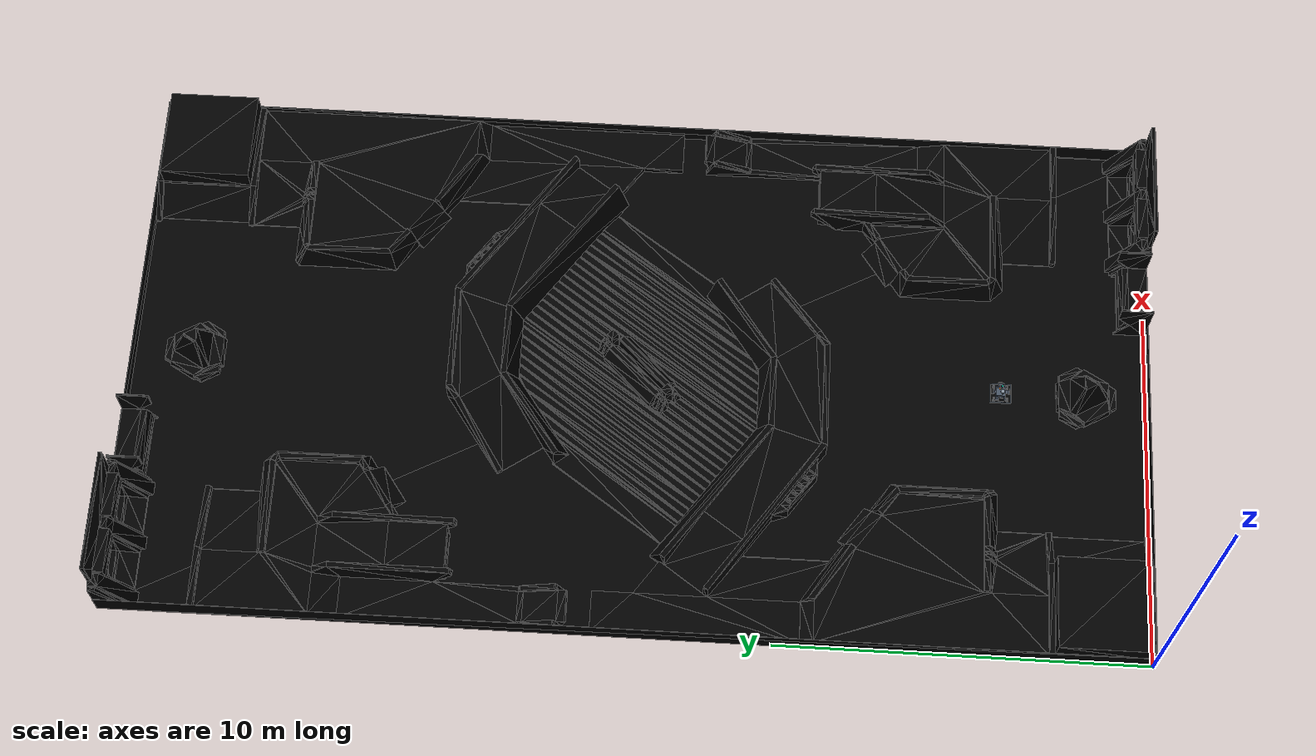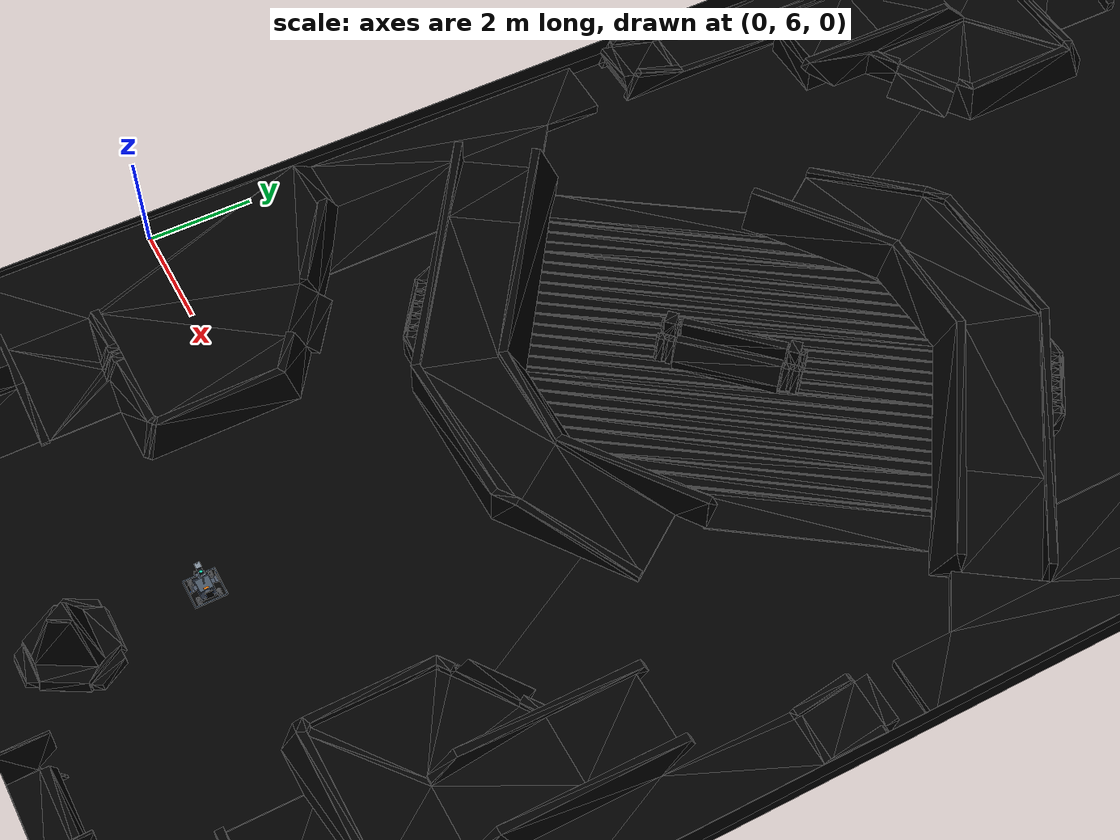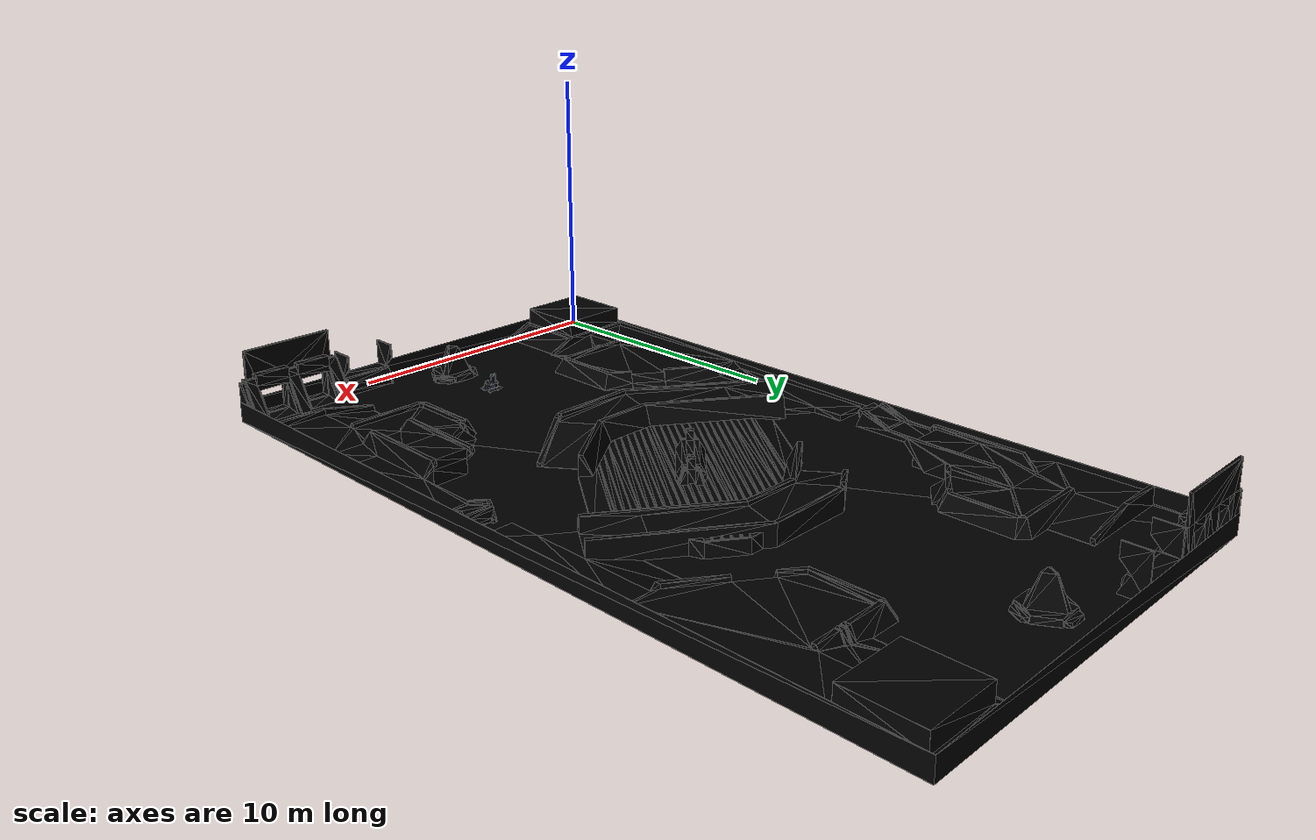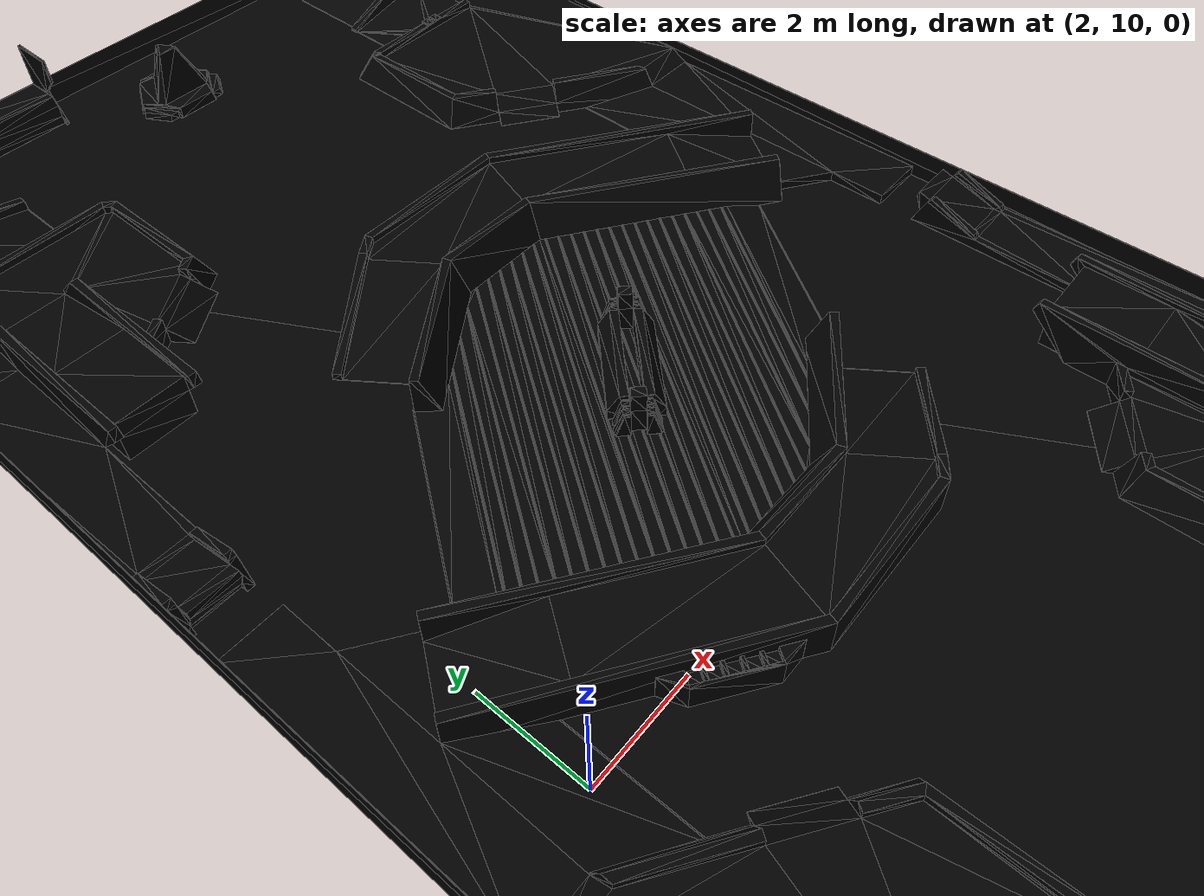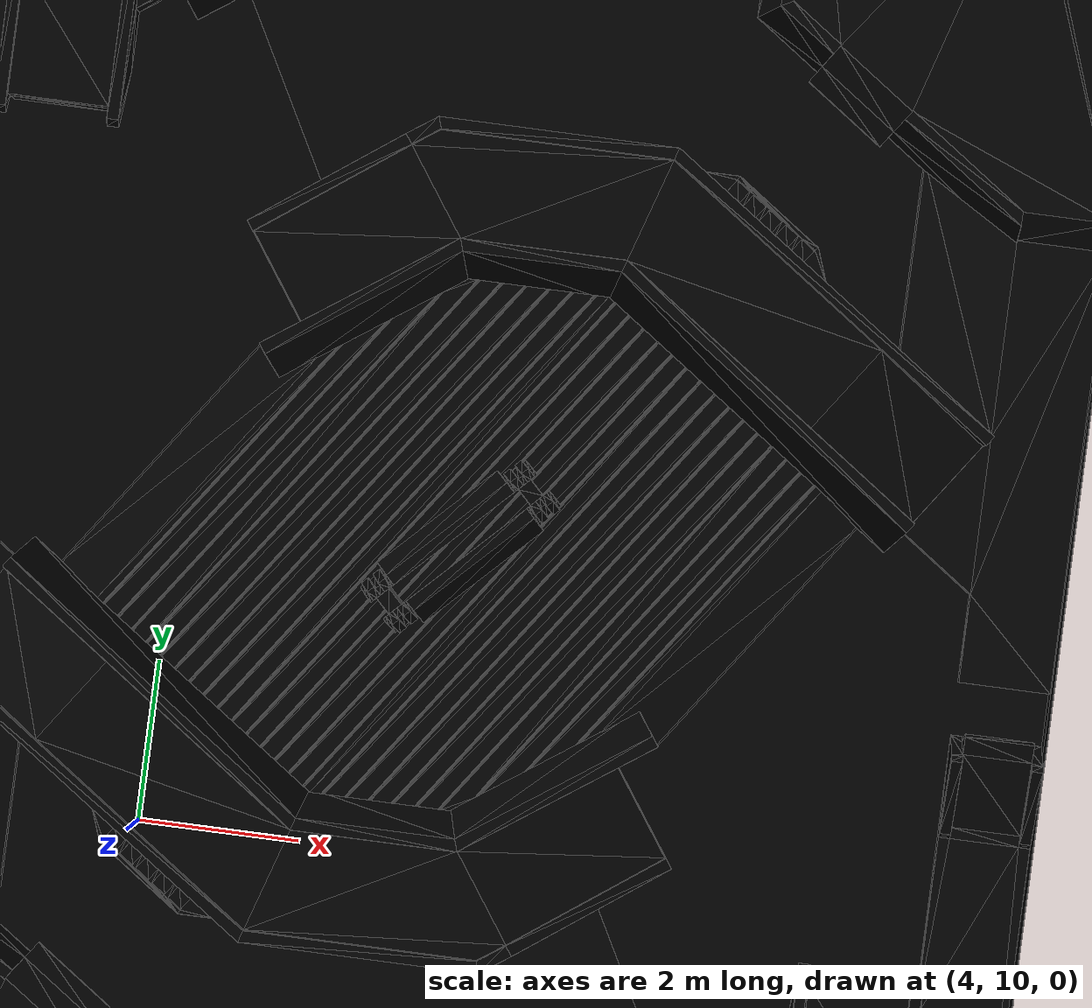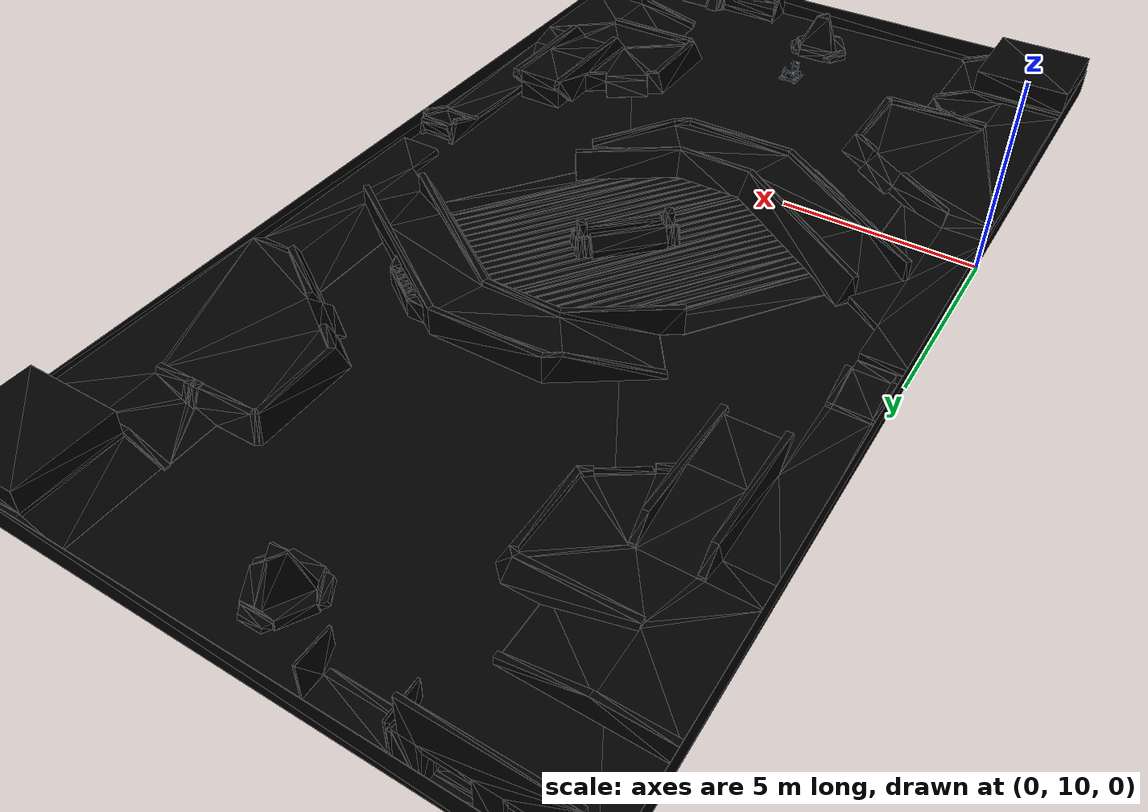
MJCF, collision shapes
<mujoco model="RoboMaster simplified infantry">
  <compiler angle="radian" meshdir="meshes" autolimits="true" />
  <option timestep="0.001" integrator="implicitfast" cone="elliptic" iterations="40" gravity="0 0 -9.81" />
  <default>
    <geom friction="1.0 0.002 0.0001" solref="0.008 1" solimp="0.95 0.99 0.001" condim="4" />
  </default>
  <visual>
    <global offwidth="1280" offheight="960" />
  </visual>
  <asset>
    <mesh name="armor_am02" file="armor_am02.obj" />
    <mesh name="armor_frame_a" file="armor_frame_a.obj" />
    <texture name="tiles" type="2d" builtin="checker" rgb1=".16 .19 .23" rgb2=".23 .27 .31" width="512" height="512" />
    <material name="floor" texture="tiles" texrepeat="12 12" reflectance=".1" />
    <mesh name="arena_visual" file="../arena/rmuc2023.stl" />
    <mesh name="contact_0" vertex="2.0385238 0.078323364 0.0015 -0.85147603 0.078323364 0.0015 -1.1870478 -0.15664673 0.0015 2.0385238 0.078323364 -0.0015 -0.85147603 0.078323364 -0.0015 -1.1870478 -0.15664673 -0.0015" face="0 1 2 3 5 4 0 3 4 0 4 1 1 4 5 1 5 2 2 5 3 2 3 0" />
    <mesh name="contact_1" vertex="-0.6899484 8.7738037e-05 0.0015 -0.69013723 -4.3869019e-05 0.0015 1.3800856 -4.3869019e-05 0.0015 -0.6899484 8.7738037e-05 -0.0015 -0.69013723 -4.3869019e-05 -0.0015 1.3800856 -4.3869019e-05 -0.0015" face="0 1 2 3 5 4 0 3 4 0 4 1 1 4 5 1 5 2 2 5 3 2 3 0" />
    <mesh name="contact_2" vertex="0.58821996 -0.94087855 0.0015 1.3338693 0.12401994 0.0015 -1.9220893 0.81685861 0.0015 0.58821996 -0.94087855 -0.0015 1.3338693 0.12401994 -0.0015 -1.9220893 0.81685861 -0.0015" face="0 1 2 3 5 4 0 3 4 0 4 1 1 4 5 1 5 2 2 5 3 2 3 0" />
    <mesh name="contact_3" vertex="-1.2219489 -0.20238686 0.0015 2.0340096 -0.89522552 0.0015 -0.81206067 1.0976124 0.0015 -1.2219489 -0.20238686 -0.0015 2.0340096 -0.89522552 -0.0015 -0.81206067 1.0976124 -0.0015" face="0 1 2 3 5 4 0 3 4 0 4 1 1 4 5 1 5 2 2 5 3 2 3 0" />
    <mesh name="contact_4" vertex="0.55338192 -0.43337695 0.0015 0.96327019 0.86662229 0.0015 -1.5166521 -0.43324534 0.0015 0.55338192 -0.43337695 -0.0015 0.96327019 0.86662229 -0.0015 -1.5166521 -0.43324534 -0.0015" face="0 1 2 3 5 4 0 3 4 0 4 1 1 4 5 1 5 2 2 5 3 2 3 0" />
    <mesh name="contact_5" vertex="-0.57809099 -0.78825506 0.0015 1.9018313 0.51161257 0.0015 -1.3237403 0.27664248 0.0015 -0.57809099 -0.78825506 -0.0015 1.9018313 0.51161257 -0.0015 -1.3237403 0.27664248 -0.0015" face="0 1 2 3 5 4 0 3 4 0 4 1 1 4 5 1 5 2 2 5 3 2 3 0" />
    <mesh name="contact_6" vertex="0.030722697 0.041261524 0.17833334 -0.057759206 -0.085104137 0.17833334 0.030722697 0.041261524 -0.35666668 0.028265238 0.04298225 0.17833334 -0.060216665 -0.083383412 0.17833334 0.028265238 0.04298225 -0.35666668" face="0 1 2 3 5 4 0 3 4 0 4 1 1 4 5 1 5 2 2 5 3 2 3 0" />
    <mesh name="contact_7" vertex="0.12574522 0.17696779 -0.11166667 0.037263312 0.050602127 0.42333335 -0.15932234 -0.23015101 -0.31166668 0.12328776 0.17868852 -0.11166667 0.034805856 0.052322856 0.42333335 -0.1617798 -0.22843028 -0.31166668" face="0 1 2 3 5 4 0 3 4 0 4 1 1 4 5 1 5 2 2 5 3 2 3 0" />
    <mesh name="contact_8" vertex="-0.15229885 -0.22011995 0.066666673 -0.43736641 -0.62723874 -0.13333334 0.59335144 0.84477759 0.066666673 -0.15475631 -0.21839921 0.066666667 -0.43982386 -0.62551801 -0.13333334 0.59089399 0.84649832 0.066666667" face="0 1 2 3 5 4 0 3 4 0 4 1 1 4 5 1 5 2 2 5 3 2 3 0" />
    <mesh name="contact_9" vertex="0.31612277 0.4488543 0.13333334 -0.71459508 -1.023162 -0.066666673 0.4021585 0.57172665 -0.066666673 0.31366531 0.45057503 0.13333334 -0.71705254 -1.0214413 -0.066666667 0.39970104 0.57344738 -0.066666667" face="0 1 2 3 5 4 0 3 4 0 4 1 1 4 5 1 5 2 2 5 3 2 3 0" />
    <mesh name="contact_10" vertex="-0.027449846 -0.041817813 -0.11166667 0.058585882 0.08105454 -0.31166668 -0.027449846 -0.041817813 0.42333335 -0.029907306 -0.040097089 -0.11166667 0.056128422 0.082775264 -0.31166668 -0.029907306 -0.040097089 0.42333335" face="0 1 2 3 5 4 0 3 4 0 4 1 1 4 5 1 5 2 2 5 3 2 3 0" />
    <mesh name="contact_11" vertex="-0.056128422 -0.082775264 0.24500001 0.029907306 0.040097089 -0.49000002 0.029907306 0.040097089 0.24500001 -0.058585882 -0.08105454 0.24500001 0.027449846 0.041817813 -0.49000002 0.027449846 0.041817813 0.24500001" face="0 1 2 3 5 4 0 3 4 0 4 1 1 4 5 1 5 2 2 5 3 2 3 0" />
    <mesh name="contact_12" vertex="-0.029907616 0.04009676 0.044999999 -0.029907616 0.04009676 -0.089999999 0.056129066 -0.082774639 0.044999999 -0.027450172 0.041817506 0.044999999 -0.027450172 0.041817506 -0.089999999 0.058586511 -0.081053893 0.044999999" face="0 1 2 3 5 4 0 3 4 0 4 1 1 4 5 1 5 2 2 5 3 2 3 0" />
    <mesh name="contact_13" vertex="0.027450172 -0.041817506 0.089999999 -0.058586511 0.081053893 -0.044999999 0.027450172 -0.041817506 -0.044999999 0.029907616 -0.04009676 0.089999999 -0.056129066 0.082774639 -0.044999999 0.029907616 -0.04009676 -0.044999999" face="0 1 2 3 5 4 0 3 4 0 4 1 1 4 5 1 5 2 2 5 3 2 3 0" />
    <mesh name="contact_14" vertex="0.11271762 0.077094637 -0.044999997 0.11271762 0.077094637 0.089999994 -0.22285415 -0.15787546 -0.044999997 0.11099689 0.079552092 -0.044999997 0.11099689 0.079552092 0.089999994 -0.22457488 -0.155418 -0.044999997" face="0 1 2 3 5 4 0 3 4 0 4 1 1 4 5 1 5 2 2 5 3 2 3 0" />
    <mesh name="contact_15" vertex="-0.11099689 -0.079552092 -0.089999994 0.22457488 0.155418 0.044999997 -0.11099689 -0.079552092 0.044999997 -0.11271762 -0.077094637 -0.089999994 0.22285415 0.15787546 0.044999997 -0.11271762 -0.077094637 0.044999997" face="0 1 2 3 5 4 0 3 4 0 4 1 1 4 5 1 5 2 2 5 3 2 3 0" />
    <mesh name="contact_16" vertex="0.61228386 0.42689411 0.15500002 0.61228386 0.42689411 0.29000001 -1.2219866 -0.85747441 -0.44500003 0.61056313 0.42935157 0.15500002 0.61056313 0.42935157 0.29000001 -1.2237073 -0.85501695 -0.44500003" face="0 1 2 3 5 4 0 3 4 0 4 1 1 4 5 1 5 2 2 5 3 2 3 0" />
    <mesh name="contact_17" vertex="-0.61056313 -0.42935157 -0.29000001 1.2237073 0.85501695 0.44500003 -0.61056313 -0.42935157 -0.15500001 -0.61228386 -0.42689411 -0.29000001 1.2219866 0.85747441 0.44500003 -0.61228386 -0.42689411 -0.15500001" face="0 1 2 3 5 4 0 3 4 0 4 1 1 4 5 1 5 2 2 5 3 2 3 0" />
    <mesh name="contact_18" vertex="0.12391091 0.088594831 0.24500001 0.12391091 0.088594831 -0.49000002 -0.25040292 -0.17350348 0.24500001 0.12563164 0.086137378 0.24500001 0.12563164 0.086137378 -0.49000002 -0.24868219 -0.17596093 0.24500001" face="0 1 2 3 5 4 0 3 4 0 4 1 1 4 5 1 5 2 2 5 3 2 3 0" />
    <mesh name="contact_19" vertex="0.48579185 0.3419861 0.49000003 0.86010568 0.60408441 -0.24500001 -1.3484786 -0.94238432 -0.24500001 0.48751258 0.33952864 0.49000002 0.86182641 0.60162695 -0.24500001 -1.3467579 -0.94484178 -0.24500001" face="0 1 2 3 5 4 0 3 4 0 4 1 1 4 5 1 5 2 2 5 3 2 3 0" />
    <mesh name="contact_20" vertex="1.2219866 0.85747568 0.44500003 -0.61228386 -0.42689475 -0.29000001 -0.61228386 -0.42689475 -0.15500001 1.2237073 0.85501822 0.44500003 -0.61056313 -0.4293522 -0.29000001 -0.61056313 -0.4293522 -0.15500001" face="0 1 2 3 5 4 0 3 4 0 4 1 1 4 5 1 5 2 2 5 3 2 3 0" />
    <mesh name="contact_21" vertex="1.3930966 -1.0364946 0.0015 1.4791323 -0.91362222 0.0015 -2.8722289 1.9501168 0.0015 1.3930966 -1.0364946 -0.0015 1.4791323 -0.91362222 -0.0015 -2.8722289 1.9501168 -0.0015" face="0 1 2 3 5 4 0 3 4 0 4 1 1 4 5 1 5 2 2 5 3 2 3 0" />
    <mesh name="contact_22" vertex="-1.4662186 0.90457916 0.0015 2.8851426 -1.9591599 0.0015 -1.418924 1.0545807 0.0015 -1.4662186 0.90457916 -0.0015 2.8851426 -1.9591599 -0.0015 -1.418924 1.0545807 -0.0015" face="0 1 2 3 5 4 0 3 4 0 4 1 1 4 5 1 5 2 2 5 3 2 3 0" />
    <mesh name="contact_23" vertex="0.94756842 -0.050000509 0.0015 0.99486303 0.10000102 0.0015 -1.9424314 -0.050000509 0.0015 0.94756842 -0.050000509 -0.0015 0.99486303 0.10000102 -0.0015 -1.9424314 -0.050000509 -0.0015" face="0 1 2 3 5 4 0 3 4 0 4 1 1 4 5 1 5 2 2 5 3 2 3 0" />
    <mesh name="contact_24" vertex="-0.96333329 -0.10000102 0.0015 1.9739612 0.050000509 0.0015 -1.0106279 0.050000509 0.0015 -0.96333329 -0.10000102 -0.0015 1.9739612 0.050000509 -0.0015 -1.0106279 0.050000509 -0.0015" face="0 1 2 3 5 4 0 3 4 0 4 1 1 4 5 1 5 2 2 5 3 2 3 0" />
    <mesh name="contact_25" vertex="0.12762213 0.028322856 0.0015 0.080327511 0.17832438 0.0015 -0.20794964 -0.20664724 0.0015 0.12762213 0.028322856 -0.0015 0.080327511 0.17832438 -0.0015 -0.20794964 -0.20664724 -0.0015" face="0 1 2 3 5 4 0 3 4 0 4 1 1 4 5 1 5 2 2 5 3 2 3 0" />
    <mesh name="contact_26" vertex="-0.067413489 -0.16928164 0.0015 0.22086366 0.21568998 0.0015 -0.15345017 -0.046408335 0.0015 -0.067413489 -0.16928164 -0.0015 0.22086366 0.21568998 -0.0015 -0.15345017 -0.046408335 -0.0015" face="0 1 2 3 5 4 0 3 4 0 4 1 1 4 5 1 5 2 2 5 3 2 3 0" />
    <mesh name="contact_27" vertex="-0.67883698 -0.59740384 -0.0015 -0.76487366 -0.47453245 -0.0015 1.4437106 1.0719363 -0.0015 -0.67883698 -0.59740384 0.0015 -0.76487366 -0.47453245 0.0015 1.4437106 1.0719363 0.0015" face="0 1 2 3 5 4 0 3 4 0 4 1 1 4 5 1 5 2 2 5 3 2 3 0" />
    <mesh name="contact_28" vertex="1.3828917 0.76606909 -0.0015 -0.77499819 -0.74490102 -0.0015 -0.60789347 -0.021168073 -0.0015 1.3828917 0.76606909 0.0015 -0.77499819 -0.74490102 0.0015 -0.60789347 -0.021168073 0.0015" face="0 1 2 3 5 4 0 3 4 0 4 1 1 4 5 1 5 2 2 5 3 2 3 0" />
    <mesh name="contact_29" vertex="0.20642551 0.34678237 -0.0015 0.039320787 -0.37695058 -0.0015 -0.24574629 0.030168215 -0.0015 0.20642551 0.34678237 0.0015 0.039320787 -0.37695058 0.0015 -0.24574629 0.030168215 0.0015" face="0 1 2 3 5 4 0 3 4 0 4 1 1 4 5 1 5 2 2 5 3 2 3 0" />
    <mesh name="contact_30" vertex="-0.41504526 -0.61737823 -0.0015 -1.1606946 0.4475193 -0.0015 1.5757399 0.16985893 -0.0015 -0.41504526 -0.61737823 0.0015 -1.1606946 0.4475193 0.0015 1.5757399 0.16985893 0.0015" face="0 1 2 3 5 4 0 3 4 0 4 1 1 4 5 1 5 2 2 5 3 2 3 0" />
    <mesh name="contact_31" vertex="1.1167738 -0.74155362 -0.0015 -1.6196607 -0.46389325 -0.0015 0.50288693 1.2054469 -0.0015 1.1167738 -0.74155362 0.0015 -1.6196607 -0.46389325 0.0015 0.50288693 1.2054469 0.0015" face="0 1 2 3 5 4 0 3 4 0 4 1 1 4 5 1 5 2 2 5 3 2 3 0" />
    <mesh name="contact_32" vertex="-0.38097652 -0.64900017 -0.0015 -0.99486335 1.2980003 -0.0015 1.3758399 -0.64900017 -0.0015 -0.38097652 -0.64900017 0.0015 -0.99486335 1.2980003 0.0015 1.3758399 -0.64900017 0.0015" face="0 1 2 3 5 4 0 3 4 0 4 1 1 4 5 1 5 2 2 5 3 2 3 0" />
    <mesh name="contact_33" vertex="0.58560578 -1.2980003 -0.0015 -1.7850974 0.64900017 -0.0015 1.1994917 0.64900017 -0.0015 0.58560578 -1.2980003 0.0015 -1.7850974 0.64900017 0.0015 1.1994917 0.64900017 0.0015" face="0 1 2 3 5 4 0 3 4 0 4 1 1 4 5 1 5 2 2 5 3 2 3 0" />
    <mesh name="contact_34" vertex="-1.4716949 0.23820941 -0.0015 -0.85780907 2.1852099 -0.0015 2.329504 -2.4234193 -0.0015 -1.4716949 0.23820941 0.0015 -0.85780907 2.1852099 0.0015 2.329504 -2.4234193 0.0015" face="0 1 2 3 5 4 0 3 4 0 4 1 1 4 5 1 5 2 2 5 3 2 3 0" />
    <mesh name="contact_35" vertex="0.6901865 -2.0678393 -0.0015 -2.4971266 2.5407899 -0.0015 1.8069401 -0.47295062 -0.0015 0.6901865 -2.0678393 0.0015 -2.4971266 2.5407899 0.0015 1.8069401 -0.47295062 0.0015" face="0 1 2 3 5 4 0 3 4 0 4 1 1 4 5 1 5 2 2 5 3 2 3 0" />
    <mesh name="contact_36" vertex="0.96333329 -0.0015 0.044999997 -1.9266666 -0.0015 0.044999997 0.96333329 -0.0015 -0.089999994 0.96333329 0.0015 0.044999997 -1.9266666 0.0015 0.044999997 0.96333329 0.0015 -0.089999994" face="0 1 2 3 5 4 0 3 4 0 4 1 1 4 5 1 5 2 2 5 3 2 3 0" />
    <mesh name="contact_37" vertex="1.9266666 -0.0015 -0.044999997 -0.96333329 -0.0015 0.089999994 -0.96333329 -0.0015 -0.044999997 1.9266666 0.0015 -0.044999997 -0.96333329 0.0015 0.089999994 -0.96333329 0.0015 -0.044999997" face="0 1 2 3 5 4 0 3 4 0 4 1 1 4 5 1 5 2 2 5 3 2 3 0" />
    <mesh name="contact_38" vertex="0.47222472 -0.33248655 -0.31166669 0.47222472 -0.33248655 0.22333334 -0.94703054 0.66128691 0.088333348 0.47394545 -0.33002909 -0.31166669 0.47394545 -0.33002909 0.22333334 -0.94530981 0.66374437 0.088333348" face="0 1 2 3 5 4 0 3 4 0 4 1 1 4 5 1 5 2 2 5 3 2 3 0" />
    <mesh name="contact_39" vertex="0.47474465 -0.33425021 -0.090000001 1.8939999 -1.3280237 0.044999989 -2.3713256 1.6585877 0.044999989 0.47646538 -0.33179275 -0.089999986 1.8957206 -1.3255662 0.045000004 -2.3696049 1.6610452 0.045000004" face="0 1 2 3 5 4 0 3 4 0 4 1 1 4 5 1 5 2 2 5 3 2 3 0" />
    <mesh name="contact_40" vertex="1.8965198 -1.3297873 -0.044999997 -0.94955046 0.66305057 0.089999994 -0.94955046 0.66305057 -0.044999997 1.8982406 -1.3273299 -0.044999997 -0.94782973 0.66550803 0.089999994 -0.94782973 0.66550803 -0.044999997" face="0 1 2 3 5 4 0 3 4 0 4 1 1 4 5 1 5 2 2 5 3 2 3 0" />
    <mesh name="contact_41" vertex="-1.4338285 1.0058089 -0.24500001 -1.4338285 1.0058089 0.49000002 2.8702381 -2.0079316 -0.24500001 -1.4355493 1.0033515 -0.24500001 -1.4355493 1.0033515 0.49000002 2.8685174 -2.0103891 -0.24500001" face="0 1 2 3 5 4 0 3 4 0 4 1 1 4 5 1 5 2 2 5 3 2 3 0" />
    <mesh name="contact_42" vertex="1.4355493 -1.0033515 -0.49000002 -2.8685174 2.0103891 0.24500001 1.4355493 -1.0033515 0.24500001 1.4338285 -1.0058089 -0.49000002 -2.8702381 2.0079316 0.24500001 1.4338285 -1.0058089 0.24500001" face="0 1 2 3 5 4 0 3 4 0 4 1 1 4 5 1 5 2 2 5 3 2 3 0" />
    <mesh name="contact_43" vertex="-0.99486303 0.0015 -0.24500001 -0.99486303 0.0015 0.49000002 1.9897261 0.0015 -0.24500001 -0.99486303 -0.0015 -0.24500001 -0.99486303 -0.0015 0.49000002 1.9897261 -0.0015 -0.24500001" face="0 1 2 3 5 4 0 3 4 0 4 1 1 4 5 1 5 2 2 5 3 2 3 0" />
    <mesh name="contact_44" vertex="0.99486303 0.0015 -0.49000002 -1.9897261 0.0015 0.24500001 0.99486303 0.0015 0.24500001 0.99486303 -0.0015 -0.49000002 -1.9897261 -0.0015 0.24500001 0.99486303 -0.0015 0.24500001" face="0 1 2 3 5 4 0 3 4 0 4 1 1 4 5 1 5 2 2 5 3 2 3 0" />
    <mesh name="contact_45" vertex="0.3005875 0.21230483 -0.24500001 -0.1515843 -0.10430932 -0.24500001 -0.1515843 -0.10430932 0.49000002 0.30230823 0.20984737 -0.24500001 -0.14986357 -0.10676678 -0.24500001 -0.14986357 -0.10676678 0.49000002" face="0 1 2 3 5 4 0 3 4 0 4 1 1 4 5 1 5 2 2 5 3 2 3 0" />
    <mesh name="contact_46" vertex="-0.91366878 -0.63792634 0.24500001 1.3725847 0.96292472 0.24500001 -0.46149698 -0.32131219 -0.49000002 -0.91194805 -0.6403838 0.24500001 1.3743054 0.96046726 0.24500001 -0.45977625 -0.32376965 -0.49000002" face="0 1 2 3 5 4 0 3 4 0 4 1 1 4 5 1 5 2 2 5 3 2 3 0" />
    <mesh name="contact_47" vertex="-1.2235815 -0.85492921 -0.44500003 0.61050019 0.4293077 0.29000001 0.61050019 0.4293077 0.15500002 -1.2218607 -0.85738667 -0.44500003 0.61222091 0.42685024 0.29000001 0.61222091 0.42685024 0.15500002" face="0 1 2 3 5 4 0 3 4 0 4 1 1 4 5 1 5 2 2 5 3 2 3 0" />
    <mesh name="contact_48" vertex="-1.2236417 -0.85497125 -0.40001221 0.61043995 0.42926566 0.19998784 0.61062877 0.42939726 0.19998784 -1.2219264 -0.85743236 -0.39998785 0.61215527 0.42680454 0.20001219 0.6123441 0.42693615 0.20001219" face="0 1 2 3 5 4 0 3 4 0 4 1 1 4 5 1 5 2 2 5 3 2 3 0" />
    <mesh name="contact_49" vertex="-0.037263158 0.050601497 0.24500001 -0.12574506 0.17696811 0.24500001 0.15932202 -0.23015068 -0.49000003 -0.034805693 0.052322214 0.24500002 -0.1232876 0.17868883 0.24500002 0.16177949 -0.22842997 -0.49000002" face="0 1 2 3 5 4 0 3 4 0 4 1 1 4 5 1 5 2 2 5 3 2 3 0" />
    <mesh name="contact_50" vertex="0.18881599 -0.2722729 -0.24500001 -0.096251089 0.1348459 0.49000002 -0.096251089 0.1348459 -0.24500001 0.19127345 -0.27055217 -0.24500001 -0.093793632 0.13656663 0.49000002 -0.093793632 0.13656663 -0.24500001" face="0 1 2 3 5 4 0 3 4 0 4 1 1 4 5 1 5 2 2 5 3 2 3 0" />
    <mesh name="contact_51" vertex="-0.79157845 -0.49149481 0.0015 -0.70309655 -0.61786143 0.0015 1.494675 1.1093562 0.0015 -0.79157845 -0.49149481 -0.0015 -0.70309655 -0.61786143 -0.0015 1.494675 1.1093562 -0.0015" face="0 1 2 3 5 4 0 3 4 0 4 1 1 4 5 1 5 2 2 5 3 2 3 0" />
    <mesh name="contact_52" vertex="0.71637758 0.62716071 0.0015 -1.481394 -1.100057 0.0015 0.7650164 0.47289626 0.0015 0.71637758 0.62716071 -0.0015 -1.481394 -1.100057 -0.0015 0.7650164 0.47289626 -0.0015" face="0 1 2 3 5 4 0 3 4 0 4 1 1 4 5 1 5 2 2 5 3 2 3 0" />
    <mesh name="contact_53" vertex="-0.81355209 -0.43184729 0.24563394 -0.61696692 -0.71259947 -0.4893661 1.4328583 1.1411059 0.24563394 -0.8151116 -0.42962007 0.24436609 -0.61852643 -0.71037226 -0.49063395 1.4312988 1.1433331 0.24436609" face="0 1 2 3 5 4 0 3 4 0 4 1 1 4 5 1 5 2 2 5 3 2 3 0" />
    <mesh name="contact_54" vertex="0.64803327 0.73103329 0.49063395 -1.4017919 -1.1226721 -0.24436609 0.75609792 0.388298 -0.24436609 0.64647376 0.73326051 0.4893661 -1.4033514 -1.1204449 -0.24563394 0.75453841 0.39052521 -0.24563394" face="0 1 2 3 5 4 0 3 4 0 4 1 1 4 5 1 5 2 2 5 3 2 3 0" />
    <mesh name="contact_55" vertex="-0.69007428 0.0015 0.044999997 1.3801486 0.0015 0.044999997 -0.69007428 0.0015 -0.089999994 -0.69007428 -0.0015 0.044999997 1.3801486 -0.0015 0.044999997 -0.69007428 -0.0015 -0.089999994" face="0 1 2 3 5 4 0 3 4 0 4 1 1 4 5 1 5 2 2 5 3 2 3 0" />
    <mesh name="contact_56" vertex="-1.3801486 0.0015 -0.044999997 0.69007428 0.0015 0.089999994 0.69007428 0.0015 -0.044999997 -1.3801486 -0.0015 -0.044999997 0.69007428 -0.0015 0.089999994 0.69007428 -0.0015 -0.044999997" face="0 1 2 3 5 4 0 3 4 0 4 1 1 4 5 1 5 2 2 5 3 2 3 0" />
    <mesh name="contact_57" vertex="0.70628738 0.051421483 0.0015 -1.3639355 0.051421483 0.0015 0.65764809 -0.10284297 0.0015 0.70628738 0.051421483 -0.0015 -1.3639355 0.051421483 -0.0015 0.65764809 -0.10284297 -0.0015" face="0 1 2 3 5 4 0 3 4 0 4 1 1 4 5 1 5 2 2 5 3 2 3 0" />
    <mesh name="contact_58" vertex="1.3315094 -0.051421483 0.0015 -0.69007413 0.10284297 0.0015 -0.64143531 -0.051421483 0.0015 1.3315094 -0.051421483 -0.0015 -0.69007413 0.10284297 -0.0015 -0.64143531 -0.051421483 -0.0015" face="0 1 2 3 5 4 0 3 4 0 4 1 1 4 5 1 5 2 2 5 3 2 3 0" />
    <mesh name="contact_59" vertex="0.69366948 0.11288563 0.24563394 -1.2792753 0.11288563 0.24563394 0.58560578 -0.22984966 -0.4893661 0.69366948 0.11560456 0.24436609 -1.2792753 0.11560456 0.24436609 0.58560578 -0.22713073 -0.49063395" face="0 1 2 3 5 4 0 3 4 0 4 1 1 4 5 1 5 2 2 5 3 2 3 0" />
    <mesh name="contact_60" vertex="1.2072325 -0.11560456 -0.24436609 -0.65764856 0.22713073 0.49063395 -0.54958391 -0.11560456 -0.24436609 1.2072325 -0.11288563 -0.24563394 -0.65764856 0.22984966 0.4893661 -0.54958391 -0.11288563 -0.24563394" face="0 1 2 3 5 4 0 3 4 0 4 1 1 4 5 1 5 2 2 5 3 2 3 0" />
    <mesh name="contact_61" vertex="-0.83590938 0.58714111 -0.044999997 -0.83590938 0.58714111 0.089999994 1.6743998 -1.170596 -0.044999997 -0.8376301 0.58468366 -0.044999997 -0.8376301 0.58468366 0.089999994 1.6726791 -1.1730535 -0.044999997" face="0 1 2 3 5 4 0 3 4 0 4 1 1 4 5 1 5 2 2 5 3 2 3 0" />
    <mesh name="contact_62" vertex="0.36454534 -0.25342616 -0.089999993 -2.1457639 1.504311 0.044999997 1.7837996 -1.2471987 0.044999997 0.36282461 -0.25588361 -0.089999994 -2.1474846 1.5018535 0.044999996 1.7820789 -1.2496561 0.044999996" face="0 1 2 3 5 4 0 3 4 0 4 1 1 4 5 1 5 2 2 5 3 2 3 0" />
    <mesh name="contact_63" vertex="-0.94530917 0.66374373 0.088333348 0.47394513 -0.33002877 0.22333334 0.47394513 -0.33002877 -0.31166669 -0.9470299 0.66128628 0.088333348 0.4722244 -0.33248623 0.22333334 0.4722244 -0.33248623 -0.31166669" face="0 1 2 3 5 4 0 3 4 0 4 1 1 4 5 1 5 2 2 5 3 2 3 0" />
    <mesh name="contact_64" vertex="1.3393485 -0.875048 0.0015 -2.590215 1.8764617 0.0015 1.2508666 -1.0014137 0.0015 1.3393485 -0.875048 -0.0015 -2.590215 1.8764617 -0.0015 1.2508666 -1.0014137 -0.0015" face="0 1 2 3 5 4 0 3 4 0 4 1 1 4 5 1 5 2 2 5 3 2 3 0" />
    <mesh name="contact_65" vertex="2.5769342 -1.8671621 0.0015 -1.2641474 1.0107133 0.0015 -1.3127867 0.85644881 0.0015 2.5769342 -1.8671621 -0.0015 -1.2641474 1.0107133 -0.0015 -1.3127867 0.85644881 -0.0015" face="0 1 2 3 5 4 0 3 4 0 4 1 1 4 5 1 5 2 2 5 3 2 3 0" />
    <mesh name="contact_66" vertex="1.3613224 -0.81539952 0.24563394 -2.5283985 1.9082114 0.24563394 1.1647368 -1.0961527 -0.4893661 1.3628819 -0.81317231 0.24436608 -2.526839 1.9104386 0.24436608 1.1662963 -1.0939254 -0.49063395" face="0 1 2 3 5 4 0 3 4 0 4 1 1 4 5 1 5 2 2 5 3 2 3 0" />
    <mesh name="contact_67" vertex="2.4973317 -1.8897779 -0.24436609 -1.1958036 1.1145862 0.49063395 -1.3038673 0.77185087 -0.24436609 2.4988912 -1.8875506 -0.24563394 -1.1942441 1.1168134 0.4893661 -1.3023078 0.77407808 -0.24563394" face="0 1 2 3 5 4 0 3 4 0 4 1 1 4 5 1 5 2 2 5 3 2 3 0" />
    <mesh name="contact_68" vertex="-0.36319173 -0.78331136 -0.19855113 1.4710787 0.50105715 0.40144892 -1.1088411 0.28158617 -0.19855113 -0.36255569 -0.78286601 -0.2014489 1.4717148 0.50150251 0.39855114 -1.108205 0.28203153 -0.2014489" face="0 1 2 3 5 4 0 3 4 0 4 1 1 4 5 1 5 2 2 5 3 2 3 0" />
    <mesh name="contact_69" vertex="-1.4717148 -0.50150251 -0.39855114 1.108205 -0.28203153 0.2014489 0.36255569 0.78286601 0.2014489 -1.4710787 -0.50105715 -0.40144892 1.1088411 -0.28158617 0.19855113 0.36319173 0.78331136 0.19855113" face="0 1 2 3 5 4 0 3 4 0 4 1 1 4 5 1 5 2 2 5 3 2 3 0" />
    <mesh name="contact_70" vertex="-0.58306262 -0.46930265 -0.19855112 1.2512079 0.81506586 0.40144891 -0.6690993 -0.34643125 -0.19855112 -0.58242658 -0.46885729 -0.2014489 1.2518439 0.81551122 0.39855114 -0.66846326 -0.34598589 -0.2014489" face="0 1 2 3 5 4 0 3 4 0 4 1 1 4 5 1 5 2 2 5 3 2 3 0" />
    <mesh name="contact_71" vertex="-1.2518439 -0.81551186 -0.39855114 0.66846326 0.34598526 0.2014489 0.58242658 0.46885856 0.2014489 -1.2512079 -0.8150665 -0.40144891 0.6690993 0.34643062 0.19855112 0.58306262 0.46930392 0.19855112" face="0 1 2 3 5 4 0 3 4 0 4 1 1 4 5 1 5 2 2 5 3 2 3 0" />
    <mesh name="contact_72" vertex="0.72191159 0.023514486 -0.13187179 -0.69734367 1.0172879 0.26812825 -0.023738705 -1.0413831 -0.13187179 0.72135878 0.023901566 -0.1347949 -0.69789648 1.017675 0.26520514 -0.024291512 -1.040996 -0.1347949" face="0 1 2 3 5 4 0 3 4 0 4 1 1 4 5 1 5 2 2 5 3 2 3 0" />
    <mesh name="contact_73" vertex="0.69789616 -1.0176747 -0.26520514 0.024291195 1.0409963 0.1347949 -0.72135814 -0.023902201 0.1347949 0.69734335 -1.0172876 -0.26812825 0.023738387 1.0413834 0.13187179 -0.72191095 -0.023515121 0.13187179" face="0 1 2 3 5 4 0 3 4 0 4 1 1 4 5 1 5 2 2 5 3 2 3 0" />
    <mesh name="contact_74" vertex="-0.051262846 0.14522993 0.16666667 0.10675431 -0.28892077 0.16666667 -0.051262846 0.14522993 -0.33333335 -0.054081926 0.14420387 0.16666667 0.10393523 -0.28994683 0.16666667 -0.054081926 0.14420387 -0.33333335" face="0 1 2 3 5 4 0 3 4 0 4 1 1 4 5 1 5 2 2 5 3 2 3 0" />
    <mesh name="contact_75" vertex="-0.10393523 0.28994683 -0.16666667 0.054081926 -0.14420387 0.33333335 0.054081926 -0.14420387 -0.16666667 -0.10675431 0.28892077 -0.16666667 0.051262846 -0.14522993 0.33333335 0.051262846 -0.14522993 -0.16666667" face="0 1 2 3 5 4 0 3 4 0 4 1 1 4 5 1 5 2 2 5 3 2 3 0" />
    <mesh name="contact_76" vertex="-0.35631228 0.25132346 0.16666667 0.71520566 -0.49896073 0.16666667 -0.35631228 0.25132346 -0.33333335 -0.35803301 0.248866 0.16666667 0.71348493 -0.50141819 0.16666667 -0.35803301 0.248866 -0.33333335" face="0 1 2 3 5 4 0 3 4 0 4 1 1 4 5 1 5 2 2 5 3 2 3 0" />
    <mesh name="contact_77" vertex="-0.71348493 0.50141819 -0.16666667 0.35803301 -0.248866 0.33333335 0.35803301 -0.248866 -0.16666667 -0.71520566 0.49896073 -0.16666667 0.35631228 -0.25132346 0.33333335 0.35631228 -0.25132346 -0.16666667" face="0 1 2 3 5 4 0 3 4 0 4 1 1 4 5 1 5 2 2 5 3 2 3 0" />
    <mesh name="contact_78" vertex="-0.15400441 0.0015 0.16666667 0.30800883 0.0015 0.16666667 -0.15400441 0.0015 -0.33333335 -0.15400441 -0.0015 0.16666667 0.30800883 -0.0015 0.16666667 -0.15400441 -0.0015 -0.33333335" face="0 1 2 3 5 4 0 3 4 0 4 1 1 4 5 1 5 2 2 5 3 2 3 0" />
    <mesh name="contact_79" vertex="-0.30800883 0.0015 -0.16666667 0.15400441 0.0015 0.33333335 0.15400441 0.0015 -0.16666667 -0.30800883 -0.0015 -0.16666667 0.15400441 -0.0015 0.33333335 0.15400441 -0.0015 -0.16666667" face="0 1 2 3 5 4 0 3 4 0 4 1 1 4 5 1 5 2 2 5 3 2 3 0" />
    <mesh name="contact_80" vertex="0.10494662 -0.075315237 -0.33333335 0.10494662 -0.075315237 0.16666667 -0.21247433 0.14694428 0.16666667 0.10666735 -0.072857777 -0.33333335 0.10666735 -0.072857777 0.16666667 -0.21075361 0.14940174 0.16666667" face="0 1 2 3 5 4 0 3 4 0 4 1 1 4 5 1 5 2 2 5 3 2 3 0" />
    <mesh name="contact_81" vertex="0.015522784 -0.012700779 0.033333341 -0.033626729 0.02171542 0.033333341 0.015522784 -0.012700779 -0.066666683 0.017243558 -0.010243354 0.033333341 -0.031905955 0.024172845 0.033333341 0.017243558 -0.010243354 -0.066666683" face="0 1 2 3 5 4 0 3 4 0 4 1 1 4 5 1 5 2 2 5 3 2 3 0" />
    <mesh name="contact_82" vertex="0.031905955 -0.024172845 -0.033333341 -0.017243558 0.010243354 0.066666683 -0.017243558 0.010243354 -0.033333341 0.033626729 -0.02171542 -0.033333341 -0.015522784 0.012700779 0.066666683 -0.015522784 0.012700779 -0.033333341" face="0 1 2 3 5 4 0 3 4 0 4 1 1 4 5 1 5 2 2 5 3 2 3 0" />
    <mesh name="contact_83" vertex="-0.10666735 0.072857777 0.20000002 -0.10666735 0.072857777 0.099999992 0.21075361 -0.14940174 -0.30000001 -0.10494662 0.075315237 0.20000002 -0.10494662 0.075315237 0.099999992 0.21247433 -0.14694428 -0.30000001" face="0 1 2 3 5 4 0 3 4 0 4 1 1 4 5 1 5 2 2 5 3 2 3 0" />
    <mesh name="contact_84" vertex="0.26809423 -0.18955207 -0.26666667 -0.049326729 0.032707454 0.13333333 -0.22134859 0.15315843 0.13333333 0.26981496 -0.18709461 -0.26666666 -0.047606 0.035164911 0.13333334 -0.21962787 0.15561588 0.13333334" face="0 1 2 3 5 4 0 3 4 0 4 1 1 4 5 1 5 2 2 5 3 2 3 0" />
    <mesh name="contact_85" vertex="0.72613669 -0.51027719 -0.13333334 0.23669387 -0.16756669 0.26666666 -0.96541165 0.6741577 -0.13333334 0.72785742 -0.50781973 -0.13333333 0.2384146 -0.16510924 0.26666667 -0.96369093 0.67661516 -0.13333333" face="0 1 2 3 5 4 0 3 4 0 4 1 1 4 5 1 5 2 2 5 3 2 3 0" />
    <mesh name="contact_86" vertex="-0.7858809 0.54844882 -0.26666657 0.41622462 -0.29327558 0.13333343 0.36707511 -0.25885938 0.13333343 -0.78416012 0.55090624 -0.26666676 0.4179454 -0.29081815 0.13333324 0.36879589 -0.25640195 0.13333324" face="0 1 2 3 5 4 0 3 4 0 4 1 1 4 5 1 5 2 2 5 3 2 3 0" />
    <mesh name="contact_87" vertex="-0.71215708 0.49682641 -0.26666667 0.44079893 -0.31048179 0.13333333 0.26877706 -0.19003081 0.13333333 -0.71043635 0.49928387 -0.26666667 0.44251966 -0.30802433 0.13333333 0.27049779 -0.18757336 0.13333333" face="0 1 2 3 5 4 0 3 4 0 4 1 1 4 5 1 5 2 2 5 3 2 3 0" />
    <mesh name="contact_88" vertex="0.015522816 -0.012700165 -0.066666683 0.015522816 -0.012700165 0.033333341 -0.033626697 0.021714126 0.033333341 0.017243526 -0.010242696 -0.066666683 0.017243526 -0.010242696 0.033333341 -0.031905987 0.024171596 0.033333341" face="0 1 2 3 5 4 0 3 4 0 4 1 1 4 5 1 5 2 2 5 3 2 3 0" />
    <mesh name="contact_89" vertex="0.29335166 -0.20723828 0.13333333 0.12132979 -0.086787302 0.13333333 -0.41726255 0.29033939 -0.26666667 0.29507239 -0.20478082 0.13333333 0.12305052 -0.084329845 0.13333333 -0.41554182 0.29279685 -0.26666666" face="0 1 2 3 5 4 0 3 4 0 4 1 1 4 5 1 5 2 2 5 3 2 3 0" />
    <mesh name="contact_90" vertex="-0.017243526 0.010242696 0.066666683 -0.017243526 0.010242696 -0.033333341 0.031905987 -0.024171596 -0.033333341 -0.015522816 0.012700165 0.066666683 -0.015522816 0.012700165 -0.033333341 0.033626697 -0.021714126 -0.033333341" face="0 1 2 3 5 4 0 3 4 0 4 1 1 4 5 1 5 2 2 5 3 2 3 0" />
    <mesh name="contact_91" vertex="0.26877739 -0.19003082 0.13333331 0.21962788 -0.15561653 0.13333331 -0.49098633 0.34196114 -0.26666669 0.2704981 -0.18757335 0.13333336 0.22134859 -0.15315906 0.13333336 -0.48926562 0.34441861 -0.26666664" face="0 1 2 3 5 4 0 3 4 0 4 1 1 4 5 1 5 2 2 5 3 2 3 0" />
    <mesh name="contact_92" vertex="0.19505359 -0.13840906 0.13333333 -0.56471013 0.3935829 -0.26666667 0.36707545 -0.25886003 0.13333333 0.19677432 -0.1359516 0.13333333 -0.5629894 0.39604036 -0.26666667 0.36879618 -0.25640257 0.13333333" face="0 1 2 3 5 4 0 3 4 0 4 1 1 4 5 1 5 2 2 5 3 2 3 0" />
    <mesh name="contact_93" vertex="0.29335197 -0.20723827 0.13333334 -0.63843361 0.44520466 -0.26666666 0.34250053 -0.24165257 0.13333334 0.29507271 -0.20478082 0.13333333 -0.63671288 0.44766211 -0.26666667 0.34422127 -0.23919511 0.13333333" face="0 1 2 3 5 4 0 3 4 0 4 1 1 4 5 1 5 2 2 5 3 2 3 0" />
    <mesh name="contact_94" vertex="-0.01724322 0.010242704 -0.033333341 0.03190534 -0.024171588 -0.033333341 -0.01724322 0.010242704 0.066666683 -0.015522487 0.012700157 -0.033333341 0.033626073 -0.021714134 -0.033333341 -0.015522487 0.012700157 0.066666683" face="0 1 2 3 5 4 0 3 4 0 4 1 1 4 5 1 5 2 2 5 3 2 3 0" />
    <mesh name="contact_95" vertex="-0.033626073 0.021714134 0.033333341 0.015522487 -0.012700157 -0.066666683 0.015522487 -0.012700157 0.033333341 -0.03190534 0.024171588 0.033333341 0.01724322 -0.010242704 -0.066666683 0.01724322 -0.010242704 0.033333341" face="0 1 2 3 5 4 0 3 4 0 4 1 1 4 5 1 5 2 2 5 3 2 3 0" />
    <mesh name="contact_96" vertex="0.10494662 -0.075315869 0.033333341 -0.21247434 0.14694556 0.033333341 0.10494662 -0.075315869 -0.066666683 0.10666735 -0.072858416 0.033333341 -0.21075361 0.14940301 0.033333341 0.10666735 -0.072858416 -0.066666683" face="0 1 2 3 5 4 0 3 4 0 4 1 1 4 5 1 5 2 2 5 3 2 3 0" />
    <mesh name="contact_97" vertex="0.21075361 -0.14940301 0.099999992 -0.10666735 0.072858416 0.20000002 -0.10666735 0.072858416 -0.30000001 0.21247434 -0.14694556 0.099999992 -0.10494662 0.075315869 0.20000002 -0.10494662 0.075315869 -0.30000001" face="0 1 2 3 5 4 0 3 4 0 4 1 1 4 5 1 5 2 2 5 3 2 3 0" />
    <mesh name="contact_98" vertex="0.047606 -0.035165547 0.13333333 -0.26981496 0.18709588 -0.26666667 0.21962787 -0.15561652 0.13333333 0.049326729 -0.03270809 0.13333334 -0.26809423 0.18955334 -0.26666666 0.22134859 -0.15315906 0.13333334" face="0 1 2 3 5 4 0 3 4 0 4 1 1 4 5 1 5 2 2 5 3 2 3 0" />
    <mesh name="contact_99" vertex="0.14590408 -0.10399477 0.13333331 -0.34353874 0.23871763 -0.26666669 0.1950536 -0.13840906 0.13333331 0.14762479 -0.1015373 0.13333335 -0.34181803 0.2411751 -0.26666665 0.19677431 -0.13595159 0.13333335" face="0 1 2 3 5 4 0 3 4 0 4 1 1 4 5 1 5 2 2 5 3 2 3 0" />
    <mesh name="contact_100" vertex="-0.017243526 0.010242696 -0.033333341 0.031905987 -0.024171596 -0.033333341 -0.017243526 0.010242696 0.066666683 -0.015522816 0.012700165 -0.033333341 0.033626697 -0.021714126 -0.033333341 -0.015522816 0.012700165 0.066666683" face="0 1 2 3 5 4 0 3 4 0 4 1 1 4 5 1 5 2 2 5 3 2 3 0" />
    <mesh name="contact_101" vertex="-0.033626697 0.021714126 0.033333341 0.015522816 -0.012700165 -0.066666683 0.015522816 -0.012700165 0.033333341 -0.031905987 0.024171596 0.033333341 0.017243526 -0.010242696 -0.066666683 0.017243526 -0.010242696 0.033333341" face="0 1 2 3 5 4 0 3 4 0 4 1 1 4 5 1 5 2 2 5 3 2 3 0" />
    <mesh name="contact_102" vertex="0.063917796 0.12615267 0.0015 -0.056533178 -0.045869191 0.0015 -0.0073846181 -0.080283483 0.0015 0.063917796 0.12615267 -0.0015 -0.056533178 -0.045869191 -0.0015 -0.0073846181 -0.080283483 -0.0015" face="0 1 2 3 5 4 0 3 4 0 4 1 1 4 5 1 5 2 2 5 3 2 3 0" />
    <mesh name="contact_103" vertex="-0.056533496 -0.045868556 0.0015 -0.0073839823 -0.080284754 0.0015 0.063917478 0.12615331 0.0015 -0.056533496 -0.045868556 -0.0015 -0.0073839823 -0.080284754 -0.0015 0.063917478 0.12615331 -0.0015" face="0 1 2 3 5 4 0 3 4 0 4 1 1 4 5 1 5 2 2 5 3 2 3 0" />
    <mesh name="contact_104" vertex="0.0073839823 0.080284754 0.0015 -0.063917478 -0.12615331 0.0015 0.056533496 0.045868556 0.0015 0.0073839823 0.080284754 -0.0015 -0.063917478 -0.12615331 -0.0015 0.056533496 0.045868556 -0.0015" face="0 1 2 3 5 4 0 3 4 0 4 1 1 4 5 1 5 2 2 5 3 2 3 0" />
    <mesh name="contact_105" vertex="0.10663414 -0.09704717 0.0015 -0.041246414 0.073643366 0.0015 -0.065387726 0.023403804 0.0015 0.10663414 -0.09704717 -0.0015 -0.041246414 0.073643366 -0.0015 -0.065387726 0.023403804 -0.0015" face="0 1 2 3 5 4 0 3 4 0 4 1 1 4 5 1 5 2 2 5 3 2 3 0" />
    <mesh name="contact_106" vertex="0.13791021 -0.033493042 0.0015 0.16205152 0.016746521 0.0015 -0.29996173 0.016746521 0.0015 0.13791021 -0.033493042 -0.0015 0.16205152 0.016746521 -0.0015 -0.29996173 0.016746521 -0.0015" face="0 1 2 3 5 4 0 3 4 0 4 1 1 4 5 1 5 2 2 5 3 2 3 0" />
    <mesh name="contact_107" vertex="0.18610764 0.040594101 0.0015 -0.2517643 0.090833664 0.0015 0.065656662 -0.13142776 0.0015 0.18610764 0.040594101 -0.0015 -0.2517643 0.090833664 -0.0015 0.065656662 -0.13142776 -0.0015" face="0 1 2 3 5 4 0 3 4 0 4 1 1 4 5 1 5 2 2 5 3 2 3 0" />
    <mesh name="contact_108" vertex="-0.056533496 -0.045869191 0.0015 -0.0073839823 -0.080283483 0.0015 0.063917478 0.12615267 0.0015 -0.056533496 -0.045869191 -0.0015 -0.0073839823 -0.080283483 -0.0015 0.063917478 0.12615267 -0.0015" face="0 1 2 3 5 4 0 3 4 0 4 1 1 4 5 1 5 2 2 5 3 2 3 0" />
    <mesh name="contact_109" vertex="0.0073839823 0.080283483 0.0015 -0.063917478 -0.12615267 0.0015 0.056533496 0.045869191 0.0015 0.0073839823 0.080283483 -0.0015 -0.063917478 -0.12615267 -0.0015 0.056533496 0.045869191 -0.0015" face="0 1 2 3 5 4 0 3 4 0 4 1 1 4 5 1 5 2 2 5 3 2 3 0" />
    <mesh name="contact_110" vertex="0.032910347 -0.045425415 0.0015 0.08205986 -0.079839706 0.0015 -0.11497021 0.12526512 0.0015 0.032910347 -0.045425415 -0.0015 0.08205986 -0.079839706 -0.0015 -0.11497021 0.12526512 -0.0015" face="0 1 2 3 5 4 0 3 4 0 4 1 1 4 5 1 5 2 2 5 3 2 3 0" />
    <mesh name="contact_111" vertex="-0.188694 0.17688688 0.0015 0.0083360672 -0.028217951 0.0015 0.18035793 -0.14866892 0.0015 -0.188694 0.17688688 -0.0015 0.0083360672 -0.028217951 -0.0015 0.18035793 -0.14866892 -0.0015" face="0 1 2 3 5 4 0 3 4 0 4 1 1 4 5 1 5 2 2 5 3 2 3 0" />
    <mesh name="contact_112" vertex="-0.056533496 -0.045869191 0.0015 -0.0073839823 -0.080283483 0.0015 0.063917478 0.12615267 0.0015 -0.056533496 -0.045869191 -0.0015 -0.0073839823 -0.080283483 -0.0015 0.063917478 0.12615267 -0.0015" face="0 1 2 3 5 4 0 3 4 0 4 1 1 4 5 1 5 2 2 5 3 2 3 0" />
    <mesh name="contact_113" vertex="0.0073839823 0.080283483 0.0015 -0.063917478 -0.12615267 0.0015 0.056533496 0.045869191 0.0015 0.0073839823 0.080283483 -0.0015 -0.063917478 -0.12615267 -0.0015 0.056533496 0.045869191 -0.0015" face="0 1 2 3 5 4 0 3 4 0 4 1 1 4 5 1 5 2 2 5 3 2 3 0" />
    <mesh name="contact_114" vertex="0.10663414 -0.09704717 0.0015 0.15578365 -0.13146146 0.0015 -0.26241779 0.22850863 0.0015 0.10663414 -0.09704717 -0.0015 0.15578365 -0.13146146 -0.0015 -0.26241779 0.22850863 -0.0015" face="0 1 2 3 5 4 0 3 4 0 4 1 1 4 5 1 5 2 2 5 3 2 3 0" />
    <mesh name="contact_115" vertex="-0.33614159 0.28013039 0.0015 0.08205986 -0.079839706 0.0015 0.25408173 -0.20029068 0.0015 -0.33614159 0.28013039 -0.0015 0.08205986 -0.079839706 -0.0015 0.25408173 -0.20029068 -0.0015" face="0 1 2 3 5 4 0 3 4 0 4 1 1 4 5 1 5 2 2 5 3 2 3 0" />
    <mesh name="contact_116" vertex="-0.40986506 0.33175214 0.0015 0.18035825 -0.14866892 0.0015 0.22950681 -0.18308322 0.0015 -0.40986506 0.33175214 -0.0015 0.18035825 -0.14866892 -0.0015 0.22950681 -0.18308322 -0.0015" face="0 1 2 3 5 4 0 3 4 0 4 1 1 4 5 1 5 2 2 5 3 2 3 0" />
    <mesh name="contact_117" vertex="0.056533178 0.045869191 0.0015 0.0073846181 0.080283483 0.0015 -0.063917796 -0.12615267 0.0015 0.056533178 0.045869191 -0.0015 0.0073846181 0.080283483 -0.0015 -0.063917796 -0.12615267 -0.0015" face="0 1 2 3 5 4 0 3 4 0 4 1 1 4 5 1 5 2 2 5 3 2 3 0" />
    <mesh name="contact_118" vertex="-0.14595731 0.016745885 0.0015 0.17146365 -0.20551364 0.0015 -0.025506337 0.18876775 0.0015 -0.14595731 0.016745885 -0.0015 0.17146365 -0.20551364 -0.0015 -0.025506337 0.18876775 -0.0015" face="0 1 2 3 5 4 0 3 4 0 4 1 1 4 5 1 5 2 2 5 3 2 3 0" />
    <mesh name="contact_119" vertex="-0.078640938 0.11813736 0.0015 0.11832905 -0.27614403 0.0015 -0.03968811 0.15800667 0.0015 -0.078640938 0.11813736 -0.0015 0.11832905 -0.27614403 -0.0015 -0.03968811 0.15800667 -0.0015" face="0 1 2 3 5 4 0 3 4 0 4 1 1 4 5 1 5 2 2 5 3 2 3 0" />
    <mesh name="contact_120" vertex="0.044356346 -0.053440094 0.0015 0.083309174 -0.013570786 0.0015 -0.12766552 0.06701088 0.0015 0.044356346 -0.053440094 -0.0015 0.083309174 -0.013570786 -0.0015 -0.12766552 0.06701088 -0.0015" face="0 1 2 3 5 4 0 3 4 0 4 1 1 4 5 1 5 2 2 5 3 2 3 0" />
    <mesh name="contact_121" vertex="0.21652285 -0.19637362 0.0015 0.42749755 -0.27695529 0.0015 -0.6440204 0.47332891 0.0015 0.21652285 -0.19637362 -0.0015 0.42749755 -0.27695529 -0.0015 -0.6440204 0.47332891 -0.0015" face="0 1 2 3 5 4 0 3 4 0 4 1 1 4 5 1 5 2 2 5 3 2 3 0" />
    <mesh name="contact_122" vertex="0.30323092 -0.23470624 0.0015 -0.55731233 0.43499629 0.0015 0.25408141 -0.20029004 0.0015 0.30323092 -0.23470624 -0.0015 -0.55731233 0.43499629 -0.0015 0.25408141 -0.20029004 -0.0015" face="0 1 2 3 5 4 0 3 4 0 4 1 1 4 5 1 5 2 2 5 3 2 3 0" />
    <mesh name="contact_123" vertex="0.3278052 -0.25191243 0.0015 -0.48358854 0.3833739 0.0015 0.15578334 -0.13146146 0.0015 0.3278052 -0.25191243 -0.0015 -0.48358854 0.3833739 -0.0015 0.15578334 -0.13146146 -0.0015" face="0 1 2 3 5 4 0 3 4 0 4 1 1 4 5 1 5 2 2 5 3 2 3 0" />
    <mesh name="contact_124" vertex="-0.71785386 0.39481163 -0.0015 -0.25584062 0.39481163 -0.0015 0.97369448 -0.78962326 -0.0015 -0.71785386 0.39481163 0.0015 -0.25584062 0.39481163 0.0015 0.97369448 -0.78962326 0.0015" face="0 1 2 3 5 4 0 3 4 0 4 1 1 4 5 1 5 2 2 5 3 2 3 0" />
    <mesh name="contact_125" vertex="0.46251742 -0.53952853 -0.0015 -0.76701768 0.64490636 -0.0015 0.30450026 -0.10537783 -0.0015 0.46251742 -0.53952853 0.0015 -0.76701768 0.64490636 0.0015 0.30450026 -0.10537783 0.0015" face="0 1 2 3 5 4 0 3 4 0 4 1 1 4 5 1 5 2 2 5 3 2 3 0" />
    <mesh name="contact_126" vertex="-0.058200986 0.038921596 -0.033333341 0.11382088 -0.081529377 -0.033333341 -0.058200986 0.038921596 0.066666683 -0.056480257 0.041379053 -0.033333341 0.11554161 -0.079071921 -0.033333341 -0.056480257 0.041379053 0.066666683" face="0 1 2 3 5 4 0 3 4 0 4 1 1 4 5 1 5 2 2 5 3 2 3 0" />
    <mesh name="contact_127" vertex="-0.11554161 0.079071921 0.033333341 0.056480257 -0.041379053 -0.066666683 0.056480257 -0.041379053 0.033333341 -0.11382088 0.081529377 0.033333341 0.058200986 -0.038921596 -0.066666683 0.058200986 -0.038921596 0.033333341" face="0 1 2 3 5 4 0 3 4 0 4 1 1 4 5 1 5 2 2 5 3 2 3 0" />
    <mesh name="contact_128" vertex="-0.097490946 -0.017190297 0.0015 0.074530919 -0.13764127 0.0015 0.022960027 0.15483157 0.0015 -0.097490946 -0.017190297 -0.0015 0.074530919 -0.13764127 -0.0015 0.022960027 0.15483157 -0.0015" face="0 1 2 3 5 4 0 3 4 0 4 1 1 4 5 1 5 2 2 5 3 2 3 0" />
    <mesh name="contact_129" vertex="-0.074530919 0.13764127 0.0015 -0.022960027 -0.15483157 0.0015 0.097490946 0.017190297 0.0015 -0.074530919 0.13764127 -0.0015 -0.022960027 -0.15483157 -0.0015 0.097490946 0.017190297 -0.0015" face="0 1 2 3 5 4 0 3 4 0 4 1 1 4 5 1 5 2 2 5 3 2 3 0" />
    <mesh name="contact_130" vertex="-0.038921596 -0.058200986 -0.033333341 0.081529377 0.11382088 -0.033333341 -0.038921596 -0.058200986 0.066666683 -0.041379053 -0.056480257 -0.033333341 0.079071921 0.11554161 -0.033333341 -0.041379053 -0.056480257 0.066666683" face="0 1 2 3 5 4 0 3 4 0 4 1 1 4 5 1 5 2 2 5 3 2 3 0" />
    <mesh name="contact_131" vertex="-0.079071921 -0.11554161 0.033333341 0.041379053 0.056480257 -0.066666683 0.041379053 0.056480257 0.033333341 -0.081529377 -0.11382088 0.033333341 0.038921596 0.058200986 -0.066666683 0.038921596 0.058200986 0.033333341" face="0 1 2 3 5 4 0 3 4 0 4 1 1 4 5 1 5 2 2 5 3 2 3 0" />
    <mesh name="contact_132" vertex="0.038921596 0.058200986 -0.033333341 -0.081529377 -0.11382088 -0.033333341 0.038921596 0.058200986 0.066666683 0.041379053 0.056480257 -0.033333341 -0.079071921 -0.11554161 -0.033333341 0.041379053 0.056480257 0.066666683" face="0 1 2 3 5 4 0 3 4 0 4 1 1 4 5 1 5 2 2 5 3 2 3 0" />
    <mesh name="contact_133" vertex="0.079071921 0.11554161 0.033333341 -0.041379053 -0.056480257 -0.066666683 -0.041379053 -0.056480257 0.033333341 0.081529377 0.11382088 0.033333341 -0.038921596 -0.058200986 -0.066666683 -0.038921596 -0.058200986 0.033333341" face="0 1 2 3 5 4 0 3 4 0 4 1 1 4 5 1 5 2 2 5 3 2 3 0" />
    <mesh name="contact_134" vertex="-0.058200986 0.038921596 -0.033333341 0.11382088 -0.081529377 -0.033333341 -0.058200986 0.038921596 0.066666683 -0.056480257 0.041379053 -0.033333341 0.11554161 -0.079071921 -0.033333341 -0.056480257 0.041379053 0.066666683" face="0 1 2 3 5 4 0 3 4 0 4 1 1 4 5 1 5 2 2 5 3 2 3 0" />
    <mesh name="contact_135" vertex="-0.11554161 0.079071921 0.033333341 0.056480257 -0.041379053 -0.066666683 0.056480257 -0.041379053 0.033333341 -0.11382088 0.081529377 0.033333341 0.058200986 -0.038921596 -0.066666683 0.058200986 -0.038921596 0.033333341" face="0 1 2 3 5 4 0 3 4 0 4 1 1 4 5 1 5 2 2 5 3 2 3 0" />
    <mesh name="contact_136" vertex="-0.097490946 -0.017190297 0.0015 0.074530919 -0.13764127 0.0015 0.022960027 0.15483157 0.0015 -0.097490946 -0.017190297 -0.0015 0.074530919 -0.13764127 -0.0015 0.022960027 0.15483157 -0.0015" face="0 1 2 3 5 4 0 3 4 0 4 1 1 4 5 1 5 2 2 5 3 2 3 0" />
    <mesh name="contact_137" vertex="-0.074530919 0.13764127 0.0015 -0.022960027 -0.15483157 0.0015 0.097490946 0.017190297 0.0015 -0.074530919 0.13764127 -0.0015 -0.022960027 -0.15483157 -0.0015 0.097490946 0.017190297 -0.0015" face="0 1 2 3 5 4 0 3 4 0 4 1 1 4 5 1 5 2 2 5 3 2 3 0" />
    <mesh name="contact_138" vertex="-0.038921596 -0.058200986 -0.033333341 0.081529377 0.11382088 -0.033333341 -0.038921596 -0.058200986 0.066666683 -0.041379053 -0.056480257 -0.033333341 0.079071921 0.11554161 -0.033333341 -0.041379053 -0.056480257 0.066666683" face="0 1 2 3 5 4 0 3 4 0 4 1 1 4 5 1 5 2 2 5 3 2 3 0" />
    <mesh name="contact_139" vertex="-0.079071921 -0.11554161 0.033333341 0.041379053 0.056480257 -0.066666683 0.041379053 0.056480257 0.033333341 -0.081529377 -0.11382088 0.033333341 0.038921596 0.058200986 -0.066666683 0.038921596 0.058200986 0.033333341" face="0 1 2 3 5 4 0 3 4 0 4 1 1 4 5 1 5 2 2 5 3 2 3 0" />
    <mesh name="contact_140" vertex="0.038921596 0.058200986 -0.033333341 -0.081529377 -0.11382088 -0.033333341 0.038921596 0.058200986 0.066666683 0.041379053 0.056480257 -0.033333341 -0.079071921 -0.11554161 -0.033333341 0.041379053 0.056480257 0.066666683" face="0 1 2 3 5 4 0 3 4 0 4 1 1 4 5 1 5 2 2 5 3 2 3 0" />
    <mesh name="contact_141" vertex="0.079071921 0.11554161 0.033333341 -0.041379053 -0.056480257 -0.066666683 -0.041379053 -0.056480257 0.033333341 0.081529377 0.11382088 0.033333341 -0.038921596 -0.058200986 -0.066666683 -0.038921596 -0.058200986 0.033333341" face="0 1 2 3 5 4 0 3 4 0 4 1 1 4 5 1 5 2 2 5 3 2 3 0" />
    <mesh name="contact_142" vertex="-0.058200986 0.038921596 -0.033333341 0.11382088 -0.081529377 -0.033333341 -0.058200986 0.038921596 0.066666683 -0.056480257 0.041379053 -0.033333341 0.11554161 -0.079071921 -0.033333341 -0.056480257 0.041379053 0.066666683" face="0 1 2 3 5 4 0 3 4 0 4 1 1 4 5 1 5 2 2 5 3 2 3 0" />
    <mesh name="contact_143" vertex="-0.11554161 0.079071921 0.033333341 0.056480257 -0.041379053 -0.066666683 0.056480257 -0.041379053 0.033333341 -0.11382088 0.081529377 0.033333341 0.058200986 -0.038921596 -0.066666683 0.058200986 -0.038921596 0.033333341" face="0 1 2 3 5 4 0 3 4 0 4 1 1 4 5 1 5 2 2 5 3 2 3 0" />
    <mesh name="contact_144" vertex="-0.097490946 -0.017190297 0.0015 0.074530919 -0.13764127 0.0015 0.022960027 0.15483157 0.0015 -0.097490946 -0.017190297 -0.0015 0.074530919 -0.13764127 -0.0015 0.022960027 0.15483157 -0.0015" face="0 1 2 3 5 4 0 3 4 0 4 1 1 4 5 1 5 2 2 5 3 2 3 0" />
    <mesh name="contact_145" vertex="-0.074530919 0.13764127 0.0015 -0.022960027 -0.15483157 0.0015 0.097490946 0.017190297 0.0015 -0.074530919 0.13764127 -0.0015 -0.022960027 -0.15483157 -0.0015 0.097490946 0.017190297 -0.0015" face="0 1 2 3 5 4 0 3 4 0 4 1 1 4 5 1 5 2 2 5 3 2 3 0" />
    <mesh name="contact_146" vertex="-0.038921596 -0.058200986 -0.033333341 0.081529377 0.11382088 -0.033333341 -0.038921596 -0.058200986 0.066666683 -0.041379053 -0.056480257 -0.033333341 0.079071921 0.11554161 -0.033333341 -0.041379053 -0.056480257 0.066666683" face="0 1 2 3 5 4 0 3 4 0 4 1 1 4 5 1 5 2 2 5 3 2 3 0" />
    <mesh name="contact_147" vertex="-0.079071921 -0.11554161 0.033333341 0.041379053 0.056480257 -0.066666683 0.041379053 0.056480257 0.033333341 -0.081529377 -0.11382088 0.033333341 0.038921596 0.058200986 -0.066666683 0.038921596 0.058200986 0.033333341" face="0 1 2 3 5 4 0 3 4 0 4 1 1 4 5 1 5 2 2 5 3 2 3 0" />
    <mesh name="contact_148" vertex="0.038921596 0.058200986 -0.033333341 -0.081529377 -0.11382088 -0.033333341 0.038921596 0.058200986 0.066666683 0.041379053 0.056480257 -0.033333341 -0.079071921 -0.11554161 -0.033333341 0.041379053 0.056480257 0.066666683" face="0 1 2 3 5 4 0 3 4 0 4 1 1 4 5 1 5 2 2 5 3 2 3 0" />
    <mesh name="contact_149" vertex="0.079071921 0.11554161 0.033333341 -0.041379053 -0.056480257 -0.066666683 -0.041379053 -0.056480257 0.033333341 0.081529377 0.11382088 0.033333341 -0.038921596 -0.058200986 -0.066666683 -0.038921596 -0.058200986 0.033333341" face="0 1 2 3 5 4 0 3 4 0 4 1 1 4 5 1 5 2 2 5 3 2 3 0" />
    <mesh name="contact_150" vertex="-0.058200986 0.038921596 -0.033333341 0.11382088 -0.081529377 -0.033333341 -0.058200986 0.038921596 0.066666683 -0.056480257 0.041379053 -0.033333341 0.11554161 -0.079071921 -0.033333341 -0.056480257 0.041379053 0.066666683" face="0 1 2 3 5 4 0 3 4 0 4 1 1 4 5 1 5 2 2 5 3 2 3 0" />
    <mesh name="contact_151" vertex="-0.11554161 0.079071921 0.033333341 0.056480257 -0.041379053 -0.066666683 0.056480257 -0.041379053 0.033333341 -0.11382088 0.081529377 0.033333341 0.058200986 -0.038921596 -0.066666683 0.058200986 -0.038921596 0.033333341" face="0 1 2 3 5 4 0 3 4 0 4 1 1 4 5 1 5 2 2 5 3 2 3 0" />
    <mesh name="contact_152" vertex="-0.097490946 -0.017190297 0.0015 0.074530919 -0.13764127 0.0015 0.022960027 0.15483157 0.0015 -0.097490946 -0.017190297 -0.0015 0.074530919 -0.13764127 -0.0015 0.022960027 0.15483157 -0.0015" face="0 1 2 3 5 4 0 3 4 0 4 1 1 4 5 1 5 2 2 5 3 2 3 0" />
    <mesh name="contact_153" vertex="-0.074530919 0.13764127 0.0015 -0.022960027 -0.15483157 0.0015 0.097490946 0.017190297 0.0015 -0.074530919 0.13764127 -0.0015 -0.022960027 -0.15483157 -0.0015 0.097490946 0.017190297 -0.0015" face="0 1 2 3 5 4 0 3 4 0 4 1 1 4 5 1 5 2 2 5 3 2 3 0" />
    <mesh name="contact_154" vertex="-0.038921596 -0.058200986 -0.033333341 0.081529377 0.11382088 -0.033333341 -0.038921596 -0.058200986 0.066666683 -0.041379053 -0.056480257 -0.033333341 0.079071921 0.11554161 -0.033333341 -0.041379053 -0.056480257 0.066666683" face="0 1 2 3 5 4 0 3 4 0 4 1 1 4 5 1 5 2 2 5 3 2 3 0" />
    <mesh name="contact_155" vertex="-0.079071921 -0.11554161 0.033333341 0.041379053 0.056480257 -0.066666683 0.041379053 0.056480257 0.033333341 -0.081529377 -0.11382088 0.033333341 0.038921596 0.058200986 -0.066666683 0.038921596 0.058200986 0.033333341" face="0 1 2 3 5 4 0 3 4 0 4 1 1 4 5 1 5 2 2 5 3 2 3 0" />
    <mesh name="contact_156" vertex="0.038921596 0.058200986 -0.033333341 -0.081529377 -0.11382088 -0.033333341 0.038921596 0.058200986 0.066666683 0.041379053 0.056480257 -0.033333341 -0.079071921 -0.11554161 -0.033333341 0.041379053 0.056480257 0.066666683" face="0 1 2 3 5 4 0 3 4 0 4 1 1 4 5 1 5 2 2 5 3 2 3 0" />
    <mesh name="contact_157" vertex="0.079071921 0.11554161 0.033333341 -0.041379053 -0.056480257 -0.066666683 -0.041379053 -0.056480257 0.033333341 0.081529377 0.11382088 0.033333341 -0.038921596 -0.058200986 -0.066666683 -0.038921596 -0.058200986 0.033333341" face="0 1 2 3 5 4 0 3 4 0 4 1 1 4 5 1 5 2 2 5 3 2 3 0" />
    <mesh name="contact_158" vertex="-0.058200986 0.038921596 -0.033333341 0.11382088 -0.081529377 -0.033333341 -0.058200986 0.038921596 0.066666683 -0.056480257 0.041379053 -0.033333341 0.11554161 -0.079071921 -0.033333341 -0.056480257 0.041379053 0.066666683" face="0 1 2 3 5 4 0 3 4 0 4 1 1 4 5 1 5 2 2 5 3 2 3 0" />
    <mesh name="contact_159" vertex="-0.11554161 0.079071921 0.033333341 0.056480257 -0.041379053 -0.066666683 0.056480257 -0.041379053 0.033333341 -0.11382088 0.081529377 0.033333341 0.058200986 -0.038921596 -0.066666683 0.058200986 -0.038921596 0.033333341" face="0 1 2 3 5 4 0 3 4 0 4 1 1 4 5 1 5 2 2 5 3 2 3 0" />
    <mesh name="contact_160" vertex="-0.097490946 -0.017190297 0.0015 0.074530919 -0.13764127 0.0015 0.022960027 0.15483157 0.0015 -0.097490946 -0.017190297 -0.0015 0.074530919 -0.13764127 -0.0015 0.022960027 0.15483157 -0.0015" face="0 1 2 3 5 4 0 3 4 0 4 1 1 4 5 1 5 2 2 5 3 2 3 0" />
    <mesh name="contact_161" vertex="-0.074530919 0.13764127 0.0015 -0.022960027 -0.15483157 0.0015 0.097490946 0.017190297 0.0015 -0.074530919 0.13764127 -0.0015 -0.022960027 -0.15483157 -0.0015 0.097490946 0.017190297 -0.0015" face="0 1 2 3 5 4 0 3 4 0 4 1 1 4 5 1 5 2 2 5 3 2 3 0" />
    <mesh name="contact_162" vertex="-0.038921596 -0.058200986 -0.033333341 0.081529377 0.11382088 -0.033333341 -0.038921596 -0.058200986 0.066666683 -0.041379053 -0.056480257 -0.033333341 0.079071921 0.11554161 -0.033333341 -0.041379053 -0.056480257 0.066666683" face="0 1 2 3 5 4 0 3 4 0 4 1 1 4 5 1 5 2 2 5 3 2 3 0" />
    <mesh name="contact_163" vertex="-0.079071921 -0.11554161 0.033333341 0.041379053 0.056480257 -0.066666683 0.041379053 0.056480257 0.033333341 -0.081529377 -0.11382088 0.033333341 0.038921596 0.058200986 -0.066666683 0.038921596 0.058200986 0.033333341" face="0 1 2 3 5 4 0 3 4 0 4 1 1 4 5 1 5 2 2 5 3 2 3 0" />
    <mesh name="contact_164" vertex="0.038921596 0.058200986 -0.033333341 -0.081529377 -0.11382088 -0.033333341 0.038921596 0.058200986 0.066666683 0.041379053 0.056480257 -0.033333341 -0.079071921 -0.11554161 -0.033333341 0.041379053 0.056480257 0.066666683" face="0 1 2 3 5 4 0 3 4 0 4 1 1 4 5 1 5 2 2 5 3 2 3 0" />
    <mesh name="contact_165" vertex="0.079071921 0.11554161 0.033333341 -0.041379053 -0.056480257 -0.066666683 -0.041379053 -0.056480257 0.033333341 0.081529377 0.11382088 0.033333341 -0.038921596 -0.058200986 -0.066666683 -0.038921596 -0.058200986 0.033333341" face="0 1 2 3 5 4 0 3 4 0 4 1 1 4 5 1 5 2 2 5 3 2 3 0" />
    <mesh name="contact_166" vertex="0.38002491 -0.11669009 -0.065639015 0.38002491 0.23113019 0.13517514 -0.76004982 -0.11669009 -0.065639015 0.38002491 -0.11519009 -0.068237091 0.38002491 0.23263019 0.13257707 -0.76004982 -0.11519009 -0.068237091" face="0 1 2 3 5 4 0 3 4 0 4 1 1 4 5 1 5 2 2 5 3 2 3 0" />
    <mesh name="contact_167" vertex="-0.38002491 -0.23263019 -0.13257707 0.76004982 0.11519009 0.068237091 -0.38002491 0.11519009 0.068237091 -0.38002491 -0.23113019 -0.13517514 0.76004982 0.11669009 0.065639015 -0.38002491 0.11669009 0.065639015" face="0 1 2 3 5 4 0 3 4 0 4 1 1 4 5 1 5 2 2 5 3 2 3 0" />
    <mesh name="contact_168" vertex="0.0015 2.1652737 -0.13333333 0.0015 2.1652737 0.26666667 0.0015 -4.3305473 -0.13333333 -0.0015 2.1652737 -0.13333333 -0.0015 2.1652737 0.26666667 -0.0015 -4.3305473 -0.13333333" face="0 1 2 3 5 4 0 3 4 0 4 1 1 4 5 1 5 2 2 5 3 2 3 0" />
    <mesh name="contact_169" vertex="0.0015 -2.2812138 -0.26666667 0.0015 4.2146072 0.13333333 0.0015 -1.9333935 0.13333333 -0.0015 -2.2812138 -0.26666667 -0.0015 4.2146072 0.13333333 -0.0015 -1.9333935 0.13333333" face="0 1 2 3 5 4 0 3 4 0 4 1 1 4 5 1 5 2 2 5 3 2 3 0" />
    <mesh name="contact_170" vertex="0.0015 -0.11594009 -0.19972861 0.0015 0.23188019 0.20027139 0.0015 -0.11594009 -0.00054277231 -0.0015 -0.11594009 -0.19972861 -0.0015 0.23188019 0.20027139 -0.0015 -0.11594009 -0.00054277231" face="0 1 2 3 5 4 0 3 4 0 4 1 1 4 5 1 5 2 2 5 3 2 3 0" />
    <mesh name="contact_171" vertex="-0.59393021 0.3819176 -0.056103049 1.1399956 -0.83219182 -0.056103049 -0.54840466 0.4469334 0.11410787 -0.5923707 0.38414482 -0.057370898 1.1415551 -0.8299646 -0.057370898 -0.54684515 0.44916061 0.11284002" face="0 1 2 3 5 4 0 3 4 0 4 1 1 4 5 1 5 2 2 5 3 2 3 0" />
    <mesh name="contact_172" vertex="-1.1263799 0.74928503 -0.06568978 0.56202033 -0.52984018 -0.2359007 0.56202033 -0.22278566 0.30349227 -1.1248204 0.75151224 -0.06695764 0.56357984 -0.52761297 -0.23716856 0.56357984 -0.22055845 0.30222441" face="0 1 2 3 5 4 0 3 4 0 4 1 1 4 5 1 5 2 2 5 3 2 3 0" />
    <mesh name="contact_173" vertex="-0.59649401 0.27590335 -0.24548744 1.0919063 -0.69616734 0.12369461 -0.49775152 0.41692317 0.12369461 -0.5949345 0.27813056 -0.2467553 1.0934658 -0.69394013 0.12242675 -0.49619201 0.41915038 0.12242675" face="0 1 2 3 5 4 0 3 4 0 4 1 1 4 5 1 5 2 2 5 3 2 3 0" />
    <mesh name="contact_174" vertex="0.52988593 -0.43206851 0.0015 0.52988593 -0.2489535 0.0015 -1.0597719 0.68102201 0.0015 0.52988593 -0.43206851 -0.0015 0.52988593 -0.2489535 -0.0015 -1.0597719 0.68102201 -0.0015" face="0 1 2 3 5 4 0 3 4 0 4 1 1 4 5 1 5 2 2 5 3 2 3 0" />
    <mesh name="contact_175" vertex="-0.55856482 0.2690347 0.0015 1.031093 -0.66094081 0.0015 -0.47252814 0.3919061 0.0015 -0.55856482 0.2690347 -0.0015 1.031093 -0.66094081 -0.0015 -0.47252814 0.3919061 -0.0015" face="0 1 2 3 5 4 0 3 4 0 4 1 1 4 5 1 5 2 2 5 3 2 3 0" />
    <mesh name="contact_176" vertex="0.5020674 -0.34972024 0.046464324 0.5020674 -0.34972024 -0.092928648 -1.0015537 0.70312667 0.046464324 0.50034667 -0.3521777 0.046464324 0.50034667 -0.3521777 -0.092928648 -1.0032744 0.70066921 0.046464324" face="0 1 2 3 5 4 0 3 4 0 4 1 1 4 5 1 5 2 2 5 3 2 3 0" />
    <mesh name="contact_177" vertex="-0.50034667 0.3521777 0.092928648 1.0032744 -0.70066921 -0.046464324 -0.50034667 0.3521777 -0.046464324 -0.5020674 0.34972024 0.092928648 1.0015537 -0.70312667 -0.046464324 -0.5020674 0.34972024 -0.046464324" face="0 1 2 3 5 4 0 3 4 0 4 1 1 4 5 1 5 2 2 5 3 2 3 0" />
    <mesh name="contact_178" vertex="0.27189608 -0.12198992 0.12369461 -0.44738893 0.38165884 0.12369461 0.17315359 -0.26300974 -0.24548744 0.27345559 -0.11976271 0.12242675 -0.44582942 0.38388605 0.12242675 0.1747131 -0.26078253 -0.2467553" face="0 1 2 3 5 4 0 3 4 0 4 1 1 4 5 1 5 2 2 5 3 2 3 0" />
    <mesh name="contact_179" vertex="0.49675627 -0.38724743 -0.065689781 -0.12378626 0.25742114 0.30349227 -0.37530928 0.12648548 -0.2359007 0.49831578 -0.38502022 -0.066957639 -0.12222675 0.25964835 0.30222441 -0.37374977 0.12871269 -0.23716856" face="0 1 2 3 5 4 0 3 4 0 4 1 1 4 5 1 5 2 2 5 3 2 3 0" />
    <mesh name="contact_180" vertex="0.30508362 -0.15068598 0.11410787 -0.56698192 0.36304693 -0.056103053 0.25955903 -0.21570177 -0.056103053 0.30664314 -0.14845876 0.11284003 -0.56542241 0.36527415 -0.057370894 0.26111854 -0.21347456 -0.057370894" face="0 1 2 3 5 4 0 3 4 0 4 1 1 4 5 1 5 2 2 5 3 2 3 0" />
    <mesh name="contact_181" vertex="0.030900002 -0.053706329 0.11872273 0.030900002 0.11149104 -0.23554368 -0.061800003 -0.053706329 0.11872273 0.030900002 -0.056425252 0.11745487 0.030900002 0.10877212 -0.23681153 -0.061800003 -0.056425252 0.11745487" face="0 1 2 3 5 4 0 3 4 0 4 1 1 4 5 1 5 2 2 5 3 2 3 0" />
    <mesh name="contact_182" vertex="-0.030900008 -0.11183469 0.24337952 0.061799997 0.053362687 -0.11088688 -0.030900008 0.062550385 -0.13059086 -0.030899996 -0.11455361 0.24211167 0.061800009 0.050643763 -0.11215473 -0.030899996 0.059831461 -0.13185872" face="0 1 2 3 5 4 0 3 4 0 4 1 1 4 5 1 5 2 2 5 3 2 3 0" />
    <mesh name="contact_183" vertex="0.030900002 -0.049999873 0.0015 0.030900002 0.099999746 0.0015 -0.061800003 -0.049999873 0.0015 0.030900002 -0.049999873 -0.0015 0.030900002 0.099999746 -0.0015 -0.061800003 -0.049999873 -0.0015" face="0 1 2 3 5 4 0 3 4 0 4 1 1 4 5 1 5 2 2 5 3 2 3 0" />
    <mesh name="contact_184" vertex="-0.030900002 -0.099999746 0.0015 0.061800003 0.049999873 0.0015 -0.030900002 0.049999873 0.0015 -0.030900002 -0.099999746 -0.0015 0.061800003 0.049999873 -0.0015 -0.030900002 0.049999873 -0.0015" face="0 1 2 3 5 4 0 3 4 0 4 1 1 4 5 1 5 2 2 5 3 2 3 0" />
    <mesh name="contact_185" vertex="0.29030005 -0.020307385 0.047098256 0.29030005 0.044693149 -0.092294716 -0.5806001 -0.020307385 0.047098256 0.29030005 -0.023026304 0.045830392 0.29030005 0.04197423 -0.09356258 -0.5806001 -0.023026304 0.045830392" face="0 1 2 3 5 4 0 3 4 0 4 1 1 4 5 1 5 2 2 5 3 2 3 0" />
    <mesh name="contact_186" vertex="-0.29030005 -0.070747854 0.15526775 0.5806001 -0.0057473203 0.015874778 -0.29030005 0.080573557 -0.16924074 -0.29030005 -0.073466776 0.15399989 0.5806001 -0.0084662417 0.014606919 -0.29030005 0.077854635 -0.1705086" face="0 1 2 3 5 4 0 3 4 0 4 1 1 4 5 1 5 2 2 5 3 2 3 0" />
    <mesh name="contact_187" vertex="0.29030005 -0.049999873 0.0015 0.29030005 0.099999746 0.0015 -0.5806001 -0.049999873 0.0015 0.29030005 -0.049999873 -0.0015 0.29030005 0.099999746 -0.0015 -0.5806001 -0.049999873 -0.0015" face="0 1 2 3 5 4 0 3 4 0 4 1 1 4 5 1 5 2 2 5 3 2 3 0" />
    <mesh name="contact_188" vertex="-0.29030005 -0.099999746 0.0015 0.5806001 0.049999873 0.0015 -0.29030005 0.049999873 0.0015 -0.29030005 -0.099999746 -0.0015 0.5806001 0.049999873 -0.0015 -0.29030005 0.049999873 -0.0015" face="0 1 2 3 5 4 0 3 4 0 4 1 1 4 5 1 5 2 2 5 3 2 3 0" />
    <mesh name="contact_189" vertex="-0.29061192 0.010384242 -0.060237951 0.58028824 -0.075936635 0.12487757 -0.29061192 0.065552394 -0.060237951 -0.28998818 0.010384242 -0.063172393 0.58091197 -0.075936635 0.12194312 -0.28998818 0.065552394 -0.063172393" face="0 1 2 3 5 4 0 3 4 0 4 1 1 4 5 1 5 2 2 5 3 2 3 0" />
    <mesh name="contact_190" vertex="-0.58091197 -0.40100733 -0.12194312 0.28998818 -0.54249636 0.063172393 0.28998818 0.9435037 0.063172393 -0.58028824 -0.40100733 -0.12487757 0.29061192 -0.54249636 0.060237951 0.29061192 0.9435037 0.060237951" face="0 1 2 3 5 4 0 3 4 0 4 1 1 4 5 1 5 2 2 5 3 2 3 0" />
    <mesh name="contact_191" vertex="-0.24394546 -0.45279566 -0.050318645 0.6269547 0.89171537 0.13479687 -0.38394485 -0.4389197 -0.080076562 -0.24332172 -0.45279567 -0.053253088 0.62757843 0.89171537 0.13186243 -0.38332111 -0.4389197 -0.083011004" face="0 1 2 3 5 4 0 3 4 0 4 1 1 4 5 1 5 2 2 5 3 2 3 0" />
    <mesh name="contact_192" vertex="-0.21306262 -0.41207123 -0.043754328 0.42518964 -0.47533417 0.091910321 -0.21306262 0.8874054 -0.043754328 -0.21243889 -0.41207123 -0.046688771 0.42581337 -0.47533417 0.088975878 -0.21243889 0.8874054 -0.046688771" face="0 1 2 3 5 4 0 3 4 0 4 1 1 4 5 1 5 2 2 5 3 2 3 0" />
    <mesh name="contact_193" vertex="-0.42581337 0.89010302 -0.088975878 0.21243889 -0.47263654 0.046688771 0.21243889 -0.41746648 0.046688771 -0.42518964 0.89010302 -0.091910321 0.21306262 -0.47263654 0.043754328 0.21306262 -0.41746648 0.043754328" face="0 1 2 3 5 4 0 3 4 0 4 1 1 4 5 1 5 2 2 5 3 2 3 0" />
    <mesh name="contact_194" vertex="-0.47248015 0.87633832 -0.098895189 0.1657721 -0.43123118 0.036769461 0.30577245 -0.44510714 0.066527393 -0.47185642 0.87633832 -0.10182963 0.16639584 -0.43123118 0.033835018 0.30639618 -0.44510714 0.063592949" face="0 1 2 3 5 4 0 3 4 0 4 1 1 4 5 1 5 2 2 5 3 2 3 0" />
    <mesh name="contact_195" vertex="-0.031211869 -0.015327454 -0.0051007733 0.061488136 -0.024515152 0.014603211 -0.031211869 0.039842606 -0.0051007733 -0.030588134 -0.015327454 -0.0080352162 0.06211187 -0.024515152 0.011668768 -0.030588134 0.039842606 -0.0080352162" face="0 1 2 3 5 4 0 3 4 0 4 1 1 4 5 1 5 2 2 5 3 2 3 0" />
    <mesh name="contact_196" vertex="-0.06211187 0.024515788 -0.011668768 0.030588134 -0.03984197 0.0080352162 0.030588134 0.015326182 0.0080352162 -0.061488136 0.024515788 -0.014603211 0.031211869 -0.03984197 0.0051007733 0.031211869 0.015326182 0.0051007733" face="0 1 2 3 5 4 0 3 4 0 4 1 1 4 5 1 5 2 2 5 3 2 3 0" />
    <mesh name="contact_197" vertex="0.22820566 -0.43741862 0.050040087 0.32090567 -0.44660823 0.069744071 -0.55004694 0.88402685 -0.11538249 0.2288294 -0.43741862 0.047105644 0.3215294 -0.44660823 0.066809628 -0.5494232 0.88402685 -0.11831694" face="0 1 2 3 5 4 0 3 4 0 4 1 1 4 5 1 5 2 2 5 3 2 3 0" />
    <mesh name="contact_198" vertex="-0.91791345 0.44354502 -0.19357497 -0.046960847 -0.88709005 -0.0084484012 0.9639387 0.44354502 0.20642503 -0.91728972 0.44354502 -0.19650941 -0.046337112 -0.88709005 -0.011382844 0.96456243 0.44354502 0.20349059" face="0 1 2 3 5 4 0 3 4 0 4 1 1 4 5 1 5 2 2 5 3 2 3 0" />
    <mesh name="contact_199" vertex="0.54033343 0.0015 0.13333333 0.54033343 0.0015 -0.26666667 -1.0806669 0.0015 0.13333333 0.54033343 -0.0015 0.13333333 0.54033343 -0.0015 -0.26666667 -1.0806669 -0.0015 0.13333333" face="0 1 2 3 5 4 0 3 4 0 4 1 1 4 5 1 5 2 2 5 3 2 3 0" />
    <mesh name="contact_200" vertex="0.08695062 0.0015 0.26666667 1.7079509 0.0015 -0.13333333 -1.7949015 0.0015 -0.13333333 0.08695062 -0.0015 0.26666667 1.7079509 -0.0015 -0.13333333 -1.7949015 -0.0015 -0.13333333" face="0 1 2 3 5 4 0 3 4 0 4 1 1 4 5 1 5 2 2 5 3 2 3 0" />
    <mesh name="contact_201" vertex="-0.54033343 1.4106668 0.0015 1.0806669 -3.0363337 0.0015 -0.54033343 1.6256669 0.0015 -0.54033343 1.4106668 -0.0015 1.0806669 -3.0363337 -0.0015 -0.54033343 1.6256669 -0.0015" face="0 1 2 3 5 4 0 3 4 0 4 1 1 4 5 1 5 2 2 5 3 2 3 0" />
    <mesh name="contact_202" vertex="-1.0806669 1.0586669 0.0015 0.54033343 -3.6033338 0.0015 0.54033343 2.5446669 0.0015 -1.0806669 1.0586669 -0.0015 0.54033343 -3.6033338 -0.0015 0.54033343 2.5446669 -0.0015" face="0 1 2 3 5 4 0 3 4 0 4 1 1 4 5 1 5 2 2 5 3 2 3 0" />
    <mesh name="contact_203" vertex="-0.54033343 -0.99066671 0.0015 1.0806669 0.49533335 0.0015 -0.54033343 0.49533335 0.0015 -0.54033343 -0.99066671 -0.0015 1.0806669 0.49533335 -0.0015 -0.54033343 0.49533335 -0.0015" face="0 1 2 3 5 4 0 3 4 0 4 1 1 4 5 1 5 2 2 5 3 2 3 0" />
    <mesh name="contact_204" vertex="0.12118212 -0.35094897 0.0015 1.2612569 -0.35094897 0.0015 -1.382439 0.70189794 0.0015 0.12118212 -0.35094897 -0.0015 1.2612569 -0.35094897 -0.0015 -1.382439 0.70189794 -0.0015" face="0 1 2 3 5 4 0 3 4 0 4 1 1 4 5 1 5 2 2 5 3 2 3 0" />
    <mesh name="contact_205" vertex="-1.2221305 -0.78043556 0.0015 1.4215654 -1.8332825 0.0015 -0.19943492 2.613718 0.0015 -1.2221305 -0.78043556 -0.0015 1.4215654 -1.8332825 -0.0015 -0.19943492 2.613718 -0.0015" face="0 1 2 3 5 4 0 3 4 0 4 1 1 4 5 1 5 2 2 5 3 2 3 0" />
    <mesh name="contact_206" vertex="-0.013237635 -1.360815 0.0015 1.0094579 2.0333385 0.0015 -0.99622027 -0.6725235 0.0015 -0.013237635 -1.360815 -0.0015 1.0094579 2.0333385 -0.0015 -0.99622027 -0.6725235 -0.0015" face="0 1 2 3 5 4 0 3 4 0 4 1 1 4 5 1 5 2 2 5 3 2 3 0" />
    <mesh name="contact_207" vertex="-0.46678543 -1.803908 0.0015 1.5388927 0.90195402 0.0015 -1.0721073 0.90195402 0.0015 -0.46678543 -1.803908 -0.0015 1.5388927 0.90195402 -0.0015 -1.0721073 0.90195402 -0.0015" face="0 1 2 3 5 4 0 3 4 0 4 1 1 4 5 1 5 2 2 5 3 2 3 0" />
    <mesh name="contact_208" vertex="0.42021465 -1.0549081 0.0015 -0.18510723 1.6509539 0.0015 -0.23510742 -0.59604581 0.0015 0.42021465 -1.0549081 -0.0015 -0.18510723 1.6509539 -0.0015 -0.23510742 -0.59604581 -0.0015" face="0 1 2 3 5 4 0 3 4 0 4 1 1 4 5 1 5 2 2 5 3 2 3 0" />
    <mesh name="contact_209" vertex="-0.01666673 -1.4813334 0.0015 0.03333346 0.76566633 0.0015 -0.01666673 0.71566709 0.0015 -0.01666673 -1.4813334 -0.0015 0.03333346 0.76566633 -0.0015 -0.01666673 0.71566709 -0.0015" face="0 1 2 3 5 4 0 3 4 0 4 1 1 4 5 1 5 2 2 5 3 2 3 0" />
    <mesh name="contact_210" vertex="-0.39840253 -0.040091197 -0.0015 -0.32372983 0.020045598 -0.0015 0.72213236 0.020045598 -0.0015 -0.39840253 -0.040091197 0.0015 -0.32372983 0.020045598 0.0015 0.72213236 0.020045598 0.0015" face="0 1 2 3 5 4 0 3 4 0 4 1 1 4 5 1 5 2 2 5 3 2 3 0" />
    <mesh name="contact_211" vertex="0.57797527 -0.30980364 -0.0015 0.57797527 -0.45215289 -0.0015 -1.1559505 0.76195653 -0.0015 0.57797527 -0.30980364 0.0015 0.57797527 -0.45215289 0.0015 -1.1559505 0.76195653 0.0015" face="0 1 2 3 5 4 0 3 4 0 4 1 1 4 5 1 5 2 2 5 3 2 3 0" />
    <mesh name="contact_212" vertex="0.2972126 -0.27291552 -0.0015 -0.68577003 0.41537603 -0.0015 0.38855743 -0.14246051 -0.0015 0.2972126 -0.27291552 0.0015 -0.68577003 0.41537603 0.0015 0.38855743 -0.14246051 0.0015" face="0 1 2 3 5 4 0 3 4 0 4 1 1 4 5 1 5 2 2 5 3 2 3 0" />
    <mesh name="contact_213" vertex="0.68576972 -0.41537603 -0.0015 -0.38855775 0.14246051 -0.0015 -0.29721196 0.27291552 -0.0015 0.68576972 -0.41537603 0.0015 -0.38855775 0.14246051 0.0015 -0.29721196 0.27291552 0.0015" face="0 1 2 3 5 4 0 3 4 0 4 1 1 4 5 1 5 2 2 5 3 2 3 0" />
    <mesh name="contact_214" vertex="-0.25031471 0.12782288 -0.0015 -1.2332964 0.81611443 -0.0015 1.4836111 -0.9439373 -0.0015 -0.25031471 0.12782288 0.0015 -1.2332964 0.81611443 0.0015 1.4836111 -0.9439373 0.0015" face="0 1 2 3 5 4 0 3 4 0 4 1 1 4 5 1 5 2 2 5 3 2 3 0" />
    <mesh name="contact_215" vertex="0.52561092 -0.58668391 -0.0015 -2.1912966 1.1733678 -0.0015 1.6656857 -0.58668391 -0.0015 0.52561092 -0.58668391 0.0015 -2.1912966 1.1733678 0.0015 1.6656857 -0.58668391 0.0015" face="0 1 2 3 5 4 0 3 4 0 4 1 1 4 5 1 5 2 2 5 3 2 3 0" />
    <mesh name="contact_216" vertex="-0.27551365 -0.72341029 -0.0015 -0.27551365 2.0255693 -0.0015 0.5510273 -1.302159 -0.0015 -0.27551365 -0.72341029 0.0015 -0.27551365 2.0255693 0.0015 0.5510273 -1.302159 0.0015" face="0 1 2 3 5 4 0 3 4 0 4 1 1 4 5 1 5 2 2 5 3 2 3 0" />
    <mesh name="contact_217" vertex="0.53098202 -2.234628 -0.0015 -0.29555893 1.0931002 -0.0015 -0.23542309 1.1415278 -0.0015 0.53098202 -2.234628 0.0015 -0.29555893 1.0931002 0.0015 -0.23542309 1.1415278 0.0015" face="0 1 2 3 5 4 0 3 4 0 4 1 1 4 5 1 5 2 2 5 3 2 3 0" />
    <mesh name="contact_218" vertex="-1.0301924 -0.53870138 -0.0015 -1.7965975 2.8374545 -0.0015 2.8267899 -2.2987531 -0.0015 -1.0301924 -0.53870138 0.0015 -1.7965975 2.8374545 0.0015 2.8267899 -2.2987531 0.0015" face="0 1 2 3 5 4 0 3 4 0 4 1 1 4 5 1 5 2 2 5 3 2 3 0" />
    <mesh name="contact_219" vertex="2.7087466 -3.444184 -0.0015 -1.9146407 1.6920236 -0.0015 -0.79410585 1.7521604 -0.0015 2.7087466 -3.444184 0.0015 -1.9146407 1.6920236 0.0015 -0.79410585 1.7521604 0.0015" face="0 1 2 3 5 4 0 3 4 0 4 1 1 4 5 1 5 2 2 5 3 2 3 0" />
    <mesh name="contact_220" vertex="1.1676175 -3.8973885 -0.0015 -2.335235 1.2989559 -0.0015 1.1676175 2.5984325 -0.0015 1.1676175 -3.8973885 0.0015 -2.335235 1.2989559 0.0015 1.1676175 2.5984325 0.0015" face="0 1 2 3 5 4 0 3 4 0 4 1 1 4 5 1 5 2 2 5 3 2 3 0" />
    <mesh name="contact_221" vertex="2.335235 0.43315887 -0.0015 -1.1676175 -0.86631775 -0.0015 -1.1676175 0.43315887 -0.0015 2.335235 0.43315887 0.0015 -1.1676175 -0.86631775 0.0015 -1.1676175 0.43315887 0.0015" face="0 1 2 3 5 4 0 3 4 0 4 1 1 4 5 1 5 2 2 5 3 2 3 0" />
    <mesh name="contact_222" vertex="0.0015 0.093333562 -0.046464324 0.0015 0.028333028 0.092928648 0.0015 -0.12166659 -0.046464324 -0.0015 0.093333562 -0.046464324 -0.0015 0.028333028 0.092928648 -0.0015 -0.12166659 -0.046464324" face="0 1 2 3 5 4 0 3 4 0 4 1 1 4 5 1 5 2 2 5 3 2 3 0" />
    <mesh name="contact_223" vertex="0.0015 -0.049999873 -0.092928648 0.0015 0.099999746 0.046464324 0.0015 -0.049999873 0.046464324 -0.0015 -0.049999873 -0.092928648 -0.0015 0.099999746 0.046464324 -0.0015 -0.049999873 0.046464324" face="0 1 2 3 5 4 0 3 4 0 4 1 1 4 5 1 5 2 2 5 3 2 3 0" />
    <mesh name="contact_224" vertex="0.47753048 -0.061394215 0.13521003 0.47753048 0.12686682 -0.26851829 -0.95506096 -0.061394215 0.13521003 0.47753048 -0.06411314 0.13394218 0.47753048 0.12414789 -0.26978614 -0.95506096 -0.06411314 0.13394218" face="0 1 2 3 5 4 0 3 4 0 4 1 1 4 5 1 5 2 2 5 3 2 3 0" />
    <mesh name="contact_225" vertex="-0.7423102 -0.14523554 0.3150077 0.69028123 0.043025491 -0.088720626 0.052028976 0.10628843 -0.22438527 -0.74231021 -0.14795446 0.31373983 0.69028123 0.040306571 -0.089988489 0.052028972 0.10356951 -0.22565314" face="0 1 2 3 5 4 0 3 4 0 4 1 1 4 5 1 5 2 2 5 3 2 3 0" />
    <mesh name="contact_226" vertex="-0.18093872 -0.16632319 0.36022924 0.61340046 0.085200785 -0.17916373 -0.43246174 0.085200785 -0.17916373 -0.18093872 -0.16904211 0.35896138 0.61340046 0.082481863 -0.18043159 -0.43246174 0.082481863 -0.18043159" face="0 1 2 3 5 4 0 3 4 0 4 1 1 4 5 1 5 2 2 5 3 2 3 0" />
    <mesh name="contact_227" vertex="0.91160011 -0.0015 0.046464324 -0.45580006 -0.0015 0.046464324 -0.45580006 -0.0015 -0.092928648 0.91160011 0.0015 0.046464324 -0.45580006 0.0015 0.046464324 -0.45580006 0.0015 -0.092928648" face="0 1 2 3 5 4 0 3 4 0 4 1 1 4 5 1 5 2 2 5 3 2 3 0" />
    <mesh name="contact_228" vertex="-1.4503667 -0.0015 -0.046464324 1.1606334 -0.0015 -0.046464324 0.28973325 -0.0015 0.092928648 -1.4503667 0.0015 -0.046464324 1.1606334 0.0015 -0.046464324 0.28973325 0.0015 0.092928648" face="0 1 2 3 5 4 0 3 4 0 4 1 1 4 5 1 5 2 2 5 3 2 3 0" />
    <mesh name="contact_229" vertex="-0.5806001 -0.0015 0.046464324 0.29030005 -0.0015 -0.092928648 0.29030005 -0.0015 0.046464324 -0.5806001 0.0015 0.046464324 0.29030005 0.0015 -0.092928648 0.29030005 0.0015 0.046464324" face="0 1 2 3 5 4 0 3 4 0 4 1 1 4 5 1 5 2 2 5 3 2 3 0" />
    <mesh name="contact_230" vertex="0.046666781 -0.0015 -0.016666651 0.046666781 -0.0015 0.0083333254 -0.093333562 -0.0015 0.0083333254 0.046666781 0.0015 -0.016666651 0.046666781 0.0015 0.0083333254 -0.093333562 0.0015 0.0083333254" face="0 1 2 3 5 4 0 3 4 0 4 1 1 4 5 1 5 2 2 5 3 2 3 0" />
    <mesh name="contact_231" vertex="-0.046666781 -0.0015 0.016666651 -0.046666781 -0.0015 -0.0083333254 0.093333562 -0.0015 -0.0083333254 -0.046666781 0.0015 0.016666651 -0.046666781 0.0015 -0.0083333254 0.093333562 0.0015 -0.0083333254" face="0 1 2 3 5 4 0 3 4 0 4 1 1 4 5 1 5 2 2 5 3 2 3 0" />
    <mesh name="contact_232" vertex="0.54913362 -0.0015 0.046464324 0.40913328 -0.0015 0.046464324 -0.95826689 -0.0015 -0.092928648 0.54913362 0.0015 0.046464324 0.40913328 0.0015 0.046464324 -0.95826689 0.0015 -0.092928648" face="0 1 2 3 5 4 0 3 4 0 4 1 1 4 5 1 5 2 2 5 3 2 3 0" />
    <mesh name="contact_233" vertex="0.47156684 -0.0015 0.046464324 -1.0358337 -0.0015 -0.092928648 0.56426684 -0.0015 0.046464324 0.47156684 0.0015 0.046464324 -1.0358337 0.0015 -0.092928648 0.56426684 0.0015 0.046464324" face="0 1 2 3 5 4 0 3 4 0 4 1 1 4 5 1 5 2 2 5 3 2 3 0" />
    <mesh name="contact_234" vertex="0.48670038 -0.0015 0.046464324 -1.1134001 -0.0015 -0.092928648 0.62669977 -0.0015 0.046464324 0.48670038 0.0015 0.046464324 -1.1134001 0.0015 -0.092928648 0.62669977 0.0015 0.046464324" face="0 1 2 3 5 4 0 3 4 0 4 1 1 4 5 1 5 2 2 5 3 2 3 0" />
    <mesh name="contact_235" vertex="-0.046666463 -0.0015 -0.0083333254 0.093332926 -0.0015 -0.0083333254 -0.046666463 -0.0015 0.016666651 -0.046666463 0.0015 -0.0083333254 0.093332926 0.0015 -0.0083333254 -0.046666463 0.0015 0.016666651" face="0 1 2 3 5 4 0 3 4 0 4 1 1 4 5 1 5 2 2 5 3 2 3 0" />
    <mesh name="contact_236" vertex="-0.093332926 -0.0015 0.0083333254 0.046666463 -0.0015 -0.016666651 0.046666463 -0.0015 0.0083333254 -0.093332926 0.0015 0.0083333254 0.046666463 0.0015 -0.016666651 0.046666463 0.0015 0.0083333254" face="0 1 2 3 5 4 0 3 4 0 4 1 1 4 5 1 5 2 2 5 3 2 3 0" />
    <mesh name="contact_237" vertex="0.45580006 -0.049999873 0.0015 0.45580006 0.099999746 0.0015 -0.91160011 -0.049999873 0.0015 0.45580006 -0.049999873 -0.0015 0.45580006 0.099999746 -0.0015 -0.91160011 -0.049999873 -0.0015" face="0 1 2 3 5 4 0 3 4 0 4 1 1 4 5 1 5 2 2 5 3 2 3 0" />
    <mesh name="contact_238" vertex="-0.43406963 -0.099999746 0.0015 0.93333054 0.049999873 0.0015 -0.4992609 0.049999873 0.0015 -0.43406963 -0.099999746 -0.0015 0.93333054 0.049999873 -0.0015 -0.4992609 0.049999873 -0.0015" face="0 1 2 3 5 4 0 3 4 0 4 1 1 4 5 1 5 2 2 5 3 2 3 0" />
    <mesh name="contact_239" vertex="0.030063629 -0.041666667 0.0015 -0.03512764 0.10833295 0.0015 0.0050640106 -0.066666285 0.0015 0.030063629 -0.041666667 -0.0015 -0.03512764 0.10833295 -0.0015 0.0050640106 -0.066666285 -0.0015" face="0 1 2 3 5 4 0 3 4 0 4 1 1 4 5 1 5 2 2 5 3 2 3 0" />
    <mesh name="contact_240" vertex="0.051685333 -0.096621195 0.0015 0.011493683 0.078378042 0.0015 -0.063179016 0.018243154 0.0015 0.051685333 -0.096621195 -0.0015 0.011493683 0.078378042 -0.0015 -0.063179016 0.018243154 -0.0015" face="0 1 2 3 5 4 0 3 4 0 4 1 1 4 5 1 5 2 2 5 3 2 3 0" />
    <mesh name="contact_241" vertex="-0.085200468 1.0001672 -0.17916373 -0.085200468 -1.7488124 -0.17916373 0.16632255 0.74864515 0.36022924 -0.082481544 1.0001672 -0.18043158 -0.082481544 -1.7488124 -0.18043158 0.16904147 0.74864515 0.35896139" face="0 1 2 3 5 4 0 3 4 0 4 1 1 4 5 1 5 2 2 5 3 2 3 0" />
    <mesh name="contact_242" vertex="0.082481544 1.6213264 0.18043158 -0.16904147 -0.87613106 -0.35896139 0.082481544 -0.74519539 0.18043158 0.085200468 1.6213264 0.17916373 -0.16632255 -0.87613106 -0.36022924 0.085200468 -0.74519539 0.17916373" face="0 1 2 3 5 4 0 3 4 0 4 1 1 4 5 1 5 2 2 5 3 2 3 0" />
    <mesh name="contact_243" vertex="0.046621641 -0.02995491 0.0015 -0.068242709 0.084909439 0.0015 0.021621068 -0.054954529 0.0015 0.046621641 -0.02995491 -0.0015 -0.068242709 0.084909439 -0.0015 0.021621068 -0.054954529 -0.0015" face="0 1 2 3 5 4 0 3 4 0 4 1 1 4 5 1 5 2 2 5 3 2 3 0" />
    <mesh name="contact_244" vertex="0.079954465 -0.077100118 0.0015 -0.0099093119 0.06276385 0.0015 -0.070045153 0.014336268 0.0015 0.079954465 -0.077100118 -0.0015 -0.0099093119 0.06276385 -0.0015 -0.070045153 0.014336268 -0.0015" face="0 1 2 3 5 4 0 3 4 0 4 1 1 4 5 1 5 2 2 5 3 2 3 0" />
    <mesh name="contact_245" vertex="0.049999873 0.70185471 0.0015 -0.099999746 0.79329109 0.0015 0.049999873 -1.4951458 0.0015 0.049999873 0.70185471 -0.0015 -0.099999746 0.79329109 -0.0015 0.049999873 -1.4951458 -0.0015" face="0 1 2 3 5 4 0 3 4 0 4 1 1 4 5 1 5 2 2 5 3 2 3 0" />
    <mesh name="contact_246" vertex="0.099999746 -0.73678398 0.0015 -0.049999873 1.5516529 0.0015 -0.049999873 -0.81486893 0.0015 0.099999746 -0.73678398 -0.0015 -0.049999873 1.5516529 -0.0015 -0.049999873 -0.81486893 -0.0015" face="0 1 2 3 5 4 0 3 4 0 4 1 1 4 5 1 5 2 2 5 3 2 3 0" />
    <mesh name="contact_247" vertex="0.0015 0.7323335 0.046464324 0.0015 -1.464667 0.046464324 0.0015 0.7323335 -0.092928648 -0.0015 0.7323335 0.046464324 -0.0015 -1.464667 0.046464324 -0.0015 0.7323335 -0.092928648" face="0 1 2 3 5 4 0 3 4 0 4 1 1 4 5 1 5 2 2 5 3 2 3 0" />
    <mesh name="contact_248" vertex="0.0015 1.464667 -0.046464324 0.0015 -0.7323335 0.092928648 0.0015 -0.7323335 -0.046464324 -0.0015 1.464667 -0.046464324 -0.0015 -0.7323335 0.092928648 -0.0015 -0.7323335 -0.046464324" face="0 1 2 3 5 4 0 3 4 0 4 1 1 4 5 1 5 2 2 5 3 2 3 0" />
    <mesh name="contact_249" vertex="0.24711959 -0.11199697 0.0015 -0.40820249 0.34686534 0.0015 0.1610829 -0.23486837 0.0015 0.24711959 -0.11199697 -0.0015 -0.40820249 0.34686534 -0.0015 0.1610829 -0.23486837 -0.0015" face="0 1 2 3 5 4 0 3 4 0 4 1 1 4 5 1 5 2 2 5 3 2 3 0" />
    <mesh name="contact_250" vertex="0.42952347 -0.36179415 0.0015 -0.13976192 0.21993955 0.0015 -0.28976154 0.1418546 0.0015 0.42952347 -0.36179415 -0.0015 -0.13976192 0.21993955 -0.0015 -0.28976154 0.1418546 -0.0015" face="0 1 2 3 5 4 0 3 4 0 4 1 1 4 5 1 5 2 2 5 3 2 3 0" />
    <mesh name="contact_251" vertex="0.21930106 -0.15172537 -0.046464324 -0.43602102 0.30713693 -0.046464324 0.21930106 -0.15172537 0.092928648 0.21758033 -0.15418283 -0.046464324 -0.43774175 0.30467948 -0.046464324 0.21758033 -0.15418283 0.092928648" face="0 1 2 3 5 4 0 3 4 0 4 1 1 4 5 1 5 2 2 5 3 2 3 0" />
    <mesh name="contact_252" vertex="0.43774175 -0.30467948 0.046464324 -0.21758033 0.15418283 -0.092928648 -0.21758033 0.15418283 0.046464324 0.43602102 -0.30713693 0.046464324 -0.21930106 0.15172537 -0.092928648 -0.21930106 0.15172537 0.046464324" face="0 1 2 3 5 4 0 3 4 0 4 1 1 4 5 1 5 2 2 5 3 2 3 0" />
    <mesh name="contact_253" vertex="0.0015 -0.094899495 -0.06639528 0.0015 0.047449748 -0.06639528 0.0015 0.047449748 0.13279056 -0.0015 -0.094899495 -0.06639528 -0.0015 0.047449748 -0.06639528 -0.0015 0.047449748 0.13279056" face="0 1 2 3 5 4 0 3 4 0 4 1 1 4 5 1 5 2 2 5 3 2 3 0" />
    <mesh name="contact_254" vertex="0.0015 0.11594009 0.020473729 0.0015 0.11594009 0.1598667 0.0015 -0.23188019 -0.18034043 -0.0015 0.11594009 0.020473729 -0.0015 0.11594009 0.1598667 -0.0015 -0.23188019 -0.18034043" face="0 1 2 3 5 4 0 3 4 0 4 1 1 4 5 1 5 2 2 5 3 2 3 0" />
    <mesh name="contact_255" vertex="0.0015 -0.17084185 -0.22680475 0.0015 0.17697843 0.11340238 0.0015 -0.0061365763 0.11340238 -0.0015 -0.17084185 -0.22680475 -0.0015 0.17697843 0.11340238 -0.0015 -0.0061365763 0.11340238" face="0 1 2 3 5 4 0 3 4 0 4 1 1 4 5 1 5 2 2 5 3 2 3 0" />
    <mesh name="contact_256" vertex="0.0015 -0.0074520111 -0.047007096 0.0015 0.15725327 0.29320003 0.0015 -0.14980125 -0.24619294 -0.0015 -0.0074520111 -0.047007096 -0.0015 0.15725327 0.29320003 -0.0015 -0.14980125 -0.24619294" face="0 1 2 3 5 4 0 3 4 0 4 1 1 4 5 1 5 2 2 5 3 2 3 0" />
    <mesh name="contact_257" vertex="-0.10467307 0.068675161 -0.17897519 0.14684995 -0.1828469 0.36041778 -0.044537226 0.11710274 -0.17897519 -0.10309951 0.066721161 -0.18062012 0.14842351 -0.1848009 0.35877285 -0.042963664 0.11514874 -0.18062012" face="0 1 2 3 5 4 0 3 4 0 4 1 1 4 5 1 5 2 2 5 3 2 3 0" />
    <mesh name="contact_258" vertex="-0.14842351 0.1848009 -0.35877285 0.042963664 -0.11514874 0.18062012 0.10309951 -0.066721161 0.18062012 -0.14684995 0.1828469 -0.36041778 0.044537226 -0.11710274 0.17897519 0.10467307 -0.068675161 0.17897519" face="0 1 2 3 5 4 0 3 4 0 4 1 1 4 5 1 5 2 2 5 3 2 3 0" />
    <mesh name="contact_259" vertex="-0.10951871 0.064772073 -0.17897519 0.14200431 -0.18674999 0.36041778 -0.034846008 0.12490887 -0.17897519 -0.1079451 0.062818107 -0.18062012 0.14357791 -0.18870396 0.35877285 -0.033272405 0.1229549 -0.18062012" face="0 1 2 3 5 4 0 3 4 0 4 1 1 4 5 1 5 2 2 5 3 2 3 0" />
    <mesh name="contact_260" vertex="-0.1435779 0.1887046 -0.35877285 0.033272421 -0.12295425 0.18062012 0.10794512 -0.062819367 0.18062012 -0.14200433 0.18675062 -0.36041778 0.034845993 -0.12490824 0.17897519 0.10951869 -0.064773356 0.17897519" face="0 1 2 3 5 4 0 3 4 0 4 1 1 4 5 1 5 2 2 5 3 2 3 0" />
    <mesh name="contact_261" vertex="-0.0072728841 -0.0093938866 0.046464324 -0.0072728841 -0.0093938866 -0.092928648 0.017727688 0.015605732 0.046464324 -0.009394164 -0.0072725258 0.046464324 -0.009394164 -0.0072725258 -0.092928648 0.015606408 0.017727093 0.046464324" face="0 1 2 3 5 4 0 3 4 0 4 1 1 4 5 1 5 2 2 5 3 2 3 0" />
    <mesh name="contact_262" vertex="0.0010609679 -0.0010606703 0.092928644 -0.023939604 -0.026060289 -0.046464328 0.026060586 0.023938948 -0.046464328 -0.0010603322 0.0010606703 0.092928652 -0.026060904 -0.023938948 -0.04646432 0.023939286 0.026060289 -0.04646432" face="0 1 2 3 5 4 0 3 4 0 4 1 1 4 5 1 5 2 2 5 3 2 3 0" />
    <mesh name="contact_263" vertex="-0.015605752 -0.017727073 0.046464324 0.0093938663 0.007272546 -0.092928648 0.0093938663 0.007272546 0.046464324 -0.017727073 -0.015605752 0.046464324 0.007272546 0.0093938663 -0.092928648 0.007272546 0.0093938663 0.046464324" face="0 1 2 3 5 4 0 3 4 0 4 1 1 4 5 1 5 2 2 5 3 2 3 0" />
    <mesh name="contact_264" vertex="-0.046666463 -0.057591596 0.12705605 0.093332926 -0.057591596 0.12705605 -0.046666463 0.11926158 -0.25221033 -0.046666463 -0.060310524 0.1257882 0.093332926 -0.060310524 0.1257882 -0.046666463 0.11654266 -0.25347818" face="0 1 2 3 5 4 0 3 4 0 4 1 1 4 5 1 5 2 2 5 3 2 3 0" />
    <mesh name="contact_265" vertex="-0.093332929 0.064935844 -0.13570751 0.046666461 -0.11191734 0.24355887 0.046666461 0.051059883 -0.10594959 -0.093332924 0.062216917 -0.13697536 0.046666466 -0.11463626 0.24229103 0.046666466 0.048340956 -0.10721744" face="0 1 2 3 5 4 0 3 4 0 4 1 1 4 5 1 5 2 2 5 3 2 3 0" />
    <mesh name="contact_266" vertex="-0.0015 -0.049999873 -0.0083333254 -0.0015 -0.049999873 0.016666651 -0.0015 0.099999746 -0.0083333254 0.0015 -0.049999873 -0.0083333254 0.0015 -0.049999873 0.016666651 0.0015 0.099999746 -0.0083333254" face="0 1 2 3 5 4 0 3 4 0 4 1 1 4 5 1 5 2 2 5 3 2 3 0" />
    <mesh name="contact_267" vertex="-0.0015 0.035495758 -0.016666651 -0.0015 -0.11450386 0.0083333254 -0.0015 0.079008102 0.0083333254 0.0015 0.035495758 -0.016666651 0.0015 -0.11450386 0.0083333254 0.0015 0.079008102 0.0083333254" face="0 1 2 3 5 4 0 3 4 0 4 1 1 4 5 1 5 2 2 5 3 2 3 0" />
    <mesh name="contact_268" vertex="-0.0015 -0.069569906 0.10975548 -0.0015 -0.026057561 0.13475545 -0.0015 0.095627467 -0.24451093 0.0015 -0.069569906 0.10975548 0.0015 -0.026057561 0.13475545 0.0015 0.095627467 -0.24451093" face="0 1 2 3 5 4 0 3 4 0 4 1 1 4 5 1 5 2 2 5 3 2 3 0" />
    <mesh name="contact_269" vertex="-0.0015 0.022172292 -0.12642213 -0.0015 -0.099512736 0.25284425 -0.0015 0.077340444 -0.12642213 0.0015 0.022172292 -0.12642213 0.0015 -0.099512736 0.25284425 0.0015 0.077340444 -0.12642213" face="0 1 2 3 5 4 0 3 4 0 4 1 1 4 5 1 5 2 2 5 3 2 3 0" />
    <mesh name="contact_270" vertex="0.0015 0.032051086 -0.1081695 0.0015 0.087219238 -0.1081695 0.0015 -0.11927032 0.21633899 -0.0015 0.032051086 -0.1081695 -0.0015 0.087219238 -0.1081695 -0.0015 -0.11927032 0.21633899" face="0 1 2 3 5 4 0 3 4 0 4 1 1 4 5 1 5 2 2 5 3 2 3 0" />
    <mesh name="contact_271" vertex="0.0015 -0.083333969 0.099836171 0.0015 0.12315559 -0.22467232 0.0015 -0.039821625 0.12483615 -0.0015 -0.083333969 0.099836171 -0.0015 0.12315559 -0.22467232 -0.0015 -0.039821625 0.12483615" face="0 1 2 3 5 4 0 3 4 0 4 1 1 4 5 1 5 2 2 5 3 2 3 0" />
    <mesh name="contact_272" vertex="0.0015 0.035495758 -0.0083333254 0.0015 0.079008102 0.016666651 0.0015 -0.11450386 -0.0083333254 -0.0015 0.035495758 -0.0083333254 -0.0015 0.079008102 0.016666651 -0.0015 -0.11450386 -0.0083333254" face="0 1 2 3 5 4 0 3 4 0 4 1 1 4 5 1 5 2 2 5 3 2 3 0" />
    <mesh name="contact_273" vertex="0.0015 -0.064503988 -0.016666651 0.0015 0.12900798 0.0083333254 0.0015 -0.064503988 0.0083333254 -0.0015 -0.064503988 -0.016666651 -0.0015 0.12900798 0.0083333254 -0.0015 -0.064503988 0.0083333254" face="0 1 2 3 5 4 0 3 4 0 4 1 1 4 5 1 5 2 2 5 3 2 3 0" />
    <mesh name="contact_274" vertex="-0.046666463 0.064503988 0.0015 -0.046666463 -0.12900798 0.0015 0.093332926 0.064503988 0.0015 -0.046666463 0.064503988 -0.0015 -0.046666463 -0.12900798 -0.0015 0.093332926 0.064503988 -0.0015" face="0 1 2 3 5 4 0 3 4 0 4 1 1 4 5 1 5 2 2 5 3 2 3 0" />
    <mesh name="contact_275" vertex="0.046666463 0.12900798 0.0015 -0.093332926 -0.064503988 0.0015 0.046666463 -0.064503988 0.0015 0.046666463 0.12900798 -0.0015 -0.093332926 -0.064503988 -0.0015 0.046666463 -0.064503988 -0.0015" face="0 1 2 3 5 4 0 3 4 0 4 1 1 4 5 1 5 2 2 5 3 2 3 0" />
    <mesh name="contact_276" vertex="-0.046666781 -0.06528012 0.14354336 0.093333562 -0.06528012 0.14354336 -0.046666781 0.13463863 -0.28518494 -0.046666781 -0.067999045 0.14227551 0.093333562 -0.067999045 0.14227551 -0.046666781 0.1319197 -0.28645279" face="0 1 2 3 5 4 0 3 4 0 4 1 1 4 5 1 5 2 2 5 3 2 3 0" />
    <mesh name="contact_277" vertex="-0.093333566 0.072624365 -0.15219482 0.046666777 -0.12729438 0.27653348 0.046666777 0.058748403 -0.12243688 -0.093333559 0.069905441 -0.15346267 0.046666785 -0.13001331 0.27526563 0.046666785 0.05602948 -0.12370474" face="0 1 2 3 5 4 0 3 4 0 4 1 1 4 5 1 5 2 2 5 3 2 3 0" />
    <mesh name="contact_278" vertex="-0.0015 -0.049999873 -0.0083333254 -0.0015 -0.049999873 0.016666651 -0.0015 0.099999746 -0.0083333254 0.0015 -0.049999873 -0.0083333254 0.0015 -0.049999873 0.016666651 0.0015 0.099999746 -0.0083333254" face="0 1 2 3 5 4 0 3 4 0 4 1 1 4 5 1 5 2 2 5 3 2 3 0" />
    <mesh name="contact_279" vertex="-0.0015 0.035495758 -0.016666651 -0.0015 -0.11450386 0.0083333254 -0.0015 0.079008102 0.0083333254 0.0015 0.035495758 -0.016666651 0.0015 -0.11450386 0.0083333254 0.0015 0.079008102 0.0083333254" face="0 1 2 3 5 4 0 3 4 0 4 1 1 4 5 1 5 2 2 5 3 2 3 0" />
    <mesh name="contact_280" vertex="-0.0015 -0.077257792 0.12624278 -0.0015 -0.033745448 0.15124276 -0.0015 0.11100324 -0.27748554 0.0015 -0.077257792 0.12624278 0.0015 -0.033745448 0.15124276 0.0015 0.11100324 -0.27748554" face="0 1 2 3 5 4 0 3 4 0 4 1 1 4 5 1 5 2 2 5 3 2 3 0" />
    <mesh name="contact_281" vertex="-0.0015 0.029859543 -0.14290943 -0.0015 -0.11488914 0.28581886 -0.0015 0.085029602 -0.14290943 0.0015 0.029859543 -0.14290943 0.0015 -0.11488914 0.28581886 0.0015 0.085029602 -0.14290943" face="0 1 2 3 5 4 0 3 4 0 4 1 1 4 5 1 5 2 2 5 3 2 3 0" />
    <mesh name="contact_282" vertex="0.0015 0.039738337 -0.1246568 0.0015 0.094908396 -0.1246568 0.0015 -0.13464673 0.24931359 -0.0015 0.039738337 -0.1246568 -0.0015 0.094908396 -0.1246568 -0.0015 -0.13464673 0.24931359" face="0 1 2 3 5 4 0 3 4 0 4 1 1 4 5 1 5 2 2 5 3 2 3 0" />
    <mesh name="contact_283" vertex="0.0015 -0.091022491 0.11632347 0.0015 0.13853264 -0.25764692 0.0015 -0.047510147 0.14132345 -0.0015 -0.091022491 0.11632347 -0.0015 0.13853264 -0.25764692 -0.0015 -0.047510147 0.14132345" face="0 1 2 3 5 4 0 3 4 0 4 1 1 4 5 1 5 2 2 5 3 2 3 0" />
    <mesh name="contact_284" vertex="0.0015 0.035495758 -0.0083333254 0.0015 0.079008102 0.016666651 0.0015 -0.11450386 -0.0083333254 -0.0015 0.035495758 -0.0083333254 -0.0015 0.079008102 0.016666651 -0.0015 -0.11450386 -0.0083333254" face="0 1 2 3 5 4 0 3 4 0 4 1 1 4 5 1 5 2 2 5 3 2 3 0" />
    <mesh name="contact_285" vertex="0.0015 -0.064503988 -0.016666651 0.0015 0.12900798 0.0083333254 0.0015 -0.064503988 0.0083333254 -0.0015 -0.064503988 -0.016666651 -0.0015 0.12900798 0.0083333254 -0.0015 -0.064503988 0.0083333254" face="0 1 2 3 5 4 0 3 4 0 4 1 1 4 5 1 5 2 2 5 3 2 3 0" />
    <mesh name="contact_286" vertex="-0.046666781 0.064503988 0.0015 -0.046666781 -0.12900798 0.0015 0.093333562 0.064503988 0.0015 -0.046666781 0.064503988 -0.0015 -0.046666781 -0.12900798 -0.0015 0.093333562 0.064503988 -0.0015" face="0 1 2 3 5 4 0 3 4 0 4 1 1 4 5 1 5 2 2 5 3 2 3 0" />
    <mesh name="contact_287" vertex="0.046666781 0.12900798 0.0015 -0.093333562 -0.064503988 0.0015 0.046666781 -0.064503988 0.0015 0.046666781 0.12900798 -0.0015 -0.093333562 -0.064503988 -0.0015 0.046666781 -0.064503988 -0.0015" face="0 1 2 3 5 4 0 3 4 0 4 1 1 4 5 1 5 2 2 5 3 2 3 0" />
    <mesh name="contact_288" vertex="0.016501826 0.020952715 -0.056736983 0.062027376 0.085968508 0.11347394 -0.074843008 -0.1095023 -0.056736983 0.014044363 0.022673435 -0.056736963 0.059569914 0.087689227 0.11347396 -0.077300471 -0.10778158 -0.056736963" face="0 1 2 3 5 4 0 3 4 0 4 1 1 4 5 1 5 2 2 5 3 2 3 0" />
    <mesh name="contact_289" vertex="0.014045003 0.022673441 -0.056736974 -0.077300784 -0.10778158 -0.056736974 0.0595696 0.087689234 0.11347395 0.016502457 0.020952709 -0.056736973 -0.07484333 -0.10950231 -0.056736973 0.062027054 0.085968502 0.11347395" face="0 1 2 3 5 4 0 3 4 0 4 1 1 4 5 1 5 2 2 5 3 2 3 0" />
    <mesh name="contact_290" vertex="-0.37378396 0.16356005 -0.055515802 0.60919868 -0.5247315 -0.055515802 -0.23691357 0.35903086 0.11469512 -0.37278472 0.16498711 -0.057958145 0.61019791 -0.52330444 -0.057958145 -0.23591434 0.36045792 0.11225278" face="0 1 2 3 5 4 0 3 4 0 4 1 1 4 5 1 5 2 2 5 3 2 3 0" />
    <mesh name="contact_291" vertex="-0.61019791 0.52330444 0.057958145 0.23591434 -0.36045792 -0.11225278 0.37278472 -0.16498711 0.057958145 -0.60919868 0.5247315 0.055515802 0.23691357 -0.35903086 -0.11469512 0.37378396 -0.16356005 0.055515802" face="0 1 2 3 5 4 0 3 4 0 4 1 1 4 5 1 5 2 2 5 3 2 3 0" />
    <mesh name="contact_292" vertex="-0.38975355 0.14075325 -0.075375187 0.59322908 -0.5475383 -0.075375187 -0.20497438 0.40464447 0.15441389 -0.38875432 0.1421803 -0.077817532 0.59422832 -0.54611125 -0.077817532 -0.20397515 0.40607152 0.15197155" face="0 1 2 3 5 4 0 3 4 0 4 1 1 4 5 1 5 2 2 5 3 2 3 0" />
    <mesh name="contact_293" vertex="-0.59422832 0.54611125 0.077817532 0.20397515 -0.40607152 -0.15197155 0.38875432 -0.1421803 0.077817532 -0.59322908 0.5475383 0.075375187 0.20497438 -0.40464447 -0.15441389 0.38975355 -0.14075325 0.075375187" face="0 1 2 3 5 4 0 3 4 0 4 1 1 4 5 1 5 2 2 5 3 2 3 0" />
    <mesh name="contact_294" vertex="0.027450172 0.041817506 0.046464324 0.027450172 0.041817506 -0.092928648 -0.058586511 -0.081053893 0.046464324 0.029907616 0.04009676 0.046464324 0.029907616 0.04009676 -0.092928648 -0.056129066 -0.082774639 0.046464324" face="0 1 2 3 5 4 0 3 4 0 4 1 1 4 5 1 5 2 2 5 3 2 3 0" />
    <mesh name="contact_295" vertex="0.0030065427 0.0069098432 0.169525 0.089043225 0.12978124 0.030132031 -0.095735942 -0.13410998 -0.19965705 0.0054639926 0.005189105 0.16952501 0.091500675 0.1280605 0.03013204 -0.093278492 -0.13583072 -0.19965704" face="0 1 2 3 5 4 0 3 4 0 4 1 1 4 5 1 5 2 2 5 3 2 3 0" />
    <mesh name="contact_296" vertex="0.029907616 0.04009676 0.046464324 -0.056129066 -0.082774639 0.046464324 0.029907616 0.04009676 -0.092928648 0.027450172 0.041817506 0.046464324 -0.058586511 -0.081053893 0.046464324 0.027450172 0.041817506 -0.092928648" face="0 1 2 3 5 4 0 3 4 0 4 1 1 4 5 1 5 2 2 5 3 2 3 0" />
    <mesh name="contact_297" vertex="0.091500675 0.1280605 0.03013204 0.0054639926 0.005189105 0.16952501 -0.093278492 -0.13583072 -0.19965704 0.089043225 0.12978124 0.030132031 0.0030065427 0.0069098432 0.169525 -0.095735942 -0.13410998 -0.19965705" face="0 1 2 3 5 4 0 3 4 0 4 1 1 4 5 1 5 2 2 5 3 2 3 0" />
    <mesh name="contact_298" vertex="0.38002491 -0.0015 -0.06639528 0.38002491 -0.0015 0.13279056 -0.76004982 -0.0015 -0.06639528 0.38002491 0.0015 -0.06639528 0.38002491 0.0015 0.13279056 -0.76004982 0.0015 -0.06639528" face="0 1 2 3 5 4 0 3 4 0 4 1 1 4 5 1 5 2 2 5 3 2 3 0" />
    <mesh name="contact_299" vertex="-0.38002491 -0.0015 -0.13279056 0.76004982 -0.0015 0.06639528 -0.38002491 -0.0015 0.06639528 -0.38002491 0.0015 -0.13279056 0.76004982 0.0015 0.06639528 -0.38002491 0.0015 0.06639528" face="0 1 2 3 5 4 0 3 4 0 4 1 1 4 5 1 5 2 2 5 3 2 3 0" />
    <mesh name="contact_300" vertex="0.84183375 -1.4094582 -0.0015 -0.42091688 -0.52527046 -0.0015 -0.42091688 1.9347286 -0.0015 0.84183375 -1.4094582 0.0015 -0.42091688 -0.52527046 0.0015 -0.42091688 1.9347286 0.0015" face="0 1 2 3 5 4 0 3 4 0 4 1 1 4 5 1 5 2 2 5 3 2 3 0" />
    <mesh name="contact_301" vertex="0.30781809 -0.87068335 -0.0015 -0.61563619 -0.22407309 -0.0015 0.30781809 1.0947564 -0.0015 0.30781809 -0.87068335 0.0015 -0.61563619 -0.22407309 0.0015 0.30781809 1.0947564 0.0015" face="0 1 2 3 5 4 0 3 4 0 4 1 1 4 5 1 5 2 2 5 3 2 3 0" />
    <mesh name="contact_302" vertex="-0.84183375 1.4094575 -0.0015 0.42091688 0.52527173 -0.0015 0.42091688 -1.9347293 -0.0015 -0.84183375 1.4094575 0.0015 0.42091688 0.52527173 0.0015 0.42091688 -1.9347293 0.0015" face="0 1 2 3 5 4 0 3 4 0 4 1 1 4 5 1 5 2 2 5 3 2 3 0" />
    <mesh name="contact_303" vertex="-0.38000011 -1.6400007 -0.0015 -0.38000011 0.82000033 -0.0015 0.76000023 0.82000033 -0.0015 -0.38000011 -1.6400007 0.0015 -0.38000011 0.82000033 0.0015 0.76000023 0.82000033 0.0015" face="0 1 2 3 5 4 0 3 4 0 4 1 1 4 5 1 5 2 2 5 3 2 3 0" />
    <mesh name="contact_304" vertex="-0.38000011 -0.16485373 -0.0015 0.76000023 2.2951473 -0.0015 -0.38000011 -2.1302935 -0.0015 -0.38000011 -0.16485373 0.0015 0.76000023 2.2951473 0.0015 -0.38000011 -2.1302935 0.0015" face="0 1 2 3 5 4 0 3 4 0 4 1 1 4 5 1 5 2 2 5 3 2 3 0" />
    <mesh name="contact_305" vertex="-0.76000023 -1.1099602 -0.0015 0.38000011 3.3154806 -0.0015 0.38000011 -2.2055203 -0.0015 -0.76000023 -1.1099602 0.0015 0.38000011 3.3154806 0.0015 0.38000011 -2.2055203 0.0015" face="0 1 2 3 5 4 0 3 4 0 4 1 1 4 5 1 5 2 2 5 3 2 3 0" />
    <mesh name="contact_306" vertex="-0.38000011 0.73037338 -0.0015 0.76000023 -0.36518669 -0.0015 -0.38000011 -0.36518669 -0.0015 -0.38000011 0.73037338 0.0015 0.76000023 -0.36518669 0.0015 -0.38000011 -0.36518669 0.0015" face="0 1 2 3 5 4 0 3 4 0 4 1 1 4 5 1 5 2 2 5 3 2 3 0" />
    <mesh name="contact_307" vertex="-0.42115153 -0.52527046 -0.065185138 0.8415991 -1.4094582 0.13481487 -0.42115153 1.9347286 -0.065185138 -0.42068222 -0.52527046 -0.068148203 0.8420684 -1.4094582 0.13185181 -0.42068222 1.9347286 -0.068148203" face="0 1 2 3 5 4 0 3 4 0 4 1 1 4 5 1 5 2 2 5 3 2 3 0" />
    <mesh name="contact_308" vertex="-0.8420684 1.4094575 -0.13185181 0.42068222 -1.9347293 0.068148203 0.42068222 0.52527173 0.068148203 -0.8415991 1.4094575 -0.13481487 0.42115153 -1.9347293 0.065185138 0.42115153 0.52527173 0.065185138" face="0 1 2 3 5 4 0 3 4 0 4 1 1 4 5 1 5 2 2 5 3 2 3 0" />
    <mesh name="contact_309" vertex="-0.30904682 -0.43874948 0.06666667 0.61440746 0.88008006 0.06666667 -0.30904682 -0.43874948 -0.13333334 -0.30658937 -0.44047021 0.06666667 0.61686492 0.87835933 0.06666667 -0.30658937 -0.44047021 -0.13333334" face="0 1 2 3 5 4 0 3 4 0 4 1 1 4 5 1 5 2 2 5 3 2 3 0" />
    <mesh name="contact_310" vertex="-0.61686492 -0.87835933 -0.06666667 0.30658937 0.44047021 0.13333334 0.30658937 0.44047021 -0.06666667 -0.61440746 -0.88008006 -0.06666667 0.30904682 0.43874948 0.13333334 0.30904682 0.43874948 -0.06666667" face="0 1 2 3 5 4 0 3 4 0 4 1 1 4 5 1 5 2 2 5 3 2 3 0" />
    <mesh name="contact_311" vertex="0.30695773 -0.21676548 0.06666667 -0.61649655 0.42984478 0.06666667 0.30695773 -0.21676548 -0.13333334 0.30867846 -0.21430803 0.06666667 -0.61477582 0.43230223 0.06666667 0.30867846 -0.21430803 -0.13333334" face="0 1 2 3 5 4 0 3 4 0 4 1 1 4 5 1 5 2 2 5 3 2 3 0" />
    <mesh name="contact_312" vertex="0.61477582 -0.43230223 -0.06666667 -0.30867846 0.21430803 0.13333334 -0.30867846 0.21430803 -0.06666667 0.61649655 -0.42984478 -0.06666667 -0.30695773 0.21676548 0.13333334 -0.30695773 0.21676548 -0.06666667" face="0 1 2 3 5 4 0 3 4 0 4 1 1 4 5 1 5 2 2 5 3 2 3 0" />
    <mesh name="contact_313" vertex="0.30781809 1.0947564 0.0015 -0.61563619 -0.22407309 0.0015 0.30781809 -0.87068335 0.0015 0.30781809 1.0947564 -0.0015 -0.61563619 -0.22407309 -0.0015 0.30781809 -0.87068335 -0.0015" face="0 1 2 3 5 4 0 3 4 0 4 1 1 4 5 1 5 2 2 5 3 2 3 0" />
    <mesh name="contact_314" vertex="-0.38000011 -0.36518669 0.0015 0.76000023 -0.36518669 0.0015 -0.38000011 0.73037338 0.0015 -0.38000011 -0.36518669 -0.0015 0.76000023 -0.36518669 -0.0015 -0.38000011 0.73037338 -0.0015" face="0 1 2 3 5 4 0 3 4 0 4 1 1 4 5 1 5 2 2 5 3 2 3 0" />
    <mesh name="contact_315" vertex="-0.76000023 -1.1099602 0.0015 0.38000011 -2.2055203 0.0015 0.38000011 3.3154806 0.0015 -0.76000023 -1.1099602 -0.0015 0.38000011 -2.2055203 -0.0015 0.38000011 3.3154806 -0.0015" face="0 1 2 3 5 4 0 3 4 0 4 1 1 4 5 1 5 2 2 5 3 2 3 0" />
    <mesh name="contact_316" vertex="-0.38000011 -2.1302935 0.0015 0.76000023 2.2951473 0.0015 -0.38000011 -0.16485373 0.0015 -0.38000011 -2.1302935 -0.0015 0.76000023 2.2951473 -0.0015 -0.38000011 -0.16485373 -0.0015" face="0 1 2 3 5 4 0 3 4 0 4 1 1 4 5 1 5 2 2 5 3 2 3 0" />
    <mesh name="contact_317" vertex="-0.38000011 -1.6400007 0.0015 0.76000023 0.82000033 0.0015 -0.38000011 0.82000033 0.0015 -0.38000011 -1.6400007 -0.0015 0.76000023 0.82000033 -0.0015 -0.38000011 0.82000033 -0.0015" face="0 1 2 3 5 4 0 3 4 0 4 1 1 4 5 1 5 2 2 5 3 2 3 0" />
    <mesh name="contact_318" vertex="0.0015 1.8403336 0.06666667 0.0015 -3.6806672 0.06666667 0.0015 1.8403336 -0.13333334 -0.0015 1.8403336 0.06666667 -0.0015 -3.6806672 0.06666667 -0.0015 1.8403336 -0.13333334" face="0 1 2 3 5 4 0 3 4 0 4 1 1 4 5 1 5 2 2 5 3 2 3 0" />
    <mesh name="contact_319" vertex="0.0015 3.6806672 -0.06666667 0.0015 -1.8403336 0.13333334 0.0015 -1.8403336 -0.06666667 -0.0015 3.6806672 -0.06666667 -0.0015 -1.8403336 0.13333334 -0.0015 -1.8403336 -0.06666667" face="0 1 2 3 5 4 0 3 4 0 4 1 1 4 5 1 5 2 2 5 3 2 3 0" />
    <mesh name="contact_320" vertex="-0.38000011 0.0015 0.06666667 0.76000023 0.0015 0.06666667 -0.38000011 0.0015 -0.13333334 -0.38000011 -0.0015 0.06666667 0.76000023 -0.0015 0.06666667 -0.38000011 -0.0015 -0.13333334" face="0 1 2 3 5 4 0 3 4 0 4 1 1 4 5 1 5 2 2 5 3 2 3 0" />
    <mesh name="contact_321" vertex="-0.76000023 0.0015 -0.06666667 0.38000011 0.0015 0.13333334 0.38000011 0.0015 -0.06666667 -0.76000023 -0.0015 -0.06666667 0.38000011 -0.0015 0.13333334 0.38000011 -0.0015 -0.06666667" face="0 1 2 3 5 4 0 3 4 0 4 1 1 4 5 1 5 2 2 5 3 2 3 0" />
    <mesh name="contact_322" vertex="0.38000011 -0.0015 0.06666667 -0.76000023 -0.0015 0.06666667 0.38000011 -0.0015 -0.13333334 0.38000011 0.0015 0.06666667 -0.76000023 0.0015 0.06666667 0.38000011 0.0015 -0.13333334" face="0 1 2 3 5 4 0 3 4 0 4 1 1 4 5 1 5 2 2 5 3 2 3 0" />
    <mesh name="contact_323" vertex="0.76000023 -0.0015 -0.06666667 -0.38000011 -0.0015 0.13333334 -0.38000011 -0.0015 -0.06666667 0.76000023 0.0015 -0.06666667 -0.38000011 0.0015 0.13333334 -0.38000011 0.0015 -0.06666667" face="0 1 2 3 5 4 0 3 4 0 4 1 1 4 5 1 5 2 2 5 3 2 3 0" />
    <mesh name="contact_324" vertex="-0.0015 0.36518669 -0.06666667 -0.0015 -0.73037338 -0.06666667 -0.0015 0.36518669 0.13333334 0.0015 0.36518669 -0.06666667 0.0015 -0.73037338 -0.06666667 0.0015 0.36518669 0.13333334" face="0 1 2 3 5 4 0 3 4 0 4 1 1 4 5 1 5 2 2 5 3 2 3 0" />
    <mesh name="contact_325" vertex="-0.0015 0.73037338 0.06666667 -0.0015 -0.36518669 -0.13333334 -0.0015 -0.36518669 0.06666667 0.0015 0.73037338 0.06666667 0.0015 -0.36518669 -0.13333334 0.0015 -0.36518669 0.06666667" face="0 1 2 3 5 4 0 3 4 0 4 1 1 4 5 1 5 2 2 5 3 2 3 0" />
    <mesh name="contact_326" vertex="0.42005651 -0.29595796 -0.06666667 0.42005651 -0.29595796 0.13333334 -0.84269412 0.58822974 -0.06666667 0.42177724 -0.2935005 -0.06666667 0.42177724 -0.2935005 0.13333334 -0.84097339 0.59068719 -0.06666667" face="0 1 2 3 5 4 0 3 4 0 4 1 1 4 5 1 5 2 2 5 3 2 3 0" />
    <mesh name="contact_327" vertex="0.42177724 -0.29349987 0.13333334 0.42177724 -0.29349987 -0.06666667 -0.84097339 0.59068592 -0.06666667 0.42005651 -0.29595733 0.13333334 0.42005651 -0.29595733 -0.06666667 -0.84269411 0.58822847 -0.06666667" face="0 1 2 3 5 4 0 3 4 0 4 1 1 4 5 1 5 2 2 5 3 2 3 0" />
    <mesh name="contact_328" vertex="0.0015 -0.29066658 0.16582755 0.0015 -0.29066658 -0.3316551 0.0015 0.58133316 0.16582755 -0.0015 -0.29066658 0.16582755 -0.0015 -0.29066658 -0.3316551 -0.0015 0.58133316 0.16582755" face="0 1 2 3 5 4 0 3 4 0 4 1 1 4 5 1 5 2 2 5 3 2 3 0" />
    <mesh name="contact_329" vertex="0.0015 0.45938365 0.45360468 0.0015 -0.41261609 -0.043877979 0.0015 -0.046767553 -0.4097267 -0.0015 0.45938365 0.45360468 -0.0015 -0.41261609 -0.043877979 -0.0015 -0.046767553 -0.4097267" face="0 1 2 3 5 4 0 3 4 0 4 1 1 4 5 1 5 2 2 5 3 2 3 0" />
    <mesh name="contact_330" vertex="0.0015 0.16871707 0.58677711 0.0015 -0.33743413 -0.27655427 0.0015 0.16871707 -0.31022284 -0.0015 0.16871707 0.58677711 -0.0015 -0.33743413 -0.27655427 -0.0015 0.16871707 -0.31022284" face="0 1 2 3 5 4 0 3 4 0 4 1 1 4 5 1 5 2 2 5 3 2 3 0" />
    <mesh name="contact_331" vertex="0.0015 0.3439134 -0.011222859 0.0015 -0.1622378 0.022445718 0.0015 -0.18167559 -0.011222859 -0.0015 0.3439134 -0.011222859 -0.0015 -0.1622378 0.022445718 -0.0015 -0.18167559 -0.011222859" face="0 1 2 3 5 4 0 3 4 0 4 1 1 4 5 1 5 2 2 5 3 2 3 0" />
    <mesh name="contact_332" vertex="0.03333346 -0.03270785 -0.0015 -0.01666673 -0.03270785 -0.0015 -0.01666673 0.0654157 -0.0015 0.03333346 -0.03270785 0.0015 -0.01666673 -0.03270785 0.0015 -0.01666673 0.0654157 0.0015" face="0 1 2 3 5 4 0 3 4 0 4 1 1 4 5 1 5 2 2 5 3 2 3 0" />
    <mesh name="contact_333" vertex="0.016666651 -0.03270785 -0.0015 -0.033333302 -0.03270785 -0.0015 0.016666651 0.0654157 -0.0015 0.016666651 -0.03270785 0.0015 -0.033333302 -0.03270785 0.0015 0.016666651 0.0654157 0.0015" face="0 1 2 3 5 4 0 3 4 0 4 1 1 4 5 1 5 2 2 5 3 2 3 0" />
    <mesh name="contact_334" vertex="0.033333302 -0.22525088 -0.0015 -0.016666651 -0.32337443 -0.0015 -0.016666651 0.54862531 -0.0015 0.033333302 -0.22525088 0.0015 -0.016666651 -0.32337443 0.0015 -0.016666651 0.54862531 0.0015" face="0 1 2 3 5 4 0 3 4 0 4 1 1 4 5 1 5 2 2 5 3 2 3 0" />
    <mesh name="contact_335" vertex="-0.55666669 -0.25795873 -0.0015 -0.60666664 0.51591746 -0.0015 1.1633333 -0.25795873 -0.0015 -0.55666669 -0.25795873 0.0015 -0.60666664 0.51591746 0.0015 1.1633333 -0.25795873 0.0015" face="0 1 2 3 5 4 0 3 4 0 4 1 1 4 5 1 5 2 2 5 3 2 3 0" />
    <mesh name="contact_336" vertex="0.57333326 -0.51591746 -0.0015 -1.1966667 0.25795873 -0.0015 0.62333345 0.25795873 -0.0015 0.57333326 -0.51591746 0.0015 -1.1966667 0.25795873 0.0015 0.62333345 0.25795873 0.0015" face="0 1 2 3 5 4 0 3 4 0 4 1 1 4 5 1 5 2 2 5 3 2 3 0" />
    <mesh name="contact_337" vertex="-0.03333346 -0.22525088 -0.0015 0.01666673 0.54862531 -0.0015 0.01666673 -0.32337443 -0.0015 -0.03333346 -0.22525088 0.0015 0.01666673 0.54862531 0.0015 0.01666673 -0.32337443 0.0015" face="0 1 2 3 5 4 0 3 4 0 4 1 1 4 5 1 5 2 2 5 3 2 3 0" />
    <mesh name="contact_338" vertex="-0.016666651 -0.29066658 0.0015 0.033333302 -0.29066658 0.0015 -0.016666651 0.58133316 0.0015 -0.016666651 -0.29066658 -0.0015 0.033333302 -0.29066658 -0.0015 -0.016666651 0.58133316 -0.0015" face="0 1 2 3 5 4 0 3 4 0 4 1 1 4 5 1 5 2 2 5 3 2 3 0" />
    <mesh name="contact_339" vertex="-0.033333302 0.29066658 0.0015 0.016666651 -0.58133316 0.0015 0.016666651 0.29066658 0.0015 -0.033333302 0.29066658 -0.0015 0.016666651 -0.58133316 -0.0015 0.016666651 0.29066658 -0.0015" face="0 1 2 3 5 4 0 3 4 0 4 1 1 4 5 1 5 2 2 5 3 2 3 0" />
    <mesh name="contact_340" vertex="-0.0015 0.45938365 -0.21122287 -0.0015 -0.41261609 -0.21122287 -0.0015 -0.046767553 0.42244575 0.0015 0.45938365 -0.21122287 0.0015 -0.41261609 -0.21122287 0.0015 -0.046767553 0.42244575" face="0 1 2 3 5 4 0 3 4 0 4 1 1 4 5 1 5 2 2 5 3 2 3 0" />
    <mesh name="contact_341" vertex="-0.0015 -0.12194951 -0.043877979 -0.0015 -0.12194951 0.45360468 -0.0015 0.24389903 -0.4097267 0.0015 -0.12194951 -0.043877979 0.0015 -0.12194951 0.45360468 0.0015 0.24389903 -0.4097267" face="0 1 2 3 5 4 0 3 4 0 4 1 1 4 5 1 5 2 2 5 3 2 3 0" />
    <mesh name="contact_342" vertex="-0.0015 -0.046767553 -0.57555425 -0.0015 -0.41261609 0.28777713 -0.0015 0.45938365 0.28777713 0.0015 -0.046767553 -0.57555425 0.0015 -0.41261609 0.28777713 0.0015 0.45938365 0.28777713" face="0 1 2 3 5 4 0 3 4 0 4 1 1 4 5 1 5 2 2 5 3 2 3 0" />
    <mesh name="contact_343" vertex="-0.0015 -0.33743413 -0.076554251 -0.0015 0.16871707 0.78677713 -0.0015 0.16871707 -0.71022288 0.0015 -0.33743413 -0.076554251 0.0015 0.16871707 0.78677713 0.0015 0.16871707 -0.71022288" face="0 1 2 3 5 4 0 3 4 0 4 1 1 4 5 1 5 2 2 5 3 2 3 0" />
    <mesh name="contact_344" vertex="-0.57333334 -0.050780614 0.0015 1.1466667 -0.050780614 0.0015 -0.57333334 0.10156123 0.0015 -0.57333334 -0.050780614 -0.0015 1.1466667 -0.050780614 -0.0015 -0.57333334 0.10156123 -0.0015" face="0 1 2 3 5 4 0 3 4 0 4 1 1 4 5 1 5 2 2 5 3 2 3 0" />
    <mesh name="contact_345" vertex="-1.1466667 0.050780614 0.0015 0.57333334 -0.10156123 0.0015 0.57333334 0.050780614 0.0015 -1.1466667 0.050780614 -0.0015 0.57333334 -0.10156123 -0.0015 0.57333334 0.050780614 -0.0015" face="0 1 2 3 5 4 0 3 4 0 4 1 1 4 5 1 5 2 2 5 3 2 3 0" />
    <mesh name="contact_346" vertex="-0.57333334 -0.17519633 0.0015 1.1466667 -0.17519633 0.0015 -0.57333334 0.35039266 0.0015 -0.57333334 -0.17519633 -0.0015 1.1466667 -0.17519633 -0.0015 -0.57333334 0.35039266 -0.0015" face="0 1 2 3 5 4 0 3 4 0 4 1 1 4 5 1 5 2 2 5 3 2 3 0" />
    <mesh name="contact_347" vertex="-1.1466667 0.17519633 0.0015 0.57333334 -0.35039266 0.0015 0.57333334 0.17519633 0.0015 -1.1466667 0.17519633 -0.0015 0.57333334 -0.35039266 -0.0015 0.57333334 0.17519633 -0.0015" face="0 1 2 3 5 4 0 3 4 0 4 1 1 4 5 1 5 2 2 5 3 2 3 0" />
    <mesh name="contact_348" vertex="-0.01666673 0.29066658 0.0015 -0.01666673 -0.58133316 0.0015 0.03333346 0.29066658 0.0015 -0.01666673 0.29066658 -0.0015 -0.01666673 -0.58133316 -0.0015 0.03333346 0.29066658 -0.0015" face="0 1 2 3 5 4 0 3 4 0 4 1 1 4 5 1 5 2 2 5 3 2 3 0" />
    <mesh name="contact_349" vertex="0.01666673 0.58133316 0.0015 -0.03333346 -0.29066658 0.0015 0.01666673 -0.29066658 0.0015 0.01666673 0.58133316 -0.0015 -0.03333346 -0.29066658 -0.0015 0.01666673 -0.29066658 -0.0015" face="0 1 2 3 5 4 0 3 4 0 4 1 1 4 5 1 5 2 2 5 3 2 3 0" />
    <mesh name="contact_350" vertex="0.0015 -0.41261609 -0.21122287 0.0015 0.45938365 -0.21122287 0.0015 -0.046767553 0.42244575 -0.0015 -0.41261609 -0.21122287 -0.0015 0.45938365 -0.21122287 -0.0015 -0.046767553 0.42244575" face="0 1 2 3 5 4 0 3 4 0 4 1 1 4 5 1 5 2 2 5 3 2 3 0" />
    <mesh name="contact_351" vertex="0.0015 -0.33743413 -0.076554251 0.0015 0.16871707 -0.71022288 0.0015 0.16871707 0.78677713 -0.0015 -0.33743413 -0.076554251 -0.0015 0.16871707 -0.71022288 -0.0015 0.16871707 0.78677713" face="0 1 2 3 5 4 0 3 4 0 4 1 1 4 5 1 5 2 2 5 3 2 3 0" />
    <mesh name="contact_352" vertex="0.0015 -0.046767553 -0.4097267 0.0015 0.45938365 0.45360468 0.0015 -0.41261609 -0.043877979 -0.0015 -0.046767553 -0.4097267 -0.0015 0.45938365 0.45360468 -0.0015 -0.41261609 -0.043877979" face="0 1 2 3 5 4 0 3 4 0 4 1 1 4 5 1 5 2 2 5 3 2 3 0" />
    <mesh name="contact_353" vertex="0.0015 -0.29066658 -0.3316551 0.0015 0.58133316 0.16582755 0.0015 -0.29066658 0.16582755 -0.0015 -0.29066658 -0.3316551 -0.0015 0.58133316 0.16582755 -0.0015 -0.29066658 0.16582755" face="0 1 2 3 5 4 0 3 4 0 4 1 1 4 5 1 5 2 2 5 3 2 3 0" />
    <mesh name="contact_354" vertex="-0.0015 0.3439134 -0.011222859 -0.0015 -0.18167559 -0.011222859 -0.0015 -0.1622378 0.022445718 0.0015 0.3439134 -0.011222859 0.0015 -0.18167559 -0.011222859 0.0015 -0.1622378 0.022445718" face="0 1 2 3 5 4 0 3 4 0 4 1 1 4 5 1 5 2 2 5 3 2 3 0" />
    <mesh name="contact_355" vertex="-0.0015 -0.12194951 -0.043877979 -0.0015 -0.12194951 0.45360468 -0.0015 0.24389903 -0.4097267 0.0015 -0.12194951 -0.043877979 0.0015 -0.12194951 0.45360468 0.0015 0.24389903 -0.4097267" face="0 1 2 3 5 4 0 3 4 0 4 1 1 4 5 1 5 2 2 5 3 2 3 0" />
    <mesh name="contact_356" vertex="-0.0015 -0.046767553 -0.57555425 -0.0015 -0.41261609 0.28777713 -0.0015 0.45938365 0.28777713 0.0015 -0.046767553 -0.57555425 0.0015 -0.41261609 0.28777713 0.0015 0.45938365 0.28777713" face="0 1 2 3 5 4 0 3 4 0 4 1 1 4 5 1 5 2 2 5 3 2 3 0" />
    <mesh name="contact_357" vertex="-0.0015 -0.33743413 -0.27655427 -0.0015 0.16871707 0.58677711 -0.0015 0.16871707 -0.31022284 0.0015 -0.33743413 -0.27655427 0.0015 0.16871707 0.58677711 0.0015 0.16871707 -0.31022284" face="0 1 2 3 5 4 0 3 4 0 4 1 1 4 5 1 5 2 2 5 3 2 3 0" />
    <mesh name="contact_358" vertex="0.0015 0.13354301 0.14334797 0.0015 -0.018798828 0.14334797 0.0015 -0.11474419 -0.28669594 -0.0015 0.13354301 0.14334797 -0.0015 -0.018798828 0.14334797 -0.0015 -0.11474419 -0.28669594" face="0 1 2 3 5 4 0 3 4 0 4 1 1 4 5 1 5 2 2 5 3 2 3 0" />
    <mesh name="contact_359" vertex="0.0015 -0.031981786 -0.22769592 0.0015 0.063963572 0.20234798 0.0015 -0.031981786 0.025347938 -0.0015 -0.031981786 -0.22769592 -0.0015 0.063963572 0.20234798 -0.0015 -0.031981786 0.025347938" face="0 1 2 3 5 4 0 3 4 0 4 1 1 4 5 1 5 2 2 5 3 2 3 0" />
    <mesh name="contact_360" vertex="0.0015 0.03270785 0.11330409 0.0015 -0.0654157 -0.056652047 0.0015 0.03270785 -0.056652047 -0.0015 0.03270785 0.11330409 -0.0015 -0.0654157 -0.056652047 -0.0015 0.03270785 -0.056652047" face="0 1 2 3 5 4 0 3 4 0 4 1 1 4 5 1 5 2 2 5 3 2 3 0" />
    <mesh name="contact_361" vertex="0.016666651 -0.0015 -0.16582755 0.016666651 -0.0015 0.3316551 -0.033333302 -0.0015 -0.16582755 0.016666651 0.0015 -0.16582755 0.016666651 0.0015 0.3316551 -0.033333302 0.0015 -0.16582755" face="0 1 2 3 5 4 0 3 4 0 4 1 1 4 5 1 5 2 2 5 3 2 3 0" />
    <mesh name="contact_362" vertex="-0.016666651 -0.0015 -0.3316551 0.033333302 -0.0015 0.16582755 -0.016666651 -0.0015 0.16582755 -0.016666651 0.0015 -0.3316551 0.033333302 0.0015 0.16582755 -0.016666651 0.0015 0.16582755" face="0 1 2 3 5 4 0 3 4 0 4 1 1 4 5 1 5 2 2 5 3 2 3 0" />
    <mesh name="contact_363" vertex="0.016666651 0.12088885 -0.12301023 0.016666651 -0.24495969 0.24283849 -0.033333302 0.12088885 -0.12301023 0.016666651 0.12301017 -0.12088891 0.016666651 -0.24283837 0.24495981 -0.033333302 0.12301017 -0.12088891" face="0 1 2 3 5 4 0 3 4 0 4 1 1 4 5 1 5 2 2 5 3 2 3 0" />
    <mesh name="contact_364" vertex="-0.016666651 0.24283837 -0.24495981 0.033333302 -0.12301017 0.12088891 -0.016666651 -0.12301017 0.12088891 -0.016666651 0.24495969 -0.24283849 0.033333302 -0.12088885 0.12301023 -0.016666651 -0.12088885 0.12301023" face="0 1 2 3 5 4 0 3 4 0 4 1 1 4 5 1 5 2 2 5 3 2 3 0" />
    <mesh name="contact_365" vertex="0.016666651 -0.014257578 -0.021695741 0.016666651 0.0051802123 0.011972837 -0.033333302 0.0051802123 0.011972837 0.016666651 -0.011659476 -0.023195696 0.016666651 0.0077783143 0.010472882 -0.033333302 0.0077783143 0.010472882" face="0 1 2 3 5 4 0 3 4 0 4 1 1 4 5 1 5 2 2 5 3 2 3 0" />
    <mesh name="contact_366" vertex="0.016666673 0.074984101 0.13287511 -0.033333279 0.09442189 0.16654369 0.016666673 -0.1733031 -0.29716879 0.016666628 0.077582173 0.13137511 -0.033333324 0.097019963 0.16504368 0.016666628 -0.17070503 -0.2986688" face="0 1 2 3 5 4 0 3 4 0 4 1 1 4 5 1 5 2 2 5 3 2 3 0" />
    <mesh name="contact_367" vertex="0.033333286 -0.057832852 -0.097168781 -0.016666667 0.20989214 0.3665437 -0.016666667 -0.1559564 -0.26712492 0.033333318 -0.055234775 -0.098668781 -0.016666635 0.21249022 0.3650437 -0.016666635 -0.15335833 -0.26862492" face="0 1 2 3 5 4 0 3 4 0 4 1 1 4 5 1 5 2 2 5 3 2 3 0" />
    <mesh name="contact_368" vertex="0.016666651 0.06411666 0.11405409 -0.033333302 -0.03400689 -0.055902051 0.016666651 -0.03400689 -0.055902051 0.016666651 0.066714741 0.1125541 -0.033333302 -0.03140881 -0.057402043 0.016666651 -0.03140881 -0.057402043" face="0 1 2 3 5 4 0 3 4 0 4 1 1 4 5 1 5 2 2 5 3 2 3 0" />
    <mesh name="contact_369" vertex="-0.0015 -0.0827624 -0.22769592 -0.0015 -0.0827624 0.025347938 -0.0015 0.1655248 0.20234798 0.0015 -0.0827624 -0.22769592 0.0015 -0.0827624 0.025347938 0.0015 0.1655248 0.20234798" face="0 1 2 3 5 4 0 3 4 0 4 1 1 4 5 1 5 2 2 5 3 2 3 0" />
    <mesh name="contact_370" vertex="-0.0015 0.13354301 0.059000015 -0.0015 -0.11474419 -0.11800003 -0.0015 -0.018798828 0.059000015 0.0015 0.13354301 0.059000015 0.0015 -0.11474419 -0.11800003 0.0015 -0.018798828 0.059000015" face="0 1 2 3 5 4 0 3 4 0 4 1 1 4 5 1 5 2 2 5 3 2 3 0" />
    <mesh name="contact_371" vertex="0.57333334 -0.033300505 -0.058285185 0.57333334 0.062644854 0.11871486 -1.1466667 -0.033300505 -0.058285185 0.57333334 -0.030663068 -0.059714845 0.57333334 0.065282291 0.1172852 -1.1466667 -0.030663068 -0.059714845" face="0 1 2 3 5 4 0 3 4 0 4 1 1 4 5 1 5 2 2 5 3 2 3 0" />
    <mesh name="contact_372" vertex="-0.57333334 -0.065282291 -0.1172852 1.1466667 0.030663068 0.059714845 -0.57333334 0.030663068 0.059714845 -0.57333334 -0.062644854 -0.11871486 1.1466667 0.033300505 0.058285185 -0.57333334 0.033300505 0.058285185" face="0 1 2 3 5 4 0 3 4 0 4 1 1 4 5 1 5 2 2 5 3 2 3 0" />
    <mesh name="contact_373" vertex="-0.57333334 -0.0015 -0.056652047 1.1466667 -0.0015 -0.056652047 -0.57333334 -0.0015 0.11330409 -0.57333334 0.0015 -0.056652047 1.1466667 0.0015 -0.056652047 -0.57333334 0.0015 0.11330409" face="0 1 2 3 5 4 0 3 4 0 4 1 1 4 5 1 5 2 2 5 3 2 3 0" />
    <mesh name="contact_374" vertex="-1.1466667 -0.0015 0.056652047 0.57333334 -0.0015 -0.11330409 0.57333334 -0.0015 0.056652047 -1.1466667 0.0015 0.056652047 0.57333334 0.0015 -0.11330409 0.57333334 0.0015 0.056652047" face="0 1 2 3 5 4 0 3 4 0 4 1 1 4 5 1 5 2 2 5 3 2 3 0" />
    <mesh name="contact_375" vertex="-0.57333334 -0.0015 -0.084347953 1.1466667 -0.0015 -0.084347953 -0.57333334 -0.0015 0.16869591 -0.57333334 0.0015 -0.084347953 1.1466667 0.0015 -0.084347953 -0.57333334 0.0015 0.16869591" face="0 1 2 3 5 4 0 3 4 0 4 1 1 4 5 1 5 2 2 5 3 2 3 0" />
    <mesh name="contact_376" vertex="-1.1466667 -0.0015 0.084347953 0.57333334 -0.0015 -0.16869591 0.57333334 -0.0015 0.084347953 -1.1466667 0.0015 0.084347953 0.57333334 0.0015 -0.16869591 0.57333334 0.0015 0.084347953" face="0 1 2 3 5 4 0 3 4 0 4 1 1 4 5 1 5 2 2 5 3 2 3 0" />
    <mesh name="contact_377" vertex="-0.0015 0.03270785 0.11330409 -0.0015 0.03270785 -0.056652047 -0.0015 -0.0654157 -0.056652047 0.0015 0.03270785 0.11330409 0.0015 0.03270785 -0.056652047 0.0015 -0.0654157 -0.056652047" face="0 1 2 3 5 4 0 3 4 0 4 1 1 4 5 1 5 2 2 5 3 2 3 0" />
    <mesh name="contact_378" vertex="0.01666673 -0.0015 -0.16582755 0.01666673 -0.0015 0.3316551 -0.03333346 -0.0015 -0.16582755 0.01666673 0.0015 -0.16582755 0.01666673 0.0015 0.3316551 -0.03333346 0.0015 -0.16582755" face="0 1 2 3 5 4 0 3 4 0 4 1 1 4 5 1 5 2 2 5 3 2 3 0" />
    <mesh name="contact_379" vertex="-0.01666673 -0.0015 -0.3316551 0.03333346 -0.0015 0.16582755 -0.01666673 -0.0015 0.16582755 -0.01666673 0.0015 -0.3316551 0.03333346 0.0015 0.16582755 -0.01666673 0.0015 0.16582755" face="0 1 2 3 5 4 0 3 4 0 4 1 1 4 5 1 5 2 2 5 3 2 3 0" />
    <mesh name="contact_380" vertex="0.01666673 0.12088885 -0.12301023 0.01666673 -0.24495969 0.24283849 -0.03333346 0.12088885 -0.12301023 0.01666673 0.12301017 -0.12088891 0.01666673 -0.24283837 0.24495981 -0.03333346 0.12301017 -0.12088891" face="0 1 2 3 5 4 0 3 4 0 4 1 1 4 5 1 5 2 2 5 3 2 3 0" />
    <mesh name="contact_381" vertex="-0.01666673 0.24283837 -0.24495981 0.03333346 -0.12301017 0.12088891 -0.01666673 -0.12301017 0.12088891 -0.01666673 0.24495969 -0.24283849 0.03333346 -0.12088885 0.12301023 -0.01666673 -0.12088885 0.12301023" face="0 1 2 3 5 4 0 3 4 0 4 1 1 4 5 1 5 2 2 5 3 2 3 0" />
    <mesh name="contact_382" vertex="-0.01666673 0.0051802123 0.011972837 -0.01666673 -0.014257578 -0.021695741 0.03333346 0.0051802123 0.011972837 -0.01666673 0.0077783143 0.010472882 -0.01666673 -0.011659476 -0.023195696 0.03333346 0.0077783143 0.010472882" face="0 1 2 3 5 4 0 3 4 0 4 1 1 4 5 1 5 2 2 5 3 2 3 0" />
    <mesh name="contact_383" vertex="0.033333438 0.09442189 0.16654369 -0.016666753 0.074984101 0.13287511 -0.016666753 -0.1733031 -0.29716879 0.033333483 0.097019963 0.16504368 -0.016666708 0.077582173 0.13137511 -0.016666708 -0.17070503 -0.2986688" face="0 1 2 3 5 4 0 3 4 0 4 1 1 4 5 1 5 2 2 5 3 2 3 0" />
    <mesh name="contact_384" vertex="0.016666746 0.20989214 0.3665437 -0.033333444 -0.057832852 -0.097168781 0.016666746 -0.1559564 -0.26712492 0.016666714 0.21249022 0.3650437 -0.033333477 -0.055234775 -0.098668781 0.016666714 -0.15335833 -0.26862492" face="0 1 2 3 5 4 0 3 4 0 4 1 1 4 5 1 5 2 2 5 3 2 3 0" />
    <mesh name="contact_385" vertex="0.03333346 -0.03400689 -0.055902051 -0.01666673 0.06411666 0.11405409 -0.01666673 -0.03400689 -0.055902051 0.03333346 -0.03140881 -0.057402043 -0.01666673 0.066714741 0.1125541 -0.01666673 -0.03140881 -0.057402043" face="0 1 2 3 5 4 0 3 4 0 4 1 1 4 5 1 5 2 2 5 3 2 3 0" />
    <mesh name="contact_386" vertex="-0.033333302 0.0015 0.29899999 0.016666651 0.0015 0.29899999 0.016666651 0.0015 -0.59799997 -0.033333302 -0.0015 0.29899999 0.016666651 -0.0015 0.29899999 0.016666651 -0.0015 -0.59799997" face="0 1 2 3 5 4 0 3 4 0 4 1 1 4 5 1 5 2 2 5 3 2 3 0" />
    <mesh name="contact_387" vertex="-0.01666673 0.0015 0.29899999 0.03333346 0.0015 0.29899999 -0.01666673 0.0015 -0.59799997 -0.01666673 -0.0015 0.29899999 0.03333346 -0.0015 0.29899999 -0.01666673 -0.0015 -0.59799997" face="0 1 2 3 5 4 0 3 4 0 4 1 1 4 5 1 5 2 2 5 3 2 3 0" />
    <mesh name="contact_388" vertex="-0.03333346 0.0015 -0.09899997 0.01666673 0.0015 0.79799999 0.01666673 0.0015 -0.69900002 -0.03333346 -0.0015 -0.09899997 0.01666673 -0.0015 0.79799999 0.01666673 -0.0015 -0.69900002" face="0 1 2 3 5 4 0 3 4 0 4 1 1 4 5 1 5 2 2 5 3 2 3 0" />
    <mesh name="contact_389" vertex="0.55666661 0.0015 0.20000002 0.6066668 0.0015 -0.40000003 -1.1633334 0.0015 0.20000002 0.55666661 -0.0015 0.20000002 0.6066668 -0.0015 -0.40000003 -1.1633334 -0.0015 0.20000002" face="0 1 2 3 5 4 0 3 4 0 4 1 1 4 5 1 5 2 2 5 3 2 3 0" />
    <mesh name="contact_390" vertex="-0.57333342 0.0015 0.40000003 1.1966668 0.0015 -0.20000002 -0.62333337 0.0015 -0.20000002 -0.57333342 -0.0015 0.40000003 1.1966668 -0.0015 -0.20000002 -0.62333337 -0.0015 -0.20000002" face="0 1 2 3 5 4 0 3 4 0 4 1 1 4 5 1 5 2 2 5 3 2 3 0" />
    <mesh name="contact_391" vertex="0.033333302 0.0015 -0.09899997 -0.016666651 0.0015 -0.69900002 -0.016666651 0.0015 0.79799999 0.033333302 -0.0015 -0.09899997 -0.016666651 -0.0015 -0.69900002 -0.016666651 -0.0015 0.79799999" face="0 1 2 3 5 4 0 3 4 0 4 1 1 4 5 1 5 2 2 5 3 2 3 0" />
    <mesh name="contact_392" vertex="0.033512115 -0.013873418 0.0015 -0.037566185 0.057204882 0.0015 0.0040540695 -0.043331464 0.0015 0.033512115 -0.013873418 -0.0015 -0.037566185 0.057204882 -0.0015 0.0040540695 -0.043331464 -0.0015" face="0 1 2 3 5 4 0 3 4 0 4 1 1 4 5 1 5 2 2 5 3 2 3 0" />
    <mesh name="contact_393" vertex="0.037566185 -0.057204882 0.0015 -0.0040540695 0.043331464 0.0015 -0.033512115 0.013873418 0.0015 0.037566185 -0.057204882 -0.0015 -0.0040540695 0.043331464 -0.0015 -0.033512115 0.013873418 -0.0015" face="0 1 2 3 5 4 0 3 4 0 4 1 1 4 5 1 5 2 2 5 3 2 3 0" />
    <mesh name="contact_394" vertex="0.010880009 0.0087586885 -0.14926334 0.010880009 0.0087586885 0.29852668 -0.018578037 -0.020699357 -0.14926334 0.0087586885 0.010880009 -0.14926334 0.0087586885 0.010880009 0.29852668 -0.020699357 -0.018578037 -0.14926334" face="0 1 2 3 5 4 0 3 4 0 4 1 1 4 5 1 5 2 2 5 3 2 3 0" />
    <mesh name="contact_395" vertex="-0.0087586885 -0.010880009 -0.29852668 0.020699357 0.018578037 0.14926334 -0.0087586885 -0.010880009 0.14926334 -0.010880009 -0.0087586885 -0.29852668 0.018578037 0.020699357 0.14926334 -0.010880009 -0.0087586885 0.14926334" face="0 1 2 3 5 4 0 3 4 0 4 1 1 4 5 1 5 2 2 5 3 2 3 0" />
    <mesh name="contact_396" vertex="-0.044971784 0.064610481 -0.0015 0.11940209 -0.099762917 -0.0015 -0.074430307 0.035152435 -0.0015 -0.044971784 0.064610481 0.0015 0.11940209 -0.099762917 0.0015 -0.074430307 0.035152435 0.0015" face="0 1 2 3 5 4 0 3 4 0 4 1 1 4 5 1 5 2 2 5 3 2 3 0" />
    <mesh name="contact_397" vertex="-0.11940225 0.099762917 -0.0015 0.074430148 -0.035152435 -0.0015 0.044972102 -0.064610481 -0.0015 -0.11940225 0.099762917 0.0015 0.074430148 -0.035152435 0.0015 0.044972102 -0.064610481 0.0015" face="0 1 2 3 5 4 0 3 4 0 4 1 1 4 5 1 5 2 2 5 3 2 3 0" />
    <mesh name="contact_398" vertex="0.039900458 -0.020261602 0.14968729 -0.053395116 0.073033495 -0.29810274 0.010442412 -0.049719648 0.14968729 0.041935289 -0.022296432 0.14883939 -0.051360286 0.070998665 -0.29895063 0.012477243 -0.051754478 0.14883939" face="0 1 2 3 5 4 0 3 4 0 4 1 1 4 5 1 5 2 2 5 3 2 3 0" />
    <mesh name="contact_399" vertex="0.051360453 -0.070998657 0.29895063 -0.012477075 0.051754486 -0.14883939 -0.041935598 0.02229644 -0.14883939 0.053395266 -0.073033503 0.29810273 -0.010442262 0.04971964 -0.14968729 -0.039900785 0.020261594 -0.14968729" face="0 1 2 3 5 4 0 3 4 0 4 1 1 4 5 1 5 2 2 5 3 2 3 0" />
    <mesh name="contact_400" vertex="0.05585195 -0.053730471 -0.14926334 -0.10852192 0.11064293 -0.14926334 0.05585195 -0.053730471 0.29852668 0.053730633 -0.055851794 -0.14926334 -0.11064324 0.1085216 -0.14926334 0.053730633 -0.055851794 0.29852668" face="0 1 2 3 5 4 0 3 4 0 4 1 1 4 5 1 5 2 2 5 3 2 3 0" />
    <mesh name="contact_401" vertex="0.079544719 -0.077423239 0.14926334 -0.084829156 0.086950159 -0.29852669 0.0084664181 -0.0063449388 0.14926334 0.077423398 -0.07954456 0.14926334 -0.086950476 0.084828838 -0.29852668 0.0063450977 -0.0084662591 0.14926334" face="0 1 2 3 5 4 0 3 4 0 4 1 1 4 5 1 5 2 2 5 3 2 3 0" />
    <mesh name="contact_402" vertex="-0.086950791 0.084828835 -0.14926334 0.07742356 -0.079544563 -0.14926334 0.0063452598 -0.0084662622 0.29852669 -0.084829477 0.086950162 -0.14926334 0.079544874 -0.077423236 -0.14926334 0.0084665739 -0.0063449357 0.29852668" face="0 1 2 3 5 4 0 3 4 0 4 1 1 4 5 1 5 2 2 5 3 2 3 0" />
    <mesh name="contact_403" vertex="-0.048446194 0.046324873 0.14926334 0.022632107 -0.024753427 -0.29852668 0.022632107 -0.024753427 0.14926334 -0.046324873 0.048446194 0.14926334 0.024753427 -0.022632107 -0.29852668 0.024753427 -0.022632107 0.14926334" face="0 1 2 3 5 4 0 3 4 0 4 1 1 4 5 1 5 2 2 5 3 2 3 0" />
    <mesh name="contact_404" vertex="0.038307346 -0.021855192 0.14968729 -0.054988705 0.071440859 -0.29810273 0.013629116 -0.046533423 0.14968729 0.040342175 -0.023890021 0.14883939 -0.052953876 0.06940603 -0.29895064 0.015663945 -0.048568252 0.14883939" face="0 1 2 3 5 4 0 3 4 0 4 1 1 4 5 1 5 2 2 5 3 2 3 0" />
    <mesh name="contact_405" vertex="0.052953707 -0.069406039 0.29895064 -0.015664114 0.048568242 -0.14883939 -0.040341867 0.023890012 -0.14883939 0.054988556 -0.071440849 0.29810273 -0.013629265 0.046533432 -0.14968729 -0.038307018 0.021855202 -0.14968729" face="0 1 2 3 5 4 0 3 4 0 4 1 1 4 5 1 5 2 2 5 3 2 3 0" />
    <mesh name="contact_406" vertex="0.031918844 -0.01546669 0.0015 -0.039159457 0.05561161 0.0015 0.0072406133 -0.04014492 0.0015 0.031918844 -0.01546669 -0.0015 -0.039159457 0.05561161 -0.0015 0.0072406133 -0.04014492 -0.0015" face="0 1 2 3 5 4 0 3 4 0 4 1 1 4 5 1 5 2 2 5 3 2 3 0" />
    <mesh name="contact_407" vertex="0.039159457 -0.05561161 0.0015 -0.0072406133 0.04014492 0.0015 -0.031918844 0.01546669 0.0015 0.039159457 -0.05561161 -0.0015 -0.0072406133 0.04014492 -0.0015 -0.031918844 0.01546669 -0.0015" face="0 1 2 3 5 4 0 3 4 0 4 1 1 4 5 1 5 2 2 5 3 2 3 0" />
    <mesh name="contact_408" vertex="0.0092867369 0.0071654166 -0.14926334 0.0092867369 0.0071654166 0.29852668 -0.015391493 -0.017512814 -0.14926334 0.0071654166 0.0092867369 -0.14926334 0.0071654166 0.0092867369 0.29852668 -0.017512814 -0.015391493 -0.14926334" face="0 1 2 3 5 4 0 3 4 0 4 1 1 4 5 1 5 2 2 5 3 2 3 0" />
    <mesh name="contact_409" vertex="-0.0071654166 -0.0092867369 -0.29852668 0.017512814 0.015391493 0.14926334 -0.0071654166 -0.0092867369 0.14926334 -0.0092867369 -0.0071654166 -0.29852668 0.015391493 0.017512814 0.14926334 -0.0092867369 -0.0071654166 0.14926334" face="0 1 2 3 5 4 0 3 4 0 4 1 1 4 5 1 5 2 2 5 3 2 3 0" />
    <mesh name="contact_410" vertex="-0.046565533 0.063017527 -0.0015 0.11780882 -0.10135682 -0.0015 -0.071243286 0.038339297 -0.0015 -0.046565533 0.063017527 0.0015 0.11780882 -0.10135682 0.0015 -0.071243286 0.038339297 0.0015" face="0 1 2 3 5 4 0 3 4 0 4 1 1 4 5 1 5 2 2 5 3 2 3 0" />
    <mesh name="contact_411" vertex="-0.11780866 0.10135682 -0.0015 0.071243445 -0.038339297 -0.0015 0.046565215 -0.063017527 -0.0015 -0.11780866 0.10135682 0.0015 0.071243445 -0.038339297 0.0015 0.046565215 -0.063017527 0.0015" face="0 1 2 3 5 4 0 3 4 0 4 1 1 4 5 1 5 2 2 5 3 2 3 0" />
    <mesh name="contact_412" vertex="0.024753427 -0.022632107 0.14926334 0.024753427 -0.022632107 -0.29852668 -0.046324873 0.048446194 0.14926334 0.022632107 -0.024753427 0.14926334 0.022632107 -0.024753427 -0.29852668 -0.048446194 0.046324873 0.14926334" face="0 1 2 3 5 4 0 3 4 0 4 1 1 4 5 1 5 2 2 5 3 2 3 0" />
    <mesh name="contact_413" vertex="0.008466577 -0.0063452567 0.29852668 0.079544877 -0.077423557 -0.14926334 -0.084829474 0.086950794 -0.14926334 0.0063452567 -0.008466577 0.29852668 0.077423557 -0.079544877 -0.14926334 -0.086950794 0.084829474 -0.14926334" face="0 1 2 3 5 4 0 3 4 0 4 1 1 4 5 1 5 2 2 5 3 2 3 0" />
    <mesh name="contact_414" vertex="0.05373063 -0.055852109 -0.14926334 0.05373063 -0.055852109 0.29852668 -0.11064324 0.10852224 -0.14926334 0.055851953 -0.053730792 -0.14926334 0.055851953 -0.053730792 0.29852668 -0.10852192 0.11064356 -0.14926334" face="0 1 2 3 5 4 0 3 4 0 4 1 1 4 5 1 5 2 2 5 3 2 3 0" />
    <mesh name="contact_415" vertex="-0.086950476 0.084829474 -0.29852669 0.077423398 -0.079544877 0.14926334 0.0063450977 -0.008466577 0.14926334 -0.084829156 0.086950794 -0.29852668 0.079544719 -0.077423557 0.14926334 0.0084664181 -0.0063452567 0.14926334" face="0 1 2 3 5 4 0 3 4 0 4 1 1 4 5 1 5 2 2 5 3 2 3 0" />
    <mesh name="contact_416" vertex="0.038307186 -0.021854874 0.14968729 -0.054988388 0.071440223 -0.29810274 0.013628956 -0.046533104 0.14968729 0.040342017 -0.023889704 0.14883939 -0.052953558 0.069405393 -0.29895063 0.015663786 -0.048567934 0.14883939" face="0 1 2 3 5 4 0 3 4 0 4 1 1 4 5 1 5 2 2 5 3 2 3 0" />
    <mesh name="contact_417" vertex="0.052953389 -0.069405403 0.29895063 -0.015663955 0.048567925 -0.14883939 -0.040341709 0.023889695 -0.14883939 0.054988239 -0.071440214 0.29810274 -0.013629105 0.046533114 -0.14968729 -0.038306858 0.021854883 -0.14968729" face="0 1 2 3 5 4 0 3 4 0 4 1 1 4 5 1 5 2 2 5 3 2 3 0" />
    <mesh name="contact_418" vertex="0.031918844 -0.01546669 0.0015 -0.039159457 0.05561161 0.0015 0.0072406133 -0.04014492 0.0015 0.031918844 -0.01546669 -0.0015 -0.039159457 0.05561161 -0.0015 0.0072406133 -0.04014492 -0.0015" face="0 1 2 3 5 4 0 3 4 0 4 1 1 4 5 1 5 2 2 5 3 2 3 0" />
    <mesh name="contact_419" vertex="0.039159457 -0.05561161 0.0015 -0.0072406133 0.04014492 0.0015 -0.031918844 0.01546669 0.0015 0.039159457 -0.05561161 -0.0015 -0.0072406133 0.04014492 -0.0015 -0.031918844 0.01546669 -0.0015" face="0 1 2 3 5 4 0 3 4 0 4 1 1 4 5 1 5 2 2 5 3 2 3 0" />
    <mesh name="contact_420" vertex="0.0092867369 0.0071654166 -0.14926334 0.0092867369 0.0071654166 0.29852668 -0.015391493 -0.017512814 -0.14926334 0.0071654166 0.0092867369 -0.14926334 0.0071654166 0.0092867369 0.29852668 -0.017512814 -0.015391493 -0.14926334" face="0 1 2 3 5 4 0 3 4 0 4 1 1 4 5 1 5 2 2 5 3 2 3 0" />
    <mesh name="contact_421" vertex="-0.0071654166 -0.0092867369 -0.29852668 0.017512814 0.015391493 0.14926334 -0.0071654166 -0.0092867369 0.14926334 -0.0092867369 -0.0071654166 -0.29852668 0.015391493 0.017512814 0.14926334 -0.0092867369 -0.0071654166 0.14926334" face="0 1 2 3 5 4 0 3 4 0 4 1 1 4 5 1 5 2 2 5 3 2 3 0" />
    <mesh name="contact_422" vertex="-0.046565374 0.063017209 -0.0015 0.1178085 -0.10135619 -0.0015 -0.071243127 0.038338979 -0.0015 -0.046565374 0.063017209 0.0015 0.1178085 -0.10135619 0.0015 -0.071243127 0.038338979 0.0015" face="0 1 2 3 5 4 0 3 4 0 4 1 1 4 5 1 5 2 2 5 3 2 3 0" />
    <mesh name="contact_423" vertex="-0.11780834 0.10135619 -0.0015 0.071243286 -0.038338979 -0.0015 0.046565056 -0.063017209 -0.0015 -0.11780834 0.10135619 0.0015 0.071243286 -0.038338979 0.0015 0.046565056 -0.063017209 0.0015" face="0 1 2 3 5 4 0 3 4 0 4 1 1 4 5 1 5 2 2 5 3 2 3 0" />
    <mesh name="contact_424" vertex="0.024753427 -0.022632107 0.14926334 0.024753427 -0.022632107 -0.29852668 -0.046324873 0.048446194 0.14926334 0.022632107 -0.024753427 0.14926334 0.022632107 -0.024753427 -0.29852668 -0.048446194 0.046324873 0.14926334" face="0 1 2 3 5 4 0 3 4 0 4 1 1 4 5 1 5 2 2 5 3 2 3 0" />
    <mesh name="contact_425" vertex="0.0084664165 -0.0063449372 0.29852668 0.079544717 -0.077423238 -0.14926334 -0.084829158 0.08695016 -0.14926334 0.0063450993 -0.0084662607 0.29852668 0.0774234 -0.079544561 -0.14926334 -0.086950475 0.084828837 -0.14926334" face="0 1 2 3 5 4 0 3 4 0 4 1 1 4 5 1 5 2 2 5 3 2 3 0" />
    <mesh name="contact_426" vertex="0.053730472 -0.055851793 -0.14926334 0.053730472 -0.055851793 0.29852668 -0.11064293 0.10852161 -0.14926334 0.055851793 -0.053730472 -0.14926334 0.055851793 -0.053730472 0.29852668 -0.10852161 0.11064293 -0.14926334" face="0 1 2 3 5 4 0 3 4 0 4 1 1 4 5 1 5 2 2 5 3 2 3 0" />
    <mesh name="contact_427" vertex="-0.086950159 0.084828838 -0.29852668 0.077423239 -0.07954456 0.14926334 0.0063449388 -0.0084662591 0.14926334 -0.084828838 0.086950159 -0.29852668 0.07954456 -0.077423239 0.14926334 0.0084662591 -0.0063449388 0.14926334" face="0 1 2 3 5 4 0 3 4 0 4 1 1 4 5 1 5 2 2 5 3 2 3 0" />
    <mesh name="contact_428" vertex="0.039900618 -0.02026192 0.14968729 -0.053395433 0.073034131 -0.29810273 0.010442572 -0.049719966 0.14968729 0.041935447 -0.02229675 0.14883939 -0.051360604 0.070999301 -0.29895064 0.012477401 -0.051754796 0.14883939" face="0 1 2 3 5 4 0 3 4 0 4 1 1 4 5 1 5 2 2 5 3 2 3 0" />
    <mesh name="contact_429" vertex="0.051360604 -0.070999301 0.29895064 -0.012477401 0.051754796 -0.14883939 -0.041935447 0.02229675 -0.14883939 0.053395433 -0.073034131 0.29810273 -0.010442572 0.049719966 -0.14968729 -0.039900618 0.02026192 -0.14968729" face="0 1 2 3 5 4 0 3 4 0 4 1 1 4 5 1 5 2 2 5 3 2 3 0" />
    <mesh name="contact_430" vertex="0.033512115 -0.013873418 0.0015 -0.037566185 0.057204882 0.0015 0.0040540695 -0.043331464 0.0015 0.033512115 -0.013873418 -0.0015 -0.037566185 0.057204882 -0.0015 0.0040540695 -0.043331464 -0.0015" face="0 1 2 3 5 4 0 3 4 0 4 1 1 4 5 1 5 2 2 5 3 2 3 0" />
    <mesh name="contact_431" vertex="0.037566185 -0.057204882 0.0015 -0.0040540695 0.043331464 0.0015 -0.033512115 0.013873418 0.0015 0.037566185 -0.057204882 -0.0015 -0.0040540695 0.043331464 -0.0015 -0.033512115 0.013873418 -0.0015" face="0 1 2 3 5 4 0 3 4 0 4 1 1 4 5 1 5 2 2 5 3 2 3 0" />
    <mesh name="contact_432" vertex="0.010880009 0.0087586885 -0.14926334 0.010880009 0.0087586885 0.29852668 -0.018578037 -0.020699357 -0.14926334 0.0087586885 0.010880009 -0.14926334 0.0087586885 0.010880009 0.29852668 -0.020699357 -0.018578037 -0.14926334" face="0 1 2 3 5 4 0 3 4 0 4 1 1 4 5 1 5 2 2 5 3 2 3 0" />
    <mesh name="contact_433" vertex="-0.0087586885 -0.010880009 -0.29852668 0.020699357 0.018578037 0.14926334 -0.0087586885 -0.010880009 0.14926334 -0.010880009 -0.0087586885 -0.29852668 0.018578037 0.020699357 0.14926334 -0.010880009 -0.0087586885 0.14926334" face="0 1 2 3 5 4 0 3 4 0 4 1 1 4 5 1 5 2 2 5 3 2 3 0" />
    <mesh name="contact_434" vertex="-0.044972102 0.064610799 -0.0015 0.11940225 -0.099763552 -0.0015 -0.074430148 0.035152753 -0.0015 -0.044972102 0.064610799 0.0015 0.11940225 -0.099763552 0.0015 -0.074430148 0.035152753 0.0015" face="0 1 2 3 5 4 0 3 4 0 4 1 1 4 5 1 5 2 2 5 3 2 3 0" />
    <mesh name="contact_435" vertex="-0.11940225 0.099763552 -0.0015 0.074430148 -0.035152753 -0.0015 0.044972102 -0.064610799 -0.0015 -0.11940225 0.099763552 0.0015 0.074430148 -0.035152753 0.0015 0.044972102 -0.064610799 0.0015" face="0 1 2 3 5 4 0 3 4 0 4 1 1 4 5 1 5 2 2 5 3 2 3 0" />
    <mesh name="contact_436" vertex="0.024753427 -0.022632107 0.14926334 0.024753427 -0.022632107 -0.29852668 -0.046324873 0.048446194 0.14926334 0.022632107 -0.024753427 0.14926334 0.022632107 -0.024753427 -0.29852668 -0.048446194 0.046324873 0.14926334" face="0 1 2 3 5 4 0 3 4 0 4 1 1 4 5 1 5 2 2 5 3 2 3 0" />
    <mesh name="contact_437" vertex="0.008466577 -0.0063452567 0.29852668 0.079544877 -0.077423557 -0.14926334 -0.084829474 0.086950794 -0.14926334 0.0063452567 -0.008466577 0.29852668 0.077423557 -0.079544877 -0.14926334 -0.086950794 0.084829474 -0.14926334" face="0 1 2 3 5 4 0 3 4 0 4 1 1 4 5 1 5 2 2 5 3 2 3 0" />
    <mesh name="contact_438" vertex="0.05373079 -0.055852111 -0.14926334 0.05373079 -0.055852111 0.29852668 -0.11064356 0.10852224 -0.14926334 0.055852111 -0.05373079 -0.14926334 0.055852111 -0.05373079 0.29852668 -0.10852224 0.11064356 -0.14926334" face="0 1 2 3 5 4 0 3 4 0 4 1 1 4 5 1 5 2 2 5 3 2 3 0" />
    <mesh name="contact_439" vertex="-0.086950794 0.084829474 -0.29852668 0.077423557 -0.079544877 0.14926334 0.0063452567 -0.008466577 0.14926334 -0.084829474 0.086950794 -0.29852668 0.079544877 -0.077423557 0.14926334 0.008466577 -0.0063452567 0.14926334" face="0 1 2 3 5 4 0 3 4 0 4 1 1 4 5 1 5 2 2 5 3 2 3 0" />
    <mesh name="contact_440" vertex="0.44015978 0.44228126 0.066666673 0.44015978 0.44228126 -0.13333335 -0.88350155 -0.88138054 0.066666673 0.4422811 0.44015994 0.066666673 0.4422811 0.44015994 -0.13333335 -0.88138022 -0.88350186 0.066666673" face="0 1 2 3 5 4 0 3 4 0 4 1 1 4 5 1 5 2 2 5 3 2 3 0" />
    <mesh name="contact_441" vertex="-0.4422811 -0.44015994 0.13333335 0.88138022 0.88350186 -0.066666673 -0.4422811 -0.44015994 -0.066666673 -0.44015978 -0.44228126 0.13333335 0.88350155 0.88138054 -0.066666673 -0.44015978 -0.44228126 -0.066666673" face="0 1 2 3 5 4 0 3 4 0 4 1 1 4 5 1 5 2 2 5 3 2 3 0" />
    <mesh name="contact_442" vertex="0.48615482 0.39628591 0.10736614 0.34863355 0.53380765 -0.21239385 -0.83750699 -0.92737494 0.10736614 0.48796723 0.3944735 0.10580719 0.35044596 0.53199524 -0.21395281 -0.83569458 -0.92918735 0.10580719" face="0 1 2 3 5 4 0 3 4 0 4 1 1 4 5 1 5 2 2 5 3 2 3 0" />
    <mesh name="contact_443" vertex="-0.35044612 -0.53199492 0.2139528 0.83569441 0.92918767 -0.10580719 -0.48796691 -0.39447413 -0.10580719 -0.34863371 -0.53380733 0.21239386 0.83750683 0.92737526 -0.10736614 -0.4861545 -0.39628654 -0.10736614" face="0 1 2 3 5 4 0 3 4 0 4 1 1 4 5 1 5 2 2 5 3 2 3 0" />
    <mesh name="contact_444" vertex="0.47686768 0.40557321 0.0015 0.3699255 0.51251539 0.0015 -0.84679317 -0.9180886 0.0015 0.47686768 0.40557321 -0.0015 0.3699255 0.51251539 -0.0015 -0.84679317 -0.9180886 -0.0015" face="0 1 2 3 5 4 0 3 4 0 4 1 1 4 5 1 5 2 2 5 3 2 3 0" />
    <mesh name="contact_445" vertex="-0.36992518 -0.5125157 0.0015 0.84679349 0.91808828 0.0015 -0.47686831 -0.40557257 0.0015 -0.36992518 -0.5125157 -0.0015 0.84679349 0.91808828 -0.0015 -0.47686831 -0.40557257 -0.0015" face="0 1 2 3 5 4 0 3 4 0 4 1 1 4 5 1 5 2 2 5 3 2 3 0" />
    <mesh name="contact_446" vertex="0.44228094 0.44015994 -0.17325334 0.44228094 0.44015994 0.34650668 -0.88137991 -0.88350186 -0.17325334 0.44015962 0.44228126 -0.17325334 0.44015962 0.44228126 0.34650668 -0.88350123 -0.88138054 -0.17325334" face="0 1 2 3 5 4 0 3 4 0 4 1 1 4 5 1 5 2 2 5 3 2 3 0" />
    <mesh name="contact_447" vertex="-0.44015962 -0.44228126 -0.34650668 0.88350123 0.88138054 0.17325334 -0.44015962 -0.44228126 0.17325334 -0.44228094 -0.44015994 -0.34650668 0.88137991 0.88350186 0.17325334 -0.44228094 -0.44015994 0.17325334" face="0 1 2 3 5 4 0 3 4 0 4 1 1 4 5 1 5 2 2 5 3 2 3 0" />
    <mesh name="contact_448" vertex="0.35973263 0.52270857 -0.0015 0.60419607 0.27824465 -0.0015 -0.9639287 -0.80095323 -0.0015 0.35973263 0.52270857 0.0015 0.60419607 0.27824465 0.0015 -0.9639287 -0.80095323 0.0015" face="0 1 2 3 5 4 0 3 4 0 4 1 1 4 5 1 5 2 2 5 3 2 3 0" />
    <mesh name="contact_449" vertex="-0.60419623 -0.27824465 -0.0015 0.96392854 0.80095323 -0.0015 -0.35973231 -0.52270857 -0.0015 -0.60419623 -0.27824465 0.0015 0.96392854 0.80095323 0.0015 -0.35973231 -0.52270857 0.0015" face="0 1 2 3 5 4 0 3 4 0 4 1 1 4 5 1 5 2 2 5 3 2 3 0" />
    <mesh name="contact_450" vertex="0.01125369 -0.0091325288 0.10658667 0.11819587 -0.11607471 0.10658667 -0.12626758 0.12838921 -0.21317333 0.0091323699 -0.011253849 0.10658666 0.11607455 -0.11819603 0.10658666 -0.1283889 0.12626789 -0.21317333" face="0 1 2 3 5 4 0 3 4 0 4 1 1 4 5 1 5 2 2 5 3 2 3 0" />
    <mesh name="contact_451" vertex="-0.16191497 0.16403661 -0.039919992 0.082548476 -0.080427314 0.27984 0.082548476 -0.080427314 -0.23992001 -0.16403629 0.16191529 -0.039919992 0.080427153 -0.082548633 0.27984 0.080427153 -0.082548633 -0.23992001" face="0 1 2 3 5 4 0 3 4 0 4 1 1 4 5 1 5 2 2 5 3 2 3 0" />
    <mesh name="contact_452" vertex="-0.080427153 0.082548633 0.13333335 0.16403629 -0.16191529 -0.066666673 -0.080427153 0.082548633 -0.066666673 -0.082548476 0.080427314 0.13333335 0.16191497 -0.16403661 -0.066666673 -0.082548476 0.080427314 -0.066666673" face="0 1 2 3 5 4 0 3 4 0 4 1 1 4 5 1 5 2 2 5 3 2 3 0" />
    <mesh name="contact_453" vertex="0.03458705 -0.03670837 0.17325334 -0.072356081 0.07023476 0.17325334 0.03458705 -0.03670837 -0.34650668 0.03670837 -0.03458705 0.17325334 -0.07023476 0.072356081 0.17325334 0.03670837 -0.03458705 -0.34650668" face="0 1 2 3 5 4 0 3 4 0 4 1 1 4 5 1 5 2 2 5 3 2 3 0" />
    <mesh name="contact_454" vertex="0.11607502 -0.11819634 -0.23992001 0.009131893 -0.011253213 0.27984 -0.1283889 0.12626758 -0.039919992 0.11819634 -0.11607502 -0.23992001 0.011253213 -0.009131893 0.27984 -0.12626758 0.1283889 -0.039919992" face="0 1 2 3 5 4 0 3 4 0 4 1 1 4 5 1 5 2 2 5 3 2 3 0" />
    <mesh name="contact_455" vertex="0.16191529 -0.16403661 -0.066666673 -0.082548634 0.080427313 0.13333335 -0.082548634 0.080427313 -0.066666673 0.16403661 -0.16191529 -0.066666673 -0.080427313 0.082548634 0.13333335 -0.080427313 0.082548634 -0.066666673" face="0 1 2 3 5 4 0 3 4 0 4 1 1 4 5 1 5 2 2 5 3 2 3 0" />
    <mesh name="contact_456" vertex="0.037566337 0.039687022 -0.11142 -0.020374146 -0.018252508 -0.11142 -0.020374146 -0.018252508 0.22283999 0.03968764 0.037565684 -0.11142 -0.018252843 -0.020373845 -0.11142 -0.018252843 -0.020373845 0.22283999" face="0 1 2 3 5 4 0 3 4 0 4 1 1 4 5 1 5 2 2 5 3 2 3 0" />
    <mesh name="contact_457" vertex="0.010806849 0.012928487 0.22283999 0.010806849 0.012928487 -0.11142 -0.024795721 -0.022675036 -0.11142 0.012928198 0.010807195 0.22283999 0.012928198 0.010807195 -0.11142 -0.022674372 -0.024796328 -0.11142" face="0 1 2 3 5 4 0 3 4 0 4 1 1 4 5 1 5 2 2 5 3 2 3 0" />
    <mesh name="contact_458" vertex="0.014898762 0.017020082 -0.0059833328 -0.032979504 -0.030858183 -0.0059833328 0.014898762 0.017020082 0.011966666 0.017020082 0.014898762 -0.0059833328 -0.030858183 -0.032979504 -0.0059833328 0.017020082 0.014898762 0.011966666" face="0 1 2 3 5 4 0 3 4 0 4 1 1 4 5 1 5 2 2 5 3 2 3 0" />
    <mesh name="contact_459" vertex="0.030858183 0.032979504 0.0059833328 -0.017020082 -0.014898762 -0.011966666 -0.017020082 -0.014898762 0.0059833328 0.032979504 0.030858183 0.0059833328 -0.014898762 -0.017020082 -0.011966666 -0.014898762 -0.017020082 0.0059833328" face="0 1 2 3 5 4 0 3 4 0 4 1 1 4 5 1 5 2 2 5 3 2 3 0" />
    <mesh name="contact_460" vertex="0.0030312384 0.0051522409 -0.11142 -0.044847027 -0.042726025 -0.11142 0.038633808 0.040755764 0.22283999 0.0051525588 0.0030309205 -0.11141999 -0.042725707 -0.044847345 -0.11141999 0.040755128 0.038634444 0.22283999" face="0 1 2 3 5 4 0 3 4 0 4 1 1 4 5 1 5 2 2 5 3 2 3 0" />
    <mesh name="contact_461" vertex="0.073906724 0.076028362 0.11141999 -0.0095741108 -0.0074534262 -0.22283999 -0.067514594 -0.065392956 0.11141999 0.076028045 0.073907042 0.11142 -0.0074527905 -0.0095747466 -0.22283999 -0.065393274 -0.067514276 0.11142" face="0 1 2 3 5 4 0 3 4 0 4 1 1 4 5 1 5 2 2 5 3 2 3 0" />
    <mesh name="contact_462" vertex="-0.012727912 -0.010606591 0.0059833328 0.0047729656 0.006894286 0.0059833328 0.0047729656 0.006894286 -0.011966666 -0.010606591 -0.012727912 0.0059833328 0.006894286 0.0047729656 0.0059833328 0.006894286 0.0047729656 -0.011966666" face="0 1 2 3 5 4 0 3 4 0 4 1 1 4 5 1 5 2 2 5 3 2 3 0" />
    <mesh name="contact_463" vertex="-0.006894286 -0.0047729656 0.16123001 0.010606591 0.012727912 0.14328001 -0.006894286 -0.0047729656 -0.30451002 -0.0047729656 -0.006894286 0.16123001 0.012727912 0.010606591 0.14328001 -0.0047729656 -0.006894286 -0.30451002" face="0 1 2 3 5 4 0 3 4 0 4 1 1 4 5 1 5 2 2 5 3 2 3 0" />
    <mesh name="contact_464" vertex="-0.020953819 -0.01883234 -0.29852669 -0.0034529419 -0.0013314627 0.14926334 0.021224812 0.023345814 0.14926334 -0.018832519 -0.020953681 -0.29852668 -0.0013316421 -0.0034528035 0.14926334 0.023346111 0.021224473 0.14926334" face="0 1 2 3 5 4 0 3 4 0 4 1 1 4 5 1 5 2 2 5 3 2 3 0" />
    <mesh name="contact_465" vertex="-0.48445989 -0.48233841 -0.14926334 -0.44228126 -0.44016026 0.29852669 0.92355917 0.92568065 -0.14926334 -0.48233857 -0.48445973 -0.14926334 -0.44015994 -0.44228158 0.29852668 0.92568049 0.92355933 -0.14926334" face="0 1 2 3 5 4 0 3 4 0 4 1 1 4 5 1 5 2 2 5 3 2 3 0" />
    <mesh name="contact_466" vertex="-0.006894286 -0.0047729656 0.0059833328 0.010606591 0.012727912 0.0059833328 -0.006894286 -0.0047729656 -0.011966666 -0.0047729656 -0.006894286 0.0059833328 0.012727912 0.010606591 0.0059833328 -0.0047729656 -0.006894286 -0.011966666" face="0 1 2 3 5 4 0 3 4 0 4 1 1 4 5 1 5 2 2 5 3 2 3 0" />
    <mesh name="contact_467" vertex="-0.012727912 -0.010606591 0.14328001 0.0047729656 0.006894286 0.16123001 0.0047729656 0.006894286 -0.30451002 -0.010606591 -0.012727912 0.14328001 0.006894286 0.0047729656 0.16123001 0.006894286 0.0047729656 -0.30451002" face="0 1 2 3 5 4 0 3 4 0 4 1 1 4 5 1 5 2 2 5 3 2 3 0" />
    <mesh name="contact_468" vertex="0.0013317908 0.0034531111 0.14926334 0.018832668 0.020953989 -0.29852668 -0.023346439 -0.021225119 0.14926334 0.0034531111 0.0013317908 0.14926334 0.020953989 0.018832668 -0.29852668 -0.021225119 -0.023346439 0.14926334" face="0 1 2 3 5 4 0 3 4 0 4 1 1 4 5 1 5 2 2 5 3 2 3 0" />
    <mesh name="contact_469" vertex="0.42610008 0.42822156 0.14926334 0.46827919 0.47040067 -0.29852668 -0.89756125 -0.89544025 0.14926334 0.4282214 0.42610024 0.14926334 0.47040051 0.46827935 -0.29852668 -0.89543993 -0.89756157 0.14926334" face="0 1 2 3 5 4 0 3 4 0 4 1 1 4 5 1 5 2 2 5 3 2 3 0" />
    <mesh name="contact_470" vertex="0.44015978 0.44228126 -0.023989995 -0.88350155 -0.88138054 -0.023989995 0.44015978 0.44228126 0.047979991 0.4422811 0.44015994 -0.023989995 -0.88138022 -0.88350186 -0.023989995 0.4422811 0.44015994 0.047979991" face="0 1 2 3 5 4 0 3 4 0 4 1 1 4 5 1 5 2 2 5 3 2 3 0" />
    <mesh name="contact_471" vertex="0.88138022 0.88350186 0.023989995 -0.4422811 -0.44015994 -0.047979991 -0.4422811 -0.44015994 0.023989995 0.88350155 0.88138054 0.023989995 -0.44015978 -0.44228126 -0.047979991 -0.44015978 -0.44228126 0.023989995" face="0 1 2 3 5 4 0 3 4 0 4 1 1 4 5 1 5 2 2 5 3 2 3 0" />
    <mesh name="contact_472" vertex="-0.027619841 -0.025497885 0.0059833328 0.012218949 0.014339952 0.0059833328 0.012218949 0.014339952 -0.011966666 -0.025498546 -0.027619231 0.0059833328 0.014340244 0.012218606 0.0059833328 0.014340244 0.012218606 -0.011966666" face="0 1 2 3 5 4 0 3 4 0 4 1 1 4 5 1 5 2 2 5 3 2 3 0" />
    <mesh name="contact_473" vertex="0.0087586885 0.010880009 0.14926334 0.0087586885 0.010880009 -0.29852668 -0.020699357 -0.018578037 0.14926334 0.010880009 0.0087586885 0.14926334 0.010880009 0.0087586885 -0.29852668 -0.018578037 -0.020699357 0.14926334" face="0 1 2 3 5 4 0 3 4 0 4 1 1 4 5 1 5 2 2 5 3 2 3 0" />
    <mesh name="contact_474" vertex="0.0023995954 0.0045205979 0.29852669 0.031857641 0.033978644 -0.14926334 -0.037439195 -0.035317239 -0.14926334 0.0045209012 0.0023992629 0.29852668 0.033978947 0.031857309 -0.14926334 -0.03531789 -0.037438574 -0.14926334" face="0 1 2 3 5 4 0 3 4 0 4 1 1 4 5 1 5 2 2 5 3 2 3 0" />
    <mesh name="contact_475" vertex="0.025498546 0.027619231 0.14328001 -0.014340244 -0.012218606 -0.30451002 -0.014340244 -0.012218606 0.16123001 0.027619841 0.025497885 0.14328001 -0.012218949 -0.014339952 -0.30451002 -0.012218949 -0.014339952 0.16123001" face="0 1 2 3 5 4 0 3 4 0 4 1 1 4 5 1 5 2 2 5 3 2 3 0" />
    <mesh name="contact_476" vertex="0.022674697 0.024796335 -0.11142 -0.012928349 -0.010807188 -0.11142 -0.012928349 -0.010807188 0.22283999 0.024796032 0.022675029 -0.11142 -0.010807015 -0.012928494 -0.11142 -0.010807015 -0.012928494 0.22283999" face="0 1 2 3 5 4 0 3 4 0 4 1 1 4 5 1 5 2 2 5 3 2 3 0" />
    <mesh name="contact_477" vertex="0.018252843 0.020373845 0.22283999 0.018252843 0.020373845 -0.11142 -0.03968764 -0.037565684 -0.11142 0.020374146 0.018252508 0.22283999 0.020374146 0.018252508 -0.11142 -0.037566337 -0.039687022 -0.11142" face="0 1 2 3 5 4 0 3 4 0 4 1 1 4 5 1 5 2 2 5 3 2 3 0" />
    <mesh name="contact_478" vertex="0.014898597 0.017020077 -0.0059833328 -0.032979191 -0.030858189 -0.0059833328 0.014898597 0.017020077 0.011966666 0.017019928 0.014898767 -0.0059833328 -0.03085786 -0.032979498 -0.0059833328 0.017019928 0.014898767 0.011966666" face="0 1 2 3 5 4 0 3 4 0 4 1 1 4 5 1 5 2 2 5 3 2 3 0" />
    <mesh name="contact_479" vertex="0.03085786 0.032979498 0.0059833328 -0.017019928 -0.014898767 -0.011966666 -0.017019928 -0.014898767 0.0059833328 0.032979191 0.030858189 0.0059833328 -0.014898597 -0.017020077 -0.011966666 -0.014898597 -0.017020077 0.0059833328" face="0 1 2 3 5 4 0 3 4 0 4 1 1 4 5 1 5 2 2 5 3 2 3 0" />
    <mesh name="contact_480" vertex="-0.004414897 -0.0022930998 -0.11141999 -0.052292686 -0.050171365 -0.11141999 0.053525586 0.05564643 0.22284 -0.0022935661 -0.0044144096 -0.11142 -0.050171355 -0.052292675 -0.11142 0.055646917 0.05352512 0.22283999" face="0 1 2 3 5 4 0 3 4 0 4 1 1 4 5 1 5 2 2 5 3 2 3 0" />
    <mesh name="contact_481" vertex="0.081352536 0.083473698 0.11142 -0.024465735 -0.022344097 -0.22283999 -0.060068782 -0.05794762 0.11142 0.083473857 0.081352377 0.11141999 -0.022344415 -0.024465417 -0.22283999 -0.057947461 -0.060068941 0.11141999" face="0 1 2 3 5 4 0 3 4 0 4 1 1 4 5 1 5 2 2 5 3 2 3 0" />
    <mesh name="contact_482" vertex="-0.022632107 0.024753427 -0.0059833328 -0.022632107 0.024753427 0.011966666 0.048446194 -0.046324873 -0.0059833328 -0.024753427 0.022632107 -0.0059833328 -0.024753427 0.022632107 0.011966666 0.046324873 -0.048446194 -0.0059833328" face="0 1 2 3 5 4 0 3 4 0 4 1 1 4 5 1 5 2 2 5 3 2 3 0" />
    <mesh name="contact_483" vertex="0.017854547 -0.015733227 -0.011966666 -0.053223753 0.055345074 0.0059833328 0.038551187 -0.036429867 0.0059833328 0.015733227 -0.017854547 -0.011966666 -0.055345074 0.053223753 0.0059833328 0.036429867 -0.038551187 0.0059833328" face="0 1 2 3 5 4 0 3 4 0 4 1 1 4 5 1 5 2 2 5 3 2 3 0" />
    <mesh name="contact_484" vertex="-0.036936586 0.039057906 0.14328001 -0.016239946 0.018361266 0.16123001 0.056358512 -0.054237191 -0.30451002 -0.039057906 0.036936586 0.14328001 -0.018361266 0.016239946 0.16123001 0.054237191 -0.056358512 -0.30451002" face="0 1 2 3 5 4 0 3 4 0 4 1 1 4 5 1 5 2 2 5 3 2 3 0" />
    <mesh name="contact_485" vertex="0.017114496 -0.014993175 -0.15524668 -0.055483962 0.057605282 0.31049335 0.041551446 -0.039430126 -0.15524668 0.014993175 -0.017114496 -0.15524668 -0.057605282 0.055483962 0.31049335 0.039430126 -0.041551446 -0.15524668" face="0 1 2 3 5 4 0 3 4 0 4 1 1 4 5 1 5 2 2 5 3 2 3 0" />
    <mesh name="contact_486" vertex="-0.022632107 0.024753427 -0.0059833328 -0.022632107 0.024753427 0.011966666 0.048446194 -0.046324873 -0.0059833328 -0.024753427 0.022632107 -0.0059833328 -0.024753427 0.022632107 0.011966666 0.046324873 -0.048446194 -0.0059833328" face="0 1 2 3 5 4 0 3 4 0 4 1 1 4 5 1 5 2 2 5 3 2 3 0" />
    <mesh name="contact_487" vertex="0.017854553 -0.015732914 -0.011966622 -0.053223748 0.055345386 0.0059833764 0.038551193 -0.036430508 0.0059833764 0.015733221 -0.017854224 -0.011966709 -0.055345079 0.053224077 0.0059832891 0.036429861 -0.038551817 0.0059832891" face="0 1 2 3 5 4 0 3 4 0 4 1 1 4 5 1 5 2 2 5 3 2 3 0" />
    <mesh name="contact_488" vertex="-0.036936883 0.039058521 0.14328002 -0.016240243 0.018360927 0.16123002 0.056359168 -0.05423753 -0.30451001 -0.039058245 0.036937242 0.14328 -0.018361605 0.016239648 0.16123 0.054237806 -0.056358809 -0.30451003" face="0 1 2 3 5 4 0 3 4 0 4 1 1 4 5 1 5 2 2 5 3 2 3 0" />
    <mesh name="contact_489" vertex="0.017114814 -0.014993175 -0.15524667 -0.055484597 0.057605282 0.31049335 0.041551764 -0.039430126 -0.15524667 0.014993493 -0.017114496 -0.15524668 -0.057605918 0.055483962 0.31049335 0.039430444 -0.041551446 -0.15524668" face="0 1 2 3 5 4 0 3 4 0 4 1 1 4 5 1 5 2 2 5 3 2 3 0" />
    <mesh name="contact_490" vertex="-0.022632107 0.024753427 -0.023989995 -0.022632107 0.024753427 0.047979991 0.048446194 -0.046324873 -0.023989995 -0.024753427 0.022632107 -0.023989995 -0.024753427 0.022632107 0.047979991 0.046324873 -0.048446194 -0.023989995" face="0 1 2 3 5 4 0 3 4 0 4 1 1 4 5 1 5 2 2 5 3 2 3 0" />
    <mesh name="contact_491" vertex="0.012798484 -0.010677163 -0.047979991 -0.058279817 0.060401137 0.023989995 0.048663314 -0.046541993 0.023989995 0.010677163 -0.012798484 -0.047979991 -0.060401137 0.058279817 0.023989995 0.046541993 -0.048663314 0.023989995" face="0 1 2 3 5 4 0 3 4 0 4 1 1 4 5 1 5 2 2 5 3 2 3 0" />
    <mesh name="contact_492" vertex="-0.041992967 0.044114287 0.12527335 -0.0061281368 0.0082494572 0.19724333 0.051303084 -0.049181764 -0.32251668 -0.044114287 0.041992967 0.12527335 -0.0082494572 0.0061281368 0.19724333 0.049181764 -0.051303084 -0.32251668" face="0 1 2 3 5 4 0 3 4 0 4 1 1 4 5 1 5 2 2 5 3 2 3 0" />
    <mesh name="contact_493" vertex="-0.0064921225 0.0086134429 -0.23992001 -0.063923344 0.066044664 0.27984 0.073597447 -0.071476126 -0.039919992 -0.0086134429 0.0064921225 -0.23992001 -0.066044664 0.063923344 0.27984 0.071476126 -0.073597447 -0.039919992" face="0 1 2 3 5 4 0 3 4 0 4 1 1 4 5 1 5 2 2 5 3 2 3 0" />
    <mesh name="contact_494" vertex="-0.052332386 0.054453706 -0.066666673 0.027757183 -0.025635863 0.13333335 0.027757183 -0.025635863 -0.066666673 -0.054453706 0.052332386 -0.066666673 0.025635863 -0.027757183 0.13333335 0.025635863 -0.027757183 -0.066666673" face="0 1 2 3 5 4 0 3 4 0 4 1 1 4 5 1 5 2 2 5 3 2 3 0" />
    <mesh name="contact_495" vertex="-0.022632107 0.024753427 -0.0059833328 -0.022632107 0.024753427 0.011966666 0.048446194 -0.046324873 -0.0059833328 -0.024753427 0.022632107 -0.0059833328 -0.024753427 0.022632107 0.011966666 0.046324873 -0.048446194 -0.0059833328" face="0 1 2 3 5 4 0 3 4 0 4 1 1 4 5 1 5 2 2 5 3 2 3 0" />
    <mesh name="contact_496" vertex="0.017854391 -0.015732912 -0.011966644 -0.05322391 0.055345389 0.0059833546 0.038551508 -0.036430505 0.0059833546 0.015733065 -0.017854226 -0.011966687 -0.055345236 0.053224074 0.005983311 0.036430182 -0.03855182 0.005983311" face="0 1 2 3 5 4 0 3 4 0 4 1 1 4 5 1 5 2 2 5 3 2 3 0" />
    <mesh name="contact_497" vertex="-0.036936893 0.039058531 0.14328001 -0.016239776 0.018360937 0.16123001 0.056358681 -0.05423752 -0.30451001 -0.039058235 0.036937232 0.14328001 -0.018361118 0.016239638 0.16123 0.05423734 -0.056358819 -0.30451002" face="0 1 2 3 5 4 0 3 4 0 4 1 1 4 5 1 5 2 2 5 3 2 3 0" />
    <mesh name="contact_498" vertex="0.017114496 -0.014993175 -0.15524668 -0.055483962 0.057605282 0.31049335 0.041551446 -0.039430126 -0.15524668 0.014993175 -0.017114496 -0.15524668 -0.057605282 0.055483962 0.31049335 0.039430126 -0.041551446 -0.15524668" face="0 1 2 3 5 4 0 3 4 0 4 1 1 4 5 1 5 2 2 5 3 2 3 0" />
    <mesh name="contact_499" vertex="-0.022632107 0.024753427 -0.0059833328 -0.022632107 0.024753427 0.011966666 0.048446194 -0.046324873 -0.0059833328 -0.024753427 0.022632107 -0.0059833328 -0.024753427 0.022632107 0.011966666 0.046324873 -0.048446194 -0.0059833328" face="0 1 2 3 5 4 0 3 4 0 4 1 1 4 5 1 5 2 2 5 3 2 3 0" />
    <mesh name="contact_500" vertex="0.017854391 -0.015732912 -0.011966644 -0.05322391 0.055345389 0.0059833546 0.038551508 -0.036430505 0.0059833546 0.015733065 -0.017854226 -0.011966687 -0.055345236 0.053224074 0.005983311 0.036430182 -0.03855182 0.005983311" face="0 1 2 3 5 4 0 3 4 0 4 1 1 4 5 1 5 2 2 5 3 2 3 0" />
    <mesh name="contact_501" vertex="-0.036937052 0.039058531 0.14328001 -0.016239935 0.018360938 0.16123001 0.056358999 -0.05423752 -0.30451001 -0.039058393 0.036937232 0.14328001 -0.018361276 0.016239638 0.16123 0.054237658 -0.056358819 -0.30451002" face="0 1 2 3 5 4 0 3 4 0 4 1 1 4 5 1 5 2 2 5 3 2 3 0" />
    <mesh name="contact_502" vertex="0.017114824 -0.014993186 -0.15524667 -0.05548411 0.057605272 0.31049335 0.041551298 -0.039430136 -0.15524667 0.014993483 -0.017114485 -0.15524668 -0.057605451 0.055483972 0.31049335 0.039429957 -0.041551436 -0.15524668" face="0 1 2 3 5 4 0 3 4 0 4 1 1 4 5 1 5 2 2 5 3 2 3 0" />
    <mesh name="contact_503" vertex="-0.014340257 -0.012218937 0.0059833328 0.025498534 0.027619854 0.0059833328 -0.014340257 -0.012218937 -0.011966666 -0.012218937 -0.014340257 0.0059833328 0.027619854 0.025498534 0.0059833328 -0.012218937 -0.014340257 -0.011966666" face="0 1 2 3 5 4 0 3 4 0 4 1 1 4 5 1 5 2 2 5 3 2 3 0" />
    <mesh name="contact_504" vertex="-0.027619854 -0.025498534 0.14328001 0.012218937 0.014340257 0.16123001 0.012218937 0.014340257 -0.30451002 -0.025498534 -0.027619854 0.14328001 0.014340257 0.012218937 0.16123001 0.014340257 0.012218937 -0.30451002" face="0 1 2 3 5 4 0 3 4 0 4 1 1 4 5 1 5 2 2 5 3 2 3 0" />
    <mesh name="contact_505" vertex="-0.0045209085 -0.0023995881 0.14926334 0.035317882 0.037439203 -0.29852668 -0.033978954 -0.031857634 0.14926334 -0.0023995881 -0.0045209085 0.14926334 0.037439203 0.035317882 -0.29852668 -0.031857634 -0.033978954 0.14926334" face="0 1 2 3 5 4 0 3 4 0 4 1 1 4 5 1 5 2 2 5 3 2 3 0" />
    <mesh name="contact_506" vertex="-0.024159606 -0.022038285 0.29852668 0.045137231 0.047258551 -0.14926334 -0.024159606 -0.022038285 -0.14926334 -0.022038285 -0.024159606 0.29852668 0.047258551 0.045137231 -0.14926334 -0.022038285 -0.024159606 -0.14926334" face="0 1 2 3 5 4 0 3 4 0 4 1 1 4 5 1 5 2 2 5 3 2 3 0" />
    <mesh name="contact_507" vertex="0.033512274 -0.013873418 0.0015 -0.037566503 0.057204882 0.0015 0.0040542285 -0.043331464 0.0015 0.033512274 -0.013873418 -0.0015 -0.037566503 0.057204882 -0.0015 0.0040542285 -0.043331464 -0.0015" face="0 1 2 3 5 4 0 3 4 0 4 1 1 4 5 1 5 2 2 5 3 2 3 0" />
    <mesh name="contact_508" vertex="0.037566503 -0.057204882 0.0015 -0.0040542285 0.043331464 0.0015 -0.033512274 0.013873418 0.0015 0.037566503 -0.057204882 -0.0015 -0.0040542285 0.043331464 -0.0015 -0.033512274 0.013873418 -0.0015" face="0 1 2 3 5 4 0 3 4 0 4 1 1 4 5 1 5 2 2 5 3 2 3 0" />
    <mesh name="contact_509" vertex="0.041935288 -0.02229675 -0.14883939 -0.051360286 0.070999301 0.29895064 0.012477242 -0.051754796 -0.14883939 0.039900459 -0.02026192 -0.14968729 -0.053395116 0.073034131 0.29810273 0.010442413 -0.049719966 -0.14968729" face="0 1 2 3 5 4 0 3 4 0 4 1 1 4 5 1 5 2 2 5 3 2 3 0" />
    <mesh name="contact_510" vertex="0.053395116 -0.073034131 -0.29810273 -0.010442413 0.049719966 0.14968729 -0.039900459 0.02026192 0.14968729 0.051360286 -0.070999301 -0.29895064 -0.012477242 0.051754796 0.14883939 -0.041935288 0.02229675 0.14883939" face="0 1 2 3 5 4 0 3 4 0 4 1 1 4 5 1 5 2 2 5 3 2 3 0" />
    <mesh name="contact_511" vertex="0.074430148 -0.035152753 -0.0015 0.044972102 -0.064610799 -0.0015 -0.11940225 0.099763552 -0.0015 0.074430148 -0.035152753 0.0015 0.044972102 -0.064610799 0.0015 -0.11940225 0.099763552 0.0015" face="0 1 2 3 5 4 0 3 4 0 4 1 1 4 5 1 5 2 2 5 3 2 3 0" />
    <mesh name="contact_512" vertex="0.61754958 0.39838378 -0.0015 -1.0127843 -0.90320142 -0.0015 0.39523474 0.50481764 -0.0015 0.61754958 0.39838378 0.0015 -1.0127843 -0.90320142 0.0015 0.39523474 0.50481764 0.0015" face="0 1 2 3 5 4 0 3 4 0 4 1 1 4 5 1 5 2 2 5 3 2 3 0" />
    <mesh name="contact_513" vertex="-0.099762917 0.11940161 -0.0015 0.064610481 -0.044971784 -0.0015 0.035152435 -0.07442983 -0.0015 -0.099762917 0.11940161 0.0015 0.064610481 -0.044971784 0.0015 0.035152435 -0.07442983 0.0015" face="0 1 2 3 5 4 0 3 4 0 4 1 1 4 5 1 5 2 2 5 3 2 3 0" />
    <mesh name="contact_514" vertex="0.03329277 0.01700147 -0.0015 -0.04214859 -0.058439891 -0.0015 0.0088558197 0.041438421 -0.0015 0.03329277 0.01700147 0.0015 -0.04214859 -0.058439891 0.0015 0.0088558197 0.041438421 0.0015" face="0 1 2 3 5 4 0 3 4 0 4 1 1 4 5 1 5 2 2 5 3 2 3 0" />
    <mesh name="contact_515" vertex="0.042148272 0.058439891 -0.0015 -0.0088561376 -0.041438421 -0.0015 -0.033292135 -0.01700147 -0.0015 0.042148272 0.058439891 0.0015 -0.0088561376 -0.041438421 0.0015 -0.033292135 -0.01700147 0.0015" face="0 1 2 3 5 4 0 3 4 0 4 1 1 4 5 1 5 2 2 5 3 2 3 0" />
    <mesh name="contact_516" vertex="0.070118586 -0.039463361 -0.0015 -0.0053218206 -0.11490472 -0.0015 -0.064796766 0.15436808 -0.0015 0.070118586 -0.039463361 0.0015 -0.0053218206 -0.11490472 0.0015 -0.064796766 0.15436808 0.0015" face="0 1 2 3 5 4 0 3 4 0 4 1 1 4 5 1 5 2 2 5 3 2 3 0" />
    <mesh name="contact_517" vertex="0.0032739639 0.11285623 -0.0015 0.062748909 -0.15641658 -0.0015 -0.066022873 0.043560346 -0.0015 0.0032739639 0.11285623 0.0015 0.062748909 -0.15641658 0.0015 -0.066022873 0.043560346 0.0015" face="0 1 2 3 5 4 0 3 4 0 4 1 1 4 5 1 5 2 2 5 3 2 3 0" />
    <mesh name="contact_518" vertex="-0.088083903 0.037789663 -0.0015 -0.012643019 0.11323102 -0.0015 0.10072692 -0.15102069 -0.0015 -0.088083903 0.037789663 0.0015 -0.012643019 0.11323102 0.0015 0.10072692 -0.15102069 0.0015" face="0 1 2 3 5 4 0 3 4 0 4 1 1 4 5 1 5 2 2 5 3 2 3 0" />
    <mesh name="contact_519" vertex="0.067434311 -0.16802216 -0.0015 -0.045935631 0.096229553 -0.0015 -0.02149868 0.071792603 -0.0015 0.067434311 -0.16802216 0.0015 -0.045935631 0.096229553 0.0015 -0.02149868 0.071792603 0.0015" face="0 1 2 3 5 4 0 3 4 0 4 1 1 4 5 1 5 2 2 5 3 2 3 0" />
    <mesh name="contact_520" vertex="0.016364892 -0.093217532 -0.0015 -0.072568099 0.14659723 -0.0015 0.056203206 -0.053379695 -0.0015 0.016364892 -0.093217532 0.0015 -0.072568099 0.14659723 0.0015 0.056203206 -0.053379695 0.0015" face="0 1 2 3 5 4 0 3 4 0 4 1 1 4 5 1 5 2 2 5 3 2 3 0" />
    <mesh name="contact_521" vertex="0.03329277 0.01700147 -0.0015 -0.04214859 -0.058439891 -0.0015 0.0088558197 0.041438421 -0.0015 0.03329277 0.01700147 0.0015 -0.04214859 -0.058439891 0.0015 0.0088558197 0.041438421 0.0015" face="0 1 2 3 5 4 0 3 4 0 4 1 1 4 5 1 5 2 2 5 3 2 3 0" />
    <mesh name="contact_522" vertex="0.04214859 0.058439891 -0.0015 -0.0088558197 -0.041438421 -0.0015 -0.03329277 -0.01700147 -0.0015 0.04214859 0.058439891 0.0015 -0.0088558197 -0.041438421 0.0015 -0.03329277 -0.01700147 0.0015" face="0 1 2 3 5 4 0 3 4 0 4 1 1 4 5 1 5 2 2 5 3 2 3 0" />
    <mesh name="contact_523" vertex="-0.088084221 0.037789663 -0.0015 -0.012642384 0.11323102 -0.0015 0.1007266 -0.15102069 -0.0015 -0.088084221 0.037789663 0.0015 -0.012642384 0.11323102 0.0015 0.1007266 -0.15102069 0.0015" face="0 1 2 3 5 4 0 3 4 0 4 1 1 4 5 1 5 2 2 5 3 2 3 0" />
    <mesh name="contact_524" vertex="0.067433675 -0.16802216 -0.0015 -0.045935313 0.096229553 -0.0015 -0.021498362 0.071792603 -0.0015 0.067433675 -0.16802216 0.0015 -0.045935313 0.096229553 0.0015 -0.021498362 0.071792603 0.0015" face="0 1 2 3 5 4 0 3 4 0 4 1 1 4 5 1 5 2 2 5 3 2 3 0" />
    <mesh name="contact_525" vertex="0.023810387 -0.085771879 -0.0015 -0.065121651 0.15404288 -0.0015 0.041311264 -0.068271001 -0.0015 0.023810387 -0.085771879 0.0015 -0.065121651 0.15404288 0.0015 0.041311264 -0.068271001 0.0015" face="0 1 2 3 5 4 0 3 4 0 4 1 1 4 5 1 5 2 2 5 3 2 3 0" />
    <mesh name="contact_526" vertex="0.0088559786 0.041438421 -0.0015 0.033292452 0.01700147 -0.0015 -0.042148431 -0.058439891 -0.0015 0.0088559786 0.041438421 0.0015 0.033292452 0.01700147 0.0015 -0.042148431 -0.058439891 0.0015" face="0 1 2 3 5 4 0 3 4 0 4 1 1 4 5 1 5 2 2 5 3 2 3 0" />
    <mesh name="contact_527" vertex="-0.0088558197 -0.041438421 -0.0015 -0.03329277 -0.01700147 -0.0015 0.04214859 0.058439891 -0.0015 -0.0088558197 -0.041438421 0.0015 -0.03329277 -0.01700147 0.0015 0.04214859 0.058439891 0.0015" face="0 1 2 3 5 4 0 3 4 0 4 1 1 4 5 1 5 2 2 5 3 2 3 0" />
    <mesh name="contact_528" vertex="0.11490504 0.0053221385 -0.0015 0.039463679 -0.070119222 -0.0015 -0.15436872 0.064797084 -0.0015 0.11490504 0.0053221385 0.0015 0.039463679 -0.070119222 0.0015 -0.15436872 0.064797084 0.0015" face="0 1 2 3 5 4 0 3 4 0 4 1 1 4 5 1 5 2 2 5 3 2 3 0" />
    <mesh name="contact_529" vertex="0.073798656 -0.035784403 -0.0015 -0.1954751 0.023690542 -0.0015 0.12167645 0.012093862 -0.0015 0.073798656 -0.035784403 0.0015 -0.1954751 0.023690542 0.0015 0.12167645 0.012093862 0.0015" face="0 1 2 3 5 4 0 3 4 0 4 1 1 4 5 1 5 2 2 5 3 2 3 0" />
    <mesh name="contact_530" vertex="0.18833542 -0.030830065 -0.0015 -0.12881613 -0.019233386 -0.0015 -0.059519291 0.050063451 -0.0015 0.18833542 -0.030830065 0.0015 -0.12881613 -0.019233386 0.0015 -0.059519291 0.050063451 0.0015" face="0 1 2 3 5 4 0 3 4 0 4 1 1 4 5 1 5 2 2 5 3 2 3 0" />
    <mesh name="contact_531" vertex="0.057471116 -0.052111626 -0.0015 -0.19038359 0.028781891 -0.0015 0.13291248 0.023329735 -0.0015 0.057471116 -0.052111626 0.0015 -0.19038359 0.028781891 0.0015 0.13291248 0.023329735 0.0015" face="0 1 2 3 5 4 0 3 4 0 4 1 1 4 5 1 5 2 2 5 3 2 3 0" />
    <mesh name="contact_532" vertex="0.3878274 0.49461365 -0.0015 0.46791697 0.41452408 -0.0015 -0.85574436 -0.90913773 -0.0015 0.3878274 0.49461365 0.0015 0.46791697 0.41452408 0.0015 -0.85574436 -0.90913773 0.0015" face="0 1 2 3 5 4 0 3 4 0 4 1 1 4 5 1 5 2 2 5 3 2 3 0" />
    <mesh name="contact_533" vertex="-0.033292135 -0.01700147 -0.0015 0.042148272 0.058439891 -0.0015 -0.0088561376 -0.041438421 -0.0015 -0.033292135 -0.01700147 0.0015 0.042148272 0.058439891 0.0015 -0.0088561376 -0.041438421 0.0015" face="0 1 2 3 5 4 0 3 4 0 4 1 1 4 5 1 5 2 2 5 3 2 3 0" />
    <mesh name="contact_534" vertex="-0.096940041 -0.00364844 -0.0015 -0.045935631 0.096229871 -0.0015 0.14287567 -0.092581431 -0.0015 -0.096940041 -0.00364844 0.0015 -0.045935631 0.096229871 0.0015 0.14287567 -0.092581431 0.0015" face="0 1 2 3 5 4 0 3 4 0 4 1 1 4 5 1 5 2 2 5 3 2 3 0" />
    <mesh name="contact_535" vertex="-0.063979467 0.045603752 -0.0015 0.17583625 -0.043329239 -0.0015 -0.11185678 -0.0022745132 -0.0015 -0.063979467 0.045603752 0.0015 0.17583625 -0.043329239 0.0015 -0.11185678 -0.0022745132 0.0015" face="0 1 2 3 5 4 0 3 4 0 4 1 1 4 5 1 5 2 2 5 3 2 3 0" />
    <mesh name="contact_536" vertex="-0.17851575 0.040649096 -0.0015 0.10917727 -0.00040562948 -0.0015 0.069338481 -0.040243467 -0.0015 -0.17851575 0.040649096 0.0015 0.10917727 -0.00040562948 0.0015 0.069338481 -0.040243467 0.0015" face="0 1 2 3 5 4 0 3 4 0 4 1 1 4 5 1 5 2 2 5 3 2 3 0" />
    <mesh name="contact_537" vertex="-0.11809572 0.10106881 -0.0015 0.12975852 0.020176252 -0.0015 -0.011662801 -0.12124507 -0.0015 -0.11809572 0.10106881 0.0015 0.12975852 0.020176252 0.0015 -0.011662801 -0.12124507 0.0015" face="0 1 2 3 5 4 0 3 4 0 4 1 1 4 5 1 5 2 2 5 3 2 3 0" />
    <mesh name="contact_538" vertex="-0.15320651 -0.03535525 -0.0015 -0.011785189 0.10606607 -0.0015 0.1649917 -0.070710818 -0.0015 -0.15320651 -0.03535525 0.0015 -0.011785189 0.10606607 0.0015 0.1649917 -0.070710818 0.0015" face="0 1 2 3 5 4 0 3 4 0 4 1 1 4 5 1 5 2 2 5 3 2 3 0" />
    <mesh name="contact_539" vertex="-0.1649917 0.070710818 -0.0015 0.15320651 0.03535525 -0.0015 0.011785189 -0.10606607 -0.0015 -0.1649917 0.070710818 0.0015 0.15320651 0.03535525 0.0015 0.011785189 -0.10606607 0.0015" face="0 1 2 3 5 4 0 3 4 0 4 1 1 4 5 1 5 2 2 5 3 2 3 0" />
    <mesh name="contact_540" vertex="-0.13720481 -0.027621905 -0.0015 0.004216512 0.11379941 -0.0015 0.13298829 -0.086177508 -0.0015 -0.13720481 -0.027621905 0.0015 0.004216512 0.11379941 0.0015 0.13298829 -0.086177508 0.0015" face="0 1 2 3 5 4 0 3 4 0 4 1 1 4 5 1 5 2 2 5 3 2 3 0" />
    <mesh name="contact_541" vertex="-0.16416931 0.05499649 -0.0015 0.10602379 -0.0035591125 -0.0015 0.058145523 -0.051437378 -0.0015 -0.16416931 0.05499649 0.0015 0.10602379 -0.0035591125 0.0015 0.058145523 -0.051437378 0.0015" face="0 1 2 3 5 4 0 3 4 0 4 1 1 4 5 1 5 2 2 5 3 2 3 0" />
    <mesh name="contact_542" vertex="-0.3878274 -0.49461397 -0.0015 -0.46791697 -0.41452344 -0.0015 0.85574436 0.90913741 -0.0015 -0.3878274 -0.49461397 0.0015 -0.46791697 -0.41452344 0.0015 0.85574436 0.90913741 0.0015" face="0 1 2 3 5 4 0 3 4 0 4 1 1 4 5 1 5 2 2 5 3 2 3 0" />
    <mesh name="contact_543" vertex="0.95129188 0.84170882 -0.0015 -0.37236945 -0.48195203 -0.0015 -0.57892243 -0.35975679 -0.0015 0.95129188 0.84170882 0.0015 -0.37236945 -0.48195203 0.0015 -0.57892243 -0.35975679 0.0015" face="0 1 2 3 5 4 0 3 4 0 4 1 1 4 5 1 5 2 2 5 3 2 3 0" />
    <mesh name="contact_544" vertex="0.50184536 0.39226246 -0.0015 -1.0283689 -0.80920315 -0.0015 0.52652359 0.41694069 -0.0015 0.50184536 0.39226246 0.0015 -1.0283689 -0.80920315 0.0015 0.52652359 0.41694069 0.0015" face="0 1 2 3 5 4 0 3 4 0 4 1 1 4 5 1 5 2 2 5 3 2 3 0" />
    <mesh name="contact_545" vertex="0.49315039 0.38356749 -0.0015 -1.0617421 -0.84257634 -0.0015 0.56859175 0.45900885 -0.0015 0.49315039 0.38356749 0.0015 -1.0617421 -0.84257634 0.0015 0.56859175 0.45900885 0.0015" face="0 1 2 3 5 4 0 3 4 0 4 1 1 4 5 1 5 2 2 5 3 2 3 0" />
    <mesh name="contact_546" vertex="-0.03329277 -0.01700147 -0.0015 0.04214859 0.058439891 -0.0015 -0.0088558197 -0.041438421 -0.0015 -0.03329277 -0.01700147 0.0015 0.04214859 0.058439891 0.0015 -0.0088558197 -0.041438421 0.0015" face="0 1 2 3 5 4 0 3 4 0 4 1 1 4 5 1 5 2 2 5 3 2 3 0" />
    <mesh name="contact_547" vertex="-0.04214859 -0.058439891 -0.0015 0.0088558197 0.041438421 -0.0015 0.03329277 0.01700147 -0.0015 -0.04214859 -0.058439891 0.0015 0.0088558197 0.041438421 0.0015 0.03329277 0.01700147 0.0015" face="0 1 2 3 5 4 0 3 4 0 4 1 1 4 5 1 5 2 2 5 3 2 3 0" />
    <mesh name="contact_548" vertex="-0.03329277 -0.01700147 -0.0015 0.04214859 0.058439891 -0.0015 -0.0088558197 -0.041438421 -0.0015 -0.03329277 -0.01700147 0.0015 0.04214859 0.058439891 0.0015 -0.0088558197 -0.041438421 0.0015" face="0 1 2 3 5 4 0 3 4 0 4 1 1 4 5 1 5 2 2 5 3 2 3 0" />
    <mesh name="contact_549" vertex="-0.096939882 -0.00364844 -0.0015 -0.045935472 0.096229871 -0.0015 0.14287535 -0.092581431 -0.0015 -0.096939882 -0.00364844 0.0015 -0.045935472 0.096229871 0.0015 0.14287535 -0.092581431 0.0015" face="0 1 2 3 5 4 0 3 4 0 4 1 1 4 5 1 5 2 2 5 3 2 3 0" />
    <mesh name="contact_550" vertex="-0.06397899 0.045603752 -0.0015 0.17583625 -0.043329239 -0.0015 -0.11185726 -0.0022745132 -0.0015 -0.06397899 0.045603752 0.0015 0.17583625 -0.043329239 0.0015 -0.11185726 -0.0022745132 0.0015" face="0 1 2 3 5 4 0 3 4 0 4 1 1 4 5 1 5 2 2 5 3 2 3 0" />
    <mesh name="contact_551" vertex="-0.18596204 0.033203443 -0.0015 0.10173146 -0.0078512828 -0.0015 0.084230582 -0.02535216 -0.0015 -0.18596204 0.033203443 0.0015 0.10173146 -0.0078512828 0.0015 0.084230582 -0.02535216 0.0015" face="0 1 2 3 5 4 0 3 4 0 4 1 1 4 5 1 5 2 2 5 3 2 3 0" />
    <mesh name="contact_552" vertex="-0.13298798 0.086177508 -0.0015 0.13720465 0.027621905 -0.0015 -0.004216671 -0.11379941 -0.0015 -0.13298798 0.086177508 0.0015 0.13720465 0.027621905 0.0015 -0.004216671 -0.11379941 0.0015" face="0 1 2 3 5 4 0 3 4 0 4 1 1 4 5 1 5 2 2 5 3 2 3 0" />
    <mesh name="contact_553" vertex="-0.15320651 -0.035355568 -0.0015 -0.011785189 0.10606575 -0.0015 0.1649917 -0.070710182 -0.0015 -0.15320651 -0.035355568 0.0015 -0.011785189 0.10606575 0.0015 0.1649917 -0.070710182 0.0015" face="0 1 2 3 5 4 0 3 4 0 4 1 1 4 5 1 5 2 2 5 3 2 3 0" />
    <mesh name="contact_554" vertex="-0.1649917 0.070710182 -0.0015 0.15320651 0.035355568 -0.0015 0.011785189 -0.10606575 -0.0015 -0.1649917 0.070710182 0.0015 0.15320651 0.035355568 0.0015 0.011785189 -0.10606575 0.0015" face="0 1 2 3 5 4 0 3 4 0 4 1 1 4 5 1 5 2 2 5 3 2 3 0" />
    <mesh name="contact_555" vertex="-0.16313187 -0.053549131 -0.0015 -0.021710555 0.087872187 -0.0015 0.18484243 -0.034323057 -0.0015 -0.16313187 -0.053549131 0.0015 -0.021710555 0.087872187 0.0015 0.18484243 -0.034323057 0.0015" face="0 1 2 3 5 4 0 3 4 0 4 1 1 4 5 1 5 2 2 5 3 2 3 0" />
    <mesh name="contact_556" vertex="-0.22375679 -0.0045913061 -0.0015 0.12421751 0.014634768 -0.0015 0.09953928 -0.010043462 -0.0015 -0.22375679 -0.0045913061 0.0015 0.12421751 0.014634768 0.0015 0.09953928 -0.010043462 0.0015" face="0 1 2 3 5 4 0 3 4 0 4 1 1 4 5 1 5 2 2 5 3 2 3 0" />
    <mesh name="contact_557" vertex="0.084829315 -0.086950794 -0.14926334 -0.0084662591 0.0063452567 0.29852669 -0.079545036 0.077423557 -0.14926334 0.086950635 -0.084829474 -0.14926334 -0.0063449388 0.008466577 0.29852668 -0.077423716 0.079544877 -0.14926334" face="0 1 2 3 5 4 0 3 4 0 4 1 1 4 5 1 5 2 2 5 3 2 3 0" />
    <mesh name="contact_558" vertex="-0.024753582 0.022632103 -0.29852668 0.046325195 -0.048446197 0.14926334 -0.024753582 0.022632103 0.14926334 -0.022632269 0.024753431 -0.29852668 0.048446508 -0.04632487 0.14926334 -0.022632269 0.024753431 0.14926334" face="0 1 2 3 5 4 0 3 4 0 4 1 1 4 5 1 5 2 2 5 3 2 3 0" />
    <mesh name="contact_559" vertex="0.021892214 -0.024013694 -0.14926334 0.046329165 -0.048450644 -0.14926334 -0.07140336 0.069282357 0.29852669 0.024013535 -0.021892373 -0.14926334 0.048450485 -0.046329324 -0.14926334 -0.06928204 0.071403678 0.29852668" face="0 1 2 3 5 4 0 3 4 0 4 1 1 4 5 1 5 2 2 5 3 2 3 0" />
    <mesh name="contact_560" vertex="-0.047203735 0.045082892 0.14328 0.070528789 -0.07265011 -0.30451003 -0.026507095 0.024385298 0.16123 -0.045082374 0.047204172 0.14328002 0.07265015 -0.07052883 -0.30451001 -0.024385734 0.026506578 0.16123002" face="0 1 2 3 5 4 0 3 4 0 4 1 1 4 5 1 5 2 2 5 3 2 3 0" />
    <mesh name="contact_561" vertex="0.015733389 -0.017854233 -0.0059833973 0.036430029 -0.038551826 0.011966601 -0.055345388 0.053224068 -0.0059833973 0.017854702 -0.015732905 -0.0059832682 0.038551342 -0.036430499 0.01196673 -0.053224075 0.055345395 -0.0059832682" face="0 1 2 3 5 4 0 3 4 0 4 1 1 4 5 1 5 2 2 5 3 2 3 0" />
    <mesh name="contact_562" vertex="-0.031652469 0.029531307 -0.011966666 0.060122949 -0.062244587 0.0059833328 -0.031652469 0.029531307 0.0059833328 -0.029531143 0.031652622 -0.011966666 0.062244274 -0.060123272 0.0059833328 -0.029531143 0.031652622 0.0059833328" face="0 1 2 3 5 4 0 3 4 0 4 1 1 4 5 1 5 2 2 5 3 2 3 0" />
    <mesh name="contact_563" vertex="-0.043871403 0.017312368 0.0015 0.047904015 -0.074463526 0.0015 -0.0040326118 0.057151159 0.0015 -0.043871403 0.017312368 -0.0015 0.047904015 -0.074463526 -0.0015 -0.0040326118 0.057151159 -0.0015" face="0 1 2 3 5 4 0 3 4 0 4 1 1 4 5 1 5 2 2 5 3 2 3 0" />
    <mesh name="contact_564" vertex="-0.059771538 0.062596003 0.0015 -0.0078349113 -0.069018682 0.0015 0.067606449 0.0064226786 0.0015 -0.059771538 0.062596003 -0.0015 -0.0078349113 -0.069018682 -0.0015 0.067606449 0.0064226786 -0.0015" face="0 1 2 3 5 4 0 3 4 0 4 1 1 4 5 1 5 2 2 5 3 2 3 0" />
    <mesh name="contact_565" vertex="-0.054326852 0.0068569183 0.0015 0.073051135 -0.049316406 0.0015 -0.018724283 0.042459488 0.0015 -0.054326852 0.0068569183 -0.0015 0.073051135 -0.049316406 -0.0015 -0.018724283 0.042459488 -0.0015" face="0 1 2 3 5 4 0 3 4 0 4 1 1 4 5 1 5 2 2 5 3 2 3 0" />
    <mesh name="contact_566" vertex="0.058509515 -0.0082154276 -0.15482272 -0.038525893 0.08881998 0.3109173 -0.016931368 -0.083656788 -0.15482272 0.056474679 -0.0061806041 -0.15567063 -0.040560729 0.090854804 0.3100694 -0.018966205 -0.081621965 -0.15567063" face="0 1 2 3 5 4 0 3 4 0 4 1 1 4 5 1 5 2 2 5 3 2 3 0" />
    <mesh name="contact_567" vertex="0.040560884 -0.090854807 -0.3100694 0.01896636 0.081621962 0.15567063 -0.056475 0.0061806011 0.15567063 0.038526055 -0.088819977 -0.3109173 0.016931531 0.083656791 0.15482272 -0.05850983 0.0082154306 0.15482272" face="0 1 2 3 5 4 0 3 4 0 4 1 1 4 5 1 5 2 2 5 3 2 3 0" />
    <mesh name="contact_568" vertex="0.039652189 -0.007733345 0.0015 -0.031426112 0.063344955 0.0015 -0.0082260768 -0.05561161 0.0015 0.039652189 -0.007733345 -0.0015 -0.031426112 0.063344955 -0.0015 -0.0082260768 -0.05561161 -0.0015" face="0 1 2 3 5 4 0 3 4 0 4 1 1 4 5 1 5 2 2 5 3 2 3 0" />
    <mesh name="contact_569" vertex="0.031426112 -0.063344955 0.0015 0.0082260768 0.05561161 0.0015 -0.039652189 0.007733345 0.0015 0.031426112 -0.063344955 -0.0015 0.0082260768 0.05561161 -0.0015 -0.039652189 0.007733345 -0.0015" face="0 1 2 3 5 4 0 3 4 0 4 1 1 4 5 1 5 2 2 5 3 2 3 0" />
    <mesh name="contact_570" vertex="0.048075207 -0.016156672 -0.14883939 -0.045220367 0.077139379 0.29895064 0.00019741883 -0.064034937 -0.14883939 0.046040368 -0.014121852 -0.14968729 -0.047255206 0.079174199 0.29810273 -0.0018374208 -0.062000118 -0.14968729" face="0 1 2 3 5 4 0 3 4 0 4 1 1 4 5 1 5 2 2 5 3 2 3 0" />
    <mesh name="contact_571" vertex="0.04725536 -0.079174204 -0.29810273 0.0018375744 0.062000113 0.14968729 -0.046040691 0.014121847 0.14968729 0.045220531 -0.077139375 -0.29895064 -0.00019725461 0.064034942 0.14883939 -0.04807552 0.016156676 0.14883939" face="0 1 2 3 5 4 0 3 4 0 4 1 1 4 5 1 5 2 2 5 3 2 3 0" />
    <mesh name="contact_572" vertex="0.058509671 -0.0082154308 -0.15482272 -0.038525737 0.088819977 0.3109173 -0.016931689 -0.083656791 -0.15482272 0.056474841 -0.0061806009 -0.15567063 -0.040560567 0.090854807 0.3100694 -0.018966519 -0.081621961 -0.15567063" face="0 1 2 3 5 4 0 3 4 0 4 1 1 4 5 1 5 2 2 5 3 2 3 0" />
    <mesh name="contact_573" vertex="0.040560567 -0.090854807 -0.3100694 0.018966519 0.081621961 0.15567063 -0.056474841 0.0061806009 0.15567063 0.038525737 -0.088819977 -0.3109173 0.016931689 0.083656791 0.15482272 -0.058509671 0.0082154308 0.15482272" face="0 1 2 3 5 4 0 3 4 0 4 1 1 4 5 1 5 2 2 5 3 2 3 0" />
    <mesh name="contact_574" vertex="-0.0499053 0.01127847 0.0015 0.041870117 -0.080497424 0.0015 0.008035183 0.069218953 0.0015 -0.0499053 0.01127847 -0.0015 0.041870117 -0.080497424 -0.0015 0.008035183 0.069218953 -0.0015" face="0 1 2 3 5 4 0 3 4 0 4 1 1 4 5 1 5 2 2 5 3 2 3 0" />
    <mesh name="contact_575" vertex="-0.047703743 0.074663798 0.0015 -0.013868809 -0.075052579 0.0015 0.061572552 0.00038878123 0.0015 -0.047703743 0.074663798 -0.0015 -0.013868809 -0.075052579 -0.0015 0.061572552 0.00038878123 -0.0015" face="0 1 2 3 5 4 0 3 4 0 4 1 1 4 5 1 5 2 2 5 3 2 3 0" />
    <mesh name="contact_576" vertex="-0.042259057 0.018924713 0.0015 0.067017237 -0.055350304 0.0015 -0.02475818 0.036425591 0.0015 -0.042259057 0.018924713 -0.0015 0.067017237 -0.055350304 -0.0015 -0.02475818 0.036425591 -0.0015" face="0 1 2 3 5 4 0 3 4 0 4 1 1 4 5 1 5 2 2 5 3 2 3 0" />
    <mesh name="contact_577" vertex="0.021892214 -0.024013694 -0.14926334 0.046329165 -0.048450644 -0.14926334 -0.07140336 0.069282357 0.29852669 0.024013535 -0.021892373 -0.14926334 0.048450485 -0.046329324 -0.14926334 -0.06928204 0.071403678 0.29852668" face="0 1 2 3 5 4 0 3 4 0 4 1 1 4 5 1 5 2 2 5 3 2 3 0" />
    <mesh name="contact_578" vertex="-0.047203884 0.045082882 0.14328001 0.07052864 -0.07265012 -0.30451002 -0.026506768 0.024385288 0.16123 -0.045082543 0.047204182 0.14328001 0.072649981 -0.07052882 -0.30451001 -0.024385427 0.026506588 0.16123001" face="0 1 2 3 5 4 0 3 4 0 4 1 1 4 5 1 5 2 2 5 3 2 3 0" />
    <mesh name="contact_579" vertex="0.015733068 -0.017854229 -0.005983361 0.036430185 -0.038551823 0.011966637 -0.055345233 0.053224071 -0.005983361 0.017854388 -0.015732909 -0.0059833046 0.038551505 -0.036430502 0.011966694 -0.053223912 0.055345392 -0.0059833046" face="0 1 2 3 5 4 0 3 4 0 4 1 1 4 5 1 5 2 2 5 3 2 3 0" />
    <mesh name="contact_580" vertex="-0.031652469 0.029531307 -0.011966666 0.060122949 -0.062244587 0.0059833328 -0.031652469 0.029531307 0.0059833328 -0.029531143 0.031652622 -0.011966666 0.062244274 -0.060123272 0.0059833328 -0.029531143 0.031652622 0.0059833328" face="0 1 2 3 5 4 0 3 4 0 4 1 1 4 5 1 5 2 2 5 3 2 3 0" />
    <mesh name="contact_581" vertex="0.031919003 -0.015467008 0.0015 -0.039159775 0.055611293 0.0015 0.0072407722 -0.040144285 0.0015 0.031919003 -0.015467008 -0.0015 -0.039159775 0.055611293 -0.0015 0.0072407722 -0.040144285 -0.0015" face="0 1 2 3 5 4 0 3 4 0 4 1 1 4 5 1 5 2 2 5 3 2 3 0" />
    <mesh name="contact_582" vertex="0.039159616 -0.055611293 0.0015 -0.0072409312 0.040144285 0.0015 -0.031918685 0.015467008 0.0015 0.039159616 -0.055611293 -0.0015 -0.0072409312 0.040144285 -0.0015 -0.031918685 0.015467008 -0.0015" face="0 1 2 3 5 4 0 3 4 0 4 1 1 4 5 1 5 2 2 5 3 2 3 0" />
    <mesh name="contact_583" vertex="0.040342017 -0.023889704 -0.14883939 -0.052953558 0.069405393 0.29895063 0.015663786 -0.048567934 -0.14883939 0.038307186 -0.021854874 -0.14968729 -0.054988388 0.071440223 0.29810274 0.013628956 -0.046533104 -0.14968729" face="0 1 2 3 5 4 0 3 4 0 4 1 1 4 5 1 5 2 2 5 3 2 3 0" />
    <mesh name="contact_584" vertex="0.054988368 -0.071440561 -0.29810273 -0.013628976 0.046532767 0.14968729 -0.038307206 0.02185549 0.14968729 0.052953578 -0.069405692 -0.29895064 -0.015663766 0.048567636 0.14883939 -0.040341997 0.023890359 0.14883939" face="0 1 2 3 5 4 0 3 4 0 4 1 1 4 5 1 5 2 2 5 3 2 3 0" />
    <mesh name="contact_585" vertex="0.47686815 0.40557257 0.0015 0.36992502 0.5125157 0.0015 -0.84679317 -0.91808828 0.0015 0.47686815 0.40557257 -0.0015 0.36992502 0.5125157 -0.0015 -0.84679317 -0.91808828 -0.0015" face="0 1 2 3 5 4 0 3 4 0 4 1 1 4 5 1 5 2 2 5 3 2 3 0" />
    <mesh name="contact_586" vertex="-0.36992502 -0.51251539 0.0015 0.84679317 0.9180886 0.0015 -0.47686815 -0.40557321 0.0015 -0.36992502 -0.51251539 -0.0015 0.84679317 0.9180886 -0.0015 -0.47686815 -0.40557321 -0.0015" face="0 1 2 3 5 4 0 3 4 0 4 1 1 4 5 1 5 2 2 5 3 2 3 0" />
    <mesh name="contact_587" vertex="0.48796691 0.39447413 -0.10580719 0.35044612 0.53199492 0.2139528 -0.83569441 -0.92918767 -0.10580719 0.4861545 0.39628654 -0.10736614 0.34863371 0.53380733 0.21239386 -0.83750683 -0.92737526 -0.10736614" face="0 1 2 3 5 4 0 3 4 0 4 1 1 4 5 1 5 2 2 5 3 2 3 0" />
    <mesh name="contact_588" vertex="-0.34863371 -0.53380765 -0.21239385 0.83750683 0.92737494 0.10736614 -0.4861545 -0.39628591 0.10736614 -0.35044612 -0.53199524 -0.21395281 0.83569442 0.92918735 0.10580719 -0.48796691 -0.3944735 0.10580719" face="0 1 2 3 5 4 0 3 4 0 4 1 1 4 5 1 5 2 2 5 3 2 3 0" />
    <mesh name="contact_589" vertex="0.4422811 0.44015994 -0.066666673 0.4422811 0.44015994 0.13333335 -0.88138022 -0.88350186 -0.066666673 0.44015978 0.44228126 -0.066666673 0.44015978 0.44228126 0.13333335 -0.88350155 -0.88138054 -0.066666673" face="0 1 2 3 5 4 0 3 4 0 4 1 1 4 5 1 5 2 2 5 3 2 3 0" />
    <mesh name="contact_590" vertex="-0.44015978 -0.44228126 -0.13333335 0.88350155 0.88138054 0.066666673 -0.44015978 -0.44228126 0.066666673 -0.4422811 -0.44015994 -0.13333335 0.88138022 0.88350186 0.066666673 -0.4422811 -0.44015994 0.066666673" face="0 1 2 3 5 4 0 3 4 0 4 1 1 4 5 1 5 2 2 5 3 2 3 0" />
    <mesh name="contact_591" vertex="-0.036708366 0.034586727 0.023989995 -0.036708366 0.034586727 -0.047979991 0.070234765 -0.072355449 0.023989995 -0.034587055 0.036708057 0.023989995 -0.034587055 0.036708057 -0.047979991 0.072356076 -0.07023412 0.023989995" face="0 1 2 3 5 4 0 3 4 0 4 1 1 4 5 1 5 2 2 5 3 2 3 0" />
    <mesh name="contact_592" vertex="0.046541838 -0.048662681 0.047979994 -0.060401293 0.058279495 -0.023989992 0.010677485 -0.012798805 -0.023989992 0.048663151 -0.046541354 0.047979987 -0.058279979 0.060400823 -0.023989999 0.012798798 -0.010677478 -0.023989999" face="0 1 2 3 5 4 0 3 4 0 4 1 1 4 5 1 5 2 2 5 3 2 3 0" />
    <mesh name="contact_593" vertex="-0.034946137 0.032825294 0.13057667 -0.07081049 0.06868917 0.058606679 0.10257465 -0.10469645 -0.18918333 -0.032824821 0.034946618 0.13057666 -0.068689174 0.070810494 0.058606669 0.10469597 -0.10257513 -0.18918334" face="0 1 2 3 5 4 0 3 4 0 4 1 1 4 5 1 5 2 2 5 3 2 3 0" />
    <mesh name="contact_594" vertex="0.083430907 -0.085552705 -0.015929999 -0.089954236 0.087832916 0.23186001 0.0033413383 -0.0054621818 -0.21593002 0.085552234 -0.083431391 -0.015929994 -0.087832909 0.089954229 0.23186001 0.0054626651 -0.0033408679 -0.21593001" face="0 1 2 3 5 4 0 3 4 0 4 1 1 4 5 1 5 2 2 5 3 2 3 0" />
    <mesh name="contact_595" vertex="0.025635857 -0.027757495 0.13333335 -0.054453713 0.052333028 -0.066666673 0.025635857 -0.027757495 -0.066666673 0.02775719 -0.025636187 0.13333335 -0.05233238 0.054454336 -0.066666673 0.02775719 -0.025636187 -0.066666673" face="0 1 2 3 5 4 0 3 4 0 4 1 1 4 5 1 5 2 2 5 3 2 3 0" />
    <mesh name="contact_596" vertex="0.031918844 -0.01546669 0.0015 -0.039159457 0.05561161 0.0015 0.0072406133 -0.04014492 0.0015 0.031918844 -0.01546669 -0.0015 -0.039159457 0.05561161 -0.0015 0.0072406133 -0.04014492 -0.0015" face="0 1 2 3 5 4 0 3 4 0 4 1 1 4 5 1 5 2 2 5 3 2 3 0" />
    <mesh name="contact_597" vertex="0.039159457 -0.05561161 0.0015 -0.0072406133 0.04014492 0.0015 -0.031918844 0.01546669 0.0015 0.039159457 -0.05561161 -0.0015 -0.0072406133 0.04014492 -0.0015 -0.031918844 0.01546669 -0.0015" face="0 1 2 3 5 4 0 3 4 0 4 1 1 4 5 1 5 2 2 5 3 2 3 0" />
    <mesh name="contact_598" vertex="0.040342175 -0.023890021 -0.14883939 -0.052953876 0.06940603 0.29895064 0.015663945 -0.048568252 -0.14883939 0.038307346 -0.021855192 -0.14968729 -0.054988705 0.071440859 0.29810273 0.013629116 -0.046533423 -0.14968729" face="0 1 2 3 5 4 0 3 4 0 4 1 1 4 5 1 5 2 2 5 3 2 3 0" />
    <mesh name="contact_599" vertex="0.054988705 -0.071440859 -0.29810273 -0.013629116 0.046533423 0.14968729 -0.038307346 0.021855192 0.14968729 0.052953876 -0.06940603 -0.29895064 -0.015663945 0.048568252 0.14883939 -0.040342175 0.023890021 0.14883939" face="0 1 2 3 5 4 0 3 4 0 4 1 1 4 5 1 5 2 2 5 3 2 3 0" />
    <mesh name="contact_600" vertex="0.058509989 -0.0082154304 -0.15482272 -0.038526373 0.088819978 0.3109173 -0.016931372 -0.083656791 -0.15482272 0.05647516 -0.0061806013 -0.15567063 -0.040561202 0.090854807 0.3100694 -0.018966201 -0.081621962 -0.15567063" face="0 1 2 3 5 4 0 3 4 0 4 1 1 4 5 1 5 2 2 5 3 2 3 0" />
    <mesh name="contact_601" vertex="0.040561202 -0.090854807 -0.3100694 0.018966201 0.081621962 0.15567063 -0.05647516 0.0061806013 0.15567063 0.038526373 -0.088819978 -0.3109173 0.016931372 0.083656791 0.15482272 -0.058509989 0.0082154304 0.15482272" face="0 1 2 3 5 4 0 3 4 0 4 1 1 4 5 1 5 2 2 5 3 2 3 0" />
    <mesh name="contact_602" vertex="-0.036425273 0.024758339 0.0015 0.055349668 -0.067017555 0.0015 -0.018924395 0.042259216 0.0015 -0.036425273 0.024758339 -0.0015 0.055349668 -0.067017555 -0.0015 -0.018924395 0.042259216 -0.0015" face="0 1 2 3 5 4 0 3 4 0 4 1 1 4 5 1 5 2 2 5 3 2 3 0" />
    <mesh name="contact_603" vertex="-0.074663162 0.047704061 0.0015 -0.00038909912 -0.061572711 0.0015 0.075052261 0.01386865 0.0015 -0.074663162 0.047704061 -0.0015 -0.00038909912 -0.061572711 -0.0015 0.075052261 0.01386865 -0.0015" face="0 1 2 3 5 4 0 3 4 0 4 1 1 4 5 1 5 2 2 5 3 2 3 0" />
    <mesh name="contact_604" vertex="-0.069218636 -0.008035024 0.0015 0.080496788 -0.041870435 0.0015 -0.011278152 0.049905459 0.0015 -0.069218636 -0.008035024 -0.0015 0.080496788 -0.041870435 -0.0015 -0.011278152 0.049905459 -0.0015" face="0 1 2 3 5 4 0 3 4 0 4 1 1 4 5 1 5 2 2 5 3 2 3 0" />
    <mesh name="contact_605" vertex="0.021892373 -0.024013694 -0.14926334 0.046329324 -0.048450644 -0.14926334 -0.071403678 0.069282357 0.29852668 0.024013694 -0.021892373 -0.14926334 0.048450644 -0.046329324 -0.14926334 -0.069282357 0.071403678 0.29852668" face="0 1 2 3 5 4 0 3 4 0 4 1 1 4 5 1 5 2 2 5 3 2 3 0" />
    <mesh name="contact_606" vertex="-0.047203894 0.045082892 0.14328 0.070529108 -0.07265011 -0.30451003 -0.026507254 0.024385298 0.16123 -0.045082534 0.047204172 0.14328002 0.072650468 -0.07052883 -0.30451001 -0.024385894 0.026506578 0.16123002" face="0 1 2 3 5 4 0 3 4 0 4 1 1 4 5 1 5 2 2 5 3 2 3 0" />
    <mesh name="contact_607" vertex="0.015733227 -0.017854229 -0.0059833891 0.036429867 -0.038551823 0.011966609 -0.055345074 0.053224071 -0.0059833891 0.017854547 -0.015732909 -0.0059832764 0.038551187 -0.036430502 0.011966722 -0.053223753 0.055345392 -0.0059832764" face="0 1 2 3 5 4 0 3 4 0 4 1 1 4 5 1 5 2 2 5 3 2 3 0" />
    <mesh name="contact_608" vertex="-0.031652313 0.02953131 -0.011966666 0.060122628 -0.062244584 0.0059833328 -0.031652313 0.02953131 0.0059833328 -0.029530981 0.031652619 -0.011966666 0.062243959 -0.060123275 0.0059833328 -0.029530981 0.031652619 0.0059833328" face="0 1 2 3 5 4 0 3 4 0 4 1 1 4 5 1 5 2 2 5 3 2 3 0" />
    <mesh name="contact_609" vertex="0.039652189 -0.0077339808 0.0015 -0.031426112 0.063345273 0.0015 -0.0082260768 -0.055611293 0.0015 0.039652189 -0.0077339808 -0.0015 -0.031426112 0.063345273 -0.0015 -0.0082260768 -0.055611293 -0.0015" face="0 1 2 3 5 4 0 3 4 0 4 1 1 4 5 1 5 2 2 5 3 2 3 0" />
    <mesh name="contact_610" vertex="0.031426112 -0.063344955 0.0015 0.0082260768 0.05561161 0.0015 -0.039652189 0.007733345 0.0015 0.031426112 -0.063344955 -0.0015 0.0082260768 0.05561161 -0.0015 -0.039652189 0.007733345 -0.0015" face="0 1 2 3 5 4 0 3 4 0 4 1 1 4 5 1 5 2 2 5 3 2 3 0" />
    <mesh name="contact_611" vertex="0.04807552 -0.016156359 -0.14883939 -0.045220531 0.077138738 0.29895063 0.00019725503 -0.064034624 -0.14883939 0.046040691 -0.014121529 -0.14968729 -0.04725536 0.079173568 0.29810273 -0.0018375749 -0.061999794 -0.14968729" face="0 1 2 3 5 4 0 3 4 0 4 1 1 4 5 1 5 2 2 5 3 2 3 0" />
    <mesh name="contact_612" vertex="0.04725535 -0.079173896 -0.29810273 0.0018375643 0.061999467 0.14968729 -0.046040701 0.014122155 0.14968729 0.045220541 -0.077139047 -0.29895064 -0.00019724448 0.064034316 0.14883939 -0.04807551 0.016157004 0.14883939" face="0 1 2 3 5 4 0 3 4 0 4 1 1 4 5 1 5 2 2 5 3 2 3 0" />
    <mesh name="contact_613" vertex="0.058509671 -0.0082154308 -0.15482272 -0.038525737 0.088819977 0.3109173 -0.016931689 -0.083656791 -0.15482272 0.056474841 -0.0061806009 -0.15567063 -0.040560567 0.090854807 0.3100694 -0.018966519 -0.081621961 -0.15567063" face="0 1 2 3 5 4 0 3 4 0 4 1 1 4 5 1 5 2 2 5 3 2 3 0" />
    <mesh name="contact_614" vertex="0.040560567 -0.090854807 -0.3100694 0.018966519 0.081621961 0.15567063 -0.056474841 0.0061806009 0.15567063 0.038525737 -0.088819977 -0.3109173 0.016931689 0.083656791 0.15482272 -0.058509671 0.0082154308 0.15482272" face="0 1 2 3 5 4 0 3 4 0 4 1 1 4 5 1 5 2 2 5 3 2 3 0" />
    <mesh name="contact_615" vertex="-0.04245917 0.018724442 0.0015 0.04931577 -0.073051453 0.0015 -0.0068566004 0.054327011 0.0015 -0.04245917 0.018724442 -0.0015 0.04931577 -0.073051453 -0.0015 -0.0068566004 0.054327011 -0.0015" face="0 1 2 3 5 4 0 3 4 0 4 1 1 4 5 1 5 2 2 5 3 2 3 0" />
    <mesh name="contact_616" vertex="-0.062595367 0.059771856 0.0015 -0.0064229965 -0.067606608 0.0015 0.069018364 0.0078347524 0.0015 -0.062595367 0.059771856 -0.0015 -0.0064229965 -0.067606608 -0.0015 0.069018364 0.0078347524 -0.0015" face="0 1 2 3 5 4 0 3 4 0 4 1 1 4 5 1 5 2 2 5 3 2 3 0" />
    <mesh name="contact_617" vertex="-0.057150841 0.0040330887 0.0015 0.074462891 -0.047904015 0.0015 -0.01731205 0.043870926 0.0015 -0.057150841 0.0040330887 -0.0015 0.074462891 -0.047904015 -0.0015 -0.01731205 0.043870926 -0.0015" face="0 1 2 3 5 4 0 3 4 0 4 1 1 4 5 1 5 2 2 5 3 2 3 0" />
    <mesh name="contact_618" vertex="0.02189267 -0.024013355 -0.14926335 0.046328667 -0.048450306 -0.14926335 -0.071403381 0.069281742 0.29852667 0.024014032 -0.021892076 -0.14926333 0.048450029 -0.046329027 -0.14926333 -0.069282019 0.071403021 0.2985267" face="0 1 2 3 5 4 0 3 4 0 4 1 1 4 5 1 5 2 2 5 3 2 3 0" />
    <mesh name="contact_619" vertex="-0.047203556 0.045082236 0.14328001 0.070528492 -0.072649812 -0.30451002 -0.026506916 0.024385596 0.16123001 -0.045082236 0.047203556 0.14328001 0.072649812 -0.070528492 -0.30451002 -0.024385596 0.026506916 0.16123001" face="0 1 2 3 5 4 0 3 4 0 4 1 1 4 5 1 5 2 2 5 3 2 3 0" />
    <mesh name="contact_620" vertex="0.01573322 -0.017854858 -0.0059833164 0.03642986 -0.038551498 0.011966682 -0.055345081 0.053224396 -0.0059833164 0.017854554 -0.015733552 -0.0059833492 0.038551194 -0.036430192 0.011966649 -0.053223746 0.055345702 -0.0059833492" face="0 1 2 3 5 4 0 3 4 0 4 1 1 4 5 1 5 2 2 5 3 2 3 0" />
    <mesh name="contact_621" vertex="-0.031652313 0.02953131 -0.011966666 0.060122628 -0.062244584 0.0059833328 -0.031652313 0.02953131 0.0059833328 -0.029530981 0.031652619 -0.011966666 0.062243959 -0.060123275 0.0059833328 -0.029530981 0.031652619 0.0059833328" face="0 1 2 3 5 4 0 3 4 0 4 1 1 4 5 1 5 2 2 5 3 2 3 0" />
    <mesh name="contact_622" vertex="0.033512115 -0.013873418 0.0015 -0.037566185 0.057204882 0.0015 0.0040540695 -0.043331464 0.0015 0.033512115 -0.013873418 -0.0015 -0.037566185 0.057204882 -0.0015 0.0040540695 -0.043331464 -0.0015" face="0 1 2 3 5 4 0 3 4 0 4 1 1 4 5 1 5 2 2 5 3 2 3 0" />
    <mesh name="contact_623" vertex="0.037566185 -0.057204882 0.0015 -0.0040540695 0.043331464 0.0015 -0.033512115 0.013873418 0.0015 0.037566185 -0.057204882 -0.0015 -0.0040540695 0.043331464 -0.0015 -0.033512115 0.013873418 -0.0015" face="0 1 2 3 5 4 0 3 4 0 4 1 1 4 5 1 5 2 2 5 3 2 3 0" />
    <mesh name="contact_624" vertex="0.04193513 -0.022296432 -0.14883939 -0.051359968 0.070998665 0.29895063 0.012477084 -0.051754478 -0.14883939 0.039900299 -0.020261602 -0.14968729 -0.053394798 0.073033496 0.29810274 0.010442253 -0.049719648 -0.14968729" face="0 1 2 3 5 4 0 3 4 0 4 1 1 4 5 1 5 2 2 5 3 2 3 0" />
    <mesh name="contact_625" vertex="0.053394798 -0.073033496 -0.29810274 -0.010442253 0.049719648 0.14968729 -0.039900299 0.020261602 0.14968729 0.051359968 -0.070998665 -0.29895063 -0.012477084 0.051754478 0.14883939 -0.04193513 0.022296432 0.14883939" face="0 1 2 3 5 4 0 3 4 0 4 1 1 4 5 1 5 2 2 5 3 2 3 0" />
    <mesh name="contact_626" vertex="-0.0063449388 0.0084662591 0.14926334 0.086950159 -0.084828838 -0.29852668 -0.077423239 0.07954456 0.14926334 -0.0084662591 0.0063449388 0.14926334 0.084828838 -0.086950159 -0.29852668 -0.07954456 0.077423239 0.14926334" face="0 1 2 3 5 4 0 3 4 0 4 1 1 4 5 1 5 2 2 5 3 2 3 0" />
    <mesh name="contact_627" vertex="-0.053730472 0.055851793 0.29852668 0.11064293 -0.10852161 -0.14926334 -0.053730472 0.055851793 -0.14926334 -0.055851793 0.053730472 0.29852668 0.10852161 -0.11064293 -0.14926334 -0.055851793 0.053730472 -0.14926334" face="0 1 2 3 5 4 0 3 4 0 4 1 1 4 5 1 5 2 2 5 3 2 3 0" />
    <mesh name="contact_628" vertex="0.057864971 -0.059985974 0.11142 -0.11891191 0.11678996 0.11142 0.057864971 -0.059985974 -0.22283999 0.059986286 -0.057864648 0.11142 -0.1167906 0.11891128 0.11142 0.059986286 -0.057864648 -0.22283999" face="0 1 2 3 5 4 0 3 4 0 4 1 1 4 5 1 5 2 2 5 3 2 3 0" />
    <mesh name="contact_629" vertex="0.1167906 -0.11891128 -0.11142 -0.059986286 0.057864648 0.22283999 -0.059986286 0.057864648 -0.11142 0.11891191 -0.11678996 -0.11142 -0.057864971 0.059985974 0.22283999 -0.057864971 0.059985974 -0.11142" face="0 1 2 3 5 4 0 3 4 0 4 1 1 4 5 1 5 2 2 5 3 2 3 0" />
    <mesh name="contact_630" vertex="0.057864971 -0.059985974 0.15524668 -0.11891191 0.11678996 0.15524668 0.057864971 -0.059985974 -0.31049335 0.059986286 -0.057864648 0.15524668 -0.1167906 0.11891128 0.15524668 0.059986286 -0.057864648 -0.31049335" face="0 1 2 3 5 4 0 3 4 0 4 1 1 4 5 1 5 2 2 5 3 2 3 0" />
    <mesh name="contact_631" vertex="0.1167906 -0.11891128 -0.15524668 -0.059986286 0.057864648 0.31049335 -0.059986286 0.057864648 -0.15524668 0.11891191 -0.11678996 -0.15524668 -0.057864971 0.059985974 0.31049335 -0.057864971 0.059985974 -0.15524668" face="0 1 2 3 5 4 0 3 4 0 4 1 1 4 5 1 5 2 2 5 3 2 3 0" />
    <mesh name="contact_632" vertex="-0.046079779 -0.0482011 0.11142 -0.046079779 -0.0482011 -0.22283999 0.095341539 0.093220219 0.11142 -0.0482011 -0.046079779 0.11142 -0.0482011 -0.046079779 -0.22283999 0.093220219 0.095341539 0.11142" face="0 1 2 3 5 4 0 3 4 0 4 1 1 4 5 1 5 2 2 5 3 2 3 0" />
    <mesh name="contact_633" vertex="0.083474016 0.081352695 0.22283999 -0.057947302 -0.060068623 -0.11142 -0.022344733 -0.024466053 -0.11142 0.081352695 0.083474016 0.22283999 -0.060068623 -0.057947302 -0.11142 -0.024466053 -0.022344733 -0.11142" face="0 1 2 3 5 4 0 3 4 0 4 1 1 4 5 1 5 2 2 5 3 2 3 0" />
    <mesh name="contact_634" vertex="0.020374155 0.018252834 -0.11142 0.020374155 0.018252834 0.22283999 -0.037566329 -0.039687649 -0.11142 0.018252834 0.020374155 -0.11142 0.018252834 0.020374155 0.22283999 -0.039687649 -0.037566329 -0.11142" face="0 1 2 3 5 4 0 3 4 0 4 1 1 4 5 1 5 2 2 5 3 2 3 0" />
    <mesh name="contact_635" vertex="-0.0022934124 -0.0044147327 -0.11142 0.055647071 0.05352575 0.22283999 -0.050171678 -0.052292998 -0.11142 -0.0044147327 -0.0022934124 -0.11142 0.05352575 0.055647071 0.22283999 -0.052292998 -0.050171678 -0.11142" face="0 1 2 3 5 4 0 3 4 0 4 1 1 4 5 1 5 2 2 5 3 2 3 0" />
    <mesh name="contact_636" vertex="0.017020082 0.014898762 0.0059833328 -0.030858183 -0.032979504 0.0059833328 0.017020082 0.014898762 -0.011966666 0.014898762 0.017020082 0.0059833328 -0.032979504 -0.030858183 0.0059833328 0.014898762 0.017020082 -0.011966666" face="0 1 2 3 5 4 0 3 4 0 4 1 1 4 5 1 5 2 2 5 3 2 3 0" />
    <mesh name="contact_637" vertex="0.032979504 0.030858183 -0.0059833328 -0.014898762 -0.017020082 0.011966666 -0.014898762 -0.017020082 -0.0059833328 0.030858183 0.032979504 -0.0059833328 -0.017020082 -0.014898762 0.011966666 -0.017020082 -0.014898762 -0.0059833328" face="0 1 2 3 5 4 0 3 4 0 4 1 1 4 5 1 5 2 2 5 3 2 3 0" />
    <mesh name="contact_638" vertex="-0.057864971 0.059985974 0.11142 0.11891191 -0.11678996 0.11142 -0.057864971 0.059985974 -0.22283999 -0.059986286 0.057864648 0.11142 0.1167906 -0.11891128 0.11142 -0.059986286 0.057864648 -0.22283999" face="0 1 2 3 5 4 0 3 4 0 4 1 1 4 5 1 5 2 2 5 3 2 3 0" />
    <mesh name="contact_639" vertex="-0.1167906 0.11891128 -0.11142 0.059986286 -0.057864648 0.22283999 0.059986286 -0.057864648 -0.11142 -0.11891191 0.11678996 -0.11142 0.057864971 -0.059985974 0.22283999 0.057864971 -0.059985974 -0.11142" face="0 1 2 3 5 4 0 3 4 0 4 1 1 4 5 1 5 2 2 5 3 2 3 0" />
    <mesh name="contact_640" vertex="-0.057864971 0.059985974 0.15524668 0.11891191 -0.11678996 0.15524668 -0.057864971 0.059985974 -0.31049335 -0.059986286 0.057864648 0.15524668 0.1167906 -0.11891128 0.15524668 -0.059986286 0.057864648 -0.31049335" face="0 1 2 3 5 4 0 3 4 0 4 1 1 4 5 1 5 2 2 5 3 2 3 0" />
    <mesh name="contact_641" vertex="-0.1167906 0.11891128 -0.15524668 0.059986286 -0.057864648 0.31049335 0.059986286 -0.057864648 -0.15524668 -0.11891191 0.11678996 -0.15524668 0.057864971 -0.059985974 0.31049335 0.057864971 -0.059985974 -0.15524668" face="0 1 2 3 5 4 0 3 4 0 4 1 1 4 5 1 5 2 2 5 3 2 3 0" />
    <mesh name="contact_642" vertex="0.10606607 -0.011784871 0.0015 -0.070710818 0.16499106 0.0015 -0.03535525 -0.15320619 0.0015 0.10606607 -0.011784871 -0.0015 -0.070710818 0.16499106 -0.0015 -0.03535525 -0.15320619 -0.0015" face="0 1 2 3 5 4 0 3 4 0 4 1 1 4 5 1 5 2 2 5 3 2 3 0" />
    <mesh name="contact_643" vertex="0.070710818 -0.16499106 0.0015 0.03535525 0.15320619 0.0015 -0.10606607 0.011784871 0.0015 0.070710818 -0.16499106 -0.0015 0.03535525 0.15320619 -0.0015 -0.10606607 0.011784871 -0.0015" face="0 1 2 3 5 4 0 3 4 0 4 1 1 4 5 1 5 2 2 5 3 2 3 0" />
    <mesh name="contact_644" vertex="0.046040531 -0.014121529 0.14968729 -0.047255043 0.079173569 -0.29810274 -0.001837734 -0.061999794 0.14968729 0.048075362 -0.016156359 0.14883939 -0.045220213 0.077138738 -0.29895063 0.00019709629 -0.064034625 0.14883939" face="0 1 2 3 5 4 0 3 4 0 4 1 1 4 5 1 5 2 2 5 3 2 3 0" />
    <mesh name="contact_645" vertex="0.045220213 -0.077138738 0.29895063 -0.00019709629 0.064034625 -0.14883939 -0.048075362 0.016156359 -0.14883939 0.047255043 -0.079173569 0.29810274 0.001837734 0.061999794 -0.14968729 -0.046040531 0.014121529 -0.14968729" face="0 1 2 3 5 4 0 3 4 0 4 1 1 4 5 1 5 2 2 5 3 2 3 0" />
    <mesh name="contact_646" vertex="0.03965203 -0.007733345 0.0015 -0.031426271 0.063344955 0.0015 -0.0082257589 -0.05561161 0.0015 0.03965203 -0.007733345 -0.0015 -0.031426271 0.063344955 -0.0015 -0.0082257589 -0.05561161 -0.0015" face="0 1 2 3 5 4 0 3 4 0 4 1 1 4 5 1 5 2 2 5 3 2 3 0" />
    <mesh name="contact_647" vertex="0.03142643 -0.063344955 0.0015 0.0082259178 0.05561161 0.0015 -0.039652348 0.007733345 0.0015 0.03142643 -0.063344955 -0.0015 0.0082259178 0.05561161 -0.0015 -0.039652348 0.007733345 -0.0015" face="0 1 2 3 5 4 0 3 4 0 4 1 1 4 5 1 5 2 2 5 3 2 3 0" />
    <mesh name="contact_648" vertex="0.014340092 0.012218613 0.15524668 -0.025498222 -0.027619225 0.15524668 0.014340092 0.012218613 -0.31049335 0.012218784 0.014339946 0.15524668 -0.02761953 -0.025497892 0.15524668 0.012218784 0.014339946 -0.31049335" face="0 1 2 3 5 4 0 3 4 0 4 1 1 4 5 1 5 2 2 5 3 2 3 0" />
    <mesh name="contact_649" vertex="0.02761953 0.025497892 -0.15524668 -0.012218784 -0.014339946 0.31049335 -0.012218784 -0.014339946 -0.15524668 0.025498222 0.027619225 -0.15524668 -0.014340092 -0.012218613 0.31049335 -0.014340092 -0.012218613 -0.15524668" face="0 1 2 3 5 4 0 3 4 0 4 1 1 4 5 1 5 2 2 5 3 2 3 0" />
    <mesh name="contact_650" vertex="0.056475 -0.0061806011 0.15567063 -0.040560884 0.090854807 -0.3100694 -0.01896636 -0.081621962 0.15567063 0.05850983 -0.0082154306 0.15482272 -0.038526055 0.088819977 -0.3109173 -0.016931531 -0.083656791 0.15482272" face="0 1 2 3 5 4 0 3 4 0 4 1 1 4 5 1 5 2 2 5 3 2 3 0" />
    <mesh name="contact_651" vertex="0.038525893 -0.08881998 0.3109173 0.016931368 0.083656788 -0.15482272 -0.058509515 0.0082154276 -0.15482272 0.040560729 -0.090854804 0.3100694 0.018966205 0.081621965 -0.15567063 -0.056474679 0.0061806041 -0.15567063" face="0 1 2 3 5 4 0 3 4 0 4 1 1 4 5 1 5 2 2 5 3 2 3 0" />
    <mesh name="contact_652" vertex="0.042459488 -0.018723806 0.0015 -0.049315929 0.073051135 0.0015 0.0068564415 -0.054327329 0.0015 0.042459488 -0.018723806 -0.0015 -0.049315929 0.073051135 -0.0015 0.0068564415 -0.054327329 -0.0015" face="0 1 2 3 5 4 0 3 4 0 4 1 1 4 5 1 5 2 2 5 3 2 3 0" />
    <mesh name="contact_653" vertex="0.062595367 -0.059771856 0.0015 0.0064229965 0.067606608 0.0015 -0.069018364 -0.0078347524 0.0015 0.062595367 -0.059771856 -0.0015 0.0064229965 0.067606608 -0.0015 -0.069018364 -0.0078347524 -0.0015" face="0 1 2 3 5 4 0 3 4 0 4 1 1 4 5 1 5 2 2 5 3 2 3 0" />
    <mesh name="contact_654" vertex="0.057150682 -0.0040330887 0.0015 -0.07446305 0.047904015 0.0015 0.017312368 -0.043870926 0.0015 0.057150682 -0.0040330887 -0.0015 -0.07446305 0.047904015 -0.0015 0.017312368 -0.043870926 -0.0015" face="0 1 2 3 5 4 0 3 4 0 4 1 1 4 5 1 5 2 2 5 3 2 3 0" />
    <mesh name="contact_655" vertex="-0.021892214 0.024013376 -0.14926334 -0.046329165 0.048450326 -0.14926334 0.07140336 -0.069281722 0.29852668 -0.024013535 0.021892055 -0.14926334 -0.048450485 0.046329006 -0.14926334 0.06928204 -0.071403042 0.29852669" face="0 1 2 3 5 4 0 3 4 0 4 1 1 4 5 1 5 2 2 5 3 2 3 0" />
    <mesh name="contact_656" vertex="0.047203715 -0.045082235 0.14328001 -0.07052881 0.072649813 -0.30451002 0.026507075 -0.024385595 0.16123001 0.045082395 -0.047203557 0.14328001 -0.07265013 0.070528491 -0.30451002 0.024385755 -0.026506917 0.16123001" face="0 1 2 3 5 4 0 3 4 0 4 1 1 4 5 1 5 2 2 5 3 2 3 0" />
    <mesh name="contact_657" vertex="-0.015733389 0.017854551 -0.005983341 -0.036430029 0.038551191 0.011966657 0.055345388 -0.05322375 -0.005983341 -0.017854702 0.015733223 -0.0059833246 -0.038551342 0.036429863 0.011966674 0.053224075 -0.055345077 -0.0059833246" face="0 1 2 3 5 4 0 3 4 0 4 1 1 4 5 1 5 2 2 5 3 2 3 0" />
    <mesh name="contact_658" vertex="0.031652463 -0.029530984 -0.011966666 -0.060122954 0.062243957 0.0059833328 0.031652463 -0.029530984 0.0059833328 0.029531148 -0.03165231 -0.011966666 -0.062244269 0.060122631 0.0059833328 0.029531148 -0.03165231 0.0059833328" face="0 1 2 3 5 4 0 3 4 0 4 1 1 4 5 1 5 2 2 5 3 2 3 0" />
    <mesh name="contact_659" vertex="0.029531148 -0.03165231 0.15524668 -0.062244269 0.060122631 0.15524668 0.029531148 -0.03165231 -0.31049335 0.031652463 -0.029530984 0.15524668 -0.060122954 0.062243957 0.15524668 0.031652463 -0.029530984 -0.31049335" face="0 1 2 3 5 4 0 3 4 0 4 1 1 4 5 1 5 2 2 5 3 2 3 0" />
    <mesh name="contact_660" vertex="0.092468089 -0.094589091 -0.15524668 0.0006926714 -0.0028141507 0.31049335 -0.096342737 0.094221257 -0.15524668 0.094589406 -0.092467768 -0.15524667 0.0028139891 -0.00069282767 0.31049335 -0.094221419 0.09634258 -0.15524667" face="0 1 2 3 5 4 0 3 4 0 4 1 1 4 5 1 5 2 2 5 3 2 3 0" />
    <mesh name="contact_661" vertex="-0.0047729656 -0.006894286 -0.15524668 0.012727912 0.010606591 -0.15524668 -0.0047729656 -0.006894286 0.31049335 -0.006894286 -0.0047729656 -0.15524668 0.010606591 0.012727912 -0.15524668 -0.006894286 -0.0047729656 0.31049335" face="0 1 2 3 5 4 0 3 4 0 4 1 1 4 5 1 5 2 2 5 3 2 3 0" />
    <mesh name="contact_662" vertex="-0.010606591 -0.012727912 0.15524668 0.006894286 0.0047729656 -0.31049335 0.006894286 0.0047729656 0.15524668 -0.012727912 -0.010606591 0.15524668 0.0047729656 0.006894286 -0.31049335 0.0047729656 0.006894286 0.15524668" face="0 1 2 3 5 4 0 3 4 0 4 1 1 4 5 1 5 2 2 5 3 2 3 0" />
    <mesh name="contact_663" vertex="0.056474841 -0.0061806009 0.15567063 -0.040560567 0.090854807 -0.3100694 -0.018966519 -0.081621961 0.15567063 0.058509671 -0.0082154308 0.15482272 -0.038525737 0.088819977 -0.3109173 -0.016931689 -0.083656791 0.15482272" face="0 1 2 3 5 4 0 3 4 0 4 1 1 4 5 1 5 2 2 5 3 2 3 0" />
    <mesh name="contact_664" vertex="0.038525737 -0.088819977 0.3109173 0.016931689 0.083656791 -0.15482272 -0.058509671 0.0082154308 -0.15482272 0.040560567 -0.090854807 0.3100694 0.018966519 0.081621961 -0.15567063 -0.056474841 0.0061806009 -0.15567063" face="0 1 2 3 5 4 0 3 4 0 4 1 1 4 5 1 5 2 2 5 3 2 3 0" />
    <mesh name="contact_665" vertex="0.036425432 -0.024758339 0.0015 -0.055349986 0.067017555 0.0015 0.018924554 -0.042259216 0.0015 0.036425432 -0.024758339 -0.0015 -0.055349986 0.067017555 -0.0015 0.018924554 -0.042259216 -0.0015" face="0 1 2 3 5 4 0 3 4 0 4 1 1 4 5 1 5 2 2 5 3 2 3 0" />
    <mesh name="contact_666" vertex="0.07466348 -0.047704061 0.0015 0.00038894018 0.061572711 0.0015 -0.07505242 -0.01386865 0.0015 0.07466348 -0.047704061 -0.0015 0.00038894018 0.061572711 -0.0015 -0.07505242 -0.01386865 -0.0015" face="0 1 2 3 5 4 0 3 4 0 4 1 1 4 5 1 5 2 2 5 3 2 3 0" />
    <mesh name="contact_667" vertex="0.069218795 0.0080347061 0.0015 -0.080497106 0.041870117 0.0015 0.011278311 -0.049904823 0.0015 0.069218795 0.0080347061 -0.0015 -0.080497106 0.041870117 -0.0015 0.011278311 -0.049904823 -0.0015" face="0 1 2 3 5 4 0 3 4 0 4 1 1 4 5 1 5 2 2 5 3 2 3 0" />
    <mesh name="contact_668" vertex="-0.094221416 0.096342896 -0.15524668 0.0028139917 -0.00069251245 0.31049335 0.094589409 -0.092468407 -0.15524668 -0.096342739 0.094221578 -0.15524667 0.00069266872 -0.0028138301 0.31049335 0.092468086 -0.094589724 -0.15524667" face="0 1 2 3 5 4 0 3 4 0 4 1 1 4 5 1 5 2 2 5 3 2 3 0" />
    <mesh name="contact_669" vertex="0.031652469 -0.029531307 -0.31049335 -0.060122949 0.062244587 0.15524668 0.031652469 -0.029531307 0.15524668 0.029531143 -0.031652622 -0.31049335 -0.062244274 0.060123272 0.15524668 0.029531143 -0.031652622 0.15524668" face="0 1 2 3 5 4 0 3 4 0 4 1 1 4 5 1 5 2 2 5 3 2 3 0" />
    <mesh name="contact_670" vertex="0.022632107 -0.024753427 -0.0059833328 0.022632107 -0.024753427 0.011966666 -0.048446194 0.046324873 -0.0059833328 0.024753427 -0.022632107 -0.0059833328 0.024753427 -0.022632107 0.011966666 -0.046324873 0.048446194 -0.0059833328" face="0 1 2 3 5 4 0 3 4 0 4 1 1 4 5 1 5 2 2 5 3 2 3 0" />
    <mesh name="contact_671" vertex="-0.017854385 0.015733224 -0.011966687 0.053223915 -0.055345077 0.005983311 -0.038551502 0.036429864 0.005983311 -0.01573307 0.01785455 -0.011966644 0.05534523 -0.053223751 0.0059833546 -0.036430187 0.03855119 0.0059833546" face="0 1 2 3 5 4 0 3 4 0 4 1 1 4 5 1 5 2 2 5 3 2 3 0" />
    <mesh name="contact_672" vertex="0.036936914 -0.039057917 0.14328001 0.016239797 -0.018361277 0.16123 -0.05635866 0.054237181 -0.30451002 0.039058213 -0.036936575 0.14328001 0.018361096 -0.016239935 0.16123001 -0.054237361 0.056358522 -0.30451001" face="0 1 2 3 5 4 0 3 4 0 4 1 1 4 5 1 5 2 2 5 3 2 3 0" />
    <mesh name="contact_673" vertex="-0.017114496 0.014993175 -0.15524668 0.055483962 -0.057605282 0.31049335 -0.041551446 0.039430126 -0.15524668 -0.014993175 0.017114496 -0.15524668 0.057605282 -0.055483962 0.31049335 -0.039430126 0.041551446 -0.15524668" face="0 1 2 3 5 4 0 3 4 0 4 1 1 4 5 1 5 2 2 5 3 2 3 0" />
    <mesh name="contact_674" vertex="-0.022674386 -0.024795707 -0.11142 0.012928183 0.010806863 -0.11142 0.012928183 0.010806863 0.22283999 -0.024795707 -0.022674386 -0.11142 0.010806863 0.012928183 -0.11142 0.010806863 0.012928183 0.22283999" face="0 1 2 3 5 4 0 3 4 0 4 1 1 4 5 1 5 2 2 5 3 2 3 0" />
    <mesh name="contact_675" vertex="-0.018252834 -0.020374155 0.22283999 -0.018252834 -0.020374155 -0.11142 0.039687649 0.037566329 -0.11142 -0.020374155 -0.018252834 0.22283999 -0.020374155 -0.018252834 -0.11142 0.037566329 0.039687649 -0.11142" face="0 1 2 3 5 4 0 3 4 0 4 1 1 4 5 1 5 2 2 5 3 2 3 0" />
    <mesh name="contact_676" vertex="-0.014898762 -0.017020082 -0.0059833328 0.032979504 0.030858183 -0.0059833328 -0.014898762 -0.017020082 0.011966666 -0.017020082 -0.014898762 -0.0059833328 0.030858183 0.032979504 -0.0059833328 -0.017020082 -0.014898762 0.011966666" face="0 1 2 3 5 4 0 3 4 0 4 1 1 4 5 1 5 2 2 5 3 2 3 0" />
    <mesh name="contact_677" vertex="-0.030858183 -0.032979504 0.0059833328 0.017020082 0.014898762 -0.011966666 0.017020082 0.014898762 0.0059833328 -0.032979504 -0.030858183 0.0059833328 0.014898762 0.017020082 -0.011966666 0.014898762 0.017020082 0.0059833328" face="0 1 2 3 5 4 0 3 4 0 4 1 1 4 5 1 5 2 2 5 3 2 3 0" />
    <mesh name="contact_678" vertex="0.0044147327 0.0022934124 -0.11142 0.052292998 0.050171678 -0.11142 -0.05352575 -0.055647071 0.22283999 0.0022934124 0.0044147327 -0.11142 0.050171678 0.052292998 -0.11142 -0.055647071 -0.05352575 0.22283999" face="0 1 2 3 5 4 0 3 4 0 4 1 1 4 5 1 5 2 2 5 3 2 3 0" />
    <mesh name="contact_679" vertex="-0.081352695 -0.083474016 0.11142 0.024466053 0.022344733 -0.22283999 0.060068623 0.057947302 0.11142 -0.083474016 -0.081352695 0.11142 0.022344733 0.024466053 -0.22283999 0.057947302 0.060068623 0.11142" face="0 1 2 3 5 4 0 3 4 0 4 1 1 4 5 1 5 2 2 5 3 2 3 0" />
    <mesh name="contact_680" vertex="0.057864968 -0.059986289 0.11142 -0.11891192 0.1167906 0.11142 0.057864968 -0.059986289 -0.22283999 0.059986289 -0.057864968 0.11142 -0.1167906 0.11891192 0.11142 0.059986289 -0.057864968 -0.22283999" face="0 1 2 3 5 4 0 3 4 0 4 1 1 4 5 1 5 2 2 5 3 2 3 0" />
    <mesh name="contact_681" vertex="0.1167906 -0.11891192 -0.11142 -0.059986289 0.057864968 0.22283999 -0.059986289 0.057864968 -0.11142 0.11891192 -0.1167906 -0.11142 -0.057864968 0.059986289 0.22283999 -0.057864968 0.059986289 -0.11142" face="0 1 2 3 5 4 0 3 4 0 4 1 1 4 5 1 5 2 2 5 3 2 3 0" />
    <mesh name="contact_682" vertex="0.057864968 -0.059986289 0.15524668 -0.11891192 0.1167906 0.15524668 0.057864968 -0.059986289 -0.31049335 0.059986289 -0.057864968 0.15524668 -0.1167906 0.11891192 0.15524668 0.059986289 -0.057864968 -0.31049335" face="0 1 2 3 5 4 0 3 4 0 4 1 1 4 5 1 5 2 2 5 3 2 3 0" />
    <mesh name="contact_683" vertex="0.1167906 -0.11891192 -0.15524668 -0.059986289 0.057864968 0.31049335 -0.059986289 0.057864968 -0.15524668 0.11891192 -0.1167906 -0.15524668 -0.057864968 0.059986289 0.31049335 -0.057864968 0.059986289 -0.15524668" face="0 1 2 3 5 4 0 3 4 0 4 1 1 4 5 1 5 2 2 5 3 2 3 0" />
    <mesh name="contact_684" vertex="-0.057864968 0.059986289 0.11142 0.11891192 -0.1167906 0.11142 -0.057864968 0.059986289 -0.22283999 -0.059986289 0.057864968 0.11142 0.1167906 -0.11891192 0.11142 -0.059986289 0.057864968 -0.22283999" face="0 1 2 3 5 4 0 3 4 0 4 1 1 4 5 1 5 2 2 5 3 2 3 0" />
    <mesh name="contact_685" vertex="-0.1167906 0.11891192 -0.11142 0.059986289 -0.057864968 0.22283999 0.059986289 -0.057864968 -0.11142 -0.11891192 0.1167906 -0.11142 0.057864968 -0.059986289 0.22283999 0.057864968 -0.059986289 -0.11142" face="0 1 2 3 5 4 0 3 4 0 4 1 1 4 5 1 5 2 2 5 3 2 3 0" />
    <mesh name="contact_686" vertex="-0.057864968 0.059986289 0.15524668 0.11891192 -0.1167906 0.15524668 -0.057864968 0.059986289 -0.31049335 -0.059986289 0.057864968 0.15524668 0.1167906 -0.11891192 0.15524668 -0.059986289 0.057864968 -0.31049335" face="0 1 2 3 5 4 0 3 4 0 4 1 1 4 5 1 5 2 2 5 3 2 3 0" />
    <mesh name="contact_687" vertex="-0.1167906 0.11891192 -0.15524668 0.059986289 -0.057864968 0.31049335 0.059986289 -0.057864968 -0.15524668 -0.11891192 0.1167906 -0.15524668 0.057864968 -0.059986289 0.31049335 0.057864968 -0.059986289 -0.15524668" face="0 1 2 3 5 4 0 3 4 0 4 1 1 4 5 1 5 2 2 5 3 2 3 0" />
    <mesh name="contact_688" vertex="0.011785189 -0.10606607 0.0015 0.15320651 0.03535525 0.0015 -0.1649917 0.070710818 0.0015 0.011785189 -0.10606607 -0.0015 0.15320651 0.03535525 -0.0015 -0.1649917 0.070710818 -0.0015" face="0 1 2 3 5 4 0 3 4 0 4 1 1 4 5 1 5 2 2 5 3 2 3 0" />
    <mesh name="contact_689" vertex="-0.15320651 -0.03535525 0.0015 0.1649917 -0.070710818 0.0015 -0.011785189 0.10606607 0.0015 -0.15320651 -0.03535525 -0.0015 0.1649917 -0.070710818 -0.0015 -0.011785189 0.10606607 -0.0015" face="0 1 2 3 5 4 0 3 4 0 4 1 1 4 5 1 5 2 2 5 3 2 3 0" />
    <mesh name="contact_690" vertex="0.046040701 -0.014122155 0.14968729 -0.04725535 0.079173896 -0.29810273 -0.0018375643 -0.061999467 0.14968729 0.04807551 -0.016157004 0.14883939 -0.045220541 0.077139047 -0.29895064 0.00019724448 -0.064034316 0.14883939" face="0 1 2 3 5 4 0 3 4 0 4 1 1 4 5 1 5 2 2 5 3 2 3 0" />
    <mesh name="contact_691" vertex="0.045220202 -0.077138748 0.29895063 -0.00019758347 0.064034615 -0.14883939 -0.048074895 0.016156349 -0.14883939 0.047255053 -0.079173559 0.29810274 0.0018372675 0.061999804 -0.14968729 -0.046040044 0.014121539 -0.14968729" face="0 1 2 3 5 4 0 3 4 0 4 1 1 4 5 1 5 2 2 5 3 2 3 0" />
    <mesh name="contact_692" vertex="0.039652189 -0.007733345 0.0015 -0.031426112 0.063344955 0.0015 -0.0082260768 -0.05561161 0.0015 0.039652189 -0.007733345 -0.0015 -0.031426112 0.063344955 -0.0015 -0.0082260768 -0.05561161 -0.0015" face="0 1 2 3 5 4 0 3 4 0 4 1 1 4 5 1 5 2 2 5 3 2 3 0" />
    <mesh name="contact_693" vertex="0.031426112 -0.063345273 0.0015 0.0082260768 0.055611293 0.0015 -0.039652189 0.0077339808 0.0015 0.031426112 -0.063345273 -0.0015 0.0082260768 0.055611293 -0.0015 -0.039652189 0.0077339808 -0.0015" face="0 1 2 3 5 4 0 3 4 0 4 1 1 4 5 1 5 2 2 5 3 2 3 0" />
    <mesh name="contact_694" vertex="0.006894286 0.0047729656 0.15524668 -0.010606591 -0.012727912 0.15524668 0.006894286 0.0047729656 -0.31049335 0.0047729656 0.006894286 0.15524668 -0.012727912 -0.010606591 0.15524668 0.0047729656 0.006894286 -0.31049335" face="0 1 2 3 5 4 0 3 4 0 4 1 1 4 5 1 5 2 2 5 3 2 3 0" />
    <mesh name="contact_695" vertex="0.012727912 0.010606591 -0.15524668 -0.0047729656 -0.006894286 0.31049335 -0.0047729656 -0.006894286 -0.15524668 0.010606591 0.012727912 -0.15524668 -0.006894286 -0.0047729656 0.31049335 -0.006894286 -0.0047729656 -0.15524668" face="0 1 2 3 5 4 0 3 4 0 4 1 1 4 5 1 5 2 2 5 3 2 3 0" />
    <mesh name="contact_696" vertex="0.056474841 -0.0061806009 0.15567063 -0.040560567 0.090854807 -0.3100694 -0.018966519 -0.081621961 0.15567063 0.058509671 -0.0082154308 0.15482272 -0.038525737 0.088819977 -0.3109173 -0.016931689 -0.083656791 0.15482272" face="0 1 2 3 5 4 0 3 4 0 4 1 1 4 5 1 5 2 2 5 3 2 3 0" />
    <mesh name="contact_697" vertex="0.038525899 -0.088819974 0.3109173 0.016931852 0.083656794 -0.15482272 -0.058509986 0.0082154338 -0.15482272 0.040560722 -0.09085481 0.3100694 0.018966675 0.081621958 -0.15567063 -0.056475163 0.0061805979 -0.15567063" face="0 1 2 3 5 4 0 3 4 0 4 1 1 4 5 1 5 2 2 5 3 2 3 0" />
    <mesh name="contact_698" vertex="0.049905141 -0.011278788 0.0015 -0.041869799 0.080497106 0.0015 -0.0080353419 -0.069218318 0.0015 0.049905141 -0.011278788 -0.0015 -0.041869799 0.080497106 -0.0015 -0.0080353419 -0.069218318 -0.0015" face="0 1 2 3 5 4 0 3 4 0 4 1 1 4 5 1 5 2 2 5 3 2 3 0" />
    <mesh name="contact_699" vertex="0.047703425 -0.074663162 0.0015 0.013868968 0.075052261 0.0015 -0.061572393 -0.00038909912 0.0015 0.047703425 -0.074663162 -0.0015 0.013868968 0.075052261 -0.0015 -0.061572393 -0.00038909912 -0.0015" face="0 1 2 3 5 4 0 3 4 0 4 1 1 4 5 1 5 2 2 5 3 2 3 0" />
    <mesh name="contact_700" vertex="0.042258898 -0.018924395 0.0015 -0.067016919 0.055349668 0.0015 0.024758021 -0.036425273 0.0015 0.042258898 -0.018924395 -0.0015 -0.067016919 0.055349668 -0.0015 0.024758021 -0.036425273 -0.0015" face="0 1 2 3 5 4 0 3 4 0 4 1 1 4 5 1 5 2 2 5 3 2 3 0" />
    <mesh name="contact_701" vertex="-0.021892055 0.024013376 -0.14926334 -0.046329006 0.048450326 -0.14926334 0.071403042 -0.069281722 0.29852668 -0.024013376 0.021892055 -0.14926334 -0.048450326 0.046329006 -0.14926334 0.069281722 -0.071403042 0.29852668" face="0 1 2 3 5 4 0 3 4 0 4 1 1 4 5 1 5 2 2 5 3 2 3 0" />
    <mesh name="contact_702" vertex="0.047203556 -0.045082236 0.14328001 -0.070528492 0.072649812 -0.30451002 0.026506916 -0.024385596 0.16123001 0.045082236 -0.047203556 0.14328001 -0.072649812 0.070528492 -0.30451002 0.024385596 -0.026506916 0.16123001" face="0 1 2 3 5 4 0 3 4 0 4 1 1 4 5 1 5 2 2 5 3 2 3 0" />
    <mesh name="contact_703" vertex="-0.01573322 0.017854858 -0.0059833164 -0.03642986 0.038551498 0.011966682 0.055345081 -0.053224396 -0.0059833164 -0.017854554 0.015733552 -0.0059833492 -0.038551194 0.036430192 0.011966649 0.053223746 -0.055345702 -0.0059833492" face="0 1 2 3 5 4 0 3 4 0 4 1 1 4 5 1 5 2 2 5 3 2 3 0" />
    <mesh name="contact_704" vertex="0.031652313 -0.02953131 -0.011966666 -0.060122628 0.062244584 0.0059833328 0.031652313 -0.02953131 0.0059833328 0.029530981 -0.031652619 -0.011966666 -0.062243959 0.060123275 0.0059833328 0.029530981 -0.031652619 0.0059833328" face="0 1 2 3 5 4 0 3 4 0 4 1 1 4 5 1 5 2 2 5 3 2 3 0" />
    <mesh name="contact_705" vertex="0.00069298795 -0.0028141493 0.15524668 -0.096342897 0.094221259 -0.31049335 0.092467928 -0.09458909 0.15524668 0.0028143083 -0.000692829 0.15524667 -0.094221577 0.096342579 -0.31049335 0.094589249 -0.092467769 0.15524667" face="0 1 2 3 5 4 0 3 4 0 4 1 1 4 5 1 5 2 2 5 3 2 3 0" />
    <mesh name="contact_706" vertex="0.061876283 -0.063997444 0.31049335 -0.12693454 0.1248129 -0.15524668 0.061876283 -0.063997444 -0.15524668 0.063997601 -0.061876121 0.31049335 -0.12481322 0.12693423 -0.15524668 0.063997601 -0.061876121 -0.15524668" face="0 1 2 3 5 4 0 3 4 0 4 1 1 4 5 1 5 2 2 5 3 2 3 0" />
    <mesh name="contact_707" vertex="-0.012218949 -0.014339952 -0.15524668 0.027619841 0.025497885 -0.15524668 -0.012218949 -0.014339952 0.31049335 -0.014340244 -0.012218606 -0.15524668 0.025498546 0.027619231 -0.15524668 -0.014340244 -0.012218606 0.31049335" face="0 1 2 3 5 4 0 3 4 0 4 1 1 4 5 1 5 2 2 5 3 2 3 0" />
    <mesh name="contact_708" vertex="-0.025498546 -0.027619231 0.15524668 0.014340244 0.012218606 -0.31049335 0.014340244 0.012218606 0.15524668 -0.027619841 -0.025497885 0.15524668 0.012218949 0.014339952 -0.31049335 0.012218949 0.014339952 0.15524668" face="0 1 2 3 5 4 0 3 4 0 4 1 1 4 5 1 5 2 2 5 3 2 3 0" />
    <mesh name="contact_709" vertex="0.056474517 -0.0061806073 0.15567063 -0.040560891 0.090854801 -0.3100694 -0.01896589 -0.081621968 0.15567063 0.05850936 -0.0082154243 0.15482272 -0.038526048 0.088819984 -0.3109173 -0.016931047 -0.083656785 0.15482272" face="0 1 2 3 5 4 0 3 4 0 4 1 1 4 5 1 5 2 2 5 3 2 3 0" />
    <mesh name="contact_710" vertex="0.038526048 -0.088819984 0.3109173 0.016931047 0.083656785 -0.15482272 -0.05850936 0.0082154243 -0.15482272 0.040560891 -0.090854801 0.3100694 0.01896589 0.081621968 -0.15567063 -0.056474517 0.0061806073 -0.15567063" face="0 1 2 3 5 4 0 3 4 0 4 1 1 4 5 1 5 2 2 5 3 2 3 0" />
    <mesh name="contact_711" vertex="0.043871562 -0.017312686 0.0015 -0.047904332 0.074463209 0.0015 0.0040327708 -0.057150523 0.0015 0.043871562 -0.017312686 -0.0015 -0.047904332 0.074463209 -0.0015 0.0040327708 -0.057150523 -0.0015" face="0 1 2 3 5 4 0 3 4 0 4 1 1 4 5 1 5 2 2 5 3 2 3 0" />
    <mesh name="contact_712" vertex="0.059771538 -0.062595367 0.0015 0.0078344345 0.069018364 0.0015 -0.067605972 -0.0064229965 0.0015 0.059771538 -0.062595367 -0.0015 0.0078344345 0.069018364 -0.0015 -0.067605972 -0.0064229965 -0.0015" face="0 1 2 3 5 4 0 3 4 0 4 1 1 4 5 1 5 2 2 5 3 2 3 0" />
    <mesh name="contact_713" vertex="0.054326693 -0.0068562826 0.0015 -0.073050817 0.049316088 0.0015 0.018724124 -0.042459806 0.0015 0.054326693 -0.0068562826 -0.0015 -0.073050817 0.049316088 -0.0015 0.018724124 -0.042459806 -0.0015" face="0 1 2 3 5 4 0 3 4 0 4 1 1 4 5 1 5 2 2 5 3 2 3 0" />
    <mesh name="contact_714" vertex="-0.094221577 0.096342897 -0.15524668 0.0028138315 -0.00069251111 0.31049335 0.094589726 -0.092468405 -0.15524668 -0.096342897 0.094221577 -0.15524668 0.00069251111 -0.0028138315 0.31049335 0.092468405 -0.094589726 -0.15524668" face="0 1 2 3 5 4 0 3 4 0 4 1 1 4 5 1 5 2 2 5 3 2 3 0" />
    <mesh name="contact_715" vertex="0.031652625 -0.029531305 -0.31049335 -0.060123269 0.06224459 0.15524668 0.031652625 -0.029531305 0.15524668 0.029531305 -0.031652625 -0.31049335 -0.06224459 0.060123269 0.15524668 0.029531305 -0.031652625 0.15524668" face="0 1 2 3 5 4 0 3 4 0 4 1 1 4 5 1 5 2 2 5 3 2 3 0" />
    <mesh name="contact_716" vertex="0.022632107 -0.024753427 -0.0059833328 0.022632107 -0.024753427 0.011966666 -0.048446194 0.046324873 -0.0059833328 0.024753427 -0.022632107 -0.0059833328 0.024753427 -0.022632107 0.011966666 -0.046324873 0.048446194 -0.0059833328" face="0 1 2 3 5 4 0 3 4 0 4 1 1 4 5 1 5 2 2 5 3 2 3 0" />
    <mesh name="contact_717" vertex="-0.017854553 0.015732914 -0.011966622 0.053223748 -0.055345386 0.0059833764 -0.038551193 0.036430508 0.0059833764 -0.015733221 0.017854224 -0.011966709 0.055345079 -0.053224077 0.0059832891 -0.036429861 0.038551817 0.0059832891" face="0 1 2 3 5 4 0 3 4 0 4 1 1 4 5 1 5 2 2 5 3 2 3 0" />
    <mesh name="contact_718" vertex="0.036936883 -0.039058521 0.14328002 0.016240243 -0.018360927 0.16123002 -0.056359168 0.05423753 -0.30451001 0.039058245 -0.036937242 0.14328 0.018361605 -0.016239648 0.16123 -0.054237806 0.056358809 -0.30451003" face="0 1 2 3 5 4 0 3 4 0 4 1 1 4 5 1 5 2 2 5 3 2 3 0" />
    <mesh name="contact_719" vertex="-0.017115152 0.014993196 -0.15524667 0.055484259 -0.057605261 0.31049336 -0.041551149 0.039430147 -0.15524667 -0.01499379 0.017114475 -0.15524668 0.057605621 -0.055483982 0.31049334 -0.039429787 0.041551426 -0.15524668" face="0 1 2 3 5 4 0 3 4 0 4 1 1 4 5 1 5 2 2 5 3 2 3 0" />
    <mesh name="contact_720" vertex="-0.0015 0.0024067561 0.10055555 -0.0015 0.059728305 -0.050277777 -0.0015 -0.062135061 -0.050277777 0.0015 0.0024067561 0.10055555 0.0015 0.059728305 -0.050277777 0.0015 -0.062135061 -0.050277777" face="0 1 2 3 5 4 0 3 4 0 4 1 1 4 5 1 5 2 2 5 3 2 3 0" />
    <mesh name="contact_721" vertex="-0.0015 0.013390859 0.055389603 -0.0015 0.063304265 -0.027694801 -0.0015 -0.076695124 -0.027694801 0.0015 0.013390859 0.055389603 0.0015 0.063304265 -0.027694801 0.0015 -0.076695124 -0.027694801" face="0 1 2 3 5 4 0 3 4 0 4 1 1 4 5 1 5 2 2 5 3 2 3 0" />
    <mesh name="contact_722" vertex="-0.0015 -0.28165976 0.13633758 -0.0015 0.63612874 -0.19421327 -0.0015 -0.35446898 0.057875693 0.0015 -0.28165976 0.13633758 0.0015 0.63612874 -0.19421327 0.0015 -0.35446898 0.057875693" face="0 1 2 3 5 4 0 3 4 0 4 1 1 4 5 1 5 2 2 5 3 2 3 0" />
    <mesh name="contact_723" vertex="-0.0015 -0.63036982 0.19575411 -0.0015 0.3602279 -0.056334853 -0.0015 0.27014192 -0.13941926 0.0015 -0.63036982 0.19575411 0.0015 0.3602279 -0.056334853 0.0015 0.27014192 -0.13941926" face="0 1 2 3 5 4 0 3 4 0 4 1 1 4 5 1 5 2 2 5 3 2 3 0" />
    <mesh name="contact_724" vertex="-0.0015 -0.29262034 0.12936948 -0.0015 0.6078914 -0.20580389 -0.0015 -0.31527106 0.076434414 0.0015 -0.29262034 0.12936948 0.0015 0.6078914 -0.20580389 0.0015 -0.31527106 0.076434414" face="0 1 2 3 5 4 0 3 4 0 4 1 1 4 5 1 5 2 2 5 3 2 3 0" />
    <mesh name="contact_725" vertex="0.027450004 -0.041818129 0.080010394 -0.058586201 0.081055177 0.080010394 0.027450004 -0.041818129 -0.16002079 0.029907466 -0.040097408 0.080010394 -0.056128739 0.082775898 0.080010394 0.029907466 -0.040097408 -0.16002079" face="0 1 2 3 5 4 0 3 4 0 4 1 1 4 5 1 5 2 2 5 3 2 3 0" />
    <mesh name="contact_726" vertex="0.056128739 -0.082775898 -0.11502077 -0.029907466 0.040097408 0.12501041 -0.029907466 0.040097408 -0.0099896391 0.058586201 -0.081055177 -0.11502077 -0.027450004 0.041818129 0.12501041 -0.027450004 0.041818129 -0.0099896391" face="0 1 2 3 5 4 0 3 4 0 4 1 1 4 5 1 5 2 2 5 3 2 3 0" />
    <mesh name="contact_727" vertex="-0.027450085 0.041818131 0.045000017 0.058586359 -0.081055175 0.045000017 -0.027450085 0.041818131 -0.090000033 -0.029907544 0.040097407 0.045000017 0.056128899 -0.0827759 0.045000017 -0.029907544 0.040097407 -0.090000033" face="0 1 2 3 5 4 0 3 4 0 4 1 1 4 5 1 5 2 2 5 3 2 3 0" />
    <mesh name="contact_728" vertex="-0.056128899 0.0827759 -0.0099896391 0.029907544 -0.040097407 0.12501041 0.029907544 -0.040097407 -0.11502077 -0.058586359 0.081055175 -0.0099896391 0.027450085 -0.041818131 0.12501041 0.027450085 -0.041818131 -0.11502077" face="0 1 2 3 5 4 0 3 4 0 4 1 1 4 5 1 5 2 2 5 3 2 3 0" />
    <mesh name="contact_729" vertex="-0.069122944 -0.04656943 0.045000017 0.13566479 0.09682504 0.045000017 -0.069122944 -0.04656943 -0.090000033 -0.06740221 -0.049026883 0.045000017 0.13738552 0.094367587 0.045000017 -0.06740221 -0.049026883 -0.090000033" face="0 1 2 3 5 4 0 3 4 0 4 1 1 4 5 1 5 2 2 5 3 2 3 0" />
    <mesh name="contact_730" vertex="-0.13738552 -0.094367587 -0.045000017 0.06740221 0.049026883 0.090000033 0.06740221 0.049026883 -0.045000017 -0.13566479 -0.09682504 -0.045000017 0.069122944 0.04656943 0.090000033 0.069122944 0.04656943 -0.045000017" face="0 1 2 3 5 4 0 3 4 0 4 1 1 4 5 1 5 2 2 5 3 2 3 0" />
    <mesh name="contact_731" vertex="-0.088723506 -0.063956336 -0.098322955 0.18002811 0.12422649 -0.098322955 -0.088723506 -0.063956336 0.19664591 -0.090444241 -0.061498884 -0.098322955 0.17830738 0.12668395 -0.098322955 -0.090444241 -0.061498884 0.19664591" face="0 1 2 3 5 4 0 3 4 0 4 1 1 4 5 1 5 2 2 5 3 2 3 0" />
    <mesh name="contact_732" vertex="-0.17830738 -0.12668395 0.018312561 0.090444241 0.061498884 -0.2766563 0.090444241 0.061498884 0.25834374 -0.18002811 -0.12422649 0.018312561 0.088723506 0.063956336 -0.2766563 0.088723506 0.063956336 0.25834374" face="0 1 2 3 5 4 0 3 4 0 4 1 1 4 5 1 5 2 2 5 3 2 3 0" />
    <mesh name="contact_733" vertex="-0.088723506 -0.063956336 -0.16002079 0.18002811 0.12422649 0.080010394 -0.088723506 -0.063956336 0.080010394 -0.090444241 -0.061498884 -0.16002079 0.17830738 0.12668395 0.080010394 -0.090444241 -0.061498884 0.080010394" face="0 1 2 3 5 4 0 3 4 0 4 1 1 4 5 1 5 2 2 5 3 2 3 0" />
    <mesh name="contact_734" vertex="-0.096941312 -0.006840388 0.0015 -0.010905107 -0.12971369 0.0015 0.10784642 0.13655408 0.0015 -0.096941312 -0.006840388 -0.0015 -0.010905107 -0.12971369 -0.0015 0.10784642 0.13655408 -0.0015" face="0 1 2 3 5 4 0 3 4 0 4 1 1 4 5 1 5 2 2 5 3 2 3 0" />
    <mesh name="contact_735" vertex="-0.01041619 0.11478424 0.0015 -0.12916772 -0.15148354 0.0015 0.13958391 0.036699295 0.0015 -0.01041619 0.11478424 -0.0015 -0.12916772 -0.15148354 -0.0015 0.13958391 0.036699295 -0.0015" face="0 1 2 3 5 4 0 3 4 0 4 1 1 4 5 1 5 2 2 5 3 2 3 0" />
    <mesh name="contact_736" vertex="-0.050000032 -0.68963814 0.0015 0.10000006 -0.76772308 0.0015 -0.050000032 1.4573612 0.0015 -0.050000032 -0.68963814 -0.0015 0.10000006 -0.76772308 -0.0015 -0.050000032 1.4573612 -0.0015" face="0 1 2 3 5 4 0 3 4 0 4 1 1 4 5 1 5 2 2 5 3 2 3 0" />
    <mesh name="contact_737" vertex="-0.10000006 0.72098414 0.0015 0.050000032 -1.5041002 0.0015 0.050000032 0.78311602 0.0015 -0.10000006 0.72098414 -0.0015 0.050000032 -1.5041002 -0.0015 0.050000032 0.78311602 -0.0015" face="0 1 2 3 5 4 0 3 4 0 4 1 1 4 5 1 5 2 2 5 3 2 3 0" />
    <mesh name="contact_738" vertex="-0.01666673 -0.054044088 0.0015 0.13333337 0.008087794 0.0015 -0.11666663 0.045956294 0.0015 -0.01666673 -0.054044088 -0.0015 0.13333337 0.008087794 -0.0015 -0.11666663 0.045956294 -0.0015" face="0 1 2 3 5 4 0 3 4 0 4 1 1 4 5 1 5 2 2 5 3 2 3 0" />
    <mesh name="contact_739" vertex="-0.10404412 -0.03737704 0.0015 0.14595588 -0.075245539 0.0015 -0.041911761 0.11262258 0.0015 -0.10404412 -0.03737704 -0.0015 0.14595588 -0.075245539 -0.0015 -0.041911761 0.11262258 -0.0015" face="0 1 2 3 5 4 0 3 4 0 4 1 1 4 5 1 5 2 2 5 3 2 3 0" />
    <mesh name="contact_740" vertex="0.83295584 -0.049999873 0.0015 0.8950882 0.099999746 0.0015 -1.728044 -0.049999873 0.0015 0.83295584 -0.049999873 -0.0015 0.8950882 0.099999746 -0.0015 -1.728044 -0.049999873 -0.0015" face="0 1 2 3 5 4 0 3 4 0 4 1 1 4 5 1 5 2 2 5 3 2 3 0" />
    <mesh name="contact_741" vertex="-0.87437741 -0.099999746 0.0015 1.7487548 0.049999873 0.0015 -0.87437741 0.049999873 0.0015 -0.87437741 -0.099999746 -0.0015 1.7487548 0.049999873 -0.0015 -0.87437741 0.049999873 -0.0015" face="0 1 2 3 5 4 0 3 4 0 4 1 1 4 5 1 5 2 2 5 3 2 3 0" />
    <mesh name="contact_742" vertex="0.41666667 -0.0015 0.10828698 -0.83333333 -0.0015 0.10828698 0.41666667 -0.0015 -0.21657395 0.41666667 0.0015 0.10828698 -0.83333333 0.0015 0.10828698 0.41666667 0.0015 -0.21657395" face="0 1 2 3 5 4 0 3 4 0 4 1 1 4 5 1 5 2 2 5 3 2 3 0" />
    <mesh name="contact_743" vertex="0.83333333 -0.0015 -0.10828698 -0.41666667 -0.0015 0.21657395 -0.41666667 -0.0015 -0.10828698 0.83333333 0.0015 -0.10828698 -0.41666667 0.0015 0.21657395 -0.41666667 0.0015 -0.10828698" face="0 1 2 3 5 4 0 3 4 0 4 1 1 4 5 1 5 2 2 5 3 2 3 0" />
    <mesh name="contact_744" vertex="0.41666667 -0.0015 0.17504637 -0.83333333 -0.0015 0.17504637 0.41666667 -0.0015 -0.35009274 0.41666667 0.0015 0.17504637 -0.83333333 0.0015 0.17504637 0.41666667 0.0015 -0.35009274" face="0 1 2 3 5 4 0 3 4 0 4 1 1 4 5 1 5 2 2 5 3 2 3 0" />
    <mesh name="contact_745" vertex="0.83333333 -0.0015 -0.17504637 -0.41666667 -0.0015 0.35009274 -0.41666667 -0.0015 -0.17504637 0.83333333 0.0015 -0.17504637 -0.41666667 0.0015 0.35009274 -0.41666667 0.0015 -0.17504637" face="0 1 2 3 5 4 0 3 4 0 4 1 1 4 5 1 5 2 2 5 3 2 3 0" />
    <mesh name="contact_746" vertex="-0.0015 -0.30277888 0.33305997 -0.0015 0.15138944 -0.12111998 -0.0015 0.15138944 -0.21193999 0.0015 -0.30277888 0.33305997 0.0015 0.15138944 -0.12111998 0.0015 0.15138944 -0.21193999" face="0 1 2 3 5 4 0 3 4 0 4 1 1 4 5 1 5 2 2 5 3 2 3 0" />
    <mesh name="contact_747" vertex="-0.0015 -0.21115303 0.12139048 -0.0015 -0.13226318 0.31180473 -0.0015 0.34341621 -0.43319521 0.0015 -0.21115303 0.12139048 0.0015 -0.13226318 0.31180473 0.0015 0.34341621 -0.43319521" face="0 1 2 3 5 4 0 3 4 0 4 1 1 4 5 1 5 2 2 5 3 2 3 0" />
    <mesh name="contact_748" vertex="-0.0015 -0.75400734 -0.49666663 -0.0015 -1.2296867 0.24833332 -0.0015 1.9836941 0.24833332 0.0015 -0.75400734 -0.49666663 0.0015 -1.2296867 0.24833332 0.0015 1.9836941 0.24833332" face="0 1 2 3 5 4 0 3 4 0 4 1 1 4 5 1 5 2 2 5 3 2 3 0" />
    <mesh name="contact_749" vertex="-0.0015 -1.7289639 -0.24833332 -0.0015 1.0087376 0.49666663 -0.0015 0.72022629 -0.24833332 0.0015 -1.7289639 -0.24833332 0.0015 1.0087376 0.49666663 0.0015 0.72022629 -0.24833332" face="0 1 2 3 5 4 0 3 4 0 4 1 1 4 5 1 5 2 2 5 3 2 3 0" />
    <mesh name="contact_750" vertex="-0.0015 -0.34373029 -0.31499998 -0.0015 -0.055219014 0.42999997 -0.0015 0.39894931 -0.11499999 0.0015 -0.34373029 -0.31499998 0.0015 -0.055219014 0.42999997 0.0015 0.39894931 -0.11499999" face="0 1 2 3 5 4 0 3 4 0 4 1 1 4 5 1 5 2 2 5 3 2 3 0" />
    <mesh name="contact_751" vertex="0.046666682 0.081242243 -0.0015 0.046666682 -0.040621122 -0.0015 -0.093333364 -0.040621122 -0.0015 0.046666682 0.081242243 0.0015 0.046666682 -0.040621122 0.0015 -0.093333364 -0.040621122 0.0015" face="0 1 2 3 5 4 0 3 4 0 4 1 1 4 5 1 5 2 2 5 3 2 3 0" />
    <mesh name="contact_752" vertex="-2.3352321 0.050000509 -0.0015 1.1676161 0.050000509 -0.0015 1.1676161 -0.10000102 -0.0015 -2.3352321 0.050000509 0.0015 1.1676161 0.050000509 0.0015 1.1676161 -0.10000102 0.0015" face="0 1 2 3 5 4 0 3 4 0 4 1 1 4 5 1 5 2 2 5 3 2 3 0" />
    <mesh name="contact_753" vertex="-0.046666682 -3.337519 -0.0015 -0.046666682 6.5531747 -0.0015 0.093333364 -3.2156556 -0.0015 -0.046666682 -3.337519 0.0015 -0.046666682 6.5531747 0.0015 0.093333364 -3.2156556 0.0015" face="0 1 2 3 5 4 0 3 4 0 4 1 1 4 5 1 5 2 2 5 3 2 3 0" />
    <mesh name="contact_754" vertex="-0.28666664 -4.4665947 -0.0015 -0.42666668 5.3022356 -0.0015 0.71333332 -0.83564091 -0.0015 -0.28666664 -4.4665947 0.0015 -0.42666668 5.3022356 0.0015 0.71333332 -0.83564091 0.0015" face="0 1 2 3 5 4 0 3 4 0 4 1 1 4 5 1 5 2 2 5 3 2 3 0" />
    <mesh name="contact_755" vertex="-0.61999997 -1.2103179 -0.0015 0.37999998 2.4206359 -0.0015 0.23999999 -1.2103179 -0.0015 -0.61999997 -1.2103179 0.0015 0.37999998 2.4206359 0.0015 0.23999999 -1.2103179 0.0015" face="0 1 2 3 5 4 0 3 4 0 4 1 1 4 5 1 5 2 2 5 3 2 3 0" />
    <mesh name="contact_756" vertex="-0.093333324 -1.1696968 -0.0015 0.046666662 2.461257 -0.0015 0.046666662 -1.2915602 -0.0015 -0.093333324 -1.1696968 0.0015 0.046666662 2.461257 0.0015 0.046666662 -1.2915602 0.0015" face="0 1 2 3 5 4 0 3 4 0 4 1 1 4 5 1 5 2 2 5 3 2 3 0" />
    <mesh name="contact_757" vertex="-0.046666662 0.081242243 -0.0015 0.093333324 -0.040621122 -0.0015 -0.046666662 -0.040621122 -0.0015 -0.046666662 0.081242243 0.0015 0.093333324 -0.040621122 0.0015 -0.046666662 -0.040621122 0.0015" face="0 1 2 3 5 4 0 3 4 0 4 1 1 4 5 1 5 2 2 5 3 2 3 0" />
    <mesh name="contact_758" vertex="-0.55681197 0.062622706 -0.0015 0.18447216 0.062622706 -0.0015 0.3723398 -0.12524541 -0.0015 -0.55681197 0.062622706 0.0015 0.18447216 0.062622706 0.0015 0.3723398 -0.12524541 0.0015" face="0 1 2 3 5 4 0 3 4 0 4 1 1 4 5 1 5 2 2 5 3 2 3 0" />
    <mesh name="contact_759" vertex="-1.5476161 2.0959593 -0.0015 1.9552321 1.9459578 -0.0015 -0.40761605 -4.0419172 -0.0015 -1.5476161 2.0959593 0.0015 1.9552321 1.9459578 0.0015 -0.40761605 -4.0419172 0.0015" face="0 1 2 3 5 4 0 3 4 0 4 1 1 4 5 1 5 2 2 5 3 2 3 0" />
    <mesh name="contact_760" vertex="-1.5752321 -3.4752502 -0.0015 0.78761605 2.5126247 -0.0015 0.78761605 0.9626255 -0.0015 -1.5752321 -3.4752502 0.0015 0.78761605 2.5126247 0.0015 0.78761605 0.9626255 0.0015" face="0 1 2 3 5 4 0 3 4 0 4 1 1 4 5 1 5 2 2 5 3 2 3 0" />
    <mesh name="contact_761" vertex="-1.7953655 -2.0708281 -0.0015 0.56748267 2.3670476 -0.0015 1.2278828 -0.29621951 -0.0015 -1.7953655 -2.0708281 0.0015 0.56748267 2.3670476 0.0015 1.2278828 -0.29621951 0.0015" face="0 1 2 3 5 4 0 3 4 0 4 1 1 4 5 1 5 2 2 5 3 2 3 0" />
    <mesh name="contact_762" vertex="0.13054951 -1.7128887 -0.0015 -0.52985064 0.95037842 -0.0015 0.39930113 0.7625103 -0.0015 0.13054951 -1.7128887 0.0015 -0.52985064 0.95037842 0.0015 0.39930113 0.7625103 0.0015" face="0 1 2 3 5 4 0 3 4 0 4 1 1 4 5 1 5 2 2 5 3 2 3 0" />
    <mesh name="contact_763" vertex="-0.17916775 -0.88786062 -0.0015 0.089583874 1.5875384 -0.0015 0.089583874 -0.69967779 -0.0015 -0.17916775 -0.88786062 0.0015 0.089583874 1.5875384 0.0015 0.089583874 -0.69967779 0.0015" face="0 1 2 3 5 4 0 3 4 0 4 1 1 4 5 1 5 2 2 5 3 2 3 0" />
    <mesh name="contact_764" vertex="0.050000032 0.49535243 -0.0015 0.050000032 -0.24767621 -0.0015 -0.10000006 -0.24767621 -0.0015 0.050000032 0.49535243 0.0015 0.050000032 -0.24767621 0.0015 -0.10000006 -0.24767621 0.0015" face="0 1 2 3 5 4 0 3 4 0 4 1 1 4 5 1 5 2 2 5 3 2 3 0" />
    <mesh name="contact_765" vertex="0.40820225 0.11440531 -0.0015 -0.57478015 -0.57388624 -0.0015 0.1665779 0.45948092 -0.0015 0.40820225 0.11440531 0.0015 -0.57478015 -0.57388624 0.0015 0.1665779 0.45948092 0.0015" face="0 1 2 3 5 4 0 3 4 0 4 1 1 4 5 1 5 2 2 5 3 2 3 0" />
    <mesh name="contact_766" vertex="0.57478015 0.57388624 -0.0015 -0.1665779 -0.45948092 -0.0015 -0.40820225 -0.11440531 -0.0015 0.57478015 0.57388624 0.0015 -0.1665779 -0.45948092 0.0015 -0.40820225 -0.11440531 0.0015" face="0 1 2 3 5 4 0 3 4 0 4 1 1 4 5 1 5 2 2 5 3 2 3 0" />
    <mesh name="contact_767" vertex="1.3354102 0.82096672 -0.0015 0.35242784 0.13267517 -0.0015 -1.6878381 -0.95364189 -0.0015 1.3354102 0.82096672 0.0015 0.35242784 0.13267517 0.0015 -1.6878381 -0.95364189 0.0015" face="0 1 2 3 5 4 0 3 4 0 4 1 1 4 5 1 5 2 2 5 3 2 3 0" />
    <mesh name="contact_768" vertex="-1.1967553 -0.6097819 -0.0015 0.84351059 0.47653516 -0.0015 0.35324474 0.13324674 -0.0015 -1.1967553 -0.6097819 0.0015 0.84351059 0.47653516 0.0015 0.35324474 0.13324674 0.0015" face="0 1 2 3 5 4 0 3 4 0 4 1 1 4 5 1 5 2 2 5 3 2 3 0" />
    <mesh name="contact_769" vertex="-0.56666668 -0.24767621 -0.0015 0.98333339 0.49535243 -0.0015 -0.41666671 -0.24767621 -0.0015 -0.56666668 -0.24767621 0.0015 0.98333339 0.49535243 0.0015 -0.41666671 -0.24767621 0.0015" face="0 1 2 3 5 4 0 3 4 0 4 1 1 4 5 1 5 2 2 5 3 2 3 0" />
    <mesh name="contact_770" vertex="-0.88333337 -0.24767621 -0.0015 0.51666673 0.49535243 -0.0015 0.36666663 -0.24767621 -0.0015 -0.88333337 -0.24767621 0.0015 0.51666673 0.49535243 0.0015 0.36666663 -0.24767621 0.0015" face="0 1 2 3 5 4 0 3 4 0 4 1 1 4 5 1 5 2 2 5 3 2 3 0" />
    <mesh name="contact_771" vertex="-0.41666667 0.1750412 -0.0015 0.83333333 0.1750412 -0.0015 -0.41666667 -0.3500824 -0.0015 -0.41666667 0.1750412 0.0015 0.83333333 0.1750412 0.0015 -0.41666667 -0.3500824 0.0015" face="0 1 2 3 5 4 0 3 4 0 4 1 1 4 5 1 5 2 2 5 3 2 3 0" />
    <mesh name="contact_772" vertex="-0.83333333 -0.1750412 -0.0015 0.41666667 0.3500824 -0.0015 0.41666667 -0.1750412 -0.0015 -0.83333333 -0.1750412 0.0015 0.41666667 0.3500824 0.0015 0.41666667 -0.1750412 0.0015" face="0 1 2 3 5 4 0 3 4 0 4 1 1 4 5 1 5 2 2 5 3 2 3 0" />
    <mesh name="contact_773" vertex="0.41666667 0.5226663 0.0015 -0.83333333 0.5226663 0.0015 0.41666667 -1.0453326 0.0015 0.41666667 0.5226663 -0.0015 -0.83333333 0.5226663 -0.0015 0.41666667 -1.0453326 -0.0015" face="0 1 2 3 5 4 0 3 4 0 4 1 1 4 5 1 5 2 2 5 3 2 3 0" />
    <mesh name="contact_774" vertex="0.83333333 -0.5226663 0.0015 -0.41666667 1.0453326 0.0015 -0.41666667 -0.5226663 0.0015 0.83333333 -0.5226663 -0.0015 -0.41666667 1.0453326 -0.0015 -0.41666667 -0.5226663 -0.0015" face="0 1 2 3 5 4 0 3 4 0 4 1 1 4 5 1 5 2 2 5 3 2 3 0" />
    <mesh name="contact_775" vertex="-0.41666667 0.65000392 -0.14853847 -0.41666667 -1.2989955 0.30146158 0.83333333 0.65000392 -0.14853847 -0.41666667 0.64932901 -0.15146156 -0.41666667 -1.2996704 0.29853848 0.83333333 0.64932901 -0.15146156" face="0 1 2 3 5 4 0 3 4 0 4 1 1 4 5 1 5 2 2 5 3 2 3 0" />
    <mesh name="contact_776" vertex="0.41666667 1.2996704 -0.29853848 -0.83333333 -0.64932901 0.15146156 0.41666667 -0.64932901 0.15146156 0.41666667 1.2989955 -0.30146158 -0.83333333 -0.65000392 0.14853847 0.41666667 -0.65000392 0.14853847" face="0 1 2 3 5 4 0 3 4 0 4 1 1 4 5 1 5 2 2 5 3 2 3 0" />
    <mesh name="contact_777" vertex="-0.13474313 -0.78292465 0.0015 0.26948627 -0.49987984 0.0015 -0.13474313 1.2828045 0.0015 -0.13474313 -0.78292465 -0.0015 0.26948627 -0.49987984 -0.0015 -0.13474313 1.2828045 -0.0015" face="0 1 2 3 5 4 0 3 4 0 4 1 1 4 5 1 5 2 2 5 3 2 3 0" />
    <mesh name="contact_778" vertex="-0.59714715 0.9590257 0.0015 -0.19291774 -0.82365863 0.0015 0.79006489 -0.13536708 0.0015 -0.59714715 0.9590257 -0.0015 -0.19291774 -0.82365863 -0.0015 0.79006489 -0.13536708 -0.0015" face="0 1 2 3 5 4 0 3 4 0 4 1 1 4 5 1 5 2 2 5 3 2 3 0" />
    <mesh name="contact_779" vertex="-0.9930706 0.68179703 0.0015 0.39414144 -0.41259575 0.0015 0.59892917 -0.26920128 0.0015 -0.9930706 0.68179703 -0.0015 0.39414144 -0.41259575 -0.0015 0.59892917 -0.26920128 -0.0015" face="0 1 2 3 5 4 0 3 4 0 4 1 1 4 5 1 5 2 2 5 3 2 3 0" />
    <mesh name="contact_780" vertex="0.54033336 0.51666641 0.0015 -1.0806667 0.51666641 0.0015 0.54033336 -1.0333328 0.0015 0.54033336 0.51666641 -0.0015 -1.0806667 0.51666641 -0.0015 0.54033336 -1.0333328 -0.0015" face="0 1 2 3 5 4 0 3 4 0 4 1 1 4 5 1 5 2 2 5 3 2 3 0" />
    <mesh name="contact_781" vertex="1.0806667 -0.034666061 0.0015 -0.54033336 1.5153332 0.0015 -0.54033336 -1.4806671 0.0015 1.0806667 -0.034666061 -0.0015 -0.54033336 1.5153332 -0.0015 -0.54033336 -1.4806671 -0.0015" face="0 1 2 3 5 4 0 3 4 0 4 1 1 4 5 1 5 2 2 5 3 2 3 0" />
    <mesh name="contact_782" vertex="0.54033336 0.53200022 0.0015 -1.0806667 -0.91400083 0.0015 0.54033336 0.38200061 0.0015 0.54033336 0.53200022 -0.0015 -1.0806667 -0.91400083 -0.0015 0.54033336 0.38200061 -0.0015" face="0 1 2 3 5 4 0 3 4 0 4 1 1 4 5 1 5 2 2 5 3 2 3 0" />
    <mesh name="contact_783" vertex="0.70066671 0.86400096 0.0015 -0.92033336 -0.43200048 0.0015 0.21966665 -0.43200048 0.0015 0.70066671 0.86400096 -0.0015 -0.92033336 -0.43200048 -0.0015 0.21966665 -0.43200048 -0.0015" face="0 1 2 3 5 4 0 3 4 0 4 1 1 4 5 1 5 2 2 5 3 2 3 0" />
    <mesh name="contact_784" vertex="0.53066659 -1.0326659 0.0015 0.53066659 1.1143335 0.0015 -1.0613332 -0.081667582 0.0015 0.53066659 -1.0326659 -0.0015 0.53066659 1.1143335 -0.0015 -1.0613332 -0.081667582 -0.0015" face="0 1 2 3 5 4 0 3 4 0 4 1 1 4 5 1 5 2 2 5 3 2 3 0" />
    <mesh name="contact_785" vertex="-1.0279999 -0.8306675 0.0015 0.56399989 0.36533356 0.0015 0.46399999 0.46533394 0.0015 -1.0279999 -0.8306675 -0.0015 0.56399989 0.36533356 -0.0015 0.46399999 0.46533394 -0.0015" face="0 1 2 3 5 4 0 3 4 0 4 1 1 4 5 1 5 2 2 5 3 2 3 0" />
    <mesh name="contact_786" vertex="-0.44733326 -0.43200048 0.0015 1.0446666 0.86400096 0.0015 -0.59733335 -0.43200048 0.0015 -0.44733326 -0.43200048 -0.0015 1.0446666 0.86400096 -0.0015 -0.59733335 -0.43200048 -0.0015" face="0 1 2 3 5 4 0 3 4 0 4 1 1 4 5 1 5 2 2 5 3 2 3 0" />
    <mesh name="contact_787" vertex="-0.24100002 -0.86400096 0.0015 1.4009999 0.43200048 0.0015 -1.1599999 0.43200048 0.0015 -0.24100002 -0.86400096 -0.0015 1.4009999 0.43200048 -0.0015 -1.1599999 0.43200048 -0.0015" face="0 1 2 3 5 4 0 3 4 0 4 1 1 4 5 1 5 2 2 5 3 2 3 0" />
    <mesh name="contact_788" vertex="0.72299997 -0.43200048 0.0015 -0.19599994 0.86400096 0.0015 -0.52700003 -0.43200048 0.0015 0.72299997 -0.43200048 -0.0015 -0.19599994 0.86400096 -0.0015 -0.52700003 -0.43200048 -0.0015" face="0 1 2 3 5 4 0 3 4 0 4 1 1 4 5 1 5 2 2 5 3 2 3 0" />
    <mesh name="contact_789" vertex="-0.060333371 -0.43200048 0.0015 0.27066672 0.86400096 0.0015 -0.21033335 -0.43200048 0.0015 -0.060333371 -0.43200048 -0.0015 0.27066672 0.86400096 -0.0015 -0.21033335 -0.43200048 -0.0015" face="0 1 2 3 5 4 0 3 4 0 4 1 1 4 5 1 5 2 2 5 3 2 3 0" />
    <mesh name="contact_790" vertex="0.62759457 0.51666641 -0.13186611 -1.2542535 0.51666641 0.26813389 0.62759457 -1.0333328 -0.13186611 0.62697083 0.51666641 -0.13480055 -1.2548773 0.51666641 0.26519944 0.62697083 -1.0333328 -0.13480055" face="0 1 2 3 5 4 0 3 4 0 4 1 1 4 5 1 5 2 2 5 3 2 3 0" />
    <mesh name="contact_791" vertex="1.2548773 -0.51666641 -0.26519944 -0.62697083 1.0333328 0.13480055 -0.62697083 -0.51666641 0.13480055 1.2542535 -0.51666641 -0.26813389 -0.62759457 1.0333328 0.13186611 -0.62759457 -0.51666641 0.13186611" face="0 1 2 3 5 4 0 3 4 0 4 1 1 4 5 1 5 2 2 5 3 2 3 0" />
    <mesh name="contact_792" vertex="0.0015 -0.49535243 -0.17833335 0.0015 0.24767621 -0.17833335 0.0015 0.24767621 0.3566667 -0.0015 -0.49535243 -0.17833335 -0.0015 0.24767621 -0.17833335 -0.0015 0.24767621 0.3566667" face="0 1 2 3 5 4 0 3 4 0 4 1 1 4 5 1 5 2 2 5 3 2 3 0" />
    <mesh name="contact_793" vertex="0.0015 -0.1989282 0.3784714 0.0015 -0.27781804 0.18805715 0.0015 0.47674624 -0.56652855 -0.0015 -0.1989282 0.3784714 -0.0015 -0.27781804 0.18805715 -0.0015 0.47674624 -0.56652855" face="0 1 2 3 5 4 0 3 4 0 4 1 1 4 5 1 5 2 2 5 3 2 3 0" />
    <mesh name="contact_794" vertex="0.0015 -0.022451401 -0.49333333 0.0015 0.72057724 0.041666714 0.0015 -0.69812584 0.45166662 -0.0015 -0.022451401 -0.49333333 -0.0015 0.72057724 0.041666714 -0.0015 -0.69812584 0.45166662" face="0 1 2 3 5 4 0 3 4 0 4 1 1 4 5 1 5 2 2 5 3 2 3 0" />
    <mesh name="contact_795" vertex="0.0015 -1.006841 0.27333327 0.0015 0.41186206 -0.13666664 0.0015 0.59497897 -0.13666664 -0.0015 -1.006841 0.27333327 -0.0015 0.41186206 -0.13666664 -0.0015 0.59497897 -0.13666664" face="0 1 2 3 5 4 0 3 4 0 4 1 1 4 5 1 5 2 2 5 3 2 3 0" />
    <mesh name="contact_796" vertex="0.0015 -1.6050669 0.13666664 0.0015 -0.0032469432 -0.27333327 0.0015 1.6083139 0.13666664 -0.0015 -1.6050669 0.13666664 -0.0015 -0.0032469432 -0.27333327 -0.0015 1.6083139 0.13666664" face="0 1 2 3 5 4 0 3 4 0 4 1 1 4 5 1 5 2 2 5 3 2 3 0" />
    <mesh name="contact_797" vertex="0.0015 0.3857975 0.28805995 0.0015 -1.2257633 -0.12193996 0.0015 0.83996582 -0.16611999 -0.0015 0.3857975 0.28805995 -0.0015 -1.2257633 -0.12193996 -0.0015 0.83996582 -0.16611999" face="0 1 2 3 5 4 0 3 4 0 4 1 1 4 5 1 5 2 2 5 3 2 3 0" />
    <mesh name="contact_798" vertex="0.0015 1.3771528 0.01554666 0.0015 -0.68857638 0.059726695 0.0015 -0.68857638 -0.075273355 -0.0015 1.3771528 0.01554666 -0.0015 -0.68857638 0.059726695 -0.0015 -0.68857638 -0.075273355" face="0 1 2 3 5 4 0 3 4 0 4 1 1 4 5 1 5 2 2 5 3 2 3 0" />
    <mesh name="contact_799" vertex="0.0015 0.68857638 0.060546676 0.0015 -1.3771528 -0.030273338 0.0015 0.68857638 -0.030273338 -0.0015 0.68857638 0.060546676 -0.0015 -1.3771528 -0.030273338 -0.0015 0.68857638 -0.030273338" face="0 1 2 3 5 4 0 3 4 0 4 1 1 4 5 1 5 2 2 5 3 2 3 0" />
    <mesh name="contact_800" vertex="-0.046666682 -1.5775 0.0015 0.093333364 -1.5775 0.0015 -0.046666682 3.1550001 0.0015 -0.046666682 -1.5775 -0.0015 0.093333364 -1.5775 -0.0015 -0.046666682 3.1550001 -0.0015" face="0 1 2 3 5 4 0 3 4 0 4 1 1 4 5 1 5 2 2 5 3 2 3 0" />
    <mesh name="contact_801" vertex="-0.42666668 2.3938967 0.0015 -0.28666664 -2.3386033 0.0015 0.71333332 -0.055293401 0.0015 -0.42666668 2.3938967 -0.0015 -0.28666664 -2.3386033 -0.0015 0.71333332 -0.055293401 -0.0015" face="0 1 2 3 5 4 0 3 4 0 4 1 1 4 5 1 5 2 2 5 3 2 3 0" />
    <mesh name="contact_802" vertex="-0.76 0.81639671 0.0015 0.38 -1.6327934 0.0015 0.38 0.81639671 0.0015 -0.76 0.81639671 -0.0015 0.38 -1.6327934 -0.0015 0.38 0.81639671 -0.0015" face="0 1 2 3 5 4 0 3 4 0 4 1 1 4 5 1 5 2 2 5 3 2 3 0" />
    <mesh name="contact_803" vertex="0.046666662 -0.76110331 0.0015 0.046666662 1.5222066 0.0015 -0.093333324 -0.76110331 0.0015 0.046666662 -0.76110331 -0.0015 0.046666662 1.5222066 -0.0015 -0.093333324 -0.76110331 -0.0015" face="0 1 2 3 5 4 0 3 4 0 4 1 1 4 5 1 5 2 2 5 3 2 3 0" />
    <mesh name="contact_804" vertex="0.23999999 -0.76110331 0.0015 0.37999998 1.5222066 0.0015 -0.61999997 -0.76110331 0.0015 0.23999999 -0.76110331 -0.0015 0.37999998 1.5222066 -0.0015 -0.61999997 -0.76110331 -0.0015" face="0 1 2 3 5 4 0 3 4 0 4 1 1 4 5 1 5 2 2 5 3 2 3 0" />
    <mesh name="contact_805" vertex="0.28666666 0.046666463 0.0015 -0.57333331 0.046666463 0.0015 0.28666666 -0.093332926 0.0015 0.28666666 0.046666463 -0.0015 -0.57333331 0.046666463 -0.0015 0.28666666 -0.093332926 -0.0015" face="0 1 2 3 5 4 0 3 4 0 4 1 1 4 5 1 5 2 2 5 3 2 3 0" />
    <mesh name="contact_806" vertex="0.57333331 -0.046666463 0.0015 -0.28666666 0.093332926 0.0015 -0.28666666 -0.046666463 0.0015 0.57333331 -0.046666463 -0.0015 -0.28666666 0.093332926 -0.0015 -0.28666666 -0.046666463 -0.0015" face="0 1 2 3 5 4 0 3 4 0 4 1 1 4 5 1 5 2 2 5 3 2 3 0" />
    <mesh name="contact_807" vertex="-0.0015 -0.050000509 0.066666683 -0.0015 0.10000102 0.066666683 -0.0015 -0.050000509 -0.13333337 0.0015 -0.050000509 0.066666683 0.0015 0.10000102 0.066666683 0.0015 -0.050000509 -0.13333337" face="0 1 2 3 5 4 0 3 4 0 4 1 1 4 5 1 5 2 2 5 3 2 3 0" />
    <mesh name="contact_808" vertex="-0.0015 -0.10000102 0.06666665 -0.0015 0.050000509 0.2666667 -0.0015 0.050000509 -0.33333335 0.0015 -0.10000102 0.06666665 0.0015 0.050000509 0.2666667 0.0015 0.050000509 -0.33333335" face="0 1 2 3 5 4 0 3 4 0 4 1 1 4 5 1 5 2 2 5 3 2 3 0" />
    <mesh name="contact_809" vertex="-0.0015 -0.28165976 0.13633758 -0.0015 0.63612874 -0.19421327 -0.0015 -0.35446898 0.057875693 0.0015 -0.28165976 0.13633758 0.0015 0.63612874 -0.19421327 0.0015 -0.35446898 0.057875693" face="0 1 2 3 5 4 0 3 4 0 4 1 1 4 5 1 5 2 2 5 3 2 3 0" />
    <mesh name="contact_810" vertex="-0.0015 -0.67703629 0.19575411 -0.0015 0.31356144 -0.056334853 -0.0015 0.36347485 -0.13941926 0.0015 -0.67703629 0.19575411 0.0015 0.31356144 -0.056334853 0.0015 0.36347485 -0.13941926" face="0 1 2 3 5 4 0 3 4 0 4 1 1 4 5 1 5 2 2 5 3 2 3 0" />
    <mesh name="contact_811" vertex="-0.0015 -0.27050336 0.29011558 -0.0015 0.77000777 -0.045057786 -0.0015 -0.49950441 -0.2450578 0.0015 -0.27050336 0.29011558 0.0015 0.77000777 -0.045057786 0.0015 -0.49950441 -0.2450578" face="0 1 2 3 5 4 0 3 4 0 4 1 1 4 5 1 5 2 2 5 3 2 3 0" />
    <mesh name="contact_812" vertex="-0.0015 -2.4238415 -0.13333334 -0.0015 -1.1543293 0.06666667 -0.0015 3.5781708 0.06666667 0.0015 -2.4238415 -0.13333334 0.0015 -1.1543293 0.06666667 0.0015 3.5781708 0.06666667" face="0 1 2 3 5 4 0 3 4 0 4 1 1 4 5 1 5 2 2 5 3 2 3 0" />
    <mesh name="contact_813" vertex="-0.0015 -5.2975686 -0.06666667 -0.0015 0.70444361 0.13333334 -0.0015 4.593125 -0.06666667 0.0015 -5.2975686 -0.06666667 0.0015 0.70444361 0.13333334 0.0015 4.593125 -0.06666667" face="0 1 2 3 5 4 0 3 4 0 4 1 1 4 5 1 5 2 2 5 3 2 3 0" />
    <mesh name="contact_814" vertex="-0.0015 2.3448944 -0.2 -0.0015 -1.543787 7.4505806e-09 -0.0015 -0.80110741 0.2 0.0015 2.3448944 -0.2 0.0015 -1.543787 7.4505806e-09 0.0015 -0.80110741 0.2" face="0 1 2 3 5 4 0 3 4 0 4 1 1 4 5 1 5 2 2 5 3 2 3 0" />
    <mesh name="contact_815" vertex="-0.0015 1.0986678 -0.26666667 -0.0015 -2.047334 0.13333333 -0.0015 0.94866625 0.13333333 0.0015 1.0986678 -0.26666667 0.0015 -2.047334 0.13333333 0.0015 0.94866625 0.13333333" face="0 1 2 3 5 4 0 3 4 0 4 1 1 4 5 1 5 2 2 5 3 2 3 0" />
    <mesh name="contact_816" vertex="0.0015 -1.6741098 -0.06666667 0.0015 2.0787074 -0.06666667 0.0015 -0.4045976 0.13333334 -0.0015 -1.6741098 -0.06666667 -0.0015 2.0787074 -0.06666667 -0.0015 -0.4045976 0.13333334" face="0 1 2 3 5 4 0 3 4 0 4 1 1 4 5 1 5 2 2 5 3 2 3 0" />
    <mesh name="contact_817" vertex="0.0015 -1.5888716 0.06666667 0.0015 0.89443334 -0.13333334 0.0015 0.6944383 0.06666667 -0.0015 -1.5888716 0.06666667 -0.0015 0.89443334 -0.13333334 -0.0015 0.6944383 0.06666667" face="0 1 2 3 5 4 0 3 4 0 4 1 1 4 5 1 5 2 2 5 3 2 3 0" />
    <mesh name="contact_818" vertex="0.0015 0.2892917 -0.082488815 0.0015 -0.62849681 0.24806203 0.0015 0.33920511 -0.16557322 -0.0015 0.2892917 -0.082488815 -0.0015 -0.62849681 0.24806203 -0.0015 0.33920511 -0.16557322" face="0 1 2 3 5 4 0 3 4 0 4 1 1 4 5 1 5 2 2 5 3 2 3 0" />
    <mesh name="contact_819" vertex="0.0015 0.66940435 -0.24960287 0.0015 -0.29829756 0.16403238 0.0015 -0.37110678 0.085570494 -0.0015 0.66940435 -0.24960287 -0.0015 -0.29829756 0.16403238 -0.0015 -0.37110678 0.085570494" face="0 1 2 3 5 4 0 3 4 0 4 1 1 4 5 1 5 2 2 5 3 2 3 0" />
    <mesh name="contact_820" vertex="0.0015 0.77000777 -0.045057786 0.0015 -0.27050336 0.29011558 0.0015 -0.49950441 -0.2450578 -0.0015 0.77000777 -0.045057786 -0.0015 -0.27050336 0.29011558 -0.0015 -0.49950441 -0.2450578" face="0 1 2 3 5 4 0 3 4 0 4 1 1 4 5 1 5 2 2 5 3 2 3 0" />
    <mesh name="contact_821" vertex="-0.38 -0.24794991 -0.065218262 0.76 -0.24794991 -0.065218262 -0.38 0.49472968 0.13478173 -0.38 -0.24716982 -0.068115063 0.76 -0.24716982 -0.068115063 -0.38 0.49550978 0.13188493" face="0 1 2 3 5 4 0 3 4 0 4 1 1 4 5 1 5 2 2 5 3 2 3 0" />
    <mesh name="contact_822" vertex="-0.76 0.24716982 0.068115063 0.38 -0.49550978 -0.13188493 0.38 0.24716982 0.068115063 -0.76 0.24794991 0.065218262 0.38 -0.49472968 -0.13478173 0.38 0.24794991 0.065218262" face="0 1 2 3 5 4 0 3 4 0 4 1 1 4 5 1 5 2 2 5 3 2 3 0" />
    <mesh name="contact_823" vertex="0.093333324 0.0061711851 0.018235114 -0.046666662 0.0061711851 0.018235114 -0.046666662 -0.016479534 -0.03469995 0.093333324 0.008929294 0.017054929 -0.046666662 0.008929294 0.017054929 -0.046666662 -0.013721425 -0.035880135" face="0 1 2 3 5 4 0 3 4 0 4 1 1 4 5 1 5 2 2 5 3 2 3 0" />
    <mesh name="contact_824" vertex="0.04666666 0.082504869 0.19662624 -0.093333326 0.05985415 0.14369118 0.04666666 -0.14649618 -0.33854713 0.046666664 0.085262974 0.19544605 -0.093333322 0.062612255 0.14251099 0.046666664 -0.14373807 -0.33972733" face="0 1 2 3 5 4 0 3 4 0 4 1 1 4 5 1 5 2 2 5 3 2 3 0" />
    <mesh name="contact_825" vertex="0.093333323 -0.091676433 -0.21043378 -0.046666663 0.11467389 0.27180453 -0.046666663 -0.027134616 -0.059600453 0.093333325 -0.088918329 -0.21161398 -0.046666661 0.117432 0.27062434 -0.046666661 -0.024376512 -0.060780649" face="0 1 2 3 5 4 0 3 4 0 4 1 1 4 5 1 5 2 2 5 3 2 3 0" />
    <mesh name="contact_826" vertex="0.093333324 -0.022892991 -0.049687679 -0.046666662 0.041648826 0.10114565 -0.046666662 -0.022892991 -0.049687679 0.093333324 -0.020134887 -0.050867875 -0.046666662 0.04440693 0.099965456 -0.046666662 -0.020134887 -0.050867875" face="0 1 2 3 5 4 0 3 4 0 4 1 1 4 5 1 5 2 2 5 3 2 3 0" />
    <mesh name="contact_827" vertex="-0.046666662 0.023170212 0.027174275 -0.046666662 -0.049639007 -0.05128761 0.093333324 0.023170212 0.027174275 -0.046666662 0.025369267 0.025133648 -0.046666662 -0.047439952 -0.053328237 0.093333324 0.025369267 0.025133648" face="0 1 2 3 5 4 0 3 4 0 4 1 1 4 5 1 5 2 2 5 3 2 3 0" />
    <mesh name="contact_828" vertex="0.046666662 0.047439952 0.053328237 -0.093333324 -0.025369267 -0.025133648 0.046666662 -0.025369267 -0.025133648 0.046666662 0.049639007 0.05128761 -0.093333324 -0.023170212 -0.027174275 0.046666662 -0.023170212 -0.027174275" face="0 1 2 3 5 4 0 3 4 0 4 1 1 4 5 1 5 2 2 5 3 2 3 0" />
    <mesh name="contact_829" vertex="-0.046666662 0.30643778 -0.10877236 -0.046666662 -0.61135072 0.22177849 0.093333324 0.30643778 -0.10877236 -0.046666662 0.30542122 -0.11159488 -0.046666662 -0.61236728 0.21895597 0.093333324 0.30542122 -0.11159488" face="0 1 2 3 5 4 0 3 4 0 4 1 1 4 5 1 5 2 2 5 3 2 3 0" />
    <mesh name="contact_830" vertex="0.046666662 0.61236728 -0.21895597 -0.093333324 -0.30542122 0.11159488 0.046666662 -0.30542122 0.11159488 0.046666662 0.61135072 -0.22177849 -0.093333324 -0.30643778 0.10877236 0.046666662 -0.30643778 0.10877236" face="0 1 2 3 5 4 0 3 4 0 4 1 1 4 5 1 5 2 2 5 3 2 3 0" />
    <mesh name="contact_831" vertex="-0.046666662 0.017923613 -0.026922344 -0.046666662 -0.031989794 0.056162061 0.093333324 0.017923613 -0.026922344 -0.046666662 0.015351991 -0.028467259 -0.046666662 -0.034561415 0.054617145 0.093333324 0.015351991 -0.028467259" face="0 1 2 3 5 4 0 3 4 0 4 1 1 4 5 1 5 2 2 5 3 2 3 0" />
    <mesh name="contact_832" vertex="0.046666662 0.034561415 -0.054617145 -0.093333324 -0.015351991 0.028467259 0.046666662 -0.015351991 0.028467259 0.046666662 0.031989794 -0.056162061 -0.093333324 -0.017923613 0.026922344 0.046666662 -0.017923613 0.026922344" face="0 1 2 3 5 4 0 3 4 0 4 1 1 4 5 1 5 2 2 5 3 2 3 0" />
    <mesh name="contact_833" vertex="0.54033336 0.050000509 0.0015 -1.0806667 0.050000509 0.0015 0.54033336 -0.10000102 0.0015 0.54033336 0.050000509 -0.0015 -1.0806667 0.050000509 -0.0015 0.54033336 -0.10000102 -0.0015" face="0 1 2 3 5 4 0 3 4 0 4 1 1 4 5 1 5 2 2 5 3 2 3 0" />
    <mesh name="contact_834" vertex="1.0806667 -0.050000509 0.0015 -0.54033336 0.10000102 0.0015 -0.54033336 -0.050000509 0.0015 1.0806667 -0.050000509 -0.0015 -0.54033336 0.10000102 -0.0015 -0.54033336 -0.050000509 -0.0015" face="0 1 2 3 5 4 0 3 4 0 4 1 1 4 5 1 5 2 2 5 3 2 3 0" />
    <mesh name="contact_835" vertex="0.62759457 0.050000509 -0.13186612 -1.2542535 0.050000509 0.26813391 0.62759457 -0.10000102 -0.13186612 0.62697083 0.050000509 -0.13480057 -1.2548773 0.050000509 0.26519947 0.62697083 -0.10000102 -0.13480057" face="0 1 2 3 5 4 0 3 4 0 4 1 1 4 5 1 5 2 2 5 3 2 3 0" />
    <mesh name="contact_836" vertex="1.2548773 -0.050000509 -0.26519947 -0.62697083 0.10000102 0.13480057 -0.62697083 -0.050000509 0.13480057 1.2542535 -0.050000509 -0.26813391 -0.62759457 0.10000102 0.13186612 -0.62759457 -0.050000509 0.13186612" face="0 1 2 3 5 4 0 3 4 0 4 1 1 4 5 1 5 2 2 5 3 2 3 0" />
    <mesh name="contact_837" vertex="0.0015 0.050000509 -0.06666667 0.0015 0.050000509 0.13333334 0.0015 -0.10000102 -0.06666667 -0.0015 0.050000509 -0.06666667 -0.0015 0.050000509 0.13333334 -0.0015 -0.10000102 -0.06666667" face="0 1 2 3 5 4 0 3 4 0 4 1 1 4 5 1 5 2 2 5 3 2 3 0" />
    <mesh name="contact_838" vertex="0.0015 -0.050000509 -0.13333334 0.0015 0.10000102 0.06666667 0.0015 -0.050000509 0.06666667 -0.0015 -0.050000509 -0.13333334 -0.0015 0.10000102 0.06666667 -0.0015 -0.050000509 0.06666667" face="0 1 2 3 5 4 0 3 4 0 4 1 1 4 5 1 5 2 2 5 3 2 3 0" />
    <mesh name="contact_839" vertex="0.6272827 0.0015 -0.066666675 0.6272827 0.0015 -0.26666669 -1.2545654 0.0015 0.33333336 0.6272827 -0.0015 -0.066666675 0.6272827 -0.0015 -0.26666669 -1.2545654 -0.0015 0.33333336" face="0 1 2 3 5 4 0 3 4 0 4 1 1 4 5 1 5 2 2 5 3 2 3 0" />
    <mesh name="contact_840" vertex="-0.086949343 0.0015 0.40000003 1.7948988 0.0015 -0.20000002 -1.7079494 0.0015 -0.20000002 -0.086949343 -0.0015 0.40000003 1.7948988 -0.0015 -0.20000002 -1.7079494 -0.0015 -0.20000002" face="0 1 2 3 5 4 0 3 4 0 4 1 1 4 5 1 5 2 2 5 3 2 3 0" />
    <mesh name="contact_841" vertex="1.0806667 0.0015 0.20000002 -0.54033336 0.0015 -0.40000003 -0.54033336 0.0015 0.20000002 1.0806667 -0.0015 0.20000002 -0.54033336 -0.0015 -0.40000003 -0.54033336 -0.0015 0.20000002" face="0 1 2 3 5 4 0 3 4 0 4 1 1 4 5 1 5 2 2 5 3 2 3 0" />
    <mesh name="contact_842" vertex="0.6272827 -0.0015 -0.2 0.6272827 -0.0015 7.4505806e-09 -1.2545654 -0.0015 0.2 0.6272827 0.0015 -0.2 0.6272827 0.0015 7.4505806e-09 -1.2545654 0.0015 0.2" face="0 1 2 3 5 4 0 3 4 0 4 1 1 4 5 1 5 2 2 5 3 2 3 0" />
    <mesh name="contact_843" vertex="-0.6272827 -0.0015 -1.9868215e-08 1.2545654 -0.0015 -0.20000001 -0.6272827 -0.0015 0.20000003 -0.6272827 0.0015 -1.9868215e-08 1.2545654 0.0015 -0.20000001 -0.6272827 0.0015 0.20000003" face="0 1 2 3 5 4 0 3 4 0 4 1 1 4 5 1 5 2 2 5 3 2 3 0" />
    <mesh name="contact_844" vertex="0.54033336 -0.0015 -0.066666683 0.54033336 -0.0015 0.13333337 -1.0806667 -0.0015 -0.066666683 0.54033336 0.0015 -0.066666683 0.54033336 0.0015 0.13333337 -1.0806667 0.0015 -0.066666683" face="0 1 2 3 5 4 0 3 4 0 4 1 1 4 5 1 5 2 2 5 3 2 3 0" />
    <mesh name="contact_845" vertex="-0.54033336 -0.0015 -0.13333337 1.0806667 -0.0015 0.066666683 -0.54033336 -0.0015 0.066666683 -0.54033336 0.0015 -0.13333337 1.0806667 0.0015 0.066666683 -0.54033336 0.0015 0.066666683" face="0 1 2 3 5 4 0 3 4 0 4 1 1 4 5 1 5 2 2 5 3 2 3 0" />
    <mesh name="contact_846" vertex="-0.0015 -0.71566645 -0.045000017 -0.0015 -0.71566645 0.090000033 -0.0015 1.4313329 -0.045000017 0.0015 -0.71566645 -0.045000017 0.0015 -0.71566645 0.090000033 0.0015 1.4313329 -0.045000017" face="0 1 2 3 5 4 0 3 4 0 4 1 1 4 5 1 5 2 2 5 3 2 3 0" />
    <mesh name="contact_847" vertex="-0.0015 0.71566645 -0.090000033 -0.0015 -1.4313329 0.045000017 -0.0015 0.71566645 0.045000017 0.0015 0.71566645 -0.090000033 0.0015 -1.4313329 0.045000017 0.0015 0.71566645 0.045000017" face="0 1 2 3 5 4 0 3 4 0 4 1 1 4 5 1 5 2 2 5 3 2 3 0" />
    <mesh name="contact_848" vertex="0.032272639 -0.034394118 -0.045000017 0.032272639 -0.034394118 0.090000033 -0.067727266 0.065606263 -0.045000017 0.034393964 -0.032272803 -0.045000017 0.034393964 -0.032272803 0.090000033 -0.06560594 0.067727579 -0.045000017" face="0 1 2 3 5 4 0 3 4 0 4 1 1 4 5 1 5 2 2 5 3 2 3 0" />
    <mesh name="contact_849" vertex="-0.034393964 0.032272803 -0.090000033 0.06560594 -0.067727579 0.045000017 -0.034393964 0.032272803 0.045000017 -0.032272639 0.034394118 -0.090000033 0.067727266 -0.065606263 0.045000017 -0.032272639 0.034394118 0.045000017" face="0 1 2 3 5 4 0 3 4 0 4 1 1 4 5 1 5 2 2 5 3 2 3 0" />
    <mesh name="contact_850" vertex="-0.6272827 0.0015 0.088333316 -0.6272827 0.0015 0.22333337 1.2545654 0.0015 -0.31166668 -0.6272827 -0.0015 0.088333316 -0.6272827 -0.0015 0.22333337 1.2545654 -0.0015 -0.31166668" face="0 1 2 3 5 4 0 3 4 0 4 1 1 4 5 1 5 2 2 5 3 2 3 0" />
    <mesh name="contact_851" vertex="0.38018799 0.0015 -0.3566667 -1.5016601 0.0015 0.17833335 1.1214721 0.0015 0.17833335 0.38018799 -0.0015 -0.3566667 -1.5016601 -0.0015 0.17833335 1.1214721 -0.0015 0.17833335" face="0 1 2 3 5 4 0 3 4 0 4 1 1 4 5 1 5 2 2 5 3 2 3 0" />
    <mesh name="contact_852" vertex="-0.49418942 0.0015 -0.17833335 0.24709471 0.0015 0.3566667 0.24709471 0.0015 -0.17833335 -0.49418942 -0.0015 -0.17833335 0.24709471 -0.0015 0.3566667 0.24709471 -0.0015 -0.17833335" face="0 1 2 3 5 4 0 3 4 0 4 1 1 4 5 1 5 2 2 5 3 2 3 0" />
    <mesh name="contact_853" vertex="-0.0015 -0.049999873 -0.045000017 -0.0015 -0.049999873 0.090000033 -0.0015 0.099999746 -0.045000017 0.0015 -0.049999873 -0.045000017 0.0015 -0.049999873 0.090000033 0.0015 0.099999746 -0.045000017" face="0 1 2 3 5 4 0 3 4 0 4 1 1 4 5 1 5 2 2 5 3 2 3 0" />
    <mesh name="contact_854" vertex="-0.0015 0.049999873 -0.090000033 -0.0015 -0.099999746 0.045000017 -0.0015 0.049999873 0.045000017 0.0015 0.049999873 -0.090000033 0.0015 -0.099999746 0.045000017 0.0015 0.049999873 0.045000017" face="0 1 2 3 5 4 0 3 4 0 4 1 1 4 5 1 5 2 2 5 3 2 3 0" />
    <mesh name="contact_855" vertex="0.85366662 -0.0015 -0.045000017 0.85366662 -0.0015 0.090000033 -1.7073332 -0.0015 -0.045000017 0.85366662 0.0015 -0.045000017 0.85366662 0.0015 0.090000033 -1.7073332 0.0015 -0.045000017" face="0 1 2 3 5 4 0 3 4 0 4 1 1 4 5 1 5 2 2 5 3 2 3 0" />
    <mesh name="contact_856" vertex="-0.85366662 -0.0015 -0.090000033 1.7073332 -0.0015 0.045000017 -0.85366662 -0.0015 0.045000017 -0.85366662 0.0015 -0.090000033 1.7073332 0.0015 0.045000017 -0.85366662 0.0015 0.045000017" face="0 1 2 3 5 4 0 3 4 0 4 1 1 4 5 1 5 2 2 5 3 2 3 0" />
    <mesh name="contact_857" vertex="0.13388277 0.095576999 -0.045000017 -0.27034663 -0.18746782 -0.045000017 0.13388277 0.095576999 0.090000033 0.1356035 0.093119544 -0.045000017 -0.2686259 -0.18992527 -0.045000017 0.1356035 0.093119544 0.090000033" face="0 1 2 3 5 4 0 3 4 0 4 1 1 4 5 1 5 2 2 5 3 2 3 0" />
    <mesh name="contact_858" vertex="0.2686259 0.18992527 0.045000017 -0.1356035 -0.093119544 -0.090000033 -0.1356035 -0.093119544 0.045000017 0.27034663 0.18746782 0.045000017 -0.13388277 -0.095576999 -0.090000033 -0.13388277 -0.095576999 0.045000017" face="0 1 2 3 5 4 0 3 4 0 4 1 1 4 5 1 5 2 2 5 3 2 3 0" />
    <mesh name="contact_859" vertex="0.16428231 0.11320075 0.080010394 -0.32598353 -0.23008768 0.080010394 0.16428231 0.11320075 -0.16002079 0.16256158 0.1156582 0.080010394 -0.32770426 -0.22763022 0.080010394 0.16256158 0.1156582 -0.16002079" face="0 1 2 3 5 4 0 3 4 0 4 1 1 4 5 1 5 2 2 5 3 2 3 0" />
    <mesh name="contact_860" vertex="0.32770426 0.22763022 0.018312561 -0.16256158 -0.1156582 0.25834374 -0.16256158 -0.1156582 -0.2766563 0.32598353 0.23008768 0.018312561 -0.16428231 -0.11320075 0.25834374 -0.16428231 -0.11320075 -0.2766563" face="0 1 2 3 5 4 0 3 4 0 4 1 1 4 5 1 5 2 2 5 3 2 3 0" />
    <mesh name="contact_861" vertex="0.16428231 0.11320075 0.19664591 -0.32598353 -0.23008768 -0.098322955 0.16428231 0.11320075 -0.098322955 0.16256158 0.1156582 0.19664591 -0.32770426 -0.22763022 -0.098322955 0.16256158 0.1156582 -0.098322955" face="0 1 2 3 5 4 0 3 4 0 4 1 1 4 5 1 5 2 2 5 3 2 3 0" />
    <mesh name="contact_862" vertex="0.0015 0.7624054 0.17833335 0.0015 -1.5248108 0.17833335 0.0015 0.7624054 -0.3566667 -0.0015 0.7624054 0.17833335 -0.0015 -1.5248108 0.17833335 -0.0015 0.7624054 -0.3566667" face="0 1 2 3 5 4 0 3 4 0 4 1 1 4 5 1 5 2 2 5 3 2 3 0" />
    <mesh name="contact_863" vertex="0.0015 1.5248108 -0.17833335 0.0015 -0.7624054 0.3566667 0.0015 -0.7624054 -0.17833335 -0.0015 1.5248108 -0.17833335 -0.0015 -0.7624054 0.3566667 -0.0015 -0.7624054 -0.17833335" face="0 1 2 3 5 4 0 3 4 0 4 1 1 4 5 1 5 2 2 5 3 2 3 0" />
    <mesh name="contact_864" vertex="-0.061561886 0.063683365 0.17833335 0.12630576 -0.12418475 0.17833335 -0.061561886 0.063683365 -0.3566667 -0.063683209 0.061562047 0.17833335 0.12418443 -0.12630607 0.17833335 -0.063683209 0.061562047 -0.3566667" face="0 1 2 3 5 4 0 3 4 0 4 1 1 4 5 1 5 2 2 5 3 2 3 0" />
    <mesh name="contact_865" vertex="-0.12418443 0.12630607 -0.17833335 0.063683209 -0.061562047 0.3566667 0.063683209 -0.061562047 -0.17833335 -0.12630576 0.12418475 -0.17833335 0.061561886 -0.063683365 0.3566667 0.061561886 -0.063683365 -0.17833335" face="0 1 2 3 5 4 0 3 4 0 4 1 1 4 5 1 5 2 2 5 3 2 3 0" />
    <mesh name="contact_866" vertex="0.10606432 0.13530604 0.0015 -0.29816508 -0.14773877 0.0015 0.19210076 0.012432734 0.0015 0.10606432 0.13530604 -0.0015 -0.29816508 -0.14773877 -0.0015 0.19210076 0.012432734 -0.0015" face="0 1 2 3 5 4 0 3 4 0 4 1 1 4 5 1 5 2 2 5 3 2 3 0" />
    <mesh name="contact_867" vertex="0.3268439 0.16781998 0.0015 -0.16342195 0.007648468 0.0015 -0.16342195 -0.17546844 0.0015 0.3268439 0.16781998 -0.0015 -0.16342195 0.007648468 -0.0015 -0.16342195 -0.17546844 -0.0015" face="0 1 2 3 5 4 0 3 4 0 4 1 1 4 5 1 5 2 2 5 3 2 3 0" />
    <mesh name="contact_868" vertex="-0.0015 0.07648023 -0.18476917 -0.0015 -0.15296046 0.044677416 -0.0015 0.07648023 0.14009176 0.0015 0.07648023 -0.18476917 0.0015 -0.15296046 0.044677416 0.0015 0.07648023 0.14009176" face="0 1 2 3 5 4 0 3 4 0 4 1 1 4 5 1 5 2 2 5 3 2 3 0" />
    <mesh name="contact_869" vertex="-0.0015 0.12666384 0.0001381437 -0.0015 -0.10277685 -0.095276197 -0.0015 -0.023886998 0.095138053 0.0015 0.12666384 0.0001381437 0.0015 -0.10277685 -0.095276197 0.0015 -0.023886998 0.095138053" face="0 1 2 3 5 4 0 3 4 0 4 1 1 4 5 1 5 2 2 5 3 2 3 0" />
    <mesh name="contact_870" vertex="-0.0015 -0.47248268 -0.031666636 -0.0015 -0.62303352 0.063333273 -0.0015 1.0955162 -0.031666636 0.0015 -0.47248268 -0.031666636 0.0015 -0.62303352 0.063333273 0.0015 1.0955162 -0.031666636" face="0 1 2 3 5 4 0 3 4 0 4 1 1 4 5 1 5 2 2 5 3 2 3 0" />
    <mesh name="contact_871" vertex="-0.0015 0.074572881 -0.063333273 -0.0015 -1.6439768 0.031666636 -0.0015 1.569404 0.031666636 0.0015 0.074572881 -0.063333273 0.0015 -1.6439768 0.031666636 0.0015 1.569404 0.031666636" face="0 1 2 3 5 4 0 3 4 0 4 1 1 4 5 1 5 2 2 5 3 2 3 0" />
    <mesh name="contact_872" vertex="-0.0015 -1.1479435 0.11833338 -0.0015 0.34688759 0.21333329 -0.0015 0.80105591 -0.33166667 0.0015 -1.1479435 0.11833338 0.0015 0.34688759 0.21333329 0.0015 0.80105591 -0.33166667" face="0 1 2 3 5 4 0 3 4 0 4 1 1 4 5 1 5 2 2 5 3 2 3 0" />
    <mesh name="contact_873" vertex="-0.0015 0.15138944 -0.21193999 -0.0015 -0.30277888 0.33305997 -0.0015 0.15138944 -0.12111998 0.0015 0.15138944 -0.21193999 0.0015 -0.30277888 0.33305997 0.0015 0.15138944 -0.12111998" face="0 1 2 3 5 4 0 3 4 0 4 1 1 4 5 1 5 2 2 5 3 2 3 0" />
    <mesh name="contact_874" vertex="-0.050000032 0.17398052 -0.17610702 0.10000006 0.17398052 -0.17610702 -0.050000032 -0.35114307 0.3490321 -0.050000032 0.17610187 -0.17398573 0.10000006 0.17610187 -0.17398573 -0.050000032 -0.34902172 0.35115339" face="0 1 2 3 5 4 0 3 4 0 4 1 1 4 5 1 5 2 2 5 3 2 3 0" />
    <mesh name="contact_875" vertex="-0.10000007 -0.099621644 0.09750353 0.050000027 0.42550195 -0.42763559 0.050000027 -0.32906233 0.32695012 -0.10000006 -0.097500294 0.09962482 0.050000036 0.4276233 -0.4255143 0.050000036 -0.32694098 0.32907141" face="0 1 2 3 5 4 0 3 4 0 4 1 1 4 5 1 5 2 2 5 3 2 3 0" />
    <mesh name="contact_876" vertex="-0.050000032 0.15189979 -0.15402504 0.10000006 -0.077540904 0.07542155 -0.050000032 -0.077540904 0.07542155 -0.050000032 0.15402113 -0.15190375 0.10000006 -0.075419556 0.077542843 -0.050000032 -0.075419556 0.077542843" face="0 1 2 3 5 4 0 3 4 0 4 1 1 4 5 1 5 2 2 5 3 2 3 0" />
    <mesh name="contact_877" vertex="-0.050000032 0.0015 0.030273338 0.10000006 0.0015 0.030273338 -0.050000032 0.0015 -0.060546676 -0.050000032 -0.0015 0.030273338 0.10000006 -0.0015 0.030273338 -0.050000032 -0.0015 -0.060546676" face="0 1 2 3 5 4 0 3 4 0 4 1 1 4 5 1 5 2 2 5 3 2 3 0" />
    <mesh name="contact_878" vertex="-0.10000006 0.0015 -0.030273338 0.050000032 0.0015 0.060546676 0.050000032 0.0015 -0.030273338 -0.10000006 -0.0015 -0.030273338 0.050000032 -0.0015 0.060546676 0.050000032 -0.0015 -0.030273338" face="0 1 2 3 5 4 0 3 4 0 4 1 1 4 5 1 5 2 2 5 3 2 3 0" />
    <mesh name="contact_879" vertex="-0.050000032 0.024910842 0.064045552 -0.050000032 -0.053979005 -0.1263687 0.10000006 0.024910842 0.064045552 -0.050000032 0.027682389 0.062897282 -0.050000032 -0.051207457 -0.12751697 0.10000006 0.027682389 0.062897282" face="0 1 2 3 5 4 0 3 4 0 4 1 1 4 5 1 5 2 2 5 3 2 3 0" />
    <mesh name="contact_880" vertex="0.050000032 0.051207457 0.12751697 -0.10000006 -0.027682389 -0.062897282 0.050000032 -0.027682389 -0.062897282 0.050000032 0.053979005 0.1263687 -0.10000006 -0.024910842 -0.064045552 0.050000032 -0.024910842 -0.064045552" face="0 1 2 3 5 4 0 3 4 0 4 1 1 4 5 1 5 2 2 5 3 2 3 0" />
    <mesh name="contact_881" vertex="-0.050000032 1.0711269 0.0015 -0.050000032 -2.1422539 0.0015 0.10000006 1.0711269 0.0015 -0.050000032 1.0711269 -0.0015 -0.050000032 -2.1422539 -0.0015 0.10000006 1.0711269 -0.0015" face="0 1 2 3 5 4 0 3 4 0 4 1 1 4 5 1 5 2 2 5 3 2 3 0" />
    <mesh name="contact_882" vertex="0.050000032 2.1422539 0.0015 -0.10000006 -1.0711269 0.0015 0.050000032 -1.0711269 0.0015 0.050000032 2.1422539 -0.0015 -0.10000006 -1.0711269 -0.0015 0.050000032 -1.0711269 -0.0015" face="0 1 2 3 5 4 0 3 4 0 4 1 1 4 5 1 5 2 2 5 3 2 3 0" />
    <mesh name="contact_883" vertex="-0.050000032 0.15245011 -0.15033267 -0.050000032 -0.30171821 0.30384728 0.10000006 0.15245011 -0.15033267 -0.050000032 0.15032877 -0.15245396 -0.050000032 -0.30383955 0.30172598 0.10000006 0.15032877 -0.15245396" face="0 1 2 3 5 4 0 3 4 0 4 1 1 4 5 1 5 2 2 5 3 2 3 0" />
    <mesh name="contact_884" vertex="0.050000032 0.30383955 -0.30172598 -0.10000006 -0.15032877 0.15245396 0.050000032 -0.15032877 0.15245396 0.050000032 0.30171821 -0.30384728 -0.10000006 -0.15245011 0.15033267 0.050000032 -0.15245011 0.15033267" face="0 1 2 3 5 4 0 3 4 0 4 1 1 4 5 1 5 2 2 5 3 2 3 0" />
    <mesh name="contact_885" vertex="0.0015 -1.2993329 0.26972669 0.0015 0.64966647 -0.18027335 0.0015 0.64966647 -0.08945334 -0.0015 -1.2993329 0.26972669 -0.0015 0.64966647 -0.18027335 -0.0015 0.64966647 -0.08945334" face="0 1 2 3 5 4 0 3 4 0 4 1 1 4 5 1 5 2 2 5 3 2 3 0" />
    <mesh name="contact_886" vertex="0.0015 -0.023886998 0.20342503 0.0015 -0.10277685 0.01301078 0.0015 0.12666384 -0.21643581 -0.0015 -0.023886998 0.20342503 -0.0015 -0.10277685 0.01301078 -0.0015 0.12666384 -0.21643581" face="0 1 2 3 5 4 0 3 4 0 4 1 1 4 5 1 5 2 2 5 3 2 3 0" />
    <mesh name="contact_887" vertex="0.0015 0.050183614 -0.24824059 0.0015 0.050183614 0.07662034 0.0015 -0.10036723 0.17162025 -0.0015 0.050183614 -0.24824059 -0.0015 0.050183614 0.07662034 -0.0015 -0.10036723 0.17162025" face="0 1 2 3 5 4 0 3 4 0 4 1 1 4 5 1 5 2 2 5 3 2 3 0" />
    <mesh name="contact_888" vertex="0.0015 -0.62303352 0.063333273 0.0015 -0.47248268 -0.031666636 0.0015 1.0955162 -0.031666636 -0.0015 -0.62303352 0.063333273 -0.0015 -0.47248268 -0.031666636 -0.0015 1.0955162 -0.031666636" face="0 1 2 3 5 4 0 3 4 0 4 1 1 4 5 1 5 2 2 5 3 2 3 0" />
    <mesh name="contact_889" vertex="0.0015 -1.6439768 0.031666636 0.0015 0.074572881 -0.063333273 0.0015 1.569404 0.031666636 -0.0015 -1.6439768 0.031666636 -0.0015 0.074572881 -0.063333273 -0.0015 1.569404 0.031666636" face="0 1 2 3 5 4 0 3 4 0 4 1 1 4 5 1 5 2 2 5 3 2 3 0" />
    <mesh name="contact_890" vertex="0.0015 0.34688759 0.18305995 0.0015 -1.1479435 0.088060041 0.0015 0.80105591 -0.27111999 -0.0015 0.34688759 0.18305995 -0.0015 -1.1479435 0.088060041 -0.0015 0.80105591 -0.27111999" face="0 1 2 3 5 4 0 3 4 0 4 1 1 4 5 1 5 2 2 5 3 2 3 0" />
    <mesh name="contact_891" vertex="-0.049999992 0.0015 -0.030273338 -0.049999992 0.0015 0.060546676 0.099999984 0.0015 -0.030273338 -0.049999992 -0.0015 -0.030273338 -0.049999992 -0.0015 0.060546676 0.099999984 -0.0015 -0.030273338" face="0 1 2 3 5 4 0 3 4 0 4 1 1 4 5 1 5 2 2 5 3 2 3 0" />
    <mesh name="contact_892" vertex="0.049999992 0.0015 -0.060546676 -0.099999984 0.0015 0.030273338 0.049999992 0.0015 0.030273338 0.049999992 -0.0015 -0.060546676 -0.099999984 -0.0015 0.030273338 0.049999992 -0.0015 0.030273338" face="0 1 2 3 5 4 0 3 4 0 4 1 1 4 5 1 5 2 2 5 3 2 3 0" />
    <mesh name="contact_893" vertex="-0.049999992 -0.1343907 0.13227269 -0.049999992 0.06560434 -0.067727317 0.099999984 0.06560434 -0.067727317 -0.049999992 -0.13226935 0.13439399 -0.049999992 0.067725687 -0.065606023 0.099999984 0.067725687 -0.065606023" face="0 1 2 3 5 4 0 3 4 0 4 1 1 4 5 1 5 2 2 5 3 2 3 0" />
    <mesh name="contact_894" vertex="-0.049999985 0.11713073 -0.11925587 0.099999991 0.31712577 -0.31925588 -0.049999985 -0.43743852 0.43532982 -0.049999999 0.11925208 -0.11713458 0.099999977 0.31924712 -0.31713459 -0.049999999 -0.43531717 0.43745111" face="0 1 2 3 5 4 0 3 4 0 4 1 1 4 5 1 5 2 2 5 3 2 3 0" />
    <mesh name="contact_895" vertex="-0.099999978 -0.32906233 0.32695012 0.049999998 0.42550195 -0.42763558 0.049999998 -0.099621645 0.097503531 -0.09999999 -0.32694098 0.32907141 0.049999986 0.4276233 -0.4255143 0.049999986 -0.097500293 0.09962482" face="0 1 2 3 5 4 0 3 4 0 4 1 1 4 5 1 5 2 2 5 3 2 3 0" />
    <mesh name="contact_896" vertex="-0.099999984 -0.077540904 0.07542155 0.049999992 0.15189979 -0.15402504 0.049999992 -0.077540904 0.07542155 -0.099999984 -0.075419556 0.077542843 0.049999992 0.15402113 -0.15190375 0.049999992 -0.075419556 0.077542843" face="0 1 2 3 5 4 0 3 4 0 4 1 1 4 5 1 5 2 2 5 3 2 3 0" />
    <mesh name="contact_897" vertex="-0.049999992 1.0711269 0.0015 -0.049999992 -2.1422539 0.0015 0.099999984 1.0711269 0.0015 -0.049999992 1.0711269 -0.0015 -0.049999992 -2.1422539 -0.0015 0.099999984 1.0711269 -0.0015" face="0 1 2 3 5 4 0 3 4 0 4 1 1 4 5 1 5 2 2 5 3 2 3 0" />
    <mesh name="contact_898" vertex="0.049999992 2.1422539 0.0015 -0.099999984 -1.0711269 0.0015 0.049999992 -1.0711269 0.0015 0.049999992 2.1422539 -0.0015 -0.099999984 -1.0711269 -0.0015 0.049999992 -1.0711269 -0.0015" face="0 1 2 3 5 4 0 3 4 0 4 1 1 4 5 1 5 2 2 5 3 2 3 0" />
    <mesh name="contact_899" vertex="-0.049999992 0.15245011 -0.15033267 -0.049999992 -0.30171821 0.30384728 0.099999984 0.15245011 -0.15033267 -0.049999992 0.15032877 -0.15245396 -0.049999992 -0.30383955 0.30172598 0.099999984 0.15032877 -0.15245396" face="0 1 2 3 5 4 0 3 4 0 4 1 1 4 5 1 5 2 2 5 3 2 3 0" />
    <mesh name="contact_900" vertex="0.049999992 0.30383955 -0.30172598 -0.099999984 -0.15032877 0.15245396 0.049999992 -0.15032877 0.15245396 0.049999992 0.30171821 -0.30384728 -0.099999984 -0.15245011 0.15033267 0.049999992 -0.15245011 0.15033267" face="0 1 2 3 5 4 0 3 4 0 4 1 1 4 5 1 5 2 2 5 3 2 3 0" />
    <mesh name="contact_901" vertex="-0.049999992 0.024910842 0.064045552 -0.049999992 -0.053979005 -0.1263687 0.099999984 0.024910842 0.064045552 -0.049999992 0.027682389 0.062897282 -0.049999992 -0.051207457 -0.12751697 0.099999984 0.027682389 0.062897282" face="0 1 2 3 5 4 0 3 4 0 4 1 1 4 5 1 5 2 2 5 3 2 3 0" />
    <mesh name="contact_902" vertex="0.049999992 0.051207457 0.12751697 -0.099999984 -0.027682389 -0.062897282 0.049999992 -0.027682389 -0.062897282 0.049999992 0.053979005 0.1263687 -0.099999984 -0.024910842 -0.064045552 0.049999992 -0.024910842 -0.064045552" face="0 1 2 3 5 4 0 3 4 0 4 1 1 4 5 1 5 2 2 5 3 2 3 0" />
    <mesh name="contact_903" vertex="0.0015 -0.1750412 -0.17504637 0.0015 0.3500824 -0.17504637 0.0015 -0.1750412 0.35009274 -0.0015 -0.1750412 -0.17504637 -0.0015 0.3500824 -0.17504637 -0.0015 -0.1750412 0.35009274" face="0 1 2 3 5 4 0 3 4 0 4 1 1 4 5 1 5 2 2 5 3 2 3 0" />
    <mesh name="contact_904" vertex="-0.0015 0.3500824 -0.17504637 -0.0015 -0.1750412 -0.17504637 -0.0015 -0.1750412 0.35009274 0.0015 0.3500824 -0.17504637 0.0015 -0.1750412 -0.17504637 0.0015 -0.1750412 0.35009274" face="0 1 2 3 5 4 0 3 4 0 4 1 1 4 5 1 5 2 2 5 3 2 3 0" />
    <mesh name="contact_905" vertex="-0.08177018 0.11416484 -0.098322955 0.15985418 -0.23091077 -0.098322955 -0.08177018 0.11416484 0.19664591 -0.079312723 0.11588557 -0.098322955 0.16231163 -0.22919004 -0.098322955 -0.079312723 0.11588557 0.19664591" face="0 1 2 3 5 4 0 3 4 0 4 1 1 4 5 1 5 2 2 5 3 2 3 0" />
    <mesh name="contact_906" vertex="-0.079312723 0.11588557 0.19664591 0.16231163 -0.22919004 -0.098322955 -0.079312723 0.11588557 -0.098322955 -0.08177018 0.11416484 0.19664591 0.15985418 -0.23091077 -0.098322955 -0.08177018 0.11416484 -0.098322955" face="0 1 2 3 5 4 0 3 4 0 4 1 1 4 5 1 5 2 2 5 3 2 3 0" />
    <mesh name="contact_907" vertex="0.29947563 0.26968352 0.036239106 -0.68350701 -0.41860803 0.036239106 0.38551183 0.14681021 -0.068792026 0.29848866 0.27109305 0.033781649 -0.68449398 -0.4171985 0.033781649 0.38452486 0.14821975 -0.071249484" face="0 1 2 3 5 4 0 3 4 0 4 1 1 4 5 1 5 2 2 5 3 2 3 0" />
    <mesh name="contact_908" vertex="0.6844939 0.4171985 -0.033781648 -0.38452494 -0.14821975 0.071249484 -0.2984885 -0.27109305 -0.033781648 0.68350693 0.41860803 -0.036239107 -0.38551191 -0.14681021 0.068792026 -0.29947547 -0.26968352 -0.036239107" face="0 1 2 3 5 4 0 3 4 0 4 1 1 4 5 1 5 2 2 5 3 2 3 0" />
    <mesh name="contact_909" vertex="0.24761283 0.34375095 0.099551684 -0.73536957 -0.3445406 0.099551684 0.48923719 -0.0013246576 -0.19541718 0.24662586 0.34516049 0.097094227 -0.73635653 -0.34313106 0.097094227 0.48825022 8.4880949e-05 -0.19787464" face="0 1 2 3 5 4 0 3 4 0 4 1 1 4 5 1 5 2 2 5 3 2 3 0" />
    <mesh name="contact_910" vertex="0.73635653 0.34313106 -0.097094227 -0.48825022 -8.4880949e-05 0.19787464 -0.24662586 -0.34516049 -0.097094227 0.73536957 0.3445406 -0.099551684 -0.48923719 0.0013246576 0.19541718 -0.24761283 -0.34375095 -0.099551684" face="0 1 2 3 5 4 0 3 4 0 4 1 1 4 5 1 5 2 2 5 3 2 3 0" />
    <mesh name="contact_911" vertex="0.28666666 -0.039444545 0.099569356 -0.57333331 -0.039444545 0.099569356 0.28666666 0.074682614 -0.20073732 0.28666666 -0.036640227 0.1006351 -0.57333331 -0.036640227 0.1006351 0.28666666 0.077486932 -0.19967158" face="0 1 2 3 5 4 0 3 4 0 4 1 1 4 5 1 5 2 2 5 3 2 3 0" />
    <mesh name="contact_912" vertex="0.57333331 0.036640227 -0.1006351 -0.28666666 -0.077486932 0.19967158 -0.28666666 0.036640227 -0.1006351 0.57333331 0.039444545 -0.099569356 -0.28666666 -0.074682614 0.20073732 -0.28666666 0.039444545 -0.099569356" face="0 1 2 3 5 4 0 3 4 0 4 1 1 4 5 1 5 2 2 5 3 2 3 0" />
    <mesh name="contact_913" vertex="0.28666666 -0.020509343 0.049744911 -0.57333331 -0.020509343 0.049744911 0.28666666 0.036812205 -0.10108842 0.28666666 -0.017705023 0.050810643 -0.57333331 -0.017705023 0.050810643 0.28666666 0.039616526 -0.10002269" face="0 1 2 3 5 4 0 3 4 0 4 1 1 4 5 1 5 2 2 5 3 2 3 0" />
    <mesh name="contact_914" vertex="0.57333331 0.017705023 -0.050810643 -0.28666666 -0.039616526 0.10002269 -0.28666666 0.017705023 -0.050810643 0.57333331 0.020509343 -0.049744911 -0.28666666 -0.036812205 0.10108842 -0.28666666 0.020509343 -0.049744911" face="0 1 2 3 5 4 0 3 4 0 4 1 1 4 5 1 5 2 2 5 3 2 3 0" />
    <mesh name="contact_915" vertex="-0.28666666 0.010014867 0.033444971 -0.28666666 -0.024281169 -0.065415054 0.57333331 0.010014867 0.033444971 -0.28666666 0.012849157 0.032461713 -0.28666666 -0.021446879 -0.066398313 0.57333331 0.012849157 0.032461713" face="0 1 2 3 5 4 0 3 4 0 4 1 1 4 5 1 5 2 2 5 3 2 3 0" />
    <mesh name="contact_916" vertex="0.28666666 0.021446879 0.066398313 -0.57333331 -0.012849157 -0.032461713 0.28666666 -0.012849157 -0.032461713 0.28666666 0.024281169 0.065415054 -0.57333331 -0.010014867 -0.033444971 0.28666666 -0.010014867 -0.033444971" face="0 1 2 3 5 4 0 3 4 0 4 1 1 4 5 1 5 2 2 5 3 2 3 0" />
    <mesh name="contact_917" vertex="0.28666666 0.30815938 -0.092644977 -0.57333331 0.30815938 -0.092644977 0.28666666 -0.61500308 0.18959333 0.28666666 0.30728226 -0.095513892 -0.57333331 0.30728226 -0.095513892 0.28666666 -0.6158802 0.18672441" face="0 1 2 3 5 4 0 3 4 0 4 1 1 4 5 1 5 2 2 5 3 2 3 0" />
    <mesh name="contact_918" vertex="0.57333331 -0.30728226 0.095513892 -0.28666666 0.6158802 -0.18672441 -0.28666666 -0.30728226 0.095513892 0.57333331 -0.30815938 0.092644977 -0.28666666 0.61500308 -0.18959333 -0.28666666 -0.30815938 0.092644977" face="0 1 2 3 5 4 0 3 4 0 4 1 1 4 5 1 5 2 2 5 3 2 3 0" />
    <mesh name="contact_919" vertex="0.28666666 0.074318433 -0.021152782 -0.57333331 0.074318433 -0.021152782 0.28666666 -0.1473212 0.046608937 0.28666666 0.073441322 -0.024021697 -0.57333331 0.073441322 -0.024021697 0.28666666 -0.14819831 0.043740022" face="0 1 2 3 5 4 0 3 4 0 4 1 1 4 5 1 5 2 2 5 3 2 3 0" />
    <mesh name="contact_920" vertex="0.57333331 -0.073441322 0.024021697 -0.28666666 0.14819831 -0.043740022 -0.28666666 -0.073441322 0.024021697 0.57333331 -0.074318433 0.021152782 -0.28666666 0.1473212 -0.046608937 -0.28666666 -0.074318433 0.021152782" face="0 1 2 3 5 4 0 3 4 0 4 1 1 4 5 1 5 2 2 5 3 2 3 0" />
    <mesh name="contact_921" vertex="-0.0015 -0.0092271169 -0.21057055 -0.0015 -0.12335428 0.089736124 -0.0015 0.13258139 0.12083443 0.0015 -0.0092271169 -0.21057055 0.0015 -0.12335428 0.089736124 0.0015 0.13258139 0.12083443" face="0 1 2 3 5 4 0 3 4 0 4 1 1 4 5 1 5 2 2 5 3 2 3 0" />
    <mesh name="contact_922" vertex="-0.0015 0.15919177 -0.012221138 -0.0015 -0.096743902 -0.043319444 -0.0015 -0.062447866 0.055540582 0.0015 0.15919177 -0.012221138 0.0015 -0.096743902 -0.043319444 0.0015 -0.062447866 0.055540582" face="0 1 2 3 5 4 0 3 4 0 4 1 1 4 5 1 5 2 2 5 3 2 3 0" />
    <mesh name="contact_923" vertex="0.0015 0.12114938 0.087881088 0.0015 -0.10049025 0.15564281 0.0015 -0.020659129 -0.2435239 -0.0015 0.12114938 0.087881088 -0.0015 -0.10049025 0.15564281 -0.0015 -0.020659129 -0.2435239" face="0 1 2 3 5 4 0 3 4 0 4 1 1 4 5 1 5 2 2 5 3 2 3 0" />
    <mesh name="contact_924" vertex="0.0015 0.064652761 -0.23315779 0.0015 -0.015178363 0.16600891 0.0015 -0.049474398 0.067148884 -0.0015 0.064652761 -0.23315779 -0.0015 -0.015178363 0.16600891 -0.0015 -0.049474398 0.067148884" face="0 1 2 3 5 4 0 3 4 0 4 1 1 4 5 1 5 2 2 5 3 2 3 0" />
    <mesh name="contact_925" vertex="0.0015 0.059728305 -0.050277777 0.0015 0.0024067561 0.10055555 0.0015 -0.062135061 -0.050277777 -0.0015 0.059728305 -0.050277777 -0.0015 0.0024067561 0.10055555 -0.0015 -0.062135061 -0.050277777" face="0 1 2 3 5 4 0 3 4 0 4 1 1 4 5 1 5 2 2 5 3 2 3 0" />
    <mesh name="contact_926" vertex="-0.093333364 -0.022892991 -0.049687679 0.046666682 -0.022892991 -0.049687679 0.046666682 0.041648826 0.10114565 -0.093333364 -0.020134887 -0.050867875 0.046666682 -0.020134887 -0.050867875 0.046666682 0.04440693 0.099965456" face="0 1 2 3 5 4 0 3 4 0 4 1 1 4 5 1 5 2 2 5 3 2 3 0" />
    <mesh name="contact_927" vertex="-0.046666681 -0.099226673 -0.22807881 0.093333365 -0.034684856 -0.077245475 -0.046666681 0.12977437 0.30709457 -0.046666683 -0.096468568 -0.229259 0.093333363 -0.031926752 -0.07842567 -0.046666683 0.13253248 0.30591438" face="0 1 2 3 5 4 0 3 4 0 4 1 1 4 5 1 5 2 2 5 3 2 3 0" />
    <mesh name="contact_928" vertex="-0.093333362 0.06099093 0.14634847 0.046666684 -0.1034683 -0.23799158 0.046666684 0.038340212 0.093413404 -0.093333367 0.063749034 0.14516827 0.04666668 -0.10071019 -0.23917177 0.04666668 0.041098316 0.092233209" face="0 1 2 3 5 4 0 3 4 0 4 1 1 4 5 1 5 2 2 5 3 2 3 0" />
    <mesh name="contact_929" vertex="-0.093333364 0.0061711851 0.018235114 0.046666682 -0.016479534 -0.03469995 0.046666682 0.0061711851 0.018235114 -0.093333364 0.008929294 0.017054929 0.046666682 -0.013721425 -0.035880135 0.046666682 0.008929294 0.017054929" face="0 1 2 3 5 4 0 3 4 0 4 1 1 4 5 1 5 2 2 5 3 2 3 0" />
    <mesh name="contact_930" vertex="-0.046666682 0.023170212 0.027174275 -0.046666682 -0.049639007 -0.05128761 0.093333364 0.023170212 0.027174275 -0.046666682 0.025369267 0.025133648 -0.046666682 -0.047439952 -0.053328237 0.093333364 0.025369267 0.025133648" face="0 1 2 3 5 4 0 3 4 0 4 1 1 4 5 1 5 2 2 5 3 2 3 0" />
    <mesh name="contact_931" vertex="0.046666682 0.047439952 0.053328237 -0.093333364 -0.025369267 -0.025133648 0.046666682 -0.025369267 -0.025133648 0.046666682 0.049639007 0.05128761 -0.093333364 -0.023170212 -0.027174275 0.046666682 -0.023170212 -0.027174275" face="0 1 2 3 5 4 0 3 4 0 4 1 1 4 5 1 5 2 2 5 3 2 3 0" />
    <mesh name="contact_932" vertex="-0.046666682 0.30643778 -0.10877236 -0.046666682 -0.61135072 0.22177849 0.093333364 0.30643778 -0.10877236 -0.046666682 0.30542122 -0.11159488 -0.046666682 -0.61236728 0.21895597 0.093333364 0.30542122 -0.11159488" face="0 1 2 3 5 4 0 3 4 0 4 1 1 4 5 1 5 2 2 5 3 2 3 0" />
    <mesh name="contact_933" vertex="0.046666682 0.61236728 -0.21895597 -0.093333364 -0.30542122 0.11159488 0.046666682 -0.30542122 0.11159488 0.046666682 0.61135072 -0.22177849 -0.093333364 -0.30643778 0.10877236 0.046666682 -0.30643778 0.10877236" face="0 1 2 3 5 4 0 3 4 0 4 1 1 4 5 1 5 2 2 5 3 2 3 0" />
    <mesh name="contact_934" vertex="-0.046666682 0.017923613 -0.026922344 -0.046666682 -0.031989794 0.056162061 0.093333364 0.017923613 -0.026922344 -0.046666682 0.015351991 -0.028467259 -0.046666682 -0.034561415 0.054617145 0.093333364 0.015351991 -0.028467259" face="0 1 2 3 5 4 0 3 4 0 4 1 1 4 5 1 5 2 2 5 3 2 3 0" />
    <mesh name="contact_935" vertex="0.046666682 0.034561415 -0.054617145 -0.093333364 -0.015351991 0.028467259 0.046666682 -0.015351991 0.028467259 0.046666682 0.031989794 -0.056162061 -0.093333364 -0.017923613 0.026922344 0.046666682 -0.017923613 0.026922344" face="0 1 2 3 5 4 0 3 4 0 4 1 1 4 5 1 5 2 2 5 3 2 3 0" />
    <mesh name="contact_936" vertex="0.0015 -0.29262034 0.12936948 0.0015 -0.31527106 0.076434414 0.0015 0.6078914 -0.20580389 -0.0015 -0.29262034 0.12936948 -0.0015 -0.31527106 0.076434414 -0.0015 0.6078914 -0.20580389" face="0 1 2 3 5 4 0 3 4 0 4 1 1 4 5 1 5 2 2 5 3 2 3 0" />
    <mesh name="contact_937" vertex="0.0015 -0.28165976 0.13633758 0.0015 -0.35446898 0.057875693 0.0015 0.63612874 -0.19421327 -0.0015 -0.28165976 0.13633758 -0.0015 -0.35446898 0.057875693 -0.0015 0.63612874 -0.19421327" face="0 1 2 3 5 4 0 3 4 0 4 1 1 4 5 1 5 2 2 5 3 2 3 0" />
    <mesh name="contact_938" vertex="0.0015 0.3602279 -0.056334853 0.0015 -0.63036982 0.19575411 0.0015 0.27014192 -0.13941926 -0.0015 0.3602279 -0.056334853 -0.0015 -0.63036982 0.19575411 -0.0015 0.27014192 -0.13941926" face="0 1 2 3 5 4 0 3 4 0 4 1 1 4 5 1 5 2 2 5 3 2 3 0" />
    <mesh name="contact_939" vertex="0.0015 0.013390859 0.055389603 0.0015 -0.076695124 -0.027694801 0.0015 0.063304265 -0.027694801 -0.0015 0.013390859 0.055389603 -0.0015 -0.076695124 -0.027694801 -0.0015 0.063304265 -0.027694801" face="0 1 2 3 5 4 0 3 4 0 4 1 1 4 5 1 5 2 2 5 3 2 3 0" />
    <mesh name="contact_940" vertex="0.96495215 0.13433329 0.0015 -1.762976 0.13433329 0.0015 0.79802386 -0.26866659 0.0015 0.96495215 0.13433329 -0.0015 -1.762976 0.13433329 -0.0015 0.79802386 -0.26866659 -0.0015" face="0 1 2 3 5 4 0 3 4 0 4 1 1 4 5 1 5 2 2 5 3 2 3 0" />
    <mesh name="contact_941" vertex="1.7073332 -0.13433329 0.0015 -0.85366662 0.26866659 0.0015 -0.85366662 -0.13433329 0.0015 1.7073332 -0.13433329 -0.0015 -0.85366662 0.26866659 -0.0015 -0.85366662 -0.13433329 -0.0015" face="0 1 2 3 5 4 0 3 4 0 4 1 1 4 5 1 5 2 2 5 3 2 3 0" />
    <mesh name="contact_942" vertex="0.85366662 0.0015 -0.17833335 -1.7073332 0.0015 -0.17833335 0.85366662 0.0015 0.3566667 0.85366662 -0.0015 -0.17833335 -1.7073332 -0.0015 -0.17833335 0.85366662 -0.0015 0.3566667" face="0 1 2 3 5 4 0 3 4 0 4 1 1 4 5 1 5 2 2 5 3 2 3 0" />
    <mesh name="contact_943" vertex="1.7073332 0.0015 0.17833335 -0.85366662 0.0015 -0.3566667 -0.85366662 0.0015 0.17833335 1.7073332 -0.0015 0.17833335 -0.85366662 -0.0015 -0.3566667 -0.85366662 -0.0015 0.17833335" face="0 1 2 3 5 4 0 3 4 0 4 1 1 4 5 1 5 2 2 5 3 2 3 0" />
    <mesh name="contact_944" vertex="0.83295584 -0.049999873 -0.0015 -1.728044 -0.049999873 -0.0015 0.8950882 0.099999746 -0.0015 0.83295584 -0.049999873 0.0015 -1.728044 -0.049999873 0.0015 0.8950882 0.099999746 0.0015" face="0 1 2 3 5 4 0 3 4 0 4 1 1 4 5 1 5 2 2 5 3 2 3 0" />
    <mesh name="contact_945" vertex="1.7487548 0.049999873 -0.0015 -0.87437741 -0.099999746 -0.0015 -0.87437741 0.049999873 -0.0015 1.7487548 0.049999873 0.0015 -0.87437741 -0.099999746 0.0015 -0.87437741 0.049999873 0.0015" face="0 1 2 3 5 4 0 3 4 0 4 1 1 4 5 1 5 2 2 5 3 2 3 0" />
    <mesh name="contact_946" vertex="0.83944543 -0.085689439 0.17769209 -1.7836868 -0.085689439 0.17769209 0.94424136 0.16731082 -0.35730796 0.83944543 -0.082977401 0.17897461 -1.7836868 -0.082977401 0.17897461 0.94424136 0.17002286 -0.35602544" face="0 1 2 3 5 4 0 3 4 0 4 1 1 4 5 1 5 2 2 5 3 2 3 0" />
    <mesh name="contact_947" vertex="1.8186188 0.082977401 -0.17897461 -0.90930939 -0.17002286 0.35602544 -0.90930939 0.082977401 -0.17897461 1.8186188 0.085689439 -0.17769209 -0.90930939 -0.16731082 0.35730796 -0.90930939 0.085689439 -0.17769209" face="0 1 2 3 5 4 0 3 4 0 4 1 1 4 5 1 5 2 2 5 3 2 3 0" />
    <mesh name="contact_948" vertex="0.24635744 -0.056381861 0.0015 -0.089714527 0.27969106 0.0015 -0.15664291 -0.2233092 0.0015 0.24635744 -0.056381861 -0.0015 -0.089714527 0.27969106 -0.0015 -0.15664291 -0.2233092 -0.0015" face="0 1 2 3 5 4 0 3 4 0 4 1 1 4 5 1 5 2 2 5 3 2 3 0" />
    <mesh name="contact_949" vertex="0.011023839 -0.20100021 0.0015 0.077952226 0.30200005 0.0015 -0.088976065 -0.10099983 0.0015 0.011023839 -0.20100021 -0.0015 0.077952226 0.30200005 -0.0015 -0.088976065 -0.10099983 -0.0015" face="0 1 2 3 5 4 0 3 4 0 4 1 1 4 5 1 5 2 2 5 3 2 3 0" />
    <mesh name="contact_950" vertex="0.034393964 -0.032272803 -0.17833335 -0.06560594 0.067727579 -0.17833335 0.034393964 -0.032272803 0.3566667 0.032272639 -0.034394118 -0.17833335 -0.067727266 0.065606263 -0.17833335 0.032272639 -0.034394118 0.3566667" face="0 1 2 3 5 4 0 3 4 0 4 1 1 4 5 1 5 2 2 5 3 2 3 0" />
    <mesh name="contact_951" vertex="0.067727266 -0.065606263 0.17833335 -0.032272639 0.034394118 -0.3566667 -0.032272639 0.034394118 0.17833335 0.06560594 -0.067727579 0.17833335 -0.034393964 0.032272803 -0.3566667 -0.034393964 0.032272803 0.17833335" face="0 1 2 3 5 4 0 3 4 0 4 1 1 4 5 1 5 2 2 5 3 2 3 0" />
    <mesh name="contact_952" vertex="-0.01666673 -0.054044088 -0.0015 -0.11666663 0.045956294 -0.0015 0.13333337 0.008087794 -0.0015 -0.01666673 -0.054044088 0.0015 -0.11666663 0.045956294 0.0015 0.13333337 0.008087794 0.0015" face="0 1 2 3 5 4 0 3 4 0 4 1 1 4 5 1 5 2 2 5 3 2 3 0" />
    <mesh name="contact_953" vertex="0.14595588 -0.075245539 -0.0015 -0.10404412 -0.03737704 -0.0015 -0.041911761 0.11262258 -0.0015 0.14595588 -0.075245539 0.0015 -0.10404412 -0.03737704 0.0015 -0.041911761 0.11262258 0.0015" face="0 1 2 3 5 4 0 3 4 0 4 1 1 4 5 1 5 2 2 5 3 2 3 0" />
    <mesh name="contact_954" vertex="-0.022669724 -0.098513374 0.17769209 -0.21053737 0.089354744 0.17769209 0.23033053 0.0062820818 -0.35730796 -0.020752021 -0.096595675 0.17897461 -0.20861966 0.091272443 0.17897461 0.23224824 0.0081997805 -0.35602544" face="0 1 2 3 5 4 0 3 4 0 4 1 1 4 5 1 5 2 2 5 3 2 3 0" />
    <mesh name="contact_955" vertex="0.2580211 -0.14067404 -0.17897461 -0.1828468 -0.057601382 0.35602544 -0.078050864 0.19539888 -0.17897461 0.25993881 -0.13875635 -0.17769209 -0.18092909 -0.055683683 0.35730796 -0.07613316 0.19731658 -0.17769209" face="0 1 2 3 5 4 0 3 4 0 4 1 1 4 5 1 5 2 2 5 3 2 3 0" />
    <mesh name="contact_956" vertex="0.13433345 -0.91116842 0.0015 0.13433345 1.6125476 0.0015 -0.2686669 -0.70137914 0.0015 0.13433345 -0.91116842 -0.0015 0.13433345 1.6125476 -0.0015 -0.2686669 -0.70137914 -0.0015" face="0 1 2 3 5 4 0 3 4 0 4 1 1 4 5 1 5 2 2 5 3 2 3 0" />
    <mesh name="contact_957" vertex="-0.13433345 -1.4869754 0.0015 0.2686669 0.82695134 0.0015 -0.13433345 0.66002401 0.0015 -0.13433345 -1.4869754 -0.0015 0.2686669 0.82695134 -0.0015 -0.13433345 0.66002401 -0.0015" face="0 1 2 3 5 4 0 3 4 0 4 1 1 4 5 1 5 2 2 5 3 2 3 0" />
    <mesh name="contact_958" vertex="0.0015 -0.71566645 -0.17833335 0.0015 1.4313329 -0.17833335 0.0015 -0.71566645 0.3566667 -0.0015 -0.71566645 -0.17833335 -0.0015 1.4313329 -0.17833335 -0.0015 -0.71566645 0.3566667" face="0 1 2 3 5 4 0 3 4 0 4 1 1 4 5 1 5 2 2 5 3 2 3 0" />
    <mesh name="contact_959" vertex="0.0015 -1.4313329 0.17833335 0.0015 0.71566645 -0.3566667 0.0015 0.71566645 0.17833335 -0.0015 -1.4313329 0.17833335 -0.0015 0.71566645 -0.3566667 -0.0015 0.71566645 0.17833335" face="0 1 2 3 5 4 0 3 4 0 4 1 1 4 5 1 5 2 2 5 3 2 3 0" />
    <mesh name="contact_960" vertex="-0.050000032 -0.68963814 -0.0015 -0.050000032 1.4573612 -0.0015 0.10000006 -0.76772308 -0.0015 -0.050000032 -0.68963814 0.0015 -0.050000032 1.4573612 0.0015 0.10000006 -0.76772308 0.0015" face="0 1 2 3 5 4 0 3 4 0 4 1 1 4 5 1 5 2 2 5 3 2 3 0" />
    <mesh name="contact_961" vertex="0.050000032 -1.5041002 -0.0015 -0.10000006 0.72098414 -0.0015 0.050000032 0.78311602 -0.0015 0.050000032 -1.5041002 0.0015 -0.10000006 0.72098414 0.0015 0.050000032 0.78311602 0.0015" face="0 1 2 3 5 4 0 3 4 0 4 1 1 4 5 1 5 2 2 5 3 2 3 0" />
    <mesh name="contact_962" vertex="-0.085689439 -0.71850395 0.17769209 -0.085689439 1.5687122 0.17769209 0.16731082 -0.85020828 -0.35730796 -0.082977401 -0.71850395 0.17897461 -0.082977401 1.5687122 0.17897461 0.17002286 -0.85020828 -0.35602544" face="0 1 2 3 5 4 0 3 4 0 4 1 1 4 5 1 5 2 2 5 3 2 3 0" />
    <mesh name="contact_963" vertex="0.082977401 -1.6475455 -0.17897461 -0.17002286 0.77137502 0.35602544 0.082977401 0.87617048 -0.17897461 0.085689439 -1.6475455 -0.17769209 -0.16731082 0.77137502 0.35730796 0.085689439 0.87617048 -0.17769209" face="0 1 2 3 5 4 0 3 4 0 4 1 1 4 5 1 5 2 2 5 3 2 3 0" />
    <mesh name="contact_964" vertex="-0.077951807 -0.15587863 -0.17897461 -0.22306671 0.051366245 0.35602544 0.29868517 0.10784475 -0.17897461 -0.076396248 -0.1581002 -0.17769209 -0.22151115 0.04914467 0.35730796 0.30024073 0.10562317 -0.17769209" face="0 1 2 3 5 4 0 3 4 0 4 1 1 4 5 1 5 2 2 5 3 2 3 0" />
    <mesh name="contact_965" vertex="0.25747293 -0.023964493 -0.35730796 -0.26427895 -0.080442994 0.17769209 0.0044726713 0.10773984 0.17769209 0.2590285 -0.02618606 -0.35602544 -0.26272338 -0.08266456 0.17897461 0.0060282366 0.10551827 0.17897461" face="0 1 2 3 5 4 0 3 4 0 4 1 1 4 5 1 5 2 2 5 3 2 3 0" />
    <mesh name="contact_966" vertex="-0.060905139 -0.10368538 -0.0015 -0.14694134 0.019187927 -0.0015 0.20784648 0.084497452 -0.0015 -0.060905139 -0.10368538 0.0015 -0.14694134 0.019187927 0.0015 0.20784648 0.084497452 0.0015" face="0 1 2 3 5 4 0 3 4 0 4 1 1 4 5 1 5 2 2 5 3 2 3 0" />
    <mesh name="contact_967" vertex="0.16826264 -0.0042584737 -0.0015 -0.18652519 -0.069567998 -0.0015 0.018262545 0.073826472 -0.0015 0.16826264 -0.0042584737 0.0015 -0.18652519 -0.069567998 0.0015 0.018262545 0.073826472 0.0015" face="0 1 2 3 5 4 0 3 4 0 4 1 1 4 5 1 5 2 2 5 3 2 3 0" />
    <mesh name="contact_968" vertex="-0.06740221 -0.049026883 0.17833335 -0.06740221 -0.049026883 -0.3566667 0.13738552 0.094367587 0.17833335 -0.069122944 -0.04656943 0.17833335 -0.069122944 -0.04656943 -0.3566667 0.13566479 0.09682504 0.17833335" face="0 1 2 3 5 4 0 3 4 0 4 1 1 4 5 1 5 2 2 5 3 2 3 0" />
    <mesh name="contact_969" vertex="0.069122944 0.04656943 0.3566667 -0.13566479 -0.09682504 -0.17833335 0.069122944 0.04656943 -0.17833335 0.06740221 0.049026883 0.3566667 -0.13738552 -0.094367587 -0.17833335 0.06740221 0.049026883 -0.17833335" face="0 1 2 3 5 4 0 3 4 0 4 1 1 4 5 1 5 2 2 5 3 2 3 0" />
    <mesh name="contact_970" vertex="-0.14531295 0.062241236 0.0015 0.085838159 -0.26787694 0.0015 0.059474786 0.20563571 0.0015 -0.14531295 0.062241236 -0.0015 0.085838159 -0.26787694 -0.0015 0.059474786 0.20563571 -0.0015" face="0 1 2 3 5 4 0 3 4 0 4 1 1 4 5 1 5 2 2 5 3 2 3 0" />
    <mesh name="contact_971" vertex="-0.14312124 0.22776731 0.0015 -0.11675787 -0.24574534 0.0015 0.25987911 0.017978032 0.0015 -0.14312124 0.22776731 -0.0015 -0.11675787 -0.24574534 -0.0015 0.25987911 0.017978032 -0.0015" face="0 1 2 3 5 4 0 3 4 0 4 1 1 4 5 1 5 2 2 5 3 2 3 0" />
    <mesh name="contact_972" vertex="-0.0015 -0.0033334096 -0.2753334 -0.0015 -0.0033334096 0.1376667 -0.0015 0.0066668193 0.1376667 0.0015 -0.0033334096 -0.2753334 0.0015 -0.0033334096 0.1376667 0.0015 0.0066668193 0.1376667" face="0 1 2 3 5 4 0 3 4 0 4 1 1 4 5 1 5 2 2 5 3 2 3 0" />
    <mesh name="contact_973" vertex="-0.0015 -0.030000051 0.1376667 -0.0015 0.070000331 0.1376667 -0.0015 -0.04000028 -0.2753334 0.0015 -0.030000051 0.1376667 0.0015 0.070000331 0.1376667 0.0015 -0.04000028 -0.2753334" face="0 1 2 3 5 4 0 3 4 0 4 1 1 4 5 1 5 2 2 5 3 2 3 0" />
    <mesh name="contact_974" vertex="-0.0015 -0.07333374 0.15699329 -0.0015 0.03666687 0.5699934 -0.0015 0.03666687 -0.72698669 0.0015 -0.07333374 0.15699329 0.0015 0.03666687 0.5699934 0.0015 0.03666687 -0.72698669" face="0 1 2 3 5 4 0 3 4 0 4 1 1 4 5 1 5 2 2 5 3 2 3 0" />
    <mesh name="contact_975" vertex="-0.0015 0.052312215 0.29465999 -0.0015 0.16231283 -0.58931998 -0.0015 -0.21462504 0.29465999 0.0015 0.052312215 0.29465999 0.0015 0.16231283 -0.58931998 0.0015 -0.21462504 0.29465999" face="0 1 2 3 5 4 0 3 4 0 4 1 1 4 5 1 5 2 2 5 3 2 3 0" />
    <mesh name="contact_976" vertex="-0.0015 -0.14618556 0.58931998 -0.0015 0.23075231 -0.29465999 -0.0015 -0.084566752 -0.29465999 0.0015 -0.14618556 0.58931998 0.0015 0.23075231 -0.29465999 0.0015 -0.084566752 -0.29465999" face="0 1 2 3 5 4 0 3 4 0 4 1 1 4 5 1 5 2 2 5 3 2 3 0" />
    <mesh name="contact_977" vertex="-0.0015 0.04553922 -0.29233273 -0.0015 -0.029459635 -0.29931451 -0.0015 -0.016079585 0.59164724 0.0015 0.04553922 -0.29233273 0.0015 -0.029459635 -0.29931451 0.0015 -0.016079585 0.59164724" face="0 1 2 3 5 4 0 3 4 0 4 1 1 4 5 1 5 2 2 5 3 2 3 0" />
    <mesh name="contact_978" vertex="-0.0015 0.1919651 0.62232058 -0.0015 0.17858505 -0.26864118 -0.0015 -0.37055016 -0.3536794 0.0015 0.1919651 0.62232058 0.0015 0.17858505 -0.26864118 0.0015 -0.37055016 -0.3536794" face="0 1 2 3 5 4 0 3 4 0 4 1 1 4 5 1 5 2 2 5 3 2 3 0" />
    <mesh name="contact_979" vertex="-0.0015 0.37520027 0.65066665 -0.0015 -0.18731499 -0.32533332 -0.0015 -0.18788528 -0.32533332 0.0015 0.37520027 0.65066665 0.0015 -0.18731499 -0.32533332 0.0015 -0.18788528 -0.32533332" face="0 1 2 3 5 4 0 3 4 0 4 1 1 4 5 1 5 2 2 5 3 2 3 0" />
    <mesh name="contact_980" vertex="0.0015 0.0066668193 0.1376667 0.0015 -0.0033334096 0.1376667 0.0015 -0.0033334096 -0.2753334 -0.0015 0.0066668193 0.1376667 -0.0015 -0.0033334096 0.1376667 -0.0015 -0.0033334096 -0.2753334" face="0 1 2 3 5 4 0 3 4 0 4 1 1 4 5 1 5 2 2 5 3 2 3 0" />
    <mesh name="contact_981" vertex="0.0015 -0.030000051 0.1376667 0.0015 -0.04000028 -0.2753334 0.0015 0.070000331 0.1376667 -0.0015 -0.030000051 0.1376667 -0.0015 -0.04000028 -0.2753334 -0.0015 0.070000331 0.1376667" face="0 1 2 3 5 4 0 3 4 0 4 1 1 4 5 1 5 2 2 5 3 2 3 0" />
    <mesh name="contact_982" vertex="0.0015 -0.10951869 0.29465999 0.0015 -0.047899882 -0.58931998 0.0015 0.15741857 0.29465999 -0.0015 -0.10951869 0.29465999 -0.0015 -0.047899882 -0.58931998 -0.0015 0.15741857 0.29465999" face="0 1 2 3 5 4 0 3 4 0 4 1 1 4 5 1 5 2 2 5 3 2 3 0" />
    <mesh name="contact_983" vertex="0.0015 0.031772614 0.58931998 0.0015 -0.17354584 -0.29465999 0.0015 0.14177322 -0.29465999 -0.0015 0.031772614 0.58931998 -0.0015 -0.17354584 -0.29465999 -0.0015 0.14177322 -0.29465999" face="0 1 2 3 5 4 0 3 4 0 4 1 1 4 5 1 5 2 2 5 3 2 3 0" />
    <mesh name="contact_984" vertex="0.0015 -0.07333374 0.15699329 0.0015 0.03666687 -0.72698669 0.0015 0.03666687 0.5699934 -0.0015 -0.07333374 0.15699329 -0.0015 0.03666687 -0.72698669 -0.0015 0.03666687 0.5699934" face="0 1 2 3 5 4 0 3 4 0 4 1 1 4 5 1 5 2 2 5 3 2 3 0" />
    <mesh name="contact_985" vertex="0.0015 -0.18788528 -0.32533332 0.0015 -0.18731499 -0.32533332 0.0015 0.37520027 0.65066665 -0.0015 -0.18788528 -0.32533332 -0.0015 -0.18731499 -0.32533332 -0.0015 0.37520027 0.65066665" face="0 1 2 3 5 4 0 3 4 0 4 1 1 4 5 1 5 2 2 5 3 2 3 0" />
    <mesh name="contact_986" vertex="0.0015 0.1919651 0.62232058 0.0015 -0.37055016 -0.3536794 0.0015 0.17858505 -0.26864118 -0.0015 0.1919651 0.62232058 -0.0015 -0.37055016 -0.3536794 -0.0015 0.17858505 -0.26864118" face="0 1 2 3 5 4 0 3 4 0 4 1 1 4 5 1 5 2 2 5 3 2 3 0" />
    <mesh name="contact_987" vertex="0.0015 -0.016079585 0.59164724 0.0015 -0.029459635 -0.29931451 0.0015 0.04553922 -0.29233273 -0.0015 -0.016079585 0.59164724 -0.0015 -0.029459635 -0.29931451 -0.0015 0.04553922 -0.29233273" face="0 1 2 3 5 4 0 3 4 0 4 1 1 4 5 1 5 2 2 5 3 2 3 0" />
    <mesh name="contact_988" vertex="-0.0015 -0.0033334096 -0.2753334 -0.0015 -0.0033334096 0.1376667 -0.0015 0.0066668193 0.1376667 0.0015 -0.0033334096 -0.2753334 0.0015 -0.0033334096 0.1376667 0.0015 0.0066668193 0.1376667" face="0 1 2 3 5 4 0 3 4 0 4 1 1 4 5 1 5 2 2 5 3 2 3 0" />
    <mesh name="contact_989" vertex="-0.0015 -0.030000051 0.1376667 -0.0015 0.070000331 0.1376667 -0.0015 -0.04000028 -0.2753334 0.0015 -0.030000051 0.1376667 0.0015 0.070000331 0.1376667 0.0015 -0.04000028 -0.2753334" face="0 1 2 3 5 4 0 3 4 0 4 1 1 4 5 1 5 2 2 5 3 2 3 0" />
    <mesh name="contact_990" vertex="-0.0015 -0.07333374 0.15699329 -0.0015 0.03666687 0.5699934 -0.0015 0.03666687 -0.72698669 0.0015 -0.07333374 0.15699329 0.0015 0.03666687 0.5699934 0.0015 0.03666687 -0.72698669" face="0 1 2 3 5 4 0 3 4 0 4 1 1 4 5 1 5 2 2 5 3 2 3 0" />
    <mesh name="contact_991" vertex="-0.0015 0.052312215 0.29465999 -0.0015 0.16231283 -0.58931998 -0.0015 -0.21462504 0.29465999 0.0015 0.052312215 0.29465999 0.0015 0.16231283 -0.58931998 0.0015 -0.21462504 0.29465999" face="0 1 2 3 5 4 0 3 4 0 4 1 1 4 5 1 5 2 2 5 3 2 3 0" />
    <mesh name="contact_992" vertex="-0.0015 -0.14618556 0.58931998 -0.0015 0.23075231 -0.29465999 -0.0015 -0.084566752 -0.29465999 0.0015 -0.14618556 0.58931998 0.0015 0.23075231 -0.29465999 0.0015 -0.084566752 -0.29465999" face="0 1 2 3 5 4 0 3 4 0 4 1 1 4 5 1 5 2 2 5 3 2 3 0" />
    <mesh name="contact_993" vertex="-0.0015 0.04553922 -0.29233273 -0.0015 -0.029459635 -0.29931451 -0.0015 -0.016079585 0.59164724 0.0015 0.04553922 -0.29233273 0.0015 -0.029459635 -0.29931451 0.0015 -0.016079585 0.59164724" face="0 1 2 3 5 4 0 3 4 0 4 1 1 4 5 1 5 2 2 5 3 2 3 0" />
    <mesh name="contact_994" vertex="-0.0015 0.1919651 0.62232058 -0.0015 0.17858505 -0.26864118 -0.0015 -0.37055016 -0.3536794 0.0015 0.1919651 0.62232058 0.0015 0.17858505 -0.26864118 0.0015 -0.37055016 -0.3536794" face="0 1 2 3 5 4 0 3 4 0 4 1 1 4 5 1 5 2 2 5 3 2 3 0" />
    <mesh name="contact_995" vertex="-0.0015 0.37520027 0.65066665 -0.0015 -0.18731499 -0.32533332 -0.0015 -0.18788528 -0.32533332 0.0015 0.37520027 0.65066665 0.0015 -0.18731499 -0.32533332 0.0015 -0.18788528 -0.32533332" face="0 1 2 3 5 4 0 3 4 0 4 1 1 4 5 1 5 2 2 5 3 2 3 0" />
    <mesh name="contact_996" vertex="0.0015 0.0066668193 0.1376667 0.0015 -0.0033334096 0.1376667 0.0015 -0.0033334096 -0.2753334 -0.0015 0.0066668193 0.1376667 -0.0015 -0.0033334096 0.1376667 -0.0015 -0.0033334096 -0.2753334" face="0 1 2 3 5 4 0 3 4 0 4 1 1 4 5 1 5 2 2 5 3 2 3 0" />
    <mesh name="contact_997" vertex="0.0015 -0.030000051 0.1376667 0.0015 -0.04000028 -0.2753334 0.0015 0.070000331 0.1376667 -0.0015 -0.030000051 0.1376667 -0.0015 -0.04000028 -0.2753334 -0.0015 0.070000331 0.1376667" face="0 1 2 3 5 4 0 3 4 0 4 1 1 4 5 1 5 2 2 5 3 2 3 0" />
    <mesh name="contact_998" vertex="0.0015 -0.10951869 0.29465999 0.0015 -0.047899882 -0.58931998 0.0015 0.15741857 0.29465999 -0.0015 -0.10951869 0.29465999 -0.0015 -0.047899882 -0.58931998 -0.0015 0.15741857 0.29465999" face="0 1 2 3 5 4 0 3 4 0 4 1 1 4 5 1 5 2 2 5 3 2 3 0" />
    <mesh name="contact_999" vertex="0.0015 0.031772614 0.58931998 0.0015 -0.17354584 -0.29465999 0.0015 0.14177322 -0.29465999 -0.0015 0.031772614 0.58931998 -0.0015 -0.17354584 -0.29465999 -0.0015 0.14177322 -0.29465999" face="0 1 2 3 5 4 0 3 4 0 4 1 1 4 5 1 5 2 2 5 3 2 3 0" />
    <mesh name="contact_1000" vertex="0.0015 -0.07333374 0.15699329 0.0015 0.03666687 -0.72698669 0.0015 0.03666687 0.5699934 -0.0015 -0.07333374 0.15699329 -0.0015 0.03666687 -0.72698669 -0.0015 0.03666687 0.5699934" face="0 1 2 3 5 4 0 3 4 0 4 1 1 4 5 1 5 2 2 5 3 2 3 0" />
    <mesh name="contact_1001" vertex="0.0015 -0.18788528 -0.32533332 0.0015 -0.18731499 -0.32533332 0.0015 0.37520027 0.65066665 -0.0015 -0.18788528 -0.32533332 -0.0015 -0.18731499 -0.32533332 -0.0015 0.37520027 0.65066665" face="0 1 2 3 5 4 0 3 4 0 4 1 1 4 5 1 5 2 2 5 3 2 3 0" />
    <mesh name="contact_1002" vertex="0.0015 0.1919651 0.62232058 0.0015 -0.37055016 -0.3536794 0.0015 0.17858505 -0.26864118 -0.0015 0.1919651 0.62232058 -0.0015 -0.37055016 -0.3536794 -0.0015 0.17858505 -0.26864118" face="0 1 2 3 5 4 0 3 4 0 4 1 1 4 5 1 5 2 2 5 3 2 3 0" />
    <mesh name="contact_1003" vertex="0.0015 -0.016079585 0.59164724 0.0015 -0.029459635 -0.29931451 0.0015 0.04553922 -0.29233273 -0.0015 -0.016079585 0.59164724 -0.0015 -0.029459635 -0.29931451 -0.0015 0.04553922 -0.29233273" face="0 1 2 3 5 4 0 3 4 0 4 1 1 4 5 1 5 2 2 5 3 2 3 0" />
    <mesh name="contact_1004" vertex="0.0015 -0.14690272 -0.32533332 0.0015 0.41618284 0.65066665 0.0015 -0.26928012 -0.32533332 -0.0015 -0.14690272 -0.32533332 -0.0015 0.41618284 0.65066665 -0.0015 -0.26928012 -0.32533332" face="0 1 2 3 5 4 0 3 4 0 4 1 1 4 5 1 5 2 2 5 3 2 3 0" />
    <mesh name="contact_1005" vertex="0.0015 -0.45262146 -0.65066665 0.0015 0.23284149 0.32533332 0.0015 0.21977997 0.32533332 -0.0015 -0.45262146 -0.65066665 -0.0015 0.23284149 0.32533332 -0.0015 0.21977997 0.32533332" face="0 1 2 3 5 4 0 3 4 0 4 1 1 4 5 1 5 2 2 5 3 2 3 0" />
    <mesh name="contact_1006" vertex="0.0015 -0.44826762 -0.71382441 0.0015 0.22413381 0.26217557 0.0015 0.22413381 0.45164884 -0.0015 -0.44826762 -0.71382441 -0.0015 0.22413381 0.26217557 -0.0015 0.22413381 0.45164884" face="0 1 2 3 5 4 0 3 4 0 4 1 1 4 5 1 5 2 2 5 3 2 3 0" />
    <mesh name="contact_1007" vertex="-0.0015 0.19204903 0.32533332 -0.0015 -0.37103653 -0.65066665 -0.0015 0.1789875 0.32533332 0.0015 0.19204903 0.32533332 0.0015 -0.37103653 -0.65066665 0.0015 0.1789875 0.32533332" face="0 1 2 3 5 4 0 3 4 0 4 1 1 4 5 1 5 2 2 5 3 2 3 0" />
    <mesh name="contact_1008" vertex="-0.0015 0.40747515 0.65066665 -0.0015 -0.14254888 -0.32533332 -0.0015 -0.26492627 -0.32533332 0.0015 0.40747515 0.65066665 0.0015 -0.14254888 -0.32533332 0.0015 -0.26492627 -0.32533332" face="0 1 2 3 5 4 0 3 4 0 4 1 1 4 5 1 5 2 2 5 3 2 3 0" />
    <mesh name="contact_1009" vertex="-0.0015 0.22413381 0.26217557 -0.0015 -0.44826762 -0.71382441 -0.0015 0.22413381 0.45164884 0.0015 0.22413381 0.26217557 0.0015 -0.44826762 -0.71382441 0.0015 0.22413381 0.45164884" face="0 1 2 3 5 4 0 3 4 0 4 1 1 4 5 1 5 2 2 5 3 2 3 0" />
    <mesh name="contact_1010" vertex="0.0015 -0.14690272 -0.32533332 0.0015 0.41618284 0.65066665 0.0015 -0.26928012 -0.32533332 -0.0015 -0.14690272 -0.32533332 -0.0015 0.41618284 0.65066665 -0.0015 -0.26928012 -0.32533332" face="0 1 2 3 5 4 0 3 4 0 4 1 1 4 5 1 5 2 2 5 3 2 3 0" />
    <mesh name="contact_1011" vertex="0.0015 -0.45262146 -0.65066665 0.0015 0.23284149 0.32533332 0.0015 0.21977997 0.32533332 -0.0015 -0.45262146 -0.65066665 -0.0015 0.23284149 0.32533332 -0.0015 0.21977997 0.32533332" face="0 1 2 3 5 4 0 3 4 0 4 1 1 4 5 1 5 2 2 5 3 2 3 0" />
    <mesh name="contact_1012" vertex="0.0015 -0.44826762 -0.71382441 0.0015 0.22413381 0.26217557 0.0015 0.22413381 0.45164884 -0.0015 -0.44826762 -0.71382441 -0.0015 0.22413381 0.26217557 -0.0015 0.22413381 0.45164884" face="0 1 2 3 5 4 0 3 4 0 4 1 1 4 5 1 5 2 2 5 3 2 3 0" />
    <mesh name="contact_1013" vertex="-0.0015 0.19204903 0.32533332 -0.0015 -0.37103653 -0.65066665 -0.0015 0.1789875 0.32533332 0.0015 0.19204903 0.32533332 0.0015 -0.37103653 -0.65066665 0.0015 0.1789875 0.32533332" face="0 1 2 3 5 4 0 3 4 0 4 1 1 4 5 1 5 2 2 5 3 2 3 0" />
    <mesh name="contact_1014" vertex="-0.0015 0.40747515 0.65066665 -0.0015 -0.14254888 -0.32533332 -0.0015 -0.26492627 -0.32533332 0.0015 0.40747515 0.65066665 0.0015 -0.14254888 -0.32533332 0.0015 -0.26492627 -0.32533332" face="0 1 2 3 5 4 0 3 4 0 4 1 1 4 5 1 5 2 2 5 3 2 3 0" />
    <mesh name="contact_1015" vertex="-0.0015 0.22413381 0.26217557 -0.0015 -0.44826762 -0.71382441 -0.0015 0.22413381 0.45164884 0.0015 0.22413381 0.26217557 0.0015 -0.44826762 -0.71382441 0.0015 0.22413381 0.45164884" face="0 1 2 3 5 4 0 3 4 0 4 1 1 4 5 1 5 2 2 5 3 2 3 0" />
    <mesh name="contact_1016" vertex="0.33866664 0.0033334096 0.0015 -0.21933333 0.0033334096 0.0015 -0.11933331 -0.0066668193 0.0015 0.33866664 0.0033334096 -0.0015 -0.21933333 0.0033334096 -0.0015 -0.11933331 -0.0066668193 -0.0015" face="0 1 2 3 5 4 0 3 4 0 4 1 1 4 5 1 5 2 2 5 3 2 3 0" />
    <mesh name="contact_1017" vertex="0.066666683 -0.0033334096 0.0015 -0.033333341 0.0066668193 0.0015 -0.033333341 -0.0033334096 0.0015 0.066666683 -0.0033334096 -0.0015 -0.033333341 0.0066668193 -0.0015 -0.033333341 -0.0033334096 -0.0015" face="0 1 2 3 5 4 0 3 4 0 4 1 1 4 5 1 5 2 2 5 3 2 3 0" />
    <mesh name="contact_1018" vertex="0.033333302 -0.0033334096 0.0015 0.033333302 0.0066668193 0.0015 -0.066666603 -0.0033334096 0.0015 0.033333302 -0.0033334096 -0.0015 0.033333302 0.0066668193 -0.0015 -0.066666603 -0.0033334096 -0.0015" face="0 1 2 3 5 4 0 3 4 0 4 1 1 4 5 1 5 2 2 5 3 2 3 0" />
    <mesh name="contact_1019" vertex="0.086000045 -0.0033334096 0.0015 0.18599995 0.0066668193 0.0015 -0.27199999 -0.0033334096 0.0015 0.086000045 -0.0033334096 -0.0015 0.18599995 0.0066668193 -0.0015 -0.27199999 -0.0033334096 -0.0015" face="0 1 2 3 5 4 0 3 4 0 4 1 1 4 5 1 5 2 2 5 3 2 3 0" />
    <mesh name="contact_1020" vertex="0.11933335 0.050346375 0.0015 -0.23866669 0.050346375 0.0015 0.11933335 -0.10069275 0.0015 0.11933335 0.050346375 -0.0015 -0.23866669 0.050346375 -0.0015 0.11933335 -0.10069275 -0.0015" face="0 1 2 3 5 4 0 3 4 0 4 1 1 4 5 1 5 2 2 5 3 2 3 0" />
    <mesh name="contact_1021" vertex="0.23866669 -0.050346375 0.0015 -0.11933335 0.10069275 0.0015 -0.11933335 -0.050346375 0.0015 0.23866669 -0.050346375 -0.0015 -0.11933335 0.10069275 -0.0015 -0.11933335 -0.050346375 -0.0015" face="0 1 2 3 5 4 0 3 4 0 4 1 1 4 5 1 5 2 2 5 3 2 3 0" />
    <mesh name="contact_1022" vertex="0.033333302 -0.0033334096 0.0015 0.033333302 0.0066668193 0.0015 -0.066666603 -0.0033334096 0.0015 0.033333302 -0.0033334096 -0.0015 0.033333302 0.0066668193 -0.0015 -0.066666603 -0.0033334096 -0.0015" face="0 1 2 3 5 4 0 3 4 0 4 1 1 4 5 1 5 2 2 5 3 2 3 0" />
    <mesh name="contact_1023" vertex="0.042666713 -0.0066668193 0.0015 0.14266662 0.0033334096 0.0015 -0.18533333 0.0033334096 0.0015 0.042666713 -0.0066668193 -0.0015 0.14266662 0.0033334096 -0.0015 -0.18533333 0.0033334096 -0.0015" face="0 1 2 3 5 4 0 3 4 0 4 1 1 4 5 1 5 2 2 5 3 2 3 0" />
    <mesh name="contact_1024" vertex="0.043333332 0.03333346 0.0015 -0.086666663 0.03333346 0.0015 0.043333332 -0.066666921 0.0015 0.043333332 0.03333346 -0.0015 -0.086666663 0.03333346 -0.0015 0.043333332 -0.066666921 -0.0015" face="0 1 2 3 5 4 0 3 4 0 4 1 1 4 5 1 5 2 2 5 3 2 3 0" />
    <mesh name="contact_1025" vertex="0.086666663 0.020346324 0.0015 -0.043333332 0.12034671 0.0015 -0.043333332 -0.14069303 0.0015 0.086666663 0.020346324 -0.0015 -0.043333332 0.12034671 -0.0015 -0.043333332 -0.14069303 -0.0015" face="0 1 2 3 5 4 0 3 4 0 4 1 1 4 5 1 5 2 2 5 3 2 3 0" />
    <mesh name="contact_1026" vertex="-0.032666683 0.057013194 0.0015 -0.16266668 -0.10402616 0.0015 0.19533336 0.047012965 0.0015 -0.032666683 0.057013194 -0.0015 -0.16266668 -0.10402616 -0.0015 0.19533336 0.047012965 -0.0015" face="0 1 2 3 5 4 0 3 4 0 4 1 1 4 5 1 5 2 2 5 3 2 3 0" />
    <mesh name="contact_1027" vertex="0.11933335 0.10069275 0.0015 -0.23866669 -0.050346375 0.0015 0.11933335 -0.050346375 0.0015 0.11933335 0.10069275 -0.0015 -0.23866669 -0.050346375 -0.0015 0.11933335 -0.050346375 -0.0015" face="0 1 2 3 5 4 0 3 4 0 4 1 1 4 5 1 5 2 2 5 3 2 3 0" />
    <mesh name="contact_1028" vertex="-0.11933335 0.10069275 0.0015 -0.11933335 -0.050346375 0.0015 0.23866669 -0.050346375 0.0015 -0.11933335 0.10069275 -0.0015 -0.11933335 -0.050346375 -0.0015 0.23866669 -0.050346375 -0.0015" face="0 1 2 3 5 4 0 3 4 0 4 1 1 4 5 1 5 2 2 5 3 2 3 0" />
    <mesh name="contact_1029" vertex="0.043333292 0.087013245 0.0015 -0.086666584 0.087013245 0.0015 0.043333292 -0.17402649 0.0015 0.043333292 0.087013245 -0.0015 -0.086666584 0.087013245 -0.0015 0.043333292 -0.17402649 -0.0015" face="0 1 2 3 5 4 0 3 4 0 4 1 1 4 5 1 5 2 2 5 3 2 3 0" />
    <mesh name="contact_1030" vertex="0.086666584 -0.14069303 0.0015 -0.043333292 0.12034671 0.0015 -0.043333292 0.020346324 0.0015 0.086666584 -0.14069303 -0.0015 -0.043333292 0.12034671 -0.0015 -0.043333292 0.020346324 -0.0015" face="0 1 2 3 5 4 0 3 4 0 4 1 1 4 5 1 5 2 2 5 3 2 3 0" />
    <mesh name="contact_1031" vertex="0.16266664 -0.10402616 0.0015 0.032666763 0.057013194 0.0015 -0.1953334 0.047012965 0.0015 0.16266664 -0.10402616 -0.0015 0.032666763 0.057013194 -0.0015 -0.1953334 0.047012965 -0.0015" face="0 1 2 3 5 4 0 3 4 0 4 1 1 4 5 1 5 2 2 5 3 2 3 0" />
    <mesh name="contact_1032" vertex="-0.042666753 -0.0066668193 0.0015 0.18533341 0.0033334096 0.0015 -0.14266666 0.0033334096 0.0015 -0.042666753 -0.0066668193 -0.0015 0.18533341 0.0033334096 -0.0015 -0.14266666 0.0033334096 -0.0015" face="0 1 2 3 5 4 0 3 4 0 4 1 1 4 5 1 5 2 2 5 3 2 3 0" />
    <mesh name="contact_1033" vertex="0.066666603 -0.0033334096 0.0015 -0.033333302 0.0066668193 0.0015 -0.033333302 -0.0033334096 0.0015 0.066666603 -0.0033334096 -0.0015 -0.033333302 0.0066668193 -0.0015 -0.033333302 -0.0033334096 -0.0015" face="0 1 2 3 5 4 0 3 4 0 4 1 1 4 5 1 5 2 2 5 3 2 3 0" />
    <mesh name="contact_1034" vertex="-0.033333302 0.18639591 0.32608292 -0.033333302 -0.37668964 -0.64991706 0.066666603 0.18639591 0.32608292 -0.033333302 0.18899446 0.32458373 -0.033333302 -0.3740911 -0.65141624 0.066666603 0.18899446 0.32458373" face="0 1 2 3 5 4 0 3 4 0 4 1 1 4 5 1 5 2 2 5 3 2 3 0" />
    <mesh name="contact_1035" vertex="0.033333302 0.3740911 0.65141624 -0.066666603 -0.18899446 -0.32458373 0.033333302 -0.18899446 -0.32458373 0.033333302 0.37668964 0.64991706 -0.066666603 -0.18639591 -0.32608292 0.033333302 -0.18639591 -0.32608292" face="0 1 2 3 5 4 0 3 4 0 4 1 1 4 5 1 5 2 2 5 3 2 3 0" />
    <mesh name="contact_1036" vertex="-0.033333341 0.18639591 0.32608292 -0.033333341 -0.37668964 -0.64991706 0.066666683 0.18639591 0.32608292 -0.033333341 0.18899446 0.32458373 -0.033333341 -0.3740911 -0.65141624 0.066666683 0.18899446 0.32458373" face="0 1 2 3 5 4 0 3 4 0 4 1 1 4 5 1 5 2 2 5 3 2 3 0" />
    <mesh name="contact_1037" vertex="0.033333341 0.3740911 0.65141624 -0.066666683 -0.18899446 -0.32458373 0.033333341 -0.18899446 -0.32458373 0.033333341 0.37668964 0.64991706 -0.066666683 -0.18639591 -0.32608292 0.033333341 -0.18639591 -0.32608292" face="0 1 2 3 5 4 0 3 4 0 4 1 1 4 5 1 5 2 2 5 3 2 3 0" />
    <mesh name="contact_1038" vertex="-0.033333302 0.18639591 0.32608292 -0.033333302 -0.37668964 -0.64991706 0.066666603 0.18639591 0.32608292 -0.033333302 0.18899446 0.32458373 -0.033333302 -0.3740911 -0.65141624 0.066666603 0.18899446 0.32458373" face="0 1 2 3 5 4 0 3 4 0 4 1 1 4 5 1 5 2 2 5 3 2 3 0" />
    <mesh name="contact_1039" vertex="0.033333302 0.3740911 0.65141624 -0.066666603 -0.18899446 -0.32458373 0.033333302 -0.18899446 -0.32458373 0.033333302 0.37668964 0.64991706 -0.066666603 -0.18639591 -0.32608292 0.033333302 -0.18639591 -0.32608292" face="0 1 2 3 5 4 0 3 4 0 4 1 1 4 5 1 5 2 2 5 3 2 3 0" />
    <mesh name="contact_1040" vertex="-0.033333302 0.18639591 0.32608292 -0.033333302 -0.37668964 -0.64991706 0.066666603 0.18639591 0.32608292 -0.033333302 0.18899446 0.32458373 -0.033333302 -0.3740911 -0.65141624 0.066666603 0.18899446 0.32458373" face="0 1 2 3 5 4 0 3 4 0 4 1 1 4 5 1 5 2 2 5 3 2 3 0" />
    <mesh name="contact_1041" vertex="0.033333302 0.3740911 0.65141624 -0.066666603 -0.18899446 -0.32458373 0.033333302 -0.18899446 -0.32458373 0.033333302 0.37668964 0.64991706 -0.066666603 -0.18639591 -0.32608292 0.033333302 -0.18639591 -0.32608292" face="0 1 2 3 5 4 0 3 4 0 4 1 1 4 5 1 5 2 2 5 3 2 3 0" />
    <mesh name="contact_1042" vertex="0.11933335 0.041687278 0.075258537 -0.23866669 0.041687278 0.075258537 0.11933335 -0.087272378 -0.1482683 0.11933335 0.044285826 0.073759353 -0.23866669 0.044285826 0.073759353 0.11933335 -0.08467383 -0.14976748" face="0 1 2 3 5 4 0 3 4 0 4 1 1 4 5 1 5 2 2 5 3 2 3 0" />
    <mesh name="contact_1043" vertex="0.23866669 -0.044285826 -0.073759353 -0.11933335 0.08467383 0.14976748 -0.11933335 -0.044285826 -0.073759353 0.23866669 -0.041687278 -0.075258537 -0.11933335 0.087272378 0.1482683 -0.11933335 -0.041687278 -0.075258537" face="0 1 2 3 5 4 0 3 4 0 4 1 1 4 5 1 5 2 2 5 3 2 3 0" />
    <mesh name="contact_1044" vertex="0.11933335 0.22283454 0.38924068 -0.23866669 0.22283454 0.38924068 0.11933335 -0.44956689 -0.77623257 0.11933335 0.22543308 0.38774149 -0.23866669 0.22543308 0.38774149 0.11933335 -0.44696835 -0.77773176" face="0 1 2 3 5 4 0 3 4 0 4 1 1 4 5 1 5 2 2 5 3 2 3 0" />
    <mesh name="contact_1045" vertex="0.23866669 -0.22543308 -0.38774149 -0.11933335 0.44696835 0.77773176 -0.11933335 -0.22543308 -0.38774149 0.23866669 -0.22283454 -0.38924068 -0.11933335 0.44956689 0.77623257 -0.11933335 -0.22283454 -0.38924068" face="0 1 2 3 5 4 0 3 4 0 4 1 1 4 5 1 5 2 2 5 3 2 3 0" />
    <mesh name="contact_1046" vertex="-0.11933335 -0.26841963 -0.46225043 0.23866669 -0.26841963 -0.46225043 -0.11933335 0.53294145 0.92674965 -0.11933335 -0.26582109 -0.46374962 0.23866669 -0.26582109 -0.46374962 -0.11933335 0.53554 0.92525046" face="0 1 2 3 5 4 0 3 4 0 4 1 1 4 5 1 5 2 2 5 3 2 3 0" />
    <mesh name="contact_1047" vertex="-0.23866669 0.30880764 0.53825857 0.11933335 -0.49255344 -0.85074151 0.11933335 0.17984799 0.31473173 -0.2386667 0.31140619 0.53675938 0.11933334 -0.4899549 -0.8522407 0.11933334 0.18244653 0.31323254" face="0 1 2 3 5 4 0 3 4 0 4 1 1 4 5 1 5 2 2 5 3 2 3 0" />
    <mesh name="contact_1048" vertex="-0.23866669 0.041687278 0.075258537 0.11933335 -0.087272378 -0.1482683 0.11933335 0.041687278 0.075258537 -0.23866669 0.044285826 0.073759353 0.11933335 -0.08467383 -0.14976748 0.11933335 0.044285826 0.073759353" face="0 1 2 3 5 4 0 3 4 0 4 1 1 4 5 1 5 2 2 5 3 2 3 0" />
    <mesh name="contact_1049" vertex="-0.0015 0.31315104 -0.43333332 -0.0015 -0.62630208 -0.43333332 -0.0015 0.31315104 0.86666665 0.0015 0.31315104 -0.43333332 0.0015 -0.62630208 -0.43333332 0.0015 0.31315104 0.86666665" face="0 1 2 3 5 4 0 3 4 0 4 1 1 4 5 1 5 2 2 5 3 2 3 0" />
    <mesh name="contact_1050" vertex="-0.0015 0.37629763 0.43333332 -0.0015 -0.56315549 -0.86666665 -0.0015 0.18685786 0.43333332 0.0015 0.37629763 0.43333332 0.0015 -0.56315549 -0.86666665 0.0015 0.18685786 0.43333332" face="0 1 2 3 5 4 0 3 4 0 4 1 1 4 5 1 5 2 2 5 3 2 3 0" />
    <mesh name="contact_1051" vertex="-2.416 0.31315104 -0.0015 1.2580001 0.31315104 -0.0015 1.1579999 -0.62630208 -0.0015 -2.416 0.31315104 0.0015 1.2580001 0.31315104 0.0015 1.1579999 -0.62630208 0.0015" face="0 1 2 3 5 4 0 3 4 0 4 1 1 4 5 1 5 2 2 5 3 2 3 0" />
    <mesh name="contact_1052" vertex="-0.066666762 -0.31315104 -0.0015 0.033333381 0.62630208 -0.0015 0.033333381 -0.31315104 -0.0015 -0.066666762 -0.31315104 0.0015 0.033333381 0.62630208 0.0015 0.033333381 -0.31315104 0.0015" face="0 1 2 3 5 4 0 3 4 0 4 1 1 4 5 1 5 2 2 5 3 2 3 0" />
    <mesh name="contact_1053" vertex="0.066666603 -0.00019009908 -0.0015 -0.033333302 -0.00019009908 -0.0015 -0.033333302 0.00038019816 -0.0015 0.066666603 -0.00019009908 0.0015 -0.033333302 -0.00019009908 0.0015 -0.033333302 0.00038019816 0.0015" face="0 1 2 3 5 4 0 3 4 0 4 1 1 4 5 1 5 2 2 5 3 2 3 0" />
    <mesh name="contact_1054" vertex="-0.033333341 -0.00019009908 -0.0015 -0.033333341 0.00038019816 -0.0015 0.066666683 -0.00019009908 -0.0015 -0.033333341 -0.00019009908 0.0015 -0.033333341 0.00038019816 0.0015 0.066666683 -0.00019009908 0.0015" face="0 1 2 3 5 4 0 3 4 0 4 1 1 4 5 1 5 2 2 5 3 2 3 0" />
    <mesh name="contact_1055" vertex="-0.086000005 -0.00019009908 -0.0015 -0.18600003 0.00038019816 -0.0015 0.27200003 -0.00019009908 -0.0015 -0.086000005 -0.00019009908 0.0015 -0.18600003 0.00038019816 0.0015 0.27200003 -0.00019009908 0.0015" face="0 1 2 3 5 4 0 3 4 0 4 1 1 4 5 1 5 2 2 5 3 2 3 0" />
    <mesh name="contact_1056" vertex="-0.11933335 0.040792465 -0.0015 0.23866669 0.040792465 -0.0015 -0.11933335 -0.08158493 -0.0015 -0.11933335 0.040792465 0.0015 0.23866669 0.040792465 0.0015 -0.11933335 -0.08158493 0.0015" face="0 1 2 3 5 4 0 3 4 0 4 1 1 4 5 1 5 2 2 5 3 2 3 0" />
    <mesh name="contact_1057" vertex="-0.23866669 -0.040792465 -0.0015 0.11933335 0.08158493 -0.0015 0.11933335 -0.040792465 -0.0015 -0.23866669 -0.040792465 0.0015 0.11933335 0.08158493 0.0015 0.11933335 -0.040792465 0.0015" face="0 1 2 3 5 4 0 3 4 0 4 1 1 4 5 1 5 2 2 5 3 2 3 0" />
    <mesh name="contact_1058" vertex="0.85266666 -0.31315104 -0.0015 -0.14733334 -0.31315104 -0.0015 -0.70533331 0.62630208 -0.0015 0.85266666 -0.31315104 0.0015 -0.14733334 -0.31315104 0.0015 -0.70533331 0.62630208 0.0015" face="0 1 2 3 5 4 0 3 4 0 4 1 1 4 5 1 5 2 2 5 3 2 3 0" />
    <mesh name="contact_1059" vertex="-0.37199998 0.62649218 -0.0015 0.18599999 -0.31296094 -0.0015 0.18599999 -0.31353124 -0.0015 -0.37199998 0.62649218 0.0015 0.18599999 -0.31296094 0.0015 0.18599999 -0.31353124 0.0015" face="0 1 2 3 5 4 0 3 4 0 4 1 1 4 5 1 5 2 2 5 3 2 3 0" />
    <mesh name="contact_1060" vertex="-0.33866668 0.62668228 -0.0015 0.21933329 -0.31334114 -0.0015 0.11933339 -0.31334114 -0.0015 -0.33866668 0.62668228 0.0015 0.21933329 -0.31334114 0.0015 0.11933339 -0.31334114 0.0015" face="0 1 2 3 5 4 0 3 4 0 4 1 1 4 5 1 5 2 2 5 3 2 3 0" />
    <mesh name="contact_1061" vertex="0.36666664 -0.31296094 -0.0015 -1.1913333 0.62649218 -0.0015 0.8246667 -0.31353124 -0.0015 0.36666664 -0.31296094 0.0015 -1.1913333 0.62649218 0.0015 0.8246667 -0.31353124 0.0015" face="0 1 2 3 5 4 0 3 4 0 4 1 1 4 5 1 5 2 2 5 3 2 3 0" />
    <mesh name="contact_1062" vertex="0.63866671 -0.31353124 -0.0015 -1.3773333 0.62649218 -0.0015 0.73866661 -0.31296094 -0.0015 0.63866671 -0.31353124 0.0015 -1.3773333 0.62649218 0.0015 0.73866661 -0.31296094 0.0015" face="0 1 2 3 5 4 0 3 4 0 4 1 1 4 5 1 5 2 2 5 3 2 3 0" />
    <mesh name="contact_1063" vertex="-0.066666603 -0.00019009908 -0.0015 0.033333302 0.00038019816 -0.0015 0.033333302 -0.00019009908 -0.0015 -0.066666603 -0.00019009908 0.0015 0.033333302 0.00038019816 0.0015 0.033333302 -0.00019009908 0.0015" face="0 1 2 3 5 4 0 3 4 0 4 1 1 4 5 1 5 2 2 5 3 2 3 0" />
    <mesh name="contact_1064" vertex="-0.033333342 -0.31315104 -0.0015 -0.033333342 0.62630208 -0.0015 0.066666684 -0.31315104 -0.0015 -0.033333342 -0.31315104 0.0015 -0.033333342 0.62630208 0.0015 0.066666684 -0.31315104 0.0015" face="0 1 2 3 5 4 0 3 4 0 4 1 1 4 5 1 5 2 2 5 3 2 3 0" />
    <mesh name="contact_1065" vertex="-0.086000004 -0.31296094 -0.0015 -0.18600003 0.62649218 -0.0015 0.27200004 -0.31353124 -0.0015 -0.086000004 -0.31296094 0.0015 -0.18600003 0.62649218 0.0015 0.27200004 -0.31353124 0.0015" face="0 1 2 3 5 4 0 3 4 0 4 1 1 4 5 1 5 2 2 5 3 2 3 0" />
    <mesh name="contact_1066" vertex="-0.11933335 0.041172663 -0.0015 0.23866669 0.040602366 -0.0015 -0.11933335 -0.08177503 -0.0015 -0.11933335 0.041172663 0.0015 0.23866669 0.040602366 0.0015 -0.11933335 -0.08177503 0.0015" face="0 1 2 3 5 4 0 3 4 0 4 1 1 4 5 1 5 2 2 5 3 2 3 0" />
    <mesh name="contact_1067" vertex="-0.23866669 -0.040792465 -0.0015 0.11933335 0.08158493 -0.0015 0.11933335 -0.040792465 -0.0015 -0.23866669 -0.040792465 0.0015 0.11933335 0.08158493 0.0015 0.11933335 -0.040792465 0.0015" face="0 1 2 3 5 4 0 3 4 0 4 1 1 4 5 1 5 2 2 5 3 2 3 0" />
    <mesh name="contact_1068" vertex="0.11933335 -0.040982564 -0.0015 -0.23866669 -0.040982564 -0.0015 0.11933335 0.081965129 -0.0015 0.11933335 -0.040982564 0.0015 -0.23866669 -0.040982564 0.0015 0.11933335 0.081965129 0.0015" face="0 1 2 3 5 4 0 3 4 0 4 1 1 4 5 1 5 2 2 5 3 2 3 0" />
    <mesh name="contact_1069" vertex="0.23866669 0.041172663 -0.0015 -0.11933335 -0.08177503 -0.0015 -0.11933335 0.040602366 -0.0015 0.23866669 0.041172663 0.0015 -0.11933335 -0.08177503 0.0015 -0.11933335 0.040602366 0.0015" face="0 1 2 3 5 4 0 3 4 0 4 1 1 4 5 1 5 2 2 5 3 2 3 0" />
    <mesh name="contact_1070" vertex="1.3106666 -0.31296094 -0.0015 0.9526666 -0.31353124 -0.0015 -2.2633332 0.62649218 -0.0015 1.3106666 -0.31296094 0.0015 0.9526666 -0.31353124 0.0015 -2.2633332 0.62649218 0.0015" face="0 1 2 3 5 4 0 3 4 0 4 1 1 4 5 1 5 2 2 5 3 2 3 0" />
    <mesh name="contact_1071" vertex="-2.1106666 0.62649218 -0.0015 1.1053332 -0.31353124 -0.0015 1.0053333 -0.31296094 -0.0015 -2.1106666 0.62649218 0.0015 1.1053332 -0.31353124 0.0015 1.0053333 -0.31296094 0.0015" face="0 1 2 3 5 4 0 3 4 0 4 1 1 4 5 1 5 2 2 5 3 2 3 0" />
    <mesh name="contact_1072" vertex="-1.744 0.62630208 -0.0015 1.372 -0.31315104 -0.0015 0.37199998 -0.31315104 -0.0015 -1.744 0.62630208 0.0015 1.372 -0.31315104 0.0015 0.37199998 -0.31315104 0.0015" face="0 1 2 3 5 4 0 3 4 0 4 1 1 4 5 1 5 2 2 5 3 2 3 0" />
    <mesh name="contact_1073" vertex="-0.11933335 -0.22543308 -0.38774149 0.23866669 -0.22543308 -0.38774149 -0.11933335 0.44696835 0.77773176 -0.11933335 -0.22283454 -0.38924068 0.23866669 -0.22283454 -0.38924068 -0.11933335 0.44956689 0.77623257" face="0 1 2 3 5 4 0 3 4 0 4 1 1 4 5 1 5 2 2 5 3 2 3 0" />
    <mesh name="contact_1074" vertex="-0.2386667 0.17984799 0.31473173 0.11933334 -0.49255344 -0.85074151 0.11933334 0.30880764 0.53825857 -0.23866669 0.18244653 0.31323254 0.11933335 -0.4899549 -0.8522407 0.11933335 0.31140619 0.53675938" face="0 1 2 3 5 4 0 3 4 0 4 1 1 4 5 1 5 2 2 5 3 2 3 0" />
    <mesh name="contact_1075" vertex="-0.11933335 -0.087272378 -0.1482683 0.23866669 0.041687278 0.075258537 -0.11933335 0.041687278 0.075258537 -0.11933335 -0.08467383 -0.14976748 0.23866669 0.044285826 0.073759353 -0.11933335 0.044285826 0.073759353" face="0 1 2 3 5 4 0 3 4 0 4 1 1 4 5 1 5 2 2 5 3 2 3 0" />
    <mesh name="contact_1076" vertex="0.0015 0.063146591 0.43333332 0.0015 -0.12629318 0.43333332 0.0015 0.063146591 -0.86666665 -0.0015 0.063146591 0.43333332 -0.0015 -0.12629318 0.43333332 -0.0015 0.063146591 -0.86666665" face="0 1 2 3 5 4 0 3 4 0 4 1 1 4 5 1 5 2 2 5 3 2 3 0" />
    <mesh name="contact_1077" vertex="0.0015 0.37629763 -0.43333332 0.0015 0.18685786 0.86666665 0.0015 -0.56315549 -0.43333332 -0.0015 0.37629763 -0.43333332 -0.0015 0.18685786 0.86666665 -0.0015 -0.56315549 -0.43333332" face="0 1 2 3 5 4 0 3 4 0 4 1 1 4 5 1 5 2 2 5 3 2 3 0" />
    <mesh name="contact_1078" vertex="-0.033333381 0.063146591 0.0015 -0.033333381 -0.12629318 0.0015 0.066666762 0.063146591 0.0015 -0.033333381 0.063146591 -0.0015 -0.033333381 -0.12629318 -0.0015 0.066666762 0.063146591 -0.0015" face="0 1 2 3 5 4 0 3 4 0 4 1 1 4 5 1 5 2 2 5 3 2 3 0" />
    <mesh name="contact_1079" vertex="0.033333381 0.12629318 0.0015 -0.066666762 -0.063146591 0.0015 0.033333381 -0.063146591 0.0015 0.033333381 0.12629318 -0.0015 -0.066666762 -0.063146591 -0.0015 0.033333381 -0.063146591 -0.0015" face="0 1 2 3 5 4 0 3 4 0 4 1 1 4 5 1 5 2 2 5 3 2 3 0" />
    <mesh name="contact_1080" vertex="-0.033333381 0.24870518 0.43408292 -0.033333381 -0.50130817 -0.86591706 0.066666762 0.24870518 0.43408292 -0.033333381 0.25130372 0.43258373 -0.033333381 -0.49870963 -0.86741624 0.066666762 0.25130372 0.43258373" face="0 1 2 3 5 4 0 3 4 0 4 1 1 4 5 1 5 2 2 5 3 2 3 0" />
    <mesh name="contact_1081" vertex="0.033333381 0.49870963 0.86741624 -0.066666762 -0.25130372 -0.43258373 0.033333381 -0.25130372 -0.43258373 0.033333381 0.50130817 0.86591706 -0.066666762 -0.24870518 -0.43408292 0.033333381 -0.24870518 -0.43408292" face="0 1 2 3 5 4 0 3 4 0 4 1 1 4 5 1 5 2 2 5 3 2 3 0" />
    <mesh name="contact_1082" vertex="0.0015 0.063146591 -0.029666702 0.0015 0.063146591 0.059333404 0.0015 -0.12629318 -0.029666702 -0.0015 0.063146591 -0.029666702 -0.0015 0.063146591 0.059333404 -0.0015 -0.12629318 -0.029666702" face="0 1 2 3 5 4 0 3 4 0 4 1 1 4 5 1 5 2 2 5 3 2 3 0" />
    <mesh name="contact_1083" vertex="0.0015 -0.039279938 -0.059333404 0.0015 0.15015984 0.029666702 0.0015 -0.1108799 0.029666702 -0.0015 -0.039279938 -0.059333404 -0.0015 0.15015984 0.029666702 -0.0015 -0.1108799 0.029666702" face="0 1 2 3 5 4 0 3 4 0 4 1 1 4 5 1 5 2 2 5 3 2 3 0" />
    <mesh name="contact_1084" vertex="0.0015 0.2738711 0.40366662 0.0015 0.20227114 0.49266673 0.0015 -0.47614225 -0.89633335 -0.0015 0.2738711 0.40366662 -0.0015 0.20227114 0.49266673 -0.0015 -0.47614225 -0.89633335" face="0 1 2 3 5 4 0 3 4 0 4 1 1 4 5 1 5 2 2 5 3 2 3 0" />
    <mesh name="contact_1085" vertex="0.0015 -0.18515523 -0.46300003 0.0015 0.49325816 0.92600005 0.0015 -0.30810293 -0.46300003 -0.0015 -0.18515523 -0.46300003 -0.0015 0.49325816 0.92600005 -0.0015 -0.30810293 -0.46300003" face="0 1 2 3 5 4 0 3 4 0 4 1 1 4 5 1 5 2 2 5 3 2 3 0" />
    <mesh name="contact_1086" vertex="0.033333342 -0.25130372 -0.43258373 0.033333342 0.49870963 0.86741624 -0.066666684 -0.25130372 -0.43258373 0.033333342 -0.24870518 -0.43408292 0.033333342 0.50130817 0.86591706 -0.066666684 -0.24870518 -0.43408292" face="0 1 2 3 5 4 0 3 4 0 4 1 1 4 5 1 5 2 2 5 3 2 3 0" />
    <mesh name="contact_1087" vertex="-0.033333342 -0.50130817 -0.86591706 0.066666684 0.24870518 0.43408292 -0.033333342 0.24870518 0.43408292 -0.033333342 -0.49870963 -0.86741624 0.066666684 0.25130372 0.43258373 -0.033333342 0.25130372 0.43258373" face="0 1 2 3 5 4 0 3 4 0 4 1 1 4 5 1 5 2 2 5 3 2 3 0" />
    <mesh name="contact_1088" vertex="-0.033333342 -0.063146591 0.0015 0.066666684 -0.063146591 0.0015 -0.033333342 0.12629318 0.0015 -0.033333342 -0.063146591 -0.0015 0.066666684 -0.063146591 -0.0015 -0.033333342 0.12629318 -0.0015" face="0 1 2 3 5 4 0 3 4 0 4 1 1 4 5 1 5 2 2 5 3 2 3 0" />
    <mesh name="contact_1089" vertex="-0.066666684 0.063146591 0.0015 0.033333342 -0.12629318 0.0015 0.033333342 0.063146591 0.0015 -0.066666684 0.063146591 -0.0015 0.033333342 -0.12629318 -0.0015 0.033333342 0.063146591 -0.0015" face="0 1 2 3 5 4 0 3 4 0 4 1 1 4 5 1 5 2 2 5 3 2 3 0" />
    <mesh name="contact_1090" vertex="-0.0015 -0.20902189 -0.43333332 -0.0015 -0.33196958 -0.43333332 -0.0015 0.54099147 0.86666665 0.0015 -0.20902189 -0.43333332 0.0015 -0.33196958 -0.43333332 0.0015 0.54099147 0.86666665" face="0 1 2 3 5 4 0 3 4 0 4 1 1 4 5 1 5 2 2 5 3 2 3 0" />
    <mesh name="contact_1091" vertex="-0.0015 0.31485367 0.40366662 -0.0015 -0.55810738 -0.89633335 -0.0015 0.24325371 0.49266673 0.0015 0.31485367 0.40366662 0.0015 -0.55810738 -0.89633335 0.0015 0.24325371 0.49266673" face="0 1 2 3 5 4 0 3 4 0 4 1 1 4 5 1 5 2 2 5 3 2 3 0" />
    <mesh name="contact_1092" vertex="-0.0015 -0.039279938 -0.029666702 -0.0015 -0.1108799 0.059333404 -0.0015 0.15015984 -0.029666702 0.0015 -0.039279938 -0.029666702 0.0015 -0.1108799 0.059333404 0.0015 0.15015984 -0.029666702" face="0 1 2 3 5 4 0 3 4 0 4 1 1 4 5 1 5 2 2 5 3 2 3 0" />
    <mesh name="contact_1093" vertex="-0.0015 0.087013245 -0.059333404 -0.0015 -0.17402649 0.029666702 -0.0015 0.087013245 0.029666702 0.0015 0.087013245 -0.059333404 0.0015 -0.17402649 0.029666702 0.0015 0.087013245 0.029666702" face="0 1 2 3 5 4 0 3 4 0 4 1 1 4 5 1 5 2 2 5 3 2 3 0" />
    <mesh name="contact_1094" vertex="-0.0015 0.03333346 -0.32666659 -0.0015 -0.066666921 -0.32666659 -0.0015 0.03333346 0.65333319 0.0015 0.03333346 -0.32666659 0.0015 -0.066666921 -0.32666659 0.0015 0.03333346 0.65333319" face="0 1 2 3 5 4 0 3 4 0 4 1 1 4 5 1 5 2 2 5 3 2 3 0" />
    <mesh name="contact_1095" vertex="-0.0015 0.066666921 0.32666659 -0.0015 -0.03333346 -0.65333319 -0.0015 -0.03333346 0.32666659 0.0015 0.066666921 0.32666659 0.0015 -0.03333346 -0.65333319 0.0015 -0.03333346 0.32666659" face="0 1 2 3 5 4 0 3 4 0 4 1 1 4 5 1 5 2 2 5 3 2 3 0" />
    <mesh name="contact_1096" vertex="-0.21866671 -0.0015 -0.32666659 0.10933336 -0.0015 -0.32666659 0.10933336 -0.0015 0.65333319 -0.21866671 0.0015 -0.32666659 0.10933336 0.0015 -0.32666659 0.10933336 0.0015 0.65333319" face="0 1 2 3 5 4 0 3 4 0 4 1 1 4 5 1 5 2 2 5 3 2 3 0" />
    <mesh name="contact_1097" vertex="-0.10933332 -0.0015 -0.32666659 0.21866663 -0.0015 -0.32666659 -0.10933332 -0.0015 0.65333319 -0.10933332 0.0015 -0.32666659 0.21866663 0.0015 -0.32666659 -0.10933332 0.0015 0.65333319" face="0 1 2 3 5 4 0 3 4 0 4 1 1 4 5 1 5 2 2 5 3 2 3 0" />
    <mesh name="contact_1098" vertex="-0.55199997 -0.0015 0.65333319 -0.22400002 -0.0015 -0.32666659 0.77599998 -0.0015 -0.32666659 -0.55199997 0.0015 0.65333319 -0.22400002 0.0015 -0.32666659 0.77599998 0.0015 -0.32666659" face="0 1 2 3 5 4 0 3 4 0 4 1 1 4 5 1 5 2 2 5 3 2 3 0" />
    <mesh name="contact_1099" vertex="-1.514 -0.0015 0.32666659 -0.18600003 -0.0015 -0.65333319 1.7 -0.0015 0.32666659 -1.514 0.0015 0.32666659 -0.18600003 0.0015 -0.65333319 1.7 0.0015 0.32666659" face="0 1 2 3 5 4 0 3 4 0 4 1 1 4 5 1 5 2 2 5 3 2 3 0" />
    <mesh name="contact_1100" vertex="1.0713334 -0.0015 0.65333319 -0.81466667 -0.0015 -0.32666659 -0.2566667 -0.0015 -0.32666659 1.0713334 0.0015 0.65333319 -0.81466667 0.0015 -0.32666659 -0.2566667 0.0015 -0.32666659" face="0 1 2 3 5 4 0 3 4 0 4 1 1 4 5 1 5 2 2 5 3 2 3 0" />
    <mesh name="contact_1101" vertex="0.55200005 -0.0015 0.65333319 -0.77600002 -0.0015 -0.32666659 0.22399998 -0.0015 -0.32666659 0.55200005 0.0015 0.65333319 -0.77600002 0.0015 -0.32666659 0.22399998 0.0015 -0.32666659" face="0 1 2 3 5 4 0 3 4 0 4 1 1 4 5 1 5 2 2 5 3 2 3 0" />
    <mesh name="contact_1102" vertex="0.0015 0.03333346 0.32666659 0.0015 -0.066666921 0.32666659 0.0015 0.03333346 -0.65333319 -0.0015 0.03333346 0.32666659 -0.0015 -0.066666921 0.32666659 -0.0015 0.03333346 -0.65333319" face="0 1 2 3 5 4 0 3 4 0 4 1 1 4 5 1 5 2 2 5 3 2 3 0" />
    <mesh name="contact_1103" vertex="0.0015 0.066666921 -0.32666659 0.0015 -0.03333346 0.65333319 0.0015 -0.03333346 -0.32666659 -0.0015 0.066666921 -0.32666659 -0.0015 -0.03333346 0.65333319 -0.0015 -0.03333346 -0.32666659" face="0 1 2 3 5 4 0 3 4 0 4 1 1 4 5 1 5 2 2 5 3 2 3 0" />
    <mesh name="contact_1104" vertex="-1.0713333 -0.03333346 0.0015 2.1426667 -0.03333346 0.0015 -1.0713333 0.066666921 0.0015 -1.0713333 -0.03333346 -0.0015 2.1426667 -0.03333346 -0.0015 -1.0713333 0.066666921 -0.0015" face="0 1 2 3 5 4 0 3 4 0 4 1 1 4 5 1 5 2 2 5 3 2 3 0" />
    <mesh name="contact_1105" vertex="-2.1426667 0.03333346 0.0015 1.0713333 -0.066666921 0.0015 1.0713333 0.03333346 0.0015 -2.1426667 0.03333346 -0.0015 1.0713333 -0.066666921 -0.0015 1.0713333 0.03333346 -0.0015" face="0 1 2 3 5 4 0 3 4 0 4 1 1 4 5 1 5 2 2 5 3 2 3 0" />
    <mesh name="contact_1106" vertex="0.33333333 0.03333346 -0.0015 0.33333333 -0.066666921 -0.0015 -0.66666667 0.03333346 -0.0015 0.33333333 0.03333346 0.0015 0.33333333 -0.066666921 0.0015 -0.66666667 0.03333346 0.0015" face="0 1 2 3 5 4 0 3 4 0 4 1 1 4 5 1 5 2 2 5 3 2 3 0" />
    <mesh name="contact_1107" vertex="-0.33333333 0.066666921 -0.0015 0.66666667 -0.03333346 -0.0015 -0.33333333 -0.03333346 -0.0015 -0.33333333 0.066666921 0.0015 0.66666667 -0.03333346 0.0015 -0.33333333 -0.03333346 0.0015" face="0 1 2 3 5 4 0 3 4 0 4 1 1 4 5 1 5 2 2 5 3 2 3 0" />
    <mesh name="contact_1108" vertex="0.33333333 0.03333346 -0.0015 0.33333333 -0.066666921 -0.0015 -0.66666667 0.03333346 -0.0015 0.33333333 0.03333346 0.0015 0.33333333 -0.066666921 0.0015 -0.66666667 0.03333346 0.0015" face="0 1 2 3 5 4 0 3 4 0 4 1 1 4 5 1 5 2 2 5 3 2 3 0" />
    <mesh name="contact_1109" vertex="-0.33333333 0.066666921 -0.0015 0.66666667 -0.03333346 -0.0015 -0.33333333 -0.03333346 -0.0015 -0.33333333 0.066666921 0.0015 0.66666667 -0.03333346 0.0015 -0.33333333 -0.03333346 0.0015" face="0 1 2 3 5 4 0 3 4 0 4 1 1 4 5 1 5 2 2 5 3 2 3 0" />
    <mesh name="contact_1110" vertex="0.76666665 -0.0043538411 -0.0015 -0.43333328 -0.0043538411 -0.0015 -0.33333337 0.0087076823 -0.0015 0.76666665 -0.0043538411 0.0015 -0.43333328 -0.0043538411 0.0015 -0.33333337 0.0087076823 0.0015" face="0 1 2 3 5 4 0 3 4 0 4 1 1 4 5 1 5 2 2 5 3 2 3 0" />
    <mesh name="contact_1111" vertex="0.066666603 0.0043538411 -0.0015 -0.033333302 -0.0087076823 -0.0015 -0.033333302 0.0043538411 -0.0015 0.066666603 0.0043538411 0.0015 -0.033333302 -0.0087076823 0.0015 -0.033333302 0.0043538411 0.0015" face="0 1 2 3 5 4 0 3 4 0 4 1 1 4 5 1 5 2 2 5 3 2 3 0" />
    <mesh name="contact_1112" vertex="0.033333341 0.0043538411 -0.0015 0.033333341 -0.0087076823 -0.0015 -0.066666683 0.0043538411 -0.0015 0.033333341 0.0043538411 0.0015 0.033333341 -0.0087076823 0.0015 -0.066666683 0.0043538411 0.0015" face="0 1 2 3 5 4 0 3 4 0 4 1 1 4 5 1 5 2 2 5 3 2 3 0" />
    <mesh name="contact_1113" vertex="0.29999999 0.0043538411 -0.0015 0.40000002 -0.0087076823 -0.0015 -0.70000001 0.0043538411 -0.0015 0.29999999 0.0043538411 0.0015 0.40000002 -0.0087076823 0.0015 -0.70000001 0.0043538411 0.0015" face="0 1 2 3 5 4 0 3 4 0 4 1 1 4 5 1 5 2 2 5 3 2 3 0" />
    <mesh name="contact_1114" vertex="0.33333333 -0.088979085 -0.0015 -0.66666667 -0.088979085 -0.0015 0.33333333 0.17795817 -0.0015 0.33333333 -0.088979085 0.0015 -0.66666667 -0.088979085 0.0015 0.33333333 0.17795817 0.0015" face="0 1 2 3 5 4 0 3 4 0 4 1 1 4 5 1 5 2 2 5 3 2 3 0" />
    <mesh name="contact_1115" vertex="0.66666667 0.088979085 -0.0015 -0.33333333 -0.17795817 -0.0015 -0.33333333 0.088979085 -0.0015 0.66666667 0.088979085 0.0015 -0.33333333 -0.17795817 0.0015 -0.33333333 0.088979085 0.0015" face="0 1 2 3 5 4 0 3 4 0 4 1 1 4 5 1 5 2 2 5 3 2 3 0" />
    <mesh name="contact_1116" vertex="-0.0015 0.093332926 0.04733332 -0.0015 0.093332926 -0.09466664 -0.0015 -0.18666585 0.04733332 0.0015 0.093332926 0.04733332 0.0015 0.093332926 -0.09466664 0.0015 -0.18666585 0.04733332" face="0 1 2 3 5 4 0 3 4 0 4 1 1 4 5 1 5 2 2 5 3 2 3 0" />
    <mesh name="contact_1117" vertex="-0.0015 -0.13631948 0.09466664 -0.0015 0.1436793 -0.04733332 -0.0015 -0.0073598226 -0.04733332 0.0015 -0.13631948 0.09466664 0.0015 0.1436793 -0.04733332 0.0015 -0.0073598226 -0.04733332" face="0 1 2 3 5 4 0 3 4 0 4 1 1 4 5 1 5 2 2 5 3 2 3 0" />
    <mesh name="contact_1118" vertex="-0.0015 -0.042986552 0.16917559 -0.0015 0.085973104 0.027175625 -0.0015 -0.042986552 -0.19635121 0.0015 -0.042986552 0.16917559 0.0015 0.085973104 0.027175625 0.0015 -0.042986552 -0.19635121" face="0 1 2 3 5 4 0 3 4 0 4 1 1 4 5 1 5 2 2 5 3 2 3 0" />
    <mesh name="contact_1119" vertex="0.0015 0.050346375 -0.04733332 0.0015 0.050346375 0.09466664 0.0015 -0.10069275 -0.04733332 -0.0015 0.050346375 -0.04733332 -0.0015 0.050346375 0.09466664 -0.0015 -0.10069275 -0.04733332" face="0 1 2 3 5 4 0 3 4 0 4 1 1 4 5 1 5 2 2 5 3 2 3 0" />
    <mesh name="contact_1120" vertex="0.0015 -0.0073598226 -0.09466664 0.0015 0.1436793 0.04733332 0.0015 -0.13631948 0.04733332 -0.0015 -0.0073598226 -0.09466664 -0.0015 0.1436793 0.04733332 -0.0015 -0.13631948 0.04733332" face="0 1 2 3 5 4 0 3 4 0 4 1 1 4 5 1 5 2 2 5 3 2 3 0" />
    <mesh name="contact_1121" vertex="0.0015 0.085973104 0.027175625 0.0015 -0.042986552 0.16917559 0.0015 -0.042986552 -0.19635121 -0.0015 0.085973104 0.027175625 -0.0015 -0.042986552 0.16917559 -0.0015 -0.042986552 -0.19635121" face="0 1 2 3 5 4 0 3 4 0 4 1 1 4 5 1 5 2 2 5 3 2 3 0" />
    <mesh name="contact_1122" vertex="-0.39999998 -0.093332926 0.0015 0.79999995 -0.093332926 0.0015 -0.39999998 0.18666585 0.0015 -0.39999998 -0.093332926 -0.0015 0.79999995 -0.093332926 -0.0015 -0.39999998 0.18666585 -0.0015" face="0 1 2 3 5 4 0 3 4 0 4 1 1 4 5 1 5 2 2 5 3 2 3 0" />
    <mesh name="contact_1123" vertex="-0.79999995 0.093332926 0.0015 0.39999998 -0.18666585 0.0015 0.39999998 0.093332926 0.0015 -0.79999995 0.093332926 -0.0015 0.39999998 -0.18666585 -0.0015 0.39999998 0.093332926 -0.0015" face="0 1 2 3 5 4 0 3 4 0 4 1 1 4 5 1 5 2 2 5 3 2 3 0" />
    <mesh name="contact_1124" vertex="-0.39999998 -0.0015 -0.063157757 0.79999995 -0.0015 -0.063157757 -0.39999998 -0.0015 0.12631551 -0.39999998 0.0015 -0.063157757 0.79999995 0.0015 -0.063157757 -0.39999998 0.0015 0.12631551" face="0 1 2 3 5 4 0 3 4 0 4 1 1 4 5 1 5 2 2 5 3 2 3 0" />
    <mesh name="contact_1125" vertex="-0.79999995 -0.0015 0.063157757 0.39999998 -0.0015 -0.12631551 0.39999998 -0.0015 0.063157757 -0.79999995 0.0015 0.063157757 0.39999998 0.0015 -0.12631551 0.39999998 0.0015 0.063157757" face="0 1 2 3 5 4 0 3 4 0 4 1 1 4 5 1 5 2 2 5 3 2 3 0" />
    <mesh name="contact_1126" vertex="-0.39999998 -0.0015 -0.12184227 0.79999995 -0.0015 -0.12184227 -0.39999998 -0.0015 0.24368453 -0.39999998 0.0015 -0.12184227 0.79999995 0.0015 -0.12184227 -0.39999998 0.0015 0.24368453" face="0 1 2 3 5 4 0 3 4 0 4 1 1 4 5 1 5 2 2 5 3 2 3 0" />
    <mesh name="contact_1127" vertex="-0.79999995 -0.0015 0.12184227 0.39999998 -0.0015 -0.24368453 0.39999998 -0.0015 0.12184227 -0.79999995 0.0015 0.12184227 0.39999998 0.0015 -0.24368453 0.39999998 0.0015 0.12184227" face="0 1 2 3 5 4 0 3 4 0 4 1 1 4 5 1 5 2 2 5 3 2 3 0" />
    <mesh name="contact_1128" vertex="-0.76666661 0.0015 0.04733332 0.43333332 0.0015 0.04733332 0.33333329 0.0015 -0.09466664 -0.76666661 -0.0015 0.04733332 0.43333332 -0.0015 0.04733332 0.33333329 -0.0015 -0.09466664" face="0 1 2 3 5 4 0 3 4 0 4 1 1 4 5 1 5 2 2 5 3 2 3 0" />
    <mesh name="contact_1129" vertex="-0.066666683 0.0015 -0.04733332 0.033333341 0.0015 0.09466664 0.033333341 0.0015 -0.04733332 -0.066666683 -0.0015 -0.04733332 0.033333341 -0.0015 0.09466664 0.033333341 -0.0015 -0.04733332" face="0 1 2 3 5 4 0 3 4 0 4 1 1 4 5 1 5 2 2 5 3 2 3 0" />
    <mesh name="contact_1130" vertex="-0.033333302 0.0015 -0.04733332 -0.033333302 0.0015 0.09466664 0.066666603 0.0015 -0.04733332 -0.033333302 -0.0015 -0.04733332 -0.033333302 -0.0015 0.09466664 0.066666603 -0.0015 -0.04733332" face="0 1 2 3 5 4 0 3 4 0 4 1 1 4 5 1 5 2 2 5 3 2 3 0" />
    <mesh name="contact_1131" vertex="-0.30000003 0.0015 -0.04733332 -0.39999994 0.0015 0.09466664 0.69999997 0.0015 -0.04733332 -0.30000003 -0.0015 -0.04733332 -0.39999994 -0.0015 0.09466664 0.69999997 -0.0015 -0.04733332" face="0 1 2 3 5 4 0 3 4 0 4 1 1 4 5 1 5 2 2 5 3 2 3 0" />
    <mesh name="contact_1132" vertex="-0.33333333 0.0015 0.1376667 0.66666667 0.0015 0.1376667 -0.33333333 0.0015 -0.2753334 -0.33333333 -0.0015 0.1376667 0.66666667 -0.0015 0.1376667 -0.33333333 -0.0015 -0.2753334" face="0 1 2 3 5 4 0 3 4 0 4 1 1 4 5 1 5 2 2 5 3 2 3 0" />
    <mesh name="contact_1133" vertex="-0.66666667 0.0015 -0.1376667 0.33333333 0.0015 0.2753334 0.33333333 0.0015 -0.1376667 -0.66666667 -0.0015 -0.1376667 0.33333333 -0.0015 0.2753334 0.33333333 -0.0015 -0.1376667" face="0 1 2 3 5 4 0 3 4 0 4 1 1 4 5 1 5 2 2 5 3 2 3 0" />
    <mesh name="contact_1134" vertex="0.76666657 -0.0043538411 -0.0015 -0.43333324 -0.0043538411 -0.0015 -0.33333333 0.0087076823 -0.0015 0.76666657 -0.0043538411 0.0015 -0.43333324 -0.0043538411 0.0015 -0.33333333 0.0087076823 0.0015" face="0 1 2 3 5 4 0 3 4 0 4 1 1 4 5 1 5 2 2 5 3 2 3 0" />
    <mesh name="contact_1135" vertex="0.066666603 0.0043538411 -0.0015 -0.033333302 -0.0087076823 -0.0015 -0.033333302 0.0043538411 -0.0015 0.066666603 0.0043538411 0.0015 -0.033333302 -0.0087076823 0.0015 -0.033333302 0.0043538411 0.0015" face="0 1 2 3 5 4 0 3 4 0 4 1 1 4 5 1 5 2 2 5 3 2 3 0" />
    <mesh name="contact_1136" vertex="0.033333302 0.0043538411 -0.0015 0.033333302 -0.0087076823 -0.0015 -0.066666603 0.0043538411 -0.0015 0.033333302 0.0043538411 0.0015 0.033333302 -0.0087076823 0.0015 -0.066666603 0.0043538411 0.0015" face="0 1 2 3 5 4 0 3 4 0 4 1 1 4 5 1 5 2 2 5 3 2 3 0" />
    <mesh name="contact_1137" vertex="0.30000003 0.0043538411 -0.0015 0.39999994 -0.0087076823 -0.0015 -0.69999997 0.0043538411 -0.0015 0.30000003 0.0043538411 0.0015 0.39999994 -0.0087076823 0.0015 -0.69999997 0.0043538411 0.0015" face="0 1 2 3 5 4 0 3 4 0 4 1 1 4 5 1 5 2 2 5 3 2 3 0" />
    <mesh name="contact_1138" vertex="0.33333333 -0.088979085 -0.0015 -0.66666667 -0.088979085 -0.0015 0.33333333 0.17795817 -0.0015 0.33333333 -0.088979085 0.0015 -0.66666667 -0.088979085 0.0015 0.33333333 0.17795817 0.0015" face="0 1 2 3 5 4 0 3 4 0 4 1 1 4 5 1 5 2 2 5 3 2 3 0" />
    <mesh name="contact_1139" vertex="0.66666667 0.088979085 -0.0015 -0.33333333 -0.17795817 -0.0015 -0.33333333 0.088979085 -0.0015 0.66666667 0.088979085 0.0015 -0.33333333 -0.17795817 0.0015 -0.33333333 0.088979085 0.0015" face="0 1 2 3 5 4 0 3 4 0 4 1 1 4 5 1 5 2 2 5 3 2 3 0" />
    <mesh name="contact_1140" vertex="-0.0015 0.093332926 0.04733332 -0.0015 0.093332926 -0.09466664 -0.0015 -0.18666585 0.04733332 0.0015 0.093332926 0.04733332 0.0015 0.093332926 -0.09466664 0.0015 -0.18666585 0.04733332" face="0 1 2 3 5 4 0 3 4 0 4 1 1 4 5 1 5 2 2 5 3 2 3 0" />
    <mesh name="contact_1141" vertex="-0.0015 -0.13631948 0.09466664 -0.0015 0.1436793 -0.04733332 -0.0015 -0.0073598226 -0.04733332 0.0015 -0.13631948 0.09466664 0.0015 0.1436793 -0.04733332 0.0015 -0.0073598226 -0.04733332" face="0 1 2 3 5 4 0 3 4 0 4 1 1 4 5 1 5 2 2 5 3 2 3 0" />
    <mesh name="contact_1142" vertex="-0.0015 -0.042986552 0.16917559 -0.0015 0.085973104 0.027175625 -0.0015 -0.042986552 -0.19635121 0.0015 -0.042986552 0.16917559 0.0015 0.085973104 0.027175625 0.0015 -0.042986552 -0.19635121" face="0 1 2 3 5 4 0 3 4 0 4 1 1 4 5 1 5 2 2 5 3 2 3 0" />
    <mesh name="contact_1143" vertex="0.0015 0.050346375 -0.04733332 0.0015 0.050346375 0.09466664 0.0015 -0.10069275 -0.04733332 -0.0015 0.050346375 -0.04733332 -0.0015 0.050346375 0.09466664 -0.0015 -0.10069275 -0.04733332" face="0 1 2 3 5 4 0 3 4 0 4 1 1 4 5 1 5 2 2 5 3 2 3 0" />
    <mesh name="contact_1144" vertex="0.0015 -0.0073598226 -0.09466664 0.0015 0.1436793 0.04733332 0.0015 -0.13631948 0.04733332 -0.0015 -0.0073598226 -0.09466664 -0.0015 0.1436793 0.04733332 -0.0015 -0.13631948 0.04733332" face="0 1 2 3 5 4 0 3 4 0 4 1 1 4 5 1 5 2 2 5 3 2 3 0" />
    <mesh name="contact_1145" vertex="0.0015 0.085973104 0.027175625 0.0015 -0.042986552 0.16917559 0.0015 -0.042986552 -0.19635121 -0.0015 0.085973104 0.027175625 -0.0015 -0.042986552 0.16917559 -0.0015 -0.042986552 -0.19635121" face="0 1 2 3 5 4 0 3 4 0 4 1 1 4 5 1 5 2 2 5 3 2 3 0" />
    <mesh name="contact_1146" vertex="-0.39999994 -0.093332926 0.0015 0.79999987 -0.093332926 0.0015 -0.39999994 0.18666585 0.0015 -0.39999994 -0.093332926 -0.0015 0.79999987 -0.093332926 -0.0015 -0.39999994 0.18666585 -0.0015" face="0 1 2 3 5 4 0 3 4 0 4 1 1 4 5 1 5 2 2 5 3 2 3 0" />
    <mesh name="contact_1147" vertex="-0.79999987 0.093332926 0.0015 0.39999994 -0.18666585 0.0015 0.39999994 0.093332926 0.0015 -0.79999987 0.093332926 -0.0015 0.39999994 -0.18666585 -0.0015 0.39999994 0.093332926 -0.0015" face="0 1 2 3 5 4 0 3 4 0 4 1 1 4 5 1 5 2 2 5 3 2 3 0" />
    <mesh name="contact_1148" vertex="-0.39999994 -0.0015 -0.063157757 0.79999987 -0.0015 -0.063157757 -0.39999994 -0.0015 0.12631551 -0.39999994 0.0015 -0.063157757 0.79999987 0.0015 -0.063157757 -0.39999994 0.0015 0.12631551" face="0 1 2 3 5 4 0 3 4 0 4 1 1 4 5 1 5 2 2 5 3 2 3 0" />
    <mesh name="contact_1149" vertex="-0.79999987 -0.0015 0.063157757 0.39999994 -0.0015 -0.12631551 0.39999994 -0.0015 0.063157757 -0.79999987 0.0015 0.063157757 0.39999994 0.0015 -0.12631551 0.39999994 0.0015 0.063157757" face="0 1 2 3 5 4 0 3 4 0 4 1 1 4 5 1 5 2 2 5 3 2 3 0" />
    <mesh name="contact_1150" vertex="-0.39999994 -0.0015 -0.12184227 0.79999987 -0.0015 -0.12184227 -0.39999994 -0.0015 0.24368453 -0.39999994 0.0015 -0.12184227 0.79999987 0.0015 -0.12184227 -0.39999994 0.0015 0.24368453" face="0 1 2 3 5 4 0 3 4 0 4 1 1 4 5 1 5 2 2 5 3 2 3 0" />
    <mesh name="contact_1151" vertex="-0.79999987 -0.0015 0.12184227 0.39999994 -0.0015 -0.24368453 0.39999994 -0.0015 0.12184227 -0.79999987 0.0015 0.12184227 0.39999994 0.0015 -0.24368453 0.39999994 0.0015 0.12184227" face="0 1 2 3 5 4 0 3 4 0 4 1 1 4 5 1 5 2 2 5 3 2 3 0" />
    <mesh name="contact_1152" vertex="-0.76666657 0.0015 0.04733332 0.43333324 0.0015 0.04733332 0.33333333 0.0015 -0.09466664 -0.76666657 -0.0015 0.04733332 0.43333324 -0.0015 0.04733332 0.33333333 -0.0015 -0.09466664" face="0 1 2 3 5 4 0 3 4 0 4 1 1 4 5 1 5 2 2 5 3 2 3 0" />
    <mesh name="contact_1153" vertex="-0.066666603 0.0015 -0.04733332 0.033333302 0.0015 0.09466664 0.033333302 0.0015 -0.04733332 -0.066666603 -0.0015 -0.04733332 0.033333302 -0.0015 0.09466664 0.033333302 -0.0015 -0.04733332" face="0 1 2 3 5 4 0 3 4 0 4 1 1 4 5 1 5 2 2 5 3 2 3 0" />
    <mesh name="contact_1154" vertex="-0.033333302 0.0015 -0.04733332 -0.033333302 0.0015 0.09466664 0.066666603 0.0015 -0.04733332 -0.033333302 -0.0015 -0.04733332 -0.033333302 -0.0015 0.09466664 0.066666603 -0.0015 -0.04733332" face="0 1 2 3 5 4 0 3 4 0 4 1 1 4 5 1 5 2 2 5 3 2 3 0" />
    <mesh name="contact_1155" vertex="-0.30000003 0.0015 -0.04733332 -0.39999994 0.0015 0.09466664 0.69999997 0.0015 -0.04733332 -0.30000003 -0.0015 -0.04733332 -0.39999994 -0.0015 0.09466664 0.69999997 -0.0015 -0.04733332" face="0 1 2 3 5 4 0 3 4 0 4 1 1 4 5 1 5 2 2 5 3 2 3 0" />
    <mesh name="contact_1156" vertex="-0.33333333 0.0015 0.1376667 0.66666667 0.0015 0.1376667 -0.33333333 0.0015 -0.2753334 -0.33333333 -0.0015 0.1376667 0.66666667 -0.0015 0.1376667 -0.33333333 -0.0015 -0.2753334" face="0 1 2 3 5 4 0 3 4 0 4 1 1 4 5 1 5 2 2 5 3 2 3 0" />
    <mesh name="contact_1157" vertex="-0.66666667 0.0015 -0.1376667 0.33333333 0.0015 0.2753334 0.33333333 0.0015 -0.1376667 -0.66666667 -0.0015 -0.1376667 0.33333333 -0.0015 0.2753334 0.33333333 -0.0015 -0.1376667" face="0 1 2 3 5 4 0 3 4 0 4 1 1 4 5 1 5 2 2 5 3 2 3 0" />
    <mesh name="contact_1158" vertex="-0.33333333 0.024860582 0.0038208008 -0.33333333 -0.050138274 -0.0031609744 0.66666667 0.024860582 0.0038208008 -0.33333333 0.025138655 0.000833716 -0.33333333 -0.049860201 -0.0061480592 0.66666667 0.025138655 0.000833716" face="0 1 2 3 5 4 0 3 4 0 4 1 1 4 5 1 5 2 2 5 3 2 3 0" />
    <mesh name="contact_1159" vertex="0.33333333 0.049860201 0.0061480592 -0.66666667 -0.025138655 -0.000833716 0.33333333 -0.025138655 -0.000833716 0.33333333 0.050138274 0.0031609744 -0.66666667 -0.024860582 -0.0038208008 0.33333333 -0.024860582 -0.0038208008" face="0 1 2 3 5 4 0 3 4 0 4 1 1 4 5 1 5 2 2 5 3 2 3 0" />
    <mesh name="contact_1160" vertex="-0.33333333 0.18281552 0.029828405 -0.33333333 -0.36631969 -0.055209817 0.66666667 0.18281552 0.029828405 -0.33333333 0.18327462 0.026863743 -0.33333333 -0.36586059 -0.05817448 0.66666667 0.18327462 0.026863743" face="0 1 2 3 5 4 0 3 4 0 4 1 1 4 5 1 5 2 2 5 3 2 3 0" />
    <mesh name="contact_1161" vertex="0.33333333 0.36586059 0.05817448 -0.66666667 -0.18327462 -0.026863743 0.33333333 -0.18327462 -0.026863743 0.33333333 0.36631969 0.055209817 -0.66666667 -0.18281552 -0.029828405 0.33333333 -0.18281552 -0.029828405" face="0 1 2 3 5 4 0 3 4 0 4 1 1 4 5 1 5 2 2 5 3 2 3 0" />
    <mesh name="contact_1162" vertex="-0.33333333 0.10510635 0.0015 -0.33333333 -0.21021271 0.0015 0.66666667 0.10510635 0.0015 -0.33333333 0.10510635 -0.0015 -0.33333333 -0.21021271 -0.0015 0.66666667 0.10510635 -0.0015" face="0 1 2 3 5 4 0 3 4 0 4 1 1 4 5 1 5 2 2 5 3 2 3 0" />
    <mesh name="contact_1163" vertex="0.33333333 0.21021271 0.0015 -0.66666667 -0.10510635 0.0015 0.33333333 -0.10510635 0.0015 0.33333333 0.21021271 -0.0015 -0.66666667 -0.10510635 -0.0015 0.33333333 -0.10510635 -0.0015" face="0 1 2 3 5 4 0 3 4 0 4 1 1 4 5 1 5 2 2 5 3 2 3 0" />
    <mesh name="contact_1164" vertex="-0.33333333 0.024860582 0.0038208008 -0.33333333 -0.050138274 -0.0031609744 0.66666667 0.024860582 0.0038208008 -0.33333333 0.025138655 0.000833716 -0.33333333 -0.049860201 -0.0061480592 0.66666667 0.025138655 0.000833716" face="0 1 2 3 5 4 0 3 4 0 4 1 1 4 5 1 5 2 2 5 3 2 3 0" />
    <mesh name="contact_1165" vertex="0.33333333 0.049860201 0.0061480592 -0.66666667 -0.025138655 -0.000833716 0.33333333 -0.025138655 -0.000833716 0.33333333 0.050138274 0.0031609744 -0.66666667 -0.024860582 -0.0038208008 0.33333333 -0.024860582 -0.0038208008" face="0 1 2 3 5 4 0 3 4 0 4 1 1 4 5 1 5 2 2 5 3 2 3 0" />
    <mesh name="contact_1166" vertex="-0.33333333 0.18281552 0.029828405 -0.33333333 -0.36631969 -0.055209817 0.66666667 0.18281552 0.029828405 -0.33333333 0.18327462 0.026863743 -0.33333333 -0.36586059 -0.05817448 0.66666667 0.18327462 0.026863743" face="0 1 2 3 5 4 0 3 4 0 4 1 1 4 5 1 5 2 2 5 3 2 3 0" />
    <mesh name="contact_1167" vertex="0.33333333 0.36586059 0.05817448 -0.66666667 -0.18327462 -0.026863743 0.33333333 -0.18327462 -0.026863743 0.33333333 0.36631969 0.055209817 -0.66666667 -0.18281552 -0.029828405 0.33333333 -0.18281552 -0.029828405" face="0 1 2 3 5 4 0 3 4 0 4 1 1 4 5 1 5 2 2 5 3 2 3 0" />
    <mesh name="contact_1168" vertex="-0.33333333 0.10510635 0.0015 -0.33333333 -0.21021271 0.0015 0.66666667 0.10510635 0.0015 -0.33333333 0.10510635 -0.0015 -0.33333333 -0.21021271 -0.0015 0.66666667 0.10510635 -0.0015" face="0 1 2 3 5 4 0 3 4 0 4 1 1 4 5 1 5 2 2 5 3 2 3 0" />
    <mesh name="contact_1169" vertex="0.33333333 0.21021271 0.0015 -0.66666667 -0.10510635 0.0015 0.33333333 -0.10510635 0.0015 0.33333333 0.21021271 -0.0015 -0.66666667 -0.10510635 -0.0015 0.33333333 -0.10510635 -0.0015" face="0 1 2 3 5 4 0 3 4 0 4 1 1 4 5 1 5 2 2 5 3 2 3 0" />
    <mesh name="contact_1170" vertex="-0.033333342 0.0015 -0.86666665 -0.033333342 0.0015 0.43333332 0.066666684 0.0015 0.43333332 -0.033333342 -0.0015 -0.86666665 -0.033333342 -0.0015 0.43333332 0.066666684 -0.0015 0.43333332" face="0 1 2 3 5 4 0 3 4 0 4 1 1 4 5 1 5 2 2 5 3 2 3 0" />
    <mesh name="contact_1171" vertex="-0.8526667 0.0015 0.030673333 0.1473333 0.0015 0.030673333 0.70533339 0.0015 -0.061346665 -0.8526667 -0.0015 0.030673333 0.1473333 -0.0015 0.030673333 0.70533339 -0.0015 -0.061346665" face="0 1 2 3 5 4 0 3 4 0 4 1 1 4 5 1 5 2 2 5 3 2 3 0" />
    <mesh name="contact_1172" vertex="0.21866671 0.0015 0.43232669 -0.10933336 0.0015 -0.86465339 -0.10933336 0.0015 0.43232669 0.21866671 -0.0015 0.43232669 -0.10933336 -0.0015 -0.86465339 -0.10933336 -0.0015 0.43232669" face="0 1 2 3 5 4 0 3 4 0 4 1 1 4 5 1 5 2 2 5 3 2 3 0" />
    <mesh name="contact_1173" vertex="0.29533331 0.0015 -0.32666659 -1.5906666 0.0015 0.65333319 1.2953333 0.0015 -0.32666659 0.29533331 -0.0015 -0.32666659 -1.5906666 -0.0015 0.65333319 1.2953333 -0.0015 -0.32666659" face="0 1 2 3 5 4 0 3 4 0 4 1 1 4 5 1 5 2 2 5 3 2 3 0" />
    <mesh name="contact_1174" vertex="0.85266662 0.0015 -0.65333319 -2.0333333 0.0015 0.32666659 1.1806667 0.0015 0.32666659 0.85266662 -0.0015 -0.65333319 -2.0333333 -0.0015 0.32666659 1.1806667 -0.0015 0.32666659" face="0 1 2 3 5 4 0 3 4 0 4 1 1 4 5 1 5 2 2 5 3 2 3 0" />
    <mesh name="contact_1175" vertex="-0.21866671 0.0015 -0.32666659 0.10933336 0.0015 0.65333319 0.10933336 0.0015 -0.32666659 -0.21866671 -0.0015 -0.32666659 0.10933336 -0.0015 0.65333319 0.10933336 -0.0015 -0.32666659" face="0 1 2 3 5 4 0 3 4 0 4 1 1 4 5 1 5 2 2 5 3 2 3 0" />
    <mesh name="contact_1176" vertex="0.033333381 0.0015 0.43333332 0.033333381 0.0015 -0.86666665 -0.066666762 0.0015 0.43333332 0.033333381 -0.0015 0.43333332 0.033333381 -0.0015 -0.86666665 -0.066666762 -0.0015 0.43333332" face="0 1 2 3 5 4 0 3 4 0 4 1 1 4 5 1 5 2 2 5 3 2 3 0" />
    <mesh name="contact_1177" vertex="0.11933327 0.0015 0.83599332 0.21933341 0.0015 -0.46400666 -0.33866668 0.0015 -0.37198666 0.11933327 -0.0015 0.83599332 0.21933341 -0.0015 -0.46400666 -0.33866668 -0.0015 -0.37198666" face="0 1 2 3 5 4 0 3 4 0 4 1 1 4 5 1 5 2 2 5 3 2 3 0" />
    <mesh name="contact_1178" vertex="0.15266665 0.0015 0.37299329 -0.3053333 0.0015 -0.83498669 0.15266665 0.0015 0.4619934 0.15266665 -0.0015 0.37299329 -0.3053333 -0.0015 -0.83498669 0.15266665 -0.0015 0.4619934" face="0 1 2 3 5 4 0 3 4 0 4 1 1 4 5 1 5 2 2 5 3 2 3 0" />
    <mesh name="contact_1179" vertex="0.19599994 0.0015 0.43232669 -0.262 0.0015 -0.86465339 0.066000064 0.0015 0.43232669 0.19599994 -0.0015 0.43232669 -0.262 -0.0015 -0.86465339 0.066000064 -0.0015 0.43232669" face="0 1 2 3 5 4 0 3 4 0 4 1 1 4 5 1 5 2 2 5 3 2 3 0" />
    <mesh name="contact_1180" vertex="0.85266666 0.0015 0.030673333 -0.70533331 0.0015 -0.061346665 -0.14733334 0.0015 0.030673333 0.85266666 -0.0015 0.030673333 -0.70533331 -0.0015 -0.061346665 -0.14733334 -0.0015 0.030673333" face="0 1 2 3 5 4 0 3 4 0 4 1 1 4 5 1 5 2 2 5 3 2 3 0" />
    <mesh name="contact_1181" vertex="0.33866664 0.0015 -0.37198666 -0.21933333 0.0015 -0.46400666 -0.11933331 0.0015 0.83599332 0.33866664 -0.0015 -0.37198666 -0.21933333 -0.0015 -0.46400666 -0.11933331 -0.0015 0.83599332" face="0 1 2 3 5 4 0 3 4 0 4 1 1 4 5 1 5 2 2 5 3 2 3 0" />
    <mesh name="contact_1182" vertex="0.15266665 0.0015 -0.83498669 -0.3053333 0.0015 0.37299329 0.15266665 0.0015 0.4619934 0.15266665 -0.0015 -0.83498669 -0.3053333 -0.0015 0.37299329 0.15266665 -0.0015 0.4619934" face="0 1 2 3 5 4 0 3 4 0 4 1 1 4 5 1 5 2 2 5 3 2 3 0" />
    <mesh name="contact_1183" vertex="1.744 0.0015 -0.030673333 -1.93 0.0015 -0.030673333 0.18599995 0.0015 0.061346665 1.744 -0.0015 -0.030673333 -1.93 -0.0015 -0.030673333 0.18599995 -0.0015 0.061346665" face="0 1 2 3 5 4 0 3 4 0 4 1 1 4 5 1 5 2 2 5 3 2 3 0" />
    <mesh name="contact_1184" vertex="0.8913333 0.0015 0.030673333 -1.2246666 0.0015 -0.061346665 0.33333333 0.0015 0.030673333 0.8913333 -0.0015 0.030673333 -1.2246666 -0.0015 -0.061346665 0.33333333 -0.0015 0.030673333" face="0 1 2 3 5 4 0 3 4 0 4 1 1 4 5 1 5 2 2 5 3 2 3 0" />
    <mesh name="contact_1185" vertex="0.18599999 0.0015 -0.43232669 -0.37199998 0.0015 -0.43232669 0.18599999 0.0015 0.86465339 0.18599999 -0.0015 -0.43232669 -0.37199998 -0.0015 -0.43232669 0.18599999 -0.0015 0.86465339" face="0 1 2 3 5 4 0 3 4 0 4 1 1 4 5 1 5 2 2 5 3 2 3 0" />
    <mesh name="contact_1186" vertex="0.37199998 0.0015 0.43232669 -0.18599999 0.0015 -0.86465339 -0.18599999 0.0015 0.43232669 0.37199998 -0.0015 0.43232669 -0.18599999 -0.0015 -0.86465339 -0.18599999 -0.0015 0.43232669" face="0 1 2 3 5 4 0 3 4 0 4 1 1 4 5 1 5 2 2 5 3 2 3 0" />
    <mesh name="contact_1187" vertex="0.81466663 0.0015 -0.32666659 0.25666666 0.0015 -0.32666659 -1.0713333 0.0015 0.65333319 0.81466663 -0.0015 -0.32666659 0.25666666 -0.0015 -0.32666659 -1.0713333 -0.0015 0.65333319" face="0 1 2 3 5 4 0 3 4 0 4 1 1 4 5 1 5 2 2 5 3 2 3 0" />
    <mesh name="contact_1188" vertex="-0.55199997 0.0015 0.65333319 0.77599998 0.0015 -0.32666659 -0.22400002 0.0015 -0.32666659 -0.55199997 -0.0015 0.65333319 0.77599998 -0.0015 -0.32666659 -0.22400002 -0.0015 -0.32666659" face="0 1 2 3 5 4 0 3 4 0 4 1 1 4 5 1 5 2 2 5 3 2 3 0" />
    <mesh name="contact_1189" vertex="-0.10933332 0.0015 0.65333319 0.21866663 0.0015 -0.32666659 -0.10933332 0.0015 -0.32666659 -0.10933332 -0.0015 0.65333319 0.21866663 -0.0015 -0.32666659 -0.10933332 -0.0015 -0.32666659" face="0 1 2 3 5 4 0 3 4 0 4 1 1 4 5 1 5 2 2 5 3 2 3 0" />
    <mesh name="contact_1190" vertex="-0.065999985 0.0015 0.029666702 0.26199996 0.0015 0.029666702 -0.19599998 0.0015 -0.059333404 -0.065999985 -0.0015 0.029666702 0.26199996 -0.0015 0.029666702 -0.19599998 -0.0015 -0.059333404" face="0 1 2 3 5 4 0 3 4 0 4 1 1 4 5 1 5 2 2 5 3 2 3 0" />
    <mesh name="contact_1191" vertex="0.086666663 0.0015 0.029666702 -0.043333332 0.0015 -0.059333404 -0.043333332 0.0015 0.029666702 0.086666663 -0.0015 0.029666702 -0.043333332 -0.0015 -0.059333404 -0.043333332 -0.0015 0.029666702" face="0 1 2 3 5 4 0 3 4 0 4 1 1 4 5 1 5 2 2 5 3 2 3 0" />
    <mesh name="contact_1192" vertex="0.16605727 0.20946566 0.0015 -0.04036363 -0.03083547 0.0015 -0.12569364 -0.17863019 0.0015 0.16605727 0.20946566 -0.0015 -0.04036363 -0.03083547 -0.0015 -0.12569364 -0.17863019 -0.0015" face="0 1 2 3 5 4 0 3 4 0 4 1 1 4 5 1 5 2 2 5 3 2 3 0" />
    <mesh name="contact_1193" vertex="0.098373254 -0.36966451 0.0015 0.30479415 -0.12936338 0.0015 -0.40316741 0.49902789 0.0015 0.098373254 -0.36966451 -0.0015 0.30479415 -0.12936338 -0.0015 -0.40316741 0.49902789 -0.0015" face="0 1 2 3 5 4 0 3 4 0 4 1 1 4 5 1 5 2 2 5 3 2 3 0" />
    <mesh name="contact_1194" vertex="-0.34409428 0.19743665 0.0015 0.36386728 -0.43095462 0.0015 -0.019773006 0.23351796 0.0015 -0.34409428 0.19743665 -0.0015 0.36386728 -0.43095462 -0.0015 -0.019773006 0.23351796 -0.0015" face="0 1 2 3 5 4 0 3 4 0 4 1 1 4 5 1 5 2 2 5 3 2 3 0" />
    <mesh name="contact_1195" vertex="-0.051220417 -0.012027105 0.0015 0.27310085 0.024054209 0.0015 -0.22188044 -0.012027105 0.0015 -0.051220417 -0.012027105 -0.0015 0.27310085 0.024054209 -0.0015 -0.22188044 -0.012027105 -0.0015" face="0 1 2 3 5 4 0 3 4 0 4 1 1 4 5 1 5 2 2 5 3 2 3 0" />
    <mesh name="contact_1196" vertex="-0.056884289 -0.024054209 0.0015 0.438097 0.012027105 0.0015 -0.38121271 0.012027105 0.0015 -0.056884289 -0.024054209 -0.0015 0.438097 0.012027105 -0.0015 -0.38121271 0.012027105 -0.0015" face="0 1 2 3 5 4 0 3 4 0 4 1 1 4 5 1 5 2 2 5 3 2 3 0" />
    <mesh name="contact_1197" vertex="0.27528954 0.27753703 0.0015 -0.049038887 0.31361834 0.0015 -0.22625065 -0.59115537 0.0015 0.27528954 0.27753703 -0.0015 -0.049038887 0.31361834 -0.0015 -0.22625065 -0.59115537 -0.0015" face="0 1 2 3 5 4 0 3 4 0 4 1 1 4 5 1 5 2 2 5 3 2 3 0" />
    <mesh name="contact_1198" vertex="0.0097389221 -0.38169161 0.0015 0.18695068 0.5230821 0.0015 -0.19668961 -0.14139048 0.0015 0.0097389221 -0.38169161 -0.0015 0.18695068 0.5230821 -0.0015 -0.19668961 -0.14139048 -0.0015" face="0 1 2 3 5 4 0 3 4 0 4 1 1 4 5 1 5 2 2 5 3 2 3 0" />
    <mesh name="contact_1199" vertex="0.040365855 -0.03083547 0.0015 -0.16606267 0.20946566 0.0015 0.12569682 -0.17863019 0.0015 0.040365855 -0.03083547 -0.0015 -0.16606267 0.20946566 -0.0015 0.12569682 -0.17863019 -0.0015" face="0 1 2 3 5 4 0 3 4 0 4 1 1 4 5 1 5 2 2 5 3 2 3 0" />
    <mesh name="contact_1200" vertex="0.057952881 -0.022217433 0.0015 -0.23380661 0.36587842 0.0015 0.17585373 -0.34366099 0.0015 0.057952881 -0.022217433 -0.0015 -0.23380661 0.36587842 -0.0015 0.17585373 -0.34366099 -0.0015" face="0 1 2 3 5 4 0 3 4 0 4 1 1 4 5 1 5 2 2 5 3 2 3 0" />
    <mesh name="contact_1201" vertex="-0.37366025 0.10714785 0.0015 -0.2557594 -0.21429571 0.0015 0.62941964 0.10714785 0.0015 -0.37366025 0.10714785 -0.0015 -0.2557594 -0.21429571 -0.0015 0.62941964 0.10714785 -0.0015" face="0 1 2 3 5 4 0 3 4 0 4 1 1 4 5 1 5 2 2 5 3 2 3 0" />
    <mesh name="contact_1202" vertex="0.33436282 0.21429571 0.0015 -0.55081622 -0.10714785 0.0015 0.21645339 -0.10714785 0.0015 0.33436282 0.21429571 -0.0015 -0.55081622 -0.10714785 -0.0015 0.21645339 -0.10714785 -0.0015" face="0 1 2 3 5 4 0 3 4 0 4 1 1 4 5 1 5 2 2 5 3 2 3 0" />
    <mesh name="contact_1203" vertex="-0.057947159 -0.022217433 0.0015 -0.17585659 -0.34366099 0.0015 0.23380375 0.36587842 0.0015 -0.057947159 -0.022217433 -0.0015 -0.17585659 -0.34366099 -0.0015 0.23380375 0.36587842 -0.0015" face="0 1 2 3 5 4 0 3 4 0 4 1 1 4 5 1 5 2 2 5 3 2 3 0" />
    <mesh name="contact_1204" vertex="0.12379837 0.10908063 -0.0015 -0.15636635 -0.37617938 -0.0015 0.032567978 0.26709874 -0.0015 0.12379837 0.10908063 0.0015 -0.15636635 -0.37617938 0.0015 0.032567978 0.26709874 0.0015" face="0 1 2 3 5 4 0 3 4 0 4 1 1 4 5 1 5 2 2 5 3 2 3 0" />
    <mesh name="contact_1205" vertex="0.18677886 0.42885208 -0.0015 -0.0021554629 -0.21442604 -0.0015 -0.1846234 -0.21442604 -0.0015 0.18677886 0.42885208 0.0015 -0.0021554629 -0.21442604 0.0015 -0.1846234 -0.21442604 0.0015" face="0 1 2 3 5 4 0 3 4 0 4 1 1 4 5 1 5 2 2 5 3 2 3 0" />
    <mesh name="contact_1206" vertex="0.29868491 0.043412526 -0.0015 0.26108726 -0.021706263 -0.0015 -0.55977217 -0.021706263 -0.0015 0.29868491 0.043412526 0.0015 0.26108726 -0.021706263 0.0015 -0.55977217 -0.021706263 0.0015" face="0 1 2 3 5 4 0 3 4 0 4 1 1 4 5 1 5 2 2 5 3 2 3 0" />
    <mesh name="contact_1207" vertex="0.032565753 -0.16175334 -0.0015 -0.24759944 0.32350667 -0.0015 0.21503369 -0.16175334 -0.0015 0.032565753 -0.16175334 0.0015 -0.24759944 0.32350667 0.0015 0.21503369 -0.16175334 0.0015" face="0 1 2 3 5 4 0 3 4 0 4 1 1 4 5 1 5 2 2 5 3 2 3 0" />
    <mesh name="contact_1208" vertex="0.2780118 -0.37617874 -0.0015 -0.18462133 0.10908127 -0.0015 -0.093390465 0.26709747 -0.0015 0.2780118 -0.37617874 0.0015 -0.18462133 0.10908127 0.0015 -0.093390465 0.26709747 0.0015" face="0 1 2 3 5 4 0 3 4 0 4 1 1 4 5 1 5 2 2 5 3 2 3 0" />
    <mesh name="contact_1209" vertex="-0.14500888 -0.2227637 -0.0015 0.26542632 0.4881204 -0.0015 -0.12041744 -0.2653567 -0.0015 -0.14500888 -0.2227637 0.0015 0.26542632 0.4881204 0.0015 -0.12041744 -0.2653567 0.0015" face="0 1 2 3 5 4 0 3 4 0 4 1 1 4 5 1 5 2 2 5 3 2 3 0" />
    <mesh name="contact_1210" vertex="-0.2755305 -0.50231806 -0.0015 0.11031326 0.25115903 -0.0015 0.16521724 0.25115903 -0.0015 -0.2755305 -0.50231806 0.0015 0.11031326 0.25115903 0.0015 0.16521724 0.25115903 0.0015" face="0 1 2 3 5 4 0 3 4 0 4 1 1 4 5 1 5 2 2 5 3 2 3 0" />
    <mesh name="contact_1211" vertex="-0.25627343 -0.1203715 -0.0015 -0.15202824 0.06018575 -0.0015 0.40830167 0.06018575 -0.0015 -0.25627343 -0.1203715 0.0015 -0.15202824 0.06018575 0.0015 0.40830167 0.06018575 0.0015" face="0 1 2 3 5 4 0 3 4 0 4 1 1 4 5 1 5 2 2 5 3 2 3 0" />
    <mesh name="contact_1212" vertex="-0.12041982 0.23696136 -0.0015 0.29001538 -0.47392273 -0.0015 -0.16959556 0.23696136 -0.0015 -0.12041982 0.23696136 0.0015 0.29001538 -0.47392273 0.0015 -0.16959556 0.23696136 0.0015" face="0 1 2 3 5 4 0 3 4 0 4 1 1 4 5 1 5 2 2 5 3 2 3 0" />
    <mesh name="contact_1213" vertex="-0.29725552 0.48977343 -0.0015 0.16235542 -0.22111066 -0.0015 0.13490009 -0.26866277 -0.0015 -0.29725552 0.48977343 0.0015 0.16235542 -0.22111066 0.0015 0.13490009 -0.26866277 0.0015" face="0 1 2 3 5 4 0 3 4 0 4 1 1 4 5 1 5 2 2 5 3 2 3 0" />
    <mesh name="contact_1214" vertex="-0.27266518 -0.045066198 -0.0015 -0.31312672 0.025013606 -0.0015 0.58579191 0.020052592 -0.0015 -0.27266518 -0.045066198 0.0015 -0.31312672 0.025013606 0.0015 0.58579191 0.020052592 0.0015" face="0 1 2 3 5 4 0 3 4 0 4 1 1 4 5 1 5 2 2 5 3 2 3 0" />
    <mesh name="contact_1215" vertex="0.72307984 -0.21773275 -0.0015 -0.17583879 -0.21277173 -0.0015 -0.54724105 0.43050448 -0.0015 0.72307984 -0.21773275 0.0015 -0.17583879 -0.21277173 0.0015 -0.54724105 0.43050448 0.0015" face="0 1 2 3 5 4 0 3 4 0 4 1 1 4 5 1 5 2 2 5 3 2 3 0" />
    <mesh name="contact_1216" vertex="0.29963954 -0.43050512 -0.0015 -0.97068135 0.21773211 -0.0015 0.67104181 0.21277301 -0.0015 0.29963954 -0.43050512 0.0015 -0.97068135 0.21773211 0.0015 0.67104181 0.21277301 0.0015" face="0 1 2 3 5 4 0 3 4 0 4 1 1 4 5 1 5 2 2 5 3 2 3 0" />
    <mesh name="contact_1217" vertex="0.94756619 -0.2544651 -0.0015 -0.69415696 -0.249506 -0.0015 -0.25340923 0.5039711 -0.0015 0.94756619 -0.2544651 0.0015 -0.69415696 -0.249506 0.0015 -0.25340923 0.5039711 0.0015" face="0 1 2 3 5 4 0 3 4 0 4 1 1 4 5 1 5 2 2 5 3 2 3 0" />
    <mesh name="contact_1218" vertex="0.54437701 -0.50562414 -0.0015 -0.65659841 0.25281207 -0.0015 0.1122214 0.25281207 -0.0015 0.54437701 -0.50562414 0.0015 -0.65659841 0.25281207 0.0015 0.1122214 0.25281207 0.0015" face="0 1 2 3 5 4 0 3 4 0 4 1 1 4 5 1 5 2 2 5 3 2 3 0" />
    <mesh name="contact_1219" vertex="0.29102151 -0.06018575 -0.0015 -0.4777983 -0.06018575 -0.0015 0.1867768 0.1203715 -0.0015 0.29102151 -0.06018575 0.0015 -0.4777983 -0.06018575 0.0015 0.1867768 0.1203715 0.0015" face="0 1 2 3 5 4 0 3 4 0 4 1 1 4 5 1 5 2 2 5 3 2 3 0" />
    <mesh name="contact_1220" vertex="-0.12661469 0.25316246 -0.066327597 -0.1534096 0.20675095 0.13367241 0.28382051 -0.45772163 -0.066327597 -0.12914551 0.25170127 -0.067005743 -0.15594042 0.20528976 0.13299427 0.28128969 -0.45918282 -0.067005743" face="0 1 2 3 5 4 0 3 4 0 4 1 1 4 5 1 5 2 2 5 3 2 3 0" />
    <mesh name="contact_1221" vertex="0.16487205 -0.22076026 -0.13299427 -0.27235806 0.44371232 0.067005736 0.11128223 -0.22076026 0.067005736 0.16234123 -0.22222146 -0.13367241 -0.27488888 0.44225112 0.066327605 0.10875141 -0.22222146 0.066327605" face="0 1 2 3 5 4 0 3 4 0 4 1 1 4 5 1 5 2 2 5 3 2 3 0" />
    <mesh name="contact_1222" vertex="0.018358231 0.011523074 -0.043020925 -0.036545753 0.011523074 -0.043020925 0.018187523 -0.018662626 0.087059067 0.018358231 0.0086007257 -0.04369907 -0.036545753 0.0086007257 -0.04369907 0.018187523 -0.021584974 0.086380922" face="0 1 2 3 5 4 0 3 4 0 4 1 1 4 5 1 5 2 2 5 3 2 3 0" />
    <mesh name="contact_1223" vertex="0.027557201 -0.003192122 0.020392403 -0.027176076 0.026993577 -0.10968759 -0.00038116539 -0.019417937 0.090312421 0.027557228 -0.0061144677 0.019714247 -0.027176049 0.024071232 -0.11036575 -0.00038113828 -0.022340283 0.089634265" face="0 1 2 3 5 4 0 3 4 0 4 1 1 4 5 1 5 2 2 5 3 2 3 0" />
    <mesh name="contact_1224" vertex="-0.24516487 0.0068697766 -0.02296759 -0.27310324 -0.0093560382 0.046952429 0.51826811 0.0068697766 -0.02296759 -0.24516487 0.0039474333 -0.023645756 -0.27310324 -0.012278382 0.046274262 0.51826811 0.0039474333 -0.023645756" face="0 1 2 3 5 4 0 3 4 0 4 1 1 4 5 1 5 2 2 5 3 2 3 0" />
    <mesh name="contact_1225" vertex="0.25447766 0.012278382 -0.046274262 -0.53689369 -0.0039474333 0.023645756 0.28241603 -0.0039474333 0.023645756 0.25447766 0.0093560382 -0.046952429 -0.53689369 -0.0068697766 0.02296759 0.28241603 -0.0068697766 0.02296759" face="0 1 2 3 5 4 0 3 4 0 4 1 1 4 5 1 5 2 2 5 3 2 3 0" />
    <mesh name="contact_1226" vertex="-0.011165276 -0.003192121 0.020392398 0.01677309 -0.019417936 0.090312417 -0.0056077388 0.026993578 -0.10968759 -0.011165326 -0.0061144687 0.019714251 0.01677304 -0.022340284 0.089634269 -0.0056077891 0.024071231 -0.11036574" face="0 1 2 3 5 4 0 3 4 0 4 1 1 4 5 1 5 2 2 5 3 2 3 0" />
    <mesh name="contact_1227" vertex="-0.023852189 0.016931678 -0.066327594 -0.0014713605 -0.029479836 0.13367242 0.02532355 0.016931678 -0.066327594 -0.023852189 0.014009332 -0.067005746 -0.0014713605 -0.032402183 0.13299426 0.02532355 0.014009332 -0.067005746" face="0 1 2 3 5 4 0 3 4 0 4 1 1 4 5 1 5 2 2 5 3 2 3 0" />
    <mesh name="contact_1228" vertex="0.00079905532 -0.021661218 -0.043020929 0.028254385 0.025890891 -0.043020929 -0.025257234 -0.0064215022 0.087059063 -0.0017317488 -0.020199998 -0.043699065 0.025723581 0.02735211 -0.043699065 -0.027788038 -0.0049602829 0.086380927" face="0 1 2 3 5 4 0 3 4 0 4 1 1 4 5 1 5 2 2 5 3 2 3 0" />
    <mesh name="contact_1229" vertex="-0.016545744 -0.02227222 0.020392386 0.036965875 0.010040173 -0.10968761 -0.016623946 0.010040173 0.090312404 -0.019076535 -0.020810971 0.019714263 0.034435085 0.011501422 -0.11036573 -0.019154736 0.011501422 0.089634281" face="0 1 2 3 5 4 0 3 4 0 4 1 1 4 5 1 5 2 2 5 3 2 3 0" />
    <mesh name="contact_1230" vertex="0.12419419 0.20136952 -0.022967624 0.12411599 0.23368191 0.046952394 -0.24451394 -0.43724323 -0.022967624 0.12166336 0.20283072 -0.023645722 0.12158516 0.23514311 0.046274297 -0.24704477 -0.43578203 -0.023645722" face="0 1 2 3 5 4 0 3 4 0 4 1 1 4 5 1 5 2 2 5 3 2 3 0" />
    <mesh name="contact_1231" vertex="-0.10793444 -0.21150089 -0.046274263 0.2606955 0.45942426 0.023645756 -0.14896484 -0.25011516 0.023645756 -0.11046525 -0.21003969 -0.046952429 0.25816468 0.46088545 0.02296759 -0.15149565 -0.24865397 0.02296759" face="0 1 2 3 5 4 0 3 4 0 4 1 1 4 5 1 5 2 2 5 3 2 3 0" />
    <mesh name="contact_1232" vertex="0.0071548126 0.018775834 0.020392389 -0.033875594 -0.019838439 0.090312407 0.030516972 -0.0011292562 -0.1096876 0.0046240188 0.020237075 0.01971426 -0.036406388 -0.018377198 0.089634279 0.027986179 0.00033198451 -0.11036573" face="0 1 2 3 5 4 0 3 4 0 4 1 1 4 5 1 5 2 2 5 3 2 3 0" />
    <mesh name="contact_1233" vertex="0.035262145 0.027212051 -0.066327602 -0.029130422 0.0085028681 0.13367241 -0.0023355114 -0.037906739 -0.066327602 0.032731337 0.028673264 -0.067005738 -0.03166123 0.0099640814 0.13299427 -0.0048663192 -0.036445526 -0.067005738" face="0 1 2 3 5 4 0 3 4 0 4 1 1 4 5 1 5 2 2 5 3 2 3 0" />
    <mesh name="contact_1234" vertex="0.28255145 -0.016931045 -0.066327607 0.25575654 0.029478562 0.1336724 -0.53830798 -0.016931045 -0.066327607 0.28255145 -0.014008693 -0.067005733 0.25575654 0.032400914 0.13299428 -0.53830798 -0.014008693 -0.067005733" face="0 1 2 3 5 4 0 3 4 0 4 1 1 4 5 1 5 2 2 5 3 2 3 0" />
    <mesh name="contact_1235" vertex="-0.27361981 -0.032400914 -0.13299428 0.52044471 0.014008693 0.067005733 -0.2468249 0.014008693 0.067005733 -0.27361981 -0.029478562 -0.1336724 0.52044471 0.016931045 0.066327607 -0.2468249 0.016931045 0.066327607" face="0 1 2 3 5 4 0 3 4 0 4 1 1 4 5 1 5 2 2 5 3 2 3 0" />
    <mesh name="contact_1236" vertex="-0.023494762 0.017647975 -0.043020934 0.016966778 -0.052431829 -0.043020934 0.0027317587 0.032592051 0.087059059 -0.020963945 0.019109177 -0.043699061 0.019497595 -0.050970627 -0.043699061 0.0052625752 0.034053253 0.086380931" face="0 1 2 3 5 4 0 3 4 0 4 1 1 4 5 1 5 2 2 5 3 2 3 0" />
    <mesh name="contact_1237" vertex="-0.019687054 0.040482112 0.020392392 -0.0054520344 -0.044541769 -0.1096876 0.021342876 0.0018678384 0.090312411 -0.017156246 0.041943324 0.019714257 -0.0029212261 -0.043080556 -0.11036574 0.023873684 0.0033290508 0.089634275" face="0 1 2 3 5 4 0 3 4 0 4 1 1 4 5 1 5 2 2 5 3 2 3 0" />
    <mesh name="contact_1238" vertex="0.10796082 -0.20073009 -0.022967596 0.14899075 -0.23934436 0.046952422 -0.26074779 0.43788266 -0.022967596 0.11049164 -0.1992689 -0.023645749 0.15152157 -0.23788317 0.046274269 -0.25821698 0.43934385 -0.023645749" face="0 1 2 3 5 4 0 3 4 0 4 1 1 4 5 1 5 2 2 5 3 2 3 0" />
    <mesh name="contact_1239" vertex="-0.13787099 0.21424094 -0.046274296 0.27186755 -0.46298608 0.023645723 -0.13779279 0.24655334 0.023645723 -0.13534017 0.21570214 -0.046952396 0.27439837 -0.46152488 0.022967623 -0.13526197 0.24801454 0.022967623" face="0 1 2 3 5 4 0 3 4 0 4 1 1 4 5 1 5 2 2 5 3 2 3 0" />
    <mesh name="contact_1240" vertex="0.0083486116 -0.0080745755 0.020392397 0.0084268129 0.024237818 0.090312415 -0.020571562 -0.018355185 -0.1096876 0.01087937 -0.0066132806 0.019714253 0.010957571 0.025699113 0.089634271 -0.018040804 -0.01689389 -0.11036574" face="0 1 2 3 5 4 0 3 4 0 4 1 1 4 5 1 5 2 2 5 3 2 3 0" />
    <mesh name="contact_1241" vertex="-0.0027343869 -0.029125931 -0.066327605 0.026263988 0.013467071 0.13367241 -0.027325833 0.013467071 -0.066327605 -0.00020356573 -0.027664739 -0.067005736 0.028794809 0.014928263 0.13299427 -0.024795012 0.014928263 -0.067005736" face="0 1 2 3 5 4 0 3 4 0 4 1 1 4 5 1 5 2 2 5 3 2 3 0" />
    <mesh name="contact_1242" vertex="-0.15594042 -0.23623077 -0.066327605 -0.1023506 -0.23623077 0.13367241 0.25449478 0.47465333 -0.066327605 -0.1534096 -0.23769196 -0.067005736 -0.099819775 -0.23769196 0.13299427 0.2570256 0.47319213 -0.067005736" face="0 1 2 3 5 4 0 3 4 0 4 1 1 4 5 1 5 2 2 5 3 2 3 0" />
    <mesh name="contact_1243" vertex="0.10875141 0.25316247 -0.13299427 -0.24809396 -0.45772163 0.067005743 0.13554633 0.20675095 0.067005743 0.11128223 0.25170127 -0.13367241 -0.24556315 -0.45918282 0.066327597 0.13807714 0.20528976 0.066327597" face="0 1 2 3 5 4 0 3 4 0 4 1 1 4 5 1 5 2 2 5 3 2 3 0" />
    <mesh name="contact_1244" vertex="0.15292613 0.058630625 0.0015 -0.40740379 0.058630625 0.0015 0.25447766 -0.11726125 0.0015 0.15292613 0.058630625 -0.0015 -0.40740379 0.058630625 -0.0015 0.25447766 -0.11726125 -0.0015" face="0 1 2 3 5 4 0 3 4 0 4 1 1 4 5 1 5 2 2 5 3 2 3 0" />
    <mesh name="contact_1245" vertex="0.47510481 -0.058630625 0.0015 -0.18677664 0.11726125 0.0015 -0.28832817 -0.058630625 0.0015 0.47510481 -0.058630625 -0.0015 -0.18677664 0.11726125 -0.0015 -0.28832817 -0.058630625 -0.0015" face="0 1 2 3 5 4 0 3 4 0 4 1 1 4 5 1 5 2 2 5 3 2 3 0" />
    <mesh name="contact_1246" vertex="0.037884839 -0.049382481 -0.043133098 -0.06635987 0.13117477 -0.043133098 0.032327302 -0.079568181 0.086946895 0.035316658 -0.05086522 -0.043586897 -0.068928051 0.12969203 -0.043586897 0.029759121 -0.081050919 0.086493095" face="0 1 2 3 5 4 0 3 4 0 4 1 1 4 5 1 5 2 2 5 3 2 3 0" />
    <mesh name="contact_1247" vertex="0.068030323 -0.1281369 0.043586901 -0.030656848 0.082606046 -0.086493091 -0.033521209 0.047754972 0.043586901 0.065462146 -0.12961965 0.043133093 -0.033225026 0.081123304 -0.086946899 -0.036089386 0.04627223 0.043133093" face="0 1 2 3 5 4 0 3 4 0 4 1 1 4 5 1 5 2 2 5 3 2 3 0" />
    <mesh name="contact_1248" vertex="-0.18582185 0.013065924 -0.042971808 -0.18868621 -0.02178515 0.087108184 0.37450806 0.013065924 -0.042971808 -0.18582185 0.010168126 -0.043748187 -0.18868621 -0.024682949 0.086331805 0.37450806 0.010168126 -0.043748187" face="0 1 2 3 5 4 0 3 4 0 4 1 1 4 5 1 5 2 2 5 3 2 3 0" />
    <mesh name="contact_1249" vertex="0.18868621 0.024682949 -0.086331805 -0.37450806 -0.010168126 0.043748187 0.18582185 -0.010168126 0.043748187 0.18868621 0.02178515 -0.087108184 -0.37450806 -0.013065924 0.042971808 0.18582185 -0.013065924 0.042971808" face="0 1 2 3 5 4 0 3 4 0 4 1 1 4 5 1 5 2 2 5 3 2 3 0" />
    <mesh name="contact_1250" vertex="-0.035197961 -0.067947425 0.043531208 0.066353572 0.10794445 0.043531208 -0.035027253 -0.037761726 -0.086548784 -0.032616866 -0.069437625 0.043188787 0.068934667 0.10645425 0.043188787 -0.032446158 -0.039251926 -0.086891205" face="0 1 2 3 5 4 0 3 4 0 4 1 1 4 5 1 5 2 2 5 3 2 3 0" />
    <mesh name="contact_1251" vertex="-0.069832551 -0.10800938 -0.043188788 0.031548274 0.037696802 0.086891205 0.034412635 0.072547876 -0.043188788 -0.067251456 -0.10949958 -0.043531207 0.034129369 0.0362066 0.086548785 0.036993729 0.071057674 -0.043531207" face="0 1 2 3 5 4 0 3 4 0 4 1 1 4 5 1 5 2 2 5 3 2 3 0" />
    <mesh name="contact_1252" vertex="-0.03436168 -0.16175334 0.0015 0.24580399 0.32350667 0.0015 -0.21144231 -0.16175334 0.0015 -0.03436168 -0.16175334 -0.0015 0.24580399 0.32350667 -0.0015 -0.21144231 -0.16175334 -0.0015" face="0 1 2 3 5 4 0 3 4 0 4 1 1 4 5 1 5 2 2 5 3 2 3 0" />
    <mesh name="contact_1253" vertex="-0.27531815 -0.37462425 0.0015 0.18192816 0.11063576 0.0015 0.093389988 0.26398849 0.0015 -0.27531815 -0.37462425 -0.0015 0.18192816 0.11063576 -0.0015 0.093389988 0.26398849 -0.0015" face="0 1 2 3 5 4 0 3 4 0 4 1 1 4 5 1 5 2 2 5 3 2 3 0" />
    <mesh name="contact_1254" vertex="-0.053035259 -0.0081177708 -0.043133106 0.12943268 -0.0081177708 -0.043133106 -0.076397419 0.011787319 0.086946887 -0.053035259 -0.0051522894 -0.043586889 0.12943268 -0.0051522894 -0.043586889 -0.076397419 0.014752801 0.086493103" face="0 1 2 3 5 4 0 3 4 0 4 1 1 4 5 1 5 2 2 5 3 2 3 0" />
    <mesh name="contact_1255" vertex="-0.12763691 0.0051522894 0.043586889 0.078193188 -0.014752801 -0.086493103 0.049443722 0.0051522894 0.043586889 -0.12763691 0.0081177708 0.043133106 0.078193188 -0.011787319 -0.086946887 0.049443722 0.0081177708 0.043133106" face="0 1 2 3 5 4 0 3 4 0 4 1 1 4 5 1 5 2 2 5 3 2 3 0" />
    <mesh name="contact_1256" vertex="0.10422586 0.15439386 -0.042971824 0.075477352 0.17429895 0.087108168 -0.17593885 -0.33086615 -0.042971824 0.10171629 0.15584276 -0.04374817 0.072967777 0.17574785 0.086331822 -0.17844843 -0.32941725 -0.04374817" face="0 1 2 3 5 4 0 3 4 0 4 1 1 4 5 1 5 2 2 5 3 2 3 0" />
    <mesh name="contact_1257" vertex="-0.072967462 -0.17574785 -0.086331813 0.17844874 0.32941725 0.043748179 -0.10171693 -0.15584276 0.043748179 -0.075477031 -0.17429894 -0.087108176 0.17593917 0.33086616 0.042971816 -0.1042265 -0.15439385 0.042971816" face="0 1 2 3 5 4 0 3 4 0 4 1 1 4 5 1 5 2 2 5 3 2 3 0" />
    <mesh name="contact_1258" vertex="-0.036907605 0.056942582 0.043531214 0.051630565 -0.096410155 0.043531214 -0.010851315 0.041702866 -0.086548778 -0.039488701 0.055452387 0.043188781 0.049049469 -0.097900351 0.043188781 -0.013432412 0.040212671 -0.086891211" face="0 1 2 3 5 4 0 3 4 0 4 1 1 4 5 1 5 2 2 5 3 2 3 0" />
    <mesh name="contact_1259" vertex="-0.04994687 0.099455468 -0.043188792 0.01253501 -0.038657554 0.0868912 0.041283522 -0.058562644 -0.043188792 -0.052527978 0.097965288 -0.043531203 0.0099539021 -0.040147734 0.086548789 0.038702414 -0.060052824 -0.043531203" face="0 1 2 3 5 4 0 3 4 0 4 1 1 4 5 1 5 2 2 5 3 2 3 0" />
    <mesh name="contact_1260" vertex="-0.1229008 0.11063576 0.0015 0.15726391 -0.37462425 0.0015 -0.034363111 0.26398849 0.0015 -0.1229008 0.11063576 -0.0015 0.15726391 -0.37462425 -0.0015 -0.034363111 0.26398849 -0.0015" face="0 1 2 3 5 4 0 3 4 0 4 1 1 4 5 1 5 2 2 5 3 2 3 0" />
    <mesh name="contact_1261" vertex="-0.18677855 0.42574183 0.0015 0.0048484802 -0.21287092 0.0015 0.18193007 -0.21287092 0.0015 -0.18677855 0.42574183 -0.0015 0.0048484802 -0.21287092 -0.0015 0.18193007 -0.21287092 -0.0015" face="0 1 2 3 5 4 0 3 4 0 4 1 1 4 5 1 5 2 2 5 3 2 3 0" />
    <mesh name="contact_1262" vertex="0.019486142 0.04998657 -0.043133103 -0.071744728 -0.10802964 -0.043133103 0.048406315 0.060267179 0.086946889 0.022054322 0.048503827 -0.043586891 -0.069176547 -0.10951238 -0.043586891 0.050974496 0.058784436 0.086493101" face="0 1 2 3 5 4 0 3 4 0 4 1 1 4 5 1 5 2 2 5 3 2 3 0" />
    <mesh name="contact_1263" vertex="0.06827882 0.10795788 0.043586899 -0.051872223 -0.060338931 -0.086493093 -0.020258873 -0.045394854 0.043586899 0.070847004 0.10647515 0.043133095 -0.049304039 -0.061821663 -0.086946897 -0.017690689 -0.046877586 0.043133095" face="0 1 2 3 5 4 0 3 4 0 4 1 1 4 5 1 5 2 2 5 3 2 3 0" />
    <mesh name="contact_1264" vertex="0.081595987 -0.16745915 -0.042971823 0.11320886 -0.15251507 0.087108169 -0.19856921 0.31780086 -0.042971823 0.084105561 -0.16601024 -0.043748171 0.11571843 -0.15106617 0.086331821 -0.19605963 0.31924977 -0.043748171" face="0 1 2 3 5 4 0 3 4 0 4 1 1 4 5 1 5 2 2 5 3 2 3 0" />
    <mesh name="contact_1265" vertex="-0.11571859 0.15106617 -0.086331816 0.19605948 -0.31924976 0.043748176 -0.084105243 0.16601024 0.043748176 -0.11320902 0.15251507 -0.087108173 0.19856905 -0.31780086 0.042971819 -0.08159567 0.16745915 0.042971819" face="0 1 2 3 5 4 0 3 4 0 4 1 1 4 5 1 5 2 2 5 3 2 3 0" />
    <mesh name="contact_1266" vertex="0.067769368 0.0034911606 0.043531197 -0.10931222 0.0034911606 0.043531197 0.041542848 -0.011452916 -0.086548795 0.067769368 0.0064715571 0.043188798 -0.10931222 0.0064715571 0.043188798 0.041542848 -0.0084725195 -0.086891194" face="0 1 2 3 5 4 0 3 4 0 4 1 1 4 5 1 5 2 2 5 3 2 3 0" />
    <mesh name="contact_1267" vertex="0.11110767 -0.0064715571 -0.043188798 -0.039747397 0.0084725195 0.086891194 -0.07136027 -0.0064715571 -0.043188798 0.11110767 -0.0034911606 -0.043531197 -0.039747397 0.011452916 0.086548795 -0.07136027 -0.0034911606 -0.043531197" face="0 1 2 3 5 4 0 3 4 0 4 1 1 4 5 1 5 2 2 5 3 2 3 0" />
    <mesh name="contact_1268" vertex="0.10904169 -0.017560323 0.0015 0.13945675 0.035120646 0.0015 -0.24849844 -0.017560323 0.0015 0.10904169 -0.017560323 -0.0015 0.13945675 0.035120646 -0.0015 -0.24849844 -0.017560323 -0.0015" face="0 1 2 3 5 4 0 3 4 0 4 1 1 4 5 1 5 2 2 5 3 2 3 0" />
    <mesh name="contact_1269" vertex="-0.19904661 -0.13833364 0.0015 0.18890858 -0.085652669 0.0015 0.010138035 0.22398631 0.0015 -0.19904661 -0.13833364 -0.0015 0.18890858 -0.085652669 -0.0015 0.010138035 0.22398631 -0.0015" face="0 1 2 3 5 4 0 3 4 0 4 1 1 4 5 1 5 2 2 5 3 2 3 0" />
    <mesh name="contact_1270" vertex="-0.059589704 -0.13833364 0.0015 0.14959494 0.22398631 0.0015 -0.090005239 -0.085652669 0.0015 -0.059589704 -0.13833364 -0.0015 0.14959494 0.22398631 -0.0015 -0.090005239 -0.085652669 -0.0015" face="0 1 2 3 5 4 0 3 4 0 4 1 1 4 5 1 5 2 2 5 3 2 3 0" />
    <mesh name="contact_1271" vertex="-0.13945675 -0.20642598 0.0015 0.10014343 0.10321299 0.0015 0.039313316 0.10321299 0.0015 -0.13945675 -0.20642598 -0.0015 0.10014343 0.10321299 -0.0015 0.039313316 0.10321299 -0.0015" face="0 1 2 3 5 4 0 3 4 0 4 1 1 4 5 1 5 2 2 5 3 2 3 0" />
    <mesh name="contact_1272" vertex="-0.075190862 0.13617305 -0.30332517 -0.020278295 -0.26823254 0.6084748 0.095469157 0.13617305 -0.30332517 -0.075190862 0.13343068 -0.30454148 -0.020278295 -0.27097491 0.60725849 0.095469157 0.13343068 -0.30454148" face="0 1 2 3 5 4 0 3 4 0 4 1 1 4 5 1 5 2 2 5 3 2 3 0" />
    <mesh name="contact_1273" vertex="0.056888262 0.27097491 -0.60725849 -0.058859189 -0.13343068 0.30454148 0.0019709269 -0.13343068 0.30454148 0.056888262 0.26823254 -0.6084748 -0.058859189 -0.13617305 0.30332517 0.0019709269 -0.13617305 0.30332517" face="0 1 2 3 5 4 0 3 4 0 4 1 1 4 5 1 5 2 2 5 3 2 3 0" />
    <mesh name="contact_1274" vertex="-0.29432718 -0.34039005 -0.30353704 0.083355511 -0.18574223 0.60826292 0.20721301 0.52830234 -0.30353704 -0.2918214 -0.34183676 -0.3043296 0.085861281 -0.18718894 0.60747037 0.20971878 0.52685564 -0.3043296" face="0 1 2 3 5 4 0 3 4 0 4 1 1 4 5 1 5 2 2 5 3 2 3 0" />
    <mesh name="contact_1275" vertex="0.021728758 0.37354008 -0.60747037 -0.10212874 -0.3405045 0.3043296 0.076641325 -0.030865519 0.3043296 0.024234529 0.37209337 -0.60826292 -0.099622969 -0.3419512 0.30353704 0.079147096 -0.032312226 0.30353704" face="0 1 2 3 5 4 0 3 4 0 4 1 1 4 5 1 5 2 2 5 3 2 3 0" />
    <mesh name="contact_1276" vertex="-0.14762156 0.42508935 -0.30353704 -0.20253889 0.020683757 0.60826293 0.3539191 -0.44360305 -0.30353704 -0.15012733 0.42364264 -0.30432961 -0.20504466 0.01923705 0.60747036 0.35141334 -0.44504975 -0.30432961" face="0 1 2 3 5 4 0 3 4 0 4 1 1 4 5 1 5 2 2 5 3 2 3 0" />
    <mesh name="contact_1277" vertex="0.3126347 -0.20558819 -0.60747036 -0.2438233 0.25869861 0.30432961 -0.065052754 -0.050940363 0.30432961 0.31012893 -0.2070349 -0.60826293 -0.24632906 0.25725191 0.30353704 -0.067558521 -0.052387071 0.30353704" face="0 1 2 3 5 4 0 3 4 0 4 1 1 4 5 1 5 2 2 5 3 2 3 0" />
    <mesh name="contact_1278" vertex="0.15552663 -0.0029699631 -0.30332516 -0.22216082 0.15167786 0.60847481 0.070196621 -0.15076469 -0.30332516 0.15315168 -0.0015987726 -0.30454148 -0.22453578 0.15304905 0.60725848 0.067821669 -0.1493935 -0.30454148" face="0 1 2 3 5 4 0 3 4 0 4 1 1 4 5 1 5 2 2 5 3 2 3 0" />
    <mesh name="contact_1279" vertex="0.2062308 -0.18475363 -0.60725849 -0.086126647 0.11768892 0.30454148 -0.1165417 0.065007951 0.30454148 0.20385583 -0.18338246 -0.6084748 -0.088501611 0.11906009 0.30332516 -0.11891667 0.066379123 0.30332516" face="0 1 2 3 5 4 0 3 4 0 4 1 1 4 5 1 5 2 2 5 3 2 3 0" />
    <mesh name="contact_1280" vertex="0.4419508 -0.084700567 -0.30353704 0.1191783 0.16506101 0.60826293 -0.56112909 -0.084700567 -0.30353704 0.4419508 -0.081807154 -0.30432961 0.1191783 0.16795443 0.60747036 -0.56112909 -0.081807154 -0.30432961" face="0 1 2 3 5 4 0 3 4 0 4 1 1 4 5 1 5 2 2 5 3 2 3 0" />
    <mesh name="contact_1281" vertex="-0.33435822 -0.16795443 -0.60747036 0.34594917 0.081807154 0.30432961 -0.011590958 0.081807154 0.30432961 -0.33435822 -0.16506101 -0.60826293 0.34594917 0.084700567 0.30353704 -0.011590958 0.084700567 0.30353704" face="0 1 2 3 5 4 0 3 4 0 4 1 1 4 5 1 5 2 2 5 3 2 3 0" />
    <mesh name="contact_1282" vertex="-0.080332907 -0.13320437 -0.30332517 0.24243435 0.11655721 0.6084748 -0.16566387 0.014590353 -0.30332517 -0.077957956 -0.13183317 -0.30454148 0.2448093 0.11792842 0.60725849 -0.16328892 0.015961558 -0.30454148" face="0 1 2 3 5 4 0 3 4 0 4 1 1 4 5 1 5 2 2 5 3 2 3 0" />
    <mesh name="contact_1283" vertex="-0.26311445 -0.086223823 -0.60725849 0.14498377 0.015743035 0.30454148 0.11456824 0.068424004 0.30454148 -0.26073949 -0.084852633 -0.6084748 0.14735873 0.017114225 0.30332517 0.1169432 0.069795194 0.30332517" face="0 1 2 3 5 4 0 3 4 0 4 1 1 4 5 1 5 2 2 5 3 2 3 0" />
    <mesh name="contact_1284" vertex="2.6895408 3.8462649 -0.0011310574 -1.3484374 -1.9205646 -0.0011310574 -1.3438765 -1.9237585 0.0052268508 2.6913895 3.8449704 -0.0031075481 -1.3465887 -1.9218591 -0.0031075481 -1.3420277 -1.925053 0.0032503602" face="0 1 2 3 5 4 0 3 4 0 4 1 1 4 5 1 5 2 2 5 3 2 3 0" />
    <mesh name="contact_1285" vertex="1.3420278 1.9250527 -0.0032504543 -2.6913894 -3.8449706 0.0031074539 1.3465883 1.9218598 0.0031074539 1.3438767 1.9237581 -0.0052267567 -2.6895405 -3.8462652 0.0011311516 1.3484372 1.9205652 0.0011311516" face="0 1 2 3 5 4 0 3 4 0 4 1 1 4 5 1 5 2 2 5 3 2 3 0" />
    <mesh name="contact_1286" vertex="2.689376 3.8463805 0.00020254312 -1.3486016 -1.9204499 0.00020254312 -1.3422969 -1.9248645 0.0036931401 2.6903911 3.8456698 -0.0025296078 -1.3475866 -1.9211607 -0.0025296078 -1.3412819 -1.9255752 0.00096098922" face="0 1 2 3 5 4 0 3 4 0 4 1 1 4 5 1 5 2 2 5 3 2 3 0" />
    <mesh name="contact_1287" vertex="1.3412819 1.9255755 -0.00096097266 -2.690391 -3.8456695 0.0025296244 1.3475867 1.92116 0.0025296244 1.3422969 1.9248648 -0.0036931567 -2.6893761 -3.8463802 -0.00020255968 1.3486016 1.9204493 -0.00020255968" face="0 1 2 3 5 4 0 3 4 0 4 1 1 4 5 1 5 2 2 5 3 2 3 0" />
    <mesh name="contact_1288" vertex="2.6896776 3.8461688 0.0015 -1.3483001 -1.9206607 0.0015 -1.3413774 -1.9255082 0.0015 2.6896776 3.8461688 -0.0015 -1.3483001 -1.9206607 -0.0015 -1.3413774 -1.9255082 -0.0015" face="0 1 2 3 5 4 0 3 4 0 4 1 1 4 5 1 5 2 2 5 3 2 3 0" />
    <mesh name="contact_1289" vertex="1.3413771 1.9255079 0.0015 -2.6896779 -3.8461692 0.0015 1.3483008 1.9206613 0.0015 1.3413771 1.9255079 -0.0015 -2.6896779 -3.8461692 -0.0015 1.3483008 1.9206613 -0.0015" face="0 1 2 3 5 4 0 3 4 0 4 1 1 4 5 1 5 2 2 5 3 2 3 0" />
    <mesh name="contact_1290" vertex="2.6903917 3.8456698 0.0025296078 -1.347587 -1.9211607 0.0025296078 -1.3412822 -1.9255752 -0.00096098922 2.6893767 3.8463805 -0.00020254312 -1.348602 -1.9204499 -0.00020254312 -1.3422972 -1.9248645 -0.0036931401" face="0 1 2 3 5 4 0 3 4 0 4 1 1 4 5 1 5 2 2 5 3 2 3 0" />
    <mesh name="contact_1291" vertex="1.3422972 1.9248648 0.0036931567 -2.6893767 -3.8463802 0.00020255968 1.3486019 1.9204493 0.00020255968 1.3412822 1.9255755 0.00096097266 -2.6903917 -3.8456695 -0.0025296244 1.347587 1.92116 -0.0025296244" face="0 1 2 3 5 4 0 3 4 0 4 1 1 4 5 1 5 2 2 5 3 2 3 0" />
    <mesh name="contact_1292" vertex="2.6913898 3.8449704 0.0031075481 -1.3465888 -1.9218591 0.0031075481 -1.3420279 -1.925053 -0.0032503602 2.6895411 3.8462649 0.0011310574 -1.3484376 -1.9205646 0.0011310574 -1.3438766 -1.9237585 -0.0052268508" face="0 1 2 3 5 4 0 3 4 0 4 1 1 4 5 1 5 2 2 5 3 2 3 0" />
    <mesh name="contact_1293" vertex="1.3438768 1.9237581 0.0052267567 -2.6895409 -3.8462652 -0.0011311516 1.3484373 1.9205652 -0.0011311516 1.342028 1.9250527 0.0032504543 -2.6913897 -3.8449706 -0.0031074539 1.3465885 1.9218598 -0.0031074539" face="0 1 2 3 5 4 0 3 4 0 4 1 1 4 5 1 5 2 2 5 3 2 3 0" />
    <mesh name="contact_1294" vertex="1.6371041 2.3432303 -0.0011310574 -0.82221907 -1.1690473 -0.0011310574 -0.81765812 -1.1722412 0.0052268508 1.6389528 2.3419358 -0.0031075481 -0.82037034 -1.1703418 -0.0031075481 -0.8158094 -1.1735357 0.0032503602" face="0 1 2 3 5 4 0 3 4 0 4 1 1 4 5 1 5 2 2 5 3 2 3 0" />
    <mesh name="contact_1295" vertex="0.81288466 1.1693589 -0.0032503231 -1.6418776 -2.3461126 0.0031075851 0.82621989 1.1786954 0.0031075851 0.81473333 1.1680644 -0.0052268879 -1.6400289 -2.347407 0.0011310204 0.82806856 1.1774009 0.0011310204" face="0 1 2 3 5 4 0 3 4 0 4 1 1 4 5 1 5 2 2 5 3 2 3 0" />
    <mesh name="contact_1296" vertex="1.6427892 2.3516988 0.00020254312 -0.82530823 -1.1731091 0.00020254312 -0.81900349 -1.1775237 0.0036931401 1.6438042 2.3509881 -0.0025296078 -0.82429323 -1.1738198 -0.0025296078 -0.81798849 -1.1782344 0.00096098922" face="0 1 2 3 5 4 0 3 4 0 4 1 1 4 5 1 5 2 2 5 3 2 3 0" />
    <mesh name="contact_1297" vertex="0.81369033 1.1722683 -0.00097873545 -1.6481024 -2.3569542 0.0025118616 0.83291784 1.1857323 0.0025805708 0.81468647 1.1715707 -0.0037212001 -1.6471062 -2.3576518 -0.00023060306 0.83391397 1.1850347 -0.0001618938" face="0 1 2 3 5 4 0 3 4 0 4 1 1 4 5 1 5 2 2 5 3 2 3 0" />
    <mesh name="contact_1298" vertex="1.6517059 2.3634068 0.0015458062 -0.82931433 -1.1792797 0.0014770969 -0.8223916 -1.1841272 0.0014770969 1.6517059 2.3634068 -0.0014541938 -0.8293143 -1.1792796 -0.0015229031 -0.82239158 -1.1841272 -0.0015229031" face="0 1 2 3 5 4 0 3 4 0 4 1 1 4 5 1 5 2 2 5 3 2 3 0" />
    <mesh name="contact_1299" vertex="0.81822696 1.1779652 0.0015457525 -1.6558705 -2.3695688 0.0014770432 0.83767476 1.1915818 0.0014770432 0.81820617 1.1779798 -0.0014541401 -1.6558913 -2.3695542 -0.0015228494 0.83765397 1.1915963 -0.0015228494" face="0 1 2 3 5 4 0 3 4 0 4 1 1 4 5 1 5 2 2 5 3 2 3 0" />
    <mesh name="contact_1300" vertex="1.6607693 2.3752165 0.0025296196 -0.83277602 -1.185934 0.0025296196 -0.8264708 -1.1903486 -0.00096097739 1.6597543 2.3759272 -0.00020255494 -0.83379099 -1.1852233 -0.00020255494 -0.82748577 -1.1896379 -0.003693152" face="0 1 2 3 5 4 0 3 4 0 4 1 1 4 5 1 5 2 2 5 3 2 3 0" />
    <mesh name="contact_1301" vertex="0.82411984 1.1843798 0.0035021942 -1.6631202 -2.3811853 1.1597222e-05 0.84043196 1.1958029 0.00063293094 0.82316547 1.1850482 0.00073771264 -1.6640746 -2.3805169 -0.0027528844 0.83947759 1.1964713 -0.0021315507" face="0 1 2 3 5 4 0 3 4 0 4 1 1 4 5 1 5 2 2 5 3 2 3 0" />
    <mesh name="contact_1302" vertex="1.6684389 2.3850763 0.0035217706 -0.8351133 -1.191912 0.0029004368 -0.83055236 -1.1951058 -0.0034574714 1.6665901 2.3863706 0.0015452799 -0.83696213 -1.1906176 0.00092394617 -0.83240118 -1.1938115 -0.0054339621" face="0 1 2 3 5 4 0 3 4 0 4 1 1 4 5 1 5 2 2 5 3 2 3 0" />
    <mesh name="contact_1303" vertex="0.8287468 1.1891549 0.0056712673 -1.6702444 -2.3910271 -0.0013079747 0.84420395 1.1999772 -0.0013079747 0.8269426 1.1904183 0.0036343887 -1.6720487 -2.3897638 -0.0033448533 0.84239975 1.2012405 -0.0033448533" face="0 1 2 3 5 4 0 3 4 0 4 1 1 4 5 1 5 2 2 5 3 2 3 0" />
    <mesh name="contact_1304" vertex="1.8892461 2.7033256 -0.0011310574 -0.94829004 -1.349095 -0.0011310574 -0.9437291 -1.3522889 0.0052268508 1.8910948 2.7020311 -0.0031075481 -0.94644132 -1.3503895 -0.0031075481 -0.94188037 -1.3535834 0.0032503602" face="0 1 2 3 5 4 0 3 4 0 4 1 1 4 5 1 5 2 2 5 3 2 3 0" />
    <mesh name="contact_1305" vertex="0.93895556 1.349406 -0.0032504329 -1.8940196 -2.7062085 0.0031074754 0.95229079 1.3587444 0.0031074754 0.94080439 1.3481114 -0.0052267781 -1.8921708 -2.7075031 0.0011311301 0.95413962 1.3574498 0.0011311301" face="0 1 2 3 5 4 0 3 4 0 4 1 1 4 5 1 5 2 2 5 3 2 3 0" />
    <mesh name="contact_1306" vertex="1.8949312 2.7117954 0.00020254312 -0.95137921 -1.3531574 0.00020254312 -0.94507447 -1.357572 0.0036931401 1.8959462 2.7110847 -0.0025296078 -0.9503642 -1.3538681 -0.0025296078 -0.94405946 -1.3582827 0.00096098922" face="0 1 2 3 5 4 0 3 4 0 4 1 1 4 5 1 5 2 2 5 3 2 3 0" />
    <mesh name="contact_1307" vertex="0.93976117 1.3523166 -0.00097872113 -1.9002445 -2.7170508 0.0025118759 0.95898916 1.3657805 0.0025805851 0.94075726 1.3516191 -0.0037212144 -1.8992484 -2.7177484 -0.00023061737 0.95998524 1.365083 -0.00016190812" face="0 1 2 3 5 4 0 3 4 0 4 1 1 4 5 1 5 2 2 5 3 2 3 0" />
    <mesh name="contact_1308" vertex="1.9038482 2.7235034 0.0015458062 -0.95538546 -1.359328 0.0014770969 -0.94846274 -1.3641755 0.0014770969 1.9038482 2.7235034 -0.0014541938 -0.95538543 -1.3593279 -0.0015229031 -0.94846271 -1.3641755 -0.0015229031" face="0 1 2 3 5 4 0 3 4 0 4 1 1 4 5 1 5 2 2 5 3 2 3 0" />
    <mesh name="contact_1309" vertex="0.94429825 1.3580135 0.0015457525 -1.9080126 -2.7296654 0.0014770432 0.96374558 1.3716301 0.0014770432 0.94427746 1.3580281 -0.0014541401 -1.9080334 -2.7296508 -0.0015228494 0.96372479 1.3716446 -0.0015228494" face="0 1 2 3 5 4 0 3 4 0 4 1 1 4 5 1 5 2 2 5 3 2 3 0" />
    <mesh name="contact_1310" vertex="1.9129114 2.7353131 0.0025296078 -0.95884682 -1.3659823 0.0025296078 -0.95254208 -1.3703969 -0.00096098922 1.9118964 2.7360239 -0.00020254312 -0.95986182 -1.3652716 -0.00020254312 -0.95355708 -1.3696862 -0.0036931401" face="0 1 2 3 5 4 0 3 4 0 4 1 1 4 5 1 5 2 2 5 3 2 3 0" />
    <mesh name="contact_1311" vertex="0.95019089 1.3644288 0.0035022377 -1.9152626 -2.7412812 1.1640706e-05 0.96650301 1.37585 0.00063297442 0.94923668 1.3650971 0.00073766915 -1.9162168 -2.7406129 -0.0027529279 0.9655488 1.3765183 -0.0021315941" face="0 1 2 3 5 4 0 3 4 0 4 1 1 4 5 1 5 2 2 5 3 2 3 0" />
    <mesh name="contact_1312" vertex="1.9205812 2.7451716 0.0035217706 -0.96118444 -1.3719596 0.0029004368 -0.9566235 -1.3751535 -0.0034574714 1.9187323 2.746466 0.0015452799 -0.96303326 -1.3706653 0.00092394617 -0.95847231 -1.3738591 -0.0054339621" face="0 1 2 3 5 4 0 3 4 0 4 1 1 4 5 1 5 2 2 5 3 2 3 0" />
    <mesh name="contact_1313" vertex="0.95481801 1.3692019 0.0056711743 -1.9223866 -2.7511232 -0.0013080677 0.97027516 1.3800261 -0.0013080677 0.95301366 1.3704653 0.0036344817 -1.924191 -2.7498598 -0.0033447603 0.96847081 1.3812895 -0.0033447603" face="0 1 2 3 5 4 0 3 4 0 4 1 1 4 5 1 5 2 2 5 3 2 3 0" />
    <mesh name="contact_1314" vertex="2.1413882 3.0634222 -0.0011310574 -1.0743611 -1.5291433 -0.0011310574 -1.0698002 -1.5323372 0.0052268508 2.1432369 3.0621277 -0.0031075481 -1.0725124 -1.5304378 -0.0031075481 -1.0679514 -1.5336317 0.0032503602" face="0 1 2 3 5 4 0 3 4 0 4 1 1 4 5 1 5 2 2 5 3 2 3 0" />
    <mesh name="contact_1315" vertex="1.0650266 1.5294543 -0.0032504328 -2.1461617 -3.0663051 0.0031074755 1.0783618 1.5387927 0.0031074755 1.0668754 1.5281597 -0.0052267782 -2.1443129 -3.0675997 0.00113113 1.0802107 1.5374981 0.00113113" face="0 1 2 3 5 4 0 3 4 0 4 1 1 4 5 1 5 2 2 5 3 2 3 0" />
    <mesh name="contact_1316" vertex="2.1470733 3.0718921 0.00020254312 -1.0774503 -1.5332057 0.00020254312 -1.0711455 -1.5376203 0.0036931401 2.1480883 3.0711813 -0.0025296078 -1.0764353 -1.5339164 -0.0025296078 -1.0701305 -1.538331 0.00096098922" face="0 1 2 3 5 4 0 3 4 0 4 1 1 4 5 1 5 2 2 5 3 2 3 0" />
    <mesh name="contact_1317" vertex="1.0658323 1.5323655 -0.00097868796 -2.1523865 -3.0771469 0.0025119091 1.0850603 1.5458275 0.0025806183 1.0668283 1.531668 -0.0037212476 -2.1513905 -3.0778443 -0.00023065055 1.0860562 1.5451301 -0.00016194129" face="0 1 2 3 5 4 0 3 4 0 4 1 1 4 5 1 5 2 2 5 3 2 3 0" />
    <mesh name="contact_1318" vertex="2.1559902 3.0835988 0.0015458062 -1.0814566 -1.5393756 0.0014770969 -1.0745336 -1.5442232 0.0014770969 2.1559902 3.0835988 -0.0014541938 -1.0814566 -1.5393756 -0.0015229031 -1.0745336 -1.5442231 -0.0015229031" face="0 1 2 3 5 4 0 3 4 0 4 1 1 4 5 1 5 2 2 5 3 2 3 0" />
    <mesh name="contact_1319" vertex="1.0703692 1.5380605 0.0015457525 -2.1601546 -3.0897614 0.0014770432 1.0898166 1.551679 0.0014770432 1.0703484 1.5380751 -0.0014541401 -2.1601754 -3.0897468 -0.0015228494 1.0897958 1.5516936 -0.0015228494" face="0 1 2 3 5 4 0 3 4 0 4 1 1 4 5 1 5 2 2 5 3 2 3 0" />
    <mesh name="contact_1320" vertex="2.1650534 3.0954098 0.0025296078 -1.0849178 -1.5460306 0.0025296078 -1.0786131 -1.5504452 -0.00096098922 2.1640384 3.0961205 -0.00020254312 -1.0859328 -1.5453199 -0.00020254312 -1.0796281 -1.5497345 -0.0036931401" face="0 1 2 3 5 4 0 3 4 0 4 1 1 4 5 1 5 2 2 5 3 2 3 0" />
    <mesh name="contact_1321" vertex="1.0762619 1.5444771 0.0035022456 -2.1674046 -3.1013778 1.1648541e-05 1.092574 1.5558983 0.00063298226 1.0753077 1.5451454 0.00073766132 -2.1683587 -3.1007096 -0.0027529357 1.0916198 1.5565666 -0.002131602" face="0 1 2 3 5 4 0 3 4 0 4 1 1 4 5 1 5 2 2 5 3 2 3 0" />
    <mesh name="contact_1322" vertex="2.1727231 3.1052682 0.0035217706 -1.0872554 -1.552008 0.0029004368 -1.0826945 -1.5552018 -0.0034574714 2.1708743 3.1065626 0.0015452799 -1.0891042 -1.5507136 0.00092394617 -1.0845433 -1.5539074 -0.0054339621" face="0 1 2 3 5 4 0 3 4 0 4 1 1 4 5 1 5 2 2 5 3 2 3 0" />
    <mesh name="contact_1323" vertex="1.0808889 1.5492509 0.0056712672 -2.1745287 -3.1112191 -0.0013079748 1.0963461 1.5600732 -0.0013079748 1.0790847 1.5505142 0.0036343888 -2.1763329 -3.1099558 -0.0033448532 1.0945419 1.5613365 -0.0033448532" face="0 1 2 3 5 4 0 3 4 0 4 1 1 4 5 1 5 2 2 5 3 2 3 0" />
    <mesh name="contact_1324" vertex="2.3281778 3.330185 -0.0011311124 -1.167756 -1.6625251 -0.0011311124 -1.163195 -1.665718 0.0052267959 2.3300266 3.3288904 -0.0031074931 -1.1659072 -1.6638197 -0.0031074931 -1.1613462 -1.6670126 0.0032504151" face="0 1 2 3 5 4 0 3 4 0 4 1 1 4 5 1 5 2 2 5 3 2 3 0" />
    <mesh name="contact_1325" vertex="1.1606008 1.6659483 -0.0032503598 -2.330772 -3.3299548 0.0031075484 1.1673981 1.6659483 0.0031075484 1.1624495 1.6646538 -0.0052268512 -2.3289233 -3.3312493 0.0011310571 1.1692468 1.6646538 0.0011310571" face="0 1 2 3 5 4 0 3 4 0 4 1 1 4 5 1 5 2 2 5 3 2 3 0" />
    <mesh name="contact_1326" vertex="2.3295044 3.3324292 0.00020255968 -1.1686658 -1.6634738 0.00020255968 -1.162361 -1.6678893 0.0036931567 2.3305193 3.3317185 -0.0025296244 -1.1676508 -1.6641845 -0.0025296244 -1.1613461 -1.6686 0.00096097266" face="0 1 2 3 5 4 0 3 4 0 4 1 1 4 5 1 5 2 2 5 3 2 3 0" />
    <mesh name="contact_1327" vertex="1.1603158 1.6671282 -0.00096099539 -2.3315496 -3.3331903 0.0025296016 1.1697114 1.6671282 0.0025296016 1.1613308 1.6664175 -0.003693134 -2.3305346 -3.333901 -0.00020253695 1.1707264 1.6664175 -0.00020253695" face="0 1 2 3 5 4 0 3 4 0 4 1 1 4 5 1 5 2 2 5 3 2 3 0" />
    <mesh name="contact_1328" vertex="2.3318663 3.3351615 0.0015 -1.1693947 -1.665157 0.0015 -1.1624717 -1.6700045 0.0015 2.3318663 3.3351615 -0.0015 -1.1693947 -1.665157 -0.0015 -1.1624717 -1.6700045 -0.0015" face="0 1 2 3 5 4 0 3 4 0 4 1 1 4 5 1 5 2 2 5 3 2 3 0" />
    <mesh name="contact_1329" vertex="1.1613402 1.6683887 0.0015 -2.3329978 -3.3367774 0.0015 1.1716576 1.6683887 0.0015 1.1613402 1.6683887 -0.0015 -2.3329978 -3.3367774 -0.0015 1.1716576 1.6683887 -0.0015" face="0 1 2 3 5 4 0 3 4 0 4 1 1 4 5 1 5 2 2 5 3 2 3 0" />
    <mesh name="contact_1330" vertex="2.3348428 3.3378935 0.0025296078 -1.1698125 -1.6672725 0.0025296078 -1.1635078 -1.6716871 -0.00096098922 2.3338278 3.3386042 -0.00020254312 -1.1708275 -1.6665618 -0.00020254312 -1.1645228 -1.6709764 -0.0036931401" face="0 1 2 3 5 4 0 3 4 0 4 1 1 4 5 1 5 2 2 5 3 2 3 0" />
    <mesh name="contact_1331" vertex="1.1634923 1.6695049 0.0036931458 -2.3348583 -3.3400758 0.00020254877 1.1728884 1.6695049 0.00020254877 1.1624774 1.6702156 0.00096098357 -2.3358733 -3.3393651 -0.0025296134 1.1718734 1.6702156 -0.0025296134" face="0 1 2 3 5 4 0 3 4 0 4 1 1 4 5 1 5 2 2 5 3 2 3 0" />
    <mesh name="contact_1332" vertex="2.3379019 3.3401374 0.0031074931 -1.1698448 -1.6694432 0.0031074931 -1.1652839 -1.6726361 -0.0032504151 2.3360531 3.341432 0.0011311124 -1.1716936 -1.6681486 0.0011311124 -1.1671327 -1.6713415 -0.0052267959" face="0 1 2 3 5 4 0 3 4 0 4 1 1 4 5 1 5 2 2 5 3 2 3 0" />
    <mesh name="contact_1333" vertex="1.1663874 1.6702772 0.005226812 -2.3367984 -3.3424963 -0.0011310963 1.1731842 1.6702772 -0.0011310963 1.1645386 1.6715718 0.003250399 -2.3386472 -3.3412017 -0.0031075092 1.1713354 1.6715718 -0.0031075092" face="0 1 2 3 5 4 0 3 4 0 4 1 1 4 5 1 5 2 2 5 3 2 3 0" />
    <mesh name="contact_1334" vertex="2.3924373 3.4219574 -0.0011310966 -1.1998855 -1.7084109 -0.0011310966 -1.195325 -1.7116047 0.0052268116 2.3942861 3.4206628 -0.0031075089 -1.1980367 -1.7097054 -0.0031075089 -1.1934762 -1.7128992 0.0032503994" face="0 1 2 3 5 4 0 3 4 0 4 1 1 4 5 1 5 2 2 5 3 2 3 0" />
    <mesh name="contact_1335" vertex="1.1927307 1.7118346 -0.0032503598 -2.3950317 -3.4217275 0.0031075484 1.199528 1.7118346 0.0031075484 1.1945794 1.7105401 -0.0052268512 -2.393183 -3.423022 0.0011310571 1.2013767 1.7105401 0.0011310571" face="0 1 2 3 5 4 0 3 4 0 4 1 1 4 5 1 5 2 2 5 3 2 3 0" />
    <mesh name="contact_1336" vertex="2.3937639 3.4242016 0.00020255494 -1.2007958 -1.7093605 0.00020255494 -1.1944906 -1.7137751 0.003693152 2.3947789 3.4234909 -0.0025296196 -1.1997808 -1.7100712 -0.0025296196 -1.1934756 -1.7144857 0.00096097739" face="0 1 2 3 5 4 0 3 4 0 4 1 1 4 5 1 5 2 2 5 3 2 3 0" />
    <mesh name="contact_1337" vertex="1.1924454 1.7130142 -0.00096099539 -2.395809 -3.4249624 0.0025296016 1.201841 1.7130142 0.0025296016 1.1934605 1.7123035 -0.003693134 -2.394794 -3.4256731 -0.00020253695 1.2028561 1.7123035 -0.00020253695" face="0 1 2 3 5 4 0 3 4 0 4 1 1 4 5 1 5 2 2 5 3 2 3 0" />
    <mesh name="contact_1338" vertex="2.3961258 3.4269336 0.0015 -1.2015243 -1.711043 0.0015 -1.1946015 -1.7158906 0.0015 2.3961258 3.4269336 -0.0015 -1.2015243 -1.711043 -0.0015 -1.1946015 -1.7158906 -0.0015" face="0 1 2 3 5 4 0 3 4 0 4 1 1 4 5 1 5 2 2 5 3 2 3 0" />
    <mesh name="contact_1339" vertex="1.19347 1.7142747 0.0015 -2.3972573 -3.4285494 0.0015 1.2037873 1.7142747 0.0015 1.19347 1.7142747 -0.0015 -2.3972573 -3.4285494 -0.0015 1.2037873 1.7142747 -0.0015" face="0 1 2 3 5 4 0 3 4 0 4 1 1 4 5 1 5 2 2 5 3 2 3 0" />
    <mesh name="contact_1340" vertex="2.3991024 3.4296656 0.0025296078 -1.2019423 -1.7131586 0.0025296078 -1.1956376 -1.7175731 -0.00096098922 2.3980874 3.4303763 -0.00020254312 -1.2029573 -1.7124478 -0.00020254312 -1.1966526 -1.7168624 -0.0036931401" face="0 1 2 3 5 4 0 3 4 0 4 1 1 4 5 1 5 2 2 5 3 2 3 0" />
    <mesh name="contact_1341" vertex="1.1956221 1.7153909 0.0036931458 -2.3991178 -3.4318478 0.00020254877 1.2050182 1.7153909 0.00020254877 1.1946071 1.7161016 0.00096098357 -2.4001328 -3.4311371 -0.0025296134 1.2040032 1.7161016 -0.0025296134" face="0 1 2 3 5 4 0 3 4 0 4 1 1 4 5 1 5 2 2 5 3 2 3 0" />
    <mesh name="contact_1342" vertex="2.4021614 3.4319099 0.0031075481 -1.2019746 -1.7153289 0.0031075481 -1.1974137 -1.7185227 -0.0032503602 2.4003126 3.4332044 0.0011310574 -1.2038233 -1.7140344 0.0011310574 -1.1992624 -1.7172282 -0.0052268508" face="0 1 2 3 5 4 0 3 4 0 4 1 1 4 5 1 5 2 2 5 3 2 3 0" />
    <mesh name="contact_1343" vertex="1.1985171 1.7161636 0.005226812 -2.4010579 -3.434269 -0.0011310963 1.205314 1.7161636 -0.0011310963 1.1966683 1.7174581 0.003250399 -2.4029067 -3.4329745 -0.0031075092 1.2034652 1.7174581 -0.0031075092" face="0 1 2 3 5 4 0 3 4 0 4 1 1 4 5 1 5 2 2 5 3 2 3 0" />
    <mesh name="contact_1344" vertex="2.4566971 3.5137294 -0.0011310574 -1.2320155 -1.7542969 -0.0011310574 -1.2274546 -1.7574908 0.0052268508 2.4585458 3.5124349 -0.0031075481 -1.2301668 -1.7555914 -0.0031075481 -1.2256059 -1.7587853 0.0032503602" face="0 1 2 3 5 4 0 3 4 0 4 1 1 4 5 1 5 2 2 5 3 2 3 0" />
    <mesh name="contact_1345" vertex="1.2248604 1.7577206 -0.0032503598 -2.4592912 -3.5134996 0.0031075484 1.2316577 1.7577206 0.0031075484 1.2267091 1.7564262 -0.0052268512 -2.4574425 -3.514794 0.0011310571 1.2335065 1.7564262 0.0011310571" face="0 1 2 3 5 4 0 3 4 0 4 1 1 4 5 1 5 2 2 5 3 2 3 0" />
    <mesh name="contact_1346" vertex="2.4580236 3.5159737 0.00020254312 -1.2329254 -1.7552465 0.00020254312 -1.2266207 -1.7596611 0.0036931401 2.4590386 3.515263 -0.0025296078 -1.2319104 -1.7559572 -0.0025296078 -1.2256057 -1.7603718 0.00096098922" face="0 1 2 3 5 4 0 3 4 0 4 1 1 4 5 1 5 2 2 5 3 2 3 0" />
    <mesh name="contact_1347" vertex="1.2245754 1.7589003 -0.0009609954 -2.4600689 -3.5167345 0.0025296016 1.233971 1.7589003 0.0025296016 1.2255904 1.7581896 -0.0036931339 -2.4590538 -3.5174452 -0.00020253694 1.234986 1.7581896 -0.00020253694" face="0 1 2 3 5 4 0 3 4 0 4 1 1 4 5 1 5 2 2 5 3 2 3 0" />
    <mesh name="contact_1348" vertex="2.4603855 3.5187057 0.0015 -1.2336543 -1.7569291 0.0015 -1.2267311 -1.7617766 0.0015 2.4603855 3.5187057 -0.0015 -1.2336543 -1.7569291 -0.0015 -1.2267311 -1.7617766 -0.0015" face="0 1 2 3 5 4 0 3 4 0 4 1 1 4 5 1 5 2 2 5 3 2 3 0" />
    <mesh name="contact_1349" vertex="1.2255998 1.7601608 0.0015 -2.4615169 -3.5203215 0.0015 1.2359171 1.7601608 0.0015 1.2255998 1.7601608 -0.0015 -2.4615169 -3.5203215 -0.0015 1.2359171 1.7601608 -0.0015" face="0 1 2 3 5 4 0 3 4 0 4 1 1 4 5 1 5 2 2 5 3 2 3 0" />
    <mesh name="contact_1350" vertex="2.4633619 3.5214377 0.0025296078 -1.2340721 -1.7590446 0.0025296078 -1.2277673 -1.7634592 -0.00096098922 2.4623469 3.5221484 -0.00020254312 -1.2350871 -1.7583339 -0.00020254312 -1.2287823 -1.7627484 -0.0036931401" face="0 1 2 3 5 4 0 3 4 0 4 1 1 4 5 1 5 2 2 5 3 2 3 0" />
    <mesh name="contact_1351" vertex="1.2277519 1.7612769 0.0036931458 -2.4633773 -3.5236199 0.00020254877 1.2371479 1.7612769 0.00020254877 1.2267369 1.7619876 0.00096098357 -2.4643923 -3.5229092 -0.0025296134 1.236133 1.7619876 -0.0025296134" face="0 1 2 3 5 4 0 3 4 0 4 1 1 4 5 1 5 2 2 5 3 2 3 0" />
    <mesh name="contact_1352" vertex="2.4664209 3.5236819 0.0031075481 -1.2341044 -1.7612149 0.0031075481 -1.2295434 -1.7644088 -0.0032503602 2.4645722 3.5249764 0.0011310574 -1.2359531 -1.7599204 0.0011310574 -1.2313922 -1.7631143 -0.0052268508" face="0 1 2 3 5 4 0 3 4 0 4 1 1 4 5 1 5 2 2 5 3 2 3 0" />
    <mesh name="contact_1353" vertex="1.2306469 1.7620496 0.005226812 -2.4653174 -3.5260411 -0.0011310963 1.2374437 1.7620496 -0.0011310963 1.2287981 1.7633442 0.003250399 -2.4671662 -3.5247465 -0.0031075092 1.2355949 1.7633442 -0.0031075092" face="0 1 2 3 5 4 0 3 4 0 4 1 1 4 5 1 5 2 2 5 3 2 3 0" />
    <mesh name="contact_1354" vertex="2.5209566 3.6055015 -0.0011310574 -1.2641453 -1.800183 -0.0011310574 -1.2595844 -1.8033768 0.0052268508 2.5228053 3.604207 -0.0031075481 -1.2622966 -1.8014775 -0.0031075481 -1.2577356 -1.8046713 0.0032503602" face="0 1 2 3 5 4 0 3 4 0 4 1 1 4 5 1 5 2 2 5 3 2 3 0" />
    <mesh name="contact_1355" vertex="1.2569903 1.8036067 -0.003250399 -2.5235506 -3.6052716 0.0031075092 1.2637871 1.8036067 0.0031075092 1.2588391 1.8023122 -0.005226812 -2.5217019 -3.6065661 0.0011310963 1.2656359 1.8023122 0.0011310963" face="0 1 2 3 5 4 0 3 4 0 4 1 1 4 5 1 5 2 2 5 3 2 3 0" />
    <mesh name="contact_1356" vertex="2.5222828 3.6077458 0.00020254312 -1.265055 -1.8011326 0.00020254312 -1.2587503 -1.8055471 0.0036931401 2.5232978 3.607035 -0.0025296078 -1.26404 -1.8018433 -0.0025296078 -1.2577353 -1.8062578 0.00096098922" face="0 1 2 3 5 4 0 3 4 0 4 1 1 4 5 1 5 2 2 5 3 2 3 0" />
    <mesh name="contact_1357" vertex="1.2567047 1.8047863 -0.00096097175 -2.5243283 -3.6085066 0.0025296253 1.2661012 1.8047863 0.0025296253 1.2577196 1.8040756 -0.0036931576 -2.5233134 -3.6092173 -0.00020256058 1.2671162 1.8040756 -0.00020256058" face="0 1 2 3 5 4 0 3 4 0 4 1 1 4 5 1 5 2 2 5 3 2 3 0" />
    <mesh name="contact_1358" vertex="2.5246455 3.6104778 0.0015 -1.2657841 -1.8028151 0.0015 -1.2588614 -1.8076626 0.0015 2.5246455 3.6104778 -0.0015 -1.2657841 -1.8028151 -0.0015 -1.2588614 -1.8076626 -0.0015" face="0 1 2 3 5 4 0 3 4 0 4 1 1 4 5 1 5 2 2 5 3 2 3 0" />
    <mesh name="contact_1359" vertex="1.25773 1.8060468 0.0015 -2.5257769 -3.6120936 0.0015 1.2680469 1.8060468 0.0015 1.25773 1.8060468 -0.0015 -2.5257769 -3.6120936 -0.0015 1.2680469 1.8060468 -0.0015" face="0 1 2 3 5 4 0 3 4 0 4 1 1 4 5 1 5 2 2 5 3 2 3 0" />
    <mesh name="contact_1360" vertex="2.5276216 3.6132098 0.0025296196 -1.2662022 -1.8049306 0.0025296196 -1.2598969 -1.8093452 -0.00096097739 2.5266066 3.6139205 -0.00020255494 -1.2672171 -1.8042199 -0.00020255494 -1.2609119 -1.8086345 -0.003693152" face="0 1 2 3 5 4 0 3 4 0 4 1 1 4 5 1 5 2 2 5 3 2 3 0" />
    <mesh name="contact_1361" vertex="1.2598818 1.807163 0.003693134 -2.5276367 -3.615392 0.00020253695 1.2692774 1.807163 0.00020253695 1.2588668 1.8078737 0.00096099539 -2.5286517 -3.6146813 -0.0025296016 1.2682624 1.8078737 -0.0025296016" face="0 1 2 3 5 4 0 3 4 0 4 1 1 4 5 1 5 2 2 5 3 2 3 0" />
    <mesh name="contact_1362" vertex="2.5306801 3.615454 0.0031075481 -1.266234 -1.807101 0.0031075481 -1.261673 -1.8102948 -0.0032503602 2.5288314 3.6167485 0.0011310574 -1.2680827 -1.8058065 0.0011310574 -1.2635218 -1.8090003 -0.0052268508" face="0 1 2 3 5 4 0 3 4 0 4 1 1 4 5 1 5 2 2 5 3 2 3 0" />
    <mesh name="contact_1363" vertex="1.2627761 1.8079357 0.0052268904 -2.529577 -3.6178131 -0.0011310178 1.2695739 1.8079357 -0.0011310178 1.2609275 1.8092302 0.0032503206 -2.5314257 -3.6165187 -0.0031075877 1.2677252 1.8092302 -0.0031075877" face="0 1 2 3 5 4 0 3 4 0 4 1 1 4 5 1 5 2 2 5 3 2 3 0" />
    <mesh name="contact_1364" vertex="2.5852161 3.6972739 -0.0011311124 -1.2962751 -1.8460696 -0.0011311124 -1.2917142 -1.8492625 0.0052267959 2.5870649 3.6959794 -0.0031074931 -1.2944263 -1.8473642 -0.0031074931 -1.2898654 -1.8505571 0.0032504151" face="0 1 2 3 5 4 0 3 4 0 4 1 1 4 5 1 5 2 2 5 3 2 3 0" />
    <mesh name="contact_1365" vertex="1.2891201 1.8494927 -0.003250399 -2.5878102 -3.6970437 0.0031075092 1.2959169 1.8494927 0.0031075092 1.2909689 1.8481982 -0.005226812 -2.5859614 -3.6983382 0.0011310963 1.2977657 1.8481982 0.0011310963" face="0 1 2 3 5 4 0 3 4 0 4 1 1 4 5 1 5 2 2 5 3 2 3 0" />
    <mesh name="contact_1366" vertex="2.5865423 3.6995181 0.00020255968 -1.2971847 -1.8470183 0.00020255968 -1.29088 -1.8514338 0.0036931567 2.5875573 3.6988075 -0.0025296244 -1.2961698 -1.847729 -0.0025296244 -1.2898651 -1.8521445 0.00096097266" face="0 1 2 3 5 4 0 3 4 0 4 1 1 4 5 1 5 2 2 5 3 2 3 0" />
    <mesh name="contact_1367" vertex="1.2888345 1.8506727 -0.00096097174 -2.5885879 -3.7002793 0.0025296253 1.298231 1.8506727 0.0025296253 1.2898494 1.849962 -0.0036931576 -2.5875729 -3.70099 -0.00020256059 1.299246 1.849962 -0.00020256059" face="0 1 2 3 5 4 0 3 4 0 4 1 1 4 5 1 5 2 2 5 3 2 3 0" />
    <mesh name="contact_1368" vertex="2.588905 3.7022505 0.0015 -1.2979139 -1.8487015 0.0015 -1.2909911 -1.853549 0.0015 2.588905 3.7022505 -0.0015 -1.2979139 -1.8487015 -0.0015 -1.2909911 -1.853549 -0.0015" face="0 1 2 3 5 4 0 3 4 0 4 1 1 4 5 1 5 2 2 5 3 2 3 0" />
    <mesh name="contact_1369" vertex="1.2898598 1.8519332 0.0015 -2.5900364 -3.7038663 0.0015 1.3001766 1.8519332 0.0015 1.2898598 1.8519332 -0.0015 -2.5900364 -3.7038663 -0.0015 1.3001766 1.8519332 -0.0015" face="0 1 2 3 5 4 0 3 4 0 4 1 1 4 5 1 5 2 2 5 3 2 3 0" />
    <mesh name="contact_1370" vertex="2.5918813 3.7049825 0.0025296078 -1.2983317 -1.850817 0.0025296078 -1.292027 -1.8552316 -0.00096098922 2.5908663 3.7056932 -0.00020254312 -1.2993468 -1.8501063 -0.00020254312 -1.293042 -1.8545208 -0.0036931401" face="0 1 2 3 5 4 0 3 4 0 4 1 1 4 5 1 5 2 2 5 3 2 3 0" />
    <mesh name="contact_1371" vertex="1.2920117 1.8530493 0.003693134 -2.5918965 -3.7071647 0.00020253695 1.3014073 1.8530493 0.00020253695 1.2909967 1.85376 0.00096099539 -2.5929116 -3.706454 -0.0025296016 1.3003923 1.85376 -0.0025296016" face="0 1 2 3 5 4 0 3 4 0 4 1 1 4 5 1 5 2 2 5 3 2 3 0" />
    <mesh name="contact_1372" vertex="2.59494 3.7072264 0.0031074931 -1.2983639 -1.8529877 0.0031074931 -1.2938029 -1.8561806 -0.0032504151 2.5930912 3.7085209 0.0011311124 -1.3002127 -1.8516931 0.0011311124 -1.2956517 -1.854886 -0.0052267959" face="0 1 2 3 5 4 0 3 4 0 4 1 1 4 5 1 5 2 2 5 3 2 3 0" />
    <mesh name="contact_1373" vertex="1.294906 1.8538218 0.0052268904 -2.5938369 -3.7095852 -0.0011310178 1.3017038 1.8538218 -0.0011310178 1.2930574 1.8551162 0.0032503206 -2.5956855 -3.7082907 -0.0031075877 1.2998552 1.8551162 -0.0031075877" face="0 1 2 3 5 4 0 3 4 0 4 1 1 4 5 1 5 2 2 5 3 2 3 0" />
    <mesh name="contact_1374" vertex="2.649476 3.7890463 -0.0011310574 -1.328405 -1.8919554 -0.0011310574 -1.323844 -1.8951492 0.0052268508 2.6513247 3.7877518 -0.0031075481 -1.3265563 -1.8932498 -0.0031075481 -1.3219953 -1.8964437 0.0032503602" face="0 1 2 3 5 4 0 3 4 0 4 1 1 4 5 1 5 2 2 5 3 2 3 0" />
    <mesh name="contact_1375" vertex="1.32125 1.8953791 -0.003250399 -2.65207 -3.7888164 0.0031075092 1.3280468 1.8953791 0.0031075092 1.3230988 1.8940846 -0.005226812 -2.6502212 -3.7901109 0.0011310963 1.3298956 1.8940846 0.0011310963" face="0 1 2 3 5 4 0 3 4 0 4 1 1 4 5 1 5 2 2 5 3 2 3 0" />
    <mesh name="contact_1376" vertex="2.650802 3.7912905 0.00020255494 -1.3293148 -1.892905 0.00020255494 -1.3230096 -1.8973195 0.003693152 2.651817 3.7905799 -0.0025296196 -1.3282999 -1.8936157 -0.0025296196 -1.3219947 -1.8980302 0.00096097739" face="0 1 2 3 5 4 0 3 4 0 4 1 1 4 5 1 5 2 2 5 3 2 3 0" />
    <mesh name="contact_1377" vertex="1.3209642 1.8965587 -0.00096097174 -2.6528474 -3.7920514 0.0025296253 1.3303608 1.8965587 0.0025296253 1.3219792 1.895848 -0.0036931576 -2.6518325 -3.7927621 -0.00020256059 1.3313757 1.895848 -0.00020256059" face="0 1 2 3 5 4 0 3 4 0 4 1 1 4 5 1 5 2 2 5 3 2 3 0" />
    <mesh name="contact_1378" vertex="2.6531645 3.7940226 0.0015 -1.3300436 -1.8945875 0.0015 -1.3231209 -1.899435 0.0015 2.6531645 3.7940226 -0.0015 -1.3300436 -1.8945875 -0.0015 -1.3231209 -1.899435 -0.0015" face="0 1 2 3 5 4 0 3 4 0 4 1 1 4 5 1 5 2 2 5 3 2 3 0" />
    <mesh name="contact_1379" vertex="1.3219895 1.8978192 0.0015 -2.6542959 -3.7956384 0.0015 1.3323064 1.8978192 0.0015 1.3219895 1.8978192 -0.0015 -2.6542959 -3.7956384 -0.0015 1.3323064 1.8978192 -0.0015" face="0 1 2 3 5 4 0 3 4 0 4 1 1 4 5 1 5 2 2 5 3 2 3 0" />
    <mesh name="contact_1380" vertex="2.6561408 3.7967546 0.0025296078 -1.3304615 -1.896703 0.0025296078 -1.3241568 -1.9011176 -0.00096098922 2.6551258 3.7974653 -0.00020254312 -1.3314765 -1.8959923 -0.00020254312 -1.3251718 -1.9004069 -0.0036931401" face="0 1 2 3 5 4 0 3 4 0 4 1 1 4 5 1 5 2 2 5 3 2 3 0" />
    <mesh name="contact_1381" vertex="1.3241415 1.8989354 0.003693134 -2.6561561 -3.7989368 0.00020253695 1.3335371 1.8989354 0.00020253695 1.3231265 1.8996461 0.00096099539 -2.6571711 -3.7982261 -0.0025296016 1.3325221 1.8996461 -0.0025296016" face="0 1 2 3 5 4 0 3 4 0 4 1 1 4 5 1 5 2 2 5 3 2 3 0" />
    <mesh name="contact_1382" vertex="2.6591995 3.7989988 0.0031075481 -1.3304937 -1.8988733 0.0031075481 -1.3259327 -1.9020672 -0.0032503602 2.6573508 3.8002933 0.0011310574 -1.3323424 -1.8975789 0.0011310574 -1.3277815 -1.9007727 -0.0052268508" face="0 1 2 3 5 4 0 3 4 0 4 1 1 4 5 1 5 2 2 5 3 2 3 0" />
    <mesh name="contact_1383" vertex="1.3270358 1.8997081 0.0052268904 -2.6580964 -3.8013579 -0.0011310178 1.3338336 1.8997081 -0.0011310178 1.3251871 1.9010026 0.0032503206 -2.6599451 -3.8000635 -0.0031075877 1.3319849 1.9010026 -0.0031075877" face="0 1 2 3 5 4 0 3 4 0 4 1 1 4 5 1 5 2 2 5 3 2 3 0" />
    <mesh name="contact_1384" vertex="2.6895408 3.8462649 -0.0011310574 -1.3484374 -1.9205646 -0.0011310574 -1.3438765 -1.9237585 0.0052268508 2.6913895 3.8449704 -0.0031075481 -1.3465887 -1.9218591 -0.0031075481 -1.3420277 -1.925053 0.0032503602" face="0 1 2 3 5 4 0 3 4 0 4 1 1 4 5 1 5 2 2 5 3 2 3 0" />
    <mesh name="contact_1385" vertex="1.3420278 1.9250527 -0.0032504543 -2.6913894 -3.8449706 0.0031074539 1.3465883 1.9218598 0.0031074539 1.3438767 1.9237581 -0.0052267567 -2.6895405 -3.8462652 0.0011311516 1.3484372 1.9205652 0.0011311516" face="0 1 2 3 5 4 0 3 4 0 4 1 1 4 5 1 5 2 2 5 3 2 3 0" />
    <mesh name="contact_1386" vertex="2.689376 3.8463805 0.00020254312 -1.3486016 -1.9204499 0.00020254312 -1.3422969 -1.9248645 0.0036931401 2.6903911 3.8456698 -0.0025296078 -1.3475866 -1.9211607 -0.0025296078 -1.3412819 -1.9255752 0.00096098922" face="0 1 2 3 5 4 0 3 4 0 4 1 1 4 5 1 5 2 2 5 3 2 3 0" />
    <mesh name="contact_1387" vertex="1.3412817 1.9255755 -0.00096094901 -2.6903913 -3.8456695 0.002529648 1.3475874 1.92116 0.002529648 1.3422965 1.9248649 -0.0036931803 -2.6893764 -3.8463801 -0.00020258333 1.3486022 1.9204494 -0.00020258333" face="0 1 2 3 5 4 0 3 4 0 4 1 1 4 5 1 5 2 2 5 3 2 3 0" />
    <mesh name="contact_1388" vertex="2.689678 3.8461688 0.0015 -1.3483006 -1.9206607 0.0015 -1.3413774 -1.9255082 0.0015 2.689678 3.8461688 -0.0015 -1.3483006 -1.9206607 -0.0015 -1.3413774 -1.9255082 -0.0015" face="0 1 2 3 5 4 0 3 4 0 4 1 1 4 5 1 5 2 2 5 3 2 3 0" />
    <mesh name="contact_1389" vertex="1.3413776 1.9255079 0.0015 -2.6896779 -3.8461692 0.0015 1.3483003 1.9206613 0.0015 1.3413776 1.9255079 -0.0015 -2.6896779 -3.8461692 -0.0015 1.3483003 1.9206613 -0.0015" face="0 1 2 3 5 4 0 3 4 0 4 1 1 4 5 1 5 2 2 5 3 2 3 0" />
    <mesh name="contact_1390" vertex="2.6903914 3.8456698 0.0025296078 -1.3475868 -1.9211607 0.0025296078 -1.3412821 -1.9255752 -0.00096098922 2.6893764 3.8463805 -0.00020254312 -1.3486018 -1.9204499 -0.00020254312 -1.3422971 -1.9248645 -0.0036931401" face="0 1 2 3 5 4 0 3 4 0 4 1 1 4 5 1 5 2 2 5 3 2 3 0" />
    <mesh name="contact_1391" vertex="1.342297 1.9248648 0.0036931567 -2.6893764 -3.8463802 0.00020255968 1.3486018 1.9204493 0.00020255968 1.3412821 1.9255755 0.00096097266 -2.6903913 -3.8456695 -0.0025296244 1.3475868 1.92116 -0.0025296244" face="0 1 2 3 5 4 0 3 4 0 4 1 1 4 5 1 5 2 2 5 3 2 3 0" />
    <mesh name="contact_1392" vertex="2.6913895 3.8449704 0.0031075481 -1.3465887 -1.9218591 0.0031075481 -1.3420277 -1.925053 -0.0032503602 2.6895408 3.8462649 0.0011310574 -1.3484374 -1.9205646 0.0011310574 -1.3438765 -1.9237585 -0.0052268508" face="0 1 2 3 5 4 0 3 4 0 4 1 1 4 5 1 5 2 2 5 3 2 3 0" />
    <mesh name="contact_1393" vertex="1.3438767 1.9237581 0.0052267567 -2.6895405 -3.8462652 -0.0011311516 1.3484372 1.9205652 -0.0011311516 1.3420278 1.9250527 0.0032504543 -2.6913894 -3.8449706 -0.0031074539 1.3465883 1.9218598 -0.0031074539" face="0 1 2 3 5 4 0 3 4 0 4 1 1 4 5 1 5 2 2 5 3 2 3 0" />
    <mesh name="contact_1394" vertex="2.6895405 3.8462655 -0.0011310574 -1.3484372 -1.920565 -0.0011310574 -1.3438763 -1.9237588 0.0052268508 2.6913892 3.844971 -0.0031075481 -1.3465885 -1.9218594 -0.0031075481 -1.3420276 -1.9250533 0.0032503602" face="0 1 2 3 5 4 0 3 4 0 4 1 1 4 5 1 5 2 2 5 3 2 3 0" />
    <mesh name="contact_1395" vertex="1.3420275 1.9250536 -0.003250266 -2.6913893 -3.8449707 0.0031076423 1.3465889 1.9218588 0.0031076423 1.3438761 1.9237592 -0.005226945 -2.6895407 -3.8462651 0.0011309632 1.3484375 1.9205644 0.0011309632" face="0 1 2 3 5 4 0 3 4 0 4 1 1 4 5 1 5 2 2 5 3 2 3 0" />
    <mesh name="contact_1396" vertex="2.6893764 3.8463799 0.00020254312 -1.3486018 -1.9204496 0.00020254312 -1.3422971 -1.9248642 0.0036931401 2.6903914 3.8456692 -0.0025296078 -1.3475868 -1.9211603 -0.0025296078 -1.3412821 -1.9255749 0.00096098922" face="0 1 2 3 5 4 0 3 4 0 4 1 1 4 5 1 5 2 2 5 3 2 3 0" />
    <mesh name="contact_1397" vertex="1.341282 1.9255746 -0.00096100578 -2.6903914 -3.8456695 0.0025295912 1.3475868 1.921161 0.0025295912 1.3422971 1.9248638 -0.0036931236 -2.6893763 -3.8463802 -0.00020252655 1.3486018 1.9204502 -0.00020252655" face="0 1 2 3 5 4 0 3 4 0 4 1 1 4 5 1 5 2 2 5 3 2 3 0" />
    <mesh name="contact_1398" vertex="2.6896779 3.8461695 0.0015 -1.3483003 -1.920661 0.0015 -1.3413776 -1.9255085 0.0015 2.6896779 3.8461695 -0.0015 -1.3483003 -1.920661 -0.0015 -1.3413776 -1.9255085 -0.0015" face="0 1 2 3 5 4 0 3 4 0 4 1 1 4 5 1 5 2 2 5 3 2 3 0" />
    <mesh name="contact_1399" vertex="1.3413776 1.9255088 0.0015 -2.6896779 -3.8461692 0.0015 1.3483003 1.9206603 0.0015 1.3413776 1.9255088 -0.0015 -2.6896779 -3.8461692 -0.0015 1.3483003 1.9206603 -0.0015" face="0 1 2 3 5 4 0 3 4 0 4 1 1 4 5 1 5 2 2 5 3 2 3 0" />
    <mesh name="contact_1400" vertex="2.6903914 3.8456692 0.0025296078 -1.3475868 -1.9211603 0.0025296078 -1.3412821 -1.9255749 -0.00096098922 2.6893764 3.8463799 -0.00020254312 -1.3486018 -1.9204496 -0.00020254312 -1.3422971 -1.9248642 -0.0036931401" face="0 1 2 3 5 4 0 3 4 0 4 1 1 4 5 1 5 2 2 5 3 2 3 0" />
    <mesh name="contact_1401" vertex="1.3422971 1.9248638 0.0036931236 -2.6893763 -3.8463802 0.00020252655 1.3486018 1.9204502 0.00020252655 1.341282 1.9255746 0.00096100578 -2.6903914 -3.8456695 -0.0025295912 1.3475868 1.921161 -0.0025295912" face="0 1 2 3 5 4 0 3 4 0 4 1 1 4 5 1 5 2 2 5 3 2 3 0" />
    <mesh name="contact_1402" vertex="2.6913895 3.844971 0.0031075481 -1.3465887 -1.9218594 0.0031075481 -1.3420277 -1.9250533 -0.0032503602 2.6895408 3.8462655 0.0011310574 -1.3484374 -1.920565 0.0011310574 -1.3438765 -1.9237588 -0.0052268508" face="0 1 2 3 5 4 0 3 4 0 4 1 1 4 5 1 5 2 2 5 3 2 3 0" />
    <mesh name="contact_1403" vertex="1.3438762 1.9237592 0.005226945 -2.689541 -3.8462651 -0.0011309632 1.3484377 1.9205644 -0.0011309632 1.3420276 1.9250536 0.003250266 -2.6913896 -3.8449707 -0.0031076423 1.3465891 1.9218588 -0.0031076423" face="0 1 2 3 5 4 0 3 4 0 4 1 1 4 5 1 5 2 2 5 3 2 3 0" />
    <mesh name="contact_1404" vertex="2.6895407 3.8462652 -0.0011311124 -1.3484374 -1.9205652 -0.0011311124 -1.3438765 -1.9237581 0.0052267959 2.6913895 3.8449707 -0.0031074931 -1.3465886 -1.9218598 -0.0031074931 -1.3420277 -1.9250527 0.0032504151" face="0 1 2 3 5 4 0 3 4 0 4 1 1 4 5 1 5 2 2 5 3 2 3 0" />
    <mesh name="contact_1405" vertex="1.3420278 1.9250527 -0.0032504543 -2.6913894 -3.8449706 0.0031074539 1.3465883 1.9218598 0.0031074539 1.3438767 1.9237581 -0.0052267567 -2.6895405 -3.8462652 0.0011311516 1.3484372 1.9205652 0.0011311516" face="0 1 2 3 5 4 0 3 4 0 4 1 1 4 5 1 5 2 2 5 3 2 3 0" />
    <mesh name="contact_1406" vertex="2.6893761 3.8463808 0.00020255968 -1.3486016 -1.9204496 0.00020255968 -1.3422969 -1.9248652 0.0036931567 2.690391 3.8456701 -0.0025296244 -1.3475867 -1.9211603 -0.0025296244 -1.3412819 -1.9255758 0.00096097266" face="0 1 2 3 5 4 0 3 4 0 4 1 1 4 5 1 5 2 2 5 3 2 3 0" />
    <mesh name="contact_1407" vertex="1.3412819 1.9255758 -0.00096097266 -2.690391 -3.8456701 0.0025296244 1.3475867 1.9211603 0.0025296244 1.3422969 1.9248652 -0.0036931567 -2.6893761 -3.8463808 -0.00020255968 1.3486016 1.9204496 -0.00020255968" face="0 1 2 3 5 4 0 3 4 0 4 1 1 4 5 1 5 2 2 5 3 2 3 0" />
    <mesh name="contact_1408" vertex="2.6896776 3.8461692 0.0015 -1.3483001 -1.9206613 0.0015 -1.3413774 -1.9255079 0.0015 2.6896776 3.8461692 -0.0015 -1.3483001 -1.9206613 -0.0015 -1.3413774 -1.9255079 -0.0015" face="0 1 2 3 5 4 0 3 4 0 4 1 1 4 5 1 5 2 2 5 3 2 3 0" />
    <mesh name="contact_1409" vertex="1.3413774 1.9255079 0.0015 -2.6896776 -3.8461692 0.0015 1.3483001 1.9206613 0.0015 1.3413774 1.9255079 -0.0015 -2.6896776 -3.8461692 -0.0015 1.3483001 1.9206613 -0.0015" face="0 1 2 3 5 4 0 3 4 0 4 1 1 4 5 1 5 2 2 5 3 2 3 0" />
    <mesh name="contact_1410" vertex="2.690391 3.8456701 0.0025296244 -1.3475867 -1.9211603 0.0025296244 -1.3412819 -1.9255758 -0.00096097266 2.6893761 3.8463808 -0.00020255968 -1.3486016 -1.9204496 -0.00020255968 -1.3422969 -1.9248652 -0.0036931567" face="0 1 2 3 5 4 0 3 4 0 4 1 1 4 5 1 5 2 2 5 3 2 3 0" />
    <mesh name="contact_1411" vertex="1.3422969 1.9248652 0.0036931567 -2.6893761 -3.8463808 0.00020255968 1.3486016 1.9204496 0.00020255968 1.3412819 1.9255758 0.00096097266 -2.690391 -3.8456701 -0.0025296244 1.3475867 1.9211603 -0.0025296244" face="0 1 2 3 5 4 0 3 4 0 4 1 1 4 5 1 5 2 2 5 3 2 3 0" />
    <mesh name="contact_1412" vertex="2.6913892 3.8449707 0.0031074931 -1.3465885 -1.9218598 0.0031074931 -1.3420275 -1.9250527 -0.0032504151 2.6895404 3.8462652 0.0011311124 -1.3484373 -1.9205652 0.0011311124 -1.3438763 -1.9237581 -0.0052267959" face="0 1 2 3 5 4 0 3 4 0 4 1 1 4 5 1 5 2 2 5 3 2 3 0" />
    <mesh name="contact_1413" vertex="1.3438761 1.9237582 0.0052268351 -2.6895406 -3.8462652 -0.0011310731 1.3484376 1.9205653 -0.0011310731 1.3420274 1.9250527 0.0032503759 -2.6913893 -3.8449707 -0.0031075324 1.3465888 1.9218598 -0.0031075324" face="0 1 2 3 5 4 0 3 4 0 4 1 1 4 5 1 5 2 2 5 3 2 3 0" />
    <mesh name="contact_1414" vertex="2.6895408 3.8462661 -0.0011310574 -1.3484374 -1.9205653 -0.0011310574 -1.3438765 -1.9237591 0.0052268508 2.6913895 3.8449716 -0.0031075481 -1.3465887 -1.9218598 -0.0031075481 -1.3420277 -1.9250536 0.0032503602" face="0 1 2 3 5 4 0 3 4 0 4 1 1 4 5 1 5 2 2 5 3 2 3 0" />
    <mesh name="contact_1415" vertex="1.3420276 1.9250539 -0.003250266 -2.6913896 -3.8449714 0.0031076423 1.3465891 1.9218591 0.0031076423 1.3438762 1.9237595 -0.005226945 -2.689541 -3.8462658 0.0011309632 1.3484377 1.9205647 0.0011309632" face="0 1 2 3 5 4 0 3 4 0 4 1 1 4 5 1 5 2 2 5 3 2 3 0" />
    <mesh name="contact_1416" vertex="2.6893767 3.8463805 0.00020254312 -1.348602 -1.9204499 0.00020254312 -1.3422972 -1.9248645 0.0036931401 2.6903917 3.8456698 -0.0025296078 -1.347587 -1.9211607 -0.0025296078 -1.3412822 -1.9255752 0.00096098922" face="0 1 2 3 5 4 0 3 4 0 4 1 1 4 5 1 5 2 2 5 3 2 3 0" />
    <mesh name="contact_1417" vertex="1.3412822 1.9255749 -0.00096100578 -2.6903917 -3.8456701 0.0025295912 1.3475869 1.9211613 0.0025295912 1.3422973 1.9248642 -0.0036931236 -2.6893767 -3.8463808 -0.00020252655 1.348602 1.9204506 -0.00020252655" face="0 1 2 3 5 4 0 3 4 0 4 1 1 4 5 1 5 2 2 5 3 2 3 0" />
    <mesh name="contact_1418" vertex="2.689678 3.8461701 0.0015 -1.3483006 -1.9206613 0.0015 -1.3413774 -1.9255088 0.0015 2.689678 3.8461701 -0.0015 -1.3483006 -1.9206613 -0.0015 -1.3413774 -1.9255088 -0.0015" face="0 1 2 3 5 4 0 3 4 0 4 1 1 4 5 1 5 2 2 5 3 2 3 0" />
    <mesh name="contact_1419" vertex="1.3413776 1.9255091 0.0015 -2.6896779 -3.8461698 0.0015 1.3483003 1.9206607 0.0015 1.3413776 1.9255091 -0.0015 -2.6896779 -3.8461698 -0.0015 1.3483003 1.9206607 -0.0015" face="0 1 2 3 5 4 0 3 4 0 4 1 1 4 5 1 5 2 2 5 3 2 3 0" />
    <mesh name="contact_1420" vertex="2.6903914 3.8456698 0.0025296078 -1.3475868 -1.9211607 0.0025296078 -1.3412821 -1.9255752 -0.00096098922 2.6893764 3.8463805 -0.00020254312 -1.3486018 -1.9204499 -0.00020254312 -1.3422971 -1.9248645 -0.0036931401" face="0 1 2 3 5 4 0 3 4 0 4 1 1 4 5 1 5 2 2 5 3 2 3 0" />
    <mesh name="contact_1421" vertex="1.3422971 1.9248642 0.0036931236 -2.6893763 -3.8463808 0.00020252655 1.3486018 1.9204506 0.00020252655 1.341282 1.9255749 0.00096100578 -2.6903914 -3.8456701 -0.0025295912 1.3475868 1.9211613 -0.0025295912" face="0 1 2 3 5 4 0 3 4 0 4 1 1 4 5 1 5 2 2 5 3 2 3 0" />
    <mesh name="contact_1422" vertex="2.6913895 3.8449716 0.0031075481 -1.3465887 -1.9218598 0.0031075481 -1.3420277 -1.9250536 -0.0032503602 2.6895408 3.8462661 0.0011310574 -1.3484374 -1.9205653 0.0011310574 -1.3438765 -1.9237591 -0.0052268508" face="0 1 2 3 5 4 0 3 4 0 4 1 1 4 5 1 5 2 2 5 3 2 3 0" />
    <mesh name="contact_1423" vertex="1.3438766 1.9237595 0.0052268666 -2.6895406 -3.8462658 -0.0011310417 1.3484371 1.9205646 -0.0011310417 1.3420279 1.9250539 0.0032503444 -2.6913893 -3.8449713 -0.0031075638 1.3465884 1.9218591 -0.0031075638" face="0 1 2 3 5 4 0 3 4 0 4 1 1 4 5 1 5 2 2 5 3 2 3 0" />
    <mesh name="contact_1424" vertex="2.6895405 3.8462655 -0.0011310574 -1.3484372 -1.920565 -0.0011310574 -1.3438763 -1.9237588 0.0052268508 2.6913892 3.844971 -0.0031075481 -1.3465885 -1.9218594 -0.0031075481 -1.3420276 -1.9250533 0.0032503602" face="0 1 2 3 5 4 0 3 4 0 4 1 1 4 5 1 5 2 2 5 3 2 3 0" />
    <mesh name="contact_1425" vertex="1.3420274 1.925053 -0.0032503759 -2.6913893 -3.8449713 0.0031075324 1.3465888 1.9218601 0.0031075324 1.3438761 1.9237585 -0.0052268351 -2.6895406 -3.8462658 0.0011310731 1.3484376 1.9205656 0.0011310731" face="0 1 2 3 5 4 0 3 4 0 4 1 1 4 5 1 5 2 2 5 3 2 3 0" />
    <mesh name="contact_1426" vertex="2.6893764 3.8463811 0.00020254312 -1.3486018 -1.9204503 0.00020254312 -1.3422971 -1.9248648 0.0036931401 2.6903914 3.8456704 -0.0025296078 -1.3475868 -1.921161 -0.0025296078 -1.3412821 -1.9255755 0.00096098922" face="0 1 2 3 5 4 0 3 4 0 4 1 1 4 5 1 5 2 2 5 3 2 3 0" />
    <mesh name="contact_1427" vertex="1.3412821 1.9255758 -0.00096097266 -2.6903913 -3.8456701 0.0025296244 1.3475868 1.9211603 0.0025296244 1.342297 1.9248652 -0.0036931567 -2.6893764 -3.8463808 -0.00020255968 1.3486018 1.9204496 -0.00020255968" face="0 1 2 3 5 4 0 3 4 0 4 1 1 4 5 1 5 2 2 5 3 2 3 0" />
    <mesh name="contact_1428" vertex="2.6896779 3.8461695 0.0015 -1.3483003 -1.920661 0.0015 -1.3413776 -1.9255085 0.0015 2.6896779 3.8461695 -0.0015 -1.3483003 -1.920661 -0.0015 -1.3413776 -1.9255085 -0.0015" face="0 1 2 3 5 4 0 3 4 0 4 1 1 4 5 1 5 2 2 5 3 2 3 0" />
    <mesh name="contact_1429" vertex="1.3413776 1.9255082 0.0015 -2.6896779 -3.8461698 0.0015 1.3483003 1.9206616 0.0015 1.3413776 1.9255082 -0.0015 -2.6896779 -3.8461698 -0.0015 1.3483003 1.9206616 -0.0015" face="0 1 2 3 5 4 0 3 4 0 4 1 1 4 5 1 5 2 2 5 3 2 3 0" />
    <mesh name="contact_1430" vertex="2.6903912 3.8456704 0.0025296196 -1.347587 -1.921161 0.0025296196 -1.3412818 -1.9255755 -0.00096097739 2.6893762 3.8463811 -0.00020255494 -1.3486019 -1.9204503 -0.00020255494 -1.3422967 -1.9248648 -0.003693152" face="0 1 2 3 5 4 0 3 4 0 4 1 1 4 5 1 5 2 2 5 3 2 3 0" />
    <mesh name="contact_1431" vertex="1.3422969 1.9248652 0.0036931567 -2.6893761 -3.8463808 0.00020255968 1.3486016 1.9204496 0.00020255968 1.3412819 1.9255758 0.00096097266 -2.690391 -3.8456701 -0.0025296244 1.3475867 1.9211603 -0.0025296244" face="0 1 2 3 5 4 0 3 4 0 4 1 1 4 5 1 5 2 2 5 3 2 3 0" />
    <mesh name="contact_1432" vertex="2.6913892 3.844971 0.0031075481 -1.3465885 -1.9218594 0.0031075481 -1.3420276 -1.9250533 -0.0032503602 2.6895405 3.8462655 0.0011310574 -1.3484372 -1.920565 0.0011310574 -1.3438763 -1.9237588 -0.0052268508" face="0 1 2 3 5 4 0 3 4 0 4 1 1 4 5 1 5 2 2 5 3 2 3 0" />
    <mesh name="contact_1433" vertex="1.3438761 1.9237585 0.0052268351 -2.6895406 -3.8462658 -0.0011310731 1.3484376 1.9205656 -0.0011310731 1.3420274 1.925053 0.0032503759 -2.6913893 -3.8449713 -0.0031075324 1.3465888 1.9218601 -0.0031075324" face="0 1 2 3 5 4 0 3 4 0 4 1 1 4 5 1 5 2 2 5 3 2 3 0" />
    <mesh name="contact_1434" vertex="-2.650014 -3.7898153 -0.0011310417 1.3286738 1.8923394 -0.0011310417 1.3241133 1.8955342 0.0052268666 -2.6518627 -3.7885208 -0.0031075638 1.3268251 1.8936339 -0.0031075638 1.3222646 1.8968287 0.0032503444" face="0 1 2 3 5 4 0 3 4 0 4 1 1 4 5 1 5 2 2 5 3 2 3 0" />
    <mesh name="contact_1435" vertex="-1.3215191 -1.8957638 -0.003250399 2.6526082 3.7895857 0.0031075093 -1.3283159 -1.8957638 0.0031075093 -1.3233679 -1.8944692 -0.005226812 2.6507594 3.7908802 0.0011310962 -1.3301647 -1.8944692 0.0011310962" face="0 1 2 3 5 4 0 3 4 0 4 1 1 4 5 1 5 2 2 5 3 2 3 0" />
    <mesh name="contact_1436" vertex="-2.6513403 -3.7920596 0.00020252655 1.3295838 1.8932899 0.00020252655 1.3232791 1.8977035 0.0036931236 -2.6523554 -3.7913488 -0.0025295912 1.3285688 1.8940007 -0.0025295912 1.322264 1.8984143 0.00096100578" face="0 1 2 3 5 4 0 3 4 0 4 1 1 4 5 1 5 2 2 5 3 2 3 0" />
    <mesh name="contact_1437" vertex="-1.3212336 -1.896943 -0.00096098357 2.6533858 3.79282 0.0025296134 -1.3306297 -1.896943 0.0025296134 -1.3222486 -1.8962323 -0.0036931458 2.6523708 3.7935307 -0.00020254877 -1.3316447 -1.8962323 -0.00020254877" face="0 1 2 3 5 4 0 3 4 0 4 1 1 4 5 1 5 2 2 5 3 2 3 0" />
    <mesh name="contact_1438" vertex="-2.6537027 -3.7947915 0.0015 1.3303127 1.8949715 0.0015 1.32339 1.89982 0.0015 -2.6537027 -3.7947915 -0.0015 1.3303127 1.8949715 -0.0015 1.32339 1.89982 -0.0015" face="0 1 2 3 5 4 0 3 4 0 4 1 1 4 5 1 5 2 2 5 3 2 3 0" />
    <mesh name="contact_1439" vertex="-1.3222585 -1.8982038 0.0015 2.6548343 3.7964077 0.0015 -1.3325758 -1.8982038 0.0015 -1.3222585 -1.8982038 -0.0015 2.6548343 3.7964077 -0.0015 -1.3325758 -1.8982038 -0.0015" face="0 1 2 3 5 4 0 3 4 0 4 1 1 4 5 1 5 2 2 5 3 2 3 0" />
    <mesh name="contact_1440" vertex="-2.6566793 -3.7975235 0.0025295912 1.3307307 1.897088 0.0025295912 1.324426 1.9015016 -0.00096100578 -2.6556643 -3.7982343 -0.00020252655 1.3317458 1.8963773 -0.00020252655 1.3254411 1.9007909 -0.0036931236" face="0 1 2 3 5 4 0 3 4 0 4 1 1 4 5 1 5 2 2 5 3 2 3 0" />
    <mesh name="contact_1441" vertex="-1.3244106 -1.8993197 0.0036931458 2.6566948 3.7997055 0.00020254876 -1.3338067 -1.8993197 0.00020254876 -1.3233956 -1.9000304 0.00096098358 2.6577097 3.7989948 -0.0025296134 -1.3327917 -1.9000304 -0.0025296134" face="0 1 2 3 5 4 0 3 4 0 4 1 1 4 5 1 5 2 2 5 3 2 3 0" />
    <mesh name="contact_1442" vertex="-2.6597381 -3.7997678 0.0031076423 1.3307633 1.8992573 0.0031076423 1.3262019 1.9024521 -0.003250266 -2.6578895 -3.8010622 0.0011309632 1.3326119 1.8979629 0.0011309632 1.3280505 1.9011577 -0.005226945" face="0 1 2 3 5 4 0 3 4 0 4 1 1 4 5 1 5 2 2 5 3 2 3 0" />
    <mesh name="contact_1443" vertex="-1.3273054 -1.9000927 0.005226812 2.6586345 3.8021272 -0.0011310962 -1.3341023 -1.9000927 -0.0011310962 -1.3254567 -1.9013873 0.003250399 2.6604833 3.8008327 -0.0031075093 -1.3322535 -1.9013873 -0.0031075093" face="0 1 2 3 5 4 0 3 4 0 4 1 1 4 5 1 5 2 2 5 3 2 3 0" />
    <mesh name="contact_1444" vertex="-2.5857544 -3.6980432 -0.0011310731 1.2965445 1.8464543 -0.0011310731 1.2919831 1.8496472 0.0052268351 -2.5876032 -3.6967487 -0.0031075324 1.2946958 1.8477488 -0.0031075324 1.2901343 1.8509417 0.0032503759" face="0 1 2 3 5 4 0 3 4 0 4 1 1 4 5 1 5 2 2 5 3 2 3 0" />
    <mesh name="contact_1445" vertex="-1.289389 -1.8498774 -0.0032503598 2.5883485 3.697813 0.0031075485 -1.2961864 -1.8498774 0.0031075485 -1.2912378 -1.8485829 -0.0052268512 2.5864998 3.6991075 0.001131057 -1.2980351 -1.8485829 0.001131057" face="0 1 2 3 5 4 0 3 4 0 4 1 1 4 5 1 5 2 2 5 3 2 3 0" />
    <mesh name="contact_1446" vertex="-2.5870808 -3.7002874 0.00020255968 1.297454 1.847403 0.00020255968 1.2911493 1.8518185 0.0036931567 -2.5880958 -3.6995768 -0.0025296244 1.2964391 1.8481136 -0.0025296244 1.2901343 1.8525291 0.00096097266" face="0 1 2 3 5 4 0 3 4 0 4 1 1 4 5 1 5 2 2 5 3 2 3 0" />
    <mesh name="contact_1447" vertex="-1.289104 -1.8510573 -0.00096099537 2.5891261 3.7010486 0.0025296016 -1.2984996 -1.8510573 0.0025296016 -1.290119 -1.8503466 -0.003693134 2.5881111 3.7017593 -0.00020253697 -1.2995146 -1.8503466 -0.00020253697" face="0 1 2 3 5 4 0 3 4 0 4 1 1 4 5 1 5 2 2 5 3 2 3 0" />
    <mesh name="contact_1448" vertex="-2.5894429 -3.7030195 0.0015 1.2981828 1.8490864 0.0015 1.2912601 1.853933 0.0015 -2.5894429 -3.7030195 -0.0015 1.2981828 1.8490864 -0.0015 1.2912601 1.853933 -0.0015" face="0 1 2 3 5 4 0 3 4 0 4 1 1 4 5 1 5 2 2 5 3 2 3 0" />
    <mesh name="contact_1449" vertex="-1.2901285 -1.8523175 0.0015 2.5905744 3.704635 0.0015 -1.3004459 -1.8523175 0.0015 -1.2901285 -1.8523175 -0.0015 2.5905744 3.704635 -0.0015 -1.3004459 -1.8523175 -0.0015" face="0 1 2 3 5 4 0 3 4 0 4 1 1 4 5 1 5 2 2 5 3 2 3 0" />
    <mesh name="contact_1450" vertex="-2.5924194 -3.7057515 0.0025296244 1.2986009 1.851201 0.0025296244 1.2922961 1.8556165 -0.00096097266 -2.5914045 -3.7064622 -0.00020255968 1.2996158 1.8504903 -0.00020255968 1.2933111 1.8549058 -0.0036931567" face="0 1 2 3 5 4 0 3 4 0 4 1 1 4 5 1 5 2 2 5 3 2 3 0" />
    <mesh name="contact_1451" vertex="-1.2922807 -1.853434 0.0036931458 2.5924349 3.707934 0.00020254878 -1.3016767 -1.853434 0.00020254878 -1.2912657 -1.8541447 0.00096098355 2.5934499 3.7072233 -0.0025296135 -1.3006617 -1.8541447 -0.0025296135" face="0 1 2 3 5 4 0 3 4 0 4 1 1 4 5 1 5 2 2 5 3 2 3 0" />
    <mesh name="contact_1452" vertex="-2.5954787 -3.7079957 0.0031074539 1.2986329 1.8533723 0.0031074539 1.2940725 1.8565652 -0.0032504543 -2.5936298 -3.7092903 0.0011311516 1.3004818 1.8520777 0.0011311516 1.2959213 1.8552706 -0.0052267567" face="0 1 2 3 5 4 0 3 4 0 4 1 1 4 5 1 5 2 2 5 3 2 3 0" />
    <mesh name="contact_1453" vertex="-1.2951758 -1.8542064 0.005226812 2.5943753 3.7103545 -0.0011310963 -1.3019727 -1.8542064 -0.0011310963 -1.2933271 -1.8555009 0.003250399 2.5962241 3.70906 -0.0031075092 -1.3001239 -1.8555009 -0.0031075092" face="0 1 2 3 5 4 0 3 4 0 4 1 1 4 5 1 5 2 2 5 3 2 3 0" />
    <mesh name="contact_1454" vertex="-2.5214949 -3.6062705 -0.0011311516 1.2644143 1.8005679 -0.0011311516 1.2598538 1.8037608 0.0052267567 -2.5233437 -3.604976 -0.0031074539 1.2625655 1.8018625 -0.0031074539 1.258005 1.8050554 0.0032504543" face="0 1 2 3 5 4 0 3 4 0 4 1 1 4 5 1 5 2 2 5 3 2 3 0" />
    <mesh name="contact_1455" vertex="-1.2572594 -1.803991 -0.0032503598 2.5240893 3.6060403 0.0031075484 -1.2640567 -1.803991 0.0031075484 -1.2591082 -1.8026965 -0.0052268512 2.5222405 3.6073348 0.0011310571 -1.2659055 -1.8026965 0.0011310571" face="0 1 2 3 5 4 0 3 4 0 4 1 1 4 5 1 5 2 2 5 3 2 3 0" />
    <mesh name="contact_1456" vertex="-2.5228216 -3.6085147 0.00020255968 1.2653244 1.8015166 0.00020255968 1.2590197 1.8059321 0.0036931567 -2.5238366 -3.607804 -0.0025296244 1.2643094 1.8022273 -0.0025296244 1.2580047 1.8066428 0.00096097266" face="0 1 2 3 5 4 0 3 4 0 4 1 1 4 5 1 5 2 2 5 3 2 3 0" />
    <mesh name="contact_1457" vertex="-1.2569744 -1.805171 -0.00096099539 2.5248669 3.6092759 0.0025296016 -1.26637 -1.805171 0.0025296016 -1.2579894 -1.8044602 -0.003693134 2.5238519 3.6099866 -0.00020253694 -1.267385 -1.8044602 -0.00020253694" face="0 1 2 3 5 4 0 3 4 0 4 1 1 4 5 1 5 2 2 5 3 2 3 0" />
    <mesh name="contact_1458" vertex="-2.5251834 -3.6112467 0.0015 1.2660535 1.8032001 0.0015 1.2591298 1.8080467 0.0015 -2.5251834 -3.6112467 -0.0015 1.2660535 1.8032001 -0.0015 1.2591298 1.8080467 -0.0015" face="0 1 2 3 5 4 0 3 4 0 4 1 1 4 5 1 5 2 2 5 3 2 3 0" />
    <mesh name="contact_1459" vertex="-1.2579986 -1.8064311 0.0015 2.5263146 3.6128623 0.0015 -1.268316 -1.8064311 0.0015 -1.2579986 -1.8064311 -0.0015 2.5263146 3.6128623 -0.0015 -1.268316 -1.8064311 -0.0015" face="0 1 2 3 5 4 0 3 4 0 4 1 1 4 5 1 5 2 2 5 3 2 3 0" />
    <mesh name="contact_1460" vertex="-2.5281596 -3.6139788 0.0025296244 1.2664709 1.8053146 0.0025296244 1.2601662 1.8097301 -0.00096097266 -2.5271446 -3.6146894 -0.00020255968 1.2674859 1.804604 -0.00020255968 1.2611812 1.8090195 -0.0036931567" face="0 1 2 3 5 4 0 3 4 0 4 1 1 4 5 1 5 2 2 5 3 2 3 0" />
    <mesh name="contact_1461" vertex="-1.2601507 -1.8075476 0.0036931458 2.5281751 3.6161613 0.00020254878 -1.2695468 -1.8075476 0.00020254878 -1.2591357 -1.8082583 0.00096098356 2.52919 3.6154506 -0.0025296135 -1.2685318 -1.8082583 -0.0025296135" face="0 1 2 3 5 4 0 3 4 0 4 1 1 4 5 1 5 2 2 5 3 2 3 0" />
    <mesh name="contact_1462" vertex="-2.5312188 -3.616223 0.0031074539 1.266503 1.807486 0.0031074539 1.2619425 1.8106789 -0.0032504543 -2.52937 -3.6175175 0.0011311516 1.2683519 1.8061914 0.0011311516 1.2637914 1.8093843 -0.0052267567" face="0 1 2 3 5 4 0 3 4 0 4 1 1 4 5 1 5 2 2 5 3 2 3 0" />
    <mesh name="contact_1463" vertex="-1.2630459 -1.80832 0.005226812 2.5301155 3.6185818 -0.0011310963 -1.2698427 -1.80832 -0.0011310963 -1.2611971 -1.8096145 0.003250399 2.5319643 3.6172873 -0.0031075092 -1.267994 -1.8096145 -0.0031075092" face="0 1 2 3 5 4 0 3 4 0 4 1 1 4 5 1 5 2 2 5 3 2 3 0" />
    <mesh name="contact_1464" vertex="-2.4572354 -3.5144987 -0.0011310182 1.2322849 1.7546816 -0.0011310182 1.2277235 1.7578754 0.0052268901 -2.4590841 -3.5132043 -0.0031075873 1.2304363 1.755976 -0.0031075873 1.2258748 1.7591699 0.0032503209" face="0 1 2 3 5 4 0 3 4 0 4 1 1 4 5 1 5 2 2 5 3 2 3 0" />
    <mesh name="contact_1465" vertex="-1.2251295 -1.7581053 -0.0032503598 2.4598294 3.5142689 0.0031075485 -1.2319268 -1.7581053 0.0031075485 -1.2269782 -1.7568108 -0.0052268512 2.4579807 3.5155633 0.001131057 -1.2337755 -1.7568108 0.001131057" face="0 1 2 3 5 4 0 3 4 0 4 1 1 4 5 1 5 2 2 5 3 2 3 0" />
    <mesh name="contact_1466" vertex="-2.4585617 -3.516743 0.00020254312 1.2331945 1.7556312 0.00020254312 1.2268898 1.7600457 0.0036931401 -2.4595768 -3.5160323 -0.0025296078 1.2321795 1.7563419 -0.0025296078 1.2258748 1.7607564 0.00096098922" face="0 1 2 3 5 4 0 3 4 0 4 1 1 4 5 1 5 2 2 5 3 2 3 0" />
    <mesh name="contact_1467" vertex="-1.2248445 -1.7592849 -0.00096099538 2.4606071 3.5175038 0.0025296016 -1.2342401 -1.7592849 0.0025296016 -1.2258595 -1.7585742 -0.003693134 2.459592 3.5182145 -0.00020253695 -1.2352551 -1.7585742 -0.00020253695" face="0 1 2 3 5 4 0 3 4 0 4 1 1 4 5 1 5 2 2 5 3 2 3 0" />
    <mesh name="contact_1468" vertex="-2.4609238 -3.519475 0.0015 1.2339233 1.7573137 0.0015 1.2270006 1.7621613 0.0015 -2.4609238 -3.519475 -0.0015 1.2339233 1.7573137 -0.0015 1.2270006 1.7621613 -0.0015" face="0 1 2 3 5 4 0 3 4 0 4 1 1 4 5 1 5 2 2 5 3 2 3 0" />
    <mesh name="contact_1469" vertex="-1.225869 -1.7605454 0.0015 2.4620554 3.5210908 0.0015 -1.2361863 -1.7605454 0.0015 -1.225869 -1.7605454 -0.0015 2.4620554 3.5210908 -0.0015 -1.2361863 -1.7605454 -0.0015" face="0 1 2 3 5 4 0 3 4 0 4 1 1 4 5 1 5 2 2 5 3 2 3 0" />
    <mesh name="contact_1470" vertex="-2.4639004 -3.522207 0.0025296078 1.2343413 1.7594293 0.0025296078 1.2280366 1.7638438 -0.00096098922 -2.4628854 -3.5229177 -0.00020254312 1.2353563 1.7587185 -0.00020254312 1.2290516 1.7631331 -0.0036931401" face="0 1 2 3 5 4 0 3 4 0 4 1 1 4 5 1 5 2 2 5 3 2 3 0" />
    <mesh name="contact_1471" vertex="-1.2280211 -1.7616616 0.0036931458 2.4639158 3.5243892 0.00020254877 -1.2374172 -1.7616616 0.00020254877 -1.2270061 -1.7623723 0.00096098357 2.4649308 3.5236785 -0.0025296134 -1.2364022 -1.7623723 -0.0025296134" face="0 1 2 3 5 4 0 3 4 0 4 1 1 4 5 1 5 2 2 5 3 2 3 0" />
    <mesh name="contact_1472" vertex="-2.4669592 -3.5244513 0.0031075873 1.2343738 1.7615995 0.0031075873 1.2298124 1.7647934 -0.0032503209 -2.4651106 -3.5257457 0.0011310182 1.2362225 1.7603051 0.0011310182 1.2316611 1.7634989 -0.0052268901" face="0 1 2 3 5 4 0 3 4 0 4 1 1 4 5 1 5 2 2 5 3 2 3 0" />
    <mesh name="contact_1473" vertex="-1.230916 -1.7624343 0.005226812 2.4658556 3.5268104 -0.0011310962 -1.2377128 -1.7624343 -0.0011310962 -1.2290672 -1.7637288 0.003250399 2.4677044 3.5255158 -0.0031075093 -1.235864 -1.7637288 -0.0031075093" face="0 1 2 3 5 4 0 3 4 0 4 1 1 4 5 1 5 2 2 5 3 2 3 0" />
    <mesh name="contact_1474" vertex="-2.3929756 -3.4227266 -0.0011310182 1.200155 1.7087955 -0.0011310182 1.1955936 1.7119894 0.0052268901 -2.3948243 -3.4214322 -0.0031075873 1.1983063 1.71009 -0.0031075873 1.1937449 1.7132839 0.0032503209" face="0 1 2 3 5 4 0 3 4 0 4 1 1 4 5 1 5 2 2 5 3 2 3 0" />
    <mesh name="contact_1475" vertex="-1.1929996 -1.7122193 -0.0032503597 2.3955696 3.4224968 0.0031075485 -1.1997969 -1.7122193 0.0031075485 -1.1948483 -1.7109248 -0.0052268513 2.3937209 3.4237913 0.001131057 -1.2016456 -1.7109248 0.001131057" face="0 1 2 3 5 4 0 3 4 0 4 1 1 4 5 1 5 2 2 5 3 2 3 0" />
    <mesh name="contact_1476" vertex="-2.3943019 -3.4249709 0.00020254312 1.2010646 1.7097451 0.00020254312 1.1947598 1.7141597 0.0036931401 -2.3953169 -3.4242602 -0.0025296078 1.2000496 1.7104558 -0.0025296078 1.1937448 1.7148704 0.00096098922" face="0 1 2 3 5 4 0 3 4 0 4 1 1 4 5 1 5 2 2 5 3 2 3 0" />
    <mesh name="contact_1477" vertex="-1.1927145 -1.7133989 -0.00096099537 2.3963472 3.4257317 0.0025296016 -1.2021101 -1.7133989 0.0025296016 -1.1937296 -1.7126882 -0.003693134 2.3953322 3.4264424 -0.00020253697 -1.2031252 -1.7126882 -0.00020253697" face="0 1 2 3 5 4 0 3 4 0 4 1 1 4 5 1 5 2 2 5 3 2 3 0" />
    <mesh name="contact_1478" vertex="-2.396664 -3.4277029 0.0015 1.2017934 1.7114277 0.0015 1.1948706 1.7162752 0.0015 -2.396664 -3.4277029 -0.0015 1.2017934 1.7114277 -0.0015 1.1948706 1.7162752 -0.0015" face="0 1 2 3 5 4 0 3 4 0 4 1 1 4 5 1 5 2 2 5 3 2 3 0" />
    <mesh name="contact_1479" vertex="-1.1937391 -1.7146594 0.0015 2.3977955 3.4293187 0.0015 -1.2040564 -1.7146594 0.0015 -1.1937391 -1.7146594 -0.0015 2.3977955 3.4293187 -0.0015 -1.2040564 -1.7146594 -0.0015" face="0 1 2 3 5 4 0 3 4 0 4 1 1 4 5 1 5 2 2 5 3 2 3 0" />
    <mesh name="contact_1480" vertex="-2.3996405 -3.4304349 0.0025296078 1.2022114 1.7135432 0.0025296078 1.1959066 1.7179578 -0.00096098922 -2.3986255 -3.4311456 -0.00020254312 1.2032264 1.7128325 -0.00020254312 1.1969217 1.7172471 -0.0036931401" face="0 1 2 3 5 4 0 3 4 0 4 1 1 4 5 1 5 2 2 5 3 2 3 0" />
    <mesh name="contact_1481" vertex="-1.1958912 -1.7157755 0.0036931458 2.399656 3.4326171 0.00020254878 -1.2052873 -1.7157755 0.00020254878 -1.1948762 -1.7164862 0.00096098356 2.400671 3.4319064 -0.0025296135 -1.2042723 -1.7164862 -0.0025296135" face="0 1 2 3 5 4 0 3 4 0 4 1 1 4 5 1 5 2 2 5 3 2 3 0" />
    <mesh name="contact_1482" vertex="-2.4026998 -3.4326788 0.0031074539 1.2022435 1.7157139 0.0031074539 1.197683 1.7189068 -0.0032504543 -2.4008509 -3.4339734 0.0011311516 1.2040923 1.7144193 0.0011311516 1.1995319 1.7176122 -0.0052267567" face="0 1 2 3 5 4 0 3 4 0 4 1 1 4 5 1 5 2 2 5 3 2 3 0" />
    <mesh name="contact_1483" vertex="-1.1987862 -1.7165479 0.0052268512 2.4015966 3.4350376 -0.0011310571 -1.2055835 -1.7165479 -0.0011310571 -1.1969375 -1.7178424 0.0032503598 2.4034453 3.4337431 -0.0031075484 -1.2037348 -1.7178424 -0.0031075484" face="0 1 2 3 5 4 0 3 4 0 4 1 1 4 5 1 5 2 2 5 3 2 3 0" />
    <mesh name="contact_1484" vertex="-2.328716 -3.3309543 -0.0011311516 1.1680249 1.6629098 -0.0011311516 1.1634644 1.6661027 0.0052267567 -2.3305648 -3.3296597 -0.0031074539 1.166176 1.6642043 -0.0031074539 1.1616155 1.6673972 0.0032504543" face="0 1 2 3 5 4 0 3 4 0 4 1 1 4 5 1 5 2 2 5 3 2 3 0" />
    <mesh name="contact_1485" vertex="-1.16087 -1.6663329 -0.0032503598 2.3313104 3.3307241 0.0031075484 -1.1676673 -1.6663329 0.0031075484 -1.1627187 -1.6650384 -0.0052268512 2.3294616 3.3320186 0.0011310571 -1.169516 -1.6650384 0.0011310571" face="0 1 2 3 5 4 0 3 4 0 4 1 1 4 5 1 5 2 2 5 3 2 3 0" />
    <mesh name="contact_1486" vertex="-2.3300427 -3.3331982 0.00020254312 1.168935 1.6638588 0.00020254312 1.1626302 1.6682733 0.0036931401 -2.3310577 -3.3324875 -0.0025296078 1.16792 1.6645695 -0.0025296078 1.1616152 1.668984 0.00096098922" face="0 1 2 3 5 4 0 3 4 0 4 1 1 4 5 1 5 2 2 5 3 2 3 0" />
    <mesh name="contact_1487" vertex="-1.1605848 -1.6675125 -0.00096098358 2.3320881 3.333959 0.0025296134 -1.1699809 -1.6675125 0.0025296134 -1.1615998 -1.6668018 -0.0036931458 2.3310731 3.3346697 -0.00020254876 -1.1709959 -1.6668018 -0.00020254876" face="0 1 2 3 5 4 0 3 4 0 4 1 1 4 5 1 5 2 2 5 3 2 3 0" />
    <mesh name="contact_1488" vertex="-2.3324051 -3.3359302 0.0015 1.1696639 1.6655413 0.0015 1.1627412 1.6703889 0.0015 -2.3324051 -3.3359302 -0.0015 1.1696639 1.6655413 -0.0015 1.1627412 1.6703889 -0.0015" face="0 1 2 3 5 4 0 3 4 0 4 1 1 4 5 1 5 2 2 5 3 2 3 0" />
    <mesh name="contact_1489" vertex="-1.1616098 -1.668773 0.0015 2.3335365 3.337546 0.0015 -1.1719267 -1.668773 0.0015 -1.1616098 -1.668773 -0.0015 2.3335365 3.337546 -0.0015 -1.1719267 -1.668773 -0.0015" face="0 1 2 3 5 4 0 3 4 0 4 1 1 4 5 1 5 2 2 5 3 2 3 0" />
    <mesh name="contact_1490" vertex="-2.335381 -3.3386622 0.0025296314 1.1700821 1.6676568 0.0025296314 1.1637765 1.6720714 -0.00096096557 -2.3343661 -3.3393729 -0.00020256677 1.1710971 1.6669462 -0.00020256677 1.1647914 1.6713607 -0.0036931638" face="0 1 2 3 5 4 0 3 4 0 4 1 1 4 5 1 5 2 2 5 3 2 3 0" />
    <mesh name="contact_1491" vertex="-1.1637613 -1.6698892 0.0036931458 2.3353962 3.3408444 0.00020254878 -1.1731574 -1.6698892 0.00020254878 -1.1627463 -1.6705999 0.00096098356 2.3364111 3.3401337 -0.0025296135 -1.1721424 -1.6705999 -0.0025296135" face="0 1 2 3 5 4 0 3 4 0 4 1 1 4 5 1 5 2 2 5 3 2 3 0" />
    <mesh name="contact_1492" vertex="-2.3384399 -3.3409064 0.0031075089 1.1701136 1.6698272 0.0031075089 1.1655531 1.673021 -0.0032503994 -2.3365911 -3.342201 0.0011310966 1.1719624 1.6685327 0.0011310966 1.1674019 1.6717265 -0.0052268116" face="0 1 2 3 5 4 0 3 4 0 4 1 1 4 5 1 5 2 2 5 3 2 3 0" />
    <mesh name="contact_1493" vertex="-1.1666563 -1.6706619 0.0052268512 2.3373368 3.3432656 -0.001131057 -1.1734536 -1.6706619 -0.001131057 -1.1648075 -1.6719564 0.0032503598 2.3391855 3.3419711 -0.0031075485 -1.1716049 -1.6719564 -0.0031075485" face="0 1 2 3 5 4 0 3 4 0 4 1 1 4 5 1 5 2 2 5 3 2 3 0" />
    <mesh name="contact_1494" vertex="-2.1435004 -3.0664384 -0.0011310182 1.0754174 1.5306514 -0.0011310182 1.070856 1.5338453 0.0052268901 -2.1453491 -3.0651439 -0.0031075873 1.0735688 1.5319459 -0.0031075873 1.0690073 1.5351397 0.0032503209" face="0 1 2 3 5 4 0 3 4 0 4 1 1 4 5 1 5 2 2 5 3 2 3 0" />
    <mesh name="contact_1495" vertex="-1.0660827 -1.5309627 -0.003250378 2.1482737 3.069321 0.0031075302 -1.0794179 -1.5403001 0.0031075302 -1.0679314 -1.5296681 -0.005226833 2.146425 3.0706155 0.0011310753 -1.0812667 -1.5390056 0.0011310753" face="0 1 2 3 5 4 0 3 4 0 4 1 1 4 5 1 5 2 2 5 3 2 3 0" />
    <mesh name="contact_1496" vertex="-2.1491854 -3.0749076 0.00020254312 1.0785063 1.5347135 0.00020254312 1.0722016 1.539128 0.0036931401 -2.1502004 -3.0741969 -0.0025296078 1.0774913 1.5354242 -0.0025296078 1.0711866 1.5398387 0.00096098922" face="0 1 2 3 5 4 0 3 4 0 4 1 1 4 5 1 5 2 2 5 3 2 3 0" />
    <mesh name="contact_1497" vertex="-1.0668886 -1.533873 -0.00097872515 2.1544983 3.0801626 0.0025118719 -1.0861156 -1.547336 0.0025805811 -1.0678847 -1.5331754 -0.0037212104 2.1535022 3.0808602 -0.00023061336 -1.0871117 -1.5466385 -0.0001619041" face="0 1 2 3 5 4 0 3 4 0 4 1 1 4 5 1 5 2 2 5 3 2 3 0" />
    <mesh name="contact_1498" vertex="-2.1581017 -3.0866149 0.0015458062 1.0825122 1.5408837 0.0014770969 1.0755895 1.5457312 0.0014770969 -2.1581017 -3.0866149 -0.0014541938 1.0825122 1.5408837 -0.0015229031 1.0755895 1.5457312 -0.0015229031" face="0 1 2 3 5 4 0 3 4 0 4 1 1 4 5 1 5 2 2 5 3 2 3 0" />
    <mesh name="contact_1499" vertex="-1.0714247 -1.5395689 0.0015457525 2.1622665 3.0927772 0.0014770432 -1.090873 -1.5531864 0.0014770432 -1.0714039 -1.5395835 -0.0014541401 2.1622873 3.0927627 -0.0015228494 -1.0908522 -1.553201 -0.0015228494" face="0 1 2 3 5 4 0 3 4 0 4 1 1 4 5 1 5 2 2 5 3 2 3 0" />
    <mesh name="contact_1500" vertex="-2.1671656 -3.0984253 0.0025296078 1.0859739 1.5475384 0.0025296078 1.0796692 1.551953 -0.00096098922 -2.1661506 -3.099136 -0.00020254312 1.0869889 1.5468277 -0.00020254312 1.0806842 1.5512422 -0.0036931401" face="0 1 2 3 5 4 0 3 4 0 4 1 1 4 5 1 5 2 2 5 3 2 3 0" />
    <mesh name="contact_1501" vertex="-1.0773182 -1.5459845 0.0035022169 2.1695166 3.1043937 1.1619915e-05 -1.0936298 -1.5574067 0.00063295363 -1.0763639 -1.5466529 0.00073768994 2.1704709 3.1037254 -0.0027529071 -1.0926755 -1.558075 -0.0021315733" face="0 1 2 3 5 4 0 3 4 0 4 1 1 4 5 1 5 2 2 5 3 2 3 0" />
    <mesh name="contact_1502" vertex="-2.1748348 -3.1082844 0.0035218098 1.0883116 1.553516 0.0029004761 1.0837501 1.5567099 -0.0034574322 -2.1729861 -3.1095787 0.0015452407 1.0901603 1.5522217 0.00092390694 1.0855989 1.5554155 -0.0054340013" face="0 1 2 3 5 4 0 3 4 0 4 1 1 4 5 1 5 2 2 5 3 2 3 0" />
    <mesh name="contact_1503" vertex="-1.0819447 -1.5507586 0.0056712209 2.1766402 3.1142356 -0.0013080211 -1.0974019 -1.5615819 -0.0013080211 -1.0801405 -1.552022 0.0036344351 2.1784445 3.1129722 -0.0033448069 -1.0955976 -1.5628453 -0.0033448069" face="0 1 2 3 5 4 0 3 4 0 4 1 1 4 5 1 5 2 2 5 3 2 3 0" />
    <mesh name="contact_1504" vertex="-1.8913578 -2.7063424 -0.0011310182 0.94934613 1.3506034 -0.0011310182 0.94478471 1.3537973 0.0052268901 -1.8932065 -2.7050479 -0.0031075873 0.94749746 1.3518979 -0.0031075873 0.94293604 1.3550917 0.0032503209" face="0 1 2 3 5 4 0 3 4 0 4 1 1 4 5 1 5 2 2 5 3 2 3 0" />
    <mesh name="contact_1505" vertex="-0.9400114 -1.3509147 -0.0032503778 1.8961311 2.709225 0.0031075305 -0.95334662 -1.3602521 0.0031075305 -0.94186015 -1.3496202 -0.0052268332 1.8942824 2.7105195 0.001131075 -0.95519537 -1.3589576 0.001131075" face="0 1 2 3 5 4 0 3 4 0 4 1 1 4 5 1 5 2 2 5 3 2 3 0" />
    <mesh name="contact_1506" vertex="-1.8970428 -2.7148116 0.00020254312 0.95243501 1.3546655 0.00020254312 0.94613026 1.35908 0.0036931401 -1.8980578 -2.7141009 -0.0025296078 0.95142 1.3553762 -0.0025296078 0.94511526 1.3597908 0.00096098922" face="0 1 2 3 5 4 0 3 4 0 4 1 1 4 5 1 5 2 2 5 3 2 3 0" />
    <mesh name="contact_1507" vertex="-0.940817 -1.3538249 -0.00097870577 1.902356 2.7200667 0.0025118912 -0.96004498 -1.367288 0.0025806005 -0.94181303 -1.3531275 -0.0037212297 1.90136 2.7207642 -0.00023063274 -0.96104101 -1.3665905 -0.00016192348" face="0 1 2 3 5 4 0 3 4 0 4 1 1 4 5 1 5 2 2 5 3 2 3 0" />
    <mesh name="contact_1508" vertex="-1.9059598 -2.7265189 0.0015458062 0.95644126 1.3608357 0.0014770969 0.94951853 1.3656833 0.0014770969 -1.9059598 -2.726519 -0.0014541938 0.95644123 1.3608357 -0.0015229031 0.94951851 1.3656832 -0.0015229031" face="0 1 2 3 5 4 0 3 4 0 4 1 1 4 5 1 5 2 2 5 3 2 3 0" />
    <mesh name="contact_1509" vertex="-0.94535405 -1.3595209 0.0015457525 1.9101242 2.7326812 0.0014770432 -0.96480138 -1.3731385 0.0014770432 -0.94533326 -1.3595355 -0.0014541401 1.910145 2.7326667 -0.0015228494 -0.96478058 -1.373153 -0.0015228494" face="0 1 2 3 5 4 0 3 4 0 4 1 1 4 5 1 5 2 2 5 3 2 3 0" />
    <mesh name="contact_1510" vertex="-1.915023 -2.7383293 0.0025296078 0.95990262 1.3674904 0.0025296078 0.95359787 1.371905 -0.00096098922 -1.914008 -2.73904 -0.00020254312 0.96091762 1.3667797 -0.00020254312 0.95461288 1.3711942 -0.0036931401" face="0 1 2 3 5 4 0 3 4 0 4 1 1 4 5 1 5 2 2 5 3 2 3 0" />
    <mesh name="contact_1511" vertex="-0.9512469 -1.3659365 0.0035022093 1.917374 2.7442978 1.1612247e-05 -0.96755855 -1.3773587 0.00063294597 -0.95029258 -1.3666049 0.00073769761 1.9183283 2.7436294 -0.0027528994 -0.96660423 -1.3780271 -0.0021315657" face="0 1 2 3 5 4 0 3 4 0 4 1 1 4 5 1 5 2 2 5 3 2 3 0" />
    <mesh name="contact_1512" vertex="-1.9226926 -2.7481884 0.0035217313 0.9622399 1.3734681 0.0029003976 0.95767942 1.3766619 -0.0034575106 -1.9208438 -2.7494828 0.0015453191 0.96408876 1.3721737 0.00092398541 0.95952829 1.3753675 -0.0054339228" face="0 1 2 3 5 4 0 3 4 0 4 1 1 4 5 1 5 2 2 5 3 2 3 0" />
    <mesh name="contact_1513" vertex="-0.95587377 -1.3707107 0.0056712209 1.9244983 2.7541396 -0.0013080211 -0.97133092 -1.3815339 -0.0013080211 -0.95406949 -1.371974 0.003634435 1.9263026 2.7528762 -0.0033448069 -0.96952665 -1.3827973 -0.0033448069" face="0 1 2 3 5 4 0 3 4 0 4 1 1 4 5 1 5 2 2 5 3 2 3 0" />
    <mesh name="contact_1514" vertex="-1.6392155 -2.3462458 -0.0011310966 0.82327457 1.1705551 -0.0011310966 0.8187141 1.1737489 0.0052268116 -1.6410643 -2.3449513 -0.0031075089 0.82142579 1.1718496 -0.0031075089 0.81686532 1.1750435 0.0032503994" face="0 1 2 3 5 4 0 3 4 0 4 1 1 4 5 1 5 2 2 5 3 2 3 0" />
    <mesh name="contact_1515" vertex="-0.81394038 -1.1708661 -0.0032504327 1.6439892 2.3491287 0.0031074756 -0.82727561 -1.1802044 0.0031074756 -0.81578921 -1.1695715 -0.0052267783 1.6421404 2.3504232 0.0011311299 -0.82912444 -1.1789099 0.0011311299" face="0 1 2 3 5 4 0 3 4 0 4 1 1 4 5 1 5 2 2 5 3 2 3 0" />
    <mesh name="contact_1516" vertex="-1.6449008 -2.3547156 0.00020254312 0.82636403 1.1746175 0.00020254312 0.82005929 1.1790321 0.0036931401 -1.6459158 -2.3540049 -0.0025296078 0.82534902 1.1753282 -0.0025296078 0.81904428 1.1797428 0.00096098922" face="0 1 2 3 5 4 0 3 4 0 4 1 1 4 5 1 5 2 2 5 3 2 3 0" />
    <mesh name="contact_1517" vertex="-0.81474602 -1.173777 -0.0009787091 1.6502141 2.3599707 0.0025118879 -0.833974 -1.18724 0.0025805972 -0.81574206 -1.1730795 -0.0037212264 1.649218 2.3606682 -0.00023062941 -0.83497004 -1.1865425 -0.00016192016" face="0 1 2 3 5 4 0 3 4 0 4 1 1 4 5 1 5 2 2 5 3 2 3 0" />
    <mesh name="contact_1518" vertex="-1.6538178 -2.366423 0.0015458062 0.83037028 1.1807877 0.0014770969 0.82344756 1.1856353 0.0014770969 -1.6538178 -2.366423 -0.0014541938 0.83037025 1.1807877 -0.0015229031 0.82344753 1.1856352 -0.0015229031" face="0 1 2 3 5 4 0 3 4 0 4 1 1 4 5 1 5 2 2 5 3 2 3 0" />
    <mesh name="contact_1519" vertex="-0.81928307 -1.179473 0.0015457525 1.6579823 2.3725853 0.0014770432 -0.8387304 -1.1930905 0.0014770432 -0.81926228 -1.1794875 -0.0014541401 1.6580031 2.3725707 -0.0015228494 -0.83870961 -1.193105 -0.0015228494" face="0 1 2 3 5 4 0 3 4 0 4 1 1 4 5 1 5 2 2 5 3 2 3 0" />
    <mesh name="contact_1520" vertex="-1.6628807 -2.3782333 0.0025296314 0.833832 1.1874424 0.0025296314 0.82752631 1.1918569 -0.00096096557 -1.6618658 -2.378944 -0.00020256677 0.83484692 1.1867317 -0.00020256677 0.82854123 1.1911463 -0.0036931638" face="0 1 2 3 5 4 0 3 4 0 4 1 1 4 5 1 5 2 2 5 3 2 3 0" />
    <mesh name="contact_1521" vertex="-0.82517523 -1.1858889 0.0035022397 1.6652318 2.3842014 1.1642726e-05 -0.84148783 -1.1973101 0.00063297644 -0.82422103 -1.1865572 0.00073766713 1.666186 2.3835331 -0.0027529299 -0.84053363 -1.1979784 -0.0021315962" face="0 1 2 3 5 4 0 3 4 0 4 1 1 4 5 1 5 2 2 5 3 2 3 0" />
    <mesh name="contact_1522" vertex="-1.6705507 -2.3880914 0.0035216764 0.83616887 1.1934201 0.0029003427 0.8316084 1.196613 -0.0034575656 -1.6687018 -2.3893859 0.0015453741 0.83801783 1.1921256 0.00092404036 0.83345736 1.1953185 -0.0054338679" face="0 1 2 3 5 4 0 3 4 0 4 1 1 4 5 1 5 2 2 5 3 2 3 0" />
    <mesh name="contact_1523" vertex="-0.82980279 -1.190662 0.0056712206 1.6723563 2.3940424 -0.0013080214 -0.84525995 -1.2014853 -0.0013080214 -0.82799852 -1.1919254 0.0036344354 1.6741606 2.392779 -0.0033448066 -0.84345567 -1.2027486 -0.0033448066" face="0 1 2 3 5 4 0 3 4 0 4 1 1 4 5 1 5 2 2 5 3 2 3 0" />
    <mesh name="contact_1524" vertex="0.89092064 1.3915135 0.0015 -1.9497833 -2.6654323 0.0015 1.0588627 1.2739188 0.0015 0.89092064 1.3915135 -0.0015 -1.9497833 -2.6654323 -0.0015 1.0588627 1.2739188 -0.0015" face="0 1 2 3 5 4 0 3 4 0 4 1 1 4 5 1 5 2 2 5 3 2 3 0" />
    <mesh name="contact_1525" vertex="1.8420874 2.5116262 0.0015 -1.1665586 -1.4277248 0.0015 -0.67552884 -1.0839014 0.0015 1.8420874 2.5116262 -0.0015 -1.1665586 -1.4277248 -0.0015 -0.67552884 -1.0839014 -0.0015" face="0 1 2 3 5 4 0 3 4 0 4 1 1 4 5 1 5 2 2 5 3 2 3 0" />
    <mesh name="contact_1526" vertex="1.0169919 1.5715612 0.0015 -2.2019259 -3.0255286 0.0015 1.184934 1.4539674 0.0015 1.0169919 1.5715612 -0.0015 -2.2019259 -3.0255286 -0.0015 1.184934 1.4539674 -0.0015" face="0 1 2 3 5 4 0 3 4 0 4 1 1 4 5 1 5 2 2 5 3 2 3 0" />
    <mesh name="contact_1527" vertex="2.0942297 2.8717232 0.0015 -1.2926302 -1.6077728 0.0015 -0.8015995 -1.2639503 0.0015 2.0942297 2.8717232 -0.0015 -1.2926302 -1.6077728 -0.0015 -0.8015995 -1.2639503 -0.0015" face="0 1 2 3 5 4 0 3 4 0 4 1 1 4 5 1 5 2 2 5 3 2 3 0" />
    <mesh name="contact_1528" vertex="1.1473281 1.5194076 0.0015 0.97938601 1.6370023 0.0015 -2.1267141 -3.1564099 0.0015 1.1473281 1.5194076 -0.0015 0.97938601 1.6370023 -0.0015 -2.1267141 -3.1564099 -0.0015" face="0 1 2 3 5 4 0 3 4 0 4 1 1 4 5 1 5 2 2 5 3 2 3 0" />
    <mesh name="contact_1529" vertex="-0.90515312 -1.5309868 0.0015 2.200947 3.2624254 0.0015 -1.2957939 -1.7314386 0.0015 -0.90515312 -1.5309868 -0.0015 2.200947 3.2624254 -0.0015 -1.2957939 -1.7314386 -0.0015" face="0 1 2 3 5 4 0 3 4 0 4 1 1 4 5 1 5 2 2 5 3 2 3 0" />
    <mesh name="contact_1530" vertex="0.22563871 0.13363457 0.0015 -0.16500203 -0.066817284 0.0015 -0.060636679 -0.066817284 0.0015 0.22563871 0.13363457 -0.0015 -0.16500203 -0.066817284 -0.0015 -0.060636679 -0.066817284 -0.0015" face="0 1 2 3 5 4 0 3 4 0 4 1 1 4 5 1 5 2 2 5 3 2 3 0" />
    <mesh name="contact_1531" vertex="1.1417295 1.7497056 0.0015 -2.4514011 -3.3818165 0.0015 1.3096716 1.6321109 0.0015 1.1417295 1.7497056 -0.0015 -2.4514011 -3.3818165 -0.0015 1.3096716 1.6321109 -0.0015" face="0 1 2 3 5 4 0 3 4 0 4 1 1 4 5 1 5 2 2 5 3 2 3 0" />
    <mesh name="contact_1532" vertex="2.4239543 3.3426183 0.0015 -1.3371183 -1.6713092 0.0015 -1.086836 -1.6713092 0.0015 2.4239543 3.3426183 -0.0015 -1.3371183 -1.6713092 -0.0015 -1.086836 -1.6713092 -0.0015" face="0 1 2 3 5 4 0 3 4 0 4 1 1 4 5 1 5 2 2 5 3 2 3 0" />
    <mesh name="contact_1533" vertex="1.1738594 1.7955917 0.0015 -2.5156609 -3.4735886 0.0015 1.3418015 1.677997 0.0015 1.1738594 1.7955917 -0.0015 -2.5156609 -3.4735886 -0.0015 1.3418015 1.677997 -0.0015" face="0 1 2 3 5 4 0 3 4 0 4 1 1 4 5 1 5 2 2 5 3 2 3 0" />
    <mesh name="contact_1534" vertex="2.4882142 3.4343904 0.0015 -1.3692482 -1.7171952 0.0015 -1.1189659 -1.7171952 0.0015 2.4882142 3.4343904 -0.0015 -1.3692482 -1.7171952 -0.0015 -1.1189659 -1.7171952 -0.0015" face="0 1 2 3 5 4 0 3 4 0 4 1 1 4 5 1 5 2 2 5 3 2 3 0" />
    <mesh name="contact_1535" vertex="1.205989 1.8414774 0.0015 -2.5799201 -3.565361 0.0015 1.3739311 1.7238836 0.0015 1.205989 1.8414774 -0.0015 -2.5799201 -3.565361 -0.0015 1.3739311 1.7238836 -0.0015" face="0 1 2 3 5 4 0 3 4 0 4 1 1 4 5 1 5 2 2 5 3 2 3 0" />
    <mesh name="contact_1536" vertex="2.5524732 3.5261631 0.0015 -1.401378 -1.7630816 0.0015 -1.1510952 -1.7630816 0.0015 2.5524732 3.5261631 -0.0015 -1.401378 -1.7630816 -0.0015 -1.1510952 -1.7630816 -0.0015" face="0 1 2 3 5 4 0 3 4 0 4 1 1 4 5 1 5 2 2 5 3 2 3 0" />
    <mesh name="contact_1537" vertex="1.238119 1.8873644 0.0015 -2.64418 -3.6571331 0.0015 1.406061 1.7697687 0.0015 1.238119 1.8873644 -0.0015 -2.64418 -3.6571331 -0.0015 1.406061 1.7697687 -0.0015" face="0 1 2 3 5 4 0 3 4 0 4 1 1 4 5 1 5 2 2 5 3 2 3 0" />
    <mesh name="contact_1538" vertex="2.6167331 3.6179345 0.0015 -1.4335079 -1.8089673 0.0015 -1.1832252 -1.8089673 0.0015 2.6167331 3.6179345 -0.0015 -1.4335079 -1.8089673 -0.0015 -1.1832252 -1.8089673 -0.0015" face="0 1 2 3 5 4 0 3 4 0 4 1 1 4 5 1 5 2 2 5 3 2 3 0" />
    <mesh name="contact_1539" vertex="1.2702483 1.9332495 0.0015 -2.7084395 -3.7489052 0.0015 1.4381913 1.8156557 0.0015 1.2702483 1.9332495 -0.0015 -2.7084395 -3.7489052 -0.0015 1.4381913 1.8156557 -0.0015" face="0 1 2 3 5 4 0 3 4 0 4 1 1 4 5 1 5 2 2 5 3 2 3 0" />
    <mesh name="contact_1540" vertex="2.6809929 3.7097073 0.0015 -1.4656378 -1.8548536 0.0015 -1.2153551 -1.8548536 0.0015 2.6809929 3.7097073 -0.0015 -1.4656378 -1.8548536 -0.0015 -1.2153551 -1.8548536 -0.0015" face="0 1 2 3 5 4 0 3 4 0 4 1 1 4 5 1 5 2 2 5 3 2 3 0" />
    <mesh name="contact_1541" vertex="-1.2850739 -1.90074 0.0015 2.7076629 3.80148 0.0015 -1.422589 -1.90074 0.0015 -1.2850739 -1.90074 -0.0015 2.7076629 3.80148 -0.0015 -1.422589 -1.90074 -0.0015" face="0 1 2 3 5 4 0 3 4 0 4 1 1 4 5 1 5 2 2 5 3 2 3 0" />
    <mesh name="contact_1542" vertex="-2.6975206 -3.8406779 0.0015 1.4327313 1.8615421 0.0015 1.2647893 1.9791358 0.0015 -2.6975206 -3.8406779 -0.0015 1.4327313 1.8615421 -0.0015 1.2647893 1.9791358 -0.0015" face="0 1 2 3 5 4 0 3 4 0 4 1 1 4 5 1 5 2 2 5 3 2 3 0" />
    <mesh name="contact_1543" vertex="-1.2955472 -1.957599 0.0015 2.6667627 3.8622147 0.0015 -1.3712155 -1.9046157 0.0015 -1.2955472 -1.957599 -0.0015 2.6667627 3.8622147 -0.0015 -1.3712155 -1.9046157 -0.0015" face="0 1 2 3 5 4 0 3 4 0 4 1 1 4 5 1 5 2 2 5 3 2 3 0" />
    <mesh name="contact_1544" vertex="1.2900119 1.9614747 0.0015 -2.7479658 -3.8053557 0.0015 1.4579539 1.843881 0.0015 1.2900119 1.9614747 -0.0015 -2.7479658 -3.8053557 -0.0015 1.4579539 1.843881 -0.0015" face="0 1 2 3 5 4 0 3 4 0 4 1 1 4 5 1 5 2 2 5 3 2 3 0" />
    <mesh name="contact_1545" vertex="2.7479658 3.8053557 0.0015 -1.4579539 -1.843881 0.0015 -1.2900119 -1.9614747 0.0015 2.7479658 3.8053557 -0.0015 -1.4579539 -1.843881 -0.0015 -1.2900119 -1.9614747 -0.0015" face="0 1 2 3 5 4 0 3 4 0 4 1 1 4 5 1 5 2 2 5 3 2 3 0" />
    <mesh name="contact_1546" vertex="1.290012 1.9614747 0.0015 -2.7479661 -3.8053557 0.0015 1.4579541 1.843881 0.0015 1.290012 1.9614747 -0.0015 -2.7479661 -3.8053557 -0.0015 1.4579541 1.843881 -0.0015" face="0 1 2 3 5 4 0 3 4 0 4 1 1 4 5 1 5 2 2 5 3 2 3 0" />
    <mesh name="contact_1547" vertex="2.7479661 3.805356 0.0015 -1.4579541 -1.8438807 0.0015 -1.290012 -1.9614754 0.0015 2.7479661 3.805356 -0.0015 -1.4579541 -1.8438807 -0.0015 -1.290012 -1.9614754 -0.0015" face="0 1 2 3 5 4 0 3 4 0 4 1 1 4 5 1 5 2 2 5 3 2 3 0" />
    <mesh name="contact_1548" vertex="1.2900122 1.9614744 0.0015 -2.7479664 -3.8053551 0.0015 1.4579542 1.8438807 0.0015 1.2900122 1.9614744 -0.0015 -2.7479664 -3.8053551 -0.0015 1.4579542 1.8438807 -0.0015" face="0 1 2 3 5 4 0 3 4 0 4 1 1 4 5 1 5 2 2 5 3 2 3 0" />
    <mesh name="contact_1549" vertex="2.7479663 3.8053554 0.0015 -1.4579544 -1.8438803 0.0015 -1.2900119 -1.9614751 0.0015 2.7479663 3.8053554 -0.0015 -1.4579544 -1.8438803 -0.0015 -1.2900119 -1.9614751 -0.0015" face="0 1 2 3 5 4 0 3 4 0 4 1 1 4 5 1 5 2 2 5 3 2 3 0" />
    <mesh name="contact_1550" vertex="1.2900119 1.9614747 0.0015 -2.7479658 -3.8053557 0.0015 1.4579539 1.843881 0.0015 1.2900119 1.9614747 -0.0015 -2.7479658 -3.8053557 -0.0015 1.4579539 1.843881 -0.0015" face="0 1 2 3 5 4 0 3 4 0 4 1 1 4 5 1 5 2 2 5 3 2 3 0" />
    <mesh name="contact_1551" vertex="2.7479658 3.8053557 0.0015 -1.4579539 -1.843881 0.0015 -1.2900119 -1.9614747 0.0015 2.7479658 3.8053557 -0.0015 -1.4579539 -1.843881 -0.0015 -1.2900119 -1.9614747 -0.0015" face="0 1 2 3 5 4 0 3 4 0 4 1 1 4 5 1 5 2 2 5 3 2 3 0" />
    <mesh name="contact_1552" vertex="1.283987 1.9003553 0.0015 -2.707943 -3.8007107 0.0015 1.4239559 1.9003553 0.0015 1.283987 1.9003553 -0.0015 -2.707943 -3.8007107 -0.0015 1.4239559 1.9003553 -0.0015" face="0 1 2 3 5 4 0 3 4 0 4 1 1 4 5 1 5 2 2 5 3 2 3 0" />
    <mesh name="contact_1553" vertex="2.6986186 3.8399086 0.0015 -1.4332803 -1.8611574 0.0015 -1.2653383 -1.9787512 0.0015 2.6986186 3.8399086 -0.0015 -1.4332803 -1.8611574 -0.0015 -1.2653383 -1.9787512 -0.0015" face="0 1 2 3 5 4 0 3 4 0 4 1 1 4 5 1 5 2 2 5 3 2 3 0" />
    <mesh name="contact_1554" vertex="1.2966452 1.95683 0.0015 -2.6673117 -3.8618298 0.0015 1.3706665 1.9049997 0.0015 1.2966452 1.95683 -0.0015 -2.6673117 -3.8618298 -0.0015 1.3706665 1.9049997 -0.0015" face="0 1 2 3 5 4 0 3 4 0 4 1 1 4 5 1 5 2 2 5 3 2 3 0" />
    <mesh name="contact_1555" vertex="1.2150861 1.854469 0.0015 -2.6804546 -3.708938 0.0015 1.4653684 1.854469 0.0015 1.2150861 1.854469 -0.0015 -2.6804546 -3.708938 -0.0015 1.4653684 1.854469 -0.0015" face="0 1 2 3 5 4 0 3 4 0 4 1 1 4 5 1 5 2 2 5 3 2 3 0" />
    <mesh name="contact_1556" vertex="2.7079013 3.7481362 0.0015 -1.4379217 -1.8152707 0.0015 -1.2699796 -1.9328655 0.0015 2.7079013 3.7481362 -0.0015 -1.4379217 -1.8152707 -0.0015 -1.2699796 -1.9328655 -0.0015" face="0 1 2 3 5 4 0 3 4 0 4 1 1 4 5 1 5 2 2 5 3 2 3 0" />
    <mesh name="contact_1557" vertex="1.1829562 1.8085829 0.0015 -2.6161947 -3.6171659 0.0015 1.4332385 1.8085829 0.0015 1.1829562 1.8085829 -0.0015 -2.6161947 -3.6171659 -0.0015 1.4332385 1.8085829 -0.0015" face="0 1 2 3 5 4 0 3 4 0 4 1 1 4 5 1 5 2 2 5 3 2 3 0" />
    <mesh name="contact_1558" vertex="2.6436415 3.6563641 0.0015 -1.4057918 -1.7693847 0.0015 -1.2378497 -1.8869794 0.0015 2.6436415 3.6563641 -0.0015 -1.4057918 -1.7693847 -0.0015 -1.2378497 -1.8869794 -0.0015" face="0 1 2 3 5 4 0 3 4 0 4 1 1 4 5 1 5 2 2 5 3 2 3 0" />
    <mesh name="contact_1559" vertex="1.1508261 1.7626969 0.0015 -2.551935 -3.5253938 0.0015 1.4011089 1.7626969 0.0015 1.1508261 1.7626969 -0.0015 -2.551935 -3.5253938 -0.0015 1.4011089 1.7626969 -0.0015" face="0 1 2 3 5 4 0 3 4 0 4 1 1 4 5 1 5 2 2 5 3 2 3 0" />
    <mesh name="contact_1560" vertex="2.5793819 3.5645917 0.0015 -1.373662 -1.723499 0.0015 -1.2057199 -1.8410927 0.0015 2.5793819 3.5645917 -0.0015 -1.373662 -1.723499 -0.0015 -1.2057199 -1.8410927 -0.0015" face="0 1 2 3 5 4 0 3 4 0 4 1 1 4 5 1 5 2 2 5 3 2 3 0" />
    <mesh name="contact_1561" vertex="1.1186964 1.7168109 0.0015 -2.4876755 -3.4336217 0.0015 1.3689791 1.7168109 0.0015 1.1186964 1.7168109 -0.0015 -2.4876755 -3.4336217 -0.0015 1.3689791 1.7168109 -0.0015" face="0 1 2 3 5 4 0 3 4 0 4 1 1 4 5 1 5 2 2 5 3 2 3 0" />
    <mesh name="contact_1562" vertex="2.5151224 3.4728196 0.0015 -1.3415322 -1.6776129 0.0015 -1.1735902 -1.7952067 0.0015 2.5151224 3.4728196 -0.0015 -1.3415322 -1.6776129 -0.0015 -1.1735902 -1.7952067 -0.0015" face="0 1 2 3 5 4 0 3 4 0 4 1 1 4 5 1 5 2 2 5 3 2 3 0" />
    <mesh name="contact_1563" vertex="1.0865666 1.6709245 0.0015 -2.423416 -3.341849 0.0015 1.3368494 1.6709245 0.0015 1.0865666 1.6709245 -0.0015 -2.423416 -3.341849 -0.0015 1.3368494 1.6709245 -0.0015" face="0 1 2 3 5 4 0 3 4 0 4 1 1 4 5 1 5 2 2 5 3 2 3 0" />
    <mesh name="contact_1564" vertex="2.4508627 3.3810472 0.0015 -1.3094026 -1.6317263 0.0015 -1.1414601 -1.749321 0.0015 2.4508627 3.3810472 -0.0015 -1.3094026 -1.6317263 -0.0015 -1.1414601 -1.749321 -0.0015" face="0 1 2 3 5 4 0 3 4 0 4 1 1 4 5 1 5 2 2 5 3 2 3 0" />
    <mesh name="contact_1565" vertex="-1.1462723 -1.5178992 0.0015 -0.97833021 -1.6354939 0.0015 2.1246025 3.1533931 0.0015 -1.1462723 -1.5178992 -0.0015 -0.97833021 -1.6354939 -0.0015 2.1246025 3.1533931 -0.0015" face="0 1 2 3 5 4 0 3 4 0 4 1 1 4 5 1 5 2 2 5 3 2 3 0" />
    <mesh name="contact_1566" vertex="0.90331054 1.5283546 0.0015 -2.1996222 -3.2605324 0.0015 1.2963116 1.7321777 0.0015 0.90331054 1.5283546 -0.0015 -2.1996222 -3.2605324 -0.0015 1.2963116 1.7321777 -0.0015" face="0 1 2 3 5 4 0 3 4 0 4 1 1 4 5 1 5 2 2 5 3 2 3 0" />
    <mesh name="contact_1567" vertex="-0.2280302 -0.13588206 0.0015 0.16497087 0.06794103 0.0015 0.06305933 0.06794103 0.0015 -0.2280302 -0.13588206 -0.0015 0.16497087 0.06794103 -0.0015 0.06305933 0.06794103 -0.0015" face="0 1 2 3 5 4 0 3 4 0 4 1 1 4 5 1 5 2 2 5 3 2 3 0" />
    <mesh name="contact_1568" vertex="0.80054402 1.2624423 0.0015 -2.0921178 -2.868707 0.0015 1.2915738 1.6062648 0.0015 0.80054402 1.2624423 -0.0015 -2.0921178 -2.868707 -0.0015 1.2915738 1.6062648 -0.0015" face="0 1 2 3 5 4 0 3 4 0 4 1 1 4 5 1 5 2 2 5 3 2 3 0" />
    <mesh name="contact_1569" vertex="2.1998136 3.0225124 0.0015 -1.1838779 -1.4524593 0.0015 -1.0159357 -1.5700531 0.0015 2.1998136 3.0225124 -0.0015 -1.1838779 -1.4524593 -0.0015 -1.0159357 -1.5700531 -0.0015" face="0 1 2 3 5 4 0 3 4 0 4 1 1 4 5 1 5 2 2 5 3 2 3 0" />
    <mesh name="contact_1570" vertex="0.67447289 1.082394 0.0015 -1.8399755 -2.5086104 0.0015 1.1655026 1.4262164 0.0015 0.67447289 1.082394 -0.0015 -1.8399755 -2.5086104 -0.0015 1.1655026 1.4262164 -0.0015" face="0 1 2 3 5 4 0 3 4 0 4 1 1 4 5 1 5 2 2 5 3 2 3 0" />
    <mesh name="contact_1571" vertex="1.9476714 2.6624158 0.0015 -1.0578067 -1.272411 0.0015 -0.88986468 -1.3900048 0.0015 1.9476714 2.6624158 -0.0015 -1.0578067 -1.272411 -0.0015 -0.88986468 -1.3900048 -0.0015" face="0 1 2 3 5 4 0 3 4 0 4 1 1 4 5 1 5 2 2 5 3 2 3 0" />
    <mesh name="contact_1572" vertex="-1.290012 -1.9614744 0.0015 2.7479661 3.8053551 0.0015 -1.4579541 -1.8438807 0.0015 -1.290012 -1.9614744 -0.0015 2.7479661 3.8053551 -0.0015 -1.4579541 -1.8438807 -0.0015" face="0 1 2 3 5 4 0 3 4 0 4 1 1 4 5 1 5 2 2 5 3 2 3 0" />
    <mesh name="contact_1573" vertex="-2.7479661 -3.8053557 0.0015 1.4579541 1.84388 0.0015 1.290012 1.9614757 0.0015 -2.7479661 -3.8053557 -0.0015 1.4579541 1.84388 -0.0015 1.290012 1.9614757 -0.0015" face="0 1 2 3 5 4 0 3 4 0 4 1 1 4 5 1 5 2 2 5 3 2 3 0" />
    <mesh name="contact_1574" vertex="-0.22561408 0.15980792 0.030000024 -0.14818812 0.10559344 0.030000024 0.3763833 -0.26171518 -0.059999972 -0.22733481 0.15735046 0.029999973 -0.14990885 0.10313599 0.029999973 0.37466256 -0.26417263 -0.060000023" face="0 1 2 3 5 4 0 3 4 0 4 1 1 4 5 1 5 2 2 5 3 2 3 0" />
    <mesh name="contact_1575" vertex="-0.0048629547 0.0052364819 0.0044469067 0.0014417862 0.00082096982 0.00095630968 0.0060032104 -0.0023719318 -0.0054015986 -0.006584316 0.0027794686 0.0044458282 -0.00027957507 -0.0016360435 0.00095523115 0.0042818492 -0.0048289451 -0.0054026771" face="0 1 2 3 5 4 0 3 4 0 4 1 1 4 5 1 5 2 2 5 3 2 3 0" />
    <mesh name="contact_1576" vertex="-0.0048629547 0.0052364819 0.0044469067 0.0014417862 0.00082096982 0.00095630968 0.0060032104 -0.0023719318 -0.0054015986 -0.006584316 0.0027794686 0.0044458282 -0.00027957507 -0.0016360435 0.00095523115 0.0042818492 -0.0048289451 -0.0054026771" face="0 1 2 3 5 4 0 3 4 0 4 1 1 4 5 1 5 2 2 5 3 2 3 0" />
    <mesh name="contact_1577" vertex="-0.0048627163 0.0052365377 0.0044466926 0.0014420246 0.00082102559 0.00095609555 0.0060024951 -0.002371876 -0.0054018127 -0.0065839186 0.0027794128 0.0044460423 -0.00027917768 -0.0016360992 0.00095544527 0.0042812929 -0.0048290008 -0.005402463" face="0 1 2 3 5 4 0 3 4 0 4 1 1 4 5 1 5 2 2 5 3 2 3 0" />
    <mesh name="contact_1578" vertex="-0.0042818492 0.0048289451 -0.0054026771 0.00027957507 0.0016360435 0.00095523115 0.006584316 -0.0027794686 0.0044458282 -0.0060032104 0.0023719318 -0.0054015986 -0.0014417862 -0.00082096982 0.00095630968 0.0048629547 -0.0052364819 0.0044469067" face="0 1 2 3 5 4 0 3 4 0 4 1 1 4 5 1 5 2 2 5 3 2 3 0" />
    <mesh name="contact_1579" vertex="-0.0042812929 0.0048290008 -0.005402463 0.00027917768 0.0016360992 0.00095544527 0.0065839186 -0.0027794128 0.0044460423 -0.0060024951 0.002371876 -0.0054018127 -0.0014420246 -0.00082102559 0.00095609555 0.0048627163 -0.0052365377 0.0044466926" face="0 1 2 3 5 4 0 3 4 0 4 1 1 4 5 1 5 2 2 5 3 2 3 0" />
    <mesh name="contact_1580" vertex="0.00027917768 0.0016360992 0.00095544527 0.0065839186 -0.0027794128 0.0044460423 -0.0042812929 0.0048290008 -0.005402463 -0.0014420246 -0.00082102559 0.00095609555 0.0048627163 -0.0052365377 0.0044466926 -0.0060024951 0.002371876 -0.0054018127" face="0 1 2 3 5 4 0 3 4 0 4 1 1 4 5 1 5 2 2 5 3 2 3 0" />
    <mesh name="contact_1581" vertex="-0.0086907752 0.0079165923 -0.0065654558 0.0021744362 0.00030817859 0.0032830494 0.0090971581 -0.0045383943 0.0032830494 -0.010411321 0.0054590079 -0.0065658845 0.00045389018 -0.0021494058 0.0032826207 0.007376612 -0.0069959787 0.0032826207" face="0 1 2 3 5 4 0 3 4 0 4 1 1 4 5 1 5 2 2 5 3 2 3 0" />
    <mesh name="contact_1582" vertex="0.0010663803 0.00108439 0.0011636157 0.0073711212 -0.0033301684 -0.0023269813 -0.0058563416 0.0059319165 0.0011636157 -0.00065439298 -0.0013730354 0.001163449 0.0056503479 -0.0057875938 -0.002327148 -0.0075771148 0.0034744912 0.001163449" face="0 1 2 3 5 4 0 3 4 0 4 1 1 4 5 1 5 2 2 5 3 2 3 0" />
    <mesh name="contact_1583" vertex="-0.0094781163 0.0084680807 0.0044462388 0.0037493465 -0.00079400427 0.00095564181 0.0083098171 -0.0039878596 -0.0054022664 -0.011198814 0.0060106028 0.004446496 0.0020286483 -0.0032514822 0.00095589902 0.0065891189 -0.0064453375 -0.0054020092" face="0 1 2 3 5 4 0 3 4 0 4 1 1 4 5 1 5 2 2 5 3 2 3 0" />
    <mesh name="contact_1584" vertex="-0.0029670803 0.0039092111 0.0044461944 0.014820853 -0.0085467291 -0.0054023108 -0.0092727749 0.0083237695 0.00095559743 -0.0046877455 0.0014517101 0.0044465404 0.013100188 -0.01100423 -0.0054019648 -0.01099344 0.0058662685 0.0009559434" face="0 1 2 3 5 4 0 3 4 0 4 1 1 4 5 1 5 2 2 5 3 2 3 0" />
    <mesh name="contact_1585" vertex="0.018442928 -0.011082563 -0.0021193623 -0.01021117 0.0089808371 -0.0021193623 -0.0056506998 0.0057879355 0.0042385459 0.016722223 -0.013540036 -0.0021192432 -0.011931876 0.0065233642 -0.0021192432 -0.0073714051 0.0033304626 0.0042386651" face="0 1 2 3 5 4 0 3 4 0 4 1 1 4 5 1 5 2 2 5 3 2 3 0" />
    <mesh name="contact_1586" vertex="-0.0042817556 0.0048291023 -0.0054023081 0.00027871497 0.0016362007 0.0009556001 0.0065844096 -0.0027793114 0.0044461971 -0.0060026682 0.0023717746 -0.0054019675 -0.0014421976 -0.00082112705 0.00095594072 0.0048634969 -0.0052366391 0.0044465377" face="0 1 2 3 5 4 0 3 4 0 4 1 1 4 5 1 5 2 2 5 3 2 3 0" />
    <mesh name="contact_1587" vertex="-1.0410212 0.7307616 -0.060000183 0.43783013 -0.30473988 0.029999814 0.60577218 -0.42233555 0.029999814 -1.0427419 0.72830415 -0.059999812 0.43610939 -0.30719733 0.030000184 0.60405143 -0.424793 0.030000184" face="0 1 2 3 5 4 0 3 4 0 4 1 1 4 5 1 5 2 2 5 3 2 3 0" />
    <mesh name="contact_1588" vertex="0.00027925473 0.0016356322 0.00095575802 0.0065839956 -0.0027789262 0.004446355 -0.0042821695 0.0048294875 -0.0054021502 -0.0014414658 -0.00082183009 0.00095578281 0.0048632751 -0.0052363885 0.0044463798 -0.0060028901 0.0023720252 -0.0054021254" face="0 1 2 3 5 4 0 3 4 0 4 1 1 4 5 1 5 2 2 5 3 2 3 0" />
    <mesh name="contact_1589" vertex="-0.0086912974 0.0079168307 -0.0065657259 0.0021748677 0.00030841696 0.0032827794 0.0090975896 -0.0045391096 0.0032827794 -0.010412071 0.0054594053 -0.0065656144 0.00045409447 -0.0021490084 0.0032828908 0.0073768163 -0.0069965349 0.0032828908" face="0 1 2 3 5 4 0 3 4 0 4 1 1 4 5 1 5 2 2 5 3 2 3 0" />
    <mesh name="contact_1590" vertex="1.5504638 -1.0838152 -0.030000006 -1.9065598 1.3368181 -0.030000006 0.35867706 -0.24931677 0.05999999 1.5487431 -1.0862726 -0.029999991 -1.9082805 1.3343607 -0.029999991 0.35695633 -0.25177423 0.060000005" face="0 1 2 3 5 4 0 3 4 0 4 1 1 4 5 1 5 2 2 5 3 2 3 0" />
    <mesh name="contact_1591" vertex="-0.0058563416 0.0059319165 0.0011636157 0.0010663803 0.00108439 0.0011636157 0.0073711212 -0.0033301684 -0.0023269813 -0.0075771148 0.0034744912 0.001163449 -0.00065439298 -0.0013730354 0.001163449 0.0056503479 -0.0057875938 -0.002327148" face="0 1 2 3 5 4 0 3 4 0 4 1 1 4 5 1 5 2 2 5 3 2 3 0" />
    <mesh name="contact_1592" vertex="-0.0048635957 0.0052362949 0.0044458528 0.0014411452 0.00082269021 0.00095525575 0.0060025695 -0.0023721188 -0.0054026525 -0.006583675 0.002778384 0.0044468821 -0.0002789341 -0.0016352207 0.00095628508 0.0042824902 -0.0048300297 -0.0054016232" face="0 1 2 3 5 4 0 3 4 0 4 1 1 4 5 1 5 2 2 5 3 2 3 0" />
    <mesh name="contact_1593" vertex="-0.77889237 0.54721681 -0.059999961 0.3067657 -0.21296843 0.030000035 0.47470775 -0.33056219 0.030000035 -0.78061309 0.54475935 -0.060000034 0.30504498 -0.21542589 0.029999963 0.47298703 -0.33301965 0.029999963" face="0 1 2 3 5 4 0 3 4 0 4 1 1 4 5 1 5 2 2 5 3 2 3 0" />
    <mesh name="contact_1594" vertex="0.0031676088 -0.00038678785 0.0065656701 0.014033774 -0.0079952016 -0.0032828351 -0.014620325 0.012068199 -0.0032828351 0.0014469034 -0.0028442607 0.0065656702 0.012313069 -0.010452674 -0.003282835 -0.01634103 0.0096107258 -0.003282835" face="0 1 2 3 5 4 0 3 4 0 4 1 1 4 5 1 5 2 2 5 3 2 3 0" />
    <mesh name="contact_1595" vertex="0.47470806 -0.33056282 0.030000273 0.50336216 -0.35062622 0.030000273 -0.97548916 0.68487526 -0.059999723 0.47298735 -0.3330203 0.029999725 0.50164145 -0.3530837 0.029999725 -0.97720987 0.68241778 -0.060000272" face="0 1 2 3 5 4 0 3 4 0 4 1 1 4 5 1 5 2 2 5 3 2 3 0" />
    <mesh name="contact_1596" vertex="0.54024043 -0.37644855 0.030000126 -0.90995679 0.63898953 -0.05999987 0.37229743 -0.25885478 0.030000126 0.53851971 -0.37890601 0.029999871 -0.91167751 0.63653207 -0.060000125 0.37057671 -0.26131225 0.029999871" face="0 1 2 3 5 4 0 3 4 0 4 1 1 4 5 1 5 2 2 5 3 2 3 0" />
    <mesh name="contact_1597" vertex="0.43782985 -0.30474118 0.029999091 -0.84442437 0.59310314 -0.060000905 0.40917575 -0.28467587 0.029999091 0.43610903 -0.30719857 0.030000907 -0.84614519 0.59064574 -0.059999089 0.40745493 -0.28713326 0.030000907" face="0 1 2 3 5 4 0 3 4 0 4 1 1 4 5 1 5 2 2 5 3 2 3 0" />
    <mesh name="contact_1598" vertex="0.018442665 -0.011083237 -0.0021191814 -0.010211433 0.0089820702 -0.0021191814 -0.0056500091 0.0057872612 0.0042387268 0.01672185 -0.013540633 -0.0021194241 -0.011932248 0.0065246742 -0.0021194241 -0.0073708242 0.0033298652 0.0042384842" face="0 1 2 3 5 4 0 3 4 0 4 1 1 4 5 1 5 2 2 5 3 2 3 0" />
    <mesh name="contact_1599" vertex="-0.0042814997 0.0048288278 -0.0054022419 0.00027897088 0.0016359262 0.00095566637 0.0065837118 -0.0027786322 0.0044462634 -0.0060022883 0.0023714133 -0.0054020338 -0.0014418178 -0.00082148836 0.00095587446 0.0048629231 -0.0052360468 0.0044464715" face="0 1 2 3 5 4 0 3 4 0 4 1 1 4 5 1 5 2 2 5 3 2 3 0" />
    <mesh name="contact_1600" vertex="-0.45238257 0.3185931 0.030000036 -0.28444052 0.20099838 0.030000036 0.7394042 -0.5159053 -0.05999996 -0.4541033 0.31613565 0.029999961 -0.28616126 0.19854093 0.029999961 0.73768346 -0.51836276 -0.060000035" face="0 1 2 3 5 4 0 3 4 0 4 1 1 4 5 1 5 2 2 5 3 2 3 0" />
    <mesh name="contact_1601" vertex="0.67387182 -0.47001894 -0.060000059 -0.3499729 0.24688474 0.029999937 -0.32131784 0.22682039 0.029999937 0.6721511 -0.4724764 -0.059999936 -0.35169362 0.24442728 0.030000061 -0.32303857 0.22436293 0.030000061" face="0 1 2 3 5 4 0 3 4 0 4 1 1 4 5 1 5 2 2 5 3 2 3 0" />
    <mesh name="contact_1602" vertex="0.60833946 -0.4241329 -0.06000004 -0.38685021 0.27270643 0.029999956 -0.21890816 0.15511266 0.029999956 0.60661873 -0.42659036 -0.059999955 -0.38857093 0.27024897 0.030000041 -0.22062889 0.1526552 0.030000041" face="0 1 2 3 5 4 0 3 4 0 4 1 1 4 5 1 5 2 2 5 3 2 3 0" />
    <mesh name="contact_1603" vertex="0.0010664937 0.0010836745 0.0011642571 0.0073712347 -0.0033299302 -0.00232634 -0.0058562281 0.0059321547 0.0011642571 -0.00065450644 -0.0013735915 0.0011628076 0.0056502345 -0.0057871962 -0.0023277894 -0.0075772283 0.0034748887 0.0011628076" face="0 1 2 3 5 4 0 3 4 0 4 1 1 4 5 1 5 2 2 5 3 2 3 0" />
    <mesh name="contact_1604" vertex="-0.0094781566 0.0084684267 0.0044460115 0.0037493062 -0.00079365822 0.00095541446 0.0083097768 -0.0039884672 -0.0054024938 -0.011198774 0.0060108925 0.0044467234 0.0020286886 -0.0032511924 0.00095612636 0.0065891592 -0.0064460014 -0.0054017819" face="0 1 2 3 5 4 0 3 4 0 4 1 1 4 5 1 5 2 2 5 3 2 3 0" />
    <mesh name="contact_1605" vertex="0.0014417862 0.00082096982 0.00095630968 0.0060032104 -0.0023719318 -0.0054015986 -0.0048629547 0.0052364819 0.0044469067 -0.00027957507 -0.0016360435 0.00095523115 0.0042818492 -0.0048289451 -0.0054026771 -0.006584316 0.0027794686 0.0044458282" face="0 1 2 3 5 4 0 3 4 0 4 1 1 4 5 1 5 2 2 5 3 2 3 0" />
    <mesh name="contact_1606" vertex="0.0016474668 0.00067750228 0.0044463918 0.012513632 -0.0069309114 -0.0054021135 -0.011579996 0.0099395872 0.00095579478 -7.3268356e-05 -0.0017799498 0.0044463431 0.010792897 -0.0093883635 -0.0054021622 -0.013300731 0.0074821352 0.00095574604" face="0 1 2 3 5 4 0 3 4 0 4 1 1 4 5 1 5 2 2 5 3 2 3 0" />
    <mesh name="contact_1607" vertex="0.0075770012 -0.0034740938 0.0011640905 -0.0056504616 0.0057879911 -0.0023265065 0.00065427933 0.0013724791 0.0011640905 0.0058564552 -0.0059316781 0.0011629742 -0.0073710075 0.0033304069 -0.0023276228 -0.0010662666 -0.0010851052 0.0011629742" face="0 1 2 3 5 4 0 3 4 0 4 1 1 4 5 1 5 2 2 5 3 2 3 0" />
    <mesh name="contact_1608" vertex="-0.51676354 0.36367265 -0.059999969 0.17570129 -0.12119635 0.030000027 0.34364334 -0.23879011 0.030000027 -0.51848426 0.36121519 -0.060000026 0.17398057 -0.12365381 0.029999971 0.34192261 -0.24124757 0.029999971" face="0 1 2 3 5 4 0 3 4 0 4 1 1 4 5 1 5 2 2 5 3 2 3 0" />
    <mesh name="contact_1609" vertex="0.00027917768 0.0016360992 0.00095544527 0.0065839186 -0.0027794128 0.0044460423 -0.0042812929 0.0048290008 -0.005402463 -0.0014420246 -0.00082102559 0.00095609555 0.0048627163 -0.0052365377 0.0044466926 -0.0060024951 0.002371876 -0.0054018127" face="0 1 2 3 5 4 0 3 4 0 4 1 1 4 5 1 5 2 2 5 3 2 3 0" />
    <mesh name="contact_1610" vertex="-0.0086911727 0.0079166479 -0.0065653251 0.0021740388 0.00030823424 0.0032831802 0.0090977143 -0.0045383386 0.0032831802 -0.01041156 0.0054589522 -0.0065660153 0.00045365182 -0.0021494615 0.00328249 0.0073773274 -0.0069960343 0.00328249" face="0 1 2 3 5 4 0 3 4 0 4 1 1 4 5 1 5 2 2 5 3 2 3 0" />
    <mesh name="contact_1611" vertex="0.0021747541 0.0003081786 0.0032829661 0.009097476 -0.0045383943 0.0032829661 -0.008691411 0.0079165923 -0.0065655391 0.00045420806 -0.0021494058 0.003282704 0.0073769299 -0.0069959787 0.003282704 -0.010411957 0.0054590079 -0.0065658012" face="0 1 2 3 5 4 0 3 4 0 4 1 1 4 5 1 5 2 2 5 3 2 3 0" />
    <mesh name="contact_1612" vertex="-0.01462098 0.012068212 -0.0032828667 0.0031679074 -0.0003867744 0.0065656385 0.014034073 -0.0079951881 -0.0032828667 -0.016341647 0.0096107124 -0.0032828034 0.0014472405 -0.0028442742 0.0065657018 0.012313406 -0.010452688 -0.0032828034" face="0 1 2 3 5 4 0 3 4 0 4 1 1 4 5 1 5 2 2 5 3 2 3 0" />
    <mesh name="contact_1613" vertex="0.27811094 -0.19290437 0.030000434 0.30676599 -0.21296777 0.030000434 -0.58229593 0.4095584 -0.059999562 0.27639027 -0.19536187 0.029999563 0.30504533 -0.21542527 0.029999563 -0.5840166 0.4071009 -0.060000433" face="0 1 2 3 5 4 0 3 4 0 4 1 1 4 5 1 5 2 2 5 3 2 3 0" />
    <mesh name="contact_1614" vertex="-0.64782826 0.45544473 -0.060000121 0.24123367 -0.16708144 0.029999875 0.40917571 -0.28467711 0.029999875 -0.64954901 0.45298728 -0.059999874 0.23951292 -0.16953889 0.030000122 0.40745497 -0.28713456 0.030000122" face="0 1 2 3 5 4 0 3 4 0 4 1 1 4 5 1 5 2 2 5 3 2 3 0" />
    <mesh name="contact_1615" vertex="-0.71336033 0.5013311 -0.059999792 0.34364364 -0.23879074 0.030000204 0.37229774 -0.25885414 0.030000204 -0.71508104 0.49887362 -0.060000202 0.34192294 -0.24124822 0.029999794 0.37057704 -0.26131162 0.029999794" face="0 1 2 3 5 4 0 3 4 0 4 1 1 4 5 1 5 2 2 5 3 2 3 0" />
    <mesh name="contact_1616" vertex="0.014033456 -0.0079952016 -0.0032829185 -0.014620642 0.012068199 -0.0032829185 0.0031682445 -0.00038678786 0.0065655868 0.012312751 -0.010452674 -0.0032827517 -0.016341348 0.0096107258 -0.0032827517 0.0014475391 -0.0028442607 0.0065657535" face="0 1 2 3 5 4 0 3 4 0 4 1 1 4 5 1 5 2 2 5 3 2 3 0" />
    <mesh name="contact_1617" vertex="0.0060024951 -0.002371876 -0.0054018127 -0.0048627163 0.0052365377 0.0044466926 0.0014420246 0.00082102559 0.00095609555 0.0042812929 -0.0048290008 -0.005402463 -0.0065839186 0.0027794128 0.0044460423 -0.00027917768 -0.0016360992 0.00095544527" face="0 1 2 3 5 4 0 3 4 0 4 1 1 4 5 1 5 2 2 5 3 2 3 0" />
    <mesh name="contact_1618" vertex="0.56889454 -0.39651259 0.029999919 0.73683659 -0.51410731 0.029999919 -1.30315 0.91430608 -0.060000077 0.56717381 -0.39897004 0.030000079 0.73511585 -0.51656476 0.030000079 -1.3048708 0.91184863 -0.059999918" face="0 1 2 3 5 4 0 3 4 0 4 1 1 4 5 1 5 2 2 5 3 2 3 0" />
    <mesh name="contact_1619" vertex="-0.0056506998 0.0057879355 0.0042385459 0.018442928 -0.011082563 -0.0021193623 -0.01021117 0.0089808371 -0.0021193623 -0.0073714051 0.0033304626 0.0042386651 0.016722223 -0.013540036 -0.0021192432 -0.011931876 0.0065233642 -0.0021192432" face="0 1 2 3 5 4 0 3 4 0 4 1 1 4 5 1 5 2 2 5 3 2 3 0" />
    <mesh name="contact_1620" vertex="-0.21890817 0.15511203 0.02999988 -0.19025407 0.13504863 0.02999988 0.4117433 -0.28647446 -0.060000117 -0.22062888 0.15265456 0.030000118 -0.19197478 0.13259116 0.030000118 0.4100226 -0.28893193 -0.059999878" face="0 1 2 3 5 4 0 3 4 0 4 1 1 4 5 1 5 2 2 5 3 2 3 0" />
    <mesh name="contact_1621" vertex="-0.15337611 0.10922599 0.030000027 0.47727537 -0.33236051 -0.05999997 -0.32131816 0.2268207 0.030000027 -0.15509684 0.10676853 0.029999971 0.47555463 -0.33481796 -0.060000025 -0.32303889 0.22436325 0.029999971" face="0 1 2 3 5 4 0 3 4 0 4 1 1 4 5 1 5 2 2 5 3 2 3 0" />
    <mesh name="contact_1622" vertex="-0.25578609 0.18093434 0.030000203 0.54280743 -0.37824688 -0.059999793 -0.28444019 0.20099869 0.030000203 -0.25750685 0.1784769 0.029999794 0.54108667 -0.38070431 -0.060000202 -0.28616095 0.19854126 0.029999794" face="0 1 2 3 5 4 0 3 4 0 4 1 1 4 5 1 5 2 2 5 3 2 3 0" />
    <mesh name="contact_1623" vertex="0.011932221 -0.0065240192 -0.0021192691 -0.016721877 0.013540335 -0.0021192691 0.0073707968 -0.0033301639 0.0042386391 0.010211461 -0.0089814536 -0.0021193364 -0.018442638 0.0110829 -0.0021193364 0.0056500365 -0.0057875983 0.0042385719" face="0 1 2 3 5 4 0 3 4 0 4 1 1 4 5 1 5 2 2 5 3 2 3 0" />
    <mesh name="contact_1624" vertex="0.015401993 -0.008953654 0.0021194126 -0.0086906816 0.0079168447 -0.0042384956 -0.0041302111 0.0047229894 0.0021194126 0.013681259 -0.011411107 0.0021191929 -0.010411415 0.0054593913 -0.0042387153 -0.0058509443 0.002265536 0.0021191929" face="0 1 2 3 5 4 0 3 4 0 4 1 1 4 5 1 5 2 2 5 3 2 3 0" />
    <mesh name="contact_1625" vertex="0.011780255 -0.0064175161 -0.0011635619 -0.0077519482 0.0072591273 -0.0011635619 -0.0014472073 0.0028445689 0.0023270351 0.010059522 -0.0088749695 -0.0011635028 -0.0094726815 0.0048016739 -0.0011635028 -0.0031679406 0.00038711551 0.0023270942" face="0 1 2 3 5 4 0 3 4 0 4 1 1 4 5 1 5 2 2 5 3 2 3 0" />
    <mesh name="contact_1626" vertex="-0.023813415 0.018505492 -0.059999997 -0.023813415 0.018505492 0.029999999 0.050207924 -0.0333248 0.029999999 -0.025534144 0.016048036 -0.059999997 -0.025534144 0.016048036 0.029999999 0.048487195 -0.035782256 0.029999999" face="0 1 2 3 5 4 0 3 4 0 4 1 1 4 5 1 5 2 2 5 3 2 3 0" />
    <mesh name="contact_1627" vertex="-0.25463535 0.18012849 -0.059999986 0.044637192 -0.02942427 0.03000001 0.21257924 -0.14701804 0.03000001 -0.25635607 0.17767104 -0.060000008 0.042916468 -0.03188173 0.029999988 0.21085852 -0.14947549 0.029999988" face="0 1 2 3 5 4 0 3 4 0 4 1 1 4 5 1 5 2 2 5 3 2 3 0" />
    <mesh name="contact_1628" vertex="0.14704718 -0.10113231 0.030000082 0.17570128 -0.12119571 0.030000082 -0.3201674 0.22601422 -0.059999914 0.14532648 -0.10358978 0.029999915 0.17398057 -0.12365318 0.029999915 -0.32188811 0.22355675 -0.060000081" face="0 1 2 3 5 4 0 3 4 0 4 1 1 4 5 1 5 2 2 5 3 2 3 0" />
    <mesh name="contact_1629" vertex="-0.38569944 0.27189994 -0.059999991 0.11016924 -0.075309992 0.030000005 0.27811129 -0.19290376 0.030000005 -0.38742017 0.26944248 -0.060000004 0.10844852 -0.077767452 0.029999992 0.27639056 -0.19536122 0.029999992" face="0 1 2 3 5 4 0 3 4 0 4 1 1 4 5 1 5 2 2 5 3 2 3 0" />
    <mesh name="contact_1630" vertex="-0.45123145 0.31778626 -0.060000491 0.21257928 -0.14701743 0.029999505 0.24123338 -0.16708274 0.029999505 -0.45295226 0.31532887 -0.059999504 0.21085847 -0.14947483 0.030000492 0.23951257 -0.16954013 0.030000492" face="0 1 2 3 5 4 0 3 4 0 4 1 1 4 5 1 5 2 2 5 3 2 3 0" />
    <mesh name="contact_1631" vertex="0.018442665 -0.011083237 -0.0021191814 -0.010211433 0.0089820702 -0.0021191814 -0.0056500091 0.0057872612 0.0042387268 0.01672185 -0.013540633 -0.0021194241 -0.011932248 0.0065246742 -0.0021194241 -0.0073708242 0.0033298652 0.0042384842" face="0 1 2 3 5 4 0 3 4 0 4 1 1 4 5 1 5 2 2 5 3 2 3 0" />
    <mesh name="contact_1632" vertex="0.014820539 -0.0085470494 -0.0054024206 -0.0092721357 0.0083234492 0.00095548761 -0.0029673948 0.0039098445 0.0044460846 0.013099867 -0.011004546 -0.005401855 -0.010992808 0.005865953 0.00095605322 -0.0046880668 0.0014523483 0.0044466502" face="0 1 2 3 5 4 0 3 4 0 4 1 1 4 5 1 5 2 2 5 3 2 3 0" />
    <mesh name="contact_1633" vertex="-0.0092721357 0.0083234492 0.00095548761 -0.0029673948 0.0039098445 0.0044460846 0.014820539 -0.0085470494 -0.0054024206 -0.010992808 0.005865953 0.00095605322 -0.0046880668 0.0014523483 0.0044466502 0.013099867 -0.011004546 -0.005401855" face="0 1 2 3 5 4 0 3 4 0 4 1 1 4 5 1 5 2 2 5 3 2 3 0" />
    <mesh name="contact_1634" vertex="0.010411548 -0.0054598027 -0.006565511 -0.0073763849 0.0069970912 0.0032829942 -0.00045366302 0.002148611 0.0032829942 0.0086905481 -0.007917069 -0.0065658293 -0.0090973853 0.0045398249 0.0032826759 -0.0021746634 -0.00030865532 0.0032826759" face="0 1 2 3 5 4 0 3 4 0 4 1 1 4 5 1 5 2 2 5 3 2 3 0" />
    <mesh name="contact_1635" vertex="0.0060018541 -0.0023720632 -0.0054028665 -0.0048633574 0.0052363505 0.0044456387 0.0014413835 0.00082274579 0.00095504173 0.004281934 -0.0048300853 -0.0054014092 -0.0065832775 0.0027783284 0.0044470961 -0.00027853663 -0.0016352763 0.0009564991" face="0 1 2 3 5 4 0 3 4 0 4 1 1 4 5 1 5 2 2 5 3 2 3 0" />
    <mesh name="contact_1636" vertex="0.0021740388 0.00030823424 0.0032831802 0.0090977143 -0.0045383386 0.0032831802 -0.0086911727 0.0079166479 -0.0065653251 0.00045365182 -0.0021494615 0.00328249 0.0073773274 -0.0069960343 0.00328249 -0.01041156 0.0054589522 -0.0065660153" face="0 1 2 3 5 4 0 3 4 0 4 1 1 4 5 1 5 2 2 5 3 2 3 0" />
    <mesh name="contact_1637" vertex="-0.014620642 0.012068199 -0.0032829185 0.0031682445 -0.00038678786 0.0065655868 0.014033456 -0.0079952016 -0.0032829185 -0.016341348 0.0096107258 -0.0032827517 0.0014475391 -0.0028442607 0.0065657535 0.012312751 -0.010452674 -0.0032827517" face="0 1 2 3 5 4 0 3 4 0 4 1 1 4 5 1 5 2 2 5 3 2 3 0" />
    <mesh name="contact_1638" vertex="0.54024011 -0.37644918 0.030000325 0.56889421 -0.39651258 0.030000325 -1.1065533 0.77664797 -0.059999671 0.5385194 -0.37890665 0.029999672 0.5671735 -0.39897005 0.029999672 -1.108274 0.7741905 -0.060000324" face="0 1 2 3 5 4 0 3 4 0 4 1 1 4 5 1 5 2 2 5 3 2 3 0" />
    <mesh name="contact_1639" vertex="-1.1720853 0.82253369 -0.059999932 0.50336217 -0.35062687 0.030000064 0.67130421 -0.46822063 0.030000064 -1.173806 0.82007623 -0.060000063 0.50164144 -0.35308433 0.029999933 0.66958349 -0.47067809 0.029999933" face="0 1 2 3 5 4 0 3 4 0 4 1 1 4 5 1 5 2 2 5 3 2 3 0" />
    <mesh name="contact_1640" vertex="-1.2376177 0.86841973 -0.059999896 0.60577185 -0.42233459 0.0300001 0.6344269 -0.44239894 0.0300001 -1.2393384 0.86596227 -0.060000099 0.60405113 -0.42479205 0.029999897 0.63270618 -0.44485641 0.029999897" face="0 1 2 3 5 4 0 3 4 0 4 1 1 4 5 1 5 2 2 5 3 2 3 0" />
    <mesh name="contact_1641" vertex="0.0140341 -0.0079955252 -0.0032828216 -0.014620952 0.012068829 -0.0032828216 0.0031679349 -0.00038711151 0.0065656836 0.012313378 -0.010452987 -0.0032828485 -0.016341674 0.0096113674 -0.0032828485 0.001447213 -0.0028445729 0.0065656567" face="0 1 2 3 5 4 0 3 4 0 4 1 1 4 5 1 5 2 2 5 3 2 3 0" />
    <mesh name="contact_1642" vertex="0.0060028901 -0.0023720252 -0.0054021254 -0.0048632751 0.0052363885 0.0044463798 0.0014414658 0.00082183009 0.00095578281 0.0042821695 -0.0048294875 -0.0054021502 -0.0065839956 0.0027789262 0.004446355 -0.00027925473 -0.0016356322 0.00095575802" face="0 1 2 3 5 4 0 3 4 0 4 1 1 4 5 1 5 2 2 5 3 2 3 0" />
    <mesh name="contact_1643" vertex="-0.0056506998 0.0057872997 0.0042387303 0.018442928 -0.011082245 -0.002119178 -0.01021117 0.008981155 -0.002119178 -0.0073714051 0.0033298268 0.0042384807 0.016722223 -0.013539718 -0.0021194275 -0.011931876 0.0065236821 -0.0021194275" face="0 1 2 3 5 4 0 3 4 0 4 1 1 4 5 1 5 2 2 5 3 2 3 0" />
    <mesh name="contact_1644" vertex="0.73683657 -0.5141073 0.030000433 0.76549067 -0.5341707 0.030000433 -1.4997462 1.0519642 -0.059999563 0.73511587 -0.51656477 0.029999564 0.76376997 -0.53662817 0.029999564 -1.5014669 1.0495067 -0.060000432" face="0 1 2 3 5 4 0 3 4 0 4 1 1 4 5 1 5 2 2 5 3 2 3 0" />
    <mesh name="contact_1645" vertex="0.80236863 -0.55999335 0.029999912 -1.4342141 1.0060782 -0.060000084 0.63442659 -0.44239863 0.029999912 0.8006479 -0.5624508 0.030000085 -1.4359349 1.0036207 -0.059999911 0.63270585 -0.44485608 0.030000085" face="0 1 2 3 5 4 0 3 4 0 4 1 1 4 5 1 5 2 2 5 3 2 3 0" />
    <mesh name="contact_1646" vertex="0.69995862 -0.48828466 0.030000394 -1.3686821 0.96019213 -0.059999602 0.67130452 -0.46822126 0.030000394 0.69823792 -0.49074213 0.029999603 -1.3704028 0.95773466 -0.060000393 0.66958382 -0.47067873 0.029999603" face="0 1 2 3 5 4 0 3 4 0 4 1 1 4 5 1 5 2 2 5 3 2 3 0" />
    <mesh name="contact_1647" vertex="0.011932194 -0.0065236821 -0.0021192985 -0.016721905 0.013539718 -0.0021192985 0.0073707694 -0.0033298268 0.0042386098 0.010211488 -0.008981155 -0.002119307 -0.01844261 0.011082245 -0.002119307 0.005650064 -0.0057872997 0.0042386012" face="0 1 2 3 5 4 0 3 4 0 4 1 1 4 5 1 5 2 2 5 3 2 3 0" />
    <mesh name="contact_1648" vertex="0.013300408 -0.0074818139 0.00095571842 -0.010792266 0.0093877311 -0.0054021898 7.2945572e-05 0.0017802711 0.0044463154 0.011579683 -0.0099392728 0.00095582241 -0.012512991 0.0069302722 -0.0054020858 -0.0016477798 -0.00067718781 0.0044464194" face="0 1 2 3 5 4 0 3 4 0 4 1 1 4 5 1 5 2 2 5 3 2 3 0" />
    <mesh name="contact_1649" vertex="0.0073711212 -0.0033301684 -0.0023269813 -0.0058563416 0.0059319165 0.0011636157 0.0010663803 0.00108439 0.0011636157 0.0056503479 -0.0057875938 -0.002327148 -0.0075771148 0.0034744912 0.001163449 -0.00065439298 -0.0013730354 0.001163449" face="0 1 2 3 5 4 0 3 4 0 4 1 1 4 5 1 5 2 2 5 3 2 3 0" />
    <mesh name="contact_1650" vertex="-0.009272797 0.0083234671 0.00095565692 -0.0029671024 0.0039089087 0.0044462539 0.014820831 -0.0085460779 -0.0054022513 -0.010993418 0.0058659352 0.0009558839 -0.0046877234 0.0014513767 0.0044464809 0.01310021 -0.01100361 -0.0054020243" face="0 1 2 3 5 4 0 3 4 0 4 1 1 4 5 1 5 2 2 5 3 2 3 0" />
    <mesh name="contact_1651" vertex="0.010411435 -0.0054587695 -0.0065655788 -0.0073764984 0.0069962171 0.0032829265 -0.00045377658 0.0021486905 0.0032829265 0.0086906617 -0.0079161949 -0.0065657616 -0.0090972717 0.0045387917 0.0032827437 -0.0021745498 -0.00030873485 0.0032827437" face="0 1 2 3 5 4 0 3 4 0 4 1 1 4 5 1 5 2 2 5 3 2 3 0" />
    <mesh name="contact_1652" vertex="0.0060022883 -0.0023714133 -0.0054020338 -0.0048629231 0.0052360468 0.0044464715 0.0014418178 0.00082148836 0.00095587446 0.0042814997 -0.0048288278 -0.0054022419 -0.0065837118 0.0027786322 0.0044462634 -0.00027897088 -0.0016359262 0.00095566637" face="0 1 2 3 5 4 0 3 4 0 4 1 1 4 5 1 5 2 2 5 3 2 3 0" />
    <mesh name="contact_1653" vertex="0.0010663803 0.00108439 0.0011636157 0.0073711212 -0.0033301684 -0.0023269813 -0.0058563416 0.0059319165 0.0011636157 -0.00065439298 -0.0013730354 0.001163449 0.0056503479 -0.0057875938 -0.002327148 -0.0075771148 0.0034744912 0.001163449" face="0 1 2 3 5 4 0 3 4 0 4 1 1 4 5 1 5 2 2 5 3 2 3 0" />
    <mesh name="contact_1654" vertex="-0.009478406 0.008468061 0.004446398 0.0037490568 -0.00079402401 0.000955801 0.008310481 -0.0039878793 -0.0054021072 -0.011199161 0.0060106225 0.0044463368 0.0020283022 -0.0032514624 0.00095573983 0.0065897265 -0.0064453177 -0.0054021684" face="0 1 2 3 5 4 0 3 4 0 4 1 1 4 5 1 5 2 2 5 3 2 3 0" />
    <mesh name="contact_1655" vertex="-0.0029676879 0.0039091914 0.0044463536 0.014821199 -0.0085467489 -0.0054021516 -0.0092724288 0.0083237498 0.00095575661 -0.0046884095 0.0014517298 0.0044463812 0.013100478 -0.01100421 -0.005402124 -0.01099315 0.0058662883 0.00095578422" face="0 1 2 3 5 4 0 3 4 0 4 1 1 4 5 1 5 2 2 5 3 2 3 0" />
    <mesh name="contact_1656" vertex="-0.0056503736 0.0057876118 0.0042385924 0.018443254 -0.011082887 -0.0021193158 -0.010211798 0.0089814671 -0.0021193158 -0.0073710955 0.0033301504 0.0042386186 0.016722532 -0.013540348 -0.0021192897 -0.01193252 0.0065240057 -0.0021192897" face="0 1 2 3 5 4 0 3 4 0 4 1 1 4 5 1 5 2 2 5 3 2 3 0" />
    <mesh name="contact_1657" vertex="0.00065450644 0.0013735915 0.0011628076 0.0075772283 -0.0034748887 0.0011628076 -0.0056502345 0.0057871962 -0.0023277894 -0.0010664937 -0.0010836745 0.0011642571 0.0058562281 -0.0059321547 0.0011642571 -0.0073712347 0.0033299302 -0.00232634" face="0 1 2 3 5 4 0 3 4 0 4 1 1 4 5 1 5 2 2 5 3 2 3 0" />
    <mesh name="contact_1658" vertex="-0.011579996 0.0099395872 0.00095579478 0.0016474668 0.00067750228 0.0044463918 0.012513632 -0.0069309114 -0.0054021135 -0.013300731 0.0074821352 0.00095574604 -7.3268356e-05 -0.0017799498 0.0044463431 0.010792897 -0.0093883635 -0.0054021622" face="0 1 2 3 5 4 0 3 4 0 4 1 1 4 5 1 5 2 2 5 3 2 3 0" />
    <mesh name="contact_1659" vertex="-0.0056503462 0.0057872747 0.0042387474 0.018443282 -0.011083224 -0.0021191609 -0.01021177 0.0089820837 -0.0021191609 -0.0073711229 0.0033298518 0.0042384636 0.016722505 -0.013540647 -0.0021194446 -0.011932547 0.0065246607 -0.0021194446" face="0 1 2 3 5 4 0 3 4 0 4 1 1 4 5 1 5 2 2 5 3 2 3 0" />
    <mesh name="contact_1660" vertex="0.081514533 -0.055245338 0.02999988 0.11016958 -0.075310646 0.02999988 -0.18910295 0.13424212 -0.060000117 0.079793756 -0.057702761 0.030000118 0.10844881 -0.077768069 0.030000118 -0.19082373 0.1317847 -0.059999878" face="0 1 2 3 5 4 0 3 4 0 4 1 1 4 5 1 5 2 2 5 3 2 3 0" />
    <mesh name="contact_1661" vertex="0.14704687 -0.10113168 0.029999997 -0.12357061 0.08835578 -0.059999999 -0.020895174 0.016462088 0.029999997 0.14532615 -0.10358914 0.03 -0.12529134 0.08589832 -0.059999996 -0.022615898 0.014004628 0.03" face="0 1 2 3 5 4 0 3 4 0 4 1 1 4 5 1 5 2 2 5 3 2 3 0" />
    <mesh name="contact_1662" vertex="0.044636865 -0.029423628 0.030000013 -0.058038573 0.042470064 -0.059999983 0.015982766 -0.0093602274 0.030000013 0.042916159 -0.031881101 0.029999984 -0.059759278 0.040012591 -0.060000012 0.014262061 -0.0118177 0.029999984" face="0 1 2 3 5 4 0 3 4 0 4 1 1 4 5 1 5 2 2 5 3 2 3 0" />
    <mesh name="contact_1663" vertex="0.011931876 -0.0065233642 -0.0021192432 -0.016722223 0.013540036 -0.0021192432 0.0073714051 -0.0033304626 0.0042386651 0.01021117 -0.0089808371 -0.0021193623 -0.018442928 0.011082563 -0.0021193623 0.0056506998 -0.0057879355 0.0042385459" face="0 1 2 3 5 4 0 3 4 0 4 1 1 4 5 1 5 2 2 5 3 2 3 0" />
    <mesh name="contact_1664" vertex="0.013300731 -0.0074821352 0.00095574604 -0.010792897 0.0093883635 -0.0054021622 7.3268356e-05 0.0017799498 0.0044463431 0.011579996 -0.0099395872 0.00095579478 -0.012513632 0.0069309114 -0.0054021135 -0.0016474668 -0.00067750228 0.0044463918" face="0 1 2 3 5 4 0 3 4 0 4 1 1 4 5 1 5 2 2 5 3 2 3 0" />
    <mesh name="contact_1665" vertex="0.0073710075 -0.0033304069 -0.0023276228 -0.0058564552 0.0059316781 0.0011629742 0.0010662666 0.0010851052 0.0011629742 0.0056504616 -0.0057879911 -0.0023265065 -0.0075770012 0.0034740938 0.0011640905 -0.00065427933 -0.0013724791 0.0011640905" face="0 1 2 3 5 4 0 3 4 0 4 1 1 4 5 1 5 2 2 5 3 2 3 0" />
    <mesh name="contact_1666" vertex="0.46613104 -0.079292379 -0.029982043 -0.2334358 0.037426867 0.059964086 -0.2334358 0.037426867 -0.029982043 0.46662475 -0.076333283 -0.029982043 -0.23294209 0.040385963 0.059964086 -0.23294209 0.040385963 -0.029982043" face="0 1 2 3 5 4 0 3 4 0 4 1 1 4 5 1 5 2 2 5 3 2 3 0" />
    <mesh name="contact_1667" vertex="0.0011653802 -0.0010155664 0.029964087 0.00024699179 -0.0016573892 0.030017955 0.0011653802 -0.0010155664 -0.059982042 -0.00055312124 0.0014434483 0.029964087 -0.0014715096 0.00080162544 0.030017955 -0.00055312124 0.0014434483 -0.059982042" face="0 1 2 3 5 4 0 3 4 0 4 1 1 4 5 1 5 2 2 5 3 2 3 0" />
    <mesh name="contact_1668" vertex="0.076932105 0.052036526 -0.05999998 0.076013716 0.051394703 0.030000016 -0.15036472 -0.10711741 0.030000016 0.075211374 0.054493981 -0.060000014 0.074292985 0.053852158 0.029999982 -0.15208546 -0.10465996 0.029999982" face="0 1 2 3 5 4 0 3 4 0 4 1 1 4 5 1 5 2 2 5 3 2 3 0" />
    <mesh name="contact_1669" vertex="0.65894984 0.45956985 -0.029999986 0.43165301 0.30041591 0.06000001 -1.0880218 -0.76367195 -0.029999986 0.65722911 0.46202731 -0.030000011 0.42993229 0.30287337 0.059999985 -1.0897425 -0.7612145 -0.030000011" face="0 1 2 3 5 4 0 3 4 0 4 1 1 4 5 1 5 2 2 5 3 2 3 0" />
    <mesh name="contact_1670" vertex="-0.022958908 -0.017907528 0.0032599556 0.029051628 0.018511387 -0.0065885496 -0.0035115815 -0.0042900122 0.0033286649 -0.024679667 -0.015450092 0.0032599084 0.027330869 0.020968822 -0.0065885969 -0.0052323404 -0.0018325769 0.0033286176" face="0 1 2 3 5 4 0 3 4 0 4 1 1 4 5 1 5 2 2 5 3 2 3 0" />
    <mesh name="contact_1671" vertex="-0.016403442 -0.013316921 0.0044917508 0.016159767 0.0094844779 -0.0054254637 0.0028245394 0.00014609895 0.00093244453 -0.018124019 -0.010859358 0.0044925964 0.014439191 0.011942041 -0.0054246181 0.001103963 0.002603662 0.00093329013" face="0 1 2 3 5 4 0 3 4 0 4 1 1 4 5 1 5 2 2 5 3 2 3 0" />
    <mesh name="contact_1672" vertex="0.1521387 0.10469715 0.029999975 -0.79272605 -0.55690392 -0.060000021 0.64316844 0.44852058 0.029999975 0.15041797 0.10715461 0.030000022 -0.79444678 -0.55444646 -0.059999974 0.64144771 0.45097804 0.030000022" face="0 1 2 3 5 4 0 3 4 0 4 1 1 4 5 1 5 2 2 5 3 2 3 0" />
    <mesh name="contact_1673" vertex="0.4515651 0.31435831 0.030000055 -0.98432939 -0.69106619 -0.059999941 0.53534538 0.37302168 0.030000055 0.44984437 0.31681577 0.029999942 -0.98605012 -0.68860873 -0.060000054 0.53362466 0.37547914 0.029999942" face="0 1 2 3 5 4 0 3 4 0 4 1 1 4 5 1 5 2 2 5 3 2 3 0" />
    <mesh name="contact_1674" vertex="-0.032218785 -0.024390936 -0.0023264007 0.051561504 0.034272433 -0.0023264007 -0.016761632 -0.013567686 0.0046528413 -0.03393951 -0.021933476 -0.0023264273 0.049840779 0.036729892 -0.0023264273 -0.018482356 -0.011110227 0.0046528147" face="0 1 2 3 5 4 0 3 4 0 4 1 1 4 5 1 5 2 2 5 3 2 3 0" />
    <mesh name="contact_1675" vertex="-0.027351567 -0.020982516 0.0013697382 0.040971568 0.026857602 -0.0056095038 -0.011038968 -0.0095613128 0.0042390015 -0.029072256 -0.018525032 0.0013702476 0.03925088 0.029315087 -0.0056089944 -0.012759656 -0.007103828 0.0042395109" face="0 1 2 3 5 4 0 3 4 0 4 1 1 4 5 1 5 2 2 5 3 2 3 0" />
    <mesh name="contact_1676" vertex="-0.022958908 -0.01790721 0.0032600724 0.029051628 0.018510751 -0.0065884328 -0.0035115818 -0.0042896945 0.0033287817 -0.024679667 -0.015449774 0.0032597916 0.027330869 0.020968187 -0.0065887137 -0.0052323401 -0.0018322588 0.0033285008" face="0 1 2 3 5 4 0 3 4 0 4 1 1 4 5 1 5 2 2 5 3 2 3 0" />
    <mesh name="contact_1677" vertex="-0.016403405 -0.013316577 0.0044920521 0.016159805 0.0094838682 -0.0054251624 0.0028245769 0.000146443 0.00093274582 -0.018124056 -0.010859067 0.0044922951 0.014439154 0.011941379 -0.0054249194 0.0011039255 0.0026039537 0.00093298883" face="0 1 2 3 5 4 0 3 4 0 4 1 1 4 5 1 5 2 2 5 3 2 3 0" />
    <mesh name="contact_1678" vertex="-0.039464961 -0.029464483 0.03000001 -0.40951968 -0.2885797 -0.059999986 0.45156573 0.314358 0.03000001 -0.041185687 -0.027007024 0.029999988 -0.41124041 -0.28612224 -0.060000008 0.44984501 0.31681546 0.029999988" face="0 1 2 3 5 4 0 3 4 0 4 1 1 4 5 1 5 2 2 5 3 2 3 0" />
    <mesh name="contact_1679" vertex="0.2599624 0.18019605 0.029999925 -0.60112302 -0.42274165 -0.060000071 0.34374173 0.23885942 0.029999925 0.25824166 0.1826535 0.030000072 -0.60284376 -0.4202842 -0.059999924 0.34202099 0.24131687 0.030000072" face="0 1 2 3 5 4 0 3 4 0 4 1 1 4 5 1 5 2 2 5 3 2 3 0" />
    <mesh name="contact_1680" vertex="-0.03221846 -0.024390931 -0.0023264224 0.051560875 0.034272437 -0.0023264224 -0.016761307 -0.013567681 0.0046528196 -0.033939198 -0.021933481 -0.0023264056 0.049840137 0.036729887 -0.0023264056 -0.018482045 -0.011110231 0.0046528364" face="0 1 2 3 5 4 0 3 4 0 4 1 1 4 5 1 5 2 2 5 3 2 3 0" />
    <mesh name="contact_1681" vertex="-0.027350896 -0.02098281 0.0013701343 0.040971285 0.026857309 -0.0056091077 -0.011039251 -0.0095606524 0.0042393976 -0.029071655 -0.018525374 0.0013698515 0.039250527 0.029314744 -0.0056093904 -0.01276001 -0.0071032168 0.0042391148" face="0 1 2 3 5 4 0 3 4 0 4 1 1 4 5 1 5 2 2 5 3 2 3 0" />
    <mesh name="contact_1682" vertex="-0.022959254 -0.01790723 0.0032598537 0.029051282 0.018510732 -0.0065886515 -0.0035109738 -0.004289714 0.003328563 -0.024679957 -0.015449755 0.0032600103 0.027330579 0.020968206 -0.006588495 -0.0052316766 -0.0018322393 0.0033287195" face="0 1 2 3 5 4 0 3 4 0 4 1 1 4 5 1 5 2 2 5 3 2 3 0" />
    <mesh name="contact_1683" vertex="-0.016402722 -0.013316545 0.0044921984 0.016159534 0.009483901 -0.0054250161 0.0028243058 0.00014647577 0.00093289214 -0.018123467 -0.010859099 0.0044921488 0.014438789 0.011941346 -0.0054250657 0.0011035608 0.002603921 0.00093284252" face="0 1 2 3 5 4 0 3 4 0 4 1 1 4 5 1 5 2 2 5 3 2 3 0" />
    <mesh name="contact_1684" vertex="-0.094564765 -0.068046012 0.029999999 -0.094564765 -0.068046012 -0.059999997 0.19171062 0.13240584 0.029999999 -0.096285493 -0.065588555 0.029999999 -0.096285493 -0.065588555 -0.059999997 0.18998989 0.1348633 0.029999999" face="0 1 2 3 5 4 0 3 4 0 4 1 1 4 5 1 5 2 2 5 3 2 3 0" />
    <mesh name="contact_1685" vertex="0.068359053 0.046034103 0.029999973 -0.21791633 -0.15441775 -0.060000023 0.15213839 0.10469747 0.029999973 0.066638315 0.048491553 0.030000024 -0.21963707 -0.1519603 -0.059999972 0.15041765 0.10715492 0.030000024" face="0 1 2 3 5 4 0 3 4 0 4 1 1 4 5 1 5 2 2 5 3 2 3 0" />
    <mesh name="contact_1686" vertex="-0.03221846 -0.024390931 -0.0023264224 0.051560875 0.034272437 -0.0023264224 -0.016761307 -0.013567681 0.0046528196 -0.033939198 -0.021933481 -0.0023264056 0.049840137 0.036729887 -0.0023264056 -0.018482045 -0.011110231 0.0046528364" face="0 1 2 3 5 4 0 3 4 0 4 1 1 4 5 1 5 2 2 5 3 2 3 0" />
    <mesh name="contact_1687" vertex="-0.027350896 -0.02098281 0.0013701343 0.040971285 0.026857309 -0.0056091077 -0.011039251 -0.0095606524 0.0042393976 -0.029071655 -0.018525374 0.0013698515 0.039250527 0.029314744 -0.0056093904 -0.01276001 -0.0071032168 0.0042391148" face="0 1 2 3 5 4 0 3 4 0 4 1 1 4 5 1 5 2 2 5 3 2 3 0" />
    <mesh name="contact_1688" vertex="-1.8648828 -0.21073627 -0.0015 0.27274124 2.8421068 -0.0015 1.5921415 -2.6313705 -0.0015 -1.8648828 -0.21073627 0.0015 0.27274124 2.8421068 0.0015 1.5921415 -2.6313705 0.0015" face="0 1 2 3 5 4 0 3 4 0 4 1 1 4 5 1 5 2 2 5 3 2 3 0" />
    <mesh name="contact_1689" vertex="0.6464111 -3.6100782 -0.0015 -0.67298921 1.8633992 -0.0015 0.026578108 1.746679 -0.0015 0.6464111 -3.6100782 0.0015 -0.67298921 1.8633992 0.0015 0.026578108 1.746679 0.0015" face="0 1 2 3 5 4 0 3 4 0 4 1 1 4 5 1 5 2 2 5 3 2 3 0" />
    <mesh name="contact_1690" vertex="-0.37656005 -1.7855857 -0.0015 -0.99639304 3.5711714 -0.0015 1.3729531 -1.7855857 -0.0015 -0.37656005 -1.7855857 0.0015 -0.99639304 3.5711714 0.0015 1.3729531 -1.7855857 0.0015" face="0 1 2 3 5 4 0 3 4 0 4 1 1 4 5 1 5 2 2 5 3 2 3 0" />
    <mesh name="contact_1691" vertex="0.99724038 -3.9789187 -0.0015 -1.3721058 1.3778385 -0.0015 0.37486537 2.6010803 -0.0015 0.99724038 -3.9789187 0.0015 -1.3721058 1.3778385 0.0015 0.37486537 2.6010803 0.0015" face="0 1 2 3 5 4 0 3 4 0 4 1 1 4 5 1 5 2 2 5 3 2 3 0" />
    <mesh name="contact_1692" vertex="-0.37486553 -2.6010803 -0.0015 -0.99724054 3.9789187 -0.0015 1.3721061 -1.3778385 -0.0015 -0.37486553 -2.6010803 0.0015 -0.99724054 3.9789187 0.0015 1.3721061 -1.3778385 0.0015" face="0 1 2 3 5 4 0 3 4 0 4 1 1 4 5 1 5 2 2 5 3 2 3 0" />
    <mesh name="contact_1693" vertex="0.9963932 -3.5711714 -0.0015 -1.3729534 1.7855857 -0.0015 0.37656021 1.7855857 -0.0015 0.9963932 -3.5711714 0.0015 -1.3729534 1.7855857 0.0015 0.37656021 1.7855857 0.0015" face="0 1 2 3 5 4 0 3 4 0 4 1 1 4 5 1 5 2 2 5 3 2 3 0" />
    <mesh name="contact_1694" vertex="-0.02657795 -1.7466793 -0.0015 -0.64641094 3.6100779 -0.0015 0.67298889 -1.8633986 -0.0015 -0.02657795 -1.7466793 0.0015 -0.64641094 3.6100779 0.0015 0.67298889 -1.8633986 0.0015" face="0 1 2 3 5 4 0 3 4 0 4 1 1 4 5 1 5 2 2 5 3 2 3 0" />
    <mesh name="contact_1695" vertex="-0.27274132 -2.8421065 -0.0015 -1.5921412 2.6313699 -0.0015 1.8648825 0.21073659 -0.0015 -0.27274132 -2.8421065 0.0015 -1.5921412 2.6313699 0.0015 1.8648825 0.21073659 0.0015" face="0 1 2 3 5 4 0 3 4 0 4 1 1 4 5 1 5 2 2 5 3 2 3 0" />
    <mesh name="contact_1696" vertex="-0.69571972 -1.0485207 0.0015 1.6178179 2.2555536 0.0015 -0.92209816 -1.2070328 0.0015 -0.69571972 -1.0485207 -0.0015 1.6178179 2.2555536 -0.0015 -0.92209816 -1.2070328 -0.0015" face="0 1 2 3 5 4 0 3 4 0 4 1 1 4 5 1 5 2 2 5 3 2 3 0" />
    <mesh name="contact_1697" vertex="-1.6674687 -2.3264624 0.0015 0.87244733 1.136124 0.0015 0.79502138 1.1903385 0.0015 -1.6674687 -2.3264624 -0.0015 0.87244733 1.136124 -0.0015 0.79502138 1.1903385 -0.0015" face="0 1 2 3 5 4 0 3 4 0 4 1 1 4 5 1 5 2 2 5 3 2 3 0" />
    <mesh name="contact_1698" vertex="-0.47918131 -1.0566405 -0.028496641 1.6584425 1.9962026 -0.028496641 -1.1787482 -0.93992127 0.061449488 -0.47952332 -1.056401 -0.031467445 1.6581005 1.9964421 -0.031467445 -1.1790902 -0.93968179 0.058478684" face="0 1 2 3 5 4 0 3 4 0 4 1 1 4 5 1 5 2 2 5 3 2 3 0" />
    <mesh name="contact_1699" vertex="-1.7164323 -2.0799718 0.031449489 1.1207584 0.856152 -0.058496639 0.59618694 1.2234606 0.031503357 -1.7167743 -2.0797324 0.028478685 1.1204163 0.85639148 -0.061467444 0.59584492 1.2237001 0.028532553" face="0 1 2 3 5 4 0 3 4 0 4 1 1 4 5 1 5 2 2 5 3 2 3 0" />
    <mesh name="contact_1700" vertex="-0.77039632 -1.1010497 0.0014495559 1.5422229 2.2023828 0.0015034236 -0.77131471 -1.1016915 0.0015034236 -0.77073756 -1.1008107 -0.0015213795 1.5418816 2.2026217 -0.0014675118 -0.77165595 -1.1014526 -0.0014675118" face="0 1 2 3 5 4 0 3 4 0 4 1 1 4 5 1 5 2 2 5 3 2 3 0" />
    <mesh name="contact_1701" vertex="0.0048631559 -0.0052364163 0.0044462728 -0.001441585 -0.00082185793 0.00095567577 -0.0060025324 0.0023719974 -0.0054022325 0.0065837969 -0.0027788984 0.0044464621 0.00027905601 0.00163566 0.00095586506 -0.0042818914 0.0048295153 -0.0054020432" face="0 1 2 3 5 4 0 3 4 0 4 1 1 4 5 1 5 2 2 5 3 2 3 0" />
    <mesh name="contact_1702" vertex="0.0048631559 -0.0052364163 0.0044462728 -0.001441585 -0.00082185793 0.00095567577 -0.0060025324 0.0023719974 -0.0054022325 0.0065837969 -0.0027788984 0.0044464621 0.00027905601 0.00163566 0.00095586506 -0.0042818914 0.0048295153 -0.0054020432" face="0 1 2 3 5 4 0 3 4 0 4 1 1 4 5 1 5 2 2 5 3 2 3 0" />
    <mesh name="contact_1703" vertex="0.0042818914 -0.0048295153 -0.0054020432 -0.00027905601 -0.00163566 0.00095586506 -0.0065837969 0.0027788984 0.0044464621 0.0060025324 -0.0023719974 -0.0054022325 0.001441585 0.00082185793 0.00095567577 -0.0048631559 0.0052364163 0.0044462728" face="0 1 2 3 5 4 0 3 4 0 4 1 1 4 5 1 5 2 2 5 3 2 3 0" />
    <mesh name="contact_1704" vertex="1.0421189 -0.73153058 -0.060000054 -0.43837896 0.30512484 0.029999942 -0.60632101 0.42271956 0.029999942 1.0438396 -0.72907313 -0.059999941 -0.43665823 0.3075823 0.030000055 -0.60460028 0.42517701 0.030000055" face="0 1 2 3 5 4 0 3 4 0 4 1 1 4 5 1 5 2 2 5 3 2 3 0" />
    <mesh name="contact_1705" vertex="0.0042821228 -0.004829566 -0.0054019658 -0.00027882464 -0.0016357107 0.00095594249 -0.0065840424 0.0027788477 0.0044465395 0.0060026189 -0.0023719467 -0.0054023099 0.0014416715 0.00082190863 0.00095559834 -0.0048635462 0.005236467 0.0044461954" face="0 1 2 3 5 4 0 3 4 0 4 1 1 4 5 1 5 2 2 5 3 2 3 0" />
    <mesh name="contact_1706" vertex="0.28389168 -0.20061405 0.030000037 -0.73830652 0.51513664 -0.059999959 0.45183373 -0.31820877 0.030000037 0.28561242 -0.1981566 0.02999996 -0.73658578 0.5175941 -0.060000036 0.45355446 -0.31575132 0.02999996" face="0 1 2 3 5 4 0 3 4 0 4 1 1 4 5 1 5 2 2 5 3 2 3 0" />
    <mesh name="contact_1707" vertex="-0.35977498 0.25008575 0.059999993 -1.5499152 1.0834312 -0.030000003 1.9071091 -1.3372031 -0.030000003 -0.35805425 0.25254321 0.060000002 -1.5481945 1.0858886 -0.029999994 1.9088298 -1.3347456 -0.029999994" face="0 1 2 3 5 4 0 3 4 0 4 1 1 4 5 1 5 2 2 5 3 2 3 0" />
    <mesh name="contact_1708" vertex="-0.76603982 0.53455535 0.030000621 1.5008443 -1.0527335 -0.059999375 -0.73738549 0.51449195 0.030000621 -0.76431913 0.53701283 0.029999376 1.502565 -1.050276 -0.06000062 -0.73566479 0.51694943 0.029999376" face="0 1 2 3 5 4 0 3 4 0 4 1 1 4 5 1 5 2 2 5 3 2 3 0" />
    <mesh name="contact_1709" vertex="0.32076948 -0.22643606 0.02999997 0.15282743 -0.10884229 0.02999997 -0.476178 0.33159216 -0.060000026 0.3224902 -0.2239786 0.030000027 0.15454816 -0.10638483 0.030000027 -0.47445728 0.33404962 -0.059999969" face="0 1 2 3 5 4 0 3 4 0 4 1 1 4 5 1 5 2 2 5 3 2 3 0" />
    <mesh name="contact_1710" vertex="-0.0014419054 -0.00082099771 0.00095620261 -0.0060028528 0.0023719039 -0.0054017056 0.0048628355 -0.0052365098 0.0044467996 0.00027937638 0.0016360714 0.00095533822 -0.004281571 0.004828973 -0.00540257 0.0065841173 -0.0027794407 0.0044459352" face="0 1 2 3 5 4 0 3 4 0 4 1 1 4 5 1 5 2 2 5 3 2 3 0" />
    <mesh name="contact_1711" vertex="-0.0031680013 0.00038678449 0.0065656206 -0.01403369 0.0079951982 -0.0032828847 0.014620647 -0.012068202 -0.0032828847 -0.0014473055 0.0028442641 0.0065657198 -0.012312994 0.010452678 -0.0032827855 0.016341343 -0.0096107225 -0.0032827855" face="0 1 2 3 5 4 0 3 4 0 4 1 1 4 5 1 5 2 2 5 3 2 3 0" />
    <mesh name="contact_1712" vertex="-0.0090975697 0.0045387778 0.0032827347 0.0086910789 -0.0079162088 -0.0065657705 -0.0021746094 -0.00030874877 0.0032827347 -0.0073768362 0.006996231 0.0032829354 0.010411812 -0.0054587556 -0.0065655698 -0.00045387594 0.0021487044 0.0032829354" face="0 1 2 3 5 4 0 3 4 0 4 1 1 4 5 1 5 2 2 5 3 2 3 0" />
    <mesh name="contact_1713" vertex="-0.0065839105 0.00277866 0.0044461563 0.0042817778 -0.0048288 -0.0054023489 -0.00027916958 -0.0016358984 0.00095555933 -0.0048630423 0.0052360189 0.0044465785 0.006002646 -0.0023714411 -0.0054019268 0.0014416986 0.0008214605 0.0009559815" face="0 1 2 3 5 4 0 3 4 0 4 1 1 4 5 1 5 2 2 5 3 2 3 0" />
    <mesh name="contact_1714" vertex="-0.0010664995 -0.0010844178 0.0011635086 -0.0073712404 0.0033301406 -0.0023270884 0.0058566992 -0.0059319444 0.0011635086 0.00065419427 0.0013730632 0.001163556 -0.0056505466 0.0057876216 -0.002327041 0.007577393 -0.0034744633 0.001163556" face="0 1 2 3 5 4 0 3 4 0 4 1 1 4 5 1 5 2 2 5 3 2 3 0" />
    <mesh name="contact_1715" vertex="-7.2940059e-05 -0.0017799571 0.0044464018 -0.01330088 0.0074821279 0.00095580481 0.010792748 -0.0093883708 -0.0054021034 0.0016477742 0.00067750956 0.004446333 -0.011580165 0.0099395945 0.00095573602 0.012513463 -0.0069309041 -0.0054021722" face="0 1 2 3 5 4 0 3 4 0 4 1 1 4 5 1 5 2 2 5 3 2 3 0" />
    <mesh name="contact_1716" vertex="-0.0065837969 0.0027788984 0.0044464621 0.0042818914 -0.0048295153 -0.0054020432 -0.00027905601 -0.00163566 0.00095586506 -0.0048631559 0.0052364163 0.0044462728 0.0060025324 -0.0023719974 -0.0054022325 0.001441585 0.00082185793 0.00095567577" face="0 1 2 3 5 4 0 3 4 0 4 1 1 4 5 1 5 2 2 5 3 2 3 0" />
    <mesh name="contact_1717" vertex="0.0056503544 -0.0057875983 0.0042386364 -0.018442797 0.0110829 -0.0021192719 0.010211302 -0.0089814536 -0.0021192719 0.0073711147 -0.0033301639 0.0042385746 -0.016722036 0.013540335 -0.0021193336 0.011932062 -0.0065240192 -0.0021193336" face="0 1 2 3 5 4 0 3 4 0 4 1 1 4 5 1 5 2 2 5 3 2 3 0" />
    <mesh name="contact_1718" vertex="0.28389151 -0.20061436 0.030000209 0.25523741 -0.18055001 0.030000209 -0.54171007 0.37747821 -0.059999787 0.28561227 -0.19815693 0.029999789 0.25695817 -0.17809257 0.029999789 -0.53998931 0.37993565 -0.060000207" face="0 1 2 3 5 4 0 3 4 0 4 1 1 4 5 1 5 2 2 5 3 2 3 0" />
    <mesh name="contact_1719" vertex="0.2183594 -0.15472833 0.029999951 -0.60724217 0.42336424 -0.060000045 0.38630169 -0.2723221 0.029999951 0.22008013 -0.15227087 0.030000047 -0.60552145 0.4258217 -0.059999949 0.38802241 -0.26986464 0.030000047" face="0 1 2 3 5 4 0 3 4 0 4 1 1 4 5 1 5 2 2 5 3 2 3 0" />
    <mesh name="contact_1720" vertex="0.32076947 -0.22643605 0.030000182 -0.6727744 0.46925029 -0.059999814 0.3494238 -0.2465004 0.030000182 0.32249022 -0.22397861 0.029999815 -0.67105365 0.47170773 -0.060000181 0.35114455 -0.24404296 0.029999815" face="0 1 2 3 5 4 0 3 4 0 4 1 1 4 5 1 5 2 2 5 3 2 3 0" />
    <mesh name="contact_1721" vertex="-0.014033717 0.0079955353 -0.0032828396 0.01462062 -0.012068819 -0.0032828396 -0.0031680288 0.0003871216 0.0065656657 -0.012312966 0.010452976 -0.0032828306 0.016341371 -0.0096113775 -0.0032828306 -0.0014472781 0.0028445628 0.0065656747" face="0 1 2 3 5 4 0 3 4 0 4 1 1 4 5 1 5 2 2 5 3 2 3 0" />
    <mesh name="contact_1722" vertex="-0.0090975697 0.0045390957 0.0032828537 0.0086910789 -0.0079168446 -0.0065656516 -0.0021746094 -0.00030843089 0.0032828537 -0.0073768362 0.0069965489 0.0032828165 0.010411812 -0.0054593914 -0.0065656888 -0.00045387593 0.0021490223 0.0032828165" face="0 1 2 3 5 4 0 3 4 0 4 1 1 4 5 1 5 2 2 5 3 2 3 0" />
    <mesh name="contact_1723" vertex="0.0048631559 -0.0052364163 0.0044462728 -0.001441585 -0.00082185793 0.00095567577 -0.0060025324 0.0023719974 -0.0054022325 0.0065837969 -0.0027788984 0.0044464621 0.00027905601 0.00163566 0.00095586506 -0.0042818914 0.0048295153 -0.0054020432" face="0 1 2 3 5 4 0 3 4 0 4 1 1 4 5 1 5 2 2 5 3 2 3 0" />
    <mesh name="contact_1724" vertex="-0.00027905601 -0.00163566 0.00095586506 -0.0065837969 0.0027788984 0.0044464621 0.0042818914 -0.0048295153 -0.0054020432 0.001441585 0.00082185793 0.00095567577 -0.0048631559 0.0052364163 0.0044462728 0.0060025324 -0.0023719974 -0.0054022325" face="0 1 2 3 5 4 0 3 4 0 4 1 1 4 5 1 5 2 2 5 3 2 3 0" />
    <mesh name="contact_1725" vertex="0.0086911783 -0.0079168585 -0.0065656189 -0.0021745101 -0.00030844481 0.0032828864 -0.0090977088 0.0045390817 0.0032828864 0.010411872 -0.0054593775 -0.0065657215 -0.00045381634 0.0021490362 0.0032827838 -0.007377015 0.0069965628 0.0032827838" face="0 1 2 3 5 4 0 3 4 0 4 1 1 4 5 1 5 2 2 5 3 2 3 0" />
    <mesh name="contact_1726" vertex="0.013100478 -0.01100421 -0.005402124 -0.0046884095 0.0014517298 0.0044463812 -0.01099315 0.0058662883 0.00095578422 0.014821199 -0.0085467489 -0.0054021516 -0.0029676879 0.0039091914 0.0044463536 -0.0092724288 0.0083237498 0.00095575661" face="0 1 2 3 5 4 0 3 4 0 4 1 1 4 5 1 5 2 2 5 3 2 3 0" />
    <mesh name="contact_1727" vertex="0.0092722621 -0.0083237444 0.00095573578 0.0029675212 -0.003909186 0.0044463328 -0.014820889 0.0085467543 -0.0054021725 0.010992999 -0.0058662937 0.00095580505 0.0046882583 -0.0014517353 0.0044464021 -0.013100152 0.011004205 -0.0054021032" face="0 1 2 3 5 4 0 3 4 0 4 1 1 4 5 1 5 2 2 5 3 2 3 0" />
    <mesh name="contact_1728" vertex="-0.010411753 0.0054594053 -0.0065656561 0.0073766574 -0.0069965349 0.0032828492 0.00045393552 -0.0021490084 0.0032828492 -0.0086909795 0.0079168307 -0.0065656842 0.0090974306 -0.0045391096 0.003282821 0.0021747088 0.00030841696 0.003282821" face="0 1 2 3 5 4 0 3 4 0 4 1 1 4 5 1 5 2 2 5 3 2 3 0" />
    <mesh name="contact_1729" vertex="-0.0060025324 0.0023719974 -0.0054022325 0.0048631559 -0.0052364163 0.0044462728 -0.001441585 -0.00082185793 0.00095567577 -0.0042818914 0.0048295153 -0.0054020432 0.0065837969 -0.0027788984 0.0044464621 0.00027905601 0.00163566 0.00095586506" face="0 1 2 3 5 4 0 3 4 0 4 1 1 4 5 1 5 2 2 5 3 2 3 0" />
    <mesh name="contact_1730" vertex="0.0042821228 -0.004829566 -0.0054019658 -0.00027882464 -0.0016357107 0.00095594249 -0.0065840424 0.0027788477 0.0044465395 0.0060026189 -0.0023719467 -0.0054023099 0.0014416715 0.00082190863 0.00095559834 -0.0048635462 0.005236467 0.0044461954" face="0 1 2 3 5 4 0 3 4 0 4 1 1 4 5 1 5 2 2 5 3 2 3 0" />
    <mesh name="contact_1731" vertex="0.0056503479 -0.0057875938 -0.002327148 -0.00065439298 -0.0013730354 0.001163449 -0.0075771148 0.0034744912 0.001163449 0.0073711212 -0.0033301684 -0.0023269813 0.0010663803 0.00108439 0.0011636157 -0.0058563416 0.0059319165 0.0011636157" face="0 1 2 3 5 4 0 3 4 0 4 1 1 4 5 1 5 2 2 5 3 2 3 0" />
    <mesh name="contact_1732" vertex="-0.56944337 0.39689755 0.030000078 -0.73738542 0.51449132 0.030000078 1.3042477 -0.91507506 -0.059999918 -0.56772265 0.39935501 0.029999919 -0.7356647 0.51694878 0.029999919 1.3059684 -0.9126176 -0.060000077" face="0 1 2 3 5 4 0 3 4 0 4 1 1 4 5 1 5 2 2 5 3 2 3 0" />
    <mesh name="contact_1733" vertex="1.3697797 -0.96096109 -0.060000528 -0.67185339 0.46860529 0.029999468 -0.70050749 0.48866965 0.029999468 1.3715005 -0.95850366 -0.059999467 -0.67013263 0.47106273 0.030000529 -0.69878673 0.49112708 0.030000529" face="0 1 2 3 5 4 0 3 4 0 4 1 1 4 5 1 5 2 2 5 3 2 3 0" />
    <mesh name="contact_1734" vertex="1.435312 -1.0068475 -0.060000014 -0.63497527 0.44278328 0.029999982 -0.80291779 0.560378 0.029999982 1.4370327 -1.00439 -0.059999981 -0.63325454 0.44524073 0.030000015 -0.80119706 0.56283545 0.030000015" face="0 1 2 3 5 4 0 3 4 0 4 1 1 4 5 1 5 2 2 5 3 2 3 0" />
    <mesh name="contact_1735" vertex="0.024362416 -0.018889825 -0.059999997 0.024362416 -0.018889825 0.029999999 -0.051305919 0.034093459 0.029999999 0.02608314 -0.016432365 -0.059999997 0.02608314 -0.016432365 0.029999999 -0.049585195 0.036550919 0.029999999" face="0 1 2 3 5 4 0 3 4 0 4 1 1 4 5 1 5 2 2 5 3 2 3 0" />
    <mesh name="contact_1736" vertex="0.0042818914 -0.0048295153 -0.0054020432 -0.00027905601 -0.00163566 0.00095586506 -0.0065837969 0.0027788984 0.0044464621 0.0060025324 -0.0023719974 -0.0054022325 0.001441585 0.00082185793 0.00095567577 -0.0048631559 0.0052364163 0.0044462728" face="0 1 2 3 5 4 0 3 4 0 4 1 1 4 5 1 5 2 2 5 3 2 3 0" />
    <mesh name="contact_1737" vertex="-0.0031679808 0.00038682582 0.0023268669 -0.0094727218 0.0048023379 -0.0011637301 0.010059482 -0.0088752591 -0.0011637301 -0.0014471671 0.0028442228 0.0023272625 -0.007751908 0.0072597349 -0.0011633345 0.011780296 -0.0064178622 -0.0011633345" face="0 1 2 3 5 4 0 3 4 0 4 1 1 4 5 1 5 2 2 5 3 2 3 0" />
    <mesh name="contact_1738" vertex="0.013681378 -0.011411397 0.0021194848 -0.0058508256 0.0022662 0.0021194848 -0.010411773 0.0054591016 -0.0042384235 0.015402192 -0.0089540001 0.0021191207 -0.0041300119 0.004723597 0.0021191207 -0.0086909593 0.0079164986 -0.0042387875" face="0 1 2 3 5 4 0 3 4 0 4 1 1 4 5 1 5 2 2 5 3 2 3 0" />
    <mesh name="contact_1739" vertex="0.0056503819 -0.0057879354 0.0042384814 -0.018442769 0.011082563 -0.0021194268 0.010211329 -0.0089808371 -0.0021194268 0.0073710873 -0.0033304626 0.0042387296 -0.016722064 0.013540036 -0.0021191787 0.011932035 -0.0065233642 -0.0021191787" face="0 1 2 3 5 4 0 3 4 0 4 1 1 4 5 1 5 2 2 5 3 2 3 0" />
    <mesh name="contact_1740" vertex="-0.4752569 0.33094747 0.030000287 -0.503911 0.35101087 0.030000287 0.97658684 -0.68564455 -0.059999709 -0.47353619 0.33340494 0.02999971 -0.50219029 0.35346835 0.02999971 0.97830754 -0.68318708 -0.060000286" face="0 1 2 3 5 4 0 3 4 0 4 1 1 4 5 1 5 2 2 5 3 2 3 0" />
    <mesh name="contact_1741" vertex="-0.54078896 0.37683352 0.029999949 0.91105478 -0.6397585 -0.060000047 -0.37284691 0.2592388 0.029999949 -0.53906823 0.37929097 0.030000048 0.91277551 -0.63730105 -0.059999948 -0.37112618 0.26169626 0.030000048" face="0 1 2 3 5 4 0 3 4 0 4 1 1 4 5 1 5 2 2 5 3 2 3 0" />
    <mesh name="contact_1742" vertex="-0.0021748677 -0.00030841696 0.0032827794 -0.0090975896 0.0045391096 0.0032827794 0.0086912974 -0.0079168307 -0.0065657259 -0.00045409447 0.0021490084 0.0032828908 -0.0073768163 0.0069965349 0.0032828908 0.010412071 -0.0054594053 -0.0065656144" face="0 1 2 3 5 4 0 3 4 0 4 1 1 4 5 1 5 2 2 5 3 2 3 0" />
    <mesh name="contact_1743" vertex="0.014620784 -0.012068822 -0.0032828475 -0.0031681034 0.00038711823 0.0065656578 -0.014033792 0.0079955319 -0.0032828475 0.016341525 -0.0096113741 -0.0032828227 -0.0014473624 0.0028445661 0.0065656826 -0.012313051 0.01045298 -0.0032828227" face="0 1 2 3 5 4 0 3 4 0 4 1 1 4 5 1 5 2 2 5 3 2 3 0" />
    <mesh name="contact_1744" vertex="-0.54078881 0.37683321 0.02999984 -0.56944338 0.39689756 0.02999984 1.1076511 -0.77741694 -0.060000156 -0.53906807 0.37929065 0.030000158 -0.56772264 0.39935501 0.030000158 1.1093718 -0.77495949 -0.059999839" face="0 1 2 3 5 4 0 3 4 0 4 1 1 4 5 1 5 2 2 5 3 2 3 0" />
    <mesh name="contact_1745" vertex="1.1731833 -0.82330298 -0.059999922 -0.50391117 0.35101151 0.030000074 -0.67185321 0.46860528 0.030000074 1.174904 -0.82084552 -0.060000073 -0.50219044 0.35346897 0.029999923 -0.67013249 0.47106274 0.029999923" face="0 1 2 3 5 4 0 3 4 0 4 1 1 4 5 1 5 2 2 5 3 2 3 0" />
    <mesh name="contact_1746" vertex="1.2387155 -0.86918902 -0.06000018 -0.60632101 0.42271925 0.029999816 -0.63497559 0.4427836 0.029999816 1.2404362 -0.86673157 -0.059999815 -0.60460027 0.42517669 0.030000181 -0.63325485 0.44524105 0.030000181" face="0 1 2 3 5 4 0 3 4 0 4 1 1 4 5 1 5 2 2 5 3 2 3 0" />
    <mesh name="contact_1747" vertex="-0.011932211 0.0065240125 -0.0021193439 0.016722364 -0.013540341 -0.0021193439 -0.007371264 0.0033301572 0.0042385643 -0.01021147 0.0089814604 -0.0021192616 0.018443105 -0.011082894 -0.0021192616 -0.005650523 0.0057876051 0.0042386467" face="0 1 2 3 5 4 0 3 4 0 4 1 1 4 5 1 5 2 2 5 3 2 3 0" />
    <mesh name="contact_1748" vertex="-0.0010662213 -0.00108439 0.0011637332 -0.0073714391 0.0033301685 -0.0023268638 0.0058565005 -0.0059319165 0.0011637332 0.00065455192 0.0013730354 0.0011633315 -0.0056506658 0.0057875938 -0.0023272655 0.0075772738 -0.0034744912 0.0011633315" face="0 1 2 3 5 4 0 3 4 0 4 1 1 4 5 1 5 2 2 5 3 2 3 0" />
    <mesh name="contact_1749" vertex="0.0094784598 -0.0084680987 0.0044462114 -0.0037494798 0.0007939863 0.00095561437 -0.0083099503 0.0039878416 -0.0054022939 0.011199107 -0.0060105848 0.0044465235 -0.0020288329 0.0032515001 0.00095592646 -0.0065893035 0.0064453554 -0.0054019818" face="0 1 2 3 5 4 0 3 4 0 4 1 1 4 5 1 5 2 2 5 3 2 3 0" />
    <mesh name="contact_1750" vertex="0.0029675212 -0.003909186 0.0044463328 -0.014820889 0.0085467543 -0.0054021725 0.0092722621 -0.0083237444 0.00095573578 0.0046882583 -0.0014517353 0.0044464021 -0.013100152 0.011004205 -0.0054021032 0.010992999 -0.0058662937 0.00095580505" face="0 1 2 3 5 4 0 3 4 0 4 1 1 4 5 1 5 2 2 5 3 2 3 0" />
    <mesh name="contact_1751" vertex="0.0056503544 -0.0057875983 0.0042386364 -0.018442797 0.0110829 -0.0021192719 0.010211302 -0.0089814536 -0.0021192719 0.0073711147 -0.0033301639 0.0042385746 -0.016722036 0.013540335 -0.0021193336 0.011932062 -0.0065240192 -0.0021193336" face="0 1 2 3 5 4 0 3 4 0 4 1 1 4 5 1 5 2 2 5 3 2 3 0" />
    <mesh name="contact_1752" vertex="-0.00065455192 -0.0013730354 0.0011633315 -0.0075772738 0.0034744912 0.0011633315 0.0056506658 -0.0057875938 -0.0023272655 0.0010662213 0.00108439 0.0011637332 -0.0058565005 0.0059319165 0.0011637332 0.0073714391 -0.0033301685 -0.0023268638" face="0 1 2 3 5 4 0 3 4 0 4 1 1 4 5 1 5 2 2 5 3 2 3 0" />
    <mesh name="contact_1753" vertex="0.010059854 -0.0088749793 -0.0011635407 -0.0031680854 0.00038710564 0.0023270563 -0.0094728264 0.0048016641 -0.0011635407 0.011780559 -0.0064175062 -0.0011635239 -0.0014473804 0.0028445787 0.0023270731 -0.0077521213 0.0072591371 -0.0011635239" face="0 1 2 3 5 4 0 3 4 0 4 1 1 4 5 1 5 2 2 5 3 2 3 0" />
    <mesh name="contact_1754" vertex="0.0041302251 -0.0047229992 0.0021193631 -0.015402455 0.0089536441 0.0021193631 0.0086911726 -0.0079168545 -0.0042385451 0.0058509302 -0.0022655262 0.0021192424 -0.01368175 0.011411117 0.0021192424 0.010411878 -0.0054593814 -0.0042386659" face="0 1 2 3 5 4 0 3 4 0 4 1 1 4 5 1 5 2 2 5 3 2 3 0" />
    <mesh name="contact_1755" vertex="0.016722364 -0.013540341 -0.0021193439 -0.007371264 0.0033301572 0.0042385643 -0.011932211 0.0065240125 -0.0021193439 0.018443105 -0.011082894 -0.0021192616 -0.005650523 0.0057876051 0.0042386467 -0.01021147 0.0089814604 -0.0021192616" face="0 1 2 3 5 4 0 3 4 0 4 1 1 4 5 1 5 2 2 5 3 2 3 0" />
    <mesh name="contact_1756" vertex="0.21835963 -0.15472833 0.030000058 0.18970506 -0.13466397 0.030000058 -0.4106458 0.28570613 -0.059999938 0.22008037 -0.15227088 0.029999939 0.1914258 -0.13220653 0.029999939 -0.40892506 0.28816358 -0.060000057" face="0 1 2 3 5 4 0 3 4 0 4 1 1 4 5 1 5 2 2 5 3 2 3 0" />
    <mesh name="contact_1757" vertex="-0.37583446 0.26133085 -0.05999998 0.2245164 -0.15903926 0.030000016 0.14873696 -0.10597777 0.030000016 -0.37411373 0.2637883 -0.060000015 0.22623713 -0.1565818 0.029999981 0.15045769 -0.10352032 0.029999981" face="0 1 2 3 5 4 0 3 4 0 4 1 1 4 5 1 5 2 2 5 3 2 3 0" />
    <mesh name="contact_1758" vertex="-0.2417825 0.16746704 0.030000041 -0.40972454 0.2850608 0.030000041 0.64892595 -0.45621403 -0.059999956 -0.24006177 0.1699245 0.029999957 -0.40800382 0.28751826 0.029999957 0.65064668 -0.45375657 -0.060000039" face="0 1 2 3 5 4 0 3 4 0 4 1 1 4 5 1 5 2 2 5 3 2 3 0" />
    <mesh name="contact_1759" vertex="0.004281571 -0.004828973 -0.00540257 -0.00027937638 -0.0016360714 0.00095533822 -0.0065841173 0.0027794407 0.0044459352 0.0060028528 -0.0023719039 -0.0054017056 0.0014419054 0.00082099771 0.00095620261 -0.0048628355 0.0052365098 0.0044467996" face="0 1 2 3 5 4 0 3 4 0 4 1 1 4 5 1 5 2 2 5 3 2 3 0" />
    <mesh name="contact_1760" vertex="-0.0010662213 -0.00108439 0.0011637332 -0.0073714391 0.0033301685 -0.0023268638 0.0058565005 -0.0059319165 0.0011637332 0.00065455192 0.0013730354 0.0011633315 -0.0056506658 0.0057875938 -0.0023272655 0.0075772738 -0.0034744912 0.0011633315" face="0 1 2 3 5 4 0 3 4 0 4 1 1 4 5 1 5 2 2 5 3 2 3 0" />
    <mesh name="contact_1761" vertex="-7.2940059e-05 -0.0017799571 0.0044464018 -0.01330088 0.0074821279 0.00095580481 0.010792748 -0.0093883708 -0.0054021034 0.0016477742 0.00067750956 0.004446333 -0.011580165 0.0099395945 0.00095573602 0.012513463 -0.0069309041 -0.0054021722" face="0 1 2 3 5 4 0 3 4 0 4 1 1 4 5 1 5 2 2 5 3 2 3 0" />
    <mesh name="contact_1762" vertex="-0.0065837969 0.0027788984 0.0044464621 0.0042818914 -0.0048295153 -0.0054020432 -0.00027905601 -0.00163566 0.00095586506 -0.0048631559 0.0052364163 0.0044462728 0.0060025324 -0.0023719974 -0.0054022325 0.001441585 0.00082185793 0.00095567577" face="0 1 2 3 5 4 0 3 4 0 4 1 1 4 5 1 5 2 2 5 3 2 3 0" />
    <mesh name="contact_1763" vertex="-0.0021747088 -0.00030841696 0.003282821 -0.0090974306 0.0045391096 0.003282821 0.0086909795 -0.0079168307 -0.0065656842 -0.00045393552 0.0021490084 0.0032828492 -0.0073766574 0.0069965349 0.0032828492 0.010411753 -0.0054594053 -0.0065656561" face="0 1 2 3 5 4 0 3 4 0 4 1 1 4 5 1 5 2 2 5 3 2 3 0" />
    <mesh name="contact_1764" vertex="0.014620456 -0.012068815 -0.0032828317 -0.0031679541 0.00038712496 0.0065656736 -0.014033642 0.0079955387 -0.0032828317 0.016341216 -0.0096113808 -0.0032828385 -0.0014471938 0.0028445594 0.0065656668 -0.012312882 0.010452973 -0.0032828385" face="0 1 2 3 5 4 0 3 4 0 4 1 1 4 5 1 5 2 2 5 3 2 3 0" />
    <mesh name="contact_1765" vertex="-0.016531792 0.0097442595 0.029999976 -0.045185891 0.029808613 0.029999976 0.059136543 -0.043239025 -0.06000002 -0.014811032 0.012201694 0.030000022 -0.043465131 0.032266048 0.030000022 0.060857303 -0.04078159 -0.059999975" face="0 1 2 3 5 4 0 3 4 0 4 1 1 4 5 1 5 2 2 5 3 2 3 0" />
    <mesh name="contact_1766" vertex="0.12466861 -0.089125077 -0.059999989 0.020346176 -0.016077439 0.030000007 -0.14759587 0.10151633 0.030000007 0.12638933 -0.086667617 -0.060000006 0.0220669 -0.013619979 0.02999999 -0.14587515 0.10397379 0.02999999" face="0 1 2 3 5 4 0 3 4 0 4 1 1 4 5 1 5 2 2 5 3 2 3 0" />
    <mesh name="contact_1767" vertex="0.0056503479 -0.0057875938 -0.002327148 -0.00065439298 -0.0013730354 0.001163449 -0.0075771148 0.0034744912 0.001163449 0.0073711212 -0.0033301684 -0.0023269813 0.0010663803 0.00108439 0.0011636157 -0.0058563416 0.0059319165 0.0011636157" face="0 1 2 3 5 4 0 3 4 0 4 1 1 4 5 1 5 2 2 5 3 2 3 0" />
    <mesh name="contact_1768" vertex="-0.00065419427 -0.0013730632 0.001163556 -0.007577393 0.0034744633 0.001163556 0.0056505466 -0.0057876216 -0.002327041 0.0010664995 0.0010844178 0.0011635086 -0.0058566992 0.0059319444 0.0011635086 0.0073712404 -0.0033301406 -0.0023270884" face="0 1 2 3 5 4 0 3 4 0 4 1 1 4 5 1 5 2 2 5 3 2 3 0" />
    <mesh name="contact_1769" vertex="0.010059854 -0.0088749793 -0.0011635407 -0.0031680854 0.00038710564 0.0023270563 -0.0094728264 0.0048016641 -0.0011635407 0.011780559 -0.0064175062 -0.0011635239 -0.0014473804 0.0028445787 0.0023270731 -0.0077521213 0.0072591371 -0.0011635239" face="0 1 2 3 5 4 0 3 4 0 4 1 1 4 5 1 5 2 2 5 3 2 3 0" />
    <mesh name="contact_1770" vertex="0.0041302251 -0.0047229992 0.0021193631 -0.015402455 0.0089536441 0.0021193631 0.0086911726 -0.0079168545 -0.0042385451 0.0058509302 -0.0022655262 0.0021192424 -0.01368175 0.011411117 0.0021192424 0.010411878 -0.0054593814 -0.0042386659" face="0 1 2 3 5 4 0 3 4 0 4 1 1 4 5 1 5 2 2 5 3 2 3 0" />
    <mesh name="contact_1771" vertex="0.016722364 -0.013540341 -0.0021193439 -0.007371264 0.0033301572 0.0042385643 -0.011932211 0.0065240125 -0.0021193439 0.018443105 -0.011082894 -0.0021192616 -0.005650523 0.0057876051 0.0042386467 -0.01021147 0.0089814604 -0.0021192616" face="0 1 2 3 5 4 0 3 4 0 4 1 1 4 5 1 5 2 2 5 3 2 3 0" />
    <mesh name="contact_1772" vertex="-0.34419234 0.23917477 0.029999893 -0.37284692 0.25923912 0.029999893 0.71445815 -0.50210006 -0.060000103 -0.3424716 0.24163222 0.030000105 -0.37112618 0.26169657 0.030000105 0.71617889 -0.49964262 -0.059999891" face="0 1 2 3 5 4 0 3 4 0 4 1 1 4 5 1 5 2 2 5 3 2 3 0" />
    <mesh name="contact_1773" vertex="0.77999037 -0.54798611 -0.059999952 -0.3073147 0.21335308 0.030000045 -0.47525675 0.33094684 0.030000045 0.78171109 -0.54552865 -0.060000043 -0.30559398 0.21581054 0.029999953 -0.47353603 0.3334043 0.029999953" face="0 1 2 3 5 4 0 3 4 0 4 1 1 4 5 1 5 2 2 5 3 2 3 0" />
    <mesh name="contact_1774" vertex="0.84552257 -0.59387214 -0.060000127 -0.40972455 0.28506081 0.029999869 -0.43837913 0.30512516 0.029999869 0.84724331 -0.5914147 -0.059999868 -0.40800381 0.28751826 0.030000128 -0.43665839 0.30758261 0.030000128" face="0 1 2 3 5 4 0 3 4 0 4 1 1 4 5 1 5 2 2 5 3 2 3 0" />
    <mesh name="contact_1775" vertex="-0.011932211 0.0065240125 -0.0021193439 0.016722364 -0.013540341 -0.0021193439 -0.007371264 0.0033301572 0.0042385643 -0.01021147 0.0089814604 -0.0021192616 0.018443105 -0.011082894 -0.0021192616 -0.005650523 0.0057876051 0.0042386467" face="0 1 2 3 5 4 0 3 4 0 4 1 1 4 5 1 5 2 2 5 3 2 3 0" />
    <mesh name="contact_1776" vertex="-0.11071824 0.075694326 0.029999976 -0.27866029 0.19328904 0.029999976 0.38679743 -0.27266955 -0.06000002 -0.10899751 0.078151779 0.030000021 -0.27693956 0.1957465 0.030000021 0.38851817 -0.2702121 -0.059999975" face="0 1 2 3 5 4 0 3 4 0 4 1 1 4 5 1 5 2 2 5 3 2 3 0" />
    <mesh name="contact_1777" vertex="-0.007371264 0.0033301572 0.0042385643 -0.011932211 0.0065240125 -0.0021193439 0.016722364 -0.013540341 -0.0021193439 -0.005650523 0.0057876051 0.0042386467 -0.01021147 0.0089814604 -0.0021192616 0.018443105 -0.011082894 -0.0021192616" face="0 1 2 3 5 4 0 3 4 0 4 1 1 4 5 1 5 2 2 5 3 2 3 0" />
    <mesh name="contact_1778" vertex="-0.14759588 0.10151633 0.029999945 -0.17625046 0.12158069 0.029999945 0.32126522 -0.22678319 -0.060000051 -0.14587514 0.10397378 0.030000052 -0.17452971 0.12403813 0.030000052 0.32298596 -0.22432574 -0.059999944" face="0 1 2 3 5 4 0 3 4 0 4 1 1 4 5 1 5 2 2 5 3 2 3 0" />
    <mesh name="contact_1779" vertex="-0.21312808 0.14740237 0.030000011 0.25573302 -0.18089716 -0.059999985 -0.045186032 0.029808601 0.030000011 -0.21140735 0.14985983 0.029999986 0.25745375 -0.1784397 -0.06000001 -0.043465308 0.03226606 0.029999986" face="0 1 2 3 5 4 0 3 4 0 4 1 1 4 5 1 5 2 2 5 3 2 3 0" />
    <mesh name="contact_1780" vertex="-0.11071825 0.075694646 0.029999969 0.19020081 -0.13501111 -0.060000027 -0.082063672 0.055630292 0.029999969 -0.10899751 0.078152094 0.030000028 0.19192155 -0.13255366 -0.059999968 -0.080342931 0.05808774 0.030000028" face="0 1 2 3 5 4 0 3 4 0 4 1 1 4 5 1 5 2 2 5 3 2 3 0" />
    <mesh name="contact_1781" vertex="-0.011932211 0.0065240125 -0.0021193439 0.016722364 -0.013540341 -0.0021193439 -0.007371264 0.0033301572 0.0042385643 -0.01021147 0.0089814604 -0.0021192616 0.018443105 -0.011082894 -0.0021192616 -0.005650523 0.0057876051 0.0042386467" face="0 1 2 3 5 4 0 3 4 0 4 1 1 4 5 1 5 2 2 5 3 2 3 0" />
    <mesh name="contact_1782" vertex="-0.013300731 0.0074821352 0.00095574604 0.010792897 -0.0093883635 -0.0054021622 -7.3268356e-05 -0.0017799498 0.0044463431 -0.011579996 0.0099395872 0.00095579478 0.012513632 -0.0069309114 -0.0054021135 0.0016474668 0.00067750228 0.0044463918" face="0 1 2 3 5 4 0 3 4 0 4 1 1 4 5 1 5 2 2 5 3 2 3 0" />
    <mesh name="contact_1783" vertex="-0.0073711212 0.0033301684 -0.0023269813 0.0058563416 -0.0059319165 0.0011636157 -0.0010663803 -0.00108439 0.0011636157 -0.0056503479 0.0057875938 -0.002327148 0.0075771148 -0.0034744912 0.001163449 0.00065439298 0.0013730354 0.001163449" face="0 1 2 3 5 4 0 3 4 0 4 1 1 4 5 1 5 2 2 5 3 2 3 0" />
    <mesh name="contact_1784" vertex="-0.0031679406 0.00038711551 0.0023270942 -0.0094726815 0.0048016739 -0.0011635028 0.010059522 -0.0088749695 -0.0011635028 -0.0014472073 0.0028445689 0.0023270351 -0.0077519482 0.0072591273 -0.0011635619 0.011780255 -0.0064175161 -0.0011635619" face="0 1 2 3 5 4 0 3 4 0 4 1 1 4 5 1 5 2 2 5 3 2 3 0" />
    <mesh name="contact_1785" vertex="0.013681418 -0.011411107 0.0021192574 -0.0058507854 0.002265536 0.0021192574 -0.010411733 0.0054593913 -0.0042386508 0.015402152 -0.008953654 0.0021193481 -0.0041300521 0.0047229894 0.0021193481 -0.0086909995 0.0079168447 -0.0042385602" face="0 1 2 3 5 4 0 3 4 0 4 1 1 4 5 1 5 2 2 5 3 2 3 0" />
    <mesh name="contact_1786" vertex="0.0056503544 -0.0057875983 0.0042386364 -0.018442797 0.0110829 -0.0021192719 0.010211302 -0.0089814536 -0.0021192719 0.0073711147 -0.0033301639 0.0042385746 -0.016722036 0.013540335 -0.0021193336 0.011932062 -0.0065240192 -0.0021193336" face="0 1 2 3 5 4 0 3 4 0 4 1 1 4 5 1 5 2 2 5 3 2 3 0" />
    <mesh name="contact_1787" vertex="-0.27866046 0.19328874 0.029999774 -0.30731456 0.21335309 0.029999774 0.58339388 -0.41032798 -0.060000222 -0.2769397 0.19574617 0.030000223 -0.3055938 0.21581052 0.030000223 0.58511464 -0.40787054 -0.059999773" face="0 1 2 3 5 4 0 3 4 0 4 1 1 4 5 1 5 2 2 5 3 2 3 0" />
    <mesh name="contact_1788" vertex="-0.34419266 0.23917508 0.029999989 0.51786169 -0.36444163 -0.060000008 -0.17625013 0.12158036 0.029999989 -0.34247193 0.24163254 0.030000009 0.51958242 -0.36198418 -0.059999987 -0.1745294 0.12403782 0.030000009" face="0 1 2 3 5 4 0 3 4 0 4 1 1 4 5 1 5 2 2 5 3 2 3 0" />
    <mesh name="contact_1789" vertex="-0.24178233 0.1674664 0.030000132 0.4523295 -0.3185556 -0.059999865 -0.21312823 0.147403 0.030000132 -0.24006162 0.16992387 0.029999866 0.4540502 -0.31609813 -0.06000013 -0.21140752 0.14986047 0.029999866" face="0 1 2 3 5 4 0 3 4 0 4 1 1 4 5 1 5 2 2 5 3 2 3 0" />
    <mesh name="contact_1790" vertex="-0.011932035 0.0065233642 -0.0021191787 0.016722064 -0.013540036 -0.0021191787 -0.0073710873 0.0033304626 0.0042387296 -0.010211329 0.0089808371 -0.0021194268 0.018442769 -0.011082563 -0.0021194268 -0.0056503819 0.0057879354 0.0042384814" face="0 1 2 3 5 4 0 3 4 0 4 1 1 4 5 1 5 2 2 5 3 2 3 0" />
    <mesh name="contact_1791" vertex="-0.013300578 0.0074821392 0.00095577831 0.010792573 -0.0093883595 -0.0054021299 -7.3115123e-05 -0.0017799458 0.0044463753 -0.011579831 0.0099395832 0.00095576252 0.01251332 -0.0069309154 -0.0054021457 0.0016476314 0.00067749828 0.0044463595" face="0 1 2 3 5 4 0 3 4 0 4 1 1 4 5 1 5 2 2 5 3 2 3 0" />
    <mesh name="contact_1792" vertex="-0.0073710075 0.0033304069 -0.0023276228 0.0058564552 -0.0059316781 0.0011629742 -0.0010662666 -0.0010851052 0.0011629742 -0.0056504616 0.0057879911 -0.0023265065 0.0075770012 -0.0034740938 0.0011640905 0.00065427933 0.0013724791 0.0011640905" face="0 1 2 3 5 4 0 3 4 0 4 1 1 4 5 1 5 2 2 5 3 2 3 0" />
    <mesh name="contact_1793" vertex="0.69732436 1.0496442 0.0015 -1.6162135 -2.2544301 0.0015 0.91888913 1.204786 0.0015 0.69732436 1.0496442 -0.0015 -1.6162135 -2.2544301 -0.0015 0.91888913 1.204786 -0.0015" face="0 1 2 3 5 4 0 3 4 0 4 1 1 4 5 1 5 2 2 5 3 2 3 0" />
    <mesh name="contact_1794" vertex="1.6648086 2.3238312 0.0015 -0.87029401 -1.1353849 0.0015 -0.79451458 -1.1884464 0.0015 1.6648086 2.3238312 -0.0015 -0.87029401 -1.1353849 -0.0015 -0.79451458 -1.1884464 -0.0015" face="0 1 2 3 5 4 0 3 4 0 4 1 1 4 5 1 5 2 2 5 3 2 3 0" />
    <mesh name="contact_1795" vertex="-0.45316997 -0.31548143 0.02999999 0.037859767 0.028341053 0.02999999 0.41272911 0.29082656 -0.060000006 -0.45144924 -0.31793888 0.030000008 0.039580495 0.025883597 0.030000008 0.41444984 0.2883691 -0.059999989" face="0 1 2 3 5 4 0 3 4 0 4 1 1 4 5 1 5 2 2 5 3 2 3 0" />
    <mesh name="contact_1796" vertex="0.022958868 0.017907818 0.003260268 -0.029051668 -0.018511097 -0.0065882372 0.0035115418 0.0042893486 0.0033289773 0.024679707 0.015450438 0.003259596 -0.027330829 -0.020968477 -0.0065889093 0.0052323801 0.0018319689 0.0033283052" face="0 1 2 3 5 4 0 3 4 0 4 1 1 4 5 1 5 2 2 5 3 2 3 0" />
    <mesh name="contact_1797" vertex="0.016403509 0.013316332 0.0044915418 -0.0161597 -0.0094841132 -0.0054256727 -0.0028244725 -0.00014573431 0.00093223555 0.018123952 0.010858676 0.0044928054 -0.014439258 -0.01194177 -0.0054244091 -0.0011040299 -0.0026033908 0.00093349911" face="0 1 2 3 5 4 0 3 4 0 4 1 1 4 5 1 5 2 2 5 3 2 3 0" />
    <mesh name="contact_1798" vertex="0.09616948 0.069169758 0.029999999 0.09616948 0.069169758 -0.059999997 -0.19492005 -0.13465333 0.029999999 0.09789021 0.066712302 0.029999999 0.09789021 0.066712302 -0.059999997 -0.19319933 -0.13711079 0.029999999" face="0 1 2 3 5 4 0 3 4 0 4 1 1 4 5 1 5 2 2 5 3 2 3 0" />
    <mesh name="contact_1799" vertex="-0.069963597 -0.047158158 0.030000039 0.22112594 0.15666493 -0.059999957 -0.15374341 -0.10582057 0.030000039 -0.068242885 -0.049615626 0.029999959 0.22284665 0.15420746 -0.060000037 -0.1520227 -0.10827804 0.029999959" face="0 1 2 3 5 4 0 3 4 0 4 1 1 4 5 1 5 2 2 5 3 2 3 0" />
    <mesh name="contact_1800" vertex="0.032218632 0.024390304 -0.0023265485 -0.05156118 -0.03427211 -0.0023265485 0.016761479 0.013568008 0.0046526935 0.033939345 0.021932836 -0.0023262795 -0.049840467 -0.036729578 -0.0023262795 0.018482191 0.01111054 0.0046529625" face="0 1 2 3 5 4 0 3 4 0 4 1 1 4 5 1 5 2 2 5 3 2 3 0" />
    <mesh name="contact_1801" vertex="0.027351241 0.02098251 0.001369807 -0.040971418 -0.026857608 -0.0056094349 0.011039118 0.0095613067 0.0042390703 0.029071946 0.018525038 0.0013701787 -0.039250712 -0.029315081 -0.0056090632 0.012759824 0.0071038341 0.004239442" face="0 1 2 3 5 4 0 3 4 0 4 1 1 4 5 1 5 2 2 5 3 2 3 0" />
    <mesh name="contact_1802" vertex="-0.0011663782 0.0010144391 0.029964087 -0.00024846667 0.0016572156 0.030017955 -0.0011663782 0.0010144391 -0.059982042 0.00055443718 -0.0014429568 0.029964087 0.0014723487 -0.00080018027 0.030017955 0.00055443718 -0.0014429568 -0.059982042" face="0 1 2 3 5 4 0 3 4 0 4 1 1 4 5 1 5 2 2 5 3 2 3 0" />
    <mesh name="contact_1803" vertex="-0.075327231 -0.050913734 -0.059999998 -0.074409319 -0.050270958 0.029999998 0.14715545 0.10487087 0.029999998 -0.073606498 -0.053371188 -0.059999997 -0.072688586 -0.052728411 0.029999999 0.14887618 0.10241342 0.029999999" face="0 1 2 3 5 4 0 3 4 0 4 1 1 4 5 1 5 2 2 5 3 2 3 0" />
    <mesh name="contact_1804" vertex="-0.65734497 -0.45844674 -0.030000007 -0.43486229 -0.30266214 0.059999989 1.0896262 0.76479506 -0.030000007 -0.65562424 -0.4609042 -0.02999999 -0.43314156 -0.30511959 0.060000006 1.0913469 0.76233761 -0.02999999" face="0 1 2 3 5 4 0 3 4 0 4 1 1 4 5 1 5 2 2 5 3 2 3 0" />
    <mesh name="contact_1805" vertex="-0.0028246063 -0.00014646361 0.00093265349 0.016403375 0.01331751 0.0044919598 -0.016159834 -0.0094848425 -0.0054252548 -0.0011038961 -0.0026039331 0.00093308116 0.018124085 0.010860041 0.0044923874 -0.014439124 -0.011942312 -0.0054248271" face="0 1 2 3 5 4 0 3 4 0 4 1 1 4 5 1 5 2 2 5 3 2 3 0" />
    <mesh name="contact_1806" vertex="-0.029051588 -0.018511677 -0.006588862 0.0035116212 0.0042906758 0.0033283525 0.022958948 0.017907238 0.0032596433 -0.027330909 -0.020969168 -0.0065882845 0.0052323007 0.0018331849 0.00332893 0.024679627 0.015449747 0.0032602208" face="0 1 2 3 5 4 0 3 4 0 4 1 1 4 5 1 5 2 2 5 3 2 3 0" />
    <mesh name="contact_1807" vertex="-0.040971418 -0.026857608 -0.0056094349 0.011039118 0.0095613067 0.0042390703 0.027351241 0.02098251 0.001369807 -0.039250712 -0.029315081 -0.0056090632 0.012759824 0.0071038341 0.004239442 0.029071946 0.018525038 0.0013701787" face="0 1 2 3 5 4 0 3 4 0 4 1 1 4 5 1 5 2 2 5 3 2 3 0" />
    <mesh name="contact_1808" vertex="0.022959121 0.017906612 0.0032597675 -0.029051415 -0.018510395 -0.0065887378 0.0035113177 0.0042900501 0.0033284768 0.024679772 0.015449101 0.0032600965 -0.027330764 -0.020967907 -0.0065884088 0.0052319684 0.001832539 0.0033288058" face="0 1 2 3 5 4 0 3 4 0 4 1 1 4 5 1 5 2 2 5 3 2 3 0" />
    <mesh name="contact_1809" vertex="0.016402959 0.013316806 0.0044926355 -0.016159774 -0.0094836398 -0.0054245791 -0.0028245455 -0.00014716824 0.0009333292 0.018123866 0.010859474 0.0044917117 -0.014438867 -0.011940972 -0.0054255028 -0.001103639 -0.0026045001 0.00093240546" face="0 1 2 3 5 4 0 3 4 0 4 1 1 4 5 1 5 2 2 5 3 2 3 0" />
    <mesh name="contact_1810" vertex="0.01676146 0.013567359 0.0046529673 0.032218613 0.024391563 -0.0023262746 -0.051561199 -0.034272759 -0.0023262746 0.01848221 0.011109918 0.0046526886 0.033939364 0.021934121 -0.0023265533 -0.049840448 -0.036730201 -0.0023265533" face="0 1 2 3 5 4 0 3 4 0 4 1 1 4 5 1 5 2 2 5 3 2 3 0" />
    <mesh name="contact_1811" vertex="-0.34534661 -0.23998349 0.029999833 -0.2615668 -0.18131917 0.029999833 0.60433229 0.42498882 -0.060000163 -0.34362586 -0.24244093 0.030000164 -0.25984605 -0.18377661 0.030000164 0.60605304 0.42253138 -0.059999832" face="0 1 2 3 5 4 0 3 4 0 4 1 1 4 5 1 5 2 2 5 3 2 3 0" />
    <mesh name="contact_1812" vertex="-0.15374342 -0.10582121 0.030000005 0.79593548 0.55915109 -0.059999991 -0.64477316 -0.44964369 0.030000005 -0.15202269 -0.10827867 0.029999992 0.79765621 0.55669363 -0.060000004 -0.64305243 -0.45210115 0.029999992" face="0 1 2 3 5 4 0 3 4 0 4 1 1 4 5 1 5 2 2 5 3 2 3 0" />
    <mesh name="contact_1813" vertex="-0.45316996 -0.31548206 0.030000193 0.98753867 0.69331273 -0.059999804 -0.53694978 -0.37414447 0.030000193 -0.45144925 -0.31793952 0.029999805 0.98925939 0.69085526 -0.060000191 -0.53522906 -0.37660194 0.029999805" face="0 1 2 3 5 4 0 3 4 0 4 1 1 4 5 1 5 2 2 5 3 2 3 0" />
    <mesh name="contact_1814" vertex="0.032218632 0.024390304 -0.0023265485 -0.05156118 -0.03427211 -0.0023265485 0.016761479 0.013568008 0.0046526935 0.033939345 0.021932836 -0.0023262795 -0.049840467 -0.036729578 -0.0023262795 0.018482191 0.01111054 0.0046529625" face="0 1 2 3 5 4 0 3 4 0 4 1 1 4 5 1 5 2 2 5 3 2 3 0" />
    <mesh name="contact_1815" vertex="0.027351205 0.020983121 0.0013703238 -0.040971453 -0.026856997 -0.0056089182 0.011039083 0.0095600103 0.0042395871 0.029071982 0.018525698 0.001369662 -0.039250677 -0.02931442 -0.0056095799 0.01275986 0.0071025873 0.0042389253" face="0 1 2 3 5 4 0 3 4 0 4 1 1 4 5 1 5 2 2 5 3 2 3 0" />
    <mesh name="contact_1816" vertex="0.03478845 -0.0015 -0.059999997 0.03478845 -0.0015 0.029999999 -0.069576899 -0.0015 0.029999999 0.03478845 0.0015 -0.059999997 0.03478845 0.0015 0.029999999 -0.069576899 0.0015 0.029999999" face="0 1 2 3 5 4 0 3 4 0 4 1 1 4 5 1 5 2 2 5 3 2 3 0" />
    <mesh name="contact_1817" vertex="0.0085296631 -0.0015 0.0044463674 -0.00086641312 -0.0015 0.00095577041 -0.00766325 -0.0015 -0.0054021378 0.0085296631 0.0015 0.0044463674 -0.00086641312 0.0015 0.00095577041 -0.00766325 0.0015 -0.0054021378" face="0 1 2 3 5 4 0 3 4 0 4 1 1 4 5 1 5 2 2 5 3 2 3 0" />
    <mesh name="contact_1818" vertex="-0.00030692418 -0.0015 0.0011635323 -0.0097030004 -0.0015 -0.0023270647 0.010009925 -0.0015 0.0011635323 -0.00030692418 0.0015 0.0011635323 -0.0097030004 0.0015 -0.0023270647 0.010009925 0.0015 0.0011635323" face="0 1 2 3 5 4 0 3 4 0 4 1 1 4 5 1 5 2 2 5 3 2 3 0" />
    <mesh name="contact_1819" vertex="0.015407721 -0.0015 0.0044463674 -0.0043052038 -0.0015 0.00095577041 -0.011102517 -0.0015 -0.0054021378 0.015407721 0.0015 0.0044463674 -0.0043052038 0.0015 0.00095577041 -0.011102517 0.0015 -0.0054021378" face="0 1 2 3 5 4 0 3 4 0 4 1 1 4 5 1 5 2 2 5 3 2 3 0" />
    <mesh name="contact_1820" vertex="0.0057047208 -0.0015 0.0044463674 -0.020805518 -0.0015 -0.0054021378 0.015100797 -0.0015 0.00095577041 0.0057047208 0.0015 0.0044463674 -0.020805518 0.0015 -0.0054021378 0.015100797 0.0015 0.00095577041" face="0 1 2 3 5 4 0 3 4 0 4 1 1 4 5 1 5 2 2 5 3 2 3 0" />
    <mesh name="contact_1821" vertex="-0.21587785 -0.0015 0.029999999 0.18147341 -0.0015 -0.059999997 0.034404437 -0.0015 0.029999999 -0.21587785 0.0015 0.029999999 0.18147341 0.0015 -0.059999997 0.034404437 0.0015 0.029999999" face="0 1 2 3 5 4 0 3 4 0 4 1 1 4 5 1 5 2 2 5 3 2 3 0" />
    <mesh name="contact_1822" vertex="-0.063257535 -0.0015 0.029999999 0.083811442 -0.0015 -0.059999997 -0.020553907 -0.0015 0.029999999 -0.063257535 0.0015 0.029999999 0.083811442 0.0015 -0.059999997 -0.020553907 0.0015 0.029999999" face="0 1 2 3 5 4 0 3 4 0 4 1 1 4 5 1 5 2 2 5 3 2 3 0" />
    <mesh name="contact_1823" vertex="-0.026203314 -0.0015 -0.0021193027 0.016500314 -0.0015 -0.0021193027 0.0097030004 -0.0015 0.0042386055 -0.026203314 0.0015 -0.0021193027 0.016500314 0.0015 -0.0021193027 0.0097030004 0.0015 0.0042386055" face="0 1 2 3 5 4 0 3 4 0 4 1 1 4 5 1 5 2 2 5 3 2 3 0" />
    <mesh name="contact_1824" vertex="-0.00030708313 -0.0015 0.0011635323 -0.0097031593 -0.0015 -0.0023270647 0.010010242 -0.0015 0.0011635323 -0.00030708313 0.0015 0.0011635323 -0.0097031593 0.0015 -0.0023270647 0.010010242 0.0015 0.0011635323" face="0 1 2 3 5 4 0 3 4 0 4 1 1 4 5 1 5 2 2 5 3 2 3 0" />
    <mesh name="contact_1825" vertex="0.015408039 -0.0015 0.0044463674 -0.0043053627 -0.0015 0.00095577041 -0.011102676 -0.0015 -0.0054021378 0.015408039 0.0015 0.0044463674 -0.0043053627 0.0015 0.00095577041 -0.011102676 0.0015 -0.0054021378" face="0 1 2 3 5 4 0 3 4 0 4 1 1 4 5 1 5 2 2 5 3 2 3 0" />
    <mesh name="contact_1826" vertex="0.0057050387 -0.0015 0.0044463674 -0.020805677 -0.0015 -0.0054021378 0.015100638 -0.0015 0.00095577041 0.0057050387 0.0015 0.0044463674 -0.020805677 0.0015 -0.0054021378 0.015100638 0.0015 0.00095577041" face="0 1 2 3 5 4 0 3 4 0 4 1 1 4 5 1 5 2 2 5 3 2 3 0" />
    <mesh name="contact_1827" vertex="0.0097030004 -0.0015 0.0042386055 -0.026203314 -0.0015 -0.0021193027 0.016500314 -0.0015 -0.0021193027 0.0097030004 0.0015 0.0042386055 -0.026203314 0.0015 -0.0021193027 0.016500314 0.0015 -0.0021193027" face="0 1 2 3 5 4 0 3 4 0 4 1 1 4 5 1 5 2 2 5 3 2 3 0" />
    <mesh name="contact_1828" vertex="0.57212114 -0.0015 -0.059999997 -0.16091919 -0.0015 0.029999999 -0.41120195 -0.0015 0.029999999 0.57212114 0.0015 -0.059999997 -0.16091919 0.0015 0.029999999 -0.41120195 0.0015 0.029999999" face="0 1 2 3 5 4 0 3 4 0 4 1 1 4 5 1 5 2 2 5 3 2 3 0" />
    <mesh name="contact_1829" vertex="0.0076634089 -0.0015 -0.0054021378 0.00086609523 -0.0015 0.00095577041 -0.0085295041 -0.0015 0.0044463674 0.0076634089 0.0015 -0.0054021378 0.00086609523 0.0015 0.00095577041 -0.0085295041 0.0015 0.0044463674" face="0 1 2 3 5 4 0 3 4 0 4 1 1 4 5 1 5 2 2 5 3 2 3 0" />
    <mesh name="contact_1830" vertex="0.00086609523 -0.0015 0.00095577041 -0.0085295041 -0.0015 0.0044463674 0.0076634089 -0.0015 -0.0054021378 0.00086609523 0.0015 0.00095577041 -0.0085295041 0.0015 0.0044463674 0.0076634089 0.0015 -0.0054021378" face="0 1 2 3 5 4 0 3 4 0 4 1 1 4 5 1 5 2 2 5 3 2 3 0" />
    <mesh name="contact_1831" vertex="0.014234384 -0.0015 -0.0065656702 -0.0019585292 -0.0015 0.0032828351 -0.012275855 -0.0015 0.0032828351 0.014234384 0.0015 -0.0065656702 -0.0019585292 0.0015 0.0032828351 -0.012275855 0.0015 0.0032828351" face="0 1 2 3 5 4 0 3 4 0 4 1 1 4 5 1 5 2 2 5 3 2 3 0" />
    <mesh name="contact_1832" vertex="-0.11821588 -0.0015 0.029999999 -0.16091951 -0.0015 0.029999999 0.27913539 -0.0015 -0.059999997 -0.11821588 0.0015 0.029999999 -0.16091951 0.0015 0.029999999 0.27913539 0.0015 -0.059999997" face="0 1 2 3 5 4 0 3 4 0 4 1 1 4 5 1 5 2 2 5 3 2 3 0" />
    <mesh name="contact_1833" vertex="0.37679736 -0.0015 -0.059999997 -0.063257535 -0.0015 0.029999999 -0.31353982 -0.0015 0.029999999 0.37679736 0.0015 -0.059999997 -0.063257535 0.0015 0.029999999 -0.31353982 0.0015 0.029999999" face="0 1 2 3 5 4 0 3 4 0 4 1 1 4 5 1 5 2 2 5 3 2 3 0" />
    <mesh name="contact_1834" vertex="0.47445917 -0.0015 -0.059999997 -0.21587801 -0.0015 0.029999999 -0.25858116 -0.0015 0.029999999 0.47445917 0.0015 -0.059999997 -0.21587801 0.0015 0.029999999 -0.25858116 0.0015 0.029999999" face="0 1 2 3 5 4 0 3 4 0 4 1 1 4 5 1 5 2 2 5 3 2 3 0" />
    <mesh name="contact_1835" vertex="-0.019632022 -0.0015 -0.0032828351 0.02307113 -0.0015 -0.0032828351 -0.0034391085 -0.0015 0.0065656702 -0.019632022 0.0015 -0.0032828351 0.02307113 0.0015 -0.0032828351 -0.0034391085 0.0015 0.0065656702" face="0 1 2 3 5 4 0 3 4 0 4 1 1 4 5 1 5 2 2 5 3 2 3 0" />
    <mesh name="contact_1836" vertex="-0.00766325 -0.0015 -0.0054021378 0.0085296631 -0.0015 0.0044463674 -0.00086641312 -0.0015 0.00095577041 -0.00766325 0.0015 -0.0054021378 0.0085296631 0.0015 0.0044463674 -0.00086641312 0.0015 0.00095577041" face="0 1 2 3 5 4 0 3 4 0 4 1 1 4 5 1 5 2 2 5 3 2 3 0" />
    <mesh name="contact_1837" vertex="-0.00030708313 -0.0015 0.0011635323 -0.0097031593 -0.0015 -0.0023270647 0.010010242 -0.0015 0.0011635323 -0.00030708313 0.0015 0.0011635323 -0.0097031593 0.0015 -0.0023270647 0.010010242 0.0015 0.0011635323" face="0 1 2 3 5 4 0 3 4 0 4 1 1 4 5 1 5 2 2 5 3 2 3 0" />
    <mesh name="contact_1838" vertex="0.01540788 -0.0015 0.0044463674 -0.0043055216 -0.0015 0.00095577041 -0.011102359 -0.0015 -0.0054021378 0.01540788 0.0015 0.0044463674 -0.0043055216 0.0015 0.00095577041 -0.011102359 0.0015 -0.0054021378" face="0 1 2 3 5 4 0 3 4 0 4 1 1 4 5 1 5 2 2 5 3 2 3 0" />
    <mesh name="contact_1839" vertex="-0.0019585292 -0.0015 0.0032828351 -0.012275855 -0.0015 0.0032828351 0.014234384 -0.0015 -0.0065656702 -0.0019585292 0.0015 0.0032828351 -0.012275855 0.0015 0.0032828351 0.014234384 0.0015 -0.0065656702" face="0 1 2 3 5 4 0 3 4 0 4 1 1 4 5 1 5 2 2 5 3 2 3 0" />
    <mesh name="contact_1840" vertex="0.02307113 -0.0015 -0.0032828351 -0.0034391085 -0.0015 0.0065656702 -0.019632022 -0.0015 -0.0032828351 0.02307113 0.0015 -0.0032828351 -0.0034391085 0.0015 0.0065656702 -0.019632022 0.0015 -0.0032828351" face="0 1 2 3 5 4 0 3 4 0 4 1 1 4 5 1 5 2 2 5 3 2 3 0" />
    <mesh name="contact_1841" vertex="-0.31353998 -0.0015 0.029999999 -0.35624313 -0.0015 0.029999999 0.66978312 -0.0015 -0.059999997 -0.31353998 0.0015 0.029999999 -0.35624313 0.0015 0.029999999 0.66978312 0.0015 -0.059999997" face="0 1 2 3 5 4 0 3 4 0 4 1 1 4 5 1 5 2 2 5 3 2 3 0" />
    <mesh name="contact_1842" vertex="0.76744509 -0.0015 -0.059999997 -0.25858116 -0.0015 0.029999999 -0.50886393 -0.0015 0.029999999 0.76744509 0.0015 -0.059999997 -0.25858116 0.0015 0.029999999 -0.50886393 0.0015 0.029999999" face="0 1 2 3 5 4 0 3 4 0 4 1 1 4 5 1 5 2 2 5 3 2 3 0" />
    <mesh name="contact_1843" vertex="0.86510706 -0.0015 -0.059999997 -0.41120195 -0.0015 0.029999999 -0.45390511 -0.0015 0.029999999 0.86510706 0.0015 -0.059999997 -0.41120195 0.0015 0.029999999 -0.45390511 0.0015 0.029999999" face="0 1 2 3 5 4 0 3 4 0 4 1 1 4 5 1 5 2 2 5 3 2 3 0" />
    <mesh name="contact_1844" vertex="-0.026202997 -0.0015 -0.0021193027 0.016500155 -0.0015 -0.0021193027 0.0097028414 -0.0015 0.0042386055 -0.026202997 0.0015 -0.0021193027 0.016500155 0.0015 -0.0021193027 0.0097028414 0.0015 0.0042386055" face="0 1 2 3 5 4 0 3 4 0 4 1 1 4 5 1 5 2 2 5 3 2 3 0" />
    <mesh name="contact_1845" vertex="-0.020805359 -0.0015 -0.0054021378 0.015100479 -0.0015 0.00095577041 0.0057048798 -0.0015 0.0044463674 -0.020805359 0.0015 -0.0054021378 0.015100479 0.0015 0.00095577041 0.0057048798 0.0015 0.0044463674" face="0 1 2 3 5 4 0 3 4 0 4 1 1 4 5 1 5 2 2 5 3 2 3 0" />
    <mesh name="contact_1846" vertex="-0.045838356 -0.0015 0.029999999 -0.045838356 -0.0015 -0.059999997 0.091676712 -0.0015 0.029999999 -0.045838356 0.0015 0.029999999 -0.045838356 0.0015 -0.059999997 0.091676712 0.0015 0.029999999" face="0 1 2 3 5 4 0 3 4 0 4 1 1 4 5 1 5 2 2 5 3 2 3 0" />
    <mesh name="contact_1847" vertex="-0.49149434 -0.0015 0.059999997 -0.62900941 -0.0015 -0.029999999 1.1205037 -0.0015 -0.029999999 -0.49149434 0.0015 0.059999997 -0.62900941 0.0015 -0.029999999 1.1205037 0.0015 -0.029999999" face="0 1 2 3 5 4 0 3 4 0 4 1 1 4 5 1 5 2 2 5 3 2 3 0" />
    <mesh name="contact_1848" vertex="-0.55156708 -0.0015 0.029999999 1.060431 -0.0015 -0.059999997 -0.50886393 -0.0015 0.029999999 -0.55156708 0.0015 0.029999999 1.060431 0.0015 -0.059999997 -0.50886393 0.0015 0.029999999" face="0 1 2 3 5 4 0 3 4 0 4 1 1 4 5 1 5 2 2 5 3 2 3 0" />
    <mesh name="contact_1849" vertex="-0.6065259 -0.0015 0.029999999 0.96276903 -0.0015 -0.059999997 -0.35624313 -0.0015 0.029999999 -0.6065259 0.0015 0.029999999 0.96276903 0.0015 -0.059999997 -0.35624313 0.0015 0.029999999" face="0 1 2 3 5 4 0 3 4 0 4 1 1 4 5 1 5 2 2 5 3 2 3 0" />
    <mesh name="contact_1850" vertex="-0.00030708313 -0.0015 0.0011635323 -0.0097031593 -0.0015 -0.0023270647 0.010010242 -0.0015 0.0011635323 -0.00030708313 0.0015 0.0011635323 -0.0097031593 0.0015 -0.0023270647 0.010010242 0.0015 0.0011635323" face="0 1 2 3 5 4 0 3 4 0 4 1 1 4 5 1 5 2 2 5 3 2 3 0" />
    <mesh name="contact_1851" vertex="0.01540788 -0.0015 0.0044463674 -0.0043055216 -0.0015 0.00095577041 -0.011102359 -0.0015 -0.0054021378 0.01540788 0.0015 0.0044463674 -0.0043055216 0.0015 0.00095577041 -0.011102359 0.0015 -0.0054021378" face="0 1 2 3 5 4 0 3 4 0 4 1 1 4 5 1 5 2 2 5 3 2 3 0" />
    <mesh name="contact_1852" vertex="0.0057047208 -0.0015 0.0044463674 -0.020805518 -0.0015 -0.0054021378 0.015100797 -0.0015 0.00095577041 0.0057047208 0.0015 0.0044463674 -0.020805518 0.0015 -0.0054021378 0.015100797 0.0015 0.00095577041" face="0 1 2 3 5 4 0 3 4 0 4 1 1 4 5 1 5 2 2 5 3 2 3 0" />
    <mesh name="contact_1853" vertex="0.0097031593 -0.0015 0.0042386055 -0.026203156 -0.0015 -0.0021193027 0.016499996 -0.0015 -0.0021193027 0.0097031593 0.0015 0.0042386055 -0.026203156 0.0015 -0.0021193027 0.016499996 0.0015 -0.0021193027" face="0 1 2 3 5 4 0 3 4 0 4 1 1 4 5 1 5 2 2 5 3 2 3 0" />
    <mesh name="contact_1854" vertex="-0.0085296631 0.0015 0.0044463674 0.00086641312 0.0015 0.00095577041 0.00766325 0.0015 -0.0054021378 -0.0085296631 -0.0015 0.0044463674 0.00086641312 -0.0015 0.00095577041 0.00766325 -0.0015 -0.0054021378" face="0 1 2 3 5 4 0 3 4 0 4 1 1 4 5 1 5 2 2 5 3 2 3 0" />
    <mesh name="contact_1855" vertex="0.25776323 0.0015 0.029999999 -0.4728233 0.0015 -0.059999997 0.21506008 0.0015 0.029999999 0.25776323 -0.0015 0.029999999 -0.4728233 -0.0015 -0.059999997 0.21506008 -0.0015 0.029999999" face="0 1 2 3 5 4 0 3 4 0 4 1 1 4 5 1 5 2 2 5 3 2 3 0" />
    <mesh name="contact_1856" vertex="0.31272205 0.0015 0.029999999 -0.37516133 0.0015 -0.059999997 0.062439283 0.0015 0.029999999 0.31272205 -0.0015 0.029999999 -0.37516133 -0.0015 -0.059999997 0.062439283 -0.0015 0.029999999" face="0 1 2 3 5 4 0 3 4 0 4 1 1 4 5 1 5 2 2 5 3 2 3 0" />
    <mesh name="contact_1857" vertex="-0.22774569 0.0015 0.029999999 0.022536596 0.0015 0.029999999 0.2052091 0.0015 -0.059999997 -0.22774569 -0.0015 0.029999999 0.022536596 -0.0015 0.029999999 0.2052091 -0.0015 -0.059999997" face="0 1 2 3 5 4 0 3 4 0 4 1 1 4 5 1 5 2 2 5 3 2 3 0" />
    <mesh name="contact_1858" vertex="0.10754712 0.0015 -0.059999997 -0.075125376 0.0015 0.029999999 -0.032421748 0.0015 0.029999999 0.10754712 -0.0015 -0.059999997 -0.075125376 -0.0015 0.029999999 -0.032421748 -0.0015 0.029999999" face="0 1 2 3 5 4 0 3 4 0 4 1 1 4 5 1 5 2 2 5 3 2 3 0" />
    <mesh name="contact_1859" vertex="0.046656291 0.0015 -0.059999997 -0.093312581 0.0015 0.029999999 0.046656291 0.0015 0.029999999 0.046656291 -0.0015 -0.059999997 -0.093312581 -0.0015 0.029999999 0.046656291 -0.0015 0.029999999" face="0 1 2 3 5 4 0 3 4 0 4 1 1 4 5 1 5 2 2 5 3 2 3 0" />
    <mesh name="contact_1860" vertex="-0.0076634089 0.0015 -0.0054021378 -0.00086609523 0.0015 0.00095577041 0.0085295041 0.0015 0.0044463674 -0.0076634089 -0.0015 -0.0054021378 -0.00086609523 -0.0015 0.00095577041 0.0085295041 -0.0015 0.0044463674" face="0 1 2 3 5 4 0 3 4 0 4 1 1 4 5 1 5 2 2 5 3 2 3 0" />
    <mesh name="contact_1861" vertex="-0.00086609523 0.0015 0.00095577041 0.0085295041 0.0015 0.0044463674 -0.0076634089 0.0015 -0.0054021378 -0.00086609523 -0.0015 0.00095577041 0.0085295041 -0.0015 0.0044463674 -0.0076634089 -0.0015 -0.0054021378" face="0 1 2 3 5 4 0 3 4 0 4 1 1 4 5 1 5 2 2 5 3 2 3 0" />
    <mesh name="contact_1862" vertex="-0.014234384 0.0015 -0.0065656702 0.0019585292 0.0015 0.0032828351 0.012275855 0.0015 0.0032828351 -0.014234384 -0.0015 -0.0065656702 0.0019585292 -0.0015 0.0032828351 0.012275855 -0.0015 0.0032828351" face="0 1 2 3 5 4 0 3 4 0 4 1 1 4 5 1 5 2 2 5 3 2 3 0" />
    <mesh name="contact_1863" vertex="0.00086641312 0.0015 0.00095577041 0.00766325 0.0015 -0.0054021378 -0.0085296631 0.0015 0.0044463674 0.00086641312 -0.0015 0.00095577041 0.00766325 -0.0015 -0.0054021378 -0.0085296631 -0.0015 0.0044463674" face="0 1 2 3 5 4 0 3 4 0 4 1 1 4 5 1 5 2 2 5 3 2 3 0" />
    <mesh name="contact_1864" vertex="0.0034391085 0.0015 0.0065656702 0.019632022 0.0015 -0.0032828351 -0.02307113 0.0015 -0.0032828351 0.0034391085 -0.0015 0.0065656702 0.019632022 -0.0015 -0.0032828351 -0.02307113 -0.0015 -0.0032828351" face="0 1 2 3 5 4 0 3 4 0 4 1 1 4 5 1 5 2 2 5 3 2 3 0" />
    <mesh name="contact_1865" vertex="0.012275855 0.0015 0.0032828351 -0.014234384 0.0015 -0.0065656702 0.0019585292 0.0015 0.0032828351 0.012275855 -0.0015 0.0032828351 -0.014234384 -0.0015 -0.0065656702 0.0019585292 -0.0015 0.0032828351" face="0 1 2 3 5 4 0 3 4 0 4 1 1 4 5 1 5 2 2 5 3 2 3 0" />
    <mesh name="contact_1866" vertex="0.0085295041 0.0015 0.0044463674 -0.0076634089 0.0015 -0.0054021378 -0.00086609523 0.0015 0.00095577041 0.0085295041 -0.0015 0.0044463674 -0.0076634089 -0.0015 -0.0054021378 -0.00086609523 -0.0015 0.00095577041" face="0 1 2 3 5 4 0 3 4 0 4 1 1 4 5 1 5 2 2 5 3 2 3 0" />
    <mesh name="contact_1867" vertex="0.00086593628 0.0015 0.00095577041 0.0076637268 0.0015 -0.0054021378 -0.0085296631 0.0015 0.0044463674 0.00086593628 -0.0015 0.00095577041 0.0076637268 -0.0015 -0.0054021378 -0.0085296631 -0.0015 0.0044463674" face="0 1 2 3 5 4 0 3 4 0 4 1 1 4 5 1 5 2 2 5 3 2 3 0" />
    <mesh name="contact_1868" vertex="0.0034389496 0.0015 0.0065656702 0.019632339 0.0015 -0.0032828351 -0.023071289 0.0015 -0.0032828351 0.0034389496 -0.0015 0.0065656702 0.019632339 -0.0015 -0.0032828351 -0.023071289 -0.0015 -0.0032828351" face="0 1 2 3 5 4 0 3 4 0 4 1 1 4 5 1 5 2 2 5 3 2 3 0" />
    <mesh name="contact_1869" vertex="0.012275696 0.0015 0.0032828351 -0.014234543 0.0015 -0.0065656702 0.001958847 0.0015 0.0032828351 0.012275696 -0.0015 0.0032828351 -0.014234543 -0.0015 -0.0065656702 0.001958847 -0.0015 0.0032828351" face="0 1 2 3 5 4 0 3 4 0 4 1 1 4 5 1 5 2 2 5 3 2 3 0" />
    <mesh name="contact_1870" vertex="0.008529981 0.0015 0.0044463674 -0.0076634089 0.0015 -0.0054021378 -0.00086657206 0.0015 0.00095577041 0.008529981 -0.0015 0.0044463674 -0.0076634089 -0.0015 -0.0054021378 -0.00086657206 -0.0015 0.00095577041" face="0 1 2 3 5 4 0 3 4 0 4 1 1 4 5 1 5 2 2 5 3 2 3 0" />
    <mesh name="contact_1871" vertex="-0.033970515 0.0015 -0.059999997 -0.033970515 0.0015 0.029999999 0.06794103 0.0015 0.029999999 -0.033970515 -0.0015 -0.059999997 -0.033970515 -0.0015 0.029999999 0.06794103 -0.0015 0.029999999" face="0 1 2 3 5 4 0 3 4 0 4 1 1 4 5 1 5 2 2 5 3 2 3 0" />
    <mesh name="contact_1872" vertex="0.0019585292 0.0015 0.0032828351 0.012275855 0.0015 0.0032828351 -0.014234384 0.0015 -0.0065656702 0.0019585292 -0.0015 0.0032828351 0.012275855 -0.0015 0.0032828351 -0.014234384 -0.0015 -0.0065656702" face="0 1 2 3 5 4 0 3 4 0 4 1 1 4 5 1 5 2 2 5 3 2 3 0" />
    <mesh name="contact_1873" vertex="-0.02307113 0.0015 -0.0032828351 0.0034391085 0.0015 0.0065656702 0.019632022 0.0015 -0.0032828351 -0.02307113 -0.0015 -0.0032828351 0.0034391085 -0.0015 0.0065656702 0.019632022 -0.0015 -0.0032828351" face="0 1 2 3 5 4 0 3 4 0 4 1 1 4 5 1 5 2 2 5 3 2 3 0" />
    <mesh name="contact_1874" vertex="0.019736131 0.0015 0.029999999 0.062439283 0.0015 0.029999999 -0.082175414 0.0015 -0.059999997 0.019736131 -0.0015 0.029999999 0.062439283 -0.0015 0.029999999 -0.082175414 -0.0015 -0.059999997" face="0 1 2 3 5 4 0 3 4 0 4 1 1 4 5 1 5 2 2 5 3 2 3 0" />
    <mesh name="contact_1875" vertex="-0.17983739 0.0015 -0.059999997 -0.035222689 0.0015 0.029999999 0.21506008 0.0015 0.029999999 -0.17983739 -0.0015 -0.059999997 -0.035222689 -0.0015 0.029999999 0.21506008 -0.0015 0.029999999" face="0 1 2 3 5 4 0 3 4 0 4 1 1 4 5 1 5 2 2 5 3 2 3 0" />
    <mesh name="contact_1876" vertex="-0.27749936 0.0015 -0.059999997 0.1173981 0.0015 0.029999999 0.16010125 0.0015 0.029999999 -0.27749936 -0.0015 -0.059999997 0.1173981 -0.0015 0.029999999 0.16010125 -0.0015 0.029999999" face="0 1 2 3 5 4 0 3 4 0 4 1 1 4 5 1 5 2 2 5 3 2 3 0" />
    <mesh name="contact_1877" vertex="0.019632022 0.0015 -0.0032828351 -0.02307113 0.0015 -0.0032828351 0.0034391085 0.0015 0.0065656702 0.019632022 -0.0015 -0.0032828351 -0.02307113 -0.0015 -0.0032828351 0.0034391085 -0.0015 0.0065656702" face="0 1 2 3 5 4 0 3 4 0 4 1 1 4 5 1 5 2 2 5 3 2 3 0" />
    <mesh name="contact_1878" vertex="0.00766325 0.0015 -0.0054021378 -0.0085296631 0.0015 0.0044463674 0.00086641312 0.0015 0.00095577041 0.00766325 -0.0015 -0.0054021378 -0.0085296631 -0.0015 0.0044463674 0.00086641312 -0.0015 0.00095577041" face="0 1 2 3 5 4 0 3 4 0 4 1 1 4 5 1 5 2 2 5 3 2 3 0" />
    <mesh name="contact_1879" vertex="0.00086593628 0.0015 0.00095577041 0.0076637268 0.0015 -0.0054021378 -0.0085296631 0.0015 0.0044463674 0.00086593628 -0.0015 0.00095577041 0.0076637268 -0.0015 -0.0054021378 -0.0085296631 -0.0015 0.0044463674" face="0 1 2 3 5 4 0 3 4 0 4 1 1 4 5 1 5 2 2 5 3 2 3 0" />
    <mesh name="contact_1880" vertex="0.0034389496 0.0015 0.0065656702 0.019632339 0.0015 -0.0032828351 -0.023071289 0.0015 -0.0032828351 0.0034389496 -0.0015 0.0065656702 0.019632339 -0.0015 -0.0032828351 -0.023071289 -0.0015 -0.0032828351" face="0 1 2 3 5 4 0 3 4 0 4 1 1 4 5 1 5 2 2 5 3 2 3 0" />
    <mesh name="contact_1881" vertex="0.012275696 0.0015 0.0032828351 -0.014234543 0.0015 -0.0065656702 0.001958847 0.0015 0.0032828351 0.012275696 -0.0015 0.0032828351 -0.014234543 -0.0015 -0.0065656702 0.001958847 -0.0015 0.0032828351" face="0 1 2 3 5 4 0 3 4 0 4 1 1 4 5 1 5 2 2 5 3 2 3 0" />
    <mesh name="contact_1882" vertex="0.008529981 0.0015 0.0044463674 -0.0076634089 0.0015 -0.0054021378 -0.00086657206 0.0015 0.00095577041 0.008529981 -0.0015 0.0044463674 -0.0076634089 -0.0015 -0.0054021378 -0.00086657206 -0.0015 0.00095577041" face="0 1 2 3 5 4 0 3 4 0 4 1 1 4 5 1 5 2 2 5 3 2 3 0" />
    <mesh name="contact_1883" vertex="-0.00086657206 0.0015 0.00095577041 0.008529981 0.0015 0.0044463674 -0.0076634089 0.0015 -0.0054021378 -0.00086657206 -0.0015 0.00095577041 0.008529981 -0.0015 0.0044463674 -0.0076634089 -0.0015 -0.0054021378" face="0 1 2 3 5 4 0 3 4 0 4 1 1 4 5 1 5 2 2 5 3 2 3 0" />
    <mesh name="contact_1884" vertex="-0.014234543 0.0015 -0.0065656702 0.001958847 0.0015 0.0032828351 0.012275696 0.0015 0.0032828351 -0.014234543 -0.0015 -0.0065656702 0.001958847 -0.0015 0.0032828351 0.012275696 -0.0015 0.0032828351" face="0 1 2 3 5 4 0 3 4 0 4 1 1 4 5 1 5 2 2 5 3 2 3 0" />
    <mesh name="contact_1885" vertex="0.16010125 0.0015 0.029999999 0.41038402 0.0015 0.029999999 -0.57048527 0.0015 -0.059999997 0.16010125 -0.0015 0.029999999 0.41038402 -0.0015 0.029999999 -0.57048527 -0.0015 -0.059999997" face="0 1 2 3 5 4 0 3 4 0 4 1 1 4 5 1 5 2 2 5 3 2 3 0" />
    <mesh name="contact_1886" vertex="-0.6681474 0.0015 -0.059999997 0.31272189 0.0015 0.029999999 0.35542552 0.0015 0.029999999 -0.6681474 -0.0015 -0.059999997 0.31272189 -0.0015 0.029999999 0.35542552 -0.0015 0.029999999" face="0 1 2 3 5 4 0 3 4 0 4 1 1 4 5 1 5 2 2 5 3 2 3 0" />
    <mesh name="contact_1887" vertex="-0.92436218 0.0015 -0.029999999 0.099210739 0.0015 0.059999997 0.82515144 0.0015 -0.029999999 -0.92436218 -0.0015 -0.029999999 0.099210739 -0.0015 0.059999997 0.82515144 -0.0015 -0.029999999" face="0 1 2 3 5 4 0 3 4 0 4 1 1 4 5 1 5 2 2 5 3 2 3 0" />
    <mesh name="contact_1888" vertex="0.40053304 0.0015 -0.059999997 -0.32540766 0.0015 0.029999999 -0.075125376 0.0015 0.029999999 0.40053304 -0.0015 -0.059999997 -0.32540766 -0.0015 0.029999999 -0.075125376 -0.0015 0.029999999" face="0 1 2 3 5 4 0 3 4 0 4 1 1 4 5 1 5 2 2 5 3 2 3 0" />
    <mesh name="contact_1889" vertex="0.30287107 0.0015 -0.059999997 -0.17278735 0.0015 0.029999999 -0.13008372 0.0015 0.029999999 0.30287107 -0.0015 -0.059999997 -0.17278735 -0.0015 0.029999999 -0.13008372 -0.0015 0.029999999" face="0 1 2 3 5 4 0 3 4 0 4 1 1 4 5 1 5 2 2 5 3 2 3 0" />
    <mesh name="contact_1890" vertex="0.019632339 0.0015 -0.0032828351 -0.023071289 0.0015 -0.0032828351 0.0034389496 0.0015 0.0065656702 0.019632339 -0.0015 -0.0032828351 -0.023071289 -0.0015 -0.0032828351 0.0034389496 -0.0015 0.0065656702" face="0 1 2 3 5 4 0 3 4 0 4 1 1 4 5 1 5 2 2 5 3 2 3 0" />
    <mesh name="contact_1891" vertex="0.0076637268 0.0015 -0.0054021378 -0.0085296631 0.0015 0.0044463674 0.00086593628 0.0015 0.00095577041 0.0076637268 -0.0015 -0.0054021378 -0.0085296631 -0.0015 0.0044463674 0.00086593628 -0.0015 0.00095577041" face="0 1 2 3 5 4 0 3 4 0 4 1 1 4 5 1 5 2 2 5 3 2 3 0" />
    <mesh name="contact_1892" vertex="-0.46613135 0.079293014 -0.029982043 0.23343596 -0.037427185 0.059964086 0.23343596 -0.037427185 -0.029982043 -0.46662507 0.076333919 -0.029982043 0.23294225 -0.040386281 0.059964086 0.23294225 -0.040386281 -0.029982043" face="0 1 2 3 5 4 0 3 4 0 4 1 1 4 5 1 5 2 2 5 3 2 3 0" />
    <mesh name="contact_1893" vertex="0.47918123 1.0566408 -0.028496641 -1.6584428 -1.9962023 -0.028496641 1.1787485 0.93992064 0.061449488 0.47952324 1.0564014 -0.031467445 -1.6581008 -1.9964417 -0.031467445 1.1790906 0.93968116 0.058478684" face="0 1 2 3 5 4 0 3 4 0 4 1 1 4 5 1 5 2 2 5 3 2 3 0" />
    <mesh name="contact_1894" vertex="1.7164328 2.0799712 0.031449489 -1.1207586 -0.85615169 -0.058496639 -0.59618717 -1.2234603 0.031503357 1.7167748 2.0797317 0.028478685 -1.1204166 -0.85639117 -0.061467444 -0.59584516 -1.2236998 0.028532553" face="0 1 2 3 5 4 0 3 4 0 4 1 1 4 5 1 5 2 2 5 3 2 3 0" />
    <mesh name="contact_1895" vertex="0.77039631 1.1010493 0.0014494857 -1.5422236 -2.2023822 0.0015033534 0.77131422 1.1016921 0.0015033534 0.77073837 1.1008098 -0.0015213093 -1.5418816 -2.2026217 -0.0014674416 0.77165628 1.1014526 -0.0014674416" face="0 1 2 3 5 4 0 3 4 0 4 1 1 4 5 1 5 2 2 5 3 2 3 0" />
    <mesh name="contact_1896" vertex="5.0000001 9.2733333 0.0015 -10 9.2733333 0.0015 5.0000001 -18.546667 0.0015 5.0000001 9.2733333 -0.0015 -10 9.2733333 -0.0015 5.0000001 -18.546667 -0.0015" face="0 1 2 3 5 4 0 3 4 0 4 1 1 4 5 1 5 2 2 5 3 2 3 0" />
    <mesh name="contact_1897" vertex="10 -9.2733333 0.0015 -5.0000001 18.546667 0.0015 -5.0000001 -9.2733333 0.0015 10 -9.2733333 -0.0015 -5.0000001 18.546667 -0.0015 -5.0000001 -9.2733333 -0.0015" face="0 1 2 3 5 4 0 3 4 0 4 1 1 4 5 1 5 2 2 5 3 2 3 0" />
    <mesh name="contact_1898" vertex="5.0066669 -9.2800001 -0.0015 -10.013334 -9.2800001 -0.0015 5.0066669 18.56 -0.0015 5.0066669 -9.2800001 0.0015 -10.013334 -9.2800001 0.0015 5.0066669 18.56 0.0015" face="0 1 2 3 5 4 0 3 4 0 4 1 1 4 5 1 5 2 2 5 3 2 3 0" />
    <mesh name="contact_1899" vertex="10.013334 9.2800001 -0.0015 -5.0066669 -18.56 -0.0015 -5.0066669 9.2800001 -0.0015 10.013334 9.2800001 0.0015 -5.0066669 -18.56 0.0015 -5.0066669 9.2800001 0.0015" face="0 1 2 3 5 4 0 3 4 0 4 1 1 4 5 1 5 2 2 5 3 2 3 0" />
    <mesh name="contact_1900" vertex="5.0000001 -0.0015 0.20333333 -10 -0.0015 0.20333333 5.0000001 -0.0015 -0.40666665 5.0000001 0.0015 0.20333333 -10 0.0015 0.20333333 5.0000001 0.0015 -0.40666665" face="0 1 2 3 5 4 0 3 4 0 4 1 1 4 5 1 5 2 2 5 3 2 3 0" />
    <mesh name="contact_1901" vertex="10 -0.0015 -0.20333333 -5.0000001 -0.0015 0.40666665 -5.0000001 -0.0015 -0.20333333 10 0.0015 -0.20333333 -5.0000001 0.0015 0.40666665 -5.0000001 0.0015 -0.20333333" face="0 1 2 3 5 4 0 3 4 0 4 1 1 4 5 1 5 2 2 5 3 2 3 0" />
    <mesh name="contact_1902" vertex="-0.0033334096 -9.2699998 0.0015 0.0066668193 -9.2800001 0.0015 -0.0033334096 18.55 0.0015 -0.0033334096 -9.2699998 -0.0015 0.0066668193 -9.2800001 -0.0015 -0.0033334096 18.55 -0.0015" face="0 1 2 3 5 4 0 3 4 0 4 1 1 4 5 1 5 2 2 5 3 2 3 0" />
    <mesh name="contact_1903" vertex="-0.0066668193 9.2733333 0.0015 0.0033334096 -18.556667 0.0015 0.0033334096 9.2833335 0.0015 -0.0066668193 9.2733333 -0.0015 0.0033334096 -18.556667 -0.0015 0.0033334096 9.2833335 -0.0015" face="0 1 2 3 5 4 0 3 4 0 4 1 1 4 5 1 5 2 2 5 3 2 3 0" />
    <mesh name="contact_1904" vertex="4.9966667 -0.0033334096 0.0015 5.0066669 0.0066668193 0.0015 -10.003334 -0.0033334096 0.0015 4.9966667 -0.0033334096 -0.0015 5.0066669 0.0066668193 -0.0015 -10.003334 -0.0033334096 -0.0015" face="0 1 2 3 5 4 0 3 4 0 4 1 1 4 5 1 5 2 2 5 3 2 3 0" />
    <mesh name="contact_1905" vertex="-5.0000001 -0.0066668193 0.0015 10.01 0.0033334096 0.0015 -5.0100003 0.0033334096 0.0015 -5.0000001 -0.0066668193 -0.0015 10.01 0.0033334096 -0.0015 -5.0100003 0.0033334096 -0.0015" face="0 1 2 3 5 4 0 3 4 0 4 1 1 4 5 1 5 2 2 5 3 2 3 0" />
    <mesh name="contact_1906" vertex="0.0033334096 9.2699998 0.0015 -0.0066668191 9.2800001 0.0015 0.0033334096 -18.55 0.0015 0.0033334096 9.2699998 -0.0015 -0.0066668191 9.2800001 -0.0015 0.0033334096 -18.55 -0.0015" face="0 1 2 3 5 4 0 3 4 0 4 1 1 4 5 1 5 2 2 5 3 2 3 0" />
    <mesh name="contact_1907" vertex="0.0066668191 -9.2733333 0.0015 -0.0033334096 18.556667 0.0015 -0.0033334096 -9.2833335 0.0015 0.0066668191 -9.2733333 -0.0015 -0.0033334096 18.556667 -0.0015 -0.0033334096 -9.2833335 -0.0015" face="0 1 2 3 5 4 0 3 4 0 4 1 1 4 5 1 5 2 2 5 3 2 3 0" />
    <mesh name="contact_1908" vertex="-4.9966667 0.0033334096 0.0015 -5.0066669 -0.0066668192 0.0015 10.003334 0.0033334096 0.0015 -4.9966667 0.0033334096 -0.0015 -5.0066669 -0.0066668192 -0.0015 10.003334 0.0033334096 -0.0015" face="0 1 2 3 5 4 0 3 4 0 4 1 1 4 5 1 5 2 2 5 3 2 3 0" />
    <mesh name="contact_1909" vertex="5.0000001 0.0066668192 0.0015 -10.01 -0.0033334096 0.0015 5.0100003 -0.0033334096 0.0015 5.0000001 0.0066668192 -0.0015 -10.01 -0.0033334096 -0.0015 5.0100003 -0.0033334096 -0.0015" face="0 1 2 3 5 4 0 3 4 0 4 1 1 4 5 1 5 2 2 5 3 2 3 0" />
    <mesh name="contact_1910" vertex="5.0066669 0.0015 -0.23666666 -10.013334 0.0015 -0.23666666 5.0066669 0.0015 0.47333332 5.0066669 -0.0015 -0.23666666 -10.013334 -0.0015 -0.23666666 5.0066669 -0.0015 0.47333332" face="0 1 2 3 5 4 0 3 4 0 4 1 1 4 5 1 5 2 2 5 3 2 3 0" />
    <mesh name="contact_1911" vertex="10.013334 0.0015 0.23666666 -5.0066669 0.0015 -0.47333332 -5.0066669 0.0015 0.23666666 10.013334 -0.0015 0.23666666 -5.0066669 -0.0015 -0.47333332 -5.0066669 -0.0015 0.23666666" face="0 1 2 3 5 4 0 3 4 0 4 1 1 4 5 1 5 2 2 5 3 2 3 0" />
    <mesh name="contact_1912" vertex="0.0015 9.2733333 0.20333333 0.0015 -18.546667 0.20333333 0.0015 9.2733333 -0.40666665 -0.0015 9.2733333 0.20333333 -0.0015 -18.546667 0.20333333 -0.0015 9.2733333 -0.40666665" face="0 1 2 3 5 4 0 3 4 0 4 1 1 4 5 1 5 2 2 5 3 2 3 0" />
    <mesh name="contact_1913" vertex="0.0015 18.546667 -0.20333333 0.0015 -9.2733333 0.40666665 0.0015 -9.2733333 -0.20333333 -0.0015 18.546667 -0.20333333 -0.0015 -9.2733333 0.40666665 -0.0015 -9.2733333 -0.20333333" face="0 1 2 3 5 4 0 3 4 0 4 1 1 4 5 1 5 2 2 5 3 2 3 0" />
    <mesh name="contact_1914" vertex="-0.0015 -9.2800001 -0.23666666 -0.0015 -9.2800001 0.47333332 -0.0015 18.56 -0.23666666 0.0015 -9.2800001 -0.23666666 0.0015 -9.2800001 0.47333332 0.0015 18.56 -0.23666666" face="0 1 2 3 5 4 0 3 4 0 4 1 1 4 5 1 5 2 2 5 3 2 3 0" />
    <mesh name="contact_1915" vertex="-0.0015 9.2800001 -0.47333332 -0.0015 -18.56 0.23666666 -0.0015 9.2800001 0.23666666 0.0015 9.2800001 -0.47333332 0.0015 -18.56 0.23666666 0.0015 9.2800001 0.23666666" face="0 1 2 3 5 4 0 3 4 0 4 1 1 4 5 1 5 2 2 5 3 2 3 0" />
    <mesh name="contact_1916" vertex="-5.0000001 0.0015 0.20333333 10 0.0015 0.20333333 -5.0000001 0.0015 -0.40666665 -5.0000001 -0.0015 0.20333333 10 -0.0015 0.20333333 -5.0000001 -0.0015 -0.40666665" face="0 1 2 3 5 4 0 3 4 0 4 1 1 4 5 1 5 2 2 5 3 2 3 0" />
    <mesh name="contact_1917" vertex="-10 0.0015 -0.20333333 5.0000001 0.0015 0.40666665 5.0000001 0.0015 -0.20333333 -10 -0.0015 -0.20333333 5.0000001 -0.0015 0.40666665 5.0000001 -0.0015 -0.20333333" face="0 1 2 3 5 4 0 3 4 0 4 1 1 4 5 1 5 2 2 5 3 2 3 0" />
    <mesh name="contact_1918" vertex="5.0066669 -0.0015 -0.23666666 5.0066669 -0.0015 0.47333332 -10.013334 -0.0015 -0.23666666 5.0066669 0.0015 -0.23666666 5.0066669 0.0015 0.47333332 -10.013334 0.0015 -0.23666666" face="0 1 2 3 5 4 0 3 4 0 4 1 1 4 5 1 5 2 2 5 3 2 3 0" />
    <mesh name="contact_1919" vertex="-5.0066669 -0.0015 -0.47333332 10.013334 -0.0015 0.23666666 -5.0066669 -0.0015 0.23666666 -5.0066669 0.0015 -0.47333332 10.013334 0.0015 0.23666666 -5.0066669 0.0015 0.23666666" face="0 1 2 3 5 4 0 3 4 0 4 1 1 4 5 1 5 2 2 5 3 2 3 0" />
    <mesh name="contact_1920" vertex="0.0015 9.2800001 -0.23666666 0.0015 9.2800001 0.47333332 0.0015 -18.56 -0.23666666 -0.0015 9.2800001 -0.23666666 -0.0015 9.2800001 0.47333332 -0.0015 -18.56 -0.23666666" face="0 1 2 3 5 4 0 3 4 0 4 1 1 4 5 1 5 2 2 5 3 2 3 0" />
    <mesh name="contact_1921" vertex="0.0015 -9.2800001 -0.47333332 0.0015 18.56 0.23666666 0.0015 -9.2800001 0.23666666 -0.0015 -9.2800001 -0.47333332 -0.0015 18.56 0.23666666 -0.0015 -9.2800001 0.23666666" face="0 1 2 3 5 4 0 3 4 0 4 1 1 4 5 1 5 2 2 5 3 2 3 0" />
    <mesh name="contact_1922" vertex="-0.0015 9.2733333 -0.20333333 -0.0015 -18.546667 -0.20333333 -0.0015 9.2733333 0.40666665 0.0015 9.2733333 -0.20333333 0.0015 -18.546667 -0.20333333 0.0015 9.2733333 0.40666665" face="0 1 2 3 5 4 0 3 4 0 4 1 1 4 5 1 5 2 2 5 3 2 3 0" />
    <mesh name="contact_1923" vertex="-0.0015 18.546667 0.20333333 -0.0015 -9.2733333 -0.40666665 -0.0015 -9.2733333 0.20333333 0.0015 18.546667 0.20333333 0.0015 -9.2733333 -0.40666665 0.0015 -9.2733333 0.20333333" face="0 1 2 3 5 4 0 3 4 0 4 1 1 4 5 1 5 2 2 5 3 2 3 0" />
    <mesh name="contact_1924" vertex="0.31133334 -0.0015 0.099999992 0.31133334 -0.0015 0.20000002 -0.62266668 -0.0015 -0.30000001 0.31133334 0.0015 0.099999992 0.31133334 0.0015 0.20000002 -0.62266668 0.0015 -0.30000001" face="0 1 2 3 5 4 0 3 4 0 4 1 1 4 5 1 5 2 2 5 3 2 3 0" />
    <mesh name="contact_1925" vertex="-0.27799988 -0.0015 -0.18572449 0.65600014 -0.0015 0.31427554 -0.37800026 -0.0015 -0.12855105 -0.27799988 0.0015 -0.18572449 0.65600014 0.0015 0.31427554 -0.37800026 0.0015 -0.12855105" face="0 1 2 3 5 4 0 3 4 0 4 1 1 4 5 1 5 2 2 5 3 2 3 0" />
    <mesh name="contact_1926" vertex="0.066666921 -0.0015 -0.019057813 -0.03333346 -0.0015 0.038115626 -0.03333346 -0.0015 -0.019057813 0.066666921 0.0015 -0.019057813 -0.03333346 0.0015 0.038115626 -0.03333346 0.0015 -0.019057813" face="0 1 2 3 5 4 0 3 4 0 4 1 1 4 5 1 5 2 2 5 3 2 3 0" />
    <mesh name="contact_1927" vertex="0.3446668 0.0015 0.1809422 0.3446668 0.0015 0.080942179 -0.6893336 0.0015 -0.26188438 0.3446668 -0.0015 0.1809422 0.3446668 -0.0015 0.080942179 -0.6893336 -0.0015 -0.26188438" face="0 1 2 3 5 4 0 3 4 0 4 1 1 4 5 1 5 2 2 5 3 2 3 0" />
    <mesh name="contact_1928" vertex="-0.37800026 0.0015 -0.095217707 0.65600014 0.0015 0.24760885 -0.27799988 0.0015 -0.15239115 -0.37800026 -0.0015 -0.095217707 0.65600014 -0.0015 0.24760885 -0.27799988 -0.0015 -0.15239115" face="0 1 2 3 5 4 0 3 4 0 4 1 1 4 5 1 5 2 2 5 3 2 3 0" />
    <mesh name="contact_1929" vertex="-0.03333346 0.0015 0.038115626 0.066666921 0.0015 -0.019057813 -0.03333346 0.0015 -0.019057813 -0.03333346 -0.0015 0.038115626 0.066666921 -0.0015 -0.019057813 -0.03333346 -0.0015 -0.019057813" face="0 1 2 3 5 4 0 3 4 0 4 1 1 4 5 1 5 2 2 5 3 2 3 0" />
    <mesh name="contact_1930" vertex="-0.0015 0.049999873 0.019057813 -0.0015 0.049999873 -0.038115626 -0.0015 -0.099999746 0.019057813 0.0015 0.049999873 0.019057813 0.0015 0.049999873 -0.038115626 0.0015 -0.099999746 0.019057813" face="0 1 2 3 5 4 0 3 4 0 4 1 1 4 5 1 5 2 2 5 3 2 3 0" />
    <mesh name="contact_1931" vertex="-0.0015 -0.049999873 0.038115626 -0.0015 0.099999746 -0.019057813 -0.0015 -0.049999873 -0.019057813 0.0015 -0.049999873 0.038115626 0.0015 0.099999746 -0.019057813 0.0015 -0.049999873 -0.019057813" face="0 1 2 3 5 4 0 3 4 0 4 1 1 4 5 1 5 2 2 5 3 2 3 0" />
    <mesh name="contact_1932" vertex="0.83333333 -0.049999873 0.0015 0.83333333 0.099999746 0.0015 -1.6666667 -0.049999873 0.0015 0.83333333 -0.049999873 -0.0015 0.83333333 0.099999746 -0.0015 -1.6666667 -0.049999873 -0.0015" face="0 1 2 3 5 4 0 3 4 0 4 1 1 4 5 1 5 2 2 5 3 2 3 0" />
    <mesh name="contact_1933" vertex="-0.83333333 -0.099999746 0.0015 1.6666667 0.049999873 0.0015 -0.83333333 0.049999873 0.0015 -0.83333333 -0.099999746 -0.0015 1.6666667 0.049999873 -0.0015 -0.83333333 0.049999873 -0.0015" face="0 1 2 3 5 4 0 3 4 0 4 1 1 4 5 1 5 2 2 5 3 2 3 0" />
    <mesh name="contact_1934" vertex="0.0015 -1.7999999 -0.16666667 0.0015 0.97499975 -0.16666667 0.0015 0.82500013 0.33333335 -0.0015 -1.7999999 -0.16666667 -0.0015 0.97499975 -0.16666667 -0.0015 0.82500013 0.33333335" face="0 1 2 3 5 4 0 3 4 0 4 1 1 4 5 1 5 2 2 5 3 2 3 0" />
    <mesh name="contact_1935" vertex="0.0015 -0.099999746 0.16666667 0.0015 0.049999873 -0.33333335 0.0015 0.049999873 0.16666667 -0.0015 -0.099999746 0.16666667 -0.0015 0.049999873 -0.33333335 -0.0015 0.049999873 0.16666667" face="0 1 2 3 5 4 0 3 4 0 4 1 1 4 5 1 5 2 2 5 3 2 3 0" />
    <mesh name="contact_1936" vertex="0.0015 -0.049999873 0.16666667 0.0015 -0.049999873 -0.33333335 0.0015 0.099999746 0.16666667 -0.0015 -0.049999873 0.16666667 -0.0015 -0.049999873 -0.33333335 -0.0015 0.099999746 0.16666667" face="0 1 2 3 5 4 0 3 4 0 4 1 1 4 5 1 5 2 2 5 3 2 3 0" />
    <mesh name="contact_1937" vertex="0.0015 -0.77500025 0.16666667 0.0015 -0.92499987 -0.33333335 0.0015 1.7000001 0.16666667 -0.0015 -0.77500025 0.16666667 -0.0015 -0.92499987 -0.33333335 -0.0015 1.7000001 0.16666667" face="0 1 2 3 5 4 0 3 4 0 4 1 1 4 5 1 5 2 2 5 3 2 3 0" />
    <mesh name="contact_1938" vertex="0.0015 -0.82500013 -0.20000001 0.0015 1.6500003 -0.20000001 0.0015 -0.82500013 0.40000002 -0.0015 -0.82500013 -0.20000001 -0.0015 1.6500003 -0.20000001 -0.0015 -0.82500013 0.40000002" face="0 1 2 3 5 4 0 3 4 0 4 1 1 4 5 1 5 2 2 5 3 2 3 0" />
    <mesh name="contact_1939" vertex="0.0015 -1.6500003 0.20000001 0.0015 0.82500013 -0.40000002 0.0015 0.82500013 0.20000001 -0.0015 -1.6500003 0.20000001 -0.0015 0.82500013 -0.40000002 -0.0015 0.82500013 0.20000001" face="0 1 2 3 5 4 0 3 4 0 4 1 1 4 5 1 5 2 2 5 3 2 3 0" />
    <mesh name="contact_1940" vertex="-0.03333346 -0.099999746 -0.0015 -0.03333346 0.049999873 -0.0015 0.066666921 0.049999873 -0.0015 -0.03333346 -0.099999746 0.0015 -0.03333346 0.049999873 0.0015 0.066666921 0.049999873 0.0015" face="0 1 2 3 5 4 0 3 4 0 4 1 1 4 5 1 5 2 2 5 3 2 3 0" />
    <mesh name="contact_1941" vertex="-0.03333346 -0.049999873 -0.0015 -0.03333346 0.099999746 -0.0015 0.066666921 -0.049999873 -0.0015 -0.03333346 -0.049999873 0.0015 -0.03333346 0.099999746 0.0015 0.066666921 -0.049999873 0.0015" face="0 1 2 3 5 4 0 3 4 0 4 1 1 4 5 1 5 2 2 5 3 2 3 0" />
    <mesh name="contact_1942" vertex="-1.1113332 -0.099999746 -0.0015 -1.2113336 0.049999873 -0.0015 2.3226668 0.049999873 -0.0015 -1.1113332 -0.099999746 0.0015 -1.2113336 0.049999873 0.0015 2.3226668 0.049999873 0.0015" face="0 1 2 3 5 4 0 3 4 0 4 1 1 4 5 1 5 2 2 5 3 2 3 0" />
    <mesh name="contact_1943" vertex="-1.1446667 0.77500025 -0.0015 2.2893333 0.92499987 -0.0015 -1.1446667 -1.7000001 -0.0015 -1.1446667 0.77500025 0.0015 2.2893333 0.92499987 0.0015 -1.1446667 -1.7000001 0.0015" face="0 1 2 3 5 4 0 3 4 0 4 1 1 4 5 1 5 2 2 5 3 2 3 0" />
    <mesh name="contact_1944" vertex="-2.2893333 -0.82500013 -0.0015 1.1446667 1.7999999 -0.0015 1.1446667 -0.97499975 -0.0015 -2.2893333 -0.82500013 0.0015 1.1446667 1.7999999 0.0015 1.1446667 -0.97499975 0.0015" face="0 1 2 3 5 4 0 3 4 0 4 1 1 4 5 1 5 2 2 5 3 2 3 0" />
    <mesh name="contact_1945" vertex="-1.1113332 0.099999746 -0.0015 2.3226668 -0.049999873 -0.0015 -1.2113336 -0.049999873 -0.0015 -1.1113332 0.099999746 0.0015 2.3226668 -0.049999873 0.0015 -1.2113336 -0.049999873 0.0015" face="0 1 2 3 5 4 0 3 4 0 4 1 1 4 5 1 5 2 2 5 3 2 3 0" />
    <mesh name="contact_1946" vertex="0.34407628 -0.049999873 0.14898773 0.34407628 0.099999746 0.14898773 -0.68992412 -0.049999873 -0.29383885 0.34525732 -0.049999873 0.14622999 0.34525732 0.099999746 0.14622999 -0.68874308 -0.049999873 -0.29659659" face="0 1 2 3 5 4 0 3 4 0 4 1 1 4 5 1 5 2 2 5 3 2 3 0" />
    <mesh name="contact_1947" vertex="-0.34525732 -0.099999746 -0.14622999 0.68874308 0.049999873 0.29659659 -0.34525732 0.049999873 -0.14622999 -0.34407628 -0.099999746 -0.14898773 0.68992412 0.049999873 0.29383885 -0.34407628 0.049999873 -0.14898773" face="0 1 2 3 5 4 0 3 4 0 4 1 1 4 5 1 5 2 2 5 3 2 3 0" />
    <mesh name="contact_1948" vertex="-0.3446668 -0.0015 -0.12855105 -0.3446668 -0.0015 -0.18572449 0.6893336 -0.0015 0.31427554 -0.3446668 0.0015 -0.12855105 -0.3446668 0.0015 -0.18572449 0.6893336 0.0015 0.31427554" face="0 1 2 3 5 4 0 3 4 0 4 1 1 4 5 1 5 2 2 5 3 2 3 0" />
    <mesh name="contact_1949" vertex="-0.48866653 -0.0015 0.33333335 -1.5226669 -0.0015 -0.16666667 2.0113335 -0.0015 -0.16666667 -0.48866653 0.0015 0.33333335 -1.5226669 0.0015 -0.16666667 2.0113335 0.0015 -0.16666667" face="0 1 2 3 5 4 0 3 4 0 4 1 1 4 5 1 5 2 2 5 3 2 3 0" />
    <mesh name="contact_1950" vertex="-1.6666667 -0.0015 0.16666667 0.83333333 -0.0015 -0.33333335 0.83333333 -0.0015 0.16666667 -1.6666667 0.0015 0.16666667 0.83333333 0.0015 -0.33333335 0.83333333 0.0015 0.16666667" face="0 1 2 3 5 4 0 3 4 0 4 1 1 4 5 1 5 2 2 5 3 2 3 0" />
    <mesh name="contact_1951" vertex="-1.1780001 0.0015 -0.019057813 -1.1780001 0.0015 0.038115626 2.3560003 0.0015 -0.019057813 -1.1780001 -0.0015 -0.019057813 -1.1780001 -0.0015 0.038115626 2.3560003 -0.0015 -0.019057813" face="0 1 2 3 5 4 0 3 4 0 4 1 1 4 5 1 5 2 2 5 3 2 3 0" />
    <mesh name="contact_1952" vertex="2.0113335 0.0015 -0.18572449 -1.5226669 0.0015 -0.12855105 -0.48866653 0.0015 0.31427554 2.0113335 -0.0015 -0.18572449 -1.5226669 -0.0015 -0.12855105 -0.48866653 -0.0015 0.31427554" face="0 1 2 3 5 4 0 3 4 0 4 1 1 4 5 1 5 2 2 5 3 2 3 0" />
    <mesh name="contact_1953" vertex="0.83333333 0.0015 -0.33333335 -1.6666667 0.0015 0.16666667 0.83333333 0.0015 0.16666667 0.83333333 -0.0015 -0.33333335 -1.6666667 -0.0015 0.16666667 0.83333333 -0.0015 0.16666667" face="0 1 2 3 5 4 0 3 4 0 4 1 1 4 5 1 5 2 2 5 3 2 3 0" />
    <mesh name="contact_1954" vertex="-0.0015 0.049999873 -0.019057813 -0.0015 -0.099999746 -0.019057813 -0.0015 0.049999873 0.038115626 0.0015 0.049999873 -0.019057813 0.0015 -0.099999746 -0.019057813 0.0015 0.049999873 0.038115626" face="0 1 2 3 5 4 0 3 4 0 4 1 1 4 5 1 5 2 2 5 3 2 3 0" />
    <mesh name="contact_1955" vertex="-0.0015 0.099999746 0.019057813 -0.0015 -0.049999873 -0.038115626 -0.0015 -0.049999873 0.019057813 0.0015 0.099999746 0.019057813 0.0015 -0.049999873 -0.038115626 0.0015 -0.049999873 0.019057813" face="0 1 2 3 5 4 0 3 4 0 4 1 1 4 5 1 5 2 2 5 3 2 3 0" />
    <mesh name="contact_1956" vertex="-0.83333333 -0.049999873 0.0015 1.6666667 -0.049999873 0.0015 -0.83333333 0.099999746 0.0015 -0.83333333 -0.049999873 -0.0015 1.6666667 -0.049999873 -0.0015 -0.83333333 0.099999746 -0.0015" face="0 1 2 3 5 4 0 3 4 0 4 1 1 4 5 1 5 2 2 5 3 2 3 0" />
    <mesh name="contact_1957" vertex="-1.6666667 0.049999873 0.0015 0.83333333 -0.099999746 0.0015 0.83333333 0.049999873 0.0015 -1.6666667 0.049999873 -0.0015 0.83333333 -0.099999746 -0.0015 0.83333333 0.049999873 -0.0015" face="0 1 2 3 5 4 0 3 4 0 4 1 1 4 5 1 5 2 2 5 3 2 3 0" />
    <mesh name="contact_1958" vertex="-0.34525732 -0.049999873 -0.14622999 0.68874308 -0.049999873 0.29659659 -0.34525732 0.099999746 -0.14622999 -0.34407628 -0.049999873 -0.14898773 0.68992412 -0.049999873 0.29383885 -0.34407628 0.099999746 -0.14898773" face="0 1 2 3 5 4 0 3 4 0 4 1 1 4 5 1 5 2 2 5 3 2 3 0" />
    <mesh name="contact_1959" vertex="-0.68992412 0.049999873 -0.29383885 0.34407628 -0.099999746 0.14898773 0.34407628 0.049999873 0.14898773 -0.68874308 0.049999873 -0.29659659 0.34525732 -0.099999746 0.14622999 0.34525732 0.049999873 0.14622999" face="0 1 2 3 5 4 0 3 4 0 4 1 1 4 5 1 5 2 2 5 3 2 3 0" />
    <mesh name="contact_1960" vertex="0.31074282 0.82500013 0.1347122 -0.6232572 0.82500013 -0.2652878 0.31074282 -1.6500003 0.1347122 0.31192386 0.82500013 0.13195446 -0.62207615 0.82500013 -0.26804554 0.31192386 -1.6500003 0.13195446" face="0 1 2 3 5 4 0 3 4 0 4 1 1 4 5 1 5 2 2 5 3 2 3 0" />
    <mesh name="contact_1961" vertex="0.62207615 -0.82500013 0.26804554 -0.31192386 1.6500003 -0.13195446 -0.31192386 -0.82500013 -0.13195446 0.6232572 -0.82500013 0.2652878 -0.31074282 1.6500003 -0.1347122 -0.31074282 -0.82500013 -0.1347122" face="0 1 2 3 5 4 0 3 4 0 4 1 1 4 5 1 5 2 2 5 3 2 3 0" />
    <mesh name="contact_1962" vertex="-0.83333333 0.0015 0.20000001 1.6666667 0.0015 0.20000001 -0.83333333 0.0015 -0.40000002 -0.83333333 -0.0015 0.20000001 1.6666667 -0.0015 0.20000001 -0.83333333 -0.0015 -0.40000002" face="0 1 2 3 5 4 0 3 4 0 4 1 1 4 5 1 5 2 2 5 3 2 3 0" />
    <mesh name="contact_1963" vertex="-1.6666667 0.0015 -0.20000001 0.83333333 0.0015 0.40000002 0.83333333 0.0015 -0.20000001 -1.6666667 -0.0015 -0.20000001 0.83333333 -0.0015 0.40000002 0.83333333 -0.0015 -0.20000001" face="0 1 2 3 5 4 0 3 4 0 4 1 1 4 5 1 5 2 2 5 3 2 3 0" />
    <mesh name="contact_1964" vertex="-0.0015 -0.82500013 0.20000001 -0.0015 1.6500003 0.20000001 -0.0015 -0.82500013 -0.40000002 0.0015 -0.82500013 0.20000001 0.0015 1.6500003 0.20000001 0.0015 -0.82500013 -0.40000002" face="0 1 2 3 5 4 0 3 4 0 4 1 1 4 5 1 5 2 2 5 3 2 3 0" />
    <mesh name="contact_1965" vertex="-0.0015 -1.6500003 -0.20000001 -0.0015 0.82500013 0.40000002 -0.0015 0.82500013 -0.20000001 0.0015 -1.6500003 -0.20000001 0.0015 0.82500013 0.40000002 0.0015 0.82500013 -0.20000001" face="0 1 2 3 5 4 0 3 4 0 4 1 1 4 5 1 5 2 2 5 3 2 3 0" />
    <mesh name="contact_1966" vertex="-0.0015 -0.82500013 0.033333341 -0.0015 1.6500003 0.033333341 -0.0015 -0.82500013 -0.066666683 0.0015 -0.82500013 0.033333341 0.0015 1.6500003 0.033333341 0.0015 -0.82500013 -0.066666683" face="0 1 2 3 5 4 0 3 4 0 4 1 1 4 5 1 5 2 2 5 3 2 3 0" />
    <mesh name="contact_1967" vertex="-0.0015 -1.6500003 -0.033333341 -0.0015 0.82500013 0.066666683 -0.0015 0.82500013 -0.033333341 0.0015 -1.6500003 -0.033333341 0.0015 0.82500013 0.066666683 0.0015 0.82500013 -0.033333341" face="0 1 2 3 5 4 0 3 4 0 4 1 1 4 5 1 5 2 2 5 3 2 3 0" />
    <mesh name="contact_1968" vertex="0.83333333 -0.0015 0.20000001 -1.6666667 -0.0015 0.20000001 0.83333333 -0.0015 -0.40000002 0.83333333 0.0015 0.20000001 -1.6666667 0.0015 0.20000001 0.83333333 0.0015 -0.40000002" face="0 1 2 3 5 4 0 3 4 0 4 1 1 4 5 1 5 2 2 5 3 2 3 0" />
    <mesh name="contact_1969" vertex="1.6666667 -0.0015 -0.20000001 -0.83333333 -0.0015 0.40000002 -0.83333333 -0.0015 -0.20000001 1.6666667 0.0015 -0.20000001 -0.83333333 0.0015 0.40000002 -0.83333333 0.0015 -0.20000001" face="0 1 2 3 5 4 0 3 4 0 4 1 1 4 5 1 5 2 2 5 3 2 3 0" />
    <mesh name="contact_1970" vertex="-0.83333333 -0.82500013 0.0015 1.6666667 -0.82500013 0.0015 -0.83333333 1.6500003 0.0015 -0.83333333 -0.82500013 -0.0015 1.6666667 -0.82500013 -0.0015 -0.83333333 1.6500003 -0.0015" face="0 1 2 3 5 4 0 3 4 0 4 1 1 4 5 1 5 2 2 5 3 2 3 0" />
    <mesh name="contact_1971" vertex="-1.6666667 0.82500013 0.0015 0.83333333 -1.6500003 0.0015 0.83333333 0.82500013 0.0015 -1.6666667 0.82500013 -0.0015 0.83333333 -1.6500003 -0.0015 0.83333333 0.82500013 -0.0015" face="0 1 2 3 5 4 0 3 4 0 4 1 1 4 5 1 5 2 2 5 3 2 3 0" />
    <mesh name="contact_1972" vertex="0.0015 0.0033333326 -0.2753334 0.0015 0.0033333326 0.1376667 0.0015 -0.0066666653 0.1376667 -0.0015 0.0033333326 -0.2753334 -0.0015 0.0033333326 0.1376667 -0.0015 -0.0066666653 0.1376667" face="0 1 2 3 5 4 0 3 4 0 4 1 1 4 5 1 5 2 2 5 3 2 3 0" />
    <mesh name="contact_1973" vertex="0.0015 0.030000001 0.1376667 0.0015 -0.07 0.1376667 0.0015 0.039999999 -0.2753334 -0.0015 0.030000001 0.1376667 -0.0015 -0.07 0.1376667 -0.0015 0.039999999 -0.2753334" face="0 1 2 3 5 4 0 3 4 0 4 1 1 4 5 1 5 2 2 5 3 2 3 0" />
    <mesh name="contact_1974" vertex="0.0015 0.073333333 0.15699329 0.0015 -0.036666666 0.5699934 0.0015 -0.036666666 -0.72698669 -0.0015 0.073333333 0.15699329 -0.0015 -0.036666666 0.5699934 -0.0015 -0.036666666 -0.72698669" face="0 1 2 3 5 4 0 3 4 0 4 1 1 4 5 1 5 2 2 5 3 2 3 0" />
    <mesh name="contact_1975" vertex="0.0015 -0.052312401 0.29465999 0.0015 -0.1623124 -0.58931998 0.0015 0.2146248 0.29465999 -0.0015 -0.052312401 0.29465999 -0.0015 -0.1623124 -0.58931998 -0.0015 0.2146248 0.29465999" face="0 1 2 3 5 4 0 3 4 0 4 1 1 4 5 1 5 2 2 5 3 2 3 0" />
    <mesh name="contact_1976" vertex="0.0015 0.14618534 0.58931998 0.0015 -0.23075187 -0.29465999 0.0015 0.084566531 -0.29465999 -0.0015 0.14618534 0.58931998 -0.0015 -0.23075187 -0.29465999 -0.0015 0.084566531 -0.29465999" face="0 1 2 3 5 4 0 3 4 0 4 1 1 4 5 1 5 2 2 5 3 2 3 0" />
    <mesh name="contact_1977" vertex="0.0015 -0.045539608 -0.29233273 0.0015 0.02946041 -0.29931451 0.0015 0.016079197 0.59164724 -0.0015 -0.045539608 -0.29233273 -0.0015 0.02946041 -0.29931451 -0.0015 0.016079197 0.59164724" face="0 1 2 3 5 4 0 3 4 0 4 1 1 4 5 1 5 2 2 5 3 2 3 0" />
    <mesh name="contact_1978" vertex="0.0015 -0.19196565 0.62232058 0.0015 -0.17858444 -0.26864118 0.0015 0.37055009 -0.3536794 -0.0015 -0.19196565 0.62232058 -0.0015 -0.17858444 -0.26864118 -0.0015 0.37055009 -0.3536794" face="0 1 2 3 5 4 0 3 4 0 4 1 1 4 5 1 5 2 2 5 3 2 3 0" />
    <mesh name="contact_1979" vertex="0.0015 -0.37520079 0.65066665 0.0015 0.18731495 -0.32533332 0.0015 0.18788584 -0.32533332 -0.0015 -0.37520079 0.65066665 -0.0015 0.18731495 -0.32533332 -0.0015 0.18788584 -0.32533332" face="0 1 2 3 5 4 0 3 4 0 4 1 1 4 5 1 5 2 2 5 3 2 3 0" />
    <mesh name="contact_1980" vertex="-0.0015 -0.0066666653 0.1376667 -0.0015 0.0033333326 0.1376667 -0.0015 0.0033333326 -0.2753334 0.0015 -0.0066666653 0.1376667 0.0015 0.0033333326 0.1376667 0.0015 0.0033333326 -0.2753334" face="0 1 2 3 5 4 0 3 4 0 4 1 1 4 5 1 5 2 2 5 3 2 3 0" />
    <mesh name="contact_1981" vertex="-0.0015 0.030000001 0.1376667 -0.0015 0.039999999 -0.2753334 -0.0015 -0.07 0.1376667 0.0015 0.030000001 0.1376667 0.0015 0.039999999 -0.2753334 0.0015 -0.07 0.1376667" face="0 1 2 3 5 4 0 3 4 0 4 1 1 4 5 1 5 2 2 5 3 2 3 0" />
    <mesh name="contact_1982" vertex="-0.0015 0.10951867 0.29465999 -0.0015 0.047899865 -0.58931998 -0.0015 -0.15741853 0.29465999 0.0015 0.10951867 0.29465999 0.0015 0.047899865 -0.58931998 0.0015 -0.15741853 0.29465999" face="0 1 2 3 5 4 0 3 4 0 4 1 1 4 5 1 5 2 2 5 3 2 3 0" />
    <mesh name="contact_1983" vertex="-0.0015 -0.0317728 0.58931998 -0.0015 0.1735456 -0.29465999 -0.0015 -0.1417728 -0.29465999 0.0015 -0.0317728 0.58931998 0.0015 0.1735456 -0.29465999 0.0015 -0.1417728 -0.29465999" face="0 1 2 3 5 4 0 3 4 0 4 1 1 4 5 1 5 2 2 5 3 2 3 0" />
    <mesh name="contact_1984" vertex="-0.0015 0.073333333 0.15699329 -0.0015 -0.036666666 -0.72698669 -0.0015 -0.036666666 0.5699934 0.0015 0.073333333 0.15699329 0.0015 -0.036666666 -0.72698669 0.0015 -0.036666666 0.5699934" face="0 1 2 3 5 4 0 3 4 0 4 1 1 4 5 1 5 2 2 5 3 2 3 0" />
    <mesh name="contact_1985" vertex="-0.0015 0.18788584 -0.32533332 -0.0015 0.18731495 -0.32533332 -0.0015 -0.37520079 0.65066665 0.0015 0.18788584 -0.32533332 0.0015 0.18731495 -0.32533332 0.0015 -0.37520079 0.65066665" face="0 1 2 3 5 4 0 3 4 0 4 1 1 4 5 1 5 2 2 5 3 2 3 0" />
    <mesh name="contact_1986" vertex="-0.0015 -0.19196565 0.62232058 -0.0015 0.37055009 -0.3536794 -0.0015 -0.17858444 -0.26864118 0.0015 -0.19196565 0.62232058 0.0015 0.37055009 -0.3536794 0.0015 -0.17858444 -0.26864118" face="0 1 2 3 5 4 0 3 4 0 4 1 1 4 5 1 5 2 2 5 3 2 3 0" />
    <mesh name="contact_1987" vertex="-0.0015 0.016079197 0.59164724 -0.0015 0.02946041 -0.29931451 -0.0015 -0.045539608 -0.29233273 0.0015 0.016079197 0.59164724 0.0015 0.02946041 -0.29931451 0.0015 -0.045539608 -0.29233273" face="0 1 2 3 5 4 0 3 4 0 4 1 1 4 5 1 5 2 2 5 3 2 3 0" />
    <mesh name="contact_1988" vertex="0.0015 0.0033333326 -0.2753334 0.0015 0.0033333326 0.1376667 0.0015 -0.0066666653 0.1376667 -0.0015 0.0033333326 -0.2753334 -0.0015 0.0033333326 0.1376667 -0.0015 -0.0066666653 0.1376667" face="0 1 2 3 5 4 0 3 4 0 4 1 1 4 5 1 5 2 2 5 3 2 3 0" />
    <mesh name="contact_1989" vertex="0.0015 0.030000001 0.1376667 0.0015 -0.07 0.1376667 0.0015 0.039999999 -0.2753334 -0.0015 0.030000001 0.1376667 -0.0015 -0.07 0.1376667 -0.0015 0.039999999 -0.2753334" face="0 1 2 3 5 4 0 3 4 0 4 1 1 4 5 1 5 2 2 5 3 2 3 0" />
    <mesh name="contact_1990" vertex="0.0015 0.073333333 0.15699329 0.0015 -0.036666666 0.5699934 0.0015 -0.036666666 -0.72698669 -0.0015 0.073333333 0.15699329 -0.0015 -0.036666666 0.5699934 -0.0015 -0.036666666 -0.72698669" face="0 1 2 3 5 4 0 3 4 0 4 1 1 4 5 1 5 2 2 5 3 2 3 0" />
    <mesh name="contact_1991" vertex="0.0015 -0.052312401 0.29465999 0.0015 -0.1623124 -0.58931998 0.0015 0.2146248 0.29465999 -0.0015 -0.052312401 0.29465999 -0.0015 -0.1623124 -0.58931998 -0.0015 0.2146248 0.29465999" face="0 1 2 3 5 4 0 3 4 0 4 1 1 4 5 1 5 2 2 5 3 2 3 0" />
    <mesh name="contact_1992" vertex="0.0015 0.14618534 0.58931998 0.0015 -0.23075187 -0.29465999 0.0015 0.084566531 -0.29465999 -0.0015 0.14618534 0.58931998 -0.0015 -0.23075187 -0.29465999 -0.0015 0.084566531 -0.29465999" face="0 1 2 3 5 4 0 3 4 0 4 1 1 4 5 1 5 2 2 5 3 2 3 0" />
    <mesh name="contact_1993" vertex="0.0015 -0.045539608 -0.29233273 0.0015 0.02946041 -0.29931451 0.0015 0.016079197 0.59164724 -0.0015 -0.045539608 -0.29233273 -0.0015 0.02946041 -0.29931451 -0.0015 0.016079197 0.59164724" face="0 1 2 3 5 4 0 3 4 0 4 1 1 4 5 1 5 2 2 5 3 2 3 0" />
    <mesh name="contact_1994" vertex="0.0015 -0.19196565 0.62232058 0.0015 -0.17858444 -0.26864118 0.0015 0.37055009 -0.3536794 -0.0015 -0.19196565 0.62232058 -0.0015 -0.17858444 -0.26864118 -0.0015 0.37055009 -0.3536794" face="0 1 2 3 5 4 0 3 4 0 4 1 1 4 5 1 5 2 2 5 3 2 3 0" />
    <mesh name="contact_1995" vertex="0.0015 -0.37520079 0.65066665 0.0015 0.18731495 -0.32533332 0.0015 0.18788584 -0.32533332 -0.0015 -0.37520079 0.65066665 -0.0015 0.18731495 -0.32533332 -0.0015 0.18788584 -0.32533332" face="0 1 2 3 5 4 0 3 4 0 4 1 1 4 5 1 5 2 2 5 3 2 3 0" />
    <mesh name="contact_1996" vertex="-0.0015 -0.0066666653 0.1376667 -0.0015 0.0033333326 0.1376667 -0.0015 0.0033333326 -0.2753334 0.0015 -0.0066666653 0.1376667 0.0015 0.0033333326 0.1376667 0.0015 0.0033333326 -0.2753334" face="0 1 2 3 5 4 0 3 4 0 4 1 1 4 5 1 5 2 2 5 3 2 3 0" />
    <mesh name="contact_1997" vertex="-0.0015 0.030000001 0.1376667 -0.0015 0.039999999 -0.2753334 -0.0015 -0.07 0.1376667 0.0015 0.030000001 0.1376667 0.0015 0.039999999 -0.2753334 0.0015 -0.07 0.1376667" face="0 1 2 3 5 4 0 3 4 0 4 1 1 4 5 1 5 2 2 5 3 2 3 0" />
    <mesh name="contact_1998" vertex="-0.0015 0.10951867 0.29465999 -0.0015 0.047899865 -0.58931998 -0.0015 -0.15741853 0.29465999 0.0015 0.10951867 0.29465999 0.0015 0.047899865 -0.58931998 0.0015 -0.15741853 0.29465999" face="0 1 2 3 5 4 0 3 4 0 4 1 1 4 5 1 5 2 2 5 3 2 3 0" />
    <mesh name="contact_1999" vertex="-0.0015 -0.0317728 0.58931998 -0.0015 0.1735456 -0.29465999 -0.0015 -0.1417728 -0.29465999 0.0015 -0.0317728 0.58931998 0.0015 0.1735456 -0.29465999 0.0015 -0.1417728 -0.29465999" face="0 1 2 3 5 4 0 3 4 0 4 1 1 4 5 1 5 2 2 5 3 2 3 0" />
    <mesh name="contact_2000" vertex="-0.0015 0.073333333 0.15699329 -0.0015 -0.036666666 -0.72698669 -0.0015 -0.036666666 0.5699934 0.0015 0.073333333 0.15699329 0.0015 -0.036666666 -0.72698669 0.0015 -0.036666666 0.5699934" face="0 1 2 3 5 4 0 3 4 0 4 1 1 4 5 1 5 2 2 5 3 2 3 0" />
    <mesh name="contact_2001" vertex="-0.0015 0.18788584 -0.32533332 -0.0015 0.18731495 -0.32533332 -0.0015 -0.37520079 0.65066665 0.0015 0.18788584 -0.32533332 0.0015 0.18731495 -0.32533332 0.0015 -0.37520079 0.65066665" face="0 1 2 3 5 4 0 3 4 0 4 1 1 4 5 1 5 2 2 5 3 2 3 0" />
    <mesh name="contact_2002" vertex="-0.0015 -0.19196565 0.62232058 -0.0015 0.37055009 -0.3536794 -0.0015 -0.17858444 -0.26864118 0.0015 -0.19196565 0.62232058 0.0015 0.37055009 -0.3536794 0.0015 -0.17858444 -0.26864118" face="0 1 2 3 5 4 0 3 4 0 4 1 1 4 5 1 5 2 2 5 3 2 3 0" />
    <mesh name="contact_2003" vertex="-0.0015 0.016079197 0.59164724 -0.0015 0.02946041 -0.29931451 -0.0015 -0.045539608 -0.29233273 0.0015 0.016079197 0.59164724 0.0015 0.02946041 -0.29931451 0.0015 -0.045539608 -0.29233273" face="0 1 2 3 5 4 0 3 4 0 4 1 1 4 5 1 5 2 2 5 3 2 3 0" />
    <mesh name="contact_2004" vertex="-0.0015 0.14690349 -0.32533332 -0.0015 -0.41618313 0.65066665 -0.0015 0.26927964 -0.32533332 0.0015 0.14690349 -0.32533332 0.0015 -0.41618313 0.65066665 0.0015 0.26927964 -0.32533332" face="0 1 2 3 5 4 0 3 4 0 4 1 1 4 5 1 5 2 2 5 3 2 3 0" />
    <mesh name="contact_2005" vertex="-0.0015 0.45262091 -0.65066665 -0.0015 -0.23284186 0.32533332 -0.0015 -0.21977905 0.32533332 0.0015 0.45262091 -0.65066665 0.0015 -0.23284186 0.32533332 0.0015 -0.21977905 0.32533332" face="0 1 2 3 5 4 0 3 4 0 4 1 1 4 5 1 5 2 2 5 3 2 3 0" />
    <mesh name="contact_2006" vertex="-0.0015 0.44826665 -0.71382441 -0.0015 -0.22413332 0.26217557 -0.0015 -0.22413332 0.45164884 0.0015 0.44826665 -0.71382441 0.0015 -0.22413332 0.26217557 0.0015 -0.22413332 0.45164884" face="0 1 2 3 5 4 0 3 4 0 4 1 1 4 5 1 5 2 2 5 3 2 3 0" />
    <mesh name="contact_2007" vertex="0.0015 -0.19204981 0.32533332 0.0015 0.37103682 -0.65066665 0.0015 -0.17898701 0.32533332 -0.0015 -0.19204981 0.32533332 -0.0015 0.37103682 -0.65066665 -0.0015 -0.17898701 0.32533332" face="0 1 2 3 5 4 0 3 4 0 4 1 1 4 5 1 5 2 2 5 3 2 3 0" />
    <mesh name="contact_2008" vertex="0.0015 -0.4074746 0.65066665 0.0015 0.14254923 -0.32533332 0.0015 0.26492537 -0.32533332 -0.0015 -0.4074746 0.65066665 -0.0015 0.14254923 -0.32533332 -0.0015 0.26492537 -0.32533332" face="0 1 2 3 5 4 0 3 4 0 4 1 1 4 5 1 5 2 2 5 3 2 3 0" />
    <mesh name="contact_2009" vertex="0.0015 -0.22413332 0.26217557 0.0015 0.44826665 -0.71382441 0.0015 -0.22413332 0.45164884 -0.0015 -0.22413332 0.26217557 -0.0015 0.44826665 -0.71382441 -0.0015 -0.22413332 0.45164884" face="0 1 2 3 5 4 0 3 4 0 4 1 1 4 5 1 5 2 2 5 3 2 3 0" />
    <mesh name="contact_2010" vertex="-0.0015 0.14690349 -0.32533332 -0.0015 -0.41618313 0.65066665 -0.0015 0.26927964 -0.32533332 0.0015 0.14690349 -0.32533332 0.0015 -0.41618313 0.65066665 0.0015 0.26927964 -0.32533332" face="0 1 2 3 5 4 0 3 4 0 4 1 1 4 5 1 5 2 2 5 3 2 3 0" />
    <mesh name="contact_2011" vertex="-0.0015 0.45262091 -0.65066665 -0.0015 -0.23284186 0.32533332 -0.0015 -0.21977905 0.32533332 0.0015 0.45262091 -0.65066665 0.0015 -0.23284186 0.32533332 0.0015 -0.21977905 0.32533332" face="0 1 2 3 5 4 0 3 4 0 4 1 1 4 5 1 5 2 2 5 3 2 3 0" />
    <mesh name="contact_2012" vertex="-0.0015 0.44826665 -0.71382441 -0.0015 -0.22413332 0.26217557 -0.0015 -0.22413332 0.45164884 0.0015 0.44826665 -0.71382441 0.0015 -0.22413332 0.26217557 0.0015 -0.22413332 0.45164884" face="0 1 2 3 5 4 0 3 4 0 4 1 1 4 5 1 5 2 2 5 3 2 3 0" />
    <mesh name="contact_2013" vertex="0.0015 -0.19204981 0.32533332 0.0015 0.37103682 -0.65066665 0.0015 -0.17898701 0.32533332 -0.0015 -0.19204981 0.32533332 -0.0015 0.37103682 -0.65066665 -0.0015 -0.17898701 0.32533332" face="0 1 2 3 5 4 0 3 4 0 4 1 1 4 5 1 5 2 2 5 3 2 3 0" />
    <mesh name="contact_2014" vertex="0.0015 -0.4074746 0.65066665 0.0015 0.14254923 -0.32533332 0.0015 0.26492537 -0.32533332 -0.0015 -0.4074746 0.65066665 -0.0015 0.14254923 -0.32533332 -0.0015 0.26492537 -0.32533332" face="0 1 2 3 5 4 0 3 4 0 4 1 1 4 5 1 5 2 2 5 3 2 3 0" />
    <mesh name="contact_2015" vertex="0.0015 -0.22413332 0.26217557 0.0015 0.44826665 -0.71382441 0.0015 -0.22413332 0.45164884 -0.0015 -0.22413332 0.26217557 -0.0015 0.44826665 -0.71382441 -0.0015 -0.22413332 0.45164884" face="0 1 2 3 5 4 0 3 4 0 4 1 1 4 5 1 5 2 2 5 3 2 3 0" />
    <mesh name="contact_2016" vertex="-0.3386666 -0.0033333326 0.0015 0.21933301 -0.0033333326 0.0015 0.11933359 0.0066666653 0.0015 -0.3386666 -0.0033333326 -0.0015 0.21933301 -0.0033333326 -0.0015 0.11933359 0.0066666653 -0.0015" face="0 1 2 3 5 4 0 3 4 0 4 1 1 4 5 1 5 2 2 5 3 2 3 0" />
    <mesh name="contact_2017" vertex="-0.066666285 0.0033333326 0.0015 0.033333143 -0.0066666653 0.0015 0.033333143 0.0033333326 0.0015 -0.066666285 0.0033333326 -0.0015 0.033333143 -0.0066666653 -0.0015 0.033333143 0.0033333326 -0.0015" face="0 1 2 3 5 4 0 3 4 0 4 1 1 4 5 1 5 2 2 5 3 2 3 0" />
    <mesh name="contact_2018" vertex="-0.03333346 0.0033333326 0.0015 -0.03333346 -0.0066666653 0.0015 0.066666921 0.0033333326 0.0015 -0.03333346 0.0033333326 -0.0015 -0.03333346 -0.0066666653 -0.0015 0.066666921 0.0033333326 -0.0015" face="0 1 2 3 5 4 0 3 4 0 4 1 1 4 5 1 5 2 2 5 3 2 3 0" />
    <mesh name="contact_2019" vertex="-0.085999807 0.0033333326 0.0015 -0.18600019 -0.0066666653 0.0015 0.27199999 0.0033333326 0.0015 -0.085999807 0.0033333326 -0.0015 -0.18600019 -0.0066666653 -0.0015 0.27199999 0.0033333326 -0.0015" face="0 1 2 3 5 4 0 3 4 0 4 1 1 4 5 1 5 2 2 5 3 2 3 0" />
    <mesh name="contact_2020" vertex="-0.11933327 -0.050346665 0.0015 0.23866653 -0.050346665 0.0015 -0.11933327 0.10069333 0.0015 -0.11933327 -0.050346665 -0.0015 0.23866653 -0.050346665 -0.0015 -0.11933327 0.10069333 -0.0015" face="0 1 2 3 5 4 0 3 4 0 4 1 1 4 5 1 5 2 2 5 3 2 3 0" />
    <mesh name="contact_2021" vertex="-0.23866653 0.050346665 0.0015 0.11933327 -0.10069333 0.0015 0.11933327 0.050346665 0.0015 -0.23866653 0.050346665 -0.0015 0.11933327 -0.10069333 -0.0015 0.11933327 0.050346665 -0.0015" face="0 1 2 3 5 4 0 3 4 0 4 1 1 4 5 1 5 2 2 5 3 2 3 0" />
    <mesh name="contact_2022" vertex="-0.03333346 0.0033333326 0.0015 -0.03333346 -0.0066666653 0.0015 0.066666921 0.0033333326 0.0015 -0.03333346 0.0033333326 -0.0015 -0.03333346 -0.0066666653 -0.0015 0.066666921 0.0033333326 -0.0015" face="0 1 2 3 5 4 0 3 4 0 4 1 1 4 5 1 5 2 2 5 3 2 3 0" />
    <mesh name="contact_2023" vertex="-0.042666435 0.0066666653 0.0015 -0.14266682 -0.0033333326 0.0015 0.18533325 -0.0033333326 0.0015 -0.042666435 0.0066666653 -0.0015 -0.14266682 -0.0033333326 -0.0015 0.18533325 -0.0033333326 -0.0015" face="0 1 2 3 5 4 0 3 4 0 4 1 1 4 5 1 5 2 2 5 3 2 3 0" />
    <mesh name="contact_2024" vertex="-0.043333371 -0.033333334 0.0015 0.086666743 -0.033333334 0.0015 -0.043333371 0.066666668 0.0015 -0.043333371 -0.033333334 -0.0015 0.086666743 -0.033333334 -0.0015 -0.043333371 0.066666668 -0.0015" face="0 1 2 3 5 4 0 3 4 0 4 1 1 4 5 1 5 2 2 5 3 2 3 0" />
    <mesh name="contact_2025" vertex="-0.086666743 -0.020346664 0.0015 0.043333371 -0.12034667 0.0015 0.043333371 0.14069333 0.0015 -0.086666743 -0.020346664 -0.0015 0.043333371 -0.12034667 -0.0015 0.043333371 0.14069333 -0.0015" face="0 1 2 3 5 4 0 3 4 0 4 1 1 4 5 1 5 2 2 5 3 2 3 0" />
    <mesh name="contact_2026" vertex="0.032666524 -0.05701333 0.0015 0.16266664 0.10402666 0.0015 -0.19533316 -0.047013332 0.0015 0.032666524 -0.05701333 -0.0015 0.16266664 0.10402666 -0.0015 -0.19533316 -0.047013332 -0.0015" face="0 1 2 3 5 4 0 3 4 0 4 1 1 4 5 1 5 2 2 5 3 2 3 0" />
    <mesh name="contact_2027" vertex="-0.11933327 -0.10069333 0.0015 0.23866653 0.050346665 0.0015 -0.11933327 0.050346665 0.0015 -0.11933327 -0.10069333 -0.0015 0.23866653 0.050346665 -0.0015 -0.11933327 0.050346665 -0.0015" face="0 1 2 3 5 4 0 3 4 0 4 1 1 4 5 1 5 2 2 5 3 2 3 0" />
    <mesh name="contact_2028" vertex="0.11933327 -0.10069333 0.0015 0.11933327 0.050346665 0.0015 -0.23866653 0.050346665 0.0015 0.11933327 -0.10069333 -0.0015 0.11933327 0.050346665 -0.0015 -0.23866653 0.050346665 -0.0015" face="0 1 2 3 5 4 0 3 4 0 4 1 1 4 5 1 5 2 2 5 3 2 3 0" />
    <mesh name="contact_2029" vertex="-0.043333371 -0.087013332 0.0015 0.086666743 -0.087013332 0.0015 -0.043333371 0.17402666 0.0015 -0.043333371 -0.087013332 -0.0015 0.086666743 -0.087013332 -0.0015 -0.043333371 0.17402666 -0.0015" face="0 1 2 3 5 4 0 3 4 0 4 1 1 4 5 1 5 2 2 5 3 2 3 0" />
    <mesh name="contact_2030" vertex="-0.086666743 0.14069333 0.0015 0.043333371 -0.12034667 0.0015 0.043333371 -0.020346664 0.0015 -0.086666743 0.14069333 -0.0015 0.043333371 -0.12034667 -0.0015 0.043333371 -0.020346664 -0.0015" face="0 1 2 3 5 4 0 3 4 0 4 1 1 4 5 1 5 2 2 5 3 2 3 0" />
    <mesh name="contact_2031" vertex="-0.16266664 0.10402666 0.0015 -0.032666524 -0.05701333 0.0015 0.19533316 -0.047013332 0.0015 -0.16266664 0.10402666 -0.0015 -0.032666524 -0.05701333 -0.0015 0.19533316 -0.047013332 -0.0015" face="0 1 2 3 5 4 0 3 4 0 4 1 1 4 5 1 5 2 2 5 3 2 3 0" />
    <mesh name="contact_2032" vertex="0.042666435 0.0066666653 0.0015 -0.18533325 -0.0033333326 0.0015 0.14266682 -0.0033333326 0.0015 0.042666435 0.0066666653 -0.0015 -0.18533325 -0.0033333326 -0.0015 0.14266682 -0.0033333326 -0.0015" face="0 1 2 3 5 4 0 3 4 0 4 1 1 4 5 1 5 2 2 5 3 2 3 0" />
    <mesh name="contact_2033" vertex="-0.066666921 0.0033333326 0.0015 0.03333346 -0.0066666653 0.0015 0.03333346 0.0033333326 0.0015 -0.066666921 0.0033333326 -0.0015 0.03333346 -0.0066666653 -0.0015 0.03333346 0.0033333326 -0.0015" face="0 1 2 3 5 4 0 3 4 0 4 1 1 4 5 1 5 2 2 5 3 2 3 0" />
    <mesh name="contact_2034" vertex="0.03333346 -0.18639627 0.32608292 0.03333346 0.37669036 -0.64991706 -0.066666921 -0.18639627 0.32608292 0.03333346 -0.18899482 0.32458373 0.03333346 0.37409181 -0.65141624 -0.066666921 -0.18899482 0.32458373" face="0 1 2 3 5 4 0 3 4 0 4 1 1 4 5 1 5 2 2 5 3 2 3 0" />
    <mesh name="contact_2035" vertex="-0.03333346 -0.37409181 0.65141624 0.066666921 0.18899482 -0.32458373 -0.03333346 0.18899482 -0.32458373 -0.03333346 -0.37669036 0.64991706 0.066666921 0.18639627 -0.32608292 -0.03333346 0.18639627 -0.32608292" face="0 1 2 3 5 4 0 3 4 0 4 1 1 4 5 1 5 2 2 5 3 2 3 0" />
    <mesh name="contact_2036" vertex="0.033333143 -0.18639627 0.32608292 0.033333143 0.37669036 -0.64991706 -0.066666285 -0.18639627 0.32608292 0.033333143 -0.18899482 0.32458373 0.033333143 0.37409181 -0.65141624 -0.066666285 -0.18899482 0.32458373" face="0 1 2 3 5 4 0 3 4 0 4 1 1 4 5 1 5 2 2 5 3 2 3 0" />
    <mesh name="contact_2037" vertex="-0.033333143 -0.37409181 0.65141624 0.066666285 0.18899482 -0.32458373 -0.033333143 0.18899482 -0.32458373 -0.033333143 -0.37669036 0.64991706 0.066666285 0.18639627 -0.32608292 -0.033333143 0.18639627 -0.32608292" face="0 1 2 3 5 4 0 3 4 0 4 1 1 4 5 1 5 2 2 5 3 2 3 0" />
    <mesh name="contact_2038" vertex="0.03333346 -0.18639627 0.32608292 0.03333346 0.37669036 -0.64991706 -0.066666921 -0.18639627 0.32608292 0.03333346 -0.18899482 0.32458373 0.03333346 0.37409181 -0.65141624 -0.066666921 -0.18899482 0.32458373" face="0 1 2 3 5 4 0 3 4 0 4 1 1 4 5 1 5 2 2 5 3 2 3 0" />
    <mesh name="contact_2039" vertex="-0.03333346 -0.37409181 0.65141624 0.066666921 0.18899482 -0.32458373 -0.03333346 0.18899482 -0.32458373 -0.03333346 -0.37669036 0.64991706 0.066666921 0.18639627 -0.32608292 -0.03333346 0.18639627 -0.32608292" face="0 1 2 3 5 4 0 3 4 0 4 1 1 4 5 1 5 2 2 5 3 2 3 0" />
    <mesh name="contact_2040" vertex="0.03333346 -0.18639627 0.32608292 0.03333346 0.37669036 -0.64991706 -0.066666921 -0.18639627 0.32608292 0.03333346 -0.18899482 0.32458373 0.03333346 0.37409181 -0.65141624 -0.066666921 -0.18899482 0.32458373" face="0 1 2 3 5 4 0 3 4 0 4 1 1 4 5 1 5 2 2 5 3 2 3 0" />
    <mesh name="contact_2041" vertex="-0.03333346 -0.37409181 0.65141624 0.066666921 0.18899482 -0.32458373 -0.03333346 0.18899482 -0.32458373 -0.03333346 -0.37669036 0.64991706 0.066666921 0.18639627 -0.32608292 -0.03333346 0.18639627 -0.32608292" face="0 1 2 3 5 4 0 3 4 0 4 1 1 4 5 1 5 2 2 5 3 2 3 0" />
    <mesh name="contact_2042" vertex="-0.11933327 -0.041687398 0.075258539 0.23866653 -0.041687398 0.075258539 -0.11933327 0.087272615 -0.1482683 -0.11933327 -0.044285944 0.073759352 0.23866653 -0.044285944 0.073759352 -0.11933327 0.084674069 -0.14976748" face="0 1 2 3 5 4 0 3 4 0 4 1 1 4 5 1 5 2 2 5 3 2 3 0" />
    <mesh name="contact_2043" vertex="-0.23866653 0.044285944 -0.073759352 0.11933327 -0.084674069 0.14976748 0.11933327 0.044285944 -0.073759352 -0.23866653 0.041687398 -0.075258539 0.11933327 -0.087272615 0.1482683 0.11933327 0.041687398 -0.075258539" face="0 1 2 3 5 4 0 3 4 0 4 1 1 4 5 1 5 2 2 5 3 2 3 0" />
    <mesh name="contact_2044" vertex="-0.11933327 -0.22283405 0.38924068 0.23866653 -0.22283405 0.38924068 -0.11933327 0.44956592 -0.77623257 -0.11933327 -0.2254326 0.38774149 0.23866653 -0.2254326 0.38774149 -0.11933327 0.44696737 -0.77773176" face="0 1 2 3 5 4 0 3 4 0 4 1 1 4 5 1 5 2 2 5 3 2 3 0" />
    <mesh name="contact_2045" vertex="-0.23866653 0.2254326 -0.38774149 0.11933327 -0.44696737 0.77773176 0.11933327 0.2254326 -0.38774149 -0.23866653 0.22283405 -0.38924068 0.11933327 -0.44956592 0.77623257 0.11933327 0.22283405 -0.38924068" face="0 1 2 3 5 4 0 3 4 0 4 1 1 4 5 1 5 2 2 5 3 2 3 0" />
    <mesh name="contact_2046" vertex="0.11933327 0.26841927 -0.46225043 -0.23866653 0.26841927 -0.46225043 0.11933327 -0.53294071 0.92674965 0.11933327 0.26582072 -0.46374962 -0.23866653 0.26582072 -0.46374962 0.11933327 -0.53553926 0.92525046" face="0 1 2 3 5 4 0 3 4 0 4 1 1 4 5 1 5 2 2 5 3 2 3 0" />
    <mesh name="contact_2047" vertex="0.23866653 -0.30880739 0.53825857 -0.11933327 0.49255259 -0.85074152 -0.11933327 -0.17984738 0.31473173 0.23866653 -0.31140594 0.53675938 -0.11933327 0.48995404 -0.8522407 -0.11933327 -0.18244592 0.31323254" face="0 1 2 3 5 4 0 3 4 0 4 1 1 4 5 1 5 2 2 5 3 2 3 0" />
    <mesh name="contact_2048" vertex="0.23866653 -0.041687398 0.075258539 -0.11933327 0.087272615 -0.1482683 -0.11933327 -0.041687398 0.075258539 0.23866653 -0.044285944 0.073759352 -0.11933327 0.084674069 -0.14976748 -0.11933327 -0.044285944 0.073759352" face="0 1 2 3 5 4 0 3 4 0 4 1 1 4 5 1 5 2 2 5 3 2 3 0" />
    <mesh name="contact_2049" vertex="0.0015 -0.31315098 -0.43333332 0.0015 0.62630196 -0.43333332 0.0015 -0.31315098 0.86666665 -0.0015 -0.31315098 -0.43333332 -0.0015 0.62630196 -0.43333332 -0.0015 -0.31315098 0.86666665" face="0 1 2 3 5 4 0 3 4 0 4 1 1 4 5 1 5 2 2 5 3 2 3 0" />
    <mesh name="contact_2050" vertex="0.0015 -0.37629765 0.43333332 0.0015 0.56315529 -0.86666665 0.0015 -0.18685764 0.43333332 -0.0015 -0.37629765 0.43333332 -0.0015 0.56315529 -0.86666665 -0.0015 -0.18685764 0.43333332" face="0 1 2 3 5 4 0 3 4 0 4 1 1 4 5 1 5 2 2 5 3 2 3 0" />
    <mesh name="contact_2051" vertex="2.416 -0.31315098 -0.0015 -1.2579997 -0.31315098 -0.0015 -1.1580003 0.62630196 -0.0015 2.416 -0.31315098 0.0015 -1.2579997 -0.31315098 0.0015 -1.1580003 0.62630196 0.0015" face="0 1 2 3 5 4 0 3 4 0 4 1 1 4 5 1 5 2 2 5 3 2 3 0" />
    <mesh name="contact_2052" vertex="0.066666285 0.31315098 -0.0015 -0.033333143 -0.62630196 -0.0015 -0.033333143 0.31315098 -0.0015 0.066666285 0.31315098 0.0015 -0.033333143 -0.62630196 0.0015 -0.033333143 0.31315098 0.0015" face="0 1 2 3 5 4 0 3 4 0 4 1 1 4 5 1 5 2 2 5 3 2 3 0" />
    <mesh name="contact_2053" vertex="-0.066666921 0.00019029776 -0.0015 0.03333346 0.00019029776 -0.0015 0.03333346 -0.00038059553 -0.0015 -0.066666921 0.00019029776 0.0015 0.03333346 0.00019029776 0.0015 0.03333346 -0.00038059553 0.0015" face="0 1 2 3 5 4 0 3 4 0 4 1 1 4 5 1 5 2 2 5 3 2 3 0" />
    <mesh name="contact_2054" vertex="0.033333143 0.00019029776 -0.0015 0.033333143 -0.00038059553 -0.0015 -0.066666285 0.00019029776 -0.0015 0.033333143 0.00019029776 0.0015 0.033333143 -0.00038059553 0.0015 -0.066666285 0.00019029776 0.0015" face="0 1 2 3 5 4 0 3 4 0 4 1 1 4 5 1 5 2 2 5 3 2 3 0" />
    <mesh name="contact_2055" vertex="0.086000125 0.00019029776 -0.0015 0.18599955 -0.00038059553 -0.0015 -0.27199968 0.00019029776 -0.0015 0.086000125 0.00019029776 0.0015 0.18599955 -0.00038059553 0.0015 -0.27199968 0.00019029776 0.0015" face="0 1 2 3 5 4 0 3 4 0 4 1 1 4 5 1 5 2 2 5 3 2 3 0" />
    <mesh name="contact_2056" vertex="0.11933327 -0.040792048 -0.0015 -0.23866653 -0.040792048 -0.0015 0.11933327 0.081584096 -0.0015 0.11933327 -0.040792048 0.0015 -0.23866653 -0.040792048 0.0015 0.11933327 0.081584096 0.0015" face="0 1 2 3 5 4 0 3 4 0 4 1 1 4 5 1 5 2 2 5 3 2 3 0" />
    <mesh name="contact_2057" vertex="0.23866653 0.040792048 -0.0015 -0.11933327 -0.081584096 -0.0015 -0.11933327 0.040792048 -0.0015 0.23866653 0.040792048 0.0015 -0.11933327 -0.081584096 0.0015 -0.11933327 0.040792048 0.0015" face="0 1 2 3 5 4 0 3 4 0 4 1 1 4 5 1 5 2 2 5 3 2 3 0" />
    <mesh name="contact_2058" vertex="-0.85266685 0.31315098 -0.0015 0.14733315 0.31315098 -0.0015 0.70533371 -0.62630196 -0.0015 -0.85266685 0.31315098 0.0015 0.14733315 0.31315098 0.0015 0.70533371 -0.62630196 0.0015" face="0 1 2 3 5 4 0 3 4 0 4 1 1 4 5 1 5 2 2 5 3 2 3 0" />
    <mesh name="contact_2059" vertex="0.37200038 -0.62649226 -0.0015 -0.18600019 0.31296068 -0.0015 -0.18600019 0.31353158 -0.0015 0.37200038 -0.62649226 0.0015 -0.18600019 0.31296068 0.0015 -0.18600019 0.31353158 0.0015" face="0 1 2 3 5 4 0 3 4 0 4 1 1 4 5 1 5 2 2 5 3 2 3 0" />
    <mesh name="contact_2060" vertex="0.33866692 -0.62668255 -0.0015 -0.21933365 0.31334128 -0.0015 -0.11933327 0.31334128 -0.0015 0.33866692 -0.62668255 0.0015 -0.21933365 0.31334128 0.0015 -0.11933327 0.31334128 0.0015" face="0 1 2 3 5 4 0 3 4 0 4 1 1 4 5 1 5 2 2 5 3 2 3 0" />
    <mesh name="contact_2061" vertex="-0.36666711 0.31296068 -0.0015 1.1913335 -0.62649226 -0.0015 -0.82466634 0.31353158 -0.0015 -0.36666711 0.31296068 0.0015 1.1913335 -0.62649226 0.0015 -0.82466634 0.31353158 0.0015" face="0 1 2 3 5 4 0 3 4 0 4 1 1 4 5 1 5 2 2 5 3 2 3 0" />
    <mesh name="contact_2062" vertex="-0.63866647 0.31353158 -0.0015 1.3773333 -0.62649226 -0.0015 -0.73866685 0.31296068 -0.0015 -0.63866647 0.31353158 0.0015 1.3773333 -0.62649226 0.0015 -0.73866685 0.31296068 0.0015" face="0 1 2 3 5 4 0 3 4 0 4 1 1 4 5 1 5 2 2 5 3 2 3 0" />
    <mesh name="contact_2063" vertex="0.066666921 0.00019029776 -0.0015 -0.03333346 -0.00038059553 -0.0015 -0.03333346 0.00019029776 -0.0015 0.066666921 0.00019029776 0.0015 -0.03333346 -0.00038059553 0.0015 -0.03333346 0.00019029776 0.0015" face="0 1 2 3 5 4 0 3 4 0 4 1 1 4 5 1 5 2 2 5 3 2 3 0" />
    <mesh name="contact_2064" vertex="0.03333346 0.31315098 -0.0015 0.03333346 -0.62630196 -0.0015 -0.066666921 0.31315098 -0.0015 0.03333346 0.31315098 0.0015 0.03333346 -0.62630196 0.0015 -0.066666921 0.31315098 0.0015" face="0 1 2 3 5 4 0 3 4 0 4 1 1 4 5 1 5 2 2 5 3 2 3 0" />
    <mesh name="contact_2065" vertex="0.085999807 0.31296068 -0.0015 0.18600019 -0.62649226 -0.0015 -0.27199999 0.31353158 -0.0015 0.085999807 0.31296068 0.0015 0.18600019 -0.62649226 0.0015 -0.27199999 0.31353158 0.0015" face="0 1 2 3 5 4 0 3 4 0 4 1 1 4 5 1 5 2 2 5 3 2 3 0" />
    <mesh name="contact_2066" vertex="0.11933327 -0.041172644 -0.0015 -0.23866653 -0.04060175 -0.0015 0.11933327 0.081774394 -0.0015 0.11933327 -0.041172644 0.0015 -0.23866653 -0.04060175 0.0015 0.11933327 0.081774394 0.0015" face="0 1 2 3 5 4 0 3 4 0 4 1 1 4 5 1 5 2 2 5 3 2 3 0" />
    <mesh name="contact_2067" vertex="0.23866653 0.040792048 -0.0015 -0.11933327 -0.081584096 -0.0015 -0.11933327 0.040792048 -0.0015 0.23866653 0.040792048 0.0015 -0.11933327 -0.081584096 0.0015 -0.11933327 0.040792048 0.0015" face="0 1 2 3 5 4 0 3 4 0 4 1 1 4 5 1 5 2 2 5 3 2 3 0" />
    <mesh name="contact_2068" vertex="-0.11933327 0.040982346 -0.0015 0.23866653 0.040982346 -0.0015 -0.11933327 -0.081964691 -0.0015 -0.11933327 0.040982346 0.0015 0.23866653 0.040982346 0.0015 -0.11933327 -0.081964691 0.0015" face="0 1 2 3 5 4 0 3 4 0 4 1 1 4 5 1 5 2 2 5 3 2 3 0" />
    <mesh name="contact_2069" vertex="-0.23866653 -0.041172644 -0.0015 0.11933327 0.081774394 -0.0015 0.11933327 -0.04060175 -0.0015 -0.23866653 -0.041172644 0.0015 0.11933327 0.081774394 0.0015 0.11933327 -0.04060175 0.0015" face="0 1 2 3 5 4 0 3 4 0 4 1 1 4 5 1 5 2 2 5 3 2 3 0" />
    <mesh name="contact_2070" vertex="-1.3106667 0.31296068 -0.0015 -0.95266692 0.31353158 -0.0015 2.2633336 -0.62649226 -0.0015 -1.3106667 0.31296068 0.0015 -0.95266692 0.31353158 0.0015 2.2633336 -0.62649226 0.0015" face="0 1 2 3 5 4 0 3 4 0 4 1 1 4 5 1 5 2 2 5 3 2 3 0" />
    <mesh name="contact_2071" vertex="2.1106669 -0.62649226 -0.0015 -1.1053336 0.31353158 -0.0015 -1.0053333 0.31296068 -0.0015 2.1106669 -0.62649226 0.0015 -1.1053336 0.31353158 0.0015 -1.0053333 0.31296068 0.0015" face="0 1 2 3 5 4 0 3 4 0 4 1 1 4 5 1 5 2 2 5 3 2 3 0" />
    <mesh name="contact_2072" vertex="1.7440001 -0.62630196 -0.0015 -1.3720001 0.31315098 -0.0015 -0.37200006 0.31315098 -0.0015 1.7440001 -0.62630196 0.0015 -1.3720001 0.31315098 0.0015 -0.37200006 0.31315098 0.0015" face="0 1 2 3 5 4 0 3 4 0 4 1 1 4 5 1 5 2 2 5 3 2 3 0" />
    <mesh name="contact_2073" vertex="0.11933327 0.2254326 -0.38774149 -0.23866653 0.2254326 -0.38774149 0.11933327 -0.44696737 0.77773176 0.11933327 0.22283405 -0.38924068 -0.23866653 0.22283405 -0.38924068 0.11933327 -0.44956592 0.77623257" face="0 1 2 3 5 4 0 3 4 0 4 1 1 4 5 1 5 2 2 5 3 2 3 0" />
    <mesh name="contact_2074" vertex="0.23866653 -0.17984738 0.31473173 -0.11933327 0.49255259 -0.85074152 -0.11933327 -0.30880739 0.53825857 0.23866653 -0.18244592 0.31323254 -0.11933327 0.48995404 -0.8522407 -0.11933327 -0.31140594 0.53675938" face="0 1 2 3 5 4 0 3 4 0 4 1 1 4 5 1 5 2 2 5 3 2 3 0" />
    <mesh name="contact_2075" vertex="0.11933327 0.087272615 -0.1482683 -0.23866653 -0.041687398 0.075258539 0.11933327 -0.041687398 0.075258539 0.11933327 0.084674069 -0.14976748 -0.23866653 -0.044285944 0.073759352 0.11933327 -0.044285944 0.073759352" face="0 1 2 3 5 4 0 3 4 0 4 1 1 4 5 1 5 2 2 5 3 2 3 0" />
    <mesh name="contact_2076" vertex="-0.0015 -0.063146668 0.43333332 -0.0015 0.12629334 0.43333332 -0.0015 -0.063146668 -0.86666665 0.0015 -0.063146668 0.43333332 0.0015 0.12629334 0.43333332 0.0015 -0.063146668 -0.86666665" face="0 1 2 3 5 4 0 3 4 0 4 1 1 4 5 1 5 2 2 5 3 2 3 0" />
    <mesh name="contact_2077" vertex="-0.0015 -0.37629765 -0.43333332 -0.0015 -0.18685764 0.86666665 -0.0015 0.56315529 -0.43333332 0.0015 -0.37629765 -0.43333332 0.0015 -0.18685764 0.86666665 0.0015 0.56315529 -0.43333332" face="0 1 2 3 5 4 0 3 4 0 4 1 1 4 5 1 5 2 2 5 3 2 3 0" />
    <mesh name="contact_2078" vertex="0.033333143 -0.063146668 0.0015 0.033333143 0.12629334 0.0015 -0.066666285 -0.063146668 0.0015 0.033333143 -0.063146668 -0.0015 0.033333143 0.12629334 -0.0015 -0.066666285 -0.063146668 -0.0015" face="0 1 2 3 5 4 0 3 4 0 4 1 1 4 5 1 5 2 2 5 3 2 3 0" />
    <mesh name="contact_2079" vertex="-0.033333143 -0.12629334 0.0015 0.066666285 0.063146668 0.0015 -0.033333143 0.063146668 0.0015 -0.033333143 -0.12629334 -0.0015 0.066666285 0.063146668 -0.0015 -0.033333143 0.063146668 -0.0015" face="0 1 2 3 5 4 0 3 4 0 4 1 1 4 5 1 5 2 2 5 3 2 3 0" />
    <mesh name="contact_2080" vertex="0.033333143 -0.24870504 0.43408292 0.033333143 0.5013079 -0.86591706 -0.066666285 -0.24870504 0.43408292 0.033333143 -0.25130358 0.43258373 0.033333143 0.49870935 -0.86741624 -0.066666285 -0.25130358 0.43258373" face="0 1 2 3 5 4 0 3 4 0 4 1 1 4 5 1 5 2 2 5 3 2 3 0" />
    <mesh name="contact_2081" vertex="-0.033333143 -0.49870935 0.86741624 0.066666285 0.25130358 -0.43258373 -0.033333143 0.25130358 -0.43258373 -0.033333143 -0.5013079 0.86591706 0.066666285 0.24870504 -0.43408292 -0.033333143 0.24870504 -0.43408292" face="0 1 2 3 5 4 0 3 4 0 4 1 1 4 5 1 5 2 2 5 3 2 3 0" />
    <mesh name="contact_2082" vertex="-0.0015 -0.063146668 -0.029666702 -0.0015 -0.063146668 0.059333404 -0.0015 0.12629334 -0.029666702 0.0015 -0.063146668 -0.029666702 0.0015 -0.063146668 0.059333404 0.0015 0.12629334 -0.029666702" face="0 1 2 3 5 4 0 3 4 0 4 1 1 4 5 1 5 2 2 5 3 2 3 0" />
    <mesh name="contact_2083" vertex="-0.0015 0.039280005 -0.059333404 -0.0015 -0.15016 0.029666702 -0.0015 0.11087999 0.029666702 0.0015 0.039280005 -0.059333404 0.0015 -0.15016 0.029666702 0.0015 0.11087999 0.029666702" face="0 1 2 3 5 4 0 3 4 0 4 1 1 4 5 1 5 2 2 5 3 2 3 0" />
    <mesh name="contact_2084" vertex="-0.0015 -0.27387097 0.40366662 -0.0015 -0.20227098 0.49266673 -0.0015 0.47614196 -0.89633335 0.0015 -0.27387097 0.40366662 0.0015 -0.20227098 0.49266673 0.0015 0.47614196 -0.89633335" face="0 1 2 3 5 4 0 3 4 0 4 1 1 4 5 1 5 2 2 5 3 2 3 0" />
    <mesh name="contact_2085" vertex="-0.0015 0.1851553 -0.46300003 -0.0015 -0.49325764 0.92600005 -0.0015 0.30810234 -0.46300003 0.0015 0.1851553 -0.46300003 0.0015 -0.49325764 0.92600005 0.0015 0.30810234 -0.46300003" face="0 1 2 3 5 4 0 3 4 0 4 1 1 4 5 1 5 2 2 5 3 2 3 0" />
    <mesh name="contact_2086" vertex="-0.03333346 0.25130358 -0.43258373 -0.03333346 -0.49870935 0.86741624 0.066666921 0.25130358 -0.43258373 -0.03333346 0.24870504 -0.43408292 -0.03333346 -0.5013079 0.86591706 0.066666921 0.24870504 -0.43408292" face="0 1 2 3 5 4 0 3 4 0 4 1 1 4 5 1 5 2 2 5 3 2 3 0" />
    <mesh name="contact_2087" vertex="0.03333346 0.5013079 -0.86591706 -0.066666921 -0.24870504 0.43408292 0.03333346 -0.24870504 0.43408292 0.03333346 0.49870935 -0.86741624 -0.066666921 -0.25130358 0.43258373 0.03333346 -0.25130358 0.43258373" face="0 1 2 3 5 4 0 3 4 0 4 1 1 4 5 1 5 2 2 5 3 2 3 0" />
    <mesh name="contact_2088" vertex="0.03333346 0.063146668 0.0015 -0.066666921 0.063146668 0.0015 0.03333346 -0.12629334 0.0015 0.03333346 0.063146668 -0.0015 -0.066666921 0.063146668 -0.0015 0.03333346 -0.12629334 -0.0015" face="0 1 2 3 5 4 0 3 4 0 4 1 1 4 5 1 5 2 2 5 3 2 3 0" />
    <mesh name="contact_2089" vertex="0.066666921 -0.063146668 0.0015 -0.03333346 0.12629334 0.0015 -0.03333346 -0.063146668 0.0015 0.066666921 -0.063146668 -0.0015 -0.03333346 0.12629334 -0.0015 -0.03333346 -0.063146668 -0.0015" face="0 1 2 3 5 4 0 3 4 0 4 1 1 4 5 1 5 2 2 5 3 2 3 0" />
    <mesh name="contact_2090" vertex="0.0015 0.20902197 -0.43333332 0.0015 0.331969 -0.43333332 0.0015 -0.54099097 0.86666665 -0.0015 0.20902197 -0.43333332 -0.0015 0.331969 -0.43333332 -0.0015 -0.54099097 0.86666665" face="0 1 2 3 5 4 0 3 4 0 4 1 1 4 5 1 5 2 2 5 3 2 3 0" />
    <mesh name="contact_2091" vertex="0.0015 -0.31485332 0.40366662 0.0015 0.55810665 -0.89633335 0.0015 -0.24325333 0.49266673 -0.0015 -0.31485332 0.40366662 -0.0015 0.55810665 -0.89633335 -0.0015 -0.24325333 0.49266673" face="0 1 2 3 5 4 0 3 4 0 4 1 1 4 5 1 5 2 2 5 3 2 3 0" />
    <mesh name="contact_2092" vertex="0.0015 0.039280005 -0.029666702 0.0015 0.11087999 0.059333404 0.0015 -0.15016 -0.029666702 -0.0015 0.039280005 -0.029666702 -0.0015 0.11087999 0.059333404 -0.0015 -0.15016 -0.029666702" face="0 1 2 3 5 4 0 3 4 0 4 1 1 4 5 1 5 2 2 5 3 2 3 0" />
    <mesh name="contact_2093" vertex="0.0015 -0.087013332 -0.059333404 0.0015 0.17402666 0.029666702 0.0015 -0.087013332 0.029666702 -0.0015 -0.087013332 -0.059333404 -0.0015 0.17402666 0.029666702 -0.0015 -0.087013332 0.029666702" face="0 1 2 3 5 4 0 3 4 0 4 1 1 4 5 1 5 2 2 5 3 2 3 0" />
    <mesh name="contact_2094" vertex="0.0015 -0.033333334 -0.32666659 0.0015 0.066666668 -0.32666659 0.0015 -0.033333334 0.65333319 -0.0015 -0.033333334 -0.32666659 -0.0015 0.066666668 -0.32666659 -0.0015 -0.033333334 0.65333319" face="0 1 2 3 5 4 0 3 4 0 4 1 1 4 5 1 5 2 2 5 3 2 3 0" />
    <mesh name="contact_2095" vertex="0.0015 -0.066666668 0.32666659 0.0015 0.033333334 -0.65333319 0.0015 0.033333334 0.32666659 -0.0015 -0.066666668 0.32666659 -0.0015 0.033333334 -0.65333319 -0.0015 0.033333334 0.32666659" face="0 1 2 3 5 4 0 3 4 0 4 1 1 4 5 1 5 2 2 5 3 2 3 0" />
    <mesh name="contact_2096" vertex="0.21866671 0.0015 -0.32666659 -0.10933336 0.0015 -0.32666659 -0.10933336 0.0015 0.65333319 0.21866671 -0.0015 -0.32666659 -0.10933336 -0.0015 -0.32666659 -0.10933336 -0.0015 0.65333319" face="0 1 2 3 5 4 0 3 4 0 4 1 1 4 5 1 5 2 2 5 3 2 3 0" />
    <mesh name="contact_2097" vertex="0.10933336 0.0015 -0.32666659 -0.21866671 0.0015 -0.32666659 0.10933336 0.0015 0.65333319 0.10933336 -0.0015 -0.32666659 -0.21866671 -0.0015 -0.32666659 0.10933336 -0.0015 0.65333319" face="0 1 2 3 5 4 0 3 4 0 4 1 1 4 5 1 5 2 2 5 3 2 3 0" />
    <mesh name="contact_2098" vertex="0.55200005 0.0015 0.65333319 0.22399998 0.0015 -0.32666659 -0.77600002 0.0015 -0.32666659 0.55200005 -0.0015 0.65333319 0.22399998 -0.0015 -0.32666659 -0.77600002 -0.0015 -0.32666659" face="0 1 2 3 5 4 0 3 4 0 4 1 1 4 5 1 5 2 2 5 3 2 3 0" />
    <mesh name="contact_2099" vertex="1.5139999 0.0015 0.32666659 0.18599987 0.0015 -0.65333319 -1.6999998 0.0015 0.32666659 1.5139999 -0.0015 0.32666659 0.18599987 -0.0015 -0.65333319 -1.6999998 -0.0015 0.32666659" face="0 1 2 3 5 4 0 3 4 0 4 1 1 4 5 1 5 2 2 5 3 2 3 0" />
    <mesh name="contact_2100" vertex="-1.0713332 0.0015 0.65333319 0.81466643 0.0015 -0.32666659 0.25666682 0.0015 -0.32666659 -1.0713332 -0.0015 0.65333319 0.81466643 -0.0015 -0.32666659 0.25666682 -0.0015 -0.32666659" face="0 1 2 3 5 4 0 3 4 0 4 1 1 4 5 1 5 2 2 5 3 2 3 0" />
    <mesh name="contact_2101" vertex="-0.55200005 0.0015 0.65333319 0.77600002 0.0015 -0.32666659 -0.22399998 0.0015 -0.32666659 -0.55200005 -0.0015 0.65333319 0.77600002 -0.0015 -0.32666659 -0.22399998 -0.0015 -0.32666659" face="0 1 2 3 5 4 0 3 4 0 4 1 1 4 5 1 5 2 2 5 3 2 3 0" />
    <mesh name="contact_2102" vertex="-0.0015 -0.033333334 0.32666659 -0.0015 0.066666668 0.32666659 -0.0015 -0.033333334 -0.65333319 0.0015 -0.033333334 0.32666659 0.0015 0.066666668 0.32666659 0.0015 -0.033333334 -0.65333319" face="0 1 2 3 5 4 0 3 4 0 4 1 1 4 5 1 5 2 2 5 3 2 3 0" />
    <mesh name="contact_2103" vertex="-0.0015 -0.066666668 -0.32666659 -0.0015 0.033333334 0.65333319 -0.0015 0.033333334 -0.32666659 0.0015 -0.066666668 -0.32666659 0.0015 0.033333334 0.65333319 0.0015 0.033333334 -0.32666659" face="0 1 2 3 5 4 0 3 4 0 4 1 1 4 5 1 5 2 2 5 3 2 3 0" />
    <mesh name="contact_2104" vertex="1.0713332 0.033333334 0.0015 -2.1426665 0.033333334 0.0015 1.0713332 -0.066666668 0.0015 1.0713332 0.033333334 -0.0015 -2.1426665 0.033333334 -0.0015 1.0713332 -0.066666668 -0.0015" face="0 1 2 3 5 4 0 3 4 0 4 1 1 4 5 1 5 2 2 5 3 2 3 0" />
    <mesh name="contact_2105" vertex="2.1426665 -0.033333334 0.0015 -1.0713332 0.066666668 0.0015 -1.0713332 -0.033333334 0.0015 2.1426665 -0.033333334 -0.0015 -1.0713332 0.066666668 -0.0015 -1.0713332 -0.033333334 -0.0015" face="0 1 2 3 5 4 0 3 4 0 4 1 1 4 5 1 5 2 2 5 3 2 3 0" />
    <mesh name="contact_2106" vertex="-0.33333333 -0.033333334 -0.0015 -0.33333333 0.066666668 -0.0015 0.66666667 -0.033333334 -0.0015 -0.33333333 -0.033333334 0.0015 -0.33333333 0.066666668 0.0015 0.66666667 -0.033333334 0.0015" face="0 1 2 3 5 4 0 3 4 0 4 1 1 4 5 1 5 2 2 5 3 2 3 0" />
    <mesh name="contact_2107" vertex="0.33333333 -0.066666668 -0.0015 -0.66666667 0.033333334 -0.0015 0.33333333 0.033333334 -0.0015 0.33333333 -0.066666668 0.0015 -0.66666667 0.033333334 0.0015 0.33333333 0.033333334 0.0015" face="0 1 2 3 5 4 0 3 4 0 4 1 1 4 5 1 5 2 2 5 3 2 3 0" />
    <mesh name="contact_2108" vertex="-0.33333333 -0.033333334 -0.0015 -0.33333333 0.066666668 -0.0015 0.66666667 -0.033333334 -0.0015 -0.33333333 -0.033333334 0.0015 -0.33333333 0.066666668 0.0015 0.66666667 -0.033333334 0.0015" face="0 1 2 3 5 4 0 3 4 0 4 1 1 4 5 1 5 2 2 5 3 2 3 0" />
    <mesh name="contact_2109" vertex="0.33333333 -0.066666668 -0.0015 -0.66666667 0.033333334 -0.0015 0.33333333 0.033333334 -0.0015 0.33333333 -0.066666668 0.0015 -0.66666667 0.033333334 0.0015 0.33333333 0.033333334 0.0015" face="0 1 2 3 5 4 0 3 4 0 4 1 1 4 5 1 5 2 2 5 3 2 3 0" />
    <mesh name="contact_2110" vertex="-0.76666641 0.0043542683 -0.0015 0.4333334 0.0043542683 -0.0015 0.33333302 -0.0087085366 -0.0015 -0.76666641 0.0043542683 0.0015 0.4333334 0.0043542683 0.0015 0.33333302 -0.0087085366 0.0015" face="0 1 2 3 5 4 0 3 4 0 4 1 1 4 5 1 5 2 2 5 3 2 3 0" />
    <mesh name="contact_2111" vertex="-0.066666921 -0.0043542683 -0.0015 0.03333346 0.0087085366 -0.0015 0.03333346 -0.0043542683 -0.0015 -0.066666921 -0.0043542683 0.0015 0.03333346 0.0087085366 0.0015 0.03333346 -0.0043542683 0.0015" face="0 1 2 3 5 4 0 3 4 0 4 1 1 4 5 1 5 2 2 5 3 2 3 0" />
    <mesh name="contact_2112" vertex="-0.033333143 -0.0043542683 -0.0015 -0.033333143 0.0087085366 -0.0015 0.066666285 -0.0043542683 -0.0015 -0.033333143 -0.0043542683 0.0015 -0.033333143 0.0087085366 0.0015 0.066666285 -0.0043542683 0.0015" face="0 1 2 3 5 4 0 3 4 0 4 1 1 4 5 1 5 2 2 5 3 2 3 0" />
    <mesh name="contact_2113" vertex="-0.30000019 -0.0043542683 -0.0015 -0.39999962 0.0087085366 -0.0015 0.69999981 -0.0043542683 -0.0015 -0.30000019 -0.0043542683 0.0015 -0.39999962 0.0087085366 0.0015 0.69999981 -0.0043542683 0.0015" face="0 1 2 3 5 4 0 3 4 0 4 1 1 4 5 1 5 2 2 5 3 2 3 0" />
    <mesh name="contact_2114" vertex="-0.33333333 0.088979068 -0.0015 0.66666667 0.088979068 -0.0015 -0.33333333 -0.17795814 -0.0015 -0.33333333 0.088979068 0.0015 0.66666667 0.088979068 0.0015 -0.33333333 -0.17795814 0.0015" face="0 1 2 3 5 4 0 3 4 0 4 1 1 4 5 1 5 2 2 5 3 2 3 0" />
    <mesh name="contact_2115" vertex="-0.66666667 -0.088979068 -0.0015 0.33333333 0.17795814 -0.0015 0.33333333 -0.088979068 -0.0015 -0.66666667 -0.088979068 0.0015 0.33333333 0.17795814 0.0015 0.33333333 -0.088979068 0.0015" face="0 1 2 3 5 4 0 3 4 0 4 1 1 4 5 1 5 2 2 5 3 2 3 0" />
    <mesh name="contact_2116" vertex="0.0015 -0.093333336 0.04733332 0.0015 -0.093333336 -0.09466664 0.0015 0.18666667 0.04733332 -0.0015 -0.093333336 0.04733332 -0.0015 -0.093333336 -0.09466664 -0.0015 0.18666667 0.04733332" face="0 1 2 3 5 4 0 3 4 0 4 1 1 4 5 1 5 2 2 5 3 2 3 0" />
    <mesh name="contact_2117" vertex="0.0015 0.13632001 0.09466664 0.0015 -0.14368 -0.04733332 0.0015 0.007359994 -0.04733332 -0.0015 0.13632001 0.09466664 -0.0015 -0.14368 -0.04733332 -0.0015 0.007359994 -0.04733332" face="0 1 2 3 5 4 0 3 4 0 4 1 1 4 5 1 5 2 2 5 3 2 3 0" />
    <mesh name="contact_2118" vertex="0.0015 0.042986671 0.16917559 0.0015 -0.085973342 0.027175625 0.0015 0.042986671 -0.19635121 -0.0015 0.042986671 0.16917559 -0.0015 -0.085973342 0.027175625 -0.0015 0.042986671 -0.19635121" face="0 1 2 3 5 4 0 3 4 0 4 1 1 4 5 1 5 2 2 5 3 2 3 0" />
    <mesh name="contact_2119" vertex="-0.0015 -0.050346665 -0.04733332 -0.0015 -0.050346665 0.09466664 -0.0015 0.10069333 -0.04733332 0.0015 -0.050346665 -0.04733332 0.0015 -0.050346665 0.09466664 0.0015 0.10069333 -0.04733332" face="0 1 2 3 5 4 0 3 4 0 4 1 1 4 5 1 5 2 2 5 3 2 3 0" />
    <mesh name="contact_2120" vertex="-0.0015 0.007359994 -0.09466664 -0.0015 -0.14368 0.04733332 -0.0015 0.13632001 0.04733332 0.0015 0.007359994 -0.09466664 0.0015 -0.14368 0.04733332 0.0015 0.13632001 0.04733332" face="0 1 2 3 5 4 0 3 4 0 4 1 1 4 5 1 5 2 2 5 3 2 3 0" />
    <mesh name="contact_2121" vertex="-0.0015 -0.085973342 0.027175625 -0.0015 0.042986671 0.16917559 -0.0015 0.042986671 -0.19635121 0.0015 -0.085973342 0.027175625 0.0015 0.042986671 0.16917559 0.0015 0.042986671 -0.19635121" face="0 1 2 3 5 4 0 3 4 0 4 1 1 4 5 1 5 2 2 5 3 2 3 0" />
    <mesh name="contact_2122" vertex="0.39999994 0.093333336 0.0015 -0.79999987 0.093333336 0.0015 0.39999994 -0.18666667 0.0015 0.39999994 0.093333336 -0.0015 -0.79999987 0.093333336 -0.0015 0.39999994 -0.18666667 -0.0015" face="0 1 2 3 5 4 0 3 4 0 4 1 1 4 5 1 5 2 2 5 3 2 3 0" />
    <mesh name="contact_2123" vertex="0.79999987 -0.093333336 0.0015 -0.39999994 0.18666667 0.0015 -0.39999994 -0.093333336 0.0015 0.79999987 -0.093333336 -0.0015 -0.39999994 0.18666667 -0.0015 -0.39999994 -0.093333336 -0.0015" face="0 1 2 3 5 4 0 3 4 0 4 1 1 4 5 1 5 2 2 5 3 2 3 0" />
    <mesh name="contact_2124" vertex="0.39999994 0.0015 -0.063157757 -0.79999987 0.0015 -0.063157757 0.39999994 0.0015 0.12631551 0.39999994 -0.0015 -0.063157757 -0.79999987 -0.0015 -0.063157757 0.39999994 -0.0015 0.12631551" face="0 1 2 3 5 4 0 3 4 0 4 1 1 4 5 1 5 2 2 5 3 2 3 0" />
    <mesh name="contact_2125" vertex="0.79999987 0.0015 0.063157757 -0.39999994 0.0015 -0.12631551 -0.39999994 0.0015 0.063157757 0.79999987 -0.0015 0.063157757 -0.39999994 -0.0015 -0.12631551 -0.39999994 -0.0015 0.063157757" face="0 1 2 3 5 4 0 3 4 0 4 1 1 4 5 1 5 2 2 5 3 2 3 0" />
    <mesh name="contact_2126" vertex="0.39999994 0.0015 -0.12184227 -0.79999987 0.0015 -0.12184227 0.39999994 0.0015 0.24368453 0.39999994 -0.0015 -0.12184227 -0.79999987 -0.0015 -0.12184227 0.39999994 -0.0015 0.24368453" face="0 1 2 3 5 4 0 3 4 0 4 1 1 4 5 1 5 2 2 5 3 2 3 0" />
    <mesh name="contact_2127" vertex="0.79999987 0.0015 0.12184227 -0.39999994 0.0015 -0.24368453 -0.39999994 0.0015 0.12184227 0.79999987 -0.0015 0.12184227 -0.39999994 -0.0015 -0.24368453 -0.39999994 -0.0015 0.12184227" face="0 1 2 3 5 4 0 3 4 0 4 1 1 4 5 1 5 2 2 5 3 2 3 0" />
    <mesh name="contact_2128" vertex="0.76666673 -0.0015 0.04733332 -0.43333308 -0.0015 0.04733332 -0.33333365 -0.0015 -0.09466664 0.76666673 0.0015 0.04733332 -0.43333308 0.0015 0.04733332 -0.33333365 0.0015 -0.09466664" face="0 1 2 3 5 4 0 3 4 0 4 1 1 4 5 1 5 2 2 5 3 2 3 0" />
    <mesh name="contact_2129" vertex="0.066666285 -0.0015 -0.04733332 -0.033333143 -0.0015 0.09466664 -0.033333143 -0.0015 -0.04733332 0.066666285 0.0015 -0.04733332 -0.033333143 0.0015 0.09466664 -0.033333143 0.0015 -0.04733332" face="0 1 2 3 5 4 0 3 4 0 4 1 1 4 5 1 5 2 2 5 3 2 3 0" />
    <mesh name="contact_2130" vertex="0.03333346 -0.0015 -0.04733332 0.03333346 -0.0015 0.09466664 -0.066666921 -0.0015 -0.04733332 0.03333346 0.0015 -0.04733332 0.03333346 0.0015 0.09466664 -0.066666921 0.0015 -0.04733332" face="0 1 2 3 5 4 0 3 4 0 4 1 1 4 5 1 5 2 2 5 3 2 3 0" />
    <mesh name="contact_2131" vertex="0.29999987 -0.0015 -0.04733332 0.40000025 -0.0015 0.09466664 -0.70000013 -0.0015 -0.04733332 0.29999987 0.0015 -0.04733332 0.40000025 0.0015 0.09466664 -0.70000013 0.0015 -0.04733332" face="0 1 2 3 5 4 0 3 4 0 4 1 1 4 5 1 5 2 2 5 3 2 3 0" />
    <mesh name="contact_2132" vertex="0.33333333 -0.0015 0.1376667 -0.66666667 -0.0015 0.1376667 0.33333333 -0.0015 -0.2753334 0.33333333 0.0015 0.1376667 -0.66666667 0.0015 0.1376667 0.33333333 0.0015 -0.2753334" face="0 1 2 3 5 4 0 3 4 0 4 1 1 4 5 1 5 2 2 5 3 2 3 0" />
    <mesh name="contact_2133" vertex="0.66666667 -0.0015 -0.1376667 -0.33333333 -0.0015 0.2753334 -0.33333333 -0.0015 -0.1376667 0.66666667 0.0015 -0.1376667 -0.33333333 0.0015 0.2753334 -0.33333333 0.0015 -0.1376667" face="0 1 2 3 5 4 0 3 4 0 4 1 1 4 5 1 5 2 2 5 3 2 3 0" />
    <mesh name="contact_2134" vertex="-0.76666705 0.0043542683 -0.0015 0.43333371 0.0043542683 -0.0015 0.33333333 -0.0087085366 -0.0015 -0.76666705 0.0043542683 0.0015 0.43333371 0.0043542683 0.0015 0.33333333 -0.0087085366 0.0015" face="0 1 2 3 5 4 0 3 4 0 4 1 1 4 5 1 5 2 2 5 3 2 3 0" />
    <mesh name="contact_2135" vertex="-0.066666921 -0.0043542683 -0.0015 0.03333346 0.0087085366 -0.0015 0.03333346 -0.0043542683 -0.0015 -0.066666921 -0.0043542683 0.0015 0.03333346 0.0087085366 0.0015 0.03333346 -0.0043542683 0.0015" face="0 1 2 3 5 4 0 3 4 0 4 1 1 4 5 1 5 2 2 5 3 2 3 0" />
    <mesh name="contact_2136" vertex="-0.03333346 -0.0043542683 -0.0015 -0.03333346 0.0087085366 -0.0015 0.066666921 -0.0043542683 -0.0015 -0.03333346 -0.0043542683 0.0015 -0.03333346 0.0087085366 0.0015 0.066666921 -0.0043542683 0.0015" face="0 1 2 3 5 4 0 3 4 0 4 1 1 4 5 1 5 2 2 5 3 2 3 0" />
    <mesh name="contact_2137" vertex="-0.29999987 -0.0043542683 -0.0015 -0.40000025 0.0087085366 -0.0015 0.70000013 -0.0043542683 -0.0015 -0.29999987 -0.0043542683 0.0015 -0.40000025 0.0087085366 0.0015 0.70000013 -0.0043542683 0.0015" face="0 1 2 3 5 4 0 3 4 0 4 1 1 4 5 1 5 2 2 5 3 2 3 0" />
    <mesh name="contact_2138" vertex="-0.33333333 0.088979068 -0.0015 0.66666667 0.088979068 -0.0015 -0.33333333 -0.17795814 -0.0015 -0.33333333 0.088979068 0.0015 0.66666667 0.088979068 0.0015 -0.33333333 -0.17795814 0.0015" face="0 1 2 3 5 4 0 3 4 0 4 1 1 4 5 1 5 2 2 5 3 2 3 0" />
    <mesh name="contact_2139" vertex="-0.66666667 -0.088979068 -0.0015 0.33333333 0.17795814 -0.0015 0.33333333 -0.088979068 -0.0015 -0.66666667 -0.088979068 0.0015 0.33333333 0.17795814 0.0015 0.33333333 -0.088979068 0.0015" face="0 1 2 3 5 4 0 3 4 0 4 1 1 4 5 1 5 2 2 5 3 2 3 0" />
    <mesh name="contact_2140" vertex="0.0015 -0.093333336 0.04733332 0.0015 -0.093333336 -0.09466664 0.0015 0.18666667 0.04733332 -0.0015 -0.093333336 0.04733332 -0.0015 -0.093333336 -0.09466664 -0.0015 0.18666667 0.04733332" face="0 1 2 3 5 4 0 3 4 0 4 1 1 4 5 1 5 2 2 5 3 2 3 0" />
    <mesh name="contact_2141" vertex="0.0015 0.13632001 0.09466664 0.0015 -0.14368 -0.04733332 0.0015 0.007359994 -0.04733332 -0.0015 0.13632001 0.09466664 -0.0015 -0.14368 -0.04733332 -0.0015 0.007359994 -0.04733332" face="0 1 2 3 5 4 0 3 4 0 4 1 1 4 5 1 5 2 2 5 3 2 3 0" />
    <mesh name="contact_2142" vertex="0.0015 0.042986671 0.16917559 0.0015 -0.085973342 0.027175625 0.0015 0.042986671 -0.19635121 -0.0015 0.042986671 0.16917559 -0.0015 -0.085973342 0.027175625 -0.0015 0.042986671 -0.19635121" face="0 1 2 3 5 4 0 3 4 0 4 1 1 4 5 1 5 2 2 5 3 2 3 0" />
    <mesh name="contact_2143" vertex="-0.0015 -0.050346665 -0.04733332 -0.0015 -0.050346665 0.09466664 -0.0015 0.10069333 -0.04733332 0.0015 -0.050346665 -0.04733332 0.0015 -0.050346665 0.09466664 0.0015 0.10069333 -0.04733332" face="0 1 2 3 5 4 0 3 4 0 4 1 1 4 5 1 5 2 2 5 3 2 3 0" />
    <mesh name="contact_2144" vertex="-0.0015 0.007359994 -0.09466664 -0.0015 -0.14368 0.04733332 -0.0015 0.13632001 0.04733332 0.0015 0.007359994 -0.09466664 0.0015 -0.14368 0.04733332 0.0015 0.13632001 0.04733332" face="0 1 2 3 5 4 0 3 4 0 4 1 1 4 5 1 5 2 2 5 3 2 3 0" />
    <mesh name="contact_2145" vertex="-0.0015 -0.085973342 0.027175625 -0.0015 0.042986671 0.16917559 -0.0015 0.042986671 -0.19635121 0.0015 -0.085973342 0.027175625 0.0015 0.042986671 0.16917559 0.0015 0.042986671 -0.19635121" face="0 1 2 3 5 4 0 3 4 0 4 1 1 4 5 1 5 2 2 5 3 2 3 0" />
    <mesh name="contact_2146" vertex="0.40000025 0.093333336 0.0015 -0.80000051 0.093333336 0.0015 0.40000025 -0.18666667 0.0015 0.40000025 0.093333336 -0.0015 -0.80000051 0.093333336 -0.0015 0.40000025 -0.18666667 -0.0015" face="0 1 2 3 5 4 0 3 4 0 4 1 1 4 5 1 5 2 2 5 3 2 3 0" />
    <mesh name="contact_2147" vertex="0.80000051 -0.093333336 0.0015 -0.40000025 0.18666667 0.0015 -0.40000025 -0.093333336 0.0015 0.80000051 -0.093333336 -0.0015 -0.40000025 0.18666667 -0.0015 -0.40000025 -0.093333336 -0.0015" face="0 1 2 3 5 4 0 3 4 0 4 1 1 4 5 1 5 2 2 5 3 2 3 0" />
    <mesh name="contact_2148" vertex="0.40000025 0.0015 -0.063157757 -0.80000051 0.0015 -0.063157757 0.40000025 0.0015 0.12631551 0.40000025 -0.0015 -0.063157757 -0.80000051 -0.0015 -0.063157757 0.40000025 -0.0015 0.12631551" face="0 1 2 3 5 4 0 3 4 0 4 1 1 4 5 1 5 2 2 5 3 2 3 0" />
    <mesh name="contact_2149" vertex="0.80000051 0.0015 0.063157757 -0.40000025 0.0015 -0.12631551 -0.40000025 0.0015 0.063157757 0.80000051 -0.0015 0.063157757 -0.40000025 -0.0015 -0.12631551 -0.40000025 -0.0015 0.063157757" face="0 1 2 3 5 4 0 3 4 0 4 1 1 4 5 1 5 2 2 5 3 2 3 0" />
    <mesh name="contact_2150" vertex="0.40000025 0.0015 -0.12184227 -0.80000051 0.0015 -0.12184227 0.40000025 0.0015 0.24368453 0.40000025 -0.0015 -0.12184227 -0.80000051 -0.0015 -0.12184227 0.40000025 -0.0015 0.24368453" face="0 1 2 3 5 4 0 3 4 0 4 1 1 4 5 1 5 2 2 5 3 2 3 0" />
    <mesh name="contact_2151" vertex="0.80000051 0.0015 0.12184227 -0.40000025 0.0015 -0.24368453 -0.40000025 0.0015 0.12184227 0.80000051 -0.0015 0.12184227 -0.40000025 -0.0015 -0.24368453 -0.40000025 -0.0015 0.12184227" face="0 1 2 3 5 4 0 3 4 0 4 1 1 4 5 1 5 2 2 5 3 2 3 0" />
    <mesh name="contact_2152" vertex="0.76666705 -0.0015 0.04733332 -0.43333371 -0.0015 0.04733332 -0.33333333 -0.0015 -0.09466664 0.76666705 0.0015 0.04733332 -0.43333371 0.0015 0.04733332 -0.33333333 0.0015 -0.09466664" face="0 1 2 3 5 4 0 3 4 0 4 1 1 4 5 1 5 2 2 5 3 2 3 0" />
    <mesh name="contact_2153" vertex="0.066666921 -0.0015 -0.04733332 -0.03333346 -0.0015 0.09466664 -0.03333346 -0.0015 -0.04733332 0.066666921 0.0015 -0.04733332 -0.03333346 0.0015 0.09466664 -0.03333346 0.0015 -0.04733332" face="0 1 2 3 5 4 0 3 4 0 4 1 1 4 5 1 5 2 2 5 3 2 3 0" />
    <mesh name="contact_2154" vertex="0.03333346 -0.0015 -0.04733332 0.03333346 -0.0015 0.09466664 -0.066666921 -0.0015 -0.04733332 0.03333346 0.0015 -0.04733332 0.03333346 0.0015 0.09466664 -0.066666921 0.0015 -0.04733332" face="0 1 2 3 5 4 0 3 4 0 4 1 1 4 5 1 5 2 2 5 3 2 3 0" />
    <mesh name="contact_2155" vertex="0.29999987 -0.0015 -0.04733332 0.40000025 -0.0015 0.09466664 -0.70000013 -0.0015 -0.04733332 0.29999987 0.0015 -0.04733332 0.40000025 0.0015 0.09466664 -0.70000013 0.0015 -0.04733332" face="0 1 2 3 5 4 0 3 4 0 4 1 1 4 5 1 5 2 2 5 3 2 3 0" />
    <mesh name="contact_2156" vertex="0.33333333 -0.0015 0.1376667 -0.66666667 -0.0015 0.1376667 0.33333333 -0.0015 -0.2753334 0.33333333 0.0015 0.1376667 -0.66666667 0.0015 0.1376667 0.33333333 0.0015 -0.2753334" face="0 1 2 3 5 4 0 3 4 0 4 1 1 4 5 1 5 2 2 5 3 2 3 0" />
    <mesh name="contact_2157" vertex="0.66666667 -0.0015 -0.1376667 -0.33333333 -0.0015 0.2753334 -0.33333333 -0.0015 -0.1376667 0.66666667 0.0015 -0.1376667 -0.33333333 0.0015 0.2753334 -0.33333333 0.0015 -0.1376667" face="0 1 2 3 5 4 0 3 4 0 4 1 1 4 5 1 5 2 2 5 3 2 3 0" />
    <mesh name="contact_2158" vertex="0.33333333 -0.024860972 0.003820801 0.33333333 0.050139046 -0.0031609742 -0.66666667 -0.024860972 0.003820801 0.33333333 -0.02513904 0.0008337158 0.33333333 0.049860978 -0.0061480594 -0.66666667 -0.02513904 0.0008337158" face="0 1 2 3 5 4 0 3 4 0 4 1 1 4 5 1 5 2 2 5 3 2 3 0" />
    <mesh name="contact_2159" vertex="-0.33333333 -0.049860978 0.0061480594 0.66666667 0.02513904 -0.0008337158 -0.33333333 0.02513904 -0.0008337158 -0.33333333 -0.050139046 0.0031609742 0.66666667 0.024860972 -0.003820801 -0.33333333 0.024860972 -0.003820801" face="0 1 2 3 5 4 0 3 4 0 4 1 1 4 5 1 5 2 2 5 3 2 3 0" />
    <mesh name="contact_2160" vertex="0.33333333 -0.18281529 0.029828405 0.33333333 0.36631923 -0.055209817 -0.66666667 -0.18281529 0.029828405 0.33333333 -0.18327439 0.026863743 0.33333333 0.36586013 -0.05817448 -0.66666667 -0.18327439 0.026863743" face="0 1 2 3 5 4 0 3 4 0 4 1 1 4 5 1 5 2 2 5 3 2 3 0" />
    <mesh name="contact_2161" vertex="-0.33333333 -0.36586013 0.05817448 0.66666667 0.18327439 -0.026863743 -0.33333333 0.18327439 -0.026863743 -0.33333333 -0.36631923 0.055209817 0.66666667 0.18281529 -0.029828405 -0.33333333 0.18281529 -0.029828405" face="0 1 2 3 5 4 0 3 4 0 4 1 1 4 5 1 5 2 2 5 3 2 3 0" />
    <mesh name="contact_2162" vertex="0.33333333 -0.10510613 0.0015 0.33333333 0.21021227 0.0015 -0.66666667 -0.10510613 0.0015 0.33333333 -0.10510613 -0.0015 0.33333333 0.21021227 -0.0015 -0.66666667 -0.10510613 -0.0015" face="0 1 2 3 5 4 0 3 4 0 4 1 1 4 5 1 5 2 2 5 3 2 3 0" />
    <mesh name="contact_2163" vertex="-0.33333333 -0.21021227 0.0015 0.66666667 0.10510613 0.0015 -0.33333333 0.10510613 0.0015 -0.33333333 -0.21021227 -0.0015 0.66666667 0.10510613 -0.0015 -0.33333333 0.10510613 -0.0015" face="0 1 2 3 5 4 0 3 4 0 4 1 1 4 5 1 5 2 2 5 3 2 3 0" />
    <mesh name="contact_2164" vertex="0.33333333 -0.024860972 0.003820801 0.33333333 0.050139046 -0.0031609742 -0.66666667 -0.024860972 0.003820801 0.33333333 -0.02513904 0.0008337158 0.33333333 0.049860978 -0.0061480594 -0.66666667 -0.02513904 0.0008337158" face="0 1 2 3 5 4 0 3 4 0 4 1 1 4 5 1 5 2 2 5 3 2 3 0" />
    <mesh name="contact_2165" vertex="-0.33333333 -0.049860978 0.0061480594 0.66666667 0.02513904 -0.0008337158 -0.33333333 0.02513904 -0.0008337158 -0.33333333 -0.050139046 0.0031609742 0.66666667 0.024860972 -0.003820801 -0.33333333 0.024860972 -0.003820801" face="0 1 2 3 5 4 0 3 4 0 4 1 1 4 5 1 5 2 2 5 3 2 3 0" />
    <mesh name="contact_2166" vertex="0.33333333 -0.18281529 0.029828405 0.33333333 0.36631923 -0.055209817 -0.66666667 -0.18281529 0.029828405 0.33333333 -0.18327439 0.026863743 0.33333333 0.36586013 -0.05817448 -0.66666667 -0.18327439 0.026863743" face="0 1 2 3 5 4 0 3 4 0 4 1 1 4 5 1 5 2 2 5 3 2 3 0" />
    <mesh name="contact_2167" vertex="-0.33333333 -0.36586013 0.05817448 0.66666667 0.18327439 -0.026863743 -0.33333333 0.18327439 -0.026863743 -0.33333333 -0.36631923 0.055209817 0.66666667 0.18281529 -0.029828405 -0.33333333 0.18281529 -0.029828405" face="0 1 2 3 5 4 0 3 4 0 4 1 1 4 5 1 5 2 2 5 3 2 3 0" />
    <mesh name="contact_2168" vertex="0.33333333 -0.10510613 0.0015 0.33333333 0.21021227 0.0015 -0.66666667 -0.10510613 0.0015 0.33333333 -0.10510613 -0.0015 0.33333333 0.21021227 -0.0015 -0.66666667 -0.10510613 -0.0015" face="0 1 2 3 5 4 0 3 4 0 4 1 1 4 5 1 5 2 2 5 3 2 3 0" />
    <mesh name="contact_2169" vertex="-0.33333333 -0.21021227 0.0015 0.66666667 0.10510613 0.0015 -0.33333333 0.10510613 0.0015 -0.33333333 -0.21021227 -0.0015 0.66666667 0.10510613 -0.0015 -0.33333333 0.10510613 -0.0015" face="0 1 2 3 5 4 0 3 4 0 4 1 1 4 5 1 5 2 2 5 3 2 3 0" />
    <mesh name="contact_2170" vertex="0.03333346 -0.0015 -0.86666665 0.03333346 -0.0015 0.43333332 -0.066666921 -0.0015 0.43333332 0.03333346 0.0015 -0.86666665 0.03333346 0.0015 0.43333332 -0.066666921 0.0015 0.43333332" face="0 1 2 3 5 4 0 3 4 0 4 1 1 4 5 1 5 2 2 5 3 2 3 0" />
    <mesh name="contact_2171" vertex="0.85266654 -0.0015 0.030673333 -0.14733346 -0.0015 0.030673333 -0.70533307 -0.0015 -0.061346665 0.85266654 0.0015 0.030673333 -0.14733346 0.0015 0.030673333 -0.70533307 0.0015 -0.061346665" face="0 1 2 3 5 4 0 3 4 0 4 1 1 4 5 1 5 2 2 5 3 2 3 0" />
    <mesh name="contact_2172" vertex="-0.21866671 -0.0015 0.43232669 0.10933336 -0.0015 -0.86465339 0.10933336 -0.0015 0.43232669 -0.21866671 0.0015 0.43232669 0.10933336 0.0015 -0.86465339 0.10933336 0.0015 0.43232669" face="0 1 2 3 5 4 0 3 4 0 4 1 1 4 5 1 5 2 2 5 3 2 3 0" />
    <mesh name="contact_2173" vertex="-0.29533323 -0.0015 -0.32666659 1.5906665 -0.0015 0.65333319 -1.2953332 -0.0015 -0.32666659 -0.29533323 0.0015 -0.32666659 1.5906665 0.0015 0.65333319 -1.2953332 0.0015 -0.32666659" face="0 1 2 3 5 4 0 3 4 0 4 1 1 4 5 1 5 2 2 5 3 2 3 0" />
    <mesh name="contact_2174" vertex="-0.85266654 -0.0015 -0.65333319 2.0333331 -0.0015 0.32666659 -1.1806666 -0.0015 0.32666659 -0.85266654 0.0015 -0.65333319 2.0333331 0.0015 0.32666659 -1.1806666 0.0015 0.32666659" face="0 1 2 3 5 4 0 3 4 0 4 1 1 4 5 1 5 2 2 5 3 2 3 0" />
    <mesh name="contact_2175" vertex="0.21866671 -0.0015 -0.32666659 -0.10933336 -0.0015 0.65333319 -0.10933336 -0.0015 -0.32666659 0.21866671 0.0015 -0.32666659 -0.10933336 0.0015 0.65333319 -0.10933336 0.0015 -0.32666659" face="0 1 2 3 5 4 0 3 4 0 4 1 1 4 5 1 5 2 2 5 3 2 3 0" />
    <mesh name="contact_2176" vertex="-0.033333143 -0.0015 0.43333332 -0.033333143 -0.0015 -0.86666665 0.066666285 -0.0015 0.43333332 -0.033333143 0.0015 0.43333332 -0.033333143 0.0015 -0.86666665 0.066666285 0.0015 0.43333332" face="0 1 2 3 5 4 0 3 4 0 4 1 1 4 5 1 5 2 2 5 3 2 3 0" />
    <mesh name="contact_2177" vertex="-0.11933359 -0.0015 0.83599332 -0.21933301 -0.0015 -0.46400666 0.3386666 -0.0015 -0.37198666 -0.11933359 0.0015 0.83599332 -0.21933301 0.0015 -0.46400666 0.3386666 0.0015 -0.37198666" face="0 1 2 3 5 4 0 3 4 0 4 1 1 4 5 1 5 2 2 5 3 2 3 0" />
    <mesh name="contact_2178" vertex="-0.15266673 -0.0015 0.37299329 0.30533346 -0.0015 -0.83498669 -0.15266673 -0.0015 0.4619934 -0.15266673 0.0015 0.37299329 0.30533346 0.0015 -0.83498669 -0.15266673 0.0015 0.4619934" face="0 1 2 3 5 4 0 3 4 0 4 1 1 4 5 1 5 2 2 5 3 2 3 0" />
    <mesh name="contact_2179" vertex="-0.1960001 -0.0015 0.43232669 0.26200008 -0.0015 -0.86465339 -0.065999985 -0.0015 0.43232669 -0.1960001 0.0015 0.43232669 0.26200008 0.0015 -0.86465339 -0.065999985 0.0015 0.43232669" face="0 1 2 3 5 4 0 3 4 0 4 1 1 4 5 1 5 2 2 5 3 2 3 0" />
    <mesh name="contact_2180" vertex="-0.85266685 -0.0015 0.030673333 0.70533371 -0.0015 -0.061346665 0.14733315 -0.0015 0.030673333 -0.85266685 0.0015 0.030673333 0.70533371 0.0015 -0.061346665 0.14733315 0.0015 0.030673333" face="0 1 2 3 5 4 0 3 4 0 4 1 1 4 5 1 5 2 2 5 3 2 3 0" />
    <mesh name="contact_2181" vertex="-0.33866692 -0.0015 -0.37198666 0.21933365 -0.0015 -0.46400666 0.11933327 -0.0015 0.83599332 -0.33866692 0.0015 -0.37198666 0.21933365 0.0015 -0.46400666 0.11933327 0.0015 0.83599332" face="0 1 2 3 5 4 0 3 4 0 4 1 1 4 5 1 5 2 2 5 3 2 3 0" />
    <mesh name="contact_2182" vertex="-0.15266673 -0.0015 -0.83498669 0.30533346 -0.0015 0.37299329 -0.15266673 -0.0015 0.4619934 -0.15266673 0.0015 -0.83498669 0.30533346 0.0015 0.37299329 -0.15266673 0.0015 0.4619934" face="0 1 2 3 5 4 0 3 4 0 4 1 1 4 5 1 5 2 2 5 3 2 3 0" />
    <mesh name="contact_2183" vertex="-1.7439998 -0.0015 -0.030673333 1.93 -0.0015 -0.030673333 -0.18600019 -0.0015 0.061346665 -1.7439998 0.0015 -0.030673333 1.93 0.0015 -0.030673333 -0.18600019 0.0015 0.061346665" face="0 1 2 3 5 4 0 3 4 0 4 1 1 4 5 1 5 2 2 5 3 2 3 0" />
    <mesh name="contact_2184" vertex="-0.89133326 -0.0015 0.030673333 1.2246669 -0.0015 -0.061346665 -0.33333365 -0.0015 0.030673333 -0.89133326 0.0015 0.030673333 1.2246669 0.0015 -0.061346665 -0.33333365 0.0015 0.030673333" face="0 1 2 3 5 4 0 3 4 0 4 1 1 4 5 1 5 2 2 5 3 2 3 0" />
    <mesh name="contact_2185" vertex="-0.18599987 -0.0015 -0.43232669 0.37199974 -0.0015 -0.43232669 -0.18599987 -0.0015 0.86465339 -0.18599987 0.0015 -0.43232669 0.37199974 0.0015 -0.43232669 -0.18599987 0.0015 0.86465339" face="0 1 2 3 5 4 0 3 4 0 4 1 1 4 5 1 5 2 2 5 3 2 3 0" />
    <mesh name="contact_2186" vertex="-0.37199974 -0.0015 0.43232669 0.18599987 -0.0015 -0.86465339 0.18599987 -0.0015 0.43232669 -0.37199974 0.0015 0.43232669 0.18599987 0.0015 -0.86465339 0.18599987 0.0015 0.43232669" face="0 1 2 3 5 4 0 3 4 0 4 1 1 4 5 1 5 2 2 5 3 2 3 0" />
    <mesh name="contact_2187" vertex="-0.81466643 -0.0015 -0.32666659 -0.25666682 -0.0015 -0.32666659 1.0713332 -0.0015 0.65333319 -0.81466643 0.0015 -0.32666659 -0.25666682 0.0015 -0.32666659 1.0713332 0.0015 0.65333319" face="0 1 2 3 5 4 0 3 4 0 4 1 1 4 5 1 5 2 2 5 3 2 3 0" />
    <mesh name="contact_2188" vertex="0.55200005 -0.0015 0.65333319 -0.77600002 -0.0015 -0.32666659 0.22399998 -0.0015 -0.32666659 0.55200005 0.0015 0.65333319 -0.77600002 0.0015 -0.32666659 0.22399998 0.0015 -0.32666659" face="0 1 2 3 5 4 0 3 4 0 4 1 1 4 5 1 5 2 2 5 3 2 3 0" />
    <mesh name="contact_2189" vertex="0.10933336 -0.0015 0.65333319 -0.21866671 -0.0015 -0.32666659 0.10933336 -0.0015 -0.32666659 0.10933336 0.0015 0.65333319 -0.21866671 0.0015 -0.32666659 0.10933336 0.0015 -0.32666659" face="0 1 2 3 5 4 0 3 4 0 4 1 1 4 5 1 5 2 2 5 3 2 3 0" />
    <mesh name="contact_2190" vertex="0.065999985 -0.0015 0.029666702 -0.26200008 -0.0015 0.029666702 0.1960001 -0.0015 -0.059333404 0.065999985 0.0015 0.029666702 -0.26200008 0.0015 0.029666702 0.1960001 0.0015 -0.059333404" face="0 1 2 3 5 4 0 3 4 0 4 1 1 4 5 1 5 2 2 5 3 2 3 0" />
    <mesh name="contact_2191" vertex="-0.086666743 -0.0015 0.029666702 0.043333371 -0.0015 -0.059333404 0.043333371 -0.0015 0.029666702 -0.086666743 0.0015 0.029666702 0.043333371 0.0015 -0.059333404 0.043333371 0.0015 0.029666702" face="0 1 2 3 5 4 0 3 4 0 4 1 1 4 5 1 5 2 2 5 3 2 3 0" />
    <mesh name="contact_2192" vertex="-0.16605727 -0.20946634 0.0015 0.04036363 0.030835152 0.0015 0.12569364 0.17863119 0.0015 -0.16605727 -0.20946634 -0.0015 0.04036363 0.030835152 -0.0015 0.12569364 0.17863119 -0.0015" face="0 1 2 3 5 4 0 3 4 0 4 1 1 4 5 1 5 2 2 5 3 2 3 0" />
    <mesh name="contact_2193" vertex="-0.098373254 0.36966455 0.0015 -0.30479415 0.12936306 0.0015 0.40316741 -0.49902761 0.0015 -0.098373254 0.36966455 -0.0015 -0.30479415 0.12936306 -0.0015 0.40316741 -0.49902761 -0.0015" face="0 1 2 3 5 4 0 3 4 0 4 1 1 4 5 1 5 2 2 5 3 2 3 0" />
    <mesh name="contact_2194" vertex="0.34409428 -0.19743633 0.0015 -0.36386728 0.43095434 0.0015 0.019773006 -0.233518 0.0015 0.34409428 -0.19743633 -0.0015 -0.36386728 0.43095434 -0.0015 0.019773006 -0.233518 -0.0015" face="0 1 2 3 5 4 0 3 4 0 4 1 1 4 5 1 5 2 2 5 3 2 3 0" />
    <mesh name="contact_2195" vertex="0.051220417 0.012027224 0.0015 -0.27310085 -0.024054448 0.0015 0.22188044 0.012027224 0.0015 0.051220417 0.012027224 -0.0015 -0.27310085 -0.024054448 -0.0015 0.22188044 0.012027224 -0.0015" face="0 1 2 3 5 4 0 3 4 0 4 1 1 4 5 1 5 2 2 5 3 2 3 0" />
    <mesh name="contact_2196" vertex="0.056884289 0.024054448 0.0015 -0.438097 -0.012027224 0.0015 0.38121271 -0.012027224 0.0015 0.056884289 0.024054448 -0.0015 -0.438097 -0.012027224 -0.0015 0.38121271 -0.012027224 -0.0015" face="0 1 2 3 5 4 0 3 4 0 4 1 1 4 5 1 5 2 2 5 3 2 3 0" />
    <mesh name="contact_2197" vertex="-0.27528954 -0.27753703 0.0015 0.049038887 -0.3136187 0.0015 0.22625065 0.59115573 0.0015 -0.27528954 -0.27753703 -0.0015 0.049038887 -0.3136187 -0.0015 0.22625065 0.59115573 -0.0015" face="0 1 2 3 5 4 0 3 4 0 4 1 1 4 5 1 5 2 2 5 3 2 3 0" />
    <mesh name="contact_2198" vertex="-0.0097389221 0.38169217 0.0015 -0.18695068 -0.52308226 0.0015 0.19668961 0.14139009 0.0015 -0.0097389221 0.38169217 -0.0015 -0.18695068 -0.52308226 -0.0015 0.19668961 0.14139009 -0.0015" face="0 1 2 3 5 4 0 3 4 0 4 1 1 4 5 1 5 2 2 5 3 2 3 0" />
    <mesh name="contact_2199" vertex="-0.040365855 0.030835549 0.0015 0.16606267 -0.20946654 0.0015 -0.12569682 0.17863099 0.0015 -0.040365855 0.030835549 -0.0015 0.16606267 -0.20946654 -0.0015 -0.12569682 0.17863099 -0.0015" face="0 1 2 3 5 4 0 3 4 0 4 1 1 4 5 1 5 2 2 5 3 2 3 0" />
    <mesh name="contact_2200" vertex="-0.057952881 0.022218227 0.0015 0.23380661 -0.3658793 0.0015 -0.17585373 0.34366107 0.0015 -0.057952881 0.022218227 -0.0015 0.23380661 -0.3658793 -0.0015 -0.17585373 0.34366107 -0.0015" face="0 1 2 3 5 4 0 3 4 0 4 1 1 4 5 1 5 2 2 5 3 2 3 0" />
    <mesh name="contact_2201" vertex="0.37366025 -0.10714761 0.0015 0.2557594 0.21429523 0.0015 -0.62941964 -0.10714761 0.0015 0.37366025 -0.10714761 -0.0015 0.2557594 0.21429523 -0.0015 -0.62941964 -0.10714761 -0.0015" face="0 1 2 3 5 4 0 3 4 0 4 1 1 4 5 1 5 2 2 5 3 2 3 0" />
    <mesh name="contact_2202" vertex="-0.33436282 -0.21429523 0.0015 0.55081622 0.10714761 0.0015 -0.21645339 0.10714761 0.0015 -0.33436282 -0.21429523 -0.0015 0.55081622 0.10714761 -0.0015 -0.21645339 0.10714761 -0.0015" face="0 1 2 3 5 4 0 3 4 0 4 1 1 4 5 1 5 2 2 5 3 2 3 0" />
    <mesh name="contact_2203" vertex="0.057947159 0.022218227 0.0015 0.17585659 0.34366107 0.0015 -0.23380375 -0.3658793 0.0015 0.057947159 0.022218227 -0.0015 0.17585659 0.34366107 -0.0015 -0.23380375 -0.3658793 -0.0015" face="0 1 2 3 5 4 0 3 4 0 4 1 1 4 5 1 5 2 2 5 3 2 3 0" />
    <mesh name="contact_2204" vertex="-0.12379853 -0.10908111 -0.0015 0.15636619 0.3761789 -0.0015 -0.03256766 -0.26709779 -0.0015 -0.12379853 -0.10908111 0.0015 0.15636619 0.3761789 0.0015 -0.03256766 -0.26709779 0.0015" face="0 1 2 3 5 4 0 3 4 0 4 1 1 4 5 1 5 2 2 5 3 2 3 0" />
    <mesh name="contact_2205" vertex="-0.18677855 -0.42885113 -0.0015 0.002155304 0.21442556 -0.0015 0.18462324 0.21442556 -0.0015 -0.18677855 -0.42885113 0.0015 0.002155304 0.21442556 0.0015 0.18462324 0.21442556 0.0015" face="0 1 2 3 5 4 0 3 4 0 4 1 1 4 5 1 5 2 2 5 3 2 3 0" />
    <mesh name="contact_2206" vertex="-0.29868491 -0.043413321 -0.0015 -0.26108726 0.021706661 -0.0015 0.55977217 0.021706661 -0.0015 -0.29868491 -0.043413321 0.0015 -0.26108726 0.021706661 0.0015 0.55977217 0.021706661 0.0015" face="0 1 2 3 5 4 0 3 4 0 4 1 1 4 5 1 5 2 2 5 3 2 3 0" />
    <mesh name="contact_2207" vertex="-0.032565594 0.16175338 -0.0015 0.24759912 -0.32350675 -0.0015 -0.21503353 0.16175338 -0.0015 -0.032565594 0.16175338 0.0015 0.24759912 -0.32350675 0.0015 -0.21503353 0.16175338 0.0015" face="0 1 2 3 5 4 0 3 4 0 4 1 1 4 5 1 5 2 2 5 3 2 3 0" />
    <mesh name="contact_2208" vertex="-0.27801164 0.37617894 -0.0015 0.18462102 -0.10908119 -0.0015 0.093390624 -0.26709775 -0.0015 -0.27801164 0.37617894 0.0015 0.18462102 -0.10908119 0.0015 0.093390624 -0.26709775 0.0015" face="0 1 2 3 5 4 0 3 4 0 4 1 1 4 5 1 5 2 2 5 3 2 3 0" />
    <mesh name="contact_2209" vertex="0.14500888 0.22276314 -0.0015 -0.26542632 -0.48811928 -0.0015 0.12041744 0.26535614 -0.0015 0.14500888 0.22276314 0.0015 -0.26542632 -0.48811928 0.0015 0.12041744 0.26535614 0.0015" face="0 1 2 3 5 4 0 3 4 0 4 1 1 4 5 1 5 2 2 5 3 2 3 0" />
    <mesh name="contact_2210" vertex="0.2755305 0.50231695 -0.0015 -0.11031326 -0.25115848 -0.0015 -0.16521724 -0.25115848 -0.0015 0.2755305 0.50231695 0.0015 -0.11031326 -0.25115848 0.0015 -0.16521724 -0.25115848 0.0015" face="0 1 2 3 5 4 0 3 4 0 4 1 1 4 5 1 5 2 2 5 3 2 3 0" />
    <mesh name="contact_2211" vertex="0.25627327 0.12037174 -0.0015 0.15202856 -0.06018587 -0.0015 -0.40830183 -0.06018587 -0.0015 0.25627327 0.12037174 0.0015 0.15202856 -0.06018587 0.0015 -0.40830183 -0.06018587 0.0015" face="0 1 2 3 5 4 0 3 4 0 4 1 1 4 5 1 5 2 2 5 3 2 3 0" />
    <mesh name="contact_2212" vertex="0.12041982 -0.23696081 -0.0015 -0.29001538 0.47392162 -0.0015 0.16959556 -0.23696081 -0.0015 0.12041982 -0.23696081 0.0015 -0.29001538 0.47392162 0.0015 0.16959556 -0.23696081 0.0015" face="0 1 2 3 5 4 0 3 4 0 4 1 1 4 5 1 5 2 2 5 3 2 3 0" />
    <mesh name="contact_2213" vertex="0.29725536 -0.48977288 -0.0015 -0.16235558 0.22110955 -0.0015 -0.13489978 0.26866333 -0.0015 0.29725536 -0.48977288 0.0015 -0.16235558 0.22110955 0.0015 -0.13489978 0.26866333 0.0015" face="0 1 2 3 5 4 0 3 4 0 4 1 1 4 5 1 5 2 2 5 3 2 3 0" />
    <mesh name="contact_2214" vertex="0.27266518 0.045066913 -0.0015 0.31312672 -0.025013844 -0.0015 -0.58579191 -0.020053069 -0.0015 0.27266518 0.045066913 0.0015 0.31312672 -0.025013844 0.0015 -0.58579191 -0.020053069 0.0015" face="0 1 2 3 5 4 0 3 4 0 4 1 1 4 5 1 5 2 2 5 3 2 3 0" />
    <mesh name="contact_2215" vertex="-0.72307984 0.21773275 -0.0015 0.17583879 0.21277197 -0.0015 0.54724105 -0.43050472 -0.0015 -0.72307984 0.21773275 0.0015 0.17583879 0.21277197 0.0015 0.54724105 -0.43050472 0.0015" face="0 1 2 3 5 4 0 3 4 0 4 1 1 4 5 1 5 2 2 5 3 2 3 0" />
    <mesh name="contact_2216" vertex="-0.2996397 0.43050472 -0.0015 0.97068119 -0.21773275 -0.0015 -0.67104149 -0.21277197 -0.0015 -0.2996397 0.43050472 0.0015 0.97068119 -0.21773275 0.0015 -0.67104149 -0.21277197 0.0015" face="0 1 2 3 5 4 0 3 4 0 4 1 1 4 5 1 5 2 2 5 3 2 3 0" />
    <mesh name="contact_2217" vertex="-0.94756587 0.25446566 -0.0015 0.69415681 0.24950488 -0.0015 0.25340907 -0.50397054 -0.0015 -0.94756587 0.25446566 0.0015 0.69415681 0.24950488 0.0015 0.25340907 -0.50397054 0.0015" face="0 1 2 3 5 4 0 3 4 0 4 1 1 4 5 1 5 2 2 5 3 2 3 0" />
    <mesh name="contact_2218" vertex="-0.54437669 0.50562414 -0.0015 0.65659825 -0.25281207 -0.0015 -0.11222156 -0.25281207 -0.0015 -0.54437669 0.50562414 0.0015 0.65659825 -0.25281207 0.0015 -0.11222156 -0.25281207 0.0015" face="0 1 2 3 5 4 0 3 4 0 4 1 1 4 5 1 5 2 2 5 3 2 3 0" />
    <mesh name="contact_2219" vertex="-0.29102151 0.06018587 -0.0015 0.4777983 0.06018587 -0.0015 -0.1867768 -0.12037174 -0.0015 -0.29102151 0.06018587 0.0015 0.4777983 0.06018587 0.0015 -0.1867768 -0.12037174 0.0015" face="0 1 2 3 5 4 0 3 4 0 4 1 1 4 5 1 5 2 2 5 3 2 3 0" />
    <mesh name="contact_2220" vertex="0.12661469 -0.25316143 -0.066327602 0.1534096 -0.20675135 0.13367241 -0.28382051 0.45772099 -0.066327602 0.12914551 -0.25170024 -0.067005738 0.15594042 -0.20529016 0.13299427 -0.28128969 0.45918219 -0.067005738" face="0 1 2 3 5 4 0 3 4 0 4 1 1 4 5 1 5 2 2 5 3 2 3 0" />
    <mesh name="contact_2221" vertex="-0.16487205 0.22076018 -0.13299427 0.27235806 -0.44371216 0.067005735 -0.11128223 0.22076018 0.067005735 -0.16234123 0.22222138 -0.13367241 0.27488888 -0.44225096 0.066327605 -0.10875141 0.22222138 0.066327605" face="0 1 2 3 5 4 0 3 4 0 4 1 1 4 5 1 5 2 2 5 3 2 3 0" />
    <mesh name="contact_2222" vertex="-0.018358231 -0.011522877 -0.043020931 0.036545753 -0.011522877 -0.043020931 -0.018187523 0.018662227 0.087059061 -0.018358231 -0.0086005256 -0.043699064 0.036545753 -0.0086005256 -0.043699064 -0.018187523 0.021584578 0.086380928" face="0 1 2 3 5 4 0 3 4 0 4 1 1 4 5 1 5 2 2 5 3 2 3 0" />
    <mesh name="contact_2223" vertex="-0.027557214 0.0031921988 0.020392391 0.027176063 -0.026992905 -0.1096876 0.00038115229 0.019417179 0.090312409 -0.027557215 0.0061145499 0.019714258 0.027176062 -0.024070554 -0.11036573 0.00038115138 0.02233953 0.089634276" face="0 1 2 3 5 4 0 3 4 0 4 1 1 4 5 1 5 2 2 5 3 2 3 0" />
    <mesh name="contact_2224" vertex="0.24516487 -0.0068695023 -0.022967606 0.27310324 0.0093554781 0.046952412 -0.51826811 -0.0068695023 -0.022967606 0.24516487 -0.0039471513 -0.023645739 0.27310324 0.012277829 0.046274279 -0.51826811 -0.0039471513 -0.023645739" face="0 1 2 3 5 4 0 3 4 0 4 1 1 4 5 1 5 2 2 5 3 2 3 0" />
    <mesh name="contact_2225" vertex="-0.25447766 -0.012277829 -0.046274279 0.53689369 0.0039471513 0.023645739 -0.28241603 0.0039471513 0.023645739 -0.25447766 -0.0093554781 -0.046952412 0.53689369 0.0068695023 0.022967606 -0.28241603 0.0068695023 0.022967606" face="0 1 2 3 5 4 0 3 4 0 4 1 1 4 5 1 5 2 2 5 3 2 3 0" />
    <mesh name="contact_2226" vertex="0.0111653 0.0031921988 0.020392391 -0.016773066 0.019417179 0.090312409 0.0056077631 -0.026992905 -0.1096876 0.011165302 0.0061145499 0.019714258 -0.016773064 0.02233953 0.089634277 0.0056077648 -0.024070553 -0.11036573" face="0 1 2 3 5 4 0 3 4 0 4 1 1 4 5 1 5 2 2 5 3 2 3 0" />
    <mesh name="contact_2227" vertex="0.023852189 -0.016931203 -0.066327604 0.0014713605 0.02947888 0.13367241 -0.02532355 -0.016931203 -0.066327604 0.023852189 -0.014008852 -0.067005737 0.0014713605 0.032401231 0.13299427 -0.02532355 -0.014008852 -0.067005737" face="0 1 2 3 5 4 0 3 4 0 4 1 1 4 5 1 5 2 2 5 3 2 3 0" />
    <mesh name="contact_2228" vertex="-0.00079874316 0.021662003 -0.04302093 -0.02825455 -0.025891775 -0.04302093 0.02525707 0.006421572 0.087059062 0.0017320724 0.020200803 -0.043699065 -0.025723734 -0.027352975 -0.043699065 0.027787885 0.004960372 0.086380927" face="0 1 2 3 5 4 0 3 4 0 4 1 1 4 5 1 5 2 2 5 3 2 3 0" />
    <mesh name="contact_2229" vertex="0.016545735 0.022272839 0.020392388 -0.036965884 -0.010040507 -0.1096876 0.016623937 -0.010040507 0.090312407 0.019076543 0.020811623 0.019714261 -0.034435076 -0.011501724 -0.11036573 0.019154745 -0.011501724 0.089634279" face="0 1 2 3 5 4 0 3 4 0 4 1 1 4 5 1 5 2 2 5 3 2 3 0" />
    <mesh name="contact_2230" vertex="-0.12419435 -0.20136888 -0.022967614 -0.12411615 -0.23368223 0.046952404 0.24451426 0.43724291 -0.022967614 -0.12166353 -0.20283008 -0.023645732 -0.12158532 -0.23514343 0.046274287 0.24704508 0.43578171 -0.023645732" face="0 1 2 3 5 4 0 3 4 0 4 1 1 4 5 1 5 2 2 5 3 2 3 0" />
    <mesh name="contact_2231" vertex="0.10793475 0.21150057 -0.04627428 -0.26069566 -0.45942457 0.023645739 0.14896468 0.2501158 0.023645739 0.11046557 0.21003937 -0.046952412 -0.25816484 -0.46088577 0.022967607 0.1514955 0.2486546 0.022967607" face="0 1 2 3 5 4 0 3 4 0 4 1 1 4 5 1 5 2 2 5 3 2 3 0" />
    <mesh name="contact_2232" vertex="-0.0071545089 -0.018776258 0.020392393 0.033875421 0.019838969 0.090312412 -0.030517146 0.0011290706 -0.1096876 -0.0046236867 -0.020237446 0.019714256 0.036406243 0.018377781 0.089634274 -0.027986323 -0.00033211681 -0.11036574" face="0 1 2 3 5 4 0 3 4 0 4 1 1 4 5 1 5 2 2 5 3 2 3 0" />
    <mesh name="contact_2233" vertex="-0.035262151 -0.027212697 -0.066327602 0.029130416 -0.0085027987 0.13367241 0.0023355056 0.037907285 -0.066327602 -0.032731331 -0.02867389 -0.067005738 0.031661235 -0.0099639919 0.13299427 0.0048663249 0.036446092 -0.067005738" face="0 1 2 3 5 4 0 3 4 0 4 1 1 4 5 1 5 2 2 5 3 2 3 0" />
    <mesh name="contact_2234" vertex="-0.28255145 0.016931203 -0.066327604 -0.25575654 -0.02947888 0.13367241 0.53830798 0.016931203 -0.066327604 -0.28255145 0.014008852 -0.067005737 -0.25575654 -0.032401231 0.13299427 0.53830798 0.014008852 -0.067005737" face="0 1 2 3 5 4 0 3 4 0 4 1 1 4 5 1 5 2 2 5 3 2 3 0" />
    <mesh name="contact_2235" vertex="0.27361981 0.032401231 -0.13299427 -0.52044471 -0.014008852 0.067005737 0.2468249 -0.014008852 0.067005737 0.27361981 0.02947888 -0.13367241 -0.52044471 -0.016931203 0.066327604 0.2468249 -0.016931203 0.066327604" face="0 1 2 3 5 4 0 3 4 0 4 1 1 4 5 1 5 2 2 5 3 2 3 0" />
    <mesh name="contact_2236" vertex="0.023494608 -0.017648141 -0.043020935 -0.016966933 0.052432616 -0.043020935 -0.0027314361 -0.032592694 0.087059057 0.020963782 -0.019109328 -0.043699059 -0.019497759 0.050971429 -0.043699059 -0.005262262 -0.034053882 0.086380933" face="0 1 2 3 5 4 0 3 4 0 4 1 1 4 5 1 5 2 2 5 3 2 3 0" />
    <mesh name="contact_2237" vertex="0.019687373 -0.040482909 0.020392393 0.0054518769 0.044542401 -0.1096876 -0.021343034 -0.0018676826 0.090312412 0.017156562 -0.041944116 0.019714256 0.0029210657 0.043081195 -0.11036574 -0.023873845 -0.0033288888 0.089634274" face="0 1 2 3 5 4 0 3 4 0 4 1 1 4 5 1 5 2 2 5 3 2 3 0" />
    <mesh name="contact_2238" vertex="-0.1079605 0.20072945 -0.022967598 -0.14899091 0.23934468 0.046952421 0.26074763 -0.43788234 -0.022967598 -0.11049132 0.19926826 -0.023645748 -0.15152172 0.23788349 0.04627427 0.25821682 -0.43934353 -0.023645748" face="0 1 2 3 5 4 0 3 4 0 4 1 1 4 5 1 5 2 2 5 3 2 3 0" />
    <mesh name="contact_2239" vertex="0.13787099 -0.21424063 -0.046274286 -0.27186755 0.46298639 0.023645732 0.13779279 -0.24655397 0.023645732 0.13534017 -0.21570182 -0.046952405 -0.27439837 0.4615252 0.022967614 0.13526197 -0.24801517 0.022967614" face="0 1 2 3 5 4 0 3 4 0 4 1 1 4 5 1 5 2 2 5 3 2 3 0" />
    <mesh name="contact_2240" vertex="-0.0083485936 0.0080751817 0.020392393 -0.0084267948 -0.024238165 0.090312411 0.02057158 0.018354837 -0.1096876 -0.010879388 0.0066139459 0.019714256 -0.010957589 -0.025699401 0.089634275 0.018040786 0.016893601 -0.11036574" face="0 1 2 3 5 4 0 3 4 0 4 1 1 4 5 1 5 2 2 5 3 2 3 0" />
    <mesh name="contact_2241" vertex="0.0027343869 0.029125931 -0.066327605 -0.026263988 -0.013467071 0.13367241 0.027325833 -0.013467071 -0.066327605 0.00020356573 0.027664739 -0.067005736 -0.028794809 -0.014928263 0.13299427 0.024795012 -0.014928263 -0.067005736" face="0 1 2 3 5 4 0 3 4 0 4 1 1 4 5 1 5 2 2 5 3 2 3 0" />
    <mesh name="contact_2242" vertex="0.15594042 0.23623021 -0.066327605 0.1023506 0.23623021 0.13367241 -0.25449478 -0.47465221 -0.066327605 0.1534096 0.23769141 -0.067005736 0.099819776 0.23769141 0.13299427 -0.2570256 -0.47319102 -0.067005736" face="0 1 2 3 5 4 0 3 4 0 4 1 1 4 5 1 5 2 2 5 3 2 3 0" />
    <mesh name="contact_2243" vertex="-0.10875141 -0.25316143 -0.13299427 0.24809397 0.45772099 0.067005738 -0.13554632 -0.20675135 0.067005738 -0.11128223 -0.25170024 -0.13367241 0.24556315 0.45918219 0.066327602 -0.13807714 -0.20529016 0.066327602" face="0 1 2 3 5 4 0 3 4 0 4 1 1 4 5 1 5 2 2 5 3 2 3 0" />
    <mesh name="contact_2244" vertex="-0.15292613 -0.058630904 0.0015 0.40740379 -0.058630904 0.0015 -0.25447766 0.11726181 0.0015 -0.15292613 -0.058630904 -0.0015 0.40740379 -0.058630904 -0.0015 -0.25447766 0.11726181 -0.0015" face="0 1 2 3 5 4 0 3 4 0 4 1 1 4 5 1 5 2 2 5 3 2 3 0" />
    <mesh name="contact_2245" vertex="-0.47510481 0.058630904 0.0015 0.18677664 -0.11726181 0.0015 0.28832817 0.058630904 0.0015 -0.47510481 0.058630904 -0.0015 0.18677664 -0.11726181 -0.0015 0.28832817 0.058630904 -0.0015" face="0 1 2 3 5 4 0 3 4 0 4 1 1 4 5 1 5 2 2 5 3 2 3 0" />
    <mesh name="contact_2246" vertex="-0.03788484 0.0493828 -0.043133101 0.066359869 -0.13117481 -0.043133101 -0.032327303 0.079567903 0.086946891 -0.035316657 0.050865537 -0.043586894 0.068928052 -0.12969207 -0.043586894 -0.02975912 0.08105064 0.086493098" face="0 1 2 3 5 4 0 3 4 0 4 1 1 4 5 1 5 2 2 5 3 2 3 0" />
    <mesh name="contact_2247" vertex="-0.068030326 0.12813711 0.043586895 0.030656846 -0.082605607 -0.086493097 0.033521207 -0.047755605 0.043586895 -0.065462144 0.12961984 0.0431331 0.033225028 -0.081122869 -0.086946892 0.036089389 -0.046272867 0.0431331" face="0 1 2 3 5 4 0 3 4 0 4 1 1 4 5 1 5 2 2 5 3 2 3 0" />
    <mesh name="contact_2248" vertex="0.18582217 -0.013065569 -0.042971819 0.18868605 0.021784432 0.087108173 -0.37450822 -0.013065569 -0.042971819 0.18582217 -0.010167765 -0.043748176 0.18868605 0.024682236 0.086331816 -0.37450822 -0.010167765 -0.043748176" face="0 1 2 3 5 4 0 3 4 0 4 1 1 4 5 1 5 2 2 5 3 2 3 0" />
    <mesh name="contact_2249" vertex="-0.18868621 -0.024682236 -0.086331816 0.37450806 0.010167765 0.043748176 -0.18582185 0.010167765 0.043748176 -0.18868621 -0.021784432 -0.087108173 0.37450806 0.013065569 0.042971819 -0.18582185 0.013065569 0.042971819" face="0 1 2 3 5 4 0 3 4 0 4 1 1 4 5 1 5 2 2 5 3 2 3 0" />
    <mesh name="contact_2250" vertex="0.035197963 0.067947507 0.043531204 -0.06635357 -0.1079452 0.043531204 0.035027255 0.037762404 -0.086548788 0.032616864 0.069437702 0.043188791 -0.068934669 -0.10645501 0.043188791 0.032446156 0.039252599 -0.086891201" face="0 1 2 3 5 4 0 3 4 0 4 1 1 4 5 1 5 2 2 5 3 2 3 0" />
    <mesh name="contact_2251" vertex="0.069832394 0.10800997 -0.04318879 -0.031548431 -0.037697632 0.086891202 -0.034412315 -0.072547634 -0.04318879 0.067251295 0.10950017 -0.043531205 -0.03412953 -0.036207438 0.086548787 -0.036993414 -0.071057439 -0.043531205" face="0 1 2 3 5 4 0 3 4 0 4 1 1 4 5 1 5 2 2 5 3 2 3 0" />
    <mesh name="contact_2252" vertex="0.034361045 0.16175338 0.0015 -0.24580367 -0.32350675 0.0015 0.21144263 0.16175338 0.0015 0.034361045 0.16175338 -0.0015 -0.24580367 -0.32350675 -0.0015 0.21144263 0.16175338 -0.0015" face="0 1 2 3 5 4 0 3 4 0 4 1 1 4 5 1 5 2 2 5 3 2 3 0" />
    <mesh name="contact_2253" vertex="0.2753183 0.37462397 0.0015 -0.181928 -0.11063615 0.0015 -0.093390306 -0.26398782 0.0015 0.2753183 0.37462397 -0.0015 -0.181928 -0.11063615 -0.0015 -0.093390306 -0.26398782 -0.0015" face="0 1 2 3 5 4 0 3 4 0 4 1 1 4 5 1 5 2 2 5 3 2 3 0" />
    <mesh name="contact_2254" vertex="0.0530351 0.0081178499 -0.043133103 -0.12943284 0.0081178499 -0.043133103 0.076397737 -0.011787479 0.086946889 0.0530351 0.0051523693 -0.043586892 -0.12943284 0.0051523693 -0.043586892 0.076397737 -0.014752959 0.0864931" face="0 1 2 3 5 4 0 3 4 0 4 1 1 4 5 1 5 2 2 5 3 2 3 0" />
    <mesh name="contact_2255" vertex="0.12763739 -0.0051523693 0.043586892 -0.078193188 0.014752959 -0.0864931 -0.049444199 -0.0051523693 0.043586892 0.12763739 -0.0081178499 0.043133103 -0.078193188 0.011787479 -0.086946889 -0.049444199 -0.0081178499 0.043133103" face="0 1 2 3 5 4 0 3 4 0 4 1 1 4 5 1 5 2 2 5 3 2 3 0" />
    <mesh name="contact_2256" vertex="-0.10422602 -0.15439374 -0.042971818 -0.075477033 -0.17429918 0.087108174 0.1759387 0.33086627 -0.042971818 -0.10171645 -0.15584264 -0.043748177 -0.072967461 -0.17574809 0.086331816 0.17844827 0.32941737 -0.043748177" face="0 1 2 3 5 4 0 3 4 0 4 1 1 4 5 1 5 2 2 5 3 2 3 0" />
    <mesh name="contact_2257" vertex="0.07296746 0.17574805 -0.086331816 -0.17844827 -0.32941741 0.043748176 0.10171645 0.15584272 0.043748176 0.075477033 0.17429915 -0.087108173 -0.1759387 -0.33086631 0.042971819 0.10422602 0.15439382 0.042971819" face="0 1 2 3 5 4 0 3 4 0 4 1 1 4 5 1 5 2 2 5 3 2 3 0" />
    <mesh name="contact_2258" vertex="0.036907287 -0.056942464 0.043531205 -0.051630406 0.0964092 0.043531205 0.010851474 -0.041702033 -0.086548787 0.039488384 -0.055452266 0.04318879 -0.049049309 0.097899399 0.04318879 0.013432571 -0.040211835 -0.086891202" face="0 1 2 3 5 4 0 3 4 0 4 1 1 4 5 1 5 2 2 5 3 2 3 0" />
    <mesh name="contact_2259" vertex="0.049947034 -0.099454403 -0.043188791 -0.012534846 0.03865683 0.086891201 -0.041283835 0.058562278 -0.043188791 0.052528132 -0.097964207 -0.043531203 -0.0099537478 0.040147027 0.086548789 -0.038702737 0.060052475 -0.043531203" face="0 1 2 3 5 4 0 3 4 0 4 1 1 4 5 1 5 2 2 5 3 2 3 0" />
    <mesh name="contact_2260" vertex="0.12290128 -0.11063615 0.0015 -0.15726439 0.37462397 0.0015 0.034363111 -0.26398782 0.0015 0.12290128 -0.11063615 -0.0015 -0.15726439 0.37462397 -0.0015 0.034363111 -0.26398782 -0.0015" face="0 1 2 3 5 4 0 3 4 0 4 1 1 4 5 1 5 2 2 5 3 2 3 0" />
    <mesh name="contact_2261" vertex="0.18677855 -0.4257412 0.0015 -0.0048489571 0.2128706 0.0015 -0.18192959 0.2128706 0.0015 0.18677855 -0.4257412 -0.0015 -0.0048489571 0.2128706 -0.0015 -0.18192959 0.2128706 -0.0015" face="0 1 2 3 5 4 0 3 4 0 4 1 1 4 5 1 5 2 2 5 3 2 3 0" />
    <mesh name="contact_2262" vertex="-0.019485981 -0.049987002 -0.043133097 0.071744411 0.10802956 -0.043133097 -0.048406155 -0.060266658 0.086946895 -0.022054165 -0.048504269 -0.043586897 0.069176228 0.10951229 -0.043586897 -0.050974338 -0.058783925 0.086493095" face="0 1 2 3 5 4 0 3 4 0 4 1 1 4 5 1 5 2 2 5 3 2 3 0" />
    <mesh name="contact_2263" vertex="-0.068278822 -0.10795733 0.043586886 0.051871744 0.060338883 -0.086493106 0.020259347 0.04539433 0.043586886 -0.070847002 -0.10647459 0.043133109 0.049303564 0.061821631 -0.086946883 0.017691168 0.046877078 0.043133109" face="0 1 2 3 5 4 0 3 4 0 4 1 1 4 5 1 5 2 2 5 3 2 3 0" />
    <mesh name="contact_2264" vertex="-0.08159567 0.16745934 -0.042971816 -0.11320902 0.15251479 0.087108176 0.19856905 -0.31780078 -0.042971816 -0.084105242 0.16601044 -0.043748178 -0.11571859 0.15106589 0.086331814 0.19605948 -0.31924968 -0.043748178" face="0 1 2 3 5 4 0 3 4 0 4 1 1 4 5 1 5 2 2 5 3 2 3 0" />
    <mesh name="contact_2265" vertex="0.11571828 -0.15106589 -0.086331822 -0.19605979 0.31924969 0.04374817 0.084105879 -0.16601044 0.04374817 0.1132087 -0.15251479 -0.087108167 -0.19856937 0.31780078 0.042971825 0.081596305 -0.16745935 0.042971825" face="0 1 2 3 5 4 0 3 4 0 4 1 1 4 5 1 5 2 2 5 3 2 3 0" />
    <mesh name="contact_2266" vertex="-0.067768892 -0.0034913202 0.043531202 0.10931174 -0.0034913202 0.043531202 -0.041542848 0.011453233 -0.08654879 -0.067768892 -0.0064717154 0.043188792 0.10931174 -0.0064717154 0.043188792 -0.041542848 0.008472838 -0.0868912" face="0 1 2 3 5 4 0 3 4 0 4 1 1 4 5 1 5 2 2 5 3 2 3 0" />
    <mesh name="contact_2267" vertex="-0.11110751 0.0064717154 -0.043188792 0.039747079 -0.008472838 0.0868912 0.071360429 0.0064717154 -0.043188792 -0.11110751 0.0034913202 -0.043531202 0.039747079 -0.011453233 0.08654879 0.071360429 0.0034913202 -0.043531202" face="0 1 2 3 5 4 0 3 4 0 4 1 1 4 5 1 5 2 2 5 3 2 3 0" />
    <mesh name="contact_2268" vertex="-0.10904169 0.017560164 0.0015 -0.13945675 -0.035120328 0.0015 0.24849844 0.017560164 0.0015 -0.10904169 0.017560164 -0.0015 -0.13945675 -0.035120328 -0.0015 0.24849844 0.017560164 -0.0015" face="0 1 2 3 5 4 0 3 4 0 4 1 1 4 5 1 5 2 2 5 3 2 3 0" />
    <mesh name="contact_2269" vertex="0.19904661 0.13833316 0.0015 -0.18890858 0.085652669 0.0015 -0.010138035 -0.22398583 0.0015 0.19904661 0.13833316 -0.0015 -0.18890858 0.085652669 -0.0015 -0.010138035 -0.22398583 -0.0015" face="0 1 2 3 5 4 0 3 4 0 4 1 1 4 5 1 5 2 2 5 3 2 3 0" />
    <mesh name="contact_2270" vertex="0.059589704 0.13833308 0.0015 -0.14959494 -0.22398591 0.0015 0.090005239 0.085652828 0.0015 0.059589704 0.13833308 -0.0015 -0.14959494 -0.22398591 -0.0015 0.090005239 0.085652828 -0.0015" face="0 1 2 3 5 4 0 3 4 0 4 1 1 4 5 1 5 2 2 5 3 2 3 0" />
    <mesh name="contact_2271" vertex="0.13945675 0.20642583 0.0015 -0.10014343 -0.10321291 0.0015 -0.039313316 -0.10321291 0.0015 0.13945675 0.20642583 -0.0015 -0.10014343 -0.10321291 -0.0015 -0.039313316 -0.10321291 -0.0015" face="0 1 2 3 5 4 0 3 4 0 4 1 1 4 5 1 5 2 2 5 3 2 3 0" />
    <mesh name="contact_2272" vertex="0.075190862 -0.13617313 -0.30332517 0.020278295 0.2682327 0.6084748 -0.095469157 -0.13617313 -0.30332517 0.075190862 -0.13343076 -0.30454148 0.020278295 0.27097507 0.60725849 -0.095469157 -0.13343076 -0.30454148" face="0 1 2 3 5 4 0 3 4 0 4 1 1 4 5 1 5 2 2 5 3 2 3 0" />
    <mesh name="contact_2273" vertex="-0.056888262 -0.27097507 -0.60725849 0.058859189 0.13343076 0.30454148 -0.0019709269 0.13343076 0.30454148 -0.056888262 -0.2682327 -0.6084748 0.058859189 0.13617313 0.30332517 -0.0019709269 0.13617313 0.30332517" face="0 1 2 3 5 4 0 3 4 0 4 1 1 4 5 1 5 2 2 5 3 2 3 0" />
    <mesh name="contact_2274" vertex="0.29432718 0.34039029 -0.30353704 -0.083355511 0.18574211 0.60826292 -0.20721301 -0.52830246 -0.30353704 0.2918214 0.341837 -0.3043296 -0.085861281 0.18718882 0.60747037 -0.20971878 -0.52685575 -0.3043296" face="0 1 2 3 5 4 0 3 4 0 4 1 1 4 5 1 5 2 2 5 3 2 3 0" />
    <mesh name="contact_2275" vertex="-0.021728758 -0.37354015 -0.60747037 0.10212874 0.34050442 0.3043296 -0.076641325 0.030865677 0.3043296 -0.024234529 -0.37209345 -0.60826292 0.099622969 0.34195112 0.30353704 -0.079147096 0.032312385 0.30353704" face="0 1 2 3 5 4 0 3 4 0 4 1 1 4 5 1 5 2 2 5 3 2 3 0" />
    <mesh name="contact_2276" vertex="0.14762156 -0.42508935 -0.30353704 0.20253889 -0.020683519 0.60826293 -0.3539191 0.44360281 -0.30353704 0.15012733 -0.42364264 -0.30432961 0.20504466 -0.019236811 0.60747036 -0.35141334 0.44504952 -0.30432961" face="0 1 2 3 5 4 0 3 4 0 4 1 1 4 5 1 5 2 2 5 3 2 3 0" />
    <mesh name="contact_2277" vertex="-0.3126347 0.20558803 -0.60747036 0.2438233 -0.2586983 0.30432961 0.065052754 0.050940203 0.30432961 -0.31012893 0.20703474 -0.60826293 0.24632906 -0.25725159 0.30353704 0.06755852 0.052386913 0.30353704" face="0 1 2 3 5 4 0 3 4 0 4 1 1 4 5 1 5 2 2 5 3 2 3 0" />
    <mesh name="contact_2278" vertex="-0.15552663 0.0029695214 -0.30332516 0.22216082 -0.15167831 0.60847481 -0.070196624 0.15076556 -0.30332516 -0.15315168 0.0015983401 -0.30454148 0.22453578 -0.15304949 0.60725848 -0.067821666 0.14939437 -0.30454148" face="0 1 2 3 5 4 0 3 4 0 4 1 1 4 5 1 5 2 2 5 3 2 3 0" />
    <mesh name="contact_2279" vertex="-0.20623079 0.18475467 -0.60725848 0.08612665 -0.11768919 0.30454148 0.11654171 -0.065008702 0.30454148 -0.20385584 0.18338349 -0.60847481 0.088501608 -0.11906038 0.30332516 0.11891667 -0.066379883 0.30332516" face="0 1 2 3 5 4 0 3 4 0 4 1 1 4 5 1 5 2 2 5 3 2 3 0" />
    <mesh name="contact_2280" vertex="-0.4419508 0.084701162 -0.30353704 -0.1191783 -0.16506221 0.60826293 0.56112909 0.084701162 -0.30353704 -0.4419508 0.081807751 -0.30432961 -0.1191783 -0.16795562 0.60747036 0.56112909 0.081807751 -0.30432961" face="0 1 2 3 5 4 0 3 4 0 4 1 1 4 5 1 5 2 2 5 3 2 3 0" />
    <mesh name="contact_2281" vertex="0.33435822 0.16795562 -0.60747036 -0.34594917 -0.081807751 0.30432961 0.011590958 -0.081807751 0.30432961 0.33435822 0.16506221 -0.60826293 -0.34594917 -0.084701162 0.30353704 0.011590958 -0.084701162 0.30353704" face="0 1 2 3 5 4 0 3 4 0 4 1 1 4 5 1 5 2 2 5 3 2 3 0" />
    <mesh name="contact_2282" vertex="0.080332908 0.1332052 -0.30332517 -0.24243435 -0.11655817 0.6084748 0.16566387 -0.014590236 -0.30332517 0.077957955 0.131834 -0.30454148 -0.2448093 -0.11792937 0.60725849 0.16328892 -0.015961436 -0.30454148" face="0 1 2 3 5 4 0 3 4 0 4 1 1 4 5 1 5 2 2 5 3 2 3 0" />
    <mesh name="contact_2283" vertex="0.26311444 0.086224307 -0.60725849 -0.14498378 -0.015743624 0.30454148 -0.11456824 -0.068423878 0.30454148 0.26073949 0.084853103 -0.6084748 -0.14735873 -0.017114828 0.30332517 -0.11694319 -0.069795082 0.30332517" face="0 1 2 3 5 4 0 3 4 0 4 1 1 4 5 1 5 2 2 5 3 2 3 0" />
    <mesh name="contact_2284" vertex="-2.038524 -0.078323364 0.0015 0.85147587 -0.078323364 0.0015 1.1870481 0.15664673 0.0015 -2.038524 -0.078323364 -0.0015 0.85147587 -0.078323364 -0.0015 1.1870481 0.15664673 -0.0015" face="0 1 2 3 5 4 0 3 4 0 4 1 1 4 5 1 5 2 2 5 3 2 3 0" />
    <mesh name="contact_2285" vertex="0.6899484 -8.837382e-05 0.0015 0.69013723 4.418691e-05 0.0015 -1.3800856 4.418691e-05 0.0015 0.6899484 -8.837382e-05 -0.0015 0.69013723 4.418691e-05 -0.0015 -1.3800856 4.418691e-05 -0.0015" face="0 1 2 3 5 4 0 3 4 0 4 1 1 4 5 1 5 2 2 5 3 2 3 0" />
    <mesh name="contact_2286" vertex="-0.5882198 0.94087823 0.0015 -1.3338691 -0.1240193 0.0015 1.9220889 -0.81685893 0.0015 -0.5882198 0.94087823 -0.0015 -1.3338691 -0.1240193 -0.0015 1.9220889 -0.81685893 -0.0015" face="0 1 2 3 5 4 0 3 4 0 4 1 1 4 5 1 5 2 2 5 3 2 3 0" />
    <mesh name="contact_2287" vertex="1.2219488 0.20238686 0.0015 -2.0340093 0.89522648 0.0015 0.81206052 -1.0976133 0.0015 1.2219488 0.20238686 -0.0015 -2.0340093 0.89522648 -0.0015 0.81206052 -1.0976133 -0.0015" face="0 1 2 3 5 4 0 3 4 0 4 1 1 4 5 1 5 2 2 5 3 2 3 0" />
    <mesh name="contact_2288" vertex="-0.55338192 0.43337758 0.0015 -0.96327019 -0.86662261 0.0015 1.5166521 0.43324502 0.0015 -0.55338192 0.43337758 -0.0015 -0.96327019 -0.86662261 -0.0015 1.5166521 0.43324502 -0.0015" face="0 1 2 3 5 4 0 3 4 0 4 1 1 4 5 1 5 2 2 5 3 2 3 0" />
    <mesh name="contact_2289" vertex="0.57809083 0.78825506 0.0015 -1.9018315 -0.51161257 0.0015 1.3237406 -0.27664248 0.0015 0.57809083 0.78825506 -0.0015 -1.9018315 -0.51161257 -0.0015 1.3237406 -0.27664248 -0.0015" face="0 1 2 3 5 4 0 3 4 0 4 1 1 4 5 1 5 2 2 5 3 2 3 0" />
    <mesh name="contact_2290" vertex="-0.030722775 -0.041261523 0.17833334 0.057759366 0.085104139 0.17833334 -0.030722775 -0.041261523 -0.35666668 -0.028265319 -0.042982252 0.17833334 0.060216823 0.08338341 0.17833334 -0.028265319 -0.042982252 -0.35666668" face="0 1 2 3 5 4 0 3 4 0 4 1 1 4 5 1 5 2 2 5 3 2 3 0" />
    <mesh name="contact_2291" vertex="-0.12574529 -0.17696779 -0.11166667 -0.037263153 -0.050602127 0.42333335 0.15932226 0.23015101 -0.31166668 -0.12328784 -0.17868852 -0.11166667 -0.034805697 -0.052322856 0.42333335 0.16177972 0.22843028 -0.31166668" face="0 1 2 3 5 4 0 3 4 0 4 1 1 4 5 1 5 2 2 5 3 2 3 0" />
    <mesh name="contact_2292" vertex="0.15229861 0.22011994 0.066666671 0.43736617 0.62723874 -0.13333334 -0.59335096 -0.84477759 0.066666671 0.15475607 0.21839922 0.066666669 0.43982363 0.62551801 -0.13333334 -0.59089351 -0.84649832 0.066666669" face="0 1 2 3 5 4 0 3 4 0 4 1 1 4 5 1 5 2 2 5 3 2 3 0" />
    <mesh name="contact_2293" vertex="-0.31612237 -0.4488543 0.13333334 0.71459476 1.023162 -0.06666667 -0.40215858 -0.57172665 -0.06666667 -0.31366492 -0.45057503 0.13333334 0.71705222 1.0214413 -0.06666667 -0.39970112 -0.57344738 -0.06666667" face="0 1 2 3 5 4 0 3 4 0 4 1 1 4 5 1 5 2 2 5 3 2 3 0" />
    <mesh name="contact_2294" vertex="0.027450007 0.041817816 -0.11166667 -0.058586198 -0.081054537 -0.31166668 0.027450007 0.041817816 0.42333335 0.029907463 0.040097086 -0.11166667 -0.056128742 -0.082775267 -0.31166668 0.029907463 0.040097086 0.42333335" face="0 1 2 3 5 4 0 3 4 0 4 1 1 4 5 1 5 2 2 5 3 2 3 0" />
    <mesh name="contact_2295" vertex="0.056128742 0.082775267 0.24500001 -0.029907463 -0.040097086 -0.49000002 -0.029907463 -0.040097086 0.24500001 0.058586198 0.081054537 0.24500001 -0.027450007 -0.041817816 -0.49000002 -0.027450007 -0.041817816 0.24500001" face="0 1 2 3 5 4 0 3 4 0 4 1 1 4 5 1 5 2 2 5 3 2 3 0" />
    <mesh name="contact_2296" vertex="0.02990762 -0.040097083 0.044999999 0.02990762 -0.040097083 -0.089999999 -0.056129063 0.08277527 0.044999999 0.027450168 -0.041817819 0.044999999 0.027450168 -0.041817819 -0.089999999 -0.058586514 0.081054533 0.044999999" face="0 1 2 3 5 4 0 3 4 0 4 1 1 4 5 1 5 2 2 5 3 2 3 0" />
    <mesh name="contact_2297" vertex="-0.027450168 0.041817819 0.089999999 0.058586514 -0.081054533 -0.044999999 -0.027450168 0.041817819 -0.044999999 -0.02990762 0.040097083 0.089999999 0.056129063 -0.08277527 -0.044999999 -0.02990762 0.040097083 -0.044999999" face="0 1 2 3 5 4 0 3 4 0 4 1 1 4 5 1 5 2 2 5 3 2 3 0" />
    <mesh name="contact_2298" vertex="-0.11271778 -0.077094636 -0.044999997 -0.11271778 -0.077094636 0.089999994 0.22285446 0.15787546 -0.044999997 -0.11099705 -0.079552093 -0.044999997 -0.11099705 -0.079552093 0.089999994 0.22457519 0.155418 -0.044999997" face="0 1 2 3 5 4 0 3 4 0 4 1 1 4 5 1 5 2 2 5 3 2 3 0" />
    <mesh name="contact_2299" vertex="0.11099705 0.079552093 -0.089999994 -0.22457519 -0.155418 0.044999997 0.11099705 0.079552093 0.044999997 0.11271778 0.077094636 -0.089999994 -0.22285446 -0.15787546 0.044999997 0.11271778 0.077094636 0.044999997" face="0 1 2 3 5 4 0 3 4 0 4 1 1 4 5 1 5 2 2 5 3 2 3 0" />
    <mesh name="contact_2300" vertex="-0.61228354 -0.42689443 0.15500002 -0.61228354 -0.42689443 0.29000001 1.221986 0.85747504 -0.44500003 -0.61056281 -0.42935188 0.15500002 -0.61056281 -0.42935188 0.29000001 1.2237067 0.85501758 -0.44500003" face="0 1 2 3 5 4 0 3 4 0 4 1 1 4 5 1 5 2 2 5 3 2 3 0" />
    <mesh name="contact_2301" vertex="0.61056281 0.42935188 -0.29000001 -1.2237067 -0.85501758 0.44500003 0.61056281 0.42935188 -0.15500001 0.61228354 0.42689443 -0.29000001 -1.221986 -0.85747504 0.44500003 0.61228354 0.42689443 -0.15500001" face="0 1 2 3 5 4 0 3 4 0 4 1 1 4 5 1 5 2 2 5 3 2 3 0" />
    <mesh name="contact_2302" vertex="-0.12391107 -0.088594515 0.24500001 -0.12391107 -0.088594515 -0.49000002 0.25040324 0.17350284 0.24500001 -0.1256318 -0.086137058 0.24500001 -0.1256318 -0.086137058 -0.49000002 0.24868251 0.1759603 0.24500001" face="0 1 2 3 5 4 0 3 4 0 4 1 1 4 5 1 5 2 2 5 3 2 3 0" />
    <mesh name="contact_2303" vertex="-0.48579137 -0.3419861 0.49000002 -0.86010568 -0.60408346 -0.24500001 1.3484781 0.94238337 -0.24500001 -0.4875121 -0.33952864 0.49000002 -0.86182641 -0.601626 -0.24500001 1.3467574 0.94484083 -0.24500001" face="0 1 2 3 5 4 0 3 4 0 4 1 1 4 5 1 5 2 2 5 3 2 3 0" />
    <mesh name="contact_2304" vertex="-1.221986 -0.85747504 0.44500003 0.61228354 0.42689443 -0.29000001 0.61228354 0.42689443 -0.15500001 -1.2237067 -0.85501758 0.44500003 0.61056281 0.42935188 -0.29000001 0.61056281 0.42935188 -0.15500001" face="0 1 2 3 5 4 0 3 4 0 4 1 1 4 5 1 5 2 2 5 3 2 3 0" />
    <mesh name="contact_2305" vertex="-1.3930963 1.0364949 0.0015 -1.4791325 0.91362254 0.0015 2.8722288 -1.9501174 0.0015 -1.3930963 1.0364949 -0.0015 -1.4791325 0.91362254 -0.0015 2.8722288 -1.9501174 -0.0015" face="0 1 2 3 5 4 0 3 4 0 4 1 1 4 5 1 5 2 2 5 3 2 3 0" />
    <mesh name="contact_2306" vertex="1.4662188 -0.90458012 0.0015 -2.8851425 1.9591599 0.0015 1.4189237 -1.0545797 0.0015 1.4662188 -0.90458012 -0.0015 -2.8851425 1.9591599 -0.0015 1.4189237 -1.0545797 -0.0015" face="0 1 2 3 5 4 0 3 4 0 4 1 1 4 5 1 5 2 2 5 3 2 3 0" />
    <mesh name="contact_2307" vertex="-0.94756826 0.049999873 0.0015 -0.99486335 -0.099999746 0.0015 1.9424316 0.049999873 0.0015 -0.94756826 0.049999873 -0.0015 -0.99486335 -0.099999746 -0.0015 1.9424316 0.049999873 -0.0015" face="0 1 2 3 5 4 0 3 4 0 4 1 1 4 5 1 5 2 2 5 3 2 3 0" />
    <mesh name="contact_2308" vertex="0.96333345 0.099999746 0.0015 -1.9739615 -0.049999873 0.0015 1.0106281 -0.049999873 0.0015 0.96333345 0.099999746 -0.0015 -1.9739615 -0.049999873 -0.0015 1.0106281 -0.049999873 -0.0015" face="0 1 2 3 5 4 0 3 4 0 4 1 1 4 5 1 5 2 2 5 3 2 3 0" />
    <mesh name="contact_2309" vertex="-0.12762229 -0.028323491 0.0015 -0.08032767 -0.17832311 0.0015 0.20794996 0.2066466 0.0015 -0.12762229 -0.028323491 -0.0015 -0.08032767 -0.17832311 -0.0015 0.20794996 0.2066466 -0.0015" face="0 1 2 3 5 4 0 3 4 0 4 1 1 4 5 1 5 2 2 5 3 2 3 0" />
    <mesh name="contact_2310" vertex="0.067413648 0.16928069 0.0015 -0.22086398 -0.21568902 0.0015 0.15345033 0.046408335 0.0015 0.067413648 0.16928069 -0.0015 -0.22086398 -0.21568902 -0.0015 0.15345033 0.046408335 -0.0015" face="0 1 2 3 5 4 0 3 4 0 4 1 1 4 5 1 5 2 2 5 3 2 3 0" />
    <mesh name="contact_2311" vertex="0.67883682 0.59740384 -0.0015 0.7648735 0.47453149 -0.0015 -1.4437103 -1.0719353 -0.0015 0.67883682 0.59740384 0.0015 0.7648735 0.47453149 0.0015 -1.4437103 -1.0719353 0.0015" face="0 1 2 3 5 4 0 3 4 0 4 1 1 4 5 1 5 2 2 5 3 2 3 0" />
    <mesh name="contact_2312" vertex="-1.3828913 -0.76606941 -0.0015 0.77499803 0.7449007 -0.0015 0.60789331 0.021168709 -0.0015 -1.3828913 -0.76606941 0.0015 0.77499803 0.7449007 0.0015 0.60789331 0.021168709 0.0015" face="0 1 2 3 5 4 0 3 4 0 4 1 1 4 5 1 5 2 2 5 3 2 3 0" />
    <mesh name="contact_2313" vertex="-0.20642567 -0.34678205 -0.0015 -0.039320946 0.37694995 -0.0015 0.24574661 -0.030167898 -0.0015 -0.20642567 -0.34678205 0.0015 -0.039320946 0.37694995 0.0015 0.24574661 -0.030167898 0.0015" face="0 1 2 3 5 4 0 3 4 0 4 1 1 4 5 1 5 2 2 5 3 2 3 0" />
    <mesh name="contact_2314" vertex="0.4150451 0.61737887 -0.0015 1.1606944 -0.44751962 -0.0015 -1.5757395 -0.16985925 -0.0015 0.4150451 0.61737887 0.0015 1.1606944 -0.44751962 0.0015 -1.5757395 -0.16985925 0.0015" face="0 1 2 3 5 4 0 3 4 0 4 1 1 4 5 1 5 2 2 5 3 2 3 0" />
    <mesh name="contact_2315" vertex="-1.1167736 0.74155331 -0.0015 1.6196604 0.46389294 -0.0015 -0.50288677 -1.2054462 -0.0015 -1.1167736 0.74155331 0.0015 1.6196604 0.46389294 0.0015 -0.50288677 -1.2054462 0.0015" face="0 1 2 3 5 4 0 3 4 0 4 1 1 4 5 1 5 2 2 5 3 2 3 0" />
    <mesh name="contact_2316" vertex="0.38097636 0.64899985 -0.0015 0.99486319 -1.2979997 -0.0015 -1.3758396 0.64899985 -0.0015 0.38097636 0.64899985 0.0015 0.99486319 -1.2979997 0.0015 -1.3758396 0.64899985 0.0015" face="0 1 2 3 5 4 0 3 4 0 4 1 1 4 5 1 5 2 2 5 3 2 3 0" />
    <mesh name="contact_2317" vertex="-0.5856053 1.2979997 -0.0015 1.7850974 -0.64899985 -0.0015 -1.1994921 -0.64899985 -0.0015 -0.5856053 1.2979997 0.0015 1.7850974 -0.64899985 0.0015 -1.1994921 -0.64899985 0.0015" face="0 1 2 3 5 4 0 3 4 0 4 1 1 4 5 1 5 2 2 5 3 2 3 0" />
    <mesh name="contact_2318" vertex="1.4716955 -0.23820972 -0.0015 0.85780867 -2.1852093 -0.0015 -2.3295042 2.423419 -0.0015 1.4716955 -0.23820972 0.0015 0.85780867 -2.1852093 0.0015 -2.3295042 2.423419 0.0015" face="0 1 2 3 5 4 0 3 4 0 4 1 1 4 5 1 5 2 2 5 3 2 3 0" />
    <mesh name="contact_2319" vertex="-0.6901865 2.067839 -0.0015 2.4971263 -2.5407893 -0.0015 -1.8069398 0.4729503 -0.0015 -0.6901865 2.067839 0.0015 2.4971263 -2.5407893 0.0015 -1.8069398 0.4729503 0.0015" face="0 1 2 3 5 4 0 3 4 0 4 1 1 4 5 1 5 2 2 5 3 2 3 0" />
    <mesh name="contact_2320" vertex="-0.96333329 0.0015 0.044999997 1.9266666 0.0015 0.044999997 -0.96333329 0.0015 -0.089999994 -0.96333329 -0.0015 0.044999997 1.9266666 -0.0015 0.044999997 -0.96333329 -0.0015 -0.089999994" face="0 1 2 3 5 4 0 3 4 0 4 1 1 4 5 1 5 2 2 5 3 2 3 0" />
    <mesh name="contact_2321" vertex="-1.9266666 0.0015 -0.044999997 0.96333329 0.0015 0.089999994 0.96333329 0.0015 -0.044999997 -1.9266666 -0.0015 -0.044999997 0.96333329 -0.0015 0.089999994 0.96333329 -0.0015 -0.044999997" face="0 1 2 3 5 4 0 3 4 0 4 1 1 4 5 1 5 2 2 5 3 2 3 0" />
    <mesh name="contact_2322" vertex="-0.47222472 0.33248623 -0.31166669 -0.47222472 0.33248623 0.22333334 0.94703054 -0.66128628 0.088333348 -0.47394545 0.33002877 -0.31166669 -0.47394545 0.33002877 0.22333334 0.94530981 -0.66374373 0.088333348" face="0 1 2 3 5 4 0 3 4 0 4 1 1 4 5 1 5 2 2 5 3 2 3 0" />
    <mesh name="contact_2323" vertex="-0.47474449 0.33425116 -0.089999988 -1.8939997 1.3280237 0.045000002 2.3713253 -1.6585886 0.045000002 -0.47646522 0.33179371 -0.089999999 -1.8957205 1.3255662 0.044999992 2.3696046 -1.6610461 0.044999992" face="0 1 2 3 5 4 0 3 4 0 4 1 1 4 5 1 5 2 2 5 3 2 3 0" />
    <mesh name="contact_2324" vertex="-1.8965195 1.3297886 -0.044999997 0.9495503 -0.66305121 0.089999994 0.9495503 -0.66305121 -0.044999997 -1.8982402 1.3273311 -0.044999997 0.94782957 -0.66550867 0.089999994 0.94782957 -0.66550867 -0.044999997" face="0 1 2 3 5 4 0 3 4 0 4 1 1 4 5 1 5 2 2 5 3 2 3 0" />
    <mesh name="contact_2325" vertex="1.4338284 -1.0058086 -0.24500001 1.4338284 -1.0058086 0.49000002 -2.8702378 2.007931 -0.24500001 1.4355491 -1.0033511 -0.24500001 1.4355491 -1.0033511 0.49000002 -2.8685171 2.0103885 -0.24500001" face="0 1 2 3 5 4 0 3 4 0 4 1 1 4 5 1 5 2 2 5 3 2 3 0" />
    <mesh name="contact_2326" vertex="-1.4355491 1.0033511 -0.49000002 2.8685171 -2.0103885 0.24500001 -1.4355491 1.0033511 0.24500001 -1.4338284 1.0058086 -0.49000002 2.8702378 -2.007931 0.24500001 -1.4338284 1.0058086 0.24500001" face="0 1 2 3 5 4 0 3 4 0 4 1 1 4 5 1 5 2 2 5 3 2 3 0" />
    <mesh name="contact_2327" vertex="0.99486319 -0.0015 -0.24500001 0.99486319 -0.0015 0.49000002 -1.9897264 -0.0015 -0.24500001 0.99486319 0.0015 -0.24500001 0.99486319 0.0015 0.49000002 -1.9897264 0.0015 -0.24500001" face="0 1 2 3 5 4 0 3 4 0 4 1 1 4 5 1 5 2 2 5 3 2 3 0" />
    <mesh name="contact_2328" vertex="-0.99486319 -0.0015 -0.49000002 1.9897264 -0.0015 0.24500001 -0.99486319 -0.0015 0.24500001 -0.99486319 0.0015 -0.49000002 1.9897264 0.0015 0.24500001 -0.99486319 0.0015 0.24500001" face="0 1 2 3 5 4 0 3 4 0 4 1 1 4 5 1 5 2 2 5 3 2 3 0" />
    <mesh name="contact_2329" vertex="-0.30058782 -0.21230483 -0.24500001 0.15158446 0.10430932 -0.24500001 0.15158446 0.10430932 0.49000002 -0.30230855 -0.20984737 -0.24500001 0.14986373 0.10676678 -0.24500001 0.14986373 0.10676678 0.49000002" face="0 1 2 3 5 4 0 3 4 0 4 1 1 4 5 1 5 2 2 5 3 2 3 0" />
    <mesh name="contact_2330" vertex="0.91366894 0.63792666 0.24500001 -1.3725845 -0.96292535 0.24500001 0.46149666 0.32131251 -0.49000002 0.91194821 0.64038412 0.24500001 -1.3743052 -0.9604679 0.24500001 0.45977593 0.32376996 -0.49000002" face="0 1 2 3 5 4 0 3 4 0 4 1 1 4 5 1 5 2 2 5 3 2 3 0" />
    <mesh name="contact_2331" vertex="1.2235811 0.85492985 -0.44500003 -0.61050003 -0.42930802 0.29000001 -0.61050003 -0.42930802 0.15500002 1.2218604 0.8573873 -0.44500003 -0.61222076 -0.42685056 0.29000001 -0.61222076 -0.42685056 0.15500002" face="0 1 2 3 5 4 0 3 4 0 4 1 1 4 5 1 5 2 2 5 3 2 3 0" />
    <mesh name="contact_2332" vertex="1.2236456 0.85497509 -0.39999323 -0.6104356 -0.42926277 0.20000682 -0.61062443 -0.42939533 0.20000682 1.2219219 0.85743043 -0.40000683 -0.6121593 -0.42680743 0.19999321 -0.61234812 -0.42693999 0.19999321" face="0 1 2 3 5 4 0 3 4 0 4 1 1 4 5 1 5 2 2 5 3 2 3 0" />
    <mesh name="contact_2333" vertex="0.037263313 -0.050601811 0.24500001 0.12574522 -0.17696747 0.24500001 -0.15932234 0.23015037 -0.49000003 0.034805855 -0.052322536 0.24500001 0.12328776 -0.1786882 0.24500001 -0.1617798 0.22842965 -0.49000002" face="0 1 2 3 5 4 0 3 4 0 4 1 1 4 5 1 5 2 2 5 3 2 3 0" />
    <mesh name="contact_2334" vertex="-0.18881631 0.27227226 -0.24500001 0.096251247 -0.13484558 0.49000002 0.096251247 -0.13484558 -0.24500001 -0.19127377 0.27055153 -0.24500001 0.093793792 -0.13656631 0.49000002 0.093793792 -0.13656631 -0.24500001" face="0 1 2 3 5 4 0 3 4 0 4 1 1 4 5 1 5 2 2 5 3 2 3 0" />
    <mesh name="contact_2335" vertex="0.79157845 0.49149545 0.0015 0.70309655 0.61786111 0.0015 -1.494675 -1.1093566 0.0015 0.79157845 0.49149545 -0.0015 0.70309655 0.61786111 -0.0015 -1.494675 -1.1093566 -0.0015" face="0 1 2 3 5 4 0 3 4 0 4 1 1 4 5 1 5 2 2 5 3 2 3 0" />
    <mesh name="contact_2336" vertex="-0.71637758 -0.62716039 0.0015 1.481394 1.1000573 0.0015 -0.7650164 -0.47289689 0.0015 -0.71637758 -0.62716039 -0.0015 1.481394 1.1000573 -0.0015 -0.7650164 -0.47289689 -0.0015" face="0 1 2 3 5 4 0 3 4 0 4 1 1 4 5 1 5 2 2 5 3 2 3 0" />
    <mesh name="contact_2337" vertex="0.81355225 0.4318476 0.24563394 0.6169666 0.71259979 -0.4893661 -1.4328581 -1.1411066 0.24563394 0.81511176 0.42962039 0.24436609 0.61852611 0.71037257 -0.49063395 -1.4312986 -1.1433338 0.24436609" face="0 1 2 3 5 4 0 3 4 0 4 1 1 4 5 1 5 2 2 5 3 2 3 0" />
    <mesh name="contact_2338" vertex="-0.64803311 -0.73103393 0.49063395 1.4017916 1.1226724 -0.24436608 -0.75609776 -0.38829768 -0.24436608 -0.6464736 -0.73326114 0.4893661 1.4033511 1.1204452 -0.24563394 -0.75453825 -0.3905249 -0.24563394" face="0 1 2 3 5 4 0 3 4 0 4 1 1 4 5 1 5 2 2 5 3 2 3 0" />
    <mesh name="contact_2339" vertex="0.69007428 -0.0015 0.044999997 -1.3801486 -0.0015 0.044999997 0.69007428 -0.0015 -0.089999994 0.69007428 0.0015 0.044999997 -1.3801486 0.0015 0.044999997 0.69007428 0.0015 -0.089999994" face="0 1 2 3 5 4 0 3 4 0 4 1 1 4 5 1 5 2 2 5 3 2 3 0" />
    <mesh name="contact_2340" vertex="1.3801486 -0.0015 -0.044999997 -0.69007428 -0.0015 0.089999994 -0.69007428 -0.0015 -0.044999997 1.3801486 0.0015 -0.044999997 -0.69007428 0.0015 0.089999994 -0.69007428 0.0015 -0.044999997" face="0 1 2 3 5 4 0 3 4 0 4 1 1 4 5 1 5 2 2 5 3 2 3 0" />
    <mesh name="contact_2341" vertex="-0.70628738 -0.051421165 0.0015 1.3639355 -0.051421165 0.0015 -0.65764809 0.10284233 0.0015 -0.70628738 -0.051421165 -0.0015 1.3639355 -0.051421165 -0.0015 -0.65764809 0.10284233 -0.0015" face="0 1 2 3 5 4 0 3 4 0 4 1 1 4 5 1 5 2 2 5 3 2 3 0" />
    <mesh name="contact_2342" vertex="-1.3315094 0.051421165 0.0015 0.69007413 -0.10284233 0.0015 0.64143531 0.051421165 0.0015 -1.3315094 0.051421165 -0.0015 0.69007413 -0.10284233 -0.0015 0.64143531 0.051421165 -0.0015" face="0 1 2 3 5 4 0 3 4 0 4 1 1 4 5 1 5 2 2 5 3 2 3 0" />
    <mesh name="contact_2343" vertex="-0.69366964 -0.11288595 0.24563394 1.2792751 -0.11288595 0.24563394 -0.58560546 0.22985029 -0.4893661 -0.69366964 -0.11560488 0.24436608 1.2792751 -0.11560488 0.24436608 -0.58560546 0.22713137 -0.49063395" face="0 1 2 3 5 4 0 3 4 0 4 1 1 4 5 1 5 2 2 5 3 2 3 0" />
    <mesh name="contact_2344" vertex="-1.2072322 0.11560488 -0.24436608 0.6576484 -0.22713137 0.49063395 0.54958375 0.11560488 -0.24436608 -1.2072322 0.11288595 -0.24563394 0.6576484 -0.22985029 0.4893661 0.54958375 0.11288595 -0.24563394" face="0 1 2 3 5 4 0 3 4 0 4 1 1 4 5 1 5 2 2 5 3 2 3 0" />
    <mesh name="contact_2345" vertex="0.83590922 -0.58714111 -0.044999997 0.83590922 -0.58714111 0.089999994 -1.6743995 1.170596 -0.044999997 0.83762995 -0.58468366 -0.044999997 0.83762995 -0.58468366 0.089999994 -1.6726788 1.1730535 -0.044999997" face="0 1 2 3 5 4 0 3 4 0 4 1 1 4 5 1 5 2 2 5 3 2 3 0" />
    <mesh name="contact_2346" vertex="-0.36454494 0.25342616 -0.089999997 2.1457638 -1.504311 0.044999993 -1.7838 1.2471987 0.044999993 -0.36282421 0.25588361 -0.08999999 2.1474845 -1.5018535 0.045 -1.7820792 1.2496561 0.045" face="0 1 2 3 5 4 0 3 4 0 4 1 1 4 5 1 5 2 2 5 3 2 3 0" />
    <mesh name="contact_2347" vertex="0.94530965 -0.66374373 0.088333348 -0.47394537 0.33002877 0.22333334 -0.47394537 0.33002877 -0.31166669 0.94703038 -0.66128628 0.088333348 -0.47222464 0.33248623 0.22333334 -0.47222464 0.33248623 -0.31166669" face="0 1 2 3 5 4 0 3 4 0 4 1 1 4 5 1 5 2 2 5 3 2 3 0" />
    <mesh name="contact_2348" vertex="-1.3393486 0.875048 0.0015 2.5902151 -1.8764617 0.0015 -1.2508665 1.0014137 0.0015 -1.3393486 0.875048 -0.0015 2.5902151 -1.8764617 -0.0015 -1.2508665 1.0014137 -0.0015" face="0 1 2 3 5 4 0 3 4 0 4 1 1 4 5 1 5 2 2 5 3 2 3 0" />
    <mesh name="contact_2349" vertex="-2.5769342 1.8671624 0.0015 1.2641474 -1.0107129 0.0015 1.3127867 -0.85644945 0.0015 -2.5769342 1.8671624 -0.0015 1.2641474 -1.0107129 -0.0015 1.3127867 -0.85644945 -0.0015" face="0 1 2 3 5 4 0 3 4 0 4 1 1 4 5 1 5 2 2 5 3 2 3 0" />
    <mesh name="contact_2350" vertex="-1.3613224 0.81539984 0.24563394 2.5283986 -1.908212 0.24563394 -1.1647369 1.096153 -0.4893661 -1.3628819 0.81317263 0.24436608 2.5268391 -1.9104392 0.24436608 -1.1662964 1.0939258 -0.49063395" face="0 1 2 3 5 4 0 3 4 0 4 1 1 4 5 1 5 2 2 5 3 2 3 0" />
    <mesh name="contact_2351" vertex="-2.497332 1.8897782 -0.24436608 1.1958035 -1.1145868 0.49063395 1.3038677 -0.77185055 -0.24436608 -2.4988915 1.887551 -0.24563394 1.194244 -1.116814 0.4893661 1.3023082 -0.77407777 -0.24563394" face="0 1 2 3 5 4 0 3 4 0 4 1 1 4 5 1 5 2 2 5 3 2 3 0" />
    <mesh name="contact_2352" vertex="0.36319157 0.78331232 -0.19855113 -1.4710784 -0.50105811 0.40144892 1.1088409 -0.28158617 -0.19855113 0.36255554 0.78286696 -0.2014489 -1.4717145 -0.50150346 0.39855114 1.1082049 -0.28203153 -0.2014489" face="0 1 2 3 5 4 0 3 4 0 4 1 1 4 5 1 5 2 2 5 3 2 3 0" />
    <mesh name="contact_2353" vertex="1.4717143 0.50150315 -0.39855114 -1.108205 0.28203121 0.2014489 -0.36255522 -0.78286632 0.2014489 1.4710783 0.50105779 -0.40144892 -1.1088411 0.28158586 0.19855113 -0.36319125 -0.78331168 0.19855113" face="0 1 2 3 5 4 0 3 4 0 4 1 1 4 5 1 5 2 2 5 3 2 3 0" />
    <mesh name="contact_2354" vertex="0.5830623 0.46930329 -0.19855112 -1.2512072 -0.81506618 0.40144891 0.66909898 0.34643093 -0.19855112 0.58242626 0.46885793 -0.2014489 -1.2518433 -0.81551154 0.39855114 0.66846294 0.34598557 -0.2014489" face="0 1 2 3 5 4 0 3 4 0 4 1 1 4 5 1 5 2 2 5 3 2 3 0" />
    <mesh name="contact_2355" vertex="1.2518433 0.81551154 -0.39855114 -0.66846294 -0.34598557 0.2014489 -0.58242626 -0.46885793 0.2014489 1.2512072 0.81506618 -0.40144891 -0.66909898 -0.34643093 0.19855112 -0.5830623 -0.46930329 0.19855112" face="0 1 2 3 5 4 0 3 4 0 4 1 1 4 5 1 5 2 2 5 3 2 3 0" />
    <mesh name="contact_2356" vertex="-0.72191135 -0.023514804 -0.13187179 0.69734391 -1.0172873 0.26812825 0.023738228 1.0413827 -0.13187179 -0.72135854 -0.023901884 -0.1347949 0.69789672 -1.0176744 0.26520514 0.024291036 1.0409957 -0.1347949" face="0 1 2 3 5 4 0 3 4 0 4 1 1 4 5 1 5 2 2 5 3 2 3 0" />
    <mesh name="contact_2357" vertex="-0.69789664 1.0176744 -0.26520514 -0.024290956 -1.0409957 0.1347949 0.72135838 0.023901883 0.1347949 -0.69734383 1.0172873 -0.26812825 -0.023738149 -1.0413827 0.13187179 0.72191119 0.023514804 0.13187179" face="0 1 2 3 5 4 0 3 4 0 4 1 1 4 5 1 5 2 2 5 3 2 3 0" />
    <mesh name="contact_2358" vertex="0.051263165 -0.14522993 0.16666667 -0.10675495 0.28892077 0.16666667 0.051263165 -0.14522993 -0.33333335 0.054082243 -0.14420387 0.16666667 -0.10393587 0.28994683 0.16666667 0.054082243 -0.14420387 -0.33333335" face="0 1 2 3 5 4 0 3 4 0 4 1 1 4 5 1 5 2 2 5 3 2 3 0" />
    <mesh name="contact_2359" vertex="0.10393587 -0.28994683 -0.16666667 -0.054082243 0.14420387 0.33333335 -0.054082243 0.14420387 -0.16666667 0.10675495 -0.28892077 -0.16666667 -0.051263165 0.14522993 0.33333335 -0.051263165 0.14522993 -0.16666667" face="0 1 2 3 5 4 0 3 4 0 4 1 1 4 5 1 5 2 2 5 3 2 3 0" />
    <mesh name="contact_2360" vertex="0.35631212 -0.25132378 0.16666667 -0.71520534 0.49896137 0.16666667 0.35631212 -0.25132378 -0.33333335 0.35803285 -0.24886632 0.16666667 -0.71348461 0.50141883 0.16666667 0.35803285 -0.24886632 -0.33333335" face="0 1 2 3 5 4 0 3 4 0 4 1 1 4 5 1 5 2 2 5 3 2 3 0" />
    <mesh name="contact_2361" vertex="0.71348461 -0.50141883 -0.16666667 -0.35803285 0.24886632 0.33333335 -0.35803285 0.24886632 -0.16666667 0.71520534 -0.49896137 -0.16666667 -0.35631212 0.25132378 0.33333335 -0.35631212 0.25132378 -0.16666667" face="0 1 2 3 5 4 0 3 4 0 4 1 1 4 5 1 5 2 2 5 3 2 3 0" />
    <mesh name="contact_2362" vertex="0.15400457 -0.0015 0.16666667 -0.30800915 -0.0015 0.16666667 0.15400457 -0.0015 -0.33333335 0.15400457 0.0015 0.16666667 -0.30800915 0.0015 0.16666667 0.15400457 0.0015 -0.33333335" face="0 1 2 3 5 4 0 3 4 0 4 1 1 4 5 1 5 2 2 5 3 2 3 0" />
    <mesh name="contact_2363" vertex="0.30800915 -0.0015 -0.16666667 -0.15400457 -0.0015 0.33333335 -0.15400457 -0.0015 -0.16666667 0.30800915 0.0015 -0.16666667 -0.15400457 0.0015 0.33333335 -0.15400457 0.0015 -0.16666667" face="0 1 2 3 5 4 0 3 4 0 4 1 1 4 5 1 5 2 2 5 3 2 3 0" />
    <mesh name="contact_2364" vertex="-0.10494686 0.07531587 -0.33333335 -0.10494686 0.07531587 0.16666667 0.21247482 -0.14694556 0.16666667 -0.10666759 0.072858416 -0.33333335 -0.10666759 0.072858416 0.16666667 0.21075408 -0.14940301 0.16666667" face="0 1 2 3 5 4 0 3 4 0 4 1 1 4 5 1 5 2 2 5 3 2 3 0" />
    <mesh name="contact_2365" vertex="-0.015522651 0.012700161 0.033333341 0.033626385 -0.02171413 0.033333341 -0.015522651 0.012700161 -0.066666683 -0.017243373 0.0102427 0.033333341 0.031905664 -0.024171592 0.033333341 -0.017243373 0.0102427 -0.066666683" face="0 1 2 3 5 4 0 3 4 0 4 1 1 4 5 1 5 2 2 5 3 2 3 0" />
    <mesh name="contact_2366" vertex="-0.031905664 0.024171592 -0.033333341 0.017243373 -0.0102427 0.066666683 0.017243373 -0.0102427 -0.033333341 -0.033626385 0.02171413 -0.033333341 0.015522651 -0.012700161 0.066666683 0.015522651 -0.012700161 -0.033333341" face="0 1 2 3 5 4 0 3 4 0 4 1 1 4 5 1 5 2 2 5 3 2 3 0" />
    <mesh name="contact_2367" vertex="0.10666759 -0.072858416 0.20000002 0.10666759 -0.072858416 0.099999992 -0.21075408 0.14940301 -0.30000001 0.10494686 -0.07531587 0.20000002 0.10494686 -0.07531587 0.099999992 -0.21247482 0.14694556 -0.30000001" face="0 1 2 3 5 4 0 3 4 0 4 1 1 4 5 1 5 2 2 5 3 2 3 0" />
    <mesh name="contact_2368" vertex="-0.26809471 0.18955334 -0.26666666 0.049326967 -0.03270809 0.13333333 0.22134883 -0.15315906 0.13333333 -0.26981544 0.18709588 -0.26666667 0.047606238 -0.035165547 0.13333333 0.2196281 -0.15561652 0.13333333" face="0 1 2 3 5 4 0 3 4 0 4 1 1 4 5 1 5 2 2 5 3 2 3 0" />
    <mesh name="contact_2369" vertex="-0.72613725 0.51027814 -0.13333333 -0.23669371 0.16756574 0.26666667 0.96541205 -0.6741577 -0.13333333 -0.72785798 0.50782069 -0.13333333 -0.23841444 0.16510829 0.26666666 0.96369132 -0.67661516 -0.13333333" face="0 1 2 3 5 4 0 3 4 0 4 1 1 4 5 1 5 2 2 5 3 2 3 0" />
    <mesh name="contact_2370" vertex="0.78588119 -0.5484488 -0.26666668 -0.41622457 0.29327464 0.13333332 -0.36707554 0.25886035 0.13333332 0.78416047 -0.55090626 -0.26666665 -0.41794529 0.29081718 0.13333335 -0.36879626 0.25640289 0.13333335" face="0 1 2 3 5 4 0 3 4 0 4 1 1 4 5 1 5 2 2 5 3 2 3 0" />
    <mesh name="contact_2371" vertex="0.71215748 -0.49682705 -0.26666667 -0.44079925 0.3104821 0.13333333 -0.26877714 0.19003113 0.13333333 0.71043675 -0.4992845 -0.26666666 -0.44251997 0.30802465 0.13333334 -0.27049787 0.18757367 0.13333334" face="0 1 2 3 5 4 0 3 4 0 4 1 1 4 5 1 5 2 2 5 3 2 3 0" />
    <mesh name="contact_2372" vertex="-0.015522651 0.012700161 -0.066666683 -0.015522651 0.012700161 0.033333341 0.033626385 -0.02171413 0.033333341 -0.017243373 0.0102427 -0.066666683 -0.017243373 0.0102427 0.033333341 0.031905664 -0.024171592 0.033333341" face="0 1 2 3 5 4 0 3 4 0 4 1 1 4 5 1 5 2 2 5 3 2 3 0" />
    <mesh name="contact_2373" vertex="-0.29335182 0.20723828 0.13333333 -0.12132995 0.086787302 0.13333333 0.41726286 -0.29033939 -0.26666667 -0.29507255 0.20478082 0.13333333 -0.12305068 0.084329845 0.13333333 0.41554213 -0.29279685 -0.26666667" face="0 1 2 3 5 4 0 3 4 0 4 1 1 4 5 1 5 2 2 5 3 2 3 0" />
    <mesh name="contact_2374" vertex="0.017243373 -0.0102427 0.066666683 0.017243373 -0.0102427 -0.033333341 -0.031905664 0.024171592 -0.033333341 0.015522651 -0.012700161 0.066666683 0.015522651 -0.012700161 -0.033333341 -0.033626385 0.02171413 -0.033333341" face="0 1 2 3 5 4 0 3 4 0 4 1 1 4 5 1 5 2 2 5 3 2 3 0" />
    <mesh name="contact_2375" vertex="-0.26877722 0.19003081 0.13333332 -0.21962819 0.15561652 0.13333332 0.49098649 -0.34196114 -0.26666668 -0.27049795 0.18757335 0.13333334 -0.22134891 0.15315906 0.13333334 0.48926577 -0.34441861 -0.26666666" face="0 1 2 3 5 4 0 3 4 0 4 1 1 4 5 1 5 2 2 5 3 2 3 0" />
    <mesh name="contact_2376" vertex="-0.19505359 0.13840906 0.13333333 0.56471013 -0.3935829 -0.26666667 -0.36707545 0.25886003 0.13333333 -0.19677432 0.1359516 0.13333333 0.5629894 -0.39604036 -0.26666667 -0.36879618 0.25640257 0.13333333" face="0 1 2 3 5 4 0 3 4 0 4 1 1 4 5 1 5 2 2 5 3 2 3 0" />
    <mesh name="contact_2377" vertex="-0.29335181 0.20723795 0.13333338 0.63843378 -0.44520498 -0.26666662 -0.34250084 0.24165319 0.13333338 -0.29507256 0.20478051 0.13333329 0.63671302 -0.44766242 -0.26666671 -0.3442216 0.23919575 0.13333329" face="0 1 2 3 5 4 0 3 4 0 4 1 1 4 5 1 5 2 2 5 3 2 3 0" />
    <mesh name="contact_2378" vertex="0.017243389 -0.010243029 -0.033333341 -0.031905648 0.024172216 -0.033333341 0.017243389 -0.010243029 0.066666683 0.015522635 -0.012700468 -0.033333341 -0.033626401 0.021714777 -0.033333341 0.015522635 -0.012700468 0.066666683" face="0 1 2 3 5 4 0 3 4 0 4 1 1 4 5 1 5 2 2 5 3 2 3 0" />
    <mesh name="contact_2379" vertex="0.033626401 -0.021714777 0.033333341 -0.015522635 0.012700468 -0.066666683 -0.015522635 0.012700468 0.033333341 0.031905648 -0.024172216 0.033333341 -0.017243389 0.010243029 -0.066666683 -0.017243389 0.010243029 0.033333341" face="0 1 2 3 5 4 0 3 4 0 4 1 1 4 5 1 5 2 2 5 3 2 3 0" />
    <mesh name="contact_2380" vertex="-0.10494678 0.075315554 0.033333341 0.21247465 -0.14694492 0.033333341 -0.10494678 0.075315554 -0.066666683 -0.10666751 0.072858096 0.033333341 0.21075393 -0.14940238 0.033333341 -0.10666751 0.072858096 -0.066666683" face="0 1 2 3 5 4 0 3 4 0 4 1 1 4 5 1 5 2 2 5 3 2 3 0" />
    <mesh name="contact_2381" vertex="-0.21075393 0.14940238 0.099999992 0.10666751 -0.072858096 0.20000002 0.10666751 -0.072858096 -0.30000001 -0.21247465 0.14694492 0.099999992 0.10494678 -0.075315554 0.20000002 0.10494678 -0.075315554 -0.30000001" face="0 1 2 3 5 4 0 3 4 0 4 1 1 4 5 1 5 2 2 5 3 2 3 0" />
    <mesh name="contact_2382" vertex="-0.047606154 0.035164908 0.13333334 0.26981528 -0.18709557 -0.26666666 -0.21962802 0.15561683 0.13333334 -0.049326893 0.032707458 0.13333333 0.26809454 -0.18955302 -0.26666667 -0.22134876 0.15315938 0.13333333" face="0 1 2 3 5 4 0 3 4 0 4 1 1 4 5 1 5 2 2 5 3 2 3 0" />
    <mesh name="contact_2383" vertex="-0.14590424 0.10399477 0.13333331 0.34353906 -0.23871763 -0.26666668 -0.19505375 0.13840906 0.13333331 -0.14762495 0.1015373 0.13333335 0.34181835 -0.2411751 -0.26666665 -0.19677446 0.13595159 0.13333335" face="0 1 2 3 5 4 0 3 4 0 4 1 1 4 5 1 5 2 2 5 3 2 3 0" />
    <mesh name="contact_2384" vertex="0.017243526 -0.010242696 -0.033333341 -0.031905987 0.024171596 -0.033333341 0.017243526 -0.010242696 0.066666683 0.015522816 -0.012700165 -0.033333341 -0.033626697 0.021714126 -0.033333341 0.015522816 -0.012700165 0.066666683" face="0 1 2 3 5 4 0 3 4 0 4 1 1 4 5 1 5 2 2 5 3 2 3 0" />
    <mesh name="contact_2385" vertex="0.033626697 -0.021714126 0.033333341 -0.015522816 0.012700165 -0.066666683 -0.015522816 0.012700165 0.033333341 0.031905987 -0.024171596 0.033333341 -0.017243526 0.010242696 -0.066666683 -0.017243526 0.010242696 0.033333341" face="0 1 2 3 5 4 0 3 4 0 4 1 1 4 5 1 5 2 2 5 3 2 3 0" />
    <mesh name="contact_2386" vertex="-0.063917637 -0.12615299 0.0015 0.056533337 0.045868874 0.0015 0.0073843002 0.080284119 0.0015 -0.063917637 -0.12615299 -0.0015 0.056533337 0.045868874 -0.0015 0.0073843002 0.080284119 -0.0015" face="0 1 2 3 5 4 0 3 4 0 4 1 1 4 5 1 5 2 2 5 3 2 3 0" />
    <mesh name="contact_2387" vertex="0.056533337 0.045869191 0.0015 0.0073843002 0.080283483 0.0015 -0.063917637 -0.12615267 0.0015 0.056533337 0.045869191 -0.0015 0.0073843002 0.080283483 -0.0015 -0.063917637 -0.12615267 -0.0015" face="0 1 2 3 5 4 0 3 4 0 4 1 1 4 5 1 5 2 2 5 3 2 3 0" />
    <mesh name="contact_2388" vertex="-0.0073842208 -0.080283483 0.0015 0.063917716 0.12615267 0.0015 -0.056533496 -0.045869191 0.0015 -0.0073842208 -0.080283483 -0.0015 0.063917716 0.12615267 -0.0015 -0.056533496 -0.045869191 -0.0015" face="0 1 2 3 5 4 0 3 4 0 4 1 1 4 5 1 5 2 2 5 3 2 3 0" />
    <mesh name="contact_2389" vertex="-0.1066343 0.097046852 0.0015 0.041246732 -0.073642731 0.0015 0.065387567 -0.023404121 0.0015 -0.1066343 0.097046852 -0.0015 0.041246732 -0.073642731 -0.0015 0.065387567 -0.023404121 -0.0015" face="0 1 2 3 5 4 0 3 4 0 4 1 1 4 5 1 5 2 2 5 3 2 3 0" />
    <mesh name="contact_2390" vertex="-0.13791068 0.033492406 0.0015 -0.16205152 -0.016746203 0.0015 0.2999622 -0.016746203 0.0015 -0.13791068 0.033492406 -0.0015 -0.16205152 -0.016746203 -0.0015 0.2999622 -0.016746203 -0.0015" face="0 1 2 3 5 4 0 3 4 0 4 1 1 4 5 1 5 2 2 5 3 2 3 0" />
    <mesh name="contact_2391" vertex="-0.18610811 -0.040594419 0.0015 0.25176477 -0.090833028 0.0015 -0.065656662 0.13142745 0.0015 -0.18610811 -0.040594419 -0.0015 0.25176477 -0.090833028 -0.0015 -0.065656662 0.13142745 -0.0015" face="0 1 2 3 5 4 0 3 4 0 4 1 1 4 5 1 5 2 2 5 3 2 3 0" />
    <mesh name="contact_2392" vertex="0.056533655 0.045869509 0.0015 0.0073841413 0.080283801 0.0015 -0.063917796 -0.12615331 0.0015 0.056533655 0.045869509 -0.0015 0.0073841413 0.080283801 -0.0015 -0.063917796 -0.12615331 -0.0015" face="0 1 2 3 5 4 0 3 4 0 4 1 1 4 5 1 5 2 2 5 3 2 3 0" />
    <mesh name="contact_2393" vertex="-0.0073843002 -0.080284119 0.0015 0.063917637 0.12615299 0.0015 -0.056533337 -0.045868874 0.0015 -0.0073843002 -0.080284119 -0.0015 0.063917637 0.12615299 -0.0015 -0.056533337 -0.045868874 -0.0015" face="0 1 2 3 5 4 0 3 4 0 4 1 1 4 5 1 5 2 2 5 3 2 3 0" />
    <mesh name="contact_2394" vertex="-0.032910665 0.045424779 0.0015 -0.082059701 0.079840024 0.0015 0.11497037 -0.1252648 0.0015 -0.032910665 0.045424779 -0.0015 -0.082059701 0.079840024 -0.0015 0.11497037 -0.1252648 -0.0015" face="0 1 2 3 5 4 0 3 4 0 4 1 1 4 5 1 5 2 2 5 3 2 3 0" />
    <mesh name="contact_2395" vertex="0.188694 -0.17688688 0.0015 -0.0083360672 0.028217951 0.0015 -0.18035793 0.14866892 0.0015 0.188694 -0.17688688 -0.0015 -0.0083360672 0.028217951 -0.0015 -0.18035793 0.14866892 -0.0015" face="0 1 2 3 5 4 0 3 4 0 4 1 1 4 5 1 5 2 2 5 3 2 3 0" />
    <mesh name="contact_2396" vertex="0.056533337 0.045869191 0.0015 0.0073843002 0.080283483 0.0015 -0.063917637 -0.12615267 0.0015 0.056533337 0.045869191 -0.0015 0.0073843002 0.080283483 -0.0015 -0.063917637 -0.12615267 -0.0015" face="0 1 2 3 5 4 0 3 4 0 4 1 1 4 5 1 5 2 2 5 3 2 3 0" />
    <mesh name="contact_2397" vertex="-0.0073843002 -0.080283483 0.0015 0.063917637 0.12615267 0.0015 -0.056533337 -0.045869191 0.0015 -0.0073843002 -0.080283483 -0.0015 0.063917637 0.12615267 -0.0015 -0.056533337 -0.045869191 -0.0015" face="0 1 2 3 5 4 0 3 4 0 4 1 1 4 5 1 5 2 2 5 3 2 3 0" />
    <mesh name="contact_2398" vertex="-0.1066343 0.09704717 0.0015 -0.15578334 0.13146146 0.0015 0.26241763 -0.22850863 0.0015 -0.1066343 0.09704717 -0.0015 -0.15578334 0.13146146 -0.0015 0.26241763 -0.22850863 -0.0015" face="0 1 2 3 5 4 0 3 4 0 4 1 1 4 5 1 5 2 2 5 3 2 3 0" />
    <mesh name="contact_2399" vertex="0.33614127 -0.28013039 0.0015 -0.082059701 0.079839706 0.0015 -0.25408157 0.20029068 0.0015 0.33614127 -0.28013039 -0.0015 -0.082059701 0.079839706 -0.0015 -0.25408157 0.20029068 -0.0015" face="0 1 2 3 5 4 0 3 4 0 4 1 1 4 5 1 5 2 2 5 3 2 3 0" />
    <mesh name="contact_2400" vertex="0.4098649 -0.33175246 0.0015 -0.18035793 0.14866861 0.0015 -0.22950697 0.18308385 0.0015 0.4098649 -0.33175246 -0.0015 -0.18035793 0.14866861 -0.0015 -0.22950697 0.18308385 -0.0015" face="0 1 2 3 5 4 0 3 4 0 4 1 1 4 5 1 5 2 2 5 3 2 3 0" />
    <mesh name="contact_2401" vertex="-0.056533337 -0.045868874 0.0015 -0.0073843002 -0.080284119 0.0015 0.063917637 0.12615299 0.0015 -0.056533337 -0.045868874 -0.0015 -0.0073843002 -0.080284119 -0.0015 0.063917637 0.12615299 -0.0015" face="0 1 2 3 5 4 0 3 4 0 4 1 1 4 5 1 5 2 2 5 3 2 3 0" />
    <mesh name="contact_2402" vertex="0.14595763 -0.016746521 0.0015 -0.17146405 0.20551491 0.0015 0.025506417 -0.18876839 0.0015 0.14595763 -0.016746521 -0.0015 -0.17146405 0.20551491 -0.0015 0.025506417 -0.18876839 -0.0015" face="0 1 2 3 5 4 0 3 4 0 4 1 1 4 5 1 5 2 2 5 3 2 3 0" />
    <mesh name="contact_2403" vertex="0.078640938 -0.11813863 0.0015 -0.11832952 0.27614466 0.0015 0.039688587 -0.15800603 0.0015 0.078640938 -0.11813863 -0.0015 -0.11832952 0.27614466 -0.0015 0.039688587 -0.15800603 -0.0015" face="0 1 2 3 5 4 0 3 4 0 4 1 1 4 5 1 5 2 2 5 3 2 3 0" />
    <mesh name="contact_2404" vertex="-0.044356505 0.053439458 0.0015 -0.083308856 0.013572057 0.0015 0.12766536 -0.067011515 0.0015 -0.044356505 0.053439458 -0.0015 -0.083308856 0.013572057 -0.0015 0.12766536 -0.067011515 -0.0015" face="0 1 2 3 5 4 0 3 4 0 4 1 1 4 5 1 5 2 2 5 3 2 3 0" />
    <mesh name="contact_2405" vertex="-0.21652301 0.19637267 0.0015 -0.42749723 0.27695624 0.0015 0.64402024 -0.47332891 0.0015 -0.21652301 0.19637267 -0.0015 -0.42749723 0.27695624 -0.0015 0.64402024 -0.47332891 -0.0015" face="0 1 2 3 5 4 0 3 4 0 4 1 1 4 5 1 5 2 2 5 3 2 3 0" />
    <mesh name="contact_2406" vertex="-0.30323084 0.23470529 0.0015 0.55731241 -0.43499629 0.0015 -0.25408157 0.200291 0.0015 -0.30323084 0.23470529 -0.0015 0.55731241 -0.43499629 -0.0015 -0.25408157 0.200291 -0.0015" face="0 1 2 3 5 4 0 3 4 0 4 1 1 4 5 1 5 2 2 5 3 2 3 0" />
    <mesh name="contact_2407" vertex="-0.32780536 0.25191275 0.0015 0.48358862 -0.38337453 0.0015 -0.15578326 0.13146178 0.0015 -0.32780536 0.25191275 -0.0015 0.48358862 -0.38337453 -0.0015 -0.15578326 0.13146178 -0.0015" face="0 1 2 3 5 4 0 3 4 0 4 1 1 4 5 1 5 2 2 5 3 2 3 0" />
    <mesh name="contact_2408" vertex="0.71785434 -0.39481195 -0.0015 0.25584062 -0.39481195 -0.0015 -0.97369496 0.7896239 -0.0015 0.71785434 -0.39481195 0.0015 0.25584062 -0.39481195 0.0015 -0.97369496 0.7896239 0.0015" face="0 1 2 3 5 4 0 3 4 0 4 1 1 4 5 1 5 2 2 5 3 2 3 0" />
    <mesh name="contact_2409" vertex="-0.4625179 0.53952885 -0.0015 0.76701768 -0.644907 -0.0015 -0.30449979 0.10537815 -0.0015 -0.4625179 0.53952885 0.0015 0.76701768 -0.644907 0.0015 -0.30449979 0.10537815 0.0015" face="0 1 2 3 5 4 0 3 4 0 4 1 1 4 5 1 5 2 2 5 3 2 3 0" />
    <mesh name="contact_2410" vertex="0.058200986 -0.038921596 -0.033333341 -0.11382088 0.081529377 -0.033333341 0.058200986 -0.038921596 0.066666683 0.056480257 -0.041379053 -0.033333341 -0.11554161 0.079071921 -0.033333341 0.056480257 -0.041379053 0.066666683" face="0 1 2 3 5 4 0 3 4 0 4 1 1 4 5 1 5 2 2 5 3 2 3 0" />
    <mesh name="contact_2411" vertex="0.11554161 -0.079071921 0.033333341 -0.056480257 0.041379053 -0.066666683 -0.056480257 0.041379053 0.033333341 0.11382088 -0.081529377 0.033333341 -0.058200986 0.038921596 -0.066666683 -0.058200986 0.038921596 0.033333341" face="0 1 2 3 5 4 0 3 4 0 4 1 1 4 5 1 5 2 2 5 3 2 3 0" />
    <mesh name="contact_2412" vertex="0.097490946 0.017190297 0.0015 -0.074530919 0.13764127 0.0015 -0.022960027 -0.15483157 0.0015 0.097490946 0.017190297 -0.0015 -0.074530919 0.13764127 -0.0015 -0.022960027 -0.15483157 -0.0015" face="0 1 2 3 5 4 0 3 4 0 4 1 1 4 5 1 5 2 2 5 3 2 3 0" />
    <mesh name="contact_2413" vertex="0.074530919 -0.13764127 0.0015 0.022960027 0.15483157 0.0015 -0.097490946 -0.017190297 0.0015 0.074530919 -0.13764127 -0.0015 0.022960027 0.15483157 -0.0015 -0.097490946 -0.017190297 -0.0015" face="0 1 2 3 5 4 0 3 4 0 4 1 1 4 5 1 5 2 2 5 3 2 3 0" />
    <mesh name="contact_2414" vertex="0.038921596 0.058200986 -0.033333341 -0.081529377 -0.11382088 -0.033333341 0.038921596 0.058200986 0.066666683 0.041379053 0.056480257 -0.033333341 -0.079071921 -0.11554161 -0.033333341 0.041379053 0.056480257 0.066666683" face="0 1 2 3 5 4 0 3 4 0 4 1 1 4 5 1 5 2 2 5 3 2 3 0" />
    <mesh name="contact_2415" vertex="0.079071921 0.11554161 0.033333341 -0.041379053 -0.056480257 -0.066666683 -0.041379053 -0.056480257 0.033333341 0.081529377 0.11382088 0.033333341 -0.038921596 -0.058200986 -0.066666683 -0.038921596 -0.058200986 0.033333341" face="0 1 2 3 5 4 0 3 4 0 4 1 1 4 5 1 5 2 2 5 3 2 3 0" />
    <mesh name="contact_2416" vertex="-0.038921596 -0.058200986 -0.033333341 0.081529377 0.11382088 -0.033333341 -0.038921596 -0.058200986 0.066666683 -0.041379053 -0.056480257 -0.033333341 0.079071921 0.11554161 -0.033333341 -0.041379053 -0.056480257 0.066666683" face="0 1 2 3 5 4 0 3 4 0 4 1 1 4 5 1 5 2 2 5 3 2 3 0" />
    <mesh name="contact_2417" vertex="-0.079071921 -0.11554161 0.033333341 0.041379053 0.056480257 -0.066666683 0.041379053 0.056480257 0.033333341 -0.081529377 -0.11382088 0.033333341 0.038921596 0.058200986 -0.066666683 0.038921596 0.058200986 0.033333341" face="0 1 2 3 5 4 0 3 4 0 4 1 1 4 5 1 5 2 2 5 3 2 3 0" />
    <mesh name="contact_2418" vertex="0.058201065 -0.038921596 -0.033333341 -0.11382104 0.081529378 -0.033333341 0.058201065 -0.038921596 0.066666683 0.056480338 -0.041379053 -0.033333341 -0.11554177 0.07907192 -0.033333341 0.056480338 -0.041379053 0.066666683" face="0 1 2 3 5 4 0 3 4 0 4 1 1 4 5 1 5 2 2 5 3 2 3 0" />
    <mesh name="contact_2419" vertex="0.11554177 -0.07907192 0.033333341 -0.056480338 0.041379053 -0.066666683 -0.056480338 0.041379053 0.033333341 0.11382104 -0.081529378 0.033333341 -0.058201065 0.038921596 -0.066666683 -0.058201065 0.038921596 0.033333341" face="0 1 2 3 5 4 0 3 4 0 4 1 1 4 5 1 5 2 2 5 3 2 3 0" />
    <mesh name="contact_2420" vertex="0.097491026 0.017190297 0.0015 -0.074531078 0.13764127 0.0015 -0.022959948 -0.15483157 0.0015 0.097491026 0.017190297 -0.0015 -0.074531078 0.13764127 -0.0015 -0.022959948 -0.15483157 -0.0015" face="0 1 2 3 5 4 0 3 4 0 4 1 1 4 5 1 5 2 2 5 3 2 3 0" />
    <mesh name="contact_2421" vertex="0.074531078 -0.13764127 0.0015 0.022959948 0.15483157 0.0015 -0.097491026 -0.017190297 0.0015 0.074531078 -0.13764127 -0.0015 0.022959948 0.15483157 -0.0015 -0.097491026 -0.017190297 -0.0015" face="0 1 2 3 5 4 0 3 4 0 4 1 1 4 5 1 5 2 2 5 3 2 3 0" />
    <mesh name="contact_2422" vertex="0.038921596 0.058200986 -0.033333341 -0.081529377 -0.11382088 -0.033333341 0.038921596 0.058200986 0.066666683 0.041379053 0.056480257 -0.033333341 -0.079071921 -0.11554161 -0.033333341 0.041379053 0.056480257 0.066666683" face="0 1 2 3 5 4 0 3 4 0 4 1 1 4 5 1 5 2 2 5 3 2 3 0" />
    <mesh name="contact_2423" vertex="0.079071921 0.11554161 0.033333341 -0.041379053 -0.056480257 -0.066666683 -0.041379053 -0.056480257 0.033333341 0.081529377 0.11382088 0.033333341 -0.038921596 -0.058200986 -0.066666683 -0.038921596 -0.058200986 0.033333341" face="0 1 2 3 5 4 0 3 4 0 4 1 1 4 5 1 5 2 2 5 3 2 3 0" />
    <mesh name="contact_2424" vertex="-0.038921596 -0.058200986 -0.033333341 0.081529377 0.11382088 -0.033333341 -0.038921596 -0.058200986 0.066666683 -0.041379053 -0.056480257 -0.033333341 0.079071921 0.11554161 -0.033333341 -0.041379053 -0.056480257 0.066666683" face="0 1 2 3 5 4 0 3 4 0 4 1 1 4 5 1 5 2 2 5 3 2 3 0" />
    <mesh name="contact_2425" vertex="-0.079071921 -0.11554161 0.033333341 0.041379053 0.056480257 -0.066666683 0.041379053 0.056480257 0.033333341 -0.081529377 -0.11382088 0.033333341 0.038921596 0.058200986 -0.066666683 0.038921596 0.058200986 0.033333341" face="0 1 2 3 5 4 0 3 4 0 4 1 1 4 5 1 5 2 2 5 3 2 3 0" />
    <mesh name="contact_2426" vertex="0.058200986 -0.038921596 -0.033333341 -0.11382088 0.081529377 -0.033333341 0.058200986 -0.038921596 0.066666683 0.056480257 -0.041379053 -0.033333341 -0.11554161 0.079071921 -0.033333341 0.056480257 -0.041379053 0.066666683" face="0 1 2 3 5 4 0 3 4 0 4 1 1 4 5 1 5 2 2 5 3 2 3 0" />
    <mesh name="contact_2427" vertex="0.11554161 -0.079071921 0.033333341 -0.056480257 0.041379053 -0.066666683 -0.056480257 0.041379053 0.033333341 0.11382088 -0.081529377 0.033333341 -0.058200986 0.038921596 -0.066666683 -0.058200986 0.038921596 0.033333341" face="0 1 2 3 5 4 0 3 4 0 4 1 1 4 5 1 5 2 2 5 3 2 3 0" />
    <mesh name="contact_2428" vertex="0.097491105 0.01718998 0.0015 -0.07453076 0.13764191 0.0015 -0.022960345 -0.15483189 0.0015 0.097491105 0.01718998 -0.0015 -0.07453076 0.13764191 -0.0015 -0.022960345 -0.15483189 -0.0015" face="0 1 2 3 5 4 0 3 4 0 4 1 1 4 5 1 5 2 2 5 3 2 3 0" />
    <mesh name="contact_2429" vertex="0.07453076 -0.13764159 0.0015 0.022960345 0.1548322 0.0015 -0.097491105 -0.017190615 0.0015 0.07453076 -0.13764159 -0.0015 0.022960345 0.1548322 -0.0015 -0.097491105 -0.017190615 -0.0015" face="0 1 2 3 5 4 0 3 4 0 4 1 1 4 5 1 5 2 2 5 3 2 3 0" />
    <mesh name="contact_2430" vertex="0.038921757 0.058200989 -0.033333341 -0.081529693 -0.11382088 -0.033333341 0.038921757 0.058200989 0.066666683 0.04137921 0.056480255 -0.033333341 -0.07907224 -0.11554161 -0.033333341 0.04137921 0.056480255 0.066666683" face="0 1 2 3 5 4 0 3 4 0 4 1 1 4 5 1 5 2 2 5 3 2 3 0" />
    <mesh name="contact_2431" vertex="0.07907224 0.11554161 0.033333341 -0.04137921 -0.056480255 -0.066666683 -0.04137921 -0.056480255 0.033333341 0.081529693 0.11382088 0.033333341 -0.038921757 -0.058200989 -0.066666683 -0.038921757 -0.058200989 0.033333341" face="0 1 2 3 5 4 0 3 4 0 4 1 1 4 5 1 5 2 2 5 3 2 3 0" />
    <mesh name="contact_2432" vertex="-0.038921755 -0.058201303 -0.033333341 0.081529696 0.11382152 -0.033333341 -0.038921755 -0.058201303 0.066666683 -0.041379212 -0.056480576 -0.033333341 0.079072238 0.11554224 -0.033333341 -0.041379212 -0.056480576 0.066666683" face="0 1 2 3 5 4 0 3 4 0 4 1 1 4 5 1 5 2 2 5 3 2 3 0" />
    <mesh name="contact_2433" vertex="-0.079072238 -0.11554224 0.033333341 0.041379212 0.056480576 -0.066666683 0.041379212 0.056480576 0.033333341 -0.081529696 -0.11382152 0.033333341 0.038921755 0.058201303 -0.066666683 0.038921755 0.058201303 0.033333341" face="0 1 2 3 5 4 0 3 4 0 4 1 1 4 5 1 5 2 2 5 3 2 3 0" />
    <mesh name="contact_2434" vertex="0.058200986 -0.038921596 -0.033333341 -0.11382088 0.081529377 -0.033333341 0.058200986 -0.038921596 0.066666683 0.056480257 -0.041379053 -0.033333341 -0.11554161 0.079071921 -0.033333341 0.056480257 -0.041379053 0.066666683" face="0 1 2 3 5 4 0 3 4 0 4 1 1 4 5 1 5 2 2 5 3 2 3 0" />
    <mesh name="contact_2435" vertex="0.11554161 -0.079071921 0.033333341 -0.056480257 0.041379053 -0.066666683 -0.056480257 0.041379053 0.033333341 0.11382088 -0.081529377 0.033333341 -0.058200986 0.038921596 -0.066666683 -0.058200986 0.038921596 0.033333341" face="0 1 2 3 5 4 0 3 4 0 4 1 1 4 5 1 5 2 2 5 3 2 3 0" />
    <mesh name="contact_2436" vertex="0.097490946 0.017190297 0.0015 -0.074530919 0.13764127 0.0015 -0.022960027 -0.15483157 0.0015 0.097490946 0.017190297 -0.0015 -0.074530919 0.13764127 -0.0015 -0.022960027 -0.15483157 -0.0015" face="0 1 2 3 5 4 0 3 4 0 4 1 1 4 5 1 5 2 2 5 3 2 3 0" />
    <mesh name="contact_2437" vertex="0.074530919 -0.13764127 0.0015 0.022960027 0.15483157 0.0015 -0.097490946 -0.017190297 0.0015 0.074530919 -0.13764127 -0.0015 0.022960027 0.15483157 -0.0015 -0.097490946 -0.017190297 -0.0015" face="0 1 2 3 5 4 0 3 4 0 4 1 1 4 5 1 5 2 2 5 3 2 3 0" />
    <mesh name="contact_2438" vertex="0.038921596 0.058200986 -0.033333341 -0.081529377 -0.11382088 -0.033333341 0.038921596 0.058200986 0.066666683 0.041379053 0.056480257 -0.033333341 -0.079071921 -0.11554161 -0.033333341 0.041379053 0.056480257 0.066666683" face="0 1 2 3 5 4 0 3 4 0 4 1 1 4 5 1 5 2 2 5 3 2 3 0" />
    <mesh name="contact_2439" vertex="0.079071921 0.11554161 0.033333341 -0.041379053 -0.056480257 -0.066666683 -0.041379053 -0.056480257 0.033333341 0.081529377 0.11382088 0.033333341 -0.038921596 -0.058200986 -0.066666683 -0.038921596 -0.058200986 0.033333341" face="0 1 2 3 5 4 0 3 4 0 4 1 1 4 5 1 5 2 2 5 3 2 3 0" />
    <mesh name="contact_2440" vertex="-0.038921596 -0.058200986 -0.033333341 0.081529377 0.11382088 -0.033333341 -0.038921596 -0.058200986 0.066666683 -0.041379053 -0.056480257 -0.033333341 0.079071921 0.11554161 -0.033333341 -0.041379053 -0.056480257 0.066666683" face="0 1 2 3 5 4 0 3 4 0 4 1 1 4 5 1 5 2 2 5 3 2 3 0" />
    <mesh name="contact_2441" vertex="-0.079071921 -0.11554161 0.033333341 0.041379053 0.056480257 -0.066666683 0.041379053 0.056480257 0.033333341 -0.081529377 -0.11382088 0.033333341 0.038921596 0.058200986 -0.066666683 0.038921596 0.058200986 0.033333341" face="0 1 2 3 5 4 0 3 4 0 4 1 1 4 5 1 5 2 2 5 3 2 3 0" />
    <mesh name="contact_2442" vertex="0.058200986 -0.038921596 -0.033333341 -0.11382088 0.081529377 -0.033333341 0.058200986 -0.038921596 0.066666683 0.056480257 -0.041379053 -0.033333341 -0.11554161 0.079071921 -0.033333341 0.056480257 -0.041379053 0.066666683" face="0 1 2 3 5 4 0 3 4 0 4 1 1 4 5 1 5 2 2 5 3 2 3 0" />
    <mesh name="contact_2443" vertex="0.11554161 -0.079071921 0.033333341 -0.056480257 0.041379053 -0.066666683 -0.056480257 0.041379053 0.033333341 0.11382088 -0.081529377 0.033333341 -0.058200986 0.038921596 -0.066666683 -0.058200986 0.038921596 0.033333341" face="0 1 2 3 5 4 0 3 4 0 4 1 1 4 5 1 5 2 2 5 3 2 3 0" />
    <mesh name="contact_2444" vertex="0.097491026 0.017190297 0.0015 -0.07453084 0.13764127 0.0015 -0.022960186 -0.15483157 0.0015 0.097491026 0.017190297 -0.0015 -0.07453084 0.13764127 -0.0015 -0.022960186 -0.15483157 -0.0015" face="0 1 2 3 5 4 0 3 4 0 4 1 1 4 5 1 5 2 2 5 3 2 3 0" />
    <mesh name="contact_2445" vertex="0.07453084 -0.13764127 0.0015 0.022960186 0.15483157 0.0015 -0.097491026 -0.017190297 0.0015 0.07453084 -0.13764127 -0.0015 0.022960186 0.15483157 -0.0015 -0.097491026 -0.017190297 -0.0015" face="0 1 2 3 5 4 0 3 4 0 4 1 1 4 5 1 5 2 2 5 3 2 3 0" />
    <mesh name="contact_2446" vertex="0.038921677 0.058200988 -0.033333341 -0.081529535 -0.11382088 -0.033333341 0.038921677 0.058200988 0.066666683 0.041379131 0.056480256 -0.033333341 -0.079072081 -0.11554161 -0.033333341 0.041379131 0.056480256 0.066666683" face="0 1 2 3 5 4 0 3 4 0 4 1 1 4 5 1 5 2 2 5 3 2 3 0" />
    <mesh name="contact_2447" vertex="0.079072081 0.11554161 0.033333341 -0.041379131 -0.056480256 -0.066666683 -0.041379131 -0.056480256 0.033333341 0.081529535 0.11382088 0.033333341 -0.038921677 -0.058200988 -0.066666683 -0.038921677 -0.058200988 0.033333341" face="0 1 2 3 5 4 0 3 4 0 4 1 1 4 5 1 5 2 2 5 3 2 3 0" />
    <mesh name="contact_2448" vertex="-0.038921677 -0.058200988 -0.033333341 0.081529535 0.11382088 -0.033333341 -0.038921677 -0.058200988 0.066666683 -0.041379131 -0.056480256 -0.033333341 0.079072081 0.11554161 -0.033333341 -0.041379131 -0.056480256 0.066666683" face="0 1 2 3 5 4 0 3 4 0 4 1 1 4 5 1 5 2 2 5 3 2 3 0" />
    <mesh name="contact_2449" vertex="-0.079072081 -0.11554161 0.033333341 0.041379131 0.056480256 -0.066666683 0.041379131 0.056480256 0.033333341 -0.081529535 -0.11382088 0.033333341 0.038921677 0.058200988 -0.066666683 0.038921677 0.058200988 0.033333341" face="0 1 2 3 5 4 0 3 4 0 4 1 1 4 5 1 5 2 2 5 3 2 3 0" />
    <mesh name="contact_2450" vertex="-0.38002479 0.11669041 -0.065639014 -0.38002479 -0.23113083 0.13517514 0.76004958 0.11669041 -0.065639014 -0.38002479 0.11519041 -0.068237092 -0.38002479 -0.23263082 0.13257707 0.76004958 0.11519041 -0.068237092" face="0 1 2 3 5 4 0 3 4 0 4 1 1 4 5 1 5 2 2 5 3 2 3 0" />
    <mesh name="contact_2451" vertex="0.38002479 0.23263082 -0.13257707 -0.76004958 -0.11519041 0.068237092 0.38002479 -0.11519041 0.068237092 0.38002479 0.23113083 -0.13517514 -0.76004958 -0.11669041 0.065639014 0.38002479 -0.11669041 0.065639014" face="0 1 2 3 5 4 0 3 4 0 4 1 1 4 5 1 5 2 2 5 3 2 3 0" />
    <mesh name="contact_2452" vertex="-0.0015 -2.1652736 -0.13333333 -0.0015 -2.1652736 0.26666667 -0.0015 4.3305472 -0.13333333 0.0015 -2.1652736 -0.13333333 0.0015 -2.1652736 0.26666667 0.0015 4.3305472 -0.13333333" face="0 1 2 3 5 4 0 3 4 0 4 1 1 4 5 1 5 2 2 5 3 2 3 0" />
    <mesh name="contact_2453" vertex="-0.0015 2.281214 -0.26666667 -0.0015 -4.2146068 0.13333333 -0.0015 1.9333928 0.13333333 0.0015 2.281214 -0.26666667 0.0015 -4.2146068 0.13333333 0.0015 1.9333928 0.13333333" face="0 1 2 3 5 4 0 3 4 0 4 1 1 4 5 1 5 2 2 5 3 2 3 0" />
    <mesh name="contact_2454" vertex="-0.0015 0.11594041 -0.19972861 -0.0015 -0.23188082 0.20027139 -0.0015 0.11594041 -0.00054277231 0.0015 0.11594041 -0.19972861 0.0015 -0.23188082 0.20027139 0.0015 0.11594041 -0.00054277231" face="0 1 2 3 5 4 0 3 4 0 4 1 1 4 5 1 5 2 2 5 3 2 3 0" />
    <mesh name="contact_2455" vertex="0.59393001 -0.38191665 -0.056103046 -1.1399957 0.83219086 -0.056103046 0.54840494 -0.4469334 0.11410787 0.5923705 -0.38414386 -0.057370901 -1.1415552 0.82996365 -0.057370901 0.54684543 -0.44916061 0.11284002" face="0 1 2 3 5 4 0 3 4 0 4 1 1 4 5 1 5 2 2 5 3 2 3 0" />
    <mesh name="contact_2456" vertex="1.1263802 -0.74928503 -0.065689783 -0.56202045 0.52983923 -0.2359007 -0.56202045 0.22278662 0.30349227 1.1248207 -0.75151224 -0.066957637 -0.56357996 0.52761202 -0.23716856 -0.56357996 0.22055941 0.30222441" face="0 1 2 3 5 4 0 3 4 0 4 1 1 4 5 1 5 2 2 5 3 2 3 0" />
    <mesh name="contact_2457" vertex="0.59649421 -0.27590399 -0.24548744 -1.0919064 0.69616766 0.12369461 0.49775148 -0.41692286 0.12369461 0.59493469 -0.2781312 -0.24675529 -1.0934659 0.69394045 0.12242676 0.49619197 -0.41915007 0.12242676" face="0 1 2 3 5 4 0 3 4 0 4 1 1 4 5 1 5 2 2 5 3 2 3 0" />
    <mesh name="contact_2458" vertex="-0.52988597 0.43206914 0.0015 -0.52988597 0.24895223 0.0015 1.0597719 -0.68102137 0.0015 -0.52988597 0.43206914 -0.0015 -0.52988597 0.24895223 -0.0015 1.0597719 -0.68102137 -0.0015" face="0 1 2 3 5 4 0 3 4 0 4 1 1 4 5 1 5 2 2 5 3 2 3 0" />
    <mesh name="contact_2459" vertex="0.55856478 -0.26903343 0.0015 -1.0310931 0.66094017 0.0015 0.47252834 -0.39190674 0.0015 0.55856478 -0.26903343 -0.0015 -1.0310931 0.66094017 -0.0015 0.47252834 -0.39190674 -0.0015" face="0 1 2 3 5 4 0 3 4 0 4 1 1 4 5 1 5 2 2 5 3 2 3 0" />
    <mesh name="contact_2460" vertex="-0.50206752 0.34972024 0.046464324 -0.50206752 0.34972024 -0.092928648 1.0015539 -0.70312667 0.046464324 -0.50034679 0.3521777 0.046464324 -0.50034679 0.3521777 -0.092928648 1.0032747 -0.70066921 0.046464324" face="0 1 2 3 5 4 0 3 4 0 4 1 1 4 5 1 5 2 2 5 3 2 3 0" />
    <mesh name="contact_2461" vertex="0.50034679 -0.3521777 0.092928648 -1.0032747 0.70066921 -0.046464324 0.50034679 -0.3521777 -0.046464324 0.50206752 -0.34972024 0.092928648 -1.0015539 0.70312667 -0.046464324 0.50206752 -0.34972024 -0.046464324" face="0 1 2 3 5 4 0 3 4 0 4 1 1 4 5 1 5 2 2 5 3 2 3 0" />
    <mesh name="contact_2462" vertex="-0.27189624 0.1219904 0.12369461 0.44738925 -0.38165884 0.12369461 -0.17315375 0.26300926 -0.24548744 -0.27345575 0.11976318 0.12242676 0.44582974 -0.38388605 0.12242676 -0.17471326 0.26078205 -0.24675529" face="0 1 2 3 5 4 0 3 4 0 4 1 1 4 5 1 5 2 2 5 3 2 3 0" />
    <mesh name="contact_2463" vertex="-0.49675659 0.38724744 -0.065689783 0.12378642 -0.25742067 0.30349227 0.37530943 -0.12648595 -0.2359007 -0.4983161 0.38502022 -0.066957637 0.12222691 -0.25964788 0.30222441 0.37374992 -0.12871316 -0.23716856" face="0 1 2 3 5 4 0 3 4 0 4 1 1 4 5 1 5 2 2 5 3 2 3 0" />
    <mesh name="contact_2464" vertex="-0.30508394 0.15068582 0.11410787 0.56698208 -0.36304757 -0.056103046 -0.25955887 0.21570257 -0.056103046 -0.30664345 0.14845861 0.11284002 0.56542257 -0.36527478 -0.057370901 -0.26111838 0.21347535 -0.057370901" face="0 1 2 3 5 4 0 3 4 0 4 1 1 4 5 1 5 2 2 5 3 2 3 0" />
    <mesh name="contact_2465" vertex="-0.030900002 0.05370617 0.11872273 -0.030900002 -0.11149073 -0.23554368 0.061800003 0.05370617 0.11872273 -0.030900002 0.056425094 0.11745488 -0.030900002 -0.1087718 -0.23681153 0.061800003 0.056425094 0.11745488" face="0 1 2 3 5 4 0 3 4 0 4 1 1 4 5 1 5 2 2 5 3 2 3 0" />
    <mesh name="contact_2466" vertex="0.030900001 0.11183453 0.24337952 -0.061800004 -0.053362369 -0.11088688 0.030900001 -0.062550544 -0.13059086 0.030900002 0.11455345 0.24211167 -0.061800002 -0.050643445 -0.11215473 0.030900002 -0.05983162 -0.13185872" face="0 1 2 3 5 4 0 3 4 0 4 1 1 4 5 1 5 2 2 5 3 2 3 0" />
    <mesh name="contact_2467" vertex="-0.030900002 0.050000032 0.0015 -0.030900002 -0.10000006 0.0015 0.061800003 0.050000032 0.0015 -0.030900002 0.050000032 -0.0015 -0.030900002 -0.10000006 -0.0015 0.061800003 0.050000032 -0.0015" face="0 1 2 3 5 4 0 3 4 0 4 1 1 4 5 1 5 2 2 5 3 2 3 0" />
    <mesh name="contact_2468" vertex="0.030900002 0.10000006 0.0015 -0.061800003 -0.050000032 0.0015 0.030900002 -0.050000032 0.0015 0.030900002 0.10000006 -0.0015 -0.061800003 -0.050000032 -0.0015 0.030900002 -0.050000032 -0.0015" face="0 1 2 3 5 4 0 3 4 0 4 1 1 4 5 1 5 2 2 5 3 2 3 0" />
    <mesh name="contact_2469" vertex="-0.29029997 0.020307224 0.047098252 -0.29029997 -0.044692833 -0.09229472 0.58059994 0.020307224 0.047098252 -0.29029997 0.023026147 0.045830396 -0.29029997 -0.04197391 -0.093562576 0.58059994 0.023026147 0.045830396" face="0 1 2 3 5 4 0 3 4 0 4 1 1 4 5 1 5 2 2 5 3 2 3 0" />
    <mesh name="contact_2470" vertex="0.29029997 0.070747536 0.15526775 -0.58059994 0.0057474785 0.015874776 0.29029997 -0.080573399 -0.16924074 0.29029997 0.073466459 0.15399989 -0.58059994 0.0084664014 0.01460692 0.29029997 -0.077854476 -0.1705086" face="0 1 2 3 5 4 0 3 4 0 4 1 1 4 5 1 5 2 2 5 3 2 3 0" />
    <mesh name="contact_2471" vertex="-0.29029997 0.050000032 0.0015 -0.29029997 -0.10000006 0.0015 0.58059994 0.050000032 0.0015 -0.29029997 0.050000032 -0.0015 -0.29029997 -0.10000006 -0.0015 0.58059994 0.050000032 -0.0015" face="0 1 2 3 5 4 0 3 4 0 4 1 1 4 5 1 5 2 2 5 3 2 3 0" />
    <mesh name="contact_2472" vertex="0.29029997 0.10000006 0.0015 -0.58059994 -0.050000032 0.0015 0.29029997 -0.050000032 0.0015 0.29029997 0.10000006 -0.0015 -0.58059994 -0.050000032 -0.0015 0.29029997 -0.050000032 -0.0015" face="0 1 2 3 5 4 0 3 4 0 4 1 1 4 5 1 5 2 2 5 3 2 3 0" />
    <mesh name="contact_2473" vertex="0.29061184 -0.010384083 -0.060237951 -0.58028808 0.075936794 0.12487757 0.29061184 -0.065552711 -0.060237951 0.2899881 -0.010384083 -0.063172393 -0.58091181 0.075936794 0.12194312 0.2899881 -0.065552711 -0.063172393" face="0 1 2 3 5 4 0 3 4 0 4 1 1 4 5 1 5 2 2 5 3 2 3 0" />
    <mesh name="contact_2474" vertex="0.58091181 0.40100694 -0.12194312 -0.2899881 0.54249644 0.063172393 -0.2899881 -0.94350338 0.063172393 0.58028808 0.40100694 -0.12487757 -0.29061184 0.54249644 0.060237951 -0.29061184 -0.94350338 0.060237951" face="0 1 2 3 5 4 0 3 4 0 4 1 1 4 5 1 5 2 2 5 3 2 3 0" />
    <mesh name="contact_2475" vertex="0.24394514 0.45279559 -0.050318645 -0.62695478 -0.89171473 0.13479687 0.38394524 0.43891915 -0.080076562 0.2433214 0.45279558 -0.053253088 -0.62757851 -0.89171473 0.13186243 0.38332151 0.43891915 -0.083011005" face="0 1 2 3 5 4 0 3 4 0 4 1 1 4 5 1 5 2 2 5 3 2 3 0" />
    <mesh name="contact_2476" vertex="0.21306254 0.41207178 -0.043754328 -0.42518948 0.47533329 0.091910321 0.21306254 -0.88740508 -0.043754328 0.21243881 0.41207178 -0.046688771 -0.42581321 0.47533329 0.088975878 0.21243881 -0.88740508 -0.046688771" face="0 1 2 3 5 4 0 3 4 0 4 1 1 4 5 1 5 2 2 5 3 2 3 0" />
    <mesh name="contact_2477" vertex="0.42581321 -0.89010255 -0.088975878 -0.21243881 0.47263583 0.046688771 -0.21243881 0.41746672 0.046688771 0.42518948 -0.89010255 -0.091910321 -0.21306254 0.47263583 0.043754328 -0.21306254 0.41746672 0.043754328" face="0 1 2 3 5 4 0 3 4 0 4 1 1 4 5 1 5 2 2 5 3 2 3 0" />
    <mesh name="contact_2478" vertex="0.47247984 -0.87633832 -0.098895189 -0.16577218 0.43123094 0.03676946 -0.30577205 0.44510738 0.066527392 0.4718561 -0.87633832 -0.10182963 -0.16639592 0.43123094 0.033835018 -0.30639579 0.44510738 0.06359295" face="0 1 2 3 5 4 0 3 4 0 4 1 1 4 5 1 5 2 2 5 3 2 3 0" />
    <mesh name="contact_2479" vertex="0.031211869 0.015326977 -0.0051007733 -0.061488136 0.024515152 0.014603211 0.031211869 -0.039842129 -0.0051007733 0.030588134 0.015326977 -0.0080352162 -0.06211187 0.024515152 0.011668768 0.030588134 -0.039842129 -0.0080352162" face="0 1 2 3 5 4 0 3 4 0 4 1 1 4 5 1 5 2 2 5 3 2 3 0" />
    <mesh name="contact_2480" vertex="0.06211187 -0.024515152 -0.011668768 -0.030588134 0.039842129 0.0080352162 -0.030588134 -0.015326977 0.0080352162 0.061488136 -0.024515152 -0.014603211 -0.031211869 0.039842129 0.0051007733 -0.031211869 -0.015326977 0.0051007733" face="0 1 2 3 5 4 0 3 4 0 4 1 1 4 5 1 5 2 2 5 3 2 3 0" />
    <mesh name="contact_2481" vertex="-0.22820543 0.43741918 0.050040087 -0.32090543 0.44660735 0.069744071 0.55004646 -0.88402653 -0.11538249 -0.22882916 0.43741918 0.047105644 -0.32152917 0.44660735 0.066809628 0.54942273 -0.88402653 -0.11831694" face="0 1 2 3 5 4 0 3 4 0 4 1 1 4 5 1 5 2 2 5 3 2 3 0" />
    <mesh name="contact_2482" vertex="0.91791314 -0.44354463 -0.19357497 0.046961244 0.88708925 -0.0084484012 -0.96393878 -0.44354463 0.20642503 0.9172894 -0.44354463 -0.19650941 0.046337509 0.88708925 -0.011382844 -0.96456251 -0.44354463 0.20349059" face="0 1 2 3 5 4 0 3 4 0 4 1 1 4 5 1 5 2 2 5 3 2 3 0" />
    <mesh name="contact_2483" vertex="-0.54033335 -0.0015 0.13333333 -0.54033335 -0.0015 -0.26666667 1.0806667 -0.0015 0.13333333 -0.54033335 0.0015 0.13333333 -0.54033335 0.0015 -0.26666667 1.0806667 0.0015 0.13333333" face="0 1 2 3 5 4 0 3 4 0 4 1 1 4 5 1 5 2 2 5 3 2 3 0" />
    <mesh name="contact_2484" vertex="-0.086950623 -0.0015 0.26666667 -1.7079507 -0.0015 -0.13333333 1.7949013 -0.0015 -0.13333333 -0.086950623 0.0015 0.26666667 -1.7079507 0.0015 -0.13333333 1.7949013 0.0015 -0.13333333" face="0 1 2 3 5 4 0 3 4 0 4 1 1 4 5 1 5 2 2 5 3 2 3 0" />
    <mesh name="contact_2485" vertex="0.54033335 -1.4106665 0.0015 -1.0806667 3.0363331 0.0015 0.54033335 -1.6256666 0.0015 0.54033335 -1.4106665 -0.0015 -1.0806667 3.0363331 -0.0015 0.54033335 -1.6256666 -0.0015" face="0 1 2 3 5 4 0 3 4 0 4 1 1 4 5 1 5 2 2 5 3 2 3 0" />
    <mesh name="contact_2486" vertex="1.0806667 -1.0586666 0.0015 -0.54033335 3.6033331 0.0015 -0.54033335 -2.5446664 0.0015 1.0806667 -1.0586666 -0.0015 -0.54033335 3.6033331 -0.0015 -0.54033335 -2.5446664 -0.0015" face="0 1 2 3 5 4 0 3 4 0 4 1 1 4 5 1 5 2 2 5 3 2 3 0" />
    <mesh name="contact_2487" vertex="0.54033335 0.99066655 0.0015 -1.0806667 -0.49533327 0.0015 0.54033335 -0.49533327 0.0015 0.54033335 0.99066655 -0.0015 -1.0806667 -0.49533327 -0.0015 0.54033335 -0.49533327 -0.0015" face="0 1 2 3 5 4 0 3 4 0 4 1 1 4 5 1 5 2 2 5 3 2 3 0" />
    <mesh name="contact_2488" vertex="-0.12118237 0.35094897 0.0015 -1.2612567 0.35094897 0.0015 1.3824391 -0.70189794 0.0015 -0.12118237 0.35094897 -0.0015 -1.2612567 0.35094897 -0.0015 1.3824391 -0.70189794 -0.0015" face="0 1 2 3 5 4 0 3 4 0 4 1 1 4 5 1 5 2 2 5 3 2 3 0" />
    <mesh name="contact_2489" vertex="1.2221305 0.78043524 0.0015 -1.4215653 1.8332822 0.0015 0.19943475 -2.6137174 0.0015 1.2221305 0.78043524 -0.0015 -1.4215653 1.8332822 -0.0015 0.19943475 -2.6137174 -0.0015" face="0 1 2 3 5 4 0 3 4 0 4 1 1 4 5 1 5 2 2 5 3 2 3 0" />
    <mesh name="contact_2490" vertex="0.013237715 1.3608147 0.0015 -1.0094581 -2.0333379 0.0015 0.99622035 0.67252318 0.0015 0.013237715 1.3608147 -0.0015 -1.0094581 -2.0333379 -0.0015 0.99622035 0.67252318 -0.0015" face="0 1 2 3 5 4 0 3 4 0 4 1 1 4 5 1 5 2 2 5 3 2 3 0" />
    <mesh name="contact_2491" vertex="0.46678559 1.8039074 0.0015 -1.5388928 -0.9019537 0.0015 1.0721072 -0.9019537 0.0015 0.46678559 1.8039074 -0.0015 -1.5388928 -0.9019537 -0.0015 1.0721072 -0.9019537 -0.0015" face="0 1 2 3 5 4 0 3 4 0 4 1 1 4 5 1 5 2 2 5 3 2 3 0" />
    <mesh name="contact_2492" vertex="-0.42021449 1.0549075 0.0015 0.18510715 -1.6509536 0.0015 0.23510734 0.59604613 0.0015 -0.42021449 1.0549075 -0.0015 0.18510715 -1.6509536 -0.0015 0.23510734 0.59604613 -0.0015" face="0 1 2 3 5 4 0 3 4 0 4 1 1 4 5 1 5 2 2 5 3 2 3 0" />
    <mesh name="contact_2493" vertex="0.01666673 1.4813331 0.0015 -0.03333346 -0.76566664 0.0015 0.01666673 -0.71566645 0.0015 0.01666673 1.4813331 -0.0015 -0.03333346 -0.76566664 -0.0015 0.01666673 -0.71566645 -0.0015" face="0 1 2 3 5 4 0 3 4 0 4 1 1 4 5 1 5 2 2 5 3 2 3 0" />
    <mesh name="contact_2494" vertex="0.39840293 0.040090243 -0.0015 0.32372975 -0.020045122 -0.0015 -0.72213268 -0.020045122 -0.0015 0.39840293 0.040090243 0.0015 0.32372975 -0.020045122 0.0015 -0.72213268 -0.020045122 0.0015" face="0 1 2 3 5 4 0 3 4 0 4 1 1 4 5 1 5 2 2 5 3 2 3 0" />
    <mesh name="contact_2495" vertex="-0.57797523 0.30980364 -0.0015 -0.57797523 0.45215193 -0.0015 1.1559505 -0.76195558 -0.0015 -0.57797523 0.30980364 0.0015 -0.57797523 0.45215193 0.0015 1.1559505 -0.76195558 0.0015" face="0 1 2 3 5 4 0 3 4 0 4 1 1 4 5 1 5 2 2 5 3 2 3 0" />
    <mesh name="contact_2496" vertex="-0.29721236 0.27291568 -0.0015 0.68577027 -0.41537635 -0.0015 -0.38855791 0.14246066 -0.0015 -0.29721236 0.27291568 0.0015 0.68577027 -0.41537635 0.0015 -0.38855791 0.14246066 0.0015" face="0 1 2 3 5 4 0 3 4 0 4 1 1 4 5 1 5 2 2 5 3 2 3 0" />
    <mesh name="contact_2497" vertex="-0.68577019 0.41537635 -0.0015 0.38855799 -0.14246066 -0.0015 0.2972122 -0.27291568 -0.0015 -0.68577019 0.41537635 0.0015 0.38855799 -0.14246066 0.0015 0.2972122 -0.27291568 0.0015" face="0 1 2 3 5 4 0 3 4 0 4 1 1 4 5 1 5 2 2 5 3 2 3 0" />
    <mesh name="contact_2498" vertex="0.25031443 -0.1278224 -0.0015 1.2332968 -0.81611443 -0.0015 -1.4836113 0.94393682 -0.0015 0.25031443 -0.1278224 0.0015 1.2332968 -0.81611443 0.0015 -1.4836113 0.94393682 0.0015" face="0 1 2 3 5 4 0 3 4 0 4 1 1 4 5 1 5 2 2 5 3 2 3 0" />
    <mesh name="contact_2499" vertex="-0.52561124 0.58668375 -0.0015 2.1912969 -1.1733675 -0.0015 -1.6656856 0.58668375 -0.0015 -0.52561124 0.58668375 0.0015 2.1912969 -1.1733675 0.0015 -1.6656856 0.58668375 0.0015" face="0 1 2 3 5 4 0 3 4 0 4 1 1 4 5 1 5 2 2 5 3 2 3 0" />
    <mesh name="contact_2500" vertex="0.27551365 0.72340965 -0.0015 0.27551365 -2.0255694 -0.0015 -0.5510273 1.3021598 -0.0015 0.27551365 0.72340965 0.0015 0.27551365 -2.0255694 0.0015 -0.5510273 1.3021598 0.0015" face="0 1 2 3 5 4 0 3 4 0 4 1 1 4 5 1 5 2 2 5 3 2 3 0" />
    <mesh name="contact_2501" vertex="-0.53098202 2.2346288 -0.0015 0.29555893 -1.0931004 -0.0015 0.23542309 -1.1415284 -0.0015 -0.53098202 2.2346288 0.0015 0.29555893 -1.0931004 0.0015 0.23542309 -1.1415284 0.0015" face="0 1 2 3 5 4 0 3 4 0 4 1 1 4 5 1 5 2 2 5 3 2 3 0" />
    <mesh name="contact_2502" vertex="1.0301925 0.53870201 -0.0015 1.7965976 -2.8374553 -0.0015 -2.82679 2.2987533 -0.0015 1.0301925 0.53870201 0.0015 1.7965976 -2.8374553 0.0015 -2.82679 2.2987533 0.0015" face="0 1 2 3 5 4 0 3 4 0 4 1 1 4 5 1 5 2 2 5 3 2 3 0" />
    <mesh name="contact_2503" vertex="-2.7087465 3.4441841 -0.0015 1.9146411 -1.6920244 -0.0015 0.79410545 -1.7521598 -0.0015 -2.7087465 3.4441841 0.0015 1.9146411 -1.6920244 0.0015 0.79410545 -1.7521598 0.0015" face="0 1 2 3 5 4 0 3 4 0 4 1 1 4 5 1 5 2 2 5 3 2 3 0" />
    <mesh name="contact_2504" vertex="-1.1676173 3.8973882 -0.0015 2.3352346 -1.2989557 -0.0015 -1.1676173 -2.5984325 -0.0015 -1.1676173 3.8973882 0.0015 2.3352346 -1.2989557 0.0015 -1.1676173 -2.5984325 0.0015" face="0 1 2 3 5 4 0 3 4 0 4 1 1 4 5 1 5 2 2 5 3 2 3 0" />
    <mesh name="contact_2505" vertex="-2.3352346 -0.43315895 -0.0015 1.1676173 0.86631791 -0.0015 1.1676173 -0.43315895 -0.0015 -2.3352346 -0.43315895 0.0015 1.1676173 0.86631791 0.0015 1.1676173 -0.43315895 0.0015" face="0 1 2 3 5 4 0 3 4 0 4 1 1 4 5 1 5 2 2 5 3 2 3 0" />
    <mesh name="contact_2506" vertex="-0.0015 -0.093333403 -0.046464324 -0.0015 -0.028333346 0.092928648 -0.0015 0.12166675 -0.046464324 0.0015 -0.093333403 -0.046464324 0.0015 -0.028333346 0.092928648 0.0015 0.12166675 -0.046464324" face="0 1 2 3 5 4 0 3 4 0 4 1 1 4 5 1 5 2 2 5 3 2 3 0" />
    <mesh name="contact_2507" vertex="-0.0015 0.050000032 -0.092928648 -0.0015 -0.10000006 0.046464324 -0.0015 0.050000032 0.046464324 0.0015 0.050000032 -0.092928648 0.0015 -0.10000006 0.046464324 0.0015 0.050000032 0.046464324" face="0 1 2 3 5 4 0 3 4 0 4 1 1 4 5 1 5 2 2 5 3 2 3 0" />
    <mesh name="contact_2508" vertex="-0.47753048 0.061394375 0.13521003 -0.47753048 -0.12686713 -0.26851829 0.95506096 0.061394375 0.13521003 -0.47753048 0.064113298 0.13394218 -0.47753048 -0.12414821 -0.26978614 0.95506096 0.064113298 0.13394218" face="0 1 2 3 5 4 0 3 4 0 4 1 1 4 5 1 5 2 2 5 3 2 3 0" />
    <mesh name="contact_2509" vertex="0.74231029 0.14523538 0.31500769 -0.69028115 -0.043026128 -0.08872063 -0.052029133 -0.10628764 -0.22438528 0.74231029 0.1479543 0.31373984 -0.69028115 -0.040307205 -0.089988485 -0.052029133 -0.10356871 -0.22565313" face="0 1 2 3 5 4 0 3 4 0 4 1 1 4 5 1 5 2 2 5 3 2 3 0" />
    <mesh name="contact_2510" vertex="0.1809388 0.16632255 0.36022924 -0.61340062 -0.085200468 -0.17916373 0.43246182 -0.085200468 -0.17916373 0.1809388 0.16904147 0.35896139 -0.61340062 -0.082481544 -0.18043158 0.43246182 -0.082481544 -0.18043158" face="0 1 2 3 5 4 0 3 4 0 4 1 1 4 5 1 5 2 2 5 3 2 3 0" />
    <mesh name="contact_2511" vertex="-0.91160011 0.0015 0.046464324 0.45580006 0.0015 0.046464324 0.45580006 0.0015 -0.092928648 -0.91160011 -0.0015 0.046464324 0.45580006 -0.0015 0.046464324 0.45580006 -0.0015 -0.092928648" face="0 1 2 3 5 4 0 3 4 0 4 1 1 4 5 1 5 2 2 5 3 2 3 0" />
    <mesh name="contact_2512" vertex="1.4503667 0.0015 -0.046464324 -1.1606333 0.0015 -0.046464324 -0.28973341 0.0015 0.092928648 1.4503667 -0.0015 -0.046464324 -1.1606333 -0.0015 -0.046464324 -0.28973341 -0.0015 0.092928648" face="0 1 2 3 5 4 0 3 4 0 4 1 1 4 5 1 5 2 2 5 3 2 3 0" />
    <mesh name="contact_2513" vertex="0.58059994 0.0015 0.046464324 -0.29029997 0.0015 -0.092928648 -0.29029997 0.0015 0.046464324 0.58059994 -0.0015 0.046464324 -0.29029997 -0.0015 -0.092928648 -0.29029997 -0.0015 0.046464324" face="0 1 2 3 5 4 0 3 4 0 4 1 1 4 5 1 5 2 2 5 3 2 3 0" />
    <mesh name="contact_2514" vertex="-0.046666622 0.0015 -0.016666651 -0.046666622 0.0015 0.0083333254 0.093333244 0.0015 0.0083333254 -0.046666622 -0.0015 -0.016666651 -0.046666622 -0.0015 0.0083333254 0.093333244 -0.0015 0.0083333254" face="0 1 2 3 5 4 0 3 4 0 4 1 1 4 5 1 5 2 2 5 3 2 3 0" />
    <mesh name="contact_2515" vertex="0.046666622 0.0015 0.016666651 0.046666622 0.0015 -0.0083333254 -0.093333244 0.0015 -0.0083333254 0.046666622 -0.0015 0.016666651 0.046666622 -0.0015 -0.0083333254 -0.093333244 -0.0015 -0.0083333254" face="0 1 2 3 5 4 0 3 4 0 4 1 1 4 5 1 5 2 2 5 3 2 3 0" />
    <mesh name="contact_2516" vertex="-0.5491333 0.0015 0.046464324 -0.40913343 0.0015 0.046464324 0.95826674 0.0015 -0.092928648 -0.5491333 -0.0015 0.046464324 -0.40913343 -0.0015 0.046464324 0.95826674 -0.0015 -0.092928648" face="0 1 2 3 5 4 0 3 4 0 4 1 1 4 5 1 5 2 2 5 3 2 3 0" />
    <mesh name="contact_2517" vertex="-0.47156668 0.0015 0.046464324 1.0358334 0.0015 -0.092928648 -0.56426668 0.0015 0.046464324 -0.47156668 -0.0015 0.046464324 1.0358334 -0.0015 -0.092928648 -0.56426668 -0.0015 0.046464324" face="0 1 2 3 5 4 0 3 4 0 4 1 1 4 5 1 5 2 2 5 3 2 3 0" />
    <mesh name="contact_2518" vertex="-0.48669998 0.0015 0.046464324 1.1134001 0.0015 -0.092928648 -0.62670008 0.0015 0.046464324 -0.48669998 -0.0015 0.046464324 1.1134001 -0.0015 -0.092928648 -0.62670008 -0.0015 0.046464324" face="0 1 2 3 5 4 0 3 4 0 4 1 1 4 5 1 5 2 2 5 3 2 3 0" />
    <mesh name="contact_2519" vertex="0.046666702 0.0015 -0.0083333254 -0.093333403 0.0015 -0.0083333254 0.046666702 0.0015 0.016666651 0.046666702 -0.0015 -0.0083333254 -0.093333403 -0.0015 -0.0083333254 0.046666702 -0.0015 0.016666651" face="0 1 2 3 5 4 0 3 4 0 4 1 1 4 5 1 5 2 2 5 3 2 3 0" />
    <mesh name="contact_2520" vertex="0.093333403 0.0015 0.0083333254 -0.046666702 0.0015 -0.016666651 -0.046666702 0.0015 0.0083333254 0.093333403 -0.0015 0.0083333254 -0.046666702 -0.0015 -0.016666651 -0.046666702 -0.0015 0.0083333254" face="0 1 2 3 5 4 0 3 4 0 4 1 1 4 5 1 5 2 2 5 3 2 3 0" />
    <mesh name="contact_2521" vertex="-0.45580006 0.050000032 0.0015 -0.45580006 -0.10000006 0.0015 0.91160011 0.050000032 0.0015 -0.45580006 0.050000032 -0.0015 -0.45580006 -0.10000006 -0.0015 0.91160011 0.050000032 -0.0015" face="0 1 2 3 5 4 0 3 4 0 4 1 1 4 5 1 5 2 2 5 3 2 3 0" />
    <mesh name="contact_2522" vertex="0.43406963 0.10000006 0.0015 -0.93333054 -0.050000032 0.0015 0.4992609 -0.050000032 0.0015 0.43406963 0.10000006 -0.0015 -0.93333054 -0.050000032 -0.0015 0.4992609 -0.050000032 -0.0015" face="0 1 2 3 5 4 0 3 4 0 4 1 1 4 5 1 5 2 2 5 3 2 3 0" />
    <mesh name="contact_2523" vertex="-0.030063788 0.041666667 0.0015 0.035127481 -0.10833343 0.0015 -0.0050636927 0.066666762 0.0015 -0.030063788 0.041666667 -0.0015 0.035127481 -0.10833343 -0.0015 -0.0050636927 0.066666762 -0.0015" face="0 1 2 3 5 4 0 3 4 0 4 1 1 4 5 1 5 2 2 5 3 2 3 0" />
    <mesh name="contact_2524" vertex="-0.051685174 0.096621513 0.0015 -0.011494001 -0.078378677 0.0015 0.063179175 -0.018242836 0.0015 -0.051685174 0.096621513 -0.0015 -0.011494001 -0.078378677 -0.0015 0.063179175 -0.018242836 -0.0015" face="0 1 2 3 5 4 0 3 4 0 4 1 1 4 5 1 5 2 2 5 3 2 3 0" />
    <mesh name="contact_2525" vertex="0.085200468 -1.0001675 -0.17916373 0.085200468 1.7488116 -0.17916373 -0.16632255 -0.74864403 0.36022924 0.082481544 -1.0001675 -0.18043158 0.082481544 1.7488116 -0.18043158 -0.16904147 -0.74864403 0.35896139" face="0 1 2 3 5 4 0 3 4 0 4 1 1 4 5 1 5 2 2 5 3 2 3 0" />
    <mesh name="contact_2526" vertex="-0.082481544 -1.6213255 0.18043158 0.16904147 0.8761301 -0.35896139 -0.082481544 0.74519539 0.18043158 -0.085200468 -1.6213255 0.17916373 0.16632255 0.8761301 -0.36022924 -0.085200468 0.74519539 0.17916373" face="0 1 2 3 5 4 0 3 4 0 4 1 1 4 5 1 5 2 2 5 3 2 3 0" />
    <mesh name="contact_2527" vertex="-0.046621482 0.029954751 0.0015 0.068242868 -0.084909598 0.0015 -0.021621386 0.054954847 0.0015 -0.046621482 0.029954751 -0.0015 0.068242868 -0.084909598 -0.0015 -0.021621386 0.054954847 -0.0015" face="0 1 2 3 5 4 0 3 4 0 4 1 1 4 5 1 5 2 2 5 3 2 3 0" />
    <mesh name="contact_2528" vertex="-0.079954783 0.077100277 0.0015 0.0099094709 -0.062764168 0.0015 0.070045312 -0.014336109 0.0015 -0.079954783 0.077100277 -0.0015 0.0099094709 -0.062764168 -0.0015 0.070045312 -0.014336109 -0.0015" face="0 1 2 3 5 4 0 3 4 0 4 1 1 4 5 1 5 2 2 5 3 2 3 0" />
    <mesh name="contact_2529" vertex="-0.050000032 -0.70185439 0.0015 0.10000006 -0.79329077 0.0015 -0.050000032 1.4951452 0.0015 -0.050000032 -0.70185439 -0.0015 0.10000006 -0.79329077 -0.0015 -0.050000032 1.4951452 -0.0015" face="0 1 2 3 5 4 0 3 4 0 4 1 1 4 5 1 5 2 2 5 3 2 3 0" />
    <mesh name="contact_2530" vertex="-0.10000006 0.73678366 0.0015 0.050000032 -1.5516523 0.0015 0.050000032 0.81486861 0.0015 -0.10000006 0.73678366 -0.0015 0.050000032 -1.5516523 -0.0015 0.050000032 0.81486861 -0.0015" face="0 1 2 3 5 4 0 3 4 0 4 1 1 4 5 1 5 2 2 5 3 2 3 0" />
    <mesh name="contact_2531" vertex="-0.0015 -0.73233318 0.046464324 -0.0015 1.4646664 0.046464324 -0.0015 -0.73233318 -0.092928648 0.0015 -0.73233318 0.046464324 0.0015 1.4646664 0.046464324 0.0015 -0.73233318 -0.092928648" face="0 1 2 3 5 4 0 3 4 0 4 1 1 4 5 1 5 2 2 5 3 2 3 0" />
    <mesh name="contact_2532" vertex="-0.0015 -1.4646664 -0.046464324 -0.0015 0.73233318 0.092928648 -0.0015 0.73233318 -0.046464324 0.0015 -1.4646664 -0.046464324 0.0015 0.73233318 0.092928648 0.0015 0.73233318 -0.046464324" face="0 1 2 3 5 4 0 3 4 0 4 1 1 4 5 1 5 2 2 5 3 2 3 0" />
    <mesh name="contact_2533" vertex="-0.24711943 0.11199617 0.0015 0.40820241 -0.34686518 0.0015 -0.16108298 0.234869 0.0015 -0.24711943 0.11199617 -0.0015 0.40820241 -0.34686518 -0.0015 -0.16108298 0.234869 -0.0015" face="0 1 2 3 5 4 0 3 4 0 4 1 1 4 5 1 5 2 2 5 3 2 3 0" />
    <mesh name="contact_2534" vertex="-0.42952363 0.36179447 0.0015 0.13976177 -0.21993971 0.0015 0.28976186 -0.14185476 0.0015 -0.42952363 0.36179447 -0.0015 0.13976177 -0.21993971 -0.0015 0.28976186 -0.14185476 -0.0015" face="0 1 2 3 5 4 0 3 4 0 4 1 1 4 5 1 5 2 2 5 3 2 3 0" />
    <mesh name="contact_2535" vertex="-0.21930098 0.15172506 -0.046464324 0.43602086 -0.3071363 -0.046464324 -0.21930098 0.15172506 0.092928648 -0.21758025 0.15418251 -0.046464324 0.43774159 -0.30467884 -0.046464324 -0.21758025 0.15418251 0.092928648" face="0 1 2 3 5 4 0 3 4 0 4 1 1 4 5 1 5 2 2 5 3 2 3 0" />
    <mesh name="contact_2536" vertex="-0.43774159 0.30467884 0.046464324 0.21758025 -0.15418251 -0.092928648 0.21758025 -0.15418251 0.046464324 -0.43602086 0.3071363 0.046464324 0.21930098 -0.15172506 -0.092928648 0.21930098 -0.15172506 0.046464324" face="0 1 2 3 5 4 0 3 4 0 4 1 1 4 5 1 5 2 2 5 3 2 3 0" />
    <mesh name="contact_2537" vertex="-0.0015 0.09489886 -0.06639528 -0.0015 -0.04744943 -0.06639528 -0.0015 -0.04744943 0.13279056 0.0015 0.09489886 -0.06639528 0.0015 -0.04744943 -0.06639528 0.0015 -0.04744943 0.13279056" face="0 1 2 3 5 4 0 3 4 0 4 1 1 4 5 1 5 2 2 5 3 2 3 0" />
    <mesh name="contact_2538" vertex="-0.0015 -0.11594041 0.020473729 -0.0015 -0.11594041 0.1598667 -0.0015 0.23188082 -0.18034043 0.0015 -0.11594041 0.020473729 0.0015 -0.11594041 0.1598667 0.0015 0.23188082 -0.18034043" face="0 1 2 3 5 4 0 3 4 0 4 1 1 4 5 1 5 2 2 5 3 2 3 0" />
    <mesh name="contact_2539" vertex="-0.0015 0.17084185 -0.22680475 -0.0015 -0.17697938 0.11340238 -0.0015 0.00613753 0.11340238 0.0015 0.17084185 -0.22680475 0.0015 -0.17697938 0.11340238 0.0015 0.00613753 0.11340238" face="0 1 2 3 5 4 0 3 4 0 4 1 1 4 5 1 5 2 2 5 3 2 3 0" />
    <mesh name="contact_2540" vertex="-0.0015 0.0074520111 -0.047007096 -0.0015 -0.15725231 0.29320003 -0.0015 0.1498003 -0.24619294 0.0015 0.0074520111 -0.047007096 0.0015 -0.15725231 0.29320003 0.0015 0.1498003 -0.24619294" face="0 1 2 3 5 4 0 3 4 0 4 1 1 4 5 1 5 2 2 5 3 2 3 0" />
    <mesh name="contact_2541" vertex="0.10467307 -0.068675474 -0.17897519 -0.14684995 0.18284802 0.36041778 0.04453723 -0.11710353 -0.17897519 0.1030995 -0.066721483 -0.18062012 -0.14842352 0.18480201 0.35877285 0.04296366 -0.11514954 -0.18062012" face="0 1 2 3 5 4 0 3 4 0 4 1 1 4 5 1 5 2 2 5 3 2 3 0" />
    <mesh name="contact_2542" vertex="0.14842352 -0.18480201 -0.35877285 -0.04296366 0.11514954 0.18062012 -0.1030995 0.066721483 0.18062012 0.14684995 -0.18284802 -0.36041778 -0.04453723 0.11710353 0.17897519 -0.10467307 0.068675474 0.17897519" face="0 1 2 3 5 4 0 3 4 0 4 1 1 4 5 1 5 2 2 5 3 2 3 0" />
    <mesh name="contact_2543" vertex="0.10951885 -0.064773037 -0.17897519 -0.14200417 0.18675046 0.36041778 0.034845676 -0.1249084 -0.17897519 0.10794528 -0.062819049 -0.18062012 -0.14357774 0.18870445 0.35877285 0.033272102 -0.12295441 -0.18062012" face="0 1 2 3 5 4 0 3 4 0 4 1 1 4 5 1 5 2 2 5 3 2 3 0" />
    <mesh name="contact_2544" vertex="0.14357774 -0.18870428 -0.35877285 -0.033272098 0.12295458 0.18062012 -0.10794527 0.062818734 0.18062012 0.14200416 -0.1867503 -0.36041778 -0.03484568 0.12490856 0.17897519 -0.10951886 0.064772717 0.17897519" face="0 1 2 3 5 4 0 3 4 0 4 1 1 4 5 1 5 2 2 5 3 2 3 0" />
    <mesh name="contact_2545" vertex="0.007272705 0.0093940253 0.046464324 0.007272705 0.0093940253 -0.092928648 -0.01772739 -0.01560607 0.046464324 0.0093940253 0.007272705 0.046464324 0.0093940253 0.007272705 -0.092928648 -0.01560607 -0.01772739 0.046464324" face="0 1 2 3 5 4 0 3 4 0 4 1 1 4 5 1 5 2 2 5 3 2 3 0" />
    <mesh name="contact_2546" vertex="-0.0010606602 0.0010606602 0.092928648 0.023939435 0.026060756 -0.046464324 -0.026060756 -0.023939435 -0.046464324 0.0010606602 -0.0010606602 0.092928648 0.026060756 0.023939435 -0.046464324 -0.023939435 -0.026060756 -0.046464324" face="0 1 2 3 5 4 0 3 4 0 4 1 1 4 5 1 5 2 2 5 3 2 3 0" />
    <mesh name="contact_2547" vertex="0.01560607 0.01772739 0.046464324 -0.0093940253 -0.007272705 -0.092928648 -0.0093940253 -0.007272705 0.046464324 0.01772739 0.01560607 0.046464324 -0.007272705 -0.0093940253 -0.092928648 -0.007272705 -0.0093940253 0.046464324" face="0 1 2 3 5 4 0 3 4 0 4 1 1 4 5 1 5 2 2 5 3 2 3 0" />
    <mesh name="contact_2548" vertex="0.046666702 0.057592234 0.12705606 -0.093333403 0.057592234 0.12705606 0.046666702 -0.11926285 -0.25221033 0.046666702 0.060311157 0.1257882 -0.093333403 0.060311157 0.1257882 0.046666702 -0.11654393 -0.25347818" face="0 1 2 3 5 4 0 3 4 0 4 1 1 4 5 1 5 2 2 5 3 2 3 0" />
    <mesh name="contact_2549" vertex="0.093333403 -0.064936637 -0.1357075 -0.046666702 0.11191845 0.24355888 -0.046666702 -0.051060198 -0.10594959 0.093333404 -0.062217714 -0.13697536 -0.046666701 0.11463737 0.24229102 -0.046666701 -0.048341276 -0.10721744" face="0 1 2 3 5 4 0 3 4 0 4 1 1 4 5 1 5 2 2 5 3 2 3 0" />
    <mesh name="contact_2550" vertex="0.0015 0.050000032 -0.0083333254 0.0015 0.050000032 0.016666651 0.0015 -0.10000006 -0.0083333254 -0.0015 0.050000032 -0.0083333254 -0.0015 0.050000032 0.016666651 -0.0015 -0.10000006 -0.0083333254" face="0 1 2 3 5 4 0 3 4 0 4 1 1 4 5 1 5 2 2 5 3 2 3 0" />
    <mesh name="contact_2551" vertex="0.0015 -0.035496394 -0.016666651 0.0015 0.1145037 0.0083333254 0.0015 -0.079007308 0.0083333254 -0.0015 -0.035496394 -0.016666651 -0.0015 0.1145037 0.0083333254 -0.0015 -0.079007308 0.0083333254" face="0 1 2 3 5 4 0 3 4 0 4 1 1 4 5 1 5 2 2 5 3 2 3 0" />
    <mesh name="contact_2552" vertex="0.0015 0.06956927 0.10975548 0.0015 0.026058356 0.13475545 0.0015 -0.095627626 -0.24451093 -0.0015 0.06956927 0.10975548 -0.0015 0.026058356 0.13475545 -0.0015 -0.095627626 -0.24451093" face="0 1 2 3 5 4 0 3 4 0 4 1 1 4 5 1 5 2 2 5 3 2 3 0" />
    <mesh name="contact_2553" vertex="0.0015 -0.022172292 -0.12642213 0.0015 0.09951369 0.25284425 0.0015 -0.077341398 -0.12642213 -0.0015 -0.022172292 -0.12642213 -0.0015 0.09951369 0.25284425 -0.0015 -0.077341398 -0.12642213" face="0 1 2 3 5 4 0 3 4 0 4 1 1 4 5 1 5 2 2 5 3 2 3 0" />
    <mesh name="contact_2554" vertex="-0.0015 -0.032050769 -0.1081695 -0.0015 -0.087219397 -0.1081695 -0.0015 0.11927017 0.21633899 0.0015 -0.032050769 -0.1081695 0.0015 -0.087219397 -0.1081695 0.0015 0.11927017 0.21633899" face="0 1 2 3 5 4 0 3 4 0 4 1 1 4 5 1 5 2 2 5 3 2 3 0" />
    <mesh name="contact_2555" vertex="-0.0015 0.083333492 0.099836171 -0.0015 -0.12315607 -0.22467232 -0.0015 0.039822578 0.12483615 0.0015 0.083333492 0.099836171 0.0015 -0.12315607 -0.22467232 0.0015 0.039822578 0.12483615" face="0 1 2 3 5 4 0 3 4 0 4 1 1 4 5 1 5 2 2 5 3 2 3 0" />
    <mesh name="contact_2556" vertex="-0.0015 -0.035496394 -0.0083333254 -0.0015 -0.079007308 0.016666651 -0.0015 0.1145037 -0.0083333254 0.0015 -0.035496394 -0.0083333254 0.0015 -0.079007308 0.016666651 0.0015 0.1145037 -0.0083333254" face="0 1 2 3 5 4 0 3 4 0 4 1 1 4 5 1 5 2 2 5 3 2 3 0" />
    <mesh name="contact_2557" vertex="-0.0015 0.06450367 -0.016666651 -0.0015 -0.12900734 0.0083333254 -0.0015 0.06450367 0.0083333254 0.0015 0.06450367 -0.016666651 0.0015 -0.12900734 0.0083333254 0.0015 0.06450367 0.0083333254" face="0 1 2 3 5 4 0 3 4 0 4 1 1 4 5 1 5 2 2 5 3 2 3 0" />
    <mesh name="contact_2558" vertex="0.046666702 -0.06450367 0.0015 0.046666702 0.12900734 0.0015 -0.093333403 -0.06450367 0.0015 0.046666702 -0.06450367 -0.0015 0.046666702 0.12900734 -0.0015 -0.093333403 -0.06450367 -0.0015" face="0 1 2 3 5 4 0 3 4 0 4 1 1 4 5 1 5 2 2 5 3 2 3 0" />
    <mesh name="contact_2559" vertex="-0.046666702 -0.12900734 0.0015 0.093333403 0.06450367 0.0015 -0.046666702 0.06450367 0.0015 -0.046666702 -0.12900734 -0.0015 0.093333403 0.06450367 -0.0015 -0.046666702 0.06450367 -0.0015" face="0 1 2 3 5 4 0 3 4 0 4 1 1 4 5 1 5 2 2 5 3 2 3 0" />
    <mesh name="contact_2560" vertex="0.046666622 0.065280439 0.14354336 -0.093333244 0.065280439 0.14354336 0.046666622 -0.13463926 -0.28518494 0.046666622 0.067999361 0.1422755 -0.093333244 0.067999361 0.1422755 0.046666622 -0.13192034 -0.28645279" face="0 1 2 3 5 4 0 3 4 0 4 1 1 4 5 1 5 2 2 5 3 2 3 0" />
    <mesh name="contact_2561" vertex="0.093333244 -0.072624841 -0.15219481 -0.046666623 0.12729486 0.27653348 -0.046666623 -0.058748403 -0.12243688 0.093333245 -0.069905918 -0.15346267 -0.046666622 0.13001378 0.27526563 -0.046666622 -0.05602948 -0.12370474" face="0 1 2 3 5 4 0 3 4 0 4 1 1 4 5 1 5 2 2 5 3 2 3 0" />
    <mesh name="contact_2562" vertex="0.0015 0.050000032 -0.0083333254 0.0015 0.050000032 0.016666651 0.0015 -0.10000006 -0.0083333254 -0.0015 0.050000032 -0.0083333254 -0.0015 0.050000032 0.016666651 -0.0015 -0.10000006 -0.0083333254" face="0 1 2 3 5 4 0 3 4 0 4 1 1 4 5 1 5 2 2 5 3 2 3 0" />
    <mesh name="contact_2563" vertex="0.0015 -0.035496394 -0.016666651 0.0015 0.1145037 0.0083333254 0.0015 -0.079007308 0.0083333254 -0.0015 -0.035496394 -0.016666651 -0.0015 0.1145037 0.0083333254 -0.0015 -0.079007308 0.0083333254" face="0 1 2 3 5 4 0 3 4 0 4 1 1 4 5 1 5 2 2 5 3 2 3 0" />
    <mesh name="contact_2564" vertex="0.0015 0.077257474 0.12624278 0.0015 0.03374656 0.15124276 0.0015 -0.11100403 -0.27748554 -0.0015 0.077257474 0.12624278 -0.0015 0.03374656 0.15124276 -0.0015 -0.11100403 -0.27748554" face="0 1 2 3 5 4 0 3 4 0 4 1 1 4 5 1 5 2 2 5 3 2 3 0" />
    <mesh name="contact_2565" vertex="0.0015 -0.029860497 -0.14290943 0.0015 0.1148901 0.28581886 0.0015 -0.085029602 -0.14290943 -0.0015 -0.029860497 -0.14290943 -0.0015 0.1148901 0.28581886 -0.0015 -0.085029602 -0.14290943" face="0 1 2 3 5 4 0 3 4 0 4 1 1 4 5 1 5 2 2 5 3 2 3 0" />
    <mesh name="contact_2566" vertex="-0.0015 -0.039738655 -0.1246568 -0.0015 -0.094907761 -0.1246568 -0.0015 0.13464642 0.24931359 0.0015 -0.039738655 -0.1246568 0.0015 -0.094907761 -0.1246568 0.0015 0.13464642 0.24931359" face="0 1 2 3 5 4 0 3 4 0 4 1 1 4 5 1 5 2 2 5 3 2 3 0" />
    <mesh name="contact_2567" vertex="-0.0015 0.091021697 0.11632347 -0.0015 -0.13853248 -0.25764692 -0.0015 0.047510783 0.14132345 0.0015 0.091021697 0.11632347 0.0015 -0.13853248 -0.25764692 0.0015 0.047510783 0.14132345" face="0 1 2 3 5 4 0 3 4 0 4 1 1 4 5 1 5 2 2 5 3 2 3 0" />
    <mesh name="contact_2568" vertex="-0.0015 -0.035496394 -0.0083333254 -0.0015 -0.079007308 0.016666651 -0.0015 0.1145037 -0.0083333254 0.0015 -0.035496394 -0.0083333254 0.0015 -0.079007308 0.016666651 0.0015 0.1145037 -0.0083333254" face="0 1 2 3 5 4 0 3 4 0 4 1 1 4 5 1 5 2 2 5 3 2 3 0" />
    <mesh name="contact_2569" vertex="-0.0015 0.06450367 -0.016666651 -0.0015 -0.12900734 0.0083333254 -0.0015 0.06450367 0.0083333254 0.0015 0.06450367 -0.016666651 0.0015 -0.12900734 0.0083333254 0.0015 0.06450367 0.0083333254" face="0 1 2 3 5 4 0 3 4 0 4 1 1 4 5 1 5 2 2 5 3 2 3 0" />
    <mesh name="contact_2570" vertex="0.046666622 -0.06450367 0.0015 0.046666622 0.12900734 0.0015 -0.093333244 -0.06450367 0.0015 0.046666622 -0.06450367 -0.0015 0.046666622 0.12900734 -0.0015 -0.093333244 -0.06450367 -0.0015" face="0 1 2 3 5 4 0 3 4 0 4 1 1 4 5 1 5 2 2 5 3 2 3 0" />
    <mesh name="contact_2571" vertex="-0.046666622 -0.12900734 0.0015 0.093333244 0.06450367 0.0015 -0.046666622 0.06450367 0.0015 -0.046666622 -0.12900734 -0.0015 0.093333244 0.06450367 -0.0015 -0.046666622 0.06450367 -0.0015" face="0 1 2 3 5 4 0 3 4 0 4 1 1 4 5 1 5 2 2 5 3 2 3 0" />
    <mesh name="contact_2572" vertex="-0.01650222 -0.020952392 -0.056736973 -0.062027294 -0.085969139 0.11347395 0.074843329 0.10950262 -0.056736973 -0.014044763 -0.022673121 -0.056736974 -0.059569837 -0.087689868 0.11347395 0.077300785 0.1077819 -0.056736974" face="0 1 2 3 5 4 0 3 4 0 4 1 1 4 5 1 5 2 2 5 3 2 3 0" />
    <mesh name="contact_2573" vertex="-0.014044844 -0.022673123 -0.056736975 0.077300943 0.10778189 -0.056736975 -0.059569918 -0.087689869 0.11347395 -0.016502298 -0.020952391 -0.056736972 0.074843489 0.10950263 -0.056736972 -0.062027372 -0.085969137 0.11347395" face="0 1 2 3 5 4 0 3 4 0 4 1 1 4 5 1 5 2 2 5 3 2 3 0" />
    <mesh name="contact_2574" vertex="0.37378412 -0.1635599 -0.0555158 -0.60919852 0.52473213 -0.0555158 0.23691325 -0.35903166 0.11469512 0.37278488 -0.16498695 -0.057958147 -0.61019775 0.52330508 -0.057958147 0.23591402 -0.36045871 0.11225277" face="0 1 2 3 5 4 0 3 4 0 4 1 1 4 5 1 5 2 2 5 3 2 3 0" />
    <mesh name="contact_2575" vertex="0.61019767 -0.52330508 0.057958147 -0.2359141 0.36045871 -0.11225277 -0.37278472 0.16498695 0.057958147 0.60919844 -0.52473213 0.0555158 -0.23691333 0.35903166 -0.11469512 -0.37378396 0.16355989 0.0555158" face="0 1 2 3 5 4 0 3 4 0 4 1 1 4 5 1 5 2 2 5 3 2 3 0" />
    <mesh name="contact_2576" vertex="0.38975339 -0.14075325 -0.075375186 -0.59322901 0.54753878 -0.075375186 0.20497446 -0.40464495 0.15441389 0.38875416 -0.1421803 -0.077817533 -0.59422824 0.54611172 -0.077817533 0.20397523 -0.406072 0.15197155" face="0 1 2 3 5 4 0 3 4 0 4 1 1 4 5 1 5 2 2 5 3 2 3 0" />
    <mesh name="contact_2577" vertex="0.59422832 -0.54611157 0.077817533 -0.20397515 0.40607216 -0.15197155 -0.38875432 0.14217998 0.077817533 0.59322909 -0.54753862 0.075375186 -0.20497438 0.40464511 -0.15441389 -0.38975355 0.14075293 0.075375186" face="0 1 2 3 5 4 0 3 4 0 4 1 1 4 5 1 5 2 2 5 3 2 3 0" />
    <mesh name="contact_2578" vertex="-0.027450085 -0.041818131 0.046464324 -0.027450085 -0.041818131 -0.092928648 0.058586359 0.081055175 0.046464324 -0.029907544 -0.040097407 0.046464324 -0.029907544 -0.040097407 -0.092928648 0.056128899 0.0827759 0.046464324" face="0 1 2 3 5 4 0 3 4 0 4 1 1 4 5 1 5 2 2 5 3 2 3 0" />
    <mesh name="contact_2579" vertex="-0.0030066976 -0.0069088838 0.16952501 -0.089043141 -0.12978219 0.030132037 0.095736026 0.13410998 -0.19965704 -0.0054641556 -0.0051881571 0.16952501 -0.091500599 -0.12806146 0.030132034 0.093278568 0.13583071 -0.19965704" face="0 1 2 3 5 4 0 3 4 0 4 1 1 4 5 1 5 2 2 5 3 2 3 0" />
    <mesh name="contact_2580" vertex="-0.029907543 -0.040097245 0.046464324 0.056128901 0.082775584 0.046464324 -0.029907543 -0.040097245 -0.092928648 -0.027450086 -0.041817974 0.046464324 0.058586357 0.081054855 0.046464324 -0.027450086 -0.041817974 -0.092928648" face="0 1 2 3 5 4 0 3 4 0 4 1 1 4 5 1 5 2 2 5 3 2 3 0" />
    <mesh name="contact_2581" vertex="-0.091500519 -0.12806114 0.030132035 -0.0054640753 -0.0051883149 0.16952501 0.09327841 0.13583055 -0.19965704 -0.089043063 -0.12978187 0.030132036 -0.0030066189 -0.0069090438 0.16952501 0.095735866 0.13410982 -0.19965704" face="0 1 2 3 5 4 0 3 4 0 4 1 1 4 5 1 5 2 2 5 3 2 3 0" />
    <mesh name="contact_2582" vertex="-0.38002479 0.0015 -0.06639528 -0.38002479 0.0015 0.13279056 0.76004958 0.0015 -0.06639528 -0.38002479 -0.0015 -0.06639528 -0.38002479 -0.0015 0.13279056 0.76004958 -0.0015 -0.06639528" face="0 1 2 3 5 4 0 3 4 0 4 1 1 4 5 1 5 2 2 5 3 2 3 0" />
    <mesh name="contact_2583" vertex="0.38002479 0.0015 -0.13279056 -0.76004958 0.0015 0.06639528 0.38002479 0.0015 0.06639528 0.38002479 -0.0015 -0.13279056 -0.76004958 -0.0015 0.06639528 0.38002479 -0.0015 0.06639528" face="0 1 2 3 5 4 0 3 4 0 4 1 1 4 5 1 5 2 2 5 3 2 3 0" />
    <mesh name="contact_2584" vertex="-0.84183351 1.4094585 -0.0015 0.42091676 0.52527078 -0.0015 0.42091676 -1.9347293 -0.0015 -0.84183351 1.4094585 0.0015 0.42091676 0.52527078 0.0015 0.42091676 -1.9347293 0.0015" face="0 1 2 3 5 4 0 3 4 0 4 1 1 4 5 1 5 2 2 5 3 2 3 0" />
    <mesh name="contact_2585" vertex="-0.30781821 0.87068335 -0.0015 0.61563643 0.22407309 -0.0015 -0.30781821 -1.0947564 -0.0015 -0.30781821 0.87068335 0.0015 0.61563643 0.22407309 0.0015 -0.30781821 -1.0947564 0.0015" face="0 1 2 3 5 4 0 3 4 0 4 1 1 4 5 1 5 2 2 5 3 2 3 0" />
    <mesh name="contact_2586" vertex="0.84183351 -1.4094585 -0.0015 -0.42091676 -0.52527078 -0.0015 -0.42091676 1.9347293 -0.0015 0.84183351 -1.4094585 0.0015 -0.42091676 -0.52527078 0.0015 -0.42091676 1.9347293 0.0015" face="0 1 2 3 5 4 0 3 4 0 4 1 1 4 5 1 5 2 2 5 3 2 3 0" />
    <mesh name="contact_2587" vertex="0.37999999 1.64 -0.0015 0.37999999 -0.82000001 -0.0015 -0.75999998 -0.82000001 -0.0015 0.37999999 1.64 0.0015 0.37999999 -0.82000001 0.0015 -0.75999998 -0.82000001 0.0015" face="0 1 2 3 5 4 0 3 4 0 4 1 1 4 5 1 5 2 2 5 3 2 3 0" />
    <mesh name="contact_2588" vertex="0.37999999 0.16485341 -0.0015 -0.75999998 -2.2951466 -0.0015 0.37999999 2.1302932 -0.0015 0.37999999 0.16485341 0.0015 -0.75999998 -2.2951466 0.0015 0.37999999 2.1302932 0.0015" face="0 1 2 3 5 4 0 3 4 0 4 1 1 4 5 1 5 2 2 5 3 2 3 0" />
    <mesh name="contact_2589" vertex="0.75999998 1.1099599 -0.0015 -0.37999999 -3.3154799 -0.0015 -0.37999999 2.20552 -0.0015 0.75999998 1.1099599 0.0015 -0.37999999 -3.3154799 0.0015 -0.37999999 2.20552 0.0015" face="0 1 2 3 5 4 0 3 4 0 4 1 1 4 5 1 5 2 2 5 3 2 3 0" />
    <mesh name="contact_2590" vertex="0.37999999 -0.73037338 -0.0015 -0.75999998 0.36518669 -0.0015 0.37999999 0.36518669 -0.0015 0.37999999 -0.73037338 0.0015 -0.75999998 0.36518669 0.0015 0.37999999 0.36518669 0.0015" face="0 1 2 3 5 4 0 3 4 0 4 1 1 4 5 1 5 2 2 5 3 2 3 0" />
    <mesh name="contact_2591" vertex="0.42115141 0.52527078 -0.065185138 -0.84159886 1.4094585 0.13481487 0.42115141 -1.9347293 -0.065185138 0.4206821 0.52527078 -0.068148203 -0.84206816 1.4094585 0.13185181 0.4206821 -1.9347293 -0.068148203" face="0 1 2 3 5 4 0 3 4 0 4 1 1 4 5 1 5 2 2 5 3 2 3 0" />
    <mesh name="contact_2592" vertex="0.84206816 -1.4094585 -0.13185181 -0.4206821 1.9347293 0.068148203 -0.4206821 -0.52527078 0.068148203 0.84159886 -1.4094585 -0.13481487 -0.42115141 1.9347293 0.065185138 -0.42115141 -0.52527078 0.065185138" face="0 1 2 3 5 4 0 3 4 0 4 1 1 4 5 1 5 2 2 5 3 2 3 0" />
    <mesh name="contact_2593" vertex="0.30904694 0.43874948 0.06666667 -0.6144077 -0.88008006 0.06666667 0.30904694 0.43874948 -0.13333334 0.30658949 0.44047021 0.06666667 -0.61686516 -0.87835933 0.06666667 0.30658949 0.44047021 -0.13333334" face="0 1 2 3 5 4 0 3 4 0 4 1 1 4 5 1 5 2 2 5 3 2 3 0" />
    <mesh name="contact_2594" vertex="0.61686516 0.87835933 -0.06666667 -0.30658949 -0.44047021 0.13333334 -0.30658949 -0.44047021 -0.06666667 0.6144077 0.88008006 -0.06666667 -0.30904694 -0.43874948 0.13333334 -0.30904694 -0.43874948 -0.06666667" face="0 1 2 3 5 4 0 3 4 0 4 1 1 4 5 1 5 2 2 5 3 2 3 0" />
    <mesh name="contact_2595" vertex="-0.30695785 0.21676548 0.06666667 0.61649679 -0.42984478 0.06666667 -0.30695785 0.21676548 -0.13333334 -0.30867858 0.21430803 0.06666667 0.61477606 -0.43230223 0.06666667 -0.30867858 0.21430803 -0.13333334" face="0 1 2 3 5 4 0 3 4 0 4 1 1 4 5 1 5 2 2 5 3 2 3 0" />
    <mesh name="contact_2596" vertex="-0.61477606 0.43230223 -0.06666667 0.30867858 -0.21430803 0.13333334 0.30867858 -0.21430803 -0.06666667 -0.61649679 0.42984478 -0.06666667 0.30695785 -0.21676548 0.13333334 0.30695785 -0.21676548 -0.06666667" face="0 1 2 3 5 4 0 3 4 0 4 1 1 4 5 1 5 2 2 5 3 2 3 0" />
    <mesh name="contact_2597" vertex="-0.30781821 -1.0947564 0.0015 0.61563643 0.22407309 0.0015 -0.30781821 0.87068335 0.0015 -0.30781821 -1.0947564 -0.0015 0.61563643 0.22407309 -0.0015 -0.30781821 0.87068335 -0.0015" face="0 1 2 3 5 4 0 3 4 0 4 1 1 4 5 1 5 2 2 5 3 2 3 0" />
    <mesh name="contact_2598" vertex="0.37999999 0.36518669 0.0015 -0.75999998 0.36518669 0.0015 0.37999999 -0.73037338 0.0015 0.37999999 0.36518669 -0.0015 -0.75999998 0.36518669 -0.0015 0.37999999 -0.73037338 -0.0015" face="0 1 2 3 5 4 0 3 4 0 4 1 1 4 5 1 5 2 2 5 3 2 3 0" />
    <mesh name="contact_2599" vertex="0.75999998 1.1099599 0.0015 -0.37999999 2.20552 0.0015 -0.37999999 -3.3154799 0.0015 0.75999998 1.1099599 -0.0015 -0.37999999 2.20552 -0.0015 -0.37999999 -3.3154799 -0.0015" face="0 1 2 3 5 4 0 3 4 0 4 1 1 4 5 1 5 2 2 5 3 2 3 0" />
    <mesh name="contact_2600" vertex="0.37999999 2.1302932 0.0015 -0.75999998 -2.2951466 0.0015 0.37999999 0.16485341 0.0015 0.37999999 2.1302932 -0.0015 -0.75999998 -2.2951466 -0.0015 0.37999999 0.16485341 -0.0015" face="0 1 2 3 5 4 0 3 4 0 4 1 1 4 5 1 5 2 2 5 3 2 3 0" />
    <mesh name="contact_2601" vertex="0.37999999 1.64 0.0015 -0.75999998 -0.82000001 0.0015 0.37999999 -0.82000001 0.0015 0.37999999 1.64 -0.0015 -0.75999998 -0.82000001 -0.0015 0.37999999 -0.82000001 -0.0015" face="0 1 2 3 5 4 0 3 4 0 4 1 1 4 5 1 5 2 2 5 3 2 3 0" />
    <mesh name="contact_2602" vertex="-0.0015 -1.8403333 0.06666667 -0.0015 3.6806666 0.06666667 -0.0015 -1.8403333 -0.13333334 0.0015 -1.8403333 0.06666667 0.0015 3.6806666 0.06666667 0.0015 -1.8403333 -0.13333334" face="0 1 2 3 5 4 0 3 4 0 4 1 1 4 5 1 5 2 2 5 3 2 3 0" />
    <mesh name="contact_2603" vertex="-0.0015 -3.6806666 -0.06666667 -0.0015 1.8403333 0.13333334 -0.0015 1.8403333 -0.06666667 0.0015 -3.6806666 -0.06666667 0.0015 1.8403333 0.13333334 0.0015 1.8403333 -0.06666667" face="0 1 2 3 5 4 0 3 4 0 4 1 1 4 5 1 5 2 2 5 3 2 3 0" />
    <mesh name="contact_2604" vertex="0.37999999 -0.0015 0.06666667 -0.75999998 -0.0015 0.06666667 0.37999999 -0.0015 -0.13333334 0.37999999 0.0015 0.06666667 -0.75999998 0.0015 0.06666667 0.37999999 0.0015 -0.13333334" face="0 1 2 3 5 4 0 3 4 0 4 1 1 4 5 1 5 2 2 5 3 2 3 0" />
    <mesh name="contact_2605" vertex="0.75999998 -0.0015 -0.06666667 -0.37999999 -0.0015 0.13333334 -0.37999999 -0.0015 -0.06666667 0.75999998 0.0015 -0.06666667 -0.37999999 0.0015 0.13333334 -0.37999999 0.0015 -0.06666667" face="0 1 2 3 5 4 0 3 4 0 4 1 1 4 5 1 5 2 2 5 3 2 3 0" />
    <mesh name="contact_2606" vertex="-0.37999999 0.0015 0.06666667 0.75999998 0.0015 0.06666667 -0.37999999 0.0015 -0.13333334 -0.37999999 -0.0015 0.06666667 0.75999998 -0.0015 0.06666667 -0.37999999 -0.0015 -0.13333334" face="0 1 2 3 5 4 0 3 4 0 4 1 1 4 5 1 5 2 2 5 3 2 3 0" />
    <mesh name="contact_2607" vertex="-0.75999998 0.0015 -0.06666667 0.37999999 0.0015 0.13333334 0.37999999 0.0015 -0.06666667 -0.75999998 -0.0015 -0.06666667 0.37999999 -0.0015 0.13333334 0.37999999 -0.0015 -0.06666667" face="0 1 2 3 5 4 0 3 4 0 4 1 1 4 5 1 5 2 2 5 3 2 3 0" />
    <mesh name="contact_2608" vertex="0.0015 -0.36518669 -0.06666667 0.0015 0.73037338 -0.06666667 0.0015 -0.36518669 0.13333334 -0.0015 -0.36518669 -0.06666667 -0.0015 0.73037338 -0.06666667 -0.0015 -0.36518669 0.13333334" face="0 1 2 3 5 4 0 3 4 0 4 1 1 4 5 1 5 2 2 5 3 2 3 0" />
    <mesh name="contact_2609" vertex="0.0015 -0.73037338 0.06666667 0.0015 0.36518669 -0.13333334 0.0015 0.36518669 0.06666667 -0.0015 -0.73037338 0.06666667 -0.0015 0.36518669 -0.13333334 -0.0015 0.36518669 0.06666667" face="0 1 2 3 5 4 0 3 4 0 4 1 1 4 5 1 5 2 2 5 3 2 3 0" />
    <mesh name="contact_2610" vertex="-0.42005639 0.29595796 -0.06666667 -0.42005639 0.29595796 0.13333334 0.84269388 -0.58822974 -0.06666667 -0.42177712 0.2935005 -0.06666667 -0.42177712 0.2935005 0.13333334 0.84097315 -0.59068719 -0.06666667" face="0 1 2 3 5 4 0 3 4 0 4 1 1 4 5 1 5 2 2 5 3 2 3 0" />
    <mesh name="contact_2611" vertex="-0.42177712 0.2935005 0.13333334 -0.42177712 0.2935005 -0.06666667 0.84097315 -0.59068719 -0.06666667 -0.42005639 0.29595796 0.13333334 -0.42005639 0.29595796 -0.06666667 0.84269388 -0.58822974 -0.06666667" face="0 1 2 3 5 4 0 3 4 0 4 1 1 4 5 1 5 2 2 5 3 2 3 0" />
    <mesh name="contact_2612" vertex="-0.31133334 0.0015 0.099999992 -0.31133334 0.0015 0.20000002 0.62266668 0.0015 -0.30000001 -0.31133334 -0.0015 0.099999992 -0.31133334 -0.0015 0.20000002 0.62266668 -0.0015 -0.30000001" face="0 1 2 3 5 4 0 3 4 0 4 1 1 4 5 1 5 2 2 5 3 2 3 0" />
    <mesh name="contact_2613" vertex="0.27800004 0.0015 -0.18572449 -0.65599998 0.0015 0.31427554 0.37799994 0.0015 -0.12855105 0.27800004 -0.0015 -0.18572449 -0.65599998 -0.0015 0.31427554 0.37799994 -0.0015 -0.12855105" face="0 1 2 3 5 4 0 3 4 0 4 1 1 4 5 1 5 2 2 5 3 2 3 0" />
    <mesh name="contact_2614" vertex="-0.066666603 0.0015 -0.019057813 0.033333302 0.0015 0.038115626 0.033333302 0.0015 -0.019057813 -0.066666603 -0.0015 -0.019057813 0.033333302 -0.0015 0.038115626 0.033333302 -0.0015 -0.019057813" face="0 1 2 3 5 4 0 3 4 0 4 1 1 4 5 1 5 2 2 5 3 2 3 0" />
    <mesh name="contact_2615" vertex="-0.34466664 -0.0015 0.1809422 -0.34466664 -0.0015 0.080942179 0.68933328 -0.0015 -0.26188438 -0.34466664 0.0015 0.1809422 -0.34466664 0.0015 0.080942179 0.68933328 0.0015 -0.26188438" face="0 1 2 3 5 4 0 3 4 0 4 1 1 4 5 1 5 2 2 5 3 2 3 0" />
    <mesh name="contact_2616" vertex="0.37799994 -0.0015 -0.095217707 -0.65599998 -0.0015 0.24760885 0.27800004 -0.0015 -0.15239115 0.37799994 0.0015 -0.095217707 -0.65599998 0.0015 0.24760885 0.27800004 0.0015 -0.15239115" face="0 1 2 3 5 4 0 3 4 0 4 1 1 4 5 1 5 2 2 5 3 2 3 0" />
    <mesh name="contact_2617" vertex="0.033333302 -0.0015 0.038115626 -0.066666603 -0.0015 -0.019057813 0.033333302 -0.0015 -0.019057813 0.033333302 0.0015 0.038115626 -0.066666603 0.0015 -0.019057813 0.033333302 0.0015 -0.019057813" face="0 1 2 3 5 4 0 3 4 0 4 1 1 4 5 1 5 2 2 5 3 2 3 0" />
    <mesh name="contact_2618" vertex="0.0015 -0.05000003 0.019057813 0.0015 -0.05000003 -0.038115626 0.0015 0.10000006 0.019057813 -0.0015 -0.05000003 0.019057813 -0.0015 -0.05000003 -0.038115626 -0.0015 0.10000006 0.019057813" face="0 1 2 3 5 4 0 3 4 0 4 1 1 4 5 1 5 2 2 5 3 2 3 0" />
    <mesh name="contact_2619" vertex="0.0015 0.05000003 0.038115626 0.0015 -0.10000006 -0.019057813 0.0015 0.05000003 -0.019057813 -0.0015 0.05000003 0.038115626 -0.0015 -0.10000006 -0.019057813 -0.0015 0.05000003 -0.019057813" face="0 1 2 3 5 4 0 3 4 0 4 1 1 4 5 1 5 2 2 5 3 2 3 0" />
    <mesh name="contact_2620" vertex="-0.83333332 0.05000003 0.0015 -0.83333332 -0.10000006 0.0015 1.6666666 0.05000003 0.0015 -0.83333332 0.05000003 -0.0015 -0.83333332 -0.10000006 -0.0015 1.6666666 0.05000003 -0.0015" face="0 1 2 3 5 4 0 3 4 0 4 1 1 4 5 1 5 2 2 5 3 2 3 0" />
    <mesh name="contact_2621" vertex="0.83333332 0.10000006 0.0015 -1.6666666 -0.05000003 0.0015 0.83333332 -0.05000003 0.0015 0.83333332 0.10000006 -0.0015 -1.6666666 -0.05000003 -0.0015 0.83333332 -0.05000003 -0.0015" face="0 1 2 3 5 4 0 3 4 0 4 1 1 4 5 1 5 2 2 5 3 2 3 0" />
    <mesh name="contact_2622" vertex="-0.0015 1.8000001 -0.16666667 -0.0015 -0.97500007 -0.16666667 -0.0015 -0.82499999 0.33333335 0.0015 1.8000001 -0.16666667 0.0015 -0.97500007 -0.16666667 0.0015 -0.82499999 0.33333335" face="0 1 2 3 5 4 0 3 4 0 4 1 1 4 5 1 5 2 2 5 3 2 3 0" />
    <mesh name="contact_2623" vertex="-0.0015 0.10000006 0.16666667 -0.0015 -0.05000003 -0.33333335 -0.0015 -0.05000003 0.16666667 0.0015 0.10000006 0.16666667 0.0015 -0.05000003 -0.33333335 0.0015 -0.05000003 0.16666667" face="0 1 2 3 5 4 0 3 4 0 4 1 1 4 5 1 5 2 2 5 3 2 3 0" />
    <mesh name="contact_2624" vertex="-0.0015 0.050000032 0.16666667 -0.0015 0.050000032 -0.33333335 -0.0015 -0.10000006 0.16666667 0.0015 0.050000032 0.16666667 0.0015 0.050000032 -0.33333335 0.0015 -0.10000006 0.16666667" face="0 1 2 3 5 4 0 3 4 0 4 1 1 4 5 1 5 2 2 5 3 2 3 0" />
    <mesh name="contact_2625" vertex="-0.0015 0.77499995 0.16666667 -0.0015 0.92500005 -0.33333335 -0.0015 -1.7 0.16666667 0.0015 0.77499995 0.16666667 0.0015 0.92500005 -0.33333335 0.0015 -1.7 0.16666667" face="0 1 2 3 5 4 0 3 4 0 4 1 1 4 5 1 5 2 2 5 3 2 3 0" />
    <mesh name="contact_2626" vertex="-0.0015 0.82499998 -0.20000001 -0.0015 -1.65 -0.20000001 -0.0015 0.82499998 0.40000002 0.0015 0.82499998 -0.20000001 0.0015 -1.65 -0.20000001 0.0015 0.82499998 0.40000002" face="0 1 2 3 5 4 0 3 4 0 4 1 1 4 5 1 5 2 2 5 3 2 3 0" />
    <mesh name="contact_2627" vertex="-0.0015 1.65 0.20000001 -0.0015 -0.82499998 -0.40000002 -0.0015 -0.82499998 0.20000001 0.0015 1.65 0.20000001 0.0015 -0.82499998 -0.40000002 0.0015 -0.82499998 0.20000001" face="0 1 2 3 5 4 0 3 4 0 4 1 1 4 5 1 5 2 2 5 3 2 3 0" />
    <mesh name="contact_2628" vertex="0.033333302 0.10000006 -0.0015 0.033333302 -0.050000032 -0.0015 -0.066666603 -0.050000032 -0.0015 0.033333302 0.10000006 0.0015 0.033333302 -0.050000032 0.0015 -0.066666603 -0.050000032 0.0015" face="0 1 2 3 5 4 0 3 4 0 4 1 1 4 5 1 5 2 2 5 3 2 3 0" />
    <mesh name="contact_2629" vertex="0.033333302 0.05000003 -0.0015 0.033333302 -0.10000006 -0.0015 -0.066666603 0.05000003 -0.0015 0.033333302 0.05000003 0.0015 0.033333302 -0.10000006 0.0015 -0.066666603 0.05000003 0.0015" face="0 1 2 3 5 4 0 3 4 0 4 1 1 4 5 1 5 2 2 5 3 2 3 0" />
    <mesh name="contact_2630" vertex="1.1113334 0.10000006 -0.0015 1.2113333 -0.05000003 -0.0015 -2.3226666 -0.05000003 -0.0015 1.1113334 0.10000006 0.0015 1.2113333 -0.05000003 0.0015 -2.3226666 -0.05000003 0.0015" face="0 1 2 3 5 4 0 3 4 0 4 1 1 4 5 1 5 2 2 5 3 2 3 0" />
    <mesh name="contact_2631" vertex="1.1446667 -0.77499995 -0.0015 -2.2893333 -0.92500004 -0.0015 1.1446667 1.7 -0.0015 1.1446667 -0.77499995 0.0015 -2.2893333 -0.92500004 0.0015 1.1446667 1.7 0.0015" face="0 1 2 3 5 4 0 3 4 0 4 1 1 4 5 1 5 2 2 5 3 2 3 0" />
    <mesh name="contact_2632" vertex="2.2893333 0.82499998 -0.0015 -1.1446667 -1.8000001 -0.0015 -1.1446667 0.97500008 -0.0015 2.2893333 0.82499998 0.0015 -1.1446667 -1.8000001 0.0015 -1.1446667 0.97500008 0.0015" face="0 1 2 3 5 4 0 3 4 0 4 1 1 4 5 1 5 2 2 5 3 2 3 0" />
    <mesh name="contact_2633" vertex="1.1113334 -0.10000006 -0.0015 -2.3226666 0.050000032 -0.0015 1.2113333 0.050000032 -0.0015 1.1113334 -0.10000006 0.0015 -2.3226666 0.050000032 0.0015 1.2113333 0.050000032 0.0015" face="0 1 2 3 5 4 0 3 4 0 4 1 1 4 5 1 5 2 2 5 3 2 3 0" />
    <mesh name="contact_2634" vertex="-0.34407612 0.05000003 0.14898773 -0.34407612 -0.10000006 0.14898773 0.6899238 0.05000003 -0.29383885 -0.34525716 0.05000003 0.14622999 -0.34525716 -0.10000006 0.14622999 0.68874276 0.05000003 -0.29659659" face="0 1 2 3 5 4 0 3 4 0 4 1 1 4 5 1 5 2 2 5 3 2 3 0" />
    <mesh name="contact_2635" vertex="0.34525716 0.10000006 -0.14622999 -0.68874276 -0.05000003 0.29659659 0.34525716 -0.05000003 -0.14622999 0.34407612 0.10000006 -0.14898773 -0.6899238 -0.05000003 0.29383885 0.34407612 -0.05000003 -0.14898773" face="0 1 2 3 5 4 0 3 4 0 4 1 1 4 5 1 5 2 2 5 3 2 3 0" />
    <mesh name="contact_2636" vertex="0.34466664 0.0015 -0.12855105 0.34466664 0.0015 -0.18572449 -0.68933328 0.0015 0.31427554 0.34466664 -0.0015 -0.12855105 0.34466664 -0.0015 -0.18572449 -0.68933328 -0.0015 0.31427554" face="0 1 2 3 5 4 0 3 4 0 4 1 1 4 5 1 5 2 2 5 3 2 3 0" />
    <mesh name="contact_2637" vertex="0.48866668 0.0015 0.33333335 1.5226666 0.0015 -0.16666667 -2.0113333 0.0015 -0.16666667 0.48866668 -0.0015 0.33333335 1.5226666 -0.0015 -0.16666667 -2.0113333 -0.0015 -0.16666667" face="0 1 2 3 5 4 0 3 4 0 4 1 1 4 5 1 5 2 2 5 3 2 3 0" />
    <mesh name="contact_2638" vertex="1.6666666 0.0015 0.16666667 -0.83333332 0.0015 -0.33333335 -0.83333332 0.0015 0.16666667 1.6666666 -0.0015 0.16666667 -0.83333332 -0.0015 -0.33333335 -0.83333332 -0.0015 0.16666667" face="0 1 2 3 5 4 0 3 4 0 4 1 1 4 5 1 5 2 2 5 3 2 3 0" />
    <mesh name="contact_2639" vertex="1.178 -0.0015 -0.019057813 1.178 -0.0015 0.038115626 -2.3559999 -0.0015 -0.019057813 1.178 0.0015 -0.019057813 1.178 0.0015 0.038115626 -2.3559999 0.0015 -0.019057813" face="0 1 2 3 5 4 0 3 4 0 4 1 1 4 5 1 5 2 2 5 3 2 3 0" />
    <mesh name="contact_2640" vertex="-2.0113333 -0.0015 -0.18572449 1.5226666 -0.0015 -0.12855105 0.48866668 -0.0015 0.31427554 -2.0113333 0.0015 -0.18572449 1.5226666 0.0015 -0.12855105 0.48866668 0.0015 0.31427554" face="0 1 2 3 5 4 0 3 4 0 4 1 1 4 5 1 5 2 2 5 3 2 3 0" />
    <mesh name="contact_2641" vertex="-0.83333332 -0.0015 -0.33333335 1.6666666 -0.0015 0.16666667 -0.83333332 -0.0015 0.16666667 -0.83333332 0.0015 -0.33333335 1.6666666 0.0015 0.16666667 -0.83333332 0.0015 0.16666667" face="0 1 2 3 5 4 0 3 4 0 4 1 1 4 5 1 5 2 2 5 3 2 3 0" />
    <mesh name="contact_2642" vertex="0.0015 -0.050000032 -0.019057813 0.0015 0.10000006 -0.019057813 0.0015 -0.050000032 0.038115626 -0.0015 -0.050000032 -0.019057813 -0.0015 0.10000006 -0.019057813 -0.0015 -0.050000032 0.038115626" face="0 1 2 3 5 4 0 3 4 0 4 1 1 4 5 1 5 2 2 5 3 2 3 0" />
    <mesh name="contact_2643" vertex="0.0015 -0.10000006 0.019057813 0.0015 0.050000032 -0.038115626 0.0015 0.050000032 0.019057813 -0.0015 -0.10000006 0.019057813 -0.0015 0.050000032 -0.038115626 -0.0015 0.050000032 0.019057813" face="0 1 2 3 5 4 0 3 4 0 4 1 1 4 5 1 5 2 2 5 3 2 3 0" />
    <mesh name="contact_2644" vertex="0.83333332 0.050000032 0.0015 -1.6666666 0.050000032 0.0015 0.83333332 -0.10000006 0.0015 0.83333332 0.050000032 -0.0015 -1.6666666 0.050000032 -0.0015 0.83333332 -0.10000006 -0.0015" face="0 1 2 3 5 4 0 3 4 0 4 1 1 4 5 1 5 2 2 5 3 2 3 0" />
    <mesh name="contact_2645" vertex="1.6666666 -0.050000032 0.0015 -0.83333332 0.10000006 0.0015 -0.83333332 -0.050000032 0.0015 1.6666666 -0.050000032 -0.0015 -0.83333332 0.10000006 -0.0015 -0.83333332 -0.050000032 -0.0015" face="0 1 2 3 5 4 0 3 4 0 4 1 1 4 5 1 5 2 2 5 3 2 3 0" />
    <mesh name="contact_2646" vertex="0.34525716 0.050000032 -0.14622999 -0.68874276 0.050000032 0.29659659 0.34525716 -0.10000006 -0.14622999 0.34407612 0.050000032 -0.14898773 -0.6899238 0.050000032 0.29383885 0.34407612 -0.10000006 -0.14898773" face="0 1 2 3 5 4 0 3 4 0 4 1 1 4 5 1 5 2 2 5 3 2 3 0" />
    <mesh name="contact_2647" vertex="0.6899238 -0.050000032 -0.29383885 -0.34407612 0.10000006 0.14898773 -0.34407612 -0.050000032 0.14898773 0.68874276 -0.050000032 -0.29659659 -0.34525716 0.10000006 0.14622999 -0.34525716 -0.050000032 0.14622999" face="0 1 2 3 5 4 0 3 4 0 4 1 1 4 5 1 5 2 2 5 3 2 3 0" />
    <mesh name="contact_2648" vertex="-0.31074282 -0.82499998 0.1347122 0.6232572 -0.82499998 -0.2652878 -0.31074282 1.65 0.1347122 -0.31192386 -0.82499998 0.13195446 0.62207615 -0.82499998 -0.26804554 -0.31192386 1.65 0.13195446" face="0 1 2 3 5 4 0 3 4 0 4 1 1 4 5 1 5 2 2 5 3 2 3 0" />
    <mesh name="contact_2649" vertex="-0.62207615 0.82499998 0.26804554 0.31192386 -1.65 -0.13195446 0.31192386 0.82499998 -0.13195446 -0.6232572 0.82499998 0.2652878 0.31074282 -1.65 -0.1347122 0.31074282 0.82499998 -0.1347122" face="0 1 2 3 5 4 0 3 4 0 4 1 1 4 5 1 5 2 2 5 3 2 3 0" />
    <mesh name="contact_2650" vertex="0.83333332 -0.0015 0.20000001 -1.6666666 -0.0015 0.20000001 0.83333332 -0.0015 -0.40000002 0.83333332 0.0015 0.20000001 -1.6666666 0.0015 0.20000001 0.83333332 0.0015 -0.40000002" face="0 1 2 3 5 4 0 3 4 0 4 1 1 4 5 1 5 2 2 5 3 2 3 0" />
    <mesh name="contact_2651" vertex="1.6666666 -0.0015 -0.20000001 -0.83333332 -0.0015 0.40000002 -0.83333332 -0.0015 -0.20000001 1.6666666 0.0015 -0.20000001 -0.83333332 0.0015 0.40000002 -0.83333332 0.0015 -0.20000001" face="0 1 2 3 5 4 0 3 4 0 4 1 1 4 5 1 5 2 2 5 3 2 3 0" />
    <mesh name="contact_2652" vertex="0.0015 0.82499998 0.20000001 0.0015 -1.65 0.20000001 0.0015 0.82499998 -0.40000002 -0.0015 0.82499998 0.20000001 -0.0015 -1.65 0.20000001 -0.0015 0.82499998 -0.40000002" face="0 1 2 3 5 4 0 3 4 0 4 1 1 4 5 1 5 2 2 5 3 2 3 0" />
    <mesh name="contact_2653" vertex="0.0015 1.65 -0.20000001 0.0015 -0.82499998 0.40000002 0.0015 -0.82499998 -0.20000001 -0.0015 1.65 -0.20000001 -0.0015 -0.82499998 0.40000002 -0.0015 -0.82499998 -0.20000001" face="0 1 2 3 5 4 0 3 4 0 4 1 1 4 5 1 5 2 2 5 3 2 3 0" />
    <mesh name="contact_2654" vertex="0.0015 0.82499998 0.033333341 0.0015 -1.65 0.033333341 0.0015 0.82499998 -0.066666683 -0.0015 0.82499998 0.033333341 -0.0015 -1.65 0.033333341 -0.0015 0.82499998 -0.066666683" face="0 1 2 3 5 4 0 3 4 0 4 1 1 4 5 1 5 2 2 5 3 2 3 0" />
    <mesh name="contact_2655" vertex="0.0015 1.65 -0.033333341 0.0015 -0.82499998 0.066666683 0.0015 -0.82499998 -0.033333341 -0.0015 1.65 -0.033333341 -0.0015 -0.82499998 0.066666683 -0.0015 -0.82499998 -0.033333341" face="0 1 2 3 5 4 0 3 4 0 4 1 1 4 5 1 5 2 2 5 3 2 3 0" />
    <mesh name="contact_2656" vertex="-0.83333332 0.0015 0.20000001 1.6666666 0.0015 0.20000001 -0.83333332 0.0015 -0.40000002 -0.83333332 -0.0015 0.20000001 1.6666666 -0.0015 0.20000001 -0.83333332 -0.0015 -0.40000002" face="0 1 2 3 5 4 0 3 4 0 4 1 1 4 5 1 5 2 2 5 3 2 3 0" />
    <mesh name="contact_2657" vertex="-1.6666666 0.0015 -0.20000001 0.83333332 0.0015 0.40000002 0.83333332 0.0015 -0.20000001 -1.6666666 -0.0015 -0.20000001 0.83333332 -0.0015 0.40000002 0.83333332 -0.0015 -0.20000001" face="0 1 2 3 5 4 0 3 4 0 4 1 1 4 5 1 5 2 2 5 3 2 3 0" />
    <mesh name="contact_2658" vertex="0.83333332 0.82499998 0.0015 -1.6666666 0.82499998 0.0015 0.83333332 -1.65 0.0015 0.83333332 0.82499998 -0.0015 -1.6666666 0.82499998 -0.0015 0.83333332 -1.65 -0.0015" face="0 1 2 3 5 4 0 3 4 0 4 1 1 4 5 1 5 2 2 5 3 2 3 0" />
    <mesh name="contact_2659" vertex="1.6666666 -0.82499998 0.0015 -0.83333332 1.65 0.0015 -0.83333332 -0.82499998 0.0015 1.6666666 -0.82499998 -0.0015 -0.83333332 1.65 -0.0015 -0.83333332 -0.82499998 -0.0015" face="0 1 2 3 5 4 0 3 4 0 4 1 1 4 5 1 5 2 2 5 3 2 3 0" />
    <mesh name="contact_2660" vertex="0.0015 -0.0024067561 0.10055555 0.0015 -0.059728305 -0.050277777 0.0015 0.062135061 -0.050277777 -0.0015 -0.0024067561 0.10055555 -0.0015 -0.059728305 -0.050277777 -0.0015 0.062135061 -0.050277777" face="0 1 2 3 5 4 0 3 4 0 4 1 1 4 5 1 5 2 2 5 3 2 3 0" />
    <mesh name="contact_2661" vertex="0.0015 -0.013391177 0.055389603 0.0015 -0.063304583 -0.027694801 0.0015 0.07669576 -0.027694801 -0.0015 -0.013391177 0.055389603 -0.0015 -0.063304583 -0.027694801 -0.0015 0.07669576 -0.027694801" face="0 1 2 3 5 4 0 3 4 0 4 1 1 4 5 1 5 2 2 5 3 2 3 0" />
    <mesh name="contact_2662" vertex="0.0015 0.28166008 0.13633758 0.0015 -0.63612938 -0.19421327 0.0015 0.3544693 0.057875693 -0.0015 0.28166008 0.13633758 -0.0015 -0.63612938 -0.19421327 -0.0015 0.3544693 0.057875693" face="0 1 2 3 5 4 0 3 4 0 4 1 1 4 5 1 5 2 2 5 3 2 3 0" />
    <mesh name="contact_2663" vertex="0.0015 0.63037014 0.19575411 0.0015 -0.36022854 -0.056334853 0.0015 -0.2701416 -0.13941926 -0.0015 0.63037014 0.19575411 -0.0015 -0.36022854 -0.056334853 -0.0015 -0.2701416 -0.13941926" face="0 1 2 3 5 4 0 3 4 0 4 1 1 4 5 1 5 2 2 5 3 2 3 0" />
    <mesh name="contact_2664" vertex="0.0015 0.29262034 0.12936948 0.0015 -0.6078914 -0.20580389 0.0015 0.31527106 0.076434414 -0.0015 0.29262034 0.12936948 -0.0015 -0.6078914 -0.20580389 -0.0015 0.31527106 0.076434414" face="0 1 2 3 5 4 0 3 4 0 4 1 1 4 5 1 5 2 2 5 3 2 3 0" />
    <mesh name="contact_2665" vertex="-0.027450167 0.041817976 0.080010394 0.058586515 -0.081054854 0.080010394 -0.027450167 0.041817976 -0.16002079 -0.029907621 0.040097244 0.080010394 0.056129061 -0.082775586 0.080010394 -0.029907621 0.040097244 -0.16002079" face="0 1 2 3 5 4 0 3 4 0 4 1 1 4 5 1 5 2 2 5 3 2 3 0" />
    <mesh name="contact_2666" vertex="-0.056129061 0.082775586 -0.11502077 0.029907621 -0.040097244 0.12501041 0.029907621 -0.040097244 -0.0099896391 -0.058586515 0.081054854 -0.11502077 0.027450167 -0.041817976 0.12501041 0.027450167 -0.041817976 -0.0099896391" face="0 1 2 3 5 4 0 3 4 0 4 1 1 4 5 1 5 2 2 5 3 2 3 0" />
    <mesh name="contact_2667" vertex="0.027450167 -0.041817976 0.045000017 -0.058586515 0.081054854 0.045000017 0.027450167 -0.041817976 -0.090000033 0.029907621 -0.040097244 0.045000017 -0.056129061 0.082775586 0.045000017 0.029907621 -0.040097244 -0.090000033" face="0 1 2 3 5 4 0 3 4 0 4 1 1 4 5 1 5 2 2 5 3 2 3 0" />
    <mesh name="contact_2668" vertex="0.056129061 -0.082775586 -0.0099896391 -0.029907621 0.040097244 0.12501041 -0.029907621 0.040097244 -0.11502077 0.058586515 -0.081054854 -0.0099896391 -0.027450167 0.041817976 0.12501041 -0.027450167 0.041817976 -0.11502077" face="0 1 2 3 5 4 0 3 4 0 4 1 1 4 5 1 5 2 2 5 3 2 3 0" />
    <mesh name="contact_2669" vertex="0.069123102 0.046569429 0.045000017 -0.13566511 -0.096825041 0.045000017 0.069123102 0.046569429 -0.090000033 0.06740237 0.049026884 0.045000017 -0.13738584 -0.094367586 0.045000017 0.06740237 0.049026884 -0.090000033" face="0 1 2 3 5 4 0 3 4 0 4 1 1 4 5 1 5 2 2 5 3 2 3 0" />
    <mesh name="contact_2670" vertex="0.13738584 0.094367586 -0.045000017 -0.06740237 -0.049026884 0.090000033 -0.06740237 -0.049026884 -0.045000017 0.13566511 0.096825041 -0.045000017 -0.069123102 -0.046569429 0.090000033 -0.069123102 -0.046569429 -0.045000017" face="0 1 2 3 5 4 0 3 4 0 4 1 1 4 5 1 5 2 2 5 3 2 3 0" />
    <mesh name="contact_2671" vertex="0.088723349 0.06395602 -0.098322955 -0.1800278 -0.12422586 -0.098322955 0.088723349 0.06395602 0.19664591 0.09044408 0.061498565 -0.098322955 -0.17830706 -0.12668331 -0.098322955 0.09044408 0.061498565 0.19664591" face="0 1 2 3 5 4 0 3 4 0 4 1 1 4 5 1 5 2 2 5 3 2 3 0" />
    <mesh name="contact_2672" vertex="0.17830706 0.12668331 0.018312561 -0.09044408 -0.061498565 -0.2766563 -0.09044408 -0.061498565 0.25834374 0.1800278 0.12422586 0.018312561 -0.088723349 -0.06395602 -0.2766563 -0.088723349 -0.06395602 0.25834374" face="0 1 2 3 5 4 0 3 4 0 4 1 1 4 5 1 5 2 2 5 3 2 3 0" />
    <mesh name="contact_2673" vertex="0.088723349 0.06395602 -0.16002079 -0.1800278 -0.12422586 0.080010394 0.088723349 0.06395602 0.080010394 0.09044408 0.061498565 -0.16002079 -0.17830706 -0.12668331 0.080010394 0.09044408 0.061498565 0.080010394" face="0 1 2 3 5 4 0 3 4 0 4 1 1 4 5 1 5 2 2 5 3 2 3 0" />
    <mesh name="contact_2674" vertex="0.09694163 0.0068405469 0.0015 0.010904948 0.12971338 0.0015 -0.10784658 -0.13655392 0.0015 0.09694163 0.0068405469 -0.0015 0.010904948 0.12971338 -0.0015 -0.10784658 -0.13655392 -0.0015" face="0 1 2 3 5 4 0 3 4 0 4 1 1 4 5 1 5 2 2 5 3 2 3 0" />
    <mesh name="contact_2675" vertex="0.010416031 -0.11478424 0.0015 0.12916756 0.15148306 0.0015 -0.13958359 -0.036698818 0.0015 0.010416031 -0.11478424 -0.0015 0.12916756 0.15148306 -0.0015 -0.13958359 -0.036698818 -0.0015" face="0 1 2 3 5 4 0 3 4 0 4 1 1 4 5 1 5 2 2 5 3 2 3 0" />
    <mesh name="contact_2676" vertex="0.049999873 0.68963814 0.0015 -0.099999746 0.76772356 0.0015 0.049999873 -1.4573617 0.0015 0.049999873 0.68963814 -0.0015 -0.099999746 0.76772356 -0.0015 0.049999873 -1.4573617 -0.0015" face="0 1 2 3 5 4 0 3 4 0 4 1 1 4 5 1 5 2 2 5 3 2 3 0" />
    <mesh name="contact_2677" vertex="0.099999746 -0.72098446 0.0015 -0.049999873 1.5041008 0.0015 -0.049999873 -0.78311634 0.0015 0.099999746 -0.72098446 -0.0015 -0.049999873 1.5041008 -0.0015 -0.049999873 -0.78311634 -0.0015" face="0 1 2 3 5 4 0 3 4 0 4 1 1 4 5 1 5 2 2 5 3 2 3 0" />
    <mesh name="contact_2678" vertex="0.016666412 0.054043929 0.0015 -0.13333321 -0.0080879529 0.0015 0.11666679 -0.045955976 0.0015 0.016666412 0.054043929 -0.0015 -0.13333321 -0.0080879529 -0.0015 0.11666679 -0.045955976 -0.0015" face="0 1 2 3 5 4 0 3 4 0 4 1 1 4 5 1 5 2 2 5 3 2 3 0" />
    <mesh name="contact_2679" vertex="0.10404396 0.037377357 0.0015 -0.14595604 0.07524538 0.0015 0.041912079 -0.11262274 0.0015 0.10404396 0.037377357 -0.0015 -0.14595604 0.07524538 -0.0015 0.041912079 -0.11262274 -0.0015" face="0 1 2 3 5 4 0 3 4 0 4 1 1 4 5 1 5 2 2 5 3 2 3 0" />
    <mesh name="contact_2680" vertex="-0.832956 0.050000032 0.0015 -0.89508788 -0.10000006 0.0015 1.7280439 0.050000032 0.0015 -0.832956 0.050000032 -0.0015 -0.89508788 -0.10000006 -0.0015 1.7280439 0.050000032 -0.0015" face="0 1 2 3 5 4 0 3 4 0 4 1 1 4 5 1 5 2 2 5 3 2 3 0" />
    <mesh name="contact_2681" vertex="0.87437725 0.10000006 0.0015 -1.7487545 -0.050000032 0.0015 0.87437725 -0.050000032 0.0015 0.87437725 0.10000006 -0.0015 -1.7487545 -0.050000032 -0.0015 0.87437725 -0.050000032 -0.0015" face="0 1 2 3 5 4 0 3 4 0 4 1 1 4 5 1 5 2 2 5 3 2 3 0" />
    <mesh name="contact_2682" vertex="-0.41666667 0.0015 0.10828698 0.83333333 0.0015 0.10828698 -0.41666667 0.0015 -0.21657395 -0.41666667 -0.0015 0.10828698 0.83333333 -0.0015 0.10828698 -0.41666667 -0.0015 -0.21657395" face="0 1 2 3 5 4 0 3 4 0 4 1 1 4 5 1 5 2 2 5 3 2 3 0" />
    <mesh name="contact_2683" vertex="-0.83333333 0.0015 -0.10828698 0.41666667 0.0015 0.21657395 0.41666667 0.0015 -0.10828698 -0.83333333 -0.0015 -0.10828698 0.41666667 -0.0015 0.21657395 0.41666667 -0.0015 -0.10828698" face="0 1 2 3 5 4 0 3 4 0 4 1 1 4 5 1 5 2 2 5 3 2 3 0" />
    <mesh name="contact_2684" vertex="-0.41666667 0.0015 0.17504637 0.83333333 0.0015 0.17504637 -0.41666667 0.0015 -0.35009274 -0.41666667 -0.0015 0.17504637 0.83333333 -0.0015 0.17504637 -0.41666667 -0.0015 -0.35009274" face="0 1 2 3 5 4 0 3 4 0 4 1 1 4 5 1 5 2 2 5 3 2 3 0" />
    <mesh name="contact_2685" vertex="-0.83333333 0.0015 -0.17504637 0.41666667 0.0015 0.35009274 0.41666667 0.0015 -0.17504637 -0.83333333 -0.0015 -0.17504637 0.41666667 -0.0015 0.35009274 0.41666667 -0.0015 -0.17504637" face="0 1 2 3 5 4 0 3 4 0 4 1 1 4 5 1 5 2 2 5 3 2 3 0" />
    <mesh name="contact_2686" vertex="0.0015 0.30277952 0.33305997 0.0015 -0.15138976 -0.12111998 0.0015 -0.15138976 -0.21193999 -0.0015 0.30277952 0.33305997 -0.0015 -0.15138976 -0.12111998 -0.0015 -0.15138976 -0.21193999" face="0 1 2 3 5 4 0 3 4 0 4 1 1 4 5 1 5 2 2 5 3 2 3 0" />
    <mesh name="contact_2687" vertex="0.0015 0.21115335 0.12139048 0.0015 0.13226255 0.31180473 0.0015 -0.3434159 -0.43319521 -0.0015 0.21115335 0.12139048 -0.0015 0.13226255 0.31180473 -0.0015 -0.3434159 -0.43319521" face="0 1 2 3 5 4 0 3 4 0 4 1 1 4 5 1 5 2 2 5 3 2 3 0" />
    <mesh name="contact_2688" vertex="0.0015 0.75400766 -0.49666663 0.0015 1.2296861 0.24833332 0.0015 -1.9836938 0.24833332 -0.0015 0.75400766 -0.49666663 -0.0015 1.2296861 0.24833332 -0.0015 -1.9836938 0.24833332" face="0 1 2 3 5 4 0 3 4 0 4 1 1 4 5 1 5 2 2 5 3 2 3 0" />
    <mesh name="contact_2689" vertex="0.0015 1.728964 -0.24833332 0.0015 -1.0087374 0.49666663 0.0015 -0.72022661 -0.24833332 -0.0015 1.728964 -0.24833332 -0.0015 -1.0087374 0.49666663 -0.0015 -0.72022661 -0.24833332" face="0 1 2 3 5 4 0 3 4 0 4 1 1 4 5 1 5 2 2 5 3 2 3 0" />
    <mesh name="contact_2690" vertex="0.0015 0.34373029 -0.31499998 0.0015 0.055219491 0.42999997 0.0015 -0.39894978 -0.11499999 -0.0015 0.34373029 -0.31499998 -0.0015 0.055219491 0.42999997 -0.0015 -0.39894978 -0.11499999" face="0 1 2 3 5 4 0 3 4 0 4 1 1 4 5 1 5 2 2 5 3 2 3 0" />
    <mesh name="contact_2691" vertex="-0.046666781 -0.081242243 -0.0015 -0.046666781 0.040621122 -0.0015 0.093333562 0.040621122 -0.0015 -0.046666781 -0.081242243 0.0015 -0.046666781 0.040621122 0.0015 0.093333562 0.040621122 0.0015" face="0 1 2 3 5 4 0 3 4 0 4 1 1 4 5 1 5 2 2 5 3 2 3 0" />
    <mesh name="contact_2692" vertex="2.3352324 -0.050000032 -0.0015 -1.1676162 -0.050000032 -0.0015 -1.1676162 0.10000006 -0.0015 2.3352324 -0.050000032 0.0015 -1.1676162 -0.050000032 0.0015 -1.1676162 0.10000006 0.0015" face="0 1 2 3 5 4 0 3 4 0 4 1 1 4 5 1 5 2 2 5 3 2 3 0" />
    <mesh name="contact_2693" vertex="0.046666781 3.3375188 -0.0015 0.046666781 -6.5531742 -0.0015 -0.093333562 3.2156554 -0.0015 0.046666781 3.3375188 0.0015 0.046666781 -6.5531742 0.0015 -0.093333562 3.2156554 0.0015" face="0 1 2 3 5 4 0 3 4 0 4 1 1 4 5 1 5 2 2 5 3 2 3 0" />
    <mesh name="contact_2694" vertex="0.28666655 4.4665945 -0.0015 0.4266669 -5.3022351 -0.0015 -0.71333345 0.83564067 -0.0015 0.28666655 4.4665945 0.0015 0.4266669 -5.3022351 0.0015 -0.71333345 0.83564067 0.0015" face="0 1 2 3 5 4 0 3 4 0 4 1 1 4 5 1 5 2 2 5 3 2 3 0" />
    <mesh name="contact_2695" vertex="0.61999989 1.2103179 -0.0015 -0.38000011 -2.4206359 -0.0015 -0.23999977 1.2103179 -0.0015 0.61999989 1.2103179 0.0015 -0.38000011 -2.4206359 0.0015 -0.23999977 1.2103179 0.0015" face="0 1 2 3 5 4 0 3 4 0 4 1 1 4 5 1 5 2 2 5 3 2 3 0" />
    <mesh name="contact_2696" vertex="0.093333562 1.1696968 -0.0015 -0.046666781 -2.461257 -0.0015 -0.046666781 1.2915602 -0.0015 0.093333562 1.1696968 0.0015 -0.046666781 -2.461257 0.0015 -0.046666781 1.2915602 0.0015" face="0 1 2 3 5 4 0 3 4 0 4 1 1 4 5 1 5 2 2 5 3 2 3 0" />
    <mesh name="contact_2697" vertex="0.046666781 -0.081242243 -0.0015 -0.093333562 0.040621122 -0.0015 0.046666781 0.040621122 -0.0015 0.046666781 -0.081242243 0.0015 -0.093333562 0.040621122 0.0015 0.046666781 0.040621122 0.0015" face="0 1 2 3 5 4 0 3 4 0 4 1 1 4 5 1 5 2 2 5 3 2 3 0" />
    <mesh name="contact_2698" vertex="0.55681165 -0.062622706 -0.0015 -0.18447177 -0.062622706 -0.0015 -0.37233988 0.12524541 -0.0015 0.55681165 -0.062622706 0.0015 -0.18447177 -0.062622706 0.0015 -0.37233988 0.12524541 0.0015" face="0 1 2 3 5 4 0 3 4 0 4 1 1 4 5 1 5 2 2 5 3 2 3 0" />
    <mesh name="contact_2699" vertex="1.5476163 -2.0959586 -0.0015 -1.9552323 -1.9459585 -0.0015 0.40761598 4.0419172 -0.0015 1.5476163 -2.0959586 0.0015 -1.9552323 -1.9459585 0.0015 0.40761598 4.0419172 0.0015" face="0 1 2 3 5 4 0 3 4 0 4 1 1 4 5 1 5 2 2 5 3 2 3 0" />
    <mesh name="contact_2700" vertex="1.5752322 3.4752505 -0.0015 -0.78761609 -2.5126252 -0.0015 -0.78761609 -0.96262527 -0.0015 1.5752322 3.4752505 0.0015 -0.78761609 -2.5126252 0.0015 -0.78761609 -0.96262527 0.0015" face="0 1 2 3 5 4 0 3 4 0 4 1 1 4 5 1 5 2 2 5 3 2 3 0" />
    <mesh name="contact_2701" vertex="1.7953657 2.0708281 -0.0015 -0.56748263 -2.3670476 -0.0015 -1.227883 0.29621951 -0.0015 1.7953657 2.0708281 0.0015 -0.56748263 -2.3670476 0.0015 -1.227883 0.29621951 0.0015" face="0 1 2 3 5 4 0 3 4 0 4 1 1 4 5 1 5 2 2 5 3 2 3 0" />
    <mesh name="contact_2702" vertex="-0.13054975 1.7128887 -0.0015 0.52985064 -0.95037842 -0.0015 -0.39930089 -0.7625103 -0.0015 -0.13054975 1.7128887 0.0015 0.52985064 -0.95037842 0.0015 -0.39930089 -0.7625103 0.0015" face="0 1 2 3 5 4 0 3 4 0 4 1 1 4 5 1 5 2 2 5 3 2 3 0" />
    <mesh name="contact_2703" vertex="0.17916743 0.8878603 -0.0015 -0.089583715 -1.5875387 -0.0015 -0.089583715 0.69967842 -0.0015 0.17916743 0.8878603 0.0015 -0.089583715 -1.5875387 0.0015 -0.089583715 0.69967842 0.0015" face="0 1 2 3 5 4 0 3 4 0 4 1 1 4 5 1 5 2 2 5 3 2 3 0" />
    <mesh name="contact_2704" vertex="-0.050000191 -0.49535275 -0.0015 -0.050000191 0.24767637 -0.0015 0.10000038 0.24767637 -0.0015 -0.050000191 -0.49535275 0.0015 -0.050000191 0.24767637 0.0015 0.10000038 0.24767637 0.0015" face="0 1 2 3 5 4 0 3 4 0 4 1 1 4 5 1 5 2 2 5 3 2 3 0" />
    <mesh name="contact_2705" vertex="-0.40820217 -0.11440547 -0.0015 0.57478046 0.57388608 -0.0015 -0.16657829 -0.4594806 -0.0015 -0.40820217 -0.11440547 0.0015 0.57478046 0.57388608 0.0015 -0.16657829 -0.4594806 0.0015" face="0 1 2 3 5 4 0 3 4 0 4 1 1 4 5 1 5 2 2 5 3 2 3 0" />
    <mesh name="contact_2706" vertex="-0.57478046 -0.57388608 -0.0015 0.16657829 0.4594806 -0.0015 0.40820217 0.11440547 -0.0015 -0.57478046 -0.57388608 0.0015 0.16657829 0.4594806 0.0015 0.40820217 0.11440547 0.0015" face="0 1 2 3 5 4 0 3 4 0 4 1 1 4 5 1 5 2 2 5 3 2 3 0" />
    <mesh name="contact_2707" vertex="-1.3354104 -0.82096672 -0.0015 -0.3524278 -0.13267517 -0.0015 1.6878382 0.95364189 -0.0015 -1.3354104 -0.82096672 0.0015 -0.3524278 -0.13267517 0.0015 1.6878382 0.95364189 0.0015" face="0 1 2 3 5 4 0 3 4 0 4 1 1 4 5 1 5 2 2 5 3 2 3 0" />
    <mesh name="contact_2708" vertex="1.1967554 0.60978206 -0.0015 -0.84351063 -0.476535 -0.0015 -0.35324478 -0.13324706 -0.0015 1.1967554 0.60978206 0.0015 -0.84351063 -0.476535 0.0015 -0.35324478 -0.13324706 0.0015" face="0 1 2 3 5 4 0 3 4 0 4 1 1 4 5 1 5 2 2 5 3 2 3 0" />
    <mesh name="contact_2709" vertex="0.5666666 0.24767637 -0.0015 -0.98333359 -0.49535275 -0.0015 0.41666698 0.24767637 -0.0015 0.5666666 0.24767637 0.0015 -0.98333359 -0.49535275 0.0015 0.41666698 0.24767637 0.0015" face="0 1 2 3 5 4 0 3 4 0 4 1 1 4 5 1 5 2 2 5 3 2 3 0" />
    <mesh name="contact_2710" vertex="0.88333352 0.24767637 -0.0015 -0.51666705 -0.49535275 -0.0015 -0.36666648 0.24767637 -0.0015 0.88333352 0.24767637 0.0015 -0.51666705 -0.49535275 0.0015 -0.36666648 0.24767637 0.0015" face="0 1 2 3 5 4 0 3 4 0 4 1 1 4 5 1 5 2 2 5 3 2 3 0" />
    <mesh name="contact_2711" vertex="0.41666667 -0.17504152 -0.0015 -0.83333333 -0.17504152 -0.0015 0.41666667 0.35008303 -0.0015 0.41666667 -0.17504152 0.0015 -0.83333333 -0.17504152 0.0015 0.41666667 0.35008303 0.0015" face="0 1 2 3 5 4 0 3 4 0 4 1 1 4 5 1 5 2 2 5 3 2 3 0" />
    <mesh name="contact_2712" vertex="0.83333333 0.17504152 -0.0015 -0.41666667 -0.35008303 -0.0015 -0.41666667 0.17504152 -0.0015 0.83333333 0.17504152 0.0015 -0.41666667 -0.35008303 0.0015 -0.41666667 0.17504152 0.0015" face="0 1 2 3 5 4 0 3 4 0 4 1 1 4 5 1 5 2 2 5 3 2 3 0" />
    <mesh name="contact_2713" vertex="-0.41666667 -0.52266677 0.0015 0.83333333 -0.52266677 0.0015 -0.41666667 1.0453335 0.0015 -0.41666667 -0.52266677 -0.0015 0.83333333 -0.52266677 -0.0015 -0.41666667 1.0453335 -0.0015" face="0 1 2 3 5 4 0 3 4 0 4 1 1 4 5 1 5 2 2 5 3 2 3 0" />
    <mesh name="contact_2714" vertex="-0.83333333 0.52266677 0.0015 0.41666667 -1.0453335 0.0015 0.41666667 0.52266677 0.0015 -0.83333333 0.52266677 -0.0015 0.41666667 -1.0453335 -0.0015 0.41666667 0.52266677 -0.0015" face="0 1 2 3 5 4 0 3 4 0 4 1 1 4 5 1 5 2 2 5 3 2 3 0" />
    <mesh name="contact_2715" vertex="0.41666667 -0.65000408 -0.14853847 0.41666667 1.2989958 0.30146158 -0.83333333 -0.65000408 -0.14853847 0.41666667 -0.64932917 -0.15146156 0.41666667 1.2996707 0.29853848 -0.83333333 -0.64932917 -0.15146156" face="0 1 2 3 5 4 0 3 4 0 4 1 1 4 5 1 5 2 2 5 3 2 3 0" />
    <mesh name="contact_2716" vertex="-0.41666667 -1.2996707 -0.29853848 0.83333333 0.64932917 0.15146156 -0.41666667 0.64932917 0.15146156 -0.41666667 -1.2989958 -0.30146158 0.83333333 0.65000408 0.14853847 -0.41666667 0.65000408 0.14853847" face="0 1 2 3 5 4 0 3 4 0 4 1 1 4 5 1 5 2 2 5 3 2 3 0" />
    <mesh name="contact_2717" vertex="0.13474305 0.78292513 0.0015 -0.26948611 0.49988031 0.0015 0.13474305 -1.2828054 0.0015 0.13474305 0.78292513 -0.0015 -0.26948611 0.49988031 -0.0015 0.13474305 -1.2828054 -0.0015" face="0 1 2 3 5 4 0 3 4 0 4 1 1 4 5 1 5 2 2 5 3 2 3 0" />
    <mesh name="contact_2718" vertex="0.59714699 -0.95902665 0.0015 0.19291782 0.8236591 0.0015 -0.79006481 0.13536755 0.0015 0.59714699 -0.95902665 -0.0015 0.19291782 0.8236591 -0.0015 -0.79006481 0.13536755 -0.0015" face="0 1 2 3 5 4 0 3 4 0 4 1 1 4 5 1 5 2 2 5 3 2 3 0" />
    <mesh name="contact_2719" vertex="0.9930706 -0.68179798 0.0015 -0.3941412 0.41259623 0.0015 -0.59892941 0.26920176 0.0015 0.9930706 -0.68179798 -0.0015 -0.3941412 0.41259623 -0.0015 -0.59892941 0.26920176 -0.0015" face="0 1 2 3 5 4 0 3 4 0 4 1 1 4 5 1 5 2 2 5 3 2 3 0" />
    <mesh name="contact_2720" vertex="-0.54033343 -0.51666665 0.0015 1.0806669 -0.51666665 0.0015 -0.54033343 1.0333333 0.0015 -0.54033343 -0.51666665 -0.0015 1.0806669 -0.51666665 -0.0015 -0.54033343 1.0333333 -0.0015" face="0 1 2 3 5 4 0 3 4 0 4 1 1 4 5 1 5 2 2 5 3 2 3 0" />
    <mesh name="contact_2721" vertex="-1.0806669 0.034666618 0.0015 0.54033343 -1.5153333 0.0015 0.54033343 1.4806667 0.0015 -1.0806669 0.034666618 -0.0015 0.54033343 -1.5153333 -0.0015 0.54033343 1.4806667 -0.0015" face="0 1 2 3 5 4 0 3 4 0 4 1 1 4 5 1 5 2 2 5 3 2 3 0" />
    <mesh name="contact_2722" vertex="-0.54033343 -0.53200006 0.0015 1.0806669 0.91400003 0.0015 -0.54033343 -0.38199997 0.0015 -0.54033343 -0.53200006 -0.0015 1.0806669 0.91400003 -0.0015 -0.54033343 -0.38199997 -0.0015" face="0 1 2 3 5 4 0 3 4 0 4 1 1 4 5 1 5 2 2 5 3 2 3 0" />
    <mesh name="contact_2723" vertex="-0.70066675 -0.864 0.0015 0.92033354 0.432 0.0015 -0.2196668 0.432 0.0015 -0.70066675 -0.864 -0.0015 0.92033354 0.432 -0.0015 -0.2196668 0.432 -0.0015" face="0 1 2 3 5 4 0 3 4 0 4 1 1 4 5 1 5 2 2 5 3 2 3 0" />
    <mesh name="contact_2724" vertex="-0.53066667 1.0326665 0.0015 -0.53066667 -1.1143333 0.0015 1.0613333 0.081666787 0.0015 -0.53066667 1.0326665 -0.0015 -0.53066667 -1.1143333 -0.0015 1.0613333 0.081666787 -0.0015" face="0 1 2 3 5 4 0 3 4 0 4 1 1 4 5 1 5 2 2 5 3 2 3 0" />
    <mesh name="contact_2725" vertex="1.0279999 0.8306667 0.0015 -0.56400013 -0.3653334 0.0015 -0.46399975 -0.4653333 0.0015 1.0279999 0.8306667 -0.0015 -0.56400013 -0.3653334 -0.0015 -0.46399975 -0.4653333 -0.0015" face="0 1 2 3 5 4 0 3 4 0 4 1 1 4 5 1 5 2 2 5 3 2 3 0" />
    <mesh name="contact_2726" vertex="0.44733302 0.432 0.0015 -1.0446666 -0.864 0.0015 0.59733359 0.432 0.0015 0.44733302 0.432 -0.0015 -1.0446666 -0.864 -0.0015 0.59733359 0.432 -0.0015" face="0 1 2 3 5 4 0 3 4 0 4 1 1 4 5 1 5 2 2 5 3 2 3 0" />
    <mesh name="contact_2727" vertex="0.24100018 0.864 0.0015 -1.401 -0.432 0.0015 1.1599998 -0.432 0.0015 0.24100018 0.864 -0.0015 -1.401 -0.432 -0.0015 1.1599998 -0.432 -0.0015" face="0 1 2 3 5 4 0 3 4 0 4 1 1 4 5 1 5 2 2 5 3 2 3 0" />
    <mesh name="contact_2728" vertex="-0.72299989 0.432 0.0015 0.19599978 -0.864 0.0015 0.52700011 0.432 0.0015 -0.72299989 0.432 -0.0015 0.19599978 -0.864 -0.0015 0.52700011 0.432 -0.0015" face="0 1 2 3 5 4 0 3 4 0 4 1 1 4 5 1 5 2 2 5 3 2 3 0" />
    <mesh name="contact_2729" vertex="0.06033357 0.432 0.0015 -0.27066676 -0.864 0.0015 0.21033319 0.432 0.0015 0.06033357 0.432 -0.0015 -0.27066676 -0.864 -0.0015 0.21033319 0.432 -0.0015" face="0 1 2 3 5 4 0 3 4 0 4 1 1 4 5 1 5 2 2 5 3 2 3 0" />
    <mesh name="contact_2730" vertex="-0.62759465 -0.51666665 -0.13186611 1.2542537 -0.51666665 0.26813389 -0.62759465 1.0333333 -0.13186611 -0.62697091 -0.51666665 -0.13480055 1.2548774 -0.51666665 0.26519944 -0.62697091 1.0333333 -0.13480055" face="0 1 2 3 5 4 0 3 4 0 4 1 1 4 5 1 5 2 2 5 3 2 3 0" />
    <mesh name="contact_2731" vertex="-1.2548774 0.51666665 -0.26519944 0.62697091 -1.0333333 0.13480055 0.62697091 0.51666665 0.13480055 -1.2542537 0.51666665 -0.26813389 0.62759465 -1.0333333 0.13186611 0.62759465 0.51666665 0.13186611" face="0 1 2 3 5 4 0 3 4 0 4 1 1 4 5 1 5 2 2 5 3 2 3 0" />
    <mesh name="contact_2732" vertex="-0.0015 0.49535275 -0.17833335 -0.0015 -0.24767637 -0.17833335 -0.0015 -0.24767637 0.3566667 0.0015 0.49535275 -0.17833335 0.0015 -0.24767637 -0.17833335 0.0015 -0.24767637 0.3566667" face="0 1 2 3 5 4 0 3 4 0 4 1 1 4 5 1 5 2 2 5 3 2 3 0" />
    <mesh name="contact_2733" vertex="-0.0015 0.19892756 0.3784714 -0.0015 0.27781836 0.18805715 -0.0015 -0.47674592 -0.56652855 0.0015 0.19892756 0.3784714 0.0015 0.27781836 0.18805715 0.0015 -0.47674592 -0.56652855" face="0 1 2 3 5 4 0 3 4 0 4 1 1 4 5 1 5 2 2 5 3 2 3 0" />
    <mesh name="contact_2734" vertex="-0.0015 0.022451878 -0.49333333 -0.0015 -0.72057724 0.041666714 -0.0015 0.69812536 0.45166662 0.0015 0.022451878 -0.49333333 0.0015 -0.72057724 0.041666714 0.0015 0.69812536 0.45166662" face="0 1 2 3 5 4 0 3 4 0 4 1 1 4 5 1 5 2 2 5 3 2 3 0" />
    <mesh name="contact_2735" vertex="-0.0015 1.0068404 0.27333327 -0.0015 -0.41186221 -0.13666664 -0.0015 -0.59497817 -0.13666664 0.0015 1.0068404 0.27333327 0.0015 -0.41186221 -0.13666664 0.0015 -0.59497817 -0.13666664" face="0 1 2 3 5 4 0 3 4 0 4 1 1 4 5 1 5 2 2 5 3 2 3 0" />
    <mesh name="contact_2736" vertex="-0.0015 1.6050661 0.13666664 -0.0015 0.0032475789 -0.27333327 -0.0015 -1.6083137 0.13666664 0.0015 1.6050661 0.13666664 0.0015 0.0032475789 -0.27333327 0.0015 -1.6083137 0.13666664" face="0 1 2 3 5 4 0 3 4 0 4 1 1 4 5 1 5 2 2 5 3 2 3 0" />
    <mesh name="contact_2737" vertex="-0.0015 -0.38579734 0.28805995 -0.0015 1.225764 -0.12193996 -0.0015 -0.83996662 -0.16611999 0.0015 -0.38579734 0.28805995 0.0015 1.225764 -0.12193996 0.0015 -0.83996662 -0.16611999" face="0 1 2 3 5 4 0 3 4 0 4 1 1 4 5 1 5 2 2 5 3 2 3 0" />
    <mesh name="contact_2738" vertex="-0.0015 -1.3771537 0.01554666 -0.0015 0.68857686 0.059726695 -0.0015 0.68857686 -0.075273355 0.0015 -1.3771537 0.01554666 0.0015 0.68857686 0.059726695 0.0015 0.68857686 -0.075273355" face="0 1 2 3 5 4 0 3 4 0 4 1 1 4 5 1 5 2 2 5 3 2 3 0" />
    <mesh name="contact_2739" vertex="-0.0015 -0.68857686 0.060546676 -0.0015 1.3771537 -0.030273338 -0.0015 -0.68857686 -0.030273338 0.0015 -0.68857686 0.060546676 0.0015 1.3771537 -0.030273338 0.0015 -0.68857686 -0.030273338" face="0 1 2 3 5 4 0 3 4 0 4 1 1 4 5 1 5 2 2 5 3 2 3 0" />
    <mesh name="contact_2740" vertex="0.046666781 1.5774999 0.0015 -0.093333562 1.5774999 0.0015 0.046666781 -3.1549997 0.0015 0.046666781 1.5774999 -0.0015 -0.093333562 1.5774999 -0.0015 0.046666781 -3.1549997 -0.0015" face="0 1 2 3 5 4 0 3 4 0 4 1 1 4 5 1 5 2 2 5 3 2 3 0" />
    <mesh name="contact_2741" vertex="0.4266669 -2.3938967 0.0015 0.28666655 2.3386029 0.0015 -0.71333345 0.055293878 0.0015 0.4266669 -2.3938967 -0.0015 0.28666655 2.3386029 -0.0015 -0.71333345 0.055293878 -0.0015" face="0 1 2 3 5 4 0 3 4 0 4 1 1 4 5 1 5 2 2 5 3 2 3 0" />
    <mesh name="contact_2742" vertex="0.76000023 -0.81639687 0.0015 -0.38000011 1.6327937 0.0015 -0.38000011 -0.81639687 0.0015 0.76000023 -0.81639687 -0.0015 -0.38000011 1.6327937 -0.0015 -0.38000011 -0.81639687 -0.0015" face="0 1 2 3 5 4 0 3 4 0 4 1 1 4 5 1 5 2 2 5 3 2 3 0" />
    <mesh name="contact_2743" vertex="-0.046666781 0.76110299 0.0015 -0.046666781 -1.522206 0.0015 0.093333562 0.76110299 0.0015 -0.046666781 0.76110299 -0.0015 -0.046666781 -1.522206 -0.0015 0.093333562 0.76110299 -0.0015" face="0 1 2 3 5 4 0 3 4 0 4 1 1 4 5 1 5 2 2 5 3 2 3 0" />
    <mesh name="contact_2744" vertex="-0.23999977 0.76110299 0.0015 -0.38000011 -1.522206 0.0015 0.61999989 0.76110299 0.0015 -0.23999977 0.76110299 -0.0015 -0.38000011 -1.522206 -0.0015 0.61999989 0.76110299 -0.0015" face="0 1 2 3 5 4 0 3 4 0 4 1 1 4 5 1 5 2 2 5 3 2 3 0" />
    <mesh name="contact_2745" vertex="-0.28666655 -0.046666781 0.0015 0.5733331 -0.046666781 0.0015 -0.28666655 0.093333562 0.0015 -0.28666655 -0.046666781 -0.0015 0.5733331 -0.046666781 -0.0015 -0.28666655 0.093333562 -0.0015" face="0 1 2 3 5 4 0 3 4 0 4 1 1 4 5 1 5 2 2 5 3 2 3 0" />
    <mesh name="contact_2746" vertex="-0.5733331 0.046666781 0.0015 0.28666655 -0.093333562 0.0015 0.28666655 0.046666781 0.0015 -0.5733331 0.046666781 -0.0015 0.28666655 -0.093333562 -0.0015 0.28666655 0.046666781 -0.0015" face="0 1 2 3 5 4 0 3 4 0 4 1 1 4 5 1 5 2 2 5 3 2 3 0" />
    <mesh name="contact_2747" vertex="0.0015 0.050000032 0.066666683 0.0015 -0.10000006 0.066666683 0.0015 0.050000032 -0.13333337 -0.0015 0.050000032 0.066666683 -0.0015 -0.10000006 0.066666683 -0.0015 0.050000032 -0.13333337" face="0 1 2 3 5 4 0 3 4 0 4 1 1 4 5 1 5 2 2 5 3 2 3 0" />
    <mesh name="contact_2748" vertex="0.0015 0.10000006 0.06666665 0.0015 -0.050000032 0.2666667 0.0015 -0.050000032 -0.33333335 -0.0015 0.10000006 0.06666665 -0.0015 -0.050000032 0.2666667 -0.0015 -0.050000032 -0.33333335" face="0 1 2 3 5 4 0 3 4 0 4 1 1 4 5 1 5 2 2 5 3 2 3 0" />
    <mesh name="contact_2749" vertex="0.0015 0.28166008 0.13633758 0.0015 -0.63612938 -0.19421327 0.0015 0.3544693 0.057875693 -0.0015 0.28166008 0.13633758 -0.0015 -0.63612938 -0.19421327 -0.0015 0.3544693 0.057875693" face="0 1 2 3 5 4 0 3 4 0 4 1 1 4 5 1 5 2 2 5 3 2 3 0" />
    <mesh name="contact_2750" vertex="0.0015 0.67703692 0.19575411 0.0015 -0.31356176 -0.056334853 0.0015 -0.36347516 -0.13941926 -0.0015 0.67703692 0.19575411 -0.0015 -0.31356176 -0.056334853 -0.0015 -0.36347516 -0.13941926" face="0 1 2 3 5 4 0 3 4 0 4 1 1 4 5 1 5 2 2 5 3 2 3 0" />
    <mesh name="contact_2751" vertex="0.0015 0.27050368 0.29011558 0.0015 -0.77000841 -0.045057786 0.0015 0.49950473 -0.2450578 -0.0015 0.27050368 0.29011558 -0.0015 -0.77000841 -0.045057786 -0.0015 0.49950473 -0.2450578" face="0 1 2 3 5 4 0 3 4 0 4 1 1 4 5 1 5 2 2 5 3 2 3 0" />
    <mesh name="contact_2752" vertex="0.0015 2.423842 -0.13333334 0.0015 1.1543288 0.06666667 0.0015 -3.5781708 0.06666667 -0.0015 2.423842 -0.13333334 -0.0015 1.1543288 0.06666667 -0.0015 -3.5781708 0.06666667" face="0 1 2 3 5 4 0 3 4 0 4 1 1 4 5 1 5 2 2 5 3 2 3 0" />
    <mesh name="contact_2753" vertex="0.0015 5.2975686 -0.06666667 0.0015 -0.70444417 0.13333334 0.0015 -4.5931244 -0.06666667 -0.0015 5.2975686 -0.06666667 -0.0015 -0.70444417 0.13333334 -0.0015 -4.5931244 -0.06666667" face="0 1 2 3 5 4 0 3 4 0 4 1 1 4 5 1 5 2 2 5 3 2 3 0" />
    <mesh name="contact_2754" vertex="0.0015 -2.3448935 -0.2 0.0015 1.5437868 7.4505806e-09 0.0015 0.80110669 0.2 -0.0015 -2.3448935 -0.2 -0.0015 1.5437868 7.4505806e-09 -0.0015 0.80110669 0.2" face="0 1 2 3 5 4 0 3 4 0 4 1 1 4 5 1 5 2 2 5 3 2 3 0" />
    <mesh name="contact_2755" vertex="0.0015 -1.0986667 -0.26666667 0.0015 2.0473334 0.13333333 0.0015 -0.94866665 0.13333333 -0.0015 -1.0986667 -0.26666667 -0.0015 2.0473334 0.13333333 -0.0015 -0.94866665 0.13333333" face="0 1 2 3 5 4 0 3 4 0 4 1 1 4 5 1 5 2 2 5 3 2 3 0" />
    <mesh name="contact_2756" vertex="-0.0015 1.6741101 -0.06666667 -0.0015 -2.0787071 -0.06666667 -0.0015 0.40459696 0.13333334 0.0015 1.6741101 -0.06666667 0.0015 -2.0787071 -0.06666667 0.0015 0.40459696 0.13333334" face="0 1 2 3 5 4 0 3 4 0 4 1 1 4 5 1 5 2 2 5 3 2 3 0" />
    <mesh name="contact_2757" vertex="-0.0015 1.588871 0.06666667 -0.0015 -0.89443302 -0.13333334 -0.0015 -0.69443798 0.06666667 0.0015 1.588871 0.06666667 0.0015 -0.89443302 -0.13333334 0.0015 -0.69443798 0.06666667" face="0 1 2 3 5 4 0 3 4 0 4 1 1 4 5 1 5 2 2 5 3 2 3 0" />
    <mesh name="contact_2758" vertex="-0.0015 -0.28929202 -0.082488815 -0.0015 0.62849744 0.24806203 -0.0015 -0.33920542 -0.16557322 0.0015 -0.28929202 -0.082488815 0.0015 0.62849744 0.24806203 0.0015 -0.33920542 -0.16557322" face="0 1 2 3 5 4 0 3 4 0 4 1 1 4 5 1 5 2 2 5 3 2 3 0" />
    <mesh name="contact_2759" vertex="-0.0015 -0.66940498 -0.24960287 -0.0015 0.29829788 0.16403238 -0.0015 0.3711071 0.085570494 0.0015 -0.66940498 -0.24960287 0.0015 0.29829788 0.16403238 0.0015 0.3711071 0.085570494" face="0 1 2 3 5 4 0 3 4 0 4 1 1 4 5 1 5 2 2 5 3 2 3 0" />
    <mesh name="contact_2760" vertex="-0.0015 -0.77000841 -0.045057786 -0.0015 0.27050368 0.29011558 -0.0015 0.49950473 -0.2450578 0.0015 -0.77000841 -0.045057786 0.0015 0.27050368 0.29011558 0.0015 0.49950473 -0.2450578" face="0 1 2 3 5 4 0 3 4 0 4 1 1 4 5 1 5 2 2 5 3 2 3 0" />
    <mesh name="contact_2761" vertex="0.38000011 0.24795007 -0.065218262 -0.76000023 0.24795007 -0.065218262 0.38000011 -0.49473 0.13478173 0.38000011 0.24716998 -0.068115063 -0.76000023 0.24716998 -0.068115063 0.38000011 -0.4955101 0.13188493" face="0 1 2 3 5 4 0 3 4 0 4 1 1 4 5 1 5 2 2 5 3 2 3 0" />
    <mesh name="contact_2762" vertex="0.76000023 -0.24716998 0.068115063 -0.38000011 0.4955101 -0.13188493 -0.38000011 -0.24716998 0.068115063 0.76000023 -0.24795007 0.065218262 -0.38000011 0.49473 -0.13478173 -0.38000011 -0.24795007 0.065218262" face="0 1 2 3 5 4 0 3 4 0 4 1 1 4 5 1 5 2 2 5 3 2 3 0" />
    <mesh name="contact_2763" vertex="-0.093333562 -0.0061711851 0.018235114 0.046666781 -0.0061711851 0.018235114 0.046666781 0.016479534 -0.03469995 -0.093333562 -0.008929294 0.017054929 0.046666781 -0.008929294 0.017054929 0.046666781 0.013721425 -0.035880135" face="0 1 2 3 5 4 0 3 4 0 4 1 1 4 5 1 5 2 2 5 3 2 3 0" />
    <mesh name="contact_2764" vertex="-0.046666779 -0.082504869 0.19662624 0.093333564 -0.05985415 0.14369118 -0.046666779 0.14649618 -0.33854713 -0.046666783 -0.085262974 0.19544605 0.09333356 -0.062612255 0.14251099 -0.046666783 0.14373807 -0.33972733" face="0 1 2 3 5 4 0 3 4 0 4 1 1 4 5 1 5 2 2 5 3 2 3 0" />
    <mesh name="contact_2765" vertex="-0.093333561 0.091676433 -0.21043378 0.046666782 -0.11467389 0.27180453 0.046666782 0.027134616 -0.059600453 -0.093333563 0.088918329 -0.21161398 0.04666678 -0.117432 0.27062434 0.04666678 0.024376512 -0.060780649" face="0 1 2 3 5 4 0 3 4 0 4 1 1 4 5 1 5 2 2 5 3 2 3 0" />
    <mesh name="contact_2766" vertex="-0.093333562 0.022892991 -0.049687679 0.046666781 -0.041648826 0.10114565 0.046666781 0.022892991 -0.049687679 -0.093333562 0.020134887 -0.050867875 0.046666781 -0.04440693 0.099965456 0.046666781 0.020134887 -0.050867875" face="0 1 2 3 5 4 0 3 4 0 4 1 1 4 5 1 5 2 2 5 3 2 3 0" />
    <mesh name="contact_2767" vertex="0.046666781 -0.023170212 0.027174275 0.046666781 0.049639007 -0.05128761 -0.093333562 -0.023170212 0.027174275 0.046666781 -0.025369267 0.025133648 0.046666781 0.047439952 -0.053328237 -0.093333562 -0.025369267 0.025133648" face="0 1 2 3 5 4 0 3 4 0 4 1 1 4 5 1 5 2 2 5 3 2 3 0" />
    <mesh name="contact_2768" vertex="-0.046666781 -0.047439952 0.053328237 0.093333562 0.025369267 -0.025133648 -0.046666781 0.025369267 -0.025133648 -0.046666781 -0.049639007 0.05128761 0.093333562 0.023170212 -0.027174275 -0.046666781 0.023170212 -0.027174275" face="0 1 2 3 5 4 0 3 4 0 4 1 1 4 5 1 5 2 2 5 3 2 3 0" />
    <mesh name="contact_2769" vertex="0.046666781 -0.3064381 -0.10877236 0.046666781 0.61135136 0.22177849 -0.093333562 -0.3064381 -0.10877236 0.046666781 -0.30542154 -0.11159488 0.046666781 0.61236792 0.21895597 -0.093333562 -0.30542154 -0.11159488" face="0 1 2 3 5 4 0 3 4 0 4 1 1 4 5 1 5 2 2 5 3 2 3 0" />
    <mesh name="contact_2770" vertex="-0.046666781 -0.61236792 -0.21895597 0.093333562 0.30542154 0.11159488 -0.046666781 0.30542154 0.11159488 -0.046666781 -0.61135136 -0.22177849 0.093333562 0.3064381 0.10877236 -0.046666781 0.3064381 0.10877236" face="0 1 2 3 5 4 0 3 4 0 4 1 1 4 5 1 5 2 2 5 3 2 3 0" />
    <mesh name="contact_2771" vertex="0.046666781 -0.017923613 -0.026922344 0.046666781 0.031989794 0.056162061 -0.093333562 -0.017923613 -0.026922344 0.046666781 -0.015351991 -0.028467259 0.046666781 0.034561415 0.054617145 -0.093333562 -0.015351991 -0.028467259" face="0 1 2 3 5 4 0 3 4 0 4 1 1 4 5 1 5 2 2 5 3 2 3 0" />
    <mesh name="contact_2772" vertex="-0.046666781 -0.034561415 -0.054617145 0.093333562 0.015351991 0.028467259 -0.046666781 0.015351991 0.028467259 -0.046666781 -0.031989794 -0.056162061 0.093333562 0.017923613 0.026922344 -0.046666781 0.017923613 0.026922344" face="0 1 2 3 5 4 0 3 4 0 4 1 1 4 5 1 5 2 2 5 3 2 3 0" />
    <mesh name="contact_2773" vertex="-0.54033343 -0.050000032 0.0015 1.0806669 -0.050000032 0.0015 -0.54033343 0.10000006 0.0015 -0.54033343 -0.050000032 -0.0015 1.0806669 -0.050000032 -0.0015 -0.54033343 0.10000006 -0.0015" face="0 1 2 3 5 4 0 3 4 0 4 1 1 4 5 1 5 2 2 5 3 2 3 0" />
    <mesh name="contact_2774" vertex="-1.0806669 0.050000032 0.0015 0.54033343 -0.10000006 0.0015 0.54033343 0.050000032 0.0015 -1.0806669 0.050000032 -0.0015 0.54033343 -0.10000006 -0.0015 0.54033343 0.050000032 -0.0015" face="0 1 2 3 5 4 0 3 4 0 4 1 1 4 5 1 5 2 2 5 3 2 3 0" />
    <mesh name="contact_2775" vertex="-0.62759465 -0.050000032 -0.13186612 1.2542537 -0.050000032 0.26813391 -0.62759465 0.10000006 -0.13186612 -0.62697091 -0.050000032 -0.13480057 1.2548774 -0.050000032 0.26519947 -0.62697091 0.10000006 -0.13480057" face="0 1 2 3 5 4 0 3 4 0 4 1 1 4 5 1 5 2 2 5 3 2 3 0" />
    <mesh name="contact_2776" vertex="-1.2548774 0.050000032 -0.26519947 0.62697091 -0.10000006 0.13480057 0.62697091 0.050000032 0.13480057 -1.2542537 0.050000032 -0.26813391 0.62759465 -0.10000006 0.13186612 0.62759465 0.050000032 0.13186612" face="0 1 2 3 5 4 0 3 4 0 4 1 1 4 5 1 5 2 2 5 3 2 3 0" />
    <mesh name="contact_2777" vertex="-0.0015 -0.050000032 -0.06666667 -0.0015 -0.050000032 0.13333334 -0.0015 0.10000006 -0.06666667 0.0015 -0.050000032 -0.06666667 0.0015 -0.050000032 0.13333334 0.0015 0.10000006 -0.06666667" face="0 1 2 3 5 4 0 3 4 0 4 1 1 4 5 1 5 2 2 5 3 2 3 0" />
    <mesh name="contact_2778" vertex="-0.0015 0.050000032 -0.13333334 -0.0015 -0.10000006 0.06666667 -0.0015 0.050000032 0.06666667 0.0015 0.050000032 -0.13333334 0.0015 -0.10000006 0.06666667 0.0015 0.050000032 0.06666667" face="0 1 2 3 5 4 0 3 4 0 4 1 1 4 5 1 5 2 2 5 3 2 3 0" />
    <mesh name="contact_2779" vertex="-0.62728278 -0.0015 -0.066666675 -0.62728278 -0.0015 -0.26666669 1.2545656 -0.0015 0.33333336 -0.62728278 0.0015 -0.066666675 -0.62728278 0.0015 -0.26666669 1.2545656 0.0015 0.33333336" face="0 1 2 3 5 4 0 3 4 0 4 1 1 4 5 1 5 2 2 5 3 2 3 0" />
    <mesh name="contact_2780" vertex="0.086949348 -0.0015 0.40000003 -1.794899 -0.0015 -0.20000002 1.7079496 -0.0015 -0.20000002 0.086949348 0.0015 0.40000003 -1.794899 0.0015 -0.20000002 1.7079496 0.0015 -0.20000002" face="0 1 2 3 5 4 0 3 4 0 4 1 1 4 5 1 5 2 2 5 3 2 3 0" />
    <mesh name="contact_2781" vertex="-1.0806669 -0.0015 0.20000002 0.54033343 -0.0015 -0.40000003 0.54033343 -0.0015 0.20000002 -1.0806669 0.0015 0.20000002 0.54033343 0.0015 -0.40000003 0.54033343 0.0015 0.20000002" face="0 1 2 3 5 4 0 3 4 0 4 1 1 4 5 1 5 2 2 5 3 2 3 0" />
    <mesh name="contact_2782" vertex="-0.62728278 0.0015 -0.2 -0.62728278 0.0015 7.4505806e-09 1.2545656 0.0015 0.2 -0.62728278 -0.0015 -0.2 -0.62728278 -0.0015 7.4505806e-09 1.2545656 -0.0015 0.2" face="0 1 2 3 5 4 0 3 4 0 4 1 1 4 5 1 5 2 2 5 3 2 3 0" />
    <mesh name="contact_2783" vertex="0.62728278 0.0015 -1.9868215e-08 -1.2545656 0.0015 -0.20000001 0.62728278 0.0015 0.20000003 0.62728278 -0.0015 -1.9868215e-08 -1.2545656 -0.0015 -0.20000001 0.62728278 -0.0015 0.20000003" face="0 1 2 3 5 4 0 3 4 0 4 1 1 4 5 1 5 2 2 5 3 2 3 0" />
    <mesh name="contact_2784" vertex="-0.54033343 0.0015 -0.066666683 -0.54033343 0.0015 0.13333337 1.0806669 0.0015 -0.066666683 -0.54033343 -0.0015 -0.066666683 -0.54033343 -0.0015 0.13333337 1.0806669 -0.0015 -0.066666683" face="0 1 2 3 5 4 0 3 4 0 4 1 1 4 5 1 5 2 2 5 3 2 3 0" />
    <mesh name="contact_2785" vertex="0.54033343 0.0015 -0.13333337 -1.0806669 0.0015 0.066666683 0.54033343 0.0015 0.066666683 0.54033343 -0.0015 -0.13333337 -1.0806669 -0.0015 0.066666683 0.54033343 -0.0015 0.066666683" face="0 1 2 3 5 4 0 3 4 0 4 1 1 4 5 1 5 2 2 5 3 2 3 0" />
    <mesh name="contact_2786" vertex="0.0015 0.71566661 -0.045000017 0.0015 0.71566661 0.090000033 0.0015 -1.4313332 -0.045000017 -0.0015 0.71566661 -0.045000017 -0.0015 0.71566661 0.090000033 -0.0015 -1.4313332 -0.045000017" face="0 1 2 3 5 4 0 3 4 0 4 1 1 4 5 1 5 2 2 5 3 2 3 0" />
    <mesh name="contact_2787" vertex="0.0015 -0.71566661 -0.090000033 0.0015 1.4313332 0.045000017 0.0015 -0.71566661 0.045000017 -0.0015 -0.71566661 -0.090000033 -0.0015 1.4313332 0.045000017 -0.0015 -0.71566661 0.045000017" face="0 1 2 3 5 4 0 3 4 0 4 1 1 4 5 1 5 2 2 5 3 2 3 0" />
    <mesh name="contact_2788" vertex="-0.032272803 0.034393964 -0.045000017 -0.032272803 0.034393964 0.090000033 0.067727579 -0.06560594 -0.045000017 -0.034394118 0.032272639 -0.045000017 -0.034394118 0.032272639 0.090000033 0.065606263 -0.067727266 -0.045000017" face="0 1 2 3 5 4 0 3 4 0 4 1 1 4 5 1 5 2 2 5 3 2 3 0" />
    <mesh name="contact_2789" vertex="0.034394118 -0.032272639 -0.090000033 -0.065606263 0.067727266 0.045000017 0.034394118 -0.032272639 0.045000017 0.032272803 -0.034393964 -0.090000033 -0.067727579 0.06560594 0.045000017 0.032272803 -0.034393964 0.045000017" face="0 1 2 3 5 4 0 3 4 0 4 1 1 4 5 1 5 2 2 5 3 2 3 0" />
    <mesh name="contact_2790" vertex="0.62728278 -0.0015 0.088333316 0.62728278 -0.0015 0.22333337 -1.2545656 -0.0015 -0.31166668 0.62728278 0.0015 0.088333316 0.62728278 0.0015 0.22333337 -1.2545656 0.0015 -0.31166668" face="0 1 2 3 5 4 0 3 4 0 4 1 1 4 5 1 5 2 2 5 3 2 3 0" />
    <mesh name="contact_2791" vertex="-0.38018831 -0.0015 -0.3566667 1.50166 -0.0015 0.17833335 -1.1214717 -0.0015 0.17833335 -0.38018831 0.0015 -0.3566667 1.50166 0.0015 0.17833335 -1.1214717 0.0015 0.17833335" face="0 1 2 3 5 4 0 3 4 0 4 1 1 4 5 1 5 2 2 5 3 2 3 0" />
    <mesh name="contact_2792" vertex="0.49418894 -0.0015 -0.17833335 -0.24709447 -0.0015 0.3566667 -0.24709447 -0.0015 -0.17833335 0.49418894 0.0015 -0.17833335 -0.24709447 0.0015 0.3566667 -0.24709447 0.0015 -0.17833335" face="0 1 2 3 5 4 0 3 4 0 4 1 1 4 5 1 5 2 2 5 3 2 3 0" />
    <mesh name="contact_2793" vertex="0.0015 0.050000032 -0.045000017 0.0015 0.050000032 0.090000033 0.0015 -0.10000006 -0.045000017 -0.0015 0.050000032 -0.045000017 -0.0015 0.050000032 0.090000033 -0.0015 -0.10000006 -0.045000017" face="0 1 2 3 5 4 0 3 4 0 4 1 1 4 5 1 5 2 2 5 3 2 3 0" />
    <mesh name="contact_2794" vertex="0.0015 -0.050000032 -0.090000033 0.0015 0.10000006 0.045000017 0.0015 -0.050000032 0.045000017 -0.0015 -0.050000032 -0.090000033 -0.0015 0.10000006 0.045000017 -0.0015 -0.050000032 0.045000017" face="0 1 2 3 5 4 0 3 4 0 4 1 1 4 5 1 5 2 2 5 3 2 3 0" />
    <mesh name="contact_2795" vertex="-0.85366662 0.0015 -0.045000017 -0.85366662 0.0015 0.090000033 1.7073332 0.0015 -0.045000017 -0.85366662 -0.0015 -0.045000017 -0.85366662 -0.0015 0.090000033 1.7073332 -0.0015 -0.045000017" face="0 1 2 3 5 4 0 3 4 0 4 1 1 4 5 1 5 2 2 5 3 2 3 0" />
    <mesh name="contact_2796" vertex="0.85366662 0.0015 -0.090000033 -1.7073332 0.0015 0.045000017 0.85366662 0.0015 0.045000017 0.85366662 -0.0015 -0.090000033 -1.7073332 -0.0015 0.045000017 0.85366662 -0.0015 0.045000017" face="0 1 2 3 5 4 0 3 4 0 4 1 1 4 5 1 5 2 2 5 3 2 3 0" />
    <mesh name="contact_2797" vertex="-0.13388269 -0.095576999 -0.045000017 0.27034648 0.18746782 -0.045000017 -0.13388269 -0.095576999 0.090000033 -0.13560342 -0.093119544 -0.045000017 0.26862574 0.18992527 -0.045000017 -0.13560342 -0.093119544 0.090000033" face="0 1 2 3 5 4 0 3 4 0 4 1 1 4 5 1 5 2 2 5 3 2 3 0" />
    <mesh name="contact_2798" vertex="-0.26862574 -0.18992527 0.045000017 0.13560342 0.093119544 -0.090000033 0.13560342 0.093119544 0.045000017 -0.27034648 -0.18746782 0.045000017 0.13388269 0.095576999 -0.090000033 0.13388269 0.095576999 0.045000017" face="0 1 2 3 5 4 0 3 4 0 4 1 1 4 5 1 5 2 2 5 3 2 3 0" />
    <mesh name="contact_2799" vertex="-0.16428231 -0.11320059 0.080010394 0.32598353 0.23008736 0.080010394 -0.16428231 -0.11320059 -0.16002079 -0.16256158 -0.11565804 0.080010394 0.32770426 0.2276299 0.080010394 -0.16256158 -0.11565804 -0.16002079" face="0 1 2 3 5 4 0 3 4 0 4 1 1 4 5 1 5 2 2 5 3 2 3 0" />
    <mesh name="contact_2800" vertex="-0.32770426 -0.2276299 0.018312561 0.16256158 0.11565804 0.25834374 0.16256158 0.11565804 -0.2766563 -0.32598353 -0.23008736 0.018312561 0.16428231 0.11320059 0.25834374 0.16428231 0.11320059 -0.2766563" face="0 1 2 3 5 4 0 3 4 0 4 1 1 4 5 1 5 2 2 5 3 2 3 0" />
    <mesh name="contact_2801" vertex="-0.16428231 -0.11320059 0.19664591 0.32598353 0.23008736 -0.098322955 -0.16428231 -0.11320059 -0.098322955 -0.16256158 -0.11565804 0.19664591 0.32770426 0.2276299 -0.098322955 -0.16256158 -0.11565804 -0.098322955" face="0 1 2 3 5 4 0 3 4 0 4 1 1 4 5 1 5 2 2 5 3 2 3 0" />
    <mesh name="contact_2802" vertex="-0.0015 -0.76240571 0.17833335 -0.0015 1.5248114 0.17833335 -0.0015 -0.76240571 -0.3566667 0.0015 -0.76240571 0.17833335 0.0015 1.5248114 0.17833335 0.0015 -0.76240571 -0.3566667" face="0 1 2 3 5 4 0 3 4 0 4 1 1 4 5 1 5 2 2 5 3 2 3 0" />
    <mesh name="contact_2803" vertex="-0.0015 -1.5248114 -0.17833335 -0.0015 0.76240571 0.3566667 -0.0015 0.76240571 -0.17833335 0.0015 -1.5248114 -0.17833335 0.0015 0.76240571 0.3566667 0.0015 0.76240571 -0.17833335" face="0 1 2 3 5 4 0 3 4 0 4 1 1 4 5 1 5 2 2 5 3 2 3 0" />
    <mesh name="contact_2804" vertex="0.061562046 -0.063683366 0.17833335 -0.12630607 0.12418475 0.17833335 0.061562046 -0.063683366 -0.3566667 0.063683366 -0.061562046 0.17833335 -0.12418475 0.12630607 0.17833335 0.063683366 -0.061562046 -0.3566667" face="0 1 2 3 5 4 0 3 4 0 4 1 1 4 5 1 5 2 2 5 3 2 3 0" />
    <mesh name="contact_2805" vertex="0.12418475 -0.12630607 -0.17833335 -0.063683366 0.061562046 0.3566667 -0.063683366 0.061562046 -0.17833335 0.12630607 -0.12418475 -0.17833335 -0.061562046 0.063683366 0.3566667 -0.061562046 0.063683366 -0.17833335" face="0 1 2 3 5 4 0 3 4 0 4 1 1 4 5 1 5 2 2 5 3 2 3 0" />
    <mesh name="contact_2806" vertex="-0.10606416 -0.13530588 0.0015 0.298165 0.14773893 0.0015 -0.19210084 -0.012433052 0.0015 -0.10606416 -0.13530588 -0.0015 0.298165 0.14773893 -0.0015 -0.19210084 -0.012433052 -0.0015" face="0 1 2 3 5 4 0 3 4 0 4 1 1 4 5 1 5 2 2 5 3 2 3 0" />
    <mesh name="contact_2807" vertex="-0.3268439 -0.16781998 0.0015 0.16342195 -0.0076479912 0.0015 0.16342195 0.17546797 0.0015 -0.3268439 -0.16781998 -0.0015 0.16342195 -0.0076479912 -0.0015 0.16342195 0.17546797 -0.0015" face="0 1 2 3 5 4 0 3 4 0 4 1 1 4 5 1 5 2 2 5 3 2 3 0" />
    <mesh name="contact_2808" vertex="0.0015 -0.076479912 -0.18476917 0.0015 0.15295982 0.044677416 0.0015 -0.076479912 0.14009176 -0.0015 -0.076479912 -0.18476917 -0.0015 0.15295982 0.044677416 -0.0015 -0.076479912 0.14009176" face="0 1 2 3 5 4 0 3 4 0 4 1 1 4 5 1 5 2 2 5 3 2 3 0" />
    <mesh name="contact_2809" vertex="0.0015 -0.12666289 0.0001381437 0.0015 0.10277685 -0.095276197 0.0015 0.023886045 0.095138053 -0.0015 -0.12666289 0.0001381437 -0.0015 0.10277685 -0.095276197 -0.0015 0.023886045 0.095138053" face="0 1 2 3 5 4 0 3 4 0 4 1 1 4 5 1 5 2 2 5 3 2 3 0" />
    <mesh name="contact_2810" vertex="0.0015 0.47248379 -0.031666636 0.0015 0.62303273 0.063333273 0.0015 -1.0955165 -0.031666636 -0.0015 0.47248379 -0.031666636 -0.0015 0.62303273 0.063333273 -0.0015 -1.0955165 -0.031666636" face="0 1 2 3 5 4 0 3 4 0 4 1 1 4 5 1 5 2 2 5 3 2 3 0" />
    <mesh name="contact_2811" vertex="0.0015 -0.074572881 -0.063333273 0.0015 1.6439764 0.031666636 0.0015 -1.5694035 0.031666636 -0.0015 -0.074572881 -0.063333273 -0.0015 1.6439764 0.031666636 -0.0015 -1.5694035 0.031666636" face="0 1 2 3 5 4 0 3 4 0 4 1 1 4 5 1 5 2 2 5 3 2 3 0" />
    <mesh name="contact_2812" vertex="0.0015 1.1479435 0.11833338 0.0015 -0.34688711 0.21333329 0.0015 -0.80105639 -0.33166667 -0.0015 1.1479435 0.11833338 -0.0015 -0.34688711 0.21333329 -0.0015 -0.80105639 -0.33166667" face="0 1 2 3 5 4 0 3 4 0 4 1 1 4 5 1 5 2 2 5 3 2 3 0" />
    <mesh name="contact_2813" vertex="0.0015 -0.15138976 -0.21193999 0.0015 0.30277952 0.33305997 0.0015 -0.15138976 -0.12111998 -0.0015 -0.15138976 -0.21193999 -0.0015 0.30277952 0.33305997 -0.0015 -0.15138976 -0.12111998" face="0 1 2 3 5 4 0 3 4 0 4 1 1 4 5 1 5 2 2 5 3 2 3 0" />
    <mesh name="contact_2814" vertex="0.050000191 -0.17398084 -0.17610702 -0.10000038 -0.17398084 -0.17610702 0.050000191 0.35114371 0.3490321 0.050000191 -0.17610219 -0.17398573 -0.10000038 -0.17610219 -0.17398573 0.050000191 0.34902236 0.35115339" face="0 1 2 3 5 4 0 3 4 0 4 1 1 4 5 1 5 2 2 5 3 2 3 0" />
    <mesh name="contact_2815" vertex="0.10000038 0.09962228 0.09750353 -0.050000193 -0.42550227 -0.42763559 -0.050000193 0.32906202 0.32695012 0.10000038 0.09750093 0.09962482 -0.050000188 -0.42762362 -0.4255143 -0.050000188 0.32694067 0.32907141" face="0 1 2 3 5 4 0 3 4 0 4 1 1 4 5 1 5 2 2 5 3 2 3 0" />
    <mesh name="contact_2816" vertex="0.050000191 -0.15189915 -0.15402504 -0.10000038 0.077540588 0.075421552 0.050000191 0.077540588 0.075421552 0.050000191 -0.1540205 -0.15190375 -0.10000038 0.075419236 0.077542841 0.050000191 0.075419236 0.077542841" face="0 1 2 3 5 4 0 3 4 0 4 1 1 4 5 1 5 2 2 5 3 2 3 0" />
    <mesh name="contact_2817" vertex="0.050000191 -0.0015 0.030273338 -0.10000038 -0.0015 0.030273338 0.050000191 -0.0015 -0.060546676 0.050000191 0.0015 0.030273338 -0.10000038 0.0015 0.030273338 0.050000191 0.0015 -0.060546676" face="0 1 2 3 5 4 0 3 4 0 4 1 1 4 5 1 5 2 2 5 3 2 3 0" />
    <mesh name="contact_2818" vertex="0.10000038 -0.0015 -0.030273338 -0.050000191 -0.0015 0.060546676 -0.050000191 -0.0015 -0.030273338 0.10000038 0.0015 -0.030273338 -0.050000191 0.0015 0.060546676 -0.050000191 0.0015 -0.030273338" face="0 1 2 3 5 4 0 3 4 0 4 1 1 4 5 1 5 2 2 5 3 2 3 0" />
    <mesh name="contact_2819" vertex="0.050000191 -0.024911162 0.064045558 0.050000191 0.053979638 -0.12636869 -0.10000038 -0.024911162 0.064045558 0.050000191 -0.027682705 0.062897276 0.050000191 0.051208096 -0.12751697 -0.10000038 -0.027682705 0.062897276" face="0 1 2 3 5 4 0 3 4 0 4 1 1 4 5 1 5 2 2 5 3 2 3 0" />
    <mesh name="contact_2820" vertex="-0.050000191 -0.051208096 0.12751697 0.10000038 0.027682705 -0.062897276 -0.050000191 0.027682705 -0.062897276 -0.050000191 -0.053979638 0.12636869 0.10000038 0.024911162 -0.064045558 -0.050000191 0.024911162 -0.064045558" face="0 1 2 3 5 4 0 3 4 0 4 1 1 4 5 1 5 2 2 5 3 2 3 0" />
    <mesh name="contact_2821" vertex="0.050000191 -1.0711266 0.0015 0.050000191 2.1422532 0.0015 -0.10000038 -1.0711266 0.0015 0.050000191 -1.0711266 -0.0015 0.050000191 2.1422532 -0.0015 -0.10000038 -1.0711266 -0.0015" face="0 1 2 3 5 4 0 3 4 0 4 1 1 4 5 1 5 2 2 5 3 2 3 0" />
    <mesh name="contact_2822" vertex="-0.050000191 -2.1422532 0.0015 0.10000038 1.0711266 0.0015 -0.050000191 1.0711266 0.0015 -0.050000191 -2.1422532 -0.0015 0.10000038 1.0711266 -0.0015 -0.050000191 1.0711266 -0.0015" face="0 1 2 3 5 4 0 3 4 0 4 1 1 4 5 1 5 2 2 5 3 2 3 0" />
    <mesh name="contact_2823" vertex="0.050000191 -0.15245043 -0.15033267 0.050000191 0.30171884 0.30384728 -0.10000038 -0.15245043 -0.15033267 0.050000191 -0.15032909 -0.15245396 0.050000191 0.30384019 0.30172598 -0.10000038 -0.15032909 -0.15245396" face="0 1 2 3 5 4 0 3 4 0 4 1 1 4 5 1 5 2 2 5 3 2 3 0" />
    <mesh name="contact_2824" vertex="-0.050000191 -0.30384019 -0.30172598 0.10000038 0.15032909 0.15245396 -0.050000191 0.15032909 0.15245396 -0.050000191 -0.30171884 -0.30384728 0.10000038 0.15245043 0.15033267 -0.050000191 0.15245043 0.15033267" face="0 1 2 3 5 4 0 3 4 0 4 1 1 4 5 1 5 2 2 5 3 2 3 0" />
    <mesh name="contact_2825" vertex="-0.0015 1.2993333 0.26972669 -0.0015 -0.64966663 -0.18027335 -0.0015 -0.64966663 -0.08945334 0.0015 1.2993333 0.26972669 0.0015 -0.64966663 -0.18027335 0.0015 -0.64966663 -0.08945334" face="0 1 2 3 5 4 0 3 4 0 4 1 1 4 5 1 5 2 2 5 3 2 3 0" />
    <mesh name="contact_2826" vertex="-0.0015 0.023886045 0.20342503 -0.0015 0.10277685 0.01301078 -0.0015 -0.12666289 -0.21643581 0.0015 0.023886045 0.20342503 0.0015 0.10277685 0.01301078 0.0015 -0.12666289 -0.21643581" face="0 1 2 3 5 4 0 3 4 0 4 1 1 4 5 1 5 2 2 5 3 2 3 0" />
    <mesh name="contact_2827" vertex="-0.0015 -0.050182978 -0.24824059 -0.0015 -0.050182978 0.07662034 -0.0015 0.10036596 0.17162025 0.0015 -0.050182978 -0.24824059 0.0015 -0.050182978 0.07662034 0.0015 0.10036596 0.17162025" face="0 1 2 3 5 4 0 3 4 0 4 1 1 4 5 1 5 2 2 5 3 2 3 0" />
    <mesh name="contact_2828" vertex="-0.0015 0.62303273 0.063333273 -0.0015 0.47248379 -0.031666636 -0.0015 -1.0955165 -0.031666636 0.0015 0.62303273 0.063333273 0.0015 0.47248379 -0.031666636 0.0015 -1.0955165 -0.031666636" face="0 1 2 3 5 4 0 3 4 0 4 1 1 4 5 1 5 2 2 5 3 2 3 0" />
    <mesh name="contact_2829" vertex="-0.0015 1.6439764 0.031666636 -0.0015 -0.074572881 -0.063333273 -0.0015 -1.5694035 0.031666636 0.0015 1.6439764 0.031666636 0.0015 -0.074572881 -0.063333273 0.0015 -1.5694035 0.031666636" face="0 1 2 3 5 4 0 3 4 0 4 1 1 4 5 1 5 2 2 5 3 2 3 0" />
    <mesh name="contact_2830" vertex="-0.0015 -0.34688711 0.18305995 -0.0015 1.1479435 0.088060041 -0.0015 -0.80105639 -0.27111999 0.0015 -0.34688711 0.18305995 0.0015 1.1479435 0.088060041 0.0015 -0.80105639 -0.27111999" face="0 1 2 3 5 4 0 3 4 0 4 1 1 4 5 1 5 2 2 5 3 2 3 0" />
    <mesh name="contact_2831" vertex="0.049999873 -0.0015 -0.030273338 0.049999873 -0.0015 0.060546676 -0.099999746 -0.0015 -0.030273338 0.049999873 0.0015 -0.030273338 0.049999873 0.0015 0.060546676 -0.099999746 0.0015 -0.030273338" face="0 1 2 3 5 4 0 3 4 0 4 1 1 4 5 1 5 2 2 5 3 2 3 0" />
    <mesh name="contact_2832" vertex="-0.049999873 -0.0015 -0.060546676 0.099999746 -0.0015 0.030273338 -0.049999873 -0.0015 0.030273338 -0.049999873 0.0015 -0.060546676 0.099999746 0.0015 0.030273338 -0.049999873 0.0015 0.030273338" face="0 1 2 3 5 4 0 3 4 0 4 1 1 4 5 1 5 2 2 5 3 2 3 0" />
    <mesh name="contact_2833" vertex="0.049999873 0.1343907 0.13227269 0.049999873 -0.06560434 -0.067727317 -0.099999746 -0.06560434 -0.067727317 0.049999873 0.13226935 0.13439399 0.049999873 -0.067725687 -0.065606023 -0.099999746 -0.067725687 -0.065606023" face="0 1 2 3 5 4 0 3 4 0 4 1 1 4 5 1 5 2 2 5 3 2 3 0" />
    <mesh name="contact_2834" vertex="0.049999866 -0.11713073 -0.11925587 -0.099999752 -0.31712577 -0.31925588 0.049999866 0.43743852 0.43532982 0.04999988 -0.11925208 -0.11713458 -0.099999739 -0.31924712 -0.31713459 0.04999988 0.43531717 0.43745111" face="0 1 2 3 5 4 0 3 4 0 4 1 1 4 5 1 5 2 2 5 3 2 3 0" />
    <mesh name="contact_2835" vertex="0.099999749 0.32906202 0.32695012 -0.049999869 -0.42550227 -0.42763559 -0.049999869 0.09962228 0.09750353 0.099999742 0.32694067 0.32907141 -0.049999876 -0.42762362 -0.4255143 -0.049999876 0.09750093 0.099624821" face="0 1 2 3 5 4 0 3 4 0 4 1 1 4 5 1 5 2 2 5 3 2 3 0" />
    <mesh name="contact_2836" vertex="0.099999746 0.077540588 0.075421552 -0.049999873 -0.15189915 -0.15402504 -0.049999873 0.077540588 0.075421552 0.099999746 0.075419236 0.077542841 -0.049999873 -0.1540205 -0.15190375 -0.049999873 0.075419236 0.077542841" face="0 1 2 3 5 4 0 3 4 0 4 1 1 4 5 1 5 2 2 5 3 2 3 0" />
    <mesh name="contact_2837" vertex="0.049999873 -1.0711266 0.0015 0.049999873 2.1422532 0.0015 -0.099999746 -1.0711266 0.0015 0.049999873 -1.0711266 -0.0015 0.049999873 2.1422532 -0.0015 -0.099999746 -1.0711266 -0.0015" face="0 1 2 3 5 4 0 3 4 0 4 1 1 4 5 1 5 2 2 5 3 2 3 0" />
    <mesh name="contact_2838" vertex="-0.049999873 -2.1422532 0.0015 0.099999746 1.0711266 0.0015 -0.049999873 1.0711266 0.0015 -0.049999873 -2.1422532 -0.0015 0.099999746 1.0711266 -0.0015 -0.049999873 1.0711266 -0.0015" face="0 1 2 3 5 4 0 3 4 0 4 1 1 4 5 1 5 2 2 5 3 2 3 0" />
    <mesh name="contact_2839" vertex="0.049999873 -0.15245043 -0.15033267 0.049999873 0.30171884 0.30384728 -0.099999746 -0.15245043 -0.15033267 0.049999873 -0.15032909 -0.15245396 0.049999873 0.30384019 0.30172598 -0.099999746 -0.15032909 -0.15245396" face="0 1 2 3 5 4 0 3 4 0 4 1 1 4 5 1 5 2 2 5 3 2 3 0" />
    <mesh name="contact_2840" vertex="-0.049999873 -0.30384019 -0.30172598 0.099999746 0.15032909 0.15245396 -0.049999873 0.15032909 0.15245396 -0.049999873 -0.30171884 -0.30384728 0.099999746 0.15245043 0.15033267 -0.049999873 0.15245043 0.15033267" face="0 1 2 3 5 4 0 3 4 0 4 1 1 4 5 1 5 2 2 5 3 2 3 0" />
    <mesh name="contact_2841" vertex="0.049999873 -0.024911162 0.064045558 0.049999873 0.053979638 -0.12636869 -0.099999746 -0.024911162 0.064045558 0.049999873 -0.027682705 0.062897276 0.049999873 0.051208096 -0.12751697 -0.099999746 -0.027682705 0.062897276" face="0 1 2 3 5 4 0 3 4 0 4 1 1 4 5 1 5 2 2 5 3 2 3 0" />
    <mesh name="contact_2842" vertex="-0.049999873 -0.051208096 0.12751697 0.099999746 0.027682705 -0.062897276 -0.049999873 0.027682705 -0.062897276 -0.049999873 -0.053979638 0.12636869 0.099999746 0.024911162 -0.064045558 -0.049999873 0.024911162 -0.064045558" face="0 1 2 3 5 4 0 3 4 0 4 1 1 4 5 1 5 2 2 5 3 2 3 0" />
    <mesh name="contact_2843" vertex="-0.0015 0.17504152 -0.17504637 -0.0015 -0.35008303 -0.17504637 -0.0015 0.17504152 0.35009274 0.0015 0.17504152 -0.17504637 0.0015 -0.35008303 -0.17504637 0.0015 0.17504152 0.35009274" face="0 1 2 3 5 4 0 3 4 0 4 1 1 4 5 1 5 2 2 5 3 2 3 0" />
    <mesh name="contact_2844" vertex="0.0015 -0.35008303 -0.17504637 0.0015 0.17504152 -0.17504637 0.0015 0.17504152 0.35009274 -0.0015 -0.35008303 -0.17504637 -0.0015 0.17504152 -0.17504637 -0.0015 0.17504152 0.35009274" face="0 1 2 3 5 4 0 3 4 0 4 1 1 4 5 1 5 2 2 5 3 2 3 0" />
    <mesh name="contact_2845" vertex="0.081770021 -0.11416468 -0.098322955 -0.15985386 0.23091045 -0.098322955 0.081770021 -0.11416468 0.19664591 0.079312564 -0.11588541 -0.098322955 -0.16231131 0.22918972 -0.098322955 0.079312564 -0.11588541 0.19664591" face="0 1 2 3 5 4 0 3 4 0 4 1 1 4 5 1 5 2 2 5 3 2 3 0" />
    <mesh name="contact_2846" vertex="0.079312564 -0.11588541 0.19664591 -0.16231131 0.22918972 -0.098322955 0.079312564 -0.11588541 -0.098322955 0.081770021 -0.11416468 0.19664591 -0.15985386 0.23091045 -0.098322955 0.081770021 -0.11416468 -0.098322955" face="0 1 2 3 5 4 0 3 4 0 4 1 1 4 5 1 5 2 2 5 3 2 3 0" />
    <mesh name="contact_2847" vertex="-0.29947547 -0.26968336 0.036239106 0.68350717 0.41860819 0.036239106 -0.38551215 -0.14681053 -0.068792027 -0.2984885 -0.2710929 0.033781649 0.68449414 0.41719865 0.033781649 -0.38452518 -0.14822007 -0.071249484" face="0 1 2 3 5 4 0 3 4 0 4 1 1 4 5 1 5 2 2 5 3 2 3 0" />
    <mesh name="contact_2848" vertex="-0.68449414 -0.41719865 -0.033781649 0.38452518 0.14822007 0.071249484 0.2984885 0.2710929 -0.033781649 -0.68350717 -0.41860819 -0.036239106 0.38551215 0.14681053 0.068792027 0.29947547 0.26968336 -0.036239106" face="0 1 2 3 5 4 0 3 4 0 4 1 1 4 5 1 5 2 2 5 3 2 3 0" />
    <mesh name="contact_2849" vertex="-0.24761307 -0.34375079 0.099551683 0.73536956 0.34454076 0.099551683 -0.48923695 0.0013243405 -0.19541718 -0.2466261 -0.34516033 0.097094228 0.73635653 0.34313122 0.097094228 -0.48824998 -8.5199642e-05 -0.19787464" face="0 1 2 3 5 4 0 3 4 0 4 1 1 4 5 1 5 2 2 5 3 2 3 0" />
    <mesh name="contact_2850" vertex="-0.73635653 -0.34313122 -0.097094228 0.48824998 8.5199642e-05 0.19787464 0.2466261 0.34516033 -0.097094228 -0.73536956 -0.34454076 -0.099551683 0.48923695 -0.0013243405 0.19541718 0.24761307 0.34375079 -0.099551683" face="0 1 2 3 5 4 0 3 4 0 4 1 1 4 5 1 5 2 2 5 3 2 3 0" />
    <mesh name="contact_2851" vertex="-0.28666655 0.039444545 0.099569356 0.5733331 0.039444545 0.099569356 -0.28666655 -0.074682614 -0.20073732 -0.28666655 0.036640227 0.1006351 0.5733331 0.036640227 0.1006351 -0.28666655 -0.077486932 -0.19967158" face="0 1 2 3 5 4 0 3 4 0 4 1 1 4 5 1 5 2 2 5 3 2 3 0" />
    <mesh name="contact_2852" vertex="-0.5733331 -0.036640227 -0.1006351 0.28666655 0.077486932 0.19967158 0.28666655 -0.036640227 -0.1006351 -0.5733331 -0.039444545 -0.099569356 0.28666655 0.074682614 0.20073732 0.28666655 -0.039444545 -0.099569356" face="0 1 2 3 5 4 0 3 4 0 4 1 1 4 5 1 5 2 2 5 3 2 3 0" />
    <mesh name="contact_2853" vertex="-0.28666655 0.020509343 0.049744911 0.5733331 0.020509343 0.049744911 -0.28666655 -0.036812205 -0.10108842 -0.28666655 0.017705023 0.050810643 0.5733331 0.017705023 0.050810643 -0.28666655 -0.039616526 -0.10002269" face="0 1 2 3 5 4 0 3 4 0 4 1 1 4 5 1 5 2 2 5 3 2 3 0" />
    <mesh name="contact_2854" vertex="-0.5733331 -0.017705023 -0.050810643 0.28666655 0.039616526 0.10002269 0.28666655 -0.017705023 -0.050810643 -0.5733331 -0.020509343 -0.049744911 0.28666655 0.036812205 0.10108842 0.28666655 -0.020509343 -0.049744911" face="0 1 2 3 5 4 0 3 4 0 4 1 1 4 5 1 5 2 2 5 3 2 3 0" />
    <mesh name="contact_2855" vertex="0.28666655 -0.010014867 0.033444971 0.28666655 0.024281169 -0.065415054 -0.5733331 -0.010014867 0.033444971 0.28666655 -0.012849157 0.032461713 0.28666655 0.021446879 -0.066398313 -0.5733331 -0.012849157 0.032461713" face="0 1 2 3 5 4 0 3 4 0 4 1 1 4 5 1 5 2 2 5 3 2 3 0" />
    <mesh name="contact_2856" vertex="-0.28666655 -0.021446879 0.066398313 0.5733331 0.012849157 -0.032461713 -0.28666655 0.012849157 -0.032461713 -0.28666655 -0.024281169 0.065415054 0.5733331 0.010014867 -0.033444971 -0.28666655 0.010014867 -0.033444971" face="0 1 2 3 5 4 0 3 4 0 4 1 1 4 5 1 5 2 2 5 3 2 3 0" />
    <mesh name="contact_2857" vertex="-0.28666655 -0.30815938 -0.092644977 0.5733331 -0.30815938 -0.092644977 -0.28666655 0.61500308 0.18959333 -0.28666655 -0.30728226 -0.095513892 0.5733331 -0.30728226 -0.095513892 -0.28666655 0.6158802 0.18672441" face="0 1 2 3 5 4 0 3 4 0 4 1 1 4 5 1 5 2 2 5 3 2 3 0" />
    <mesh name="contact_2858" vertex="-0.5733331 0.30728226 0.095513892 0.28666655 -0.6158802 -0.18672441 0.28666655 0.30728226 0.095513892 -0.5733331 0.30815938 0.092644977 0.28666655 -0.61500308 -0.18959333 0.28666655 0.30815938 0.092644977" face="0 1 2 3 5 4 0 3 4 0 4 1 1 4 5 1 5 2 2 5 3 2 3 0" />
    <mesh name="contact_2859" vertex="-0.28666655 -0.074318433 -0.021152782 0.5733331 -0.074318433 -0.021152782 -0.28666655 0.1473212 0.046608937 -0.28666655 -0.073441322 -0.024021697 0.5733331 -0.073441322 -0.024021697 -0.28666655 0.14819831 0.043740022" face="0 1 2 3 5 4 0 3 4 0 4 1 1 4 5 1 5 2 2 5 3 2 3 0" />
    <mesh name="contact_2860" vertex="-0.5733331 0.073441322 0.024021697 0.28666655 -0.14819831 -0.043740022 0.28666655 0.073441322 0.024021697 -0.5733331 0.074318433 0.021152782 0.28666655 -0.1473212 -0.046608937 0.28666655 0.074318433 0.021152782" face="0 1 2 3 5 4 0 3 4 0 4 1 1 4 5 1 5 2 2 5 3 2 3 0" />
    <mesh name="contact_2861" vertex="0.0015 0.0092271169 -0.21057055 0.0015 0.12335428 0.089736124 0.0015 -0.13258139 0.12083443 -0.0015 0.0092271169 -0.21057055 -0.0015 0.12335428 0.089736124 -0.0015 -0.13258139 0.12083443" face="0 1 2 3 5 4 0 3 4 0 4 1 1 4 5 1 5 2 2 5 3 2 3 0" />
    <mesh name="contact_2862" vertex="0.0015 -0.15919177 -0.012221138 0.0015 0.096743902 -0.043319444 0.0015 0.062447866 0.055540582 -0.0015 -0.15919177 -0.012221138 -0.0015 0.096743902 -0.043319444 -0.0015 0.062447866 0.055540582" face="0 1 2 3 5 4 0 3 4 0 4 1 1 4 5 1 5 2 2 5 3 2 3 0" />
    <mesh name="contact_2863" vertex="-0.0015 -0.12114938 0.087881088 -0.0015 0.10049025 0.15564281 -0.0015 0.020659129 -0.2435239 0.0015 -0.12114938 0.087881088 0.0015 0.10049025 0.15564281 0.0015 0.020659129 -0.2435239" face="0 1 2 3 5 4 0 3 4 0 4 1 1 4 5 1 5 2 2 5 3 2 3 0" />
    <mesh name="contact_2864" vertex="-0.0015 -0.064652761 -0.23315779 -0.0015 0.015178363 0.16600891 -0.0015 0.049474398 0.067148884 0.0015 -0.064652761 -0.23315779 0.0015 0.015178363 0.16600891 0.0015 0.049474398 0.067148884" face="0 1 2 3 5 4 0 3 4 0 4 1 1 4 5 1 5 2 2 5 3 2 3 0" />
    <mesh name="contact_2865" vertex="-0.0015 -0.059728305 -0.050277777 -0.0015 -0.0024067561 0.10055555 -0.0015 0.062135061 -0.050277777 0.0015 -0.059728305 -0.050277777 0.0015 -0.0024067561 0.10055555 0.0015 0.062135061 -0.050277777" face="0 1 2 3 5 4 0 3 4 0 4 1 1 4 5 1 5 2 2 5 3 2 3 0" />
    <mesh name="contact_2866" vertex="0.093333562 0.022892991 -0.049687679 -0.046666781 0.022892991 -0.049687679 -0.046666781 -0.041648826 0.10114565 0.093333562 0.020134887 -0.050867875 -0.046666781 0.020134887 -0.050867875 -0.046666781 -0.04440693 0.099965456" face="0 1 2 3 5 4 0 3 4 0 4 1 1 4 5 1 5 2 2 5 3 2 3 0" />
    <mesh name="contact_2867" vertex="0.04666678 0.099226673 -0.22807881 -0.093333564 0.034684856 -0.077245475 0.04666678 -0.12977437 0.30709457 0.046666782 0.096468568 -0.229259 -0.093333561 0.031926752 -0.07842567 0.046666782 -0.13253248 0.30591438" face="0 1 2 3 5 4 0 3 4 0 4 1 1 4 5 1 5 2 2 5 3 2 3 0" />
    <mesh name="contact_2868" vertex="0.09333356 -0.06099093 0.14634847 -0.046666784 0.1034683 -0.23799158 -0.046666784 -0.038340212 0.093413404 0.093333565 -0.063749034 0.14516827 -0.046666779 0.10071019 -0.23917177 -0.046666779 -0.041098316 0.092233209" face="0 1 2 3 5 4 0 3 4 0 4 1 1 4 5 1 5 2 2 5 3 2 3 0" />
    <mesh name="contact_2869" vertex="0.093333562 -0.0061711851 0.018235114 -0.046666781 0.016479534 -0.03469995 -0.046666781 -0.0061711851 0.018235114 0.093333562 -0.008929294 0.017054929 -0.046666781 0.013721425 -0.035880135 -0.046666781 -0.008929294 0.017054929" face="0 1 2 3 5 4 0 3 4 0 4 1 1 4 5 1 5 2 2 5 3 2 3 0" />
    <mesh name="contact_2870" vertex="0.046666781 -0.023170212 0.027174275 0.046666781 0.049639007 -0.05128761 -0.093333562 -0.023170212 0.027174275 0.046666781 -0.025369267 0.025133648 0.046666781 0.047439952 -0.053328237 -0.093333562 -0.025369267 0.025133648" face="0 1 2 3 5 4 0 3 4 0 4 1 1 4 5 1 5 2 2 5 3 2 3 0" />
    <mesh name="contact_2871" vertex="-0.046666781 -0.047439952 0.053328237 0.093333562 0.025369267 -0.025133648 -0.046666781 0.025369267 -0.025133648 -0.046666781 -0.049639007 0.05128761 0.093333562 0.023170212 -0.027174275 -0.046666781 0.023170212 -0.027174275" face="0 1 2 3 5 4 0 3 4 0 4 1 1 4 5 1 5 2 2 5 3 2 3 0" />
    <mesh name="contact_2872" vertex="0.046666781 -0.3064381 -0.10877236 0.046666781 0.61135136 0.22177849 -0.093333562 -0.3064381 -0.10877236 0.046666781 -0.30542154 -0.11159488 0.046666781 0.61236792 0.21895597 -0.093333562 -0.30542154 -0.11159488" face="0 1 2 3 5 4 0 3 4 0 4 1 1 4 5 1 5 2 2 5 3 2 3 0" />
    <mesh name="contact_2873" vertex="-0.046666781 -0.61236792 -0.21895597 0.093333562 0.30542154 0.11159488 -0.046666781 0.30542154 0.11159488 -0.046666781 -0.61135136 -0.22177849 0.093333562 0.3064381 0.10877236 -0.046666781 0.3064381 0.10877236" face="0 1 2 3 5 4 0 3 4 0 4 1 1 4 5 1 5 2 2 5 3 2 3 0" />
    <mesh name="contact_2874" vertex="0.046666781 -0.017923613 -0.026922344 0.046666781 0.031989794 0.056162061 -0.093333562 -0.017923613 -0.026922344 0.046666781 -0.015351991 -0.028467259 0.046666781 0.034561415 0.054617145 -0.093333562 -0.015351991 -0.028467259" face="0 1 2 3 5 4 0 3 4 0 4 1 1 4 5 1 5 2 2 5 3 2 3 0" />
    <mesh name="contact_2875" vertex="-0.046666781 -0.034561415 -0.054617145 0.093333562 0.015351991 0.028467259 -0.046666781 0.015351991 0.028467259 -0.046666781 -0.031989794 -0.056162061 0.093333562 0.017923613 0.026922344 -0.046666781 0.017923613 0.026922344" face="0 1 2 3 5 4 0 3 4 0 4 1 1 4 5 1 5 2 2 5 3 2 3 0" />
    <mesh name="contact_2876" vertex="-0.0015 0.29262034 0.12936948 -0.0015 0.31527106 0.076434414 -0.0015 -0.6078914 -0.20580389 0.0015 0.29262034 0.12936948 0.0015 0.31527106 0.076434414 0.0015 -0.6078914 -0.20580389" face="0 1 2 3 5 4 0 3 4 0 4 1 1 4 5 1 5 2 2 5 3 2 3 0" />
    <mesh name="contact_2877" vertex="-0.0015 0.28166008 0.13633758 -0.0015 0.3544693 0.057875693 -0.0015 -0.63612938 -0.19421327 0.0015 0.28166008 0.13633758 0.0015 0.3544693 0.057875693 0.0015 -0.63612938 -0.19421327" face="0 1 2 3 5 4 0 3 4 0 4 1 1 4 5 1 5 2 2 5 3 2 3 0" />
    <mesh name="contact_2878" vertex="-0.0015 -0.36022854 -0.056334853 -0.0015 0.63037014 0.19575411 -0.0015 -0.2701416 -0.13941926 0.0015 -0.36022854 -0.056334853 0.0015 0.63037014 0.19575411 0.0015 -0.2701416 -0.13941926" face="0 1 2 3 5 4 0 3 4 0 4 1 1 4 5 1 5 2 2 5 3 2 3 0" />
    <mesh name="contact_2879" vertex="-0.0015 -0.013391177 0.055389603 -0.0015 0.07669576 -0.027694801 -0.0015 -0.063304583 -0.027694801 0.0015 -0.013391177 0.055389603 0.0015 0.07669576 -0.027694801 0.0015 -0.063304583 -0.027694801" face="0 1 2 3 5 4 0 3 4 0 4 1 1 4 5 1 5 2 2 5 3 2 3 0" />
    <mesh name="contact_2880" vertex="-0.96495215 -0.13433337 0.0015 1.762976 -0.13433337 0.0015 -0.79802386 0.26866674 0.0015 -0.96495215 -0.13433337 -0.0015 1.762976 -0.13433337 -0.0015 -0.79802386 0.26866674 -0.0015" face="0 1 2 3 5 4 0 3 4 0 4 1 1 4 5 1 5 2 2 5 3 2 3 0" />
    <mesh name="contact_2881" vertex="-1.7073332 0.13433337 0.0015 0.85366662 -0.26866674 0.0015 0.85366662 0.13433337 0.0015 -1.7073332 0.13433337 -0.0015 0.85366662 -0.26866674 -0.0015 0.85366662 0.13433337 -0.0015" face="0 1 2 3 5 4 0 3 4 0 4 1 1 4 5 1 5 2 2 5 3 2 3 0" />
    <mesh name="contact_2882" vertex="-0.85366662 -0.0015 -0.17833335 1.7073332 -0.0015 -0.17833335 -0.85366662 -0.0015 0.3566667 -0.85366662 0.0015 -0.17833335 1.7073332 0.0015 -0.17833335 -0.85366662 0.0015 0.3566667" face="0 1 2 3 5 4 0 3 4 0 4 1 1 4 5 1 5 2 2 5 3 2 3 0" />
    <mesh name="contact_2883" vertex="-1.7073332 -0.0015 0.17833335 0.85366662 -0.0015 -0.3566667 0.85366662 -0.0015 0.17833335 -1.7073332 0.0015 0.17833335 0.85366662 0.0015 -0.3566667 0.85366662 0.0015 0.17833335" face="0 1 2 3 5 4 0 3 4 0 4 1 1 4 5 1 5 2 2 5 3 2 3 0" />
    <mesh name="contact_2884" vertex="-0.832956 0.050000032 -0.0015 1.7280439 0.050000032 -0.0015 -0.89508788 -0.10000006 -0.0015 -0.832956 0.050000032 0.0015 1.7280439 0.050000032 0.0015 -0.89508788 -0.10000006 0.0015" face="0 1 2 3 5 4 0 3 4 0 4 1 1 4 5 1 5 2 2 5 3 2 3 0" />
    <mesh name="contact_2885" vertex="-1.7487545 -0.050000032 -0.0015 0.87437725 0.10000006 -0.0015 0.87437725 -0.050000032 -0.0015 -1.7487545 -0.050000032 0.0015 0.87437725 0.10000006 0.0015 0.87437725 -0.050000032 0.0015" face="0 1 2 3 5 4 0 3 4 0 4 1 1 4 5 1 5 2 2 5 3 2 3 0" />
    <mesh name="contact_2886" vertex="-0.83944511 0.08568936 0.17769209 1.7836866 0.08568936 0.17769209 -0.94424152 -0.16731066 -0.35730796 -0.83944511 0.082977321 0.17897461 1.7836866 0.082977321 0.17897461 -0.94424152 -0.1700227 -0.35602544" face="0 1 2 3 5 4 0 3 4 0 4 1 1 4 5 1 5 2 2 5 3 2 3 0" />
    <mesh name="contact_2887" vertex="-1.8186188 -0.082977321 -0.17897461 0.90930939 0.1700227 0.35602544 0.90930939 -0.082977321 -0.17897461 -1.8186188 -0.08568936 -0.17769209 0.90930939 0.16731066 0.35730796 0.90930939 -0.08568936 -0.17769209" face="0 1 2 3 5 4 0 3 4 0 4 1 1 4 5 1 5 2 2 5 3 2 3 0" />
    <mesh name="contact_2888" vertex="-0.24635728 0.056381464 0.0015 0.089714686 -0.27969074 0.0015 0.1566426 0.22330928 0.0015 -0.24635728 0.056381464 -0.0015 0.089714686 -0.27969074 -0.0015 0.1566426 0.22330928 -0.0015" face="0 1 2 3 5 4 0 3 4 0 4 1 1 4 5 1 5 2 2 5 3 2 3 0" />
    <mesh name="contact_2889" vertex="-0.011024157 0.20099998 0.0015 -0.077952067 -0.30200005 0.0015 0.088976224 0.10100007 0.0015 -0.011024157 0.20099998 -0.0015 -0.077952067 -0.30200005 -0.0015 0.088976224 0.10100007 -0.0015" face="0 1 2 3 5 4 0 3 4 0 4 1 1 4 5 1 5 2 2 5 3 2 3 0" />
    <mesh name="contact_2890" vertex="-0.034394118 0.032272639 -0.17833335 0.065606263 -0.067727266 -0.17833335 -0.034394118 0.032272639 0.3566667 -0.032272803 0.034393964 -0.17833335 0.067727579 -0.06560594 -0.17833335 -0.032272803 0.034393964 0.3566667" face="0 1 2 3 5 4 0 3 4 0 4 1 1 4 5 1 5 2 2 5 3 2 3 0" />
    <mesh name="contact_2891" vertex="-0.067727579 0.06560594 0.17833335 0.032272803 -0.034393964 -0.3566667 0.032272803 -0.034393964 0.17833335 -0.065606263 0.067727266 0.17833335 0.034394118 -0.032272639 -0.3566667 0.034394118 -0.032272639 0.17833335" face="0 1 2 3 5 4 0 3 4 0 4 1 1 4 5 1 5 2 2 5 3 2 3 0" />
    <mesh name="contact_2892" vertex="0.016666412 0.054043929 -0.0015 0.11666679 -0.045955976 -0.0015 -0.13333321 -0.0080879529 -0.0015 0.016666412 0.054043929 0.0015 0.11666679 -0.045955976 0.0015 -0.13333321 -0.0080879529 0.0015" face="0 1 2 3 5 4 0 3 4 0 4 1 1 4 5 1 5 2 2 5 3 2 3 0" />
    <mesh name="contact_2893" vertex="-0.14595604 0.07524538 -0.0015 0.10404396 0.037377357 -0.0015 0.041912079 -0.11262274 -0.0015 -0.14595604 0.07524538 0.0015 0.10404396 0.037377357 0.0015 0.041912079 -0.11262274 0.0015" face="0 1 2 3 5 4 0 3 4 0 4 1 1 4 5 1 5 2 2 5 3 2 3 0" />
    <mesh name="contact_2894" vertex="0.022669564 0.098513534 0.17769209 0.21053768 -0.089354584 0.17769209 -0.2303307 -0.0062823987 -0.35730796 0.020751863 0.096595833 0.17897461 0.20861998 -0.091272285 0.17897461 -0.2322484 -0.0082000995 -0.35602544" face="0 1 2 3 5 4 0 3 4 0 4 1 1 4 5 1 5 2 2 5 3 2 3 0" />
    <mesh name="contact_2895" vertex="-0.25802126 0.14067365 -0.17897461 0.18284711 0.057601462 0.35602544 0.078050703 -0.19539856 -0.17897461 -0.25993897 0.13875595 -0.17769209 0.18092941 0.055683762 0.35730796 0.076133002 -0.19731626 -0.17769209" face="0 1 2 3 5 4 0 3 4 0 4 1 1 4 5 1 5 2 2 5 3 2 3 0" />
    <mesh name="contact_2896" vertex="-0.13433329 0.91116842 0.0015 -0.13433329 -1.612548 0.0015 0.26866659 0.70137962 0.0015 -0.13433329 0.91116842 -0.0015 -0.13433329 -1.612548 -0.0015 0.26866659 0.70137962 -0.0015" face="0 1 2 3 5 4 0 3 4 0 4 1 1 4 5 1 5 2 2 5 3 2 3 0" />
    <mesh name="contact_2897" vertex="0.13433329 1.4869758 0.0015 -0.26866659 -0.82695182 0.0015 0.13433329 -0.66002401 0.0015 0.13433329 1.4869758 -0.0015 -0.26866659 -0.82695182 -0.0015 0.13433329 -0.66002401 -0.0015" face="0 1 2 3 5 4 0 3 4 0 4 1 1 4 5 1 5 2 2 5 3 2 3 0" />
    <mesh name="contact_2898" vertex="-0.0015 0.71566661 -0.17833335 -0.0015 -1.4313332 -0.17833335 -0.0015 0.71566661 0.3566667 0.0015 0.71566661 -0.17833335 0.0015 -1.4313332 -0.17833335 0.0015 0.71566661 0.3566667" face="0 1 2 3 5 4 0 3 4 0 4 1 1 4 5 1 5 2 2 5 3 2 3 0" />
    <mesh name="contact_2899" vertex="-0.0015 1.4313332 0.17833335 -0.0015 -0.71566661 -0.3566667 -0.0015 -0.71566661 0.17833335 0.0015 1.4313332 0.17833335 0.0015 -0.71566661 -0.3566667 0.0015 -0.71566661 0.17833335" face="0 1 2 3 5 4 0 3 4 0 4 1 1 4 5 1 5 2 2 5 3 2 3 0" />
    <mesh name="contact_2900" vertex="0.049999873 0.68963814 -0.0015 0.049999873 -1.4573617 -0.0015 -0.099999746 0.76772356 -0.0015 0.049999873 0.68963814 0.0015 0.049999873 -1.4573617 0.0015 -0.099999746 0.76772356 0.0015" face="0 1 2 3 5 4 0 3 4 0 4 1 1 4 5 1 5 2 2 5 3 2 3 0" />
    <mesh name="contact_2901" vertex="-0.049999873 1.5041008 -0.0015 0.099999746 -0.72098446 -0.0015 -0.049999873 -0.78311634 -0.0015 -0.049999873 1.5041008 0.0015 0.099999746 -0.72098446 0.0015 -0.049999873 -0.78311634 0.0015" face="0 1 2 3 5 4 0 3 4 0 4 1 1 4 5 1 5 2 2 5 3 2 3 0" />
    <mesh name="contact_2902" vertex="0.085689439 0.71850459 0.17769209 0.085689439 -1.5687126 0.17769209 -0.16731082 0.85020796 -0.35730796 0.082977401 0.71850459 0.17897461 0.082977401 -1.5687126 0.17897461 -0.17002286 0.85020796 -0.35602544" face="0 1 2 3 5 4 0 3 4 0 4 1 1 4 5 1 5 2 2 5 3 2 3 0" />
    <mesh name="contact_2903" vertex="-0.082977401 1.6475457 -0.17897461 0.17002286 -0.77137486 0.35602544 -0.082977401 -0.87617079 -0.17897461 -0.085689439 1.6475457 -0.17769209 0.16731082 -0.77137486 0.35730796 -0.085689439 -0.87617079 -0.17769209" face="0 1 2 3 5 4 0 3 4 0 4 1 1 4 5 1 5 2 2 5 3 2 3 0" />
    <mesh name="contact_2904" vertex="0.07795165 0.15587895 -0.17897461 0.22306655 -0.051366402 0.35602544 -0.29868486 -0.1078449 -0.17897461 0.076396088 0.15810052 -0.17769209 0.22151099 -0.049144831 0.35730796 -0.30024042 -0.10562333 -0.17769209" face="0 1 2 3 5 4 0 3 4 0 4 1 1 4 5 1 5 2 2 5 3 2 3 0" />
    <mesh name="contact_2905" vertex="-0.25747277 0.023964173 -0.35730796 0.26427863 0.080442674 0.17769209 -0.0044725135 -0.1077392 0.17769209 -0.25902834 0.026185744 -0.35602544 0.26272307 0.082664244 0.17897461 -0.0060280765 -0.10551763 0.17897461" face="0 1 2 3 5 4 0 3 4 0 4 1 1 4 5 1 5 2 2 5 3 2 3 0" />
    <mesh name="contact_2906" vertex="0.060904821 0.1036849 -0.0015 0.1469415 -0.019187927 -0.0015 -0.20784632 -0.084496975 -0.0015 0.060904821 0.1036849 0.0015 0.1469415 -0.019187927 0.0015 -0.20784632 -0.084496975 0.0015" face="0 1 2 3 5 4 0 3 4 0 4 1 1 4 5 1 5 2 2 5 3 2 3 0" />
    <mesh name="contact_2907" vertex="-0.16826248 0.0042587916 -0.0015 0.18652534 0.069567839 -0.0015 -0.018262863 -0.073826631 -0.0015 -0.16826248 0.0042587916 0.0015 0.18652534 0.069567839 0.0015 -0.018262863 -0.073826631 0.0015" face="0 1 2 3 5 4 0 3 4 0 4 1 1 4 5 1 5 2 2 5 3 2 3 0" />
    <mesh name="contact_2908" vertex="0.06740237 0.049026884 0.17833335 0.06740237 0.049026884 -0.3566667 -0.13738584 -0.094367586 0.17833335 0.069123102 0.046569429 0.17833335 0.069123102 0.046569429 -0.3566667 -0.13566511 -0.096825041 0.17833335" face="0 1 2 3 5 4 0 3 4 0 4 1 1 4 5 1 5 2 2 5 3 2 3 0" />
    <mesh name="contact_2909" vertex="-0.069123102 -0.046569429 0.3566667 0.13566511 0.096825041 -0.17833335 -0.069123102 -0.046569429 -0.17833335 -0.06740237 -0.049026884 0.3566667 0.13738584 0.094367586 -0.17833335 -0.06740237 -0.049026884 -0.17833335" face="0 1 2 3 5 4 0 3 4 0 4 1 1 4 5 1 5 2 2 5 3 2 3 0" />
    <mesh name="contact_2910" vertex="0.14531326 -0.062241236 0.0015 -0.085838318 0.26787694 0.0015 -0.059474945 -0.20563571 0.0015 0.14531326 -0.062241236 -0.0015 -0.085838318 0.26787694 -0.0015 -0.059474945 -0.20563571 -0.0015" face="0 1 2 3 5 4 0 3 4 0 4 1 1 4 5 1 5 2 2 5 3 2 3 0" />
    <mesh name="contact_2911" vertex="0.14312108 -0.22776715 0.0015 0.11675771 0.2457455 0.0015 -0.25987879 -0.01797835 0.0015 0.14312108 -0.22776715 -0.0015 0.11675771 0.2457455 -0.0015 -0.25987879 -0.01797835 -0.0015" face="0 1 2 3 5 4 0 3 4 0 4 1 1 4 5 1 5 2 2 5 3 2 3 0" />
    <mesh name="contact_2912" vertex="-0.0015 0.29066667 0.16582755 -0.0015 0.29066667 -0.3316551 -0.0015 -0.58133334 0.16582755 0.0015 0.29066667 0.16582755 0.0015 0.29066667 -0.3316551 0.0015 -0.58133334 0.16582755" face="0 1 2 3 5 4 0 3 4 0 4 1 1 4 5 1 5 2 2 5 3 2 3 0" />
    <mesh name="contact_2913" vertex="-0.0015 -0.45938375 0.45360468 -0.0015 0.41261626 -0.043877979 -0.0015 0.046767483 -0.4097267 0.0015 -0.45938375 0.45360468 0.0015 0.41261626 -0.043877979 0.0015 0.046767483 -0.4097267" face="0 1 2 3 5 4 0 3 4 0 4 1 1 4 5 1 5 2 2 5 3 2 3 0" />
    <mesh name="contact_2914" vertex="-0.0015 -0.16871708 0.58677711 -0.0015 0.33743415 -0.27655427 -0.0015 -0.16871708 -0.31022284 0.0015 -0.16871708 0.58677711 0.0015 0.33743415 -0.27655427 0.0015 -0.16871708 -0.31022284" face="0 1 2 3 5 4 0 3 4 0 4 1 1 4 5 1 5 2 2 5 3 2 3 0" />
    <mesh name="contact_2915" vertex="-0.0015 -0.34391369 -0.011222859 -0.0015 0.16223753 0.022445718 -0.0015 0.18167616 -0.011222859 0.0015 -0.34391369 -0.011222859 0.0015 0.16223753 0.022445718 0.0015 0.18167616 -0.011222859" face="0 1 2 3 5 4 0 3 4 0 4 1 1 4 5 1 5 2 2 5 3 2 3 0" />
    <mesh name="contact_2916" vertex="-0.03333346 0.032708089 -0.0015 0.01666673 0.032708089 -0.0015 0.01666673 -0.065416177 -0.0015 -0.03333346 0.032708089 0.0015 0.01666673 0.032708089 0.0015 0.01666673 -0.065416177 0.0015" face="0 1 2 3 5 4 0 3 4 0 4 1 1 4 5 1 5 2 2 5 3 2 3 0" />
    <mesh name="contact_2917" vertex="-0.01666673 0.032708089 -0.0015 0.03333346 0.032708089 -0.0015 -0.01666673 -0.065416177 -0.0015 -0.01666673 0.032708089 0.0015 0.03333346 0.032708089 0.0015 -0.01666673 -0.065416177 0.0015" face="0 1 2 3 5 4 0 3 4 0 4 1 1 4 5 1 5 2 2 5 3 2 3 0" />
    <mesh name="contact_2918" vertex="-0.03333346 0.22525049 -0.0015 0.01666673 0.32337476 -0.0015 0.01666673 -0.54862525 -0.0015 -0.03333346 0.22525049 0.0015 0.01666673 0.32337476 0.0015 0.01666673 -0.54862525 0.0015" face="0 1 2 3 5 4 0 3 4 0 4 1 1 4 5 1 5 2 2 5 3 2 3 0" />
    <mesh name="contact_2919" vertex="0.55666669 0.25795858 -0.0015 0.60666688 -0.51591716 -0.0015 -1.1633336 0.25795858 -0.0015 0.55666669 0.25795858 0.0015 0.60666688 -0.51591716 0.0015 -1.1633336 0.25795858 0.0015" face="0 1 2 3 5 4 0 3 4 0 4 1 1 4 5 1 5 2 2 5 3 2 3 0" />
    <mesh name="contact_2920" vertex="-0.57333342 0.51591716 -0.0015 1.196667 -0.25795858 -0.0015 -0.62333361 -0.25795858 -0.0015 -0.57333342 0.51591716 0.0015 1.196667 -0.25795858 0.0015 -0.62333361 -0.25795858 0.0015" face="0 1 2 3 5 4 0 3 4 0 4 1 1 4 5 1 5 2 2 5 3 2 3 0" />
    <mesh name="contact_2921" vertex="0.03333346 0.22525049 -0.0015 -0.01666673 -0.54862525 -0.0015 -0.01666673 0.32337476 -0.0015 0.03333346 0.22525049 0.0015 -0.01666673 -0.54862525 0.0015 -0.01666673 0.32337476 0.0015" face="0 1 2 3 5 4 0 3 4 0 4 1 1 4 5 1 5 2 2 5 3 2 3 0" />
    <mesh name="contact_2922" vertex="0.01666673 0.29066667 0.0015 -0.03333346 0.29066667 0.0015 0.01666673 -0.58133334 0.0015 0.01666673 0.29066667 -0.0015 -0.03333346 0.29066667 -0.0015 0.01666673 -0.58133334 -0.0015" face="0 1 2 3 5 4 0 3 4 0 4 1 1 4 5 1 5 2 2 5 3 2 3 0" />
    <mesh name="contact_2923" vertex="0.03333346 -0.29066667 0.0015 -0.01666673 0.58133334 0.0015 -0.01666673 -0.29066667 0.0015 0.03333346 -0.29066667 -0.0015 -0.01666673 0.58133334 -0.0015 -0.01666673 -0.29066667 -0.0015" face="0 1 2 3 5 4 0 3 4 0 4 1 1 4 5 1 5 2 2 5 3 2 3 0" />
    <mesh name="contact_2924" vertex="0.0015 -0.45938375 -0.21122287 0.0015 0.41261626 -0.21122287 0.0015 0.046767483 0.42244575 -0.0015 -0.45938375 -0.21122287 -0.0015 0.41261626 -0.21122287 -0.0015 0.046767483 0.42244575" face="0 1 2 3 5 4 0 3 4 0 4 1 1 4 5 1 5 2 2 5 3 2 3 0" />
    <mesh name="contact_2925" vertex="0.0015 0.12194959 -0.043877979 0.0015 0.12194959 0.45360468 0.0015 -0.24389919 -0.4097267 -0.0015 0.12194959 -0.043877979 -0.0015 0.12194959 0.45360468 -0.0015 -0.24389919 -0.4097267" face="0 1 2 3 5 4 0 3 4 0 4 1 1 4 5 1 5 2 2 5 3 2 3 0" />
    <mesh name="contact_2926" vertex="0.0015 0.046767483 -0.57555425 0.0015 0.41261626 0.28777713 0.0015 -0.45938375 0.28777713 -0.0015 0.046767483 -0.57555425 -0.0015 0.41261626 0.28777713 -0.0015 -0.45938375 0.28777713" face="0 1 2 3 5 4 0 3 4 0 4 1 1 4 5 1 5 2 2 5 3 2 3 0" />
    <mesh name="contact_2927" vertex="0.0015 0.33743415 -0.076554251 0.0015 -0.16871708 0.78677713 0.0015 -0.16871708 -0.71022288 -0.0015 0.33743415 -0.076554251 -0.0015 -0.16871708 0.78677713 -0.0015 -0.16871708 -0.71022288" face="0 1 2 3 5 4 0 3 4 0 4 1 1 4 5 1 5 2 2 5 3 2 3 0" />
    <mesh name="contact_2928" vertex="0.57333342 0.050780574 0.0015 -1.1466668 0.050780574 0.0015 0.57333342 -0.10156115 0.0015 0.57333342 0.050780574 -0.0015 -1.1466668 0.050780574 -0.0015 0.57333342 -0.10156115 -0.0015" face="0 1 2 3 5 4 0 3 4 0 4 1 1 4 5 1 5 2 2 5 3 2 3 0" />
    <mesh name="contact_2929" vertex="1.1466668 -0.050780574 0.0015 -0.57333342 0.10156115 0.0015 -0.57333342 -0.050780574 0.0015 1.1466668 -0.050780574 -0.0015 -0.57333342 0.10156115 -0.0015 -0.57333342 -0.050780574 -0.0015" face="0 1 2 3 5 4 0 3 4 0 4 1 1 4 5 1 5 2 2 5 3 2 3 0" />
    <mesh name="contact_2930" vertex="0.57333342 0.17519662 0.0015 -1.1466668 0.17519662 0.0015 0.57333342 -0.35039324 0.0015 0.57333342 0.17519662 -0.0015 -1.1466668 0.17519662 -0.0015 0.57333342 -0.35039324 -0.0015" face="0 1 2 3 5 4 0 3 4 0 4 1 1 4 5 1 5 2 2 5 3 2 3 0" />
    <mesh name="contact_2931" vertex="1.1466668 -0.17519662 0.0015 -0.57333342 0.35039324 0.0015 -0.57333342 -0.17519662 0.0015 1.1466668 -0.17519662 -0.0015 -0.57333342 0.35039324 -0.0015 -0.57333342 -0.17519662 -0.0015" face="0 1 2 3 5 4 0 3 4 0 4 1 1 4 5 1 5 2 2 5 3 2 3 0" />
    <mesh name="contact_2932" vertex="0.01666673 -0.29066667 0.0015 0.01666673 0.58133334 0.0015 -0.03333346 -0.29066667 0.0015 0.01666673 -0.29066667 -0.0015 0.01666673 0.58133334 -0.0015 -0.03333346 -0.29066667 -0.0015" face="0 1 2 3 5 4 0 3 4 0 4 1 1 4 5 1 5 2 2 5 3 2 3 0" />
    <mesh name="contact_2933" vertex="-0.01666673 -0.58133334 0.0015 0.03333346 0.29066667 0.0015 -0.01666673 0.29066667 0.0015 -0.01666673 -0.58133334 -0.0015 0.03333346 0.29066667 -0.0015 -0.01666673 0.29066667 -0.0015" face="0 1 2 3 5 4 0 3 4 0 4 1 1 4 5 1 5 2 2 5 3 2 3 0" />
    <mesh name="contact_2934" vertex="-0.0015 0.41261626 -0.21122287 -0.0015 -0.45938375 -0.21122287 -0.0015 0.046767483 0.42244575 0.0015 0.41261626 -0.21122287 0.0015 -0.45938375 -0.21122287 0.0015 0.046767483 0.42244575" face="0 1 2 3 5 4 0 3 4 0 4 1 1 4 5 1 5 2 2 5 3 2 3 0" />
    <mesh name="contact_2935" vertex="-0.0015 0.33743415 -0.076554251 -0.0015 -0.16871708 -0.71022288 -0.0015 -0.16871708 0.78677713 0.0015 0.33743415 -0.076554251 0.0015 -0.16871708 -0.71022288 0.0015 -0.16871708 0.78677713" face="0 1 2 3 5 4 0 3 4 0 4 1 1 4 5 1 5 2 2 5 3 2 3 0" />
    <mesh name="contact_2936" vertex="-0.0015 0.046767483 -0.4097267 -0.0015 -0.45938375 0.45360468 -0.0015 0.41261626 -0.043877979 0.0015 0.046767483 -0.4097267 0.0015 -0.45938375 0.45360468 0.0015 0.41261626 -0.043877979" face="0 1 2 3 5 4 0 3 4 0 4 1 1 4 5 1 5 2 2 5 3 2 3 0" />
    <mesh name="contact_2937" vertex="-0.0015 0.29066667 -0.3316551 -0.0015 -0.58133334 0.16582755 -0.0015 0.29066667 0.16582755 0.0015 0.29066667 -0.3316551 0.0015 -0.58133334 0.16582755 0.0015 0.29066667 0.16582755" face="0 1 2 3 5 4 0 3 4 0 4 1 1 4 5 1 5 2 2 5 3 2 3 0" />
    <mesh name="contact_2938" vertex="0.0015 -0.34391369 -0.011222859 0.0015 0.18167616 -0.011222859 0.0015 0.16223753 0.022445718 -0.0015 -0.34391369 -0.011222859 -0.0015 0.18167616 -0.011222859 -0.0015 0.16223753 0.022445718" face="0 1 2 3 5 4 0 3 4 0 4 1 1 4 5 1 5 2 2 5 3 2 3 0" />
    <mesh name="contact_2939" vertex="0.0015 0.12194959 -0.043877979 0.0015 0.12194959 0.45360468 0.0015 -0.24389919 -0.4097267 -0.0015 0.12194959 -0.043877979 -0.0015 0.12194959 0.45360468 -0.0015 -0.24389919 -0.4097267" face="0 1 2 3 5 4 0 3 4 0 4 1 1 4 5 1 5 2 2 5 3 2 3 0" />
    <mesh name="contact_2940" vertex="0.0015 0.046767483 -0.57555425 0.0015 0.41261626 0.28777713 0.0015 -0.45938375 0.28777713 -0.0015 0.046767483 -0.57555425 -0.0015 0.41261626 0.28777713 -0.0015 -0.45938375 0.28777713" face="0 1 2 3 5 4 0 3 4 0 4 1 1 4 5 1 5 2 2 5 3 2 3 0" />
    <mesh name="contact_2941" vertex="0.0015 0.33743415 -0.27655427 0.0015 -0.16871708 0.58677711 0.0015 -0.16871708 -0.31022284 -0.0015 0.33743415 -0.27655427 -0.0015 -0.16871708 0.58677711 -0.0015 -0.16871708 -0.31022284" face="0 1 2 3 5 4 0 3 4 0 4 1 1 4 5 1 5 2 2 5 3 2 3 0" />
    <mesh name="contact_2942" vertex="-0.0015 -0.13354254 0.14334797 -0.0015 0.018799186 0.14334797 -0.0015 0.11474335 -0.28669594 0.0015 -0.13354254 0.14334797 0.0015 0.018799186 0.14334797 0.0015 0.11474335 -0.28669594" face="0 1 2 3 5 4 0 3 4 0 4 1 1 4 5 1 5 2 2 5 3 2 3 0" />
    <mesh name="contact_2943" vertex="-0.0015 0.031981389 -0.22769592 -0.0015 -0.063962777 0.20234798 -0.0015 0.031981389 0.025347938 0.0015 0.031981389 -0.22769592 0.0015 -0.063962777 0.20234798 0.0015 0.031981389 0.025347938" face="0 1 2 3 5 4 0 3 4 0 4 1 1 4 5 1 5 2 2 5 3 2 3 0" />
    <mesh name="contact_2944" vertex="-0.0015 -0.032708089 0.11330409 -0.0015 0.065416177 -0.056652047 -0.0015 -0.032708089 -0.056652047 0.0015 -0.032708089 0.11330409 0.0015 0.065416177 -0.056652047 0.0015 -0.032708089 -0.056652047" face="0 1 2 3 5 4 0 3 4 0 4 1 1 4 5 1 5 2 2 5 3 2 3 0" />
    <mesh name="contact_2945" vertex="-0.01666673 0.0015 -0.16582755 -0.01666673 0.0015 0.3316551 0.03333346 0.0015 -0.16582755 -0.01666673 -0.0015 -0.16582755 -0.01666673 -0.0015 0.3316551 0.03333346 -0.0015 -0.16582755" face="0 1 2 3 5 4 0 3 4 0 4 1 1 4 5 1 5 2 2 5 3 2 3 0" />
    <mesh name="contact_2946" vertex="0.01666673 0.0015 -0.3316551 -0.03333346 0.0015 0.16582755 0.01666673 0.0015 0.16582755 0.01666673 -0.0015 -0.3316551 -0.03333346 -0.0015 0.16582755 0.01666673 -0.0015 0.16582755" face="0 1 2 3 5 4 0 3 4 0 4 1 1 4 5 1 5 2 2 5 3 2 3 0" />
    <mesh name="contact_2947" vertex="-0.01666673 -0.12088893 -0.12301023 -0.01666673 0.24495985 0.24283849 0.03333346 -0.12088893 -0.12301023 -0.01666673 -0.12301025 -0.12088891 -0.01666673 0.24283853 0.24495981 0.03333346 -0.12301025 -0.12088891" face="0 1 2 3 5 4 0 3 4 0 4 1 1 4 5 1 5 2 2 5 3 2 3 0" />
    <mesh name="contact_2948" vertex="0.01666673 -0.24283853 -0.24495981 -0.03333346 0.12301025 0.12088891 0.01666673 0.12301025 0.12088891 0.01666673 -0.24495985 -0.24283849 -0.03333346 0.12088893 0.12301023 0.01666673 0.12088893 0.12301023" face="0 1 2 3 5 4 0 3 4 0 4 1 1 4 5 1 5 2 2 5 3 2 3 0" />
    <mesh name="contact_2949" vertex="-0.01666673 0.01425812 -0.021695717 -0.01666673 -0.0051805044 0.011972861 0.03333346 -0.0051805044 0.011972861 -0.01666673 0.011660046 -0.02319572 -0.01666673 -0.0077785785 0.010472857 0.03333346 -0.0077785785 0.010472857" face="0 1 2 3 5 4 0 3 4 0 4 1 1 4 5 1 5 2 2 5 3 2 3 0" />
    <mesh name="contact_2950" vertex="-0.016666728 -0.074983384 0.13287511 0.033333462 -0.094422008 0.16654369 -0.016666728 0.17330251 -0.2971688 -0.016666732 -0.07758146 0.13137511 0.033333459 -0.097020084 0.16504369 -0.016666732 0.17070443 -0.2986688" face="0 1 2 3 5 4 0 3 4 0 4 1 1 4 5 1 5 2 2 5 3 2 3 0" />
    <mesh name="contact_2951" vertex="-0.033333461 0.057832454 -0.097168781 0.016666729 -0.20989206 0.3665437 0.016666729 0.15595672 -0.26712492 -0.03333346 0.055234378 -0.098668781 0.016666731 -0.21249014 0.3650437 0.016666731 0.15335864 -0.26862492" face="0 1 2 3 5 4 0 3 4 0 4 1 1 4 5 1 5 2 2 5 3 2 3 0" />
    <mesh name="contact_2952" vertex="-0.01666673 -0.064117139 0.11405409 0.03333346 0.034007127 -0.055902046 -0.01666673 0.034007127 -0.055902046 -0.01666673 -0.066715215 0.11255409 0.03333346 0.031409051 -0.057402047 -0.01666673 0.031409051 -0.057402047" face="0 1 2 3 5 4 0 3 4 0 4 1 1 4 5 1 5 2 2 5 3 2 3 0" />
    <mesh name="contact_2953" vertex="0.0015 0.082761963 -0.22769592 0.0015 0.082761963 0.025347938 0.0015 -0.16552393 0.20234798 -0.0015 0.082761963 -0.22769592 -0.0015 0.082761963 0.025347938 -0.0015 -0.16552393 0.20234798" face="0 1 2 3 5 4 0 3 4 0 4 1 1 4 5 1 5 2 2 5 3 2 3 0" />
    <mesh name="contact_2954" vertex="0.0015 -0.13354254 0.059000015 0.0015 0.11474335 -0.11800003 0.0015 0.018799186 0.059000015 -0.0015 -0.13354254 0.059000015 -0.0015 0.11474335 -0.11800003 -0.0015 0.018799186 0.059000015" face="0 1 2 3 5 4 0 3 4 0 4 1 1 4 5 1 5 2 2 5 3 2 3 0" />
    <mesh name="contact_2955" vertex="-0.57333342 0.033300111 -0.058285192 -0.57333342 -0.062644055 0.11871485 1.1466668 0.033300111 -0.058285192 -0.57333342 0.030662667 -0.059714838 -0.57333342 -0.0652815 0.11728521 1.1466668 0.030662667 -0.059714838" face="0 1 2 3 5 4 0 3 4 0 4 1 1 4 5 1 5 2 2 5 3 2 3 0" />
    <mesh name="contact_2956" vertex="0.57333342 0.0652815 -0.11728521 -1.1466668 -0.030662667 0.059714838 0.57333342 -0.030662667 0.059714838 0.57333342 0.062644055 -0.11871485 -1.1466668 -0.033300111 0.058285192 0.57333342 -0.033300111 0.058285192" face="0 1 2 3 5 4 0 3 4 0 4 1 1 4 5 1 5 2 2 5 3 2 3 0" />
    <mesh name="contact_2957" vertex="0.57333342 0.0015 -0.056652047 -1.1466668 0.0015 -0.056652047 0.57333342 0.0015 0.11330409 0.57333342 -0.0015 -0.056652047 -1.1466668 -0.0015 -0.056652047 0.57333342 -0.0015 0.11330409" face="0 1 2 3 5 4 0 3 4 0 4 1 1 4 5 1 5 2 2 5 3 2 3 0" />
    <mesh name="contact_2958" vertex="1.1466668 0.0015 0.056652047 -0.57333342 0.0015 -0.11330409 -0.57333342 0.0015 0.056652047 1.1466668 -0.0015 0.056652047 -0.57333342 -0.0015 -0.11330409 -0.57333342 -0.0015 0.056652047" face="0 1 2 3 5 4 0 3 4 0 4 1 1 4 5 1 5 2 2 5 3 2 3 0" />
    <mesh name="contact_2959" vertex="0.57333342 0.0015 -0.084347953 -1.1466668 0.0015 -0.084347953 0.57333342 0.0015 0.16869591 0.57333342 -0.0015 -0.084347953 -1.1466668 -0.0015 -0.084347953 0.57333342 -0.0015 0.16869591" face="0 1 2 3 5 4 0 3 4 0 4 1 1 4 5 1 5 2 2 5 3 2 3 0" />
    <mesh name="contact_2960" vertex="1.1466668 0.0015 0.084347953 -0.57333342 0.0015 -0.16869591 -0.57333342 0.0015 0.084347953 1.1466668 -0.0015 0.084347953 -0.57333342 -0.0015 -0.16869591 -0.57333342 -0.0015 0.084347953" face="0 1 2 3 5 4 0 3 4 0 4 1 1 4 5 1 5 2 2 5 3 2 3 0" />
    <mesh name="contact_2961" vertex="0.0015 -0.032708089 0.11330409 0.0015 -0.032708089 -0.056652047 0.0015 0.065416177 -0.056652047 -0.0015 -0.032708089 0.11330409 -0.0015 -0.032708089 -0.056652047 -0.0015 0.065416177 -0.056652047" face="0 1 2 3 5 4 0 3 4 0 4 1 1 4 5 1 5 2 2 5 3 2 3 0" />
    <mesh name="contact_2962" vertex="-0.01666673 0.0015 -0.16582755 -0.01666673 0.0015 0.3316551 0.03333346 0.0015 -0.16582755 -0.01666673 -0.0015 -0.16582755 -0.01666673 -0.0015 0.3316551 0.03333346 -0.0015 -0.16582755" face="0 1 2 3 5 4 0 3 4 0 4 1 1 4 5 1 5 2 2 5 3 2 3 0" />
    <mesh name="contact_2963" vertex="0.01666673 0.0015 -0.3316551 -0.03333346 0.0015 0.16582755 0.01666673 0.0015 0.16582755 0.01666673 -0.0015 -0.3316551 -0.03333346 -0.0015 0.16582755 0.01666673 -0.0015 0.16582755" face="0 1 2 3 5 4 0 3 4 0 4 1 1 4 5 1 5 2 2 5 3 2 3 0" />
    <mesh name="contact_2964" vertex="-0.01666673 -0.12088893 -0.12301023 -0.01666673 0.24495985 0.24283849 0.03333346 -0.12088893 -0.12301023 -0.01666673 -0.12301025 -0.12088891 -0.01666673 0.24283853 0.24495981 0.03333346 -0.12301025 -0.12088891" face="0 1 2 3 5 4 0 3 4 0 4 1 1 4 5 1 5 2 2 5 3 2 3 0" />
    <mesh name="contact_2965" vertex="0.01666673 -0.24283853 -0.24495981 -0.03333346 0.12301025 0.12088891 0.01666673 0.12301025 0.12088891 0.01666673 -0.24495985 -0.24283849 -0.03333346 0.12088893 0.12301023 0.01666673 0.12088893 0.12301023" face="0 1 2 3 5 4 0 3 4 0 4 1 1 4 5 1 5 2 2 5 3 2 3 0" />
    <mesh name="contact_2966" vertex="0.01666673 -0.0051805044 0.011972861 0.01666673 0.01425812 -0.021695717 -0.03333346 -0.0051805044 0.011972861 0.01666673 -0.0077785785 0.010472857 0.01666673 0.011660046 -0.02319572 -0.03333346 -0.0077785785 0.010472857" face="0 1 2 3 5 4 0 3 4 0 4 1 1 4 5 1 5 2 2 5 3 2 3 0" />
    <mesh name="contact_2967" vertex="-0.033333462 -0.094422008 0.16654369 0.016666728 -0.074983384 0.13287511 0.016666728 0.17330251 -0.2971688 -0.033333459 -0.097020084 0.16504369 0.016666732 -0.07758146 0.13137511 0.016666732 0.17070443 -0.2986688" face="0 1 2 3 5 4 0 3 4 0 4 1 1 4 5 1 5 2 2 5 3 2 3 0" />
    <mesh name="contact_2968" vertex="-0.016666729 -0.20989206 0.3665437 0.033333461 0.057832454 -0.097168781 -0.016666729 0.15595672 -0.26712492 -0.016666731 -0.21249014 0.3650437 0.03333346 0.055234378 -0.098668781 -0.016666731 0.15335864 -0.26862492" face="0 1 2 3 5 4 0 3 4 0 4 1 1 4 5 1 5 2 2 5 3 2 3 0" />
    <mesh name="contact_2969" vertex="-0.03333346 0.034007127 -0.055902046 0.01666673 -0.064117139 0.11405409 0.01666673 0.034007127 -0.055902046 -0.03333346 0.031409051 -0.057402047 0.01666673 -0.066715215 0.11255409 0.01666673 0.031409051 -0.057402047" face="0 1 2 3 5 4 0 3 4 0 4 1 1 4 5 1 5 2 2 5 3 2 3 0" />
    <mesh name="contact_2970" vertex="0.03333346 -0.0015 0.29899999 -0.01666673 -0.0015 0.29899999 -0.01666673 -0.0015 -0.59799997 0.03333346 0.0015 0.29899999 -0.01666673 0.0015 0.29899999 -0.01666673 0.0015 -0.59799997" face="0 1 2 3 5 4 0 3 4 0 4 1 1 4 5 1 5 2 2 5 3 2 3 0" />
    <mesh name="contact_2971" vertex="0.01666673 -0.0015 0.29899999 -0.03333346 -0.0015 0.29899999 0.01666673 -0.0015 -0.59799997 0.01666673 0.0015 0.29899999 -0.03333346 0.0015 0.29899999 0.01666673 0.0015 -0.59799997" face="0 1 2 3 5 4 0 3 4 0 4 1 1 4 5 1 5 2 2 5 3 2 3 0" />
    <mesh name="contact_2972" vertex="0.03333346 -0.0015 -0.09899997 -0.01666673 -0.0015 0.79799999 -0.01666673 -0.0015 -0.69900002 0.03333346 0.0015 -0.09899997 -0.01666673 0.0015 0.79799999 -0.01666673 0.0015 -0.69900002" face="0 1 2 3 5 4 0 3 4 0 4 1 1 4 5 1 5 2 2 5 3 2 3 0" />
    <mesh name="contact_2973" vertex="-0.55666669 -0.0015 0.20000002 -0.60666688 -0.0015 -0.40000003 1.1633336 -0.0015 0.20000002 -0.55666669 0.0015 0.20000002 -0.60666688 0.0015 -0.40000003 1.1633336 0.0015 0.20000002" face="0 1 2 3 5 4 0 3 4 0 4 1 1 4 5 1 5 2 2 5 3 2 3 0" />
    <mesh name="contact_2974" vertex="0.57333342 -0.0015 0.40000003 -1.196667 -0.0015 -0.20000002 0.62333361 -0.0015 -0.20000002 0.57333342 0.0015 0.40000003 -1.196667 0.0015 -0.20000002 0.62333361 0.0015 -0.20000002" face="0 1 2 3 5 4 0 3 4 0 4 1 1 4 5 1 5 2 2 5 3 2 3 0" />
    <mesh name="contact_2975" vertex="-0.03333346 -0.0015 -0.09899997 0.01666673 -0.0015 -0.69900002 0.01666673 -0.0015 0.79799999 -0.03333346 0.0015 -0.09899997 0.01666673 0.0015 -0.69900002 0.01666673 0.0015 0.79799999" face="0 1 2 3 5 4 0 3 4 0 4 1 1 4 5 1 5 2 2 5 3 2 3 0" />
  </asset>
  <worldbody>
    <body name="chassis" pos="7.5 4 .182">
      <freejoint name="root" />
      <geom name="lower_deck" type="box" pos="0 0 .045" size=".205 .135 .018" mass="8" rgba=".12 .15 .2 1" contype="2" conaffinity="1" group="1" />
      <geom name="upper_deck" type="box" pos="0 0 .135" size=".12 .12 .012" mass="2" rgba=".28 .33 .39 1" contype="2" conaffinity="1" group="1" />
      <geom name="battery" type="box" pos="-.045 0 .085" size=".075 .06 .023" mass="2" rgba=".08 .09 .12 1" contype="0" conaffinity="0" group="1" />
      <geom name="front_marker" type="box" pos=".09 0 .151" size=".018 .04 .004" mass=".01" rgba=".95 .5 .08 1" contype="0" conaffinity="0" group="1" />
      <geom type="cylinder" pos="-0.1 -0.1 .09" size=".009 .035" mass=".08" rgba=".45 .49 .54 1" contype="0" conaffinity="0" group="1" />
      <geom type="cylinder" pos="-0.1 0.1 .09" size=".009 .035" mass=".08" rgba=".45 .49 .54 1" contype="0" conaffinity="0" group="1" />
      <geom type="cylinder" pos="0.1 -0.1 .09" size=".009 .035" mass=".08" rgba=".45 .49 .54 1" contype="0" conaffinity="0" group="1" />
      <geom type="cylinder" pos="0.1 0.1 .09" size=".009 .035" mass=".08" rgba=".45 .49 .54 1" contype="0" conaffinity="0" group="1" />
      <geom name="bumper_0_-1" type="box" pos="-0.275 0 0.022" size="0.01 0.265 0.009" mass=".25" rgba=".32 .37 .43 1" contype="2" conaffinity="1" group="1" />
      <geom name="bumper_0_1" type="box" pos="0.275 0 0.022" size="0.01 0.265 0.009" mass=".25" rgba=".32 .37 .43 1" contype="2" conaffinity="1" group="1" />
      <geom name="bumper_1_-1" type="box" pos="0 -0.275 0.022" size="0.285 0.01 0.009" mass=".25" rgba=".32 .37 .43 1" contype="2" conaffinity="1" group="1" />
      <geom name="bumper_1_1" type="box" pos="0 0.275 0.022" size="0.285 0.01 0.009" mass=".25" rgba=".32 .37 .43 1" contype="2" conaffinity="1" group="1" />
      <body name="armor_mount_front" pos="0.245 0.0 .175" euler="0 0 0">
        <body name="armor_front" euler="0 -0.2617993877991494 0">
          <inertial pos="0 0 0" mass=".359" diaginertia=".001 .0005 .0006" />
          <geom type="mesh" mesh="armor_am02" rgba=".21 .24 .29 1" contype="0" conaffinity="0" mass="0" group="1" />
          <geom name="armor_collision_front" type="box" size=".0095 .0705 .065" rgba="0 0 0 0" contype="2" conaffinity="1" mass="0" group="1" />
          <site name="armor_face_front" pos=".0095 0 0" size=".001" rgba="0 0 0 0" />
          <geom name="light_front_-1" type="box" pos=".0097 -0.062 0" size=".0005 .003 .026" rgba=".05 .4 1 1" contype="0" conaffinity="0" mass="0" group="1" />
          <geom name="light_front_1" type="box" pos=".0097 0.062 0" size=".0005 .003 .026" rgba=".05 .4 1 1" contype="0" conaffinity="0" mass="0" group="1" />
        </body>
        <geom type="mesh" mesh="armor_frame_a" pos="-.009176295 -0.0475 -.002458781" rgba=".48 .51 .55 1" contype="0" conaffinity="0" mass=".06" group="1" />
        <geom type="mesh" mesh="armor_frame_a" pos="-.009176295 0.0475 -.002458781" rgba=".48 .51 .55 1" contype="0" conaffinity="0" mass=".06" group="1" />
        <geom type="box" pos="-.09 0 -.045" size=".07 .045 .007" mass=".15" rgba=".28 .32 .38 1" contype="0" conaffinity="0" group="1" />
        <geom type="box" pos="-.034 0 -.034868407" size=".026 .062 .003" mass=".15" rgba=".3 .34 .4 1" contype="0" conaffinity="0" group="1" />
        <site name="m4_front_-0.044894086_-0.0475" pos="-0.044894086 -0.0475 -.031868407" size=".0021" rgba=".8 .8 .8 1" />
        <site name="m4_front_-0.044894086_0.0475" pos="-0.044894086 0.0475 -.031868407" size=".0021" rgba=".8 .8 .8 1" />
        <site name="m4_front_-0.019894086_-0.0475" pos="-0.019894086 -0.0475 -.031868407" size=".0021" rgba=".8 .8 .8 1" />
        <site name="m4_front_-0.019894086_0.0475" pos="-0.019894086 0.0475 -.031868407" size=".0021" rgba=".8 .8 .8 1" />
      </body>
      <body name="armor_mount_left" pos="1.5001923289555077e-17 0.245 .175" euler="0 0 1.5707963267948966">
        <body name="armor_left" euler="0 -0.2617993877991494 0">
          <inertial pos="0 0 0" mass=".359" diaginertia=".001 .0005 .0006" />
          <geom type="mesh" mesh="armor_am02" rgba=".21 .24 .29 1" contype="0" conaffinity="0" mass="0" group="1" />
          <geom name="armor_collision_left" type="box" size=".0095 .0705 .065" rgba="0 0 0 0" contype="2" conaffinity="1" mass="0" group="1" />
          <site name="armor_face_left" pos=".0095 0 0" size=".001" rgba="0 0 0 0" />
          <geom name="light_left_-1" type="box" pos=".0097 -0.062 0" size=".0005 .003 .026" rgba=".05 .4 1 1" contype="0" conaffinity="0" mass="0" group="1" />
          <geom name="light_left_1" type="box" pos=".0097 0.062 0" size=".0005 .003 .026" rgba=".05 .4 1 1" contype="0" conaffinity="0" mass="0" group="1" />
        </body>
        <geom type="mesh" mesh="armor_frame_a" pos="-.009176295 -0.0475 -.002458781" rgba=".48 .51 .55 1" contype="0" conaffinity="0" mass=".06" group="1" />
        <geom type="mesh" mesh="armor_frame_a" pos="-.009176295 0.0475 -.002458781" rgba=".48 .51 .55 1" contype="0" conaffinity="0" mass=".06" group="1" />
        <geom type="box" pos="-.09 0 -.045" size=".07 .045 .007" mass=".15" rgba=".28 .32 .38 1" contype="0" conaffinity="0" group="1" />
        <geom type="box" pos="-.034 0 -.034868407" size=".026 .062 .003" mass=".15" rgba=".3 .34 .4 1" contype="0" conaffinity="0" group="1" />
        <site name="m4_left_-0.044894086_-0.0475" pos="-0.044894086 -0.0475 -.031868407" size=".0021" rgba=".8 .8 .8 1" />
        <site name="m4_left_-0.044894086_0.0475" pos="-0.044894086 0.0475 -.031868407" size=".0021" rgba=".8 .8 .8 1" />
        <site name="m4_left_-0.019894086_-0.0475" pos="-0.019894086 -0.0475 -.031868407" size=".0021" rgba=".8 .8 .8 1" />
        <site name="m4_left_-0.019894086_0.0475" pos="-0.019894086 0.0475 -.031868407" size=".0021" rgba=".8 .8 .8 1" />
      </body>
      <body name="armor_mount_rear" pos="-0.245 3.0003846579110155e-17 .175" euler="0 0 3.141592653589793">
        <body name="armor_rear" euler="0 -0.2617993877991494 0">
          <inertial pos="0 0 0" mass=".359" diaginertia=".001 .0005 .0006" />
          <geom type="mesh" mesh="armor_am02" rgba=".21 .24 .29 1" contype="0" conaffinity="0" mass="0" group="1" />
          <geom name="armor_collision_rear" type="box" size=".0095 .0705 .065" rgba="0 0 0 0" contype="2" conaffinity="1" mass="0" group="1" />
          <site name="armor_face_rear" pos=".0095 0 0" size=".001" rgba="0 0 0 0" />
          <geom name="light_rear_-1" type="box" pos=".0097 -0.062 0" size=".0005 .003 .026" rgba=".05 .4 1 1" contype="0" conaffinity="0" mass="0" group="1" />
          <geom name="light_rear_1" type="box" pos=".0097 0.062 0" size=".0005 .003 .026" rgba=".05 .4 1 1" contype="0" conaffinity="0" mass="0" group="1" />
        </body>
        <geom type="mesh" mesh="armor_frame_a" pos="-.009176295 -0.0475 -.002458781" rgba=".48 .51 .55 1" contype="0" conaffinity="0" mass=".06" group="1" />
        <geom type="mesh" mesh="armor_frame_a" pos="-.009176295 0.0475 -.002458781" rgba=".48 .51 .55 1" contype="0" conaffinity="0" mass=".06" group="1" />
        <geom type="box" pos="-.09 0 -.045" size=".07 .045 .007" mass=".15" rgba=".28 .32 .38 1" contype="0" conaffinity="0" group="1" />
        <geom type="box" pos="-.034 0 -.034868407" size=".026 .062 .003" mass=".15" rgba=".3 .34 .4 1" contype="0" conaffinity="0" group="1" />
        <site name="m4_rear_-0.044894086_-0.0475" pos="-0.044894086 -0.0475 -.031868407" size=".0021" rgba=".8 .8 .8 1" />
        <site name="m4_rear_-0.044894086_0.0475" pos="-0.044894086 0.0475 -.031868407" size=".0021" rgba=".8 .8 .8 1" />
        <site name="m4_rear_-0.019894086_-0.0475" pos="-0.019894086 -0.0475 -.031868407" size=".0021" rgba=".8 .8 .8 1" />
        <site name="m4_rear_-0.019894086_0.0475" pos="-0.019894086 0.0475 -.031868407" size=".0021" rgba=".8 .8 .8 1" />
      </body>
      <body name="armor_mount_right" pos="1.5001923289555077e-17 -0.245 .175" euler="0 0 -1.5707963267948966">
        <body name="armor_right" euler="0 -0.2617993877991494 0">
          <inertial pos="0 0 0" mass=".359" diaginertia=".001 .0005 .0006" />
          <geom type="mesh" mesh="armor_am02" rgba=".21 .24 .29 1" contype="0" conaffinity="0" mass="0" group="1" />
          <geom name="armor_collision_right" type="box" size=".0095 .0705 .065" rgba="0 0 0 0" contype="2" conaffinity="1" mass="0" group="1" />
          <site name="armor_face_right" pos=".0095 0 0" size=".001" rgba="0 0 0 0" />
          <geom name="light_right_-1" type="box" pos=".0097 -0.062 0" size=".0005 .003 .026" rgba=".05 .4 1 1" contype="0" conaffinity="0" mass="0" group="1" />
          <geom name="light_right_1" type="box" pos=".0097 0.062 0" size=".0005 .003 .026" rgba=".05 .4 1 1" contype="0" conaffinity="0" mass="0" group="1" />
        </body>
        <geom type="mesh" mesh="armor_frame_a" pos="-.009176295 -0.0475 -.002458781" rgba=".48 .51 .55 1" contype="0" conaffinity="0" mass=".06" group="1" />
        <geom type="mesh" mesh="armor_frame_a" pos="-.009176295 0.0475 -.002458781" rgba=".48 .51 .55 1" contype="0" conaffinity="0" mass=".06" group="1" />
        <geom type="box" pos="-.09 0 -.045" size=".07 .045 .007" mass=".15" rgba=".28 .32 .38 1" contype="0" conaffinity="0" group="1" />
        <geom type="box" pos="-.034 0 -.034868407" size=".026 .062 .003" mass=".15" rgba=".3 .34 .4 1" contype="0" conaffinity="0" group="1" />
        <site name="m4_right_-0.044894086_-0.0475" pos="-0.044894086 -0.0475 -.031868407" size=".0021" rgba=".8 .8 .8 1" />
        <site name="m4_right_-0.044894086_0.0475" pos="-0.044894086 0.0475 -.031868407" size=".0021" rgba=".8 .8 .8 1" />
        <site name="m4_right_-0.019894086_-0.0475" pos="-0.019894086 -0.0475 -.031868407" size=".0021" rgba=".8 .8 .8 1" />
        <site name="m4_right_-0.019894086_0.0475" pos="-0.019894086 0.0475 -.031868407" size=".0021" rgba=".8 .8 .8 1" />
      </body>
      <geom type="cylinder" fromto="0.18 0.108 0 0.18 0.18 0" size=".012" mass=".12" rgba=".38 .42 .47 1" contype="0" conaffinity="0" group="1" />
      <geom type="box" pos="0.18 0.108 .025" size=".025 .016 .03" mass=".1" rgba=".2 .23 .27 1" contype="0" conaffinity="0" group="1" />
      <body name="wheel_fl" pos="0.18 0.18 0">
        <joint name="wheel_fl" type="hinge" axis="0 1 0" damping=".02" armature=".003" />
        <geom type="cylinder" size=".049 .022" quat=".70710678 .70710678 0 0" mass=".45" rgba=".45 .49 .55 1" contype="0" conaffinity="0" group="1" />
        <body name="roller_fl_0" pos="0.0 0 -0.062" zaxis="-1.0 1 -0.0">
          <joint name="roller_fl_0" type="hinge" axis="0 0 1" damping=".00002" armature=".000001" />
          <geom name="roller_geom_fl_0" type="ellipsoid" size=".014 .014 .038" mass=".025" rgba=".055 .06 .07 1" contype="2" conaffinity="1" group="1" friction="1.3 .002 .0001" />
        </body>
        <body name="roller_fl_1" pos="0.030999999999999996 0 -0.0536935750346352" zaxis="-0.8660254037844387 1 -0.49999999999999994">
          <joint name="roller_fl_1" type="hinge" axis="0 0 1" damping=".00002" armature=".000001" />
          <geom name="roller_geom_fl_1" type="ellipsoid" size=".014 .014 .038" mass=".025" rgba=".055 .06 .07 1" contype="2" conaffinity="1" group="1" friction="1.3 .002 .0001" />
        </body>
        <body name="roller_fl_2" pos="0.05369357503463519 0 -0.031000000000000007" zaxis="-0.5000000000000001 1 -0.8660254037844386">
          <joint name="roller_fl_2" type="hinge" axis="0 0 1" damping=".00002" armature=".000001" />
          <geom name="roller_geom_fl_2" type="ellipsoid" size=".014 .014 .038" mass=".025" rgba=".055 .06 .07 1" contype="2" conaffinity="1" group="1" friction="1.3 .002 .0001" />
        </body>
        <body name="roller_fl_3" pos="0.062 0 -3.796405077356795e-18" zaxis="-6.123233995736766e-17 1 -1.0">
          <joint name="roller_fl_3" type="hinge" axis="0 0 1" damping=".00002" armature=".000001" />
          <geom name="roller_geom_fl_3" type="ellipsoid" size=".014 .014 .038" mass=".025" rgba=".055 .06 .07 1" contype="2" conaffinity="1" group="1" friction="1.3 .002 .0001" />
        </body>
        <body name="roller_fl_4" pos="0.0536935750346352 0 0.030999999999999986" zaxis="0.4999999999999998 1 -0.8660254037844387">
          <joint name="roller_fl_4" type="hinge" axis="0 0 1" damping=".00002" armature=".000001" />
          <geom name="roller_geom_fl_4" type="ellipsoid" size=".014 .014 .038" mass=".025" rgba=".055 .06 .07 1" contype="2" conaffinity="1" group="1" friction="1.3 .002 .0001" />
        </body>
        <body name="roller_fl_5" pos="0.030999999999999996 0 0.0536935750346352" zaxis="0.8660254037844387 1 -0.49999999999999994">
          <joint name="roller_fl_5" type="hinge" axis="0 0 1" damping=".00002" armature=".000001" />
          <geom name="roller_geom_fl_5" type="ellipsoid" size=".014 .014 .038" mass=".025" rgba=".055 .06 .07 1" contype="2" conaffinity="1" group="1" friction="1.3 .002 .0001" />
        </body>
        <body name="roller_fl_6" pos="7.59281015471359e-18 0 0.062" zaxis="1.0 1 -1.2246467991473532e-16">
          <joint name="roller_fl_6" type="hinge" axis="0 0 1" damping=".00002" armature=".000001" />
          <geom name="roller_geom_fl_6" type="ellipsoid" size=".014 .014 .038" mass=".025" rgba=".055 .06 .07 1" contype="2" conaffinity="1" group="1" friction="1.3 .002 .0001" />
        </body>
        <body name="roller_fl_7" pos="-0.030999999999999982 0 0.053693575034635205" zaxis="0.8660254037844388 1 0.4999999999999997">
          <joint name="roller_fl_7" type="hinge" axis="0 0 1" damping=".00002" armature=".000001" />
          <geom name="roller_geom_fl_7" type="ellipsoid" size=".014 .014 .038" mass=".025" rgba=".055 .06 .07 1" contype="2" conaffinity="1" group="1" friction="1.3 .002 .0001" />
        </body>
        <body name="roller_fl_8" pos="-0.05369357503463518 0 0.031000000000000028" zaxis="0.5000000000000004 1 0.8660254037844384">
          <joint name="roller_fl_8" type="hinge" axis="0 0 1" damping=".00002" armature=".000001" />
          <geom name="roller_geom_fl_8" type="ellipsoid" size=".014 .014 .038" mass=".025" rgba=".055 .06 .07 1" contype="2" conaffinity="1" group="1" friction="1.3 .002 .0001" />
        </body>
        <body name="roller_fl_9" pos="-0.062 0 1.1389215232070384e-17" zaxis="1.8369701987210297e-16 1 1.0">
          <joint name="roller_fl_9" type="hinge" axis="0 0 1" damping=".00002" armature=".000001" />
          <geom name="roller_geom_fl_9" type="ellipsoid" size=".014 .014 .038" mass=".025" rgba=".055 .06 .07 1" contype="2" conaffinity="1" group="1" friction="1.3 .002 .0001" />
        </body>
        <body name="roller_fl_10" pos="-0.05369357503463519 0 -0.031000000000000007" zaxis="-0.5000000000000001 1 0.8660254037844386">
          <joint name="roller_fl_10" type="hinge" axis="0 0 1" damping=".00002" armature=".000001" />
          <geom name="roller_geom_fl_10" type="ellipsoid" size=".014 .014 .038" mass=".025" rgba=".055 .06 .07 1" contype="2" conaffinity="1" group="1" friction="1.3 .002 .0001" />
        </body>
        <body name="roller_fl_11" pos="-0.031000000000000028 0 -0.05369357503463518" zaxis="-0.8660254037844384 1 0.5000000000000004">
          <joint name="roller_fl_11" type="hinge" axis="0 0 1" damping=".00002" armature=".000001" />
          <geom name="roller_geom_fl_11" type="ellipsoid" size=".014 .014 .038" mass=".025" rgba=".055 .06 .07 1" contype="2" conaffinity="1" group="1" friction="1.3 .002 .0001" />
        </body>
      </body>
      <geom type="cylinder" fromto="0.18 -0.108 0 0.18 -0.18 0" size=".012" mass=".12" rgba=".38 .42 .47 1" contype="0" conaffinity="0" group="1" />
      <geom type="box" pos="0.18 -0.108 .025" size=".025 .016 .03" mass=".1" rgba=".2 .23 .27 1" contype="0" conaffinity="0" group="1" />
      <body name="wheel_fr" pos="0.18 -0.18 0">
        <joint name="wheel_fr" type="hinge" axis="0 1 0" damping=".02" armature=".003" />
        <geom type="cylinder" size=".049 .022" quat=".70710678 .70710678 0 0" mass=".45" rgba=".45 .49 .55 1" contype="0" conaffinity="0" group="1" />
        <body name="roller_fr_0" pos="0.0 0 -0.062" zaxis="1.0 1 0.0">
          <joint name="roller_fr_0" type="hinge" axis="0 0 1" damping=".00002" armature=".000001" />
          <geom name="roller_geom_fr_0" type="ellipsoid" size=".014 .014 .038" mass=".025" rgba=".055 .06 .07 1" contype="2" conaffinity="1" group="1" friction="1.3 .002 .0001" />
        </body>
        <body name="roller_fr_1" pos="0.030999999999999996 0 -0.0536935750346352" zaxis="0.8660254037844387 1 0.49999999999999994">
          <joint name="roller_fr_1" type="hinge" axis="0 0 1" damping=".00002" armature=".000001" />
          <geom name="roller_geom_fr_1" type="ellipsoid" size=".014 .014 .038" mass=".025" rgba=".055 .06 .07 1" contype="2" conaffinity="1" group="1" friction="1.3 .002 .0001" />
        </body>
        <body name="roller_fr_2" pos="0.05369357503463519 0 -0.031000000000000007" zaxis="0.5000000000000001 1 0.8660254037844386">
          <joint name="roller_fr_2" type="hinge" axis="0 0 1" damping=".00002" armature=".000001" />
          <geom name="roller_geom_fr_2" type="ellipsoid" size=".014 .014 .038" mass=".025" rgba=".055 .06 .07 1" contype="2" conaffinity="1" group="1" friction="1.3 .002 .0001" />
        </body>
        <body name="roller_fr_3" pos="0.062 0 -3.796405077356795e-18" zaxis="6.123233995736766e-17 1 1.0">
          <joint name="roller_fr_3" type="hinge" axis="0 0 1" damping=".00002" armature=".000001" />
          <geom name="roller_geom_fr_3" type="ellipsoid" size=".014 .014 .038" mass=".025" rgba=".055 .06 .07 1" contype="2" conaffinity="1" group="1" friction="1.3 .002 .0001" />
        </body>
        <body name="roller_fr_4" pos="0.0536935750346352 0 0.030999999999999986" zaxis="-0.4999999999999998 1 0.8660254037844387">
          <joint name="roller_fr_4" type="hinge" axis="0 0 1" damping=".00002" armature=".000001" />
          <geom name="roller_geom_fr_4" type="ellipsoid" size=".014 .014 .038" mass=".025" rgba=".055 .06 .07 1" contype="2" conaffinity="1" group="1" friction="1.3 .002 .0001" />
        </body>
        <body name="roller_fr_5" pos="0.030999999999999996 0 0.0536935750346352" zaxis="-0.8660254037844387 1 0.49999999999999994">
          <joint name="roller_fr_5" type="hinge" axis="0 0 1" damping=".00002" armature=".000001" />
          <geom name="roller_geom_fr_5" type="ellipsoid" size=".014 .014 .038" mass=".025" rgba=".055 .06 .07 1" contype="2" conaffinity="1" group="1" friction="1.3 .002 .0001" />
        </body>
        <body name="roller_fr_6" pos="7.59281015471359e-18 0 0.062" zaxis="-1.0 1 1.2246467991473532e-16">
          <joint name="roller_fr_6" type="hinge" axis="0 0 1" damping=".00002" armature=".000001" />
          <geom name="roller_geom_fr_6" type="ellipsoid" size=".014 .014 .038" mass=".025" rgba=".055 .06 .07 1" contype="2" conaffinity="1" group="1" friction="1.3 .002 .0001" />
        </body>
        <body name="roller_fr_7" pos="-0.030999999999999982 0 0.053693575034635205" zaxis="-0.8660254037844388 1 -0.4999999999999997">
          <joint name="roller_fr_7" type="hinge" axis="0 0 1" damping=".00002" armature=".000001" />
          <geom name="roller_geom_fr_7" type="ellipsoid" size=".014 .014 .038" mass=".025" rgba=".055 .06 .07 1" contype="2" conaffinity="1" group="1" friction="1.3 .002 .0001" />
        </body>
        <body name="roller_fr_8" pos="-0.05369357503463518 0 0.031000000000000028" zaxis="-0.5000000000000004 1 -0.8660254037844384">
          <joint name="roller_fr_8" type="hinge" axis="0 0 1" damping=".00002" armature=".000001" />
          <geom name="roller_geom_fr_8" type="ellipsoid" size=".014 .014 .038" mass=".025" rgba=".055 .06 .07 1" contype="2" conaffinity="1" group="1" friction="1.3 .002 .0001" />
        </body>
        <body name="roller_fr_9" pos="-0.062 0 1.1389215232070384e-17" zaxis="-1.8369701987210297e-16 1 -1.0">
          <joint name="roller_fr_9" type="hinge" axis="0 0 1" damping=".00002" armature=".000001" />
          <geom name="roller_geom_fr_9" type="ellipsoid" size=".014 .014 .038" mass=".025" rgba=".055 .06 .07 1" contype="2" conaffinity="1" group="1" friction="1.3 .002 .0001" />
        </body>
        <body name="roller_fr_10" pos="-0.05369357503463519 0 -0.031000000000000007" zaxis="0.5000000000000001 1 -0.8660254037844386">
          <joint name="roller_fr_10" type="hinge" axis="0 0 1" damping=".00002" armature=".000001" />
          <geom name="roller_geom_fr_10" type="ellipsoid" size=".014 .014 .038" mass=".025" rgba=".055 .06 .07 1" contype="2" conaffinity="1" group="1" friction="1.3 .002 .0001" />
        </body>
        <body name="roller_fr_11" pos="-0.031000000000000028 0 -0.05369357503463518" zaxis="0.8660254037844384 1 -0.5000000000000004">
          <joint name="roller_fr_11" type="hinge" axis="0 0 1" damping=".00002" armature=".000001" />
          <geom name="roller_geom_fr_11" type="ellipsoid" size=".014 .014 .038" mass=".025" rgba=".055 .06 .07 1" contype="2" conaffinity="1" group="1" friction="1.3 .002 .0001" />
        </body>
      </body>
      <geom type="cylinder" fromto="-0.18 0.108 0 -0.18 0.18 0" size=".012" mass=".12" rgba=".38 .42 .47 1" contype="0" conaffinity="0" group="1" />
      <geom type="box" pos="-0.18 0.108 .025" size=".025 .016 .03" mass=".1" rgba=".2 .23 .27 1" contype="0" conaffinity="0" group="1" />
      <body name="wheel_rl" pos="-0.18 0.18 0">
        <joint name="wheel_rl" type="hinge" axis="0 1 0" damping=".02" armature=".003" />
        <geom type="cylinder" size=".049 .022" quat=".70710678 .70710678 0 0" mass=".45" rgba=".45 .49 .55 1" contype="0" conaffinity="0" group="1" />
        <body name="roller_rl_0" pos="0.0 0 -0.062" zaxis="1.0 1 0.0">
          <joint name="roller_rl_0" type="hinge" axis="0 0 1" damping=".00002" armature=".000001" />
          <geom name="roller_geom_rl_0" type="ellipsoid" size=".014 .014 .038" mass=".025" rgba=".055 .06 .07 1" contype="2" conaffinity="1" group="1" friction="1.3 .002 .0001" />
        </body>
        <body name="roller_rl_1" pos="0.030999999999999996 0 -0.0536935750346352" zaxis="0.8660254037844387 1 0.49999999999999994">
          <joint name="roller_rl_1" type="hinge" axis="0 0 1" damping=".00002" armature=".000001" />
          <geom name="roller_geom_rl_1" type="ellipsoid" size=".014 .014 .038" mass=".025" rgba=".055 .06 .07 1" contype="2" conaffinity="1" group="1" friction="1.3 .002 .0001" />
        </body>
        <body name="roller_rl_2" pos="0.05369357503463519 0 -0.031000000000000007" zaxis="0.5000000000000001 1 0.8660254037844386">
          <joint name="roller_rl_2" type="hinge" axis="0 0 1" damping=".00002" armature=".000001" />
          <geom name="roller_geom_rl_2" type="ellipsoid" size=".014 .014 .038" mass=".025" rgba=".055 .06 .07 1" contype="2" conaffinity="1" group="1" friction="1.3 .002 .0001" />
        </body>
        <body name="roller_rl_3" pos="0.062 0 -3.796405077356795e-18" zaxis="6.123233995736766e-17 1 1.0">
          <joint name="roller_rl_3" type="hinge" axis="0 0 1" damping=".00002" armature=".000001" />
          <geom name="roller_geom_rl_3" type="ellipsoid" size=".014 .014 .038" mass=".025" rgba=".055 .06 .07 1" contype="2" conaffinity="1" group="1" friction="1.3 .002 .0001" />
        </body>
        <body name="roller_rl_4" pos="0.0536935750346352 0 0.030999999999999986" zaxis="-0.4999999999999998 1 0.8660254037844387">
          <joint name="roller_rl_4" type="hinge" axis="0 0 1" damping=".00002" armature=".000001" />
          <geom name="roller_geom_rl_4" type="ellipsoid" size=".014 .014 .038" mass=".025" rgba=".055 .06 .07 1" contype="2" conaffinity="1" group="1" friction="1.3 .002 .0001" />
        </body>
        <body name="roller_rl_5" pos="0.030999999999999996 0 0.0536935750346352" zaxis="-0.8660254037844387 1 0.49999999999999994">
          <joint name="roller_rl_5" type="hinge" axis="0 0 1" damping=".00002" armature=".000001" />
          <geom name="roller_geom_rl_5" type="ellipsoid" size=".014 .014 .038" mass=".025" rgba=".055 .06 .07 1" contype="2" conaffinity="1" group="1" friction="1.3 .002 .0001" />
        </body>
        <body name="roller_rl_6" pos="7.59281015471359e-18 0 0.062" zaxis="-1.0 1 1.2246467991473532e-16">
          <joint name="roller_rl_6" type="hinge" axis="0 0 1" damping=".00002" armature=".000001" />
          <geom name="roller_geom_rl_6" type="ellipsoid" size=".014 .014 .038" mass=".025" rgba=".055 .06 .07 1" contype="2" conaffinity="1" group="1" friction="1.3 .002 .0001" />
        </body>
        <body name="roller_rl_7" pos="-0.030999999999999982 0 0.053693575034635205" zaxis="-0.8660254037844388 1 -0.4999999999999997">
          <joint name="roller_rl_7" type="hinge" axis="0 0 1" damping=".00002" armature=".000001" />
          <geom name="roller_geom_rl_7" type="ellipsoid" size=".014 .014 .038" mass=".025" rgba=".055 .06 .07 1" contype="2" conaffinity="1" group="1" friction="1.3 .002 .0001" />
        </body>
        <body name="roller_rl_8" pos="-0.05369357503463518 0 0.031000000000000028" zaxis="-0.5000000000000004 1 -0.8660254037844384">
          <joint name="roller_rl_8" type="hinge" axis="0 0 1" damping=".00002" armature=".000001" />
          <geom name="roller_geom_rl_8" type="ellipsoid" size=".014 .014 .038" mass=".025" rgba=".055 .06 .07 1" contype="2" conaffinity="1" group="1" friction="1.3 .002 .0001" />
        </body>
        <body name="roller_rl_9" pos="-0.062 0 1.1389215232070384e-17" zaxis="-1.8369701987210297e-16 1 -1.0">
          <joint name="roller_rl_9" type="hinge" axis="0 0 1" damping=".00002" armature=".000001" />
          <geom name="roller_geom_rl_9" type="ellipsoid" size=".014 .014 .038" mass=".025" rgba=".055 .06 .07 1" contype="2" conaffinity="1" group="1" friction="1.3 .002 .0001" />
        </body>
        <body name="roller_rl_10" pos="-0.05369357503463519 0 -0.031000000000000007" zaxis="0.5000000000000001 1 -0.8660254037844386">
          <joint name="roller_rl_10" type="hinge" axis="0 0 1" damping=".00002" armature=".000001" />
          <geom name="roller_geom_rl_10" type="ellipsoid" size=".014 .014 .038" mass=".025" rgba=".055 .06 .07 1" contype="2" conaffinity="1" group="1" friction="1.3 .002 .0001" />
        </body>
        <body name="roller_rl_11" pos="-0.031000000000000028 0 -0.05369357503463518" zaxis="0.8660254037844384 1 -0.5000000000000004">
          <joint name="roller_rl_11" type="hinge" axis="0 0 1" damping=".00002" armature=".000001" />
          <geom name="roller_geom_rl_11" type="ellipsoid" size=".014 .014 .038" mass=".025" rgba=".055 .06 .07 1" contype="2" conaffinity="1" group="1" friction="1.3 .002 .0001" />
        </body>
      </body>
      <geom type="cylinder" fromto="-0.18 -0.108 0 -0.18 -0.18 0" size=".012" mass=".12" rgba=".38 .42 .47 1" contype="0" conaffinity="0" group="1" />
      <geom type="box" pos="-0.18 -0.108 .025" size=".025 .016 .03" mass=".1" rgba=".2 .23 .27 1" contype="0" conaffinity="0" group="1" />
      <body name="wheel_rr" pos="-0.18 -0.18 0">
        <joint name="wheel_rr" type="hinge" axis="0 1 0" damping=".02" armature=".003" />
        <geom type="cylinder" size=".049 .022" quat=".70710678 .70710678 0 0" mass=".45" rgba=".45 .49 .55 1" contype="0" conaffinity="0" group="1" />
        <body name="roller_rr_0" pos="0.0 0 -0.062" zaxis="-1.0 1 -0.0">
          <joint name="roller_rr_0" type="hinge" axis="0 0 1" damping=".00002" armature=".000001" />
          <geom name="roller_geom_rr_0" type="ellipsoid" size=".014 .014 .038" mass=".025" rgba=".055 .06 .07 1" contype="2" conaffinity="1" group="1" friction="1.3 .002 .0001" />
        </body>
        <body name="roller_rr_1" pos="0.030999999999999996 0 -0.0536935750346352" zaxis="-0.8660254037844387 1 -0.49999999999999994">
          <joint name="roller_rr_1" type="hinge" axis="0 0 1" damping=".00002" armature=".000001" />
          <geom name="roller_geom_rr_1" type="ellipsoid" size=".014 .014 .038" mass=".025" rgba=".055 .06 .07 1" contype="2" conaffinity="1" group="1" friction="1.3 .002 .0001" />
        </body>
        <body name="roller_rr_2" pos="0.05369357503463519 0 -0.031000000000000007" zaxis="-0.5000000000000001 1 -0.8660254037844386">
          <joint name="roller_rr_2" type="hinge" axis="0 0 1" damping=".00002" armature=".000001" />
          <geom name="roller_geom_rr_2" type="ellipsoid" size=".014 .014 .038" mass=".025" rgba=".055 .06 .07 1" contype="2" conaffinity="1" group="1" friction="1.3 .002 .0001" />
        </body>
        <body name="roller_rr_3" pos="0.062 0 -3.796405077356795e-18" zaxis="-6.123233995736766e-17 1 -1.0">
          <joint name="roller_rr_3" type="hinge" axis="0 0 1" damping=".00002" armature=".000001" />
          <geom name="roller_geom_rr_3" type="ellipsoid" size=".014 .014 .038" mass=".025" rgba=".055 .06 .07 1" contype="2" conaffinity="1" group="1" friction="1.3 .002 .0001" />
        </body>
        <body name="roller_rr_4" pos="0.0536935750346352 0 0.030999999999999986" zaxis="0.4999999999999998 1 -0.8660254037844387">
          <joint name="roller_rr_4" type="hinge" axis="0 0 1" damping=".00002" armature=".000001" />
          <geom name="roller_geom_rr_4" type="ellipsoid" size=".014 .014 .038" mass=".025" rgba=".055 .06 .07 1" contype="2" conaffinity="1" group="1" friction="1.3 .002 .0001" />
        </body>
        <body name="roller_rr_5" pos="0.030999999999999996 0 0.0536935750346352" zaxis="0.8660254037844387 1 -0.49999999999999994">
          <joint name="roller_rr_5" type="hinge" axis="0 0 1" damping=".00002" armature=".000001" />
          <geom name="roller_geom_rr_5" type="ellipsoid" size=".014 .014 .038" mass=".025" rgba=".055 .06 .07 1" contype="2" conaffinity="1" group="1" friction="1.3 .002 .0001" />
        </body>
        <body name="roller_rr_6" pos="7.59281015471359e-18 0 0.062" zaxis="1.0 1 -1.2246467991473532e-16">
          <joint name="roller_rr_6" type="hinge" axis="0 0 1" damping=".00002" armature=".000001" />
          <geom name="roller_geom_rr_6" type="ellipsoid" size=".014 .014 .038" mass=".025" rgba=".055 .06 .07 1" contype="2" conaffinity="1" group="1" friction="1.3 .002 .0001" />
        </body>
        <body name="roller_rr_7" pos="-0.030999999999999982 0 0.053693575034635205" zaxis="0.8660254037844388 1 0.4999999999999997">
          <joint name="roller_rr_7" type="hinge" axis="0 0 1" damping=".00002" armature=".000001" />
          <geom name="roller_geom_rr_7" type="ellipsoid" size=".014 .014 .038" mass=".025" rgba=".055 .06 .07 1" contype="2" conaffinity="1" group="1" friction="1.3 .002 .0001" />
        </body>
        <body name="roller_rr_8" pos="-0.05369357503463518 0 0.031000000000000028" zaxis="0.5000000000000004 1 0.8660254037844384">
          <joint name="roller_rr_8" type="hinge" axis="0 0 1" damping=".00002" armature=".000001" />
          <geom name="roller_geom_rr_8" type="ellipsoid" size=".014 .014 .038" mass=".025" rgba=".055 .06 .07 1" contype="2" conaffinity="1" group="1" friction="1.3 .002 .0001" />
        </body>
        <body name="roller_rr_9" pos="-0.062 0 1.1389215232070384e-17" zaxis="1.8369701987210297e-16 1 1.0">
          <joint name="roller_rr_9" type="hinge" axis="0 0 1" damping=".00002" armature=".000001" />
          <geom name="roller_geom_rr_9" type="ellipsoid" size=".014 .014 .038" mass=".025" rgba=".055 .06 .07 1" contype="2" conaffinity="1" group="1" friction="1.3 .002 .0001" />
        </body>
        <body name="roller_rr_10" pos="-0.05369357503463519 0 -0.031000000000000007" zaxis="-0.5000000000000001 1 0.8660254037844386">
          <joint name="roller_rr_10" type="hinge" axis="0 0 1" damping=".00002" armature=".000001" />
          <geom name="roller_geom_rr_10" type="ellipsoid" size=".014 .014 .038" mass=".025" rgba=".055 .06 .07 1" contype="2" conaffinity="1" group="1" friction="1.3 .002 .0001" />
        </body>
        <body name="roller_rr_11" pos="-0.031000000000000028 0 -0.05369357503463518" zaxis="-0.8660254037844384 1 0.5000000000000004">
          <joint name="roller_rr_11" type="hinge" axis="0 0 1" damping=".00002" armature=".000001" />
          <geom name="roller_geom_rr_11" type="ellipsoid" size=".014 .014 .038" mass=".025" rgba=".055 .06 .07 1" contype="2" conaffinity="1" group="1" friction="1.3 .002 .0001" />
        </body>
      </body>
      <geom name="mid360_top_mast" type="cylinder" fromto="0 0 .15 0 0 .460" size=".012" mass=".12" rgba=".5 .55 .6 1" contype="0" conaffinity="0" group="1" />
      <geom name="mid360_top_plate" type="box" pos="0 0 .463" size=".05 .05 .003" mass=".08" rgba=".5 .55 .6 1" contype="0" conaffinity="0" group="1" />
      <body name="mid360_top" pos="0 0 .53" quat="1 0 0 0">
        <geom name="mid360_top_case" type="box" pos="0 0 -.034" size=".0325 .0325 .03" mass=".265" rgba=".16 .19 .22 1" contype="2" conaffinity="1" group="1" />
        <geom type="cylinder" pos="0 0 -.002" size=".029 .005" mass=".001" rgba=".05 .8 .65 1" contype="0" conaffinity="0" group="1" />
        <site name="mid360_top_origin" pos="0 0 0" size=".002" rgba="0 0 0 0" group="1" />
      </body>
      <geom name="mid360_ground_mast" type="cylinder" fromto="-.19 0 .15 -.19 0 .515" size=".01" mass=".12" rgba=".5 .55 .6 1" contype="0" conaffinity="0" group="1" />
      <geom name="mid360_ground_arm" type="box" pos="-.145 0 .507" size=".055 .05 .003" mass=".08" rgba=".5 .55 .6 1" contype="0" conaffinity="0" group="1" />
      <body name="mid360_ground" pos="-.11 0 .44" quat="0 1 0 0">
        <geom name="mid360_ground_case" type="box" pos="0 0 -.034" size=".0325 .0325 .03" mass=".265" rgba=".16 .19 .22 1" contype="2" conaffinity="1" group="1" />
        <geom type="cylinder" pos="0 0 -.002" size=".029 .005" mass=".001" rgba=".05 .8 .65 1" contype="0" conaffinity="0" group="1" />
        <site name="mid360_ground_origin" pos="0 0 0" size=".002" rgba="0 0 0 0" group="1" />
      </body>
      <site name="imu" pos="0 0 .1" size=".003" rgba="0 0 0 0" />
    </body>
    <geom name="arena_visual" type="mesh" mesh="arena_visual" contype="0" conaffinity="0" group="0" rgba=".36 .43 .48 1" />
    <geom name="terrain_0" type="mesh" mesh="contact_0" pos="7.4801148 18.886005 0.69850005" contype="1" conaffinity="2" group="3" rgba="0 0 0 0" friction="1.3 .002 .0001" />
    <geom name="terrain_1" type="mesh" mesh="contact_1" pos="7.7286647 17.664373 0.69850005" contype="1" conaffinity="2" group="3" rgba="0 0 0 0" friction="1.3 .002 .0001" />
    <geom name="terrain_2" type="mesh" mesh="contact_2" pos="11.03084 16.847471 0.69850005" contype="1" conaffinity="2" group="3" rgba="0 0 0 0" friction="1.3 .002 .0001" />
    <geom name="terrain_3" type="mesh" mesh="contact_3" pos="10.330699 17.866716 0.69850005" contype="1" conaffinity="2" group="3" rgba="0 0 0 0" friction="1.3 .002 .0001" />
    <geom name="terrain_4" type="mesh" mesh="contact_4" pos="8.5553684 18.097706 0.69850005" contype="1" conaffinity="2" group="3" rgba="0 0 0 0" friction="1.3 .002 .0001" />
    <geom name="terrain_5" type="mesh" mesh="contact_5" pos="7.6168073 18.452716 0.69850005" contype="1" conaffinity="2" group="3" rgba="0 0 0 0" friction="1.3 .002 .0001" />
    <geom name="terrain_6" type="mesh" mesh="contact_6" pos="13.007591 14.871558 0.6566667" contype="1" conaffinity="2" group="3" rgba="0 0 0 0" friction="1.3 .002 .0001" />
    <geom name="terrain_7" type="mesh" mesh="contact_7" pos="12.912569 14.735852 0.41166668" contype="1" conaffinity="2" group="3" rgba="0 0 0 0" friction="1.3 .002 .0001" />
    <geom name="terrain_8" type="mesh" mesh="contact_8" pos="13.190613 15.13294 0.23333334" contype="1" conaffinity="2" group="3" rgba="0 0 0 0" friction="1.3 .002 .0001" />
    <geom name="terrain_9" type="mesh" mesh="contact_9" pos="13.467841 15.528863 0.16666667" contype="1" conaffinity="2" group="3" rgba="0 0 0 0" friction="1.3 .002 .0001" />
    <geom name="terrain_10" type="mesh" mesh="contact_10" pos="13.811414 16.019535 0.41166668" contype="1" conaffinity="2" group="3" rgba="0 0 0 0" friction="1.3 .002 .0001" />
    <geom name="terrain_11" type="mesh" mesh="contact_11" pos="13.840093 16.060493 0.59000003" contype="1" conaffinity="2" group="3" rgba="0 0 0 0" friction="1.3 .002 .0001" />
    <geom name="terrain_12" type="mesh" mesh="contact_12" pos="4.4026674 17.527765 0.19" contype="1" conaffinity="2" group="3" rgba="0 0 0 0" friction="1.3 .002 .0001" />
    <geom name="terrain_13" type="mesh" mesh="contact_13" pos="4.4313463 17.486808 0.145" contype="1" conaffinity="2" group="3" rgba="0 0 0 0" friction="1.3 .002 .0001" />
    <geom name="terrain_14" type="mesh" mesh="contact_14" pos="6.5159211 18.887234 0.74500004" contype="1" conaffinity="2" group="3" rgba="0 0 0 0" friction="1.3 .002 .0001" />
    <geom name="terrain_15" type="mesh" mesh="contact_15" pos="6.4040639 18.808911 0.79000004" contype="1" conaffinity="2" group="3" rgba="0 0 0 0" friction="1.3 .002 .0001" />
    <geom name="terrain_16" type="mesh" mesh="contact_16" pos="5.6807831 18.302465 0.54500003" contype="1" conaffinity="2" group="3" rgba="0 0 0 0" friction="1.3 .002 .0001" />
    <geom name="terrain_17" type="mesh" mesh="contact_17" pos="5.0693596 17.874342 0.39000001" contype="1" conaffinity="2" group="3" rgba="0 0 0 0" friction="1.3 .002 .0001" />
    <geom name="terrain_18" type="mesh" mesh="contact_18" pos="6.4574332 19.025735 0.59000003" contype="1" conaffinity="2" group="3" rgba="0 0 0 0" friction="1.3 .002 .0001" />
    <geom name="terrain_19" type="mesh" mesh="contact_19" pos="5.7212384 18.510246 0.34500001" contype="1" conaffinity="2" group="3" rgba="0 0 0 0" friction="1.3 .002 .0001" />
    <geom name="terrain_20" type="mesh" mesh="contact_20" pos="4.9850437 17.994756 0.39000001" contype="1" conaffinity="2" group="3" rgba="0 0 0 0" friction="1.3 .002 .0001" />
    <geom name="terrain_21" type="mesh" mesh="contact_21" pos="12.390868 17.014212 0.83350004" contype="1" conaffinity="2" group="3" rgba="0 0 0 0" friction="1.3 .002 .0001" />
    <geom name="terrain_22" type="mesh" mesh="contact_22" pos="10.984857 18.05975 0.83350004" contype="1" conaffinity="2" group="3" rgba="0 0 0 0" friction="1.3 .002 .0001" />
    <geom name="terrain_23" type="mesh" mesh="contact_23" pos="8.5710702 19.014329 0.83350004" contype="1" conaffinity="2" group="3" rgba="0 0 0 0" friction="1.3 .002 .0001" />
    <geom name="terrain_24" type="mesh" mesh="contact_24" pos="7.591972 19.06433 0.83350004" contype="1" conaffinity="2" group="3" rgba="0 0 0 0" friction="1.3 .002 .0001" />
    <geom name="terrain_25" type="mesh" mesh="contact_25" pos="6.5010166 18.936006 0.83350004" contype="1" conaffinity="2" group="3" rgba="0 0 0 0" friction="1.3 .002 .0001" />
    <geom name="terrain_26" type="mesh" mesh="contact_26" pos="6.3604805 18.89864 0.83350004" contype="1" conaffinity="2" group="3" rgba="0 0 0 0" friction="1.3 .002 .0001" />
    <geom name="terrain_27" type="mesh" mesh="contact_27" pos="5.1376335 18.042394 0.1015" contype="1" conaffinity="2" group="3" rgba="0 0 0 0" friction="1.3 .002 .0001" />
    <geom name="terrain_28" type="mesh" mesh="contact_28" pos="5.8123393 16.401261 0.1015" contype="1" conaffinity="2" group="3" rgba="0 0 0 0" friction="1.3 .002 .0001" />
    <geom name="terrain_29" type="mesh" mesh="contact_29" pos="4.9980203 16.03331 0.1015" contype="1" conaffinity="2" group="3" rgba="0 0 0 0" friction="1.3 .002 .0001" />
    <geom name="terrain_30" type="mesh" mesh="contact_30" pos="5.6194911 16.997471 0.1015" contype="1" conaffinity="2" group="3" rgba="0 0 0 0" friction="1.3 .002 .0001" />
    <geom name="terrain_31" type="mesh" mesh="contact_31" pos="6.0784572 17.908883 0.1015" contype="1" conaffinity="2" group="3" rgba="0 0 0 0" friction="1.3 .002 .0001" />
    <geom name="terrain_32" type="mesh" mesh="contact_32" pos="7.5762075 17.81633 0.1015" contype="1" conaffinity="2" group="3" rgba="0 0 0 0" friction="1.3 .002 .0001" />
    <geom name="terrain_33" type="mesh" mesh="contact_33" pos="8.3664416 18.46533 0.1015" contype="1" conaffinity="2" group="3" rgba="0 0 0 0" friction="1.3 .002 .0001" />
    <geom name="terrain_34" type="mesh" mesh="contact_34" pos="10.423742 16.92912 0.1015" contype="1" conaffinity="2" group="3" rgba="0 0 0 0" friction="1.3 .002 .0001" />
    <geom name="terrain_35" type="mesh" mesh="contact_35" pos="12.06306 16.57354 0.1015" contype="1" conaffinity="2" group="3" rgba="0 0 0 0" friction="1.3 .002 .0001" />
    <geom name="terrain_36" type="mesh" mesh="contact_36" pos="8.5553053 18.965829 0.79000004" contype="1" conaffinity="2" group="3" rgba="0 0 0 0" friction="1.3 .002 .0001" />
    <geom name="terrain_37" type="mesh" mesh="contact_37" pos="7.591972 18.965829 0.74500004" contype="1" conaffinity="2" group="3" rgba="0 0 0 0" friction="1.3 .002 .0001" />
    <geom name="terrain_38" type="mesh" mesh="contact_38" pos="13.311739 16.310204 0.6116667" contype="1" conaffinity="2" group="3" rgba="0 0 0 0" friction="1.3 .002 .0001" />
    <geom name="terrain_39" type="mesh" mesh="contact_39" pos="11.889964 17.305741 0.79000005" contype="1" conaffinity="2" group="3" rgba="0 0 0 0" friction="1.3 .002 .0001" />
    <geom name="terrain_40" type="mesh" mesh="contact_40" pos="10.468189 18.301278 0.74500004" contype="1" conaffinity="2" group="3" rgba="0 0 0 0" friction="1.3 .002 .0001" />
    <geom name="terrain_41" type="mesh" mesh="contact_41" pos="10.999762 18.108521 0.34500001" contype="1" conaffinity="2" group="3" rgba="0 0 0 0" friction="1.3 .002 .0001" />
    <geom name="terrain_42" type="mesh" mesh="contact_42" pos="12.434451 17.103941 0.59000003" contype="1" conaffinity="2" group="3" rgba="0 0 0 0" friction="1.3 .002 .0001" />
    <geom name="terrain_43" type="mesh" mesh="contact_43" pos="7.5762072 19.11283 0.34500001" contype="1" conaffinity="2" group="3" rgba="0 0 0 0" friction="1.3 .002 .0001" />
    <geom name="terrain_44" type="mesh" mesh="contact_44" pos="8.5710702 19.11283 0.59000003" contype="1" conaffinity="2" group="3" rgba="0 0 0 0" friction="1.3 .002 .0001" />
    <geom name="terrain_45" type="mesh" mesh="contact_45" pos="4.9038583 16.167788 0.34500001" contype="1" conaffinity="2" group="3" rgba="0 0 0 0" friction="1.3 .002 .0001" />
    <geom name="terrain_46" type="mesh" mesh="contact_46" pos="5.6659428 16.701405 0.59000003" contype="1" conaffinity="2" group="3" rgba="0 0 0 0" friction="1.3 .002 .0001" />
    <geom name="terrain_47" type="mesh" mesh="contact_47" pos="6.4280273 17.235022 0.54500003" contype="1" conaffinity="2" group="3" rgba="0 0 0 0" friction="1.3 .002 .0001" />
    <geom name="terrain_48" type="mesh" mesh="contact_48" pos="6.4280875 17.235064 0.50001221" contype="1" conaffinity="2" group="3" rgba="0 0 0 0" friction="1.3 .002 .0001" />
    <geom name="terrain_49" type="mesh" mesh="contact_49" pos="4.8780191 15.88651 0.59000003" contype="1" conaffinity="2" group="3" rgba="0 0 0 0" friction="1.3 .002 .0001" />
    <geom name="terrain_50" type="mesh" mesh="contact_50" pos="4.8485251 15.928633 0.34500001" contype="1" conaffinity="2" group="3" rgba="0 0 0 0" friction="1.3 .002 .0001" />
    <geom name="terrain_51" type="mesh" mesh="contact_51" pos="5.5438525 16.554973 0.83350004" contype="1" conaffinity="2" group="3" rgba="0 0 0 0" friction="1.3 .002 .0001" />
    <geom name="terrain_52" type="mesh" mesh="contact_52" pos="6.3221499 17.037169 0.83350004" contype="1" conaffinity="2" group="3" rgba="0 0 0 0" friction="1.3 .002 .0001" />
    <geom name="terrain_53" type="mesh" mesh="contact_53" pos="5.654308 16.368959 0.5893661" contype="1" conaffinity="2" group="3" rgba="0 0 0 0" friction="1.3 .002 .0001" />
    <geom name="terrain_54" type="mesh" mesh="contact_54" pos="6.439133 16.779032 0.34436609" contype="1" conaffinity="2" group="3" rgba="0 0 0 0" friction="1.3 .002 .0001" />
    <geom name="terrain_55" type="mesh" mesh="contact_55" pos="7.7286018 17.66283 0.79000004" contype="1" conaffinity="2" group="3" rgba="0 0 0 0" friction="1.3 .002 .0001" />
    <geom name="terrain_56" type="mesh" mesh="contact_56" pos="8.4186761 17.66283 0.74500004" contype="1" conaffinity="2" group="3" rgba="0 0 0 0" friction="1.3 .002 .0001" />
    <geom name="terrain_57" type="mesh" mesh="contact_57" pos="8.402463 17.612908 0.83350004" contype="1" conaffinity="2" group="3" rgba="0 0 0 0" friction="1.3 .002 .0001" />
    <geom name="terrain_58" type="mesh" mesh="contact_58" pos="7.7286016 17.561487 0.83350004" contype="1" conaffinity="2" group="3" rgba="0 0 0 0" friction="1.3 .002 .0001" />
    <geom name="terrain_59" type="mesh" mesh="contact_59" pos="8.3664416 17.397179 0.5893661" contype="1" conaffinity="2" group="3" rgba="0 0 0 0" friction="1.3 .002 .0001" />
    <geom name="terrain_60" type="mesh" mesh="contact_60" pos="7.7448149 17.282934 0.34436609" contype="1" conaffinity="2" group="3" rgba="0 0 0 0" friction="1.3 .002 .0001" />
    <geom name="terrain_61" type="mesh" mesh="contact_61" pos="9.9446597 17.077188 0.74500004" contype="1" conaffinity="2" group="3" rgba="0 0 0 0" friction="1.3 .002 .0001" />
    <geom name="terrain_62" type="mesh" mesh="contact_62" pos="11.254514 16.160019 0.79000004" contype="1" conaffinity="2" group="3" rgba="0 0 0 0" friction="1.3 .002 .0001" />
    <geom name="terrain_63" type="mesh" mesh="contact_63" pos="12.564369 15.242849 0.6116667" contype="1" conaffinity="2" group="3" rgba="0 0 0 0" friction="1.3 .002 .0001" />
    <geom name="terrain_64" type="mesh" mesh="contact_64" pos="11.698965 15.787868 0.83350004" contype="1" conaffinity="2" group="3" rgba="0 0 0 0" friction="1.3 .002 .0001" />
    <geom name="terrain_65" type="mesh" mesh="contact_65" pos="10.372898 16.653616 0.83350004" contype="1" conaffinity="2" group="3" rgba="0 0 0 0" friction="1.3 .002 .0001" />
    <geom name="terrain_66" type="mesh" mesh="contact_66" pos="11.58851 15.601854 0.5893661" contype="1" conaffinity="2" group="3" rgba="0 0 0 0" friction="1.3 .002 .0001" />
    <geom name="terrain_67" type="mesh" mesh="contact_67" pos="10.255915 16.395479 0.34436609" contype="1" conaffinity="2" group="3" rgba="0 0 0 0" friction="1.3 .002 .0001" />
    <geom name="terrain_68" type="mesh" mesh="contact_68" pos="5.5676376 17.163404 0.29855113" contype="1" conaffinity="2" group="3" rgba="0 0 0 0" friction="1.3 .002 .0001" />
    <geom name="terrain_69" type="mesh" mesh="contact_69" pos="5.9305113 17.946493 0.49855114" contype="1" conaffinity="2" group="3" rgba="0 0 0 0" friction="1.3 .002 .0001" />
    <geom name="terrain_70" type="mesh" mesh="contact_70" pos="5.0418591 17.914293 0.43355112" contype="1" conaffinity="2" group="3" rgba="0 0 0 0" friction="1.3 .002 .0001" />
    <geom name="terrain_71" type="mesh" mesh="contact_71" pos="5.6246037 18.383373 0.63355114" contype="1" conaffinity="2" group="3" rgba="0 0 0 0" friction="1.3 .002 .0001" />
    <geom name="terrain_72" type="mesh" mesh="contact_72" pos="13.062053 15.954203 0.4318718" contype="1" conaffinity="2" group="3" rgba="0 0 0 0" friction="1.3 .002 .0001" />
    <geom name="terrain_73" type="mesh" mesh="contact_73" pos="12.340418 15.930495 0.56520515" contype="1" conaffinity="2" group="3" rgba="0 0 0 0" friction="1.3 .002 .0001" />
    <geom name="terrain_74" type="mesh" mesh="contact_74" pos="11.478389 17.989385 0.43333335" contype="1" conaffinity="2" group="3" rgba="0 0 0 0" friction="1.3 .002 .0001" />
    <geom name="terrain_75" type="mesh" mesh="contact_75" pos="11.531061 17.844668 0.26666668" contype="1" conaffinity="2" group="3" rgba="0 0 0 0" friction="1.3 .002 .0001" />
    <geom name="terrain_76" type="mesh" mesh="contact_76" pos="10.71192 18.633576 0.43333335" contype="1" conaffinity="2" group="3" rgba="0 0 0 0" friction="1.3 .002 .0001" />
    <geom name="terrain_77" type="mesh" mesh="contact_77" pos="11.069093 18.383481 0.26666668" contype="1" conaffinity="2" group="3" rgba="0 0 0 0" friction="1.3 .002 .0001" />
    <geom name="terrain_78" type="mesh" mesh="contact_78" pos="10.047599 18.883399 0.43333335" contype="1" conaffinity="2" group="3" rgba="0 0 0 0" friction="1.3 .002 .0001" />
    <geom name="terrain_79" type="mesh" mesh="contact_79" pos="10.201604 18.883399 0.26666668" contype="1" conaffinity="2" group="3" rgba="0 0 0 0" friction="1.3 .002 .0001" />
    <geom name="terrain_80" type="mesh" mesh="contact_80" pos="11.480196 17.775779 0.43333335" contype="1" conaffinity="2" group="3" rgba="0 0 0 0" friction="1.3 .002 .0001" />
    <geom name="terrain_81" type="mesh" mesh="contact_81" pos="11.080177 18.055876 0.56666668" contype="1" conaffinity="2" group="3" rgba="0 0 0 0" friction="1.3 .002 .0001" />
    <geom name="terrain_82" type="mesh" mesh="contact_82" pos="11.063794 18.067348 0.53333334" contype="1" conaffinity="2" group="3" rgba="0 0 0 0" friction="1.3 .002 .0001" />
    <geom name="terrain_83" type="mesh" mesh="contact_83" pos="11.374389 17.849866 0.40000001" contype="1" conaffinity="2" group="3" rgba="0 0 0 0" friction="1.3 .002 .0001" />
    <geom name="terrain_84" type="mesh" mesh="contact_84" pos="11.317049 17.890016 0.36666667" contype="1" conaffinity="2" group="3" rgba="0 0 0 0" friction="1.3 .002 .0001" />
    <geom name="terrain_85" type="mesh" mesh="contact_85" pos="10.859006 18.210741 0.23333334" contype="1" conaffinity="2" group="3" rgba="0 0 0 0" friction="1.3 .002 .0001" />
    <geom name="terrain_86" type="mesh" mesh="contact_86" pos="10.679476 18.33645 0.36666657" contype="1" conaffinity="2" group="3" rgba="0 0 0 0" friction="1.3 .002 .0001" />
    <geom name="terrain_87" type="mesh" mesh="contact_87" pos="10.605752 18.388073 0.36666667" contype="1" conaffinity="2" group="3" rgba="0 0 0 0" friction="1.3 .002 .0001" />
    <geom name="terrain_88" type="mesh" mesh="contact_88" pos="10.637836 18.365607 0.56666668" contype="1" conaffinity="2" group="3" rgba="0 0 0 0" friction="1.3 .002 .0001" />
    <geom name="terrain_89" type="mesh" mesh="contact_89" pos="10.310857 18.59456 0.36666667" contype="1" conaffinity="2" group="3" rgba="0 0 0 0" friction="1.3 .002 .0001" />
    <geom name="terrain_90" type="mesh" mesh="contact_90" pos="10.621452 18.377079 0.53333334" contype="1" conaffinity="2" group="3" rgba="0 0 0 0" friction="1.3 .002 .0001" />
    <geom name="terrain_91" type="mesh" mesh="contact_91" pos="10.384581 18.542938 0.36666669" contype="1" conaffinity="2" group="3" rgba="0 0 0 0" friction="1.3 .002 .0001" />
    <geom name="terrain_92" type="mesh" mesh="contact_92" pos="10.458305 18.491316 0.36666667" contype="1" conaffinity="2" group="3" rgba="0 0 0 0" friction="1.3 .002 .0001" />
    <geom name="terrain_93" type="mesh" mesh="contact_93" pos="10.532028 18.439694 0.36666666" contype="1" conaffinity="2" group="3" rgba="0 0 0 0" friction="1.3 .002 .0001" />
    <geom name="terrain_94" type="mesh" mesh="contact_94" pos="10.842624 18.222214 0.53333334" contype="1" conaffinity="2" group="3" rgba="0 0 0 0" friction="1.3 .002 .0001" />
    <geom name="terrain_95" type="mesh" mesh="contact_95" pos="10.859006 18.210742 0.56666668" contype="1" conaffinity="2" group="3" rgba="0 0 0 0" friction="1.3 .002 .0001" />
    <geom name="terrain_96" type="mesh" mesh="contact_96" pos="10.106069 18.737954 0.56666668" contype="1" conaffinity="2" group="3" rgba="0 0 0 0" friction="1.3 .002 .0001" />
    <geom name="terrain_97" type="mesh" mesh="contact_97" pos="10.000262 18.812041 0.40000001" contype="1" conaffinity="2" group="3" rgba="0 0 0 0" friction="1.3 .002 .0001" />
    <geom name="terrain_98" type="mesh" mesh="contact_98" pos="10.16341 18.697803 0.36666667" contype="1" conaffinity="2" group="3" rgba="0 0 0 0" friction="1.3 .002 .0001" />
    <geom name="terrain_99" type="mesh" mesh="contact_99" pos="10.237133 18.646182 0.36666669" contype="1" conaffinity="2" group="3" rgba="0 0 0 0" friction="1.3 .002 .0001" />
    <geom name="terrain_100" type="mesh" mesh="contact_100" pos="10.400281 18.531944 0.53333334" contype="1" conaffinity="2" group="3" rgba="0 0 0 0" friction="1.3 .002 .0001" />
    <geom name="terrain_101" type="mesh" mesh="contact_101" pos="10.416664 18.520473 0.56666668" contype="1" conaffinity="2" group="3" rgba="0 0 0 0" friction="1.3 .002 .0001" />
    <geom name="terrain_102" type="mesh" mesh="contact_102" pos="10.881914 18.278325 0.59850002" contype="1" conaffinity="2" group="3" rgba="0 0 0 0" friction="1.3 .002 .0001" />
    <geom name="terrain_103" type="mesh" mesh="contact_103" pos="11.103084 18.123459 0.59850002" contype="1" conaffinity="2" group="3" rgba="0 0 0 0" friction="1.3 .002 .0001" />
    <geom name="terrain_104" type="mesh" mesh="contact_104" pos="11.159618 18.169328 0.59850002" contype="1" conaffinity="2" group="3" rgba="0 0 0 0" friction="1.3 .002 .0001" />
    <geom name="terrain_105" type="mesh" mesh="contact_105" pos="10.396854 18.811256 0.59850002" contype="1" conaffinity="2" group="3" rgba="0 0 0 0" friction="1.3 .002 .0001" />
    <geom name="terrain_106" type="mesh" mesh="contact_106" pos="10.193556 18.868153 0.59850002" contype="1" conaffinity="2" group="3" rgba="0 0 0 0" friction="1.3 .002 .0001" />
    <geom name="terrain_107" type="mesh" mesh="contact_107" pos="10.145359 18.794065 0.59850002" contype="1" conaffinity="2" group="3" rgba="0 0 0 0" friction="1.3 .002 .0001" />
    <geom name="terrain_108" type="mesh" mesh="contact_108" pos="10.439571 18.588056 0.59850002" contype="1" conaffinity="2" group="3" rgba="0 0 0 0" friction="1.3 .002 .0001" />
    <geom name="terrain_109" type="mesh" mesh="contact_109" pos="10.496105 18.633925 0.59850002" contype="1" conaffinity="2" group="3" rgba="0 0 0 0" friction="1.3 .002 .0001" />
    <geom name="terrain_110" type="mesh" mesh="contact_110" pos="10.470578 18.759634 0.59850002" contype="1" conaffinity="2" group="3" rgba="0 0 0 0" friction="1.3 .002 .0001" />
    <geom name="terrain_111" type="mesh" mesh="contact_111" pos="10.544302 18.708012 0.59850002" contype="1" conaffinity="2" group="3" rgba="0 0 0 0" friction="1.3 .002 .0001" />
    <geom name="terrain_112" type="mesh" mesh="contact_112" pos="10.660742 18.433191 0.59850002" contype="1" conaffinity="2" group="3" rgba="0 0 0 0" friction="1.3 .002 .0001" />
    <geom name="terrain_113" type="mesh" mesh="contact_113" pos="10.717276 18.47906 0.59850002" contype="1" conaffinity="2" group="3" rgba="0 0 0 0" friction="1.3 .002 .0001" />
    <geom name="terrain_114" type="mesh" mesh="contact_114" pos="10.618026 18.656391 0.59850002" contype="1" conaffinity="2" group="3" rgba="0 0 0 0" friction="1.3 .002 .0001" />
    <geom name="terrain_115" type="mesh" mesh="contact_115" pos="10.69175 18.604769 0.59850002" contype="1" conaffinity="2" group="3" rgba="0 0 0 0" friction="1.3 .002 .0001" />
    <geom name="terrain_116" type="mesh" mesh="contact_116" pos="10.765473 18.553147 0.59850002" contype="1" conaffinity="2" group="3" rgba="0 0 0 0" friction="1.3 .002 .0001" />
    <geom name="terrain_117" type="mesh" mesh="contact_117" pos="10.938447 18.324195 0.59850002" contype="1" conaffinity="2" group="3" rgba="0 0 0 0" friction="1.3 .002 .0001" />
    <geom name="terrain_118" type="mesh" mesh="contact_118" pos="11.413679 17.905978 0.59850002" contype="1" conaffinity="2" group="3" rgba="0 0 0 0" friction="1.3 .002 .0001" />
    <geom name="terrain_119" type="mesh" mesh="contact_119" pos="11.466814 17.976608 0.59850002" contype="1" conaffinity="2" group="3" rgba="0 0 0 0" friction="1.3 .002 .0001" />
    <geom name="terrain_120" type="mesh" mesh="contact_120" pos="11.343817 18.148186 0.59850002" contype="1" conaffinity="2" group="3" rgba="0 0 0 0" friction="1.3 .002 .0001" />
    <geom name="terrain_121" type="mesh" mesh="contact_121" pos="10.999628 18.41157 0.59850002" contype="1" conaffinity="2" group="3" rgba="0 0 0 0" friction="1.3 .002 .0001" />
    <geom name="terrain_122" type="mesh" mesh="contact_122" pos="10.91292 18.449903 0.59850002" contype="1" conaffinity="2" group="3" rgba="0 0 0 0" friction="1.3 .002 .0001" />
    <geom name="terrain_123" type="mesh" mesh="contact_123" pos="10.839197 18.501525 0.59850002" contype="1" conaffinity="2" group="3" rgba="0 0 0 0" friction="1.3 .002 .0001" />
    <geom name="terrain_124" type="mesh" mesh="contact_124" pos="10.611449 18.490088 0.1015" contype="1" conaffinity="2" group="3" rgba="0 0 0 0" friction="1.3 .002 .0001" />
    <geom name="terrain_125" type="mesh" mesh="contact_125" pos="11.122626 18.239993 0.1015" contype="1" conaffinity="2" group="3" rgba="0 0 0 0" friction="1.3 .002 .0001" />
    <geom name="terrain_126" type="mesh" mesh="contact_126" pos="10.83201 18.486007 0.53333334" contype="1" conaffinity="2" group="3" rgba="0 0 0 0" friction="1.3 .002 .0001" />
    <geom name="terrain_127" type="mesh" mesh="contact_127" pos="10.889351 18.445857 0.56666668" contype="1" conaffinity="2" group="3" rgba="0 0 0 0" friction="1.3 .002 .0001" />
    <geom name="terrain_128" type="mesh" mesh="contact_128" pos="10.750849 18.370097 0.4985" contype="1" conaffinity="2" group="3" rgba="0 0 0 0" friction="1.3 .002 .0001" />
    <geom name="terrain_129" type="mesh" mesh="contact_129" pos="10.84834 18.387288 0.4985" contype="1" conaffinity="2" group="3" rgba="0 0 0 0" friction="1.3 .002 .0001" />
    <geom name="terrain_130" type="mesh" mesh="contact_130" pos="10.69228 18.411108 0.53333334" contype="1" conaffinity="2" group="3" rgba="0 0 0 0" friction="1.3 .002 .0001" />
    <geom name="terrain_131" type="mesh" mesh="contact_131" pos="10.73243 18.468449 0.56666668" contype="1" conaffinity="2" group="3" rgba="0 0 0 0" friction="1.3 .002 .0001" />
    <geom name="terrain_132" type="mesh" mesh="contact_132" pos="10.90691 18.346277 0.53333334" contype="1" conaffinity="2" group="3" rgba="0 0 0 0" friction="1.3 .002 .0001" />
    <geom name="terrain_133" type="mesh" mesh="contact_133" pos="10.866759 18.288936 0.56666668" contype="1" conaffinity="2" group="3" rgba="0 0 0 0" friction="1.3 .002 .0001" />
    <geom name="terrain_134" type="mesh" mesh="contact_134" pos="11.053181 18.331142 0.53333334" contype="1" conaffinity="2" group="3" rgba="0 0 0 0" friction="1.3 .002 .0001" />
    <geom name="terrain_135" type="mesh" mesh="contact_135" pos="11.110521 18.290992 0.56666668" contype="1" conaffinity="2" group="3" rgba="0 0 0 0" friction="1.3 .002 .0001" />
    <geom name="terrain_136" type="mesh" mesh="contact_136" pos="10.97202 18.215232 0.4985" contype="1" conaffinity="2" group="3" rgba="0 0 0 0" friction="1.3 .002 .0001" />
    <geom name="terrain_137" type="mesh" mesh="contact_137" pos="11.069511 18.232423 0.4985" contype="1" conaffinity="2" group="3" rgba="0 0 0 0" friction="1.3 .002 .0001" />
    <geom name="terrain_138" type="mesh" mesh="contact_138" pos="10.91345 18.256243 0.53333334" contype="1" conaffinity="2" group="3" rgba="0 0 0 0" friction="1.3 .002 .0001" />
    <geom name="terrain_139" type="mesh" mesh="contact_139" pos="10.953601 18.313584 0.56666668" contype="1" conaffinity="2" group="3" rgba="0 0 0 0" friction="1.3 .002 .0001" />
    <geom name="terrain_140" type="mesh" mesh="contact_140" pos="11.12808 18.191412 0.53333334" contype="1" conaffinity="2" group="3" rgba="0 0 0 0" friction="1.3 .002 .0001" />
    <geom name="terrain_141" type="mesh" mesh="contact_141" pos="11.08793 18.134071 0.56666668" contype="1" conaffinity="2" group="3" rgba="0 0 0 0" friction="1.3 .002 .0001" />
    <geom name="terrain_142" type="mesh" mesh="contact_142" pos="10.389668 18.795738 0.53333334" contype="1" conaffinity="2" group="3" rgba="0 0 0 0" friction="1.3 .002 .0001" />
    <geom name="terrain_143" type="mesh" mesh="contact_143" pos="10.447008 18.755588 0.56666668" contype="1" conaffinity="2" group="3" rgba="0 0 0 0" friction="1.3 .002 .0001" />
    <geom name="terrain_144" type="mesh" mesh="contact_144" pos="10.308507 18.679828 0.4985" contype="1" conaffinity="2" group="3" rgba="0 0 0 0" friction="1.3 .002 .0001" />
    <geom name="terrain_145" type="mesh" mesh="contact_145" pos="10.405998 18.697018 0.4985" contype="1" conaffinity="2" group="3" rgba="0 0 0 0" friction="1.3 .002 .0001" />
    <geom name="terrain_146" type="mesh" mesh="contact_146" pos="10.249937 18.720839 0.53333334" contype="1" conaffinity="2" group="3" rgba="0 0 0 0" friction="1.3 .002 .0001" />
    <geom name="terrain_147" type="mesh" mesh="contact_147" pos="10.290088 18.778179 0.56666668" contype="1" conaffinity="2" group="3" rgba="0 0 0 0" friction="1.3 .002 .0001" />
    <geom name="terrain_148" type="mesh" mesh="contact_148" pos="10.464567 18.656008 0.53333334" contype="1" conaffinity="2" group="3" rgba="0 0 0 0" friction="1.3 .002 .0001" />
    <geom name="terrain_149" type="mesh" mesh="contact_149" pos="10.424417 18.598667 0.56666668" contype="1" conaffinity="2" group="3" rgba="0 0 0 0" friction="1.3 .002 .0001" />
    <geom name="terrain_150" type="mesh" mesh="contact_150" pos="10.610839 18.640873 0.53333334" contype="1" conaffinity="2" group="3" rgba="0 0 0 0" friction="1.3 .002 .0001" />
    <geom name="terrain_151" type="mesh" mesh="contact_151" pos="10.66818 18.600722 0.56666668" contype="1" conaffinity="2" group="3" rgba="0 0 0 0" friction="1.3 .002 .0001" />
    <geom name="terrain_152" type="mesh" mesh="contact_152" pos="10.529678 18.524963 0.4985" contype="1" conaffinity="2" group="3" rgba="0 0 0 0" friction="1.3 .002 .0001" />
    <geom name="terrain_153" type="mesh" mesh="contact_153" pos="10.627169 18.542153 0.4985" contype="1" conaffinity="2" group="3" rgba="0 0 0 0" friction="1.3 .002 .0001" />
    <geom name="terrain_154" type="mesh" mesh="contact_154" pos="10.471109 18.565973 0.53333334" contype="1" conaffinity="2" group="3" rgba="0 0 0 0" friction="1.3 .002 .0001" />
    <geom name="terrain_155" type="mesh" mesh="contact_155" pos="10.511259 18.623314 0.56666668" contype="1" conaffinity="2" group="3" rgba="0 0 0 0" friction="1.3 .002 .0001" />
    <geom name="terrain_156" type="mesh" mesh="contact_156" pos="10.685738 18.501142 0.53333334" contype="1" conaffinity="2" group="3" rgba="0 0 0 0" friction="1.3 .002 .0001" />
    <geom name="terrain_157" type="mesh" mesh="contact_157" pos="10.645588 18.443802 0.56666668" contype="1" conaffinity="2" group="3" rgba="0 0 0 0" friction="1.3 .002 .0001" />
    <geom name="terrain_158" type="mesh" mesh="contact_158" pos="11.274352 18.176275 0.53333334" contype="1" conaffinity="2" group="3" rgba="0 0 0 0" friction="1.3 .002 .0001" />
    <geom name="terrain_159" type="mesh" mesh="contact_159" pos="11.331693 18.136125 0.56666668" contype="1" conaffinity="2" group="3" rgba="0 0 0 0" friction="1.3 .002 .0001" />
    <geom name="terrain_160" type="mesh" mesh="contact_160" pos="11.193191 18.060365 0.4985" contype="1" conaffinity="2" group="3" rgba="0 0 0 0" friction="1.3 .002 .0001" />
    <geom name="terrain_161" type="mesh" mesh="contact_161" pos="11.290682 18.077555 0.4985" contype="1" conaffinity="2" group="3" rgba="0 0 0 0" friction="1.3 .002 .0001" />
    <geom name="terrain_162" type="mesh" mesh="contact_162" pos="11.134622 18.101376 0.53333334" contype="1" conaffinity="2" group="3" rgba="0 0 0 0" friction="1.3 .002 .0001" />
    <geom name="terrain_163" type="mesh" mesh="contact_163" pos="11.174772 18.158716 0.56666668" contype="1" conaffinity="2" group="3" rgba="0 0 0 0" friction="1.3 .002 .0001" />
    <geom name="terrain_164" type="mesh" mesh="contact_164" pos="11.349252 18.036545 0.53333334" contype="1" conaffinity="2" group="3" rgba="0 0 0 0" friction="1.3 .002 .0001" />
    <geom name="terrain_165" type="mesh" mesh="contact_165" pos="11.309101 17.979204 0.56666668" contype="1" conaffinity="2" group="3" rgba="0 0 0 0" friction="1.3 .002 .0001" />
    <geom name="terrain_166" type="mesh" mesh="contact_166" pos="14.629975 18.675869 0.36482486" contype="1" conaffinity="2" group="3" rgba="0 0 0 0" friction="1.3 .002 .0001" />
    <geom name="terrain_167" type="mesh" mesh="contact_167" pos="14.24995 18.791809 0.43176291" contype="1" conaffinity="2" group="3" rgba="0 0 0 0" friction="1.3 .002 .0001" />
    <geom name="terrain_168" type="mesh" mesh="contact_168" pos="15.0085 22.889727 0.23333333" contype="1" conaffinity="2" group="3" rgba="0 0 0 0" friction="1.3 .002 .0001" />
    <geom name="terrain_169" type="mesh" mesh="contact_169" pos="15.0085 20.840393 0.36666667" contype="1" conaffinity="2" group="3" rgba="0 0 0 0" friction="1.3 .002 .0001" />
    <geom name="terrain_170" type="mesh" mesh="contact_170" pos="15.0085 18.675119 0.29972861" contype="1" conaffinity="2" group="3" rgba="0 0 0 0" friction="1.3 .002 .0001" />
    <geom name="terrain_171" type="mesh" mesh="contact_171" pos="12.72993 19.249022 0.15610305" contype="1" conaffinity="2" group="3" rgba="0 0 0 0" friction="1.3 .002 .0001" />
    <geom name="terrain_172" type="mesh" mesh="contact_172" pos="13.307905 18.94667 0.3359007" contype="1" conaffinity="2" group="3" rgba="0 0 0 0" friction="1.3 .002 .0001" />
    <geom name="terrain_173" type="mesh" mesh="contact_173" pos="12.778019 19.420052 0.51569836" contype="1" conaffinity="2" group="3" rgba="0 0 0 0" friction="1.3 .002 .0001" />
    <geom name="terrain_174" type="mesh" mesh="contact_174" pos="13.34004 19.155953 0.63789297" contype="1" conaffinity="2" group="3" rgba="0 0 0 0" friction="1.3 .002 .0001" />
    <geom name="terrain_175" type="mesh" mesh="contact_175" pos="12.838833 19.56794 0.63789297" contype="1" conaffinity="2" group="3" rgba="0 0 0 0" friction="1.3 .002 .0001" />
    <geom name="terrain_176" type="mesh" mesh="contact_176" pos="13.367858 19.25672 0.59292865" contype="1" conaffinity="2" group="3" rgba="0 0 0 0" friction="1.3 .002 .0001" />
    <geom name="terrain_177" type="mesh" mesh="contact_177" pos="12.866651 19.607669 0.54646432" contype="1" conaffinity="2" group="3" rgba="0 0 0 0" friction="1.3 .002 .0001" />
    <geom name="terrain_178" type="mesh" mesh="contact_178" pos="11.025389 20.647257 0.51569836" contype="1" conaffinity="2" group="3" rgba="0 0 0 0" friction="1.3 .002 .0001" />
    <geom name="terrain_179" type="mesh" mesh="contact_179" pos="10.701786 20.771494 0.3359007" contype="1" conaffinity="2" group="3" rgba="0 0 0 0" friction="1.3 .002 .0001" />
    <geom name="terrain_180" type="mesh" mesh="contact_180" pos="10.893459 20.534933 0.15610305" contype="1" conaffinity="2" group="3" rgba="0 0 0 0" friction="1.3 .002 .0001" />
    <geom name="terrain_181" type="mesh" mesh="contact_181" pos="12.3472 23.557706 0.52067024" contype="1" conaffinity="2" group="3" rgba="0 0 0 0" friction="1.3 .002 .0001" />
    <geom name="terrain_182" type="mesh" mesh="contact_182" pos="12.3163 23.615834 0.39601345" contype="1" conaffinity="2" group="3" rgba="0 0 0 0" friction="1.3 .002 .0001" />
    <geom name="terrain_183" type="mesh" mesh="contact_183" pos="12.3472 23.404 0.63789297" contype="1" conaffinity="2" group="3" rgba="0 0 0 0" friction="1.3 .002 .0001" />
    <geom name="terrain_184" type="mesh" mesh="contact_184" pos="12.3163 23.454 0.63789297" contype="1" conaffinity="2" group="3" rgba="0 0 0 0" friction="1.3 .002 .0001" />
    <geom name="terrain_185" type="mesh" mesh="contact_185" pos="13.0987 23.524307 0.59229472" contype="1" conaffinity="2" group="3" rgba="0 0 0 0" friction="1.3 .002 .0001" />
    <geom name="terrain_186" type="mesh" mesh="contact_186" pos="12.8084 23.574748 0.48412522" contype="1" conaffinity="2" group="3" rgba="0 0 0 0" friction="1.3 .002 .0001" />
    <geom name="terrain_187" type="mesh" mesh="contact_187" pos="13.0987 23.404 0.63789297" contype="1" conaffinity="2" group="3" rgba="0 0 0 0" friction="1.3 .002 .0001" />
    <geom name="terrain_188" type="mesh" mesh="contact_188" pos="12.8084 23.454 0.63789297" contype="1" conaffinity="2" group="3" rgba="0 0 0 0" friction="1.3 .002 .0001" />
    <geom name="terrain_189" type="mesh" mesh="contact_189" pos="12.808712 23.644937 0.37512243" contype="1" conaffinity="2" group="3" rgba="0 0 0 0" friction="1.3 .002 .0001" />
    <geom name="terrain_190" type="mesh" mesh="contact_190" pos="13.099012 24.111497 0.43682761" contype="1" conaffinity="2" group="3" rgba="0 0 0 0" friction="1.3 .002 .0001" />
    <geom name="terrain_191" type="mesh" mesh="contact_191" pos="12.762045 24.163285 0.36520313" contype="1" conaffinity="2" group="3" rgba="0 0 0 0" friction="1.3 .002 .0001" />
    <geom name="terrain_192" type="mesh" mesh="contact_192" pos="11.72021 24.167595 0.14375433" contype="1" conaffinity="2" group="3" rgba="0 0 0 0" friction="1.3 .002 .0001" />
    <geom name="terrain_193" type="mesh" mesh="contact_193" pos="11.932961 24.164897 0.18897588" contype="1" conaffinity="2" group="3" rgba="0 0 0 0" friction="1.3 .002 .0001" />
    <geom name="terrain_194" type="mesh" mesh="contact_194" pos="11.979628 24.178662 0.19889519" contype="1" conaffinity="2" group="3" rgba="0 0 0 0" friction="1.3 .002 .0001" />
    <geom name="terrain_195" type="mesh" mesh="contact_195" pos="12.316612 23.693712 0.27052336" contype="1" conaffinity="2" group="3" rgba="0 0 0 0" friction="1.3 .002 .0001" />
    <geom name="terrain_196" type="mesh" mesh="contact_196" pos="12.347512 23.709039 0.27709135" contype="1" conaffinity="2" group="3" rgba="0 0 0 0" friction="1.3 .002 .0001" />
    <geom name="terrain_197" type="mesh" mesh="contact_197" pos="12.057195 24.170973 0.2153825" contype="1" conaffinity="2" group="3" rgba="0 0 0 0" friction="1.3 .002 .0001" />
    <geom name="terrain_198" type="mesh" mesh="contact_198" pos="12.425061 24.611455 0.29357497" contype="1" conaffinity="2" group="3" rgba="0 0 0 0" friction="1.3 .002 .0001" />
    <geom name="terrain_199" type="mesh" mesh="contact_199" pos="14.469667 25.0535 0.36666667" contype="1" conaffinity="2" group="3" rgba="0 0 0 0" friction="1.3 .002 .0001" />
    <geom name="terrain_200" type="mesh" mesh="contact_200" pos="13.302049 25.0535 0.23333333" contype="1" conaffinity="2" group="3" rgba="0 0 0 0" friction="1.3 .002 .0001" />
    <geom name="terrain_201" type="mesh" mesh="contact_201" pos="13.929333 21.943333 0.4985" contype="1" conaffinity="2" group="3" rgba="0 0 0 0" friction="1.3 .002 .0001" />
    <geom name="terrain_202" type="mesh" mesh="contact_202" pos="14.469667 22.510333 0.4985" contype="1" conaffinity="2" group="3" rgba="0 0 0 0" friction="1.3 .002 .0001" />
    <geom name="terrain_203" type="mesh" mesh="contact_203" pos="13.929333 24.559667 0.4985" contype="1" conaffinity="2" group="3" rgba="0 0 0 0" friction="1.3 .002 .0001" />
    <geom name="terrain_204" type="mesh" mesh="contact_204" pos="13.748743 19.257949 0.4985" contype="1" conaffinity="2" group="3" rgba="0 0 0 0" friction="1.3 .002 .0001" />
    <geom name="terrain_205" type="mesh" mesh="contact_205" pos="13.588435 20.740282 0.4985" contype="1" conaffinity="2" group="3" rgba="0 0 0 0" friction="1.3 .002 .0001" />
    <geom name="terrain_206" type="mesh" mesh="contact_206" pos="12.379542 21.320662 0.4985" contype="1" conaffinity="2" group="3" rgba="0 0 0 0" friction="1.3 .002 .0001" />
    <geom name="terrain_207" type="mesh" mesh="contact_207" pos="11.850107 22.452046 0.4985" contype="1" conaffinity="2" group="3" rgba="0 0 0 0" friction="1.3 .002 .0001" />
    <geom name="terrain_208" type="mesh" mesh="contact_208" pos="10.963107 21.703046 0.4985" contype="1" conaffinity="2" group="3" rgba="0 0 0 0" friction="1.3 .002 .0001" />
    <geom name="terrain_209" type="mesh" mesh="contact_209" pos="10.744666 22.588334 0.4985" contype="1" conaffinity="2" group="3" rgba="0 0 0 0" friction="1.3 .002 .0001" />
    <geom name="terrain_210" type="mesh" mesh="contact_210" pos="10.785015 23.735478 0.1015" contype="1" conaffinity="2" group="3" rgba="0 0 0 0" friction="1.3 .002 .0001" />
    <geom name="terrain_211" type="mesh" mesh="contact_211" pos="13.29195 18.868983 0.1015" contype="1" conaffinity="2" group="3" rgba="0 0 0 0" friction="1.3 .002 .0001" />
    <geom name="terrain_212" type="mesh" mesh="contact_212" pos="11.747442 19.7734 0.1015" contype="1" conaffinity="2" group="3" rgba="0 0 0 0" friction="1.3 .002 .0001" />
    <geom name="terrain_213" type="mesh" mesh="contact_213" pos="11.45023 20.046316 0.1015" contype="1" conaffinity="2" group="3" rgba="0 0 0 0" friction="1.3 .002 .0001" />
    <geom name="terrain_214" type="mesh" mesh="contact_214" pos="12.386314 19.503117 0.1015" contype="1" conaffinity="2" group="3" rgba="0 0 0 0" friction="1.3 .002 .0001" />
    <geom name="terrain_215" type="mesh" mesh="contact_215" pos="13.344315 19.145863 0.1015" contype="1" conaffinity="2" group="3" rgba="0 0 0 0" friction="1.3 .002 .0001" />
    <geom name="terrain_216" type="mesh" mesh="contact_216" pos="10.601991 21.62139 0.1015" contype="1" conaffinity="2" group="3" rgba="0 0 0 0" friction="1.3 .002 .0001" />
    <geom name="terrain_217" type="mesh" mesh="contact_217" pos="10.622036 22.553859 0.1015" contype="1" conaffinity="2" group="3" rgba="0 0 0 0" friction="1.3 .002 .0001" />
    <geom name="terrain_218" type="mesh" mesh="contact_218" pos="12.18321 20.857932 0.1015" contype="1" conaffinity="2" group="3" rgba="0 0 0 0" friction="1.3 .002 .0001" />
    <geom name="terrain_219" type="mesh" mesh="contact_219" pos="12.301254 22.003363 0.1015" contype="1" conaffinity="2" group="3" rgba="0 0 0 0" friction="1.3 .002 .0001" />
    <geom name="terrain_220" type="mesh" mesh="contact_220" pos="13.842383 22.456568 0.1015" contype="1" conaffinity="2" group="3" rgba="0 0 0 0" friction="1.3 .002 .0001" />
    <geom name="terrain_221" type="mesh" mesh="contact_221" pos="12.674765 24.621841 0.1015" contype="1" conaffinity="2" group="3" rgba="0 0 0 0" friction="1.3 .002 .0001" />
    <geom name="terrain_222" type="mesh" mesh="contact_222" pos="13.3875 23.475667 0.54646432" contype="1" conaffinity="2" group="3" rgba="0 0 0 0" friction="1.3 .002 .0001" />
    <geom name="terrain_223" type="mesh" mesh="contact_223" pos="13.3875 23.404 0.59292865" contype="1" conaffinity="2" group="3" rgba="0 0 0 0" friction="1.3 .002 .0001" />
    <geom name="terrain_224" type="mesh" mesh="contact_224" pos="11.66787 23.565394 0.50418294" contype="1" conaffinity="2" group="3" rgba="0 0 0 0" friction="1.3 .002 .0001" />
    <geom name="terrain_225" type="mesh" mesh="contact_225" pos="11.455119 23.649235 0.32438528" contype="1" conaffinity="2" group="3" rgba="0 0 0 0" friction="1.3 .002 .0001" />
    <geom name="terrain_226" type="mesh" mesh="contact_226" pos="10.893747 23.670323 0.27916373" contype="1" conaffinity="2" group="3" rgba="0 0 0 0" friction="1.3 .002 .0001" />
    <geom name="terrain_227" type="mesh" mesh="contact_227" pos="11.2338 23.3555 0.59292865" contype="1" conaffinity="2" group="3" rgba="0 0 0 0" friction="1.3 .002 .0001" />
    <geom name="terrain_228" type="mesh" mesh="contact_228" pos="12.228367 23.3555 0.54646432" contype="1" conaffinity="2" group="3" rgba="0 0 0 0" friction="1.3 .002 .0001" />
    <geom name="terrain_229" type="mesh" mesh="contact_229" pos="13.0987 23.3555 0.59292865" contype="1" conaffinity="2" group="3" rgba="0 0 0 0" friction="1.3 .002 .0001" />
    <geom name="terrain_230" type="mesh" mesh="contact_230" pos="12.238734 23.3555 0.65605962" contype="1" conaffinity="2" group="3" rgba="0 0 0 0" friction="1.3 .002 .0001" />
    <geom name="terrain_231" type="mesh" mesh="contact_231" pos="12.192067 23.3555 0.6477263" contype="1" conaffinity="2" group="3" rgba="0 0 0 0" friction="1.3 .002 .0001" />
    <geom name="terrain_232" type="mesh" mesh="contact_232" pos="11.736267 23.3555 0.59292865" contype="1" conaffinity="2" group="3" rgba="0 0 0 0" friction="1.3 .002 .0001" />
    <geom name="terrain_233" type="mesh" mesh="contact_233" pos="11.813834 23.3555 0.59292865" contype="1" conaffinity="2" group="3" rgba="0 0 0 0" friction="1.3 .002 .0001" />
    <geom name="terrain_234" type="mesh" mesh="contact_234" pos="11.8914 23.3555 0.59292865" contype="1" conaffinity="2" group="3" rgba="0 0 0 0" friction="1.3 .002 .0001" />
    <geom name="terrain_235" type="mesh" mesh="contact_235" pos="12.424767 23.3555 0.6477263" contype="1" conaffinity="2" group="3" rgba="0 0 0 0" friction="1.3 .002 .0001" />
    <geom name="terrain_236" type="mesh" mesh="contact_236" pos="12.471433 23.3555 0.65605962" contype="1" conaffinity="2" group="3" rgba="0 0 0 0" friction="1.3 .002 .0001" />
    <geom name="terrain_237" type="mesh" mesh="contact_237" pos="11.6896 23.404 0.63789297" contype="1" conaffinity="2" group="3" rgba="0 0 0 0" friction="1.3 .002 .0001" />
    <geom name="terrain_238" type="mesh" mesh="contact_238" pos="11.21207 23.454 0.63789297" contype="1" conaffinity="2" group="3" rgba="0 0 0 0" friction="1.3 .002 .0001" />
    <geom name="terrain_239" type="mesh" mesh="contact_239" pos="10.747936 23.395667 0.63789297" contype="1" conaffinity="2" group="3" rgba="0 0 0 0" friction="1.3 .002 .0001" />
    <geom name="terrain_240" type="mesh" mesh="contact_240" pos="10.701315 23.425622 0.63789297" contype="1" conaffinity="2" group="3" rgba="0 0 0 0" friction="1.3 .002 .0001" />
    <geom name="terrain_241" type="mesh" mesh="contact_241" pos="10.411678 22.646792 0.27916373" contype="1" conaffinity="2" group="3" rgba="0 0 0 0" friction="1.3 .002 .0001" />
    <geom name="terrain_242" type="mesh" mesh="contact_242" pos="10.495519 21.774111 0.45896139" contype="1" conaffinity="2" group="3" rgba="0 0 0 0" friction="1.3 .002 .0001" />
    <geom name="terrain_243" type="mesh" mesh="contact_243" pos="10.706379 23.358955 0.63789297" contype="1" conaffinity="2" group="3" rgba="0 0 0 0" friction="1.3 .002 .0001" />
    <geom name="terrain_244" type="mesh" mesh="contact_244" pos="10.648045 23.381101 0.63789297" contype="1" conaffinity="2" group="3" rgba="0 0 0 0" friction="1.3 .002 .0001" />
    <geom name="terrain_245" type="mesh" mesh="contact_245" pos="10.678 22.602146 0.63789297" contype="1" conaffinity="2" group="3" rgba="0 0 0 0" friction="1.3 .002 .0001" />
    <geom name="terrain_246" type="mesh" mesh="contact_246" pos="10.628 21.843784 0.63789297" contype="1" conaffinity="2" group="3" rgba="0 0 0 0" friction="1.3 .002 .0001" />
    <geom name="terrain_247" type="mesh" mesh="contact_247" pos="10.7265 22.571667 0.59292865" contype="1" conaffinity="2" group="3" rgba="0 0 0 0" friction="1.3 .002 .0001" />
    <geom name="terrain_248" type="mesh" mesh="contact_248" pos="10.7265 21.839334 0.54646432" contype="1" conaffinity="2" group="3" rgba="0 0 0 0" friction="1.3 .002 .0001" />
    <geom name="terrain_249" type="mesh" mesh="contact_249" pos="11.136202 20.760135 0.63789297" contype="1" conaffinity="2" group="3" rgba="0 0 0 0" friction="1.3 .002 .0001" />
    <geom name="terrain_250" type="mesh" mesh="contact_250" pos="10.867762 20.887061 0.63789297" contype="1" conaffinity="2" group="3" rgba="0 0 0 0" friction="1.3 .002 .0001" />
    <geom name="terrain_251" type="mesh" mesh="contact_251" pos="11.164021 20.799863 0.54646432" contype="1" conaffinity="2" group="3" rgba="0 0 0 0" friction="1.3 .002 .0001" />
    <geom name="terrain_252" type="mesh" mesh="contact_252" pos="10.94558 20.952818 0.59292865" contype="1" conaffinity="2" group="3" rgba="0 0 0 0" friction="1.3 .002 .0001" />
    <geom name="terrain_253" type="mesh" mesh="contact_253" pos="13.868425 18.51173 0.16639528" contype="1" conaffinity="2" group="3" rgba="0 0 0 0" friction="1.3 .002 .0001" />
    <geom name="terrain_254" type="mesh" mesh="contact_254" pos="13.868425 18.791059 0.47952627" contype="1" conaffinity="2" group="3" rgba="0 0 0 0" friction="1.3 .002 .0001" />
    <geom name="terrain_255" type="mesh" mesh="contact_255" pos="13.868425 18.730021 0.5259906" contype="1" conaffinity="2" group="3" rgba="0 0 0 0" friction="1.3 .002 .0001" />
    <geom name="terrain_256" type="mesh" mesh="contact_256" pos="13.868425 18.566631 0.34619294" contype="1" conaffinity="2" group="3" rgba="0 0 0 0" friction="1.3 .002 .0001" />
    <geom name="terrain_257" type="mesh" mesh="contact_257" pos="10.43115 23.578284 0.2789752" contype="1" conaffinity="2" group="3" rgba="0 0 0 0" friction="1.3 .002 .0001" />
    <geom name="terrain_258" type="mesh" mesh="contact_258" pos="10.535036 23.510586 0.45877285" contype="1" conaffinity="2" group="3" rgba="0 0 0 0" friction="1.3 .002 .0001" />
    <geom name="terrain_259" type="mesh" mesh="contact_259" pos="10.496132 23.630615 0.27897519" contype="1" conaffinity="2" group="3" rgba="0 0 0 0" friction="1.3 .002 .0001" />
    <geom name="terrain_260" type="mesh" mesh="contact_260" pos="10.604863 23.566819 0.45877285" contype="1" conaffinity="2" group="3" rgba="0 0 0 0" friction="1.3 .002 .0001" />
    <geom name="terrain_261" type="mesh" mesh="contact_261" pos="10.735273 23.313395 0.59292865" contype="1" conaffinity="2" group="3" rgba="0 0 0 0" friction="1.3 .002 .0001" />
    <geom name="terrain_262" type="mesh" mesh="contact_262" pos="10.751939 23.330061 0.54646433" contype="1" conaffinity="2" group="3" rgba="0 0 0 0" friction="1.3 .002 .0001" />
    <geom name="terrain_263" type="mesh" mesh="contact_263" pos="10.768606 23.346728 0.59292865" contype="1" conaffinity="2" group="3" rgba="0 0 0 0" friction="1.3 .002 .0001" />
    <geom name="terrain_264" type="mesh" mesh="contact_264" pos="12.424767 23.605104 0.5373369" contype="1" conaffinity="2" group="3" rgba="0 0 0 0" friction="1.3 .002 .0001" />
    <geom name="terrain_265" type="mesh" mesh="contact_265" pos="12.471433 23.659429 0.42083408" contype="1" conaffinity="2" group="3" rgba="0 0 0 0" friction="1.3 .002 .0001" />
    <geom name="terrain_266" type="mesh" mesh="contact_266" pos="12.3796 23.404 0.6477263" contype="1" conaffinity="2" group="3" rgba="0 0 0 0" friction="1.3 .002 .0001" />
    <geom name="terrain_267" type="mesh" mesh="contact_267" pos="12.3796 23.468504 0.65605962" contype="1" conaffinity="2" group="3" rgba="0 0 0 0" friction="1.3 .002 .0001" />
    <geom name="terrain_268" type="mesh" mesh="contact_268" pos="12.3796 23.57357 0.5296375" contype="1" conaffinity="2" group="3" rgba="0 0 0 0" friction="1.3 .002 .0001" />
    <geom name="terrain_269" type="mesh" mesh="contact_269" pos="12.3796 23.647025 0.41154869" contype="1" conaffinity="2" group="3" rgba="0 0 0 0" friction="1.3 .002 .0001" />
    <geom name="terrain_270" type="mesh" mesh="contact_270" pos="12.5166 23.62327 0.42305398" contype="1" conaffinity="2" group="3" rgba="0 0 0 0" friction="1.3 .002 .0001" />
    <geom name="terrain_271" type="mesh" mesh="contact_271" pos="12.5166 23.587334 0.5395568" contype="1" conaffinity="2" group="3" rgba="0 0 0 0" friction="1.3 .002 .0001" />
    <geom name="terrain_272" type="mesh" mesh="contact_272" pos="12.5166 23.468504 0.6477263" contype="1" conaffinity="2" group="3" rgba="0 0 0 0" friction="1.3 .002 .0001" />
    <geom name="terrain_273" type="mesh" mesh="contact_273" pos="12.5166 23.418504 0.65605962" contype="1" conaffinity="2" group="3" rgba="0 0 0 0" friction="1.3 .002 .0001" />
    <geom name="terrain_274" type="mesh" mesh="contact_274" pos="12.424767 23.483008 0.66289295" contype="1" conaffinity="2" group="3" rgba="0 0 0 0" friction="1.3 .002 .0001" />
    <geom name="terrain_275" type="mesh" mesh="contact_275" pos="12.471433 23.418504 0.66289295" contype="1" conaffinity="2" group="3" rgba="0 0 0 0" friction="1.3 .002 .0001" />
    <geom name="terrain_276" type="mesh" mesh="contact_276" pos="12.192067 23.612792 0.52084959" contype="1" conaffinity="2" group="3" rgba="0 0 0 0" friction="1.3 .002 .0001" />
    <geom name="terrain_277" type="mesh" mesh="contact_277" pos="12.238734 23.674806 0.38785947" contype="1" conaffinity="2" group="3" rgba="0 0 0 0" friction="1.3 .002 .0001" />
    <geom name="terrain_278" type="mesh" mesh="contact_278" pos="12.1469 23.404 0.6477263" contype="1" conaffinity="2" group="3" rgba="0 0 0 0" friction="1.3 .002 .0001" />
    <geom name="terrain_279" type="mesh" mesh="contact_279" pos="12.1469 23.468504 0.65605962" contype="1" conaffinity="2" group="3" rgba="0 0 0 0" friction="1.3 .002 .0001" />
    <geom name="terrain_280" type="mesh" mesh="contact_280" pos="12.1469 23.581258 0.51315019" contype="1" conaffinity="2" group="3" rgba="0 0 0 0" friction="1.3 .002 .0001" />
    <geom name="terrain_281" type="mesh" mesh="contact_281" pos="12.1469 23.662401 0.37857408" contype="1" conaffinity="2" group="3" rgba="0 0 0 0" friction="1.3 .002 .0001" />
    <geom name="terrain_282" type="mesh" mesh="contact_282" pos="12.2839 23.638646 0.39007938" contype="1" conaffinity="2" group="3" rgba="0 0 0 0" friction="1.3 .002 .0001" />
    <geom name="terrain_283" type="mesh" mesh="contact_283" pos="12.2839 23.595022 0.5230695" contype="1" conaffinity="2" group="3" rgba="0 0 0 0" friction="1.3 .002 .0001" />
    <geom name="terrain_284" type="mesh" mesh="contact_284" pos="12.2839 23.468504 0.6477263" contype="1" conaffinity="2" group="3" rgba="0 0 0 0" friction="1.3 .002 .0001" />
    <geom name="terrain_285" type="mesh" mesh="contact_285" pos="12.2839 23.418504 0.65605962" contype="1" conaffinity="2" group="3" rgba="0 0 0 0" friction="1.3 .002 .0001" />
    <geom name="terrain_286" type="mesh" mesh="contact_286" pos="12.192067 23.483008 0.66289295" contype="1" conaffinity="2" group="3" rgba="0 0 0 0" friction="1.3 .002 .0001" />
    <geom name="terrain_287" type="mesh" mesh="contact_287" pos="12.238734 23.418504 0.66289295" contype="1" conaffinity="2" group="3" rgba="0 0 0 0" friction="1.3 .002 .0001" />
    <geom name="terrain_288" type="mesh" mesh="contact_288" pos="12.119498 19.609987 0.15673698" contype="1" conaffinity="2" group="3" rgba="0 0 0 0" friction="1.3 .002 .0001" />
    <geom name="terrain_289" type="mesh" mesh="contact_289" pos="11.138973 20.296558 0.15673698" contype="1" conaffinity="2" group="3" rgba="0 0 0 0" friction="1.3 .002 .0001" />
    <geom name="terrain_290" type="mesh" mesh="contact_290" pos="11.435456 20.025216 0.1555158" contype="1" conaffinity="2" group="3" rgba="0 0 0 0" friction="1.3 .002 .0001" />
    <geom name="terrain_291" type="mesh" mesh="contact_291" pos="11.808741 19.860942 0.21225278" contype="1" conaffinity="2" group="3" rgba="0 0 0 0" friction="1.3 .002 .0001" />
    <geom name="terrain_292" type="mesh" mesh="contact_292" pos="11.588296 20.243494 0.34558611" contype="1" conaffinity="2" group="3" rgba="0 0 0 0" friction="1.3 .002 .0001" />
    <geom name="terrain_293" type="mesh" mesh="contact_293" pos="11.97755 20.102027 0.42218247" contype="1" conaffinity="2" group="3" rgba="0 0 0 0" friction="1.3 .002 .0001" />
    <geom name="terrain_294" type="mesh" mesh="contact_294" pos="12.338854 19.918029 0.59292865" contype="1" conaffinity="2" group="3" rgba="0 0 0 0" friction="1.3 .002 .0001" />
    <geom name="terrain_295" type="mesh" mesh="contact_295" pos="12.277261 19.830065 0.46986797" contype="1" conaffinity="2" group="3" rgba="0 0 0 0" friction="1.3 .002 .0001" />
    <geom name="terrain_296" type="mesh" mesh="contact_296" pos="11.353414 20.608041 0.59292865" contype="1" conaffinity="2" group="3" rgba="0 0 0 0" friction="1.3 .002 .0001" />
    <geom name="terrain_297" type="mesh" mesh="contact_297" pos="11.291821 20.520078 0.46986796" contype="1" conaffinity="2" group="3" rgba="0 0 0 0" friction="1.3 .002 .0001" />
    <geom name="terrain_298" type="mesh" mesh="contact_298" pos="14.629975 18.560679 0.16639528" contype="1" conaffinity="2" group="3" rgba="0 0 0 0" friction="1.3 .002 .0001" />
    <geom name="terrain_299" type="mesh" mesh="contact_299" pos="14.24995 18.560679 0.23279056" contype="1" conaffinity="2" group="3" rgba="0 0 0 0" friction="1.3 .002 .0001" />
    <geom name="terrain_300" type="mesh" mesh="contact_300" pos="13.028166 17.510048 0.1015" contype="1" conaffinity="2" group="3" rgba="0 0 0 0" friction="1.3 .002 .0001" />
    <geom name="terrain_301" type="mesh" mesh="contact_301" pos="13.562182 15.005833 0.1015" contype="1" conaffinity="2" group="3" rgba="0 0 0 0" friction="1.3 .002 .0001" />
    <geom name="terrain_302" type="mesh" mesh="contact_302" pos="13.449083 18.035319 0.1015" contype="1" conaffinity="2" group="3" rgba="0 0 0 0" friction="1.3 .002 .0001" />
    <geom name="terrain_303" type="mesh" mesh="contact_303" pos="14.25 17.74059 0.1015" contype="1" conaffinity="2" group="3" rgba="0 0 0 0" friction="1.3 .002 .0001" />
    <geom name="terrain_304" type="mesh" mesh="contact_304" pos="14.25 16.265443 0.1015" contype="1" conaffinity="2" group="3" rgba="0 0 0 0" friction="1.3 .002 .0001" />
    <geom name="terrain_305" type="mesh" mesh="contact_305" pos="14.63 15.24511 0.1015" contype="1" conaffinity="2" group="3" rgba="0 0 0 0" friction="1.3 .002 .0001" />
    <geom name="terrain_306" type="mesh" mesh="contact_306" pos="14.25 13.404777 0.1015" contype="1" conaffinity="2" group="3" rgba="0 0 0 0" friction="1.3 .002 .0001" />
    <geom name="terrain_307" type="mesh" mesh="contact_307" pos="13.028401 17.510048 0.16518514" contype="1" conaffinity="2" group="3" rgba="0 0 0 0" friction="1.3 .002 .0001" />
    <geom name="terrain_308" type="mesh" mesh="contact_308" pos="13.449318 18.035319 0.23185181" contype="1" conaffinity="2" group="3" rgba="0 0 0 0" friction="1.3 .002 .0001" />
    <geom name="terrain_309" type="mesh" mesh="contact_309" pos="13.255592 15.22051 0.23333334" contype="1" conaffinity="2" group="3" rgba="0 0 0 0" friction="1.3 .002 .0001" />
    <geom name="terrain_310" type="mesh" mesh="contact_310" pos="13.563411 15.66012 0.16666667" contype="1" conaffinity="2" group="3" rgba="0 0 0 0" friction="1.3 .002 .0001" />
    <geom name="terrain_311" type="mesh" mesh="contact_311" pos="13.563042 14.351915 0.23333334" contype="1" conaffinity="2" group="3" rgba="0 0 0 0" friction="1.3 .002 .0001" />
    <geom name="terrain_312" type="mesh" mesh="contact_312" pos="13.255224 14.567452 0.16666667" contype="1" conaffinity="2" group="3" rgba="0 0 0 0" friction="1.3 .002 .0001" />
    <geom name="terrain_313" type="mesh" mesh="contact_313" pos="13.562182 15.005833 0.29850001" contype="1" conaffinity="2" group="3" rgba="0 0 0 0" friction="1.3 .002 .0001" />
    <geom name="terrain_314" type="mesh" mesh="contact_314" pos="14.25 13.404777 0.29850001" contype="1" conaffinity="2" group="3" rgba="0 0 0 0" friction="1.3 .002 .0001" />
    <geom name="terrain_315" type="mesh" mesh="contact_315" pos="14.63 15.24511 0.29850001" contype="1" conaffinity="2" group="3" rgba="0 0 0 0" friction="1.3 .002 .0001" />
    <geom name="terrain_316" type="mesh" mesh="contact_316" pos="14.25 16.265443 0.29850001" contype="1" conaffinity="2" group="3" rgba="0 0 0 0" friction="1.3 .002 .0001" />
    <geom name="terrain_317" type="mesh" mesh="contact_317" pos="14.25 17.74059 0.29850001" contype="1" conaffinity="2" group="3" rgba="0 0 0 0" friction="1.3 .002 .0001" />
    <geom name="terrain_318" type="mesh" mesh="contact_318" pos="15.0085 16.720257 0.23333334" contype="1" conaffinity="2" group="3" rgba="0 0 0 0" friction="1.3 .002 .0001" />
    <geom name="terrain_319" type="mesh" mesh="contact_319" pos="15.0085 14.879924 0.16666667" contype="1" conaffinity="2" group="3" rgba="0 0 0 0" friction="1.3 .002 .0001" />
    <geom name="terrain_320" type="mesh" mesh="contact_320" pos="14.25 18.559091 0.23333334" contype="1" conaffinity="2" group="3" rgba="0 0 0 0" friction="1.3 .002 .0001" />
    <geom name="terrain_321" type="mesh" mesh="contact_321" pos="14.63 18.559091 0.16666667" contype="1" conaffinity="2" group="3" rgba="0 0 0 0" friction="1.3 .002 .0001" />
    <geom name="terrain_322" type="mesh" mesh="contact_322" pos="14.63 13.04109 0.23333334" contype="1" conaffinity="2" group="3" rgba="0 0 0 0" friction="1.3 .002 .0001" />
    <geom name="terrain_323" type="mesh" mesh="contact_323" pos="14.25 13.04109 0.16666667" contype="1" conaffinity="2" group="3" rgba="0 0 0 0" friction="1.3 .002 .0001" />
    <geom name="terrain_324" type="mesh" mesh="contact_324" pos="13.8715 13.769963 0.16666667" contype="1" conaffinity="2" group="3" rgba="0 0 0 0" friction="1.3 .002 .0001" />
    <geom name="terrain_325" type="mesh" mesh="contact_325" pos="13.8715 13.404777 0.23333334" contype="1" conaffinity="2" group="3" rgba="0 0 0 0" friction="1.3 .002 .0001" />
    <geom name="terrain_326" type="mesh" mesh="contact_326" pos="13.449943 16.396548 0.16666667" contype="1" conaffinity="2" group="3" rgba="0 0 0 0" friction="1.3 .002 .0001" />
    <geom name="terrain_327" type="mesh" mesh="contact_327" pos="13.448223 18.854091 0.16666667" contype="1" conaffinity="2" group="3" rgba="0 0 0 0" friction="1.3 .002 .0001" />
    <geom name="terrain_328" type="mesh" mesh="contact_328" pos="3.7325 27.248667 1.4311725" contype="1" conaffinity="2" group="3" rgba="0 0 0 0" friction="1.3 .002 .0001" />
    <geom name="terrain_329" type="mesh" mesh="contact_329" pos="3.7325 27.370616 1.1433953" contype="1" conaffinity="2" group="3" rgba="0 0 0 0" friction="1.3 .002 .0001" />
    <geom name="terrain_330" type="mesh" mesh="contact_330" pos="3.7325 27.661283 1.0102229" contype="1" conaffinity="2" group="3" rgba="0 0 0 0" friction="1.3 .002 .0001" />
    <geom name="terrain_331" type="mesh" mesh="contact_331" pos="3.7325 27.486087 0.71122291" contype="1" conaffinity="2" group="3" rgba="0 0 0 0" friction="1.3 .002 .0001" />
    <geom name="terrain_332" type="mesh" mesh="contact_332" pos="5.4706667 26.990708 0.1015" contype="1" conaffinity="2" group="3" rgba="0 0 0 0" friction="1.3 .002 .0001" />
    <geom name="terrain_333" type="mesh" mesh="contact_333" pos="3.7173333 26.990708 0.1015" contype="1" conaffinity="2" group="3" rgba="0 0 0 0" friction="1.3 .002 .0001" />
    <geom name="terrain_334" type="mesh" mesh="contact_334" pos="3.7006667 27.281375 0.1015" contype="1" conaffinity="2" group="3" rgba="0 0 0 0" friction="1.3 .002 .0001" />
    <geom name="terrain_335" type="mesh" mesh="contact_335" pos="4.2906667 27.314082 0.1015" contype="1" conaffinity="2" group="3" rgba="0 0 0 0" friction="1.3 .002 .0001" />
    <geom name="terrain_336" type="mesh" mesh="contact_336" pos="4.8806667 27.572041 0.1015" contype="1" conaffinity="2" group="3" rgba="0 0 0 0" friction="1.3 .002 .0001" />
    <geom name="terrain_337" type="mesh" mesh="contact_337" pos="5.4873335 27.281375 0.1015" contype="1" conaffinity="2" group="3" rgba="0 0 0 0" friction="1.3 .002 .0001" />
    <geom name="terrain_338" type="mesh" mesh="contact_338" pos="3.7006667 27.248667 1.5955" contype="1" conaffinity="2" group="3" rgba="0 0 0 0" friction="1.3 .002 .0001" />
    <geom name="terrain_339" type="mesh" mesh="contact_339" pos="3.7173333 27.539333 1.5955" contype="1" conaffinity="2" group="3" rgba="0 0 0 0" friction="1.3 .002 .0001" />
    <geom name="terrain_340" type="mesh" mesh="contact_340" pos="3.6855 27.370616 0.31122288" contype="1" conaffinity="2" group="3" rgba="0 0 0 0" friction="1.3 .002 .0001" />
    <geom name="terrain_341" type="mesh" mesh="contact_341" pos="3.6855 27.07995 1.1433953" contype="1" conaffinity="2" group="3" rgba="0 0 0 0" friction="1.3 .002 .0001" />
    <geom name="terrain_342" type="mesh" mesh="contact_342" pos="3.6855 27.370616 1.3092229" contype="1" conaffinity="2" group="3" rgba="0 0 0 0" friction="1.3 .002 .0001" />
    <geom name="terrain_343" type="mesh" mesh="contact_343" pos="3.6855 27.661283 0.81022288" contype="1" conaffinity="2" group="3" rgba="0 0 0 0" friction="1.3 .002 .0001" />
    <geom name="terrain_344" type="mesh" mesh="contact_344" pos="4.3073333 27.20285 0.69850005" contype="1" conaffinity="2" group="3" rgba="0 0 0 0" friction="1.3 .002 .0001" />
    <geom name="terrain_345" type="mesh" mesh="contact_345" pos="4.8806667 27.25363 0.69850005" contype="1" conaffinity="2" group="3" rgba="0 0 0 0" friction="1.3 .002 .0001" />
    <geom name="terrain_346" type="mesh" mesh="contact_346" pos="4.3073333 27.479607 0.69850005" contype="1" conaffinity="2" group="3" rgba="0 0 0 0" friction="1.3 .002 .0001" />
    <geom name="terrain_347" type="mesh" mesh="contact_347" pos="4.8806667 27.654804 0.69850005" contype="1" conaffinity="2" group="3" rgba="0 0 0 0" friction="1.3 .002 .0001" />
    <geom name="terrain_348" type="mesh" mesh="contact_348" pos="5.4706667 27.539333 1.5955" contype="1" conaffinity="2" group="3" rgba="0 0 0 0" friction="1.3 .002 .0001" />
    <geom name="terrain_349" type="mesh" mesh="contact_349" pos="5.4873335 27.248667 1.5955" contype="1" conaffinity="2" group="3" rgba="0 0 0 0" friction="1.3 .002 .0001" />
    <geom name="terrain_350" type="mesh" mesh="contact_350" pos="5.5025002 27.370616 0.31122288" contype="1" conaffinity="2" group="3" rgba="0 0 0 0" friction="1.3 .002 .0001" />
    <geom name="terrain_351" type="mesh" mesh="contact_351" pos="5.5025002 27.661283 0.81022288" contype="1" conaffinity="2" group="3" rgba="0 0 0 0" friction="1.3 .002 .0001" />
    <geom name="terrain_352" type="mesh" mesh="contact_352" pos="5.5025002 27.370616 1.1433953" contype="1" conaffinity="2" group="3" rgba="0 0 0 0" friction="1.3 .002 .0001" />
    <geom name="terrain_353" type="mesh" mesh="contact_353" pos="5.5025002 27.248667 1.4311725" contype="1" conaffinity="2" group="3" rgba="0 0 0 0" friction="1.3 .002 .0001" />
    <geom name="terrain_354" type="mesh" mesh="contact_354" pos="5.4555 27.486087 0.71122291" contype="1" conaffinity="2" group="3" rgba="0 0 0 0" friction="1.3 .002 .0001" />
    <geom name="terrain_355" type="mesh" mesh="contact_355" pos="5.4555 27.07995 1.1433953" contype="1" conaffinity="2" group="3" rgba="0 0 0 0" friction="1.3 .002 .0001" />
    <geom name="terrain_356" type="mesh" mesh="contact_356" pos="5.4555 27.370616 1.3092229" contype="1" conaffinity="2" group="3" rgba="0 0 0 0" friction="1.3 .002 .0001" />
    <geom name="terrain_357" type="mesh" mesh="contact_357" pos="5.4555 27.661283 1.0102229" contype="1" conaffinity="2" group="3" rgba="0 0 0 0" friction="1.3 .002 .0001" />
    <geom name="terrain_358" type="mesh" mesh="contact_358" pos="5.4525 27.170868 0.55665208" contype="1" conaffinity="2" group="3" rgba="0 0 0 0" friction="1.3 .002 .0001" />
    <geom name="terrain_359" type="mesh" mesh="contact_359" pos="5.4525 27.088106 0.49765206" contype="1" conaffinity="2" group="3" rgba="0 0 0 0" friction="1.3 .002 .0001" />
    <geom name="terrain_360" type="mesh" mesh="contact_360" pos="3.7325 27.023416 0.15665205" contype="1" conaffinity="2" group="3" rgba="0 0 0 0" friction="1.3 .002 .0001" />
    <geom name="terrain_361" type="mesh" mesh="contact_361" pos="3.7173333 26.9595 1.2653449" contype="1" conaffinity="2" group="3" rgba="0 0 0 0" friction="1.3 .002 .0001" />
    <geom name="terrain_362" type="mesh" mesh="contact_362" pos="3.7006667 26.9595 1.4311725" contype="1" conaffinity="2" group="3" rgba="0 0 0 0" friction="1.3 .002 .0001" />
    <geom name="terrain_363" type="mesh" mesh="contact_363" pos="3.7173333 27.20296 0.85667886" contype="1" conaffinity="2" group="3" rgba="0 0 0 0" friction="1.3 .002 .0001" />
    <geom name="terrain_364" type="mesh" mesh="contact_364" pos="3.7006667 27.08101 0.97862843" contype="1" conaffinity="2" group="3" rgba="0 0 0 0" friction="1.3 .002 .0001" />
    <geom name="terrain_365" type="mesh" mesh="contact_365" pos="3.7173333 27.318669 0.72169579" contype="1" conaffinity="2" group="3" rgba="0 0 0 0" friction="1.3 .002 .0001" />
    <geom name="terrain_366" type="mesh" mesh="contact_366" pos="3.7173333 27.229427 0.56712494" contype="1" conaffinity="2" group="3" rgba="0 0 0 0" friction="1.3 .002 .0001" />
    <geom name="terrain_367" type="mesh" mesh="contact_367" pos="3.7006667 27.113957 0.36712492" contype="1" conaffinity="2" group="3" rgba="0 0 0 0" friction="1.3 .002 .0001" />
    <geom name="terrain_368" type="mesh" mesh="contact_368" pos="3.7173333 26.992007 0.15590205" contype="1" conaffinity="2" group="3" rgba="0 0 0 0" friction="1.3 .002 .0001" />
    <geom name="terrain_369" type="mesh" mesh="contact_369" pos="3.7355 27.138886 0.49765206" contype="1" conaffinity="2" group="3" rgba="0 0 0 0" friction="1.3 .002 .0001" />
    <geom name="terrain_370" type="mesh" mesh="contact_370" pos="3.7355 27.170868 0.64100003" contype="1" conaffinity="2" group="3" rgba="0 0 0 0" friction="1.3 .002 .0001" />
    <geom name="terrain_371" type="mesh" mesh="contact_371" pos="4.8806667 27.089424 0.58128519" contype="1" conaffinity="2" group="3" rgba="0 0 0 0" friction="1.3 .002 .0001" />
    <geom name="terrain_372" type="mesh" mesh="contact_372" pos="4.3073333 27.121406 0.6402852" contype="1" conaffinity="2" group="3" rgba="0 0 0 0" friction="1.3 .002 .0001" />
    <geom name="terrain_373" type="mesh" mesh="contact_373" pos="4.3073333 27.057624 0.15665205" contype="1" conaffinity="2" group="3" rgba="0 0 0 0" friction="1.3 .002 .0001" />
    <geom name="terrain_374" type="mesh" mesh="contact_374" pos="4.8806667 27.057624 0.21330409" contype="1" conaffinity="2" group="3" rgba="0 0 0 0" friction="1.3 .002 .0001" />
    <geom name="terrain_375" type="mesh" mesh="contact_375" pos="4.3073333 27.057624 0.3543041" contype="1" conaffinity="2" group="3" rgba="0 0 0 0" friction="1.3 .002 .0001" />
    <geom name="terrain_376" type="mesh" mesh="contact_376" pos="4.8806667 27.057624 0.43865205" contype="1" conaffinity="2" group="3" rgba="0 0 0 0" friction="1.3 .002 .0001" />
    <geom name="terrain_377" type="mesh" mesh="contact_377" pos="5.4555 27.023416 0.15665205" contype="1" conaffinity="2" group="3" rgba="0 0 0 0" friction="1.3 .002 .0001" />
    <geom name="terrain_378" type="mesh" mesh="contact_378" pos="5.4873335 26.9595 1.2653449" contype="1" conaffinity="2" group="3" rgba="0 0 0 0" friction="1.3 .002 .0001" />
    <geom name="terrain_379" type="mesh" mesh="contact_379" pos="5.4706667 26.9595 1.4311725" contype="1" conaffinity="2" group="3" rgba="0 0 0 0" friction="1.3 .002 .0001" />
    <geom name="terrain_380" type="mesh" mesh="contact_380" pos="5.4873335 27.20296 0.85667886" contype="1" conaffinity="2" group="3" rgba="0 0 0 0" friction="1.3 .002 .0001" />
    <geom name="terrain_381" type="mesh" mesh="contact_381" pos="5.4706667 27.08101 0.97862843" contype="1" conaffinity="2" group="3" rgba="0 0 0 0" friction="1.3 .002 .0001" />
    <geom name="terrain_382" type="mesh" mesh="contact_382" pos="5.4706667 27.318669 0.72169579" contype="1" conaffinity="2" group="3" rgba="0 0 0 0" friction="1.3 .002 .0001" />
    <geom name="terrain_383" type="mesh" mesh="contact_383" pos="5.4706667 27.229427 0.56712494" contype="1" conaffinity="2" group="3" rgba="0 0 0 0" friction="1.3 .002 .0001" />
    <geom name="terrain_384" type="mesh" mesh="contact_384" pos="5.4873334 27.113957 0.36712492" contype="1" conaffinity="2" group="3" rgba="0 0 0 0" friction="1.3 .002 .0001" />
    <geom name="terrain_385" type="mesh" mesh="contact_385" pos="5.4706667 26.992007 0.15590205" contype="1" conaffinity="2" group="3" rgba="0 0 0 0" friction="1.3 .002 .0001" />
    <geom name="terrain_386" type="mesh" mesh="contact_386" pos="3.7173333 27.8285 1.298" contype="1" conaffinity="2" group="3" rgba="0 0 0 0" friction="1.3 .002 .0001" />
    <geom name="terrain_387" type="mesh" mesh="contact_387" pos="5.4706667 27.8285 1.298" contype="1" conaffinity="2" group="3" rgba="0 0 0 0" friction="1.3 .002 .0001" />
    <geom name="terrain_388" type="mesh" mesh="contact_388" pos="5.4873335 27.8285 0.79900002" contype="1" conaffinity="2" group="3" rgba="0 0 0 0" friction="1.3 .002 .0001" />
    <geom name="terrain_389" type="mesh" mesh="contact_389" pos="4.8973334 27.8285 0.50000003" contype="1" conaffinity="2" group="3" rgba="0 0 0 0" friction="1.3 .002 .0001" />
    <geom name="terrain_390" type="mesh" mesh="contact_390" pos="4.3073334 27.8285 0.30000002" contype="1" conaffinity="2" group="3" rgba="0 0 0 0" friction="1.3 .002 .0001" />
    <geom name="terrain_391" type="mesh" mesh="contact_391" pos="3.7006667 27.8285 0.79900002" contype="1" conaffinity="2" group="3" rgba="0 0 0 0" friction="1.3 .002 .0001" />
    <geom name="terrain_392" type="mesh" mesh="contact_392" pos="6.5228076 13.117015 0.63629002" contype="1" conaffinity="2" group="3" rgba="0 0 0 0" friction="1.3 .002 .0001" />
    <geom name="terrain_393" type="mesh" mesh="contact_393" pos="6.4892955 13.130889 0.63629002" contype="1" conaffinity="2" group="3" rgba="0 0 0 0" friction="1.3 .002 .0001" />
    <geom name="terrain_394" type="mesh" mesh="contact_394" pos="6.5454397 13.094383 0.33926334" contype="1" conaffinity="2" group="3" rgba="0 0 0 0" friction="1.3 .002 .0001" />
    <geom name="terrain_395" type="mesh" mesh="contact_395" pos="6.5356204 13.084564 0.48852668" contype="1" conaffinity="2" group="3" rgba="0 0 0 0" friction="1.3 .002 .0001" />
    <geom name="terrain_396" type="mesh" mesh="contact_396" pos="6.4369176 13.202905 0.1915" contype="1" conaffinity="2" group="3" rgba="0 0 0 0" friction="1.3 .002 .0001" />
    <geom name="terrain_397" type="mesh" mesh="contact_397" pos="6.4818896 13.138294 0.1915" contype="1" conaffinity="2" group="3" rgba="0 0 0 0" friction="1.3 .002 .0001" />
    <geom name="terrain_398" type="mesh" mesh="contact_398" pos="6.445341 13.194482 0.48810273" contype="1" conaffinity="2" group="3" rgba="0 0 0 0" friction="1.3 .002 .0001" />
    <geom name="terrain_399" type="mesh" mesh="contact_399" pos="6.4044229 13.215761 0.33883939" contype="1" conaffinity="2" group="3" rgba="0 0 0 0" friction="1.3 .002 .0001" />
    <geom name="terrain_400" type="mesh" mesh="contact_400" pos="6.5004678 13.156872 0.33926334" contype="1" conaffinity="2" group="3" rgba="0 0 0 0" friction="1.3 .002 .0001" />
    <geom name="terrain_401" type="mesh" mesh="contact_401" pos="6.476775 13.180565 0.48852668" contype="1" conaffinity="2" group="3" rgba="0 0 0 0" friction="1.3 .002 .0001" />
    <geom name="terrain_402" type="mesh" mesh="contact_402" pos="6.4494381 13.153228 0.33926334" contype="1" conaffinity="2" group="3" rgba="0 0 0 0" friction="1.3 .002 .0001" />
    <geom name="terrain_403" type="mesh" mesh="contact_403" pos="6.5042296 13.098437 0.48852668" contype="1" conaffinity="2" group="3" rgba="0 0 0 0" friction="1.3 .002 .0001" />
    <geom name="terrain_404" type="mesh" mesh="contact_404" pos="6.6703728 13.419514 0.48810273" contype="1" conaffinity="2" group="3" rgba="0 0 0 0" friction="1.3 .002 .0001" />
    <geom name="terrain_405" type="mesh" mesh="contact_405" pos="6.6310482 13.442386 0.33883939" contype="1" conaffinity="2" group="3" rgba="0 0 0 0" friction="1.3 .002 .0001" />
    <geom name="terrain_406" type="mesh" mesh="contact_406" pos="6.7478396 13.342047 0.63629002" contype="1" conaffinity="2" group="3" rgba="0 0 0 0" friction="1.3 .002 .0001" />
    <geom name="terrain_407" type="mesh" mesh="contact_407" pos="6.7159208 13.357513 0.63629002" contype="1" conaffinity="2" group="3" rgba="0 0 0 0" friction="1.3 .002 .0001" />
    <geom name="terrain_408" type="mesh" mesh="contact_408" pos="6.7704717 13.319415 0.33926334" contype="1" conaffinity="2" group="3" rgba="0 0 0 0" friction="1.3 .002 .0001" />
    <geom name="terrain_409" type="mesh" mesh="contact_409" pos="6.7622456 13.311189 0.48852668" contype="1" conaffinity="2" group="3" rgba="0 0 0 0" friction="1.3 .002 .0001" />
    <geom name="terrain_410" type="mesh" mesh="contact_410" pos="6.6619496 13.427937 0.1915" contype="1" conaffinity="2" group="3" rgba="0 0 0 0" friction="1.3 .002 .0001" />
    <geom name="terrain_411" type="mesh" mesh="contact_411" pos="6.708515 13.364919 0.1915" contype="1" conaffinity="2" group="3" rgba="0 0 0 0" friction="1.3 .002 .0001" />
    <geom name="terrain_412" type="mesh" mesh="contact_412" pos="6.755005 13.349212 0.48852668" contype="1" conaffinity="2" group="3" rgba="0 0 0 0" friction="1.3 .002 .0001" />
    <geom name="terrain_413" type="mesh" mesh="contact_413" pos="6.7002136 13.404004 0.33926334" contype="1" conaffinity="2" group="3" rgba="0 0 0 0" friction="1.3 .002 .0001" />
    <geom name="terrain_414" type="mesh" mesh="contact_414" pos="6.7013496 13.357754 0.33926334" contype="1" conaffinity="2" group="3" rgba="0 0 0 0" friction="1.3 .002 .0001" />
    <geom name="terrain_415" type="mesh" mesh="contact_415" pos="6.6776568 13.381447 0.48852668" contype="1" conaffinity="2" group="3" rgba="0 0 0 0" friction="1.3 .002 .0001" />
    <geom name="terrain_416" type="mesh" mesh="contact_416" pos="8.018712 14.767853 0.48810273" contype="1" conaffinity="2" group="3" rgba="0 0 0 0" friction="1.3 .002 .0001" />
    <geom name="terrain_417" type="mesh" mesh="contact_417" pos="7.9793876 14.790726 0.33883939" contype="1" conaffinity="2" group="3" rgba="0 0 0 0" friction="1.3 .002 .0001" />
    <geom name="terrain_418" type="mesh" mesh="contact_418" pos="8.0961787 14.690387 0.63629002" contype="1" conaffinity="2" group="3" rgba="0 0 0 0" friction="1.3 .002 .0001" />
    <geom name="terrain_419" type="mesh" mesh="contact_419" pos="8.0642598 14.705853 0.63629002" contype="1" conaffinity="2" group="3" rgba="0 0 0 0" friction="1.3 .002 .0001" />
    <geom name="terrain_420" type="mesh" mesh="contact_420" pos="8.1188108 14.667755 0.33926334" contype="1" conaffinity="2" group="3" rgba="0 0 0 0" friction="1.3 .002 .0001" />
    <geom name="terrain_421" type="mesh" mesh="contact_421" pos="8.1105847 14.659529 0.48852668" contype="1" conaffinity="2" group="3" rgba="0 0 0 0" friction="1.3 .002 .0001" />
    <geom name="terrain_422" type="mesh" mesh="contact_422" pos="8.010289 14.776276 0.1915" contype="1" conaffinity="2" group="3" rgba="0 0 0 0" friction="1.3 .002 .0001" />
    <geom name="terrain_423" type="mesh" mesh="contact_423" pos="8.0568542 14.713259 0.1915" contype="1" conaffinity="2" group="3" rgba="0 0 0 0" friction="1.3 .002 .0001" />
    <geom name="terrain_424" type="mesh" mesh="contact_424" pos="8.1033441 14.697552 0.48852668" contype="1" conaffinity="2" group="3" rgba="0 0 0 0" friction="1.3 .002 .0001" />
    <geom name="terrain_425" type="mesh" mesh="contact_425" pos="8.0485528 14.752343 0.33926334" contype="1" conaffinity="2" group="3" rgba="0 0 0 0" friction="1.3 .002 .0001" />
    <geom name="terrain_426" type="mesh" mesh="contact_426" pos="8.0496888 14.706094 0.33926334" contype="1" conaffinity="2" group="3" rgba="0 0 0 0" friction="1.3 .002 .0001" />
    <geom name="terrain_427" type="mesh" mesh="contact_427" pos="8.0259961 14.729786 0.48852668" contype="1" conaffinity="2" group="3" rgba="0 0 0 0" friction="1.3 .002 .0001" />
    <geom name="terrain_428" type="mesh" mesh="contact_428" pos="8.2453376 14.994478 0.48810273" contype="1" conaffinity="2" group="3" rgba="0 0 0 0" friction="1.3 .002 .0001" />
    <geom name="terrain_429" type="mesh" mesh="contact_429" pos="8.2044196 15.015758 0.33883939" contype="1" conaffinity="2" group="3" rgba="0 0 0 0" friction="1.3 .002 .0001" />
    <geom name="terrain_430" type="mesh" mesh="contact_430" pos="8.3228045 14.917012 0.63629002" contype="1" conaffinity="2" group="3" rgba="0 0 0 0" friction="1.3 .002 .0001" />
    <geom name="terrain_431" type="mesh" mesh="contact_431" pos="8.2892923 14.930885 0.63629002" contype="1" conaffinity="2" group="3" rgba="0 0 0 0" friction="1.3 .002 .0001" />
    <geom name="terrain_432" type="mesh" mesh="contact_432" pos="8.3454366 14.894379 0.33926334" contype="1" conaffinity="2" group="3" rgba="0 0 0 0" friction="1.3 .002 .0001" />
    <geom name="terrain_433" type="mesh" mesh="contact_433" pos="8.3356172 14.88456 0.48852668" contype="1" conaffinity="2" group="3" rgba="0 0 0 0" friction="1.3 .002 .0001" />
    <geom name="terrain_434" type="mesh" mesh="contact_434" pos="8.2369143 15.002902 0.1915" contype="1" conaffinity="2" group="3" rgba="0 0 0 0" friction="1.3 .002 .0001" />
    <geom name="terrain_435" type="mesh" mesh="contact_435" pos="8.2818864 14.938291 0.1915" contype="1" conaffinity="2" group="3" rgba="0 0 0 0" friction="1.3 .002 .0001" />
    <geom name="terrain_436" type="mesh" mesh="contact_436" pos="8.3315631 14.92577 0.48852668" contype="1" conaffinity="2" group="3" rgba="0 0 0 0" friction="1.3 .002 .0001" />
    <geom name="terrain_437" type="mesh" mesh="contact_437" pos="8.2767717 14.980562 0.33926334" contype="1" conaffinity="2" group="3" rgba="0 0 0 0" friction="1.3 .002 .0001" />
    <geom name="terrain_438" type="mesh" mesh="contact_438" pos="8.2731277 14.929532 0.33926334" contype="1" conaffinity="2" group="3" rgba="0 0 0 0" friction="1.3 .002 .0001" />
    <geom name="terrain_439" type="mesh" mesh="contact_439" pos="8.249435 14.953225 0.48852668" contype="1" conaffinity="2" group="3" rgba="0 0 0 0" friction="1.3 .002 .0001" />
    <geom name="terrain_440" type="mesh" mesh="contact_440" pos="7.4187961 14.452425 0.32333334" contype="1" conaffinity="2" group="3" rgba="0 0 0 0" friction="1.3 .002 .0001" />
    <geom name="terrain_441" type="mesh" mesh="contact_441" pos="6.9775756 14.011204 0.25666667" contype="1" conaffinity="2" group="3" rgba="0 0 0 0" friction="1.3 .002 .0001" />
    <geom name="terrain_442" type="mesh" mesh="contact_442" pos="7.5103223 14.360898 0.60239387" contype="1" conaffinity="2" group="3" rgba="0 0 0 0" friction="1.3 .002 .0001" />
    <geom name="terrain_443" type="mesh" mesh="contact_443" pos="7.0232614 13.965518 0.49580721" contype="1" conaffinity="2" group="3" rgba="0 0 0 0" friction="1.3 .002 .0001" />
    <geom name="terrain_444" type="mesh" mesh="contact_444" pos="7.6265516 14.244669 0.70826001" contype="1" conaffinity="2" group="3" rgba="0 0 0 0" friction="1.3 .002 .0001" />
    <geom name="terrain_445" type="mesh" mesh="contact_445" pos="7.1496836 13.839096 0.70826001" contype="1" conaffinity="2" group="3" rgba="0 0 0 0" friction="1.3 .002 .0001" />
    <geom name="terrain_446" type="mesh" mesh="contact_446" pos="7.6611384 14.210082 0.36325334" contype="1" conaffinity="2" group="3" rgba="0 0 0 0" friction="1.3 .002 .0001" />
    <geom name="terrain_447" type="mesh" mesh="contact_447" pos="7.2199181 13.768861 0.53650667" contype="1" conaffinity="2" group="3" rgba="0 0 0 0" friction="1.3 .002 .0001" />
    <geom name="terrain_448" type="mesh" mesh="contact_448" pos="7.4992232 14.371997 0.1915" contype="1" conaffinity="2" group="3" rgba="0 0 0 0" friction="1.3 .002 .0001" />
    <geom name="terrain_449" type="mesh" mesh="contact_449" pos="7.1394908 13.849289 0.1915" contype="1" conaffinity="2" group="3" rgba="0 0 0 0" friction="1.3 .002 .0001" />
    <geom name="terrain_450" type="mesh" mesh="contact_450" pos="7.9852234 14.766317 0.60317334" contype="1" conaffinity="2" group="3" rgba="0 0 0 0" friction="1.3 .002 .0001" />
    <geom name="terrain_451" type="mesh" mesh="contact_451" pos="8.0208708 14.730669 0.42992001" contype="1" conaffinity="2" group="3" rgba="0 0 0 0" friction="1.3 .002 .0001" />
    <geom name="terrain_452" type="mesh" mesh="contact_452" pos="7.939383 14.812157 0.25666667" contype="1" conaffinity="2" group="3" rgba="0 0 0 0" friction="1.3 .002 .0001" />
    <geom name="terrain_453" type="mesh" mesh="contact_453" pos="6.7451714 13.363288 0.53650667" contype="1" conaffinity="2" group="3" rgba="0 0 0 0" friction="1.3 .002 .0001" />
    <geom name="terrain_454" type="mesh" mesh="contact_454" pos="6.6636834 13.444776 0.42992001" contype="1" conaffinity="2" group="3" rgba="0 0 0 0" friction="1.3 .002 .0001" />
    <geom name="terrain_455" type="mesh" mesh="contact_455" pos="6.6178432 13.490617 0.25666667" contype="1" conaffinity="2" group="3" rgba="0 0 0 0" friction="1.3 .002 .0001" />
    <geom name="terrain_456" type="mesh" mesh="contact_456" pos="8.1659726 14.710673 0.76716002" contype="1" conaffinity="2" group="3" rgba="0 0 0 0" friction="1.3 .002 .0001" />
    <geom name="terrain_457" type="mesh" mesh="contact_457" pos="8.2762129 14.820914 0.76716002" contype="1" conaffinity="2" group="3" rgba="0 0 0 0" friction="1.3 .002 .0001" />
    <geom name="terrain_458" type="mesh" mesh="contact_458" pos="8.2365184 14.781219 0.64377336" contype="1" conaffinity="2" group="3" rgba="0 0 0 0" friction="1.3 .002 .0001" />
    <geom name="terrain_459" type="mesh" mesh="contact_459" pos="8.220559 14.765259 0.64975669" contype="1" conaffinity="2" group="3" rgba="0 0 0 0" friction="1.3 .002 .0001" />
    <geom name="terrain_460" type="mesh" mesh="contact_460" pos="8.2483859 14.793087 0.76716002" contype="1" conaffinity="2" group="3" rgba="0 0 0 0" friction="1.3 .002 .0001" />
    <geom name="terrain_461" type="mesh" mesh="contact_461" pos="8.213113 14.757814 0.87858002" contype="1" conaffinity="2" group="3" rgba="0 0 0 0" friction="1.3 .002 .0001" />
    <geom name="terrain_462" type="mesh" mesh="contact_462" pos="6.9270841 13.118232 0.64975669" contype="1" conaffinity="2" group="3" rgba="0 0 0 0" friction="1.3 .002 .0001" />
    <geom name="terrain_463" type="mesh" mesh="contact_463" pos="6.9212505 13.112398 0.49451001" contype="1" conaffinity="2" group="3" rgba="0 0 0 0" friction="1.3 .002 .0001" />
    <geom name="terrain_464" type="mesh" mesh="contact_464" pos="6.9353101 13.126457 0.48852668" contype="1" conaffinity="2" group="3" rgba="0 0 0 0" friction="1.3 .002 .0001" />
    <geom name="terrain_465" type="mesh" mesh="contact_465" pos="7.3988161 13.589963 0.33926334" contype="1" conaffinity="2" group="3" rgba="0 0 0 0" friction="1.3 .002 .0001" />
    <geom name="terrain_466" type="mesh" mesh="contact_466" pos="8.3117687 14.502916 0.64975669" contype="1" conaffinity="2" group="3" rgba="0 0 0 0" friction="1.3 .002 .0001" />
    <geom name="terrain_467" type="mesh" mesh="contact_467" pos="8.3176023 14.50875 0.49451001" contype="1" conaffinity="2" group="3" rgba="0 0 0 0" friction="1.3 .002 .0001" />
    <geom name="terrain_468" type="mesh" mesh="contact_468" pos="8.3035426 14.49469 0.48852668" contype="1" conaffinity="2" group="3" rgba="0 0 0 0" friction="1.3 .002 .0001" />
    <geom name="terrain_469" type="mesh" mesh="contact_469" pos="7.8540961 14.045243 0.48852668" contype="1" conaffinity="2" group="3" rgba="0 0 0 0" friction="1.3 .002 .0001" />
    <geom name="terrain_470" type="mesh" mesh="contact_470" pos="7.8400364 14.031184 0.66178002" contype="1" conaffinity="2" group="3" rgba="0 0 0 0" friction="1.3 .002 .0001" />
    <geom name="terrain_471" type="mesh" mesh="contact_471" pos="7.398816 13.589963 0.68577001" contype="1" conaffinity="2" group="3" rgba="0 0 0 0" friction="1.3 .002 .0001" />
    <geom name="terrain_472" type="mesh" mesh="contact_472" pos="8.4914165 14.682563 0.64975669" contype="1" conaffinity="2" group="3" rgba="0 0 0 0" friction="1.3 .002 .0001" />
    <geom name="terrain_473" type="mesh" mesh="contact_473" pos="8.5243348 14.715481 0.48852668" contype="1" conaffinity="2" group="3" rgba="0 0 0 0" friction="1.3 .002 .0001" />
    <geom name="terrain_474" type="mesh" mesh="contact_474" pos="8.5012358 14.692383 0.33926334" contype="1" conaffinity="2" group="3" rgba="0 0 0 0" friction="1.3 .002 .0001" />
    <geom name="terrain_475" type="mesh" mesh="contact_475" pos="8.4781369 14.669284 0.49451001" contype="1" conaffinity="2" group="3" rgba="0 0 0 0" friction="1.3 .002 .0001" />
    <geom name="terrain_476" type="mesh" mesh="contact_476" pos="6.6090864 13.153787 0.76716002" contype="1" conaffinity="2" group="3" rgba="0 0 0 0" friction="1.3 .002 .0001" />
    <geom name="terrain_477" type="mesh" mesh="contact_477" pos="6.7193265 13.264027 0.76716002" contype="1" conaffinity="2" group="3" rgba="0 0 0 0" friction="1.3 .002 .0001" />
    <geom name="terrain_478" type="mesh" mesh="contact_478" pos="6.6647403 13.209441 0.64377336" contype="1" conaffinity="2" group="3" rgba="0 0 0 0" friction="1.3 .002 .0001" />
    <geom name="terrain_479" type="mesh" mesh="contact_479" pos="6.648781 13.193482 0.64975669" contype="1" conaffinity="2" group="3" rgba="0 0 0 0" friction="1.3 .002 .0001" />
    <geom name="terrain_480" type="mesh" mesh="contact_480" pos="6.6840538 13.228755 0.76716001" contype="1" conaffinity="2" group="3" rgba="0 0 0 0" friction="1.3 .002 .0001" />
    <geom name="terrain_481" type="mesh" mesh="contact_481" pos="6.6562268 13.200927 0.87858001" contype="1" conaffinity="2" group="3" rgba="0 0 0 0" friction="1.3 .002 .0001" />
    <geom name="terrain_482" type="mesh" mesh="contact_482" pos="8.5262675 14.67215 0.64377336" contype="1" conaffinity="2" group="3" rgba="0 0 0 0" friction="1.3 .002 .0001" />
    <geom name="terrain_483" type="mesh" mesh="contact_483" pos="8.5568592 14.641558 0.64975669" contype="1" conaffinity="2" group="3" rgba="0 0 0 0" friction="1.3 .002 .0001" />
    <geom name="terrain_484" type="mesh" mesh="contact_484" pos="8.6116503 14.586767 0.49451001" contype="1" conaffinity="2" group="3" rgba="0 0 0 0" friction="1.3 .002 .0001" />
    <geom name="terrain_485" type="mesh" mesh="contact_485" pos="8.6508943 14.547523 0.34524667" contype="1" conaffinity="2" group="3" rgba="0 0 0 0" friction="1.3 .002 .0001" />
    <geom name="terrain_486" type="mesh" mesh="contact_486" pos="8.4029479 14.548831 0.64377336" contype="1" conaffinity="2" group="3" rgba="0 0 0 0" friction="1.3 .002 .0001" />
    <geom name="terrain_487" type="mesh" mesh="contact_487" pos="8.4335395 14.518239 0.64975665" contype="1" conaffinity="2" group="3" rgba="0 0 0 0" friction="1.3 .002 .0001" />
    <geom name="terrain_488" type="mesh" mesh="contact_488" pos="8.488331 14.463448 0.49451001" contype="1" conaffinity="2" group="3" rgba="0 0 0 0" friction="1.3 .002 .0001" />
    <geom name="terrain_489" type="mesh" mesh="contact_489" pos="8.5275753 14.424203 0.34524667" contype="1" conaffinity="2" group="3" rgba="0 0 0 0" friction="1.3 .002 .0001" />
    <geom name="terrain_490" type="mesh" mesh="contact_490" pos="8.3028283 14.448712 0.66178002" contype="1" conaffinity="2" group="3" rgba="0 0 0 0" friction="1.3 .002 .0001" />
    <geom name="terrain_491" type="mesh" mesh="contact_491" pos="8.338476 14.413064 0.68577001" contype="1" conaffinity="2" group="3" rgba="0 0 0 0" friction="1.3 .002 .0001" />
    <geom name="terrain_492" type="mesh" mesh="contact_492" pos="8.3932675 14.358272 0.51251668" contype="1" conaffinity="2" group="3" rgba="0 0 0 0" friction="1.3 .002 .0001" />
    <geom name="terrain_493" type="mesh" mesh="contact_493" pos="8.4510627 14.300477 0.42992001" contype="1" conaffinity="2" group="3" rgba="0 0 0 0" friction="1.3 .002 .0001" />
    <geom name="terrain_494" type="mesh" mesh="contact_494" pos="8.4969029 14.254637 0.25666667" contype="1" conaffinity="2" group="3" rgba="0 0 0 0" friction="1.3 .002 .0001" />
    <geom name="terrain_495" type="mesh" mesh="contact_495" pos="6.9544892 13.100372 0.64377336" contype="1" conaffinity="2" group="3" rgba="0 0 0 0" friction="1.3 .002 .0001" />
    <geom name="terrain_496" type="mesh" mesh="contact_496" pos="6.985081 13.06978 0.64975667" contype="1" conaffinity="2" group="3" rgba="0 0 0 0" friction="1.3 .002 .0001" />
    <geom name="terrain_497" type="mesh" mesh="contact_497" pos="7.0398723 13.014989 0.49451001" contype="1" conaffinity="2" group="3" rgba="0 0 0 0" friction="1.3 .002 .0001" />
    <geom name="terrain_498" type="mesh" mesh="contact_498" pos="7.0791165 12.975745 0.34524667" contype="1" conaffinity="2" group="3" rgba="0 0 0 0" friction="1.3 .002 .0001" />
    <geom name="terrain_499" type="mesh" mesh="contact_499" pos="6.8311696 12.977053 0.64377336" contype="1" conaffinity="2" group="3" rgba="0 0 0 0" friction="1.3 .002 .0001" />
    <geom name="terrain_500" type="mesh" mesh="contact_500" pos="6.8617614 12.946461 0.64975667" contype="1" conaffinity="2" group="3" rgba="0 0 0 0" friction="1.3 .002 .0001" />
    <geom name="terrain_501" type="mesh" mesh="contact_501" pos="6.9165528 12.891669 0.49451001" contype="1" conaffinity="2" group="3" rgba="0 0 0 0" friction="1.3 .002 .0001" />
    <geom name="terrain_502" type="mesh" mesh="contact_502" pos="6.955797 12.852425 0.34524667" contype="1" conaffinity="2" group="3" rgba="0 0 0 0" friction="1.3 .002 .0001" />
    <geom name="terrain_503" type="mesh" mesh="contact_503" pos="6.7474364 12.938584 0.64975669" contype="1" conaffinity="2" group="3" rgba="0 0 0 0" friction="1.3 .002 .0001" />
    <geom name="terrain_504" type="mesh" mesh="contact_504" pos="6.760716 12.951863 0.49451001" contype="1" conaffinity="2" group="3" rgba="0 0 0 0" friction="1.3 .002 .0001" />
    <geom name="terrain_505" type="mesh" mesh="contact_505" pos="6.737617 12.928764 0.48852668" contype="1" conaffinity="2" group="3" rgba="0 0 0 0" friction="1.3 .002 .0001" />
    <geom name="terrain_506" type="mesh" mesh="contact_506" pos="6.7277977 12.918945 0.33926334" contype="1" conaffinity="2" group="3" rgba="0 0 0 0" friction="1.3 .002 .0001" />
    <geom name="terrain_507" type="mesh" mesh="contact_507" pos="6.7706626 12.86916 0.63629002" contype="1" conaffinity="2" group="3" rgba="0 0 0 0" friction="1.3 .002 .0001" />
    <geom name="terrain_508" type="mesh" mesh="contact_508" pos="6.7371504 12.883033 0.63629002" contype="1" conaffinity="2" group="3" rgba="0 0 0 0" friction="1.3 .002 .0001" />
    <geom name="terrain_509" type="mesh" mesh="contact_509" pos="6.8555352 12.784287 0.33883939" contype="1" conaffinity="2" group="3" rgba="0 0 0 0" friction="1.3 .002 .0001" />
    <geom name="terrain_510" type="mesh" mesh="contact_510" pos="6.8146173 12.805567 0.48810273" contype="1" conaffinity="2" group="3" rgba="0 0 0 0" friction="1.3 .002 .0001" />
    <geom name="terrain_511" type="mesh" mesh="contact_511" pos="6.8230403 12.797143 0.1915" contype="1" conaffinity="2" group="3" rgba="0 0 0 0" friction="1.3 .002 .0001" />
    <geom name="terrain_512" type="mesh" mesh="contact_512" pos="7.9271406 14.010826 0.1915" contype="1" conaffinity="2" group="3" rgba="0 0 0 0" friction="1.3 .002 .0001" />
    <geom name="terrain_513" type="mesh" mesh="contact_513" pos="8.6328564 14.60696 0.1915" contype="1" conaffinity="2" group="3" rgba="0 0 0 0" friction="1.3 .002 .0001" />
    <geom name="terrain_514" type="mesh" mesh="contact_514" pos="8.659153 14.491091 0.1915" contype="1" conaffinity="2" group="3" rgba="0 0 0 0" friction="1.3 .002 .0001" />
    <geom name="terrain_515" type="mesh" mesh="contact_515" pos="8.6258605 14.47409 0.1915" contype="1" conaffinity="2" group="3" rgba="0 0 0 0" friction="1.3 .002 .0001" />
    <geom name="terrain_516" type="mesh" mesh="contact_516" pos="8.5978902 14.571993 0.1915" contype="1" conaffinity="2" group="3" rgba="0 0 0 0" friction="1.3 .002 .0001" />
    <geom name="terrain_517" type="mesh" mesh="contact_517" pos="8.5298195 14.613505 0.1915" contype="1" conaffinity="2" group="3" rgba="0 0 0 0" friction="1.3 .002 .0001" />
    <geom name="terrain_518" type="mesh" mesh="contact_518" pos="6.4555928 13.254162 0.1915" contype="1" conaffinity="2" group="3" rgba="0 0 0 0" friction="1.3 .002 .0001" />
    <geom name="terrain_519" type="mesh" mesh="contact_519" pos="6.4888854 13.271164 0.1915" contype="1" conaffinity="2" group="3" rgba="0 0 0 0" friction="1.3 .002 .0001" />
    <geom name="terrain_520" type="mesh" mesh="contact_520" pos="6.5399548 13.196359 0.1915" contype="1" conaffinity="2" group="3" rgba="0 0 0 0" friction="1.3 .002 .0001" />
    <geom name="terrain_521" type="mesh" mesh="contact_521" pos="7.0873752 12.919313 0.1915" contype="1" conaffinity="2" group="3" rgba="0 0 0 0" friction="1.3 .002 .0001" />
    <geom name="terrain_522" type="mesh" mesh="contact_522" pos="7.0540824 12.902312 0.1915" contype="1" conaffinity="2" group="3" rgba="0 0 0 0" friction="1.3 .002 .0001" />
    <geom name="terrain_523" type="mesh" mesh="contact_523" pos="8.0273709 14.825941 0.1915" contype="1" conaffinity="2" group="3" rgba="0 0 0 0" friction="1.3 .002 .0001" />
    <geom name="terrain_524" type="mesh" mesh="contact_524" pos="8.0606639 14.842942 0.1915" contype="1" conaffinity="2" group="3" rgba="0 0 0 0" friction="1.3 .002 .0001" />
    <geom name="terrain_525" type="mesh" mesh="contact_525" pos="8.1042871 14.760692 0.1915" contype="1" conaffinity="2" group="3" rgba="0 0 0 0" friction="1.3 .002 .0001" />
    <geom name="terrain_526" type="mesh" mesh="contact_526" pos="6.9640559 12.795993 0.1915" contype="1" conaffinity="2" group="3" rgba="0 0 0 0" friction="1.3 .002 .0001" />
    <geom name="terrain_527" type="mesh" mesh="contact_527" pos="6.9307632 12.778992 0.1915" contype="1" conaffinity="2" group="3" rgba="0 0 0 0" friction="1.3 .002 .0001" />
    <geom name="terrain_528" type="mesh" mesh="contact_528" pos="6.8580068 12.83211 0.1915" contype="1" conaffinity="2" group="3" rgba="0 0 0 0" friction="1.3 .002 .0001" />
    <geom name="terrain_529" type="mesh" mesh="contact_529" pos="6.8991132 12.873216 0.1915" contype="1" conaffinity="2" group="3" rgba="0 0 0 0" friction="1.3 .002 .0001" />
    <geom name="terrain_530" type="mesh" mesh="contact_530" pos="6.8324542 12.91614 0.1915" contype="1" conaffinity="2" group="3" rgba="0 0 0 0" friction="1.3 .002 .0001" />
    <geom name="terrain_531" type="mesh" mesh="contact_531" pos="6.9633185 12.937422 0.1915" contype="1" conaffinity="2" group="3" rgba="0 0 0 0" friction="1.3 .002 .0001" />
    <geom name="terrain_532" type="mesh" mesh="contact_532" pos="8.0567431 13.814477 0.1915" contype="1" conaffinity="2" group="3" rgba="0 0 0 0" friction="1.3 .002 .0001" />
    <geom name="terrain_533" type="mesh" mesh="contact_533" pos="8.0958989 15.004052 0.1915" contype="1" conaffinity="2" group="3" rgba="0 0 0 0" friction="1.3 .002 .0001" />
    <geom name="terrain_534" type="mesh" mesh="contact_534" pos="8.1839828 14.966262 0.1915" contype="1" conaffinity="2" group="3" rgba="0 0 0 0" friction="1.3 .002 .0001" />
    <geom name="terrain_535" type="mesh" mesh="contact_535" pos="8.1510223 14.917009 0.1915" contype="1" conaffinity="2" group="3" rgba="0 0 0 0" friction="1.3 .002 .0001" />
    <geom name="terrain_536" type="mesh" mesh="contact_536" pos="8.2176812 14.874086 0.1915" contype="1" conaffinity="2" group="3" rgba="0 0 0 0" friction="1.3 .002 .0001" />
    <geom name="terrain_537" type="mesh" mesh="contact_537" pos="8.1572612 14.813666 0.1915" contype="1" conaffinity="2" group="3" rgba="0 0 0 0" friction="1.3 .002 .0001" />
    <geom name="terrain_538" type="mesh" mesh="contact_538" pos="8.2988049 14.727776 0.1915" contype="1" conaffinity="2" group="3" rgba="0 0 0 0" friction="1.3 .002 .0001" />
    <geom name="terrain_539" type="mesh" mesh="contact_539" pos="8.3105901 14.62171 0.1915" contype="1" conaffinity="2" group="3" rgba="0 0 0 0" friction="1.3 .002 .0001" />
    <geom name="terrain_540" type="mesh" mesh="contact_540" pos="8.4595801 14.543266 0.1915" contype="1" conaffinity="2" group="3" rgba="0 0 0 0" friction="1.3 .002 .0001" />
    <geom name="terrain_541" type="mesh" mesh="contact_541" pos="8.4865446 14.460648 0.1915" contype="1" conaffinity="2" group="3" rgba="0 0 0 0" friction="1.3 .002 .0001" />
    <geom name="terrain_542" type="mesh" mesh="contact_542" pos="7.5888262 13.399953 0.1915" contype="1" conaffinity="2" group="3" rgba="0 0 0 0" friction="1.3 .002 .0001" />
    <geom name="terrain_543" type="mesh" mesh="contact_543" pos="7.4932787 13.467382 0.1915" contype="1" conaffinity="2" group="3" rgba="0 0 0 0" friction="1.3 .002 .0001" />
    <geom name="terrain_544" type="mesh" mesh="contact_544" pos="7.9427252 13.916828 0.1915" contype="1" conaffinity="2" group="3" rgba="0 0 0 0" friction="1.3 .002 .0001" />
    <geom name="terrain_545" type="mesh" mesh="contact_545" pos="7.9760984 13.950201 0.1915" contype="1" conaffinity="2" group="3" rgba="0 0 0 0" friction="1.3 .002 .0001" />
    <geom name="terrain_546" type="mesh" mesh="contact_546" pos="8.5025415 14.35077 0.1915" contype="1" conaffinity="2" group="3" rgba="0 0 0 0" friction="1.3 .002 .0001" />
    <geom name="terrain_547" type="mesh" mesh="contact_547" pos="8.5358343 14.367772 0.1915" contype="1" conaffinity="2" group="3" rgba="0 0 0 0" friction="1.3 .002 .0001" />
    <geom name="terrain_548" type="mesh" mesh="contact_548" pos="6.5241208 13.432273 0.1915" contype="1" conaffinity="2" group="3" rgba="0 0 0 0" friction="1.3 .002 .0001" />
    <geom name="terrain_549" type="mesh" mesh="contact_549" pos="6.6122049 13.394483 0.1915" contype="1" conaffinity="2" group="3" rgba="0 0 0 0" friction="1.3 .002 .0001" />
    <geom name="terrain_550" type="mesh" mesh="contact_550" pos="6.579244 13.345231 0.1915" contype="1" conaffinity="2" group="3" rgba="0 0 0 0" friction="1.3 .002 .0001" />
    <geom name="terrain_551" type="mesh" mesh="contact_551" pos="6.6533488 13.309753 0.1915" contype="1" conaffinity="2" group="3" rgba="0 0 0 0" friction="1.3 .002 .0001" />
    <geom name="terrain_552" type="mesh" mesh="contact_552" pos="6.6003747 13.256779 0.1915" contype="1" conaffinity="2" group="3" rgba="0 0 0 0" friction="1.3 .002 .0001" />
    <geom name="terrain_553" type="mesh" mesh="contact_553" pos="6.7493645 13.178335 0.1915" contype="1" conaffinity="2" group="3" rgba="0 0 0 0" friction="1.3 .002 .0001" />
    <geom name="terrain_554" type="mesh" mesh="contact_554" pos="6.7611497 13.072269 0.1915" contype="1" conaffinity="2" group="3" rgba="0 0 0 0" friction="1.3 .002 .0001" />
    <geom name="terrain_555" type="mesh" mesh="contact_555" pos="6.9360668 13.019753 0.1915" contype="1" conaffinity="2" group="3" rgba="0 0 0 0" friction="1.3 .002 .0001" />
    <geom name="terrain_556" type="mesh" mesh="contact_556" pos="6.9966917 12.970795 0.1915" contype="1" conaffinity="2" group="3" rgba="0 0 0 0" friction="1.3 .002 .0001" />
    <geom name="terrain_557" type="mesh" mesh="contact_557" pos="6.7831831 12.819483 0.33926334" contype="1" conaffinity="2" group="3" rgba="0 0 0 0" friction="1.3 .002 .0001" />
    <geom name="terrain_558" type="mesh" mesh="contact_558" pos="6.7283917 12.874275 0.48852668" contype="1" conaffinity="2" group="3" rgba="0 0 0 0" friction="1.3 .002 .0001" />
    <geom name="terrain_559" type="mesh" mesh="contact_559" pos="6.8755783 12.786004 0.33926334" contype="1" conaffinity="2" group="3" rgba="0 0 0 0" friction="1.3 .002 .0001" />
    <geom name="terrain_560" type="mesh" mesh="contact_560" pos="6.8513786 12.810204 0.49451002" contype="1" conaffinity="2" group="3" rgba="0 0 0 0" friction="1.3 .002 .0001" />
    <geom name="terrain_561" type="mesh" mesh="contact_561" pos="6.7884415 12.873141 0.64377342" contype="1" conaffinity="2" group="3" rgba="0 0 0 0" friction="1.3 .002 .0001" />
    <geom name="terrain_562" type="mesh" mesh="contact_562" pos="6.7647486 12.896834 0.64975669" contype="1" conaffinity="2" group="3" rgba="0 0 0 0" friction="1.3 .002 .0001" />
    <geom name="terrain_563" type="mesh" mesh="contact_563" pos="6.7769675 12.909053 0.65424002" contype="1" conaffinity="2" group="3" rgba="0 0 0 0" friction="1.3 .002 .0001" />
    <geom name="terrain_564" type="mesh" mesh="contact_564" pos="6.8327065 12.903608 0.65424002" contype="1" conaffinity="2" group="3" rgba="0 0 0 0" friction="1.3 .002 .0001" />
    <geom name="terrain_565" type="mesh" mesh="contact_565" pos="6.8272618 12.959347 0.65424002" contype="1" conaffinity="2" group="3" rgba="0 0 0 0" friction="1.3 .002 .0001" />
    <geom name="terrain_566" type="mesh" mesh="contact_566" pos="6.9388388 12.82121 0.34482272" contype="1" conaffinity="2" group="3" rgba="0 0 0 0" friction="1.3 .002 .0001" />
    <geom name="terrain_567" type="mesh" mesh="contact_567" pos="6.8813465 12.828408 0.5000694" contype="1" conaffinity="2" group="3" rgba="0 0 0 0" friction="1.3 .002 .0001" />
    <geom name="terrain_568" type="mesh" mesh="contact_568" pos="6.8878419 12.98634 0.63629002" contype="1" conaffinity="2" group="3" rgba="0 0 0 0" friction="1.3 .002 .0001" />
    <geom name="terrain_569" type="mesh" mesh="contact_569" pos="6.8481897 12.994073 0.63629002" contype="1" conaffinity="2" group="3" rgba="0 0 0 0" friction="1.3 .002 .0001" />
    <geom name="terrain_570" type="mesh" mesh="contact_570" pos="6.9727144 12.901467 0.33883939" contype="1" conaffinity="2" group="3" rgba="0 0 0 0" friction="1.3 .002 .0001" />
    <geom name="terrain_571" type="mesh" mesh="contact_571" pos="6.9256565 12.916606 0.48810273" contype="1" conaffinity="2" group="3" rgba="0 0 0 0" friction="1.3 .002 .0001" />
    <geom name="terrain_572" type="mesh" mesh="contact_572" pos="7.0621583 12.94453 0.34482272" contype="1" conaffinity="2" group="3" rgba="0 0 0 0" friction="1.3 .002 .0001" />
    <geom name="terrain_573" type="mesh" mesh="contact_573" pos="7.004666 12.951728 0.5000694" contype="1" conaffinity="2" group="3" rgba="0 0 0 0" friction="1.3 .002 .0001" />
    <geom name="terrain_574" type="mesh" mesh="contact_574" pos="6.906321 13.038406 0.65424002" contype="1" conaffinity="2" group="3" rgba="0 0 0 0" friction="1.3 .002 .0001" />
    <geom name="terrain_575" type="mesh" mesh="contact_575" pos="6.96206 13.032961 0.65424002" contype="1" conaffinity="2" group="3" rgba="0 0 0 0" friction="1.3 .002 .0001" />
    <geom name="terrain_576" type="mesh" mesh="contact_576" pos="6.9566153 13.0887 0.65424002" contype="1" conaffinity="2" group="3" rgba="0 0 0 0" friction="1.3 .002 .0001" />
    <geom name="terrain_577" type="mesh" mesh="contact_577" pos="6.9988974 12.909324 0.33926334" contype="1" conaffinity="2" group="3" rgba="0 0 0 0" friction="1.3 .002 .0001" />
    <geom name="terrain_578" type="mesh" mesh="contact_578" pos="6.9746979 12.933523 0.49451002" contype="1" conaffinity="2" group="3" rgba="0 0 0 0" friction="1.3 .002 .0001" />
    <geom name="terrain_579" type="mesh" mesh="contact_579" pos="6.911761 12.99646 0.64377339" contype="1" conaffinity="2" group="3" rgba="0 0 0 0" friction="1.3 .002 .0001" />
    <geom name="terrain_580" type="mesh" mesh="contact_580" pos="6.8880682 13.020153 0.64975669" contype="1" conaffinity="2" group="3" rgba="0 0 0 0" friction="1.3 .002 .0001" />
    <geom name="terrain_581" type="mesh" mesh="contact_581" pos="6.9956946 13.094192 0.63629002" contype="1" conaffinity="2" group="3" rgba="0 0 0 0" friction="1.3 .002 .0001" />
    <geom name="terrain_582" type="mesh" mesh="contact_582" pos="6.9637758 13.109659 0.63629002" contype="1" conaffinity="2" group="3" rgba="0 0 0 0" friction="1.3 .002 .0001" />
    <geom name="terrain_583" type="mesh" mesh="contact_583" pos="7.0805672 13.009319 0.33883939" contype="1" conaffinity="2" group="3" rgba="0 0 0 0" friction="1.3 .002 .0001" />
    <geom name="terrain_584" type="mesh" mesh="contact_584" pos="7.0412426 13.032192 0.48810273" contype="1" conaffinity="2" group="3" rgba="0 0 0 0" friction="1.3 .002 .0001" />
    <geom name="terrain_585" type="mesh" mesh="contact_585" pos="7.9102712 13.960949 0.70826001" contype="1" conaffinity="2" group="3" rgba="0 0 0 0" friction="1.3 .002 .0001" />
    <geom name="terrain_586" type="mesh" mesh="contact_586" pos="7.433403 13.555376 0.70826001" contype="1" conaffinity="2" group="3" rgba="0 0 0 0" friction="1.3 .002 .0001" />
    <geom name="terrain_587" type="mesh" mesh="contact_587" pos="8.0366932 13.834527 0.49580721" contype="1" conaffinity="2" group="3" rgba="0 0 0 0" friction="1.3 .002 .0001" />
    <geom name="terrain_588" type="mesh" mesh="contact_588" pos="7.5496325 13.439147 0.60239387" contype="1" conaffinity="2" group="3" rgba="0 0 0 0" friction="1.3 .002 .0001" />
    <geom name="terrain_589" type="mesh" mesh="contact_589" pos="8.082379 13.788841 0.25666667" contype="1" conaffinity="2" group="3" rgba="0 0 0 0" friction="1.3 .002 .0001" />
    <geom name="terrain_590" type="mesh" mesh="contact_590" pos="7.6411586 13.347621 0.32333334" contype="1" conaffinity="2" group="3" rgba="0 0 0 0" friction="1.3 .002 .0001" />
    <geom name="terrain_591" type="mesh" mesh="contact_591" pos="6.9932432 13.115216 0.68577001" contype="1" conaffinity="2" group="3" rgba="0 0 0 0" friction="1.3 .002 .0001" />
    <geom name="terrain_592" type="mesh" mesh="contact_592" pos="7.0169362 13.091524 0.66178002" contype="1" conaffinity="2" group="3" rgba="0 0 0 0" friction="1.3 .002 .0001" />
    <geom name="terrain_593" type="mesh" mesh="contact_593" pos="7.0984241 13.010036 0.57918335" contype="1" conaffinity="2" group="3" rgba="0 0 0 0" friction="1.3 .002 .0001" />
    <geom name="terrain_594" type="mesh" mesh="contact_594" pos="7.1175679 12.990892 0.40593001" contype="1" conaffinity="2" group="3" rgba="0 0 0 0" friction="1.3 .002 .0001" />
    <geom name="terrain_595" type="mesh" mesh="contact_595" pos="7.1753629 12.933097 0.25666667" contype="1" conaffinity="2" group="3" rgba="0 0 0 0" friction="1.3 .002 .0001" />
    <geom name="terrain_596" type="mesh" mesh="contact_596" pos="8.3440339 14.442532 0.63629002" contype="1" conaffinity="2" group="3" rgba="0 0 0 0" friction="1.3 .002 .0001" />
    <geom name="terrain_597" type="mesh" mesh="contact_597" pos="8.312115 14.457998 0.63629002" contype="1" conaffinity="2" group="3" rgba="0 0 0 0" friction="1.3 .002 .0001" />
    <geom name="terrain_598" type="mesh" mesh="contact_598" pos="8.4289066 14.357659 0.33883939" contype="1" conaffinity="2" group="3" rgba="0 0 0 0" friction="1.3 .002 .0001" />
    <geom name="terrain_599" type="mesh" mesh="contact_599" pos="8.3895818 14.380531 0.48810273" contype="1" conaffinity="2" group="3" rgba="0 0 0 0" friction="1.3 .002 .0001" />
    <geom name="terrain_600" type="mesh" mesh="contact_600" pos="8.5106171 14.392989 0.34482272" contype="1" conaffinity="2" group="3" rgba="0 0 0 0" friction="1.3 .002 .0001" />
    <geom name="terrain_601" type="mesh" mesh="contact_601" pos="8.4531245 14.400187 0.5000694" contype="1" conaffinity="2" group="3" rgba="0 0 0 0" friction="1.3 .002 .0001" />
    <geom name="terrain_602" type="mesh" mesh="contact_602" pos="8.3412997 14.473385 0.65424002" contype="1" conaffinity="2" group="3" rgba="0 0 0 0" friction="1.3 .002 .0001" />
    <geom name="terrain_603" type="mesh" mesh="contact_603" pos="8.3970385 14.46794 0.65424002" contype="1" conaffinity="2" group="3" rgba="0 0 0 0" friction="1.3 .002 .0001" />
    <geom name="terrain_604" type="mesh" mesh="contact_604" pos="8.3915939 14.523679 0.65424002" contype="1" conaffinity="2" group="3" rgba="0 0 0 0" friction="1.3 .002 .0001" />
    <geom name="terrain_605" type="mesh" mesh="contact_605" pos="8.4473564 14.357783 0.33926334" contype="1" conaffinity="2" group="3" rgba="0 0 0 0" friction="1.3 .002 .0001" />
    <geom name="terrain_606" type="mesh" mesh="contact_606" pos="8.4231566 14.381982 0.49451003" contype="1" conaffinity="2" group="3" rgba="0 0 0 0" friction="1.3 .002 .0001" />
    <geom name="terrain_607" type="mesh" mesh="contact_607" pos="8.3602195 14.444919 0.64377341" contype="1" conaffinity="2" group="3" rgba="0 0 0 0" friction="1.3 .002 .0001" />
    <geom name="terrain_608" type="mesh" mesh="contact_608" pos="8.3365267 14.468612 0.64975669" contype="1" conaffinity="2" group="3" rgba="0 0 0 0" friction="1.3 .002 .0001" />
    <geom name="terrain_609" type="mesh" mesh="contact_609" pos="8.4596202 14.558118 0.63629002" contype="1" conaffinity="2" group="3" rgba="0 0 0 0" friction="1.3 .002 .0001" />
    <geom name="terrain_610" type="mesh" mesh="contact_610" pos="8.419968 14.565851 0.63629002" contype="1" conaffinity="2" group="3" rgba="0 0 0 0" friction="1.3 .002 .0001" />
    <geom name="terrain_611" type="mesh" mesh="contact_611" pos="8.5444929 14.473245 0.33883939" contype="1" conaffinity="2" group="3" rgba="0 0 0 0" friction="1.3 .002 .0001" />
    <geom name="terrain_612" type="mesh" mesh="contact_612" pos="8.4974348 14.488384 0.48810273" contype="1" conaffinity="2" group="3" rgba="0 0 0 0" friction="1.3 .002 .0001" />
    <geom name="terrain_613" type="mesh" mesh="contact_613" pos="8.6339361 14.516308 0.34482272" contype="1" conaffinity="2" group="3" rgba="0 0 0 0" friction="1.3 .002 .0001" />
    <geom name="terrain_614" type="mesh" mesh="contact_614" pos="8.5764438 14.523506 0.5000694" contype="1" conaffinity="2" group="3" rgba="0 0 0 0" friction="1.3 .002 .0001" />
    <geom name="terrain_615" type="mesh" mesh="contact_615" pos="8.4706532 14.602738 0.65424002" contype="1" conaffinity="2" group="3" rgba="0 0 0 0" friction="1.3 .002 .0001" />
    <geom name="terrain_616" type="mesh" mesh="contact_616" pos="8.526392 14.597294 0.65424002" contype="1" conaffinity="2" group="3" rgba="0 0 0 0" friction="1.3 .002 .0001" />
    <geom name="terrain_617" type="mesh" mesh="contact_617" pos="8.5209475 14.653032 0.65424002" contype="1" conaffinity="2" group="3" rgba="0 0 0 0" friction="1.3 .002 .0001" />
    <geom name="terrain_618" type="mesh" mesh="contact_618" pos="8.5706757 14.481102 0.33926335" contype="1" conaffinity="2" group="3" rgba="0 0 0 0" friction="1.3 .002 .0001" />
    <geom name="terrain_619" type="mesh" mesh="contact_619" pos="8.5464759 14.505301 0.49451001" contype="1" conaffinity="2" group="3" rgba="0 0 0 0" friction="1.3 .002 .0001" />
    <geom name="terrain_620" type="mesh" mesh="contact_620" pos="8.4835391 14.568238 0.64377334" contype="1" conaffinity="2" group="3" rgba="0 0 0 0" friction="1.3 .002 .0001" />
    <geom name="terrain_621" type="mesh" mesh="contact_621" pos="8.4598464 14.591932 0.64975669" contype="1" conaffinity="2" group="3" rgba="0 0 0 0" friction="1.3 .002 .0001" />
    <geom name="terrain_622" type="mesh" mesh="contact_622" pos="8.5706596 14.669156 0.63629002" contype="1" conaffinity="2" group="3" rgba="0 0 0 0" friction="1.3 .002 .0001" />
    <geom name="terrain_623" type="mesh" mesh="contact_623" pos="8.5371475 14.68303 0.63629002" contype="1" conaffinity="2" group="3" rgba="0 0 0 0" friction="1.3 .002 .0001" />
    <geom name="terrain_624" type="mesh" mesh="contact_624" pos="8.6555317 14.584284 0.33883939" contype="1" conaffinity="2" group="3" rgba="0 0 0 0" friction="1.3 .002 .0001" />
    <geom name="terrain_625" type="mesh" mesh="contact_625" pos="8.614614 14.605563 0.48810273" contype="1" conaffinity="2" group="3" rgba="0 0 0 0" friction="1.3 .002 .0001" />
    <geom name="terrain_626" type="mesh" mesh="contact_626" pos="8.6105167 14.646817 0.48852668" contype="1" conaffinity="2" group="3" rgba="0 0 0 0" friction="1.3 .002 .0001" />
    <geom name="terrain_627" type="mesh" mesh="contact_627" pos="8.5868239 14.670509 0.33926334" contype="1" conaffinity="2" group="3" rgba="0 0 0 0" friction="1.3 .002 .0001" />
    <geom name="terrain_628" type="mesh" mesh="contact_628" pos="6.7150699 13.02619 0.87858001" contype="1" conaffinity="2" group="3" rgba="0 0 0 0" friction="1.3 .002 .0001" />
    <geom name="terrain_629" type="mesh" mesh="contact_629" pos="6.6561443 13.085115 0.76716002" contype="1" conaffinity="2" group="3" rgba="0 0 0 0" friction="1.3 .002 .0001" />
    <geom name="terrain_630" type="mesh" mesh="contact_630" pos="6.7150699 13.02619 0.50049335" contype="1" conaffinity="2" group="3" rgba="0 0 0 0" friction="1.3 .002 .0001" />
    <geom name="terrain_631" type="mesh" mesh="contact_631" pos="6.6561443 13.085115 0.34524667" contype="1" conaffinity="2" group="3" rgba="0 0 0 0" friction="1.3 .002 .0001" />
    <geom name="terrain_632" type="mesh" mesh="contact_632" pos="6.8190147 13.014405 0.87858001" contype="1" conaffinity="2" group="3" rgba="0 0 0 0" friction="1.3 .002 .0001" />
    <geom name="terrain_633" type="mesh" mesh="contact_633" pos="6.8308822 13.026272 0.76716002" contype="1" conaffinity="2" group="3" rgba="0 0 0 0" friction="1.3 .002 .0001" />
    <geom name="terrain_634" type="mesh" mesh="contact_634" pos="6.8939821 13.089372 0.76716002" contype="1" conaffinity="2" group="3" rgba="0 0 0 0" friction="1.3 .002 .0001" />
    <geom name="terrain_635" type="mesh" mesh="contact_635" pos="6.8587092 13.054099 0.76716002" contype="1" conaffinity="2" group="3" rgba="0 0 0 0" friction="1.3 .002 .0001" />
    <geom name="terrain_636" type="mesh" mesh="contact_636" pos="6.8393957 13.034786 0.64975669" contype="1" conaffinity="2" group="3" rgba="0 0 0 0" friction="1.3 .002 .0001" />
    <geom name="terrain_637" type="mesh" mesh="contact_637" pos="6.8234362 13.018826 0.64377336" contype="1" conaffinity="2" group="3" rgba="0 0 0 0" friction="1.3 .002 .0001" />
    <geom name="terrain_638" type="mesh" mesh="contact_638" pos="6.7954443 13.224415 0.87858001" contype="1" conaffinity="2" group="3" rgba="0 0 0 0" friction="1.3 .002 .0001" />
    <geom name="terrain_639" type="mesh" mesh="contact_639" pos="6.8543699 13.16549 0.76716002" contype="1" conaffinity="2" group="3" rgba="0 0 0 0" friction="1.3 .002 .0001" />
    <geom name="terrain_640" type="mesh" mesh="contact_640" pos="6.7954443 13.224415 0.50049335" contype="1" conaffinity="2" group="3" rgba="0 0 0 0" friction="1.3 .002 .0001" />
    <geom name="terrain_641" type="mesh" mesh="contact_641" pos="6.8543699 13.16549 0.34524667" contype="1" conaffinity="2" group="3" rgba="0 0 0 0" friction="1.3 .002 .0001" />
    <geom name="terrain_642" type="mesh" mesh="contact_642" pos="6.8082902 13.11941 0.98850001" contype="1" conaffinity="2" group="3" rgba="0 0 0 0" friction="1.3 .002 .0001" />
    <geom name="terrain_643" type="mesh" mesh="contact_643" pos="6.7022241 13.131195 0.98850001" contype="1" conaffinity="2" group="3" rgba="0 0 0 0" friction="1.3 .002 .0001" />
    <geom name="terrain_644" type="mesh" mesh="contact_644" pos="6.56252 13.311661 0.48810273" contype="1" conaffinity="2" group="3" rgba="0 0 0 0" friction="1.3 .002 .0001" />
    <geom name="terrain_645" type="mesh" mesh="contact_645" pos="6.5154621 13.3268 0.33883939" contype="1" conaffinity="2" group="3" rgba="0 0 0 0" friction="1.3 .002 .0001" />
    <geom name="terrain_646" type="mesh" mesh="contact_646" pos="6.6399868 13.234195 0.63629002" contype="1" conaffinity="2" group="3" rgba="0 0 0 0" friction="1.3 .002 .0001" />
    <geom name="terrain_647" type="mesh" mesh="contact_647" pos="6.6003346 13.241928 0.63629002" contype="1" conaffinity="2" group="3" rgba="0 0 0 0" friction="1.3 .002 .0001" />
    <geom name="terrain_648" type="mesh" mesh="contact_648" pos="6.5818179 13.130761 0.50049335" contype="1" conaffinity="2" group="3" rgba="0 0 0 0" friction="1.3 .002 .0001" />
    <geom name="terrain_649" type="mesh" mesh="contact_649" pos="6.5685385 13.117482 0.34524667" contype="1" conaffinity="2" group="3" rgba="0 0 0 0" friction="1.3 .002 .0001" />
    <geom name="terrain_650" type="mesh" mesh="contact_650" pos="6.4835107 13.276539 0.5000694" contype="1" conaffinity="2" group="3" rgba="0 0 0 0" friction="1.3 .002 .0001" />
    <geom name="terrain_651" type="mesh" mesh="contact_651" pos="6.4260184 13.283737 0.34482272" contype="1" conaffinity="2" group="3" rgba="0 0 0 0" friction="1.3 .002 .0001" />
    <geom name="terrain_652" type="mesh" mesh="contact_652" pos="6.5893016 13.197307 0.65424002" contype="1" conaffinity="2" group="3" rgba="0 0 0 0" friction="1.3 .002 .0001" />
    <geom name="terrain_653" type="mesh" mesh="contact_653" pos="6.5335627 13.202751 0.65424002" contype="1" conaffinity="2" group="3" rgba="0 0 0 0" friction="1.3 .002 .0001" />
    <geom name="terrain_654" type="mesh" mesh="contact_654" pos="6.5390073 13.147013 0.65424002" contype="1" conaffinity="2" group="3" rgba="0 0 0 0" friction="1.3 .002 .0001" />
    <geom name="terrain_655" type="mesh" mesh="contact_655" pos="6.4892789 13.318943 0.33926334" contype="1" conaffinity="2" group="3" rgba="0 0 0 0" friction="1.3 .002 .0001" />
    <geom name="terrain_656" type="mesh" mesh="contact_656" pos="6.5134786 13.294744 0.49451002" contype="1" conaffinity="2" group="3" rgba="0 0 0 0" friction="1.3 .002 .0001" />
    <geom name="terrain_657" type="mesh" mesh="contact_657" pos="6.5764157 13.231807 0.64377337" contype="1" conaffinity="2" group="3" rgba="0 0 0 0" friction="1.3 .002 .0001" />
    <geom name="terrain_658" type="mesh" mesh="contact_658" pos="6.6001086 13.208114 0.64975669" contype="1" conaffinity="2" group="3" rgba="0 0 0 0" friction="1.3 .002 .0001" />
    <geom name="terrain_659" type="mesh" mesh="contact_659" pos="6.5267886 13.134794 0.50049335" contype="1" conaffinity="2" group="3" rgba="0 0 0 0" friction="1.3 .002 .0001" />
    <geom name="terrain_660" type="mesh" mesh="contact_660" pos="6.4638516 13.197731 0.34524667" contype="1" conaffinity="2" group="3" rgba="0 0 0 0" friction="1.3 .002 .0001" />
    <geom name="terrain_661" type="mesh" mesh="contact_661" pos="6.7423523 13.291295 0.34524667" contype="1" conaffinity="2" group="3" rgba="0 0 0 0" friction="1.3 .002 .0001" />
    <geom name="terrain_662" type="mesh" mesh="contact_662" pos="6.7481859 13.297129 0.50049335" contype="1" conaffinity="2" group="3" rgba="0 0 0 0" friction="1.3 .002 .0001" />
    <geom name="terrain_663" type="mesh" mesh="contact_663" pos="6.60683 13.399858 0.5000694" contype="1" conaffinity="2" group="3" rgba="0 0 0 0" friction="1.3 .002 .0001" />
    <geom name="terrain_664" type="mesh" mesh="contact_664" pos="6.5493377 13.407056 0.34482272" contype="1" conaffinity="2" group="3" rgba="0 0 0 0" friction="1.3 .002 .0001" />
    <geom name="terrain_665" type="mesh" mesh="contact_665" pos="6.7186548 13.32666 0.65424002" contype="1" conaffinity="2" group="3" rgba="0 0 0 0" friction="1.3 .002 .0001" />
    <geom name="terrain_666" type="mesh" mesh="contact_666" pos="6.6629159 13.332105 0.65424002" contype="1" conaffinity="2" group="3" rgba="0 0 0 0" friction="1.3 .002 .0001" />
    <geom name="terrain_667" type="mesh" mesh="contact_667" pos="6.6683606 13.276366 0.65424002" contype="1" conaffinity="2" group="3" rgba="0 0 0 0" friction="1.3 .002 .0001" />
    <geom name="terrain_668" type="mesh" mesh="contact_668" pos="6.6604908 13.39437 0.34524667" contype="1" conaffinity="2" group="3" rgba="0 0 0 0" friction="1.3 .002 .0001" />
    <geom name="terrain_669" type="mesh" mesh="contact_669" pos="6.7234278 13.331433 0.50049335" contype="1" conaffinity="2" group="3" rgba="0 0 0 0" friction="1.3 .002 .0001" />
    <geom name="terrain_670" type="mesh" mesh="contact_670" pos="6.6570068 13.251215 0.64377336" contype="1" conaffinity="2" group="3" rgba="0 0 0 0" friction="1.3 .002 .0001" />
    <geom name="terrain_671" type="mesh" mesh="contact_671" pos="6.6264149 13.281806 0.64975671" contype="1" conaffinity="2" group="3" rgba="0 0 0 0" friction="1.3 .002 .0001" />
    <geom name="terrain_672" type="mesh" mesh="contact_672" pos="6.5716236 13.336598 0.49451002" contype="1" conaffinity="2" group="3" rgba="0 0 0 0" friction="1.3 .002 .0001" />
    <geom name="terrain_673" type="mesh" mesh="contact_673" pos="6.5323795 13.375842 0.34524667" contype="1" conaffinity="2" group="3" rgba="0 0 0 0" friction="1.3 .002 .0001" />
    <geom name="terrain_674" type="mesh" mesh="contact_674" pos="8.4508684 14.646259 0.76716002" contype="1" conaffinity="2" group="3" rgba="0 0 0 0" friction="1.3 .002 .0001" />
    <geom name="terrain_675" type="mesh" mesh="contact_675" pos="8.3406281 14.536018 0.76716002" contype="1" conaffinity="2" group="3" rgba="0 0 0 0" friction="1.3 .002 .0001" />
    <geom name="terrain_676" type="mesh" mesh="contact_676" pos="8.3952145 14.590605 0.64377336" contype="1" conaffinity="2" group="3" rgba="0 0 0 0" friction="1.3 .002 .0001" />
    <geom name="terrain_677" type="mesh" mesh="contact_677" pos="8.411174 14.606564 0.64975669" contype="1" conaffinity="2" group="3" rgba="0 0 0 0" friction="1.3 .002 .0001" />
    <geom name="terrain_678" type="mesh" mesh="contact_678" pos="8.375901 14.571291 0.76716002" contype="1" conaffinity="2" group="3" rgba="0 0 0 0" friction="1.3 .002 .0001" />
    <geom name="terrain_679" type="mesh" mesh="contact_679" pos="8.403728 14.599118 0.87858001" contype="1" conaffinity="2" group="3" rgba="0 0 0 0" friction="1.3 .002 .0001" />
    <geom name="terrain_680" type="mesh" mesh="contact_680" pos="8.2645103 14.57563 0.87858001" contype="1" conaffinity="2" group="3" rgba="0 0 0 0" friction="1.3 .002 .0001" />
    <geom name="terrain_681" type="mesh" mesh="contact_681" pos="8.2055847 14.634556 0.76716002" contype="1" conaffinity="2" group="3" rgba="0 0 0 0" friction="1.3 .002 .0001" />
    <geom name="terrain_682" type="mesh" mesh="contact_682" pos="8.2645103 14.57563 0.50049335" contype="1" conaffinity="2" group="3" rgba="0 0 0 0" friction="1.3 .002 .0001" />
    <geom name="terrain_683" type="mesh" mesh="contact_683" pos="8.2055847 14.634556 0.34524667" contype="1" conaffinity="2" group="3" rgba="0 0 0 0" friction="1.3 .002 .0001" />
    <geom name="terrain_684" type="mesh" mesh="contact_684" pos="8.3448847 14.773856 0.87858001" contype="1" conaffinity="2" group="3" rgba="0 0 0 0" friction="1.3 .002 .0001" />
    <geom name="terrain_685" type="mesh" mesh="contact_685" pos="8.4038103 14.71493 0.76716002" contype="1" conaffinity="2" group="3" rgba="0 0 0 0" friction="1.3 .002 .0001" />
    <geom name="terrain_686" type="mesh" mesh="contact_686" pos="8.3448847 14.773856 0.50049335" contype="1" conaffinity="2" group="3" rgba="0 0 0 0" friction="1.3 .002 .0001" />
    <geom name="terrain_687" type="mesh" mesh="contact_687" pos="8.4038103 14.71493 0.34524667" contype="1" conaffinity="2" group="3" rgba="0 0 0 0" friction="1.3 .002 .0001" />
    <geom name="terrain_688" type="mesh" mesh="contact_688" pos="8.3105901 14.62171 0.98850001" contype="1" conaffinity="2" group="3" rgba="0 0 0 0" friction="1.3 .002 .0001" />
    <geom name="terrain_689" type="mesh" mesh="contact_689" pos="8.2988049 14.727776 0.98850001" contype="1" conaffinity="2" group="3" rgba="0 0 0 0" friction="1.3 .002 .0001" />
    <geom name="terrain_690" type="mesh" mesh="contact_690" pos="8.1342982 14.883439 0.48810273" contype="1" conaffinity="2" group="3" rgba="0 0 0 0" friction="1.3 .002 .0001" />
    <geom name="terrain_691" type="mesh" mesh="contact_691" pos="8.0872404 14.898578 0.33883939" contype="1" conaffinity="2" group="3" rgba="0 0 0 0" friction="1.3 .002 .0001" />
    <geom name="terrain_692" type="mesh" mesh="contact_692" pos="8.211765 14.805972 0.63629002" contype="1" conaffinity="2" group="3" rgba="0 0 0 0" friction="1.3 .002 .0001" />
    <geom name="terrain_693" type="mesh" mesh="contact_693" pos="8.1721128 14.813706 0.63629002" contype="1" conaffinity="2" group="3" rgba="0 0 0 0" friction="1.3 .002 .0001" />
    <geom name="terrain_694" type="mesh" mesh="contact_694" pos="8.1387041 14.687648 0.50049335" contype="1" conaffinity="2" group="3" rgba="0 0 0 0" friction="1.3 .002 .0001" />
    <geom name="terrain_695" type="mesh" mesh="contact_695" pos="8.1328705 14.681814 0.34524667" contype="1" conaffinity="2" group="3" rgba="0 0 0 0" friction="1.3 .002 .0001" />
    <geom name="terrain_696" type="mesh" mesh="contact_696" pos="8.0552891 14.848317 0.5000694" contype="1" conaffinity="2" group="3" rgba="0 0 0 0" friction="1.3 .002 .0001" />
    <geom name="terrain_697" type="mesh" mesh="contact_697" pos="7.9977967 14.855515 0.34482272" contype="1" conaffinity="2" group="3" rgba="0 0 0 0" friction="1.3 .002 .0001" />
    <geom name="terrain_698" type="mesh" mesh="contact_698" pos="8.1536338 14.761639 0.65424002" contype="1" conaffinity="2" group="3" rgba="0 0 0 0" friction="1.3 .002 .0001" />
    <geom name="terrain_699" type="mesh" mesh="contact_699" pos="8.097895 14.767084 0.65424002" contype="1" conaffinity="2" group="3" rgba="0 0 0 0" friction="1.3 .002 .0001" />
    <geom name="terrain_700" type="mesh" mesh="contact_700" pos="8.1033395 14.711345 0.65424002" contype="1" conaffinity="2" group="3" rgba="0 0 0 0" friction="1.3 .002 .0001" />
    <geom name="terrain_701" type="mesh" mesh="contact_701" pos="8.0610576 14.890721 0.33926334" contype="1" conaffinity="2" group="3" rgba="0 0 0 0" friction="1.3 .002 .0001" />
    <geom name="terrain_702" type="mesh" mesh="contact_702" pos="8.085257 14.866522 0.49451001" contype="1" conaffinity="2" group="3" rgba="0 0 0 0" friction="1.3 .002 .0001" />
    <geom name="terrain_703" type="mesh" mesh="contact_703" pos="8.1481938 14.803585 0.64377334" contype="1" conaffinity="2" group="3" rgba="0 0 0 0" friction="1.3 .002 .0001" />
    <geom name="terrain_704" type="mesh" mesh="contact_704" pos="8.1718866 14.779892 0.64975669" contype="1" conaffinity="2" group="3" rgba="0 0 0 0" friction="1.3 .002 .0001" />
    <geom name="terrain_705" type="mesh" mesh="contact_705" pos="8.0356296 14.769509 0.50049335" contype="1" conaffinity="2" group="3" rgba="0 0 0 0" friction="1.3 .002 .0001" />
    <geom name="terrain_706" type="mesh" mesh="contact_706" pos="8.0662213 14.738918 0.34524667" contype="1" conaffinity="2" group="3" rgba="0 0 0 0" friction="1.3 .002 .0001" />
    <geom name="terrain_707" type="mesh" mesh="contact_707" pos="8.2992387 14.848182 0.34524667" contype="1" conaffinity="2" group="3" rgba="0 0 0 0" friction="1.3 .002 .0001" />
    <geom name="terrain_708" type="mesh" mesh="contact_708" pos="8.3125183 14.861462 0.50049335" contype="1" conaffinity="2" group="3" rgba="0 0 0 0" friction="1.3 .002 .0001" />
    <geom name="terrain_709" type="mesh" mesh="contact_709" pos="8.1786081 14.971637 0.5000694" contype="1" conaffinity="2" group="3" rgba="0 0 0 0" friction="1.3 .002 .0001" />
    <geom name="terrain_710" type="mesh" mesh="contact_710" pos="8.1211162 14.978835 0.34482272" contype="1" conaffinity="2" group="3" rgba="0 0 0 0" friction="1.3 .002 .0001" />
    <geom name="terrain_711" type="mesh" mesh="contact_711" pos="8.282987 14.890993 0.65424002" contype="1" conaffinity="2" group="3" rgba="0 0 0 0" friction="1.3 .002 .0001" />
    <geom name="terrain_712" type="mesh" mesh="contact_712" pos="8.2272482 14.896438 0.65424002" contype="1" conaffinity="2" group="3" rgba="0 0 0 0" friction="1.3 .002 .0001" />
    <geom name="terrain_713" type="mesh" mesh="contact_713" pos="8.232693 14.840699 0.65424002" contype="1" conaffinity="2" group="3" rgba="0 0 0 0" friction="1.3 .002 .0001" />
    <geom name="terrain_714" type="mesh" mesh="contact_714" pos="8.2322688 14.966149 0.34524667" contype="1" conaffinity="2" group="3" rgba="0 0 0 0" friction="1.3 .002 .0001" />
    <geom name="terrain_715" type="mesh" mesh="contact_715" pos="8.2952059 14.903211 0.50049335" contype="1" conaffinity="2" group="3" rgba="0 0 0 0" friction="1.3 .002 .0001" />
    <geom name="terrain_716" type="mesh" mesh="contact_716" pos="8.2287851 14.822992 0.64377336" contype="1" conaffinity="2" group="3" rgba="0 0 0 0" friction="1.3 .002 .0001" />
    <geom name="terrain_717" type="mesh" mesh="contact_717" pos="8.1981934 14.853584 0.64975665" contype="1" conaffinity="2" group="3" rgba="0 0 0 0" friction="1.3 .002 .0001" />
    <geom name="terrain_718" type="mesh" mesh="contact_718" pos="8.143402 14.908376 0.49451001" contype="1" conaffinity="2" group="3" rgba="0 0 0 0" friction="1.3 .002 .0001" />
    <geom name="terrain_719" type="mesh" mesh="contact_719" pos="8.104158 14.94762 0.34524666" contype="1" conaffinity="2" group="3" rgba="0 0 0 0" friction="1.3 .002 .0001" />
    <geom name="terrain_720" type="mesh" mesh="contact_720" pos="1.0115 15.526313 0.15027778" contype="1" conaffinity="2" group="3" rgba="0 0 0 0" friction="1.3 .002 .0001" />
    <geom name="terrain_721" type="mesh" mesh="contact_721" pos="1.0115 16.670386 0.32769481" contype="1" conaffinity="2" group="3" rgba="0 0 0 0" friction="1.3 .002 .0001" />
    <geom name="terrain_722" type="mesh" mesh="contact_722" pos="1.0115 16.047648 0.57729769" contype="1" conaffinity="2" group="3" rgba="0 0 0 0" friction="1.3 .002 .0001" />
    <geom name="terrain_723" type="mesh" mesh="contact_723" pos="1.0115 16.323549 0.43941927" contype="1" conaffinity="2" group="3" rgba="0 0 0 0" friction="1.3 .002 .0001" />
    <geom name="terrain_724" type="mesh" mesh="contact_724" pos="1.0115 15.985799 0.5058039" contype="1" conaffinity="2" group="3" rgba="0 0 0 0" friction="1.3 .002 .0001" />
    <geom name="terrain_725" type="mesh" mesh="contact_725" pos="4.1457983 21.033422 0.55498966" contype="1" conaffinity="2" group="3" rgba="0 0 0 0" friction="1.3 .002 .0001" />
    <geom name="terrain_726" type="mesh" mesh="contact_726" pos="4.1171196 21.07438 0.50998964" contype="1" conaffinity="2" group="3" rgba="0 0 0 0" friction="1.3 .002 .0001" />
    <geom name="terrain_727" type="mesh" mesh="contact_727" pos="3.1316795 20.384367 0.59000003" contype="1" conaffinity="2" group="3" rgba="0 0 0 0" friction="1.3 .002 .0001" />
    <geom name="terrain_728" type="mesh" mesh="contact_728" pos="3.1603583 20.34341 0.50998964" contype="1" conaffinity="2" group="3" rgba="0 0 0 0" friction="1.3 .002 .0001" />
    <geom name="terrain_729" type="mesh" mesh="contact_729" pos="4.156335 21.161047 0.59000003" contype="1" conaffinity="2" group="3" rgba="0 0 0 0" friction="1.3 .002 .0001" />
    <geom name="terrain_730" type="mesh" mesh="contact_730" pos="4.2245976 21.208845 0.54500002" contype="1" conaffinity="2" group="3" rgba="0 0 0 0" friction="1.3 .002 .0001" />
    <geom name="terrain_731" type="mesh" mesh="contact_731" pos="4.2619718 21.05556 0.19832296" contype="1" conaffinity="2" group="3" rgba="0 0 0 0" friction="1.3 .002 .0001" />
    <geom name="terrain_732" type="mesh" mesh="contact_732" pos="4.3515557 21.118288 0.37665631" contype="1" conaffinity="2" group="3" rgba="0 0 0 0" friction="1.3 .002 .0001" />
    <geom name="terrain_733" type="mesh" mesh="contact_733" pos="4.2619718 21.05556 0.55498966" contype="1" conaffinity="2" group="3" rgba="0 0 0 0" friction="1.3 .002 .0001" />
    <geom name="terrain_734" type="mesh" mesh="contact_734" pos="4.1841534 21.121318 0.63350005" contype="1" conaffinity="2" group="3" rgba="0 0 0 0" friction="1.3 .002 .0001" />
    <geom name="terrain_735" type="mesh" mesh="contact_735" pos="4.302416 21.143087 0.63350005" contype="1" conaffinity="2" group="3" rgba="0 0 0 0" friction="1.3 .002 .0001" />
    <geom name="terrain_736" type="mesh" mesh="contact_736" pos="4.3419998 21.94751 0.63350005" contype="1" conaffinity="2" group="3" rgba="0 0 0 0" friction="1.3 .002 .0001" />
    <geom name="terrain_737" type="mesh" mesh="contact_737" pos="4.3919999 22.683887 0.63350005" contype="1" conaffinity="2" group="3" rgba="0 0 0 0" friction="1.3 .002 .0001" />
    <geom name="terrain_738" type="mesh" mesh="contact_738" pos="4.3086665 23.458915 0.63350005" contype="1" conaffinity="2" group="3" rgba="0 0 0 0" friction="1.3 .002 .0001" />
    <geom name="terrain_739" type="mesh" mesh="contact_739" pos="4.296044 23.542248 0.63350005" contype="1" conaffinity="2" group="3" rgba="0 0 0 0" friction="1.3 .002 .0001" />
    <geom name="terrain_740" type="mesh" mesh="contact_740" pos="3.3590441 23.554871 0.63350005" contype="1" conaffinity="2" group="3" rgba="0 0 0 0" friction="1.3 .002 .0001" />
    <geom name="terrain_741" type="mesh" mesh="contact_741" pos="2.5053775 23.604871 0.63350005" contype="1" conaffinity="2" group="3" rgba="0 0 0 0" friction="1.3 .002 .0001" />
    <geom name="terrain_742" type="mesh" mesh="contact_742" pos="2.1333333 18.693372 0.84171307" contype="1" conaffinity="2" group="3" rgba="0 0 0 0" friction="1.3 .002 .0001" />
    <geom name="terrain_743" type="mesh" mesh="contact_743" pos="1.7166666 18.693372 0.73342609" contype="1" conaffinity="2" group="3" rgba="0 0 0 0" friction="1.3 .002 .0001" />
    <geom name="terrain_744" type="mesh" mesh="contact_744" pos="2.1333333 18.693372 0.45009275" contype="1" conaffinity="2" group="3" rgba="0 0 0 0" friction="1.3 .002 .0001" />
    <geom name="terrain_745" type="mesh" mesh="contact_745" pos="1.7166666 18.693372 0.27504637" contype="1" conaffinity="2" group="3" rgba="0 0 0 0" friction="1.3 .002 .0001" />
    <geom name="terrain_746" type="mesh" mesh="contact_746" pos="1.1515 22.05748 0.71193999" contype="1" conaffinity="2" group="3" rgba="0 0 0 0" friction="1.3 .002 .0001" />
    <geom name="terrain_747" type="mesh" mesh="contact_747" pos="1.1515 18.673584 0.73319523" contype="1" conaffinity="2" group="3" rgba="0 0 0 0" friction="1.3 .002 .0001" />
    <geom name="terrain_748" type="mesh" mesh="contact_748" pos="1.1515 19.771008 0.79666664" contype="1" conaffinity="2" group="3" rgba="0 0 0 0" friction="1.3 .002 .0001" />
    <geom name="terrain_749" type="mesh" mesh="contact_749" pos="1.1515 20.745964 0.54833333" contype="1" conaffinity="2" group="3" rgba="0 0 0 0" friction="1.3 .002 .0001" />
    <geom name="terrain_750" type="mesh" mesh="contact_750" pos="1.1515 21.809921 0.61499999" contype="1" conaffinity="2" group="3" rgba="0 0 0 0" friction="1.3 .002 .0001" />
    <geom name="terrain_751" type="mesh" mesh="contact_751" pos="0.10333334 15.504799 0.1015" contype="1" conaffinity="2" group="3" rgba="0 0 0 0" friction="1.3 .002 .0001" />
    <geom name="terrain_752" type="mesh" mesh="contact_752" pos="2.3452321 25.304871 0.1015" contype="1" conaffinity="2" group="3" rgba="0 0 0 0" friction="1.3 .002 .0001" />
    <geom name="terrain_753" type="mesh" mesh="contact_753" pos="0.056666657 18.801697 0.1015" contype="1" conaffinity="2" group="3" rgba="0 0 0 0" friction="1.3 .002 .0001" />
    <geom name="terrain_754" type="mesh" mesh="contact_754" pos="0.43666666 20.052636 0.1015" contype="1" conaffinity="2" group="3" rgba="0 0 0 0" friction="1.3 .002 .0001" />
    <geom name="terrain_755" type="mesh" mesh="contact_755" pos="0.77 16.796359 0.1015" contype="1" conaffinity="2" group="3" rgba="0 0 0 0" friction="1.3 .002 .0001" />
    <geom name="terrain_756" type="mesh" mesh="contact_756" pos="1.1033333 16.755738 0.1015" contype="1" conaffinity="2" group="3" rgba="0 0 0 0" friction="1.3 .002 .0001" />
    <geom name="terrain_757" type="mesh" mesh="contact_757" pos="1.0566667 15.504799 0.1015" contype="1" conaffinity="2" group="3" rgba="0 0 0 0" friction="1.3 .002 .0001" />
    <geom name="terrain_758" type="mesh" mesh="contact_758" pos="4.0696601 23.592248 0.1015" contype="1" conaffinity="2" group="3" rgba="0 0 0 0" friction="1.3 .002 .0001" />
    <geom name="terrain_759" type="mesh" mesh="contact_759" pos="1.557616 23.258912 0.1015" contype="1" conaffinity="2" group="3" rgba="0 0 0 0" friction="1.3 .002 .0001" />
    <geom name="terrain_760" type="mesh" mesh="contact_760" pos="2.7252321 22.692245 0.1015" contype="1" conaffinity="2" group="3" rgba="0 0 0 0" friction="1.3 .002 .0001" />
    <geom name="terrain_761" type="mesh" mesh="contact_761" pos="2.9453655 21.287823 0.1015" contype="1" conaffinity="2" group="3" rgba="0 0 0 0" friction="1.3 .002 .0001" />
    <geom name="terrain_762" type="mesh" mesh="contact_762" pos="4.0426988 22.704493 0.1015" contype="1" conaffinity="2" group="3" rgba="0 0 0 0" friction="1.3 .002 .0001" />
    <geom name="terrain_763" type="mesh" mesh="contact_763" pos="4.352416 21.879464 0.1015" contype="1" conaffinity="2" group="3" rgba="0 0 0 0" friction="1.3 .002 .0001" />
    <geom name="terrain_764" type="mesh" mesh="contact_764" pos="2.65 19.464671 0.1015" contype="1" conaffinity="2" group="3" rgba="0 0 0 0" friction="1.3 .002 .0001" />
    <geom name="terrain_765" type="mesh" mesh="contact_765" pos="4.0066704 20.532123 0.1015" contype="1" conaffinity="2" group="3" rgba="0 0 0 0" friction="1.3 .002 .0001" />
    <geom name="terrain_766" type="mesh" mesh="contact_766" pos="3.5984681 20.417718 0.1015" contype="1" conaffinity="2" group="3" rgba="0 0 0 0" friction="1.3 .002 .0001" />
    <geom name="terrain_767" type="mesh" mesh="contact_767" pos="2.8378381 20.170637 0.1015" contype="1" conaffinity="2" group="3" rgba="0 0 0 0" friction="1.3 .002 .0001" />
    <geom name="terrain_768" type="mesh" mesh="contact_768" pos="2.3467553 19.826777 0.1015" contype="1" conaffinity="2" group="3" rgba="0 0 0 0" friction="1.3 .002 .0001" />
    <geom name="terrain_769" type="mesh" mesh="contact_769" pos="1.7166667 19.464671 0.1015" contype="1" conaffinity="2" group="3" rgba="0 0 0 0" friction="1.3 .002 .0001" />
    <geom name="terrain_770" type="mesh" mesh="contact_770" pos="2.1833333 19.464671 0.1015" contype="1" conaffinity="2" group="3" rgba="0 0 0 0" friction="1.3 .002 .0001" />
    <geom name="terrain_771" type="mesh" mesh="contact_771" pos="1.7166666 19.041954 0.1015" contype="1" conaffinity="2" group="3" rgba="0 0 0 0" friction="1.3 .002 .0001" />
    <geom name="terrain_772" type="mesh" mesh="contact_772" pos="2.1333333 18.866913 0.1015" contype="1" conaffinity="2" group="3" rgba="0 0 0 0" friction="1.3 .002 .0001" />
    <geom name="terrain_773" type="mesh" mesh="contact_773" pos="2.1333333 19.737204 0.94850005" contype="1" conaffinity="2" group="3" rgba="0 0 0 0" friction="1.3 .002 .0001" />
    <geom name="terrain_774" type="mesh" mesh="contact_774" pos="1.7166666 19.214538 0.94850005" contype="1" conaffinity="2" group="3" rgba="0 0 0 0" friction="1.3 .002 .0001" />
    <geom name="terrain_775" type="mesh" mesh="contact_775" pos="1.7166666 21.558866 0.64853847" contype="1" conaffinity="2" group="3" rgba="0 0 0 0" friction="1.3 .002 .0001" />
    <geom name="terrain_776" type="mesh" mesh="contact_776" pos="2.1333333 20.9092 0.79853848" contype="1" conaffinity="2" group="3" rgba="0 0 0 0" friction="1.3 .002 .0001" />
    <geom name="terrain_777" type="mesh" mesh="contact_777" pos="2.8347432 20.926065 0.4985" contype="1" conaffinity="2" group="3" rgba="0 0 0 0" friction="1.3 .002 .0001" />
    <geom name="terrain_778" type="mesh" mesh="contact_778" pos="3.2971472 21.249844 0.4985" contype="1" conaffinity="2" group="3" rgba="0 0 0 0" friction="1.3 .002 .0001" />
    <geom name="terrain_779" type="mesh" mesh="contact_779" pos="3.6930707 21.527073 0.4985" contype="1" conaffinity="2" group="3" rgba="0 0 0 0" friction="1.3 .002 .0001" />
    <geom name="terrain_780" type="mesh" mesh="contact_780" pos="1.0906667 24.688204 0.4985" contype="1" conaffinity="2" group="3" rgba="0 0 0 0" friction="1.3 .002 .0001" />
    <geom name="terrain_781" type="mesh" mesh="contact_781" pos="0.55033333 23.689537 0.4985" contype="1" conaffinity="2" group="3" rgba="0 0 0 0" friction="1.3 .002 .0001" />
    <geom name="terrain_782" type="mesh" mesh="contact_782" pos="1.0906667 23.122871 0.4985" contype="1" conaffinity="2" group="3" rgba="0 0 0 0" friction="1.3 .002 .0001" />
    <geom name="terrain_783" type="mesh" mesh="contact_783" pos="0.93033333 22.64087 0.4985" contype="1" conaffinity="2" group="3" rgba="0 0 0 0" friction="1.3 .002 .0001" />
    <geom name="terrain_784" type="mesh" mesh="contact_784" pos="3.7613332 22.290538 0.4985" contype="1" conaffinity="2" group="3" rgba="0 0 0 0" friction="1.3 .002 .0001" />
    <geom name="terrain_785" type="mesh" mesh="contact_785" pos="3.7279999 23.039537 0.4985" contype="1" conaffinity="2" group="3" rgba="0 0 0 0" friction="1.3 .002 .0001" />
    <geom name="terrain_786" type="mesh" mesh="contact_786" pos="3.1473333 22.64087 0.4985" contype="1" conaffinity="2" group="3" rgba="0 0 0 0" friction="1.3 .002 .0001" />
    <geom name="terrain_787" type="mesh" mesh="contact_787" pos="2.791 23.072871 0.4985" contype="1" conaffinity="2" group="3" rgba="0 0 0 0" friction="1.3 .002 .0001" />
    <geom name="terrain_788" type="mesh" mesh="contact_788" pos="1.827 22.64087 0.4985" contype="1" conaffinity="2" group="3" rgba="0 0 0 0" friction="1.3 .002 .0001" />
    <geom name="terrain_789" type="mesh" mesh="contact_789" pos="1.3603333 22.64087 0.4985" contype="1" conaffinity="2" group="3" rgba="0 0 0 0" friction="1.3 .002 .0001" />
    <geom name="terrain_790" type="mesh" mesh="contact_790" pos="2.8852536 24.688204 0.23186611" contype="1" conaffinity="2" group="3" rgba="0 0 0 0" friction="1.3 .002 .0001" />
    <geom name="terrain_791" type="mesh" mesh="contact_791" pos="2.2579709 24.171537 0.36519945" contype="1" conaffinity="2" group="3" rgba="0 0 0 0" friction="1.3 .002 .0001" />
    <geom name="terrain_792" type="mesh" mesh="contact_792" pos="2.6985 19.712348 0.27833335" contype="1" conaffinity="2" group="3" rgba="0 0 0 0" friction="1.3 .002 .0001" />
    <geom name="terrain_793" type="mesh" mesh="contact_793" pos="2.6985 18.740249 0.66652856" contype="1" conaffinity="2" group="3" rgba="0 0 0 0" friction="1.3 .002 .0001" />
    <geom name="terrain_794" type="mesh" mesh="contact_794" pos="2.6985 19.239447 0.59333334" contype="1" conaffinity="2" group="3" rgba="0 0 0 0" friction="1.3 .002 .0001" />
    <geom name="terrain_795" type="mesh" mesh="contact_795" pos="2.6985 19.548162 0.77166669" contype="1" conaffinity="2" group="3" rgba="0 0 0 0" friction="1.3 .002 .0001" />
    <geom name="terrain_796" type="mesh" mesh="contact_796" pos="2.6985 20.146388 0.90833332" contype="1" conaffinity="2" group="3" rgba="0 0 0 0" friction="1.3 .002 .0001" />
    <geom name="terrain_797" type="mesh" mesh="contact_797" pos="2.6985 21.368904 0.75694001" contype="1" conaffinity="2" group="3" rgba="0 0 0 0" friction="1.3 .002 .0001" />
    <geom name="terrain_798" type="mesh" mesh="contact_798" pos="2.6985 20.831717 0.57527335" contype="1" conaffinity="2" group="3" rgba="0 0 0 0" friction="1.3 .002 .0001" />
    <geom name="terrain_799" type="mesh" mesh="contact_799" pos="2.6985 21.520294 0.53027334" contype="1" conaffinity="2" group="3" rgba="0 0 0 0" friction="1.3 .002 .0001" />
    <geom name="terrain_800" type="mesh" mesh="contact_800" pos="0.056666657 18.31119 0.29850001" contype="1" conaffinity="2" group="3" rgba="0 0 0 0" friction="1.3 .002 .0001" />
    <geom name="terrain_801" type="mesh" mesh="contact_801" pos="0.43666666 19.072294 0.29850001" contype="1" conaffinity="2" group="3" rgba="0 0 0 0" friction="1.3 .002 .0001" />
    <geom name="terrain_802" type="mesh" mesh="contact_802" pos="0.76999998 20.649794 0.29850001" contype="1" conaffinity="2" group="3" rgba="0 0 0 0" friction="1.3 .002 .0001" />
    <geom name="terrain_803" type="mesh" mesh="contact_803" pos="1.1033333 17.494794 0.29850001" contype="1" conaffinity="2" group="3" rgba="0 0 0 0" friction="1.3 .002 .0001" />
    <geom name="terrain_804" type="mesh" mesh="contact_804" pos="0.77 17.494794 0.29850001" contype="1" conaffinity="2" group="3" rgba="0 0 0 0" friction="1.3 .002 .0001" />
    <geom name="terrain_805" type="mesh" mesh="contact_805" pos="0.72333333 16.687024 0.29850001" contype="1" conaffinity="2" group="3" rgba="0 0 0 0" friction="1.3 .002 .0001" />
    <geom name="terrain_806" type="mesh" mesh="contact_806" pos="0.43666668 16.640357 0.29850001" contype="1" conaffinity="2" group="3" rgba="0 0 0 0" friction="1.3 .002 .0001" />
    <geom name="terrain_807" type="mesh" mesh="contact_807" pos="0.011499975 25.254871 0.63333337" contype="1" conaffinity="2" group="3" rgba="0 0 0 0" friction="1.3 .002 .0001" />
    <geom name="terrain_808" type="mesh" mesh="contact_808" pos="0.011499975 25.304871 0.43333335" contype="1" conaffinity="2" group="3" rgba="0 0 0 0" friction="1.3 .002 .0001" />
    <geom name="terrain_809" type="mesh" mesh="contact_809" pos="0.011499975 16.047648 0.57729769" contype="1" conaffinity="2" group="3" rgba="0 0 0 0" friction="1.3 .002 .0001" />
    <geom name="terrain_810" type="mesh" mesh="contact_810" pos="0.011499975 16.370215 0.43941927" contype="1" conaffinity="2" group="3" rgba="0 0 0 0" friction="1.3 .002 .0001" />
    <geom name="terrain_811" type="mesh" mesh="contact_811" pos="0.011499975 15.963682 0.3450578" contype="1" conaffinity="2" group="3" rgba="0 0 0 0" friction="1.3 .002 .0001" />
    <geom name="terrain_812" type="mesh" mesh="contact_812" pos="0.011499975 17.88802 0.23333334" contype="1" conaffinity="2" group="3" rgba="0 0 0 0" friction="1.3 .002 .0001" />
    <geom name="terrain_813" type="mesh" mesh="contact_813" pos="0.011499975 20.761747 0.16666667" contype="1" conaffinity="2" group="3" rgba="0 0 0 0" friction="1.3 .002 .0001" />
    <geom name="terrain_814" type="mesh" mesh="contact_814" pos="0.011499975 23.009977 0.3" contype="1" conaffinity="2" group="3" rgba="0 0 0 0" friction="1.3 .002 .0001" />
    <geom name="terrain_815" type="mesh" mesh="contact_815" pos="0.011499975 24.256204 0.36666667" contype="1" conaffinity="2" group="3" rgba="0 0 0 0" friction="1.3 .002 .0001" />
    <geom name="terrain_816" type="mesh" mesh="contact_816" pos="1.1485 17.138288 0.16666667" contype="1" conaffinity="2" group="3" rgba="0 0 0 0" friction="1.3 .002 .0001" />
    <geom name="terrain_817" type="mesh" mesh="contact_817" pos="1.1485 18.322562 0.23333334" contype="1" conaffinity="2" group="3" rgba="0 0 0 0" friction="1.3 .002 .0001" />
    <geom name="terrain_818" type="mesh" mesh="contact_818" pos="1.1485 16.394485 0.46557323" contype="1" conaffinity="2" group="3" rgba="0 0 0 0" friction="1.3 .002 .0001" />
    <geom name="terrain_819" type="mesh" mesh="contact_819" pos="1.1485 16.064286 0.54960289" contype="1" conaffinity="2" group="3" rgba="0 0 0 0" friction="1.3 .002 .0001" />
    <geom name="terrain_820" type="mesh" mesh="contact_820" pos="1.1485 15.963682 0.3450578" contype="1" conaffinity="2" group="3" rgba="0 0 0 0" friction="1.3 .002 .0001" />
    <geom name="terrain_821" type="mesh" mesh="contact_821" pos="0.38999998 21.71414 0.36521827" contype="1" conaffinity="2" group="3" rgba="0 0 0 0" friction="1.3 .002 .0001" />
    <geom name="terrain_822" type="mesh" mesh="contact_822" pos="0.76999998 21.9617 0.43188494" contype="1" conaffinity="2" group="3" rgba="0 0 0 0" friction="1.3 .002 .0001" />
    <geom name="terrain_823" type="mesh" mesh="contact_823" pos="1.0566667 15.687008 0.61693827" contype="1" conaffinity="2" group="3" rgba="0 0 0 0" friction="1.3 .002 .0001" />
    <geom name="terrain_824" type="mesh" mesh="contact_824" pos="1.1033333 15.610674 0.43854714" contype="1" conaffinity="2" group="3" rgba="0 0 0 0" friction="1.3 .002 .0001" />
    <geom name="terrain_825" type="mesh" mesh="contact_825" pos="1.0566667 15.555855 0.31043379" contype="1" conaffinity="2" group="3" rgba="0 0 0 0" friction="1.3 .002 .0001" />
    <geom name="terrain_826" type="mesh" mesh="contact_826" pos="1.0566667 15.487071 0.14968768" contype="1" conaffinity="2" group="3" rgba="0 0 0 0" friction="1.3 .002 .0001" />
    <geom name="terrain_827" type="mesh" mesh="contact_827" pos="1.0566667 15.742818 0.68646099" contype="1" conaffinity="2" group="3" rgba="0 0 0 0" friction="1.3 .002 .0001" />
    <geom name="terrain_828" type="mesh" mesh="contact_828" pos="1.1033333 15.718548 0.66030703" contype="1" conaffinity="2" group="3" rgba="0 0 0 0" friction="1.3 .002 .0001" />
    <geom name="terrain_829" type="mesh" mesh="contact_829" pos="1.0566667 16.377339 0.49185677" contype="1" conaffinity="2" group="3" rgba="0 0 0 0" friction="1.3 .002 .0001" />
    <geom name="terrain_830" type="mesh" mesh="contact_830" pos="1.1033333 16.07141 0.60204039" contype="1" conaffinity="2" group="3" rgba="0 0 0 0" friction="1.3 .002 .0001" />
    <geom name="terrain_831" type="mesh" mesh="contact_831" pos="1.0566667 16.715767 0.32692236" contype="1" conaffinity="2" group="3" rgba="0 0 0 0" friction="1.3 .002 .0001" />
    <geom name="terrain_832" type="mesh" mesh="contact_832" pos="1.1033333 16.699129 0.35461716" contype="1" conaffinity="2" group="3" rgba="0 0 0 0" friction="1.3 .002 .0001" />
    <geom name="terrain_833" type="mesh" mesh="contact_833" pos="1.0906667 25.304871 0.69850005" contype="1" conaffinity="2" group="3" rgba="0 0 0 0" friction="1.3 .002 .0001" />
    <geom name="terrain_834" type="mesh" mesh="contact_834" pos="0.55033333 25.254871 0.69850005" contype="1" conaffinity="2" group="3" rgba="0 0 0 0" friction="1.3 .002 .0001" />
    <geom name="terrain_835" type="mesh" mesh="contact_835" pos="2.8852536 25.304871 0.43186614" contype="1" conaffinity="2" group="3" rgba="0 0 0 0" friction="1.3 .002 .0001" />
    <geom name="terrain_836" type="mesh" mesh="contact_836" pos="2.2579709 25.254871 0.56519948" contype="1" conaffinity="2" group="3" rgba="0 0 0 0" friction="1.3 .002 .0001" />
    <geom name="terrain_837" type="mesh" mesh="contact_837" pos="3.5113481 25.304871 0.16666667" contype="1" conaffinity="2" group="3" rgba="0 0 0 0" friction="1.3 .002 .0001" />
    <geom name="terrain_838" type="mesh" mesh="contact_838" pos="3.5113481 25.254871 0.23333334" contype="1" conaffinity="2" group="3" rgba="0 0 0 0" friction="1.3 .002 .0001" />
    <geom name="terrain_839" type="mesh" mesh="contact_839" pos="2.8855654 25.353372 0.36666669" contype="1" conaffinity="2" group="3" rgba="0 0 0 0" friction="1.3 .002 .0001" />
    <geom name="terrain_840" type="mesh" mesh="contact_840" pos="1.7179494 25.353372 0.30000002" contype="1" conaffinity="2" group="3" rgba="0 0 0 0" friction="1.3 .002 .0001" />
    <geom name="terrain_841" type="mesh" mesh="contact_841" pos="0.55033333 25.353372 0.50000003" contype="1" conaffinity="2" group="3" rgba="0 0 0 0" friction="1.3 .002 .0001" />
    <geom name="terrain_842" type="mesh" mesh="contact_842" pos="2.8855654 25.20637 0.3" contype="1" conaffinity="2" group="3" rgba="0 0 0 0" friction="1.3 .002 .0001" />
    <geom name="terrain_843" type="mesh" mesh="contact_843" pos="2.2582827 25.20637 0.50000002" contype="1" conaffinity="2" group="3" rgba="0 0 0 0" friction="1.3 .002 .0001" />
    <geom name="terrain_844" type="mesh" mesh="contact_844" pos="1.0906667 25.20637 0.56666668" contype="1" conaffinity="2" group="3" rgba="0 0 0 0" friction="1.3 .002 .0001" />
    <geom name="terrain_845" type="mesh" mesh="contact_845" pos="0.55033333 25.20637 0.63333337" contype="1" conaffinity="2" group="3" rgba="0 0 0 0" friction="1.3 .002 .0001" />
    <geom name="terrain_846" type="mesh" mesh="contact_846" pos="4.2934998 21.973538 0.54500002" contype="1" conaffinity="2" group="3" rgba="0 0 0 0" friction="1.3 .002 .0001" />
    <geom name="terrain_847" type="mesh" mesh="contact_847" pos="4.2934998 22.689205 0.59000003" contype="1" conaffinity="2" group="3" rgba="0 0 0 0" friction="1.3 .002 .0001" />
    <geom name="terrain_848" type="mesh" mesh="contact_848" pos="4.2597272 23.439265 0.54500002" contype="1" conaffinity="2" group="3" rgba="0 0 0 0" friction="1.3 .002 .0001" />
    <geom name="terrain_849" type="mesh" mesh="contact_849" pos="4.2263939 23.472599 0.59000003" contype="1" conaffinity="2" group="3" rgba="0 0 0 0" friction="1.3 .002 .0001" />
    <geom name="terrain_850" type="mesh" mesh="contact_850" pos="2.2582827 23.653371 0.41166668" contype="1" conaffinity="2" group="3" rgba="0 0 0 0" friction="1.3 .002 .0001" />
    <geom name="terrain_851" type="mesh" mesh="contact_851" pos="3.1326602 23.653371 0.4566667" contype="1" conaffinity="2" group="3" rgba="0 0 0 0" friction="1.3 .002 .0001" />
    <geom name="terrain_852" type="mesh" mesh="contact_852" pos="4.0070376 23.653371 0.27833335" contype="1" conaffinity="2" group="3" rgba="0 0 0 0" friction="1.3 .002 .0001" />
    <geom name="terrain_853" type="mesh" mesh="contact_853" pos="1.6325 23.554871 0.54500002" contype="1" conaffinity="2" group="3" rgba="0 0 0 0" friction="1.3 .002 .0001" />
    <geom name="terrain_854" type="mesh" mesh="contact_854" pos="1.6325 23.604871 0.59000003" contype="1" conaffinity="2" group="3" rgba="0 0 0 0" friction="1.3 .002 .0001" />
    <geom name="terrain_855" type="mesh" mesh="contact_855" pos="3.3383333 23.506371 0.54500002" contype="1" conaffinity="2" group="3" rgba="0 0 0 0" friction="1.3 .002 .0001" />
    <geom name="terrain_856" type="mesh" mesh="contact_856" pos="2.4846667 23.506371 0.59000003" contype="1" conaffinity="2" group="3" rgba="0 0 0 0" friction="1.3 .002 .0001" />
    <geom name="terrain_857" type="mesh" mesh="contact_857" pos="2.9703467 20.330609 0.54500002" contype="1" conaffinity="2" group="3" rgba="0 0 0 0" friction="1.3 .002 .0001" />
    <geom name="terrain_858" type="mesh" mesh="contact_858" pos="2.8356035 20.23626 0.59000003" contype="1" conaffinity="2" group="3" rgba="0 0 0 0" friction="1.3 .002 .0001" />
    <geom name="terrain_859" type="mesh" mesh="contact_859" pos="3.0259836 20.190112 0.55498966" contype="1" conaffinity="2" group="3" rgba="0 0 0 0" friction="1.3 .002 .0001" />
    <geom name="terrain_860" type="mesh" mesh="contact_860" pos="2.8625616 20.075682 0.37665631" contype="1" conaffinity="2" group="3" rgba="0 0 0 0" friction="1.3 .002 .0001" />
    <geom name="terrain_861" type="mesh" mesh="contact_861" pos="3.0259836 20.190112 0.19832296" contype="1" conaffinity="2" group="3" rgba="0 0 0 0" friction="1.3 .002 .0001" />
    <geom name="terrain_862" type="mesh" mesh="contact_862" pos="4.4404999 22.704597 0.4566667" contype="1" conaffinity="2" group="3" rgba="0 0 0 0" friction="1.3 .002 .0001" />
    <geom name="terrain_863" type="mesh" mesh="contact_863" pos="4.4404999 21.942192 0.27833335" contype="1" conaffinity="2" group="3" rgba="0 0 0 0" friction="1.3 .002 .0001" />
    <geom name="terrain_864" type="mesh" mesh="contact_864" pos="4.3156942 23.591188 0.4566667" contype="1" conaffinity="2" group="3" rgba="0 0 0 0" friction="1.3 .002 .0001" />
    <geom name="terrain_865" type="mesh" mesh="contact_865" pos="4.3783167 23.528565 0.27833335" contype="1" conaffinity="2" group="3" rgba="0 0 0 0" friction="1.3 .002 .0001" />
    <geom name="terrain_866" type="mesh" mesh="contact_866" pos="2.9981651 20.29088 0.63350005" contype="1" conaffinity="2" group="3" rgba="0 0 0 0" friction="1.3 .002 .0001" />
    <geom name="terrain_867" type="mesh" mesh="contact_867" pos="2.863422 20.135492 0.63350005" contype="1" conaffinity="2" group="3" rgba="0 0 0 0" friction="1.3 .002 .0001" />
    <geom name="terrain_868" type="mesh" mesh="contact_868" pos="2.5515 18.615391 0.80990829" contype="1" conaffinity="2" group="3" rgba="0 0 0 0" friction="1.3 .002 .0001" />
    <geom name="terrain_869" type="mesh" mesh="contact_869" pos="2.5515 18.565208 0.9498619" contype="1" conaffinity="2" group="3" rgba="0 0 0 0" friction="1.3 .002 .0001" />
    <geom name="terrain_870" type="mesh" mesh="contact_870" pos="2.5515 19.164354 0.98166668" contype="1" conaffinity="2" group="3" rgba="0 0 0 0" friction="1.3 .002 .0001" />
    <geom name="terrain_871" type="mesh" mesh="contact_871" pos="2.5515 20.185298 1.0133333" contype="1" conaffinity="2" group="3" rgba="0 0 0 0" friction="1.3 .002 .0001" />
    <geom name="terrain_872" type="mesh" mesh="contact_872" pos="2.5515 21.407814 0.83166667" contype="1" conaffinity="2" group="3" rgba="0 0 0 0" friction="1.3 .002 .0001" />
    <geom name="terrain_873" type="mesh" mesh="contact_873" pos="2.5515 22.05748 0.71193999" contype="1" conaffinity="2" group="3" rgba="0 0 0 0" friction="1.3 .002 .0001" />
    <geom name="terrain_874" type="mesh" mesh="contact_874" pos="2.6 19.043015 0.27610702" contype="1" conaffinity="2" group="3" rgba="0 0 0 0" friction="1.3 .002 .0001" />
    <geom name="terrain_875" type="mesh" mesh="contact_875" pos="2.65 18.791493 0.52763559" contype="1" conaffinity="2" group="3" rgba="0 0 0 0" friction="1.3 .002 .0001" />
    <geom name="terrain_876" type="mesh" mesh="contact_876" pos="2.6 18.539972 0.77916416" contype="1" conaffinity="2" group="3" rgba="0 0 0 0" friction="1.3 .002 .0001" />
    <geom name="terrain_877" type="mesh" mesh="contact_877" pos="2.6 22.20737 0.56054668" contype="1" conaffinity="2" group="3" rgba="0 0 0 0" friction="1.3 .002 .0001" />
    <geom name="terrain_878" type="mesh" mesh="contact_878" pos="2.65 22.20737 0.53027334" contype="1" conaffinity="2" group="3" rgba="0 0 0 0" friction="1.3 .002 .0001" />
    <geom name="terrain_879" type="mesh" mesh="contact_879" pos="2.6 18.51641 0.98095441" contype="1" conaffinity="2" group="3" rgba="0 0 0 0" friction="1.3 .002 .0001" />
    <geom name="terrain_880" type="mesh" mesh="contact_880" pos="2.65 18.490113 0.91748299" contype="1" conaffinity="2" group="3" rgba="0 0 0 0" friction="1.3 .002 .0001" />
    <geom name="terrain_881" type="mesh" mesh="contact_881" pos="2.6 20.683575 1.0435" contype="1" conaffinity="2" group="3" rgba="0 0 0 0" friction="1.3 .002 .0001" />
    <geom name="terrain_882" type="mesh" mesh="contact_882" pos="2.65 19.612448 1.0435" contype="1" conaffinity="2" group="3" rgba="0 0 0 0" friction="1.3 .002 .0001" />
    <geom name="terrain_883" type="mesh" mesh="contact_883" pos="2.6 22.05642 0.74115268" contype="1" conaffinity="2" group="3" rgba="0 0 0 0" friction="1.3 .002 .0001" />
    <geom name="terrain_884" type="mesh" mesh="contact_884" pos="2.65 21.90503 0.892546" contype="1" conaffinity="2" group="3" rgba="0 0 0 0" friction="1.3 .002 .0001" />
    <geom name="terrain_885" type="mesh" mesh="contact_885" pos="1.2985 21.559203 0.68027335" contype="1" conaffinity="2" group="3" rgba="0 0 0 0" friction="1.3 .002 .0001" />
    <geom name="terrain_886" type="mesh" mesh="contact_886" pos="1.2985 18.565208 0.84157493" contype="1" conaffinity="2" group="3" rgba="0 0 0 0" friction="1.3 .002 .0001" />
    <geom name="terrain_887" type="mesh" mesh="contact_887" pos="1.2985 18.641688 0.87337971" contype="1" conaffinity="2" group="3" rgba="0 0 0 0" friction="1.3 .002 .0001" />
    <geom name="terrain_888" type="mesh" mesh="contact_888" pos="1.2985 19.164354 0.98166668" contype="1" conaffinity="2" group="3" rgba="0 0 0 0" friction="1.3 .002 .0001" />
    <geom name="terrain_889" type="mesh" mesh="contact_889" pos="1.2985 20.185298 1.0133333" contype="1" conaffinity="2" group="3" rgba="0 0 0 0" friction="1.3 .002 .0001" />
    <geom name="terrain_890" type="mesh" mesh="contact_890" pos="1.2985 21.407814 0.86194001" contype="1" conaffinity="2" group="3" rgba="0 0 0 0" friction="1.3 .002 .0001" />
    <geom name="terrain_891" type="mesh" mesh="contact_891" pos="1.2 22.20737 0.53027334" contype="1" conaffinity="2" group="3" rgba="0 0 0 0" friction="1.3 .002 .0001" />
    <geom name="terrain_892" type="mesh" mesh="contact_892" pos="1.25 22.20737 0.56054668" contype="1" conaffinity="2" group="3" rgba="0 0 0 0" friction="1.3 .002 .0001" />
    <geom name="terrain_893" type="mesh" mesh="contact_893" pos="1.2 19.151391 0.16772732" contype="1" conaffinity="2" group="3" rgba="0 0 0 0" friction="1.3 .002 .0001" />
    <geom name="terrain_894" type="mesh" mesh="contact_894" pos="1.2 18.899869 0.41925588" contype="1" conaffinity="2" group="3" rgba="0 0 0 0" friction="1.3 .002 .0001" />
    <geom name="terrain_895" type="mesh" mesh="contact_895" pos="1.25 18.791493 0.52763559" contype="1" conaffinity="2" group="3" rgba="0 0 0 0" friction="1.3 .002 .0001" />
    <geom name="terrain_896" type="mesh" mesh="contact_896" pos="1.25 18.539972 0.77916416" contype="1" conaffinity="2" group="3" rgba="0 0 0 0" friction="1.3 .002 .0001" />
    <geom name="terrain_897" type="mesh" mesh="contact_897" pos="1.2 20.683575 1.0435" contype="1" conaffinity="2" group="3" rgba="0 0 0 0" friction="1.3 .002 .0001" />
    <geom name="terrain_898" type="mesh" mesh="contact_898" pos="1.25 19.612448 1.0435" contype="1" conaffinity="2" group="3" rgba="0 0 0 0" friction="1.3 .002 .0001" />
    <geom name="terrain_899" type="mesh" mesh="contact_899" pos="1.2 22.05642 0.74115268" contype="1" conaffinity="2" group="3" rgba="0 0 0 0" friction="1.3 .002 .0001" />
    <geom name="terrain_900" type="mesh" mesh="contact_900" pos="1.25 21.90503 0.892546" contype="1" conaffinity="2" group="3" rgba="0 0 0 0" friction="1.3 .002 .0001" />
    <geom name="terrain_901" type="mesh" mesh="contact_901" pos="1.2 18.51641 0.98095441" contype="1" conaffinity="2" group="3" rgba="0 0 0 0" friction="1.3 .002 .0001" />
    <geom name="terrain_902" type="mesh" mesh="contact_902" pos="1.25 18.490113 0.91748299" contype="1" conaffinity="2" group="3" rgba="0 0 0 0" friction="1.3 .002 .0001" />
    <geom name="terrain_903" type="mesh" mesh="contact_903" pos="2.5485 18.866913 0.27504637" contype="1" conaffinity="2" group="3" rgba="0 0 0 0" friction="1.3 .002 .0001" />
    <geom name="terrain_904" type="mesh" mesh="contact_904" pos="1.3015 18.866913 0.27504637" contype="1" conaffinity="2" group="3" rgba="0 0 0 0" friction="1.3 .002 .0001" />
    <geom name="terrain_905" type="mesh" mesh="contact_905" pos="3.2720361 20.189147 0.19832296" contype="1" conaffinity="2" group="3" rgba="0 0 0 0" friction="1.3 .002 .0001" />
    <geom name="terrain_906" type="mesh" mesh="contact_906" pos="4.252561 20.875718 0.19832296" contype="1" conaffinity="2" group="3" rgba="0 0 0 0" friction="1.3 .002 .0001" />
    <geom name="terrain_907" type="mesh" mesh="contact_907" pos="3.7877365 20.844794 0.46376089" contype="1" conaffinity="2" group="3" rgba="0 0 0 0" friction="1.3 .002 .0001" />
    <geom name="terrain_908" type="mesh" mesh="contact_908" pos="3.4887544 20.574405 0.42875052" contype="1" conaffinity="2" group="3" rgba="0 0 0 0" friction="1.3 .002 .0001" />
    <geom name="terrain_909" type="mesh" mesh="contact_909" pos="3.9256355 20.647853 0.29541718" contype="1" conaffinity="2" group="3" rgba="0 0 0 0" friction="1.3 .002 .0001" />
    <geom name="terrain_910" type="mesh" mesh="contact_910" pos="3.6785161 20.303397 0.19709423" contype="1" conaffinity="2" group="3" rgba="0 0 0 0" friction="1.3 .002 .0001" />
    <geom name="terrain_911" type="mesh" mesh="contact_911" pos="0.72333333 15.454037 0.45157065" contype="1" conaffinity="2" group="3" rgba="0 0 0 0" friction="1.3 .002 .0001" />
    <geom name="terrain_912" type="mesh" mesh="contact_912" pos="0.43666668 15.49208 0.35146843" contype="1" conaffinity="2" group="3" rgba="0 0 0 0" friction="1.3 .002 .0001" />
    <geom name="terrain_913" type="mesh" mesh="contact_913" pos="0.72333333 15.549229 0.20108842" contype="1" conaffinity="2" group="3" rgba="0 0 0 0" friction="1.3 .002 .0001" />
    <geom name="terrain_914" type="mesh" mesh="contact_914" pos="0.43666668 15.568336 0.15081064" contype="1" conaffinity="2" group="3" rgba="0 0 0 0" friction="1.3 .002 .0001" />
    <geom name="terrain_915" type="mesh" mesh="contact_915" pos="0.43666668 15.438874 0.61655506" contype="1" conaffinity="2" group="3" rgba="0 0 0 0" friction="1.3 .002 .0001" />
    <geom name="terrain_916" type="mesh" mesh="contact_916" pos="0.72333333 15.427442 0.58360172" contype="1" conaffinity="2" group="3" rgba="0 0 0 0" friction="1.3 .002 .0001" />
    <geom name="terrain_917" type="mesh" mesh="contact_917" pos="0.72333333 16.285531 0.39264499" contype="1" conaffinity="2" group="3" rgba="0 0 0 0" friction="1.3 .002 .0001" />
    <geom name="terrain_918" type="mesh" mesh="contact_918" pos="0.43666668 15.977811 0.48672442" contype="1" conaffinity="2" group="3" rgba="0 0 0 0" friction="1.3 .002 .0001" />
    <geom name="terrain_919" type="mesh" mesh="contact_919" pos="0.72333333 15.59621 0.6033911" contype="1" conaffinity="2" group="3" rgba="0 0 0 0" friction="1.3 .002 .0001" />
    <geom name="terrain_920" type="mesh" mesh="contact_920" pos="0.43666668 15.52233 0.62597834" contype="1" conaffinity="2" group="3" rgba="0 0 0 0" friction="1.3 .002 .0001" />
    <geom name="terrain_921" type="mesh" mesh="contact_921" pos="0.15150002 15.537947 0.46140389" contype="1" conaffinity="2" group="3" rgba="0 0 0 0" friction="1.3 .002 .0001" />
    <geom name="terrain_922" type="mesh" mesh="contact_922" pos="0.15150002 15.511337 0.59445945" contype="1" conaffinity="2" group="3" rgba="0 0 0 0" friction="1.3 .002 .0001" />
    <geom name="terrain_923" type="mesh" mesh="contact_923" pos="1.0085 15.549379 0.49435723" contype="1" conaffinity="2" group="3" rgba="0 0 0 0" friction="1.3 .002 .0001" />
    <geom name="terrain_924" type="mesh" mesh="contact_924" pos="1.0085 15.464067 0.48399113" contype="1" conaffinity="2" group="3" rgba="0 0 0 0" friction="1.3 .002 .0001" />
    <geom name="terrain_925" type="mesh" mesh="contact_925" pos="0.14850002 15.526313 0.15027778" contype="1" conaffinity="2" group="3" rgba="0 0 0 0" friction="1.3 .002 .0001" />
    <geom name="terrain_926" type="mesh" mesh="contact_926" pos="0.10333334 15.487071 0.14968768" contype="1" conaffinity="2" group="3" rgba="0 0 0 0" friction="1.3 .002 .0001" />
    <geom name="terrain_927" type="mesh" mesh="contact_927" pos="0.056666655 15.563405 0.32807881" contype="1" conaffinity="2" group="3" rgba="0 0 0 0" friction="1.3 .002 .0001" />
    <geom name="terrain_928" type="mesh" mesh="contact_928" pos="0.10333334 15.632188 0.48882491" contype="1" conaffinity="2" group="3" rgba="0 0 0 0" friction="1.3 .002 .0001" />
    <geom name="terrain_929" type="mesh" mesh="contact_929" pos="0.10333334 15.687008 0.61693827" contype="1" conaffinity="2" group="3" rgba="0 0 0 0" friction="1.3 .002 .0001" />
    <geom name="terrain_930" type="mesh" mesh="contact_930" pos="0.056666657 15.742818 0.68646099" contype="1" conaffinity="2" group="3" rgba="0 0 0 0" friction="1.3 .002 .0001" />
    <geom name="terrain_931" type="mesh" mesh="contact_931" pos="0.10333334 15.718548 0.66030703" contype="1" conaffinity="2" group="3" rgba="0 0 0 0" friction="1.3 .002 .0001" />
    <geom name="terrain_932" type="mesh" mesh="contact_932" pos="0.056666657 16.377339 0.49185677" contype="1" conaffinity="2" group="3" rgba="0 0 0 0" friction="1.3 .002 .0001" />
    <geom name="terrain_933" type="mesh" mesh="contact_933" pos="0.10333334 16.07141 0.60204039" contype="1" conaffinity="2" group="3" rgba="0 0 0 0" friction="1.3 .002 .0001" />
    <geom name="terrain_934" type="mesh" mesh="contact_934" pos="0.056666657 16.715767 0.32692236" contype="1" conaffinity="2" group="3" rgba="0 0 0 0" friction="1.3 .002 .0001" />
    <geom name="terrain_935" type="mesh" mesh="contact_935" pos="0.10333334 16.699129 0.35461716" contype="1" conaffinity="2" group="3" rgba="0 0 0 0" friction="1.3 .002 .0001" />
    <geom name="terrain_936" type="mesh" mesh="contact_936" pos="0.14850002 15.985799 0.5058039" contype="1" conaffinity="2" group="3" rgba="0 0 0 0" friction="1.3 .002 .0001" />
    <geom name="terrain_937" type="mesh" mesh="contact_937" pos="0.14850002 16.047648 0.57729769" contype="1" conaffinity="2" group="3" rgba="0 0 0 0" friction="1.3 .002 .0001" />
    <geom name="terrain_938" type="mesh" mesh="contact_938" pos="0.14850002 16.323549 0.43941927" contype="1" conaffinity="2" group="3" rgba="0 0 0 0" friction="1.3 .002 .0001" />
    <geom name="terrain_939" type="mesh" mesh="contact_939" pos="0.14850002 16.670386 0.32769481" contype="1" conaffinity="2" group="3" rgba="0 0 0 0" friction="1.3 .002 .0001" />
    <geom name="terrain_940" type="mesh" mesh="contact_940" pos="3.3939761 23.773538 0.098500001" contype="1" conaffinity="2" group="3" rgba="0 0 0 0" friction="1.3 .002 .0001" />
    <geom name="terrain_941" type="mesh" mesh="contact_941" pos="2.4846667 23.639205 0.098500001" contype="1" conaffinity="2" group="3" rgba="0 0 0 0" friction="1.3 .002 .0001" />
    <geom name="terrain_942" type="mesh" mesh="contact_942" pos="3.3383333 23.503371 0.27833335" contype="1" conaffinity="2" group="3" rgba="0 0 0 0" friction="1.3 .002 .0001" />
    <geom name="terrain_943" type="mesh" mesh="contact_943" pos="2.4846667 23.503371 0.4566667" contype="1" conaffinity="2" group="3" rgba="0 0 0 0" friction="1.3 .002 .0001" />
    <geom name="terrain_944" type="mesh" mesh="contact_944" pos="3.3590441 23.554871 0.63650005" contype="1" conaffinity="2" group="3" rgba="0 0 0 0" friction="1.3 .002 .0001" />
    <geom name="terrain_945" type="mesh" mesh="contact_945" pos="2.5053775 23.604871 0.63650005" contype="1" conaffinity="2" group="3" rgba="0 0 0 0" friction="1.3 .002 .0001" />
    <geom name="terrain_946" type="mesh" mesh="contact_946" pos="3.4146868 23.74056 0.45730796" contype="1" conaffinity="2" group="3" rgba="0 0 0 0" friction="1.3 .002 .0001" />
    <geom name="terrain_947" type="mesh" mesh="contact_947" pos="2.5403094 23.824894 0.27897461" contype="1" conaffinity="2" group="3" rgba="0 0 0 0" friction="1.3 .002 .0001" />
    <geom name="terrain_948" type="mesh" mesh="contact_948" pos="4.4486427 23.62818 0.098500001" contype="1" conaffinity="2" group="3" rgba="0 0 0 0" friction="1.3 .002 .0001" />
    <geom name="terrain_949" type="mesh" mesh="contact_949" pos="4.280976 23.605871 0.098500001" contype="1" conaffinity="2" group="3" rgba="0 0 0 0" friction="1.3 .002 .0001" />
    <geom name="terrain_950" type="mesh" mesh="contact_950" pos="4.2576059 23.437144 0.27833335" contype="1" conaffinity="2" group="3" rgba="0 0 0 0" friction="1.3 .002 .0001" />
    <geom name="terrain_951" type="mesh" mesh="contact_951" pos="4.2242726 23.470477 0.4566667" contype="1" conaffinity="2" group="3" rgba="0 0 0 0" friction="1.3 .002 .0001" />
    <geom name="terrain_952" type="mesh" mesh="contact_952" pos="4.3086665 23.458915 0.63650005" contype="1" conaffinity="2" group="3" rgba="0 0 0 0" friction="1.3 .002 .0001" />
    <geom name="terrain_953" type="mesh" mesh="contact_953" pos="4.296044 23.542248 0.63650005" contype="1" conaffinity="2" group="3" rgba="0 0 0 0" friction="1.3 .002 .0001" />
    <geom name="terrain_954" type="mesh" mesh="contact_954" pos="4.4646696 23.565516 0.45730796" contype="1" conaffinity="2" group="3" rgba="0 0 0 0" friction="1.3 .002 .0001" />
    <geom name="terrain_955" type="mesh" mesh="contact_955" pos="4.4369791 23.712472 0.27897461" contype="1" conaffinity="2" group="3" rgba="0 0 0 0" friction="1.3 .002 .0001" />
    <geom name="terrain_956" type="mesh" mesh="contact_956" pos="4.5606667 21.959251 0.098500001" contype="1" conaffinity="2" group="3" rgba="0 0 0 0" friction="1.3 .002 .0001" />
    <geom name="terrain_957" type="mesh" mesh="contact_957" pos="4.4263333 22.744847 0.098500001" contype="1" conaffinity="2" group="3" rgba="0 0 0 0" friction="1.3 .002 .0001" />
    <geom name="terrain_958" type="mesh" mesh="contact_958" pos="4.2904998 21.973538 0.27833335" contype="1" conaffinity="2" group="3" rgba="0 0 0 0" friction="1.3 .002 .0001" />
    <geom name="terrain_959" type="mesh" mesh="contact_959" pos="4.2904998 22.689205 0.4566667" contype="1" conaffinity="2" group="3" rgba="0 0 0 0" friction="1.3 .002 .0001" />
    <geom name="terrain_960" type="mesh" mesh="contact_960" pos="4.3419998 21.94751 0.63650005" contype="1" conaffinity="2" group="3" rgba="0 0 0 0" friction="1.3 .002 .0001" />
    <geom name="terrain_961" type="mesh" mesh="contact_961" pos="4.3919999 22.683887 0.63650005" contype="1" conaffinity="2" group="3" rgba="0 0 0 0" friction="1.3 .002 .0001" />
    <geom name="terrain_962" type="mesh" mesh="contact_962" pos="4.5276894 21.898291 0.45730796" contype="1" conaffinity="2" group="3" rgba="0 0 0 0" friction="1.3 .002 .0001" />
    <geom name="terrain_963" type="mesh" mesh="contact_963" pos="4.6120228 22.695628 0.27897461" contype="1" conaffinity="2" group="3" rgba="0 0 0 0" friction="1.3 .002 .0001" />
    <geom name="terrain_964" type="mesh" mesh="contact_964" pos="4.396315 20.940238 0.27897461" contype="1" conaffinity="2" group="3" rgba="0 0 0 0" friction="1.3 .002 .0001" />
    <geom name="terrain_965" type="mesh" mesh="contact_965" pos="4.4375272 21.072047 0.45730796" contype="1" conaffinity="2" group="3" rgba="0 0 0 0" friction="1.3 .002 .0001" />
    <geom name="terrain_966" type="mesh" mesh="contact_966" pos="4.2341534 21.095289 0.63650005" contype="1" conaffinity="2" group="3" rgba="0 0 0 0" friction="1.3 .002 .0001" />
    <geom name="terrain_967" type="mesh" mesh="contact_967" pos="4.2737373 21.184045 0.63650005" contype="1" conaffinity="2" group="3" rgba="0 0 0 0" friction="1.3 .002 .0001" />
    <geom name="terrain_968" type="mesh" mesh="contact_968" pos="4.1546143 21.163504 0.4566667" contype="1" conaffinity="2" group="3" rgba="0 0 0 0" friction="1.3 .002 .0001" />
    <geom name="terrain_969" type="mesh" mesh="contact_969" pos="4.2228769 21.211302 0.27833335" contype="1" conaffinity="2" group="3" rgba="0 0 0 0" friction="1.3 .002 .0001" />
    <geom name="terrain_970" type="mesh" mesh="contact_970" pos="4.232525 21.052236 0.098500001" contype="1" conaffinity="2" group="3" rgba="0 0 0 0" friction="1.3 .002 .0001" />
    <geom name="terrain_971" type="mesh" mesh="contact_971" pos="4.4351211 21.030104 0.098500001" contype="1" conaffinity="2" group="3" rgba="0 0 0 0" friction="1.3 .002 .0001" />
    <geom name="terrain_972" type="mesh" mesh="contact_972" pos="3.1274999 27.723333 1.3513334" contype="1" conaffinity="2" group="3" rgba="0 0 0 0" friction="1.3 .002 .0001" />
    <geom name="terrain_973" type="mesh" mesh="contact_973" pos="3.1274999 27.76 1.3513334" contype="1" conaffinity="2" group="3" rgba="0 0 0 0" friction="1.3 .002 .0001" />
    <geom name="terrain_974" type="mesh" mesh="contact_974" pos="3.1274999 27.793333 0.91900669" contype="1" conaffinity="2" group="3" rgba="0 0 0 0" friction="1.3 .002 .0001" />
    <geom name="terrain_975" type="mesh" mesh="contact_975" pos="3.1274999 27.667687 0.78133998" contype="1" conaffinity="2" group="3" rgba="0 0 0 0" friction="1.3 .002 .0001" />
    <geom name="terrain_976" type="mesh" mesh="contact_976" pos="3.1274999 27.599248 0.48667999" contype="1" conaffinity="2" group="3" rgba="0 0 0 0" friction="1.3 .002 .0001" />
    <geom name="terrain_977" type="mesh" mesh="contact_977" pos="3.1274999 27.469142 0.48435273" contype="1" conaffinity="2" group="3" rgba="0 0 0 0" friction="1.3 .002 .0001" />
    <geom name="terrain_978" type="mesh" mesh="contact_978" pos="3.1274999 27.261097 0.4536794" contype="1" conaffinity="2" group="3" rgba="0 0 0 0" friction="1.3 .002 .0001" />
    <geom name="terrain_979" type="mesh" mesh="contact_979" pos="3.1274999 27.077862 0.42533333" contype="1" conaffinity="2" group="3" rgba="0 0 0 0" friction="1.3 .002 .0001" />
    <geom name="terrain_980" type="mesh" mesh="contact_980" pos="2.1244999 27.723333 1.3513334" contype="1" conaffinity="2" group="3" rgba="0 0 0 0" friction="1.3 .002 .0001" />
    <geom name="terrain_981" type="mesh" mesh="contact_981" pos="2.1244999 27.76 1.3513334" contype="1" conaffinity="2" group="3" rgba="0 0 0 0" friction="1.3 .002 .0001" />
    <geom name="terrain_982" type="mesh" mesh="contact_982" pos="2.1244999 27.562581 0.78133998" contype="1" conaffinity="2" group="3" rgba="0 0 0 0" friction="1.3 .002 .0001" />
    <geom name="terrain_983" type="mesh" mesh="contact_983" pos="2.1244999 27.688227 0.48667999" contype="1" conaffinity="2" group="3" rgba="0 0 0 0" friction="1.3 .002 .0001" />
    <geom name="terrain_984" type="mesh" mesh="contact_984" pos="2.1244999 27.793333 0.91900669" contype="1" conaffinity="2" group="3" rgba="0 0 0 0" friction="1.3 .002 .0001" />
    <geom name="terrain_985" type="mesh" mesh="contact_985" pos="2.1244999 27.077862 0.42533333" contype="1" conaffinity="2" group="3" rgba="0 0 0 0" friction="1.3 .002 .0001" />
    <geom name="terrain_986" type="mesh" mesh="contact_986" pos="2.1244999 27.261097 0.4536794" contype="1" conaffinity="2" group="3" rgba="0 0 0 0" friction="1.3 .002 .0001" />
    <geom name="terrain_987" type="mesh" mesh="contact_987" pos="2.1244999 27.469142 0.48435273" contype="1" conaffinity="2" group="3" rgba="0 0 0 0" friction="1.3 .002 .0001" />
    <geom name="terrain_988" type="mesh" mesh="contact_988" pos="1.5695 27.723333 1.3513334" contype="1" conaffinity="2" group="3" rgba="0 0 0 0" friction="1.3 .002 .0001" />
    <geom name="terrain_989" type="mesh" mesh="contact_989" pos="1.5695 27.76 1.3513334" contype="1" conaffinity="2" group="3" rgba="0 0 0 0" friction="1.3 .002 .0001" />
    <geom name="terrain_990" type="mesh" mesh="contact_990" pos="1.5695 27.793333 0.91900669" contype="1" conaffinity="2" group="3" rgba="0 0 0 0" friction="1.3 .002 .0001" />
    <geom name="terrain_991" type="mesh" mesh="contact_991" pos="1.5695 27.667687 0.78133998" contype="1" conaffinity="2" group="3" rgba="0 0 0 0" friction="1.3 .002 .0001" />
    <geom name="terrain_992" type="mesh" mesh="contact_992" pos="1.5695 27.599248 0.48667999" contype="1" conaffinity="2" group="3" rgba="0 0 0 0" friction="1.3 .002 .0001" />
    <geom name="terrain_993" type="mesh" mesh="contact_993" pos="1.5695 27.469142 0.48435273" contype="1" conaffinity="2" group="3" rgba="0 0 0 0" friction="1.3 .002 .0001" />
    <geom name="terrain_994" type="mesh" mesh="contact_994" pos="1.5695 27.261097 0.4536794" contype="1" conaffinity="2" group="3" rgba="0 0 0 0" friction="1.3 .002 .0001" />
    <geom name="terrain_995" type="mesh" mesh="contact_995" pos="1.5695 27.077862 0.42533333" contype="1" conaffinity="2" group="3" rgba="0 0 0 0" friction="1.3 .002 .0001" />
    <geom name="terrain_996" type="mesh" mesh="contact_996" pos="0.56649996 27.723333 1.3513334" contype="1" conaffinity="2" group="3" rgba="0 0 0 0" friction="1.3 .002 .0001" />
    <geom name="terrain_997" type="mesh" mesh="contact_997" pos="0.56649996 27.76 1.3513334" contype="1" conaffinity="2" group="3" rgba="0 0 0 0" friction="1.3 .002 .0001" />
    <geom name="terrain_998" type="mesh" mesh="contact_998" pos="0.56649996 27.562581 0.78133998" contype="1" conaffinity="2" group="3" rgba="0 0 0 0" friction="1.3 .002 .0001" />
    <geom name="terrain_999" type="mesh" mesh="contact_999" pos="0.56649996 27.688227 0.48667999" contype="1" conaffinity="2" group="3" rgba="0 0 0 0" friction="1.3 .002 .0001" />
    <geom name="terrain_1000" type="mesh" mesh="contact_1000" pos="0.56649996 27.793333 0.91900669" contype="1" conaffinity="2" group="3" rgba="0 0 0 0" friction="1.3 .002 .0001" />
    <geom name="terrain_1001" type="mesh" mesh="contact_1001" pos="0.56649996 27.077862 0.42533333" contype="1" conaffinity="2" group="3" rgba="0 0 0 0" friction="1.3 .002 .0001" />
    <geom name="terrain_1002" type="mesh" mesh="contact_1002" pos="0.56649996 27.261097 0.4536794" contype="1" conaffinity="2" group="3" rgba="0 0 0 0" friction="1.3 .002 .0001" />
    <geom name="terrain_1003" type="mesh" mesh="contact_1003" pos="0.56649996 27.469142 0.48435273" contype="1" conaffinity="2" group="3" rgba="0 0 0 0" friction="1.3 .002 .0001" />
    <geom name="terrain_1004" type="mesh" mesh="contact_1004" pos="2.0245 27.036879 0.42533333" contype="1" conaffinity="2" group="3" rgba="0 0 0 0" friction="1.3 .002 .0001" />
    <geom name="terrain_1005" type="mesh" mesh="contact_1005" pos="2.0245 27.220221 0.75066665" contype="1" conaffinity="2" group="3" rgba="0 0 0 0" friction="1.3 .002 .0001" />
    <geom name="terrain_1006" type="mesh" mesh="contact_1006" pos="2.0245 27.215867 0.81382441" contype="1" conaffinity="2" group="3" rgba="0 0 0 0" friction="1.3 .002 .0001" />
    <geom name="terrain_1007" type="mesh" mesh="contact_1007" pos="3.2274998 27.261013 0.75066665" contype="1" conaffinity="2" group="3" rgba="0 0 0 0" friction="1.3 .002 .0001" />
    <geom name="terrain_1008" type="mesh" mesh="contact_1008" pos="3.2274998 27.032525 0.42533333" contype="1" conaffinity="2" group="3" rgba="0 0 0 0" friction="1.3 .002 .0001" />
    <geom name="terrain_1009" type="mesh" mesh="contact_1009" pos="3.2274998 27.215867 0.81382441" contype="1" conaffinity="2" group="3" rgba="0 0 0 0" friction="1.3 .002 .0001" />
    <geom name="terrain_1010" type="mesh" mesh="contact_1010" pos="0.46650005 27.036879 0.42533333" contype="1" conaffinity="2" group="3" rgba="0 0 0 0" friction="1.3 .002 .0001" />
    <geom name="terrain_1011" type="mesh" mesh="contact_1011" pos="0.46650005 27.220221 0.75066665" contype="1" conaffinity="2" group="3" rgba="0 0 0 0" friction="1.3 .002 .0001" />
    <geom name="terrain_1012" type="mesh" mesh="contact_1012" pos="0.46650005 27.215867 0.81382441" contype="1" conaffinity="2" group="3" rgba="0 0 0 0" friction="1.3 .002 .0001" />
    <geom name="terrain_1013" type="mesh" mesh="contact_1013" pos="1.6695 27.261013 0.75066665" contype="1" conaffinity="2" group="3" rgba="0 0 0 0" friction="1.3 .002 .0001" />
    <geom name="terrain_1014" type="mesh" mesh="contact_1014" pos="1.6695 27.032525 0.42533333" contype="1" conaffinity="2" group="3" rgba="0 0 0 0" friction="1.3 .002 .0001" />
    <geom name="terrain_1015" type="mesh" mesh="contact_1015" pos="1.6695 27.215867 0.81382441" contype="1" conaffinity="2" group="3" rgba="0 0 0 0" friction="1.3 .002 .0001" />
    <geom name="terrain_1016" type="mesh" mesh="contact_1016" pos="1.7873333 27.726666 1.4875001" contype="1" conaffinity="2" group="3" rgba="0 0 0 0" friction="1.3 .002 .0001" />
    <geom name="terrain_1017" type="mesh" mesh="contact_1017" pos="1.6013333 27.723333 1.4875001" contype="1" conaffinity="2" group="3" rgba="0 0 0 0" friction="1.3 .002 .0001" />
    <geom name="terrain_1018" type="mesh" mesh="contact_1018" pos="2.0926666 27.723333 1.4875001" contype="1" conaffinity="2" group="3" rgba="0 0 0 0" friction="1.3 .002 .0001" />
    <geom name="terrain_1019" type="mesh" mesh="contact_1019" pos="1.94 27.723333 1.4875001" contype="1" conaffinity="2" group="3" rgba="0 0 0 0" friction="1.3 .002 .0001" />
    <geom name="terrain_1020" type="mesh" mesh="contact_1020" pos="1.9066667 27.669653 1.4875001" contype="1" conaffinity="2" group="3" rgba="0 0 0 0" friction="1.3 .002 .0001" />
    <geom name="terrain_1021" type="mesh" mesh="contact_1021" pos="1.7873333 27.619307 1.4875001" contype="1" conaffinity="2" group="3" rgba="0 0 0 0" friction="1.3 .002 .0001" />
    <geom name="terrain_1022" type="mesh" mesh="contact_1022" pos="0.53466666 27.723333 1.4875001" contype="1" conaffinity="2" group="3" rgba="0 0 0 0" friction="1.3 .002 .0001" />
    <geom name="terrain_1023" type="mesh" mesh="contact_1023" pos="0.42533334 27.726666 1.4875001" contype="1" conaffinity="2" group="3" rgba="0 0 0 0" friction="1.3 .002 .0001" />
    <geom name="terrain_1024" type="mesh" mesh="contact_1024" pos="0.19666668 27.796666 1.4875001" contype="1" conaffinity="2" group="3" rgba="0 0 0 0" friction="1.3 .002 .0001" />
    <geom name="terrain_1025" type="mesh" mesh="contact_1025" pos="0.15333335 27.709653 1.4875001" contype="1" conaffinity="2" group="3" rgba="0 0 0 0" friction="1.3 .002 .0001" />
    <geom name="terrain_1026" type="mesh" mesh="contact_1026" pos="0.27266669 27.672986 1.4875001" contype="1" conaffinity="2" group="3" rgba="0 0 0 0" friction="1.3 .002 .0001" />
    <geom name="terrain_1027" type="mesh" mesh="contact_1027" pos="0.34866671 27.619307 1.4875001" contype="1" conaffinity="2" group="3" rgba="0 0 0 0" friction="1.3 .002 .0001" />
    <geom name="terrain_1028" type="mesh" mesh="contact_1028" pos="3.3453332 27.619307 1.4875001" contype="1" conaffinity="2" group="3" rgba="0 0 0 0" friction="1.3 .002 .0001" />
    <geom name="terrain_1029" type="mesh" mesh="contact_1029" pos="3.5406666 27.742987 1.4875001" contype="1" conaffinity="2" group="3" rgba="0 0 0 0" friction="1.3 .002 .0001" />
    <geom name="terrain_1030" type="mesh" mesh="contact_1030" pos="3.4973333 27.709653 1.4875001" contype="1" conaffinity="2" group="3" rgba="0 0 0 0" friction="1.3 .002 .0001" />
    <geom name="terrain_1031" type="mesh" mesh="contact_1031" pos="3.4213332 27.672986 1.4875001" contype="1" conaffinity="2" group="3" rgba="0 0 0 0" friction="1.3 .002 .0001" />
    <geom name="terrain_1032" type="mesh" mesh="contact_1032" pos="3.2686666 27.726666 1.4875001" contype="1" conaffinity="2" group="3" rgba="0 0 0 0" friction="1.3 .002 .0001" />
    <geom name="terrain_1033" type="mesh" mesh="contact_1033" pos="3.1593332 27.723333 1.4875001" contype="1" conaffinity="2" group="3" rgba="0 0 0 0" friction="1.3 .002 .0001" />
    <geom name="terrain_1034" type="mesh" mesh="contact_1034" pos="0.50133336 27.266666 0.74991706" contype="1" conaffinity="2" group="3" rgba="0 0 0 0" friction="1.3 .002 .0001" />
    <geom name="terrain_1035" type="mesh" mesh="contact_1035" pos="0.53466666 27.078971 0.42458373" contype="1" conaffinity="2" group="3" rgba="0 0 0 0" friction="1.3 .002 .0001" />
    <geom name="terrain_1036" type="mesh" mesh="contact_1036" pos="1.6013333 27.266666 0.74991706" contype="1" conaffinity="2" group="3" rgba="0 0 0 0" friction="1.3 .002 .0001" />
    <geom name="terrain_1037" type="mesh" mesh="contact_1037" pos="1.6346666 27.078971 0.42458373" contype="1" conaffinity="2" group="3" rgba="0 0 0 0" friction="1.3 .002 .0001" />
    <geom name="terrain_1038" type="mesh" mesh="contact_1038" pos="2.0593333 27.266666 0.74991706" contype="1" conaffinity="2" group="3" rgba="0 0 0 0" friction="1.3 .002 .0001" />
    <geom name="terrain_1039" type="mesh" mesh="contact_1039" pos="2.0926666 27.078971 0.42458373" contype="1" conaffinity="2" group="3" rgba="0 0 0 0" friction="1.3 .002 .0001" />
    <geom name="terrain_1040" type="mesh" mesh="contact_1040" pos="3.1593332 27.266666 0.74991706" contype="1" conaffinity="2" group="3" rgba="0 0 0 0" friction="1.3 .002 .0001" />
    <geom name="terrain_1041" type="mesh" mesh="contact_1041" pos="3.1926665 27.078971 0.42458373" contype="1" conaffinity="2" group="3" rgba="0 0 0 0" friction="1.3 .002 .0001" />
    <geom name="terrain_1042" type="mesh" mesh="contact_1042" pos="1.9066667 27.527273 1.4137415" contype="1" conaffinity="2" group="3" rgba="0 0 0 0" friction="1.3 .002 .0001" />
    <geom name="terrain_1043" type="mesh" mesh="contact_1043" pos="1.7873333 27.484286 1.3392326" contype="1" conaffinity="2" group="3" rgba="0 0 0 0" friction="1.3 .002 .0001" />
    <geom name="terrain_1044" type="mesh" mesh="contact_1044" pos="1.9066667 27.217166 0.87623257" contype="1" conaffinity="2" group="3" rgba="0 0 0 0" friction="1.3 .002 .0001" />
    <geom name="terrain_1045" type="mesh" mesh="contact_1045" pos="1.7873333 26.993032 0.48774149" contype="1" conaffinity="2" group="3" rgba="0 0 0 0" friction="1.3 .002 .0001" />
    <geom name="terrain_1046" type="mesh" mesh="contact_1046" pos="0.22933336 27.036019 0.56225043" contype="1" conaffinity="2" group="3" rgba="0 0 0 0" friction="1.3 .002 .0001" />
    <geom name="terrain_1047" type="mesh" mesh="contact_1047" pos="0.34866671 27.260153 0.95074152" contype="1" conaffinity="2" group="3" rgba="0 0 0 0" friction="1.3 .002 .0001" />
    <geom name="terrain_1048" type="mesh" mesh="contact_1048" pos="0.34866671 27.527273 1.4137415" contype="1" conaffinity="2" group="3" rgba="0 0 0 0" friction="1.3 .002 .0001" />
    <geom name="terrain_1049" type="mesh" mesh="contact_1049" pos="0.011499988 27.516849 0.53333333" contype="1" conaffinity="2" group="3" rgba="0 0 0 0" friction="1.3 .002 .0001" />
    <geom name="terrain_1050" type="mesh" mesh="contact_1050" pos="0.011499988 27.453702 0.96666665" contype="1" conaffinity="2" group="3" rgba="0 0 0 0" friction="1.3 .002 .0001" />
    <geom name="terrain_1051" type="mesh" mesh="contact_1051" pos="2.426 27.516849 0.1015" contype="1" conaffinity="2" group="3" rgba="0 0 0 0" friction="1.3 .002 .0001" />
    <geom name="terrain_1052" type="mesh" mesh="contact_1052" pos="3.6506666 27.203698 0.1015" contype="1" conaffinity="2" group="3" rgba="0 0 0 0" friction="1.3 .002 .0001" />
    <geom name="terrain_1053" type="mesh" mesh="contact_1053" pos="3.1593332 26.890167 0.1015" contype="1" conaffinity="2" group="3" rgba="0 0 0 0" friction="1.3 .002 .0001" />
    <geom name="terrain_1054" type="mesh" mesh="contact_1054" pos="1.6013333 26.890167 0.1015" contype="1" conaffinity="2" group="3" rgba="0 0 0 0" friction="1.3 .002 .0001" />
    <geom name="terrain_1055" type="mesh" mesh="contact_1055" pos="1.754 26.890167 0.1015" contype="1" conaffinity="2" group="3" rgba="0 0 0 0" friction="1.3 .002 .0001" />
    <geom name="terrain_1056" type="mesh" mesh="contact_1056" pos="1.7873333 26.849184 0.1015" contype="1" conaffinity="2" group="3" rgba="0 0 0 0" friction="1.3 .002 .0001" />
    <geom name="terrain_1057" type="mesh" mesh="contact_1057" pos="1.9066667 26.808392 0.1015" contype="1" conaffinity="2" group="3" rgba="0 0 0 0" friction="1.3 .002 .0001" />
    <geom name="terrain_1058" type="mesh" mesh="contact_1058" pos="0.7153333 27.203698 0.1015" contype="1" conaffinity="2" group="3" rgba="0 0 0 0" friction="1.3 .002 .0001" />
    <geom name="terrain_1059" type="mesh" mesh="contact_1059" pos="0.38199997 27.203508 0.1015" contype="1" conaffinity="2" group="3" rgba="0 0 0 0" friction="1.3 .002 .0001" />
    <geom name="terrain_1060" type="mesh" mesh="contact_1060" pos="0.34866667 27.203318 0.1015" contype="1" conaffinity="2" group="3" rgba="0 0 0 0" friction="1.3 .002 .0001" />
    <geom name="terrain_1061" type="mesh" mesh="contact_1061" pos="1.2013333 27.203508 0.1015" contype="1" conaffinity="2" group="3" rgba="0 0 0 0" friction="1.3 .002 .0001" />
    <geom name="terrain_1062" type="mesh" mesh="contact_1062" pos="1.3873333 27.203508 0.1015" contype="1" conaffinity="2" group="3" rgba="0 0 0 0" friction="1.3 .002 .0001" />
    <geom name="terrain_1063" type="mesh" mesh="contact_1063" pos="2.0926666 26.890167 0.1015" contype="1" conaffinity="2" group="3" rgba="0 0 0 0" friction="1.3 .002 .0001" />
    <geom name="terrain_1064" type="mesh" mesh="contact_1064" pos="0.04333333 27.203698 0.1015" contype="1" conaffinity="2" group="3" rgba="0 0 0 0" friction="1.3 .002 .0001" />
    <geom name="terrain_1065" type="mesh" mesh="contact_1065" pos="0.19600002 27.203508 0.1015" contype="1" conaffinity="2" group="3" rgba="0 0 0 0" friction="1.3 .002 .0001" />
    <geom name="terrain_1066" type="mesh" mesh="contact_1066" pos="0.22933336 26.849374 0.1015" contype="1" conaffinity="2" group="3" rgba="0 0 0 0" friction="1.3 .002 .0001" />
    <geom name="terrain_1067" type="mesh" mesh="contact_1067" pos="0.34866671 26.808392 0.1015" contype="1" conaffinity="2" group="3" rgba="0 0 0 0" friction="1.3 .002 .0001" />
    <geom name="terrain_1068" type="mesh" mesh="contact_1068" pos="3.4646665 26.808582 0.1015" contype="1" conaffinity="2" group="3" rgba="0 0 0 0" friction="1.3 .002 .0001" />
    <geom name="terrain_1069" type="mesh" mesh="contact_1069" pos="3.3453332 26.849374 0.1015" contype="1" conaffinity="2" group="3" rgba="0 0 0 0" friction="1.3 .002 .0001" />
    <geom name="terrain_1070" type="mesh" mesh="contact_1070" pos="2.2733332 27.203508 0.1015" contype="1" conaffinity="2" group="3" rgba="0 0 0 0" friction="1.3 .002 .0001" />
    <geom name="terrain_1071" type="mesh" mesh="contact_1071" pos="2.1206666 27.203508 0.1015" contype="1" conaffinity="2" group="3" rgba="0 0 0 0" friction="1.3 .002 .0001" />
    <geom name="terrain_1072" type="mesh" mesh="contact_1072" pos="1.7539999 27.203698 0.1015" contype="1" conaffinity="2" group="3" rgba="0 0 0 0" friction="1.3 .002 .0001" />
    <geom name="terrain_1073" type="mesh" mesh="contact_1073" pos="3.3453332 26.993032 0.48774149" contype="1" conaffinity="2" group="3" rgba="0 0 0 0" friction="1.3 .002 .0001" />
    <geom name="terrain_1074" type="mesh" mesh="contact_1074" pos="3.4646665 27.260153 0.95074152" contype="1" conaffinity="2" group="3" rgba="0 0 0 0" friction="1.3 .002 .0001" />
    <geom name="terrain_1075" type="mesh" mesh="contact_1075" pos="3.3453332 27.527273 1.4137415" contype="1" conaffinity="2" group="3" rgba="0 0 0 0" friction="1.3 .002 .0001" />
    <geom name="terrain_1076" type="mesh" mesh="contact_1076" pos="3.6825 27.766853 0.96666665" contype="1" conaffinity="2" group="3" rgba="0 0 0 0" friction="1.3 .002 .0001" />
    <geom name="terrain_1077" type="mesh" mesh="contact_1077" pos="3.6825 27.453702 0.53333333" contype="1" conaffinity="2" group="3" rgba="0 0 0 0" friction="1.3 .002 .0001" />
    <geom name="terrain_1078" type="mesh" mesh="contact_1078" pos="3.6173333 27.766853 1.3985" contype="1" conaffinity="2" group="3" rgba="0 0 0 0" friction="1.3 .002 .0001" />
    <geom name="terrain_1079" type="mesh" mesh="contact_1079" pos="3.6506666 27.703707 1.3985" contype="1" conaffinity="2" group="3" rgba="0 0 0 0" friction="1.3 .002 .0001" />
    <geom name="terrain_1080" type="mesh" mesh="contact_1080" pos="3.6173333 27.391855 0.96591706" contype="1" conaffinity="2" group="3" rgba="0 0 0 0" friction="1.3 .002 .0001" />
    <geom name="terrain_1081" type="mesh" mesh="contact_1081" pos="3.6506666 27.141851 0.53258373" contype="1" conaffinity="2" group="3" rgba="0 0 0 0" friction="1.3 .002 .0001" />
    <geom name="terrain_1082" type="mesh" mesh="contact_1082" pos="3.5824999 27.766853 1.4296667" contype="1" conaffinity="2" group="3" rgba="0 0 0 0" friction="1.3 .002 .0001" />
    <geom name="terrain_1083" type="mesh" mesh="contact_1083" pos="3.5824999 27.67984 1.4593334" contype="1" conaffinity="2" group="3" rgba="0 0 0 0" friction="1.3 .002 .0001" />
    <geom name="terrain_1084" type="mesh" mesh="contact_1084" pos="3.5824999 27.366689 0.99633335" contype="1" conaffinity="2" group="3" rgba="0 0 0 0" friction="1.3 .002 .0001" />
    <geom name="terrain_1085" type="mesh" mesh="contact_1085" pos="3.5824999 27.075702 0.56300003" contype="1" conaffinity="2" group="3" rgba="0 0 0 0" friction="1.3 .002 .0001" />
    <geom name="terrain_1086" type="mesh" mesh="contact_1086" pos="0.076666672 27.141851 0.53258373" contype="1" conaffinity="2" group="3" rgba="0 0 0 0" friction="1.3 .002 .0001" />
    <geom name="terrain_1087" type="mesh" mesh="contact_1087" pos="0.04333333 27.391855 0.96591706" contype="1" conaffinity="2" group="3" rgba="0 0 0 0" friction="1.3 .002 .0001" />
    <geom name="terrain_1088" type="mesh" mesh="contact_1088" pos="0.04333333 27.703707 1.3985" contype="1" conaffinity="2" group="3" rgba="0 0 0 0" friction="1.3 .002 .0001" />
    <geom name="terrain_1089" type="mesh" mesh="contact_1089" pos="0.076666672 27.766853 1.3985" contype="1" conaffinity="2" group="3" rgba="0 0 0 0" friction="1.3 .002 .0001" />
    <geom name="terrain_1090" type="mesh" mesh="contact_1090" pos="0.11150001 27.099569 0.53333333" contype="1" conaffinity="2" group="3" rgba="0 0 0 0" friction="1.3 .002 .0001" />
    <geom name="terrain_1091" type="mesh" mesh="contact_1091" pos="0.11150001 27.325706 0.99633335" contype="1" conaffinity="2" group="3" rgba="0 0 0 0" friction="1.3 .002 .0001" />
    <geom name="terrain_1092" type="mesh" mesh="contact_1092" pos="0.11150001 27.67984 1.4296667" contype="1" conaffinity="2" group="3" rgba="0 0 0 0" friction="1.3 .002 .0001" />
    <geom name="terrain_1093" type="mesh" mesh="contact_1093" pos="0.11150001 27.742987 1.4593334" contype="1" conaffinity="2" group="3" rgba="0 0 0 0" friction="1.3 .002 .0001" />
    <geom name="terrain_1094" type="mesh" mesh="contact_1094" pos="0.24150001 27.796666 1.8156667" contype="1" conaffinity="2" group="3" rgba="0 0 0 0" friction="1.3 .002 .0001" />
    <geom name="terrain_1095" type="mesh" mesh="contact_1095" pos="0.24150001 27.763333 2.1423333" contype="1" conaffinity="2" group="3" rgba="0 0 0 0" friction="1.3 .002 .0001" />
    <geom name="terrain_1096" type="mesh" mesh="contact_1096" pos="3.3446666 27.7315 1.8156667" contype="1" conaffinity="2" group="3" rgba="0 0 0 0" friction="1.3 .002 .0001" />
    <geom name="terrain_1097" type="mesh" mesh="contact_1097" pos="0.34933333 27.7315 1.8156667" contype="1" conaffinity="2" group="3" rgba="0 0 0 0" friction="1.3 .002 .0001" />
    <geom name="terrain_1098" type="mesh" mesh="contact_1098" pos="0.79199998 27.7315 1.8156667" contype="1" conaffinity="2" group="3" rgba="0 0 0 0" friction="1.3 .002 .0001" />
    <geom name="terrain_1099" type="mesh" mesh="contact_1099" pos="1.754 27.7315 2.1423333" contype="1" conaffinity="2" group="3" rgba="0 0 0 0" friction="1.3 .002 .0001" />
    <geom name="terrain_1100" type="mesh" mesh="contact_1100" pos="2.3826666 27.7315 1.8156667" contype="1" conaffinity="2" group="3" rgba="0 0 0 0" friction="1.3 .002 .0001" />
    <geom name="terrain_1101" type="mesh" mesh="contact_1101" pos="2.902 27.7315 1.8156667" contype="1" conaffinity="2" group="3" rgba="0 0 0 0" friction="1.3 .002 .0001" />
    <geom name="terrain_1102" type="mesh" mesh="contact_1102" pos="3.4525 27.796666 2.1423333" contype="1" conaffinity="2" group="3" rgba="0 0 0 0" friction="1.3 .002 .0001" />
    <geom name="terrain_1103" type="mesh" mesh="contact_1103" pos="3.4525 27.763333 1.8156667" contype="1" conaffinity="2" group="3" rgba="0 0 0 0" friction="1.3 .002 .0001" />
    <geom name="terrain_1104" type="mesh" mesh="contact_1104" pos="1.3113333 27.763333 2.4674999" contype="1" conaffinity="2" group="3" rgba="0 0 0 0" friction="1.3 .002 .0001" />
    <geom name="terrain_1105" type="mesh" mesh="contact_1105" pos="2.3826667 27.796666 2.4674999" contype="1" conaffinity="2" group="3" rgba="0 0 0 0" friction="1.3 .002 .0001" />
    <geom name="terrain_1106" type="mesh" mesh="contact_1106" pos="1.2346666 27.796666 1.4905001" contype="1" conaffinity="2" group="3" rgba="0 0 0 0" friction="1.3 .002 .0001" />
    <geom name="terrain_1107" type="mesh" mesh="contact_1107" pos="0.90133329 27.763333 1.4905001" contype="1" conaffinity="2" group="3" rgba="0 0 0 0" friction="1.3 .002 .0001" />
    <geom name="terrain_1108" type="mesh" mesh="contact_1108" pos="2.7926666 27.796666 1.4905001" contype="1" conaffinity="2" group="3" rgba="0 0 0 0" friction="1.3 .002 .0001" />
    <geom name="terrain_1109" type="mesh" mesh="contact_1109" pos="2.4593333 27.763333 1.4905001" contype="1" conaffinity="2" group="3" rgba="0 0 0 0" friction="1.3 .002 .0001" />
    <geom name="terrain_1110" type="mesh" mesh="contact_1110" pos="0.90133333 27.444354 1.0775" contype="1" conaffinity="2" group="3" rgba="0 0 0 0" friction="1.3 .002 .0001" />
    <geom name="terrain_1111" type="mesh" mesh="contact_1111" pos="0.50133336 27.448708 1.0775" contype="1" conaffinity="2" group="3" rgba="0 0 0 0" friction="1.3 .002 .0001" />
    <geom name="terrain_1112" type="mesh" mesh="contact_1112" pos="1.6346666 27.448708 1.0775" contype="1" conaffinity="2" group="3" rgba="0 0 0 0" friction="1.3 .002 .0001" />
    <geom name="terrain_1113" type="mesh" mesh="contact_1113" pos="1.268 27.448708 1.0775" contype="1" conaffinity="2" group="3" rgba="0 0 0 0" friction="1.3 .002 .0001" />
    <geom name="terrain_1114" type="mesh" mesh="contact_1114" pos="1.2346666 27.542041 1.0775" contype="1" conaffinity="2" group="3" rgba="0 0 0 0" friction="1.3 .002 .0001" />
    <geom name="terrain_1115" type="mesh" mesh="contact_1115" pos="0.90133329 27.63102 1.0775" contype="1" conaffinity="2" group="3" rgba="0 0 0 0" friction="1.3 .002 .0001" />
    <geom name="terrain_1116" type="mesh" mesh="contact_1116" pos="0.46950005 27.626666 1.5836667" contype="1" conaffinity="2" group="3" rgba="0 0 0 0" friction="1.3 .002 .0001" />
    <geom name="terrain_1117" type="mesh" mesh="contact_1117" pos="0.46950005 27.57632 1.5363334" contype="1" conaffinity="2" group="3" rgba="0 0 0 0" friction="1.3 .002 .0001" />
    <geom name="terrain_1118" type="mesh" mesh="contact_1118" pos="0.46950005 27.482987 1.4618245" contype="1" conaffinity="2" group="3" rgba="0 0 0 0" friction="1.3 .002 .0001" />
    <geom name="terrain_1119" type="mesh" mesh="contact_1119" pos="1.6665 27.669653 1.5363334" contype="1" conaffinity="2" group="3" rgba="0 0 0 0" friction="1.3 .002 .0001" />
    <geom name="terrain_1120" type="mesh" mesh="contact_1120" pos="1.6665 27.57632 1.5836667" contype="1" conaffinity="2" group="3" rgba="0 0 0 0" friction="1.3 .002 .0001" />
    <geom name="terrain_1121" type="mesh" mesh="contact_1121" pos="1.6665 27.482987 1.4618245" contype="1" conaffinity="2" group="3" rgba="0 0 0 0" friction="1.3 .002 .0001" />
    <geom name="terrain_1122" type="mesh" mesh="contact_1122" pos="0.86800003 27.533333 1.6295" contype="1" conaffinity="2" group="3" rgba="0 0 0 0" friction="1.3 .002 .0001" />
    <geom name="terrain_1123" type="mesh" mesh="contact_1123" pos="1.268 27.626666 1.6295" contype="1" conaffinity="2" group="3" rgba="0 0 0 0" friction="1.3 .002 .0001" />
    <geom name="terrain_1124" type="mesh" mesh="contact_1124" pos="0.86800003 27.441501 1.1391577" contype="1" conaffinity="2" group="3" rgba="0 0 0 0" friction="1.3 .002 .0001" />
    <geom name="terrain_1125" type="mesh" mesh="contact_1125" pos="1.268 27.441501 1.2023155" contype="1" conaffinity="2" group="3" rgba="0 0 0 0" friction="1.3 .002 .0001" />
    <geom name="terrain_1126" type="mesh" mesh="contact_1126" pos="0.86800003 27.441501 1.3873155" contype="1" conaffinity="2" group="3" rgba="0 0 0 0" friction="1.3 .002 .0001" />
    <geom name="terrain_1127" type="mesh" mesh="contact_1127" pos="1.268 27.441501 1.5091578" contype="1" conaffinity="2" group="3" rgba="0 0 0 0" friction="1.3 .002 .0001" />
    <geom name="terrain_1128" type="mesh" mesh="contact_1128" pos="1.2346667 27.718499 1.5836667" contype="1" conaffinity="2" group="3" rgba="0 0 0 0" friction="1.3 .002 .0001" />
    <geom name="terrain_1129" type="mesh" mesh="contact_1129" pos="1.6346666 27.718499 1.5363334" contype="1" conaffinity="2" group="3" rgba="0 0 0 0" friction="1.3 .002 .0001" />
    <geom name="terrain_1130" type="mesh" mesh="contact_1130" pos="0.50133336 27.718499 1.5363334" contype="1" conaffinity="2" group="3" rgba="0 0 0 0" friction="1.3 .002 .0001" />
    <geom name="terrain_1131" type="mesh" mesh="contact_1131" pos="0.86799999 27.718499 1.5363334" contype="1" conaffinity="2" group="3" rgba="0 0 0 0" friction="1.3 .002 .0001" />
    <geom name="terrain_1132" type="mesh" mesh="contact_1132" pos="0.90133329 27.718499 1.3513334" contype="1" conaffinity="2" group="3" rgba="0 0 0 0" friction="1.3 .002 .0001" />
    <geom name="terrain_1133" type="mesh" mesh="contact_1133" pos="1.2346666 27.718499 1.2136667" contype="1" conaffinity="2" group="3" rgba="0 0 0 0" friction="1.3 .002 .0001" />
    <geom name="terrain_1134" type="mesh" mesh="contact_1134" pos="2.4593333 27.444354 1.0775" contype="1" conaffinity="2" group="3" rgba="0 0 0 0" friction="1.3 .002 .0001" />
    <geom name="terrain_1135" type="mesh" mesh="contact_1135" pos="2.0593333 27.448708 1.0775" contype="1" conaffinity="2" group="3" rgba="0 0 0 0" friction="1.3 .002 .0001" />
    <geom name="terrain_1136" type="mesh" mesh="contact_1136" pos="3.1926665 27.448708 1.0775" contype="1" conaffinity="2" group="3" rgba="0 0 0 0" friction="1.3 .002 .0001" />
    <geom name="terrain_1137" type="mesh" mesh="contact_1137" pos="2.8259999 27.448708 1.0775" contype="1" conaffinity="2" group="3" rgba="0 0 0 0" friction="1.3 .002 .0001" />
    <geom name="terrain_1138" type="mesh" mesh="contact_1138" pos="2.7926666 27.542041 1.0775" contype="1" conaffinity="2" group="3" rgba="0 0 0 0" friction="1.3 .002 .0001" />
    <geom name="terrain_1139" type="mesh" mesh="contact_1139" pos="2.4593333 27.63102 1.0775" contype="1" conaffinity="2" group="3" rgba="0 0 0 0" friction="1.3 .002 .0001" />
    <geom name="terrain_1140" type="mesh" mesh="contact_1140" pos="2.0275 27.626666 1.5836667" contype="1" conaffinity="2" group="3" rgba="0 0 0 0" friction="1.3 .002 .0001" />
    <geom name="terrain_1141" type="mesh" mesh="contact_1141" pos="2.0275 27.57632 1.5363334" contype="1" conaffinity="2" group="3" rgba="0 0 0 0" friction="1.3 .002 .0001" />
    <geom name="terrain_1142" type="mesh" mesh="contact_1142" pos="2.0275 27.482987 1.4618245" contype="1" conaffinity="2" group="3" rgba="0 0 0 0" friction="1.3 .002 .0001" />
    <geom name="terrain_1143" type="mesh" mesh="contact_1143" pos="3.2244998 27.669653 1.5363334" contype="1" conaffinity="2" group="3" rgba="0 0 0 0" friction="1.3 .002 .0001" />
    <geom name="terrain_1144" type="mesh" mesh="contact_1144" pos="3.2244998 27.57632 1.5836667" contype="1" conaffinity="2" group="3" rgba="0 0 0 0" friction="1.3 .002 .0001" />
    <geom name="terrain_1145" type="mesh" mesh="contact_1145" pos="3.2244998 27.482987 1.4618245" contype="1" conaffinity="2" group="3" rgba="0 0 0 0" friction="1.3 .002 .0001" />
    <geom name="terrain_1146" type="mesh" mesh="contact_1146" pos="2.426 27.533333 1.6295" contype="1" conaffinity="2" group="3" rgba="0 0 0 0" friction="1.3 .002 .0001" />
    <geom name="terrain_1147" type="mesh" mesh="contact_1147" pos="2.8259999 27.626666 1.6295" contype="1" conaffinity="2" group="3" rgba="0 0 0 0" friction="1.3 .002 .0001" />
    <geom name="terrain_1148" type="mesh" mesh="contact_1148" pos="2.426 27.441501 1.1391577" contype="1" conaffinity="2" group="3" rgba="0 0 0 0" friction="1.3 .002 .0001" />
    <geom name="terrain_1149" type="mesh" mesh="contact_1149" pos="2.8259999 27.441501 1.2023155" contype="1" conaffinity="2" group="3" rgba="0 0 0 0" friction="1.3 .002 .0001" />
    <geom name="terrain_1150" type="mesh" mesh="contact_1150" pos="2.426 27.441501 1.3873155" contype="1" conaffinity="2" group="3" rgba="0 0 0 0" friction="1.3 .002 .0001" />
    <geom name="terrain_1151" type="mesh" mesh="contact_1151" pos="2.8259999 27.441501 1.5091578" contype="1" conaffinity="2" group="3" rgba="0 0 0 0" friction="1.3 .002 .0001" />
    <geom name="terrain_1152" type="mesh" mesh="contact_1152" pos="2.7926666 27.718499 1.5836667" contype="1" conaffinity="2" group="3" rgba="0 0 0 0" friction="1.3 .002 .0001" />
    <geom name="terrain_1153" type="mesh" mesh="contact_1153" pos="3.1926665 27.718499 1.5363334" contype="1" conaffinity="2" group="3" rgba="0 0 0 0" friction="1.3 .002 .0001" />
    <geom name="terrain_1154" type="mesh" mesh="contact_1154" pos="2.0593333 27.718499 1.5363334" contype="1" conaffinity="2" group="3" rgba="0 0 0 0" friction="1.3 .002 .0001" />
    <geom name="terrain_1155" type="mesh" mesh="contact_1155" pos="2.426 27.718499 1.5363334" contype="1" conaffinity="2" group="3" rgba="0 0 0 0" friction="1.3 .002 .0001" />
    <geom name="terrain_1156" type="mesh" mesh="contact_1156" pos="2.4593333 27.718499 1.3513334" contype="1" conaffinity="2" group="3" rgba="0 0 0 0" friction="1.3 .002 .0001" />
    <geom name="terrain_1157" type="mesh" mesh="contact_1157" pos="2.7926666 27.718499 1.2136667" contype="1" conaffinity="2" group="3" rgba="0 0 0 0" friction="1.3 .002 .0001" />
    <geom name="terrain_1158" type="mesh" mesh="contact_1158" pos="0.90133329 27.48982 0.1881992" contype="1" conaffinity="2" group="3" rgba="0 0 0 0" friction="1.3 .002 .0001" />
    <geom name="terrain_1159" type="mesh" mesh="contact_1159" pos="1.2346666 27.464821 0.18587194" contype="1" conaffinity="2" group="3" rgba="0 0 0 0" friction="1.3 .002 .0001" />
    <geom name="terrain_1160" type="mesh" mesh="contact_1160" pos="0.90133329 27.256866 0.15520982" contype="1" conaffinity="2" group="3" rgba="0 0 0 0" friction="1.3 .002 .0001" />
    <geom name="terrain_1161" type="mesh" mesh="contact_1161" pos="1.2346666 27.073821 0.12686374" contype="1" conaffinity="2" group="3" rgba="0 0 0 0" friction="1.3 .002 .0001" />
    <geom name="terrain_1162" type="mesh" mesh="contact_1162" pos="0.90133329 27.724894 0.19052" contype="1" conaffinity="2" group="3" rgba="0 0 0 0" friction="1.3 .002 .0001" />
    <geom name="terrain_1163" type="mesh" mesh="contact_1163" pos="1.2346666 27.619787 0.19052" contype="1" conaffinity="2" group="3" rgba="0 0 0 0" friction="1.3 .002 .0001" />
    <geom name="terrain_1164" type="mesh" mesh="contact_1164" pos="2.4593333 27.48982 0.1881992" contype="1" conaffinity="2" group="3" rgba="0 0 0 0" friction="1.3 .002 .0001" />
    <geom name="terrain_1165" type="mesh" mesh="contact_1165" pos="2.7926666 27.464821 0.18587194" contype="1" conaffinity="2" group="3" rgba="0 0 0 0" friction="1.3 .002 .0001" />
    <geom name="terrain_1166" type="mesh" mesh="contact_1166" pos="2.4593333 27.256866 0.15520982" contype="1" conaffinity="2" group="3" rgba="0 0 0 0" friction="1.3 .002 .0001" />
    <geom name="terrain_1167" type="mesh" mesh="contact_1167" pos="2.7926666 27.073821 0.12686374" contype="1" conaffinity="2" group="3" rgba="0 0 0 0" friction="1.3 .002 .0001" />
    <geom name="terrain_1168" type="mesh" mesh="contact_1168" pos="2.4593333 27.724894 0.19052" contype="1" conaffinity="2" group="3" rgba="0 0 0 0" friction="1.3 .002 .0001" />
    <geom name="terrain_1169" type="mesh" mesh="contact_1169" pos="2.7926666 27.619787 0.19052" contype="1" conaffinity="2" group="3" rgba="0 0 0 0" friction="1.3 .002 .0001" />
    <geom name="terrain_1170" type="mesh" mesh="contact_1170" pos="0.04333333 27.8285 0.96666665" contype="1" conaffinity="2" group="3" rgba="0 0 0 0" friction="1.3 .002 .0001" />
    <geom name="terrain_1171" type="mesh" mesh="contact_1171" pos="2.9786666 27.8285 0.16134667" contype="1" conaffinity="2" group="3" rgba="0 0 0 0" friction="1.3 .002 .0001" />
    <geom name="terrain_1172" type="mesh" mesh="contact_1172" pos="3.2353333 27.8285 1.0566734" contype="1" conaffinity="2" group="3" rgba="0 0 0 0" friction="1.3 .002 .0001" />
    <geom name="terrain_1173" type="mesh" mesh="contact_1173" pos="1.8306666 27.8285 1.8156667" contype="1" conaffinity="2" group="3" rgba="0 0 0 0" friction="1.3 .002 .0001" />
    <geom name="terrain_1174" type="mesh" mesh="contact_1174" pos="2.2733333 27.8285 2.1423333" contype="1" conaffinity="2" group="3" rgba="0 0 0 0" friction="1.3 .002 .0001" />
    <geom name="terrain_1175" type="mesh" mesh="contact_1175" pos="3.3446666 27.8285 1.8156667" contype="1" conaffinity="2" group="3" rgba="0 0 0 0" friction="1.3 .002 .0001" />
    <geom name="terrain_1176" type="mesh" mesh="contact_1176" pos="3.6506666 27.8285 0.96666665" contype="1" conaffinity="2" group="3" rgba="0 0 0 0" friction="1.3 .002 .0001" />
    <geom name="terrain_1177" type="mesh" mesh="contact_1177" pos="3.4646666 27.8285 0.56400666" contype="1" conaffinity="2" group="3" rgba="0 0 0 0" friction="1.3 .002 .0001" />
    <geom name="terrain_1178" type="mesh" mesh="contact_1178" pos="3.4313332 27.8285 1.0270067" contype="1" conaffinity="2" group="3" rgba="0 0 0 0" friction="1.3 .002 .0001" />
    <geom name="terrain_1179" type="mesh" mesh="contact_1179" pos="3.3879999 27.8285 1.0566734" contype="1" conaffinity="2" group="3" rgba="0 0 0 0" friction="1.3 .002 .0001" />
    <geom name="terrain_1180" type="mesh" mesh="contact_1180" pos="0.7153333 27.8285 0.16134667" contype="1" conaffinity="2" group="3" rgba="0 0 0 0" friction="1.3 .002 .0001" />
    <geom name="terrain_1181" type="mesh" mesh="contact_1181" pos="0.22933332 27.8285 0.56400666" contype="1" conaffinity="2" group="3" rgba="0 0 0 0" friction="1.3 .002 .0001" />
    <geom name="terrain_1182" type="mesh" mesh="contact_1182" pos="0.41533331 27.8285 1.0270067" contype="1" conaffinity="2" group="3" rgba="0 0 0 0" friction="1.3 .002 .0001" />
    <geom name="terrain_1183" type="mesh" mesh="contact_1183" pos="1.94 27.8285 0.13067333" contype="1" conaffinity="2" group="3" rgba="0 0 0 0" friction="1.3 .002 .0001" />
    <geom name="terrain_1184" type="mesh" mesh="contact_1184" pos="1.2346666 27.8285 0.16134667" contype="1" conaffinity="2" group="3" rgba="0 0 0 0" friction="1.3 .002 .0001" />
    <geom name="terrain_1185" type="mesh" mesh="contact_1185" pos="1.9399999 27.8285 0.62434669" contype="1" conaffinity="2" group="3" rgba="0 0 0 0" friction="1.3 .002 .0001" />
    <geom name="terrain_1186" type="mesh" mesh="contact_1186" pos="1.7539999 27.8285 1.0566734" contype="1" conaffinity="2" group="3" rgba="0 0 0 0" friction="1.3 .002 .0001" />
    <geom name="terrain_1187" type="mesh" mesh="contact_1187" pos="1.3113333 27.8285 1.8156667" contype="1" conaffinity="2" group="3" rgba="0 0 0 0" friction="1.3 .002 .0001" />
    <geom name="terrain_1188" type="mesh" mesh="contact_1188" pos="0.79199998 27.8285 1.8156667" contype="1" conaffinity="2" group="3" rgba="0 0 0 0" friction="1.3 .002 .0001" />
    <geom name="terrain_1189" type="mesh" mesh="contact_1189" pos="0.34933333 27.8285 1.8156667" contype="1" conaffinity="2" group="3" rgba="0 0 0 0" friction="1.3 .002 .0001" />
    <geom name="terrain_1190" type="mesh" mesh="contact_1190" pos="0.30599999 27.8285 1.4593334" contype="1" conaffinity="2" group="3" rgba="0 0 0 0" friction="1.3 .002 .0001" />
    <geom name="terrain_1191" type="mesh" mesh="contact_1191" pos="0.15333335 27.8285 1.4593334" contype="1" conaffinity="2" group="3" rgba="0 0 0 0" friction="1.3 .002 .0001" />
    <geom name="terrain_1192" type="mesh" mesh="contact_1192" pos="8.1372379 25.912093 0.29850001" contype="1" conaffinity="2" group="3" rgba="0 0 0 0" friction="1.3 .002 .0001" />
    <geom name="terrain_1193" type="mesh" mesh="contact_1193" pos="7.998501 26.250923 0.29850001" contype="1" conaffinity="2" group="3" rgba="0 0 0 0" friction="1.3 .002 .0001" />
    <geom name="terrain_1194" type="mesh" mesh="contact_1194" pos="7.9394279 26.552514 0.29850001" contype="1" conaffinity="2" group="3" rgba="0 0 0 0" friction="1.3 .002 .0001" />
    <geom name="terrain_1195" type="mesh" mesh="contact_1195" pos="7.646554 26.761978 0.29850001" contype="1" conaffinity="2" group="3" rgba="0 0 0 0" friction="1.3 .002 .0001" />
    <geom name="terrain_1196" type="mesh" mesh="contact_1196" pos="7.4815578 26.774005 0.29850001" contype="1" conaffinity="2" group="3" rgba="0 0 0 0" friction="1.3 .002 .0001" />
    <geom name="terrain_1197" type="mesh" mesh="contact_1197" pos="7.149384 26.472413 0.29850001" contype="1" conaffinity="2" group="3" rgba="0 0 0 0" friction="1.3 .002 .0001" />
    <geom name="terrain_1198" type="mesh" mesh="contact_1198" pos="6.9133945 26.26295 0.29850001" contype="1" conaffinity="2" group="3" rgba="0 0 0 0" friction="1.3 .002 .0001" />
    <geom name="terrain_1199" type="mesh" mesh="contact_1199" pos="6.8827675 25.912093 0.29850001" contype="1" conaffinity="2" group="3" rgba="0 0 0 0" friction="1.3 .002 .0001" />
    <geom name="terrain_1200" type="mesh" mesh="contact_1200" pos="6.9505115 25.755681 0.29850001" contype="1" conaffinity="2" group="3" rgba="0 0 0 0" friction="1.3 .002 .0001" />
    <geom name="terrain_1201" type="mesh" mesh="contact_1201" pos="7.3821246 25.626315 0.29850001" contype="1" conaffinity="2" group="3" rgba="0 0 0 0" friction="1.3 .002 .0001" />
    <geom name="terrain_1202" type="mesh" mesh="contact_1202" pos="7.6771814 25.519168 0.29850001" contype="1" conaffinity="2" group="3" rgba="0 0 0 0" friction="1.3 .002 .0001" />
    <geom name="terrain_1203" type="mesh" mesh="contact_1203" pos="8.0694914 25.755681 0.29850001" contype="1" conaffinity="2" group="3" rgba="0 0 0 0" friction="1.3 .002 .0001" />
    <geom name="terrain_1204" type="mesh" mesh="contact_1204" pos="8.2968616 25.806908 0.1015" contype="1" conaffinity="2" group="3" rgba="0 0 0 0" friction="1.3 .002 .0001" />
    <geom name="terrain_1205" type="mesh" mesh="contact_1205" pos="8.1426508 25.645155 0.1015" contype="1" conaffinity="2" group="3" rgba="0 0 0 0" friction="1.3 .002 .0001" />
    <geom name="terrain_1206" type="mesh" mesh="contact_1206" pos="7.6593424 25.387316 0.1015" contype="1" conaffinity="2" group="3" rgba="0 0 0 0" friction="1.3 .002 .0001" />
    <geom name="terrain_1207" type="mesh" mesh="contact_1207" pos="6.844075 25.597443 0.1015" contype="1" conaffinity="2" group="3" rgba="0 0 0 0" friction="1.3 .002 .0001" />
    <geom name="terrain_1208" type="mesh" mesh="contact_1208" pos="6.7810969 25.811869 0.1015" contype="1" conaffinity="2" group="3" rgba="0 0 0 0" friction="1.3 .002 .0001" />
    <geom name="terrain_1209" type="mesh" mesh="contact_1209" pos="6.8081239 26.344323 0.1015" contype="1" conaffinity="2" group="3" rgba="0 0 0 0" friction="1.3 .002 .0001" />
    <geom name="terrain_1210" type="mesh" mesh="contact_1210" pos="6.963237 26.581284 0.1015" contype="1" conaffinity="2" group="3" rgba="0 0 0 0" friction="1.3 .002 .0001" />
    <geom name="terrain_1211" type="mesh" mesh="contact_1211" pos="7.3847276 26.952815 0.1015" contype="1" conaffinity="2" group="3" rgba="0 0 0 0" friction="1.3 .002 .0001" />
    <geom name="terrain_1212" type="mesh" mesh="contact_1212" pos="8.0668696 26.595482 0.1015" contype="1" conaffinity="2" group="3" rgba="0 0 0 0" friction="1.3 .002 .0001" />
    <geom name="terrain_1213" type="mesh" mesh="contact_1213" pos="8.1945295 26.34267 0.1015" contype="1" conaffinity="2" group="3" rgba="0 0 0 0" friction="1.3 .002 .0001" />
    <geom name="terrain_1214" type="mesh" mesh="contact_1214" pos="7.3722355 25.410676 0.1015" contype="1" conaffinity="2" group="3" rgba="0 0 0 0" friction="1.3 .002 .0001" />
    <geom name="terrain_1215" type="mesh" mesh="contact_1215" pos="7.2349475 25.648462 0.1015" contype="1" conaffinity="2" group="3" rgba="0 0 0 0" friction="1.3 .002 .0001" />
    <geom name="terrain_1216" type="mesh" mesh="contact_1216" pos="7.6583878 25.861234 0.1015" contype="1" conaffinity="2" group="3" rgba="0 0 0 0" friction="1.3 .002 .0001" />
    <geom name="terrain_1217" type="mesh" mesh="contact_1217" pos="7.3818634 26.328472 0.1015" contype="1" conaffinity="2" group="3" rgba="0 0 0 0" friction="1.3 .002 .0001" />
    <geom name="terrain_1218" type="mesh" mesh="contact_1218" pos="7.7850526 26.579631 0.1015" contype="1" conaffinity="2" group="3" rgba="0 0 0 0" friction="1.3 .002 .0001" />
    <geom name="terrain_1219" type="mesh" mesh="contact_1219" pos="7.6062525 26.892629 0.1015" contype="1" conaffinity="2" group="3" rgba="0 0 0 0" friction="1.3 .002 .0001" />
    <geom name="terrain_1220" type="mesh" mesh="contact_1220" pos="8.0730644 26.579281 0.1663276" contype="1" conaffinity="2" group="3" rgba="0 0 0 0" friction="1.3 .002 .0001" />
    <geom name="terrain_1221" type="mesh" mesh="contact_1221" pos="8.1920129 26.342319 0.23299428" contype="1" conaffinity="2" group="3" rgba="0 0 0 0" friction="1.3 .002 .0001" />
    <geom name="terrain_1222" type="mesh" mesh="contact_1222" pos="7.110096 26.82092 0.14302093" contype="1" conaffinity="2" group="3" rgba="0 0 0 0" friction="1.3 .002 .0001" />
    <geom name="terrain_1223" type="mesh" mesh="contact_1223" pos="7.1007263 26.80545 0.20968759" contype="1" conaffinity="2" group="3" rgba="0 0 0 0" friction="1.3 .002 .0001" />
    <geom name="terrain_1224" type="mesh" mesh="contact_1224" pos="7.3734484 26.795388 0.25304758" contype="1" conaffinity="2" group="3" rgba="0 0 0 0" friction="1.3 .002 .0001" />
    <geom name="terrain_1225" type="mesh" mesh="contact_1225" pos="7.6372388 26.789979 0.27635426" contype="1" conaffinity="2" group="3" rgba="0 0 0 0" friction="1.3 .002 .0001" />
    <geom name="terrain_1226" type="mesh" mesh="contact_1226" pos="7.9028818 26.80545 0.2096876" contype="1" conaffinity="2" group="3" rgba="0 0 0 0" friction="1.3 .002 .0001" />
    <geom name="terrain_1227" type="mesh" mesh="contact_1227" pos="7.9211262 26.815512 0.1663276" contype="1" conaffinity="2" group="3" rgba="0 0 0 0" friction="1.3 .002 .0001" />
    <geom name="terrain_1228" type="mesh" mesh="contact_1228" pos="8.3286306 26.095668 0.14302093" contype="1" conaffinity="2" group="3" rgba="0 0 0 0" friction="1.3 .002 .0001" />
    <geom name="terrain_1229" type="mesh" mesh="contact_1229" pos="8.3199191 26.111519 0.20968761" contype="1" conaffinity="2" group="3" rgba="0 0 0 0" friction="1.3 .002 .0001" />
    <geom name="terrain_1230" type="mesh" mesh="contact_1230" pos="8.1791791 25.887877 0.25304762" contype="1" conaffinity="2" group="3" rgba="0 0 0 0" friction="1.3 .002 .0001" />
    <geom name="terrain_1231" type="mesh" mesh="contact_1231" pos="8.0425996 25.662135 0.27635426" contype="1" conaffinity="2" group="3" rgba="0 0 0 0" friction="1.3 .002 .0001" />
    <geom name="terrain_1232" type="mesh" mesh="contact_1232" pos="7.9275104 25.431858 0.2096876" contype="1" conaffinity="2" group="3" rgba="0 0 0 0" friction="1.3 .002 .0001" />
    <geom name="terrain_1233" type="mesh" mesh="contact_1233" pos="7.9227652 25.403517 0.1663276" contype="1" conaffinity="2" group="3" rgba="0 0 0 0" friction="1.3 .002 .0001" />
    <geom name="terrain_1234" type="mesh" mesh="contact_1234" pos="7.6378783 25.382541 0.16632761" contype="1" conaffinity="2" group="3" rgba="0 0 0 0" friction="1.3 .002 .0001" />
    <geom name="terrain_1235" type="mesh" mesh="contact_1235" pos="7.3731901 25.398011 0.23299428" contype="1" conaffinity="2" group="3" rgba="0 0 0 0" friction="1.3 .002 .0001" />
    <geom name="terrain_1236" type="mesh" mesh="contact_1236" pos="7.0826035 25.418042 0.14302094" contype="1" conaffinity="2" group="3" rgba="0 0 0 0" friction="1.3 .002 .0001" />
    <geom name="terrain_1237" type="mesh" mesh="contact_1237" pos="7.1050223 25.410152 0.2096876" contype="1" conaffinity="2" group="3" rgba="0 0 0 0" friction="1.3 .002 .0001" />
    <geom name="terrain_1238" type="mesh" mesh="contact_1238" pos="6.9773744 25.651364 0.25304759" contype="1" conaffinity="2" group="3" rgba="0 0 0 0" friction="1.3 .002 .0001" />
    <geom name="terrain_1239" type="mesh" mesh="contact_1239" pos="6.8544976 25.875006 0.27635429" contype="1" conaffinity="2" group="3" rgba="0 0 0 0" friction="1.3 .002 .0001" />
    <geom name="terrain_1240" type="mesh" mesh="contact_1240" pos="6.708278 26.097321 0.2096876" contype="1" conaffinity="2" group="3" rgba="0 0 0 0" friction="1.3 .002 .0001" />
    <geom name="terrain_1241" type="mesh" mesh="contact_1241" pos="6.6904409 26.108092 0.16632761" contype="1" conaffinity="2" group="3" rgba="0 0 0 0" friction="1.3 .002 .0001" />
    <geom name="terrain_1242" type="mesh" mesh="contact_1242" pos="6.8190554 26.35779 0.16632761" contype="1" conaffinity="2" group="3" rgba="0 0 0 0" friction="1.3 .002 .0001" />
    <geom name="terrain_1243" type="mesh" mesh="contact_1243" pos="6.9647988 26.579281 0.23299427" contype="1" conaffinity="2" group="3" rgba="0 0 0 0" friction="1.3 .002 .0001" />
    <geom name="terrain_1244" type="mesh" mesh="contact_1244" pos="7.6372388 26.919519 0.22857999" contype="1" conaffinity="2" group="3" rgba="0 0 0 0" friction="1.3 .002 .0001" />
    <geom name="terrain_1245" type="mesh" mesh="contact_1245" pos="7.4166117 26.860888 0.22857999" contype="1" conaffinity="2" group="3" rgba="0 0 0 0" friction="1.3 .002 .0001" />
    <geom name="terrain_1246" type="mesh" mesh="contact_1246" pos="7.8593892 26.881826 0.1431331" contype="1" conaffinity="2" group="3" rgba="0 0 0 0" friction="1.3 .002 .0001" />
    <geom name="terrain_1247" type="mesh" mesh="contact_1247" pos="7.8236862 26.930394 0.18649309" contype="1" conaffinity="2" group="3" rgba="0 0 0 0" friction="1.3 .002 .0001" />
    <geom name="terrain_1248" type="mesh" mesh="contact_1248" pos="7.4185212 26.999935 0.14297181" contype="1" conaffinity="2" group="3" rgba="0 0 0 0" friction="1.3 .002 .0001" />
    <geom name="terrain_1249" type="mesh" mesh="contact_1249" pos="7.6043431 26.988318 0.18633181" contype="1" conaffinity="2" group="3" rgba="0 0 0 0" friction="1.3 .002 .0001" />
    <geom name="terrain_1250" type="mesh" mesh="contact_1250" pos="7.1634815 26.870205 0.18654879" contype="1" conaffinity="2" group="3" rgba="0 0 0 0" friction="1.3 .002 .0001" />
    <geom name="terrain_1251" type="mesh" mesh="contact_1251" pos="7.1982868 26.940453 0.14318879" contype="1" conaffinity="2" group="3" rgba="0 0 0 0" friction="1.3 .002 .0001" />
    <geom name="terrain_1252" type="mesh" mesh="contact_1252" pos="8.1461075 25.612387 0.22857999" contype="1" conaffinity="2" group="3" rgba="0 0 0 0" friction="1.3 .002 .0001" />
    <geom name="terrain_1253" type="mesh" mesh="contact_1253" pos="8.2099833 25.825258 0.22857999" contype="1" conaffinity="2" group="3" rgba="0 0 0 0" friction="1.3 .002 .0001" />
    <geom name="terrain_1254" type="mesh" mesh="contact_1254" pos="8.0110626 25.438847 0.14313311" contype="1" conaffinity="2" group="3" rgba="0 0 0 0" friction="1.3 .002 .0001" />
    <geom name="terrain_1255" type="mesh" mesh="contact_1255" pos="8.0623021 25.445482 0.1864931" contype="1" conaffinity="2" group="3" rgba="0 0 0 0" friction="1.3 .002 .0001" />
    <geom name="terrain_1256" type="mesh" mesh="contact_1256" pos="8.3164342 25.761595 0.14297183" contype="1" conaffinity="2" group="3" rgba="0 0 0 0" friction="1.3 .002 .0001" />
    <geom name="terrain_1257" type="mesh" mesh="contact_1257" pos="8.2134628 25.606477 0.18633181" contype="1" conaffinity="2" group="3" rgba="0 0 0 0" friction="1.3 .002 .0001" />
    <geom name="terrain_1258" type="mesh" mesh="contact_1258" pos="8.3402809 26.032304 0.18654878" contype="1" conaffinity="2" group="3" rgba="0 0 0 0" friction="1.3 .002 .0001" />
    <geom name="terrain_1259" type="mesh" mesh="contact_1259" pos="8.3793765 25.974552 0.14318879" contype="1" conaffinity="2" group="3" rgba="0 0 0 0" friction="1.3 .002 .0001" />
    <geom name="terrain_1260" type="mesh" mesh="contact_1260" pos="6.7509898 25.825258 0.22857999" contype="1" conaffinity="2" group="3" rgba="0 0 0 0" friction="1.3 .002 .0001" />
    <geom name="terrain_1261" type="mesh" mesh="contact_1261" pos="6.9034052 25.663505 0.22857999" contype="1" conaffinity="2" group="3" rgba="0 0 0 0" friction="1.3 .002 .0001" />
    <geom name="terrain_1262" type="mesh" mesh="contact_1262" pos="6.6682203 26.02898 0.1431331" contype="1" conaffinity="2" group="3" rgba="0 0 0 0" friction="1.3 .002 .0001" />
    <geom name="terrain_1263" type="mesh" mesh="contact_1263" pos="6.6483478 25.981289 0.18649309" contype="1" conaffinity="2" group="3" rgba="0 0 0 0" friction="1.3 .002 .0001" />
    <geom name="terrain_1264" type="mesh" mesh="contact_1264" pos="6.7950448 25.603149 0.14297182" contype="1" conaffinity="2" group="3" rgba="0 0 0 0" friction="1.3 .002 .0001" />
    <geom name="terrain_1265" type="mesh" mesh="contact_1265" pos="6.7121942 25.769884 0.18633182" contype="1" conaffinity="2" group="3" rgba="0 0 0 0" friction="1.3 .002 .0001" />
    <geom name="terrain_1266" type="mesh" mesh="contact_1266" pos="7.0175659 25.447143 0.1865488" contype="1" conaffinity="2" group="3" rgba="0 0 0 0" friction="1.3 .002 .0001" />
    <geom name="terrain_1267" type="mesh" mesh="contact_1267" pos="6.9480011 25.442161 0.1431888" contype="1" conaffinity="2" group="3" rgba="0 0 0 0" friction="1.3 .002 .0001" />
    <geom name="terrain_1268" type="mesh" mesh="contact_1268" pos="7.57973 26.000785 1.2103" contype="1" conaffinity="2" group="3" rgba="0 0 0 0" friction="1.3 .002 .0001" />
    <geom name="terrain_1269" type="mesh" mesh="contact_1269" pos="7.5302782 26.121559 1.2103" contype="1" conaffinity="2" group="3" rgba="0 0 0 0" friction="1.3 .002 .0001" />
    <geom name="terrain_1270" type="mesh" mesh="contact_1270" pos="7.3908213 26.121559 1.2103" contype="1" conaffinity="2" group="3" rgba="0 0 0 0" friction="1.3 .002 .0001" />
    <geom name="terrain_1271" type="mesh" mesh="contact_1271" pos="7.4402728 26.242332 1.2103" contype="1" conaffinity="2" group="3" rgba="0 0 0 0" friction="1.3 .002 .0001" />
    <geom name="terrain_1272" type="mesh" mesh="contact_1272" pos="7.4998644 26.613777 0.60332518" contype="1" conaffinity="2" group="3" rgba="0 0 0 0" friction="1.3 .002 .0001" />
    <geom name="terrain_1273" type="mesh" mesh="contact_1273" pos="7.5384453 26.478975 0.9072585" contype="1" conaffinity="2" group="3" rgba="0 0 0 0" friction="1.3 .002 .0001" />
    <geom name="terrain_1274" type="mesh" mesh="contact_1274" pos="7.2174605 26.221648 0.60353705" contype="1" conaffinity="2" group="3" rgba="0 0 0 0" friction="1.3 .002 .0001" />
    <geom name="terrain_1275" type="mesh" mesh="contact_1275" pos="7.4029448 26.37641 0.90747038" contype="1" conaffinity="2" group="3" rgba="0 0 0 0" friction="1.3 .002 .0001" />
    <geom name="terrain_1276" type="mesh" mesh="contact_1276" pos="7.7429551 26.324861 0.60353705" contype="1" conaffinity="2" group="3" rgba="0 0 0 0" friction="1.3 .002 .0001" />
    <geom name="terrain_1277" type="mesh" mesh="contact_1277" pos="7.7842395 26.086846 0.90747037" contype="1" conaffinity="2" group="3" rgba="0 0 0 0" friction="1.3 .002 .0001" />
    <geom name="terrain_1278" type="mesh" mesh="contact_1278" pos="7.9413476 25.884228 0.60332517" contype="1" conaffinity="2" group="3" rgba="0 0 0 0" friction="1.3 .002 .0001" />
    <geom name="terrain_1279" type="mesh" mesh="contact_1279" pos="7.8053134 25.918217 0.9072585" contype="1" conaffinity="2" group="3" rgba="0 0 0 0" friction="1.3 .002 .0001" />
    <geom name="terrain_1280" type="mesh" mesh="contact_1280" pos="7.5695934 25.818164 0.60353705" contype="1" conaffinity="2" group="3" rgba="0 0 0 0" friction="1.3 .002 .0001" />
    <geom name="terrain_1281" type="mesh" mesh="contact_1281" pos="7.3428226 25.901418 0.90747037" contype="1" conaffinity="2" group="3" rgba="0 0 0 0" friction="1.3 .002 .0001" />
    <geom name="terrain_1282" type="mesh" mesh="contact_1282" pos="7.0887972 25.866668 0.60332518" contype="1" conaffinity="2" group="3" rgba="0 0 0 0" friction="1.3 .002 .0001" />
    <geom name="terrain_1283" type="mesh" mesh="contact_1283" pos="7.1862478 25.967482 0.9072585" contype="1" conaffinity="2" group="3" rgba="0 0 0 0" friction="1.3 .002 .0001" />
    <geom name="terrain_1284" type="mesh" mesh="contact_1284" pos="7.3157893 12.623612 0.19113106" contype="1" conaffinity="2" group="3" rgba="0 0 0 0" friction="1.3 .002 .0001" />
    <geom name="terrain_1285" type="mesh" mesh="contact_1285" pos="8.6633023 14.544825 0.19325045" contype="1" conaffinity="2" group="3" rgba="0 0 0 0" friction="1.3 .002 .0001" />
    <geom name="terrain_1286" type="mesh" mesh="contact_1286" pos="7.3205145 12.620304 0.19615536" contype="1" conaffinity="2" group="3" rgba="0 0 0 0" friction="1.3 .002 .0001" />
    <geom name="terrain_1287" type="mesh" mesh="contact_1287" pos="8.6686086 14.541109 0.19731888" contype="1" conaffinity="2" group="3" rgba="0 0 0 0" friction="1.3 .002 .0001" />
    <geom name="terrain_1288" type="mesh" mesh="contact_1288" pos="7.3265177 12.6161 0.1983485" contype="1" conaffinity="2" group="3" rgba="0 0 0 0" friction="1.3 .002 .0001" />
    <geom name="terrain_1289" type="mesh" mesh="contact_1289" pos="8.6748182 14.536761 0.1983485" contype="1" conaffinity="2" group="3" rgba="0 0 0 0" friction="1.3 .002 .0001" />
    <geom name="terrain_1290" type="mesh" mesh="contact_1290" pos="7.3327273 12.611752 0.1973189" contype="1" conaffinity="2" group="3" rgba="0 0 0 0" friction="1.3 .002 .0001" />
    <geom name="terrain_1291" type="mesh" mesh="contact_1291" pos="8.6808218 14.532557 0.19615535" contype="1" conaffinity="2" group="3" rgba="0 0 0 0" friction="1.3 .002 .0001" />
    <geom name="terrain_1292" type="mesh" mesh="contact_1292" pos="7.3380339 12.608036 0.19325036" contype="1" conaffinity="2" group="3" rgba="0 0 0 0" friction="1.3 .002 .0001" />
    <geom name="terrain_1293" type="mesh" mesh="contact_1293" pos="8.6855469 14.529249 0.19113115" contype="1" conaffinity="2" group="3" rgba="0 0 0 0" friction="1.3 .002 .0001" />
    <geom name="terrain_1294" type="mesh" mesh="contact_1294" pos="4.0372199 13.799312 0.19113106" contype="1" conaffinity="2" group="3" rgba="0 0 0 0" friction="1.3 .002 .0001" />
    <geom name="terrain_1295" type="mesh" mesh="contact_1295" pos="4.8614394 14.973183 0.19325032" contype="1" conaffinity="2" group="3" rgba="0 0 0 0" friction="1.3 .002 .0001" />
    <geom name="terrain_1296" type="mesh" mesh="contact_1296" pos="4.04487 13.80018 0.19615536" contype="1" conaffinity="2" group="3" rgba="0 0 0 0" friction="1.3 .002 .0001" />
    <geom name="terrain_1297" type="mesh" mesh="contact_1297" pos="4.8739689 14.97961 0.19733664" contype="1" conaffinity="2" group="3" rgba="0 0 0 0" friction="1.3 .002 .0001" />
    <geom name="terrain_1298" type="mesh" mesh="contact_1298" pos="4.0551809 13.801936 0.19837141" contype="1" conaffinity="2" group="3" rgba="0 0 0 0" friction="1.3 .002 .0001" />
    <geom name="terrain_1299" type="mesh" mesh="contact_1299" pos="4.8886598 14.987377 0.19837146" contype="1" conaffinity="2" group="3" rgba="0 0 0 0" friction="1.3 .002 .0001" />
    <geom name="terrain_1300" type="mesh" mesh="contact_1300" pos="4.0655653 13.803742 0.19731888" contype="1" conaffinity="2" group="3" rgba="0 0 0 0" friction="1.3 .002 .0001" />
    <geom name="terrain_1301" type="mesh" mesh="contact_1301" pos="4.9022147 14.994579 0.19634631" contype="1" conaffinity="2" group="3" rgba="0 0 0 0" friction="1.3 .002 .0001" />
    <geom name="terrain_1302" type="mesh" mesh="contact_1302" pos="4.0742078 13.805306 0.19345747" contype="1" conaffinity="2" group="3" rgba="0 0 0 0" friction="1.3 .002 .0001" />
    <geom name="terrain_1303" type="mesh" mesh="contact_1303" pos="4.9138999 15.001227 0.19130797" contype="1" conaffinity="2" group="3" rgba="0 0 0 0" friction="1.3 .002 .0001" />
    <geom name="terrain_1304" type="mesh" mesh="contact_1304" pos="4.3598875 13.841701 0.19113106" contype="1" conaffinity="2" group="3" rgba="0 0 0 0" friction="1.3 .002 .0001" />
    <geom name="terrain_1305" type="mesh" mesh="contact_1305" pos="5.310178 15.195621 0.19325043" contype="1" conaffinity="2" group="3" rgba="0 0 0 0" friction="1.3 .002 .0001" />
    <geom name="terrain_1306" type="mesh" mesh="contact_1306" pos="4.3675376 13.84257 0.19615536" contype="1" conaffinity="2" group="3" rgba="0 0 0 0" friction="1.3 .002 .0001" />
    <geom name="terrain_1307" type="mesh" mesh="contact_1307" pos="5.3227076 15.202049 0.19733663" contype="1" conaffinity="2" group="3" rgba="0 0 0 0" friction="1.3 .002 .0001" />
    <geom name="terrain_1308" type="mesh" mesh="contact_1308" pos="4.3778486 13.844326 0.19837141" contype="1" conaffinity="2" group="3" rgba="0 0 0 0" friction="1.3 .002 .0001" />
    <geom name="terrain_1309" type="mesh" mesh="contact_1309" pos="5.3373985 15.209816 0.19837146" contype="1" conaffinity="2" group="3" rgba="0 0 0 0" friction="1.3 .002 .0001" />
    <geom name="terrain_1310" type="mesh" mesh="contact_1310" pos="4.3882327 13.846133 0.1973189" contype="1" conaffinity="2" group="3" rgba="0 0 0 0" friction="1.3 .002 .0001" />
    <geom name="terrain_1311" type="mesh" mesh="contact_1311" pos="5.3509532 15.217017 0.19634627" contype="1" conaffinity="2" group="3" rgba="0 0 0 0" friction="1.3 .002 .0001" />
    <geom name="terrain_1312" type="mesh" mesh="contact_1312" pos="4.3968751 13.847695 0.19345747" contype="1" conaffinity="2" group="3" rgba="0 0 0 0" friction="1.3 .002 .0001" />
    <geom name="terrain_1313" type="mesh" mesh="contact_1313" pos="5.3626382 15.223665 0.19130807" contype="1" conaffinity="2" group="3" rgba="0 0 0 0" friction="1.3 .002 .0001" />
    <geom name="terrain_1314" type="mesh" mesh="contact_1314" pos="4.682555 13.884091 0.19113106" contype="1" conaffinity="2" group="3" rgba="0 0 0 0" friction="1.3 .002 .0001" />
    <geom name="terrain_1315" type="mesh" mesh="contact_1315" pos="5.7589165 15.418059 0.19325043" contype="1" conaffinity="2" group="3" rgba="0 0 0 0" friction="1.3 .002 .0001" />
    <geom name="terrain_1316" type="mesh" mesh="contact_1316" pos="4.6902051 13.88496 0.19615536" contype="1" conaffinity="2" group="3" rgba="0 0 0 0" friction="1.3 .002 .0001" />
    <geom name="terrain_1317" type="mesh" mesh="contact_1317" pos="5.7714461 15.424486 0.19733659" contype="1" conaffinity="2" group="3" rgba="0 0 0 0" friction="1.3 .002 .0001" />
    <geom name="terrain_1318" type="mesh" mesh="contact_1318" pos="4.7005162 13.886715 0.19837141" contype="1" conaffinity="2" group="3" rgba="0 0 0 0" friction="1.3 .002 .0001" />
    <geom name="terrain_1319" type="mesh" mesh="contact_1319" pos="5.7861371 15.432253 0.19837146" contype="1" conaffinity="2" group="3" rgba="0 0 0 0" friction="1.3 .002 .0001" />
    <geom name="terrain_1320" type="mesh" mesh="contact_1320" pos="4.7109003 13.888523 0.1973189" contype="1" conaffinity="2" group="3" rgba="0 0 0 0" friction="1.3 .002 .0001" />
    <geom name="terrain_1321" type="mesh" mesh="contact_1321" pos="5.7996918 15.439455 0.19634626" contype="1" conaffinity="2" group="3" rgba="0 0 0 0" friction="1.3 .002 .0001" />
    <geom name="terrain_1322" type="mesh" mesh="contact_1322" pos="4.7195427 13.890086 0.19345747" contype="1" conaffinity="2" group="3" rgba="0 0 0 0" friction="1.3 .002 .0001" />
    <geom name="terrain_1323" type="mesh" mesh="contact_1323" pos="5.8113769 15.446103 0.19130797" contype="1" conaffinity="2" group="3" rgba="0 0 0 0" friction="1.3 .002 .0001" />
    <geom name="terrain_1324" type="mesh" mesh="contact_1324" pos="4.9725462 13.879814 0.19113111" contype="1" conaffinity="2" group="3" rgba="0 0 0 0" friction="1.3 .002 .0001" />
    <geom name="terrain_1325" type="mesh" mesh="contact_1325" pos="6.1401232 15.544051 0.19325036" contype="1" conaffinity="2" group="3" rgba="0 0 0 0" friction="1.3 .002 .0001" />
    <geom name="terrain_1326" type="mesh" mesh="contact_1326" pos="4.978017 13.87757 0.19615535" contype="1" conaffinity="2" group="3" rgba="0 0 0 0" friction="1.3 .002 .0001" />
    <geom name="terrain_1327" type="mesh" mesh="contact_1327" pos="6.1472056 15.542871 0.1973189" contype="1" conaffinity="2" group="3" rgba="0 0 0 0" friction="1.3 .002 .0001" />
    <geom name="terrain_1328" type="mesh" mesh="contact_1328" pos="4.9850506 13.874838 0.1983485" contype="1" conaffinity="2" group="3" rgba="0 0 0 0" friction="1.3 .002 .0001" />
    <geom name="terrain_1329" type="mesh" mesh="contact_1329" pos="6.1555767 15.54161 0.1983485" contype="1" conaffinity="2" group="3" rgba="0 0 0 0" friction="1.3 .002 .0001" />
    <geom name="terrain_1330" type="mesh" mesh="contact_1330" pos="4.9923914 13.872106 0.1973189" contype="1" conaffinity="2" group="3" rgba="0 0 0 0" friction="1.3 .002 .0001" />
    <geom name="terrain_1331" type="mesh" mesh="contact_1331" pos="6.1637419 15.540494 0.19615536" contype="1" conaffinity="2" group="3" rgba="0 0 0 0" friction="1.3 .002 .0001" />
    <geom name="terrain_1332" type="mesh" mesh="contact_1332" pos="4.9987285 13.869862 0.19325041" contype="1" conaffinity="2" group="3" rgba="0 0 0 0" friction="1.3 .002 .0001" />
    <geom name="terrain_1333" type="mesh" mesh="contact_1333" pos="6.170243 15.539722 0.19113109" contype="1" conaffinity="2" group="3" rgba="0 0 0 0" friction="1.3 .002 .0001" />
    <geom name="terrain_1334" type="mesh" mesh="contact_1334" pos="5.2012726 13.788042 0.19113109" contype="1" conaffinity="2" group="3" rgba="0 0 0 0" friction="1.3 .002 .0001" />
    <geom name="terrain_1335" type="mesh" mesh="contact_1335" pos="6.4009793 15.498164 0.19325036" contype="1" conaffinity="2" group="3" rgba="0 0 0 0" friction="1.3 .002 .0001" />
    <geom name="terrain_1336" type="mesh" mesh="contact_1336" pos="5.2067434 13.785797 0.19615535" contype="1" conaffinity="2" group="3" rgba="0 0 0 0" friction="1.3 .002 .0001" />
    <geom name="terrain_1337" type="mesh" mesh="contact_1337" pos="6.4080618 15.496985 0.1973189" contype="1" conaffinity="2" group="3" rgba="0 0 0 0" friction="1.3 .002 .0001" />
    <geom name="terrain_1338" type="mesh" mesh="contact_1338" pos="5.2137771 13.783065 0.1983485" contype="1" conaffinity="2" group="3" rgba="0 0 0 0" friction="1.3 .002 .0001" />
    <geom name="terrain_1339" type="mesh" mesh="contact_1339" pos="6.4164329 15.495724 0.1983485" contype="1" conaffinity="2" group="3" rgba="0 0 0 0" friction="1.3 .002 .0001" />
    <geom name="terrain_1340" type="mesh" mesh="contact_1340" pos="5.2211178 13.780333 0.1973189" contype="1" conaffinity="2" group="3" rgba="0 0 0 0" friction="1.3 .002 .0001" />
    <geom name="terrain_1341" type="mesh" mesh="contact_1341" pos="6.4245981 15.494608 0.19615536" contype="1" conaffinity="2" group="3" rgba="0 0 0 0" friction="1.3 .002 .0001" />
    <geom name="terrain_1342" type="mesh" mesh="contact_1342" pos="5.2274549 13.778089 0.19325036" contype="1" conaffinity="2" group="3" rgba="0 0 0 0" friction="1.3 .002 .0001" />
    <geom name="terrain_1343" type="mesh" mesh="contact_1343" pos="6.4310991 15.493835 0.19113109" contype="1" conaffinity="2" group="3" rgba="0 0 0 0" friction="1.3 .002 .0001" />
    <geom name="terrain_1344" type="mesh" mesh="contact_1344" pos="5.4299988 13.69627 0.19113106" contype="1" conaffinity="2" group="3" rgba="0 0 0 0" friction="1.3 .002 .0001" />
    <geom name="terrain_1345" type="mesh" mesh="contact_1345" pos="6.6618354 15.452278 0.19325036" contype="1" conaffinity="2" group="3" rgba="0 0 0 0" friction="1.3 .002 .0001" />
    <geom name="terrain_1346" type="mesh" mesh="contact_1346" pos="5.4354696 13.694025 0.19615536" contype="1" conaffinity="2" group="3" rgba="0 0 0 0" friction="1.3 .002 .0001" />
    <geom name="terrain_1347" type="mesh" mesh="contact_1347" pos="6.6689178 15.451099 0.1973189" contype="1" conaffinity="2" group="3" rgba="0 0 0 0" friction="1.3 .002 .0001" />
    <geom name="terrain_1348" type="mesh" mesh="contact_1348" pos="5.4425033 13.691293 0.1983485" contype="1" conaffinity="2" group="3" rgba="0 0 0 0" friction="1.3 .002 .0001" />
    <geom name="terrain_1349" type="mesh" mesh="contact_1349" pos="6.677289 15.449838 0.1983485" contype="1" conaffinity="2" group="3" rgba="0 0 0 0" friction="1.3 .002 .0001" />
    <geom name="terrain_1350" type="mesh" mesh="contact_1350" pos="5.4498442 13.688561 0.1973189" contype="1" conaffinity="2" group="3" rgba="0 0 0 0" friction="1.3 .002 .0001" />
    <geom name="terrain_1351" type="mesh" mesh="contact_1351" pos="6.6854542 15.448722 0.19615536" contype="1" conaffinity="2" group="3" rgba="0 0 0 0" friction="1.3 .002 .0001" />
    <geom name="terrain_1352" type="mesh" mesh="contact_1352" pos="5.4561813 13.686317 0.19325036" contype="1" conaffinity="2" group="3" rgba="0 0 0 0" friction="1.3 .002 .0001" />
    <geom name="terrain_1353" type="mesh" mesh="contact_1353" pos="6.6919553 15.447949 0.19113109" contype="1" conaffinity="2" group="3" rgba="0 0 0 0" friction="1.3 .002 .0001" />
    <geom name="terrain_1354" type="mesh" mesh="contact_1354" pos="5.6587252 13.604498 0.19113106" contype="1" conaffinity="2" group="3" rgba="0 0 0 0" friction="1.3 .002 .0001" />
    <geom name="terrain_1355" type="mesh" mesh="contact_1355" pos="6.9226915 15.406392 0.1932504" contype="1" conaffinity="2" group="3" rgba="0 0 0 0" friction="1.3 .002 .0001" />
    <geom name="terrain_1356" type="mesh" mesh="contact_1356" pos="5.6641958 13.602253 0.19615536" contype="1" conaffinity="2" group="3" rgba="0 0 0 0" friction="1.3 .002 .0001" />
    <geom name="terrain_1357" type="mesh" mesh="contact_1357" pos="6.9297739 15.405213 0.19731888" contype="1" conaffinity="2" group="3" rgba="0 0 0 0" friction="1.3 .002 .0001" />
    <geom name="terrain_1358" type="mesh" mesh="contact_1358" pos="5.6712297 13.599521 0.1983485" contype="1" conaffinity="2" group="3" rgba="0 0 0 0" friction="1.3 .002 .0001" />
    <geom name="terrain_1359" type="mesh" mesh="contact_1359" pos="6.9381452 15.403952 0.1983485" contype="1" conaffinity="2" group="3" rgba="0 0 0 0" friction="1.3 .002 .0001" />
    <geom name="terrain_1360" type="mesh" mesh="contact_1360" pos="5.6785705 13.596789 0.19731888" contype="1" conaffinity="2" group="3" rgba="0 0 0 0" friction="1.3 .002 .0001" />
    <geom name="terrain_1361" type="mesh" mesh="contact_1361" pos="6.9463102 15.402836 0.19615537" contype="1" conaffinity="2" group="3" rgba="0 0 0 0" friction="1.3 .002 .0001" />
    <geom name="terrain_1362" type="mesh" mesh="contact_1362" pos="5.6849075 13.594545 0.19325036" contype="1" conaffinity="2" group="3" rgba="0 0 0 0" friction="1.3 .002 .0001" />
    <geom name="terrain_1363" type="mesh" mesh="contact_1363" pos="6.9528115 15.402063 0.19113102" contype="1" conaffinity="2" group="3" rgba="0 0 0 0" friction="1.3 .002 .0001" />
    <geom name="terrain_1364" type="mesh" mesh="contact_1364" pos="5.8874516 13.512725 0.19113111" contype="1" conaffinity="2" group="3" rgba="0 0 0 0" friction="1.3 .002 .0001" />
    <geom name="terrain_1365" type="mesh" mesh="contact_1365" pos="7.1835476 15.360506 0.1932504" contype="1" conaffinity="2" group="3" rgba="0 0 0 0" friction="1.3 .002 .0001" />
    <geom name="terrain_1366" type="mesh" mesh="contact_1366" pos="5.8929222 13.510481 0.19615535" contype="1" conaffinity="2" group="3" rgba="0 0 0 0" friction="1.3 .002 .0001" />
    <geom name="terrain_1367" type="mesh" mesh="contact_1367" pos="7.1906301 15.359326 0.19731888" contype="1" conaffinity="2" group="3" rgba="0 0 0 0" friction="1.3 .002 .0001" />
    <geom name="terrain_1368" type="mesh" mesh="contact_1368" pos="5.8999561 13.507749 0.1983485" contype="1" conaffinity="2" group="3" rgba="0 0 0 0" friction="1.3 .002 .0001" />
    <geom name="terrain_1369" type="mesh" mesh="contact_1369" pos="7.1990013 15.358066 0.1983485" contype="1" conaffinity="2" group="3" rgba="0 0 0 0" friction="1.3 .002 .0001" />
    <geom name="terrain_1370" type="mesh" mesh="contact_1370" pos="5.9072967 13.505017 0.1973189" contype="1" conaffinity="2" group="3" rgba="0 0 0 0" friction="1.3 .002 .0001" />
    <geom name="terrain_1371" type="mesh" mesh="contact_1371" pos="7.2071662 15.35695 0.19615537" contype="1" conaffinity="2" group="3" rgba="0 0 0 0" friction="1.3 .002 .0001" />
    <geom name="terrain_1372" type="mesh" mesh="contact_1372" pos="5.9136335 13.502773 0.19325041" contype="1" conaffinity="2" group="3" rgba="0 0 0 0" friction="1.3 .002 .0001" />
    <geom name="terrain_1373" type="mesh" mesh="contact_1373" pos="7.2136675 15.356177 0.19113102" contype="1" conaffinity="2" group="3" rgba="0 0 0 0" friction="1.3 .002 .0001" />
    <geom name="terrain_1374" type="mesh" mesh="contact_1374" pos="6.1161777 13.420953 0.19113106" contype="1" conaffinity="2" group="3" rgba="0 0 0 0" friction="1.3 .002 .0001" />
    <geom name="terrain_1375" type="mesh" mesh="contact_1375" pos="7.4444036 15.31462 0.1932504" contype="1" conaffinity="2" group="3" rgba="0 0 0 0" friction="1.3 .002 .0001" />
    <geom name="terrain_1376" type="mesh" mesh="contact_1376" pos="6.1216484 13.418709 0.19615535" contype="1" conaffinity="2" group="3" rgba="0 0 0 0" friction="1.3 .002 .0001" />
    <geom name="terrain_1377" type="mesh" mesh="contact_1377" pos="7.4514862 15.31344 0.19731888" contype="1" conaffinity="2" group="3" rgba="0 0 0 0" friction="1.3 .002 .0001" />
    <geom name="terrain_1378" type="mesh" mesh="contact_1378" pos="6.1286825 13.415977 0.1983485" contype="1" conaffinity="2" group="3" rgba="0 0 0 0" friction="1.3 .002 .0001" />
    <geom name="terrain_1379" type="mesh" mesh="contact_1379" pos="7.4598575 15.31218 0.1983485" contype="1" conaffinity="2" group="3" rgba="0 0 0 0" friction="1.3 .002 .0001" />
    <geom name="terrain_1380" type="mesh" mesh="contact_1380" pos="6.1360231 13.413245 0.1973189" contype="1" conaffinity="2" group="3" rgba="0 0 0 0" friction="1.3 .002 .0001" />
    <geom name="terrain_1381" type="mesh" mesh="contact_1381" pos="7.4680223 15.311064 0.19615537" contype="1" conaffinity="2" group="3" rgba="0 0 0 0" friction="1.3 .002 .0001" />
    <geom name="terrain_1382" type="mesh" mesh="contact_1382" pos="6.14236 13.411 0.19325036" contype="1" conaffinity="2" group="3" rgba="0 0 0 0" friction="1.3 .002 .0001" />
    <geom name="terrain_1383" type="mesh" mesh="contact_1383" pos="7.4745236 15.310291 0.19113102" contype="1" conaffinity="2" group="3" rgba="0 0 0 0" friction="1.3 .002 .0001" />
    <geom name="terrain_1384" type="mesh" mesh="contact_1384" pos="6.3328067 13.311904 0.19113106" contype="1" conaffinity="2" group="3" rgba="0 0 0 0" friction="1.3 .002 .0001" />
    <geom name="terrain_1385" type="mesh" mesh="contact_1385" pos="7.6803196 15.233116 0.19325045" contype="1" conaffinity="2" group="3" rgba="0 0 0 0" friction="1.3 .002 .0001" />
    <geom name="terrain_1386" type="mesh" mesh="contact_1386" pos="6.3375319 13.308595 0.19615536" contype="1" conaffinity="2" group="3" rgba="0 0 0 0" friction="1.3 .002 .0001" />
    <geom name="terrain_1387" type="mesh" mesh="contact_1387" pos="7.6856263 15.2294 0.19731885" contype="1" conaffinity="2" group="3" rgba="0 0 0 0" friction="1.3 .002 .0001" />
    <geom name="terrain_1388" type="mesh" mesh="contact_1388" pos="6.3435356 13.304392 0.1983485" contype="1" conaffinity="2" group="3" rgba="0 0 0 0" friction="1.3 .002 .0001" />
    <geom name="terrain_1389" type="mesh" mesh="contact_1389" pos="7.691836 15.225053 0.1983485" contype="1" conaffinity="2" group="3" rgba="0 0 0 0" friction="1.3 .002 .0001" />
    <geom name="terrain_1390" type="mesh" mesh="contact_1390" pos="6.349745 13.300044 0.1973189" contype="1" conaffinity="2" group="3" rgba="0 0 0 0" friction="1.3 .002 .0001" />
    <geom name="terrain_1391" type="mesh" mesh="contact_1391" pos="7.6978393 15.220849 0.19615535" contype="1" conaffinity="2" group="3" rgba="0 0 0 0" friction="1.3 .002 .0001" />
    <geom name="terrain_1392" type="mesh" mesh="contact_1392" pos="6.3550516 13.296328 0.19325036" contype="1" conaffinity="2" group="3" rgba="0 0 0 0" friction="1.3 .002 .0001" />
    <geom name="terrain_1393" type="mesh" mesh="contact_1393" pos="7.7025644 15.21754 0.19113115" contype="1" conaffinity="2" group="3" rgba="0 0 0 0" friction="1.3 .002 .0001" />
    <geom name="terrain_1394" type="mesh" mesh="contact_1394" pos="6.5294031 13.174246 0.19113106" contype="1" conaffinity="2" group="3" rgba="0 0 0 0" friction="1.3 .002 .0001" />
    <geom name="terrain_1395" type="mesh" mesh="contact_1395" pos="7.8769161 15.095458 0.19325026" contype="1" conaffinity="2" group="3" rgba="0 0 0 0" friction="1.3 .002 .0001" />
    <geom name="terrain_1396" type="mesh" mesh="contact_1396" pos="6.5341287 13.170937 0.19615536" contype="1" conaffinity="2" group="3" rgba="0 0 0 0" friction="1.3 .002 .0001" />
    <geom name="terrain_1397" type="mesh" mesh="contact_1397" pos="7.882223 15.091742 0.19731891" contype="1" conaffinity="2" group="3" rgba="0 0 0 0" friction="1.3 .002 .0001" />
    <geom name="terrain_1398" type="mesh" mesh="contact_1398" pos="6.5401319 13.166734 0.1983485" contype="1" conaffinity="2" group="3" rgba="0 0 0 0" friction="1.3 .002 .0001" />
    <geom name="terrain_1399" type="mesh" mesh="contact_1399" pos="7.8884322 15.087394 0.1983485" contype="1" conaffinity="2" group="3" rgba="0 0 0 0" friction="1.3 .002 .0001" />
    <geom name="terrain_1400" type="mesh" mesh="contact_1400" pos="6.5463411 13.162386 0.1973189" contype="1" conaffinity="2" group="3" rgba="0 0 0 0" friction="1.3 .002 .0001" />
    <geom name="terrain_1401" type="mesh" mesh="contact_1401" pos="7.8944354 15.083191 0.19615538" contype="1" conaffinity="2" group="3" rgba="0 0 0 0" friction="1.3 .002 .0001" />
    <geom name="terrain_1402" type="mesh" mesh="contact_1402" pos="6.5516477 13.15867 0.19325036" contype="1" conaffinity="2" group="3" rgba="0 0 0 0" friction="1.3 .002 .0001" />
    <geom name="terrain_1403" type="mesh" mesh="contact_1403" pos="7.899161 15.079882 0.19113096" contype="1" conaffinity="2" group="3" rgba="0 0 0 0" friction="1.3 .002 .0001" />
    <geom name="terrain_1404" type="mesh" mesh="contact_1404" pos="6.726 13.036587 0.19113111" contype="1" conaffinity="2" group="3" rgba="0 0 0 0" friction="1.3 .002 .0001" />
    <geom name="terrain_1405" type="mesh" mesh="contact_1405" pos="8.0735129 14.9578 0.19325045" contype="1" conaffinity="2" group="3" rgba="0 0 0 0" friction="1.3 .002 .0001" />
    <geom name="terrain_1406" type="mesh" mesh="contact_1406" pos="6.7307251 13.033279 0.19615535" contype="1" conaffinity="2" group="3" rgba="0 0 0 0" friction="1.3 .002 .0001" />
    <geom name="terrain_1407" type="mesh" mesh="contact_1407" pos="8.0788192 14.954084 0.19731888" contype="1" conaffinity="2" group="3" rgba="0 0 0 0" friction="1.3 .002 .0001" />
    <geom name="terrain_1408" type="mesh" mesh="contact_1408" pos="6.7367284 13.029075 0.1983485" contype="1" conaffinity="2" group="3" rgba="0 0 0 0" friction="1.3 .002 .0001" />
    <geom name="terrain_1409" type="mesh" mesh="contact_1409" pos="8.0850285 14.949736 0.1983485" contype="1" conaffinity="2" group="3" rgba="0 0 0 0" friction="1.3 .002 .0001" />
    <geom name="terrain_1410" type="mesh" mesh="contact_1410" pos="6.7429376 13.024727 0.19731888" contype="1" conaffinity="2" group="3" rgba="0 0 0 0" friction="1.3 .002 .0001" />
    <geom name="terrain_1411" type="mesh" mesh="contact_1411" pos="8.0910318 14.945532 0.19615535" contype="1" conaffinity="2" group="3" rgba="0 0 0 0" friction="1.3 .002 .0001" />
    <geom name="terrain_1412" type="mesh" mesh="contact_1412" pos="6.7482442 13.021011 0.19325041" contype="1" conaffinity="2" group="3" rgba="0 0 0 0" friction="1.3 .002 .0001" />
    <geom name="terrain_1413" type="mesh" mesh="contact_1413" pos="8.0957572 14.942224 0.19113107" contype="1" conaffinity="2" group="3" rgba="0 0 0 0" friction="1.3 .002 .0001" />
    <geom name="terrain_1414" type="mesh" mesh="contact_1414" pos="6.9225961 12.898929 0.19113106" contype="1" conaffinity="2" group="3" rgba="0 0 0 0" friction="1.3 .002 .0001" />
    <geom name="terrain_1415" type="mesh" mesh="contact_1415" pos="8.2701092 14.820142 0.19325026" contype="1" conaffinity="2" group="3" rgba="0 0 0 0" friction="1.3 .002 .0001" />
    <geom name="terrain_1416" type="mesh" mesh="contact_1416" pos="6.9273216 12.89562 0.19615536" contype="1" conaffinity="2" group="3" rgba="0 0 0 0" friction="1.3 .002 .0001" />
    <geom name="terrain_1417" type="mesh" mesh="contact_1417" pos="8.2754161 14.816426 0.19731891" contype="1" conaffinity="2" group="3" rgba="0 0 0 0" friction="1.3 .002 .0001" />
    <geom name="terrain_1418" type="mesh" mesh="contact_1418" pos="6.933325 12.891417 0.1983485" contype="1" conaffinity="2" group="3" rgba="0 0 0 0" friction="1.3 .002 .0001" />
    <geom name="terrain_1419" type="mesh" mesh="contact_1419" pos="8.2816254 14.812078 0.1983485" contype="1" conaffinity="2" group="3" rgba="0 0 0 0" friction="1.3 .002 .0001" />
    <geom name="terrain_1420" type="mesh" mesh="contact_1420" pos="6.9395344 12.887069 0.1973189" contype="1" conaffinity="2" group="3" rgba="0 0 0 0" friction="1.3 .002 .0001" />
    <geom name="terrain_1421" type="mesh" mesh="contact_1421" pos="8.2876286 14.807874 0.19615538" contype="1" conaffinity="2" group="3" rgba="0 0 0 0" friction="1.3 .002 .0001" />
    <geom name="terrain_1422" type="mesh" mesh="contact_1422" pos="6.944841 12.883353 0.19325036" contype="1" conaffinity="2" group="3" rgba="0 0 0 0" friction="1.3 .002 .0001" />
    <geom name="terrain_1423" type="mesh" mesh="contact_1423" pos="8.2923539 14.804565 0.19113104" contype="1" conaffinity="2" group="3" rgba="0 0 0 0" friction="1.3 .002 .0001" />
    <geom name="terrain_1424" type="mesh" mesh="contact_1424" pos="7.1191925 12.761271 0.19113106" contype="1" conaffinity="2" group="3" rgba="0 0 0 0" friction="1.3 .002 .0001" />
    <geom name="terrain_1425" type="mesh" mesh="contact_1425" pos="8.4667056 14.682483 0.19325037" contype="1" conaffinity="2" group="3" rgba="0 0 0 0" friction="1.3 .002 .0001" />
    <geom name="terrain_1426" type="mesh" mesh="contact_1426" pos="7.123918 12.757962 0.19615536" contype="1" conaffinity="2" group="3" rgba="0 0 0 0" friction="1.3 .002 .0001" />
    <geom name="terrain_1427" type="mesh" mesh="contact_1427" pos="8.4720123 14.678768 0.19731888" contype="1" conaffinity="2" group="3" rgba="0 0 0 0" friction="1.3 .002 .0001" />
    <geom name="terrain_1428" type="mesh" mesh="contact_1428" pos="7.1299213 12.753758 0.1983485" contype="1" conaffinity="2" group="3" rgba="0 0 0 0" friction="1.3 .002 .0001" />
    <geom name="terrain_1429" type="mesh" mesh="contact_1429" pos="8.4782216 14.67442 0.1983485" contype="1" conaffinity="2" group="3" rgba="0 0 0 0" friction="1.3 .002 .0001" />
    <geom name="terrain_1430" type="mesh" mesh="contact_1430" pos="7.1361307 12.749411 0.19731888" contype="1" conaffinity="2" group="3" rgba="0 0 0 0" friction="1.3 .002 .0001" />
    <geom name="terrain_1431" type="mesh" mesh="contact_1431" pos="8.484225 14.670216 0.19615535" contype="1" conaffinity="2" group="3" rgba="0 0 0 0" friction="1.3 .002 .0001" />
    <geom name="terrain_1432" type="mesh" mesh="contact_1432" pos="7.1414374 12.745695 0.19325036" contype="1" conaffinity="2" group="3" rgba="0 0 0 0" friction="1.3 .002 .0001" />
    <geom name="terrain_1433" type="mesh" mesh="contact_1433" pos="8.4889505 14.666907 0.19113107" contype="1" conaffinity="2" group="3" rgba="0 0 0 0" friction="1.3 .002 .0001" />
    <geom name="terrain_1434" type="mesh" mesh="contact_1434" pos="8.9019066 14.419815 0.19113104" contype="1" conaffinity="2" group="3" rgba="0 0 0 0" friction="1.3 .002 .0001" />
    <geom name="terrain_1435" type="mesh" mesh="contact_1435" pos="7.5734117 12.525764 0.1932504" contype="1" conaffinity="2" group="3" rgba="0 0 0 0" friction="1.3 .002 .0001" />
    <geom name="terrain_1436" type="mesh" mesh="contact_1436" pos="8.896436 14.42206 0.19615538" contype="1" conaffinity="2" group="3" rgba="0 0 0 0" friction="1.3 .002 .0001" />
    <geom name="terrain_1437" type="mesh" mesh="contact_1437" pos="7.5663293 12.526943 0.19731889" contype="1" conaffinity="2" group="3" rgba="0 0 0 0" friction="1.3 .002 .0001" />
    <geom name="terrain_1438" type="mesh" mesh="contact_1438" pos="8.8894024 14.424792 0.1983485" contype="1" conaffinity="2" group="3" rgba="0 0 0 0" friction="1.3 .002 .0001" />
    <geom name="terrain_1439" type="mesh" mesh="contact_1439" pos="7.5579581 12.528204 0.1983485" contype="1" conaffinity="2" group="3" rgba="0 0 0 0" friction="1.3 .002 .0001" />
    <geom name="terrain_1440" type="mesh" mesh="contact_1440" pos="8.8820617 14.427524 0.19731891" contype="1" conaffinity="2" group="3" rgba="0 0 0 0" friction="1.3 .002 .0001" />
    <geom name="terrain_1441" type="mesh" mesh="contact_1441" pos="7.5497929 12.52932 0.19615536" contype="1" conaffinity="2" group="3" rgba="0 0 0 0" friction="1.3 .002 .0001" />
    <geom name="terrain_1442" type="mesh" mesh="contact_1442" pos="8.8757243 14.429768 0.19325026" contype="1" conaffinity="2" group="3" rgba="0 0 0 0" friction="1.3 .002 .0001" />
    <geom name="terrain_1443" type="mesh" mesh="contact_1443" pos="7.5432917 12.530093 0.19113109" contype="1" conaffinity="2" group="3" rgba="0 0 0 0" friction="1.3 .002 .0001" />
    <geom name="terrain_1444" type="mesh" mesh="contact_1444" pos="9.1306329 14.328043 0.19113107" contype="1" conaffinity="2" group="3" rgba="0 0 0 0" friction="1.3 .002 .0001" />
    <geom name="terrain_1445" type="mesh" mesh="contact_1445" pos="7.8342675 12.479877 0.19325036" contype="1" conaffinity="2" group="3" rgba="0 0 0 0" friction="1.3 .002 .0001" />
    <geom name="terrain_1446" type="mesh" mesh="contact_1446" pos="9.125162 14.330288 0.19615535" contype="1" conaffinity="2" group="3" rgba="0 0 0 0" friction="1.3 .002 .0001" />
    <geom name="terrain_1447" type="mesh" mesh="contact_1447" pos="7.8271852 12.481057 0.1973189" contype="1" conaffinity="2" group="3" rgba="0 0 0 0" friction="1.3 .002 .0001" />
    <geom name="terrain_1448" type="mesh" mesh="contact_1448" pos="9.1181285 14.33302 0.1983485" contype="1" conaffinity="2" group="3" rgba="0 0 0 0" friction="1.3 .002 .0001" />
    <geom name="terrain_1449" type="mesh" mesh="contact_1449" pos="7.8188141 12.482318 0.1983485" contype="1" conaffinity="2" group="3" rgba="0 0 0 0" friction="1.3 .002 .0001" />
    <geom name="terrain_1450" type="mesh" mesh="contact_1450" pos="9.1107877 14.335752 0.19731888" contype="1" conaffinity="2" group="3" rgba="0 0 0 0" friction="1.3 .002 .0001" />
    <geom name="terrain_1451" type="mesh" mesh="contact_1451" pos="7.8106489 12.483434 0.19615536" contype="1" conaffinity="2" group="3" rgba="0 0 0 0" friction="1.3 .002 .0001" />
    <geom name="terrain_1452" type="mesh" mesh="contact_1452" pos="9.1044509 14.337996 0.19325045" contype="1" conaffinity="2" group="3" rgba="0 0 0 0" friction="1.3 .002 .0001" />
    <geom name="terrain_1453" type="mesh" mesh="contact_1453" pos="7.804148 12.484206 0.19113109" contype="1" conaffinity="2" group="3" rgba="0 0 0 0" friction="1.3 .002 .0001" />
    <geom name="terrain_1454" type="mesh" mesh="contact_1454" pos="9.3593593 14.236271 0.19113115" contype="1" conaffinity="2" group="3" rgba="0 0 0 0" friction="1.3 .002 .0001" />
    <geom name="terrain_1455" type="mesh" mesh="contact_1455" pos="8.0951238 12.433991 0.19325036" contype="1" conaffinity="2" group="3" rgba="0 0 0 0" friction="1.3 .002 .0001" />
    <geom name="terrain_1456" type="mesh" mesh="contact_1456" pos="9.3538887 14.238515 0.19615535" contype="1" conaffinity="2" group="3" rgba="0 0 0 0" friction="1.3 .002 .0001" />
    <geom name="terrain_1457" type="mesh" mesh="contact_1457" pos="8.0880415 12.435171 0.1973189" contype="1" conaffinity="2" group="3" rgba="0 0 0 0" friction="1.3 .002 .0001" />
    <geom name="terrain_1458" type="mesh" mesh="contact_1458" pos="9.3468548 14.241247 0.1983485" contype="1" conaffinity="2" group="3" rgba="0 0 0 0" friction="1.3 .002 .0001" />
    <geom name="terrain_1459" type="mesh" mesh="contact_1459" pos="8.0796701 12.436431 0.1983485" contype="1" conaffinity="2" group="3" rgba="0 0 0 0" friction="1.3 .002 .0001" />
    <geom name="terrain_1460" type="mesh" mesh="contact_1460" pos="9.3395137 14.243979 0.19731888" contype="1" conaffinity="2" group="3" rgba="0 0 0 0" friction="1.3 .002 .0001" />
    <geom name="terrain_1461" type="mesh" mesh="contact_1461" pos="8.0715049 12.437548 0.19615536" contype="1" conaffinity="2" group="3" rgba="0 0 0 0" friction="1.3 .002 .0001" />
    <geom name="terrain_1462" type="mesh" mesh="contact_1462" pos="9.3331769 14.246223 0.19325045" contype="1" conaffinity="2" group="3" rgba="0 0 0 0" friction="1.3 .002 .0001" />
    <geom name="terrain_1463" type="mesh" mesh="contact_1463" pos="8.065004 12.43832 0.19113109" contype="1" conaffinity="2" group="3" rgba="0 0 0 0" friction="1.3 .002 .0001" />
    <geom name="terrain_1464" type="mesh" mesh="contact_1464" pos="9.5880857 14.144499 0.19113102" contype="1" conaffinity="2" group="3" rgba="0 0 0 0" friction="1.3 .002 .0001" />
    <geom name="terrain_1465" type="mesh" mesh="contact_1465" pos="8.3559798 12.388105 0.19325036" contype="1" conaffinity="2" group="3" rgba="0 0 0 0" friction="1.3 .002 .0001" />
    <geom name="terrain_1466" type="mesh" mesh="contact_1466" pos="9.5826148 14.146743 0.19615536" contype="1" conaffinity="2" group="3" rgba="0 0 0 0" friction="1.3 .002 .0001" />
    <geom name="terrain_1467" type="mesh" mesh="contact_1467" pos="8.3488975 12.389285 0.1973189" contype="1" conaffinity="2" group="3" rgba="0 0 0 0" friction="1.3 .002 .0001" />
    <geom name="terrain_1468" type="mesh" mesh="contact_1468" pos="9.5755812 14.149475 0.1983485" contype="1" conaffinity="2" group="3" rgba="0 0 0 0" friction="1.3 .002 .0001" />
    <geom name="terrain_1469" type="mesh" mesh="contact_1469" pos="8.3405264 12.390546 0.1983485" contype="1" conaffinity="2" group="3" rgba="0 0 0 0" friction="1.3 .002 .0001" />
    <geom name="terrain_1470" type="mesh" mesh="contact_1470" pos="9.5682405 14.152207 0.1973189" contype="1" conaffinity="2" group="3" rgba="0 0 0 0" friction="1.3 .002 .0001" />
    <geom name="terrain_1471" type="mesh" mesh="contact_1471" pos="8.3323612 12.391662 0.19615536" contype="1" conaffinity="2" group="3" rgba="0 0 0 0" friction="1.3 .002 .0001" />
    <geom name="terrain_1472" type="mesh" mesh="contact_1472" pos="9.5619032 14.154451 0.19325032" contype="1" conaffinity="2" group="3" rgba="0 0 0 0" friction="1.3 .002 .0001" />
    <geom name="terrain_1473" type="mesh" mesh="contact_1473" pos="8.32586 12.392434 0.19113109" contype="1" conaffinity="2" group="3" rgba="0 0 0 0" friction="1.3 .002 .0001" />
    <geom name="terrain_1474" type="mesh" mesh="contact_1474" pos="9.8168118 14.052727 0.19113102" contype="1" conaffinity="2" group="3" rgba="0 0 0 0" friction="1.3 .002 .0001" />
    <geom name="terrain_1475" type="mesh" mesh="contact_1475" pos="8.6168358 12.342219 0.19325036" contype="1" conaffinity="2" group="3" rgba="0 0 0 0" friction="1.3 .002 .0001" />
    <geom name="terrain_1476" type="mesh" mesh="contact_1476" pos="9.8113408 14.054971 0.19615536" contype="1" conaffinity="2" group="3" rgba="0 0 0 0" friction="1.3 .002 .0001" />
    <geom name="terrain_1477" type="mesh" mesh="contact_1477" pos="8.6097534 12.343399 0.1973189" contype="1" conaffinity="2" group="3" rgba="0 0 0 0" friction="1.3 .002 .0001" />
    <geom name="terrain_1478" type="mesh" mesh="contact_1478" pos="9.8043073 14.057703 0.1983485" contype="1" conaffinity="2" group="3" rgba="0 0 0 0" friction="1.3 .002 .0001" />
    <geom name="terrain_1479" type="mesh" mesh="contact_1479" pos="8.6013824 12.344659 0.1983485" contype="1" conaffinity="2" group="3" rgba="0 0 0 0" friction="1.3 .002 .0001" />
    <geom name="terrain_1480" type="mesh" mesh="contact_1480" pos="9.7969665 14.060435 0.1973189" contype="1" conaffinity="2" group="3" rgba="0 0 0 0" friction="1.3 .002 .0001" />
    <geom name="terrain_1481" type="mesh" mesh="contact_1481" pos="8.5932172 12.345776 0.19615536" contype="1" conaffinity="2" group="3" rgba="0 0 0 0" friction="1.3 .002 .0001" />
    <geom name="terrain_1482" type="mesh" mesh="contact_1482" pos="9.7906297 14.062679 0.19325045" contype="1" conaffinity="2" group="3" rgba="0 0 0 0" friction="1.3 .002 .0001" />
    <geom name="terrain_1483" type="mesh" mesh="contact_1483" pos="8.5867161 12.346548 0.19113105" contype="1" conaffinity="2" group="3" rgba="0 0 0 0" friction="1.3 .002 .0001" />
    <geom name="terrain_1484" type="mesh" mesh="contact_1484" pos="10.045538 13.960954 0.19113115" contype="1" conaffinity="2" group="3" rgba="0 0 0 0" friction="1.3 .002 .0001" />
    <geom name="terrain_1485" type="mesh" mesh="contact_1485" pos="8.8776921 12.296333 0.19325036" contype="1" conaffinity="2" group="3" rgba="0 0 0 0" friction="1.3 .002 .0001" />
    <geom name="terrain_1486" type="mesh" mesh="contact_1486" pos="10.040068 13.963198 0.19615536" contype="1" conaffinity="2" group="3" rgba="0 0 0 0" friction="1.3 .002 .0001" />
    <geom name="terrain_1487" type="mesh" mesh="contact_1487" pos="8.8706096 12.297513 0.19731889" contype="1" conaffinity="2" group="3" rgba="0 0 0 0" friction="1.3 .002 .0001" />
    <geom name="terrain_1488" type="mesh" mesh="contact_1488" pos="10.033034 13.96593 0.1983485" contype="1" conaffinity="2" group="3" rgba="0 0 0 0" friction="1.3 .002 .0001" />
    <geom name="terrain_1489" type="mesh" mesh="contact_1489" pos="8.8622386 12.298773 0.1983485" contype="1" conaffinity="2" group="3" rgba="0 0 0 0" friction="1.3 .002 .0001" />
    <geom name="terrain_1490" type="mesh" mesh="contact_1490" pos="10.025693 13.968662 0.19731887" contype="1" conaffinity="2" group="3" rgba="0 0 0 0" friction="1.3 .002 .0001" />
    <geom name="terrain_1491" type="mesh" mesh="contact_1491" pos="8.8540732 12.299889 0.19615536" contype="1" conaffinity="2" group="3" rgba="0 0 0 0" friction="1.3 .002 .0001" />
    <geom name="terrain_1492" type="mesh" mesh="contact_1492" pos="10.019356 13.970907 0.1932504" contype="1" conaffinity="2" group="3" rgba="0 0 0 0" friction="1.3 .002 .0001" />
    <geom name="terrain_1493" type="mesh" mesh="contact_1493" pos="8.8475721 12.300662 0.19113105" contype="1" conaffinity="2" group="3" rgba="0 0 0 0" friction="1.3 .002 .0001" />
    <geom name="terrain_1494" type="mesh" mesh="contact_1494" pos="10.334743 13.955554 0.19113102" contype="1" conaffinity="2" group="3" rgba="0 0 0 0" friction="1.3 .002 .0001" />
    <geom name="terrain_1495" type="mesh" mesh="contact_1495" pos="9.2573249 12.420078 0.19325038" contype="1" conaffinity="2" group="3" rgba="0 0 0 0" friction="1.3 .002 .0001" />
    <geom name="terrain_1496" type="mesh" mesh="contact_1496" pos="10.327092 13.954685 0.19615536" contype="1" conaffinity="2" group="3" rgba="0 0 0 0" friction="1.3 .002 .0001" />
    <geom name="terrain_1497" type="mesh" mesh="contact_1497" pos="9.2447956 12.413651 0.19733663" contype="1" conaffinity="2" group="3" rgba="0 0 0 0" friction="1.3 .002 .0001" />
    <geom name="terrain_1498" type="mesh" mesh="contact_1498" pos="10.316782 13.95293 0.19837141" contype="1" conaffinity="2" group="3" rgba="0 0 0 0" friction="1.3 .002 .0001" />
    <geom name="terrain_1499" type="mesh" mesh="contact_1499" pos="9.2301047 12.405884 0.19837146" contype="1" conaffinity="2" group="3" rgba="0 0 0 0" friction="1.3 .002 .0001" />
    <geom name="terrain_1500" type="mesh" mesh="contact_1500" pos="10.306397 13.951123 0.1973189" contype="1" conaffinity="2" group="3" rgba="0 0 0 0" friction="1.3 .002 .0001" />
    <geom name="terrain_1501" type="mesh" mesh="contact_1501" pos="9.2165499 12.398682 0.19634629" contype="1" conaffinity="2" group="3" rgba="0 0 0 0" friction="1.3 .002 .0001" />
    <geom name="terrain_1502" type="mesh" mesh="contact_1502" pos="10.297755 13.94956 0.19345743" contype="1" conaffinity="2" group="3" rgba="0 0 0 0" friction="1.3 .002 .0001" />
    <geom name="terrain_1503" type="mesh" mesh="contact_1503" pos="9.2048648 12.392034 0.19130802" contype="1" conaffinity="2" group="3" rgba="0 0 0 0" friction="1.3 .002 .0001" />
    <geom name="terrain_1504" type="mesh" mesh="contact_1504" pos="10.65741 13.997944 0.19113102" contype="1" conaffinity="2" group="3" rgba="0 0 0 0" friction="1.3 .002 .0001" />
    <geom name="terrain_1505" type="mesh" mesh="contact_1505" pos="9.7060636 12.642516 0.19325038" contype="1" conaffinity="2" group="3" rgba="0 0 0 0" friction="1.3 .002 .0001" />
    <geom name="terrain_1506" type="mesh" mesh="contact_1506" pos="10.64976 13.997075 0.19615536" contype="1" conaffinity="2" group="3" rgba="0 0 0 0" friction="1.3 .002 .0001" />
    <geom name="terrain_1507" type="mesh" mesh="contact_1507" pos="9.693534 12.636089 0.19733661" contype="1" conaffinity="2" group="3" rgba="0 0 0 0" friction="1.3 .002 .0001" />
    <geom name="terrain_1508" type="mesh" mesh="contact_1508" pos="10.639449 13.99532 0.19837141" contype="1" conaffinity="2" group="3" rgba="0 0 0 0" friction="1.3 .002 .0001" />
    <geom name="terrain_1509" type="mesh" mesh="contact_1509" pos="9.6788431 12.628322 0.19837146" contype="1" conaffinity="2" group="3" rgba="0 0 0 0" friction="1.3 .002 .0001" />
    <geom name="terrain_1510" type="mesh" mesh="contact_1510" pos="10.629065 13.993513 0.1973189" contype="1" conaffinity="2" group="3" rgba="0 0 0 0" friction="1.3 .002 .0001" />
    <geom name="terrain_1511" type="mesh" mesh="contact_1511" pos="9.6652886 12.62112 0.19634629" contype="1" conaffinity="2" group="3" rgba="0 0 0 0" friction="1.3 .002 .0001" />
    <geom name="terrain_1512" type="mesh" mesh="contact_1512" pos="10.620423 13.991949 0.19345751" contype="1" conaffinity="2" group="3" rgba="0 0 0 0" friction="1.3 .002 .0001" />
    <geom name="terrain_1513" type="mesh" mesh="contact_1513" pos="9.6536038 12.614472 0.19130802" contype="1" conaffinity="2" group="3" rgba="0 0 0 0" friction="1.3 .002 .0001" />
    <geom name="terrain_1514" type="mesh" mesh="contact_1514" pos="10.980078 14.040334 0.19113109" contype="1" conaffinity="2" group="3" rgba="0 0 0 0" friction="1.3 .002 .0001" />
    <geom name="terrain_1515" type="mesh" mesh="contact_1515" pos="10.154803 12.864954 0.19325043" contype="1" conaffinity="2" group="3" rgba="0 0 0 0" friction="1.3 .002 .0001" />
    <geom name="terrain_1516" type="mesh" mesh="contact_1516" pos="10.972428 14.039465 0.19615536" contype="1" conaffinity="2" group="3" rgba="0 0 0 0" friction="1.3 .002 .0001" />
    <geom name="terrain_1517" type="mesh" mesh="contact_1517" pos="10.142273 12.858527 0.19733661" contype="1" conaffinity="2" group="3" rgba="0 0 0 0" friction="1.3 .002 .0001" />
    <geom name="terrain_1518" type="mesh" mesh="contact_1518" pos="10.962117 14.03771 0.19837141" contype="1" conaffinity="2" group="3" rgba="0 0 0 0" friction="1.3 .002 .0001" />
    <geom name="terrain_1519" type="mesh" mesh="contact_1519" pos="10.127582 12.85076 0.19837146" contype="1" conaffinity="2" group="3" rgba="0 0 0 0" friction="1.3 .002 .0001" />
    <geom name="terrain_1520" type="mesh" mesh="contact_1520" pos="10.951732 14.035902 0.19731887" contype="1" conaffinity="2" group="3" rgba="0 0 0 0" friction="1.3 .002 .0001" />
    <geom name="terrain_1521" type="mesh" mesh="contact_1521" pos="10.114027 12.843558 0.19634626" contype="1" conaffinity="2" group="3" rgba="0 0 0 0" friction="1.3 .002 .0001" />
    <geom name="terrain_1522" type="mesh" mesh="contact_1522" pos="10.94309 14.034339 0.19345756" contype="1" conaffinity="2" group="3" rgba="0 0 0 0" friction="1.3 .002 .0001" />
    <geom name="terrain_1523" type="mesh" mesh="contact_1523" pos="10.102342 12.83691 0.19130802" contype="1" conaffinity="2" group="3" rgba="0 0 0 0" friction="1.3 .002 .0001" />
    <geom name="terrain_1524" type="mesh" mesh="contact_1524" pos="10.715836 13.957033 0.1885" contype="1" conaffinity="2" group="3" rgba="0 0 0 0" friction="1.3 .002 .0001" />
    <geom name="terrain_1525" type="mesh" mesh="contact_1525" pos="9.9326108 12.719326 0.1885" contype="1" conaffinity="2" group="3" rgba="0 0 0 0" friction="1.3 .002 .0001" />
    <geom name="terrain_1526" type="mesh" mesh="contact_1526" pos="10.393168 13.914644 0.1885" contype="1" conaffinity="2" group="3" rgba="0 0 0 0" friction="1.3 .002 .0001" />
    <geom name="terrain_1527" type="mesh" mesh="contact_1527" pos="9.4838724 12.496888 0.1885" contype="1" conaffinity="2" group="3" rgba="0 0 0 0" friction="1.3 .002 .0001" />
    <geom name="terrain_1528" type="mesh" mesh="contact_1528" pos="10.234177 13.986862 0.1885" contype="1" conaffinity="2" group="3" rgba="0 0 0 0" friction="1.3 .002 .0001" />
    <geom name="terrain_1529" type="mesh" mesh="contact_1529" pos="9.012616 12.361439 0.1885" contype="1" conaffinity="2" group="3" rgba="0 0 0 0" friction="1.3 .002 .0001" />
    <geom name="terrain_1530" type="mesh" mesh="contact_1530" pos="7.8818242 10.696817 0.1885" contype="1" conaffinity="2" group="3" rgba="0 0 0 0" friction="1.3 .002 .0001" />
    <geom name="terrain_1531" type="mesh" mesh="contact_1531" pos="9.8752373 14.011817 0.1885" contype="1" conaffinity="2" group="3" rgba="0 0 0 0" friction="1.3 .002 .0001" />
    <geom name="terrain_1532" type="mesh" mesh="contact_1532" pos="8.7609545 12.301309 0.1885" contype="1" conaffinity="2" group="3" rgba="0 0 0 0" friction="1.3 .002 .0001" />
    <geom name="terrain_1533" type="mesh" mesh="contact_1533" pos="9.6465112 14.103589 0.1885" contype="1" conaffinity="2" group="3" rgba="0 0 0 0" friction="1.3 .002 .0001" />
    <geom name="terrain_1534" type="mesh" mesh="contact_1534" pos="8.5000985 12.347195 0.1885" contype="1" conaffinity="2" group="3" rgba="0 0 0 0" friction="1.3 .002 .0001" />
    <geom name="terrain_1535" type="mesh" mesh="contact_1535" pos="9.4177845 14.195361 0.1885" contype="1" conaffinity="2" group="3" rgba="0 0 0 0" friction="1.3 .002 .0001" />
    <geom name="terrain_1536" type="mesh" mesh="contact_1536" pos="8.2392424 12.393082 0.1885" contype="1" conaffinity="2" group="3" rgba="0 0 0 0" friction="1.3 .002 .0001" />
    <geom name="terrain_1537" type="mesh" mesh="contact_1537" pos="9.1890585 14.287133 0.1885" contype="1" conaffinity="2" group="3" rgba="0 0 0 0" friction="1.3 .002 .0001" />
    <geom name="terrain_1538" type="mesh" mesh="contact_1538" pos="7.9783864 12.438967 0.1885" contype="1" conaffinity="2" group="3" rgba="0 0 0 0" friction="1.3 .002 .0001" />
    <geom name="terrain_1539" type="mesh" mesh="contact_1539" pos="8.9603321 14.378905 0.1885" contype="1" conaffinity="2" group="3" rgba="0 0 0 0" friction="1.3 .002 .0001" />
    <geom name="terrain_1540" type="mesh" mesh="contact_1540" pos="7.7175304 12.484854 0.1885" contype="1" conaffinity="2" group="3" rgba="0 0 0 0" friction="1.3 .002 .0001" />
    <geom name="terrain_1541" type="mesh" mesh="contact_1541" pos="7.4942633 12.53074 0.1885" contype="1" conaffinity="2" group="3" rgba="0 0 0 0" friction="1.3 .002 .0001" />
    <geom name="terrain_1542" type="mesh" mesh="contact_1542" pos="8.7691949 14.470678 0.1885" contype="1" conaffinity="2" group="3" rgba="0 0 0 0" friction="1.3 .002 .0001" />
    <geom name="terrain_1543" type="mesh" mesh="contact_1543" pos="7.3672215 12.587599 0.1885" contype="1" conaffinity="2" group="3" rgba="0 0 0 0" friction="1.3 .002 .0001" />
    <geom name="terrain_1544" type="mesh" mesh="contact_1544" pos="8.3507791 14.763655 0.1885" contype="1" conaffinity="2" group="3" rgba="0 0 0 0" friction="1.3 .002 .0001" />
    <geom name="terrain_1545" type="mesh" mesh="contact_1545" pos="7.0607672 12.802181 0.1885" contype="1" conaffinity="2" group="3" rgba="0 0 0 0" friction="1.3 .002 .0001" />
    <geom name="terrain_1546" type="mesh" mesh="contact_1546" pos="8.1541828 14.901314 0.1885" contype="1" conaffinity="2" group="3" rgba="0 0 0 0" friction="1.3 .002 .0001" />
    <geom name="terrain_1547" type="mesh" mesh="contact_1547" pos="6.8641707 12.939839 0.1885" contype="1" conaffinity="2" group="3" rgba="0 0 0 0" friction="1.3 .002 .0001" />
    <geom name="terrain_1548" type="mesh" mesh="contact_1548" pos="7.9575864 15.038972 0.1885" contype="1" conaffinity="2" group="3" rgba="0 0 0 0" friction="1.3 .002 .0001" />
    <geom name="terrain_1549" type="mesh" mesh="contact_1549" pos="6.6675744 13.077497 0.1885" contype="1" conaffinity="2" group="3" rgba="0 0 0 0" friction="1.3 .002 .0001" />
    <geom name="terrain_1550" type="mesh" mesh="contact_1550" pos="7.7609897 15.176631 0.1885" contype="1" conaffinity="2" group="3" rgba="0 0 0 0" friction="1.3 .002 .0001" />
    <geom name="terrain_1551" type="mesh" mesh="contact_1551" pos="6.4709778 13.215156 0.1885" contype="1" conaffinity="2" group="3" rgba="0 0 0 0" friction="1.3 .002 .0001" />
    <geom name="terrain_1552" type="mesh" mesh="contact_1552" pos="7.5243702 15.309644 0.1885" contype="1" conaffinity="2" group="3" rgba="0 0 0 0" friction="1.3 .002 .0001" />
    <geom name="terrain_1553" type="mesh" mesh="contact_1553" pos="6.2497075 13.37009 0.1885" contype="1" conaffinity="2" group="3" rgba="0 0 0 0" friction="1.3 .002 .0001" />
    <geom name="terrain_1554" type="mesh" mesh="contact_1554" pos="7.6516809 15.253169 0.1885" contype="1" conaffinity="2" group="3" rgba="0 0 0 0" friction="1.3 .002 .0001" />
    <geom name="terrain_1555" type="mesh" mesh="contact_1555" pos="7.3002852 15.35553 0.1885" contype="1" conaffinity="2" group="3" rgba="0 0 0 0" friction="1.3 .002 .0001" />
    <geom name="terrain_1556" type="mesh" mesh="contact_1556" pos="6.0577523 13.461863 0.1885" contype="1" conaffinity="2" group="3" rgba="0 0 0 0" friction="1.3 .002 .0001" />
    <geom name="terrain_1557" type="mesh" mesh="contact_1557" pos="7.0394292 15.401416 0.1885" contype="1" conaffinity="2" group="3" rgba="0 0 0 0" friction="1.3 .002 .0001" />
    <geom name="terrain_1558" type="mesh" mesh="contact_1558" pos="5.8290262 13.553635 0.1885" contype="1" conaffinity="2" group="3" rgba="0 0 0 0" friction="1.3 .002 .0001" />
    <geom name="terrain_1559" type="mesh" mesh="contact_1559" pos="6.7785729 15.447302 0.1885" contype="1" conaffinity="2" group="3" rgba="0 0 0 0" friction="1.3 .002 .0001" />
    <geom name="terrain_1560" type="mesh" mesh="contact_1560" pos="5.6002998 13.645407 0.1885" contype="1" conaffinity="2" group="3" rgba="0 0 0 0" friction="1.3 .002 .0001" />
    <geom name="terrain_1561" type="mesh" mesh="contact_1561" pos="6.5177167 15.493188 0.1885" contype="1" conaffinity="2" group="3" rgba="0 0 0 0" friction="1.3 .002 .0001" />
    <geom name="terrain_1562" type="mesh" mesh="contact_1562" pos="5.3715734 13.737179 0.1885" contype="1" conaffinity="2" group="3" rgba="0 0 0 0" friction="1.3 .002 .0001" />
    <geom name="terrain_1563" type="mesh" mesh="contact_1563" pos="6.2568606 15.539075 0.1885" contype="1" conaffinity="2" group="3" rgba="0 0 0 0" friction="1.3 .002 .0001" />
    <geom name="terrain_1564" type="mesh" mesh="contact_1564" pos="5.1428472 13.828952 0.1885" contype="1" conaffinity="2" group="3" rgba="0 0 0 0" friction="1.3 .002 .0001" />
    <geom name="terrain_1565" type="mesh" mesh="contact_1565" pos="4.7831205 13.852783 0.1885" contype="1" conaffinity="2" group="3" rgba="0 0 0 0" friction="1.3 .002 .0001" />
    <geom name="terrain_1566" type="mesh" mesh="contact_1566" pos="6.0044124 15.477821 0.1885" contype="1" conaffinity="2" group="3" rgba="0 0 0 0" friction="1.3 .002 .0001" />
    <geom name="terrain_1567" type="mesh" mesh="contact_1567" pos="7.1357532 17.142058 0.1885" contype="1" conaffinity="2" group="3" rgba="0 0 0 0" friction="1.3 .002 .0001" />
    <geom name="terrain_1568" type="mesh" mesh="contact_1568" pos="5.5323694 15.341249 0.1885" contype="1" conaffinity="2" group="3" rgba="0 0 0 0" friction="1.3 .002 .0001" />
    <geom name="terrain_1569" type="mesh" mesh="contact_1569" pos="4.6241295 13.925001 0.1885" contype="1" conaffinity="2" group="3" rgba="0 0 0 0" friction="1.3 .002 .0001" />
    <geom name="terrain_1570" type="mesh" mesh="contact_1570" pos="5.083631 15.11881 0.1885" contype="1" conaffinity="2" group="3" rgba="0 0 0 0" friction="1.3 .002 .0001" />
    <geom name="terrain_1571" type="mesh" mesh="contact_1571" pos="4.3014622 13.882611 0.1885" contype="1" conaffinity="2" group="3" rgba="0 0 0 0" friction="1.3 .002 .0001" />
    <geom name="terrain_1572" type="mesh" mesh="contact_1572" pos="7.257364 12.664522 0.1885" contype="1" conaffinity="2" group="3" rgba="0 0 0 0" friction="1.3 .002 .0001" />
    <geom name="terrain_1573" type="mesh" mesh="contact_1573" pos="8.547376 14.625997 0.1885" contype="1" conaffinity="2" group="3" rgba="0 0 0 0" friction="1.3 .002 .0001" />
    <geom name="terrain_1574" type="mesh" mesh="contact_1574" pos="12.028966 15.051081 0.15999997" contype="1" conaffinity="2" group="3" rgba="0 0 0 0" friction="1.3 .002 .0001" />
    <geom name="terrain_1575" type="mesh" mesh="contact_1575" pos="10.421174 16.17687 0.1954016" contype="1" conaffinity="2" group="3" rgba="0 0 0 0" friction="1.3 .002 .0001" />
    <geom name="terrain_1576" type="mesh" mesh="contact_1576" pos="9.8313848 16.589845 0.1954016" contype="1" conaffinity="2" group="3" rgba="0 0 0 0" friction="1.3 .002 .0001" />
    <geom name="terrain_1577" type="mesh" mesh="contact_1577" pos="10.617771 16.03921 0.19540181" contype="1" conaffinity="2" group="3" rgba="0 0 0 0" friction="1.3 .002 .0001" />
    <geom name="terrain_1578" type="mesh" mesh="contact_1578" pos="9.8130148 16.602707 0.19540267" contype="1" conaffinity="2" group="3" rgba="0 0 0 0" friction="1.3 .002 .0001" />
    <geom name="terrain_1579" type="mesh" mesh="contact_1579" pos="10.599401 16.052073 0.19540246" contype="1" conaffinity="2" group="3" rgba="0 0 0 0" friction="1.3 .002 .0001" />
    <geom name="terrain_1580" type="mesh" mesh="contact_1580" pos="10.402805 16.189732 0.19540246" contype="1" conaffinity="2" group="3" rgba="0 0 0 0" friction="1.3 .002 .0001" />
    <geom name="terrain_1581" type="mesh" mesh="contact_1581" pos="10.407214 16.186644 0.19656545" contype="1" conaffinity="2" group="3" rgba="0 0 0 0" friction="1.3 .002 .0001" />
    <geom name="terrain_1582" type="mesh" mesh="contact_1582" pos="11.791421 15.217413 0.19868489" contype="1" conaffinity="2" group="3" rgba="0 0 0 0" friction="1.3 .002 .0001" />
    <geom name="terrain_1583" type="mesh" mesh="contact_1583" pos="11.795043 15.214877 0.19540226" contype="1" conaffinity="2" group="3" rgba="0 0 0 0" friction="1.3 .002 .0001" />
    <geom name="terrain_1584" type="mesh" mesh="contact_1584" pos="11.788532 15.219436 0.19540231" contype="1" conaffinity="2" group="3" rgba="0 0 0 0" friction="1.3 .002 .0001" />
    <geom name="terrain_1585" type="mesh" mesh="contact_1585" pos="9.4257519 16.873872 0.19211936" contype="1" conaffinity="2" group="3" rgba="0 0 0 0" friction="1.3 .002 .0001" />
    <geom name="terrain_1586" type="mesh" mesh="contact_1586" pos="9.0266292 17.15334 0.19540231" contype="1" conaffinity="2" group="3" rgba="0 0 0 0" friction="1.3 .002 .0001" />
    <geom name="terrain_1587" type="mesh" mesh="contact_1587" pos="9.9893473 16.479237 0.16000018" contype="1" conaffinity="2" group="3" rgba="0 0 0 0" friction="1.3 .002 .0001" />
    <geom name="terrain_1588" type="mesh" mesh="contact_1588" pos="10.795998 15.914415 0.19540215" contype="1" conaffinity="2" group="3" rgba="0 0 0 0" friction="1.3 .002 .0001" />
    <geom name="terrain_1589" type="mesh" mesh="contact_1589" pos="10.800407 15.911328 0.19656572" contype="1" conaffinity="2" group="3" rgba="0 0 0 0" friction="1.3 .002 .0001" />
    <geom name="terrain_1590" type="mesh" mesh="contact_1590" pos="10.854886 15.873181 0.13000001" contype="1" conaffinity="2" group="3" rgba="0 0 0 0" friction="1.3 .002 .0001" />
    <geom name="terrain_1591" type="mesh" mesh="contact_1591" pos="11.594824 15.355071 0.19868489" contype="1" conaffinity="2" group="3" rgba="0 0 0 0" friction="1.3 .002 .0001" />
    <geom name="terrain_1592" type="mesh" mesh="contact_1592" pos="9.2415961 17.002818 0.19540265" contype="1" conaffinity="2" group="3" rgba="0 0 0 0" friction="1.3 .002 .0001" />
    <geom name="terrain_1593" type="mesh" mesh="contact_1593" pos="9.7272185 16.662782 0.15999996" contype="1" conaffinity="2" group="3" rgba="0 0 0 0" friction="1.3 .002 .0001" />
    <geom name="terrain_1594" type="mesh" mesh="contact_1594" pos="10.413144 16.182493 0.19328283" contype="1" conaffinity="2" group="3" rgba="0 0 0 0" friction="1.3 .002 .0001" />
    <geom name="terrain_1595" type="mesh" mesh="contact_1595" pos="9.9238153 16.525124 0.15999972" contype="1" conaffinity="2" group="3" rgba="0 0 0 0" friction="1.3 .002 .0001" />
    <geom name="terrain_1596" type="mesh" mesh="contact_1596" pos="9.8582829 16.57101 0.15999987" contype="1" conaffinity="2" group="3" rgba="0 0 0 0" friction="1.3 .002 .0001" />
    <geom name="terrain_1597" type="mesh" mesh="contact_1597" pos="9.7927505 16.616896 0.16000091" contype="1" conaffinity="2" group="3" rgba="0 0 0 0" friction="1.3 .002 .0001" />
    <geom name="terrain_1598" type="mesh" mesh="contact_1598" pos="10.212138 16.323238 0.19211918" contype="1" conaffinity="2" group="3" rgba="0 0 0 0" friction="1.3 .002 .0001" />
    <geom name="terrain_1599" type="mesh" mesh="contact_1599" pos="10.992594 15.776757 0.19540224" contype="1" conaffinity="2" group="3" rgba="0 0 0 0" friction="1.3 .002 .0001" />
    <geom name="terrain_1600" type="mesh" mesh="contact_1600" pos="11.665946 15.305271 0.15999996" contype="1" conaffinity="2" group="3" rgba="0 0 0 0" friction="1.3 .002 .0001" />
    <geom name="terrain_1601" type="mesh" mesh="contact_1601" pos="11.731478 15.259385 0.16000006" contype="1" conaffinity="2" group="3" rgba="0 0 0 0" friction="1.3 .002 .0001" />
    <geom name="terrain_1602" type="mesh" mesh="contact_1602" pos="11.79701 15.213499 0.16000004" contype="1" conaffinity="2" group="3" rgba="0 0 0 0" friction="1.3 .002 .0001" />
    <geom name="terrain_1603" type="mesh" mesh="contact_1603" pos="9.6288592 16.731655 0.19868425" contype="1" conaffinity="2" group="3" rgba="0 0 0 0" friction="1.3 .002 .0001" />
    <geom name="terrain_1604" type="mesh" mesh="contact_1604" pos="9.6324812 16.729119 0.19540249" contype="1" conaffinity="2" group="3" rgba="0 0 0 0" friction="1.3 .002 .0001" />
    <geom name="terrain_1605" type="mesh" mesh="contact_1605" pos="9.4381916 16.865161 0.1954016" contype="1" conaffinity="2" group="3" rgba="0 0 0 0" friction="1.3 .002 .0001" />
    <geom name="terrain_1606" type="mesh" mesh="contact_1606" pos="9.4316812 16.86972 0.19540211" contype="1" conaffinity="2" group="3" rgba="0 0 0 0" friction="1.3 .002 .0001" />
    <geom name="terrain_1607" type="mesh" mesh="contact_1607" pos="9.4257516 16.873872 0.19868441" contype="1" conaffinity="2" group="3" rgba="0 0 0 0" friction="1.3 .002 .0001" />
    <geom name="terrain_1608" type="mesh" mesh="contact_1608" pos="9.4650897 16.846326 0.15999997" contype="1" conaffinity="2" group="3" rgba="0 0 0 0" friction="1.3 .002 .0001" />
    <geom name="terrain_1609" type="mesh" mesh="contact_1609" pos="10.009611 16.465048 0.19540246" contype="1" conaffinity="2" group="3" rgba="0 0 0 0" friction="1.3 .002 .0001" />
    <geom name="terrain_1610" type="mesh" mesh="contact_1610" pos="10.014021 16.461961 0.19656532" contype="1" conaffinity="2" group="3" rgba="0 0 0 0" friction="1.3 .002 .0001" />
    <geom name="terrain_1611" type="mesh" mesh="contact_1611" pos="9.8174244 16.59962 0.19656554" contype="1" conaffinity="2" group="3" rgba="0 0 0 0" friction="1.3 .002 .0001" />
    <geom name="terrain_1612" type="mesh" mesh="contact_1612" pos="9.823354 16.595468 0.19328286" contype="1" conaffinity="2" group="3" rgba="0 0 0 0" friction="1.3 .002 .0001" />
    <geom name="terrain_1613" type="mesh" mesh="contact_1613" pos="9.530622 16.800441 0.15999956" contype="1" conaffinity="2" group="3" rgba="0 0 0 0" friction="1.3 .002 .0001" />
    <geom name="terrain_1614" type="mesh" mesh="contact_1614" pos="9.5961544 16.754554 0.16000012" contype="1" conaffinity="2" group="3" rgba="0 0 0 0" friction="1.3 .002 .0001" />
    <geom name="terrain_1615" type="mesh" mesh="contact_1615" pos="9.6616864 16.708668 0.15999979" contype="1" conaffinity="2" group="3" rgba="0 0 0 0" friction="1.3 .002 .0001" />
    <geom name="terrain_1616" type="mesh" mesh="contact_1616" pos="10.019951 16.457809 0.19328292" contype="1" conaffinity="2" group="3" rgba="0 0 0 0" friction="1.3 .002 .0001" />
    <geom name="terrain_1617" type="mesh" mesh="contact_1617" pos="10.027982 16.452186 0.19540181" contype="1" conaffinity="2" group="3" rgba="0 0 0 0" friction="1.3 .002 .0001" />
    <geom name="terrain_1618" type="mesh" mesh="contact_1618" pos="10.251476 16.295693 0.16000008" contype="1" conaffinity="2" group="3" rgba="0 0 0 0" friction="1.3 .002 .0001" />
    <geom name="terrain_1619" type="mesh" mesh="contact_1619" pos="11.784909 15.221971 0.19211936" contype="1" conaffinity="2" group="3" rgba="0 0 0 0" friction="1.3 .002 .0001" />
    <geom name="terrain_1620" type="mesh" mesh="contact_1620" pos="11.993606 15.07584 0.16000012" contype="1" conaffinity="2" group="3" rgba="0 0 0 0" friction="1.3 .002 .0001" />
    <geom name="terrain_1621" type="mesh" mesh="contact_1621" pos="11.928074 15.121726 0.15999997" contype="1" conaffinity="2" group="3" rgba="0 0 0 0" friction="1.3 .002 .0001" />
    <geom name="terrain_1622" type="mesh" mesh="contact_1622" pos="11.862542 15.167613 0.15999979" contype="1" conaffinity="2" group="3" rgba="0 0 0 0" friction="1.3 .002 .0001" />
    <geom name="terrain_1623" type="mesh" mesh="contact_1623" pos="11.594824 15.355071 0.19211927" contype="1" conaffinity="2" group="3" rgba="0 0 0 0" friction="1.3 .002 .0001" />
    <geom name="terrain_1624" type="mesh" mesh="contact_1624" pos="11.586793 15.360694 0.19423849" contype="1" conaffinity="2" group="3" rgba="0 0 0 0" friction="1.3 .002 .0001" />
    <geom name="terrain_1625" type="mesh" mesh="contact_1625" pos="11.590415 15.358158 0.19752147" contype="1" conaffinity="2" group="3" rgba="0 0 0 0" friction="1.3 .002 .0001" />
    <geom name="terrain_1626" type="mesh" mesh="contact_1626" pos="8.9721395 17.191494 0.16" contype="1" conaffinity="2" group="3" rgba="0 0 0 0" friction="1.3 .002 .0001" />
    <geom name="terrain_1627" type="mesh" mesh="contact_1627" pos="9.2029615 17.029871 0.15999999" contype="1" conaffinity="2" group="3" rgba="0 0 0 0" friction="1.3 .002 .0001" />
    <geom name="terrain_1628" type="mesh" mesh="contact_1628" pos="9.2684935 16.983985 0.15999992" contype="1" conaffinity="2" group="3" rgba="0 0 0 0" friction="1.3 .002 .0001" />
    <geom name="terrain_1629" type="mesh" mesh="contact_1629" pos="9.3340256 16.938099 0.15999999" contype="1" conaffinity="2" group="3" rgba="0 0 0 0" friction="1.3 .002 .0001" />
    <geom name="terrain_1630" type="mesh" mesh="contact_1630" pos="9.3995576 16.892213 0.16000049" contype="1" conaffinity="2" group="3" rgba="0 0 0 0" friction="1.3 .002 .0001" />
    <geom name="terrain_1631" type="mesh" mesh="contact_1631" pos="9.6223483 16.736213 0.19211918" contype="1" conaffinity="2" group="3" rgba="0 0 0 0" friction="1.3 .002 .0001" />
    <geom name="terrain_1632" type="mesh" mesh="contact_1632" pos="9.6259704 16.733677 0.19540242" contype="1" conaffinity="2" group="3" rgba="0 0 0 0" friction="1.3 .002 .0001" />
    <geom name="terrain_1633" type="mesh" mesh="contact_1633" pos="10.21576 16.320702 0.19540242" contype="1" conaffinity="2" group="3" rgba="0 0 0 0" friction="1.3 .002 .0001" />
    <geom name="terrain_1634" type="mesh" mesh="contact_1634" pos="10.220169 16.317615 0.19656551" contype="1" conaffinity="2" group="3" rgba="0 0 0 0" friction="1.3 .002 .0001" />
    <geom name="terrain_1635" type="mesh" mesh="contact_1635" pos="10.224578 16.314527 0.19540286" contype="1" conaffinity="2" group="3" rgba="0 0 0 0" friction="1.3 .002 .0001" />
    <geom name="terrain_1636" type="mesh" mesh="contact_1636" pos="10.603811 16.048985 0.19656532" contype="1" conaffinity="2" group="3" rgba="0 0 0 0" friction="1.3 .002 .0001" />
    <geom name="terrain_1637" type="mesh" mesh="contact_1637" pos="10.60974 16.044834 0.19328292" contype="1" conaffinity="2" group="3" rgba="0 0 0 0" friction="1.3 .002 .0001" />
    <geom name="terrain_1638" type="mesh" mesh="contact_1638" pos="10.054879 16.433351 0.15999967" contype="1" conaffinity="2" group="3" rgba="0 0 0 0" friction="1.3 .002 .0001" />
    <geom name="terrain_1639" type="mesh" mesh="contact_1639" pos="10.120411 16.387465 0.15999993" contype="1" conaffinity="2" group="3" rgba="0 0 0 0" friction="1.3 .002 .0001" />
    <geom name="terrain_1640" type="mesh" mesh="contact_1640" pos="10.185944 16.341579 0.1599999" contype="1" conaffinity="2" group="3" rgba="0 0 0 0" friction="1.3 .002 .0001" />
    <geom name="terrain_1641" type="mesh" mesh="contact_1641" pos="10.806337 15.907176 0.19328282" contype="1" conaffinity="2" group="3" rgba="0 0 0 0" friction="1.3 .002 .0001" />
    <geom name="terrain_1642" type="mesh" mesh="contact_1642" pos="10.814368 15.901552 0.19540212" contype="1" conaffinity="2" group="3" rgba="0 0 0 0" friction="1.3 .002 .0001" />
    <geom name="terrain_1643" type="mesh" mesh="contact_1643" pos="11.19512 15.634946 0.19211918" contype="1" conaffinity="2" group="3" rgba="0 0 0 0" friction="1.3 .002 .0001" />
    <geom name="terrain_1644" type="mesh" mesh="contact_1644" pos="10.448072 16.158035 0.15999956" contype="1" conaffinity="2" group="3" rgba="0 0 0 0" friction="1.3 .002 .0001" />
    <geom name="terrain_1645" type="mesh" mesh="contact_1645" pos="10.38254 16.203921 0.16000009" contype="1" conaffinity="2" group="3" rgba="0 0 0 0" friction="1.3 .002 .0001" />
    <geom name="terrain_1646" type="mesh" mesh="contact_1646" pos="10.317008 16.249807 0.1599996" contype="1" conaffinity="2" group="3" rgba="0 0 0 0" friction="1.3 .002 .0001" />
    <geom name="terrain_1647" type="mesh" mesh="contact_1647" pos="11.005035 15.768046 0.1921193" contype="1" conaffinity="2" group="3" rgba="0 0 0 0" friction="1.3 .002 .0001" />
    <geom name="terrain_1648" type="mesh" mesh="contact_1648" pos="10.999105 15.772198 0.19540219" contype="1" conaffinity="2" group="3" rgba="0 0 0 0" friction="1.3 .002 .0001" />
    <geom name="terrain_1649" type="mesh" mesh="contact_1649" pos="11.005034 15.768046 0.19868489" contype="1" conaffinity="2" group="3" rgba="0 0 0 0" friction="1.3 .002 .0001" />
    <geom name="terrain_1650" type="mesh" mesh="contact_1650" pos="11.198742 15.63241 0.19540225" contype="1" conaffinity="2" group="3" rgba="0 0 0 0" friction="1.3 .002 .0001" />
    <geom name="terrain_1651" type="mesh" mesh="contact_1651" pos="11.203152 15.629323 0.19656558" contype="1" conaffinity="2" group="3" rgba="0 0 0 0" friction="1.3 .002 .0001" />
    <geom name="terrain_1652" type="mesh" mesh="contact_1652" pos="11.207561 15.626236 0.19540203" contype="1" conaffinity="2" group="3" rgba="0 0 0 0" friction="1.3 .002 .0001" />
    <geom name="terrain_1653" type="mesh" mesh="contact_1653" pos="11.398228 15.492729 0.19868489" contype="1" conaffinity="2" group="3" rgba="0 0 0 0" friction="1.3 .002 .0001" />
    <geom name="terrain_1654" type="mesh" mesh="contact_1654" pos="11.40185 15.490193 0.1954021" contype="1" conaffinity="2" group="3" rgba="0 0 0 0" friction="1.3 .002 .0001" />
    <geom name="terrain_1655" type="mesh" mesh="contact_1655" pos="11.395339 15.494752 0.19540215" contype="1" conaffinity="2" group="3" rgba="0 0 0 0" friction="1.3 .002 .0001" />
    <geom name="terrain_1656" type="mesh" mesh="contact_1656" pos="11.391717 15.497288 0.19211931" contype="1" conaffinity="2" group="3" rgba="0 0 0 0" friction="1.3 .002 .0001" />
    <geom name="terrain_1657" type="mesh" mesh="contact_1657" pos="9.2291553 17.01153 0.1986857" contype="1" conaffinity="2" group="3" rgba="0 0 0 0" friction="1.3 .002 .0001" />
    <geom name="terrain_1658" type="mesh" mesh="contact_1658" pos="9.235085 17.007377 0.19540211" contype="1" conaffinity="2" group="3" rgba="0 0 0 0" friction="1.3 .002 .0001" />
    <geom name="terrain_1659" type="mesh" mesh="contact_1659" pos="9.2291554 17.01153 0.19211916" contype="1" conaffinity="2" group="3" rgba="0 0 0 0" friction="1.3 .002 .0001" />
    <geom name="terrain_1660" type="mesh" mesh="contact_1660" pos="9.1374291 17.075757 0.16000012" contype="1" conaffinity="2" group="3" rgba="0 0 0 0" friction="1.3 .002 .0001" />
    <geom name="terrain_1661" type="mesh" mesh="contact_1661" pos="9.0718967 17.121643 0.16" contype="1" conaffinity="2" group="3" rgba="0 0 0 0" friction="1.3 .002 .0001" />
    <geom name="terrain_1662" type="mesh" mesh="contact_1662" pos="9.0063647 17.167529 0.15999998" contype="1" conaffinity="2" group="3" rgba="0 0 0 0" friction="1.3 .002 .0001" />
    <geom name="terrain_1663" type="mesh" mesh="contact_1663" pos="9.0390697 17.144629 0.19211924" contype="1" conaffinity="2" group="3" rgba="0 0 0 0" friction="1.3 .002 .0001" />
    <geom name="terrain_1664" type="mesh" mesh="contact_1664" pos="9.0331403 17.14878 0.19540216" contype="1" conaffinity="2" group="3" rgba="0 0 0 0" friction="1.3 .002 .0001" />
    <geom name="terrain_1665" type="mesh" mesh="contact_1665" pos="9.0390701 17.144629 0.19868553" contype="1" conaffinity="2" group="3" rgba="0 0 0 0" friction="1.3 .002 .0001" />
    <geom name="terrain_1666" type="mesh" mesh="contact_1666" pos="9.8015949 11.815815 0.12998204" contype="1" conaffinity="2" group="3" rgba="0 0 0 0" friction="1.3 .002 .0001" />
    <geom name="terrain_1667" type="mesh" mesh="contact_1667" pos="9.5669937 11.854257 0.15998204" contype="1" conaffinity="2" group="3" rgba="0 0 0 0" friction="1.3 .002 .0001" />
    <geom name="terrain_1668" type="mesh" mesh="contact_1668" pos="9.491227 11.801205 0.15999998" contype="1" conaffinity="2" group="3" rgba="0 0 0 0" friction="1.3 .002 .0001" />
    <geom name="terrain_1669" type="mesh" mesh="contact_1669" pos="8.9092093 11.393672 0.12999999" contype="1" conaffinity="2" group="3" rgba="0 0 0 0" friction="1.3 .002 .0001" />
    <geom name="terrain_1670" type="mesh" mesh="contact_1670" pos="9.3118106 11.675577 0.19658855" contype="1" conaffinity="2" group="3" rgba="0 0 0 0" friction="1.3 .002 .0001" />
    <geom name="terrain_1671" type="mesh" mesh="contact_1671" pos="9.3247025 11.684604 0.19542546" contype="1" conaffinity="2" group="3" rgba="0 0 0 0" friction="1.3 .002 .0001" />
    <geom name="terrain_1672" type="mesh" mesh="contact_1672" pos="8.6139135 11.186904 0.16000002" contype="1" conaffinity="2" group="3" rgba="0 0 0 0" friction="1.3 .002 .0001" />
    <geom name="terrain_1673" type="mesh" mesh="contact_1673" pos="8.8055169 11.321066 0.15999994" contype="1" conaffinity="2" group="3" rgba="0 0 0 0" friction="1.3 .002 .0001" />
    <geom name="terrain_1674" type="mesh" mesh="contact_1674" pos="9.2893008 11.659816 0.1923264" contype="1" conaffinity="2" group="3" rgba="0 0 0 0" friction="1.3 .002 .0001" />
    <geom name="terrain_1675" type="mesh" mesh="contact_1675" pos="9.2998907 11.66723 0.1956095" contype="1" conaffinity="2" group="3" rgba="0 0 0 0" friction="1.3 .002 .0001" />
    <geom name="terrain_1676" type="mesh" mesh="contact_1676" pos="8.7370006 11.27309 0.19658843" contype="1" conaffinity="2" group="3" rgba="0 0 0 0" friction="1.3 .002 .0001" />
    <geom name="terrain_1677" type="mesh" mesh="contact_1677" pos="8.7498924 11.282117 0.19542516" contype="1" conaffinity="2" group="3" rgba="0 0 0 0" friction="1.3 .002 .0001" />
    <geom name="terrain_1678" type="mesh" mesh="contact_1678" pos="8.2307072 10.91858 0.15999999" contype="1" conaffinity="2" group="3" rgba="0 0 0 0" friction="1.3 .002 .0001" />
    <geom name="terrain_1679" type="mesh" mesh="contact_1679" pos="8.4223105 11.052742 0.16000007" contype="1" conaffinity="2" group="3" rgba="0 0 0 0" friction="1.3 .002 .0001" />
    <geom name="terrain_1680" type="mesh" mesh="contact_1680" pos="8.7144914 11.257329 0.19232642" contype="1" conaffinity="2" group="3" rgba="0 0 0 0" friction="1.3 .002 .0001" />
    <geom name="terrain_1681" type="mesh" mesh="contact_1681" pos="8.725081 11.264744 0.19560911" contype="1" conaffinity="2" group="3" rgba="0 0 0 0" friction="1.3 .002 .0001" />
    <geom name="terrain_1682" type="mesh" mesh="contact_1682" pos="8.1621909 10.870605 0.19658865" contype="1" conaffinity="2" group="3" rgba="0 0 0 0" friction="1.3 .002 .0001" />
    <geom name="terrain_1683" type="mesh" mesh="contact_1683" pos="8.1750827 10.879631 0.19542501" contype="1" conaffinity="2" group="3" rgba="0 0 0 0" friction="1.3 .002 .0001" />
    <geom name="terrain_1684" type="mesh" mesh="contact_1684" pos="7.9157523 10.698046 0.16" contype="1" conaffinity="2" group="3" rgba="0 0 0 0" friction="1.3 .002 .0001" />
    <geom name="terrain_1685" type="mesh" mesh="contact_1685" pos="8.0391038 10.784418 0.16000002" contype="1" conaffinity="2" group="3" rgba="0 0 0 0" friction="1.3 .002 .0001" />
    <geom name="terrain_1686" type="mesh" mesh="contact_1686" pos="8.1396813 10.854843 0.19232642" contype="1" conaffinity="2" group="3" rgba="0 0 0 0" friction="1.3 .002 .0001" />
    <geom name="terrain_1687" type="mesh" mesh="contact_1687" pos="8.1502709 10.862258 0.19560911" contype="1" conaffinity="2" group="3" rgba="0 0 0 0" friction="1.3 .002 .0001" />
    <geom name="terrain_1688" type="mesh" mesh="contact_1688" pos="4.4795328 13.261371 0.1015" contype="1" conaffinity="2" group="3" rgba="0 0 0 0" friction="1.3 .002 .0001" />
    <geom name="terrain_1689" type="mesh" mesh="contact_1689" pos="5.4252632 14.240078 0.1015" contype="1" conaffinity="2" group="3" rgba="0 0 0 0" friction="1.3 .002 .0001" />
    <geom name="terrain_1690" type="mesh" mesh="contact_1690" pos="6.4482344 12.415586 0.1015" contype="1" conaffinity="2" group="3" rgba="0 0 0 0" friction="1.3 .002 .0001" />
    <geom name="terrain_1691" type="mesh" mesh="contact_1691" pos="6.8239471 14.608919 0.1015" contype="1" conaffinity="2" group="3" rgba="0 0 0 0" friction="1.3 .002 .0001" />
    <geom name="terrain_1692" type="mesh" mesh="contact_1692" pos="8.196053 13.23108 0.1015" contype="1" conaffinity="2" group="3" rgba="0 0 0 0" friction="1.3 .002 .0001" />
    <geom name="terrain_1693" type="mesh" mesh="contact_1693" pos="8.5717659 15.424413 0.1015" contype="1" conaffinity="2" group="3" rgba="0 0 0 0" friction="1.3 .002 .0001" />
    <geom name="terrain_1694" type="mesh" mesh="contact_1694" pos="9.5947371 13.599921 0.1015" contype="1" conaffinity="2" group="3" rgba="0 0 0 0" friction="1.3 .002 .0001" />
    <geom name="terrain_1695" type="mesh" mesh="contact_1695" pos="10.540467 14.578629 0.1015" contype="1" conaffinity="2" group="3" rgba="0 0 0 0" friction="1.3 .002 .0001" />
    <geom name="terrain_1696" type="mesh" mesh="contact_1696" pos="10.26296 12.901121 0.1885" contype="1" conaffinity="2" group="3" rgba="0 0 0 0" friction="1.3 .002 .0001" />
    <geom name="terrain_1697" type="mesh" mesh="contact_1697" pos="11.008331 14.02055 0.1885" contype="1" conaffinity="2" group="3" rgba="0 0 0 0" friction="1.3 .002 .0001" />
    <geom name="terrain_1698" type="mesh" mesh="contact_1698" pos="10.746907 12.793163 0.12849664" contype="1" conaffinity="2" group="3" rgba="0 0 0 0" friction="1.3 .002 .0001" />
    <geom name="terrain_1699" type="mesh" mesh="contact_1699" pos="11.284591 13.933214 0.15849664" contype="1" conaffinity="2" group="3" rgba="0 0 0 0" friction="1.3 .002 .0001" />
    <geom name="terrain_1700" type="mesh" mesh="contact_1700" pos="10.338555 12.954292 0.18849657" contype="1" conaffinity="2" group="3" rgba="0 0 0 0" friction="1.3 .002 .0001" />
    <geom name="terrain_1701" type="mesh" mesh="contact_1701" pos="4.4005824 11.801943 0.19540223" contype="1" conaffinity="2" group="3" rgba="0 0 0 0" friction="1.3 .002 .0001" />
    <geom name="terrain_1702" type="mesh" mesh="contact_1702" pos="3.6141964 12.352576 0.19540223" contype="1" conaffinity="2" group="3" rgba="0 0 0 0" friction="1.3 .002 .0001" />
    <geom name="terrain_1703" type="mesh" mesh="contact_1703" pos="3.6325663 12.339713 0.19540204" contype="1" conaffinity="2" group="3" rgba="0 0 0 0" friction="1.3 .002 .0001" />
    <geom name="terrain_1704" type="mesh" mesh="contact_1704" pos="5.0295555 11.361531 0.16000006" contype="1" conaffinity="2" group="3" rgba="0 0 0 0" friction="1.3 .002 .0001" />
    <geom name="terrain_1705" type="mesh" mesh="contact_1705" pos="4.4189523 11.78908 0.19540196" contype="1" conaffinity="2" group="3" rgba="0 0 0 0" friction="1.3 .002 .0001" />
    <geom name="terrain_1706" type="mesh" mesh="contact_1706" pos="3.3529565 12.535498 0.15999996" contype="1" conaffinity="2" group="3" rgba="0 0 0 0" friction="1.3 .002 .0001" />
    <geom name="terrain_1707" type="mesh" mesh="contact_1707" pos="4.1645652 11.967203 0.13" contype="1" conaffinity="2" group="3" rgba="0 0 0 0" friction="1.3 .002 .0001" />
    <geom name="terrain_1708" type="mesh" mesh="contact_1708" pos="4.5708301 11.682734 0.15999938" contype="1" conaffinity="2" group="3" rgba="0 0 0 0" friction="1.3 .002 .0001" />
    <geom name="terrain_1709" type="mesh" mesh="contact_1709" pos="3.090828 12.719042 0.16000003" contype="1" conaffinity="2" group="3" rgba="0 0 0 0" friction="1.3 .002 .0001" />
    <geom name="terrain_1710" type="mesh" mesh="contact_1710" pos="3.8107931 12.214917 0.1954017" contype="1" conaffinity="2" group="3" rgba="0 0 0 0" friction="1.3 .002 .0001" />
    <geom name="terrain_1711" type="mesh" mesh="contact_1711" pos="3.8188239 12.209294 0.19328288" contype="1" conaffinity="2" group="3" rgba="0 0 0 0" friction="1.3 .002 .0001" />
    <geom name="terrain_1712" type="mesh" mesh="contact_1712" pos="3.8247535 12.205142 0.19656577" contype="1" conaffinity="2" group="3" rgba="0 0 0 0" friction="1.3 .002 .0001" />
    <geom name="terrain_1713" type="mesh" mesh="contact_1713" pos="3.8291628 12.202054 0.19540235" contype="1" conaffinity="2" group="3" rgba="0 0 0 0" friction="1.3 .002 .0001" />
    <geom name="terrain_1714" type="mesh" mesh="contact_1714" pos="4.2099155 11.935449 0.19868499" contype="1" conaffinity="2" group="3" rgba="0 0 0 0" friction="1.3 .002 .0001" />
    <geom name="terrain_1715" type="mesh" mesh="contact_1715" pos="4.2158451 11.931297 0.1954021" contype="1" conaffinity="2" group="3" rgba="0 0 0 0" friction="1.3 .002 .0001" />
    <geom name="terrain_1716" type="mesh" mesh="contact_1716" pos="4.2223559 11.926738 0.19540204" contype="1" conaffinity="2" group="3" rgba="0 0 0 0" friction="1.3 .002 .0001" />
    <geom name="terrain_1717" type="mesh" mesh="contact_1717" pos="3.4300403 12.481523 0.19211927" contype="1" conaffinity="2" group="3" rgba="0 0 0 0" friction="1.3 .002 .0001" />
    <geom name="terrain_1718" type="mesh" mesh="contact_1718" pos="3.1563601 12.673156 0.15999979" contype="1" conaffinity="2" group="3" rgba="0 0 0 0" friction="1.3 .002 .0001" />
    <geom name="terrain_1719" type="mesh" mesh="contact_1719" pos="3.2218922 12.62727 0.16000005" contype="1" conaffinity="2" group="3" rgba="0 0 0 0" friction="1.3 .002 .0001" />
    <geom name="terrain_1720" type="mesh" mesh="contact_1720" pos="3.2874244 12.581384 0.15999982" contype="1" conaffinity="2" group="3" rgba="0 0 0 0" friction="1.3 .002 .0001" />
    <geom name="terrain_1721" type="mesh" mesh="contact_1721" pos="3.6222276 12.346953 0.19328284" contype="1" conaffinity="2" group="3" rgba="0 0 0 0" friction="1.3 .002 .0001" />
    <geom name="terrain_1722" type="mesh" mesh="contact_1722" pos="3.6281571 12.342801 0.19656565" contype="1" conaffinity="2" group="3" rgba="0 0 0 0" friction="1.3 .002 .0001" />
    <geom name="terrain_1723" type="mesh" mesh="contact_1723" pos="5.9733544 10.700676 0.19540223" contype="1" conaffinity="2" group="3" rgba="0 0 0 0" friction="1.3 .002 .0001" />
    <geom name="terrain_1724" type="mesh" mesh="contact_1724" pos="5.5985314 10.963129 0.19540204" contype="1" conaffinity="2" group="3" rgba="0 0 0 0" friction="1.3 .002 .0001" />
    <geom name="terrain_1725" type="mesh" mesh="contact_1725" pos="5.5941221 10.966216 0.19656562" contype="1" conaffinity="2" group="3" rgba="0 0 0 0" friction="1.3 .002 .0001" />
    <geom name="terrain_1726" type="mesh" mesh="contact_1726" pos="5.5897128 10.969304 0.19540212" contype="1" conaffinity="2" group="3" rgba="0 0 0 0" friction="1.3 .002 .0001" />
    <geom name="terrain_1727" type="mesh" mesh="contact_1727" pos="3.4264184 12.484059 0.19540217" contype="1" conaffinity="2" group="3" rgba="0 0 0 0" friction="1.3 .002 .0001" />
    <geom name="terrain_1728" type="mesh" mesh="contact_1728" pos="3.4220092 12.487147 0.19656565" contype="1" conaffinity="2" group="3" rgba="0 0 0 0" friction="1.3 .002 .0001" />
    <geom name="terrain_1729" type="mesh" mesh="contact_1729" pos="3.4176 12.490234 0.19540223" contype="1" conaffinity="2" group="3" rgba="0 0 0 0" friction="1.3 .002 .0001" />
    <geom name="terrain_1730" type="mesh" mesh="contact_1730" pos="5.7951277 10.825471 0.19540196" contype="1" conaffinity="2" group="3" rgba="0 0 0 0" friction="1.3 .002 .0001" />
    <geom name="terrain_1731" type="mesh" mesh="contact_1731" pos="4.6096193 11.655573 0.19868505" contype="1" conaffinity="2" group="3" rgba="0 0 0 0" friction="1.3 .002 .0001" />
    <geom name="terrain_1732" type="mesh" mesh="contact_1732" pos="4.7674266 11.545075 0.15999992" contype="1" conaffinity="2" group="3" rgba="0 0 0 0" friction="1.3 .002 .0001" />
    <geom name="terrain_1733" type="mesh" mesh="contact_1733" pos="4.7018946 11.590961 0.16000053" contype="1" conaffinity="2" group="3" rgba="0 0 0 0" friction="1.3 .002 .0001" />
    <geom name="terrain_1734" type="mesh" mesh="contact_1734" pos="4.6363624 11.636848 0.16000002" contype="1" conaffinity="2" group="3" rgba="0 0 0 0" friction="1.3 .002 .0001" />
    <geom name="terrain_1735" type="mesh" mesh="contact_1735" pos="6.0473119 10.64889 0.16" contype="1" conaffinity="2" group="3" rgba="0 0 0 0" friction="1.3 .002 .0001" />
    <geom name="terrain_1736" type="mesh" mesh="contact_1736" pos="5.9917241 10.687813 0.19540204" contype="1" conaffinity="2" group="3" rgba="0 0 0 0" friction="1.3 .002 .0001" />
    <geom name="terrain_1737" type="mesh" mesh="contact_1737" pos="4.6052102 11.65866 0.19752164" contype="1" conaffinity="2" group="3" rgba="0 0 0 0" friction="1.3 .002 .0001" />
    <geom name="terrain_1738" type="mesh" mesh="contact_1738" pos="4.6015883 11.661196 0.19423842" contype="1" conaffinity="2" group="3" rgba="0 0 0 0" friction="1.3 .002 .0001" />
    <geom name="terrain_1739" type="mesh" mesh="contact_1739" pos="4.6096193 11.655573 0.19211942" contype="1" conaffinity="2" group="3" rgba="0 0 0 0" friction="1.3 .002 .0001" />
    <geom name="terrain_1740" type="mesh" mesh="contact_1740" pos="5.0950875 11.315645 0.15999971" contype="1" conaffinity="2" group="3" rgba="0 0 0 0" friction="1.3 .002 .0001" />
    <geom name="terrain_1741" type="mesh" mesh="contact_1741" pos="5.1606196 11.269759 0.16000005" contype="1" conaffinity="2" group="3" rgba="0 0 0 0" friction="1.3 .002 .0001" />
    <geom name="terrain_1742" type="mesh" mesh="contact_1742" pos="4.4145432 11.792167 0.19656572" contype="1" conaffinity="2" group="3" rgba="0 0 0 0" friction="1.3 .002 .0001" />
    <geom name="terrain_1743" type="mesh" mesh="contact_1743" pos="4.4086137 11.796319 0.19328285" contype="1" conaffinity="2" group="3" rgba="0 0 0 0" friction="1.3 .002 .0001" />
    <geom name="terrain_1744" type="mesh" mesh="contact_1744" pos="4.9640233 11.407417 0.16000016" contype="1" conaffinity="2" group="3" rgba="0 0 0 0" friction="1.3 .002 .0001" />
    <geom name="terrain_1745" type="mesh" mesh="contact_1745" pos="4.8984911 11.453303 0.15999992" contype="1" conaffinity="2" group="3" rgba="0 0 0 0" friction="1.3 .002 .0001" />
    <geom name="terrain_1746" type="mesh" mesh="contact_1746" pos="4.8329589 11.499189 0.16000018" contype="1" conaffinity="2" group="3" rgba="0 0 0 0" friction="1.3 .002 .0001" />
    <geom name="terrain_1747" type="mesh" mesh="contact_1747" pos="4.2099155 11.935449 0.19211934" contype="1" conaffinity="2" group="3" rgba="0 0 0 0" friction="1.3 .002 .0001" />
    <geom name="terrain_1748" type="mesh" mesh="contact_1748" pos="4.013319 12.073107 0.19868477" contype="1" conaffinity="2" group="3" rgba="0 0 0 0" friction="1.3 .002 .0001" />
    <geom name="terrain_1749" type="mesh" mesh="contact_1749" pos="4.0096971 12.075643 0.19540229" contype="1" conaffinity="2" group="3" rgba="0 0 0 0" friction="1.3 .002 .0001" />
    <geom name="terrain_1750" type="mesh" mesh="contact_1750" pos="4.016208 12.071084 0.19540217" contype="1" conaffinity="2" group="3" rgba="0 0 0 0" friction="1.3 .002 .0001" />
    <geom name="terrain_1751" type="mesh" mesh="contact_1751" pos="4.0198299 12.068548 0.19211927" contype="1" conaffinity="2" group="3" rgba="0 0 0 0" friction="1.3 .002 .0001" />
    <geom name="terrain_1752" type="mesh" mesh="contact_1752" pos="3.2334438 12.619181 0.19868517" contype="1" conaffinity="2" group="3" rgba="0 0 0 0" friction="1.3 .002 .0001" />
    <geom name="terrain_1753" type="mesh" mesh="contact_1753" pos="3.2290346 12.622269 0.19752145" contype="1" conaffinity="2" group="3" rgba="0 0 0 0" friction="1.3 .002 .0001" />
    <geom name="terrain_1754" type="mesh" mesh="contact_1754" pos="3.2349643 12.618117 0.19423854" contype="1" conaffinity="2" group="3" rgba="0 0 0 0" friction="1.3 .002 .0001" />
    <geom name="terrain_1755" type="mesh" mesh="contact_1755" pos="3.2269331 12.62374 0.19211934" contype="1" conaffinity="2" group="3" rgba="0 0 0 0" friction="1.3 .002 .0001" />
    <geom name="terrain_1756" type="mesh" mesh="contact_1756" pos="3.0252958 12.764928 0.15999994" contype="1" conaffinity="2" group="3" rgba="0 0 0 0" friction="1.3 .002 .0001" />
    <geom name="terrain_1757" type="mesh" mesh="contact_1757" pos="2.9904845 12.789304 0.15999998" contype="1" conaffinity="2" group="3" rgba="0 0 0 0" friction="1.3 .002 .0001" />
    <geom name="terrain_1758" type="mesh" mesh="contact_1758" pos="5.4227484 11.086214 0.15999996" contype="1" conaffinity="2" group="3" rgba="0 0 0 0" friction="1.3 .002 .0001" />
    <geom name="terrain_1759" type="mesh" mesh="contact_1759" pos="5.4019351 11.100788 0.19540257" contype="1" conaffinity="2" group="3" rgba="0 0 0 0" friction="1.3 .002 .0001" />
    <geom name="terrain_1760" type="mesh" mesh="contact_1760" pos="4.799705 11.522473 0.19868477" contype="1" conaffinity="2" group="3" rgba="0 0 0 0" friction="1.3 .002 .0001" />
    <geom name="terrain_1761" type="mesh" mesh="contact_1761" pos="4.8056345 11.518321 0.1954021" contype="1" conaffinity="2" group="3" rgba="0 0 0 0" friction="1.3 .002 .0001" />
    <geom name="terrain_1762" type="mesh" mesh="contact_1762" pos="4.8121453 11.513763 0.19540204" contype="1" conaffinity="2" group="3" rgba="0 0 0 0" friction="1.3 .002 .0001" />
    <geom name="terrain_1763" type="mesh" mesh="contact_1763" pos="5.987315 10.6909 0.19656568" contype="1" conaffinity="2" group="3" rgba="0 0 0 0" friction="1.3 .002 .0001" />
    <geom name="terrain_1764" type="mesh" mesh="contact_1764" pos="5.9813856 10.695052 0.19328283" contype="1" conaffinity="2" group="3" rgba="0 0 0 0" friction="1.3 .002 .0001" />
    <geom name="terrain_1765" type="mesh" mesh="contact_1765" pos="6.0125378 10.673239 0.16000002" contype="1" conaffinity="2" group="3" rgba="0 0 0 0" friction="1.3 .002 .0001" />
    <geom name="terrain_1766" type="mesh" mesh="contact_1766" pos="5.9470057 10.719125 0.15999999" contype="1" conaffinity="2" group="3" rgba="0 0 0 0" friction="1.3 .002 .0001" />
    <geom name="terrain_1767" type="mesh" mesh="contact_1767" pos="5.1994087 11.242598 0.19868505" contype="1" conaffinity="2" group="3" rgba="0 0 0 0" friction="1.3 .002 .0001" />
    <geom name="terrain_1768" type="mesh" mesh="contact_1768" pos="5.0028124 11.380256 0.19868495" contype="1" conaffinity="2" group="3" rgba="0 0 0 0" friction="1.3 .002 .0001" />
    <geom name="terrain_1769" type="mesh" mesh="contact_1769" pos="4.9984031 11.383344 0.19752145" contype="1" conaffinity="2" group="3" rgba="0 0 0 0" friction="1.3 .002 .0001" />
    <geom name="terrain_1770" type="mesh" mesh="contact_1770" pos="5.0043327 11.379192 0.19423854" contype="1" conaffinity="2" group="3" rgba="0 0 0 0" friction="1.3 .002 .0001" />
    <geom name="terrain_1771" type="mesh" mesh="contact_1771" pos="4.9963015 11.384815 0.19211934" contype="1" conaffinity="2" group="3" rgba="0 0 0 0" friction="1.3 .002 .0001" />
    <geom name="terrain_1772" type="mesh" mesh="contact_1772" pos="5.3572162 11.1321 0.1600001" contype="1" conaffinity="2" group="3" rgba="0 0 0 0" friction="1.3 .002 .0001" />
    <geom name="terrain_1773" type="mesh" mesh="contact_1773" pos="5.291684 11.177986 0.15999995" contype="1" conaffinity="2" group="3" rgba="0 0 0 0" friction="1.3 .002 .0001" />
    <geom name="terrain_1774" type="mesh" mesh="contact_1774" pos="5.2261518 11.223872 0.16000013" contype="1" conaffinity="2" group="3" rgba="0 0 0 0" friction="1.3 .002 .0001" />
    <geom name="terrain_1775" type="mesh" mesh="contact_1775" pos="4.7997049 11.522473 0.19211934" contype="1" conaffinity="2" group="3" rgba="0 0 0 0" friction="1.3 .002 .0001" />
    <geom name="terrain_1776" type="mesh" mesh="contact_1776" pos="5.6848769 10.90267 0.16000002" contype="1" conaffinity="2" group="3" rgba="0 0 0 0" friction="1.3 .002 .0001" />
    <geom name="terrain_1777" type="mesh" mesh="contact_1777" pos="5.5860909 10.97184 0.19211934" contype="1" conaffinity="2" group="3" rgba="0 0 0 0" friction="1.3 .002 .0001" />
    <geom name="terrain_1778" type="mesh" mesh="contact_1778" pos="5.7504091 10.856783 0.16000005" contype="1" conaffinity="2" group="3" rgba="0 0 0 0" friction="1.3 .002 .0001" />
    <geom name="terrain_1779" type="mesh" mesh="contact_1779" pos="5.8159413 10.810897 0.15999999" contype="1" conaffinity="2" group="3" rgba="0 0 0 0" friction="1.3 .002 .0001" />
    <geom name="terrain_1780" type="mesh" mesh="contact_1780" pos="5.8814735 10.765011 0.16000003" contype="1" conaffinity="2" group="3" rgba="0 0 0 0" friction="1.3 .002 .0001" />
    <geom name="terrain_1781" type="mesh" mesh="contact_1781" pos="5.7826875 10.834182 0.19211934" contype="1" conaffinity="2" group="3" rgba="0 0 0 0" friction="1.3 .002 .0001" />
    <geom name="terrain_1782" type="mesh" mesh="contact_1782" pos="5.788617 10.83003 0.19540216" contype="1" conaffinity="2" group="3" rgba="0 0 0 0" friction="1.3 .002 .0001" />
    <geom name="terrain_1783" type="mesh" mesh="contact_1783" pos="5.7826874 10.834182 0.19868489" contype="1" conaffinity="2" group="3" rgba="0 0 0 0" friction="1.3 .002 .0001" />
    <geom name="terrain_1784" type="mesh" mesh="contact_1784" pos="5.1949995 11.245686 0.19752141" contype="1" conaffinity="2" group="3" rgba="0 0 0 0" friction="1.3 .002 .0001" />
    <geom name="terrain_1785" type="mesh" mesh="contact_1785" pos="5.1913776 11.248222 0.19423865" contype="1" conaffinity="2" group="3" rgba="0 0 0 0" friction="1.3 .002 .0001" />
    <geom name="terrain_1786" type="mesh" mesh="contact_1786" pos="5.1994087 11.242598 0.19211927" contype="1" conaffinity="2" group="3" rgba="0 0 0 0" friction="1.3 .002 .0001" />
    <geom name="terrain_1787" type="mesh" mesh="contact_1787" pos="5.4882805 11.040328 0.16000022" contype="1" conaffinity="2" group="3" rgba="0 0 0 0" friction="1.3 .002 .0001" />
    <geom name="terrain_1788" type="mesh" mesh="contact_1788" pos="5.5538127 10.994442 0.16000001" contype="1" conaffinity="2" group="3" rgba="0 0 0 0" friction="1.3 .002 .0001" />
    <geom name="terrain_1789" type="mesh" mesh="contact_1789" pos="5.6193448 10.948556 0.15999987" contype="1" conaffinity="2" group="3" rgba="0 0 0 0" friction="1.3 .002 .0001" />
    <geom name="terrain_1790" type="mesh" mesh="contact_1790" pos="5.3894946 11.109499 0.19211918" contype="1" conaffinity="2" group="3" rgba="0 0 0 0" friction="1.3 .002 .0001" />
    <geom name="terrain_1791" type="mesh" mesh="contact_1791" pos="5.395424 11.105347 0.19540213" contype="1" conaffinity="2" group="3" rgba="0 0 0 0" friction="1.3 .002 .0001" />
    <geom name="terrain_1792" type="mesh" mesh="contact_1792" pos="5.3894945 11.109499 0.19868553" contype="1" conaffinity="2" group="3" rgba="0 0 0 0" friction="1.3 .002 .0001" />
    <geom name="terrain_1793" type="mesh" mesh="contact_1793" pos="4.7554349 14.937756 0.1885" contype="1" conaffinity="2" group="3" rgba="0 0 0 0" friction="1.3 .002 .0001" />
    <geom name="terrain_1794" type="mesh" mesh="contact_1794" pos="4.0095154 13.818711 0.1885" contype="1" conaffinity="2" group="3" rgba="0 0 0 0" friction="1.3 .002 .0001" />
    <geom name="terrain_1795" type="mesh" mesh="contact_1795" pos="6.7860834 16.919173 0.16000001" contype="1" conaffinity="2" group="3" rgba="0 0 0 0" friction="1.3 .002 .0001" />
    <geom name="terrain_1796" type="mesh" mesh="contact_1796" pos="6.8529948 16.966025 0.19658823" contype="1" conaffinity="2" group="3" rgba="0 0 0 0" friction="1.3 .002 .0001" />
    <geom name="terrain_1797" type="mesh" mesh="contact_1797" pos="6.8401028 16.956998 0.19542567" contype="1" conaffinity="2" group="3" rgba="0 0 0 0" friction="1.3 .002 .0001" />
    <geom name="terrain_1798" type="mesh" mesh="contact_1798" pos="7.102643 17.140829 0.16" contype="1" conaffinity="2" group="3" rgba="0 0 0 0" friction="1.3 .002 .0001" />
    <geom name="terrain_1799" type="mesh" mesh="contact_1799" pos="6.9776865 17.053334 0.15999996" contype="1" conaffinity="2" group="3" rgba="0 0 0 0" friction="1.3 .002 .0001" />
    <geom name="terrain_1800" type="mesh" mesh="contact_1800" pos="6.8755043 16.981786 0.19232655" contype="1" conaffinity="2" group="3" rgba="0 0 0 0" friction="1.3 .002 .0001" />
    <geom name="terrain_1801" type="mesh" mesh="contact_1801" pos="6.8649146 16.974371 0.19560943" contype="1" conaffinity="2" group="3" rgba="0 0 0 0" friction="1.3 .002 .0001" />
    <geom name="terrain_1802" type="mesh" mesh="contact_1802" pos="5.4530077 15.985743 0.15998204" contype="1" conaffinity="2" group="3" rgba="0 0 0 0" friction="1.3 .002 .0001" />
    <geom name="terrain_1803" type="mesh" mesh="contact_1803" pos="5.5271686 16.037671 0.16" contype="1" conaffinity="2" group="3" rgba="0 0 0 0" friction="1.3 .002 .0001" />
    <geom name="terrain_1804" type="mesh" mesh="contact_1804" pos="6.1091863 16.445204 0.13000001" contype="1" conaffinity="2" group="3" rgba="0 0 0 0" friction="1.3 .002 .0001" />
    <geom name="terrain_1805" type="mesh" mesh="contact_1805" pos="6.2652934 16.554512 0.19542525" contype="1" conaffinity="2" group="3" rgba="0 0 0 0" friction="1.3 .002 .0001" />
    <geom name="terrain_1806" type="mesh" mesh="contact_1806" pos="6.2781852 16.563538 0.19658886" contype="1" conaffinity="2" group="3" rgba="0 0 0 0" friction="1.3 .002 .0001" />
    <geom name="terrain_1807" type="mesh" mesh="contact_1807" pos="6.290105 16.571884 0.19560943" contype="1" conaffinity="2" group="3" rgba="0 0 0 0" friction="1.3 .002 .0001" />
    <geom name="terrain_1808" type="mesh" mesh="contact_1808" pos="5.7033755 16.161052 0.19658874" contype="1" conaffinity="2" group="3" rgba="0 0 0 0" friction="1.3 .002 .0001" />
    <geom name="terrain_1809" type="mesh" mesh="contact_1809" pos="5.6904838 16.152026 0.19542458" contype="1" conaffinity="2" group="3" rgba="0 0 0 0" friction="1.3 .002 .0001" />
    <geom name="terrain_1810" type="mesh" mesh="contact_1810" pos="6.3006948 16.5793 0.19232627" contype="1" conaffinity="2" group="3" rgba="0 0 0 0" friction="1.3 .002 .0001" />
    <geom name="terrain_1811" type="mesh" mesh="contact_1811" pos="6.5944802 16.78501 0.16000016" contype="1" conaffinity="2" group="3" rgba="0 0 0 0" friction="1.3 .002 .0001" />
    <geom name="terrain_1812" type="mesh" mesh="contact_1812" pos="6.402877 16.650848 0.15999999" contype="1" conaffinity="2" group="3" rgba="0 0 0 0" friction="1.3 .002 .0001" />
    <geom name="terrain_1813" type="mesh" mesh="contact_1813" pos="6.2112738 16.516686 0.1599998" contype="1" conaffinity="2" group="3" rgba="0 0 0 0" friction="1.3 .002 .0001" />
    <geom name="terrain_1814" type="mesh" mesh="contact_1814" pos="5.7258852 16.176814 0.19232655" contype="1" conaffinity="2" group="3" rgba="0 0 0 0" friction="1.3 .002 .0001" />
    <geom name="terrain_1815" type="mesh" mesh="contact_1815" pos="5.7152955 16.169399 0.19560892" contype="1" conaffinity="2" group="3" rgba="0 0 0 0" friction="1.3 .002 .0001" />
    <geom name="terrain_1816" type="mesh" mesh="contact_1816" pos="7.786399 10.6315 0.16" contype="1" conaffinity="2" group="3" rgba="0 0 0 0" friction="1.3 .002 .0001" />
    <geom name="terrain_1817" type="mesh" mesh="contact_1817" pos="6.8028245 10.6315 0.19540214" contype="1" conaffinity="2" group="3" rgba="0 0 0 0" friction="1.3 .002 .0001" />
    <geom name="terrain_1818" type="mesh" mesh="contact_1818" pos="7.6906188 10.6315 0.19868497" contype="1" conaffinity="2" group="3" rgba="0 0 0 0" friction="1.3 .002 .0001" />
    <geom name="terrain_1819" type="mesh" mesh="contact_1819" pos="7.685221 10.6315 0.19540214" contype="1" conaffinity="2" group="3" rgba="0 0 0 0" friction="1.3 .002 .0001" />
    <geom name="terrain_1820" type="mesh" mesh="contact_1820" pos="7.694924 10.6315 0.19540214" contype="1" conaffinity="2" group="3" rgba="0 0 0 0" friction="1.3 .002 .0001" />
    <geom name="terrain_1821" type="mesh" mesh="contact_1821" pos="7.6397141 10.6315 0.16" contype="1" conaffinity="2" group="3" rgba="0 0 0 0" friction="1.3 .002 .0001" />
    <geom name="terrain_1822" type="mesh" mesh="contact_1822" pos="7.7373761 10.6315 0.16" contype="1" conaffinity="2" group="3" rgba="0 0 0 0" friction="1.3 .002 .0001" />
    <geom name="terrain_1823" type="mesh" mesh="contact_1823" pos="7.7003218 10.6315 0.1921193" contype="1" conaffinity="2" group="3" rgba="0 0 0 0" friction="1.3 .002 .0001" />
    <geom name="terrain_1824" type="mesh" mesh="contact_1824" pos="7.3976331 10.6315 0.19868497" contype="1" conaffinity="2" group="3" rgba="0 0 0 0" friction="1.3 .002 .0001" />
    <geom name="terrain_1825" type="mesh" mesh="contact_1825" pos="7.3922353 10.6315 0.19540214" contype="1" conaffinity="2" group="3" rgba="0 0 0 0" friction="1.3 .002 .0001" />
    <geom name="terrain_1826" type="mesh" mesh="contact_1826" pos="7.4019383 10.6315 0.19540214" contype="1" conaffinity="2" group="3" rgba="0 0 0 0" friction="1.3 .002 .0001" />
    <geom name="terrain_1827" type="mesh" mesh="contact_1827" pos="7.4073359 10.6315 0.1921193" contype="1" conaffinity="2" group="3" rgba="0 0 0 0" friction="1.3 .002 .0001" />
    <geom name="terrain_1828" type="mesh" mesh="contact_1828" pos="7.2490664 10.6315 0.16" contype="1" conaffinity="2" group="3" rgba="0 0 0 0" friction="1.3 .002 .0001" />
    <geom name="terrain_1829" type="mesh" mesh="contact_1829" pos="6.830201 10.6315 0.19540214" contype="1" conaffinity="2" group="3" rgba="0 0 0 0" friction="1.3 .002 .0001" />
    <geom name="terrain_1830" type="mesh" mesh="contact_1830" pos="7.1231869 10.6315 0.19540214" contype="1" conaffinity="2" group="3" rgba="0 0 0 0" friction="1.3 .002 .0001" />
    <geom name="terrain_1831" type="mesh" mesh="contact_1831" pos="7.1166159 10.6315 0.19656567" contype="1" conaffinity="2" group="3" rgba="0 0 0 0" friction="1.3 .002 .0001" />
    <geom name="terrain_1832" type="mesh" mesh="contact_1832" pos="7.5420521 10.6315 0.16" contype="1" conaffinity="2" group="3" rgba="0 0 0 0" friction="1.3 .002 .0001" />
    <geom name="terrain_1833" type="mesh" mesh="contact_1833" pos="7.4443901 10.6315 0.16" contype="1" conaffinity="2" group="3" rgba="0 0 0 0" friction="1.3 .002 .0001" />
    <geom name="terrain_1834" type="mesh" mesh="contact_1834" pos="7.3467283 10.6315 0.16" contype="1" conaffinity="2" group="3" rgba="0 0 0 0" friction="1.3 .002 .0001" />
    <geom name="terrain_1835" type="mesh" mesh="contact_1835" pos="7.1077792 10.6315 0.19328283" contype="1" conaffinity="2" group="3" rgba="0 0 0 0" friction="1.3 .002 .0001" />
    <geom name="terrain_1836" type="mesh" mesh="contact_1836" pos="7.0958104 10.6315 0.19540214" contype="1" conaffinity="2" group="3" rgba="0 0 0 0" friction="1.3 .002 .0001" />
    <geom name="terrain_1837" type="mesh" mesh="contact_1837" pos="6.5186753 10.6315 0.19868497" contype="1" conaffinity="2" group="3" rgba="0 0 0 0" friction="1.3 .002 .0001" />
    <geom name="terrain_1838" type="mesh" mesh="contact_1838" pos="6.5132777 10.6315 0.19540214" contype="1" conaffinity="2" group="3" rgba="0 0 0 0" friction="1.3 .002 .0001" />
    <geom name="terrain_1839" type="mesh" mesh="contact_1839" pos="6.82363 10.6315 0.19656567" contype="1" conaffinity="2" group="3" rgba="0 0 0 0" friction="1.3 .002 .0001" />
    <geom name="terrain_1840" type="mesh" mesh="contact_1840" pos="6.8147933 10.6315 0.19328283" contype="1" conaffinity="2" group="3" rgba="0 0 0 0" friction="1.3 .002 .0001" />
    <geom name="terrain_1841" type="mesh" mesh="contact_1841" pos="7.1514044 10.6315 0.16" contype="1" conaffinity="2" group="3" rgba="0 0 0 0" friction="1.3 .002 .0001" />
    <geom name="terrain_1842" type="mesh" mesh="contact_1842" pos="7.0537424 10.6315 0.16" contype="1" conaffinity="2" group="3" rgba="0 0 0 0" friction="1.3 .002 .0001" />
    <geom name="terrain_1843" type="mesh" mesh="contact_1843" pos="6.9560804 10.6315 0.16" contype="1" conaffinity="2" group="3" rgba="0 0 0 0" friction="1.3 .002 .0001" />
    <geom name="terrain_1844" type="mesh" mesh="contact_1844" pos="6.5283783 10.6315 0.1921193" contype="1" conaffinity="2" group="3" rgba="0 0 0 0" friction="1.3 .002 .0001" />
    <geom name="terrain_1845" type="mesh" mesh="contact_1845" pos="6.5229807 10.6315 0.19540214" contype="1" conaffinity="2" group="3" rgba="0 0 0 0" friction="1.3 .002 .0001" />
    <geom name="terrain_1846" type="mesh" mesh="contact_1846" pos="6.1175127 10.6315 0.16" contype="1" conaffinity="2" group="3" rgba="0 0 0 0" friction="1.3 .002 .0001" />
    <geom name="terrain_1847" type="mesh" mesh="contact_1847" pos="6.7006838 10.6315 0.13" contype="1" conaffinity="2" group="3" rgba="0 0 0 0" friction="1.3 .002 .0001" />
    <geom name="terrain_1848" type="mesh" mesh="contact_1848" pos="6.7607565 10.6315 0.16" contype="1" conaffinity="2" group="3" rgba="0 0 0 0" friction="1.3 .002 .0001" />
    <geom name="terrain_1849" type="mesh" mesh="contact_1849" pos="6.8584185 10.6315 0.16" contype="1" conaffinity="2" group="3" rgba="0 0 0 0" friction="1.3 .002 .0001" />
    <geom name="terrain_1850" type="mesh" mesh="contact_1850" pos="6.2256894 10.6315 0.19868497" contype="1" conaffinity="2" group="3" rgba="0 0 0 0" friction="1.3 .002 .0001" />
    <geom name="terrain_1851" type="mesh" mesh="contact_1851" pos="6.2202918 10.6315 0.19540214" contype="1" conaffinity="2" group="3" rgba="0 0 0 0" friction="1.3 .002 .0001" />
    <geom name="terrain_1852" type="mesh" mesh="contact_1852" pos="6.2299949 10.6315 0.19540214" contype="1" conaffinity="2" group="3" rgba="0 0 0 0" friction="1.3 .002 .0001" />
    <geom name="terrain_1853" type="mesh" mesh="contact_1853" pos="6.2353926 10.6315 0.1921193" contype="1" conaffinity="2" group="3" rgba="0 0 0 0" friction="1.3 .002 .0001" />
    <geom name="terrain_1854" type="mesh" mesh="contact_1854" pos="7.3357639 17.208499 0.19540214" contype="1" conaffinity="2" group="3" rgba="0 0 0 0" friction="1.3 .002 .0001" />
    <geom name="terrain_1855" type="mesh" mesh="contact_1855" pos="7.6716358 17.208499 0.16" contype="1" conaffinity="2" group="3" rgba="0 0 0 0" friction="1.3 .002 .0001" />
    <geom name="terrain_1856" type="mesh" mesh="contact_1856" pos="7.5739738 17.208499 0.16" contype="1" conaffinity="2" group="3" rgba="0 0 0 0" friction="1.3 .002 .0001" />
    <geom name="terrain_1857" type="mesh" mesh="contact_1857" pos="8.743117 17.208499 0.16" contype="1" conaffinity="2" group="3" rgba="0 0 0 0" friction="1.3 .002 .0001" />
    <geom name="terrain_1858" type="mesh" mesh="contact_1858" pos="8.840779 17.208499 0.16" contype="1" conaffinity="2" group="3" rgba="0 0 0 0" friction="1.3 .002 .0001" />
    <geom name="terrain_1859" type="mesh" mesh="contact_1859" pos="8.9016698 17.208499 0.16" contype="1" conaffinity="2" group="3" rgba="0 0 0 0" friction="1.3 .002 .0001" />
    <geom name="terrain_1860" type="mesh" mesh="contact_1860" pos="7.3083874 17.208499 0.19540214" contype="1" conaffinity="2" group="3" rgba="0 0 0 0" friction="1.3 .002 .0001" />
    <geom name="terrain_1861" type="mesh" mesh="contact_1861" pos="7.6013734 17.208499 0.19540214" contype="1" conaffinity="2" group="3" rgba="0 0 0 0" friction="1.3 .002 .0001" />
    <geom name="terrain_1862" type="mesh" mesh="contact_1862" pos="7.6079443 17.208499 0.19656567" contype="1" conaffinity="2" group="3" rgba="0 0 0 0" friction="1.3 .002 .0001" />
    <geom name="terrain_1863" type="mesh" mesh="contact_1863" pos="7.9217358 17.208499 0.19540214" contype="1" conaffinity="2" group="3" rgba="0 0 0 0" friction="1.3 .002 .0001" />
    <geom name="terrain_1864" type="mesh" mesh="contact_1864" pos="7.909767 17.208499 0.19328283" contype="1" conaffinity="2" group="3" rgba="0 0 0 0" friction="1.3 .002 .0001" />
    <geom name="terrain_1865" type="mesh" mesh="contact_1865" pos="7.9009302 17.208499 0.19656567" contype="1" conaffinity="2" group="3" rgba="0 0 0 0" friction="1.3 .002 .0001" />
    <geom name="terrain_1866" type="mesh" mesh="contact_1866" pos="7.8943593 17.208499 0.19540214" contype="1" conaffinity="2" group="3" rgba="0 0 0 0" friction="1.3 .002 .0001" />
    <geom name="terrain_1867" type="mesh" mesh="contact_1867" pos="8.8006935 17.208499 0.19540214" contype="1" conaffinity="2" group="3" rgba="0 0 0 0" friction="1.3 .002 .0001" />
    <geom name="terrain_1868" type="mesh" mesh="contact_1868" pos="8.7887249 17.208499 0.19328283" contype="1" conaffinity="2" group="3" rgba="0 0 0 0" friction="1.3 .002 .0001" />
    <geom name="terrain_1869" type="mesh" mesh="contact_1869" pos="8.7798882 17.208499 0.19656567" contype="1" conaffinity="2" group="3" rgba="0 0 0 0" friction="1.3 .002 .0001" />
    <geom name="terrain_1870" type="mesh" mesh="contact_1870" pos="8.773317 17.208499 0.19540214" contype="1" conaffinity="2" group="3" rgba="0 0 0 0" friction="1.3 .002 .0001" />
    <geom name="terrain_1871" type="mesh" mesh="contact_1871" pos="7.232783 17.208499 0.16" contype="1" conaffinity="2" group="3" rgba="0 0 0 0" friction="1.3 .002 .0001" />
    <geom name="terrain_1872" type="mesh" mesh="contact_1872" pos="7.3149584 17.208499 0.19656567" contype="1" conaffinity="2" group="3" rgba="0 0 0 0" friction="1.3 .002 .0001" />
    <geom name="terrain_1873" type="mesh" mesh="contact_1873" pos="7.3237952 17.208499 0.19328283" contype="1" conaffinity="2" group="3" rgba="0 0 0 0" friction="1.3 .002 .0001" />
    <geom name="terrain_1874" type="mesh" mesh="contact_1874" pos="7.2809879 17.208499 0.16" contype="1" conaffinity="2" group="3" rgba="0 0 0 0" friction="1.3 .002 .0001" />
    <geom name="terrain_1875" type="mesh" mesh="contact_1875" pos="7.3786499 17.208499 0.16" contype="1" conaffinity="2" group="3" rgba="0 0 0 0" friction="1.3 .002 .0001" />
    <geom name="terrain_1876" type="mesh" mesh="contact_1876" pos="7.4763118 17.208499 0.16" contype="1" conaffinity="2" group="3" rgba="0 0 0 0" friction="1.3 .002 .0001" />
    <geom name="terrain_1877" type="mesh" mesh="contact_1877" pos="7.6167811 17.208499 0.19328283" contype="1" conaffinity="2" group="3" rgba="0 0 0 0" friction="1.3 .002 .0001" />
    <geom name="terrain_1878" type="mesh" mesh="contact_1878" pos="7.6287498 17.208499 0.19540214" contype="1" conaffinity="2" group="3" rgba="0 0 0 0" friction="1.3 .002 .0001" />
    <geom name="terrain_1879" type="mesh" mesh="contact_1879" pos="8.2147217 17.208499 0.19540214" contype="1" conaffinity="2" group="3" rgba="0 0 0 0" friction="1.3 .002 .0001" />
    <geom name="terrain_1880" type="mesh" mesh="contact_1880" pos="8.2027531 17.208499 0.19328283" contype="1" conaffinity="2" group="3" rgba="0 0 0 0" friction="1.3 .002 .0001" />
    <geom name="terrain_1881" type="mesh" mesh="contact_1881" pos="8.1939163 17.208499 0.19656567" contype="1" conaffinity="2" group="3" rgba="0 0 0 0" friction="1.3 .002 .0001" />
    <geom name="terrain_1882" type="mesh" mesh="contact_1882" pos="8.1873452 17.208499 0.19540214" contype="1" conaffinity="2" group="3" rgba="0 0 0 0" friction="1.3 .002 .0001" />
    <geom name="terrain_1883" type="mesh" mesh="contact_1883" pos="8.4803311 17.208499 0.19540214" contype="1" conaffinity="2" group="3" rgba="0 0 0 0" friction="1.3 .002 .0001" />
    <geom name="terrain_1884" type="mesh" mesh="contact_1884" pos="8.4869022 17.208499 0.19656567" contype="1" conaffinity="2" group="3" rgba="0 0 0 0" friction="1.3 .002 .0001" />
    <geom name="terrain_1885" type="mesh" mesh="contact_1885" pos="7.7692978 17.208499 0.16" contype="1" conaffinity="2" group="3" rgba="0 0 0 0" friction="1.3 .002 .0001" />
    <geom name="terrain_1886" type="mesh" mesh="contact_1886" pos="7.8669599 17.208499 0.16" contype="1" conaffinity="2" group="3" rgba="0 0 0 0" friction="1.3 .002 .0001" />
    <geom name="terrain_1887" type="mesh" mesh="contact_1887" pos="8.1231747 17.208499 0.13" contype="1" conaffinity="2" group="3" rgba="0 0 0 0" friction="1.3 .002 .0001" />
    <geom name="terrain_1888" type="mesh" mesh="contact_1888" pos="8.5477931 17.208499 0.16" contype="1" conaffinity="2" group="3" rgba="0 0 0 0" friction="1.3 .002 .0001" />
    <geom name="terrain_1889" type="mesh" mesh="contact_1889" pos="8.645455 17.208499 0.16" contype="1" conaffinity="2" group="3" rgba="0 0 0 0" friction="1.3 .002 .0001" />
    <geom name="terrain_1890" type="mesh" mesh="contact_1890" pos="8.495739 17.208499 0.19328283" contype="1" conaffinity="2" group="3" rgba="0 0 0 0" friction="1.3 .002 .0001" />
    <geom name="terrain_1891" type="mesh" mesh="contact_1891" pos="8.5077076 17.208499 0.19540214" contype="1" conaffinity="2" group="3" rgba="0 0 0 0" friction="1.3 .002 .0001" />
    <geom name="terrain_1892" type="mesh" mesh="contact_1892" pos="5.2184054 16.024184 0.12998204" contype="1" conaffinity="2" group="3" rgba="0 0 0 0" friction="1.3 .002 .0001" />
    <geom name="terrain_1893" type="mesh" mesh="contact_1893" pos="4.2730928 15.046837 0.12849664" contype="1" conaffinity="2" group="3" rgba="0 0 0 0" friction="1.3 .002 .0001" />
    <geom name="terrain_1894" type="mesh" mesh="contact_1894" pos="3.7354086 13.906786 0.15849664" contype="1" conaffinity="2" group="3" rgba="0 0 0 0" friction="1.3 .002 .0001" />
    <geom name="terrain_1895" type="mesh" mesh="contact_1895" pos="4.681445 14.885708 0.18849664" contype="1" conaffinity="2" group="3" rgba="0 0 0 0" friction="1.3 .002 .0001" />
    <geom name="terrain_1896" type="mesh" mesh="contact_1896" pos="10.01 18.556667 0.098500001" contype="1" conaffinity="2" group="3" rgba="0 0 0 0" friction="1.3 .002 .0001" />
    <geom name="terrain_1897" type="mesh" mesh="contact_1897" pos="5.0100001 9.2833334 0.098500001" contype="1" conaffinity="2" group="3" rgba="0 0 0 0" friction="1.3 .002 .0001" />
    <geom name="terrain_1898" type="mesh" mesh="contact_1898" pos="10.013334 9.28 0.0015" contype="1" conaffinity="2" group="3" rgba="0 0 0 0" friction="1.3 .002 .0001" />
    <geom name="terrain_1899" type="mesh" mesh="contact_1899" pos="5.0066667 18.56 0.0015" contype="1" conaffinity="2" group="3" rgba="0 0 0 0" friction="1.3 .002 .0001" />
    <geom name="terrain_1900" type="mesh" mesh="contact_1900" pos="10.01 27.8315 0.50666665" contype="1" conaffinity="2" group="3" rgba="0 0 0 0" friction="1.3 .002 .0001" />
    <geom name="terrain_1901" type="mesh" mesh="contact_1901" pos="5.0100001 27.8315 0.30333333" contype="1" conaffinity="2" group="3" rgba="0 0 0 0" friction="1.3 .002 .0001" />
    <geom name="terrain_1902" type="mesh" mesh="contact_1902" pos="15.013334 9.28 0.70849998" contype="1" conaffinity="2" group="3" rgba="0 0 0 0" friction="1.3 .002 .0001" />
    <geom name="terrain_1903" type="mesh" mesh="contact_1903" pos="15.016667 18.556667 0.70849998" contype="1" conaffinity="2" group="3" rgba="0 0 0 0" friction="1.3 .002 .0001" />
    <geom name="terrain_1904" type="mesh" mesh="contact_1904" pos="10.013334 27.833333 0.70849998" contype="1" conaffinity="2" group="3" rgba="0 0 0 0" friction="1.3 .002 .0001" />
    <geom name="terrain_1905" type="mesh" mesh="contact_1905" pos="5.0100001 27.836667 0.70849998" contype="1" conaffinity="2" group="3" rgba="0 0 0 0" friction="1.3 .002 .0001" />
    <geom name="terrain_1906" type="mesh" mesh="contact_1906" pos="0.0066665902 18.56 0.70849998" contype="1" conaffinity="2" group="3" rgba="0 0 0 0" friction="1.3 .002 .0001" />
    <geom name="terrain_1907" type="mesh" mesh="contact_1907" pos="0.0033331807 9.2833334 0.70849998" contype="1" conaffinity="2" group="3" rgba="0 0 0 0" friction="1.3 .002 .0001" />
    <geom name="terrain_1908" type="mesh" mesh="contact_1908" pos="5.0066667 0.0066667429 0.70849998" contype="1" conaffinity="2" group="3" rgba="0 0 0 0" friction="1.3 .002 .0001" />
    <geom name="terrain_1909" type="mesh" mesh="contact_1909" pos="10.01 0.0033333333 0.70849998" contype="1" conaffinity="2" group="3" rgba="0 0 0 0" friction="1.3 .002 .0001" />
    <geom name="terrain_1910" type="mesh" mesh="contact_1910" pos="10.013334 27.8385 0.23666666" contype="1" conaffinity="2" group="3" rgba="0 0 0 0" friction="1.3 .002 .0001" />
    <geom name="terrain_1911" type="mesh" mesh="contact_1911" pos="5.0066667 27.8385 0.47333332" contype="1" conaffinity="2" group="3" rgba="0 0 0 0" friction="1.3 .002 .0001" />
    <geom name="terrain_1912" type="mesh" mesh="contact_1912" pos="0.0084999998 18.556667 0.50666665" contype="1" conaffinity="2" group="3" rgba="0 0 0 0" friction="1.3 .002 .0001" />
    <geom name="terrain_1913" type="mesh" mesh="contact_1913" pos="0.0084999998 9.2833334 0.30333333" contype="1" conaffinity="2" group="3" rgba="0 0 0 0" friction="1.3 .002 .0001" />
    <geom name="terrain_1914" type="mesh" mesh="contact_1914" pos="0.0014997711 9.28 0.23666666" contype="1" conaffinity="2" group="3" rgba="0 0 0 0" friction="1.3 .002 .0001" />
    <geom name="terrain_1915" type="mesh" mesh="contact_1915" pos="0.0014997711 18.56 0.47333332" contype="1" conaffinity="2" group="3" rgba="0 0 0 0" friction="1.3 .002 .0001" />
    <geom name="terrain_1916" type="mesh" mesh="contact_1916" pos="5.0100001 0.0085001525 0.50666665" contype="1" conaffinity="2" group="3" rgba="0 0 0 0" friction="1.3 .002 .0001" />
    <geom name="terrain_1917" type="mesh" mesh="contact_1917" pos="10.01 0.0085001525 0.30333333" contype="1" conaffinity="2" group="3" rgba="0 0 0 0" friction="1.3 .002 .0001" />
    <geom name="terrain_1918" type="mesh" mesh="contact_1918" pos="10.013334 0.0014999237 0.23666666" contype="1" conaffinity="2" group="3" rgba="0 0 0 0" friction="1.3 .002 .0001" />
    <geom name="terrain_1919" type="mesh" mesh="contact_1919" pos="5.0066667 0.0014999237 0.47333332" contype="1" conaffinity="2" group="3" rgba="0 0 0 0" friction="1.3 .002 .0001" />
    <geom name="terrain_1920" type="mesh" mesh="contact_1920" pos="15.0185 18.56 0.23666666" contype="1" conaffinity="2" group="3" rgba="0 0 0 0" friction="1.3 .002 .0001" />
    <geom name="terrain_1921" type="mesh" mesh="contact_1921" pos="15.0185 9.28 0.47333332" contype="1" conaffinity="2" group="3" rgba="0 0 0 0" friction="1.3 .002 .0001" />
    <geom name="terrain_1922" type="mesh" mesh="contact_1922" pos="15.0115 18.556667 0.30333333" contype="1" conaffinity="2" group="3" rgba="0 0 0 0" friction="1.3 .002 .0001" />
    <geom name="terrain_1923" type="mesh" mesh="contact_1923" pos="15.0115 9.2833334 0.50666665" contype="1" conaffinity="2" group="3" rgba="0 0 0 0" friction="1.3 .002 .0001" />
    <geom name="terrain_1924" type="mesh" mesh="contact_1924" pos="12.198667 27.6815 0.40000001" contype="1" conaffinity="2" group="3" rgba="0 0 0 0" friction="1.3 .002 .0001" />
    <geom name="terrain_1925" type="mesh" mesh="contact_1925" pos="11.854 27.6815 0.28572449" contype="1" conaffinity="2" group="3" rgba="0 0 0 0" friction="1.3 .002 .0001" />
    <geom name="terrain_1926" type="mesh" mesh="contact_1926" pos="11.509333 27.6815 0.11905781" contype="1" conaffinity="2" group="3" rgba="0 0 0 0" friction="1.3 .002 .0001" />
    <geom name="terrain_1927" type="mesh" mesh="contact_1927" pos="12.165333 25.2035 0.41905782" contype="1" conaffinity="2" group="3" rgba="0 0 0 0" friction="1.3 .002 .0001" />
    <geom name="terrain_1928" type="mesh" mesh="contact_1928" pos="11.854 25.2035 0.25239115" contype="1" conaffinity="2" group="3" rgba="0 0 0 0" friction="1.3 .002 .0001" />
    <geom name="terrain_1929" type="mesh" mesh="contact_1929" pos="11.509333 25.2035 0.11905781" contype="1" conaffinity="2" group="3" rgba="0 0 0 0" friction="1.3 .002 .0001" />
    <geom name="terrain_1930" type="mesh" mesh="contact_1930" pos="11.4775 27.78 0.13811563" contype="1" conaffinity="2" group="3" rgba="0 0 0 0" friction="1.3 .002 .0001" />
    <geom name="terrain_1931" type="mesh" mesh="contact_1931" pos="11.4775 27.73 0.11905781" contype="1" conaffinity="2" group="3" rgba="0 0 0 0" friction="1.3 .002 .0001" />
    <geom name="terrain_1932" type="mesh" mesh="contact_1932" pos="14.176667 27.73 0.59850002" contype="1" conaffinity="2" group="3" rgba="0 0 0 0" friction="1.3 .002 .0001" />
    <geom name="terrain_1933" type="mesh" mesh="contact_1933" pos="13.343334 27.78 0.59850002" contype="1" conaffinity="2" group="3" rgba="0 0 0 0" friction="1.3 .002 .0001" />
    <geom name="terrain_1934" type="mesh" mesh="contact_1934" pos="15.0085 26.855 0.26666668" contype="1" conaffinity="2" group="3" rgba="0 0 0 0" friction="1.3 .002 .0001" />
    <geom name="terrain_1935" type="mesh" mesh="contact_1935" pos="15.0085 27.78 0.43333335" contype="1" conaffinity="2" group="3" rgba="0 0 0 0" friction="1.3 .002 .0001" />
    <geom name="terrain_1936" type="mesh" mesh="contact_1936" pos="15.0085 25.105 0.43333335" contype="1" conaffinity="2" group="3" rgba="0 0 0 0" friction="1.3 .002 .0001" />
    <geom name="terrain_1937" type="mesh" mesh="contact_1937" pos="15.0085 25.98 0.43333335" contype="1" conaffinity="2" group="3" rgba="0 0 0 0" friction="1.3 .002 .0001" />
    <geom name="terrain_1938" type="mesh" mesh="contact_1938" pos="15.0085 26.03 0.80000003" contype="1" conaffinity="2" group="3" rgba="0 0 0 0" friction="1.3 .002 .0001" />
    <geom name="terrain_1939" type="mesh" mesh="contact_1939" pos="15.0085 26.855 1" contype="1" conaffinity="2" group="3" rgba="0 0 0 0" friction="1.3 .002 .0001" />
    <geom name="terrain_1940" type="mesh" mesh="contact_1940" pos="11.509333 25.155 0.1015" contype="1" conaffinity="2" group="3" rgba="0 0 0 0" friction="1.3 .002 .0001" />
    <geom name="terrain_1941" type="mesh" mesh="contact_1941" pos="11.509333 27.73 0.1015" contype="1" conaffinity="2" group="3" rgba="0 0 0 0" friction="1.3 .002 .0001" />
    <geom name="terrain_1942" type="mesh" mesh="contact_1942" pos="12.687333 27.78 0.1015" contype="1" conaffinity="2" group="3" rgba="0 0 0 0" friction="1.3 .002 .0001" />
    <geom name="terrain_1943" type="mesh" mesh="contact_1943" pos="12.720667 26.905 0.1015" contype="1" conaffinity="2" group="3" rgba="0 0 0 0" friction="1.3 .002 .0001" />
    <geom name="terrain_1944" type="mesh" mesh="contact_1944" pos="13.865334 26.03 0.1015" contype="1" conaffinity="2" group="3" rgba="0 0 0 0" friction="1.3 .002 .0001" />
    <geom name="terrain_1945" type="mesh" mesh="contact_1945" pos="12.687333 25.105 0.1015" contype="1" conaffinity="2" group="3" rgba="0 0 0 0" friction="1.3 .002 .0001" />
    <geom name="terrain_1946" type="mesh" mesh="contact_1946" pos="12.165924 27.73 0.45101229" contype="1" conaffinity="2" group="3" rgba="0 0 0 0" friction="1.3 .002 .0001" />
    <geom name="terrain_1947" type="mesh" mesh="contact_1947" pos="11.821257 27.78 0.30340343" contype="1" conaffinity="2" group="3" rgba="0 0 0 0" friction="1.3 .002 .0001" />
    <geom name="terrain_1948" type="mesh" mesh="contact_1948" pos="11.820667 25.0565 0.28572449" contype="1" conaffinity="2" group="3" rgba="0 0 0 0" friction="1.3 .002 .0001" />
    <geom name="terrain_1949" type="mesh" mesh="contact_1949" pos="12.998667 25.0565 0.26666668" contype="1" conaffinity="2" group="3" rgba="0 0 0 0" friction="1.3 .002 .0001" />
    <geom name="terrain_1950" type="mesh" mesh="contact_1950" pos="14.176667 25.0565 0.43333335" contype="1" conaffinity="2" group="3" rgba="0 0 0 0" friction="1.3 .002 .0001" />
    <geom name="terrain_1951" type="mesh" mesh="contact_1951" pos="12.654 27.8285 0.11905781" contype="1" conaffinity="2" group="3" rgba="0 0 0 0" friction="1.3 .002 .0001" />
    <geom name="terrain_1952" type="mesh" mesh="contact_1952" pos="12.998667 27.8285 0.28572449" contype="1" conaffinity="2" group="3" rgba="0 0 0 0" friction="1.3 .002 .0001" />
    <geom name="terrain_1953" type="mesh" mesh="contact_1953" pos="14.176667 27.8285 0.43333335" contype="1" conaffinity="2" group="3" rgba="0 0 0 0" friction="1.3 .002 .0001" />
    <geom name="terrain_1954" type="mesh" mesh="contact_1954" pos="11.4775 25.155 0.11905781" contype="1" conaffinity="2" group="3" rgba="0 0 0 0" friction="1.3 .002 .0001" />
    <geom name="terrain_1955" type="mesh" mesh="contact_1955" pos="11.4775 25.105 0.13811563" contype="1" conaffinity="2" group="3" rgba="0 0 0 0" friction="1.3 .002 .0001" />
    <geom name="terrain_1956" type="mesh" mesh="contact_1956" pos="13.343334 25.105 0.59850002" contype="1" conaffinity="2" group="3" rgba="0 0 0 0" friction="1.3 .002 .0001" />
    <geom name="terrain_1957" type="mesh" mesh="contact_1957" pos="14.176667 25.155 0.59850002" contype="1" conaffinity="2" group="3" rgba="0 0 0 0" friction="1.3 .002 .0001" />
    <geom name="terrain_1958" type="mesh" mesh="contact_1958" pos="11.821257 25.105 0.30340343" contype="1" conaffinity="2" group="3" rgba="0 0 0 0" friction="1.3 .002 .0001" />
    <geom name="terrain_1959" type="mesh" mesh="contact_1959" pos="12.165924 25.155 0.45101229" contype="1" conaffinity="2" group="3" rgba="0 0 0 0" friction="1.3 .002 .0001" />
    <geom name="terrain_1960" type="mesh" mesh="contact_1960" pos="12.199257 26.855 0.3652878" contype="1" conaffinity="2" group="3" rgba="0 0 0 0" friction="1.3 .002 .0001" />
    <geom name="terrain_1961" type="mesh" mesh="contact_1961" pos="11.887924 26.03 0.23195446" contype="1" conaffinity="2" group="3" rgba="0 0 0 0" friction="1.3 .002 .0001" />
    <geom name="terrain_1962" type="mesh" mesh="contact_1962" pos="13.343334 27.6785 1" contype="1" conaffinity="2" group="3" rgba="0 0 0 0" friction="1.3 .002 .0001" />
    <geom name="terrain_1963" type="mesh" mesh="contact_1963" pos="14.176667 27.6785 0.80000003" contype="1" conaffinity="2" group="3" rgba="0 0 0 0" friction="1.3 .002 .0001" />
    <geom name="terrain_1964" type="mesh" mesh="contact_1964" pos="12.5115 26.03 1" contype="1" conaffinity="2" group="3" rgba="0 0 0 0" friction="1.3 .002 .0001" />
    <geom name="terrain_1965" type="mesh" mesh="contact_1965" pos="12.5115 26.855 0.80000003" contype="1" conaffinity="2" group="3" rgba="0 0 0 0" friction="1.3 .002 .0001" />
    <geom name="terrain_1966" type="mesh" mesh="contact_1966" pos="12.5115 26.03 0.56666668" contype="1" conaffinity="2" group="3" rgba="0 0 0 0" friction="1.3 .002 .0001" />
    <geom name="terrain_1967" type="mesh" mesh="contact_1967" pos="12.5115 26.855 0.53333334" contype="1" conaffinity="2" group="3" rgba="0 0 0 0" friction="1.3 .002 .0001" />
    <geom name="terrain_1968" type="mesh" mesh="contact_1968" pos="14.176667 25.2065 1" contype="1" conaffinity="2" group="3" rgba="0 0 0 0" friction="1.3 .002 .0001" />
    <geom name="terrain_1969" type="mesh" mesh="contact_1969" pos="13.343334 25.2065 0.80000003" contype="1" conaffinity="2" group="3" rgba="0 0 0 0" friction="1.3 .002 .0001" />
    <geom name="terrain_1970" type="mesh" mesh="contact_1970" pos="13.343334 26.03 1.1985" contype="1" conaffinity="2" group="3" rgba="0 0 0 0" friction="1.3 .002 .0001" />
    <geom name="terrain_1971" type="mesh" mesh="contact_1971" pos="14.176667 26.855 1.1985" contype="1" conaffinity="2" group="3" rgba="0 0 0 0" friction="1.3 .002 .0001" />
    <geom name="terrain_1972" type="mesh" mesh="contact_1972" pos="11.8925 0.11666666 1.3513334" contype="1" conaffinity="2" group="3" rgba="0 0 0 0" friction="1.3 .002 .0001" />
    <geom name="terrain_1973" type="mesh" mesh="contact_1973" pos="11.8925 0.079999998 1.3513334" contype="1" conaffinity="2" group="3" rgba="0 0 0 0" friction="1.3 .002 .0001" />
    <geom name="terrain_1974" type="mesh" mesh="contact_1974" pos="11.8925 0.046666664 0.91900669" contype="1" conaffinity="2" group="3" rgba="0 0 0 0" friction="1.3 .002 .0001" />
    <geom name="terrain_1975" type="mesh" mesh="contact_1975" pos="11.8925 0.1723124 0.78133998" contype="1" conaffinity="2" group="3" rgba="0 0 0 0" friction="1.3 .002 .0001" />
    <geom name="terrain_1976" type="mesh" mesh="contact_1976" pos="11.8925 0.24075187 0.48667999" contype="1" conaffinity="2" group="3" rgba="0 0 0 0" friction="1.3 .002 .0001" />
    <geom name="terrain_1977" type="mesh" mesh="contact_1977" pos="11.8925 0.370858 0.48435273" contype="1" conaffinity="2" group="3" rgba="0 0 0 0" friction="1.3 .002 .0001" />
    <geom name="terrain_1978" type="mesh" mesh="contact_1978" pos="11.8925 0.57890285 0.4536794" contype="1" conaffinity="2" group="3" rgba="0 0 0 0" friction="1.3 .002 .0001" />
    <geom name="terrain_1979" type="mesh" mesh="contact_1979" pos="11.8925 0.76213799 0.42533333" contype="1" conaffinity="2" group="3" rgba="0 0 0 0" friction="1.3 .002 .0001" />
    <geom name="terrain_1980" type="mesh" mesh="contact_1980" pos="12.8955 0.11666666 1.3513334" contype="1" conaffinity="2" group="3" rgba="0 0 0 0" friction="1.3 .002 .0001" />
    <geom name="terrain_1981" type="mesh" mesh="contact_1981" pos="12.8955 0.079999998 1.3513334" contype="1" conaffinity="2" group="3" rgba="0 0 0 0" friction="1.3 .002 .0001" />
    <geom name="terrain_1982" type="mesh" mesh="contact_1982" pos="12.8955 0.27741853 0.78133998" contype="1" conaffinity="2" group="3" rgba="0 0 0 0" friction="1.3 .002 .0001" />
    <geom name="terrain_1983" type="mesh" mesh="contact_1983" pos="12.8955 0.1517728 0.48667999" contype="1" conaffinity="2" group="3" rgba="0 0 0 0" friction="1.3 .002 .0001" />
    <geom name="terrain_1984" type="mesh" mesh="contact_1984" pos="12.8955 0.046666664 0.91900669" contype="1" conaffinity="2" group="3" rgba="0 0 0 0" friction="1.3 .002 .0001" />
    <geom name="terrain_1985" type="mesh" mesh="contact_1985" pos="12.8955 0.76213799 0.42533333" contype="1" conaffinity="2" group="3" rgba="0 0 0 0" friction="1.3 .002 .0001" />
    <geom name="terrain_1986" type="mesh" mesh="contact_1986" pos="12.8955 0.57890285 0.4536794" contype="1" conaffinity="2" group="3" rgba="0 0 0 0" friction="1.3 .002 .0001" />
    <geom name="terrain_1987" type="mesh" mesh="contact_1987" pos="12.8955 0.370858 0.48435273" contype="1" conaffinity="2" group="3" rgba="0 0 0 0" friction="1.3 .002 .0001" />
    <geom name="terrain_1988" type="mesh" mesh="contact_1988" pos="13.4505 0.11666666 1.3513334" contype="1" conaffinity="2" group="3" rgba="0 0 0 0" friction="1.3 .002 .0001" />
    <geom name="terrain_1989" type="mesh" mesh="contact_1989" pos="13.4505 0.079999998 1.3513334" contype="1" conaffinity="2" group="3" rgba="0 0 0 0" friction="1.3 .002 .0001" />
    <geom name="terrain_1990" type="mesh" mesh="contact_1990" pos="13.4505 0.046666664 0.91900669" contype="1" conaffinity="2" group="3" rgba="0 0 0 0" friction="1.3 .002 .0001" />
    <geom name="terrain_1991" type="mesh" mesh="contact_1991" pos="13.4505 0.1723124 0.78133998" contype="1" conaffinity="2" group="3" rgba="0 0 0 0" friction="1.3 .002 .0001" />
    <geom name="terrain_1992" type="mesh" mesh="contact_1992" pos="13.4505 0.24075187 0.48667999" contype="1" conaffinity="2" group="3" rgba="0 0 0 0" friction="1.3 .002 .0001" />
    <geom name="terrain_1993" type="mesh" mesh="contact_1993" pos="13.4505 0.370858 0.48435273" contype="1" conaffinity="2" group="3" rgba="0 0 0 0" friction="1.3 .002 .0001" />
    <geom name="terrain_1994" type="mesh" mesh="contact_1994" pos="13.4505 0.57890285 0.4536794" contype="1" conaffinity="2" group="3" rgba="0 0 0 0" friction="1.3 .002 .0001" />
    <geom name="terrain_1995" type="mesh" mesh="contact_1995" pos="13.4505 0.76213799 0.42533333" contype="1" conaffinity="2" group="3" rgba="0 0 0 0" friction="1.3 .002 .0001" />
    <geom name="terrain_1996" type="mesh" mesh="contact_1996" pos="14.4535 0.11666666 1.3513334" contype="1" conaffinity="2" group="3" rgba="0 0 0 0" friction="1.3 .002 .0001" />
    <geom name="terrain_1997" type="mesh" mesh="contact_1997" pos="14.4535 0.079999998 1.3513334" contype="1" conaffinity="2" group="3" rgba="0 0 0 0" friction="1.3 .002 .0001" />
    <geom name="terrain_1998" type="mesh" mesh="contact_1998" pos="14.4535 0.27741853 0.78133998" contype="1" conaffinity="2" group="3" rgba="0 0 0 0" friction="1.3 .002 .0001" />
    <geom name="terrain_1999" type="mesh" mesh="contact_1999" pos="14.4535 0.1517728 0.48667999" contype="1" conaffinity="2" group="3" rgba="0 0 0 0" friction="1.3 .002 .0001" />
    <geom name="terrain_2000" type="mesh" mesh="contact_2000" pos="14.4535 0.046666664 0.91900669" contype="1" conaffinity="2" group="3" rgba="0 0 0 0" friction="1.3 .002 .0001" />
    <geom name="terrain_2001" type="mesh" mesh="contact_2001" pos="14.4535 0.76213799 0.42533333" contype="1" conaffinity="2" group="3" rgba="0 0 0 0" friction="1.3 .002 .0001" />
    <geom name="terrain_2002" type="mesh" mesh="contact_2002" pos="14.4535 0.57890285 0.4536794" contype="1" conaffinity="2" group="3" rgba="0 0 0 0" friction="1.3 .002 .0001" />
    <geom name="terrain_2003" type="mesh" mesh="contact_2003" pos="14.4535 0.370858 0.48435273" contype="1" conaffinity="2" group="3" rgba="0 0 0 0" friction="1.3 .002 .0001" />
    <geom name="terrain_2004" type="mesh" mesh="contact_2004" pos="12.9955 0.80312033 0.42533333" contype="1" conaffinity="2" group="3" rgba="0 0 0 0" friction="1.3 .002 .0001" />
    <geom name="terrain_2005" type="mesh" mesh="contact_2005" pos="12.9955 0.61977906 0.75066665" contype="1" conaffinity="2" group="3" rgba="0 0 0 0" friction="1.3 .002 .0001" />
    <geom name="terrain_2006" type="mesh" mesh="contact_2006" pos="12.9955 0.62413333 0.81382441" contype="1" conaffinity="2" group="3" rgba="0 0 0 0" friction="1.3 .002 .0001" />
    <geom name="terrain_2007" type="mesh" mesh="contact_2007" pos="11.7925 0.57898701 0.75066665" contype="1" conaffinity="2" group="3" rgba="0 0 0 0" friction="1.3 .002 .0001" />
    <geom name="terrain_2008" type="mesh" mesh="contact_2008" pos="11.7925 0.8074746 0.42533333" contype="1" conaffinity="2" group="3" rgba="0 0 0 0" friction="1.3 .002 .0001" />
    <geom name="terrain_2009" type="mesh" mesh="contact_2009" pos="11.7925 0.62413333 0.81382441" contype="1" conaffinity="2" group="3" rgba="0 0 0 0" friction="1.3 .002 .0001" />
    <geom name="terrain_2010" type="mesh" mesh="contact_2010" pos="14.5535 0.80312033 0.42533333" contype="1" conaffinity="2" group="3" rgba="0 0 0 0" friction="1.3 .002 .0001" />
    <geom name="terrain_2011" type="mesh" mesh="contact_2011" pos="14.5535 0.61977906 0.75066665" contype="1" conaffinity="2" group="3" rgba="0 0 0 0" friction="1.3 .002 .0001" />
    <geom name="terrain_2012" type="mesh" mesh="contact_2012" pos="14.5535 0.62413333 0.81382441" contype="1" conaffinity="2" group="3" rgba="0 0 0 0" friction="1.3 .002 .0001" />
    <geom name="terrain_2013" type="mesh" mesh="contact_2013" pos="13.3505 0.57898701 0.75066665" contype="1" conaffinity="2" group="3" rgba="0 0 0 0" friction="1.3 .002 .0001" />
    <geom name="terrain_2014" type="mesh" mesh="contact_2014" pos="13.3505 0.8074746 0.42533333" contype="1" conaffinity="2" group="3" rgba="0 0 0 0" friction="1.3 .002 .0001" />
    <geom name="terrain_2015" type="mesh" mesh="contact_2015" pos="13.3505 0.62413333 0.81382441" contype="1" conaffinity="2" group="3" rgba="0 0 0 0" friction="1.3 .002 .0001" />
    <geom name="terrain_2016" type="mesh" mesh="contact_2016" pos="13.232667 0.11333333 1.4875001" contype="1" conaffinity="2" group="3" rgba="0 0 0 0" friction="1.3 .002 .0001" />
    <geom name="terrain_2017" type="mesh" mesh="contact_2017" pos="13.418667 0.11666666 1.4875001" contype="1" conaffinity="2" group="3" rgba="0 0 0 0" friction="1.3 .002 .0001" />
    <geom name="terrain_2018" type="mesh" mesh="contact_2018" pos="12.927334 0.11666666 1.4875001" contype="1" conaffinity="2" group="3" rgba="0 0 0 0" friction="1.3 .002 .0001" />
    <geom name="terrain_2019" type="mesh" mesh="contact_2019" pos="13.08 0.11666666 1.4875001" contype="1" conaffinity="2" group="3" rgba="0 0 0 0" friction="1.3 .002 .0001" />
    <geom name="terrain_2020" type="mesh" mesh="contact_2020" pos="13.113334 0.17034666 1.4875001" contype="1" conaffinity="2" group="3" rgba="0 0 0 0" friction="1.3 .002 .0001" />
    <geom name="terrain_2021" type="mesh" mesh="contact_2021" pos="13.232667 0.22069333 1.4875001" contype="1" conaffinity="2" group="3" rgba="0 0 0 0" friction="1.3 .002 .0001" />
    <geom name="terrain_2022" type="mesh" mesh="contact_2022" pos="14.485333 0.11666666 1.4875001" contype="1" conaffinity="2" group="3" rgba="0 0 0 0" friction="1.3 .002 .0001" />
    <geom name="terrain_2023" type="mesh" mesh="contact_2023" pos="14.594666 0.11333333 1.4875001" contype="1" conaffinity="2" group="3" rgba="0 0 0 0" friction="1.3 .002 .0001" />
    <geom name="terrain_2024" type="mesh" mesh="contact_2024" pos="14.823333 0.043333332 1.4875001" contype="1" conaffinity="2" group="3" rgba="0 0 0 0" friction="1.3 .002 .0001" />
    <geom name="terrain_2025" type="mesh" mesh="contact_2025" pos="14.866666 0.13034666 1.4875001" contype="1" conaffinity="2" group="3" rgba="0 0 0 0" friction="1.3 .002 .0001" />
    <geom name="terrain_2026" type="mesh" mesh="contact_2026" pos="14.747333 0.16701333 1.4875001" contype="1" conaffinity="2" group="3" rgba="0 0 0 0" friction="1.3 .002 .0001" />
    <geom name="terrain_2027" type="mesh" mesh="contact_2027" pos="14.671333 0.22069333 1.4875001" contype="1" conaffinity="2" group="3" rgba="0 0 0 0" friction="1.3 .002 .0001" />
    <geom name="terrain_2028" type="mesh" mesh="contact_2028" pos="11.674666 0.22069333 1.4875001" contype="1" conaffinity="2" group="3" rgba="0 0 0 0" friction="1.3 .002 .0001" />
    <geom name="terrain_2029" type="mesh" mesh="contact_2029" pos="11.479333 0.097013329 1.4875001" contype="1" conaffinity="2" group="3" rgba="0 0 0 0" friction="1.3 .002 .0001" />
    <geom name="terrain_2030" type="mesh" mesh="contact_2030" pos="11.522667 0.13034666 1.4875001" contype="1" conaffinity="2" group="3" rgba="0 0 0 0" friction="1.3 .002 .0001" />
    <geom name="terrain_2031" type="mesh" mesh="contact_2031" pos="11.598667 0.16701333 1.4875001" contype="1" conaffinity="2" group="3" rgba="0 0 0 0" friction="1.3 .002 .0001" />
    <geom name="terrain_2032" type="mesh" mesh="contact_2032" pos="11.751333 0.11333333 1.4875001" contype="1" conaffinity="2" group="3" rgba="0 0 0 0" friction="1.3 .002 .0001" />
    <geom name="terrain_2033" type="mesh" mesh="contact_2033" pos="11.860667 0.11666666 1.4875001" contype="1" conaffinity="2" group="3" rgba="0 0 0 0" friction="1.3 .002 .0001" />
    <geom name="terrain_2034" type="mesh" mesh="contact_2034" pos="14.518667 0.57333347 0.74991706" contype="1" conaffinity="2" group="3" rgba="0 0 0 0" friction="1.3 .002 .0001" />
    <geom name="terrain_2035" type="mesh" mesh="contact_2035" pos="14.485333 0.76102901 0.42458373" contype="1" conaffinity="2" group="3" rgba="0 0 0 0" friction="1.3 .002 .0001" />
    <geom name="terrain_2036" type="mesh" mesh="contact_2036" pos="13.418667 0.57333347 0.74991706" contype="1" conaffinity="2" group="3" rgba="0 0 0 0" friction="1.3 .002 .0001" />
    <geom name="terrain_2037" type="mesh" mesh="contact_2037" pos="13.385333 0.76102901 0.42458373" contype="1" conaffinity="2" group="3" rgba="0 0 0 0" friction="1.3 .002 .0001" />
    <geom name="terrain_2038" type="mesh" mesh="contact_2038" pos="12.960667 0.57333347 0.74991706" contype="1" conaffinity="2" group="3" rgba="0 0 0 0" friction="1.3 .002 .0001" />
    <geom name="terrain_2039" type="mesh" mesh="contact_2039" pos="12.927334 0.76102901 0.42458373" contype="1" conaffinity="2" group="3" rgba="0 0 0 0" friction="1.3 .002 .0001" />
    <geom name="terrain_2040" type="mesh" mesh="contact_2040" pos="11.860667 0.57333347 0.74991706" contype="1" conaffinity="2" group="3" rgba="0 0 0 0" friction="1.3 .002 .0001" />
    <geom name="terrain_2041" type="mesh" mesh="contact_2041" pos="11.827333 0.76102901 0.42458373" contype="1" conaffinity="2" group="3" rgba="0 0 0 0" friction="1.3 .002 .0001" />
    <geom name="terrain_2042" type="mesh" mesh="contact_2042" pos="13.113334 0.31272739 1.4137415" contype="1" conaffinity="2" group="3" rgba="0 0 0 0" friction="1.3 .002 .0001" />
    <geom name="terrain_2043" type="mesh" mesh="contact_2043" pos="13.232667 0.35571406 1.3392326" contype="1" conaffinity="2" group="3" rgba="0 0 0 0" friction="1.3 .002 .0001" />
    <geom name="terrain_2044" type="mesh" mesh="contact_2044" pos="13.113334 0.62283406 0.87623257" contype="1" conaffinity="2" group="3" rgba="0 0 0 0" friction="1.3 .002 .0001" />
    <geom name="terrain_2045" type="mesh" mesh="contact_2045" pos="13.232667 0.84696738 0.48774149" contype="1" conaffinity="2" group="3" rgba="0 0 0 0" friction="1.3 .002 .0001" />
    <geom name="terrain_2046" type="mesh" mesh="contact_2046" pos="14.790667 0.80398071 0.56225043" contype="1" conaffinity="2" group="3" rgba="0 0 0 0" friction="1.3 .002 .0001" />
    <geom name="terrain_2047" type="mesh" mesh="contact_2047" pos="14.671333 0.57984738 0.95074152" contype="1" conaffinity="2" group="3" rgba="0 0 0 0" friction="1.3 .002 .0001" />
    <geom name="terrain_2048" type="mesh" mesh="contact_2048" pos="14.671333 0.31272739 1.4137415" contype="1" conaffinity="2" group="3" rgba="0 0 0 0" friction="1.3 .002 .0001" />
    <geom name="terrain_2049" type="mesh" mesh="contact_2049" pos="15.0085 0.32315098 0.53333333" contype="1" conaffinity="2" group="3" rgba="0 0 0 0" friction="1.3 .002 .0001" />
    <geom name="terrain_2050" type="mesh" mesh="contact_2050" pos="15.0085 0.38629765 0.96666665" contype="1" conaffinity="2" group="3" rgba="0 0 0 0" friction="1.3 .002 .0001" />
    <geom name="terrain_2051" type="mesh" mesh="contact_2051" pos="12.594 0.32315098 0.1015" contype="1" conaffinity="2" group="3" rgba="0 0 0 0" friction="1.3 .002 .0001" />
    <geom name="terrain_2052" type="mesh" mesh="contact_2052" pos="11.369334 0.63630196 0.1015" contype="1" conaffinity="2" group="3" rgba="0 0 0 0" friction="1.3 .002 .0001" />
    <geom name="terrain_2053" type="mesh" mesh="contact_2053" pos="11.860667 0.94983353 0.1015" contype="1" conaffinity="2" group="3" rgba="0 0 0 0" friction="1.3 .002 .0001" />
    <geom name="terrain_2054" type="mesh" mesh="contact_2054" pos="13.418667 0.94983353 0.1015" contype="1" conaffinity="2" group="3" rgba="0 0 0 0" friction="1.3 .002 .0001" />
    <geom name="terrain_2055" type="mesh" mesh="contact_2055" pos="13.266 0.94983353 0.1015" contype="1" conaffinity="2" group="3" rgba="0 0 0 0" friction="1.3 .002 .0001" />
    <geom name="terrain_2056" type="mesh" mesh="contact_2056" pos="13.232667 0.99081588 0.1015" contype="1" conaffinity="2" group="3" rgba="0 0 0 0" friction="1.3 .002 .0001" />
    <geom name="terrain_2057" type="mesh" mesh="contact_2057" pos="13.113334 1.0316079 0.1015" contype="1" conaffinity="2" group="3" rgba="0 0 0 0" friction="1.3 .002 .0001" />
    <geom name="terrain_2058" type="mesh" mesh="contact_2058" pos="14.304667 0.63630196 0.1015" contype="1" conaffinity="2" group="3" rgba="0 0 0 0" friction="1.3 .002 .0001" />
    <geom name="terrain_2059" type="mesh" mesh="contact_2059" pos="14.638 0.63649225 0.1015" contype="1" conaffinity="2" group="3" rgba="0 0 0 0" friction="1.3 .002 .0001" />
    <geom name="terrain_2060" type="mesh" mesh="contact_2060" pos="14.671333 0.63668255 0.1015" contype="1" conaffinity="2" group="3" rgba="0 0 0 0" friction="1.3 .002 .0001" />
    <geom name="terrain_2061" type="mesh" mesh="contact_2061" pos="13.818667 0.63649225 0.1015" contype="1" conaffinity="2" group="3" rgba="0 0 0 0" friction="1.3 .002 .0001" />
    <geom name="terrain_2062" type="mesh" mesh="contact_2062" pos="13.632667 0.63649225 0.1015" contype="1" conaffinity="2" group="3" rgba="0 0 0 0" friction="1.3 .002 .0001" />
    <geom name="terrain_2063" type="mesh" mesh="contact_2063" pos="12.927334 0.94983353 0.1015" contype="1" conaffinity="2" group="3" rgba="0 0 0 0" friction="1.3 .002 .0001" />
    <geom name="terrain_2064" type="mesh" mesh="contact_2064" pos="14.976667 0.63630196 0.1015" contype="1" conaffinity="2" group="3" rgba="0 0 0 0" friction="1.3 .002 .0001" />
    <geom name="terrain_2065" type="mesh" mesh="contact_2065" pos="14.824 0.63649225 0.1015" contype="1" conaffinity="2" group="3" rgba="0 0 0 0" friction="1.3 .002 .0001" />
    <geom name="terrain_2066" type="mesh" mesh="contact_2066" pos="14.790667 0.99062558 0.1015" contype="1" conaffinity="2" group="3" rgba="0 0 0 0" friction="1.3 .002 .0001" />
    <geom name="terrain_2067" type="mesh" mesh="contact_2067" pos="14.671333 1.0316079 0.1015" contype="1" conaffinity="2" group="3" rgba="0 0 0 0" friction="1.3 .002 .0001" />
    <geom name="terrain_2068" type="mesh" mesh="contact_2068" pos="11.555333 1.0314176 0.1015" contype="1" conaffinity="2" group="3" rgba="0 0 0 0" friction="1.3 .002 .0001" />
    <geom name="terrain_2069" type="mesh" mesh="contact_2069" pos="11.674666 0.99062558 0.1015" contype="1" conaffinity="2" group="3" rgba="0 0 0 0" friction="1.3 .002 .0001" />
    <geom name="terrain_2070" type="mesh" mesh="contact_2070" pos="12.746667 0.63649225 0.1015" contype="1" conaffinity="2" group="3" rgba="0 0 0 0" friction="1.3 .002 .0001" />
    <geom name="terrain_2071" type="mesh" mesh="contact_2071" pos="12.899333 0.63649225 0.1015" contype="1" conaffinity="2" group="3" rgba="0 0 0 0" friction="1.3 .002 .0001" />
    <geom name="terrain_2072" type="mesh" mesh="contact_2072" pos="13.266 0.63630196 0.1015" contype="1" conaffinity="2" group="3" rgba="0 0 0 0" friction="1.3 .002 .0001" />
    <geom name="terrain_2073" type="mesh" mesh="contact_2073" pos="11.674666 0.84696738 0.48774149" contype="1" conaffinity="2" group="3" rgba="0 0 0 0" friction="1.3 .002 .0001" />
    <geom name="terrain_2074" type="mesh" mesh="contact_2074" pos="11.555333 0.57984738 0.95074152" contype="1" conaffinity="2" group="3" rgba="0 0 0 0" friction="1.3 .002 .0001" />
    <geom name="terrain_2075" type="mesh" mesh="contact_2075" pos="11.674666 0.31272739 1.4137415" contype="1" conaffinity="2" group="3" rgba="0 0 0 0" friction="1.3 .002 .0001" />
    <geom name="terrain_2076" type="mesh" mesh="contact_2076" pos="11.3375 0.073146666 0.96666665" contype="1" conaffinity="2" group="3" rgba="0 0 0 0" friction="1.3 .002 .0001" />
    <geom name="terrain_2077" type="mesh" mesh="contact_2077" pos="11.3375 0.38629765 0.53333333" contype="1" conaffinity="2" group="3" rgba="0 0 0 0" friction="1.3 .002 .0001" />
    <geom name="terrain_2078" type="mesh" mesh="contact_2078" pos="11.402667 0.073146666 1.3985" contype="1" conaffinity="2" group="3" rgba="0 0 0 0" friction="1.3 .002 .0001" />
    <geom name="terrain_2079" type="mesh" mesh="contact_2079" pos="11.369334 0.13629333 1.3985" contype="1" conaffinity="2" group="3" rgba="0 0 0 0" friction="1.3 .002 .0001" />
    <geom name="terrain_2080" type="mesh" mesh="contact_2080" pos="11.402667 0.44814504 0.96591706" contype="1" conaffinity="2" group="3" rgba="0 0 0 0" friction="1.3 .002 .0001" />
    <geom name="terrain_2081" type="mesh" mesh="contact_2081" pos="11.369334 0.69814935 0.53258373" contype="1" conaffinity="2" group="3" rgba="0 0 0 0" friction="1.3 .002 .0001" />
    <geom name="terrain_2082" type="mesh" mesh="contact_2082" pos="11.4375 0.073146666 1.4296667" contype="1" conaffinity="2" group="3" rgba="0 0 0 0" friction="1.3 .002 .0001" />
    <geom name="terrain_2083" type="mesh" mesh="contact_2083" pos="11.4375 0.16016 1.4593334" contype="1" conaffinity="2" group="3" rgba="0 0 0 0" friction="1.3 .002 .0001" />
    <geom name="terrain_2084" type="mesh" mesh="contact_2084" pos="11.4375 0.47331098 0.99633335" contype="1" conaffinity="2" group="3" rgba="0 0 0 0" friction="1.3 .002 .0001" />
    <geom name="terrain_2085" type="mesh" mesh="contact_2085" pos="11.4375 0.76429763 0.56300003" contype="1" conaffinity="2" group="3" rgba="0 0 0 0" friction="1.3 .002 .0001" />
    <geom name="terrain_2086" type="mesh" mesh="contact_2086" pos="14.943333 0.69814935 0.53258373" contype="1" conaffinity="2" group="3" rgba="0 0 0 0" friction="1.3 .002 .0001" />
    <geom name="terrain_2087" type="mesh" mesh="contact_2087" pos="14.976667 0.44814504 0.96591706" contype="1" conaffinity="2" group="3" rgba="0 0 0 0" friction="1.3 .002 .0001" />
    <geom name="terrain_2088" type="mesh" mesh="contact_2088" pos="14.976667 0.13629333 1.3985" contype="1" conaffinity="2" group="3" rgba="0 0 0 0" friction="1.3 .002 .0001" />
    <geom name="terrain_2089" type="mesh" mesh="contact_2089" pos="14.943333 0.073146666 1.3985" contype="1" conaffinity="2" group="3" rgba="0 0 0 0" friction="1.3 .002 .0001" />
    <geom name="terrain_2090" type="mesh" mesh="contact_2090" pos="14.9085 0.74043097 0.53333333" contype="1" conaffinity="2" group="3" rgba="0 0 0 0" friction="1.3 .002 .0001" />
    <geom name="terrain_2091" type="mesh" mesh="contact_2091" pos="14.9085 0.51429332 0.99633335" contype="1" conaffinity="2" group="3" rgba="0 0 0 0" friction="1.3 .002 .0001" />
    <geom name="terrain_2092" type="mesh" mesh="contact_2092" pos="14.9085 0.16016 1.4296667" contype="1" conaffinity="2" group="3" rgba="0 0 0 0" friction="1.3 .002 .0001" />
    <geom name="terrain_2093" type="mesh" mesh="contact_2093" pos="14.9085 0.097013329 1.4593334" contype="1" conaffinity="2" group="3" rgba="0 0 0 0" friction="1.3 .002 .0001" />
    <geom name="terrain_2094" type="mesh" mesh="contact_2094" pos="14.7785 0.043333332 1.8156667" contype="1" conaffinity="2" group="3" rgba="0 0 0 0" friction="1.3 .002 .0001" />
    <geom name="terrain_2095" type="mesh" mesh="contact_2095" pos="14.7785 0.076666666 2.1423333" contype="1" conaffinity="2" group="3" rgba="0 0 0 0" friction="1.3 .002 .0001" />
    <geom name="terrain_2096" type="mesh" mesh="contact_2096" pos="11.675333 0.1085 1.8156667" contype="1" conaffinity="2" group="3" rgba="0 0 0 0" friction="1.3 .002 .0001" />
    <geom name="terrain_2097" type="mesh" mesh="contact_2097" pos="14.670666 0.1085 1.8156667" contype="1" conaffinity="2" group="3" rgba="0 0 0 0" friction="1.3 .002 .0001" />
    <geom name="terrain_2098" type="mesh" mesh="contact_2098" pos="14.228 0.1085 1.8156667" contype="1" conaffinity="2" group="3" rgba="0 0 0 0" friction="1.3 .002 .0001" />
    <geom name="terrain_2099" type="mesh" mesh="contact_2099" pos="13.266 0.1085 2.1423333" contype="1" conaffinity="2" group="3" rgba="0 0 0 0" friction="1.3 .002 .0001" />
    <geom name="terrain_2100" type="mesh" mesh="contact_2100" pos="12.637333 0.1085 1.8156667" contype="1" conaffinity="2" group="3" rgba="0 0 0 0" friction="1.3 .002 .0001" />
    <geom name="terrain_2101" type="mesh" mesh="contact_2101" pos="12.118 0.1085 1.8156667" contype="1" conaffinity="2" group="3" rgba="0 0 0 0" friction="1.3 .002 .0001" />
    <geom name="terrain_2102" type="mesh" mesh="contact_2102" pos="11.5675 0.043333332 2.1423333" contype="1" conaffinity="2" group="3" rgba="0 0 0 0" friction="1.3 .002 .0001" />
    <geom name="terrain_2103" type="mesh" mesh="contact_2103" pos="11.5675 0.076666666 1.8156667" contype="1" conaffinity="2" group="3" rgba="0 0 0 0" friction="1.3 .002 .0001" />
    <geom name="terrain_2104" type="mesh" mesh="contact_2104" pos="13.708666 0.076666666 2.4674999" contype="1" conaffinity="2" group="3" rgba="0 0 0 0" friction="1.3 .002 .0001" />
    <geom name="terrain_2105" type="mesh" mesh="contact_2105" pos="12.637333 0.043333332 2.4674999" contype="1" conaffinity="2" group="3" rgba="0 0 0 0" friction="1.3 .002 .0001" />
    <geom name="terrain_2106" type="mesh" mesh="contact_2106" pos="13.785333 0.043333332 1.4905001" contype="1" conaffinity="2" group="3" rgba="0 0 0 0" friction="1.3 .002 .0001" />
    <geom name="terrain_2107" type="mesh" mesh="contact_2107" pos="14.118666 0.076666666 1.4905001" contype="1" conaffinity="2" group="3" rgba="0 0 0 0" friction="1.3 .002 .0001" />
    <geom name="terrain_2108" type="mesh" mesh="contact_2108" pos="12.227333 0.043333332 1.4905001" contype="1" conaffinity="2" group="3" rgba="0 0 0 0" friction="1.3 .002 .0001" />
    <geom name="terrain_2109" type="mesh" mesh="contact_2109" pos="12.560667 0.076666666 1.4905001" contype="1" conaffinity="2" group="3" rgba="0 0 0 0" friction="1.3 .002 .0001" />
    <geom name="terrain_2110" type="mesh" mesh="contact_2110" pos="14.118667 0.39564574 1.0775" contype="1" conaffinity="2" group="3" rgba="0 0 0 0" friction="1.3 .002 .0001" />
    <geom name="terrain_2111" type="mesh" mesh="contact_2111" pos="14.518667 0.39129147 1.0775" contype="1" conaffinity="2" group="3" rgba="0 0 0 0" friction="1.3 .002 .0001" />
    <geom name="terrain_2112" type="mesh" mesh="contact_2112" pos="13.385333 0.39129147 1.0775" contype="1" conaffinity="2" group="3" rgba="0 0 0 0" friction="1.3 .002 .0001" />
    <geom name="terrain_2113" type="mesh" mesh="contact_2113" pos="13.752 0.39129147 1.0775" contype="1" conaffinity="2" group="3" rgba="0 0 0 0" friction="1.3 .002 .0001" />
    <geom name="terrain_2114" type="mesh" mesh="contact_2114" pos="13.785333 0.29795813 1.0775" contype="1" conaffinity="2" group="3" rgba="0 0 0 0" friction="1.3 .002 .0001" />
    <geom name="terrain_2115" type="mesh" mesh="contact_2115" pos="14.118666 0.20897907 1.0775" contype="1" conaffinity="2" group="3" rgba="0 0 0 0" friction="1.3 .002 .0001" />
    <geom name="terrain_2116" type="mesh" mesh="contact_2116" pos="14.5505 0.21333333 1.5836667" contype="1" conaffinity="2" group="3" rgba="0 0 0 0" friction="1.3 .002 .0001" />
    <geom name="terrain_2117" type="mesh" mesh="contact_2117" pos="14.5505 0.26368 1.5363334" contype="1" conaffinity="2" group="3" rgba="0 0 0 0" friction="1.3 .002 .0001" />
    <geom name="terrain_2118" type="mesh" mesh="contact_2118" pos="14.5505 0.35701333 1.4618245" contype="1" conaffinity="2" group="3" rgba="0 0 0 0" friction="1.3 .002 .0001" />
    <geom name="terrain_2119" type="mesh" mesh="contact_2119" pos="13.3535 0.17034666 1.5363334" contype="1" conaffinity="2" group="3" rgba="0 0 0 0" friction="1.3 .002 .0001" />
    <geom name="terrain_2120" type="mesh" mesh="contact_2120" pos="13.3535 0.26368 1.5836667" contype="1" conaffinity="2" group="3" rgba="0 0 0 0" friction="1.3 .002 .0001" />
    <geom name="terrain_2121" type="mesh" mesh="contact_2121" pos="13.3535 0.35701333 1.4618245" contype="1" conaffinity="2" group="3" rgba="0 0 0 0" friction="1.3 .002 .0001" />
    <geom name="terrain_2122" type="mesh" mesh="contact_2122" pos="14.152 0.30666667 1.6295" contype="1" conaffinity="2" group="3" rgba="0 0 0 0" friction="1.3 .002 .0001" />
    <geom name="terrain_2123" type="mesh" mesh="contact_2123" pos="13.752 0.21333333 1.6295" contype="1" conaffinity="2" group="3" rgba="0 0 0 0" friction="1.3 .002 .0001" />
    <geom name="terrain_2124" type="mesh" mesh="contact_2124" pos="14.152 0.39850001 1.1391577" contype="1" conaffinity="2" group="3" rgba="0 0 0 0" friction="1.3 .002 .0001" />
    <geom name="terrain_2125" type="mesh" mesh="contact_2125" pos="13.752 0.39850001 1.2023155" contype="1" conaffinity="2" group="3" rgba="0 0 0 0" friction="1.3 .002 .0001" />
    <geom name="terrain_2126" type="mesh" mesh="contact_2126" pos="14.152 0.39850001 1.3873155" contype="1" conaffinity="2" group="3" rgba="0 0 0 0" friction="1.3 .002 .0001" />
    <geom name="terrain_2127" type="mesh" mesh="contact_2127" pos="13.752 0.39850001 1.5091578" contype="1" conaffinity="2" group="3" rgba="0 0 0 0" friction="1.3 .002 .0001" />
    <geom name="terrain_2128" type="mesh" mesh="contact_2128" pos="13.785333 0.1215 1.5836667" contype="1" conaffinity="2" group="3" rgba="0 0 0 0" friction="1.3 .002 .0001" />
    <geom name="terrain_2129" type="mesh" mesh="contact_2129" pos="13.385333 0.1215 1.5363334" contype="1" conaffinity="2" group="3" rgba="0 0 0 0" friction="1.3 .002 .0001" />
    <geom name="terrain_2130" type="mesh" mesh="contact_2130" pos="14.518667 0.1215 1.5363334" contype="1" conaffinity="2" group="3" rgba="0 0 0 0" friction="1.3 .002 .0001" />
    <geom name="terrain_2131" type="mesh" mesh="contact_2131" pos="14.152 0.1215 1.5363334" contype="1" conaffinity="2" group="3" rgba="0 0 0 0" friction="1.3 .002 .0001" />
    <geom name="terrain_2132" type="mesh" mesh="contact_2132" pos="14.118666 0.1215 1.3513334" contype="1" conaffinity="2" group="3" rgba="0 0 0 0" friction="1.3 .002 .0001" />
    <geom name="terrain_2133" type="mesh" mesh="contact_2133" pos="13.785333 0.1215 1.2136667" contype="1" conaffinity="2" group="3" rgba="0 0 0 0" friction="1.3 .002 .0001" />
    <geom name="terrain_2134" type="mesh" mesh="contact_2134" pos="12.560667 0.39564574 1.0775" contype="1" conaffinity="2" group="3" rgba="0 0 0 0" friction="1.3 .002 .0001" />
    <geom name="terrain_2135" type="mesh" mesh="contact_2135" pos="12.960667 0.39129147 1.0775" contype="1" conaffinity="2" group="3" rgba="0 0 0 0" friction="1.3 .002 .0001" />
    <geom name="terrain_2136" type="mesh" mesh="contact_2136" pos="11.827333 0.39129147 1.0775" contype="1" conaffinity="2" group="3" rgba="0 0 0 0" friction="1.3 .002 .0001" />
    <geom name="terrain_2137" type="mesh" mesh="contact_2137" pos="12.194 0.39129147 1.0775" contype="1" conaffinity="2" group="3" rgba="0 0 0 0" friction="1.3 .002 .0001" />
    <geom name="terrain_2138" type="mesh" mesh="contact_2138" pos="12.227333 0.29795813 1.0775" contype="1" conaffinity="2" group="3" rgba="0 0 0 0" friction="1.3 .002 .0001" />
    <geom name="terrain_2139" type="mesh" mesh="contact_2139" pos="12.560667 0.20897907 1.0775" contype="1" conaffinity="2" group="3" rgba="0 0 0 0" friction="1.3 .002 .0001" />
    <geom name="terrain_2140" type="mesh" mesh="contact_2140" pos="12.9925 0.21333333 1.5836667" contype="1" conaffinity="2" group="3" rgba="0 0 0 0" friction="1.3 .002 .0001" />
    <geom name="terrain_2141" type="mesh" mesh="contact_2141" pos="12.9925 0.26368 1.5363334" contype="1" conaffinity="2" group="3" rgba="0 0 0 0" friction="1.3 .002 .0001" />
    <geom name="terrain_2142" type="mesh" mesh="contact_2142" pos="12.9925 0.35701333 1.4618245" contype="1" conaffinity="2" group="3" rgba="0 0 0 0" friction="1.3 .002 .0001" />
    <geom name="terrain_2143" type="mesh" mesh="contact_2143" pos="11.7955 0.17034666 1.5363334" contype="1" conaffinity="2" group="3" rgba="0 0 0 0" friction="1.3 .002 .0001" />
    <geom name="terrain_2144" type="mesh" mesh="contact_2144" pos="11.7955 0.26368 1.5836667" contype="1" conaffinity="2" group="3" rgba="0 0 0 0" friction="1.3 .002 .0001" />
    <geom name="terrain_2145" type="mesh" mesh="contact_2145" pos="11.7955 0.35701333 1.4618245" contype="1" conaffinity="2" group="3" rgba="0 0 0 0" friction="1.3 .002 .0001" />
    <geom name="terrain_2146" type="mesh" mesh="contact_2146" pos="12.594 0.30666667 1.6295" contype="1" conaffinity="2" group="3" rgba="0 0 0 0" friction="1.3 .002 .0001" />
    <geom name="terrain_2147" type="mesh" mesh="contact_2147" pos="12.194 0.21333333 1.6295" contype="1" conaffinity="2" group="3" rgba="0 0 0 0" friction="1.3 .002 .0001" />
    <geom name="terrain_2148" type="mesh" mesh="contact_2148" pos="12.594 0.39850001 1.1391577" contype="1" conaffinity="2" group="3" rgba="0 0 0 0" friction="1.3 .002 .0001" />
    <geom name="terrain_2149" type="mesh" mesh="contact_2149" pos="12.194 0.39850001 1.2023155" contype="1" conaffinity="2" group="3" rgba="0 0 0 0" friction="1.3 .002 .0001" />
    <geom name="terrain_2150" type="mesh" mesh="contact_2150" pos="12.594 0.39850001 1.3873155" contype="1" conaffinity="2" group="3" rgba="0 0 0 0" friction="1.3 .002 .0001" />
    <geom name="terrain_2151" type="mesh" mesh="contact_2151" pos="12.194 0.39850001 1.5091578" contype="1" conaffinity="2" group="3" rgba="0 0 0 0" friction="1.3 .002 .0001" />
    <geom name="terrain_2152" type="mesh" mesh="contact_2152" pos="12.227333 0.1215 1.5836667" contype="1" conaffinity="2" group="3" rgba="0 0 0 0" friction="1.3 .002 .0001" />
    <geom name="terrain_2153" type="mesh" mesh="contact_2153" pos="11.827333 0.1215 1.5363334" contype="1" conaffinity="2" group="3" rgba="0 0 0 0" friction="1.3 .002 .0001" />
    <geom name="terrain_2154" type="mesh" mesh="contact_2154" pos="12.960667 0.1215 1.5363334" contype="1" conaffinity="2" group="3" rgba="0 0 0 0" friction="1.3 .002 .0001" />
    <geom name="terrain_2155" type="mesh" mesh="contact_2155" pos="12.594 0.1215 1.5363334" contype="1" conaffinity="2" group="3" rgba="0 0 0 0" friction="1.3 .002 .0001" />
    <geom name="terrain_2156" type="mesh" mesh="contact_2156" pos="12.560667 0.1215 1.3513334" contype="1" conaffinity="2" group="3" rgba="0 0 0 0" friction="1.3 .002 .0001" />
    <geom name="terrain_2157" type="mesh" mesh="contact_2157" pos="12.227333 0.1215 1.2136667" contype="1" conaffinity="2" group="3" rgba="0 0 0 0" friction="1.3 .002 .0001" />
    <geom name="terrain_2158" type="mesh" mesh="contact_2158" pos="14.118666 0.35017937 0.1881992" contype="1" conaffinity="2" group="3" rgba="0 0 0 0" friction="1.3 .002 .0001" />
    <geom name="terrain_2159" type="mesh" mesh="contact_2159" pos="13.785333 0.37517937 0.18587194" contype="1" conaffinity="2" group="3" rgba="0 0 0 0" friction="1.3 .002 .0001" />
    <geom name="terrain_2160" type="mesh" mesh="contact_2160" pos="14.118666 0.5831337 0.15520982" contype="1" conaffinity="2" group="3" rgba="0 0 0 0" friction="1.3 .002 .0001" />
    <geom name="terrain_2161" type="mesh" mesh="contact_2161" pos="13.785333 0.76617854 0.12686374" contype="1" conaffinity="2" group="3" rgba="0 0 0 0" friction="1.3 .002 .0001" />
    <geom name="terrain_2162" type="mesh" mesh="contact_2162" pos="14.118666 0.11510613 0.19052" contype="1" conaffinity="2" group="3" rgba="0 0 0 0" friction="1.3 .002 .0001" />
    <geom name="terrain_2163" type="mesh" mesh="contact_2163" pos="13.785333 0.22021226 0.19052" contype="1" conaffinity="2" group="3" rgba="0 0 0 0" friction="1.3 .002 .0001" />
    <geom name="terrain_2164" type="mesh" mesh="contact_2164" pos="12.560667 0.35017937 0.1881992" contype="1" conaffinity="2" group="3" rgba="0 0 0 0" friction="1.3 .002 .0001" />
    <geom name="terrain_2165" type="mesh" mesh="contact_2165" pos="12.227333 0.37517937 0.18587194" contype="1" conaffinity="2" group="3" rgba="0 0 0 0" friction="1.3 .002 .0001" />
    <geom name="terrain_2166" type="mesh" mesh="contact_2166" pos="12.560667 0.5831337 0.15520982" contype="1" conaffinity="2" group="3" rgba="0 0 0 0" friction="1.3 .002 .0001" />
    <geom name="terrain_2167" type="mesh" mesh="contact_2167" pos="12.227333 0.76617854 0.12686374" contype="1" conaffinity="2" group="3" rgba="0 0 0 0" friction="1.3 .002 .0001" />
    <geom name="terrain_2168" type="mesh" mesh="contact_2168" pos="12.560667 0.11510613 0.19052" contype="1" conaffinity="2" group="3" rgba="0 0 0 0" friction="1.3 .002 .0001" />
    <geom name="terrain_2169" type="mesh" mesh="contact_2169" pos="12.227333 0.22021226 0.19052" contype="1" conaffinity="2" group="3" rgba="0 0 0 0" friction="1.3 .002 .0001" />
    <geom name="terrain_2170" type="mesh" mesh="contact_2170" pos="14.976667 0.011499998 0.96666665" contype="1" conaffinity="2" group="3" rgba="0 0 0 0" friction="1.3 .002 .0001" />
    <geom name="terrain_2171" type="mesh" mesh="contact_2171" pos="12.041334 0.011499998 0.16134667" contype="1" conaffinity="2" group="3" rgba="0 0 0 0" friction="1.3 .002 .0001" />
    <geom name="terrain_2172" type="mesh" mesh="contact_2172" pos="11.784667 0.011499998 1.0566734" contype="1" conaffinity="2" group="3" rgba="0 0 0 0" friction="1.3 .002 .0001" />
    <geom name="terrain_2173" type="mesh" mesh="contact_2173" pos="13.189333 0.011499998 1.8156667" contype="1" conaffinity="2" group="3" rgba="0 0 0 0" friction="1.3 .002 .0001" />
    <geom name="terrain_2174" type="mesh" mesh="contact_2174" pos="12.746667 0.011499998 2.1423333" contype="1" conaffinity="2" group="3" rgba="0 0 0 0" friction="1.3 .002 .0001" />
    <geom name="terrain_2175" type="mesh" mesh="contact_2175" pos="11.675333 0.011499998 1.8156667" contype="1" conaffinity="2" group="3" rgba="0 0 0 0" friction="1.3 .002 .0001" />
    <geom name="terrain_2176" type="mesh" mesh="contact_2176" pos="11.369334 0.011499998 0.96666665" contype="1" conaffinity="2" group="3" rgba="0 0 0 0" friction="1.3 .002 .0001" />
    <geom name="terrain_2177" type="mesh" mesh="contact_2177" pos="11.555333 0.011499998 0.56400666" contype="1" conaffinity="2" group="3" rgba="0 0 0 0" friction="1.3 .002 .0001" />
    <geom name="terrain_2178" type="mesh" mesh="contact_2178" pos="11.588667 0.011499998 1.0270067" contype="1" conaffinity="2" group="3" rgba="0 0 0 0" friction="1.3 .002 .0001" />
    <geom name="terrain_2179" type="mesh" mesh="contact_2179" pos="11.632 0.011499998 1.0566734" contype="1" conaffinity="2" group="3" rgba="0 0 0 0" friction="1.3 .002 .0001" />
    <geom name="terrain_2180" type="mesh" mesh="contact_2180" pos="14.304667 0.011499998 0.16134667" contype="1" conaffinity="2" group="3" rgba="0 0 0 0" friction="1.3 .002 .0001" />
    <geom name="terrain_2181" type="mesh" mesh="contact_2181" pos="14.790667 0.011499998 0.56400666" contype="1" conaffinity="2" group="3" rgba="0 0 0 0" friction="1.3 .002 .0001" />
    <geom name="terrain_2182" type="mesh" mesh="contact_2182" pos="14.604666 0.011499998 1.0270067" contype="1" conaffinity="2" group="3" rgba="0 0 0 0" friction="1.3 .002 .0001" />
    <geom name="terrain_2183" type="mesh" mesh="contact_2183" pos="13.08 0.011499998 0.13067333" contype="1" conaffinity="2" group="3" rgba="0 0 0 0" friction="1.3 .002 .0001" />
    <geom name="terrain_2184" type="mesh" mesh="contact_2184" pos="13.785333 0.011499998 0.16134667" contype="1" conaffinity="2" group="3" rgba="0 0 0 0" friction="1.3 .002 .0001" />
    <geom name="terrain_2185" type="mesh" mesh="contact_2185" pos="13.08 0.011499998 0.62434669" contype="1" conaffinity="2" group="3" rgba="0 0 0 0" friction="1.3 .002 .0001" />
    <geom name="terrain_2186" type="mesh" mesh="contact_2186" pos="13.266 0.011499998 1.0566734" contype="1" conaffinity="2" group="3" rgba="0 0 0 0" friction="1.3 .002 .0001" />
    <geom name="terrain_2187" type="mesh" mesh="contact_2187" pos="13.708666 0.011499998 1.8156667" contype="1" conaffinity="2" group="3" rgba="0 0 0 0" friction="1.3 .002 .0001" />
    <geom name="terrain_2188" type="mesh" mesh="contact_2188" pos="14.228 0.011499998 1.8156667" contype="1" conaffinity="2" group="3" rgba="0 0 0 0" friction="1.3 .002 .0001" />
    <geom name="terrain_2189" type="mesh" mesh="contact_2189" pos="14.670666 0.011499998 1.8156667" contype="1" conaffinity="2" group="3" rgba="0 0 0 0" friction="1.3 .002 .0001" />
    <geom name="terrain_2190" type="mesh" mesh="contact_2190" pos="14.714 0.011499998 1.4593334" contype="1" conaffinity="2" group="3" rgba="0 0 0 0" friction="1.3 .002 .0001" />
    <geom name="terrain_2191" type="mesh" mesh="contact_2191" pos="14.866666 0.011499998 1.4593334" contype="1" conaffinity="2" group="3" rgba="0 0 0 0" friction="1.3 .002 .0001" />
    <geom name="terrain_2192" type="mesh" mesh="contact_2192" pos="6.8827621 1.9279064 0.29850001" contype="1" conaffinity="2" group="3" rgba="0 0 0 0" friction="1.3 .002 .0001" />
    <geom name="terrain_2193" type="mesh" mesh="contact_2193" pos="7.021499 1.589077 0.29850001" contype="1" conaffinity="2" group="3" rgba="0 0 0 0" friction="1.3 .002 .0001" />
    <geom name="terrain_2194" type="mesh" mesh="contact_2194" pos="7.0805721 1.2874857 0.29850001" contype="1" conaffinity="2" group="3" rgba="0 0 0 0" friction="1.3 .002 .0001" />
    <geom name="terrain_2195" type="mesh" mesh="contact_2195" pos="7.373446 1.0780222 0.29850001" contype="1" conaffinity="2" group="3" rgba="0 0 0 0" friction="1.3 .002 .0001" />
    <geom name="terrain_2196" type="mesh" mesh="contact_2196" pos="7.5384421 1.0659949 0.29850001" contype="1" conaffinity="2" group="3" rgba="0 0 0 0" friction="1.3 .002 .0001" />
    <geom name="terrain_2197" type="mesh" mesh="contact_2197" pos="7.870616 1.3675864 0.29850001" contype="1" conaffinity="2" group="3" rgba="0 0 0 0" friction="1.3 .002 .0001" />
    <geom name="terrain_2198" type="mesh" mesh="contact_2198" pos="8.1066055 1.57705 0.29850001" contype="1" conaffinity="2" group="3" rgba="0 0 0 0" friction="1.3 .002 .0001" />
    <geom name="terrain_2199" type="mesh" mesh="contact_2199" pos="8.1372325 1.9279066 0.29850001" contype="1" conaffinity="2" group="3" rgba="0 0 0 0" friction="1.3 .002 .0001" />
    <geom name="terrain_2200" type="mesh" mesh="contact_2200" pos="8.0694885 2.0843194 0.29850001" contype="1" conaffinity="2" group="3" rgba="0 0 0 0" friction="1.3 .002 .0001" />
    <geom name="terrain_2201" type="mesh" mesh="contact_2201" pos="7.6378754 2.2136852 0.29850001" contype="1" conaffinity="2" group="3" rgba="0 0 0 0" friction="1.3 .002 .0001" />
    <geom name="terrain_2202" type="mesh" mesh="contact_2202" pos="7.3428186 2.3208328 0.29850001" contype="1" conaffinity="2" group="3" rgba="0 0 0 0" friction="1.3 .002 .0001" />
    <geom name="terrain_2203" type="mesh" mesh="contact_2203" pos="6.9505086 2.0843194 0.29850001" contype="1" conaffinity="2" group="3" rgba="0 0 0 0" friction="1.3 .002 .0001" />
    <geom name="terrain_2204" type="mesh" mesh="contact_2204" pos="6.7231385 2.0330916 0.1015" contype="1" conaffinity="2" group="3" rgba="0 0 0 0" friction="1.3 .002 .0001" />
    <geom name="terrain_2205" type="mesh" mesh="contact_2205" pos="6.8773494 2.194845 0.1015" contype="1" conaffinity="2" group="3" rgba="0 0 0 0" friction="1.3 .002 .0001" />
    <geom name="terrain_2206" type="mesh" mesh="contact_2206" pos="7.3606575 2.4526838 0.1015" contype="1" conaffinity="2" group="3" rgba="0 0 0 0" friction="1.3 .002 .0001" />
    <geom name="terrain_2207" type="mesh" mesh="contact_2207" pos="8.1759248 2.2425564 0.1015" contype="1" conaffinity="2" group="3" rgba="0 0 0 0" friction="1.3 .002 .0001" />
    <geom name="terrain_2208" type="mesh" mesh="contact_2208" pos="8.2389029 2.0281308 0.1015" contype="1" conaffinity="2" group="3" rgba="0 0 0 0" friction="1.3 .002 .0001" />
    <geom name="terrain_2209" type="mesh" mesh="contact_2209" pos="8.2118761 1.4956769 0.1015" contype="1" conaffinity="2" group="3" rgba="0 0 0 0" friction="1.3 .002 .0001" />
    <geom name="terrain_2210" type="mesh" mesh="contact_2210" pos="8.056763 1.2587161 0.1015" contype="1" conaffinity="2" group="3" rgba="0 0 0 0" friction="1.3 .002 .0001" />
    <geom name="terrain_2211" type="mesh" mesh="contact_2211" pos="7.6352725 0.88718589 0.1015" contype="1" conaffinity="2" group="3" rgba="0 0 0 0" friction="1.3 .002 .0001" />
    <geom name="terrain_2212" type="mesh" mesh="contact_2212" pos="6.9531304 1.2445184 0.1015" contype="1" conaffinity="2" group="3" rgba="0 0 0 0" friction="1.3 .002 .0001" />
    <geom name="terrain_2213" type="mesh" mesh="contact_2213" pos="6.8254706 1.4973305 0.1015" contype="1" conaffinity="2" group="3" rgba="0 0 0 0" friction="1.3 .002 .0001" />
    <geom name="terrain_2214" type="mesh" mesh="contact_2214" pos="7.6477645 2.4293236 0.1015" contype="1" conaffinity="2" group="3" rgba="0 0 0 0" friction="1.3 .002 .0001" />
    <geom name="terrain_2215" type="mesh" mesh="contact_2215" pos="7.7850525 2.1915378 0.1015" contype="1" conaffinity="2" group="3" rgba="0 0 0 0" friction="1.3 .002 .0001" />
    <geom name="terrain_2216" type="mesh" mesh="contact_2216" pos="7.3616123 1.9787658 0.1015" contype="1" conaffinity="2" group="3" rgba="0 0 0 0" friction="1.3 .002 .0001" />
    <geom name="terrain_2217" type="mesh" mesh="contact_2217" pos="7.6381367 1.5115282 0.1015" contype="1" conaffinity="2" group="3" rgba="0 0 0 0" friction="1.3 .002 .0001" />
    <geom name="terrain_2218" type="mesh" mesh="contact_2218" pos="7.2349475 1.2603697 0.1015" contype="1" conaffinity="2" group="3" rgba="0 0 0 0" friction="1.3 .002 .0001" />
    <geom name="terrain_2219" type="mesh" mesh="contact_2219" pos="7.4137475 0.94737176 0.1015" contype="1" conaffinity="2" group="3" rgba="0 0 0 0" friction="1.3 .002 .0001" />
    <geom name="terrain_2220" type="mesh" mesh="contact_2220" pos="6.9469355 1.2607191 0.1663276" contype="1" conaffinity="2" group="3" rgba="0 0 0 0" friction="1.3 .002 .0001" />
    <geom name="terrain_2221" type="mesh" mesh="contact_2221" pos="6.8279871 1.4976799 0.23299428" contype="1" conaffinity="2" group="3" rgba="0 0 0 0" friction="1.3 .002 .0001" />
    <geom name="terrain_2222" type="mesh" mesh="contact_2222" pos="7.909904 1.0190805 0.14302093" contype="1" conaffinity="2" group="3" rgba="0 0 0 0" friction="1.3 .002 .0001" />
    <geom name="terrain_2223" type="mesh" mesh="contact_2223" pos="7.9192737 1.0345505 0.2096876" contype="1" conaffinity="2" group="3" rgba="0 0 0 0" friction="1.3 .002 .0001" />
    <geom name="terrain_2224" type="mesh" mesh="contact_2224" pos="7.6465516 1.0446122 0.2530476" contype="1" conaffinity="2" group="3" rgba="0 0 0 0" friction="1.3 .002 .0001" />
    <geom name="terrain_2225" type="mesh" mesh="contact_2225" pos="7.3827612 1.0500206 0.27635427" contype="1" conaffinity="2" group="3" rgba="0 0 0 0" friction="1.3 .002 .0001" />
    <geom name="terrain_2226" type="mesh" mesh="contact_2226" pos="7.1171182 1.0345505 0.2096876" contype="1" conaffinity="2" group="3" rgba="0 0 0 0" friction="1.3 .002 .0001" />
    <geom name="terrain_2227" type="mesh" mesh="contact_2227" pos="7.0988738 1.0244888 0.16632761" contype="1" conaffinity="2" group="3" rgba="0 0 0 0" friction="1.3 .002 .0001" />
    <geom name="terrain_2228" type="mesh" mesh="contact_2228" pos="6.6913696 1.7443318 0.14302093" contype="1" conaffinity="2" group="3" rgba="0 0 0 0" friction="1.3 .002 .0001" />
    <geom name="terrain_2229" type="mesh" mesh="contact_2229" pos="6.7000809 1.7284806 0.20968761" contype="1" conaffinity="2" group="3" rgba="0 0 0 0" friction="1.3 .002 .0001" />
    <geom name="terrain_2230" type="mesh" mesh="contact_2230" pos="6.840821 1.9521223 0.25304761" contype="1" conaffinity="2" group="3" rgba="0 0 0 0" friction="1.3 .002 .0001" />
    <geom name="terrain_2231" type="mesh" mesh="contact_2231" pos="6.9774005 2.1778646 0.27635427" contype="1" conaffinity="2" group="3" rgba="0 0 0 0" friction="1.3 .002 .0001" />
    <geom name="terrain_2232" type="mesh" mesh="contact_2232" pos="7.0924898 2.4081415 0.2096876" contype="1" conaffinity="2" group="3" rgba="0 0 0 0" friction="1.3 .002 .0001" />
    <geom name="terrain_2233" type="mesh" mesh="contact_2233" pos="7.0972348 2.4364832 0.1663276" contype="1" conaffinity="2" group="3" rgba="0 0 0 0" friction="1.3 .002 .0001" />
    <geom name="terrain_2234" type="mesh" mesh="contact_2234" pos="7.3821217 2.4574593 0.16632761" contype="1" conaffinity="2" group="3" rgba="0 0 0 0" friction="1.3 .002 .0001" />
    <geom name="terrain_2235" type="mesh" mesh="contact_2235" pos="7.6468099 2.4419893 0.23299428" contype="1" conaffinity="2" group="3" rgba="0 0 0 0" friction="1.3 .002 .0001" />
    <geom name="terrain_2236" type="mesh" mesh="contact_2236" pos="7.9373966 2.4219579 0.14302094" contype="1" conaffinity="2" group="3" rgba="0 0 0 0" friction="1.3 .002 .0001" />
    <geom name="terrain_2237" type="mesh" mesh="contact_2237" pos="7.9149778 2.4298481 0.2096876" contype="1" conaffinity="2" group="3" rgba="0 0 0 0" friction="1.3 .002 .0001" />
    <geom name="terrain_2238" type="mesh" mesh="contact_2238" pos="8.0426257 2.1886357 0.25304759" contype="1" conaffinity="2" group="3" rgba="0 0 0 0" friction="1.3 .002 .0001" />
    <geom name="terrain_2239" type="mesh" mesh="contact_2239" pos="8.1655023 1.964994 0.27635428" contype="1" conaffinity="2" group="3" rgba="0 0 0 0" friction="1.3 .002 .0001" />
    <geom name="terrain_2240" type="mesh" mesh="contact_2240" pos="8.3117219 1.7426782 0.2096876" contype="1" conaffinity="2" group="3" rgba="0 0 0 0" friction="1.3 .002 .0001" />
    <geom name="terrain_2241" type="mesh" mesh="contact_2241" pos="8.3295591 1.7319071 0.16632761" contype="1" conaffinity="2" group="3" rgba="0 0 0 0" friction="1.3 .002 .0001" />
    <geom name="terrain_2242" type="mesh" mesh="contact_2242" pos="8.2009445 1.4822098 0.16632761" contype="1" conaffinity="2" group="3" rgba="0 0 0 0" friction="1.3 .002 .0001" />
    <geom name="terrain_2243" type="mesh" mesh="contact_2243" pos="8.0552012 1.2607191 0.23299427" contype="1" conaffinity="2" group="3" rgba="0 0 0 0" friction="1.3 .002 .0001" />
    <geom name="terrain_2244" type="mesh" mesh="contact_2244" pos="7.3827612 0.92048093 0.22857999" contype="1" conaffinity="2" group="3" rgba="0 0 0 0" friction="1.3 .002 .0001" />
    <geom name="terrain_2245" type="mesh" mesh="contact_2245" pos="7.6033883 0.97911183 0.22857999" contype="1" conaffinity="2" group="3" rgba="0 0 0 0" friction="1.3 .002 .0001" />
    <geom name="terrain_2246" type="mesh" mesh="contact_2246" pos="7.1606108 0.95817483 0.1431331" contype="1" conaffinity="2" group="3" rgba="0 0 0 0" friction="1.3 .002 .0001" />
    <geom name="terrain_2247" type="mesh" mesh="contact_2247" pos="7.1963138 0.90960563 0.1864931" contype="1" conaffinity="2" group="3" rgba="0 0 0 0" friction="1.3 .002 .0001" />
    <geom name="terrain_2248" type="mesh" mesh="contact_2248" pos="7.6014789 0.84006559 0.14297182" contype="1" conaffinity="2" group="3" rgba="0 0 0 0" friction="1.3 .002 .0001" />
    <geom name="terrain_2249" type="mesh" mesh="contact_2249" pos="7.4156569 0.85168226 0.18633182" contype="1" conaffinity="2" group="3" rgba="0 0 0 0" friction="1.3 .002 .0001" />
    <geom name="terrain_2250" type="mesh" mesh="contact_2250" pos="7.8565185 0.96979523 0.18654879" contype="1" conaffinity="2" group="3" rgba="0 0 0 0" friction="1.3 .002 .0001" />
    <geom name="terrain_2251" type="mesh" mesh="contact_2251" pos="7.8217134 0.89954766 0.14318879" contype="1" conaffinity="2" group="3" rgba="0 0 0 0" friction="1.3 .002 .0001" />
    <geom name="terrain_2252" type="mesh" mesh="contact_2252" pos="6.8738926 2.2276118 0.22857999" contype="1" conaffinity="2" group="3" rgba="0 0 0 0" friction="1.3 .002 .0001" />
    <geom name="terrain_2253" type="mesh" mesh="contact_2253" pos="6.8100169 2.0147412 0.22857999" contype="1" conaffinity="2" group="3" rgba="0 0 0 0" friction="1.3 .002 .0001" />
    <geom name="terrain_2254" type="mesh" mesh="contact_2254" pos="7.0089375 2.4011527 0.1431331" contype="1" conaffinity="2" group="3" rgba="0 0 0 0" friction="1.3 .002 .0001" />
    <geom name="terrain_2255" type="mesh" mesh="contact_2255" pos="6.9576979 2.3945176 0.1864931" contype="1" conaffinity="2" group="3" rgba="0 0 0 0" friction="1.3 .002 .0001" />
    <geom name="terrain_2256" type="mesh" mesh="contact_2256" pos="6.703566 2.0784043 0.14297182" contype="1" conaffinity="2" group="3" rgba="0 0 0 0" friction="1.3 .002 .0001" />
    <geom name="terrain_2257" type="mesh" mesh="contact_2257" pos="6.8065372 2.2335225 0.18633182" contype="1" conaffinity="2" group="3" rgba="0 0 0 0" friction="1.3 .002 .0001" />
    <geom name="terrain_2258" type="mesh" mesh="contact_2258" pos="6.6797194 1.8076959 0.18654879" contype="1" conaffinity="2" group="3" rgba="0 0 0 0" friction="1.3 .002 .0001" />
    <geom name="terrain_2259" type="mesh" mesh="contact_2259" pos="6.6406238 1.8654482 0.14318879" contype="1" conaffinity="2" group="3" rgba="0 0 0 0" friction="1.3 .002 .0001" />
    <geom name="terrain_2260" type="mesh" mesh="contact_2260" pos="8.2690102 2.0147412 0.22857999" contype="1" conaffinity="2" group="3" rgba="0 0 0 0" friction="1.3 .002 .0001" />
    <geom name="terrain_2261" type="mesh" mesh="contact_2261" pos="8.1165948 2.1764946 0.22857999" contype="1" conaffinity="2" group="3" rgba="0 0 0 0" friction="1.3 .002 .0001" />
    <geom name="terrain_2262" type="mesh" mesh="contact_2262" pos="8.3517795 1.8110201 0.1431331" contype="1" conaffinity="2" group="3" rgba="0 0 0 0" friction="1.3 .002 .0001" />
    <geom name="terrain_2263" type="mesh" mesh="contact_2263" pos="8.3716522 1.8587107 0.18649311" contype="1" conaffinity="2" group="3" rgba="0 0 0 0" friction="1.3 .002 .0001" />
    <geom name="terrain_2264" type="mesh" mesh="contact_2264" pos="8.2249549 2.2368504 0.14297182" contype="1" conaffinity="2" group="3" rgba="0 0 0 0" friction="1.3 .002 .0001" />
    <geom name="terrain_2265" type="mesh" mesh="contact_2265" pos="8.3078056 2.0701155 0.18633182" contype="1" conaffinity="2" group="3" rgba="0 0 0 0" friction="1.3 .002 .0001" />
    <geom name="terrain_2266" type="mesh" mesh="contact_2266" pos="8.0024341 2.3928565 0.18654879" contype="1" conaffinity="2" group="3" rgba="0 0 0 0" friction="1.3 .002 .0001" />
    <geom name="terrain_2267" type="mesh" mesh="contact_2267" pos="8.0719988 2.397838 0.14318879" contype="1" conaffinity="2" group="3" rgba="0 0 0 0" friction="1.3 .002 .0001" />
    <geom name="terrain_2268" type="mesh" mesh="contact_2268" pos="7.4402699 1.839214 1.2103" contype="1" conaffinity="2" group="3" rgba="0 0 0 0" friction="1.3 .002 .0001" />
    <geom name="terrain_2269" type="mesh" mesh="contact_2269" pos="7.4897218 1.718441 1.2103" contype="1" conaffinity="2" group="3" rgba="0 0 0 0" friction="1.3 .002 .0001" />
    <geom name="terrain_2270" type="mesh" mesh="contact_2270" pos="7.6291787 1.7184411 1.2103" contype="1" conaffinity="2" group="3" rgba="0 0 0 0" friction="1.3 .002 .0001" />
    <geom name="terrain_2271" type="mesh" mesh="contact_2271" pos="7.5797272 1.5976681 1.2103" contype="1" conaffinity="2" group="3" rgba="0 0 0 0" friction="1.3 .002 .0001" />
    <geom name="terrain_2272" type="mesh" mesh="contact_2272" pos="7.5201356 1.2262225 0.60332518" contype="1" conaffinity="2" group="3" rgba="0 0 0 0" friction="1.3 .002 .0001" />
    <geom name="terrain_2273" type="mesh" mesh="contact_2273" pos="7.4815547 1.3610245 0.9072585" contype="1" conaffinity="2" group="3" rgba="0 0 0 0" friction="1.3 .002 .0001" />
    <geom name="terrain_2274" type="mesh" mesh="contact_2274" pos="7.8025394 1.6183518 0.60353705" contype="1" conaffinity="2" group="3" rgba="0 0 0 0" friction="1.3 .002 .0001" />
    <geom name="terrain_2275" type="mesh" mesh="contact_2275" pos="7.6170552 1.4635895 0.90747038" contype="1" conaffinity="2" group="3" rgba="0 0 0 0" friction="1.3 .002 .0001" />
    <geom name="terrain_2276" type="mesh" mesh="contact_2276" pos="7.2770448 1.5151387 0.60353705" contype="1" conaffinity="2" group="3" rgba="0 0 0 0" friction="1.3 .002 .0001" />
    <geom name="terrain_2277" type="mesh" mesh="contact_2277" pos="7.2357604 1.7531535 0.90747037" contype="1" conaffinity="2" group="3" rgba="0 0 0 0" friction="1.3 .002 .0001" />
    <geom name="terrain_2278" type="mesh" mesh="contact_2278" pos="7.0786524 1.955772 0.60332517" contype="1" conaffinity="2" group="3" rgba="0 0 0 0" friction="1.3 .002 .0001" />
    <geom name="terrain_2279" type="mesh" mesh="contact_2279" pos="7.2146865 1.9217829 0.9072585" contype="1" conaffinity="2" group="3" rgba="0 0 0 0" friction="1.3 .002 .0001" />
    <geom name="terrain_2280" type="mesh" mesh="contact_2280" pos="7.4504066 2.0218364 0.60353705" contype="1" conaffinity="2" group="3" rgba="0 0 0 0" friction="1.3 .002 .0001" />
    <geom name="terrain_2281" type="mesh" mesh="contact_2281" pos="7.6771774 1.938582 0.90747037" contype="1" conaffinity="2" group="3" rgba="0 0 0 0" friction="1.3 .002 .0001" />
    <geom name="terrain_2282" type="mesh" mesh="contact_2282" pos="7.9312027 1.9733324 0.60332518" contype="1" conaffinity="2" group="3" rgba="0 0 0 0" friction="1.3 .002 .0001" />
    <geom name="terrain_2283" type="mesh" mesh="contact_2283" pos="7.8337522 1.8725178 0.9072585" contype="1" conaffinity="2" group="3" rgba="0 0 0 0" friction="1.3 .002 .0001" />
    <geom name="terrain_2284" type="mesh" mesh="contact_2284" pos="7.5398854 8.9539938 0.69850005" contype="1" conaffinity="2" group="3" rgba="0 0 0 0" friction="1.3 .002 .0001" />
    <geom name="terrain_2285" type="mesh" mesh="contact_2285" pos="7.2913353 10.175626 0.69850005" contype="1" conaffinity="2" group="3" rgba="0 0 0 0" friction="1.3 .002 .0001" />
    <geom name="terrain_2286" type="mesh" mesh="contact_2286" pos="3.9891607 10.99253 0.69850005" contype="1" conaffinity="2" group="3" rgba="0 0 0 0" friction="1.3 .002 .0001" />
    <geom name="terrain_2287" type="mesh" mesh="contact_2287" pos="4.6893009 9.9732838 0.69850005" contype="1" conaffinity="2" group="3" rgba="0 0 0 0" friction="1.3 .002 .0001" />
    <geom name="terrain_2288" type="mesh" mesh="contact_2288" pos="6.4646316 9.742293 0.69850005" contype="1" conaffinity="2" group="3" rgba="0 0 0 0" friction="1.3 .002 .0001" />
    <geom name="terrain_2289" type="mesh" mesh="contact_2289" pos="7.4031928 9.387283 0.69850005" contype="1" conaffinity="2" group="3" rgba="0 0 0 0" friction="1.3 .002 .0001" />
    <geom name="terrain_2290" type="mesh" mesh="contact_2290" pos="2.0124087 12.968442 0.6566667" contype="1" conaffinity="2" group="3" rgba="0 0 0 0" friction="1.3 .002 .0001" />
    <geom name="terrain_2291" type="mesh" mesh="contact_2291" pos="2.1074312 13.104148 0.41166668" contype="1" conaffinity="2" group="3" rgba="0 0 0 0" friction="1.3 .002 .0001" />
    <geom name="terrain_2292" type="mesh" mesh="contact_2292" pos="1.8293873 12.70706 0.23333334" contype="1" conaffinity="2" group="3" rgba="0 0 0 0" friction="1.3 .002 .0001" />
    <geom name="terrain_2293" type="mesh" mesh="contact_2293" pos="1.5521587 12.311137 0.16666667" contype="1" conaffinity="2" group="3" rgba="0 0 0 0" friction="1.3 .002 .0001" />
    <geom name="terrain_2294" type="mesh" mesh="contact_2294" pos="1.2085863 11.820465 0.41166668" contype="1" conaffinity="2" group="3" rgba="0 0 0 0" friction="1.3 .002 .0001" />
    <geom name="terrain_2295" type="mesh" mesh="contact_2295" pos="1.1799076 11.779507 0.59000003" contype="1" conaffinity="2" group="3" rgba="0 0 0 0" friction="1.3 .002 .0001" />
    <geom name="terrain_2296" type="mesh" mesh="contact_2296" pos="10.617332 10.312235 0.19" contype="1" conaffinity="2" group="3" rgba="0 0 0 0" friction="1.3 .002 .0001" />
    <geom name="terrain_2297" type="mesh" mesh="contact_2297" pos="10.588653 10.353192 0.145" contype="1" conaffinity="2" group="3" rgba="0 0 0 0" friction="1.3 .002 .0001" />
    <geom name="terrain_2298" type="mesh" mesh="contact_2298" pos="8.504079 8.9527651 0.74500004" contype="1" conaffinity="2" group="3" rgba="0 0 0 0" friction="1.3 .002 .0001" />
    <geom name="terrain_2299" type="mesh" mesh="contact_2299" pos="8.6159364 9.0310884 0.79000004" contype="1" conaffinity="2" group="3" rgba="0 0 0 0" friction="1.3 .002 .0001" />
    <geom name="terrain_2300" type="mesh" mesh="contact_2300" pos="9.339217 9.537535 0.54500003" contype="1" conaffinity="2" group="3" rgba="0 0 0 0" friction="1.3 .002 .0001" />
    <geom name="terrain_2301" type="mesh" mesh="contact_2301" pos="9.9506402 9.9656581 0.39000001" contype="1" conaffinity="2" group="3" rgba="0 0 0 0" friction="1.3 .002 .0001" />
    <geom name="terrain_2302" type="mesh" mesh="contact_2302" pos="8.5625669 8.8142653 0.59000003" contype="1" conaffinity="2" group="3" rgba="0 0 0 0" friction="1.3 .002 .0001" />
    <geom name="terrain_2303" type="mesh" mesh="contact_2303" pos="9.2987615 9.3297543 0.34500001" contype="1" conaffinity="2" group="3" rgba="0 0 0 0" friction="1.3 .002 .0001" />
    <geom name="terrain_2304" type="mesh" mesh="contact_2304" pos="10.034956 9.8452432 0.39000001" contype="1" conaffinity="2" group="3" rgba="0 0 0 0" friction="1.3 .002 .0001" />
    <geom name="terrain_2305" type="mesh" mesh="contact_2305" pos="2.6291326 10.825788 0.83350004" contype="1" conaffinity="2" group="3" rgba="0 0 0 0" friction="1.3 .002 .0001" />
    <geom name="terrain_2306" type="mesh" mesh="contact_2306" pos="4.0351426 9.7802505 0.83350004" contype="1" conaffinity="2" group="3" rgba="0 0 0 0" friction="1.3 .002 .0001" />
    <geom name="terrain_2307" type="mesh" mesh="contact_2307" pos="6.4489296 8.8256706 0.83350004" contype="1" conaffinity="2" group="3" rgba="0 0 0 0" friction="1.3 .002 .0001" />
    <geom name="terrain_2308" type="mesh" mesh="contact_2308" pos="7.4280278 8.7756707 0.83350004" contype="1" conaffinity="2" group="3" rgba="0 0 0 0" friction="1.3 .002 .0001" />
    <geom name="terrain_2309" type="mesh" mesh="contact_2309" pos="8.5189835 8.9039939 0.83350004" contype="1" conaffinity="2" group="3" rgba="0 0 0 0" friction="1.3 .002 .0001" />
    <geom name="terrain_2310" type="mesh" mesh="contact_2310" pos="8.6595198 8.9413598 0.83350004" contype="1" conaffinity="2" group="3" rgba="0 0 0 0" friction="1.3 .002 .0001" />
    <geom name="terrain_2311" type="mesh" mesh="contact_2311" pos="9.8823662 9.7976062 0.1015" contype="1" conaffinity="2" group="3" rgba="0 0 0 0" friction="1.3 .002 .0001" />
    <geom name="terrain_2312" type="mesh" mesh="contact_2312" pos="9.2076604 11.43874 0.1015" contype="1" conaffinity="2" group="3" rgba="0 0 0 0" friction="1.3 .002 .0001" />
    <geom name="terrain_2313" type="mesh" mesh="contact_2313" pos="10.021979 11.806691 0.1015" contype="1" conaffinity="2" group="3" rgba="0 0 0 0" friction="1.3 .002 .0001" />
    <geom name="terrain_2314" type="mesh" mesh="contact_2314" pos="9.4005086 10.84253 0.1015" contype="1" conaffinity="2" group="3" rgba="0 0 0 0" friction="1.3 .002 .0001" />
    <geom name="terrain_2315" type="mesh" mesh="contact_2315" pos="8.9415426 9.9311171 0.1015" contype="1" conaffinity="2" group="3" rgba="0 0 0 0" friction="1.3 .002 .0001" />
    <geom name="terrain_2316" type="mesh" mesh="contact_2316" pos="7.4437927 10.023671 0.1015" contype="1" conaffinity="2" group="3" rgba="0 0 0 0" friction="1.3 .002 .0001" />
    <geom name="terrain_2317" type="mesh" mesh="contact_2317" pos="6.6535584 9.3746707 0.1015" contype="1" conaffinity="2" group="3" rgba="0 0 0 0" friction="1.3 .002 .0001" />
    <geom name="terrain_2318" type="mesh" mesh="contact_2318" pos="4.5962576 10.91088 0.1015" contype="1" conaffinity="2" group="3" rgba="0 0 0 0" friction="1.3 .002 .0001" />
    <geom name="terrain_2319" type="mesh" mesh="contact_2319" pos="2.9569399 11.26646 0.1015" contype="1" conaffinity="2" group="3" rgba="0 0 0 0" friction="1.3 .002 .0001" />
    <geom name="terrain_2320" type="mesh" mesh="contact_2320" pos="6.4646947 8.8741704 0.79000004" contype="1" conaffinity="2" group="3" rgba="0 0 0 0" friction="1.3 .002 .0001" />
    <geom name="terrain_2321" type="mesh" mesh="contact_2321" pos="7.4280279 8.8741704 0.74500004" contype="1" conaffinity="2" group="3" rgba="0 0 0 0" friction="1.3 .002 .0001" />
    <geom name="terrain_2322" type="mesh" mesh="contact_2322" pos="1.708261 11.529797 0.6116667" contype="1" conaffinity="2" group="3" rgba="0 0 0 0" friction="1.3 .002 .0001" />
    <geom name="terrain_2323" type="mesh" mesh="contact_2323" pos="3.130036 10.534259 0.79000004" contype="1" conaffinity="2" group="3" rgba="0 0 0 0" friction="1.3 .002 .0001" />
    <geom name="terrain_2324" type="mesh" mesh="contact_2324" pos="4.5518111 9.5387216 0.74500004" contype="1" conaffinity="2" group="3" rgba="0 0 0 0" friction="1.3 .002 .0001" />
    <geom name="terrain_2325" type="mesh" mesh="contact_2325" pos="4.0202379 9.7314794 0.34500001" contype="1" conaffinity="2" group="3" rgba="0 0 0 0" friction="1.3 .002 .0001" />
    <geom name="terrain_2326" type="mesh" mesh="contact_2326" pos="2.5855492 10.736059 0.59000003" contype="1" conaffinity="2" group="3" rgba="0 0 0 0" friction="1.3 .002 .0001" />
    <geom name="terrain_2327" type="mesh" mesh="contact_2327" pos="7.4437927 8.7271708 0.34500001" contype="1" conaffinity="2" group="3" rgba="0 0 0 0" friction="1.3 .002 .0001" />
    <geom name="terrain_2328" type="mesh" mesh="contact_2328" pos="6.4489295 8.7271708 0.59000003" contype="1" conaffinity="2" group="3" rgba="0 0 0 0" friction="1.3 .002 .0001" />
    <geom name="terrain_2329" type="mesh" mesh="contact_2329" pos="10.116141 11.672213 0.34500001" contype="1" conaffinity="2" group="3" rgba="0 0 0 0" friction="1.3 .002 .0001" />
    <geom name="terrain_2330" type="mesh" mesh="contact_2330" pos="9.354057 11.138596 0.59000003" contype="1" conaffinity="2" group="3" rgba="0 0 0 0" friction="1.3 .002 .0001" />
    <geom name="terrain_2331" type="mesh" mesh="contact_2331" pos="8.5919725 10.604979 0.54500003" contype="1" conaffinity="2" group="3" rgba="0 0 0 0" friction="1.3 .002 .0001" />
    <geom name="terrain_2332" type="mesh" mesh="contact_2332" pos="8.5919081 10.604933 0.49999323" contype="1" conaffinity="2" group="3" rgba="0 0 0 0" friction="1.3 .002 .0001" />
    <geom name="terrain_2333" type="mesh" mesh="contact_2333" pos="10.141981 11.95349 0.59000003" contype="1" conaffinity="2" group="3" rgba="0 0 0 0" friction="1.3 .002 .0001" />
    <geom name="terrain_2334" type="mesh" mesh="contact_2334" pos="10.171475 11.911368 0.34500001" contype="1" conaffinity="2" group="3" rgba="0 0 0 0" friction="1.3 .002 .0001" />
    <geom name="terrain_2335" type="mesh" mesh="contact_2335" pos="9.4761475 11.285027 0.83350004" contype="1" conaffinity="2" group="3" rgba="0 0 0 0" friction="1.3 .002 .0001" />
    <geom name="terrain_2336" type="mesh" mesh="contact_2336" pos="8.6978501 10.802831 0.83350004" contype="1" conaffinity="2" group="3" rgba="0 0 0 0" friction="1.3 .002 .0001" />
    <geom name="terrain_2337" type="mesh" mesh="contact_2337" pos="9.3656918 11.471041 0.5893661" contype="1" conaffinity="2" group="3" rgba="0 0 0 0" friction="1.3 .002 .0001" />
    <geom name="terrain_2338" type="mesh" mesh="contact_2338" pos="8.5808668 11.060968 0.34436609" contype="1" conaffinity="2" group="3" rgba="0 0 0 0" friction="1.3 .002 .0001" />
    <geom name="terrain_2339" type="mesh" mesh="contact_2339" pos="7.2913982 10.177171 0.79000004" contype="1" conaffinity="2" group="3" rgba="0 0 0 0" friction="1.3 .002 .0001" />
    <geom name="terrain_2340" type="mesh" mesh="contact_2340" pos="6.6013239 10.177171 0.74500004" contype="1" conaffinity="2" group="3" rgba="0 0 0 0" friction="1.3 .002 .0001" />
    <geom name="terrain_2341" type="mesh" mesh="contact_2341" pos="6.617537 10.227092 0.83350004" contype="1" conaffinity="2" group="3" rgba="0 0 0 0" friction="1.3 .002 .0001" />
    <geom name="terrain_2342" type="mesh" mesh="contact_2342" pos="7.2913984 10.278513 0.83350004" contype="1" conaffinity="2" group="3" rgba="0 0 0 0" friction="1.3 .002 .0001" />
    <geom name="terrain_2343" type="mesh" mesh="contact_2343" pos="6.6535586 10.44282 0.5893661" contype="1" conaffinity="2" group="3" rgba="0 0 0 0" friction="1.3 .002 .0001" />
    <geom name="terrain_2344" type="mesh" mesh="contact_2344" pos="7.2751853 10.557065 0.34436609" contype="1" conaffinity="2" group="3" rgba="0 0 0 0" friction="1.3 .002 .0001" />
    <geom name="terrain_2345" type="mesh" mesh="contact_2345" pos="5.0753404 10.762812 0.74500004" contype="1" conaffinity="2" group="3" rgba="0 0 0 0" friction="1.3 .002 .0001" />
    <geom name="terrain_2346" type="mesh" mesh="contact_2346" pos="3.7654858 11.679982 0.79000004" contype="1" conaffinity="2" group="3" rgba="0 0 0 0" friction="1.3 .002 .0001" />
    <geom name="terrain_2347" type="mesh" mesh="contact_2347" pos="2.4556312 12.597152 0.6116667" contype="1" conaffinity="2" group="3" rgba="0 0 0 0" friction="1.3 .002 .0001" />
    <geom name="terrain_2348" type="mesh" mesh="contact_2348" pos="3.3210345 12.052132 0.83350004" contype="1" conaffinity="2" group="3" rgba="0 0 0 0" friction="1.3 .002 .0001" />
    <geom name="terrain_2349" type="mesh" mesh="contact_2349" pos="4.6471022 11.186384 0.83350004" contype="1" conaffinity="2" group="3" rgba="0 0 0 0" friction="1.3 .002 .0001" />
    <geom name="terrain_2350" type="mesh" mesh="contact_2350" pos="3.4314904 12.238146 0.5893661" contype="1" conaffinity="2" group="3" rgba="0 0 0 0" friction="1.3 .002 .0001" />
    <geom name="terrain_2351" type="mesh" mesh="contact_2351" pos="4.7640854 11.444521 0.34436609" contype="1" conaffinity="2" group="3" rgba="0 0 0 0" friction="1.3 .002 .0001" />
    <geom name="terrain_2352" type="mesh" mesh="contact_2352" pos="9.4523621 10.676596 0.29855113" contype="1" conaffinity="2" group="3" rgba="0 0 0 0" friction="1.3 .002 .0001" />
    <geom name="terrain_2353" type="mesh" mesh="contact_2353" pos="9.0894887 9.8935068 0.49855114" contype="1" conaffinity="2" group="3" rgba="0 0 0 0" friction="1.3 .002 .0001" />
    <geom name="terrain_2354" type="mesh" mesh="contact_2354" pos="9.9781407 9.9257067 0.43355112" contype="1" conaffinity="2" group="3" rgba="0 0 0 0" friction="1.3 .002 .0001" />
    <geom name="terrain_2355" type="mesh" mesh="contact_2355" pos="9.3953964 9.4566261 0.63355114" contype="1" conaffinity="2" group="3" rgba="0 0 0 0" friction="1.3 .002 .0001" />
    <geom name="terrain_2356" type="mesh" mesh="contact_2356" pos="1.9579476 11.885798 0.4318718" contype="1" conaffinity="2" group="3" rgba="0 0 0 0" friction="1.3 .002 .0001" />
    <geom name="terrain_2357" type="mesh" mesh="contact_2357" pos="2.6795825 11.909506 0.56520515" contype="1" conaffinity="2" group="3" rgba="0 0 0 0" friction="1.3 .002 .0001" />
    <geom name="terrain_2358" type="mesh" mesh="contact_2358" pos="3.5416114 9.8506161 0.43333335" contype="1" conaffinity="2" group="3" rgba="0 0 0 0" friction="1.3 .002 .0001" />
    <geom name="terrain_2359" type="mesh" mesh="contact_2359" pos="3.4889387 9.995333 0.26666668" contype="1" conaffinity="2" group="3" rgba="0 0 0 0" friction="1.3 .002 .0001" />
    <geom name="terrain_2360" type="mesh" mesh="contact_2360" pos="4.3080799 9.2064248 0.43333335" contype="1" conaffinity="2" group="3" rgba="0 0 0 0" friction="1.3 .002 .0001" />
    <geom name="terrain_2361" type="mesh" mesh="contact_2361" pos="3.9509074 9.4565198 0.26666668" contype="1" conaffinity="2" group="3" rgba="0 0 0 0" friction="1.3 .002 .0001" />
    <geom name="terrain_2362" type="mesh" mesh="contact_2362" pos="4.9724011 8.956601 0.43333335" contype="1" conaffinity="2" group="3" rgba="0 0 0 0" friction="1.3 .002 .0001" />
    <geom name="terrain_2363" type="mesh" mesh="contact_2363" pos="4.8183966 8.956601 0.26666668" contype="1" conaffinity="2" group="3" rgba="0 0 0 0" friction="1.3 .002 .0001" />
    <geom name="terrain_2364" type="mesh" mesh="contact_2364" pos="3.5398033 10.064221 0.43333335" contype="1" conaffinity="2" group="3" rgba="0 0 0 0" friction="1.3 .002 .0001" />
    <geom name="terrain_2365" type="mesh" mesh="contact_2365" pos="3.9398226 9.7841243 0.56666668" contype="1" conaffinity="2" group="3" rgba="0 0 0 0" friction="1.3 .002 .0001" />
    <geom name="terrain_2366" type="mesh" mesh="contact_2366" pos="3.9562056 9.7726529 0.53333334" contype="1" conaffinity="2" group="3" rgba="0 0 0 0" friction="1.3 .002 .0001" />
    <geom name="terrain_2367" type="mesh" mesh="contact_2367" pos="3.6456105 9.9901338 0.40000001" contype="1" conaffinity="2" group="3" rgba="0 0 0 0" friction="1.3 .002 .0001" />
    <geom name="terrain_2368" type="mesh" mesh="contact_2368" pos="3.7029511 9.9499835 0.36666667" contype="1" conaffinity="2" group="3" rgba="0 0 0 0" friction="1.3 .002 .0001" />
    <geom name="terrain_2369" type="mesh" mesh="contact_2369" pos="4.1609937 9.6292587 0.23333333" contype="1" conaffinity="2" group="3" rgba="0 0 0 0" friction="1.3 .002 .0001" />
    <geom name="terrain_2370" type="mesh" mesh="contact_2370" pos="4.3405245 9.5035498 0.36666668" contype="1" conaffinity="2" group="3" rgba="0 0 0 0" friction="1.3 .002 .0001" />
    <geom name="terrain_2371" type="mesh" mesh="contact_2371" pos="4.4142482 9.4519281 0.36666667" contype="1" conaffinity="2" group="3" rgba="0 0 0 0" friction="1.3 .002 .0001" />
    <geom name="terrain_2372" type="mesh" mesh="contact_2372" pos="4.3821646 9.4743928 0.56666668" contype="1" conaffinity="2" group="3" rgba="0 0 0 0" friction="1.3 .002 .0001" />
    <geom name="terrain_2373" type="mesh" mesh="contact_2373" pos="4.7091429 9.2454404 0.36666667" contype="1" conaffinity="2" group="3" rgba="0 0 0 0" friction="1.3 .002 .0001" />
    <geom name="terrain_2374" type="mesh" mesh="contact_2374" pos="4.3985477 9.4629214 0.53333334" contype="1" conaffinity="2" group="3" rgba="0 0 0 0" friction="1.3 .002 .0001" />
    <geom name="terrain_2375" type="mesh" mesh="contact_2375" pos="4.6354192 9.2970622 0.36666668" contype="1" conaffinity="2" group="3" rgba="0 0 0 0" friction="1.3 .002 .0001" />
    <geom name="terrain_2376" type="mesh" mesh="contact_2376" pos="4.5616956 9.3486839 0.36666667" contype="1" conaffinity="2" group="3" rgba="0 0 0 0" friction="1.3 .002 .0001" />
    <geom name="terrain_2377" type="mesh" mesh="contact_2377" pos="4.4879719 9.400306 0.36666662" contype="1" conaffinity="2" group="3" rgba="0 0 0 0" friction="1.3 .002 .0001" />
    <geom name="terrain_2378" type="mesh" mesh="contact_2378" pos="4.1773767 9.617787 0.53333334" contype="1" conaffinity="2" group="3" rgba="0 0 0 0" friction="1.3 .002 .0001" />
    <geom name="terrain_2379" type="mesh" mesh="contact_2379" pos="4.1609937 9.6292587 0.56666668" contype="1" conaffinity="2" group="3" rgba="0 0 0 0" friction="1.3 .002 .0001" />
    <geom name="terrain_2380" type="mesh" mesh="contact_2380" pos="4.9139311 9.1020459 0.56666668" contype="1" conaffinity="2" group="3" rgba="0 0 0 0" friction="1.3 .002 .0001" />
    <geom name="terrain_2381" type="mesh" mesh="contact_2381" pos="5.0197382 9.0279591 0.40000001" contype="1" conaffinity="2" group="3" rgba="0 0 0 0" friction="1.3 .002 .0001" />
    <geom name="terrain_2382" type="mesh" mesh="contact_2382" pos="4.8565904 9.1421966 0.36666666" contype="1" conaffinity="2" group="3" rgba="0 0 0 0" friction="1.3 .002 .0001" />
    <geom name="terrain_2383" type="mesh" mesh="contact_2383" pos="4.7828667 9.1938186 0.36666669" contype="1" conaffinity="2" group="3" rgba="0 0 0 0" friction="1.3 .002 .0001" />
    <geom name="terrain_2384" type="mesh" mesh="contact_2384" pos="4.6197189 9.3080561 0.53333334" contype="1" conaffinity="2" group="3" rgba="0 0 0 0" friction="1.3 .002 .0001" />
    <geom name="terrain_2385" type="mesh" mesh="contact_2385" pos="4.6033357 9.3195275 0.56666668" contype="1" conaffinity="2" group="3" rgba="0 0 0 0" friction="1.3 .002 .0001" />
    <geom name="terrain_2386" type="mesh" mesh="contact_2386" pos="4.1380868 9.5616751 0.59850002" contype="1" conaffinity="2" group="3" rgba="0 0 0 0" friction="1.3 .002 .0001" />
    <geom name="terrain_2387" type="mesh" mesh="contact_2387" pos="3.9169157 9.716541 0.59850002" contype="1" conaffinity="2" group="3" rgba="0 0 0 0" friction="1.3 .002 .0001" />
    <geom name="terrain_2388" type="mesh" mesh="contact_2388" pos="3.8603822 9.6706718 0.59850002" contype="1" conaffinity="2" group="3" rgba="0 0 0 0" friction="1.3 .002 .0001" />
    <geom name="terrain_2389" type="mesh" mesh="contact_2389" pos="4.6231453 9.0287437 0.59850002" contype="1" conaffinity="2" group="3" rgba="0 0 0 0" friction="1.3 .002 .0001" />
    <geom name="terrain_2390" type="mesh" mesh="contact_2390" pos="4.8264435 8.9718472 0.59850002" contype="1" conaffinity="2" group="3" rgba="0 0 0 0" friction="1.3 .002 .0001" />
    <geom name="terrain_2391" type="mesh" mesh="contact_2391" pos="4.8746409 9.045934 0.59850002" contype="1" conaffinity="2" group="3" rgba="0 0 0 0" friction="1.3 .002 .0001" />
    <geom name="terrain_2392" type="mesh" mesh="contact_2392" pos="4.5804288 9.2519439 0.59850002" contype="1" conaffinity="2" group="3" rgba="0 0 0 0" friction="1.3 .002 .0001" />
    <geom name="terrain_2393" type="mesh" mesh="contact_2393" pos="4.5238953 9.2060747 0.59850002" contype="1" conaffinity="2" group="3" rgba="0 0 0 0" friction="1.3 .002 .0001" />
    <geom name="terrain_2394" type="mesh" mesh="contact_2394" pos="4.5494216 9.0803658 0.59850002" contype="1" conaffinity="2" group="3" rgba="0 0 0 0" friction="1.3 .002 .0001" />
    <geom name="terrain_2395" type="mesh" mesh="contact_2395" pos="4.475698 9.1319879 0.59850002" contype="1" conaffinity="2" group="3" rgba="0 0 0 0" friction="1.3 .002 .0001" />
    <geom name="terrain_2396" type="mesh" mesh="contact_2396" pos="4.3592577 9.4068095 0.59850002" contype="1" conaffinity="2" group="3" rgba="0 0 0 0" friction="1.3 .002 .0001" />
    <geom name="terrain_2397" type="mesh" mesh="contact_2397" pos="4.3027244 9.3609403 0.59850002" contype="1" conaffinity="2" group="3" rgba="0 0 0 0" friction="1.3 .002 .0001" />
    <geom name="terrain_2398" type="mesh" mesh="contact_2398" pos="4.4019744 9.1836096 0.59850002" contype="1" conaffinity="2" group="3" rgba="0 0 0 0" friction="1.3 .002 .0001" />
    <geom name="terrain_2399" type="mesh" mesh="contact_2399" pos="4.3282507 9.2352314 0.59850002" contype="1" conaffinity="2" group="3" rgba="0 0 0 0" friction="1.3 .002 .0001" />
    <geom name="terrain_2400" type="mesh" mesh="contact_2400" pos="4.2545271 9.2868535 0.59850002" contype="1" conaffinity="2" group="3" rgba="0 0 0 0" friction="1.3 .002 .0001" />
    <geom name="terrain_2401" type="mesh" mesh="contact_2401" pos="4.0815535 9.5158062 0.59850002" contype="1" conaffinity="2" group="3" rgba="0 0 0 0" friction="1.3 .002 .0001" />
    <geom name="terrain_2402" type="mesh" mesh="contact_2402" pos="3.6063205 9.9340219 0.59850002" contype="1" conaffinity="2" group="3" rgba="0 0 0 0" friction="1.3 .002 .0001" />
    <geom name="terrain_2403" type="mesh" mesh="contact_2403" pos="3.5531859 9.8633922 0.59850002" contype="1" conaffinity="2" group="3" rgba="0 0 0 0" friction="1.3 .002 .0001" />
    <geom name="terrain_2404" type="mesh" mesh="contact_2404" pos="3.6761834 9.6918141 0.59850002" contype="1" conaffinity="2" group="3" rgba="0 0 0 0" friction="1.3 .002 .0001" />
    <geom name="terrain_2405" type="mesh" mesh="contact_2405" pos="4.0203718 9.4284299 0.59850002" contype="1" conaffinity="2" group="3" rgba="0 0 0 0" friction="1.3 .002 .0001" />
    <geom name="terrain_2406" type="mesh" mesh="contact_2406" pos="4.1070796 9.3900973 0.59850002" contype="1" conaffinity="2" group="3" rgba="0 0 0 0" friction="1.3 .002 .0001" />
    <geom name="terrain_2407" type="mesh" mesh="contact_2407" pos="4.1808034 9.3384755 0.59850002" contype="1" conaffinity="2" group="3" rgba="0 0 0 0" friction="1.3 .002 .0001" />
    <geom name="terrain_2408" type="mesh" mesh="contact_2408" pos="4.4085514 9.349913 0.1015" contype="1" conaffinity="2" group="3" rgba="0 0 0 0" friction="1.3 .002 .0001" />
    <geom name="terrain_2409" type="mesh" mesh="contact_2409" pos="3.8973743 9.600008 0.1015" contype="1" conaffinity="2" group="3" rgba="0 0 0 0" friction="1.3 .002 .0001" />
    <geom name="terrain_2410" type="mesh" mesh="contact_2410" pos="4.18799 9.3539927 0.53333334" contype="1" conaffinity="2" group="3" rgba="0 0 0 0" friction="1.3 .002 .0001" />
    <geom name="terrain_2411" type="mesh" mesh="contact_2411" pos="4.1306494 9.394143 0.56666668" contype="1" conaffinity="2" group="3" rgba="0 0 0 0" friction="1.3 .002 .0001" />
    <geom name="terrain_2412" type="mesh" mesh="contact_2412" pos="4.2691511 9.4699027 0.4985" contype="1" conaffinity="2" group="3" rgba="0 0 0 0" friction="1.3 .002 .0001" />
    <geom name="terrain_2413" type="mesh" mesh="contact_2413" pos="4.1716601 9.4527124 0.4985" contype="1" conaffinity="2" group="3" rgba="0 0 0 0" friction="1.3 .002 .0001" />
    <geom name="terrain_2414" type="mesh" mesh="contact_2414" pos="4.3277204 9.428892 0.53333334" contype="1" conaffinity="2" group="3" rgba="0 0 0 0" friction="1.3 .002 .0001" />
    <geom name="terrain_2415" type="mesh" mesh="contact_2415" pos="4.2875701 9.3715514 0.56666668" contype="1" conaffinity="2" group="3" rgba="0 0 0 0" friction="1.3 .002 .0001" />
    <geom name="terrain_2416" type="mesh" mesh="contact_2416" pos="4.1130908 9.4937231 0.53333334" contype="1" conaffinity="2" group="3" rgba="0 0 0 0" friction="1.3 .002 .0001" />
    <geom name="terrain_2417" type="mesh" mesh="contact_2417" pos="4.1532411 9.5510637 0.56666668" contype="1" conaffinity="2" group="3" rgba="0 0 0 0" friction="1.3 .002 .0001" />
    <geom name="terrain_2418" type="mesh" mesh="contact_2418" pos="3.9668191 9.5088589 0.53333334" contype="1" conaffinity="2" group="3" rgba="0 0 0 0" friction="1.3 .002 .0001" />
    <geom name="terrain_2419" type="mesh" mesh="contact_2419" pos="3.9094784 9.5490092 0.56666668" contype="1" conaffinity="2" group="3" rgba="0 0 0 0" friction="1.3 .002 .0001" />
    <geom name="terrain_2420" type="mesh" mesh="contact_2420" pos="4.0479801 9.6247689 0.4985" contype="1" conaffinity="2" group="3" rgba="0 0 0 0" friction="1.3 .002 .0001" />
    <geom name="terrain_2421" type="mesh" mesh="contact_2421" pos="3.950489 9.6075786 0.4985" contype="1" conaffinity="2" group="3" rgba="0 0 0 0" friction="1.3 .002 .0001" />
    <geom name="terrain_2422" type="mesh" mesh="contact_2422" pos="4.1065495 9.5837582 0.53333334" contype="1" conaffinity="2" group="3" rgba="0 0 0 0" friction="1.3 .002 .0001" />
    <geom name="terrain_2423" type="mesh" mesh="contact_2423" pos="4.0663992 9.5264176 0.56666668" contype="1" conaffinity="2" group="3" rgba="0 0 0 0" friction="1.3 .002 .0001" />
    <geom name="terrain_2424" type="mesh" mesh="contact_2424" pos="3.8919196 9.6485893 0.53333334" contype="1" conaffinity="2" group="3" rgba="0 0 0 0" friction="1.3 .002 .0001" />
    <geom name="terrain_2425" type="mesh" mesh="contact_2425" pos="3.9320699 9.7059299 0.56666668" contype="1" conaffinity="2" group="3" rgba="0 0 0 0" friction="1.3 .002 .0001" />
    <geom name="terrain_2426" type="mesh" mesh="contact_2426" pos="4.6303318 9.0442612 0.53333334" contype="1" conaffinity="2" group="3" rgba="0 0 0 0" friction="1.3 .002 .0001" />
    <geom name="terrain_2427" type="mesh" mesh="contact_2427" pos="4.5729912 9.0844115 0.56666668" contype="1" conaffinity="2" group="3" rgba="0 0 0 0" friction="1.3 .002 .0001" />
    <geom name="terrain_2428" type="mesh" mesh="contact_2428" pos="4.7114932 9.1601715 0.4985" contype="1" conaffinity="2" group="3" rgba="0 0 0 0" friction="1.3 .002 .0001" />
    <geom name="terrain_2429" type="mesh" mesh="contact_2429" pos="4.6140021 9.1429812 0.4985" contype="1" conaffinity="2" group="3" rgba="0 0 0 0" friction="1.3 .002 .0001" />
    <geom name="terrain_2430" type="mesh" mesh="contact_2430" pos="4.7700625 9.1191605 0.53333334" contype="1" conaffinity="2" group="3" rgba="0 0 0 0" friction="1.3 .002 .0001" />
    <geom name="terrain_2431" type="mesh" mesh="contact_2431" pos="4.729912 9.0618199 0.56666668" contype="1" conaffinity="2" group="3" rgba="0 0 0 0" friction="1.3 .002 .0001" />
    <geom name="terrain_2432" type="mesh" mesh="contact_2432" pos="4.5554327 9.1839919 0.53333334" contype="1" conaffinity="2" group="3" rgba="0 0 0 0" friction="1.3 .002 .0001" />
    <geom name="terrain_2433" type="mesh" mesh="contact_2433" pos="4.5955832 9.2413328 0.56666668" contype="1" conaffinity="2" group="3" rgba="0 0 0 0" friction="1.3 .002 .0001" />
    <geom name="terrain_2434" type="mesh" mesh="contact_2434" pos="4.4091609 9.1991274 0.53333334" contype="1" conaffinity="2" group="3" rgba="0 0 0 0" friction="1.3 .002 .0001" />
    <geom name="terrain_2435" type="mesh" mesh="contact_2435" pos="4.3518203 9.2392778 0.56666668" contype="1" conaffinity="2" group="3" rgba="0 0 0 0" friction="1.3 .002 .0001" />
    <geom name="terrain_2436" type="mesh" mesh="contact_2436" pos="4.490322 9.3150374 0.4985" contype="1" conaffinity="2" group="3" rgba="0 0 0 0" friction="1.3 .002 .0001" />
    <geom name="terrain_2437" type="mesh" mesh="contact_2437" pos="4.392831 9.2978471 0.4985" contype="1" conaffinity="2" group="3" rgba="0 0 0 0" friction="1.3 .002 .0001" />
    <geom name="terrain_2438" type="mesh" mesh="contact_2438" pos="4.5488913 9.2740267 0.53333334" contype="1" conaffinity="2" group="3" rgba="0 0 0 0" friction="1.3 .002 .0001" />
    <geom name="terrain_2439" type="mesh" mesh="contact_2439" pos="4.508741 9.2166861 0.56666668" contype="1" conaffinity="2" group="3" rgba="0 0 0 0" friction="1.3 .002 .0001" />
    <geom name="terrain_2440" type="mesh" mesh="contact_2440" pos="4.3342617 9.3388578 0.53333334" contype="1" conaffinity="2" group="3" rgba="0 0 0 0" friction="1.3 .002 .0001" />
    <geom name="terrain_2441" type="mesh" mesh="contact_2441" pos="4.374412 9.3961984 0.56666668" contype="1" conaffinity="2" group="3" rgba="0 0 0 0" friction="1.3 .002 .0001" />
    <geom name="terrain_2442" type="mesh" mesh="contact_2442" pos="3.7456478 9.6637242 0.53333334" contype="1" conaffinity="2" group="3" rgba="0 0 0 0" friction="1.3 .002 .0001" />
    <geom name="terrain_2443" type="mesh" mesh="contact_2443" pos="3.6883071 9.7038745 0.56666668" contype="1" conaffinity="2" group="3" rgba="0 0 0 0" friction="1.3 .002 .0001" />
    <geom name="terrain_2444" type="mesh" mesh="contact_2444" pos="3.8268089 9.7796342 0.4985" contype="1" conaffinity="2" group="3" rgba="0 0 0 0" friction="1.3 .002 .0001" />
    <geom name="terrain_2445" type="mesh" mesh="contact_2445" pos="3.7293179 9.7624439 0.4985" contype="1" conaffinity="2" group="3" rgba="0 0 0 0" friction="1.3 .002 .0001" />
    <geom name="terrain_2446" type="mesh" mesh="contact_2446" pos="3.8853783 9.7386235 0.53333334" contype="1" conaffinity="2" group="3" rgba="0 0 0 0" friction="1.3 .002 .0001" />
    <geom name="terrain_2447" type="mesh" mesh="contact_2447" pos="3.8452279 9.6812828 0.56666668" contype="1" conaffinity="2" group="3" rgba="0 0 0 0" friction="1.3 .002 .0001" />
    <geom name="terrain_2448" type="mesh" mesh="contact_2448" pos="3.6707486 9.8034546 0.53333334" contype="1" conaffinity="2" group="3" rgba="0 0 0 0" friction="1.3 .002 .0001" />
    <geom name="terrain_2449" type="mesh" mesh="contact_2449" pos="3.710899 9.8607952 0.56666668" contype="1" conaffinity="2" group="3" rgba="0 0 0 0" friction="1.3 .002 .0001" />
    <geom name="terrain_2450" type="mesh" mesh="contact_2450" pos="0.39002479 9.1641304 0.36482486" contype="1" conaffinity="2" group="3" rgba="0 0 0 0" friction="1.3 .002 .0001" />
    <geom name="terrain_2451" type="mesh" mesh="contact_2451" pos="0.77004958 9.04819 0.43176291" contype="1" conaffinity="2" group="3" rgba="0 0 0 0" friction="1.3 .002 .0001" />
    <geom name="terrain_2452" type="mesh" mesh="contact_2452" pos="0.0115 4.9502737 0.23333333" contype="1" conaffinity="2" group="3" rgba="0 0 0 0" friction="1.3 .002 .0001" />
    <geom name="terrain_2453" type="mesh" mesh="contact_2453" pos="0.0115 6.9996068 0.36666667" contype="1" conaffinity="2" group="3" rgba="0 0 0 0" friction="1.3 .002 .0001" />
    <geom name="terrain_2454" type="mesh" mesh="contact_2454" pos="0.0115 9.1648804 0.29972861" contype="1" conaffinity="2" group="3" rgba="0 0 0 0" friction="1.3 .002 .0001" />
    <geom name="terrain_2455" type="mesh" mesh="contact_2455" pos="2.29007 8.5909783 0.15610305" contype="1" conaffinity="2" group="3" rgba="0 0 0 0" friction="1.3 .002 .0001" />
    <geom name="terrain_2456" type="mesh" mesh="contact_2456" pos="1.7120948 8.8933299 0.3359007" contype="1" conaffinity="2" group="3" rgba="0 0 0 0" friction="1.3 .002 .0001" />
    <geom name="terrain_2457" type="mesh" mesh="contact_2457" pos="2.2419808 8.4199489 0.51569836" contype="1" conaffinity="2" group="3" rgba="0 0 0 0" friction="1.3 .002 .0001" />
    <geom name="terrain_2458" type="mesh" mesh="contact_2458" pos="1.6799603 8.6840474 0.63789297" contype="1" conaffinity="2" group="3" rgba="0 0 0 0" friction="1.3 .002 .0001" />
    <geom name="terrain_2459" type="mesh" mesh="contact_2459" pos="2.1811675 8.2720594 0.63789297" contype="1" conaffinity="2" group="3" rgba="0 0 0 0" friction="1.3 .002 .0001" />
    <geom name="terrain_2460" type="mesh" mesh="contact_2460" pos="1.6521419 8.5832794 0.59292865" contype="1" conaffinity="2" group="3" rgba="0 0 0 0" friction="1.3 .002 .0001" />
    <geom name="terrain_2461" type="mesh" mesh="contact_2461" pos="2.153349 8.2323304 0.54646432" contype="1" conaffinity="2" group="3" rgba="0 0 0 0" friction="1.3 .002 .0001" />
    <geom name="terrain_2462" type="mesh" mesh="contact_2462" pos="3.9946111 7.1927436 0.51569836" contype="1" conaffinity="2" group="3" rgba="0 0 0 0" friction="1.3 .002 .0001" />
    <geom name="terrain_2463" type="mesh" mesh="contact_2463" pos="4.318214 7.0685054 0.3359007" contype="1" conaffinity="2" group="3" rgba="0 0 0 0" friction="1.3 .002 .0001" />
    <geom name="terrain_2464" type="mesh" mesh="contact_2464" pos="4.1265413 7.305067 0.15610305" contype="1" conaffinity="2" group="3" rgba="0 0 0 0" friction="1.3 .002 .0001" />
    <geom name="terrain_2465" type="mesh" mesh="contact_2465" pos="2.6728001 4.2822938 0.52067024" contype="1" conaffinity="2" group="3" rgba="0 0 0 0" friction="1.3 .002 .0001" />
    <geom name="terrain_2466" type="mesh" mesh="contact_2466" pos="2.7037001 4.2241654 0.39601345" contype="1" conaffinity="2" group="3" rgba="0 0 0 0" friction="1.3 .002 .0001" />
    <geom name="terrain_2467" type="mesh" mesh="contact_2467" pos="2.6728001 4.436 0.63789297" contype="1" conaffinity="2" group="3" rgba="0 0 0 0" friction="1.3 .002 .0001" />
    <geom name="terrain_2468" type="mesh" mesh="contact_2468" pos="2.7037001 4.386 0.63789297" contype="1" conaffinity="2" group="3" rgba="0 0 0 0" friction="1.3 .002 .0001" />
    <geom name="terrain_2469" type="mesh" mesh="contact_2469" pos="1.9213 4.3156927 0.59229472" contype="1" conaffinity="2" group="3" rgba="0 0 0 0" friction="1.3 .002 .0001" />
    <geom name="terrain_2470" type="mesh" mesh="contact_2470" pos="2.2116 4.2652524 0.48412522" contype="1" conaffinity="2" group="3" rgba="0 0 0 0" friction="1.3 .002 .0001" />
    <geom name="terrain_2471" type="mesh" mesh="contact_2471" pos="1.9213 4.436 0.63789297" contype="1" conaffinity="2" group="3" rgba="0 0 0 0" friction="1.3 .002 .0001" />
    <geom name="terrain_2472" type="mesh" mesh="contact_2472" pos="2.2116 4.386 0.63789297" contype="1" conaffinity="2" group="3" rgba="0 0 0 0" friction="1.3 .002 .0001" />
    <geom name="terrain_2473" type="mesh" mesh="contact_2473" pos="2.2112881 4.1950631 0.37512243" contype="1" conaffinity="2" group="3" rgba="0 0 0 0" friction="1.3 .002 .0001" />
    <geom name="terrain_2474" type="mesh" mesh="contact_2474" pos="1.9209881 3.7285035 0.43682761" contype="1" conaffinity="2" group="3" rgba="0 0 0 0" friction="1.3 .002 .0001" />
    <geom name="terrain_2475" type="mesh" mesh="contact_2475" pos="2.2579548 3.6767148 0.36520313" contype="1" conaffinity="2" group="3" rgba="0 0 0 0" friction="1.3 .002 .0001" />
    <geom name="terrain_2476" type="mesh" mesh="contact_2476" pos="3.2997894 3.6724052 0.14375433" contype="1" conaffinity="2" group="3" rgba="0 0 0 0" friction="1.3 .002 .0001" />
    <geom name="terrain_2477" type="mesh" mesh="contact_2477" pos="3.0870387 3.6751026 0.18897588" contype="1" conaffinity="2" group="3" rgba="0 0 0 0" friction="1.3 .002 .0001" />
    <geom name="terrain_2478" type="mesh" mesh="contact_2478" pos="3.0403721 3.6613384 0.19889519" contype="1" conaffinity="2" group="3" rgba="0 0 0 0" friction="1.3 .002 .0001" />
    <geom name="terrain_2479" type="mesh" mesh="contact_2479" pos="2.7033882 4.1462879 0.27052336" contype="1" conaffinity="2" group="3" rgba="0 0 0 0" friction="1.3 .002 .0001" />
    <geom name="terrain_2480" type="mesh" mesh="contact_2480" pos="2.6724882 4.1309609 0.27709135" contype="1" conaffinity="2" group="3" rgba="0 0 0 0" friction="1.3 .002 .0001" />
    <geom name="terrain_2481" type="mesh" mesh="contact_2481" pos="2.9628055 3.6690266 0.2153825" contype="1" conaffinity="2" group="3" rgba="0 0 0 0" friction="1.3 .002 .0001" />
    <geom name="terrain_2482" type="mesh" mesh="contact_2482" pos="2.5949388 3.2285447 0.29357497" contype="1" conaffinity="2" group="3" rgba="0 0 0 0" friction="1.3 .002 .0001" />
    <geom name="terrain_2483" type="mesh" mesh="contact_2483" pos="0.55033335 2.7865001 0.36666667" contype="1" conaffinity="2" group="3" rgba="0 0 0 0" friction="1.3 .002 .0001" />
    <geom name="terrain_2484" type="mesh" mesh="contact_2484" pos="1.7179507 2.7865001 0.23333333" contype="1" conaffinity="2" group="3" rgba="0 0 0 0" friction="1.3 .002 .0001" />
    <geom name="terrain_2485" type="mesh" mesh="contact_2485" pos="1.0906667 5.8966665 0.4985" contype="1" conaffinity="2" group="3" rgba="0 0 0 0" friction="1.3 .002 .0001" />
    <geom name="terrain_2486" type="mesh" mesh="contact_2486" pos="0.55033335 5.3296665 0.4985" contype="1" conaffinity="2" group="3" rgba="0 0 0 0" friction="1.3 .002 .0001" />
    <geom name="terrain_2487" type="mesh" mesh="contact_2487" pos="1.0906667 3.2803334 0.4985" contype="1" conaffinity="2" group="3" rgba="0 0 0 0" friction="1.3 .002 .0001" />
    <geom name="terrain_2488" type="mesh" mesh="contact_2488" pos="1.2712567 8.5820506 0.4985" contype="1" conaffinity="2" group="3" rgba="0 0 0 0" friction="1.3 .002 .0001" />
    <geom name="terrain_2489" type="mesh" mesh="contact_2489" pos="1.4315653 7.0997175 0.4985" contype="1" conaffinity="2" group="3" rgba="0 0 0 0" friction="1.3 .002 .0001" />
    <geom name="terrain_2490" type="mesh" mesh="contact_2490" pos="2.6404581 6.519338 0.4985" contype="1" conaffinity="2" group="3" rgba="0 0 0 0" friction="1.3 .002 .0001" />
    <geom name="terrain_2491" type="mesh" mesh="contact_2491" pos="3.1698929 5.3879538 0.4985" contype="1" conaffinity="2" group="3" rgba="0 0 0 0" friction="1.3 .002 .0001" />
    <geom name="terrain_2492" type="mesh" mesh="contact_2492" pos="4.056893 6.1369537 0.4985" contype="1" conaffinity="2" group="3" rgba="0 0 0 0" friction="1.3 .002 .0001" />
    <geom name="terrain_2493" type="mesh" mesh="contact_2493" pos="4.2753336 5.2516667 0.4985" contype="1" conaffinity="2" group="3" rgba="0 0 0 0" friction="1.3 .002 .0001" />
    <geom name="terrain_2494" type="mesh" mesh="contact_2494" pos="4.2349846 4.1045221 0.1015" contype="1" conaffinity="2" group="3" rgba="0 0 0 0" friction="1.3 .002 .0001" />
    <geom name="terrain_2495" type="mesh" mesh="contact_2495" pos="1.7280496 8.9710172 0.1015" contype="1" conaffinity="2" group="3" rgba="0 0 0 0" friction="1.3 .002 .0001" />
    <geom name="terrain_2496" type="mesh" mesh="contact_2496" pos="3.272558 8.066601 0.1015" contype="1" conaffinity="2" group="3" rgba="0 0 0 0" friction="1.3 .002 .0001" />
    <geom name="terrain_2497" type="mesh" mesh="contact_2497" pos="3.5697703 7.7936853 0.1015" contype="1" conaffinity="2" group="3" rgba="0 0 0 0" friction="1.3 .002 .0001" />
    <geom name="terrain_2498" type="mesh" mesh="contact_2498" pos="2.6336856 8.336884 0.1015" contype="1" conaffinity="2" group="3" rgba="0 0 0 0" friction="1.3 .002 .0001" />
    <geom name="terrain_2499" type="mesh" mesh="contact_2499" pos="1.6756856 8.6941371 0.1015" contype="1" conaffinity="2" group="3" rgba="0 0 0 0" friction="1.3 .002 .0001" />
    <geom name="terrain_2500" type="mesh" mesh="contact_2500" pos="4.4180098 6.2186098 0.1015" contype="1" conaffinity="2" group="3" rgba="0 0 0 0" friction="1.3 .002 .0001" />
    <geom name="terrain_2501" type="mesh" mesh="contact_2501" pos="4.3979645 5.2861408 0.1015" contype="1" conaffinity="2" group="3" rgba="0 0 0 0" friction="1.3 .002 .0001" />
    <geom name="terrain_2502" type="mesh" mesh="contact_2502" pos="2.83679 6.9820676 0.1015" contype="1" conaffinity="2" group="3" rgba="0 0 0 0" friction="1.3 .002 .0001" />
    <geom name="terrain_2503" type="mesh" mesh="contact_2503" pos="2.7187465 5.8366367 0.1015" contype="1" conaffinity="2" group="3" rgba="0 0 0 0" friction="1.3 .002 .0001" />
    <geom name="terrain_2504" type="mesh" mesh="contact_2504" pos="1.1776173 5.3834326 0.1015" contype="1" conaffinity="2" group="3" rgba="0 0 0 0" friction="1.3 .002 .0001" />
    <geom name="terrain_2505" type="mesh" mesh="contact_2505" pos="2.3452346 3.218159 0.1015" contype="1" conaffinity="2" group="3" rgba="0 0 0 0" friction="1.3 .002 .0001" />
    <geom name="terrain_2506" type="mesh" mesh="contact_2506" pos="1.6325 4.3643333 0.54646432" contype="1" conaffinity="2" group="3" rgba="0 0 0 0" friction="1.3 .002 .0001" />
    <geom name="terrain_2507" type="mesh" mesh="contact_2507" pos="1.6325 4.436 0.59292865" contype="1" conaffinity="2" group="3" rgba="0 0 0 0" friction="1.3 .002 .0001" />
    <geom name="terrain_2508" type="mesh" mesh="contact_2508" pos="3.3521304 4.2746056 0.50418294" contype="1" conaffinity="2" group="3" rgba="0 0 0 0" friction="1.3 .002 .0001" />
    <geom name="terrain_2509" type="mesh" mesh="contact_2509" pos="3.5648811 4.1907646 0.32438528" contype="1" conaffinity="2" group="3" rgba="0 0 0 0" friction="1.3 .002 .0001" />
    <geom name="terrain_2510" type="mesh" mesh="contact_2510" pos="4.1262526 4.1696774 0.27916373" contype="1" conaffinity="2" group="3" rgba="0 0 0 0" friction="1.3 .002 .0001" />
    <geom name="terrain_2511" type="mesh" mesh="contact_2511" pos="3.7862 4.4845001 0.59292865" contype="1" conaffinity="2" group="3" rgba="0 0 0 0" friction="1.3 .002 .0001" />
    <geom name="terrain_2512" type="mesh" mesh="contact_2512" pos="2.7916334 4.4845001 0.54646432" contype="1" conaffinity="2" group="3" rgba="0 0 0 0" friction="1.3 .002 .0001" />
    <geom name="terrain_2513" type="mesh" mesh="contact_2513" pos="1.9213 4.4845001 0.59292865" contype="1" conaffinity="2" group="3" rgba="0 0 0 0" friction="1.3 .002 .0001" />
    <geom name="terrain_2514" type="mesh" mesh="contact_2514" pos="2.7812667 4.4845001 0.65605962" contype="1" conaffinity="2" group="3" rgba="0 0 0 0" friction="1.3 .002 .0001" />
    <geom name="terrain_2515" type="mesh" mesh="contact_2515" pos="2.8279333 4.4845001 0.6477263" contype="1" conaffinity="2" group="3" rgba="0 0 0 0" friction="1.3 .002 .0001" />
    <geom name="terrain_2516" type="mesh" mesh="contact_2516" pos="3.2837334 4.4845001 0.59292865" contype="1" conaffinity="2" group="3" rgba="0 0 0 0" friction="1.3 .002 .0001" />
    <geom name="terrain_2517" type="mesh" mesh="contact_2517" pos="3.2061667 4.4845001 0.59292865" contype="1" conaffinity="2" group="3" rgba="0 0 0 0" friction="1.3 .002 .0001" />
    <geom name="terrain_2518" type="mesh" mesh="contact_2518" pos="3.1286 4.4845001 0.59292865" contype="1" conaffinity="2" group="3" rgba="0 0 0 0" friction="1.3 .002 .0001" />
    <geom name="terrain_2519" type="mesh" mesh="contact_2519" pos="2.5952334 4.4845001 0.6477263" contype="1" conaffinity="2" group="3" rgba="0 0 0 0" friction="1.3 .002 .0001" />
    <geom name="terrain_2520" type="mesh" mesh="contact_2520" pos="2.5485667 4.4845001 0.65605962" contype="1" conaffinity="2" group="3" rgba="0 0 0 0" friction="1.3 .002 .0001" />
    <geom name="terrain_2521" type="mesh" mesh="contact_2521" pos="3.3304 4.436 0.63789297" contype="1" conaffinity="2" group="3" rgba="0 0 0 0" friction="1.3 .002 .0001" />
    <geom name="terrain_2522" type="mesh" mesh="contact_2522" pos="3.8079305 4.386 0.63789297" contype="1" conaffinity="2" group="3" rgba="0 0 0 0" friction="1.3 .002 .0001" />
    <geom name="terrain_2523" type="mesh" mesh="contact_2523" pos="4.2720639 4.4443334 0.63789297" contype="1" conaffinity="2" group="3" rgba="0 0 0 0" friction="1.3 .002 .0001" />
    <geom name="terrain_2524" type="mesh" mesh="contact_2524" pos="4.3186854 4.4143786 0.63789297" contype="1" conaffinity="2" group="3" rgba="0 0 0 0" friction="1.3 .002 .0001" />
    <geom name="terrain_2525" type="mesh" mesh="contact_2525" pos="4.6083229 5.1932079 0.27916373" contype="1" conaffinity="2" group="3" rgba="0 0 0 0" friction="1.3 .002 .0001" />
    <geom name="terrain_2526" type="mesh" mesh="contact_2526" pos="4.5244819 6.0658894 0.45896139" contype="1" conaffinity="2" group="3" rgba="0 0 0 0" friction="1.3 .002 .0001" />
    <geom name="terrain_2527" type="mesh" mesh="contact_2527" pos="4.3136217 4.4810454 0.63789297" contype="1" conaffinity="2" group="3" rgba="0 0 0 0" friction="1.3 .002 .0001" />
    <geom name="terrain_2528" type="mesh" mesh="contact_2528" pos="4.3719551 4.4589 0.63789297" contype="1" conaffinity="2" group="3" rgba="0 0 0 0" friction="1.3 .002 .0001" />
    <geom name="terrain_2529" type="mesh" mesh="contact_2529" pos="4.3420003 5.2378546 0.63789297" contype="1" conaffinity="2" group="3" rgba="0 0 0 0" friction="1.3 .002 .0001" />
    <geom name="terrain_2530" type="mesh" mesh="contact_2530" pos="4.3920004 5.9962161 0.63789297" contype="1" conaffinity="2" group="3" rgba="0 0 0 0" friction="1.3 .002 .0001" />
    <geom name="terrain_2531" type="mesh" mesh="contact_2531" pos="4.2935003 5.2683334 0.59292865" contype="1" conaffinity="2" group="3" rgba="0 0 0 0" friction="1.3 .002 .0001" />
    <geom name="terrain_2532" type="mesh" mesh="contact_2532" pos="4.2935003 6.0006666 0.54646432" contype="1" conaffinity="2" group="3" rgba="0 0 0 0" friction="1.3 .002 .0001" />
    <geom name="terrain_2533" type="mesh" mesh="contact_2533" pos="3.8837979 7.079865 0.63789297" contype="1" conaffinity="2" group="3" rgba="0 0 0 0" friction="1.3 .002 .0001" />
    <geom name="terrain_2534" type="mesh" mesh="contact_2534" pos="4.1522385 6.9529395 0.63789297" contype="1" conaffinity="2" group="3" rgba="0 0 0 0" friction="1.3 .002 .0001" />
    <geom name="terrain_2535" type="mesh" mesh="contact_2535" pos="3.8559794 7.0401361 0.54646432" contype="1" conaffinity="2" group="3" rgba="0 0 0 0" friction="1.3 .002 .0001" />
    <geom name="terrain_2536" type="mesh" mesh="contact_2536" pos="4.07442 6.8871823 0.59292865" contype="1" conaffinity="2" group="3" rgba="0 0 0 0" friction="1.3 .002 .0001" />
    <geom name="terrain_2537" type="mesh" mesh="contact_2537" pos="1.1515744 9.3282703 0.16639528" contype="1" conaffinity="2" group="3" rgba="0 0 0 0" friction="1.3 .002 .0001" />
    <geom name="terrain_2538" type="mesh" mesh="contact_2538" pos="1.1515744 9.04894 0.47952627" contype="1" conaffinity="2" group="3" rgba="0 0 0 0" friction="1.3 .002 .0001" />
    <geom name="terrain_2539" type="mesh" mesh="contact_2539" pos="1.1515744 9.109979 0.5259906" contype="1" conaffinity="2" group="3" rgba="0 0 0 0" friction="1.3 .002 .0001" />
    <geom name="terrain_2540" type="mesh" mesh="contact_2540" pos="1.1515744 9.2733688 0.34619294" contype="1" conaffinity="2" group="3" rgba="0 0 0 0" friction="1.3 .002 .0001" />
    <geom name="terrain_2541" type="mesh" mesh="contact_2541" pos="4.5888503 4.2617158 0.27897519" contype="1" conaffinity="2" group="3" rgba="0 0 0 0" friction="1.3 .002 .0001" />
    <geom name="terrain_2542" type="mesh" mesh="contact_2542" pos="4.484964 4.3294143 0.45877285" contype="1" conaffinity="2" group="3" rgba="0 0 0 0" friction="1.3 .002 .0001" />
    <geom name="terrain_2543" type="mesh" mesh="contact_2543" pos="4.5238687 4.2093853 0.27897519" contype="1" conaffinity="2" group="3" rgba="0 0 0 0" friction="1.3 .002 .0001" />
    <geom name="terrain_2544" type="mesh" mesh="contact_2544" pos="4.4151366 4.2731812 0.45877285" contype="1" conaffinity="2" group="3" rgba="0 0 0 0" friction="1.3 .002 .0001" />
    <geom name="terrain_2545" type="mesh" mesh="contact_2545" pos="4.2847276 4.5266062 0.59292865" contype="1" conaffinity="2" group="3" rgba="0 0 0 0" friction="1.3 .002 .0001" />
    <geom name="terrain_2546" type="mesh" mesh="contact_2546" pos="4.2680609 4.5099395 0.54646432" contype="1" conaffinity="2" group="3" rgba="0 0 0 0" friction="1.3 .002 .0001" />
    <geom name="terrain_2547" type="mesh" mesh="contact_2547" pos="4.2513941 4.4932728 0.59292865" contype="1" conaffinity="2" group="3" rgba="0 0 0 0" friction="1.3 .002 .0001" />
    <geom name="terrain_2548" type="mesh" mesh="contact_2548" pos="2.5952334 4.2348968 0.53733689" contype="1" conaffinity="2" group="3" rgba="0 0 0 0" friction="1.3 .002 .0001" />
    <geom name="terrain_2549" type="mesh" mesh="contact_2549" pos="2.5485667 4.1805706 0.42083407" contype="1" conaffinity="2" group="3" rgba="0 0 0 0" friction="1.3 .002 .0001" />
    <geom name="terrain_2550" type="mesh" mesh="contact_2550" pos="2.6404001 4.436 0.6477263" contype="1" conaffinity="2" group="3" rgba="0 0 0 0" friction="1.3 .002 .0001" />
    <geom name="terrain_2551" type="mesh" mesh="contact_2551" pos="2.6404001 4.3714964 0.65605962" contype="1" conaffinity="2" group="3" rgba="0 0 0 0" friction="1.3 .002 .0001" />
    <geom name="terrain_2552" type="mesh" mesh="contact_2552" pos="2.6404001 4.2664307 0.5296375" contype="1" conaffinity="2" group="3" rgba="0 0 0 0" friction="1.3 .002 .0001" />
    <geom name="terrain_2553" type="mesh" mesh="contact_2553" pos="2.6404001 4.1929754 0.41154869" contype="1" conaffinity="2" group="3" rgba="0 0 0 0" friction="1.3 .002 .0001" />
    <geom name="terrain_2554" type="mesh" mesh="contact_2554" pos="2.5034 4.2167298 0.42305398" contype="1" conaffinity="2" group="3" rgba="0 0 0 0" friction="1.3 .002 .0001" />
    <geom name="terrain_2555" type="mesh" mesh="contact_2555" pos="2.5034 4.2526665 0.5395568" contype="1" conaffinity="2" group="3" rgba="0 0 0 0" friction="1.3 .002 .0001" />
    <geom name="terrain_2556" type="mesh" mesh="contact_2556" pos="2.5034 4.3714964 0.6477263" contype="1" conaffinity="2" group="3" rgba="0 0 0 0" friction="1.3 .002 .0001" />
    <geom name="terrain_2557" type="mesh" mesh="contact_2557" pos="2.5034 4.4214964 0.65605962" contype="1" conaffinity="2" group="3" rgba="0 0 0 0" friction="1.3 .002 .0001" />
    <geom name="terrain_2558" type="mesh" mesh="contact_2558" pos="2.5952334 4.3569927 0.66289295" contype="1" conaffinity="2" group="3" rgba="0 0 0 0" friction="1.3 .002 .0001" />
    <geom name="terrain_2559" type="mesh" mesh="contact_2559" pos="2.5485667 4.4214964 0.66289295" contype="1" conaffinity="2" group="3" rgba="0 0 0 0" friction="1.3 .002 .0001" />
    <geom name="terrain_2560" type="mesh" mesh="contact_2560" pos="2.8279333 4.2272086 0.52084959" contype="1" conaffinity="2" group="3" rgba="0 0 0 0" friction="1.3 .002 .0001" />
    <geom name="terrain_2561" type="mesh" mesh="contact_2561" pos="2.7812667 4.1651942 0.38785947" contype="1" conaffinity="2" group="3" rgba="0 0 0 0" friction="1.3 .002 .0001" />
    <geom name="terrain_2562" type="mesh" mesh="contact_2562" pos="2.8730999 4.436 0.6477263" contype="1" conaffinity="2" group="3" rgba="0 0 0 0" friction="1.3 .002 .0001" />
    <geom name="terrain_2563" type="mesh" mesh="contact_2563" pos="2.8730999 4.3714964 0.65605962" contype="1" conaffinity="2" group="3" rgba="0 0 0 0" friction="1.3 .002 .0001" />
    <geom name="terrain_2564" type="mesh" mesh="contact_2564" pos="2.8730999 4.2587425 0.51315019" contype="1" conaffinity="2" group="3" rgba="0 0 0 0" friction="1.3 .002 .0001" />
    <geom name="terrain_2565" type="mesh" mesh="contact_2565" pos="2.8730999 4.177599 0.37857408" contype="1" conaffinity="2" group="3" rgba="0 0 0 0" friction="1.3 .002 .0001" />
    <geom name="terrain_2566" type="mesh" mesh="contact_2566" pos="2.7361001 4.2013535 0.39007938" contype="1" conaffinity="2" group="3" rgba="0 0 0 0" friction="1.3 .002 .0001" />
    <geom name="terrain_2567" type="mesh" mesh="contact_2567" pos="2.7361001 4.2449783 0.5230695" contype="1" conaffinity="2" group="3" rgba="0 0 0 0" friction="1.3 .002 .0001" />
    <geom name="terrain_2568" type="mesh" mesh="contact_2568" pos="2.7361001 4.3714964 0.6477263" contype="1" conaffinity="2" group="3" rgba="0 0 0 0" friction="1.3 .002 .0001" />
    <geom name="terrain_2569" type="mesh" mesh="contact_2569" pos="2.7361001 4.4214964 0.65605962" contype="1" conaffinity="2" group="3" rgba="0 0 0 0" friction="1.3 .002 .0001" />
    <geom name="terrain_2570" type="mesh" mesh="contact_2570" pos="2.8279333 4.3569927 0.66289295" contype="1" conaffinity="2" group="3" rgba="0 0 0 0" friction="1.3 .002 .0001" />
    <geom name="terrain_2571" type="mesh" mesh="contact_2571" pos="2.7812667 4.4214964 0.66289295" contype="1" conaffinity="2" group="3" rgba="0 0 0 0" friction="1.3 .002 .0001" />
    <geom name="terrain_2572" type="mesh" mesh="contact_2572" pos="2.9005023 8.230014 0.15673697" contype="1" conaffinity="2" group="3" rgba="0 0 0 0" friction="1.3 .002 .0001" />
    <geom name="terrain_2573" type="mesh" mesh="contact_2573" pos="3.8810273 7.5434427 0.15673698" contype="1" conaffinity="2" group="3" rgba="0 0 0 0" friction="1.3 .002 .0001" />
    <geom name="terrain_2574" type="mesh" mesh="contact_2574" pos="3.5845441 7.8147845 0.1555158" contype="1" conaffinity="2" group="3" rgba="0 0 0 0" friction="1.3 .002 .0001" />
    <geom name="terrain_2575" type="mesh" mesh="contact_2575" pos="3.2112597 7.9790579 0.21225278" contype="1" conaffinity="2" group="3" rgba="0 0 0 0" friction="1.3 .002 .0001" />
    <geom name="terrain_2576" type="mesh" mesh="contact_2576" pos="3.431704 7.5965061 0.34558611" contype="1" conaffinity="2" group="3" rgba="0 0 0 0" friction="1.3 .002 .0001" />
    <geom name="terrain_2577" type="mesh" mesh="contact_2577" pos="3.0424501 7.7379727 0.42218247" contype="1" conaffinity="2" group="3" rgba="0 0 0 0" friction="1.3 .002 .0001" />
    <geom name="terrain_2578" type="mesh" mesh="contact_2578" pos="2.6811459 7.9219708 0.59292865" contype="1" conaffinity="2" group="3" rgba="0 0 0 0" friction="1.3 .002 .0001" />
    <geom name="terrain_2579" type="mesh" mesh="contact_2579" pos="2.742739 8.0099349 0.46986796" contype="1" conaffinity="2" group="3" rgba="0 0 0 0" friction="1.3 .002 .0001" />
    <geom name="terrain_2580" type="mesh" mesh="contact_2580" pos="3.666586 7.2319584 0.59292865" contype="1" conaffinity="2" group="3" rgba="0 0 0 0" friction="1.3 .002 .0001" />
    <geom name="terrain_2581" type="mesh" mesh="contact_2581" pos="3.728179 7.3199223 0.46986796" contype="1" conaffinity="2" group="3" rgba="0 0 0 0" friction="1.3 .002 .0001" />
    <geom name="terrain_2582" type="mesh" mesh="contact_2582" pos="0.39002479 9.2793208 0.16639528" contype="1" conaffinity="2" group="3" rgba="0 0 0 0" friction="1.3 .002 .0001" />
    <geom name="terrain_2583" type="mesh" mesh="contact_2583" pos="0.77004958 9.2793208 0.23279056" contype="1" conaffinity="2" group="3" rgba="0 0 0 0" friction="1.3 .002 .0001" />
    <geom name="terrain_2584" type="mesh" mesh="contact_2584" pos="1.9918335 10.329952 0.1015" contype="1" conaffinity="2" group="3" rgba="0 0 0 0" friction="1.3 .002 .0001" />
    <geom name="terrain_2585" type="mesh" mesh="contact_2585" pos="1.4578182 12.834167 0.1015" contype="1" conaffinity="2" group="3" rgba="0 0 0 0" friction="1.3 .002 .0001" />
    <geom name="terrain_2586" type="mesh" mesh="contact_2586" pos="1.5709167 9.8046811 0.1015" contype="1" conaffinity="2" group="3" rgba="0 0 0 0" friction="1.3 .002 .0001" />
    <geom name="terrain_2587" type="mesh" mesh="contact_2587" pos="0.76999999 10.09941 0.1015" contype="1" conaffinity="2" group="3" rgba="0 0 0 0" friction="1.3 .002 .0001" />
    <geom name="terrain_2588" type="mesh" mesh="contact_2588" pos="0.76999999 11.574557 0.1015" contype="1" conaffinity="2" group="3" rgba="0 0 0 0" friction="1.3 .002 .0001" />
    <geom name="terrain_2589" type="mesh" mesh="contact_2589" pos="0.39 12.59489 0.1015" contype="1" conaffinity="2" group="3" rgba="0 0 0 0" friction="1.3 .002 .0001" />
    <geom name="terrain_2590" type="mesh" mesh="contact_2590" pos="0.76999999 14.435224 0.1015" contype="1" conaffinity="2" group="3" rgba="0 0 0 0" friction="1.3 .002 .0001" />
    <geom name="terrain_2591" type="mesh" mesh="contact_2591" pos="1.9915988 10.329952 0.16518514" contype="1" conaffinity="2" group="3" rgba="0 0 0 0" friction="1.3 .002 .0001" />
    <geom name="terrain_2592" type="mesh" mesh="contact_2592" pos="1.5706821 9.8046811 0.23185181" contype="1" conaffinity="2" group="3" rgba="0 0 0 0" friction="1.3 .002 .0001" />
    <geom name="terrain_2593" type="mesh" mesh="contact_2593" pos="1.7644077 12.61949 0.23333334" contype="1" conaffinity="2" group="3" rgba="0 0 0 0" friction="1.3 .002 .0001" />
    <geom name="terrain_2594" type="mesh" mesh="contact_2594" pos="1.4565895 12.179881 0.16666667" contype="1" conaffinity="2" group="3" rgba="0 0 0 0" friction="1.3 .002 .0001" />
    <geom name="terrain_2595" type="mesh" mesh="contact_2595" pos="1.4569578 13.488085 0.23333334" contype="1" conaffinity="2" group="3" rgba="0 0 0 0" friction="1.3 .002 .0001" />
    <geom name="terrain_2596" type="mesh" mesh="contact_2596" pos="1.764776 13.272548 0.16666667" contype="1" conaffinity="2" group="3" rgba="0 0 0 0" friction="1.3 .002 .0001" />
    <geom name="terrain_2597" type="mesh" mesh="contact_2597" pos="1.4578182 12.834167 0.29850001" contype="1" conaffinity="2" group="3" rgba="0 0 0 0" friction="1.3 .002 .0001" />
    <geom name="terrain_2598" type="mesh" mesh="contact_2598" pos="0.76999999 14.435224 0.29850001" contype="1" conaffinity="2" group="3" rgba="0 0 0 0" friction="1.3 .002 .0001" />
    <geom name="terrain_2599" type="mesh" mesh="contact_2599" pos="0.39 12.59489 0.29850001" contype="1" conaffinity="2" group="3" rgba="0 0 0 0" friction="1.3 .002 .0001" />
    <geom name="terrain_2600" type="mesh" mesh="contact_2600" pos="0.76999999 11.574557 0.29850001" contype="1" conaffinity="2" group="3" rgba="0 0 0 0" friction="1.3 .002 .0001" />
    <geom name="terrain_2601" type="mesh" mesh="contact_2601" pos="0.76999999 10.09941 0.29850001" contype="1" conaffinity="2" group="3" rgba="0 0 0 0" friction="1.3 .002 .0001" />
    <geom name="terrain_2602" type="mesh" mesh="contact_2602" pos="0.011500007 11.119744 0.23333334" contype="1" conaffinity="2" group="3" rgba="0 0 0 0" friction="1.3 .002 .0001" />
    <geom name="terrain_2603" type="mesh" mesh="contact_2603" pos="0.011500007 12.960077 0.16666667" contype="1" conaffinity="2" group="3" rgba="0 0 0 0" friction="1.3 .002 .0001" />
    <geom name="terrain_2604" type="mesh" mesh="contact_2604" pos="0.76999999 9.2809104 0.23333334" contype="1" conaffinity="2" group="3" rgba="0 0 0 0" friction="1.3 .002 .0001" />
    <geom name="terrain_2605" type="mesh" mesh="contact_2605" pos="0.39 9.2809104 0.16666667" contype="1" conaffinity="2" group="3" rgba="0 0 0 0" friction="1.3 .002 .0001" />
    <geom name="terrain_2606" type="mesh" mesh="contact_2606" pos="0.39 14.79891 0.23333334" contype="1" conaffinity="2" group="3" rgba="0 0 0 0" friction="1.3 .002 .0001" />
    <geom name="terrain_2607" type="mesh" mesh="contact_2607" pos="0.76999999 14.79891 0.16666667" contype="1" conaffinity="2" group="3" rgba="0 0 0 0" friction="1.3 .002 .0001" />
    <geom name="terrain_2608" type="mesh" mesh="contact_2608" pos="1.1485 14.070037 0.16666667" contype="1" conaffinity="2" group="3" rgba="0 0 0 0" friction="1.3 .002 .0001" />
    <geom name="terrain_2609" type="mesh" mesh="contact_2609" pos="1.1485 14.435224 0.23333334" contype="1" conaffinity="2" group="3" rgba="0 0 0 0" friction="1.3 .002 .0001" />
    <geom name="terrain_2610" type="mesh" mesh="contact_2610" pos="1.5700564 11.443452 0.16666667" contype="1" conaffinity="2" group="3" rgba="0 0 0 0" friction="1.3 .002 .0001" />
    <geom name="terrain_2611" type="mesh" mesh="contact_2611" pos="1.5717771 8.9859099 0.16666667" contype="1" conaffinity="2" group="3" rgba="0 0 0 0" friction="1.3 .002 .0001" />
    <geom name="terrain_2612" type="mesh" mesh="contact_2612" pos="2.8213333 0.15850004 0.40000001" contype="1" conaffinity="2" group="3" rgba="0 0 0 0" friction="1.3 .002 .0001" />
    <geom name="terrain_2613" type="mesh" mesh="contact_2613" pos="3.166 0.15850004 0.28572449" contype="1" conaffinity="2" group="3" rgba="0 0 0 0" friction="1.3 .002 .0001" />
    <geom name="terrain_2614" type="mesh" mesh="contact_2614" pos="3.5106666 0.15850004 0.11905781" contype="1" conaffinity="2" group="3" rgba="0 0 0 0" friction="1.3 .002 .0001" />
    <geom name="terrain_2615" type="mesh" mesh="contact_2615" pos="2.8546666 2.6365 0.41905782" contype="1" conaffinity="2" group="3" rgba="0 0 0 0" friction="1.3 .002 .0001" />
    <geom name="terrain_2616" type="mesh" mesh="contact_2616" pos="3.166 2.6365 0.25239115" contype="1" conaffinity="2" group="3" rgba="0 0 0 0" friction="1.3 .002 .0001" />
    <geom name="terrain_2617" type="mesh" mesh="contact_2617" pos="3.5106666 2.6365 0.11905781" contype="1" conaffinity="2" group="3" rgba="0 0 0 0" friction="1.3 .002 .0001" />
    <geom name="terrain_2618" type="mesh" mesh="contact_2618" pos="3.5424999 0.059999982 0.13811563" contype="1" conaffinity="2" group="3" rgba="0 0 0 0" friction="1.3 .002 .0001" />
    <geom name="terrain_2619" type="mesh" mesh="contact_2619" pos="3.5424999 0.11000001 0.11905781" contype="1" conaffinity="2" group="3" rgba="0 0 0 0" friction="1.3 .002 .0001" />
    <geom name="terrain_2620" type="mesh" mesh="contact_2620" pos="0.84333336 0.11000001 0.59850002" contype="1" conaffinity="2" group="3" rgba="0 0 0 0" friction="1.3 .002 .0001" />
    <geom name="terrain_2621" type="mesh" mesh="contact_2621" pos="1.6766667 0.059999982 0.59850002" contype="1" conaffinity="2" group="3" rgba="0 0 0 0" friction="1.3 .002 .0001" />
    <geom name="terrain_2622" type="mesh" mesh="contact_2622" pos="0.01150004 0.98500003 0.26666668" contype="1" conaffinity="2" group="3" rgba="0 0 0 0" friction="1.3 .002 .0001" />
    <geom name="terrain_2623" type="mesh" mesh="contact_2623" pos="0.01150004 0.059999982 0.43333335" contype="1" conaffinity="2" group="3" rgba="0 0 0 0" friction="1.3 .002 .0001" />
    <geom name="terrain_2624" type="mesh" mesh="contact_2624" pos="0.01150004 2.7350001 0.43333335" contype="1" conaffinity="2" group="3" rgba="0 0 0 0" friction="1.3 .002 .0001" />
    <geom name="terrain_2625" type="mesh" mesh="contact_2625" pos="0.01150004 1.86 0.43333335" contype="1" conaffinity="2" group="3" rgba="0 0 0 0" friction="1.3 .002 .0001" />
    <geom name="terrain_2626" type="mesh" mesh="contact_2626" pos="0.01150004 1.81 0.80000003" contype="1" conaffinity="2" group="3" rgba="0 0 0 0" friction="1.3 .002 .0001" />
    <geom name="terrain_2627" type="mesh" mesh="contact_2627" pos="0.01150004 0.98500002 1" contype="1" conaffinity="2" group="3" rgba="0 0 0 0" friction="1.3 .002 .0001" />
    <geom name="terrain_2628" type="mesh" mesh="contact_2628" pos="3.5106666 2.685 0.1015" contype="1" conaffinity="2" group="3" rgba="0 0 0 0" friction="1.3 .002 .0001" />
    <geom name="terrain_2629" type="mesh" mesh="contact_2629" pos="3.5106666 0.11000001 0.1015" contype="1" conaffinity="2" group="3" rgba="0 0 0 0" friction="1.3 .002 .0001" />
    <geom name="terrain_2630" type="mesh" mesh="contact_2630" pos="2.3326667 0.059999982 0.1015" contype="1" conaffinity="2" group="3" rgba="0 0 0 0" friction="1.3 .002 .0001" />
    <geom name="terrain_2631" type="mesh" mesh="contact_2631" pos="2.2993334 0.93499999 0.1015" contype="1" conaffinity="2" group="3" rgba="0 0 0 0" friction="1.3 .002 .0001" />
    <geom name="terrain_2632" type="mesh" mesh="contact_2632" pos="1.1546667 1.81 0.1015" contype="1" conaffinity="2" group="3" rgba="0 0 0 0" friction="1.3 .002 .0001" />
    <geom name="terrain_2633" type="mesh" mesh="contact_2633" pos="2.3326667 2.7350001 0.1015" contype="1" conaffinity="2" group="3" rgba="0 0 0 0" friction="1.3 .002 .0001" />
    <geom name="terrain_2634" type="mesh" mesh="contact_2634" pos="2.8540761 0.11000001 0.45101229" contype="1" conaffinity="2" group="3" rgba="0 0 0 0" friction="1.3 .002 .0001" />
    <geom name="terrain_2635" type="mesh" mesh="contact_2635" pos="3.1987427 0.059999982 0.30340343" contype="1" conaffinity="2" group="3" rgba="0 0 0 0" friction="1.3 .002 .0001" />
    <geom name="terrain_2636" type="mesh" mesh="contact_2636" pos="3.1993333 2.7835001 0.28572449" contype="1" conaffinity="2" group="3" rgba="0 0 0 0" friction="1.3 .002 .0001" />
    <geom name="terrain_2637" type="mesh" mesh="contact_2637" pos="2.0213333 2.7835001 0.26666668" contype="1" conaffinity="2" group="3" rgba="0 0 0 0" friction="1.3 .002 .0001" />
    <geom name="terrain_2638" type="mesh" mesh="contact_2638" pos="0.84333336 2.7835001 0.43333335" contype="1" conaffinity="2" group="3" rgba="0 0 0 0" friction="1.3 .002 .0001" />
    <geom name="terrain_2639" type="mesh" mesh="contact_2639" pos="2.366 0.011499952 0.11905781" contype="1" conaffinity="2" group="3" rgba="0 0 0 0" friction="1.3 .002 .0001" />
    <geom name="terrain_2640" type="mesh" mesh="contact_2640" pos="2.0213333 0.011499952 0.28572449" contype="1" conaffinity="2" group="3" rgba="0 0 0 0" friction="1.3 .002 .0001" />
    <geom name="terrain_2641" type="mesh" mesh="contact_2641" pos="0.84333336 0.011499952 0.43333335" contype="1" conaffinity="2" group="3" rgba="0 0 0 0" friction="1.3 .002 .0001" />
    <geom name="terrain_2642" type="mesh" mesh="contact_2642" pos="3.5424999 2.685 0.11905781" contype="1" conaffinity="2" group="3" rgba="0 0 0 0" friction="1.3 .002 .0001" />
    <geom name="terrain_2643" type="mesh" mesh="contact_2643" pos="3.5424999 2.7350001 0.13811563" contype="1" conaffinity="2" group="3" rgba="0 0 0 0" friction="1.3 .002 .0001" />
    <geom name="terrain_2644" type="mesh" mesh="contact_2644" pos="1.6766667 2.7350001 0.59850002" contype="1" conaffinity="2" group="3" rgba="0 0 0 0" friction="1.3 .002 .0001" />
    <geom name="terrain_2645" type="mesh" mesh="contact_2645" pos="0.84333336 2.685 0.59850002" contype="1" conaffinity="2" group="3" rgba="0 0 0 0" friction="1.3 .002 .0001" />
    <geom name="terrain_2646" type="mesh" mesh="contact_2646" pos="3.1987427 2.7350001 0.30340343" contype="1" conaffinity="2" group="3" rgba="0 0 0 0" friction="1.3 .002 .0001" />
    <geom name="terrain_2647" type="mesh" mesh="contact_2647" pos="2.8540761 2.685 0.45101229" contype="1" conaffinity="2" group="3" rgba="0 0 0 0" friction="1.3 .002 .0001" />
    <geom name="terrain_2648" type="mesh" mesh="contact_2648" pos="2.8207428 0.98500002 0.3652878" contype="1" conaffinity="2" group="3" rgba="0 0 0 0" friction="1.3 .002 .0001" />
    <geom name="terrain_2649" type="mesh" mesh="contact_2649" pos="3.1320761 1.81 0.23195446" contype="1" conaffinity="2" group="3" rgba="0 0 0 0" friction="1.3 .002 .0001" />
    <geom name="terrain_2650" type="mesh" mesh="contact_2650" pos="1.6766667 0.16150004 1" contype="1" conaffinity="2" group="3" rgba="0 0 0 0" friction="1.3 .002 .0001" />
    <geom name="terrain_2651" type="mesh" mesh="contact_2651" pos="0.84333336 0.16150004 0.80000003" contype="1" conaffinity="2" group="3" rgba="0 0 0 0" friction="1.3 .002 .0001" />
    <geom name="terrain_2652" type="mesh" mesh="contact_2652" pos="2.5085 1.81 1" contype="1" conaffinity="2" group="3" rgba="0 0 0 0" friction="1.3 .002 .0001" />
    <geom name="terrain_2653" type="mesh" mesh="contact_2653" pos="2.5085 0.98500002 0.80000003" contype="1" conaffinity="2" group="3" rgba="0 0 0 0" friction="1.3 .002 .0001" />
    <geom name="terrain_2654" type="mesh" mesh="contact_2654" pos="2.5085 1.81 0.56666668" contype="1" conaffinity="2" group="3" rgba="0 0 0 0" friction="1.3 .002 .0001" />
    <geom name="terrain_2655" type="mesh" mesh="contact_2655" pos="2.5085 0.98500002 0.53333334" contype="1" conaffinity="2" group="3" rgba="0 0 0 0" friction="1.3 .002 .0001" />
    <geom name="terrain_2656" type="mesh" mesh="contact_2656" pos="0.84333336 2.6335 1" contype="1" conaffinity="2" group="3" rgba="0 0 0 0" friction="1.3 .002 .0001" />
    <geom name="terrain_2657" type="mesh" mesh="contact_2657" pos="1.6766667 2.6335 0.80000003" contype="1" conaffinity="2" group="3" rgba="0 0 0 0" friction="1.3 .002 .0001" />
    <geom name="terrain_2658" type="mesh" mesh="contact_2658" pos="1.6766667 1.81 1.1985" contype="1" conaffinity="2" group="3" rgba="0 0 0 0" friction="1.3 .002 .0001" />
    <geom name="terrain_2659" type="mesh" mesh="contact_2659" pos="0.84333336 0.98500002 1.1985" contype="1" conaffinity="2" group="3" rgba="0 0 0 0" friction="1.3 .002 .0001" />
    <geom name="terrain_2660" type="mesh" mesh="contact_2660" pos="14.0085 12.313687 0.15027778" contype="1" conaffinity="2" group="3" rgba="0 0 0 0" friction="1.3 .002 .0001" />
    <geom name="terrain_2661" type="mesh" mesh="contact_2661" pos="14.0085 11.169614 0.32769481" contype="1" conaffinity="2" group="3" rgba="0 0 0 0" friction="1.3 .002 .0001" />
    <geom name="terrain_2662" type="mesh" mesh="contact_2662" pos="14.0085 11.792352 0.57729769" contype="1" conaffinity="2" group="3" rgba="0 0 0 0" friction="1.3 .002 .0001" />
    <geom name="terrain_2663" type="mesh" mesh="contact_2663" pos="14.0085 11.516451 0.43941927" contype="1" conaffinity="2" group="3" rgba="0 0 0 0" friction="1.3 .002 .0001" />
    <geom name="terrain_2664" type="mesh" mesh="contact_2664" pos="14.0085 11.854201 0.5058039" contype="1" conaffinity="2" group="3" rgba="0 0 0 0" friction="1.3 .002 .0001" />
    <geom name="terrain_2665" type="mesh" mesh="contact_2665" pos="10.874201 6.8065783 0.55498966" contype="1" conaffinity="2" group="3" rgba="0 0 0 0" friction="1.3 .002 .0001" />
    <geom name="terrain_2666" type="mesh" mesh="contact_2666" pos="10.90288 6.7656207 0.50998964" contype="1" conaffinity="2" group="3" rgba="0 0 0 0" friction="1.3 .002 .0001" />
    <geom name="terrain_2667" type="mesh" mesh="contact_2667" pos="11.88832 7.455633 0.59000003" contype="1" conaffinity="2" group="3" rgba="0 0 0 0" friction="1.3 .002 .0001" />
    <geom name="terrain_2668" type="mesh" mesh="contact_2668" pos="11.859641 7.4965906 0.50998964" contype="1" conaffinity="2" group="3" rgba="0 0 0 0" friction="1.3 .002 .0001" />
    <geom name="terrain_2669" type="mesh" mesh="contact_2669" pos="10.863665 6.678954 0.59000003" contype="1" conaffinity="2" group="3" rgba="0 0 0 0" friction="1.3 .002 .0001" />
    <geom name="terrain_2670" type="mesh" mesh="contact_2670" pos="10.795402 6.6311559 0.54500002" contype="1" conaffinity="2" group="3" rgba="0 0 0 0" friction="1.3 .002 .0001" />
    <geom name="terrain_2671" type="mesh" mesh="contact_2671" pos="10.758028 6.7844403 0.19832296" contype="1" conaffinity="2" group="3" rgba="0 0 0 0" friction="1.3 .002 .0001" />
    <geom name="terrain_2672" type="mesh" mesh="contact_2672" pos="10.668444 6.721713 0.37665631" contype="1" conaffinity="2" group="3" rgba="0 0 0 0" friction="1.3 .002 .0001" />
    <geom name="terrain_2673" type="mesh" mesh="contact_2673" pos="10.758028 6.7844403 0.55498966" contype="1" conaffinity="2" group="3" rgba="0 0 0 0" friction="1.3 .002 .0001" />
    <geom name="terrain_2674" type="mesh" mesh="contact_2674" pos="10.835846 6.7186829 0.63350005" contype="1" conaffinity="2" group="3" rgba="0 0 0 0" friction="1.3 .002 .0001" />
    <geom name="terrain_2675" type="mesh" mesh="contact_2675" pos="10.717584 6.6969132 0.63350005" contype="1" conaffinity="2" group="3" rgba="0 0 0 0" friction="1.3 .002 .0001" />
    <geom name="terrain_2676" type="mesh" mesh="contact_2676" pos="10.678 5.8924909 0.63350005" contype="1" conaffinity="2" group="3" rgba="0 0 0 0" friction="1.3 .002 .0001" />
    <geom name="terrain_2677" type="mesh" mesh="contact_2677" pos="10.628 5.1561136 0.63350005" contype="1" conaffinity="2" group="3" rgba="0 0 0 0" friction="1.3 .002 .0001" />
    <geom name="terrain_2678" type="mesh" mesh="contact_2678" pos="10.711333 4.3810852 0.63350005" contype="1" conaffinity="2" group="3" rgba="0 0 0 0" friction="1.3 .002 .0001" />
    <geom name="terrain_2679" type="mesh" mesh="contact_2679" pos="10.723956 4.2977519 0.63350005" contype="1" conaffinity="2" group="3" rgba="0 0 0 0" friction="1.3 .002 .0001" />
    <geom name="terrain_2680" type="mesh" mesh="contact_2680" pos="11.660956 4.2851292 0.63350005" contype="1" conaffinity="2" group="3" rgba="0 0 0 0" friction="1.3 .002 .0001" />
    <geom name="terrain_2681" type="mesh" mesh="contact_2681" pos="12.514623 4.2351292 0.63350005" contype="1" conaffinity="2" group="3" rgba="0 0 0 0" friction="1.3 .002 .0001" />
    <geom name="terrain_2682" type="mesh" mesh="contact_2682" pos="12.886667 9.1466295 0.84171307" contype="1" conaffinity="2" group="3" rgba="0 0 0 0" friction="1.3 .002 .0001" />
    <geom name="terrain_2683" type="mesh" mesh="contact_2683" pos="13.303334 9.1466295 0.73342609" contype="1" conaffinity="2" group="3" rgba="0 0 0 0" friction="1.3 .002 .0001" />
    <geom name="terrain_2684" type="mesh" mesh="contact_2684" pos="12.886667 9.1466295 0.45009275" contype="1" conaffinity="2" group="3" rgba="0 0 0 0" friction="1.3 .002 .0001" />
    <geom name="terrain_2685" type="mesh" mesh="contact_2685" pos="13.303334 9.1466295 0.27504637" contype="1" conaffinity="2" group="3" rgba="0 0 0 0" friction="1.3 .002 .0001" />
    <geom name="terrain_2686" type="mesh" mesh="contact_2686" pos="13.8685 5.782519 0.71193999" contype="1" conaffinity="2" group="3" rgba="0 0 0 0" friction="1.3 .002 .0001" />
    <geom name="terrain_2687" type="mesh" mesh="contact_2687" pos="13.8685 9.1664159 0.73319523" contype="1" conaffinity="2" group="3" rgba="0 0 0 0" friction="1.3 .002 .0001" />
    <geom name="terrain_2688" type="mesh" mesh="contact_2688" pos="13.8685 8.0689923 0.79666664" contype="1" conaffinity="2" group="3" rgba="0 0 0 0" friction="1.3 .002 .0001" />
    <geom name="terrain_2689" type="mesh" mesh="contact_2689" pos="13.8685 7.0940359 0.54833333" contype="1" conaffinity="2" group="3" rgba="0 0 0 0" friction="1.3 .002 .0001" />
    <geom name="terrain_2690" type="mesh" mesh="contact_2690" pos="13.8685 6.030079 0.61499999" contype="1" conaffinity="2" group="3" rgba="0 0 0 0" friction="1.3 .002 .0001" />
    <geom name="terrain_2691" type="mesh" mesh="contact_2691" pos="14.916667 12.335201 0.1015" contype="1" conaffinity="2" group="3" rgba="0 0 0 0" friction="1.3 .002 .0001" />
    <geom name="terrain_2692" type="mesh" mesh="contact_2692" pos="12.674768 2.5351291 0.1015" contype="1" conaffinity="2" group="3" rgba="0 0 0 0" friction="1.3 .002 .0001" />
    <geom name="terrain_2693" type="mesh" mesh="contact_2693" pos="14.963333 9.0383033 0.1015" contype="1" conaffinity="2" group="3" rgba="0 0 0 0" friction="1.3 .002 .0001" />
    <geom name="terrain_2694" type="mesh" mesh="contact_2694" pos="14.583333 7.7873642 0.1015" contype="1" conaffinity="2" group="3" rgba="0 0 0 0" friction="1.3 .002 .0001" />
    <geom name="terrain_2695" type="mesh" mesh="contact_2695" pos="14.25 11.043641 0.1015" contype="1" conaffinity="2" group="3" rgba="0 0 0 0" friction="1.3 .002 .0001" />
    <geom name="terrain_2696" type="mesh" mesh="contact_2696" pos="13.916667 11.084262 0.1015" contype="1" conaffinity="2" group="3" rgba="0 0 0 0" friction="1.3 .002 .0001" />
    <geom name="terrain_2697" type="mesh" mesh="contact_2697" pos="13.963333 12.335201 0.1015" contype="1" conaffinity="2" group="3" rgba="0 0 0 0" friction="1.3 .002 .0001" />
    <geom name="terrain_2698" type="mesh" mesh="contact_2698" pos="10.95034 4.2477519 0.1015" contype="1" conaffinity="2" group="3" rgba="0 0 0 0" friction="1.3 .002 .0001" />
    <geom name="terrain_2699" type="mesh" mesh="contact_2699" pos="13.462384 4.5810877 0.1015" contype="1" conaffinity="2" group="3" rgba="0 0 0 0" friction="1.3 .002 .0001" />
    <geom name="terrain_2700" type="mesh" mesh="contact_2700" pos="12.294768 5.1477544 0.1015" contype="1" conaffinity="2" group="3" rgba="0 0 0 0" friction="1.3 .002 .0001" />
    <geom name="terrain_2701" type="mesh" mesh="contact_2701" pos="12.074634 6.5521768 0.1015" contype="1" conaffinity="2" group="3" rgba="0 0 0 0" friction="1.3 .002 .0001" />
    <geom name="terrain_2702" type="mesh" mesh="contact_2702" pos="10.977301 5.1355076 0.1015" contype="1" conaffinity="2" group="3" rgba="0 0 0 0" friction="1.3 .002 .0001" />
    <geom name="terrain_2703" type="mesh" mesh="contact_2703" pos="10.667584 5.960536 0.1015" contype="1" conaffinity="2" group="3" rgba="0 0 0 0" friction="1.3 .002 .0001" />
    <geom name="terrain_2704" type="mesh" mesh="contact_2704" pos="12.37 8.3753285 0.1015" contype="1" conaffinity="2" group="3" rgba="0 0 0 0" friction="1.3 .002 .0001" />
    <geom name="terrain_2705" type="mesh" mesh="contact_2705" pos="11.01333 7.3078769 0.1015" contype="1" conaffinity="2" group="3" rgba="0 0 0 0" friction="1.3 .002 .0001" />
    <geom name="terrain_2706" type="mesh" mesh="contact_2706" pos="11.421532 7.4222824 0.1015" contype="1" conaffinity="2" group="3" rgba="0 0 0 0" friction="1.3 .002 .0001" />
    <geom name="terrain_2707" type="mesh" mesh="contact_2707" pos="12.182162 7.669363 0.1015" contype="1" conaffinity="2" group="3" rgba="0 0 0 0" friction="1.3 .002 .0001" />
    <geom name="terrain_2708" type="mesh" mesh="contact_2708" pos="12.673244 8.0132229 0.1015" contype="1" conaffinity="2" group="3" rgba="0 0 0 0" friction="1.3 .002 .0001" />
    <geom name="terrain_2709" type="mesh" mesh="contact_2709" pos="13.303333 8.3753285 0.1015" contype="1" conaffinity="2" group="3" rgba="0 0 0 0" friction="1.3 .002 .0001" />
    <geom name="terrain_2710" type="mesh" mesh="contact_2710" pos="12.836667 8.3753285 0.1015" contype="1" conaffinity="2" group="3" rgba="0 0 0 0" friction="1.3 .002 .0001" />
    <geom name="terrain_2711" type="mesh" mesh="contact_2711" pos="13.303334 8.7980464 0.1015" contype="1" conaffinity="2" group="3" rgba="0 0 0 0" friction="1.3 .002 .0001" />
    <geom name="terrain_2712" type="mesh" mesh="contact_2712" pos="12.886667 8.9730879 0.1015" contype="1" conaffinity="2" group="3" rgba="0 0 0 0" friction="1.3 .002 .0001" />
    <geom name="terrain_2713" type="mesh" mesh="contact_2713" pos="12.886667 8.1027959 0.94850005" contype="1" conaffinity="2" group="3" rgba="0 0 0 0" friction="1.3 .002 .0001" />
    <geom name="terrain_2714" type="mesh" mesh="contact_2714" pos="13.303334 8.6254627 0.94850005" contype="1" conaffinity="2" group="3" rgba="0 0 0 0" friction="1.3 .002 .0001" />
    <geom name="terrain_2715" type="mesh" mesh="contact_2715" pos="13.303334 6.2811333 0.64853847" contype="1" conaffinity="2" group="3" rgba="0 0 0 0" friction="1.3 .002 .0001" />
    <geom name="terrain_2716" type="mesh" mesh="contact_2716" pos="12.886667 6.9308 0.79853848" contype="1" conaffinity="2" group="3" rgba="0 0 0 0" friction="1.3 .002 .0001" />
    <geom name="terrain_2717" type="mesh" mesh="contact_2717" pos="12.185257 6.9139347 0.4985" contype="1" conaffinity="2" group="3" rgba="0 0 0 0" friction="1.3 .002 .0001" />
    <geom name="terrain_2718" type="mesh" mesh="contact_2718" pos="11.722853 6.5901559 0.4985" contype="1" conaffinity="2" group="3" rgba="0 0 0 0" friction="1.3 .002 .0001" />
    <geom name="terrain_2719" type="mesh" mesh="contact_2719" pos="11.326929 6.3129272 0.4985" contype="1" conaffinity="2" group="3" rgba="0 0 0 0" friction="1.3 .002 .0001" />
    <geom name="terrain_2720" type="mesh" mesh="contact_2720" pos="13.929333 3.1517959 0.4985" contype="1" conaffinity="2" group="3" rgba="0 0 0 0" friction="1.3 .002 .0001" />
    <geom name="terrain_2721" type="mesh" mesh="contact_2721" pos="14.469667 4.1504625 0.4985" contype="1" conaffinity="2" group="3" rgba="0 0 0 0" friction="1.3 .002 .0001" />
    <geom name="terrain_2722" type="mesh" mesh="contact_2722" pos="13.929333 4.7171292 0.4985" contype="1" conaffinity="2" group="3" rgba="0 0 0 0" friction="1.3 .002 .0001" />
    <geom name="terrain_2723" type="mesh" mesh="contact_2723" pos="14.089667 5.1991293 0.4985" contype="1" conaffinity="2" group="3" rgba="0 0 0 0" friction="1.3 .002 .0001" />
    <geom name="terrain_2724" type="mesh" mesh="contact_2724" pos="11.258666 5.5494625 0.4985" contype="1" conaffinity="2" group="3" rgba="0 0 0 0" friction="1.3 .002 .0001" />
    <geom name="terrain_2725" type="mesh" mesh="contact_2725" pos="11.292 4.8004626 0.4985" contype="1" conaffinity="2" group="3" rgba="0 0 0 0" friction="1.3 .002 .0001" />
    <geom name="terrain_2726" type="mesh" mesh="contact_2726" pos="11.872667 5.1991293 0.4985" contype="1" conaffinity="2" group="3" rgba="0 0 0 0" friction="1.3 .002 .0001" />
    <geom name="terrain_2727" type="mesh" mesh="contact_2727" pos="12.229 4.7671293 0.4985" contype="1" conaffinity="2" group="3" rgba="0 0 0 0" friction="1.3 .002 .0001" />
    <geom name="terrain_2728" type="mesh" mesh="contact_2728" pos="13.193 5.1991293 0.4985" contype="1" conaffinity="2" group="3" rgba="0 0 0 0" friction="1.3 .002 .0001" />
    <geom name="terrain_2729" type="mesh" mesh="contact_2729" pos="13.659667 5.1991293 0.4985" contype="1" conaffinity="2" group="3" rgba="0 0 0 0" friction="1.3 .002 .0001" />
    <geom name="terrain_2730" type="mesh" mesh="contact_2730" pos="12.134746 3.1517959 0.23186611" contype="1" conaffinity="2" group="3" rgba="0 0 0 0" friction="1.3 .002 .0001" />
    <geom name="terrain_2731" type="mesh" mesh="contact_2731" pos="12.762029 3.6684625 0.36519945" contype="1" conaffinity="2" group="3" rgba="0 0 0 0" friction="1.3 .002 .0001" />
    <geom name="terrain_2732" type="mesh" mesh="contact_2732" pos="12.3215 8.1276522 0.27833335" contype="1" conaffinity="2" group="3" rgba="0 0 0 0" friction="1.3 .002 .0001" />
    <geom name="terrain_2733" type="mesh" mesh="contact_2733" pos="12.3215 9.0997508 0.66652856" contype="1" conaffinity="2" group="3" rgba="0 0 0 0" friction="1.3 .002 .0001" />
    <geom name="terrain_2734" type="mesh" mesh="contact_2734" pos="12.3215 8.600553 0.59333334" contype="1" conaffinity="2" group="3" rgba="0 0 0 0" friction="1.3 .002 .0001" />
    <geom name="terrain_2735" type="mesh" mesh="contact_2735" pos="12.3215 8.291838 0.77166669" contype="1" conaffinity="2" group="3" rgba="0 0 0 0" friction="1.3 .002 .0001" />
    <geom name="terrain_2736" type="mesh" mesh="contact_2736" pos="12.3215 7.6936123 0.90833332" contype="1" conaffinity="2" group="3" rgba="0 0 0 0" friction="1.3 .002 .0001" />
    <geom name="terrain_2737" type="mesh" mesh="contact_2737" pos="12.3215 6.4710959 0.75694001" contype="1" conaffinity="2" group="3" rgba="0 0 0 0" friction="1.3 .002 .0001" />
    <geom name="terrain_2738" type="mesh" mesh="contact_2738" pos="12.3215 7.008283 0.57527335" contype="1" conaffinity="2" group="3" rgba="0 0 0 0" friction="1.3 .002 .0001" />
    <geom name="terrain_2739" type="mesh" mesh="contact_2739" pos="12.3215 6.3197061 0.53027334" contype="1" conaffinity="2" group="3" rgba="0 0 0 0" friction="1.3 .002 .0001" />
    <geom name="terrain_2740" type="mesh" mesh="contact_2740" pos="14.963333 9.5288091 0.29850001" contype="1" conaffinity="2" group="3" rgba="0 0 0 0" friction="1.3 .002 .0001" />
    <geom name="terrain_2741" type="mesh" mesh="contact_2741" pos="14.583333 8.7677061 0.29850001" contype="1" conaffinity="2" group="3" rgba="0 0 0 0" friction="1.3 .002 .0001" />
    <geom name="terrain_2742" type="mesh" mesh="contact_2742" pos="14.25 7.1902062 0.29850001" contype="1" conaffinity="2" group="3" rgba="0 0 0 0" friction="1.3 .002 .0001" />
    <geom name="terrain_2743" type="mesh" mesh="contact_2743" pos="13.916667 10.345206 0.29850001" contype="1" conaffinity="2" group="3" rgba="0 0 0 0" friction="1.3 .002 .0001" />
    <geom name="terrain_2744" type="mesh" mesh="contact_2744" pos="14.25 10.345206 0.29850001" contype="1" conaffinity="2" group="3" rgba="0 0 0 0" friction="1.3 .002 .0001" />
    <geom name="terrain_2745" type="mesh" mesh="contact_2745" pos="14.296667 11.152976 0.29850001" contype="1" conaffinity="2" group="3" rgba="0 0 0 0" friction="1.3 .002 .0001" />
    <geom name="terrain_2746" type="mesh" mesh="contact_2746" pos="14.583333 11.199642 0.29850001" contype="1" conaffinity="2" group="3" rgba="0 0 0 0" friction="1.3 .002 .0001" />
    <geom name="terrain_2747" type="mesh" mesh="contact_2747" pos="15.0085 2.5851292 0.63333337" contype="1" conaffinity="2" group="3" rgba="0 0 0 0" friction="1.3 .002 .0001" />
    <geom name="terrain_2748" type="mesh" mesh="contact_2748" pos="15.0085 2.5351291 0.43333335" contype="1" conaffinity="2" group="3" rgba="0 0 0 0" friction="1.3 .002 .0001" />
    <geom name="terrain_2749" type="mesh" mesh="contact_2749" pos="15.0085 11.792352 0.57729769" contype="1" conaffinity="2" group="3" rgba="0 0 0 0" friction="1.3 .002 .0001" />
    <geom name="terrain_2750" type="mesh" mesh="contact_2750" pos="15.0085 11.469784 0.43941927" contype="1" conaffinity="2" group="3" rgba="0 0 0 0" friction="1.3 .002 .0001" />
    <geom name="terrain_2751" type="mesh" mesh="contact_2751" pos="15.0085 11.876317 0.3450578" contype="1" conaffinity="2" group="3" rgba="0 0 0 0" friction="1.3 .002 .0001" />
    <geom name="terrain_2752" type="mesh" mesh="contact_2752" pos="15.0085 9.9519801 0.23333334" contype="1" conaffinity="2" group="3" rgba="0 0 0 0" friction="1.3 .002 .0001" />
    <geom name="terrain_2753" type="mesh" mesh="contact_2753" pos="15.0085 7.0782535 0.16666667" contype="1" conaffinity="2" group="3" rgba="0 0 0 0" friction="1.3 .002 .0001" />
    <geom name="terrain_2754" type="mesh" mesh="contact_2754" pos="15.0085 4.8300226 0.3" contype="1" conaffinity="2" group="3" rgba="0 0 0 0" friction="1.3 .002 .0001" />
    <geom name="terrain_2755" type="mesh" mesh="contact_2755" pos="15.0085 3.5837959 0.36666667" contype="1" conaffinity="2" group="3" rgba="0 0 0 0" friction="1.3 .002 .0001" />
    <geom name="terrain_2756" type="mesh" mesh="contact_2756" pos="13.8715 10.701712 0.16666667" contype="1" conaffinity="2" group="3" rgba="0 0 0 0" friction="1.3 .002 .0001" />
    <geom name="terrain_2757" type="mesh" mesh="contact_2757" pos="13.8715 9.5174379 0.23333334" contype="1" conaffinity="2" group="3" rgba="0 0 0 0" friction="1.3 .002 .0001" />
    <geom name="terrain_2758" type="mesh" mesh="contact_2758" pos="13.8715 11.445514 0.46557323" contype="1" conaffinity="2" group="3" rgba="0 0 0 0" friction="1.3 .002 .0001" />
    <geom name="terrain_2759" type="mesh" mesh="contact_2759" pos="13.8715 11.775714 0.54960289" contype="1" conaffinity="2" group="3" rgba="0 0 0 0" friction="1.3 .002 .0001" />
    <geom name="terrain_2760" type="mesh" mesh="contact_2760" pos="13.8715 11.876317 0.3450578" contype="1" conaffinity="2" group="3" rgba="0 0 0 0" friction="1.3 .002 .0001" />
    <geom name="terrain_2761" type="mesh" mesh="contact_2761" pos="14.63 6.1258593 0.36521827" contype="1" conaffinity="2" group="3" rgba="0 0 0 0" friction="1.3 .002 .0001" />
    <geom name="terrain_2762" type="mesh" mesh="contact_2762" pos="14.25 5.8782992 0.43188494" contype="1" conaffinity="2" group="3" rgba="0 0 0 0" friction="1.3 .002 .0001" />
    <geom name="terrain_2763" type="mesh" mesh="contact_2763" pos="13.963333 12.152992 0.61693827" contype="1" conaffinity="2" group="3" rgba="0 0 0 0" friction="1.3 .002 .0001" />
    <geom name="terrain_2764" type="mesh" mesh="contact_2764" pos="13.916667 12.229326 0.43854714" contype="1" conaffinity="2" group="3" rgba="0 0 0 0" friction="1.3 .002 .0001" />
    <geom name="terrain_2765" type="mesh" mesh="contact_2765" pos="13.963333 12.284146 0.31043379" contype="1" conaffinity="2" group="3" rgba="0 0 0 0" friction="1.3 .002 .0001" />
    <geom name="terrain_2766" type="mesh" mesh="contact_2766" pos="13.963333 12.352929 0.14968768" contype="1" conaffinity="2" group="3" rgba="0 0 0 0" friction="1.3 .002 .0001" />
    <geom name="terrain_2767" type="mesh" mesh="contact_2767" pos="13.963333 12.097182 0.68646099" contype="1" conaffinity="2" group="3" rgba="0 0 0 0" friction="1.3 .002 .0001" />
    <geom name="terrain_2768" type="mesh" mesh="contact_2768" pos="13.916667 12.121452 0.66030703" contype="1" conaffinity="2" group="3" rgba="0 0 0 0" friction="1.3 .002 .0001" />
    <geom name="terrain_2769" type="mesh" mesh="contact_2769" pos="13.963333 11.46266 0.49185677" contype="1" conaffinity="2" group="3" rgba="0 0 0 0" friction="1.3 .002 .0001" />
    <geom name="terrain_2770" type="mesh" mesh="contact_2770" pos="13.916667 11.76859 0.60204039" contype="1" conaffinity="2" group="3" rgba="0 0 0 0" friction="1.3 .002 .0001" />
    <geom name="terrain_2771" type="mesh" mesh="contact_2771" pos="13.963333 11.124233 0.32692236" contype="1" conaffinity="2" group="3" rgba="0 0 0 0" friction="1.3 .002 .0001" />
    <geom name="terrain_2772" type="mesh" mesh="contact_2772" pos="13.916667 11.14087 0.35461716" contype="1" conaffinity="2" group="3" rgba="0 0 0 0" friction="1.3 .002 .0001" />
    <geom name="terrain_2773" type="mesh" mesh="contact_2773" pos="13.929333 2.5351291 0.69850005" contype="1" conaffinity="2" group="3" rgba="0 0 0 0" friction="1.3 .002 .0001" />
    <geom name="terrain_2774" type="mesh" mesh="contact_2774" pos="14.469667 2.5851292 0.69850005" contype="1" conaffinity="2" group="3" rgba="0 0 0 0" friction="1.3 .002 .0001" />
    <geom name="terrain_2775" type="mesh" mesh="contact_2775" pos="12.134746 2.5351291 0.43186614" contype="1" conaffinity="2" group="3" rgba="0 0 0 0" friction="1.3 .002 .0001" />
    <geom name="terrain_2776" type="mesh" mesh="contact_2776" pos="12.762029 2.5851292 0.56519948" contype="1" conaffinity="2" group="3" rgba="0 0 0 0" friction="1.3 .002 .0001" />
    <geom name="terrain_2777" type="mesh" mesh="contact_2777" pos="11.508652 2.5351291 0.16666667" contype="1" conaffinity="2" group="3" rgba="0 0 0 0" friction="1.3 .002 .0001" />
    <geom name="terrain_2778" type="mesh" mesh="contact_2778" pos="11.508652 2.5851292 0.23333334" contype="1" conaffinity="2" group="3" rgba="0 0 0 0" friction="1.3 .002 .0001" />
    <geom name="terrain_2779" type="mesh" mesh="contact_2779" pos="12.134434 2.4866291 0.36666669" contype="1" conaffinity="2" group="3" rgba="0 0 0 0" friction="1.3 .002 .0001" />
    <geom name="terrain_2780" type="mesh" mesh="contact_2780" pos="13.302051 2.4866291 0.30000002" contype="1" conaffinity="2" group="3" rgba="0 0 0 0" friction="1.3 .002 .0001" />
    <geom name="terrain_2781" type="mesh" mesh="contact_2781" pos="14.469667 2.4866291 0.50000003" contype="1" conaffinity="2" group="3" rgba="0 0 0 0" friction="1.3 .002 .0001" />
    <geom name="terrain_2782" type="mesh" mesh="contact_2782" pos="12.134434 2.6336292 0.3" contype="1" conaffinity="2" group="3" rgba="0 0 0 0" friction="1.3 .002 .0001" />
    <geom name="terrain_2783" type="mesh" mesh="contact_2783" pos="12.761717 2.6336292 0.50000002" contype="1" conaffinity="2" group="3" rgba="0 0 0 0" friction="1.3 .002 .0001" />
    <geom name="terrain_2784" type="mesh" mesh="contact_2784" pos="13.929333 2.6336292 0.56666668" contype="1" conaffinity="2" group="3" rgba="0 0 0 0" friction="1.3 .002 .0001" />
    <geom name="terrain_2785" type="mesh" mesh="contact_2785" pos="14.469667 2.6336292 0.63333337" contype="1" conaffinity="2" group="3" rgba="0 0 0 0" friction="1.3 .002 .0001" />
    <geom name="terrain_2786" type="mesh" mesh="contact_2786" pos="10.7265 5.8664624 0.54500002" contype="1" conaffinity="2" group="3" rgba="0 0 0 0" friction="1.3 .002 .0001" />
    <geom name="terrain_2787" type="mesh" mesh="contact_2787" pos="10.7265 5.1507958 0.59000003" contype="1" conaffinity="2" group="3" rgba="0 0 0 0" friction="1.3 .002 .0001" />
    <geom name="terrain_2788" type="mesh" mesh="contact_2788" pos="10.760272 4.4007352 0.54500002" contype="1" conaffinity="2" group="3" rgba="0 0 0 0" friction="1.3 .002 .0001" />
    <geom name="terrain_2789" type="mesh" mesh="contact_2789" pos="10.793606 4.3674019 0.59000003" contype="1" conaffinity="2" group="3" rgba="0 0 0 0" friction="1.3 .002 .0001" />
    <geom name="terrain_2790" type="mesh" mesh="contact_2790" pos="12.761717 4.1866292 0.41166668" contype="1" conaffinity="2" group="3" rgba="0 0 0 0" friction="1.3 .002 .0001" />
    <geom name="terrain_2791" type="mesh" mesh="contact_2791" pos="11.88734 4.1866292 0.4566667" contype="1" conaffinity="2" group="3" rgba="0 0 0 0" friction="1.3 .002 .0001" />
    <geom name="terrain_2792" type="mesh" mesh="contact_2792" pos="11.012963 4.1866292 0.27833335" contype="1" conaffinity="2" group="3" rgba="0 0 0 0" friction="1.3 .002 .0001" />
    <geom name="terrain_2793" type="mesh" mesh="contact_2793" pos="13.3875 4.2851292 0.54500002" contype="1" conaffinity="2" group="3" rgba="0 0 0 0" friction="1.3 .002 .0001" />
    <geom name="terrain_2794" type="mesh" mesh="contact_2794" pos="13.3875 4.2351292 0.59000003" contype="1" conaffinity="2" group="3" rgba="0 0 0 0" friction="1.3 .002 .0001" />
    <geom name="terrain_2795" type="mesh" mesh="contact_2795" pos="11.681667 4.3336293 0.54500002" contype="1" conaffinity="2" group="3" rgba="0 0 0 0" friction="1.3 .002 .0001" />
    <geom name="terrain_2796" type="mesh" mesh="contact_2796" pos="12.535333 4.3336293 0.59000003" contype="1" conaffinity="2" group="3" rgba="0 0 0 0" friction="1.3 .002 .0001" />
    <geom name="terrain_2797" type="mesh" mesh="contact_2797" pos="12.049653 7.509392 0.54500002" contype="1" conaffinity="2" group="3" rgba="0 0 0 0" friction="1.3 .002 .0001" />
    <geom name="terrain_2798" type="mesh" mesh="contact_2798" pos="12.184396 7.6037403 0.59000003" contype="1" conaffinity="2" group="3" rgba="0 0 0 0" friction="1.3 .002 .0001" />
    <geom name="terrain_2799" type="mesh" mesh="contact_2799" pos="11.994016 7.6498884 0.55498966" contype="1" conaffinity="2" group="3" rgba="0 0 0 0" friction="1.3 .002 .0001" />
    <geom name="terrain_2800" type="mesh" mesh="contact_2800" pos="12.157438 7.7643178 0.37665631" contype="1" conaffinity="2" group="3" rgba="0 0 0 0" friction="1.3 .002 .0001" />
    <geom name="terrain_2801" type="mesh" mesh="contact_2801" pos="11.994016 7.6498884 0.19832296" contype="1" conaffinity="2" group="3" rgba="0 0 0 0" friction="1.3 .002 .0001" />
    <geom name="terrain_2802" type="mesh" mesh="contact_2802" pos="10.5795 5.135403 0.4566667" contype="1" conaffinity="2" group="3" rgba="0 0 0 0" friction="1.3 .002 .0001" />
    <geom name="terrain_2803" type="mesh" mesh="contact_2803" pos="10.5795 5.8978087 0.27833335" contype="1" conaffinity="2" group="3" rgba="0 0 0 0" friction="1.3 .002 .0001" />
    <geom name="terrain_2804" type="mesh" mesh="contact_2804" pos="10.704306 4.2488125 0.4566667" contype="1" conaffinity="2" group="3" rgba="0 0 0 0" friction="1.3 .002 .0001" />
    <geom name="terrain_2805" type="mesh" mesh="contact_2805" pos="10.641683 4.3114352 0.27833335" contype="1" conaffinity="2" group="3" rgba="0 0 0 0" friction="1.3 .002 .0001" />
    <geom name="terrain_2806" type="mesh" mesh="contact_2806" pos="12.021835 7.5491209 0.63350005" contype="1" conaffinity="2" group="3" rgba="0 0 0 0" friction="1.3 .002 .0001" />
    <geom name="terrain_2807" type="mesh" mesh="contact_2807" pos="12.156578 7.7045078 0.63350005" contype="1" conaffinity="2" group="3" rgba="0 0 0 0" friction="1.3 .002 .0001" />
    <geom name="terrain_2808" type="mesh" mesh="contact_2808" pos="12.4685 9.2246094 0.80990829" contype="1" conaffinity="2" group="3" rgba="0 0 0 0" friction="1.3 .002 .0001" />
    <geom name="terrain_2809" type="mesh" mesh="contact_2809" pos="12.4685 9.2747924 0.9498619" contype="1" conaffinity="2" group="3" rgba="0 0 0 0" friction="1.3 .002 .0001" />
    <geom name="terrain_2810" type="mesh" mesh="contact_2810" pos="12.4685 8.6756457 0.98166668" contype="1" conaffinity="2" group="3" rgba="0 0 0 0" friction="1.3 .002 .0001" />
    <geom name="terrain_2811" type="mesh" mesh="contact_2811" pos="12.4685 7.654702 1.0133333" contype="1" conaffinity="2" group="3" rgba="0 0 0 0" friction="1.3 .002 .0001" />
    <geom name="terrain_2812" type="mesh" mesh="contact_2812" pos="12.4685 6.4321856 0.83166667" contype="1" conaffinity="2" group="3" rgba="0 0 0 0" friction="1.3 .002 .0001" />
    <geom name="terrain_2813" type="mesh" mesh="contact_2813" pos="12.4685 5.782519 0.71193999" contype="1" conaffinity="2" group="3" rgba="0 0 0 0" friction="1.3 .002 .0001" />
    <geom name="terrain_2814" type="mesh" mesh="contact_2814" pos="12.42 8.7969858 0.27610702" contype="1" conaffinity="2" group="3" rgba="0 0 0 0" friction="1.3 .002 .0001" />
    <geom name="terrain_2815" type="mesh" mesh="contact_2815" pos="12.37 9.0485072 0.52763559" contype="1" conaffinity="2" group="3" rgba="0 0 0 0" friction="1.3 .002 .0001" />
    <geom name="terrain_2816" type="mesh" mesh="contact_2816" pos="12.42 9.3000286 0.77916415" contype="1" conaffinity="2" group="3" rgba="0 0 0 0" friction="1.3 .002 .0001" />
    <geom name="terrain_2817" type="mesh" mesh="contact_2817" pos="12.42 5.6326293 0.56054668" contype="1" conaffinity="2" group="3" rgba="0 0 0 0" friction="1.3 .002 .0001" />
    <geom name="terrain_2818" type="mesh" mesh="contact_2818" pos="12.37 5.6326293 0.53027334" contype="1" conaffinity="2" group="3" rgba="0 0 0 0" friction="1.3 .002 .0001" />
    <geom name="terrain_2819" type="mesh" mesh="contact_2819" pos="12.42 9.3235896 0.9809544" contype="1" conaffinity="2" group="3" rgba="0 0 0 0" friction="1.3 .002 .0001" />
    <geom name="terrain_2820" type="mesh" mesh="contact_2820" pos="12.37 9.3498865 0.91748298" contype="1" conaffinity="2" group="3" rgba="0 0 0 0" friction="1.3 .002 .0001" />
    <geom name="terrain_2821" type="mesh" mesh="contact_2821" pos="12.42 7.1564252 1.0435" contype="1" conaffinity="2" group="3" rgba="0 0 0 0" friction="1.3 .002 .0001" />
    <geom name="terrain_2822" type="mesh" mesh="contact_2822" pos="12.37 8.2275518 1.0435" contype="1" conaffinity="2" group="3" rgba="0 0 0 0" friction="1.3 .002 .0001" />
    <geom name="terrain_2823" type="mesh" mesh="contact_2823" pos="12.42 5.7835797 0.74115268" contype="1" conaffinity="2" group="3" rgba="0 0 0 0" friction="1.3 .002 .0001" />
    <geom name="terrain_2824" type="mesh" mesh="contact_2824" pos="12.37 5.9349695 0.892546" contype="1" conaffinity="2" group="3" rgba="0 0 0 0" friction="1.3 .002 .0001" />
    <geom name="terrain_2825" type="mesh" mesh="contact_2825" pos="13.7215 6.2807959 0.68027335" contype="1" conaffinity="2" group="3" rgba="0 0 0 0" friction="1.3 .002 .0001" />
    <geom name="terrain_2826" type="mesh" mesh="contact_2826" pos="13.7215 9.2747924 0.84157493" contype="1" conaffinity="2" group="3" rgba="0 0 0 0" friction="1.3 .002 .0001" />
    <geom name="terrain_2827" type="mesh" mesh="contact_2827" pos="13.7215 9.1983124 0.87337971" contype="1" conaffinity="2" group="3" rgba="0 0 0 0" friction="1.3 .002 .0001" />
    <geom name="terrain_2828" type="mesh" mesh="contact_2828" pos="13.7215 8.6756457 0.98166668" contype="1" conaffinity="2" group="3" rgba="0 0 0 0" friction="1.3 .002 .0001" />
    <geom name="terrain_2829" type="mesh" mesh="contact_2829" pos="13.7215 7.654702 1.0133333" contype="1" conaffinity="2" group="3" rgba="0 0 0 0" friction="1.3 .002 .0001" />
    <geom name="terrain_2830" type="mesh" mesh="contact_2830" pos="13.7215 6.4321856 0.86194001" contype="1" conaffinity="2" group="3" rgba="0 0 0 0" friction="1.3 .002 .0001" />
    <geom name="terrain_2831" type="mesh" mesh="contact_2831" pos="13.82 5.6326293 0.53027334" contype="1" conaffinity="2" group="3" rgba="0 0 0 0" friction="1.3 .002 .0001" />
    <geom name="terrain_2832" type="mesh" mesh="contact_2832" pos="13.77 5.6326293 0.56054668" contype="1" conaffinity="2" group="3" rgba="0 0 0 0" friction="1.3 .002 .0001" />
    <geom name="terrain_2833" type="mesh" mesh="contact_2833" pos="13.82 8.6886093 0.16772732" contype="1" conaffinity="2" group="3" rgba="0 0 0 0" friction="1.3 .002 .0001" />
    <geom name="terrain_2834" type="mesh" mesh="contact_2834" pos="13.82 8.9401307 0.41925588" contype="1" conaffinity="2" group="3" rgba="0 0 0 0" friction="1.3 .002 .0001" />
    <geom name="terrain_2835" type="mesh" mesh="contact_2835" pos="13.77 9.0485072 0.52763559" contype="1" conaffinity="2" group="3" rgba="0 0 0 0" friction="1.3 .002 .0001" />
    <geom name="terrain_2836" type="mesh" mesh="contact_2836" pos="13.77 9.3000286 0.77916415" contype="1" conaffinity="2" group="3" rgba="0 0 0 0" friction="1.3 .002 .0001" />
    <geom name="terrain_2837" type="mesh" mesh="contact_2837" pos="13.82 7.1564252 1.0435" contype="1" conaffinity="2" group="3" rgba="0 0 0 0" friction="1.3 .002 .0001" />
    <geom name="terrain_2838" type="mesh" mesh="contact_2838" pos="13.77 8.2275518 1.0435" contype="1" conaffinity="2" group="3" rgba="0 0 0 0" friction="1.3 .002 .0001" />
    <geom name="terrain_2839" type="mesh" mesh="contact_2839" pos="13.82 5.7835797 0.74115268" contype="1" conaffinity="2" group="3" rgba="0 0 0 0" friction="1.3 .002 .0001" />
    <geom name="terrain_2840" type="mesh" mesh="contact_2840" pos="13.77 5.9349695 0.892546" contype="1" conaffinity="2" group="3" rgba="0 0 0 0" friction="1.3 .002 .0001" />
    <geom name="terrain_2841" type="mesh" mesh="contact_2841" pos="13.82 9.3235896 0.9809544" contype="1" conaffinity="2" group="3" rgba="0 0 0 0" friction="1.3 .002 .0001" />
    <geom name="terrain_2842" type="mesh" mesh="contact_2842" pos="13.77 9.3498865 0.91748298" contype="1" conaffinity="2" group="3" rgba="0 0 0 0" friction="1.3 .002 .0001" />
    <geom name="terrain_2843" type="mesh" mesh="contact_2843" pos="12.4715 8.9730879 0.27504637" contype="1" conaffinity="2" group="3" rgba="0 0 0 0" friction="1.3 .002 .0001" />
    <geom name="terrain_2844" type="mesh" mesh="contact_2844" pos="13.7185 8.9730879 0.27504637" contype="1" conaffinity="2" group="3" rgba="0 0 0 0" friction="1.3 .002 .0001" />
    <geom name="terrain_2845" type="mesh" mesh="contact_2845" pos="11.747964 7.6508525 0.19832296" contype="1" conaffinity="2" group="3" rgba="0 0 0 0" friction="1.3 .002 .0001" />
    <geom name="terrain_2846" type="mesh" mesh="contact_2846" pos="10.767439 6.9642817 0.19832296" contype="1" conaffinity="2" group="3" rgba="0 0 0 0" friction="1.3 .002 .0001" />
    <geom name="terrain_2847" type="mesh" mesh="contact_2847" pos="11.232263 6.9952068 0.46376089" contype="1" conaffinity="2" group="3" rgba="0 0 0 0" friction="1.3 .002 .0001" />
    <geom name="terrain_2848" type="mesh" mesh="contact_2848" pos="11.531245 7.265595 0.42875052" contype="1" conaffinity="2" group="3" rgba="0 0 0 0" friction="1.3 .002 .0001" />
    <geom name="terrain_2849" type="mesh" mesh="contact_2849" pos="11.094364 7.1921471 0.29541718" contype="1" conaffinity="2" group="3" rgba="0 0 0 0" friction="1.3 .002 .0001" />
    <geom name="terrain_2850" type="mesh" mesh="contact_2850" pos="11.341484 7.5366027 0.19709423" contype="1" conaffinity="2" group="3" rgba="0 0 0 0" friction="1.3 .002 .0001" />
    <geom name="terrain_2851" type="mesh" mesh="contact_2851" pos="14.296667 12.385963 0.45157065" contype="1" conaffinity="2" group="3" rgba="0 0 0 0" friction="1.3 .002 .0001" />
    <geom name="terrain_2852" type="mesh" mesh="contact_2852" pos="14.583333 12.34792 0.35146843" contype="1" conaffinity="2" group="3" rgba="0 0 0 0" friction="1.3 .002 .0001" />
    <geom name="terrain_2853" type="mesh" mesh="contact_2853" pos="14.296667 12.290771 0.20108842" contype="1" conaffinity="2" group="3" rgba="0 0 0 0" friction="1.3 .002 .0001" />
    <geom name="terrain_2854" type="mesh" mesh="contact_2854" pos="14.583333 12.271664 0.15081064" contype="1" conaffinity="2" group="3" rgba="0 0 0 0" friction="1.3 .002 .0001" />
    <geom name="terrain_2855" type="mesh" mesh="contact_2855" pos="14.583333 12.401126 0.61655506" contype="1" conaffinity="2" group="3" rgba="0 0 0 0" friction="1.3 .002 .0001" />
    <geom name="terrain_2856" type="mesh" mesh="contact_2856" pos="14.296667 12.412558 0.58360172" contype="1" conaffinity="2" group="3" rgba="0 0 0 0" friction="1.3 .002 .0001" />
    <geom name="terrain_2857" type="mesh" mesh="contact_2857" pos="14.296667 11.554469 0.39264499" contype="1" conaffinity="2" group="3" rgba="0 0 0 0" friction="1.3 .002 .0001" />
    <geom name="terrain_2858" type="mesh" mesh="contact_2858" pos="14.583333 11.862189 0.48672442" contype="1" conaffinity="2" group="3" rgba="0 0 0 0" friction="1.3 .002 .0001" />
    <geom name="terrain_2859" type="mesh" mesh="contact_2859" pos="14.296667 12.24379 0.6033911" contype="1" conaffinity="2" group="3" rgba="0 0 0 0" friction="1.3 .002 .0001" />
    <geom name="terrain_2860" type="mesh" mesh="contact_2860" pos="14.583333 12.31767 0.62597834" contype="1" conaffinity="2" group="3" rgba="0 0 0 0" friction="1.3 .002 .0001" />
    <geom name="terrain_2861" type="mesh" mesh="contact_2861" pos="14.8685 12.302053 0.46140389" contype="1" conaffinity="2" group="3" rgba="0 0 0 0" friction="1.3 .002 .0001" />
    <geom name="terrain_2862" type="mesh" mesh="contact_2862" pos="14.8685 12.328664 0.59445945" contype="1" conaffinity="2" group="3" rgba="0 0 0 0" friction="1.3 .002 .0001" />
    <geom name="terrain_2863" type="mesh" mesh="contact_2863" pos="14.0115 12.290621 0.49435723" contype="1" conaffinity="2" group="3" rgba="0 0 0 0" friction="1.3 .002 .0001" />
    <geom name="terrain_2864" type="mesh" mesh="contact_2864" pos="14.0115 12.375933 0.48399113" contype="1" conaffinity="2" group="3" rgba="0 0 0 0" friction="1.3 .002 .0001" />
    <geom name="terrain_2865" type="mesh" mesh="contact_2865" pos="14.8715 12.313687 0.15027778" contype="1" conaffinity="2" group="3" rgba="0 0 0 0" friction="1.3 .002 .0001" />
    <geom name="terrain_2866" type="mesh" mesh="contact_2866" pos="14.916667 12.352929 0.14968768" contype="1" conaffinity="2" group="3" rgba="0 0 0 0" friction="1.3 .002 .0001" />
    <geom name="terrain_2867" type="mesh" mesh="contact_2867" pos="14.963333 12.276595 0.32807881" contype="1" conaffinity="2" group="3" rgba="0 0 0 0" friction="1.3 .002 .0001" />
    <geom name="terrain_2868" type="mesh" mesh="contact_2868" pos="14.916667 12.207812 0.48882491" contype="1" conaffinity="2" group="3" rgba="0 0 0 0" friction="1.3 .002 .0001" />
    <geom name="terrain_2869" type="mesh" mesh="contact_2869" pos="14.916667 12.152992 0.61693827" contype="1" conaffinity="2" group="3" rgba="0 0 0 0" friction="1.3 .002 .0001" />
    <geom name="terrain_2870" type="mesh" mesh="contact_2870" pos="14.963333 12.097182 0.68646099" contype="1" conaffinity="2" group="3" rgba="0 0 0 0" friction="1.3 .002 .0001" />
    <geom name="terrain_2871" type="mesh" mesh="contact_2871" pos="14.916667 12.121452 0.66030703" contype="1" conaffinity="2" group="3" rgba="0 0 0 0" friction="1.3 .002 .0001" />
    <geom name="terrain_2872" type="mesh" mesh="contact_2872" pos="14.963333 11.46266 0.49185677" contype="1" conaffinity="2" group="3" rgba="0 0 0 0" friction="1.3 .002 .0001" />
    <geom name="terrain_2873" type="mesh" mesh="contact_2873" pos="14.916667 11.76859 0.60204039" contype="1" conaffinity="2" group="3" rgba="0 0 0 0" friction="1.3 .002 .0001" />
    <geom name="terrain_2874" type="mesh" mesh="contact_2874" pos="14.963333 11.124233 0.32692236" contype="1" conaffinity="2" group="3" rgba="0 0 0 0" friction="1.3 .002 .0001" />
    <geom name="terrain_2875" type="mesh" mesh="contact_2875" pos="14.916667 11.14087 0.35461716" contype="1" conaffinity="2" group="3" rgba="0 0 0 0" friction="1.3 .002 .0001" />
    <geom name="terrain_2876" type="mesh" mesh="contact_2876" pos="14.8715 11.854201 0.5058039" contype="1" conaffinity="2" group="3" rgba="0 0 0 0" friction="1.3 .002 .0001" />
    <geom name="terrain_2877" type="mesh" mesh="contact_2877" pos="14.8715 11.792352 0.57729769" contype="1" conaffinity="2" group="3" rgba="0 0 0 0" friction="1.3 .002 .0001" />
    <geom name="terrain_2878" type="mesh" mesh="contact_2878" pos="14.8715 11.516451 0.43941927" contype="1" conaffinity="2" group="3" rgba="0 0 0 0" friction="1.3 .002 .0001" />
    <geom name="terrain_2879" type="mesh" mesh="contact_2879" pos="14.8715 11.169614 0.32769481" contype="1" conaffinity="2" group="3" rgba="0 0 0 0" friction="1.3 .002 .0001" />
    <geom name="terrain_2880" type="mesh" mesh="contact_2880" pos="11.626024 4.0664625 0.098500001" contype="1" conaffinity="2" group="3" rgba="0 0 0 0" friction="1.3 .002 .0001" />
    <geom name="terrain_2881" type="mesh" mesh="contact_2881" pos="12.535333 4.2007959 0.098500001" contype="1" conaffinity="2" group="3" rgba="0 0 0 0" friction="1.3 .002 .0001" />
    <geom name="terrain_2882" type="mesh" mesh="contact_2882" pos="11.681667 4.3366293 0.27833335" contype="1" conaffinity="2" group="3" rgba="0 0 0 0" friction="1.3 .002 .0001" />
    <geom name="terrain_2883" type="mesh" mesh="contact_2883" pos="12.535333 4.3366293 0.4566667" contype="1" conaffinity="2" group="3" rgba="0 0 0 0" friction="1.3 .002 .0001" />
    <geom name="terrain_2884" type="mesh" mesh="contact_2884" pos="11.660956 4.2851292 0.63650005" contype="1" conaffinity="2" group="3" rgba="0 0 0 0" friction="1.3 .002 .0001" />
    <geom name="terrain_2885" type="mesh" mesh="contact_2885" pos="12.514623 4.2351292 0.63650005" contype="1" conaffinity="2" group="3" rgba="0 0 0 0" friction="1.3 .002 .0001" />
    <geom name="terrain_2886" type="mesh" mesh="contact_2886" pos="11.605313 4.0994398 0.45730796" contype="1" conaffinity="2" group="3" rgba="0 0 0 0" friction="1.3 .002 .0001" />
    <geom name="terrain_2887" type="mesh" mesh="contact_2887" pos="12.479691 4.0151065 0.27897461" contype="1" conaffinity="2" group="3" rgba="0 0 0 0" friction="1.3 .002 .0001" />
    <geom name="terrain_2888" type="mesh" mesh="contact_2888" pos="10.571357 4.2118199 0.098500001" contype="1" conaffinity="2" group="3" rgba="0 0 0 0" friction="1.3 .002 .0001" />
    <geom name="terrain_2889" type="mesh" mesh="contact_2889" pos="10.739024 4.2341292 0.098500001" contype="1" conaffinity="2" group="3" rgba="0 0 0 0" friction="1.3 .002 .0001" />
    <geom name="terrain_2890" type="mesh" mesh="contact_2890" pos="10.762394 4.4028565 0.27833335" contype="1" conaffinity="2" group="3" rgba="0 0 0 0" friction="1.3 .002 .0001" />
    <geom name="terrain_2891" type="mesh" mesh="contact_2891" pos="10.795727 4.3695232 0.4566667" contype="1" conaffinity="2" group="3" rgba="0 0 0 0" friction="1.3 .002 .0001" />
    <geom name="terrain_2892" type="mesh" mesh="contact_2892" pos="10.711333 4.3810852 0.63650005" contype="1" conaffinity="2" group="3" rgba="0 0 0 0" friction="1.3 .002 .0001" />
    <geom name="terrain_2893" type="mesh" mesh="contact_2893" pos="10.723956 4.2977519 0.63650005" contype="1" conaffinity="2" group="3" rgba="0 0 0 0" friction="1.3 .002 .0001" />
    <geom name="terrain_2894" type="mesh" mesh="contact_2894" pos="10.555331 4.2744837 0.45730796" contype="1" conaffinity="2" group="3" rgba="0 0 0 0" friction="1.3 .002 .0001" />
    <geom name="terrain_2895" type="mesh" mesh="contact_2895" pos="10.583021 4.1275277 0.27897461" contype="1" conaffinity="2" group="3" rgba="0 0 0 0" friction="1.3 .002 .0001" />
    <geom name="terrain_2896" type="mesh" mesh="contact_2896" pos="10.459333 5.8807494 0.098500001" contype="1" conaffinity="2" group="3" rgba="0 0 0 0" friction="1.3 .002 .0001" />
    <geom name="terrain_2897" type="mesh" mesh="contact_2897" pos="10.593666 5.0951532 0.098500001" contype="1" conaffinity="2" group="3" rgba="0 0 0 0" friction="1.3 .002 .0001" />
    <geom name="terrain_2898" type="mesh" mesh="contact_2898" pos="10.7295 5.8664624 0.27833335" contype="1" conaffinity="2" group="3" rgba="0 0 0 0" friction="1.3 .002 .0001" />
    <geom name="terrain_2899" type="mesh" mesh="contact_2899" pos="10.7295 5.1507958 0.4566667" contype="1" conaffinity="2" group="3" rgba="0 0 0 0" friction="1.3 .002 .0001" />
    <geom name="terrain_2900" type="mesh" mesh="contact_2900" pos="10.678 5.8924909 0.63650005" contype="1" conaffinity="2" group="3" rgba="0 0 0 0" friction="1.3 .002 .0001" />
    <geom name="terrain_2901" type="mesh" mesh="contact_2901" pos="10.628 5.1561136 0.63650005" contype="1" conaffinity="2" group="3" rgba="0 0 0 0" friction="1.3 .002 .0001" />
    <geom name="terrain_2902" type="mesh" mesh="contact_2902" pos="10.492311 5.9417098 0.45730796" contype="1" conaffinity="2" group="3" rgba="0 0 0 0" friction="1.3 .002 .0001" />
    <geom name="terrain_2903" type="mesh" mesh="contact_2903" pos="10.407977 5.1443721 0.27897461" contype="1" conaffinity="2" group="3" rgba="0 0 0 0" friction="1.3 .002 .0001" />
    <geom name="terrain_2904" type="mesh" mesh="contact_2904" pos="10.623685 6.8997627 0.27897461" contype="1" conaffinity="2" group="3" rgba="0 0 0 0" friction="1.3 .002 .0001" />
    <geom name="terrain_2905" type="mesh" mesh="contact_2905" pos="10.582473 6.7679536 0.45730796" contype="1" conaffinity="2" group="3" rgba="0 0 0 0" friction="1.3 .002 .0001" />
    <geom name="terrain_2906" type="mesh" mesh="contact_2906" pos="10.785846 6.7447114 0.63650005" contype="1" conaffinity="2" group="3" rgba="0 0 0 0" friction="1.3 .002 .0001" />
    <geom name="terrain_2907" type="mesh" mesh="contact_2907" pos="10.746263 6.6559556 0.63650005" contype="1" conaffinity="2" group="3" rgba="0 0 0 0" friction="1.3 .002 .0001" />
    <geom name="terrain_2908" type="mesh" mesh="contact_2908" pos="10.865386 6.6764966 0.4566667" contype="1" conaffinity="2" group="3" rgba="0 0 0 0" friction="1.3 .002 .0001" />
    <geom name="terrain_2909" type="mesh" mesh="contact_2909" pos="10.797123 6.6286984 0.27833335" contype="1" conaffinity="2" group="3" rgba="0 0 0 0" friction="1.3 .002 .0001" />
    <geom name="terrain_2910" type="mesh" mesh="contact_2910" pos="10.787475 6.7877647 0.098500001" contype="1" conaffinity="2" group="3" rgba="0 0 0 0" friction="1.3 .002 .0001" />
    <geom name="terrain_2911" type="mesh" mesh="contact_2911" pos="10.584879 6.8098962 0.098500001" contype="1" conaffinity="2" group="3" rgba="0 0 0 0" friction="1.3 .002 .0001" />
    <geom name="terrain_2912" type="mesh" mesh="contact_2912" pos="11.2875 0.59133336 1.4311725" contype="1" conaffinity="2" group="3" rgba="0 0 0 0" friction="1.3 .002 .0001" />
    <geom name="terrain_2913" type="mesh" mesh="contact_2913" pos="11.2875 0.46938377 1.1433953" contype="1" conaffinity="2" group="3" rgba="0 0 0 0" friction="1.3 .002 .0001" />
    <geom name="terrain_2914" type="mesh" mesh="contact_2914" pos="11.2875 0.1787171 1.0102229" contype="1" conaffinity="2" group="3" rgba="0 0 0 0" friction="1.3 .002 .0001" />
    <geom name="terrain_2915" type="mesh" mesh="contact_2915" pos="11.2875 0.35391371 0.71122291" contype="1" conaffinity="2" group="3" rgba="0 0 0 0" friction="1.3 .002 .0001" />
    <geom name="terrain_2916" type="mesh" mesh="contact_2916" pos="9.5493333 0.84929194 0.1015" contype="1" conaffinity="2" group="3" rgba="0 0 0 0" friction="1.3 .002 .0001" />
    <geom name="terrain_2917" type="mesh" mesh="contact_2917" pos="11.302667 0.84929194 0.1015" contype="1" conaffinity="2" group="3" rgba="0 0 0 0" friction="1.3 .002 .0001" />
    <geom name="terrain_2918" type="mesh" mesh="contact_2918" pos="11.319334 0.55862527 0.1015" contype="1" conaffinity="2" group="3" rgba="0 0 0 0" friction="1.3 .002 .0001" />
    <geom name="terrain_2919" type="mesh" mesh="contact_2919" pos="10.729334 0.52591718 0.1015" contype="1" conaffinity="2" group="3" rgba="0 0 0 0" friction="1.3 .002 .0001" />
    <geom name="terrain_2920" type="mesh" mesh="contact_2920" pos="10.139333 0.2679586 0.1015" contype="1" conaffinity="2" group="3" rgba="0 0 0 0" friction="1.3 .002 .0001" />
    <geom name="terrain_2921" type="mesh" mesh="contact_2921" pos="9.5326665 0.55862527 0.1015" contype="1" conaffinity="2" group="3" rgba="0 0 0 0" friction="1.3 .002 .0001" />
    <geom name="terrain_2922" type="mesh" mesh="contact_2922" pos="11.319334 0.59133336 1.5955" contype="1" conaffinity="2" group="3" rgba="0 0 0 0" friction="1.3 .002 .0001" />
    <geom name="terrain_2923" type="mesh" mesh="contact_2923" pos="11.302667 0.30066669 1.5955" contype="1" conaffinity="2" group="3" rgba="0 0 0 0" friction="1.3 .002 .0001" />
    <geom name="terrain_2924" type="mesh" mesh="contact_2924" pos="11.3345 0.46938377 0.31122288" contype="1" conaffinity="2" group="3" rgba="0 0 0 0" friction="1.3 .002 .0001" />
    <geom name="terrain_2925" type="mesh" mesh="contact_2925" pos="11.3345 0.76005044 1.1433953" contype="1" conaffinity="2" group="3" rgba="0 0 0 0" friction="1.3 .002 .0001" />
    <geom name="terrain_2926" type="mesh" mesh="contact_2926" pos="11.3345 0.46938377 1.3092229" contype="1" conaffinity="2" group="3" rgba="0 0 0 0" friction="1.3 .002 .0001" />
    <geom name="terrain_2927" type="mesh" mesh="contact_2927" pos="11.3345 0.1787171 0.81022288" contype="1" conaffinity="2" group="3" rgba="0 0 0 0" friction="1.3 .002 .0001" />
    <geom name="terrain_2928" type="mesh" mesh="contact_2928" pos="10.712667 0.63715102 0.69850005" contype="1" conaffinity="2" group="3" rgba="0 0 0 0" friction="1.3 .002 .0001" />
    <geom name="terrain_2929" type="mesh" mesh="contact_2929" pos="10.139333 0.58637045 0.69850005" contype="1" conaffinity="2" group="3" rgba="0 0 0 0" friction="1.3 .002 .0001" />
    <geom name="terrain_2930" type="mesh" mesh="contact_2930" pos="10.712667 0.36039326 0.69850005" contype="1" conaffinity="2" group="3" rgba="0 0 0 0" friction="1.3 .002 .0001" />
    <geom name="terrain_2931" type="mesh" mesh="contact_2931" pos="10.139333 0.18519664 0.69850005" contype="1" conaffinity="2" group="3" rgba="0 0 0 0" friction="1.3 .002 .0001" />
    <geom name="terrain_2932" type="mesh" mesh="contact_2932" pos="9.5493333 0.30066669 1.5955" contype="1" conaffinity="2" group="3" rgba="0 0 0 0" friction="1.3 .002 .0001" />
    <geom name="terrain_2933" type="mesh" mesh="contact_2933" pos="9.5326665 0.59133336 1.5955" contype="1" conaffinity="2" group="3" rgba="0 0 0 0" friction="1.3 .002 .0001" />
    <geom name="terrain_2934" type="mesh" mesh="contact_2934" pos="9.5174998 0.46938377 0.31122288" contype="1" conaffinity="2" group="3" rgba="0 0 0 0" friction="1.3 .002 .0001" />
    <geom name="terrain_2935" type="mesh" mesh="contact_2935" pos="9.5174998 0.1787171 0.81022288" contype="1" conaffinity="2" group="3" rgba="0 0 0 0" friction="1.3 .002 .0001" />
    <geom name="terrain_2936" type="mesh" mesh="contact_2936" pos="9.5174998 0.46938377 1.1433953" contype="1" conaffinity="2" group="3" rgba="0 0 0 0" friction="1.3 .002 .0001" />
    <geom name="terrain_2937" type="mesh" mesh="contact_2937" pos="9.5174998 0.59133336 1.4311725" contype="1" conaffinity="2" group="3" rgba="0 0 0 0" friction="1.3 .002 .0001" />
    <geom name="terrain_2938" type="mesh" mesh="contact_2938" pos="9.5645 0.35391371 0.71122291" contype="1" conaffinity="2" group="3" rgba="0 0 0 0" friction="1.3 .002 .0001" />
    <geom name="terrain_2939" type="mesh" mesh="contact_2939" pos="9.5645 0.76005044 1.1433953" contype="1" conaffinity="2" group="3" rgba="0 0 0 0" friction="1.3 .002 .0001" />
    <geom name="terrain_2940" type="mesh" mesh="contact_2940" pos="9.5645 0.46938377 1.3092229" contype="1" conaffinity="2" group="3" rgba="0 0 0 0" friction="1.3 .002 .0001" />
    <geom name="terrain_2941" type="mesh" mesh="contact_2941" pos="9.5645 0.1787171 1.0102229" contype="1" conaffinity="2" group="3" rgba="0 0 0 0" friction="1.3 .002 .0001" />
    <geom name="terrain_2942" type="mesh" mesh="contact_2942" pos="9.5675 0.66913241 0.55665208" contype="1" conaffinity="2" group="3" rgba="0 0 0 0" friction="1.3 .002 .0001" />
    <geom name="terrain_2943" type="mesh" mesh="contact_2943" pos="9.5675 0.75189437 0.49765206" contype="1" conaffinity="2" group="3" rgba="0 0 0 0" friction="1.3 .002 .0001" />
    <geom name="terrain_2944" type="mesh" mesh="contact_2944" pos="11.2875 0.81658385 0.15665205" contype="1" conaffinity="2" group="3" rgba="0 0 0 0" friction="1.3 .002 .0001" />
    <geom name="terrain_2945" type="mesh" mesh="contact_2945" pos="11.302667 0.88050003 1.2653449" contype="1" conaffinity="2" group="3" rgba="0 0 0 0" friction="1.3 .002 .0001" />
    <geom name="terrain_2946" type="mesh" mesh="contact_2946" pos="11.319334 0.88050003 1.4311725" contype="1" conaffinity="2" group="3" rgba="0 0 0 0" friction="1.3 .002 .0001" />
    <geom name="terrain_2947" type="mesh" mesh="contact_2947" pos="11.302667 0.63704018 0.85667886" contype="1" conaffinity="2" group="3" rgba="0 0 0 0" friction="1.3 .002 .0001" />
    <geom name="terrain_2948" type="mesh" mesh="contact_2948" pos="11.319334 0.75898978 0.97862843" contype="1" conaffinity="2" group="3" rgba="0 0 0 0" friction="1.3 .002 .0001" />
    <geom name="terrain_2949" type="mesh" mesh="contact_2949" pos="11.302667 0.52133175 0.72169576" contype="1" conaffinity="2" group="3" rgba="0 0 0 0" friction="1.3 .002 .0001" />
    <geom name="terrain_2950" type="mesh" mesh="contact_2950" pos="11.302667 0.61057326 0.56712494" contype="1" conaffinity="2" group="3" rgba="0 0 0 0" friction="1.3 .002 .0001" />
    <geom name="terrain_2951" type="mesh" mesh="contact_2951" pos="11.319334 0.72604331 0.36712492" contype="1" conaffinity="2" group="3" rgba="0 0 0 0" friction="1.3 .002 .0001" />
    <geom name="terrain_2952" type="mesh" mesh="contact_2952" pos="11.302667 0.8479929 0.15590205" contype="1" conaffinity="2" group="3" rgba="0 0 0 0" friction="1.3 .002 .0001" />
    <geom name="terrain_2953" type="mesh" mesh="contact_2953" pos="11.2845 0.7011138 0.49765206" contype="1" conaffinity="2" group="3" rgba="0 0 0 0" friction="1.3 .002 .0001" />
    <geom name="terrain_2954" type="mesh" mesh="contact_2954" pos="11.2845 0.66913241 0.64100003" contype="1" conaffinity="2" group="3" rgba="0 0 0 0" friction="1.3 .002 .0001" />
    <geom name="terrain_2955" type="mesh" mesh="contact_2955" pos="10.139333 0.75057565 0.58128519" contype="1" conaffinity="2" group="3" rgba="0 0 0 0" friction="1.3 .002 .0001" />
    <geom name="terrain_2956" type="mesh" mesh="contact_2956" pos="10.712667 0.71859426 0.64028521" contype="1" conaffinity="2" group="3" rgba="0 0 0 0" friction="1.3 .002 .0001" />
    <geom name="terrain_2957" type="mesh" mesh="contact_2957" pos="10.712667 0.78237576 0.15665205" contype="1" conaffinity="2" group="3" rgba="0 0 0 0" friction="1.3 .002 .0001" />
    <geom name="terrain_2958" type="mesh" mesh="contact_2958" pos="10.139333 0.78237576 0.21330409" contype="1" conaffinity="2" group="3" rgba="0 0 0 0" friction="1.3 .002 .0001" />
    <geom name="terrain_2959" type="mesh" mesh="contact_2959" pos="10.712667 0.78237576 0.3543041" contype="1" conaffinity="2" group="3" rgba="0 0 0 0" friction="1.3 .002 .0001" />
    <geom name="terrain_2960" type="mesh" mesh="contact_2960" pos="10.139333 0.78237576 0.43865205" contype="1" conaffinity="2" group="3" rgba="0 0 0 0" friction="1.3 .002 .0001" />
    <geom name="terrain_2961" type="mesh" mesh="contact_2961" pos="9.5645 0.81658385 0.15665205" contype="1" conaffinity="2" group="3" rgba="0 0 0 0" friction="1.3 .002 .0001" />
    <geom name="terrain_2962" type="mesh" mesh="contact_2962" pos="9.5326665 0.88050003 1.2653449" contype="1" conaffinity="2" group="3" rgba="0 0 0 0" friction="1.3 .002 .0001" />
    <geom name="terrain_2963" type="mesh" mesh="contact_2963" pos="9.5493333 0.88050003 1.4311725" contype="1" conaffinity="2" group="3" rgba="0 0 0 0" friction="1.3 .002 .0001" />
    <geom name="terrain_2964" type="mesh" mesh="contact_2964" pos="9.5326665 0.63704018 0.85667886" contype="1" conaffinity="2" group="3" rgba="0 0 0 0" friction="1.3 .002 .0001" />
    <geom name="terrain_2965" type="mesh" mesh="contact_2965" pos="9.5493333 0.75898978 0.97862843" contype="1" conaffinity="2" group="3" rgba="0 0 0 0" friction="1.3 .002 .0001" />
    <geom name="terrain_2966" type="mesh" mesh="contact_2966" pos="9.5493333 0.52133175 0.72169576" contype="1" conaffinity="2" group="3" rgba="0 0 0 0" friction="1.3 .002 .0001" />
    <geom name="terrain_2967" type="mesh" mesh="contact_2967" pos="9.5493333 0.61057326 0.56712494" contype="1" conaffinity="2" group="3" rgba="0 0 0 0" friction="1.3 .002 .0001" />
    <geom name="terrain_2968" type="mesh" mesh="contact_2968" pos="9.5326665 0.72604331 0.36712492" contype="1" conaffinity="2" group="3" rgba="0 0 0 0" friction="1.3 .002 .0001" />
    <geom name="terrain_2969" type="mesh" mesh="contact_2969" pos="9.5493333 0.8479929 0.15590205" contype="1" conaffinity="2" group="3" rgba="0 0 0 0" friction="1.3 .002 .0001" />
    <geom name="terrain_2970" type="mesh" mesh="contact_2970" pos="11.302667 0.011500021 1.298" contype="1" conaffinity="2" group="3" rgba="0 0 0 0" friction="1.3 .002 .0001" />
    <geom name="terrain_2971" type="mesh" mesh="contact_2971" pos="9.5493333 0.011500021 1.298" contype="1" conaffinity="2" group="3" rgba="0 0 0 0" friction="1.3 .002 .0001" />
    <geom name="terrain_2972" type="mesh" mesh="contact_2972" pos="9.5326665 0.011500021 0.79900002" contype="1" conaffinity="2" group="3" rgba="0 0 0 0" friction="1.3 .002 .0001" />
    <geom name="terrain_2973" type="mesh" mesh="contact_2973" pos="10.122667 0.011500021 0.50000003" contype="1" conaffinity="2" group="3" rgba="0 0 0 0" friction="1.3 .002 .0001" />
    <geom name="terrain_2974" type="mesh" mesh="contact_2974" pos="10.712667 0.011500021 0.30000002" contype="1" conaffinity="2" group="3" rgba="0 0 0 0" friction="1.3 .002 .0001" />
    <geom name="terrain_2975" type="mesh" mesh="contact_2975" pos="11.319334 0.011500021 0.79900002" contype="1" conaffinity="2" group="3" rgba="0 0 0 0" friction="1.3 .002 .0001" />
    <light pos="7 10 15" dir="0 0 -1" directional="true" diffuse=".9 .9 .9" ambient=".5 .5 .5" castshadow="false" />
  </worldbody>
  <actuator>
    <velocity name="drive_fl" joint="wheel_fl" kv="4" ctrlrange="-35 35" forcerange="-10 10" />
    <velocity name="drive_fr" joint="wheel_fr" kv="4" ctrlrange="-35 35" forcerange="-10 10" />
    <velocity name="drive_rl" joint="wheel_rl" kv="4" ctrlrange="-35 35" forcerange="-10 10" />
    <velocity name="drive_rr" joint="wheel_rr" kv="4" ctrlrange="-35 35" forcerange="-10 10" />
  </actuator>
  <sensor>
    <gyro name="gyro" site="imu" />
    <accelerometer name="accel" site="imu" />
    <framequat name="attitude" objtype="site" objname="imu" />
  </sensor>
</mujoco>
